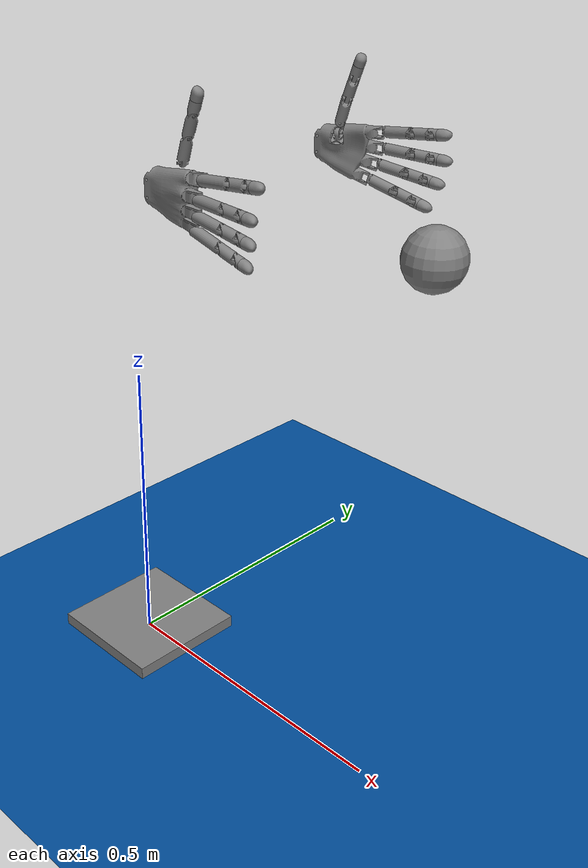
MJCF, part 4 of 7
804 806 805 806 807 808 809 810 810 809 807 810 807 811 811 807 806 803 802 812 812 802 813 812 813 814 814 813 815 814 815 799 799 815 816 799 816 800 797 817 798 798 817 818 798 818 819 819 818 820 819 820 801 801 820 821 801 821 799 798 822 796 796 822 823 796 823 824 824 823 825 824 825 826 826 825 827 826 827 828 828 827 829 828 829 830 830 829 831 830 831 832 832 831 833 627 636 834 478 766 522 522 766 775 522 775 524 524 775 773 524 773 525 525 773 784 525 784 526 526 784 783 526 783 527 527 783 781 527 781 536 536 781 779 536 779 535 535 779 777 535 777 533 533 777 776 533 776 539 539 776 785 539 785 528 528 785 787 560 793 559 559 793 792 559 792 554 560 540 793 793 540 551 793 551 794 794 551 550 794 550 795 795 550 549 795 549 789 789 549 552 789 552 787 787 552 543 787 543 528 835 574 836 836 574 563 836 563 837 837 563 562 837 562 792 792 562 561 792 561 554 584 568 829 829 568 564 829 564 831 831 564 566 831 566 833 833 566 567 833 567 838 838 567 573 838 573 835 835 573 572 835 572 574 829 827 584 584 827 825 584 825 583 583 825 823 583 823 581 581 823 822 581 822 579 579 822 798 600 599 802 802 599 813 813 599 598 813 598 815 815 598 597 815 597 816 816 597 595 816 595 800 800 595 594 800 594 801 801 594 588 801 588 819 819 588 587 819 587 798 798 587 592 798 592 579 600 802 601 601 802 805 601 805 602 602 805 807 602 807 605 605 807 809 605 809 607 607 809 839 607 839 615 615 839 614 614 839 840 614 840 612 612 840 841 612 841 637 637 841 842 637 842 626 626 842 843 626 843 623 623 843 844 623 844 624 624 844 845 624 845 625 625 845 846 625 846 619 619 846 847 619 847 620 620 847 848 620 848 622 622 848 849 622 849 629 629 849 850 629 850 630 630 850 631 631 850 851 631 851 632 632 851 852 632 852 633 633 852 853 633 853 634 834 636 854 853 855 634 634 855 856 634 856 635 635 856 857 635 857 636 636 857 858 636 858 854 627 834 628 628 834 859 628 859 616 616 859 860 616 860 617 617 860 640 640 860 861 640 861 641 641 861 862 641 862 642 642 862 863 642 863 643 643 863 864 643 864 644 644 864 865 644 865 645 645 865 866 645 866 646 866 867 646 646 867 868 646 868 647 647 868 869 647 869 648 648 869 870 648 870 654 654 870 871 654 871 655 655 871 872 639 638 873 873 638 618 873 618 874 874 618 649 874 649 875 875 649 653 875 653 876 876 653 652 876 652 877 877 652 651 877 651 878 878 651 659 878 659 879 879 659 658 879 658 880 880 658 657 880 657 872 872 657 656 872 656 655 873 881 639 639 881 882 639 882 613 613 882 883 714 604 884 884 604 606 884 606 883 883 606 608 883 608 613 580 593 698 698 593 702 702 593 591 702 591 704 704 591 590 704 590 706 706 590 589 706 589 708 708 589 586 708 586 709 709 586 596 709 596 711 711 596 603 711 603 718 718 603 611 718 611 713 713 611 610 713 610 714 714 610 609 714 609 604 580 698 582 582 698 696 582 696 585 585 696 695 585 695 576 685 570 687 687 570 569 687 569 689 695 692 576 576 692 691 576 691 577 577 691 689 577 689 578 578 689 569 885 575 886 886 575 571 886 571 685 685 571 565 685 565 570 542 541 682 682 541 680 541 558 680 680 558 557 680 557 887 887 557 553 887 553 888 888 553 555 888 555 885 885 555 556 885 556 575 545 679 546 546 679 678 546 678 547 542 682 544 544 682 683 544 683 545 545 683 660 545 660 679 547 678 548 548 678 677 548 677 529 667 538 668 668 538 537 529 677 530 530 677 676 530 676 531 531 676 675 531 675 532 532 675 673 532 673 534 534 673 671 534 671 537 537 671 670 537 670 668 663 473 664 664 473 521 664 521 667 667 521 523 667 523 538 889 885 890 890 885 886 890 886 891 891 886 685 891 685 892 892 685 684 889 893 885 885 893 894 885 894 888 888 894 895 896 681 680 887 888 895 896 680 897 887 895 680 680 895 898 680 898 897 899 665 900 900 665 666 900 666 901 901 666 669 901 669 902 902 669 672 902 672 903 903 672 674 903 674 904 904 674 662 904 662 905 905 662 661 905 661 906 906 661 681 725 907 726 743 908 744 744 908 745 909 908 910 910 908 743 910 743 911 911 743 742 911 742 912 912 742 741 912 741 913 913 741 740 913 740 914 914 740 739 739 738 914 914 738 737 914 737 915 915 737 736 915 736 916 916 736 735 916 735 917 917 735 734 917 734 918 918 734 733 918 733 919 733 732 919 919 732 731 919 731 920 920 731 730 920 730 921 921 730 729 921 729 922 922 729 728 922 728 923 923 728 727 663 665 924 925 722 924 924 722 721 924 721 663 727 726 923 923 726 907 923 907 926 926 907 725 926 725 927 927 725 724 927 724 925 925 724 723 925 723 722 928 929 881 881 929 882 882 929 883 883 929 930 883 930 884 930 931 884 884 931 932 884 932 714 714 932 933 714 933 715 928 881 934 934 881 873 934 873 935 935 873 874 935 874 936 874 875 936 936 875 876 936 876 937 937 876 877 937 877 938 938 877 878 938 878 939 939 878 879 939 879 940 940 879 941 941 879 880 941 880 872 942 943 866 866 943 944 866 944 867 867 944 945 867 945 868 868 945 946 868 946 869 869 946 947 869 947 870 870 947 948 870 948 871 871 948 949 871 949 872 872 949 950 872 950 941 866 865 942 942 865 864 942 864 951 951 864 863 951 863 952 953 954 955 860 953 861 861 953 955 861 955 862 862 955 956 862 956 863 863 956 957 863 957 952 958 684 686 958 686 959 959 686 688 959 688 960 960 688 690 960 690 961 690 693 961 961 693 694 961 694 962 962 694 697 962 697 699 699 700 962 962 700 701 962 701 963 701 703 963 963 703 705 963 705 964 964 705 707 964 707 965 965 707 710 965 710 966 715 967 716 716 967 968 716 968 717 717 968 969 717 969 719 719 969 970 719 970 720 720 970 966 720 966 712 712 966 710 971 972 973 908 909 974 745 908 746 746 908 974 746 974 747 747 974 975 976 750 977 977 750 749 977 749 975 975 749 748 975 748 747 978 752 976 976 752 751 976 751 750 756 755 979 979 755 754 979 754 978 978 754 753 978 753 752 979 980 756 756 980 981 756 981 757 757 981 982 762 761 983 983 761 760 983 760 984 984 760 759 984 759 982 982 759 758 982 758 757 769 770 985 762 983 763 763 983 986 763 986 764 764 986 987 764 987 765 765 987 973 765 973 771 771 973 972 771 972 770 770 972 971 770 971 985 769 985 768 768 985 988 768 988 767 767 988 766 766 988 989 766 989 774 990 991 836 791 992 792 792 992 990 792 990 837 837 990 836 993 791 790 993 790 994 994 790 788 994 788 995 995 788 786 995 786 996 996 786 778 996 778 997 997 778 998 998 778 780 998 780 999 780 782 999 999 782 772 999 772 1000 1000 772 774 1000 774 1001 1002 832 833 836 991 1003 836 1003 835 1003 1004 835 835 1004 1005 835 1005 838 838 1005 1006 838 1006 833 833 1006 1007 833 1007 1002 1008 830 1009 1009 830 832 1009 832 1010 1011 826 1008 1008 826 828 1008 828 830 817 797 1012 1012 797 796 1012 796 1011 1011 796 824 1011 824 826 1013 820 1012 1012 820 818 1012 818 817 1014 799 1013 1013 799 821 1013 821 820 1015 803 1016 1016 803 812 1016 812 1014 1014 812 814 1014 814 799 1017 808 1018 1018 808 810 1018 810 1019 1019 810 811 1019 811 1020 1020 811 806 1020 806 1015 1015 806 804 1015 804 803 1021 842 1022 1023 1024 850 1025 1026 859 859 1026 1027 859 1027 860 860 1027 1028 860 1028 953 953 1028 954 1025 859 1029 1029 859 834 1029 834 1030 857 1031 1032 834 854 1030 1030 854 858 1030 858 1033 1033 858 857 1033 857 1034 1034 857 1032 857 856 1031 1031 856 855 1031 855 1035 1035 855 853 1035 853 1036 1036 853 852 1036 852 1024 1024 852 851 1024 851 850 1023 850 1037 1037 850 849 1037 849 1038 1038 849 1039 1039 849 848 1039 848 1040 1040 848 847 1040 847 1041 847 846 1041 1041 846 845 1041 845 1042 1042 845 844 1042 844 1021 1021 844 843 1021 843 842 808 1043 809 809 1043 1044 809 1044 839 839 1044 1045 839 1045 840 840 1045 1046 840 1046 841 841 1046 1047 841 1047 842 842 1047 1048 842 1048 1022 1049 895 894 1049 894 1050 1050 894 893 1050 893 1051 893 889 1051 1051 889 890 1051 890 1052 890 891 1052 1052 891 892 1052 892 1053 1053 892 684 1053 684 958 1054 898 1049 1049 898 895 906 681 896 906 896 1055 1055 896 897 1055 897 1056 1056 897 898 1056 898 1054 1057 1058 1059 1060 1061 1062 1062 1061 1063 1062 1063 1064 901 902 1065 1065 902 903 1065 903 1066 1066 903 904 1066 904 1067 1067 904 905 1067 905 1059 1059 905 906 1059 906 1057 899 900 1068 1068 900 901 1068 901 1069 1069 901 1065 1069 1065 1070 1070 1065 1071 1071 1065 1066 1071 1066 1072 1072 1066 1067 1072 1067 1073 1073 1067 1059 1073 1059 1064 1064 1059 1058 1064 1058 1062 1074 924 899 899 924 665 1075 927 1076 1076 927 925 1076 925 1074 1074 925 924 1077 923 1075 1075 923 926 1075 926 927 1078 909 1079 1079 909 910 1079 910 1080 1080 910 911 1080 911 1081 1081 911 912 1081 912 1082 1082 912 913 1082 913 1083 1083 913 914 1083 914 1084 1084 914 915 1084 915 1085 1085 915 916 1085 916 1086 1086 916 917 1086 917 1087 1087 917 918 1087 918 1088 1088 918 919 1088 919 1089 1089 919 920 1089 920 1090 1090 920 921 1090 921 1077 1077 921 922 1077 922 923 1091 1092 934 967 715 1093 1093 715 933 1093 933 1094 1094 933 932 1094 932 1095 1095 932 931 1095 931 1096 954 1097 955 955 1097 1098 955 1098 956 956 1098 1099 956 1099 957 957 1099 1100 957 1100 952 1101 942 1100 1100 942 951 1100 951 952 1102 945 1103 1103 945 944 1103 944 1101 1101 944 943 1101 943 942 1104 940 1105 1105 940 941 1105 941 1106 1106 941 950 1106 950 1107 1107 950 949 1107 949 1108 1108 949 948 1108 948 1109 1109 948 947 1109 947 1102 1102 947 946 1102 946 945 934 935 1091 1091 935 936 1091 936 1110 1110 936 937 1110 937 1111 1111 937 938 1111 938 1104 1104 938 939 1104 939 940 931 930 1096 1096 930 929 1096 929 1092 1092 929 928 1092 928 934 1112 1113 1114 959 960 1115 962 1116 1117 1116 962 963 968 967 1118 966 970 1118 1118 970 969 1118 969 968 1119 1115 1120 1120 1115 960 1120 960 1117 1117 960 961 1117 961 962 1121 1122 1115 1115 1122 958 1115 958 959 1117 1123 1120 1120 1123 1124 1120 1124 1119 1119 1124 1125 1119 1125 1115 1115 1125 1126 1115 1126 1121 964 1127 963 963 1127 1113 963 1113 1116 1116 1113 1112 1116 1112 1117 1117 1112 1128 1117 1128 1123 1114 1113 1129 1129 1113 1127 1129 1127 1130 1130 1127 964 1130 964 1118 1118 964 965 1118 965 966 909 1078 974 974 1078 1131 974 1131 1132 1133 989 988 973 1134 1135 1133 988 1136 1136 988 985 1136 985 1135 1135 985 971 1135 971 973 973 987 1134 1134 987 986 1134 986 1137 1137 986 983 1137 983 1138 1138 983 984 1138 984 1139 1139 984 982 1139 982 1140 1140 982 981 1140 981 1141 1141 981 980 1141 980 1142 980 979 1142 1142 979 978 1142 978 1143 1143 978 976 1143 976 1144 1144 976 1145 1145 976 977 1145 977 1132 1132 977 975 1132 975 974 1133 1001 989 989 1001 774 791 993 992 992 993 1146 992 1146 990 1146 1147 990 990 1147 991 1001 1148 1000 1000 1148 999 1149 995 1150 1150 995 996 1150 996 1151 1151 996 997 1151 997 1152 1152 997 998 1153 993 994 1154 1155 1156 1156 1155 1157 1155 1158 1157 1157 1158 1153 1157 1153 1149 1149 1153 994 1149 994 995 1148 1159 999 999 1159 1160 999 1160 998 998 1160 1161 998 1161 1152 1152 1161 1162 1152 1162 1151 1151 1162 1163 1151 1163 1150 1150 1163 1164 1150 1164 1149 1149 1164 1165 1149 1165 1157 1010 832 1166 1166 832 1002 1166 1002 1167 1167 1002 1007 1167 1007 1168 1168 1007 1006 1168 1006 1169 991 1147 1003 1003 1147 1170 1003 1170 1004 1004 1170 1169 1004 1169 1005 1005 1169 1006 1008 1009 1171 1171 1009 1010 1171 1010 1172 1173 1174 1171 1171 1174 1011 1171 1011 1008 1013 1012 1175 1175 1012 1011 1175 1011 1176 1176 1011 1174 1017 1018 1177 1177 1018 1019 1177 1019 1178 1178 1019 1020 1179 1180 1181 1181 1180 1182 1181 1182 1183 1020 1015 1178 1178 1015 1016 1178 1016 1182 1182 1016 1014 1182 1014 1183 1183 1014 1013 1183 1013 1181 1181 1013 1175 1181 1175 1179 1179 1175 1176 1179 1176 1184 1184 1176 1174 1172 1185 1171 1171 1185 1186 1171 1186 1173 1173 1186 1187 1173 1187 1174 1174 1187 1188 1174 1188 1184 808 1017 1043 1043 1017 1189 1043 1189 1044 1044 1189 1190 1044 1190 1045 1045 1190 1191 1045 1191 1046 1046 1191 1192 1097 954 1193 1193 954 1028 1193 1028 1194 1028 1027 1194 1194 1027 1026 1194 1026 1195 1195 1026 1025 1025 1029 1195 1195 1029 1030 1195 1030 1196 1196 1030 1033 1033 1034 1196 1196 1034 1032 1196 1032 1197 1197 1032 1198 1198 1032 1031 1198 1031 1199 1031 1035 1199 1199 1035 1036 1199 1036 1200 1200 1036 1024 1200 1024 1201 1201 1024 1202 1202 1024 1023 1202 1023 1203 1203 1023 1037 1203 1037 1204 1037 1038 1204 1204 1038 1039 1204 1039 1205 1205 1039 1040 1205 1040 1206 1206 1040 1041 1206 1041 1207 1207 1041 1042 1042 1021 1207 1207 1021 1022 1207 1022 1208 1208 1022 1048 1208 1048 1192 1192 1048 1047 1192 1047 1046 1209 1210 1211 1211 1210 1212 1213 1214 1215 1215 1214 1216 1215 1216 1217 1217 1216 1218 1218 1216 1219 1218 1219 1220 1220 1219 1221 1220 1221 1222 1222 1221 1223 1222 1223 1224 1224 1223 1225 1225 1223 1226 1225 1226 1227 1227 1226 1228 1227 1228 1229 1230 1231 1232 1232 1231 1233 1232 1233 1234 1234 1233 1235 1234 1235 1236 1236 1235 1209 1236 1209 1237 1237 1209 1211 1212 1228 1211 1211 1228 1226 1211 1226 1237 1237 1226 1223 1237 1223 1236 1236 1223 1221 1236 1221 1234 1234 1221 1219 1234 1219 1232 1232 1219 1216 1232 1216 1230 1230 1216 1214 1214 1213 1238 1239 1240 1241 1241 1240 1242 1241 1242 1243 1243 1242 1244 1243 1244 1245 1245 1244 1246 1245 1246 1238 1238 1246 1230 1238 1230 1214 1247 1248 1249 1247 1249 1250 1250 1249 1251 1250 1251 1252 1252 1251 1253 1252 1253 1254 1254 1253 1255 1254 1255 1256 1256 1255 1257 1256 1257 1258 1258 1257 1259 1258 1259 1260 1260 1259 1261 1260 1261 1262 1262 1261 1263 1262 1263 1239 1239 1263 1264 1239 1264 1240 1248 1247 1265 1265 1247 1266 1265 1266 1267 1267 1266 1268 1267 1268 1269 1269 1268 1270 1270 1268 1271 1270 1271 1272 1272 1271 1273 1272 1273 1274 1274 1273 1275 1274 1275 1276 1276 1275 1277 1276 1277 1278 1278 1277 1279 1278 1279 1280 1280 1279 1281 1280 1281 1282 1282 1281 1283 1282 1283 1284 1284 1283 1285 1284 1285 1286 1286 1285 1287 1286 1287 1288 1289 1290 1291 1289 1291 1292 1293 1294 1291 1291 1294 1295 1291 1295 1292 1296 1297 1298 1298 1297 1299 1298 1299 1291 1291 1299 1300 1291 1300 1293 1287 1301 1288 1288 1301 1302 1288 1302 1298 1298 1302 1303 1298 1303 1296 1304 1305 1306 1050 1051 1307 1307 1051 1052 1052 1053 1307 1307 1053 958 1307 958 1122 1308 1049 1050 1050 1307 1308 1308 1307 1309 1308 1309 1310 1310 1309 1311 1310 1311 1312 1304 1306 1313 1313 1306 1314 1313 1314 1315 1315 1314 1316 1315 1316 1317 1306 1318 1314 1314 1318 1319 1314 1319 1316 1316 1319 1320 1122 1121 1307 1307 1121 1321 1307 1321 1309 1309 1321 1320 1309 1320 1311 1311 1320 1319 1311 1319 1312 1312 1319 1318 1057 906 1055 1322 1058 1057 1057 1055 1322 1322 1055 1056 1322 1056 1054 1323 1324 1325 1325 1324 1060 1325 1060 1062 1326 1327 1323 1323 1327 1328 1323 1328 1324 1306 1305 1329 1325 1318 1323 1323 1318 1306 1323 1306 1326 1326 1306 1329 1326 1329 1327 1308 1310 1325 1325 1310 1312 1325 1312 1318 1062 1058 1325 1325 1058 1322 1325 1322 1308 1308 1322 1054 1308 1054 1049 1330 1331 1332 1332 1333 1334 1335 1336 1337 1337 1336 1338 1077 1339 1340 1064 1063 1341 1327 1329 1342 1343 1344 1345 1346 1078 1079 1347 1348 1349 1349 1348 1350 1349 1350 1351 1351 1350 1346 1351 1346 1352 1353 1354 1355 1355 1354 1356 1355 1356 1357 1357 1356 1358 1357 1358 1359 1359 1358 1360 1359 1360 1361 1361 1360 1362 1363 1364 1365 1365 1364 1366 1365 1366 1367 1367 1366 1368 1344 1343 1369 1370 1371 1372 1372 1371 1373 1372 1373 1341 1329 1374 1342 1342 1374 1370 1342 1370 1375 1375 1370 1372 1061 1060 1324 1341 1063 1372 1372 1063 1061 1372 1061 1375 1375 1061 1324 1375 1324 1342 1342 1324 1328 1342 1328 1327 1064 1341 1073 1073 1341 1376 1073 1376 1072 1072 1376 1377 1072 1377 1071 1071 1377 1378 1071 1378 1070 1379 1069 1380 1380 1069 1070 1380 1070 1381 1381 1070 1378 1068 1382 1383 1076 1074 1384 1384 1074 899 1384 899 1068 1068 1383 1384 1384 1383 1075 1384 1075 1076 1077 1340 1090 1090 1340 1385 1090 1385 1089 1089 1385 1386 1089 1386 1088 1088 1386 1387 1088 1387 1087 1087 1387 1388 1087 1388 1086 1084 1389 1083 1083 1389 1390 1083 1390 1082 1346 1079 1352 1352 1079 1080 1352 1080 1081 1085 1086 1338 1338 1086 1388 1338 1388 1337 1337 1388 1391 1337 1391 1335 1334 1333 1335 1335 1333 1390 1335 1390 1336 1336 1390 1389 1336 1389 1338 1338 1389 1084 1338 1084 1085 1331 1349 1332 1332 1349 1351 1332 1351 1333 1333 1351 1352 1333 1352 1390 1390 1352 1081 1390 1081 1082 1392 1393 1394 1394 1393 1395 1394 1395 1396 1343 1397 1369 1369 1397 1368 1369 1368 1398 1398 1368 1366 1398 1366 1395 1395 1366 1364 1395 1364 1396 1396 1364 1363 1396 1363 1399 1399 1363 1400 1399 1400 1401 1401 1400 1402 1401 1402 1353 1353 1402 1403 1353 1403 1354 1404 1405 1406 1406 1405 1382 1407 1408 1409 1409 1408 1410 1409 1410 1411 1411 1410 1412 1411 1412 1413 1413 1412 1414 1413 1414 1415 1415 1414 1416 1415 1416 1404 1404 1416 1417 1404 1417 1405 1405 1417 1418 1405 1418 1382 1382 1418 1419 1382 1419 1383 1077 1075 1339 1339 1075 1383 1339 1383 1340 1340 1383 1419 1340 1419 1385 1385 1419 1418 1385 1418 1386 1386 1418 1417 1386 1417 1387 1387 1417 1416 1387 1416 1388 1388 1416 1414 1388 1414 1391 1391 1414 1412 1391 1412 1335 1335 1412 1410 1335 1410 1334 1334 1410 1408 1334 1408 1332 1332 1408 1407 1332 1407 1330 1373 1345 1341 1341 1345 1344 1341 1344 1376 1376 1344 1369 1376 1369 1377 1377 1369 1398 1377 1398 1378 1378 1398 1395 1378 1395 1381 1381 1395 1393 1381 1393 1380 1380 1393 1392 1380 1392 1379 1420 1348 1362 1362 1348 1347 1362 1347 1361 1361 1347 1349 1361 1349 1359 1359 1349 1331 1359 1331 1357 1357 1331 1330 1357 1330 1355 1355 1330 1407 1355 1407 1353 1353 1407 1409 1353 1409 1401 1401 1409 1411 1401 1411 1399 1399 1411 1413 1399 1413 1396 1396 1413 1415 1396 1415 1394 1394 1415 1404 1394 1404 1392 1392 1404 1406 1392 1406 1379 1379 1406 1382 1379 1382 1069 1069 1382 1068 1421 1422 1423 1424 1425 1426 1427 1428 1429 1430 1431 1432 1433 1434 1435 1435 1434 1436 1320 1437 1438 1125 1124 1439 1123 1128 1440 1104 1105 1441 1098 1097 1442 1099 1428 1100 1100 1428 1427 1100 1427 1101 1101 1427 1443 1101 1443 1103 1103 1443 1444 1103 1444 1102 1106 1107 1445 1445 1107 1108 1445 1108 1444 1444 1108 1109 1444 1109 1102 1104 1441 1111 1095 1096 1446 1446 1096 1092 1446 1092 1447 1094 1448 1093 1093 1448 1449 1093 1449 967 1112 1114 1450 1439 1451 1125 1125 1451 1452 1125 1452 1126 1126 1452 1321 1126 1321 1121 1453 1454 1438 1320 1438 1316 1316 1438 1454 1316 1454 1317 1430 1455 1431 1431 1455 1456 1431 1456 1432 1432 1456 1457 1458 1459 1460 1460 1459 1461 1423 1462 1463 1422 1464 1423 1423 1464 1465 1423 1465 1462 1466 1467 1422 1422 1467 1468 1422 1468 1464 1469 1470 1471 1472 1470 1473 1473 1470 1469 1473 1469 1474 1092 1091 1447 1447 1091 1475 1447 1475 1476 1094 1095 1448 1448 1095 1446 1448 1446 1477 1477 1446 1447 1477 1447 1478 1478 1447 1476 1478 1476 1479 1118 967 1480 1480 967 1449 1480 1449 1481 1481 1449 1448 1481 1448 1482 1482 1448 1477 1482 1477 1483 1483 1477 1478 1483 1478 1484 1484 1478 1479 1484 1479 1485 1486 1487 1488 1488 1487 1489 1488 1489 1490 1491 1492 1493 1493 1492 1494 1493 1494 1486 1486 1494 1495 1486 1495 1487 1130 1118 1496 1496 1118 1480 1496 1480 1497 1497 1480 1481 1497 1481 1498 1498 1481 1482 1498 1482 1499 1499 1482 1483 1499 1483 1500 1500 1483 1484 1500 1484 1501 1501 1484 1485 1501 1485 1425 1129 1492 1114 1114 1492 1491 1114 1491 1450 1450 1491 1440 1450 1440 1112 1112 1440 1128 1124 1123 1439 1439 1123 1440 1439 1440 1502 1502 1440 1491 1502 1491 1503 1503 1491 1493 1503 1493 1459 1459 1493 1486 1459 1486 1461 1461 1486 1488 1430 1433 1455 1455 1433 1435 1455 1435 1453 1453 1435 1436 1453 1436 1454 1454 1436 1504 1454 1504 1317 1458 1505 1459 1459 1505 1457 1459 1457 1503 1503 1457 1456 1503 1456 1502 1502 1456 1455 1502 1455 1439 1439 1455 1453 1439 1453 1451 1451 1453 1438 1451 1438 1452 1452 1438 1437 1452 1437 1321 1321 1437 1320 1442 1473 1506 1506 1473 1474 1506 1474 1507 1507 1474 1469 1507 1469 1508 1508 1469 1471 1508 1471 1509 1098 1442 1099 1099 1442 1506 1099 1506 1428 1428 1506 1507 1428 1507 1429 1429 1507 1508 1429 1508 1510 1510 1508 1509 1510 1509 1511 1105 1106 1441 1441 1106 1445 1441 1445 1512 1512 1445 1444 1512 1444 1513 1513 1444 1443 1110 1111 1514 1514 1111 1441 1514 1441 1515 1515 1441 1512 1515 1512 1516 1516 1512 1513 1516 1513 1517 1517 1513 1443 1517 1443 1518 1518 1443 1427 1518 1427 1519 1519 1427 1429 1519 1429 1520 1520 1429 1510 1520 1510 1521 1521 1510 1511 1426 1421 1424 1424 1421 1423 1424 1423 1489 1489 1423 1463 1489 1463 1490 1490 1463 1522 1490 1522 1488 1488 1522 1523 1488 1523 1461 1425 1424 1501 1501 1424 1489 1501 1489 1500 1500 1489 1487 1500 1487 1499 1499 1487 1495 1499 1495 1498 1498 1495 1494 1498 1494 1497 1497 1494 1492 1497 1492 1496 1496 1492 1129 1496 1129 1130 1091 1110 1475 1475 1110 1514 1475 1514 1476 1476 1514 1515 1476 1515 1479 1479 1515 1516 1479 1516 1485 1485 1516 1517 1485 1517 1425 1425 1517 1518 1425 1518 1426 1426 1518 1519 1426 1519 1421 1421 1519 1520 1421 1520 1422 1422 1520 1521 1422 1521 1466 1466 1521 1511 1524 1525 1526 1527 1528 1529 1529 1530 1527 1527 1530 1531 1527 1531 1532 1532 1531 1533 1532 1533 1534 1534 1533 1535 1536 1537 1538 1538 1537 1539 1538 1539 1540 1540 1541 1538 1538 1541 1542 1538 1542 1535 1535 1542 1543 1535 1543 1534 1544 1545 1546 1546 1545 1547 1547 1545 1548 1547 1548 1528 1528 1548 1549 1528 1549 1529 1546 1550 1544 1544 1550 1551 1544 1551 1552 1552 1551 1553 1552 1553 1554 1553 1555 1554 1554 1555 1556 1554 1556 1524 1524 1556 1557 1524 1557 1525 1558 1559 1560 1560 1559 1561 1560 1561 1562 1562 1561 1563 1562 1563 1564 1564 1563 1565 1564 1565 1566 1566 1565 1567 1566 1567 1526 1526 1567 1568 1526 1568 1524 1569 1570 1571 1571 1570 1572 1571 1572 1573 1573 1572 1558 1573 1558 1574 1574 1558 1560 1575 1576 1577 1577 1576 1578 1577 1578 1569 1569 1578 1579 1569 1579 1570 1580 1229 1228 1575 1577 1581 1581 1577 1582 1581 1582 1583 1583 1582 1584 1583 1584 1585 1585 1584 1586 1585 1586 1587 1587 1586 1588 1587 1588 1589 1589 1588 1580 1589 1580 1590 1590 1580 1228 1590 1228 1212 1591 1220 1222 1220 1591 1218 1218 1591 1592 1218 1592 1217 1229 1593 1227 1227 1593 1594 1227 1594 1225 1225 1594 1595 1225 1595 1224 1224 1595 1596 1224 1596 1222 1222 1596 1597 1222 1597 1591 1598 1213 1599 1599 1213 1215 1599 1215 1600 1600 1215 1217 1600 1217 1601 1601 1217 1592 1602 1603 1604 1605 1606 1607 1608 1609 1610 1611 1156 1157 1612 1141 1142 1144 1145 1613 1614 1132 1131 1144 1613 1143 1141 1612 1140 1140 1612 1615 1140 1615 1139 1139 1615 1616 1139 1616 1138 1137 1617 1134 1134 1617 1618 1134 1618 1135 1619 1001 1620 1620 1001 1133 1164 1163 1621 1621 1163 1162 1621 1162 1622 1622 1162 1161 1622 1161 1623 1623 1161 1160 1623 1160 1624 1624 1160 1159 1624 1159 1619 1619 1159 1148 1619 1148 1001 1621 1625 1164 1164 1625 1626 1164 1626 1165 1165 1626 1627 1165 1627 1157 1157 1627 1628 1157 1628 1611 1154 1156 1629 1629 1156 1611 1629 1611 1630 1630 1611 1628 1630 1628 1631 1610 1609 1605 1605 1609 1632 1605 1632 1606 1633 1634 1635 1636 1637 1638 1638 1637 1639 1640 1641 1636 1636 1641 1642 1636 1642 1637 1643 1644 1645 1645 1644 1646 1645 1646 1647 1647 1646 1648 1647 1648 1649 1649 1648 1650 1649 1650 1651 1651 1650 1652 1651 1652 1653 1653 1652 1640 1653 1640 1654 1654 1640 1636 1348 1655 1350 1350 1655 1614 1350 1614 1346 1346 1614 1131 1346 1131 1078 1656 1631 1608 1608 1631 1628 1608 1628 1609 1609 1628 1627 1609 1627 1632 1632 1627 1626 1632 1626 1606 1657 1658 1659 1635 1657 1633 1633 1657 1659 1633 1659 1660 1661 1662 1663 1663 1662 1664 1663 1664 1665 1665 1664 1666 1655 1667 1614 1614 1667 1613 1614 1613 1132 1132 1613 1145 1661 1668 1669 1669 1668 1670 1669 1670 1671 1671 1670 1672 1671 1672 1617 1617 1672 1673 1617 1673 1618 1618 1673 1136 1618 1136 1135 1348 1674 1655 1655 1674 1666 1655 1666 1667 1667 1666 1664 1667 1664 1613 1613 1664 1662 1613 1662 1143 1143 1662 1661 1143 1661 1142 1142 1661 1669 1142 1669 1612 1612 1669 1671 1612 1671 1615 1615 1671 1617 1615 1617 1616 1616 1617 1137 1616 1137 1138 1675 1603 1676 1676 1603 1602 1676 1602 1677 1677 1602 1678 1677 1678 1679 1660 1659 1680 1680 1659 1681 1680 1681 1682 1683 1684 1685 1685 1684 1686 1685 1686 1687 1687 1686 1682 1658 1688 1659 1659 1688 1679 1659 1679 1681 1681 1679 1678 1681 1678 1682 1682 1678 1602 1682 1602 1687 1687 1602 1604 1687 1604 1685 1620 1675 1619 1619 1675 1676 1619 1676 1624 1624 1676 1677 1624 1677 1623 1623 1677 1679 1623 1679 1622 1622 1679 1688 1622 1688 1621 1621 1688 1658 1621 1658 1625 1625 1658 1657 1625 1657 1626 1626 1657 1635 1626 1635 1606 1606 1635 1634 1606 1634 1607 1665 1683 1663 1663 1683 1685 1663 1685 1661 1661 1685 1604 1661 1604 1668 1668 1604 1603 1668 1603 1670 1670 1603 1675 1670 1675 1672 1672 1675 1620 1672 1620 1673 1673 1620 1133 1673 1133 1136 1420 1643 1348 1348 1643 1645 1348 1645 1674 1674 1645 1647 1674 1647 1666 1666 1647 1649 1666 1649 1665 1665 1649 1651 1665 1651 1683 1683 1651 1653 1683 1653 1684 1684 1653 1654 1684 1654 1686 1686 1654 1636 1686 1636 1682 1682 1636 1638 1682 1638 1680 1680 1638 1639 1680 1639 1660 1660 1639 1689 1660 1689 1633 1633 1689 1690 1633 1690 1634 1147 1146 1691 1147 1691 1692 1692 1691 1693 1692 1693 1694 1694 1693 1695 1694 1695 1696 1696 1695 1697 1696 1697 1698 1698 1697 1656 1698 1656 1699 1695 1629 1630 1695 1630 1697 1697 1630 1631 1697 1631 1656 1629 1695 1154 1154 1695 1693 1154 1693 1155 1146 993 1691 1691 993 1153 1691 1153 1693 1693 1153 1158 1693 1158 1155 1170 1147 1692 1170 1692 1169 1167 1168 1700 1700 1168 1169 1172 1010 1166 1700 1701 1702 1166 1167 1172 1172 1167 1700 1172 1700 1185 1185 1700 1702 1703 1694 1696 1704 1705 1706 1706 1705 1707 1706 1707 1703 1706 1708 1704 1704 1708 1709 1704 1709 1710 1711 1698 1712 1712 1698 1699 1703 1696 1706 1706 1696 1698 1706 1698 1708 1708 1698 1711 1708 1711 1709 1169 1692 1700 1700 1692 1694 1700 1694 1701 1701 1694 1703 1701 1703 1702 1187 1713 1714 1713 1187 1186 1715 1716 1717 1189 1718 1190 1190 1718 1719 1190 1719 1191 1207 1720 1206 1206 1720 1721 1206 1721 1205 1205 1721 1204 1204 1721 1722 1204 1722 1203 1723 1201 1722 1722 1201 1202 1722 1202 1203 1197 1198 1724 1724 1198 1199 1724 1199 1723 1723 1199 1200 1723 1200 1201 1725 1196 1197 1194 1726 1193 1193 1726 1442 1193 1442 1097 1727 1472 1473 1728 1729 1730 1730 1729 1731 1730 1731 1732 1732 1731 1727 1732 1727 1733 1728 1730 1734 1734 1730 1735 1734 1735 1736 1736 1735 1737 1736 1737 1738 1739 1740 1741 1741 1740 1742 1742 1740 1743 1743 1740 1744 1743 1744 1745 1746 1747 1748 1749 1746 1750 1750 1746 1748 1750 1748 1717 1717 1748 1751 1717 1751 1715 1752 1753 1754 1754 1753 1755 1754 1755 1756 1756 1755 1757 1756 1757 1758 1759 1760 1761 1710 1762 1704 1704 1762 1763 1704 1763 1705 1185 1702 1764 1764 1702 1703 1764 1703 1763 1763 1703 1707 1763 1707 1705 1765 1766 1767 1178 1718 1177 1177 1718 1189 1177 1189 1017 1758 1747 1756 1756 1747 1746 1756 1746 1754 1754 1746 1749 1754 1749 1768 1768 1749 1769 1768 1769 1188 1188 1187 1768 1768 1187 1714 1768 1714 1754 1754 1714 1761 1754 1761 1752 1752 1761 1760 1752 1760 1753 1186 1185 1713 1713 1185 1764 1713 1764 1714 1714 1764 1763 1714 1763 1761 1761 1763 1762 1761 1762 1759 1759 1762 1710 1767 1766 1770 1770 1766 1771 1770 1771 1772 1772 1771 1773 1772 1773 1774 1774 1773 1744 1774 1744 1775 1775 1744 1740 1775 1740 1776 1776 1740 1739 1776 1739 1777 1777 1739 1778 1777 1778 1737 1737 1778 1779 1737 1779 1738 1745 1744 1716 1716 1744 1773 1716 1773 1717 1717 1773 1771 1717 1771 1750 1750 1771 1766 1750 1766 1749 1749 1766 1765 1749 1765 1769 1769 1765 1184 1769 1184 1188 1725 1780 1781 1781 1780 1782 1781 1782 1783 1783 1782 1784 1783 1784 1785 1785 1784 1786 1785 1786 1787 1787 1786 1788 1787 1788 1789 1789 1788 1790 1789 1790 1791 1791 1790 1792 1791 1792 1719 1719 1792 1192 1719 1192 1191 1725 1197 1780 1780 1197 1724 1780 1724 1782 1782 1724 1723 1782 1723 1784 1784 1723 1722 1784 1722 1786 1786 1722 1721 1786 1721 1788 1788 1721 1720 1788 1720 1790 1790 1720 1207 1790 1207 1792 1792 1207 1208 1792 1208 1192 1727 1473 1733 1733 1473 1793 1733 1793 1732 1732 1793 1794 1732 1794 1730 1194 1195 1726 1726 1195 1795 1726 1795 1796 1796 1795 1797 1796 1797 1798 1798 1797 1799 1798 1799 1800 1800 1799 1801 1800 1801 1802 1802 1801 1803 1802 1803 1804 1804 1803 1805 1804 1805 1806 1806 1805 1807 1806 1807 1808 1808 1807 1809 1808 1809 1810 1810 1809 1811 1810 1811 1812 1812 1811 1813 1812 1813 1814 1814 1813 1182 1814 1182 1180 1473 1442 1793 1793 1442 1726 1793 1726 1794 1794 1726 1796 1794 1796 1730 1730 1796 1798 1730 1798 1735 1735 1798 1800 1735 1800 1737 1737 1800 1802 1737 1802 1777 1777 1802 1804 1777 1804 1776 1776 1804 1806 1776 1806 1775 1775 1806 1808 1775 1808 1774 1774 1808 1810 1774 1810 1772 1772 1810 1812 1772 1812 1770 1770 1812 1814 1770 1814 1767 1767 1814 1180 1767 1180 1765 1765 1180 1179 1765 1179 1184 1195 1196 1795 1795 1196 1725 1795 1725 1797 1797 1725 1781 1797 1781 1799 1799 1781 1783 1799 1783 1801 1801 1783 1785 1801 1785 1803 1803 1785 1787 1803 1787 1805 1805 1787 1789 1805 1789 1807 1807 1789 1791 1807 1791 1809 1809 1791 1719 1809 1719 1811 1811 1719 1718 1811 1718 1813 1813 1718 1178 1813 1178 1182 1291 1290 1815 1815 1290 1816 1815 1816 1817 1817 1816 1818 1817 1818 1819 1246 1244 1820 1820 1244 1821 1821 1244 1242 1821 1242 1822 1822 1242 1240 1822 1240 1823 1823 1240 1264 1823 1264 1824 1824 1264 1263 1824 1263 1825 1825 1263 1826 1826 1263 1261 1826 1261 1827 1827 1261 1259 1827 1259 1828 1828 1259 1257 1828 1257 1829 1829 1257 1255 1829 1255 1830 1830 1255 1253 1830 1253 1831 1253 1251 1831 1831 1251 1249 1831 1249 1832 1249 1248 1832 1832 1248 1265 1832 1265 1833 1833 1265 1267 1267 1269 1833 1833 1269 1270 1833 1270 1834 1834 1270 1835 1270 1272 1835 1835 1272 1274 1835 1274 1836 1836 1274 1276 1836 1276 1837 1837 1276 1278 1837 1278 1838 1278 1280 1838 1838 1280 1282 1838 1282 1839 1839 1282 1284 1839 1284 1840 1284 1286 1840 1840 1286 1288 1840 1288 1841 1841 1288 1842 1842 1288 1298 1842 1298 1843 1843 1298 1291 1843 1291 1844 1845 1230 1846 1846 1230 1246 1846 1246 1847 1847 1246 1820 1231 1230 1845 1848 1212 1849 1849 1212 1210 1849 1210 1209 1845 1850 1231 1231 1850 1851 1231 1851 1233 1233 1851 1852 1233 1852 1235 1235 1852 1853 1235 1853 1209 1209 1853 1854 1209 1854 1849 1212 1848 1855 1856 1587 1857 1857 1587 1589 1857 1589 1855 1855 1589 1590 1855 1590 1212 1565 1563 1858 1585 1587 1856 1570 1859 1572 1572 1859 1860 1572 1860 1558 1585 1856 1583 1583 1856 1861 1583 1861 1581 1581 1861 1862 1581 1862 1575 1575 1862 1863 1575 1863 1576 1576 1863 1864 1576 1864 1578 1578 1864 1865 1578 1865 1579 1579 1865 1866 1579 1866 1570 1570 1866 1867 1570 1867 1859 1858 1563 1868 1563 1561 1868 1868 1561 1559 1868 1559 1869 1869 1559 1558 1869 1558 1870 1870 1558 1860 1858 1871 1565 1565 1871 1872 1565 1872 1567 1567 1872 1873 1567 1873 1568 1568 1873 1874 1568 1874 1524 1874 1875 1524 1524 1875 1876 1524 1876 1554 1554 1876 1877 1554 1877 1552 1552 1877 1878 1552 1878 1544 1879 1531 1880 1880 1531 1530 1881 1529 1882 1882 1529 1549 1882 1549 1883 1883 1549 1548 1883 1548 1884 1884 1548 1545 1884 1545 1878 1878 1545 1544 1536 1538 1885 1885 1538 1535 1885 1535 1879 1879 1535 1533 1879 1533 1531 1886 1885 1887 1887 1885 1879 1887 1879 1888 1888 1879 1880 1888 1880 1881 1881 1880 1530 1881 1530 1529 1537 1536 1889 1537 1889 1890 1890 1889 1891 1890 1891 1892 1892 1891 1893 1892 1893 1894 1895 1896 1897 1898 1899 1900 1900 1901 1898 1898 1901 1902 1898 1902 1903 1903 1902 1904 1903 1904 1905 1905 1904 1906 1906 1904 1907 1906 1907 1908 1908 1907 1909 1909 1907 1910 1909 1910 1911 1911 1910 1912 1911 1912 1913 1913 1912 1914 1913 1914 1915 1915 1914 1916 1915 1916 1917 1917 1916 1918 1917 1918 1919 1919 1918 1920 1919 1920 1921 1895 1897 1922 1897 1923 1922 1922 1923 1924 1922 1924 1920 1920 1924 1925 1920 1925 1921 1926 1927 1928 1928 1927 1929 1928 1929 1930 1930 1929 1931 1930 1931 1932 1932 1931 1933 1932 1933 1896 1896 1933 1934 1896 1934 1897 1935 1936 1937 1937 1936 1938 1937 1938 1939 1939 1938 1927 1939 1927 1926 1935 1940 1936 1936 1940 1941 1936 1941 1942 1941 1943 1942 1942 1943 1944 1942 1944 1945 1945 1944 1946 1945 1946 1947 1947 1946 1948 1947 1948 1949 1949 1948 1950 1950 1948 1951 1950 1951 1952 1952 1953 1950 1950 1953 1954 1950 1954 1955 1955 1954 1956 1955 1956 1957 1957 1956 1958 1956 1959 1958 1958 1959 1960 1958 1960 1961 1961 1960 1962 1961 1962 1963 1962 1964 1963 1963 1964 1965 1963 1965 1966 1965 1967 1966 1966 1967 1968 1966 1968 1969 1969 1968 1970 1969 1970 1971 1972 1973 1420 1974 1975 1973 1973 1972 1974 1974 1972 1976 1974 1976 1977 1977 1976 1978 1977 1978 1979 1420 1362 1972 1972 1362 1360 1972 1360 1976 1976 1360 1358 1976 1358 1978 1978 1358 1356 1978 1356 1979 1979 1356 1980 1981 1296 1303 1213 1598 1238 1238 1598 1982 1238 1982 1245 1245 1982 1983 1245 1983 1243 1243 1983 1984 1243 1984 1241 1241 1984 1985 1241 1985 1239 1986 1987 1256 1985 1988 1239 1239 1988 1989 1239 1989 1262 1262 1989 1990 1262 1990 1260 1260 1990 1986 1260 1986 1258 1258 1986 1256 1247 1250 1991 1991 1250 1252 1991 1252 1987 1987 1252 1254 1987 1254 1256 1991 1992 1247 1247 1992 1993 1247 1993 1266 1266 1993 1994 1266 1994 1268 1268 1994 1995 1268 1995 1271 1995 1996 1271 1271 1996 1997 1271 1997 1273 1273 1997 1275 1275 1997 1998 1275 1998 1277 1277 1998 1999 1277 1999 1279 1279 1999 2000 1279 2000 1281 1281 2000 2001 1281 2001 1283 1283 2001 2002 1283 2002 1285 1285 2002 2003 1285 2003 1287 2004 1302 2005 2005 1302 1301 2005 1301 2006 2006 1301 1287 2006 1287 2007 2007 1287 2003 1981 1303 2008 1297 2009 1299 1299 2009 2010 1299 2010 1300 1300 2010 2011 1300 2011 1293 1293 2011 2012 1293 2012 1294 1294 2012 2013 1294 2013 1295 1295 2013 2014 1295 2014 1292 2015 1290 1289 1289 2016 2015 2015 2016 2017 2015 2017 2018 1289 1292 2016 2016 1292 2014 2016 2014 2017 2017 2014 2019 2017 2019 2018 2018 2019 2020 2021 2022 2023 2023 2024 2021 2021 2024 2025 2021 2025 2026 2026 2027 2021 2021 2027 2028 2021 2028 2008 2008 2028 2029 2008 2029 1981 2030 2021 2031 2031 2021 2008 2031 2008 2004 2004 2008 1303 2004 1303 1302 2022 2020 2023 2023 2020 2019 2023 2019 2024 2024 2019 2014 2024 2014 2025 2025 2014 2013 2025 2013 2026 2026 2013 2012 2026 2012 2027 2027 2012 2011 2027 2011 2028 2028 2011 2010 2028 2010 2029 2029 2010 2009 2029 2009 1981 1981 2009 1297 1981 1297 1296 1315 1317 2032 2033 2034 2035 2036 2037 2038 2039 1367 2040 2040 1367 1368 2040 1368 2041 2041 1368 1397 2041 1397 2042 2042 1397 1343 2042 1343 2043 2043 1343 1345 2043 1345 2044 2044 1345 1373 2044 1373 1371 2045 1363 2039 2039 1363 1365 2039 1365 1367 1400 2046 1402 1402 2046 2047 1402 2047 1403 1356 2048 1980 1980 2048 2049 2050 2051 2052 2052 2051 2053 2052 2053 2054 2054 2053 2055 2056 2057 2058 2058 2057 2059 2058 2059 2055 2055 2059 2060 2055 2060 2054 2061 2062 2063 2061 2063 2064 2064 2063 2065 2064 2065 2066 2038 2037 2061 2061 2037 2067 2061 2067 2062 2068 2069 2038 2038 2069 2070 2038 2070 2036 2071 2072 2073 2073 2072 2074 2073 2074 2068 2068 2074 2075 2068 2075 2069 2076 2077 2071 2071 2077 2078 2071 2078 2072 2079 2080 2081 2081 2080 2076 2081 2076 2082 2082 2076 2071 2083 2084 2085 2085 2084 2086 2085 2086 2087 2079 2081 2087 2087 2081 2035 2087 2035 2085 2085 2035 2034 2085 2034 2083 1315 2032 1313 1313 2032 2088 1313 2088 1304 1304 2088 2089 1304 2089 1305 2090 1374 1329 2091 1370 1374 2091 2092 2093 1374 2090 2091 2091 2090 2094 2091 2094 2092 2095 2096 2097 2097 2096 2098 2097 2098 2099 2099 2098 2100 2099 2100 2101 2101 2100 2102 2101 2102 2103 2103 2102 2104 2103 2104 2105 2105 2104 2106 2105 2106 2093 2093 2106 2107 2093 2107 2091 1356 1354 2048 2048 1354 1403 2048 1403 2049 2049 1403 2047 2049 2047 2108 2108 2047 2046 2108 2046 2045 2045 2046 1400 2045 1400 1363 2095 2108 2096 2096 2108 2045 2096 2045 2098 2098 2045 2039 2098 2039 2100 2100 2039 2040 2100 2040 2102 2102 2040 2041 2102 2041 2104 2104 2041 2042 2104 2042 2106 2106 2042 2043 2106 2043 2107 2107 2043 2044 2107 2044 2091 2091 2044 1371 2091 1371 1370 2066 2109 2064 2064 2109 2056 2064 2056 2110 2110 2056 2058 2110 2058 2111 2111 2058 2055 2111 2055 2112 2112 2055 2053 2112 2053 2113 2113 2053 2051 2032 2033 2088 2088 2033 2035 2088 2035 2114 2114 2035 2081 2114 2081 2115 2115 2081 2082 2115 2082 2116 2116 2082 2071 2116 2071 2117 2117 2071 2073 2117 2073 2118 2118 2073 2068 2118 2068 2119 2119 2068 2038 2119 2038 2120 2120 2038 2061 2120 2061 2121 2121 2061 2064 2121 2064 2122 2122 2064 2110 2122 2110 2123 2123 2110 2111 2123 2111 2124 2124 2111 2112 2113 2125 2112 2112 2125 1980 2112 1980 2124 2124 1980 2049 2124 2049 2123 2123 2049 2108 2123 2108 2122 2122 2108 2095 2122 2095 2121 2121 2095 2097 2121 2097 2120 2120 2097 2099 2120 2099 2119 2119 2099 2101 2119 2101 2118 2118 2101 2103 2118 2103 2117 2117 2103 2105 2117 2105 2116 2116 2105 2093 2116 2093 2115 2115 2093 2092 2115 2092 2114 2114 2092 2094 2114 2094 2088 2088 2094 2090 2088 2090 2089 2089 2090 1329 2089 1329 1305 2126 2127 2128 2128 2127 2129 1819 1818 2130 2130 1818 2131 2130 2131 2132 2132 2131 2133 2132 2133 2134 2134 2133 2135 2135 2133 2136 2135 2136 2137 2137 2136 2138 2137 2138 2139 2139 2138 2140 2139 2140 2141 2141 2140 2142 2141 2142 2143 2142 2144 2143 2143 2144 2145 2143 2145 2146 2146 2145 2147 2146 2147 2148 2148 2147 2149 2148 2149 2150 2150 2149 2151 2150 2151 2152 2152 2151 2153 2152 2153 2154 2154 2153 2155 2155 2153 2156 2155 2156 2157 2157 2156 2158 2157 2158 2159 2159 2158 2160 2159 2160 2161 2160 2162 2161 2161 2162 2163 2161 2163 2164 2163 2165 2164 2164 2165 2166 2164 2166 2167 2167 2166 2168 2168 2166 2169 2168 2169 2127 2127 2169 2170 2127 2170 2129 2126 2128 2171 2171 2128 2172 2171 2172 2173 2173 2172 2174 2173 2174 2175 2174 2176 2175 2175 2176 1971 2175 1971 1970 2176 2177 1971 1971 2177 2178 1971 2178 1969 1969 2178 2179 1969 2179 1966 2180 2181 1816 1816 2181 2182 1816 2182 1818 1816 1290 2015 2015 2018 1816 1816 2018 2020 1816 2020 2180 2020 2022 2180 2180 2022 2021 2180 2021 2183 2183 2021 2030 1894 1893 2184 1894 2184 2185 2185 2184 2186 2185 2186 2187 2187 2186 2188 2187 2188 2189 2188 2190 2189 2189 2190 2191 2189 2191 2192 2192 2191 2193 2192 2193 2194 2194 2193 2195 2194 2195 2196 2196 2195 2197 2197 2195 2198 2197 2198 2199 2199 2198 2200 2199 2200 2201 2200 2202 2201 2201 2202 2203 2201 2203 2204 2204 2203 2205 2204 2205 2206 2205 2207 2206 2206 2207 2208 2206 2208 2209 2210 2211 2212 2212 2211 2213 2212 2213 2214 2214 2213 2215 2214 2215 2216 2216 2215 2217 2216 2217 2218 2218 2217 2219 2218 2219 2220 2220 2219 2221 2220 2221 2222 2222 2221 2209 2222 2209 2223 2223 2209 2208 2224 2225 2210 2210 2225 2226 2210 2226 2211 2224 2227 2225 2225 2227 1900 2225 1900 1899 2228 2229 1950 2179 2230 1966 1966 2230 1963 2231 1927 2232 2232 1927 1938 2232 1938 2233 2233 1938 2234 2234 1938 1936 2234 1936 2235 1949 2236 1947 1947 2236 2237 1947 2237 1945 1945 2237 2238 1945 2238 1942 1942 2238 2239 1942 2239 1936 1936 2239 2240 1936 2240 2235 2229 2241 1950 1950 2241 2242 1950 2242 1949 1949 2242 2243 1949 2243 2236 2228 1950 2244 2244 1950 1955 2244 1955 2245 1957 2246 1955 1955 2246 2247 1955 2247 2245 1958 2248 1957 1957 2248 2249 1957 2249 2246 2230 2250 1963 1963 2250 2251 1963 2251 1961 1961 2251 2252 1961 2252 1958 1958 2252 2253 1958 2253 2248 1929 1927 2231 2254 2255 1899 2256 2257 1898 1898 2257 2258 1898 2258 1899 1899 2258 2259 1899 2259 2254 2256 1898 2260 2260 1898 1903 2260 1903 2261 2261 1903 1905 2261 1905 2262 2262 1905 2263 2263 1905 1906 2263 1906 2264 1906 1908 2264 2264 1908 1909 2264 1909 2265 2265 1909 1911 2265 1911 2266 2266 1911 2267 2267 1911 1913 2267 1913 2268 2269 2270 1915 1915 2270 2271 1915 2271 1913 1913 2271 2272 1913 2272 2268 1917 2273 1915 1915 2273 2274 1915 2274 2269 1919 2275 1917 1917 2275 2276 1917 2276 2273 1897 2277 1923 1923 2277 2278 1923 2278 1924 1924 2278 2279 1924 2279 1925 1925 2279 2280 1925 2280 1921 1921 2280 2281 1921 2281 1919 1919 2281 2282 1919 2282 2275 1933 2283 1934 1934 2283 2284 1934 2284 1897 1897 2284 2285 1897 2285 2277 2231 2286 1929 1929 2286 2287 1929 2287 1931 1931 2287 2288 1931 2288 1933 1933 2288 2289 1933 2289 2283 2290 2291 2292 2236 2243 2290 2290 2292 2236 2236 2292 2293 2236 2293 2237 2237 2293 2238 2238 2293 2294 2238 2294 2239 2239 2294 2295 2239 2295 2240 2296 2297 2298 2299 2300 2301 2302 2303 2304 2304 2303 2305 2304 2305 1472 2306 2307 2308 2308 2307 2309 2308 2309 2310 2310 2309 2311 2310 2311 2312 2313 2314 2315 2315 2314 2306 2315 2306 2316 2317 2318 2319 2318 2317 2320 2320 2317 2321 2320 2321 2322 2322 2321 2323 2323 2321 2324 2323 2324 2325 2325 2324 2326 2326 2324 2327 2326 2327 2328 2329 2330 2331 2331 2330 2332 2331 2332 2333 2334 2335 2336 2336 2335 2337 2336 2337 2338 1734 1736 2334 1472 1727 2304 2304 1727 1731 2304 1731 2339 2339 1731 1729 2340 2315 2298 2298 2315 2316 2298 2316 2296 2333 2341 2342 2342 2343 2333 2333 2343 2336 2333 2336 2331 2331 2336 2338 2331 2338 2329 2330 2327 2332 2332 2327 2324 2332 2324 2333 2333 2324 2321 2333 2321 2341 2341 2321 2317 2313 2315 2319 2319 2315 2340 2319 2340 2317 2317 2340 2298 2317 2298 2341 2341 2298 2297 2341 2297 2342 2306 2308 2316 2316 2308 2310 2316 2310 2296 2296 2310 2312 2296 2312 2297 2297 2312 2344 2297 2344 2342 2342 2344 2345 2342 2345 2343 2343 2345 2301 2343 2301 2336 2336 2301 2300 2336 2300 2334 2334 2300 2299 2334 2299 1734 1734 2299 2301 1734 2301 1728 1728 2301 2345 1728 2345 1729 1729 2345 2344 1729 2344 2339 2339 2344 2312 2339 2312 2304 2304 2312 2311 2304 2311 2302 2346 2347 2348 2349 2350 2351 1509 1471 2352 2352 1471 1470 2307 2353 2354 2307 2306 2355 2307 2354 2309 2309 2354 2356 2309 2356 2311 1472 2305 1470 1470 2305 2303 1470 2303 2302 1509 2357 1511 1511 2357 2358 1511 2358 1466 1467 1466 2359 2359 1466 2358 2359 2358 2346 2346 2358 2357 2346 2357 2347 2360 2361 2346 2346 2361 2362 2346 2362 2359 2363 2364 2365 2365 2364 2366 2365 2366 2367 2367 2366 2368 2368 2366 2369 2368 2369 2370 2351 2350 2371 2371 2350 2372 2371 2372 2373 2374 2375 2376 2376 2375 2377 2378 2379 2380 2353 2307 2381 2381 2307 2355 2381 2355 2379 2382 2383 2376 2379 2378 2381 2381 2378 2384 2381 2384 2353 2353 2384 2385 2353 2385 2354 2354 2385 2386 2354 2386 2356 2374 2376 2380 2380 2376 2383 2380 2383 2378 2378 2383 2382 2378 2382 2384 2384 2382 2387 2384 2387 2385 2385 2387 2388 2385 2388 2386 2371 2370 2351 2351 2370 2369 2351 2369 2389 2389 2369 2366 2389 2366 2348 2348 2366 2364 2348 2364 2346 2346 2364 2363 2346 2363 2360 1509 2352 2357 2357 2352 2390 2357 2390 2347 2347 2390 2391 2347 2391 2348 2348 2391 2392 2348 2392 2389 2389 2392 2393 2389 2393 2351 2349 2351 2377 2377 2351 2393 2377 2393 2376 2376 2393 2392 2376 2392 2382 2382 2392 2391 2382 2391 2387 2387 2391 2390 2387 2390 2388 2388 2390 2352 2388 2352 2386 2386 2352 1470 2386 1470 2356 2356 1470 2302 2356 2302 2311 2394 2395 2396 2397 2398 2399 2400 2401 2402 2398 2397 2403 2033 2032 2404 2405 1522 2406 2406 1522 1463 2370 2371 2407 2371 2373 2408 2408 2373 2409 2408 2409 2410 2410 2409 2411 2410 2411 2412 2360 2363 2413 2413 2363 2365 2413 2365 2414 1468 1467 2415 2415 1467 2359 2415 2359 2416 2417 1462 2418 2418 1462 1465 2418 1465 1464 2419 1461 2405 2405 1461 1523 2405 1523 1522 2420 1457 2421 2421 1457 1505 2421 1505 2422 2422 1505 1458 2422 1458 2419 2419 1458 1460 2419 1460 1461 1433 1430 2420 2420 1430 1432 2420 1432 1457 1436 1434 2423 2423 1434 1433 2423 1433 2424 2424 1433 2420 2032 1317 1504 2033 2404 2034 2394 2425 2083 2426 2427 2397 2397 2427 2428 2397 2428 2403 2429 2430 2431 2431 2430 2432 2431 2432 2433 2433 2432 2434 2433 2434 2435 2435 2434 2436 2435 2436 2437 2437 2436 2438 2359 2362 2416 2416 2362 2439 2416 2439 2440 2440 2439 2441 2440 2441 2442 2442 2441 2443 2442 2443 2444 2444 2443 2445 2444 2445 2446 2446 2445 2447 2446 2447 2448 2448 2447 2449 2448 2449 2450 2450 2449 2451 2450 2451 2452 2452 2451 2453 2452 2453 2454 2454 2453 2455 2454 2455 2456 2455 2457 2456 2456 2457 2396 2456 2396 2458 2458 2396 2395 2394 2083 2395 2395 2083 2034 2395 2034 2458 2458 2034 2404 2458 2404 2456 2456 2404 2459 2456 2459 2454 2454 2459 2460 2454 2460 2452 2452 2460 2461 2452 2461 2450 2450 2461 2462 2450 2462 2448 2448 2462 2463 2448 2463 2446 2446 2463 2464 2446 2464 2444 2444 2464 2465 2444 2465 2442 2442 2465 2466 2442 2466 2440 2440 2466 2417 2440 2417 2416 2416 2417 2418 2416 2418 2415 2415 2418 1464 2415 1464 1468 2032 1504 2404 2404 1504 1436 2404 1436 2459 2459 1436 2423 2459 2423 2460 2460 2423 2424 2460 2424 2461 2461 2424 2420 2461 2420 2462 2462 2420 2421 2462 2421 2463 2463 2421 2422 2463 2422 2464 2464 2422 2419 2464 2419 2465 2465 2419 2405 2465 2405 2466 2466 2405 2406 2466 2406 2417 2417 2406 1463 2417 1463 1462 2371 2408 2407 2407 2408 2410 2407 2410 2467 2467 2410 2412 2467 2412 2468 2468 2412 2469 2468 2469 2429 2429 2469 2470 2429 2470 2430 2403 2471 2398 2398 2471 2472 2398 2472 2399 2399 2472 2473 2399 2473 2474 2474 2473 2475 2474 2475 2476 2476 2475 2477 2476 2477 2478 2478 2477 2479 2478 2479 2480 2480 2479 2481 2480 2481 2482 2482 2481 2483 2482 2483 2484 2484 2483 2485 2484 2485 2486 2486 2485 2414 2486 2414 2367 2367 2414 2365 2367 2368 2486 2486 2368 2370 2486 2370 2484 2484 2370 2407 2484 2407 2482 2482 2407 2467 2482 2467 2480 2480 2467 2468 2480 2468 2478 2478 2468 2429 2478 2429 2476 2476 2429 2431 2476 2431 2474 2474 2431 2433 2474 2433 2399 2399 2433 2435 2399 2435 2397 2397 2435 2437 2397 2437 2426 2426 2437 2438 2426 2438 2402 2402 2438 2436 2402 2436 2400 2362 2361 2439 2439 2361 2360 2439 2360 2441 2441 2360 2413 2441 2413 2443 2443 2413 2414 2443 2414 2445 2445 2414 2485 2445 2485 2447 2447 2485 2483 2447 2483 2449 2449 2483 2481 2449 2481 2451 2451 2481 2479 2451 2479 2453 2453 2479 2477 2453 2477 2455 2455 2477 2475 2455 2475 2457 2457 2475 2473 2457 2473 2396 2396 2473 2472 2396 2472 2394 2394 2472 2471 2394 2471 2425 2487 1537 1890 1537 2487 2488 2489 2490 2487 2487 2490 2491 2487 2491 2488 1894 2492 1892 1892 2492 2493 1892 2493 1890 1890 2493 2494 1890 2494 2487 2495 2496 2497 1593 1229 2498 2498 1229 1580 1580 1588 2498 2498 1588 1586 2498 1586 2499 2499 1586 1584 1584 1582 2499 2499 1582 1577 2499 1577 2500 2500 1577 1569 2500 1569 2501 1569 1571 2501 2501 1571 1573 2501 1573 2502 2502 1573 2503 2503 1573 1574 2503 1574 2504 1574 1560 2504 2504 1560 1562 2504 1562 2505 2505 1562 1564 2505 1564 2506 2506 1564 1566 2506 1566 2507 2507 1566 1526 2507 1526 2508 2508 1526 1525 2508 1525 2509 2509 1525 1557 2509 1557 2510 2510 1557 1556 2510 1556 2511 2511 1556 1555 2511 1555 2512 2512 1555 1553 2512 1553 2513 2513 1553 1551 2513 1551 2514 1551 1550 2514 2514 1550 1546 2514 1546 2515 2515 1546 1547 2515 1547 2516 2516 1547 1528 2516 1528 2517 2517 1528 1527 2517 1527 2518 2518 1527 1532 1532 1534 2518 2518 1534 1543 2518 1543 2519 2520 2490 2521 2521 2490 2489 2521 2519 2520 2520 2519 2497 2520 2497 2490 2490 2497 2496 2490 2496 2491 2491 2496 2495 2491 2495 2488 2488 2495 1537 1543 1542 2519 2519 1542 1541 2519 1541 2497 2497 1541 1540 2497 1540 2495 2495 1540 1539 2495 1539 1537 2522 2523 2524 2525 2526 1591 1591 1597 2525 2525 1597 1596 2525 1596 2524 1593 2522 1594 1594 2522 2524 1594 2524 1595 1595 2524 1596 2527 1598 1599 2527 1599 2528 1591 2526 1592 1592 2526 2529 1592 2529 1601 1601 2529 2528 1601 2528 1600 1600 2528 1599 1650 1648 2530 2530 1648 1646 2530 1646 2531 2531 1646 1644 2531 1644 2532 2532 1644 1643 2532 1643 1973 1973 1643 1420 2533 2534 1650 1650 2530 2533 2533 2530 2531 2533 2531 2535 2535 2531 2532 2535 2532 2536 2536 2532 1973 2536 1973 1975 2537 2538 2539 2540 2541 2542 2534 2543 1650 1650 2543 1652 2544 2545 1640 2546 1607 2547 2547 1607 1634 2547 1634 2548 2548 1634 1690 2548 1690 2549 2549 1690 1689 2549 1689 2550 2550 1689 1639 2550 1639 2551 2551 1639 1637 2551 1637 2552 2552 1637 1642 2552 1642 1641 2553 1610 1605 1699 1656 2554 2554 1656 1608 2540 2554 2555 2555 2554 1608 2555 1608 1610 1699 2554 1712 1712 2554 2540 1712 2540 1711 1711 2540 2542 1711 2542 1709 2556 2557 2542 2542 2557 1710 2542 1710 1709 2558 2559 2560 2560 2559 2561 2560 2561 2562 2563 2564 2565 2563 2565 2562 2562 2565 2566 2562 2566 2560 2560 2566 2567 2560 2567 2558 2564 2563 2568 2568 2563 2569 2568 2569 2570 2571 2572 2573 2573 2572 2574 2574 2572 2575 2575 2572 2576 2575 2576 2577 2577 2576 2578 2578 2576 2579 2578 2579 2580 2581 2582 2579 2579 2582 2583 2579 2583 2580 2584 2585 2581 2581 2585 2586 2581 2586 2582 2587 2538 2588 2588 2538 2537 2588 2537 2584 2584 2537 2589 2584 2589 2585 2590 2587 2591 2591 2587 2592 2591 2592 2593 2539 2538 2594 2594 2538 2587 2594 2587 2595 2595 2587 2590 2595 2590 2596 2597 2534 2598 2598 2534 2599 2598 2599 2600 2597 2601 2534 2534 2601 2544 2534 2544 2543 2543 2544 1640 2543 1640 1652 2602 2603 2604 2604 2603 2605 2604 2605 2606 2606 2605 2607 2606 2607 2608 2608 2607 2609 2608 2609 2610 2610 2609 2611 2610 2611 2612 2612 2611 2613 2612 2613 2614 2614 2613 2615 2614 2615 2616 2616 2615 2617 2603 2546 2605 2605 2546 2547 2605 2547 2607 2607 2547 2548 2607 2548 2609 2609 2548 2549 2609 2549 2611 2611 2549 2550 2611 2550 2613 2613 2550 2551 2613 2551 2615 2615 2551 2552 2615 2552 2617 2617 2552 1641 1610 2553 2555 2555 2553 2618 2555 2618 2540 2540 2618 2619 2540 2619 2541 2561 2556 2562 2562 2556 2542 2562 2542 2563 2563 2542 2541 2563 2541 2569 2569 2541 2619 2569 2619 2602 2602 2619 2618 2602 2618 2603 2603 2618 2553 2603 2553 2546 2546 2553 1605 2546 1605 1607 2620 2601 2621 2621 2601 2597 2621 2597 2622 2622 2597 2598 2622 2598 2623 2623 2598 2600 2623 2600 2593 2593 2592 2623 2623 2592 2587 2623 2587 2622 2622 2587 2588 2622 2588 2621 2621 2588 2584 2621 2584 2620 2571 2624 2572 2572 2624 2625 2572 2625 2576 2576 2625 2626 2576 2626 2579 2579 2626 2627 2579 2627 2581 2581 2627 2628 2581 2628 2584 2584 2628 2629 2584 2629 2620 2573 2570 2571 2571 2570 2569 2571 2569 2624 2624 2569 2602 2624 2602 2625 2625 2602 2604 2625 2604 2626 2626 2604 2606 2626 2606 2627 2627 2606 2608 2627 2608 2628 2628 2608 2610 2628 2610 2629 2629 2610 2612 2629 2612 2620 2620 2612 2614 2620 2614 2601 2601 2614 2616 2601 2616 2544 2544 2616 2617 2544 2617 2545 2545 2617 1641 2545 1641 1640 2338 2630 2631 2335 2632 2633 2334 2634 2635 2636 2637 2638 2638 2637 2639 2638 2639 2640 2641 2642 2643 2643 2642 2644 2643 2644 2645 2645 2644 2646 2645 2646 2647 2647 2646 2636 2647 2636 2648 2648 2636 2638 2643 2649 2641 2641 2649 2650 2641 2650 2651 2652 2653 2654 2654 2653 2655 2654 2655 2656 2657 2658 2659 2659 2658 2660 2659 2660 2661 2661 2660 2662 2661 2662 2663 2663 2662 2664 2665 2557 2556 1710 2557 1759 1759 2557 2665 1759 2665 2666 1755 1753 2667 2667 1753 1760 1755 2668 1757 1757 2668 2669 1757 2669 1758 1758 2669 2670 1758 2670 1747 1747 2670 2671 1747 2671 1748 1748 2671 1751 1751 2671 2672 1751 2672 1715 1741 1742 2673 2673 1742 1743 2673 1743 2674 2674 1743 1745 2674 1745 2672 2672 1745 1716 2672 1716 1715 2675 1739 2676 2676 1739 1741 2676 1741 2677 2677 1741 2673 2675 1736 1738 1738 1779 2675 2675 1779 1778 2675 1778 1739 2335 2633 2337 2338 2631 2329 2678 2327 2679 2679 2327 2330 2680 2681 2682 2682 2681 2683 2657 2656 2658 2658 2656 2655 2658 2655 2643 2643 2655 2653 2643 2653 2649 2649 2653 2652 2649 2652 2650 2684 2666 2685 2685 2666 2665 2685 2665 2686 2686 2665 2556 2686 2556 2561 2561 2687 2686 2686 2687 2688 2686 2688 2685 2685 2688 2689 2685 2689 2684 2684 2689 2690 2684 2690 2691 2691 2690 2692 2691 2692 2693 2693 2692 2694 2693 2694 2695 2695 2694 2696 2695 2696 2697 2697 2696 2698 2697 2698 2699 2699 2698 2700 2699 2700 2701 2701 2700 2702 2701 2702 2703 2703 2702 2633 2703 2633 2635 2635 2633 2632 2635 2632 2334 2334 2632 2335 1755 2667 2668 2668 2667 2704 2668 2704 2669 2669 2704 2705 2669 2705 2670 2670 2705 2706 2670 2706 2671 2671 2706 2707 2671 2707 2672 2672 2707 2708 2672 2708 2674 2674 2708 2709 2674 2709 2673 2673 2709 2710 2673 2710 2677 1760 1759 2667 2667 1759 2666 2667 2666 2704 2704 2666 2684 2704 2684 2705 2705 2684 2691 2705 2691 2706 2706 2691 2693 2706 2693 2707 2707 2693 2695 2707 2695 2708 2708 2695 2697 2708 2697 2709 2709 2697 2699 2709 2699 2710 2710 2699 2701 2710 2701 2677 2677 2701 2703 2677 2703 2676 2676 2703 2635 2676 2635 2675 2675 2635 2634 2675 2634 1736 1736 2634 2334 2640 2683 2638 2638 2683 2681 2638 2681 2711 2711 2681 2712 2711 2712 2713 2714 2715 2716 2716 2715 2717 2716 2717 2718 2718 2717 2719 2718 2719 2720 2720 2719 2721 2720 2721 2722 2722 2721 2723 2722 2723 2724 2724 2723 2725 2724 2725 2726 2726 2725 2678 2726 2678 2631 2631 2678 2679 2631 2679 2329 2329 2679 2330 2680 2727 2681 2681 2727 2328 2681 2328 2712 2712 2328 2327 2712 2327 2713 2713 2327 2678 2713 2678 2711 2711 2678 2725 2711 2725 2638 2638 2725 2723 2638 2723 2648 2648 2723 2721 2648 2721 2647 2647 2721 2719 2647 2719 2645 2645 2719 2717 2645 2717 2643 2643 2717 2715 2643 2715 2658 2658 2715 2714 2658 2714 2660 2561 2664 2687 2687 2664 2662 2687 2662 2688 2688 2662 2660 2688 2660 2689 2689 2660 2714 2689 2714 2690 2690 2714 2716 2690 2716 2692 2692 2716 2718 2692 2718 2694 2694 2718 2720 2694 2720 2696 2696 2720 2722 2696 2722 2698 2698 2722 2724 2698 2724 2700 2700 2724 2726 2700 2726 2702 2702 2726 2631 2702 2631 2633 2633 2631 2630 2633 2630 2337 2337 2630 2338 1970 2728 2175 2175 2728 2729 2175 2729 2173 2173 2729 2730 2173 2730 2171 2171 2730 2731 2171 2731 2126 2126 2731 2732 2126 2732 2127 2127 2732 2733 2127 2733 2168 2168 2733 2734 2168 2734 2167 2167 2734 2735 2167 2735 2164 2164 2735 2736 2164 2736 2161 2736 2737 2161 2161 2737 2738 2161 2738 2159 2159 2738 2739 2159 2739 2157 2157 2739 2740 2157 2740 2155 2155 2740 2741 2742 2152 2741 2741 2152 2154 2741 2154 2155 2743 2141 2744 2744 2141 2143 2744 2143 2745 2745 2143 2146 2745 2146 2746 2746 2146 2148 2746 2148 2742 2742 2148 2150 2742 2150 2152 2130 2132 2747 2747 2132 2134 2747 2134 2748 2748 2134 2135 2748 2135 2749 2749 2135 2137 2749 2137 2743 2743 2137 2139 2743 2139 2141 2750 1819 2751 2751 1819 2130 2751 2130 2752 2752 2130 2747 1844 1291 2753 2753 1291 1815 2753 1815 2754 1815 1817 2754 2754 1817 1819 2754 1819 2750 1843 1844 2755 2755 1844 2756 2755 2756 2757 1843 2755 1842 1842 2755 2758 1842 2758 1841 1841 2758 2759 1841 2759 1840 1840 2759 2760 1840 2760 1839 1839 2760 2761 1839 2761 1838 1838 2761 2762 1838 2762 1837 1837 2762 2763 1837 2763 1836 1836 2763 1835 1835 2763 2764 1835 2764 1834 2764 2765 1834 1834 2765 2766 1834 2766 1833 2766 2767 1833 1833 2767 2768 1833 2768 1832 1832 2768 1831 1831 2768 2769 1831 2769 1830 1830 2769 1829 1829 2769 2770 1829 2770 1828 2771 1825 2772 2772 1825 1826 2772 1826 2770 2770 1826 1827 2770 1827 1828 2773 1822 2774 2774 1822 1823 2774 1823 2771 2771 1823 1824 2771 1824 1825 2775 1847 2776 2776 1847 1820 2776 1820 2773 2773 1820 1821 2773 1821 1822 2775 2777 1847 1847 2777 2778 1847 2778 1846 1846 2778 1845 1852 1851 2779 2779 1851 2780 1850 1845 2778 2780 1851 2781 2781 1851 1850 2781 1850 2782 2782 1850 2778 2782 2778 2777 1852 2779 1853 1853 2779 2783 1853 2783 1854 2784 2785 2786 2783 2787 1854 1854 2787 2784 1854 2784 1849 1849 2784 2786 1849 2786 1848 1884 1878 2788 2786 2785 2789 2790 1861 2791 2791 1861 1856 2791 1856 2792 2792 1856 1857 2792 1857 2789 2789 1857 1855 2789 1855 2786 2786 1855 1848 2793 1863 2790 2790 1863 1862 2790 1862 1861 2794 1865 2793 2793 1865 1864 2793 1864 1863 2795 1860 2796 2796 1860 1859 2796 1859 2797 2797 1859 1867 2797 1867 2794 2794 1867 1866 2794 1866 1865 2798 1858 2799 2799 1858 1868 2799 1868 2800 2800 1868 1869 2800 1869 2795 2795 1869 1870 2795 1870 1860 1874 1873 2801 2801 1873 1872 2801 1872 2798 2798 1872 1871 2798 1871 1858 2801 2802 1874 1874 2802 2803 1874 2803 1875 1875 2803 2804 1875 2804 1876 1876 2804 2805 1876 2805 1877 1877 2805 2806 1877 2806 1878 1878 2806 2807 1878 2807 2788 1884 2788 1883 1883 2788 2808 1883 2808 1882 1882 2808 2809 1882 2809 1881 1881 2809 1888 1888 2809 2810 1888 2810 1887 1887 2810 2811 1887 2811 1886 1889 1536 2812 2812 1536 1885 2812 1885 1886 1889 2812 1891 1891 2812 2813 1891 2813 1893 1893 2813 2814 1893 2814 2815 2816 1900 2817 2817 1900 2227 2817 2227 2818 2818 2227 2224 2818 2224 2819 2819 2224 2210 2819 2210 2820 2820 2210 2212 2820 2212 2821 2821 2212 2214 2821 2214 2822 2822 2214 2216 2822 2216 2823 2823 2216 2218 2824 2825 2222 2222 2825 2826 2222 2826 2220 2220 2826 2827 2220 2827 2218 2218 2827 2828 2218 2828 2823 2207 2829 2208 2208 2829 2824 2208 2824 2223 2223 2824 2222 2207 2205 2829 2829 2205 2203 2829 2203 2830 2830 2203 2202 2830 2202 2831 2831 2202 2200 2831 2200 2832 2832 2200 2198 2832 2198 2833 2198 2195 2833 2833 2195 2193 2833 2193 2834 2834 2193 2191 2834 2191 2835 2835 2191 2190 2835 2190 2836 2836 2190 2188 2836 2188 2837 2837 2188 2186 2837 2186 2838 2186 2184 2838 2838 2184 1893 2838 1893 2815 2839 1918 1916 2840 2841 1914 1914 2841 2842 1914 2842 1916 1916 2842 2843 1916 2843 2839 2840 1914 2844 2844 1914 1912 2844 1912 2845 2845 1912 2846 2846 1912 1910 2846 1910 2847 1902 2848 1904 1904 2848 2849 1904 2849 1907 1907 2849 2850 1907 2850 1910 1910 2850 2851 1910 2851 2847 1900 2816 1901 1901 2816 2852 1901 2852 1902 1902 2852 2853 1902 2853 2848 2839 2854 1918 1918 2854 2855 1918 2855 1920 1920 2855 2856 1920 2856 1922 2856 2857 1922 1922 2857 2858 1922 2858 1895 1895 2858 2859 1895 2859 2860 2861 2862 1926 1926 1928 2861 2861 1928 1930 2861 1930 2863 2863 1930 1932 2863 1932 2864 2864 1932 2860 2860 1932 1896 2860 1896 1895 2728 1970 2865 2865 1970 1968 2865 1968 2866 2866 1968 1967 2866 1967 2867 2867 1967 1965 2867 1965 2868 2868 1965 1964 2868 1964 2869 2869 1964 1962 2869 1962 2870 2870 1962 1960 2870 1960 2871 2871 1960 1959 2871 1959 2872 2872 1959 1956 2872 1956 2873 2873 1956 2874 2874 1956 1954 2874 1954 2875 2875 1954 2876 2876 1954 1953 2876 1953 2877 2877 1953 1952 2877 1952 2878 2878 1952 1951 2878 1951 2879 2879 1951 1948 2879 1948 2880 2880 1948 2881 2881 1948 1946 2881 1946 2882 2882 1946 2883 2883 1946 1944 2883 1944 2884 2884 1944 1943 2884 1943 2885 2885 1943 2886 2886 1943 1941 2886 1941 2887 2887 1941 1940 2887 1940 2888 2888 1940 1935 2888 1935 2889 2889 1935 1937 2889 1937 2890 1937 1939 2890 2890 1939 1926 2890 1926 2862 2891 2892 2893 1977 2894 1974 2054 2060 2895 2059 2057 2896 2109 2066 2897 2898 2899 2900 2898 2900 2901 2902 2903 2904 2905 2906 2907 2905 2907 2908 2906 2905 2909 2909 2905 2910 2909 2910 2911 2912 2913 2914 2914 2913 2915 2916 2917 2912 2912 2917 2918 2912 2918 2913 2919 2920 2916 2916 2920 2921 2916 2921 2917 2896 2897 2922 2922 2897 2923 2922 2923 2924 2896 2057 2897 2897 2057 2056 2897 2056 2109 2050 2925 2051 2051 2925 2926 2051 2926 2113 2054 2895 2052 1979 1980 2125 1977 2927 2894 2894 2927 2928 2894 2928 1974 1974 2928 1975 2929 2930 2931 2931 2930 2932 2932 2933 2931 2931 2933 2934 2931 2934 2935 2929 2931 2935 2929 2935 2936 2936 2935 2937 2936 2937 2938 2939 2940 2941 2941 2940 2942 2941 2942 2937 2937 2942 2943 2937 2943 2938 2899 2944 2900 2900 2944 2945 2900 2945 2946 2908 2892 2905 2905 2892 2891 2905 2891 2910 2910 2891 2947 2910 2947 2911 2911 2947 2948 2949 2950 2951 2951 2950 2952 2951 2952 2953 2953 2952 2954 2953 2954 2955 2956 2948 2957 2957 2948 2947 2957 2947 2958 2958 2947 2891 2958 2891 2959 2959 2891 2893 2959 2893 2960 2923 2961 2924 2924 2961 2919 2924 2919 2962 2962 2919 2916 2962 2916 2963 2963 2916 2912 2963 2912 2964 2964 2912 2914 2950 2956 2952 2952 2956 2957 2952 2957 2954 2954 2957 2958 2954 2958 2955 2955 2958 2959 2955 2959 2965 2965 2959 2960 2965 2960 2966 2966 2960 2967 2966 2967 2968 2968 2967 2969 2968 2969 2970 2970 2969 2971 2970 2971 2925 2925 2971 2972 2925 2972 2926 2926 2972 2973 2926 2973 2113 2113 2973 2974 2113 2974 2125 2125 2974 2975 2125 2975 1979 2050 2052 2925 2925 2052 2895 2925 2895 2970 2970 2895 2976 2970 2976 2968 2968 2976 2977 2968 2977 2966 2966 2977 2978 2966 2978 2965 2965 2978 2979 2965 2979 2955 2955 2979 2980 2955 2980 2953 2953 2980 2981 2953 2981 2951 2951 2981 2982 2951 2982 2949 2949 2982 2983 2060 2059 2895 2895 2059 2896 2895 2896 2976 2976 2896 2922 2976 2922 2977 2977 2922 2924 2977 2924 2978 2978 2924 2962 2978 2962 2979 2979 2962 2963 2979 2963 2980 2980 2963 2964 2980 2964 2981 2981 2964 2914 2981 2914 2982 2982 2914 2915 2982 2915 2983 2983 2915 2984 2983 2984 2985 2986 2987 2988 2988 2987 2989 2988 2989 2990 2991 2986 2992 2992 2986 2988 2992 2988 2993 2993 2988 2990 2993 2990 2994 2995 2996 2997 2997 2996 2998 2994 2999 2993 2993 2999 2997 2993 2997 2992 2992 2997 2998 2992 2998 2991 2991 3000 2986 2986 3000 3001 2986 3001 2987 2987 3001 3002 2987 3002 2989 2989 3002 3003 2989 3003 2990 2990 3003 3004 2990 3004 2994 2994 3004 3005 2994 3005 2999 2999 3005 1975 2999 1975 2997 2997 1975 2928 2997 2928 2995 2995 2928 2927 2903 2901 2904 2904 2901 2900 2904 2900 3006 3006 2900 2946 3006 2946 3007 2945 2939 2946 2946 2939 2941 2946 2941 3007 3007 2941 2937 3007 2937 3008 3008 2937 2935 3008 2935 3000 3000 2935 2934 3000 2934 3001 3001 2934 2933 3001 2933 3002 3002 2933 2932 3002 2932 3003 2907 2902 2908 2908 2902 2904 2908 2904 2892 2892 2904 3006 2892 3006 2893 2893 3006 3007 2893 3007 2960 2960 3007 3008 2960 3008 2967 2967 3008 3000 2967 3000 2969 2969 3000 2991 2969 2991 2971 2971 2991 2998 2971 2998 2972 2972 2998 2996 2972 2996 2973 2973 2996 2995 2973 2995 2974 2974 2995 2927 2974 2927 2975 2975 2927 1977 2975 1977 1979 2030 2031 3009 3009 2031 2004 3009 2004 3010 3010 2004 2005 3010 2005 3011 3011 2005 2006 3011 2006 3012 3012 2006 2007 3012 2007 3013 3013 2007 2003 3013 2003 3014 3014 2003 2002 3014 2002 3015 3015 2002 2001 3015 2001 3016 3016 2001 2000 3016 2000 3017 3017 2000 1999 3017 1999 3018 1999 1998 3018 3018 1998 1997 3018 1997 3019 3019 1997 3020 1997 1996 3020 3020 1996 1995 3020 1995 3021 1995 1994 3021 3021 1994 1993 3021 1993 3022 3022 1993 1992 3022 1992 3023 3023 1992 1991 3023 1991 3024 3024 1991 1987 1986 3025 1987 1987 3025 3026 1987 3026 3024 1985 3027 1988 1988 3027 3028 1988 3028 1989 1989 3028 3029 1989 3029 1990 1990 3029 3030 1990 3030 1986 1986 3030 3031 1986 3031 3025 1985 1984 3027 3027 1984 1983 3027 1983 3032 3032 1983 1982 3032 1982 3033 3033 1982 1598 3033 1598 2527 3034 3035 3036 3034 3037 3038 2984 2915 3039 2920 2919 3040 3041 3042 2062 2075 2074 3043 2072 2078 3044 3044 2078 2077 2083 2425 2084 2084 2425 3045 2084 3045 2086 2086 3045 2087 2087 3045 3046 2087 3046 2079 2075 3043 2069 3047 2070 2069 2062 3042 2063 2062 2067 3041 3041 2067 2037 3041 2037 3047 3047 2037 2036 3047 2036 2070 3048 2923 2897 2063 3048 2065 2065 3048 2897 2065 2897 2066 3040 2919 3048 3048 2919 2961 3048 2961 2923 2920 3040 2921 2921 3040 3049 2921 3049 2917 2917 3049 3050 2917 3050 2918 3051 3052 3053 3053 3052 3054 3053 3054 3039 3039 3054 3055 3039 3055 2984 2984 3055 3056 2984 3056 2985 3051 3053 3057 3057 3053 3058 3057 3058 3059 3059 3058 3060 3060 3058 3061 3060 3061 3062 3062 3061 3063 3062 3063 3064 3065 3066 3067 3067 3066 3068 3067 3068 3069 3070 3071 3072 3072 3071 3073 3072 3073 3074 3074 3073 3075 3074 3075 3076 3076 3075 3077 3076 3077 3078 3078 3077 3079 3078 3079 3080 3081 2401 3082 3082 2401 3083 3084 2426 3081 3081 2426 2402 3081 2402 2401 2471 2403 3085 3085 2403 2428 3085 2428 3084 3084 2428 2427 3084 2427 2426 3086 3087 3088 3088 3087 3089 3088 3089 3090 3090 3089 3091 3090 3091 3092 3093 3094 3095 3095 3094 3096 3095 3096 3097 3097 3096 3043 3097 3043 3044 3044 3043 2074 3044 2074 2072 3035 3034 3098 3098 3034 3038 3098 3038 3099 3100 3101 3102 3103 3104 3105 3105 3104 3106 2063 3042 3048 3048 3042 3107 3048 3107 3040 3040 3107 3108 3040 3108 3049 3049 3108 3109 3049 3109 3050 2069 3043 3047 3047 3043 3096 3047 3096 3041 3041 3096 3094 3041 3094 3042 3042 3094 3093 3042 3093 3107 3107 3093 3106 3107 3106 3108 3108 3106 3104 3108 3104 3109 3101 3100 3105 3105 3100 3110 3105 3110 3103 3102 3111 3100 3100 3111 3112 3100 3112 3110 3110 3112 3113 3110 3113 3103 3103 3113 3114 3103 3114 3104 3104 3114 3115 3104 3115 3109 3109 3115 3116 3109 3116 3050 3050 3116 3117 3050 3117 2918 2918 3117 2913 3118 3119 3120 3121 3122 3123 3124 3079 3125 3125 3079 3077 3125 3077 3126 3126 3077 3075 3126 3075 3127 3127 3075 3073 3127 3073 3128 3128 3073 3071 3128 3071 3067 3067 3071 3070 3067 3070 3065 3083 3124 3119 3119 3124 3125 3119 3125 3120 3120 3125 3126 3120 3126 3122 3122 3126 3127 3122 3127 3123 3123 3127 3128 3123 3128 3129 3129 3128 3067 3129 3067 3063 3063 3067 3069 3063 3069 3064 3083 3119 3082 3082 3119 3118 3082 3118 3081 3081 3118 3130 3081 3130 3084 3084 3130 3131 3084 3131 3085 3132 3133 3046 3046 3133 2080 3046 2080 2079 3037 3034 3134 3134 3034 3036 3134 3036 3135 3135 3036 3136 3135 3136 3137 3137 3136 3138 3137 3138 3139 3139 3140 3137 3137 3140 3141 3137 3141 3135 3135 3141 3142 3135 3142 3134 3099 3086 3098 3098 3086 3088 3098 3088 3035 3035 3088 3090 3035 3090 3036 3036 3090 3092 3036 3092 3136 3136 3092 3133 3136 3133 3138 3138 3133 3132 3138 3132 3139 2915 2913 3039 3039 2913 3117 3039 3117 3053 3053 3117 3116 3053 3116 3058 3058 3116 3115 3058 3115 3061 3061 3115 3114 3061 3114 3063 3063 3114 3113 3063 3113 3129 3129 3113 3112 3129 3112 3123 3123 3112 3111 3123 3111 3121 3121 3111 3102 2425 2471 3045 3045 2471 3085 3045 3085 3046 3046 3085 3131 3046 3131 3132 3132 3131 3130 3132 3130 3139 3139 3130 3118 3139 3118 3140 3140 3118 3120 3140 3120 3141 3141 3120 3122 3141 3122 3142 3142 3122 3121 3142 3121 3134 3134 3121 3102 3134 3102 3037 3037 3102 3101 3037 3101 3038 3038 3101 3105 3038 3105 3099 3099 3105 3106 3099 3106 3086 3086 3106 3093 3086 3093 3087 3087 3093 3095 3087 3095 3089 3089 3095 3097 3089 3097 3091 3091 3097 3044 3091 3044 3092 3092 3044 2077 3092 2077 3133 3133 2077 2076 3133 2076 2080 2176 2174 2177 2177 2174 3143 3143 2174 3144 3144 2174 2172 3144 2172 3145 3145 2172 2128 3145 2128 3146 3146 2128 2129 3146 2129 2170 2170 2169 3146 3146 2169 2166 3146 2166 3147 2158 3148 2160 2160 3148 3149 3147 2166 3150 3150 2166 2165 3150 2165 3151 3151 2165 2163 3151 2163 3149 3149 2163 2162 3149 2162 2160 3152 3153 2153 2153 3153 3154 2153 3154 2156 2156 3154 3155 2156 3155 2158 2158 3155 3156 2158 3156 3148 2153 2151 3152 3152 2151 2149 3152 2149 3157 3157 2149 2147 3157 2147 3158 3158 2147 2145 3158 2145 3159 3159 2145 2144 3159 2144 3160 3160 2144 2142 3160 2142 3161 3161 2142 2140 3161 2140 3162 3162 2140 2138 3162 2138 3163 3163 2138 2136 3163 2136 3164 3164 2136 2133 3164 2133 3165 2133 2131 3165 3165 2131 1818 3165 1818 2182 3166 2179 2178 3166 2178 3167 3167 2178 2177 3167 2177 3168 3169 2253 2252 2179 3166 2230 2230 3166 3170 2230 3170 2250 2250 3170 3171 2250 3171 2251 2251 3171 3172 2251 3172 2252 2252 3172 3173 2252 3173 3169 3174 3175 2291 3175 3174 3176 3176 3174 3177 3176 3177 3178 3178 3177 3179 3179 3177 3180 3179 3180 3181 3173 3181 3169 3169 3181 3180 3169 3180 2253 2253 3180 2248 3177 2247 2246 3177 2246 3180 3180 2246 2249 3180 2249 2248 3174 2228 2244 3174 2244 3177 3177 2244 2245 3177 2245 2247 2291 2290 3174 3174 2290 2243 3174 2243 2242 2242 2241 3174 3174 2241 2229 3174 2229 2228 3182 2182 2181 3182 2181 3183 3183 2181 2180 3183 2180 3009 3009 2180 2183 3009 2183 2030 2189 3184 3185 2189 3185 2187 2187 3185 3186 2187 3186 2185 2185 3186 2492 2185 2492 1894 3184 2189 3187 3187 2189 2192 3187 2192 3188 3188 2192 2194 3188 2194 3189 3189 2194 3190 3190 2194 2196 3190 2196 3191 3191 2196 2197 3191 2197 3192 3192 2197 2199 3192 2199 3193 3193 2199 2201 3193 2201 3194 3194 2201 2204 3194 2204 3195 3195 2204 2206 3195 2206 3196 3196 2206 2209 3196 2209 3197 3197 2209 3198 3198 2209 2221 3198 2221 3199 3199 2221 3200 3200 2221 2219 3200 2219 3201 3201 2219 2217 3201 2217 3202 3202 2217 2215 3202 2215 3203 3203 2215 2213 3203 2213 3204 3204 2213 2211 3204 2211 3205 3205 2211 2226 3205 2226 3206 3206 2226 3207 3207 2226 2225 3207 2225 3208 3208 2225 1899 3208 1899 2255 3209 3210 3211 3212 3213 3214 2271 2270 3215 2282 2281 3216 3217 2286 3218 3218 2286 2231 3218 2231 3219 3220 2283 2289 3220 2289 3221 3221 2289 2288 3221 2288 3217 3217 2288 2287 3217 2287 2286 3222 2277 2285 3222 2285 3220 3220 2285 2284 3220 2284 2283 2281 2280 3216 3216 2280 2279 3216 2279 3222 3222 2279 2278 3222 2278 2277 2282 3211 2275 2275 3211 2276 2270 2269 3215 3215 2269 2274 3215 2274 3211 3211 2274 2273 3211 2273 2276 2271 3215 2272 2272 3215 3223 2272 3223 2268 2264 2265 3214 3214 2265 2266 3214 2266 3223 3223 2266 2267 3223 2267 2268 2263 2264 3224 3224 2264 3214 3224 3214 3225 3225 3214 3213 3212 3214 3226 3226 3214 3223 3226 3223 3227 3227 3223 3215 3227 3215 3228 3211 3210 3215 3215 3210 3229 3215 3229 3228 2282 3216 3211 3211 3216 3230 3211 3230 3209 3231 3232 3222 3222 3232 3233 3222 3233 3216 3216 3233 3234 3216 3234 3230 3231 3222 3235 3235 3222 3220 3235 3220 3236 3236 3220 3221 3236 3221 3237 3237 3221 3238 3238 3221 3217 3238 3217 3239 3239 3217 3218 3239 3218 3240 3240 3218 3241 3241 3218 3219 3241 3219 3242 3219 3243 3242 3242 3243 3244 3242 3244 3245 3245 3244 3246 3246 3244 2240 3246 2240 2295 2231 2232 3219 3219 2232 2233 3219 2233 3243 3243 2233 2234 3243 2234 3244 3244 2234 2235 3244 2235 2240 2257 2256 3247 2255 2254 3248 3248 2254 2259 3248 2259 3247 3247 2259 2258 3247 2258 2257 2256 2260 3247 3247 2260 2261 3247 2261 3249 2262 2263 3224 3249 2261 3250 3250 2261 2262 3250 2262 3251 3251 2262 3224 3251 3224 3225 3252 3253 3254 3255 3256 3257 3258 3259 3260 3260 3259 3261 3261 3259 3262 3261 3262 3263 3263 3262 3264 3265 2293 2292 3263 3255 3261 3261 3255 3257 3261 3257 3260 3260 3257 3266 3260 3266 3258 3258 3266 3267 3258 3267 3268 3268 3267 3269 3268 3269 3270 3270 3269 3265 3270 3265 3271 3271 3265 2292 2295 2294 3272 3272 2294 3273 3272 3273 3274 3274 3273 3275 3276 3277 3252 3252 3254 3276 3276 3254 3278 3276 3278 3279 3278 3280 3279 3279 3280 3281 3279 3281 3275 3275 3281 3282 3275 3282 3274 2292 2291 3271 3271 2291 3283 3271 3283 3270 3270 3283 3284 3270 3284 3268 3268 3284 3285 3268 3285 3258 3258 3285 3286 3258 3286 3259 3256 3277 3257 3257 3277 3276 3257 3276 3266 3266 3276 3279 3266 3279 3267 3267 3279 3275 3267 3275 3269 3269 3275 3273 3269 3273 3265 3265 3273 2294 3265 2294 2293 3287 3288 3289 3289 3290 3291 3246 2295 3272 3281 3280 3292 3229 3210 3293 3293 3210 3294 3293 3294 3295 3296 3297 3298 3253 3299 3254 3254 3299 3300 3254 3300 3278 3245 3246 3301 3301 3246 3272 3301 3272 3274 3302 3303 3304 3304 3303 3305 3304 3305 3306 3306 3305 3307 3308 3309 3310 3298 3307 3296 3296 3307 3305 3296 3305 3311 3311 3305 3303 3308 3290 3309 3309 3290 3289 3309 3289 3312 3312 3289 3288 3312 3313 3309 3309 3313 3314 3309 3314 3310 3310 3314 3315 3310 3315 3316 3316 3315 3317 3316 3317 3318 3318 3317 3319 3282 3281 3320 3320 3281 3292 3320 3292 3321 3321 3292 3322 3321 3322 3323 3323 3322 3324 3323 3324 3325 3325 3324 3291 3325 3291 3302 3302 3291 3290 3302 3290 3303 3303 3290 3308 3303 3308 3311 3311 3308 3310 3311 3310 3296 3296 3310 3316 3296 3316 3297 3297 3316 3318 3299 3326 3300 3300 3326 3327 3300 3327 3328 3329 3330 3239 3239 3330 3238 3245 3301 3242 3242 3301 3331 3242 3331 3241 3241 3331 3332 3241 3332 3240 3274 3333 3301 3301 3333 3334 3301 3334 3331 3331 3334 3329 3331 3329 3332 3332 3329 3239 3332 3239 3240 3335 3295 3336 3336 3295 3294 3336 3294 3337 3209 3230 3338 3338 3230 3234 3338 3234 3339 3339 3234 3233 3339 3233 3232 3340 3341 3231 3210 3209 3294 3294 3209 3338 3294 3338 3337 3337 3338 3339 3337 3339 3341 3341 3339 3232 3341 3232 3231 3231 3235 3340 3340 3235 3236 3340 3236 3330 3330 3236 3237 3330 3237 3238 3327 3342 3328 3328 3342 3343 3328 3343 3344 3344 3343 3345 3344 3345 3346 3346 3345 3347 3346 3347 3348 3280 3278 3292 3292 3278 3300 3292 3300 3322 3322 3300 3328 3322 3328 3324 3324 3328 3344 3324 3344 3291 3291 3344 3346 3291 3346 3289 3289 3346 3348 3289 3348 3287 3274 3282 3333 3333 3282 3320 3333 3320 3334 3334 3320 3321 3334 3321 3329 3329 3321 3323 3329 3323 3330 3330 3323 3325 3330 3325 3340 3340 3325 3302 3340 3302 3341 3341 3302 3304 3341 3304 3337 3337 3304 3306 3337 3306 3336 3336 3306 3307 3336 3307 3335 3335 3307 3298 3349 3350 3351 3352 3353 3354 3355 3356 3357 3358 3359 3360 3361 3362 3363 3364 2306 2314 2683 2640 3365 3365 2640 2639 2680 2682 3366 3366 2682 2683 3366 2683 3367 2680 3368 2727 2727 3368 3369 2727 3369 2328 2328 3369 3370 2328 3370 2326 2326 3370 3371 2326 3371 2325 2325 3371 3372 2325 3372 2323 2323 3372 2322 2322 3372 3373 2322 3373 2320 2320 3373 3374 2320 3374 2318 2318 3374 2319 2319 3374 3375 2319 3375 2313 2313 3375 3376 2313 3376 2314 2314 3376 3377 2314 3377 3364 3358 3360 3378 3379 3380 3381 3381 3380 3382 3381 3382 3383 3384 3385 3386 3386 3385 3387 3386 3387 3388 3388 3387 3389 3388 3389 3390 3390 3389 3391 3390 3391 3392 3355 3357 3393 3393 3357 3394 3393 3394 3395 3396 3397 3398 3398 3397 3399 3398 3399 3400 3400 3399 3401 3402 3403 3404 3404 3403 3405 3404 3405 3406 3407 3408 3403 3403 3408 3409 3403 3409 3405 3410 3411 3412 3412 3411 3413 3412 3413 3414 3414 3413 3415 3414 3415 3416 3416 3415 3417 3417 3415 3418 3417 3418 3419 2639 3420 3365 3365 3420 3421 3365 3421 3418 3418 3421 3422 3418 3422 3419 3353 3401 3354 3354 3401 3399 3354 3399 3423 3423 3399 3397 3424 3425 3426 3426 3425 3352 3426 3352 3424 3424 3352 3354 3424 3354 3427 3427 3354 3423 3428 3407 3429 3429 3407 3403 3429 3403 3430 3430 3403 3402 3430 3402 3431 3395 3394 3432 3432 3394 3433 3432 3433 3396 3396 3433 3434 3396 3434 3397 3397 3434 3435 3397 3435 3423 3423 3435 3436 3423 3436 3427 3433 3437 3434 3434 3437 3438 3434 3438 3435 3435 3438 3439 3435 3439 3436 3436 3439 3428 3436 3428 3427 3427 3428 3429 3427 3429 3424 3424 3429 3430 3424 3430 3425 3425 3430 3431 3433 3440 3437 3437 3440 3441 3437 3441 3438 3438 3441 3442 3438 3442 3439 3439 3442 3443 3439 3443 3428 3428 3443 3444 3428 3444 3407 3407 3444 3445 3407 3445 3408 3446 3447 3448 3448 3447 3449 3448 3449 3450 3450 3449 3451 3450 3451 3452 3452 3451 3453 3452 3453 3454 3455 3446 3456 3456 3446 3448 3456 3448 3457 3457 3448 3450 3457 3450 3458 3458 3450 3452 3458 3452 3459 3459 3452 3454 3459 3454 3460 2683 3365 3367 3367 3365 3418 3367 3418 3461 3461 3418 3415 3461 3415 3462 3462 3415 3413 3462 3413 3443 3443 3413 3411 3443 3411 3444 3444 3411 3410 3444 3410 3445 3383 3378 3381 3381 3378 3360 3381 3360 3379 3379 3360 3463 3379 3463 3464 3464 3463 3465 3351 3350 3466 3466 3350 3467 3466 3467 3465 3465 3467 3468 3465 3468 3464 3368 3455 3369 3369 3455 3456 3369 3456 3370 3370 3456 3457 3370 3457 3371 3371 3457 3458 3371 3458 3372 3372 3458 3459 3372 3459 3373 3373 3459 3460 3373 3460 3374 3374 3460 3469 3374 3469 3375 3375 3469 3470 3375 3470 3376 3376 3470 3363 3376 3363 3377 3377 3363 3362 3359 3361 3360 3360 3361 3363 3360 3363 3463 3463 3363 3470 3463 3470 3465 3465 3470 3469 3465 3469 3466 3466 3469 3460 3466 3460 3351 3351 3460 3454 3351 3454 3349 3349 3454 3453 3355 3385 3356 3356 3385 3384 3356 3384 3357 3357 3384 3471 3357 3471 3394 3394 3471 3472 3394 3472 3433 3433 3472 3473 3433 3473 3440 2680 3366 3368 3368 3366 3367 3368 3367 3455 3455 3367 3461 3455 3461 3446 3446 3461 3462 3446 3462 3447 3447 3462 3443 3447 3443 3449 3449 3443 3442 3449 3442 3451 3451 3442 3441 3451 3441 3453 3453 3441 3440 3453 3440 3349 3349 3440 3473 3349 3473 3350 3350 3473 3472 3350 3472 3467 3467 3472 3471 3467 3471 3468 3468 3471 3384 3468 3384 3464 3464 3384 3386 3464 3386 3379 3379 3386 3388 3379 3388 3380 3380 3388 3390 3380 3390 3382 3382 3390 3392 3382 3392 3474 3475 3476 3477 3478 3479 3480 2349 2377 3481 3361 3359 3482 3358 3378 3483 3484 3485 3486 3487 3488 3489 2469 3490 3491 3492 3493 3494 3494 3493 3495 3494 3495 3496 3497 3498 3489 3489 3498 3499 3489 3499 3487 3500 3501 3502 3502 3501 3503 3504 3505 3506 3506 3505 3507 3508 3509 3510 3510 3509 3507 3484 3486 3511 3512 3513 3514 3514 3513 3515 3514 3515 3516 3517 3518 3519 3519 3518 3512 3519 3512 3520 3520 3512 3514 3520 3514 3521 3521 3514 3516 3521 3516 3511 3476 3522 3477 3477 3522 3517 3477 3517 3523 3523 3517 3519 3524 3525 3526 3525 3524 3527 3527 3524 3528 3528 3524 3529 3528 3529 3530 3530 3529 3531 3531 3529 3382 3531 3382 3474 3361 3482 3362 2380 2379 3532 3532 2379 2355 2375 2374 3533 3533 2374 2380 2372 2350 3534 3491 3490 3535 3535 3490 2409 3535 2409 2373 2469 2412 3490 3490 2412 2411 3490 2411 2409 3536 3537 3538 3538 3537 3539 3538 3539 3540 2380 3532 3533 3533 3532 3541 3533 3541 3542 2306 3364 2355 2355 3364 3536 2355 3536 3532 3532 3536 3538 3532 3538 3541 3541 3538 3540 3541 3540 3542 3543 3478 3544 3544 3478 3480 3544 3480 3545 3545 3480 3546 3545 3546 3547 3547 3546 3548 3547 3548 3549 3549 3548 3550 3549 3550 3551 3551 3550 3552 3551 3552 3553 3553 3552 3554 3553 3554 3555 3555 3554 3556 3555 3556 3557 3539 3557 3540 3540 3557 3556 3540 3556 3542 3542 3556 3554 3542 3554 3558 3558 3554 3552 3558 3552 3559 3559 3552 3550 3559 3550 3560 3560 3550 3548 3560 3548 3561 3561 3548 3546 3561 3546 3496 3496 3546 3480 3496 3480 3494 3494 3480 3479 3494 3479 3492 3492 3479 3478 3492 3478 3488 3488 3478 3543 3488 3543 3489 3562 3534 3481 3481 3534 2350 3481 2350 2349 3562 3563 3534 3534 3563 3564 3534 3564 2372 2372 3564 3565 2372 3565 2373 2373 3565 3566 2373 3566 3535 3493 2469 3495 3495 2469 3491 3495 3491 3496 3496 3491 3535 3496 3535 3561 3561 3535 3566 3561 3566 3560 3560 3566 3565 3560 3565 3559 3559 3565 3564 3559 3564 3558 3558 3564 3563 3558 3563 3542 3542 3563 3562 3542 3562 3533 3533 3562 3481 3533 3481 2375 2375 3481 2377 3511 3486 3521 3521 3486 3567 3521 3567 3520 3520 3567 3568 3520 3568 3519 3569 3570 3571 3571 3570 3572 3571 3572 3573 3573 3572 3574 3507 3505 3510 3510 3505 3575 3510 3575 3576 3573 3576 3571 3571 3576 3575 3571 3575 3569 3569 3575 3505 3569 3505 3503 3503 3505 3504 3503 3504 3502 3577 3574 3578 3578 3574 3572 3578 3572 3579 3579 3572 3570 3579 3570 3580 3580 3570 3569 3500 3581 3501 3501 3581 3582 3501 3582 3503 3503 3582 3583 3503 3583 3569 3569 3583 3584 3569 3584 3580 3359 3358 3482 3482 3358 3483 3482 3483 3585 3585 3483 3586 3585 3586 3587 3587 3586 3588 3587 3588 3589 3383 3382 3590 3590 3382 3529 3590 3529 3591 3591 3529 3524 3591 3524 3475 3475 3524 3526 3475 3526 3476 3476 3526 3592 3476 3592 3522 3484 3508 3485 3485 3508 3510 3485 3510 3486 3486 3510 3576 3486 3576 3567 3567 3576 3573 3567 3573 3568 3568 3573 3574 3568 3574 3519 3519 3574 3577 3519 3577 3523 3523 3577 3593 3523 3593 3477 3477 3593 3589 3477 3589 3475 3475 3589 3588 3475 3588 3591 3591 3588 3586 3591 3586 3590 3590 3586 3483 3590 3483 3383 3383 3483 3378 3581 3497 3582 3582 3497 3489 3582 3489 3583 3583 3489 3543 3583 3543 3584 3584 3543 3544 3584 3544 3580 3580 3544 3545 3580 3545 3579 3579 3545 3547 3579 3547 3578 3578 3547 3549 3578 3549 3577 3577 3549 3551 3577 3551 3593 3593 3551 3553 3593 3553 3589 3589 3553 3555 3589 3555 3587 3587 3555 3557 3587 3557 3585 3585 3557 3539 3585 3539 3482 3482 3539 3537 3482 3537 3362 3362 3537 3536 3362 3536 3377 3377 3536 3364 3498 3497 3594 3500 3595 3581 3080 3596 3597 2470 2469 3493 2400 2436 3598 3598 2436 2434 3598 2434 3599 3599 2434 2432 3599 2432 3600 3600 2432 2430 3601 3124 3083 3079 3124 3602 3602 3124 3601 3602 3601 3603 3507 3604 3506 3506 3604 3605 3506 3605 3504 3504 3605 3606 3504 3606 3502 3502 3606 3607 3502 3607 3500 3500 3607 3597 3500 3597 3595 3595 3597 3594 3595 3594 3581 3581 3594 3497 3597 3596 3594 3594 3596 3608 3594 3608 3498 3487 3609 3488 3488 3609 3492 3610 3492 3611 3611 3492 3609 3611 3609 3612 3612 3609 3487 3612 3487 3608 3608 3487 3499 3608 3499 3498 3080 3079 3596 3596 3079 3602 3596 3602 3608 3608 3602 3603 3608 3603 3612 3612 3603 3613 3612 3613 3611 2401 2400 3083 3083 2400 3598 3083 3598 3601 3601 3598 3599 3601 3599 3603 3603 3599 3600 3603 3600 3613 3613 3600 2430 3613 2430 3611 3611 2430 2470 3611 2470 3610 3610 2470 3493 3610 3493 3492 3614 2489 2487 3615 3616 3614 3614 2487 3615 3615 2487 2494 3615 2494 3617 3617 2494 2493 3617 2493 2492 3614 3616 3618 3619 2516 2517 2516 3619 2515 1593 2498 2522 2522 2498 3620 2522 3620 2523 3621 3622 2499 2499 3622 3623 2499 3623 2498 2498 3623 3624 2498 3624 3620 3621 2499 3625 3625 2499 2500 3625 2500 3626 3626 2500 2501 3626 2501 3627 3627 2501 3628 3628 2501 2502 3628 2502 3629 3629 2502 3630 3630 2502 2503 3630 2503 3631 3631 2503 2504 3631 2504 3632 2504 2505 3632 3632 2505 2506 3632 2506 3633 3633 2506 2507 3633 2507 3634 3634 2507 2508 2508 2509 3634 3634 2509 2510 3634 2510 3635 3635 2510 2511 3635 2511 3636 3636 2511 2512 3636 2512 3637 3637 2512 2513 3637 2513 2514 2515 3619 2514 2514 3619 3638 2514 3638 3637 2521 2489 3614 2521 3614 2519 2519 3614 2518 2518 3614 3618 2518 3618 2517 2517 3618 3639 2517 3639 3619 3640 2525 2524 3641 2524 2523 3642 2526 2525 2523 3643 3641 3641 3643 3644 3641 3644 3645 3645 3644 3646 3645 3646 3647 3647 3646 3648 3647 3648 3649 3649 3648 3650 3649 3650 3651 3651 3650 3652 3651 3652 3653 3653 3652 3654 3653 3654 3655 3655 3654 3656 3655 3656 3657 2524 3641 3640 3640 3641 3645 3640 3645 3658 3658 3645 3647 3658 3647 3659 3659 3647 3649 3659 3649 3660 3660 3649 3651 3660 3651 3661 3661 3651 3653 3661 3653 3662 3662 3653 3655 3662 3655 3663 3663 3655 3657 3663 3657 3664 2525 3640 3642 3642 3640 3658 3642 3658 3665 3665 3658 3659 3665 3659 3666 3666 3659 3660 3666 3660 3667 3667 3660 3661 3667 3661 3668 3668 3661 3662 3668 3662 3669 3669 3662 3663 3669 3663 3670 3670 3663 3664 3670 3664 3671 2529 2526 3642 3672 3673 3674 3674 3673 3675 3674 3675 3676 3676 3675 3677 3676 3677 3678 3678 3677 3679 3678 3679 3680 3680 3679 3681 3680 3681 3682 3682 3681 3683 3682 3683 3684 3684 3683 3685 3684 3685 3686 3686 3685 3687 3688 3672 3689 3689 3672 3674 3689 3674 3690 3690 3674 3676 3690 3676 3691 3691 3676 3678 3691 3678 3692 3692 3678 3680 3692 3680 3693 3693 3680 3682 3693 3682 3694 3694 3682 3684 3694 3684 3695 3695 3684 3686 3695 3686 2528 2528 3686 3687 2528 3687 2527 3671 3688 3670 3670 3688 3689 3670 3689 3669 3669 3689 3690 3669 3690 3668 3668 3690 3691 3668 3691 3667 3667 3691 3692 3667 3692 3666 3666 3692 3693 3666 3693 3665 3665 3693 3694 3665 3694 3642 3642 3694 3695 3642 3695 2529 2529 3695 2528 3696 2899 2898 2901 2903 3697 3698 3699 3700 3701 3702 3703 3704 3705 3706 3706 3705 3707 3706 3707 3708 3709 3710 3704 3704 3710 3711 3704 3711 3705 3709 3704 3712 3712 3704 3713 3712 3713 3714 3714 3713 3715 3714 3715 3716 3717 3718 3719 3719 3718 3720 3719 3720 3715 3715 3720 3721 3715 3721 3716 3703 3702 3719 3719 3702 3722 3719 3722 3717 3723 3724 3703 3703 3724 3725 3703 3725 3701 3699 3698 3726 3698 3727 3726 3726 3727 3728 3726 3728 3723 3723 3728 3729 3723 3729 3724 3730 3731 3700 3700 3731 3732 3700 3732 3698 3700 3733 3730 3730 3733 2902 3730 2902 2907 2901 3697 2898 3696 2898 3734 3735 3736 3737 3737 3736 3738 3737 3738 3739 3739 3738 3740 3739 3740 3741 3741 3740 3742 3741 3742 3743 3743 3742 3744 3743 3744 3745 3745 3744 3734 3745 3734 3746 3747 3748 3749 3749 3748 3735 3735 3748 3750 3735 3750 3736 3747 3749 3751 3751 3749 3752 3751 3752 3753 3753 3752 3754 3753 3754 3755 3755 3754 3756 3755 3756 3757 3757 3756 3758 3757 3758 3759 3760 3761 3762 3762 3761 3763 3759 3758 3764 3764 3758 3762 3764 3762 3765 3765 3762 3763 3765 3763 3766 3767 3768 3769 3707 3770 3708 3708 3770 3771 3708 3771 3772 3772 3771 3767 3772 3767 3773 3773 3767 3769 3773 3769 3774 3734 2898 3746 3746 2898 3697 3746 3697 3745 3745 3697 3775 3745 3775 3743 3743 3775 3776 3743 3776 3741 3741 3776 3777 3741 3777 3739 3739 3777 3778 3739 3778 3737 3737 3778 3779 3737 3779 3735 3735 3779 3780 3735 3780 3749 3774 3760 3773 3773 3760 3762 3773 3762 3772 3772 3762 3758 3772 3758 3708 3708 3758 3756 3708 3756 3706 3706 3756 3754 3706 3754 3704 3704 3754 3752 3704 3752 3713 3713 3752 3749 3713 3749 3715 3715 3749 3780 3715 3780 3719 3719 3780 3779 3719 3779 3703 3703 3779 3778 3703 3778 3723 3723 3778 3777 3723 3777 3726 3726 3777 3776 3726 3776 3699 3699 3776 3775 3699 3775 3700 3700 3775 3697 3700 3697 3733 3733 3697 2903 3733 2903 2902 3781 3782 3783 3784 3785 3786 3787 3788 3789 3789 3788 3765 3789 3765 3766 3790 3791 3792 3791 3790 3793 3793 3790 3794 3793 3794 3795 3795 3794 3796 3795 3796 3797 3797 3796 3798 3798 3796 3799 3798 3799 3800 3800 3799 3801 3800 3801 3802 3802 3801 3803 3803 3801 3804 3803 3804 3805 3805 3804 3806 3806 3804 3807 3806 3807 3808 3782 3809 3783 3783 3809 3810 3783 3810 3807 3807 3810 3811 3807 3811 3808 3812 3813 3783 3783 3813 3781 3814 3815 3812 3812 3815 3816 3812 3816 3813 3817 3818 3814 3814 3818 3819 3814 3819 3815 3786 3820 3784 3784 3820 3821 3784 3821 3822 3822 3821 3823 3822 3823 3824 3824 3823 3825 3824 3825 3817 3817 3825 3826 3817 3826 3818 3827 3748 3747 3827 3747 3828 3828 3747 3751 3828 3751 3829 3751 3753 3829 3829 3753 3755 3829 3755 3830 3830 3755 3757 3830 3757 3831 3831 3757 3759 3831 3759 3788 3788 3759 3764 3788 3764 3765 3832 2899 3696 3832 3696 3833 3833 3696 3734 3833 3734 3834 3834 3734 3744 3834 3744 3835 3835 3744 3742 3835 3742 3836 3836 3742 3740 3836 3740 3837 3837 3740 3738 3837 3738 3838 3838 3738 3736 3838 3736 3839 3839 3736 3750 3839 3750 3748 3840 3832 3841 3841 3832 3833 3841 3833 3842 3842 3833 3834 3842 3834 3843 3843 3834 3835 3843 3835 3844 3844 3835 3836 3844 3836 3845 3845 3836 3837 3845 3837 3846 3846 3837 3838 3846 3838 3847 3847 3838 3839 3847 3839 3827 3827 3839 3748 3792 3848 3790 3790 3848 3840 3790 3840 3794 3794 3840 3841 3794 3841 3796 3796 3841 3842 3796 3842 3799 3799 3842 3843 3799 3843 3801 3801 3843 3844 3801 3844 3804 3804 3844 3845 3804 3845 3807 3807 3845 3846 3807 3846 3783 3783 3846 3847 3783 3847 3812 3812 3847 3827 3812 3827 3814 3814 3827 3828 3814 3828 3817 3817 3828 3829 3817 3829 3824 3824 3829 3830 3824 3830 3822 3822 3830 3831 3822 3831 3784 3784 3831 3788 3784 3788 3785 3785 3788 3787 3849 3850 3851 3852 3853 3854 2537 2539 3855 3856 2599 3857 3857 2599 3858 2533 2535 3859 2899 3860 2944 3832 3840 3861 3851 2939 2945 2939 3851 2940 2940 3851 3850 2940 3850 2942 3862 2938 2943 3863 3003 2932 3003 3863 3004 3864 3005 3004 3859 2535 3865 3865 2535 2536 3865 2536 1975 2590 2591 3866 3866 2591 2593 3866 2593 2600 2590 3866 2596 2596 3866 3867 2596 3867 2595 3868 2585 2589 3869 3870 3871 3871 3870 3872 3871 3872 3873 3873 3872 3874 3873 3874 3855 3855 3874 3868 3855 3868 2537 2537 3868 2589 3875 3876 3877 3877 3876 3878 3869 3879 3870 3870 3879 3877 3870 3877 3880 3880 3877 3878 3852 3854 3881 3882 3883 3884 3884 3883 3885 3884 3885 3886 3886 3885 3887 3886 3887 3888 3888 3887 3889 3888 3889 3890 3890 3889 3891 3892 3893 3894 3894 3893 3895 3894 3895 3882 3882 3895 3896 3882 3896 3883 3892 3894 3897 3897 3894 3898 3897 3898 3792 3792 3898 3899 3792 3899 3848 3900 3901 3902 3902 3901 3903 3902 3903 3904 3900 3863 3901 3901 3863 2932 3901 2932 3903 3903 2932 2930 3903 2930 3904 3904 2930 2929 3904 2929 3902 3902 2929 3905 3905 2929 2936 3905 2936 2938 3906 3907 3908 3909 3910 3911 3911 3910 3912 3911 3912 3906 3906 3908 3911 3911 3908 3913 3911 3913 3909 3912 3914 3906 3906 3914 3915 3906 3915 3907 3907 3915 3916 3907 3916 3908 3908 3916 3917 3908 3917 3913 3005 3864 1975 1975 3864 3918 1975 3918 3865 3865 3918 3919 3865 3919 3859 2594 2595 3920 3920 2595 3867 3920 3867 3921 3921 3867 3922 3921 3922 3923 3923 3922 3924 3923 3924 3925 3925 3924 3926 3925 3926 3927 3927 3926 3928 3929 3928 3930 3930 3928 3926 3930 3926 3931 3931 3926 3924 3931 3924 3932 3932 3924 3922 3932 3922 3933 3933 3922 3867 3933 3867 3856 3856 3867 3866 3856 3866 2599 2599 3866 2600 3890 3934 3888 3888 3934 3935 3888 3935 3886 3886 3935 3936 3886 3936 3884 3884 3936 3937 3884 3937 3882 3882 3937 3938 3882 3938 3894 3894 3938 3939 3894 3939 3898 3898 3939 3940 3898 3940 3899 3899 3940 3861 3899 3861 3848 3848 3861 3840 3853 3875 3854 3854 3875 3877 3854 3877 3941 3941 3877 3879 3941 3879 3942 3942 3879 3943 2938 3862 3905 3905 3862 3944 3905 3944 3902 3902 3944 3909 3902 3909 3900 3900 3909 3913 3900 3913 3863 3863 3913 3917 3863 3917 3004 3004 3917 3916 3004 3916 3864 3864 3916 3915 3864 3915 3918 3918 3915 3914 3918 3914 3919 2539 2594 3855 3855 2594 3920 3855 3920 3873 3873 3920 3921 3873 3921 3871 3871 3921 3923 3871 3923 3869 3869 3923 3925 3869 3925 3879 3879 3925 3927 3879 3927 3943 3943 3927 3928 3943 3928 3945 3945 3928 3929 3945 3929 3946 3946 3929 3849 3946 3849 3947 3947 3849 3851 3947 3851 3860 3860 3851 2945 3860 2945 2944 2899 3832 3860 3860 3832 3861 3860 3861 3947 3947 3861 3940 3947 3940 3946 3946 3940 3939 3946 3939 3945 3945 3939 3938 3945 3938 3943 3943 3938 3937 3943 3937 3942 3942 3937 3936 3942 3936 3941 3941 3936 3935 3941 3935 3854 3854 3935 3934 3854 3934 3881 3881 3934 3890 3881 3890 3948 3948 3890 3891 3948 3891 3949 2599 2534 3858 3858 2534 2533 3858 2533 3857 3857 2533 3859 3857 3859 3856 3856 3859 3919 3856 3919 3933 3933 3919 3914 3933 3914 3932 3932 3914 3912 3932 3912 3931 3931 3912 3910 3931 3910 3930 3930 3910 3909 3930 3909 3929 3929 3909 3944 3929 3944 3849 3849 3944 3862 3849 3862 3850 3850 3862 2943 3850 2943 2942 3950 3951 3952 3953 3954 3955 3956 3957 3958 2564 2568 3959 3960 3961 3962 2559 2558 3963 2561 2559 2664 2664 2559 3963 2664 3963 2663 2663 3963 2661 2650 2652 3964 3964 2652 2654 3965 2651 2650 3966 3967 2651 3968 3969 3970 3970 3969 3971 3972 3973 3968 3974 3973 3975 3975 3973 3972 3975 3972 3976 3976 3972 3977 3976 3977 3978 3979 3980 3977 3977 3980 3981 3977 3981 3978 3982 3983 3984 3984 3983 3985 3984 3985 3979 3979 3985 3986 3979 3986 3980 3987 3988 3989 3990 3991 3992 3992 3991 3993 3994 3995 3996 3996 3995 3990 3949 3997 3998 3998 3997 3999 3998 3999 4000 3949 3998 3948 3948 3998 4001 3948 4001 3881 3881 4001 3852 3852 4001 4002 3852 4002 3853 3853 4002 3875 3875 4002 4003 3875 4003 3876 4004 3880 4003 4003 3880 3878 4003 3878 3876 3868 3874 4005 4005 3874 3872 4005 3872 4004 4004 3872 3870 4004 3870 3880 4006 2583 2582 3951 2578 2580 2578 3951 2577 2577 3951 3950 2577 3950 2575 2565 4007 2566 2566 4007 3963 2566 3963 2567 2567 3963 2558 2651 3965 3966 3966 3965 4008 3966 4008 4009 4009 4008 4010 4009 4010 4011 4011 4010 4012 4011 4012 4013 3968 3970 3972 3972 3970 4014 3972 4014 3977 3977 4014 4015 3977 4015 3979 3979 4015 4016 3979 4016 3984 4013 4017 4018 4018 4017 3962 4018 3962 3989 3989 3962 3961 3989 3961 3987 4019 3957 4020 4020 3957 3956 4020 3956 4021 4019 4022 3957 3957 4022 3992 3957 3992 3958 3958 3992 3993 3958 3993 4023 4012 4024 4013 4013 4024 4021 4013 4021 4017 4017 4021 3956 4017 3956 3962 3962 3956 3958 3962 3958 3960 3960 3958 4023 3988 3982 3989 3989 3982 3984 3989 3984 4018 4018 3984 4016 4018 4016 4013 4013 4016 4015 4013 4015 4011 4011 4015 4014 4011 4014 4009 4009 4014 3970 4009 3970 3966 3966 3970 3971 3966 3971 3967 3955 4025 4026 4026 4025 4027 4026 4027 4028 4028 4027 4029 4028 4029 4030 2570 2573 3954 3954 2573 2574 3954 2574 3955 3955 2574 2575 3955 2575 4025 4025 2575 3950 4025 3950 4027 4027 3950 3952 4027 3952 4029 2585 3868 2586 2586 3868 4005 2586 4005 4031 4031 4005 4004 4031 4004 4032 4032 4004 4003 4032 4003 4033 4033 4003 4002 4033 4002 4034 4034 4002 4001 4034 4001 4035 4035 4001 3998 4035 3998 3996 3996 3998 4000 3996 4000 3994 3990 3992 3996 3996 3992 4022 3996 4022 4035 4035 4022 4019 4035 4019 4034 4034 4019 4036 4034 4036 4033 4033 4036 4037 4033 4037 4032 4032 4037 4006 4032 4006 4031 4031 4006 2582 4031 2582 2586 2568 2570 3959 3959 2570 3954 3959 3954 4038 4038 3954 3953 4007 4039 3963 3963 4039 4040 3963 4040 2661 2661 4040 2659 4041 4042 4043 4043 4042 4044 4043 4044 4045 4045 4044 4046 4045 4046 4039 4039 4046 4047 4039 4047 4040 4048 4049 4050 4050 4049 4051 4050 4051 4052 4052 4051 4053 4052 4053 4054 4054 4053 3964 4054 3964 4055 4055 3964 2654 4055 2654 2656 4056 4057 4058 4058 4057 4048 4058 4048 4041 4041 4048 4050 4041 4050 4042 4042 4050 4052 4042 4052 4044 4044 4052 4054 4044 4054 4046 4046 4054 4055 4046 4055 4047 4047 4055 2656 4047 2656 4040 4040 2656 2657 4040 2657 2659 2565 2564 4007 4007 2564 3959 4007 3959 4039 4039 3959 4038 4039 4038 4045 4045 4038 3953 4045 3953 4043 4043 3953 3955 4043 3955 4041 4041 3955 4026 4041 4026 4058 4058 4026 4028 4058 4028 4056 4056 4028 4030 2650 3964 3965 3965 3964 4053 3965 4053 4008 4008 4053 4051 4008 4051 4010 4010 4051 4049 4010 4049 4012 4012 4049 4048 4012 4048 4024 4024 4048 4057 4024 4057 4021 4021 4057 4056 4021 4056 4020 4020 4056 4030 4020 4030 4019 4019 4030 4029 4019 4029 4036 4036 4029 3952 4036 3952 4037 4037 3952 3951 4037 3951 4006 4006 3951 2580 4006 2580 2583 4059 4060 3408 4061 4062 4063 4063 4062 3422 4063 3422 4064 4064 3422 3421 4064 3421 3420 3412 3414 4065 4065 3414 3416 4065 3416 4061 4061 3416 3417 4061 3417 4062 4062 3417 3419 4062 3419 3422 3445 3410 4066 4066 3410 3412 4066 3412 4067 3408 4060 3409 3409 4060 4068 3409 4068 3405 3405 4068 4069 3405 4069 3406 4059 3408 4070 4070 3408 3445 4070 3445 4071 4071 3445 4066 4071 4066 4072 4072 4066 4067 4072 4067 4073 4074 3973 3974 3967 3971 4075 4075 3971 3969 2641 2651 3967 3967 4075 2641 2641 4075 4076 2641 4076 2642 2642 4076 4077 2642 4077 2644 2646 2644 4078 4078 2644 4077 4078 4077 4079 4079 4077 4076 4079 4076 4080 4080 4076 4075 4080 4075 4081 4081 4075 3969 4081 3969 3968 3412 4065 4067 4067 4065 4074 4067 4074 4073 4073 4074 3974 4073 3974 4072 2639 2637 3420 3420 2637 2636 3420 2636 4064 4064 2636 2646 4064 2646 4063 4063 2646 4078 4063 4078 4061 4061 4078 4079 4061 4079 4065 4065 4079 4080 4065 4080 4074 4074 4080 4081 4074 4081 3973 3973 4081 3968 4082 4083 4084 4085 4086 4087 4088 4089 4090 4091 4092 4093 4094 4095 4096 4097 4098 4099 4100 4101 4102 4103 4104 4105 4106 4107 4108 4109 4110 4111 4112 4113 4114 4115 4116 4117 4118 4119 4120 4121 4122 4123 4123 4122 4124 4123 4124 4125 4126 4127 4128 4126 4128 4129 4128 4130 4129 4129 4130 4131 4129 4131 4132 4131 4133 4132 4132 4133 4134 4132 4134 4135 4135 4134 4136 4135 4136 4137 4137 4136 4138 4138 4136 4139 4138 4139 4140 4104 4141 4140 4141 4104 4142 4142 4104 4103 4142 4103 4143 4144 4145 4146 4146 4145 4147 4146 4147 4148 4148 4147 4149 4150 4151 4152 4152 4151 4153 4152 4153 4154 4155 4150 4156 4156 4150 4152 4156 4152 4157 4157 4152 4154 4157 4154 4158 4159 4160 4161 4161 4160 4162 4162 4160 4163 4163 4160 4099 4163 4099 4117 4117 4099 4098 4117 4098 4115 4164 4165 4166 4166 4165 4167 4168 4112 4169 4169 4112 4114 4169 4114 4165 4165 4114 4170 4165 4170 4167 4168 4171 4172 4172 4171 4173 4172 4173 4174 4174 4173 4175 4174 4175 4108 4168 4169 4171 4171 4169 4165 4171 4165 4173 4173 4165 4164 4173 4164 4175 4176 4177 4178 4178 4177 4179 4178 4179 4180 4180 4181 4178 4178 4181 4182 4178 4182 4176 4183 4184 4185 4186 4187 4188 4188 4187 4189 4188 4189 4184 4184 4189 4190 4184 4190 4185 4185 4191 4183 4183 4191 4192 4183 4192 4193 4193 4192 4194 4193 4194 4111 4111 4194 4195 4111 4195 4109 4140 4139 4104 4104 4139 4196 4104 4196 4105 4197 4198 4199 4199 4198 4200 4199 4200 4201 4202 4203 4204 4204 4203 4205 4204 4205 4206 4206 4205 4207 4208 4202 4209 4209 4202 4204 4209 4204 4201 4201 4204 4206 4201 4206 4199 4199 4206 4207 4199 4207 4197 4130 4208 4131 4131 4208 4209 4131 4209 4133 4133 4209 4201 4133 4201 4134 4134 4201 4200 4134 4200 4136 4136 4200 4198 4136 4198 4139 4139 4198 4197 4139 4197 4196 4210 4211 4212 4212 4211 4213 4212 4213 4214 4215 4216 4101 4101 4216 4217 4101 4217 4102 4215 4101 4218 4218 4101 4100 4218 4100 4219 4210 4220 4211 4211 4220 4219 4211 4219 4213 4213 4219 4100 4213 4100 4214 4214 4100 4102 4220 4097 4219 4219 4097 4099 4219 4099 4218 4218 4099 4160 4218 4160 4215 4215 4160 4159 4215 4159 4216 4119 4149 4120 4120 4149 4147 4120 4147 4221 4221 4147 4145 4221 4145 4179 4179 4145 4144 4179 4144 4180 4089 4222 4090 4090 4222 4223 4090 4223 4224 4225 4095 4226 4226 4095 4094 4226 4094 4087 4227 4093 4228 4228 4093 4092 4228 4092 4229 4229 4230 4228 4228 4230 4231 4228 4231 4232 4232 4231 4233 4232 4233 4234 4234 4233 4235 4234 4235 4236 4236 4235 4237 4236 4237 4238 4161 4155 4159 4159 4155 4156 4159 4156 4216 4216 4156 4157 4216 4157 4217 4217 4157 4239 4217 4239 4102 4102 4239 4240 4102 4240 4241 4241 4240 4227 4227 4228 4241 4241 4228 4232 4241 4232 4102 4102 4232 4234 4102 4234 4214 4214 4234 4236 4214 4236 4212 4212 4236 4238 4212 4238 4210 4087 4086 4226 4226 4086 4242 4226 4242 4225 4088 4243 4244 4244 4243 4245 4244 4245 4246 4246 4245 4166 4246 4166 4247 4247 4166 4167 4248 4082 4249 4249 4082 4084 4249 4084 4085 4085 4084 4250 4085 4250 4086 4086 4250 4251 4086 4251 4242 4088 4090 4243 4243 4090 4252 4243 4252 4245 4245 4252 4253 4245 4253 4166 4166 4253 4177 4166 4177 4164 4164 4177 4176 4164 4176 4175 4175 4176 4182 4175 4182 4108 4108 4182 4181 4108 4181 4106 4096 4091 4094 4094 4091 4093 4094 4093 4087 4087 4093 4227 4087 4227 4085 4085 4227 4240 4085 4240 4249 4249 4240 4239 4249 4239 4248 4248 4239 4157 4248 4157 4082 4082 4157 4158 4082 4158 4083 4128 4121 4130 4130 4121 4123 4130 4123 4208 4208 4123 4125 4208 4125 4202 4202 4125 4254 4202 4254 4203 4203 4254 4255 4203 4255 4205 4205 4255 4107 4205 4107 4207 4207 4107 4106 4207 4106 4197 4197 4106 4181 4197 4181 4196 4196 4181 4180 4196 4180 4105 4105 4180 4144 4105 4144 4103 4103 4144 4146 4103 4146 4143 4143 4146 4148 4124 4256 4125 4125 4256 4257 4125 4257 4254 4254 4257 4186 4254 4186 4255 4255 4186 4188 4255 4188 4107 4107 4188 4184 4107 4184 4108 4108 4184 4183 4108 4183 4174 4174 4183 4193 4174 4193 4172 4172 4193 4111 4172 4111 4168 4168 4111 4110 4168 4110 4112 4112 4110 4258 4112 4258 4113 4154 4118 4158 4158 4118 4120 4158 4120 4083 4083 4120 4221 4083 4221 4084 4084 4221 4179 4084 4179 4250 4250 4179 4177 4250 4177 4251 4251 4177 4253 4251 4253 4242 4242 4253 4252 4242 4252 4225 4225 4252 4090 4225 4090 4095 4095 4090 4224 4095 4224 4096 4259 4260 4261 4262 4263 4264 4265 4266 4267 4268 4269 4270 4271 4272 4273 4273 4272 4274 4273 4274 4275 4275 4274 4276 4275 4276 4277 4277 4276 4278 4278 4276 4279 4278 4279 4280 4280 4279 4281 4281 4279 4282 4281 4282 4283 4283 4282 4284 4284 4282 4285 4284 4285 4286 4268 4270 4287 4287 4270 4288 4287 4288 4289 4289 4288 4290 4289 4290 4291 4291 4290 4292 4292 4290 4293 4292 4293 4294 4294 4293 4295 4295 4293 4296 4295 4296 4297 4297 4296 4298 4297 4298 4299 4299 4298 4300 4299 4300 4301 4301 4300 4302 4302 4300 4303 4302 4303 4304 4304 4303 4305 4305 4303 4261 4305 4261 4306 4306 4261 4307 4307 4261 4260 4307 4260 4308 4309 4310 4311 4311 4310 4312 4311 4312 4313 4313 4312 4314 4313 4314 4315 4316 4317 4318 4318 4317 4309 4265 4267 4319 4267 4320 4319 4319 4320 4321 4319 4321 4322 4322 4321 4323 4322 4323 4324 4324 4323 4325 4324 4325 4326 4326 4325 4327 4327 4325 4328 4327 4328 4329 4329 4328 4330 4329 4330 4331 4332 4333 4334 4334 4333 4335 4334 4335 4336 4336 4335 4337 4336 4337 4338 4338 4337 4339 4338 4339 4340 4341 4342 4339 4339 4342 4343 4339 4343 4340 4344 4345 4346 4346 4345 4347 4346 4342 4344 4344 4342 4341 4344 4341 4345 4345 4341 4348 4313 4349 4311 4311 4349 4264 4311 4264 4309 4309 4264 4263 4309 4263 4318 4318 4263 4262 4318 4262 4350 4349 4351 4264 4264 4351 4352 4264 4352 4262 4262 4352 4353 4262 4353 4350 4350 4353 4354 4355 4356 4357 4357 4356 4358 4357 4358 4359 4359 4358 4360 4359 4360 4361 4361 4360 4362 4361 4362 4363 4363 4362 4364 4363 4364 4365 4365 4364 4366 4367 4368 4369 4369 4368 4370 4369 4370 4371 4371 4370 4372 4371 4372 4373 4373 4372 4374 4373 4374 4375 4375 4374 4376 4375 4376 4377 4377 4376 4378 4377 4378 4379 4379 4378 4380 4333 4366 4335 4335 4366 4364 4335 4364 4337 4337 4364 4362 4337 4362 4339 4339 4362 4360 4339 4360 4341 4341 4360 4358 4341 4358 4348 4348 4358 4356 4267 4367 4320 4320 4367 4369 4320 4369 4321 4321 4369 4371 4321 4371 4323 4323 4371 4373 4323 4373 4325 4325 4373 4375 4325 4375 4328 4328 4375 4377 4328 4377 4330 4330 4377 4379 4272 4355 4274 4274 4355 4357 4274 4357 4276 4276 4357 4359 4276 4359 4279 4279 4359 4361 4279 4361 4282 4282 4361 4363 4282 4363 4285 4285 4363 4365 4285 4365 4380 4380 4365 4366 4380 4366 4379 4379 4366 4333 4379 4333 4330 4330 4333 4332 4330 4332 4331 4351 4259 4352 4352 4259 4261 4352 4261 4353 4353 4261 4303 4353 4303 4354 4354 4303 4300 4354 4300 4381 4381 4300 4298 4381 4298 4382 4382 4298 4296 4382 4296 4383 4383 4296 4293 4383 4293 4384 4384 4293 4290 4384 4290 4385 4385 4290 4288 4385 4288 4386 4386 4288 4270 4386 4270 4387 4387 4270 4269 4268 4286 4269 4269 4286 4285 4269 4285 4387 4387 4285 4380 4387 4380 4386 4386 4380 4378 4386 4378 4385 4385 4378 4376 4385 4376 4384 4384 4376 4374 4384 4374 4383 4383 4374 4372 4383 4372 4382 4382 4372 4370 4382 4370 4381 4381 4370 4368 4381 4368 4354 4354 4368 4367 4354 4367 4350 4350 4367 4267 4350 4267 4318 4318 4267 4266 4318 4266 4316 4388 4389 4390 4391 4392 4393 4394 4395 4396 4397 4398 4399 4392 4400 4401 4402 4403 4404 4405 4406 4407 4408 4409 4410 4411 4412 4413 4414 4415 4416 4416 4415 4417 4408 4410 4418 4418 4410 4419 4418 4419 4420 4420 4419 4416 4420 4416 4407 4407 4416 4417 4407 4417 4405 4402 4404 4421 4400 4392 4422 4422 4392 4391 4422 4391 4423 4424 4425 4426 4427 4428 4429 4429 4428 4430 4429 4430 4431 4432 4433 4434 4434 4433 4435 4434 4435 4431 4431 4435 4436 4431 4436 4429 4437 4438 4439 4413 4440 4411 4411 4440 4441 4411 4441 4442 4442 4441 4443 4442 4443 4444 4444 4443 4445 4444 4445 4446 4446 4445 4447 4446 4447 4448 4397 4399 4449 4450 4451 4452 4452 4451 4453 4452 4453 4454 4454 4453 4455 4454 4455 4399 4399 4455 4456 4399 4456 4449 4449 4456 4457 4395 4414 4396 4396 4414 4416 4396 4416 4458 4458 4416 4419 4458 4419 4459 4459 4419 4410 4459 4410 4460 4460 4410 4409 4460 4450 4459 4459 4450 4452 4459 4452 4458 4458 4452 4454 4458 4454 4396 4396 4454 4399 4396 4399 4394 4394 4399 4398 4461 4425 4462 4462 4425 4424 4462 4424 4463 4464 4465 4466 4467 4393 4468 4468 4393 4392 4468 4392 4469 4469 4392 4401 4469 4401 4470 4471 4467 4472 4472 4467 4468 4472 4468 4473 4473 4468 4469 4473 4469 4474 4474 4469 4470 4474 4470 4421 4421 4404 4474 4474 4404 4475 4474 4475 4473 4473 4475 4466 4473 4466 4472 4472 4466 4465 4472 4465 4471 4464 4466 4476 4476 4466 4475 4476 4475 4477 4477 4475 4404 4477 4404 4390 4390 4404 4403 4390 4403 4388 4478 4479 4480 4480 4479 4481 4480 4481 4482 4482 4481 4483 4482 4483 4484 4484 4483 4485 4484 4485 4486 4479 4461 4481 4481 4461 4462 4481 4462 4483 4483 4462 4463 4483 4463 4485 4487 4488 4489 4489 4488 4490 4489 4490 4491 4491 4490 4492 4491 4492 4493 4493 4492 4494 4493 4494 4495 4495 4494 4496 4495 4496 4497 4497 4496 4437 4497 4437 4432 4432 4437 4439 4432 4439 4433 4488 4412 4490 4490 4412 4411 4490 4411 4492 4492 4411 4442 4492 4442 4494 4494 4442 4444 4494 4444 4496 4496 4444 4446 4496 4446 4437 4437 4446 4448 4437 4448 4438 4498 4486 4499 4499 4486 4485 4499 4485 4500 4500 4485 4463 4500 4463 4501 4501 4463 4424 4501 4424 4502 4502 4424 4426 4502 4426 4503 4504 4423 4503 4503 4423 4391 4503 4391 4502 4502 4391 4393 4502 4393 4501 4501 4393 4467 4501 4467 4500 4500 4467 4471 4500 4471 4499 4499 4471 4465 4499 4465 4498 4498 4465 4464 4498 4464 4451 4451 4464 4476 4451 4476 4453 4453 4476 4477 4453 4477 4455 4455 4477 4390 4455 4390 4456 4456 4390 4389 4456 4389 4457 4428 4478 4430 4430 4478 4480 4430 4480 4431 4431 4480 4482 4431 4482 4434 4434 4482 4484 4434 4484 4432 4432 4484 4486 4432 4486 4497 4497 4486 4498 4497 4498 4495 4495 4498 4451 4495 4451 4493 4493 4451 4450 4493 4450 4491 4491 4450 4460 4491 4460 4489 4489 4460 4409 4489 4409 4487 4487 4409 4408 4504 4505 4506 4504 4506 4423 4401 4400 4507 2879 4508 2878 2878 4508 4509 2874 2875 4510 4510 2875 2876 4510 2876 4509 4509 2876 2877 4509 2877 2878 2873 2874 4507 4507 2874 4510 4507 4510 4401 4401 4510 4509 4401 4509 4470 4470 4509 4508 4470 4508 4421 4511 2871 4507 4507 2871 2872 4507 2872 2873 4400 4422 4507 4507 4422 4423 4507 4423 4511 4511 4423 4506 4511 4506 2871 2871 4506 2870 4512 4513 4514 2867 4515 2866 2866 4515 4512 2866 4512 2865 2865 4512 4514 2865 4514 2728 2867 2868 4515 4515 2868 2869 4515 2869 4516 4516 2869 2870 4516 2870 4517 4517 2870 4506 4517 4506 4505 4518 4519 4520 4521 4522 4523 4524 4525 4526 4526 4525 4527 4526 4527 4528 4528 4527 4529 4528 4529 4530 4531 4532 4533 4533 4532 4534 4533 4534 4535 4535 4534 4536 4535 4536 4524 4524 4536 4537 4524 4537 4525 4538 4539 4540 4540 4541 4538 4538 4541 4542 4538 4542 4543 4544 4545 4546 4546 4545 4523 4546 4523 4547 4547 4523 4522 4548 4549 4521 4520 4519 4548 4548 4519 4550 4548 4550 4549 4551 4552 4518 4514 4513 4551 4551 4513 4553 4551 4553 4552 2728 4514 2729 2729 4514 4551 2729 4551 2730 2730 4551 2731 4518 4520 4551 4551 4520 2732 4551 2732 2731 2736 2735 4548 4548 2735 2734 4548 2734 4520 4520 2734 2733 4520 2733 2732 4521 4523 4548 4548 4523 2737 4548 2737 2736 2741 2740 4545 4545 2740 2739 4545 2739 4523 4523 2739 2738 4523 2738 2737 4540 2742 4541 4541 2742 2741 4541 2741 4542 4542 2741 4545 4542 4545 4543 4543 4545 4544 2744 2745 4540 4540 2745 2746 4540 2746 2742 4539 4531 4540 4540 4531 4533 4540 4533 2744 2744 4533 4535 2744 4535 2743 2743 4535 4524 2743 4524 2749 2749 4524 2748 2748 4524 4526 2748 4526 2747 2747 4526 4528 2747 4528 2752 2752 4528 2751 2751 4528 4530 2751 4530 2750 4530 4529 4554 4555 2753 4556 4556 2753 2754 4556 2754 4554 4554 2754 2750 4554 2750 4530 2757 2756 4555 4555 2756 1844 4555 1844 2753 4557 4558 4559 4560 2757 4555 4556 4561 4562 4562 4561 4563 4562 4563 4564 4564 4563 4565 4564 4565 4566 4566 4565 4567 4566 4567 4568 4568 4567 4569 4568 4569 4570 4570 4569 4571 4570 4571 4572 4572 4571 4573 4572 4573 4574 4574 4573 4575 4574 4575 4576 4557 4559 4576 4576 4559 4574 4574 4559 4577 4574 4577 4572 4572 4577 4578 4572 4578 4570 4570 4578 4579 4570 4579 4568 4568 4579 4580 4568 4580 4566 4566 4580 4581 4566 4581 4564 4564 4581 4560 4564 4560 4562 4562 4560 4555 4562 4555 4556 4582 4583 4584 2759 4585 2760 2760 4585 4586 2760 4586 2761 2761 4586 4587 2761 4587 2762 2762 4587 4588 2762 4588 2763 2763 4588 2764 2764 4588 4589 2764 4589 2765 2765 4589 2766 2766 4589 4590 2766 4590 2767 2767 4590 4591 2767 4591 2768 2768 4591 4592 2768 4592 2769 2769 4592 4593 2769 4593 2770 2770 4593 2772 2772 4593 4594 2772 4594 2771 2771 4594 2774 2774 4594 4595 2774 4595 2773 2773 4595 2776 2776 4595 4596 2776 4596 2775 2775 4596 4597 2775 4597 2777 4598 4580 4579 2757 4560 2755 2755 4560 4599 2755 4599 2758 4600 4601 4602 4602 4601 4603 4604 4605 4606 4606 4605 4607 4606 4607 4608 4608 4607 4609 4608 4609 4610 4609 4611 4610 4610 4611 4612 4610 4612 4613 4613 4612 4614 4613 4614 4615 4615 4614 4616 4615 4616 4603 4603 4616 4617 4603 4617 4602 4618 4619 4620 4620 4619 4621 4620 4621 4622 4622 4621 4623 4622 4623 4624 4624 4623 4625 4624 4625 4626 4626 4625 4627 4626 4627 4628 4628 4627 4629 4628 4629 4630 4630 4629 4631 4630 4631 4632 4632 4631 4633 4632 4633 4634 4634 4633 4635 4634 4635 4636 4636 4635 4637 4636 4637 4638 4638 4637 4639 4619 4640 4621 4621 4640 4641 4621 4641 4623 4623 4641 4642 4623 4642 4625 4625 4642 4643 4625 4643 4627 4627 4643 4644 4627 4644 4629 4629 4644 4645 4629 4645 4631 4631 4645 4646 4631 4646 4633 4633 4646 4647 4633 4647 4635 4635 4647 4648 4635 4648 4637 4637 4648 4649 4637 4649 4639 4639 4649 4650 4640 4651 4641 4641 4651 4652 4641 4652 4642 4642 4652 4653 4642 4653 4643 4643 4653 4604 4643 4604 4644 4644 4604 4606 4644 4606 4645 4645 4606 4608 4645 4608 4646 4646 4608 4610 4646 4610 4647 4647 4610 4613 4647 4613 4648 4648 4613 4615 4648 4615 4649 4649 4615 4603 4649 4603 4650 4650 4603 4601 4654 4651 4655 4655 4651 4640 4655 4640 4656 4656 4640 4619 4656 4619 4657 4657 4619 4618 4657 4618 4582 4658 4659 4660 4598 4661 4583 4583 4661 4662 4583 4662 4584 4584 4662 4663 4584 4663 4664 4664 4663 4658 4664 4658 4665 4665 4658 4660 4665 4660 4666 4582 4584 4657 4657 4584 4664 4657 4664 4656 4656 4664 4665 4656 4665 4655 4655 4665 4666 4655 4666 4654 4560 4581 4599 4599 4581 4667 4599 4667 4668 4668 4667 4669 4668 4669 4670 4670 4669 4671 4670 4671 4672 4672 4671 4673 4672 4673 4674 4674 4673 4675 4674 4675 4676 4676 4675 4677 4676 4677 4678 4678 4677 4679 4678 4679 4680 4680 4679 4681 4680 4681 4682 4682 4681 4683 4682 4683 4684 4684 4683 4685 4684 4685 4686 4686 4685 4687 4686 4687 4688 4688 4687 4689 4688 4689 4690 4690 4689 4691 4690 4691 4692 4692 4691 4693 4692 4597 4690 4690 4597 4596 4690 4596 4688 4688 4596 4595 4688 4595 4686 4686 4595 4594 4686 4594 4684 4684 4594 4593 4684 4593 4682 4682 4593 4592 4682 4592 4680 4680 4592 4591 4680 4591 4678 4678 4591 4590 4678 4590 4676 4676 4590 4589 4676 4589 4674 4674 4589 4588 4674 4588 4672 4672 4588 4587 4672 4587 4670 4670 4587 4586 4670 4586 4668 4668 4586 4585 4668 4585 4599 4599 4585 2759 4599 2759 2758 4598 4579 4661 4661 4579 4578 4661 4578 4662 4662 4578 4577 4662 4577 4663 4663 4577 4559 4663 4559 4658 4658 4559 4558 4658 4558 4659 4654 4694 4651 4651 4694 4695 4651 4695 4652 4652 4695 4696 4652 4696 4653 4653 4696 4697 4653 4697 4604 4604 4697 4698 4604 4698 4605 4581 4580 4667 4667 4580 4598 4667 4598 4669 4669 4598 4583 4669 4583 4671 4671 4583 4582 4671 4582 4673 4673 4582 4618 4673 4618 4675 4675 4618 4620 4675 4620 4677 4677 4620 4622 4677 4622 4679 4679 4622 4624 4679 4624 4681 4681 4624 4626 4681 4626 4683 4683 4626 4628 4683 4628 4685 4685 4628 4630 4685 4630 4687 4687 4630 4632 4687 4632 4689 4689 4632 4634 4689 4634 4691 4691 4634 4636 4691 4636 4693 4693 4636 4638 2780 2781 4699 4699 2781 2782 2779 2780 4700 4700 2780 4699 4700 4699 4701 4701 4699 4702 4701 4702 4703 4703 4702 4704 4703 4704 4705 4705 4704 4706 4705 4706 4707 4707 4706 4708 4707 4708 4709 4709 4708 4710 4709 4710 4711 4711 4710 4712 4711 4712 4713 4714 4713 4715 4715 4713 4712 4715 4712 4600 4600 4712 4601 4601 4712 4710 4601 4710 4650 4650 4710 4708 4650 4708 4639 4639 4708 4706 4639 4706 4638 4638 4706 4704 4638 4704 4693 4693 4704 4702 4693 4702 4692 4692 4702 4699 4692 4699 4597 4597 4699 2782 4597 2782 2777 2784 2787 4716 4714 4717 4713 4713 4717 4718 4713 4718 4711 4711 4718 4719 4711 4719 4709 4709 4719 4720 4709 4720 4707 4707 4720 4721 4707 4721 4705 4705 4721 4722 4705 4722 4703 4703 4722 4701 4701 4722 4723 4701 4723 4700 4700 4723 2783 4700 2783 2779 2787 2783 4716 4716 2783 4723 4716 4723 4724 4724 4723 4722 4724 4722 4725 4725 4722 4721 4725 4721 4726 4726 4721 4720 4726 4720 4727 4727 4720 4719 4727 4719 4728 4728 4719 4718 4728 4718 4729 4729 4718 4717 4729 4717 4730 4730 4717 4714 4730 4731 4729 4729 4731 4732 4729 4732 4728 4728 4732 4733 4728 4733 4727 4727 4733 4734 4727 4734 4726 4726 4734 4735 4726 4735 4725 4725 4735 4736 4725 4736 4724 4724 4736 4737 4724 4737 4716 4716 4737 4738 4716 4738 2784 2784 4738 2785 4739 4740 4741 4742 4743 4744 4745 4746 4747 4747 4746 4748 4747 4748 4749 4749 4748 4750 4749 4750 4751 4751 4750 4752 4752 4750 4753 4752 4753 4754 4754 4753 4755 4754 4755 4756 4756 4755 4757 4756 4757 4758 4758 4757 4759 4759 4757 4760 4759 4760 4761 4761 4760 4762 4761 4762 4763 4763 4762 4764 4763 4764 4765 4765 4764 4766 4766 4764 4767 4766 4767 4768 4768 4767 4769 4768 4769 4770 4770 4769 4771 4770 4771 4772 4772 4771 4773 4773 4771 4732 4773 4732 4731 4774 4775 2807 2807 4775 2788 2788 4775 4776 2788 4776 2808 2808 4776 2809 2809 4776 4777 2809 4777 2810 4778 4740 4779 4779 4740 4739 4779 4739 4780 4781 4780 4782 4782 4780 4739 4782 4739 4783 4783 4739 4741 4783 4741 4784 4784 4741 4785 4784 4785 4786 4786 4785 4787 4786 4787 4788 4788 4787 4789 4788 4789 4790 4790 4789 4791 4790 4791 4792 4792 4791 4793 4792 4793 4794 4794 4793 4795 4794 4795 4796 4796 4795 4797 4796 4797 4798 4798 4797 4799 4798 4799 4800 4800 4799 4801 4800 4801 4802 4802 4801 4803 4802 4803 4804 4804 4803 4805 4804 4805 4734 4734 4805 4735 4733 4732 4806 4806 4732 4771 4806 4771 4807 4807 4771 4769 4807 4769 4808 4808 4769 4767 4808 4767 4809 4809 4767 4764 4809 4764 4810 4810 4764 4762 4810 4762 4811 4811 4762 4760 4811 4760 4812 4812 4760 4757 4812 4757 4813 4813 4757 4755 4813 4755 4814 4814 4755 4753 4814 4753 4815 4815 4753 4750 4815 4750 4816 4816 4750 4748 4816 4748 4817 4817 4748 4746 4817 4746 4742 4742 4746 4745 4742 4745 4743 4744 4781 4742 4742 4781 4782 4742 4782 4817 4817 4782 4783 4817 4783 4816 4816 4783 4784 4816 4784 4815 4815 4784 4786 4815 4786 4814 4814 4786 4788 4814 4788 4813 4813 4788 4790 4813 4790 4812 4812 4790 4792 4812 4792 4811 4811 4792 4794 4811 4794 4810 4810 4794 4796 4810 4796 4809 4809 4796 4798 4809 4798 4808 4808 4798 4800 4808 4800 4807 4807 4800 4802 4807 4802 4806 4806 4802 4804 4806 4804 4733 4733 4804 4734 2785 4738 2789 2789 4738 4818 4819 2791 4818 4818 2791 2792 4818 2792 2789 4820 2794 4821 4821 2794 2793 4821 2793 4819 4819 2793 2790 4819 2790 2791 4822 2796 4820 4820 2796 2797 4820 2797 2794 4823 2800 4822 4822 2800 2795 4822 2795 2796 4824 2801 4825 4825 2801 2798 4825 2798 4823 4823 2798 2799 4823 2799 2800 2807 2806 4774 4774 2806 2805 4774 2805 4826 4826 2805 2804 4826 2804 4827 4827 2804 2803 4827 2803 4824 4824 2803 2802 4824 2802 2801 4828 4829 4830 4830 4829 4831 4830 4831 4832 4832 4831 4833 4832 4833 4834 4834 4833 4835 4834 4835 4836 4836 4835 4837 4836 4837 4838 4838 4837 4839 4838 4839 4840 4840 4839 4841 4840 4841 4842 4842 4841 4843 4842 4843 4844 4844 4843 4845 4844 4845 4846 4846 4845 4847 4846 4847 4848 4848 4847 4849 4848 4849 4850 4850 4849 4851 4850 4851 4852 4852 4851 4853 4852 4853 4854 4854 4853 4855 4854 4855 4736 4736 4855 4737 4829 4777 4831 4831 4777 4776 4831 4776 4833 4833 4776 4775 4833 4775 4835 4835 4775 4774 4835 4774 4837 4837 4774 4826 4837 4826 4839 4839 4826 4827 4839 4827 4841 4841 4827 4824 4841 4824 4843 4843 4824 4825 4843 4825 4845 4845 4825 4823 4845 4823 4847 4847 4823 4822 4847 4822 4849 4849 4822 4820 4849 4820 4851 4851 4820 4821 4851 4821 4853 4853 4821 4819 4853 4819 4855 4855 4819 4818 4855 4818 4737 4737 4818 4738 4778 4828 4740 4740 4828 4830 4740 4830 4741 4741 4830 4832 4741 4832 4785 4785 4832 4834 4785 4834 4787 4787 4834 4836 4787 4836 4789 4789 4836 4838 4789 4838 4791 4791 4838 4840 4791 4840 4793 4793 4840 4842 4793 4842 4795 4795 4842 4844 4795 4844 4797 4797 4844 4846 4797 4846 4799 4799 4846 4848 4799 4848 4801 4801 4848 4850 4801 4850 4803 4803 4850 4852 4803 4852 4805 4805 4852 4854 4805 4854 4735 4735 4854 4736 2813 4856 2814 2814 4856 4857 4857 4858 2814 2814 4858 4859 2814 4859 2815 2811 2810 4860 1886 2811 2812 2812 2811 4860 2812 4860 2813 2813 4860 4861 2813 4861 4856 4862 4863 4864 4865 4866 4867 4866 4865 4868 4868 4865 4869 4868 4869 4870 4870 4869 4864 4870 4864 4871 4871 4864 4863 4871 4863 4872 4865 4779 4869 4869 4779 4780 4869 4780 4864 4864 4780 4781 4864 4781 4862 4862 4781 4744 4860 2810 4873 4873 2810 4777 4873 4777 4874 4874 4777 4829 4874 4829 4875 4875 4829 4828 4875 4828 4876 4876 4828 4778 4861 4860 4877 4877 4860 4873 4877 4873 4878 4878 4873 4874 4878 4874 4879 4879 4874 4875 4879 4875 4867 4867 4875 4876 4867 4876 4865 4865 4876 4778 4865 4778 4779 4880 4881 4882 2838 2815 4859 4859 4883 2838 2838 4883 4884 2838 4884 2837 2837 4884 4885 2837 4885 2836 2836 4885 4886 2836 4886 2835 2835 4886 2834 2834 4886 4887 2834 4887 2833 2833 4887 2832 2832 4887 4888 2832 4888 2831 2831 4888 4889 2831 4889 2830 4890 2824 4891 4891 2824 2829 4891 2829 2830 2827 2826 4890 4890 2826 2825 4890 2825 2824 4892 2823 4893 4893 2823 2828 4893 2828 2827 2819 2820 4894 4894 2820 2821 4894 2821 4892 4892 2821 2822 4892 2822 2823 4895 2818 2819 4882 2816 4895 4895 2816 2817 4895 2817 2818 4880 4882 4896 4896 4882 4895 4896 4895 4897 2819 4894 4895 4895 4894 4898 4895 4898 4897 4893 4899 4892 4892 4899 4900 4892 4900 4894 4894 4900 4901 4894 4901 4898 2827 4890 4893 4893 4890 4902 4893 4902 4903 4903 4904 4893 4893 4904 4905 4893 4905 4899 2830 4889 4891 4891 4889 4906 4891 4906 4890 4890 4906 4907 4890 4907 4902 4887 4908 4888 4888 4908 4909 4888 4909 4889 4889 4909 4910 4889 4910 4906 4859 4858 4883 4883 4858 4911 4883 4911 4884 4884 4911 4912 4884 4912 4885 4885 4912 4913 4885 4913 4886 4886 4913 4914 4886 4914 4887 4887 4914 4915 4887 4915 4908 4882 4881 4916 4882 4916 2816 2816 4916 2852 2852 4916 4917 2852 4917 2853 2853 4917 4918 2853 4918 2848 2848 4918 4919 2848 4919 2849 4508 2879 2880 4508 2880 4421 4449 4457 2883 2883 4457 2882 4457 4389 2882 2882 4389 4388 2882 4388 2881 2881 4388 4403 2881 4403 2880 2880 4403 4402 2880 4402 4421 2883 2884 4449 4449 2884 2885 4449 2885 4397 4397 2885 4398 2885 2886 4398 4398 2886 2887 4398 2887 4394 4394 2887 2888 4394 2888 4395 4395 2888 2889 4395 2889 4414 4414 2889 2890 4414 2890 4415 4415 2890 4417 4417 2890 2862 4417 2862 4405 4405 2862 2861 4405 2861 4406 4406 2861 2863 4406 2863 4920 2858 4921 2859 2859 4921 4922 2859 4922 2860 2860 4922 4923 2860 4923 2864 2864 4923 4924 2864 4924 2863 2863 4924 4925 2863 4925 4920 2839 4926 2854 2854 4926 4927 2854 4927 2855 2855 4927 4928 2855 4928 2856 2856 4928 4929 2856 4929 2857 2857 4929 4930 2857 4930 2858 2858 4930 4931 2858 4931 4921 2842 4932 2843 2843 4932 4933 2843 4933 2839 2839 4933 4934 2839 4934 4926 2842 2841 4932 4932 2841 2840 4932 2840 4935 4935 2840 2844 4935 2844 4936 4936 2844 2845 4936 2845 4937 2845 2846 4937 4937 2846 2847 4937 2847 4938 4938 2847 2851 4938 2851 4939 4939 2851 2850 4939 2850 4940 4940 2850 2849 4940 2849 4919 4928 4927 4941 4942 4943 4944 4945 4946 4413 4418 4947 4408 4408 4947 4948 4408 4948 4487 4487 4948 4949 4487 4949 4488 4488 4949 4945 4488 4945 4412 4412 4945 4413 4940 4950 4939 4939 4950 4951 4933 4952 4934 4934 4952 4953 4941 4927 4953 4953 4927 4926 4953 4926 4934 4954 4955 4956 4956 4955 4957 4956 4957 4958 4958 4957 4959 4958 4959 4960 4960 4959 4961 4960 4961 4962 4962 4961 4963 4962 4963 4964 4964 4963 4965 4964 4965 4966 4966 4965 4967 4966 4967 4968 4968 4967 4969 4968 4969 4970 4933 4932 4952 4952 4932 4935 4952 4935 4971 4971 4935 4936 4971 4936 4972 4972 4936 4937 4972 4937 4951 4951 4937 4938 4951 4938 4939 4950 4954 4951 4951 4954 4956 4951 4956 4972 4972 4956 4958 4972 4958 4971 4971 4958 4960 4971 4960 4952 4952 4960 4962 4952 4962 4953 4953 4962 4964 4953 4964 4941 4941 4964 4966 4941 4966 4973 4973 4966 4968 4973 4968 4974 4974 4968 4970 4974 4970 4975 4925 4976 4920 4920 4976 4977 4920 4977 4406 4406 4977 4407 4922 4978 4923 4923 4978 4976 4923 4976 4924 4924 4976 4925 4979 4975 4980 4980 4975 4970 4980 4970 4981 4981 4970 4969 4981 4969 4982 4982 4969 4983 4982 4983 4984 4984 4983 4985 4984 4985 4986 4986 4985 4987 4986 4987 4988 4988 4987 4989 4943 4946 4944 4944 4946 4945 4944 4945 4990 4990 4945 4949 4990 4949 4991 4991 4949 4948 4991 4948 4992 4992 4948 4947 4992 4947 4993 4993 4947 4418 4993 4418 4420 4420 4979 4993 4993 4979 4980 4993 4980 4992 4992 4980 4981 4992 4981 4991 4991 4981 4982 4991 4982 4990 4990 4982 4984 4990 4984 4944 4944 4984 4986 4944 4986 4942 4942 4986 4988 4994 4995 4996 4996 4995 4997 4998 4999 5000 5000 4999 5001 5000 5001 5002 5002 5001 5003 5002 5003 5004 5004 5003 5005 5004 5005 4997 4997 5005 5006 4997 5006 4996 4995 5007 4997 4997 5007 5008 4997 5008 5004 5004 5008 5009 5004 5009 5002 5002 5009 5010 5002 5010 5000 5000 5010 5011 5000 5011 4998 4998 5011 5012 5013 5012 5014 5014 5012 5011 5014 5011 5015 5015 5011 5010 5015 5010 5016 5016 5010 5009 5016 5009 5017 5017 5009 5008 5017 5008 5018 5018 5008 5007 5019 5013 5020 5020 5013 5014 5020 5014 5021 5021 5014 5015 5021 5015 5022 5022 5015 5016 5022 5016 5023 5023 5016 5017 5023 5017 5024 5024 5017 5018 5024 5018 5025 4922 4921 4978 4978 4921 4931 4978 4931 5026 5026 4931 4930 5026 4930 4929 4420 4407 4979 4979 4407 4977 4979 4977 4975 4975 4977 4976 4975 4976 4974 4974 4976 4978 4974 4978 4973 4973 4978 5026 4973 5026 4941 4941 5026 4929 4941 4929 4928 4955 5019 4957 4957 5019 5020 4957 5020 4959 4959 5020 5021 4959 5021 4961 4961 5021 5022 4961 5022 4963 4963 5022 5023 4963 5023 4965 4965 5023 5024 4965 5024 4967 4967 5024 5025 4967 5025 4969 4969 5025 5018 4969 5018 4983 4983 5018 5007 4983 5007 4985 4985 5007 4995 4985 4995 4987 4987 4995 4994 4987 4994 4989 5027 5028 5029 5030 5031 5029 5029 5031 5032 5029 5032 5033 5033 5032 5034 5033 5034 5035 5035 5034 5036 5027 5029 5037 5038 5039 5034 5038 5034 5040 5029 5041 5042 5028 5043 5029 5029 5043 5044 5029 5044 5030 5034 5045 5046 5039 5047 5034 5034 5047 5048 5034 5048 5036 5042 5049 5029 5029 5049 5050 5029 5050 5037 5051 5052 5053 5053 5052 5054 5053 5054 5029 5029 5054 5055 5029 5055 5041 5046 5056 5034 5034 5056 5057 5034 5057 5040 5058 5059 5060 5060 5059 5061 5060 5061 5034 5034 5061 5062 5034 5062 5045 5063 5064 5051 5051 5064 5065 5051 5065 5052 5066 5067 5058 5058 5067 5068 5058 5068 5059 5069 5070 5071 5072 5073 5074 5074 5073 5075 5074 5075 5076 5077 5078 5074 5074 5078 5079 5074 5079 5080 5080 5081 5074 5074 5081 5082 5074 5082 5083 5083 5084 5074 5074 5084 5085 5074 5085 5086 5086 5087 5074 5074 5087 5088 5074 5088 5072 5076 5089 5074 5074 5089 5090 5074 5090 5077 5077 5090 5091 5077 5091 5092 5092 5093 5077 5077 5093 5094 5077 5094 5095 5096 5097 5098 5098 5097 5099 5098 5099 5100 5101 5096 5102 5102 5096 5103 5101 5104 5096 5096 5104 5105 5096 5105 5106 5106 5107 5096 5096 5107 5108 5096 5108 5109 5109 5110 5096 5096 5110 5111 5096 5111 5097 5112 5113 5096 5096 5113 5114 5096 5114 5103 5100 5115 5098 5098 5115 5116 5098 5116 5096 5096 5116 5117 5096 5117 5112 5095 5118 5099 5099 5118 5119 5099 5119 5100 5120 5121 5097 5120 5097 5122 5122 5097 5123 5123 5097 5124 5123 5124 5125 5125 5126 5123 5123 5126 5127 5123 5127 5128 5128 5129 5123 5123 5129 5130 5123 5130 5131 5131 5130 5132 5131 5132 5133 5133 5134 5131 5131 5134 5135 5131 5135 5123 5121 5136 5097 5097 5136 5137 5097 5137 5138 5139 5140 5141 5141 5140 5142 5141 5142 5143 5143 5144 5141 5141 5144 5145 5141 5145 5146 5146 5147 5141 5141 5147 5148 5141 5148 5149 5070 5150 5071 5071 5150 5151 5071 5151 5077 5077 5151 5141 5077 5141 5152 5152 5141 5149 5150 5153 5151 5151 5153 5154 5151 5154 5141 5141 5154 5155 5141 5155 5139 5095 5099 5077 5077 5099 5097 5077 5097 5071 5071 5097 5138 5071 5138 5069 5156 5157 5158 5159 5160 5161 5162 5163 5164 3020 5165 3019 3019 5165 5166 5167 5168 5169 5170 3675 5171 5171 3675 3673 5172 5173 5174 5174 5173 5175 5176 5177 5178 5178 5177 5179 5178 5179 5175 5175 5179 5180 5175 5180 5174 5181 5182 5176 5176 5182 5183 5176 5183 5177 5171 5184 5170 5170 5184 5185 5170 5185 5186 5186 5185 5187 5186 5187 5181 5181 5187 5188 5181 5188 5182 3677 3675 5189 5189 3675 5170 5189 5170 5190 5190 5170 5186 5190 5186 5191 5191 5186 5181 5191 5181 5192 5192 5181 5176 5192 5176 5193 5193 5176 5178 5193 5178 5194 5194 5178 5175 5194 5175 5195 5195 5175 5173 5195 5173 5196 3679 3677 5197 5197 3677 5189 5197 5189 5198 5198 5189 5190 5198 5190 5199 5199 5190 5191 5199 5191 5200 5200 5191 5192 5200 5192 5201 5201 5192 5193 5201 5193 5202 5202 5193 5194 5202 5194 5203 5203 5194 5195 5203 5195 5204 5204 5195 5196 3681 3679 5205 5205 3679 5197 5205 5197 5206 5206 5197 5198 5206 5198 5207 5207 5198 5199 5207 5199 5208 5208 5199 5200 5208 5200 5209 5209 5200 5201 5209 5201 5210 5210 5201 5202 5210 5202 5211 5211 5202 5203 5211 5203 5212 5212 5203 5204 3021 5213 5214 5215 5216 3026 3021 3022 5213 5213 3022 3023 5213 3023 5216 5216 3023 3024 5216 3024 3026 5212 5217 5211 5211 5217 5218 5211 5218 5210 5210 5218 5219 5210 5219 5209 5209 5219 5220 5209 5220 5208 5208 5220 5221 5208 5221 5207 5207 5221 5222 5207 5222 5206 5206 5222 5223 5206 5223 5205 5205 5223 5224 5205 5224 3681 3681 5224 3683 5225 5214 5226 5226 5214 5213 5226 5213 5227 5227 5213 5216 5227 5216 5228 5228 5216 5215 5228 5215 5229 5229 5215 5230 5229 5230 5231 5231 5230 5232 5231 5232 5233 5233 5232 5234 5233 5234 5235 5235 5234 5236 5235 5236 3685 3685 5236 3687 2527 3687 3033 3033 3687 5236 3033 5236 3032 3032 5236 5234 5230 3029 5232 5232 3029 3028 5232 3028 5234 5234 3028 3027 5234 3027 3032 3026 3025 5215 5215 3025 3031 5215 3031 5230 5230 3031 3030 5230 3030 3029 3012 5237 3011 3011 5237 5238 3011 5238 3010 5165 5239 5166 5166 5239 5240 5166 5240 5241 5241 5240 5242 5241 5242 5243 5243 5242 5244 5243 5244 5237 5237 5244 5169 5237 5169 5238 5238 5169 5168 5243 3016 5241 5241 3016 3017 5241 3017 5166 5166 3017 3018 5166 3018 3019 3012 3013 5237 5237 3013 3014 5237 3014 5243 5243 3014 3015 5243 3015 3016 5245 5246 5247 5248 5249 5245 5245 5249 5250 5245 5250 5246 5251 5252 5247 5247 5252 5253 5247 5253 5245 5245 5253 5254 5162 5164 5255 5255 5164 5256 5255 5256 5257 5258 5259 5248 5248 5259 5260 5248 5260 5249 5261 5258 5262 5262 5258 5248 5262 5248 5163 5163 5248 5245 5163 5245 5164 5164 5245 5254 5164 5254 5256 5160 5263 5161 5161 5263 5264 5161 5264 5158 5158 5264 5265 5158 5265 5156 5266 5159 5267 5267 5159 5161 5267 5161 5268 5268 5161 5158 5268 5158 5269 5269 5158 5157 5269 5157 5270 5263 5261 5264 5264 5261 5262 5264 5262 5265 5265 5262 5163 5265 5163 5156 5156 5163 5162 5156 5162 5271 5271 5162 5255 5271 5255 5272 5272 5255 5257 5257 5167 5272 5272 5167 5169 5272 5169 5271 5271 5169 5244 5271 5244 5156 5156 5244 5242 5156 5242 5157 5157 5242 5240 5157 5240 5270 5270 5240 5239 5270 5239 5225 5225 5239 5165 5225 5165 5214 5214 5165 3020 5214 3020 3021 3685 3683 5235 5235 3683 5224 5235 5224 5233 5233 5224 5223 5233 5223 5231 5231 5223 5222 5231 5222 5229 5229 5222 5221 5229 5221 5228 5228 5221 5220 5228 5220 5227 5227 5220 5219 5227 5219 5226 5226 5219 5218 5226 5218 5225 5225 5218 5217 5225 5217 5270 5270 5217 5212 5270 5212 5269 5269 5212 5204 5269 5204 5268 5268 5204 5196 5268 5196 5267 5267 5196 5173 5267 5173 5266 5266 5173 5172 5273 5274 5275 5276 5277 5278 5279 5280 5281 5282 5283 5284 5285 5286 5287 3052 5288 5289 5290 5291 5292 5293 5294 5295 5296 5297 5298 5299 5300 5301 5301 5300 5302 5301 5302 5303 5303 5302 5304 5305 5306 5307 5307 5306 5308 5307 5308 5309 5310 5311 5312 5312 5311 5307 5313 5314 5315 5315 5314 5316 5315 5316 5317 5290 5292 5318 5318 5292 5319 5318 5319 5320 5321 5322 5323 5323 5322 5324 5323 5324 5325 5325 5324 5326 5325 5326 5327 5328 3051 5329 5329 3051 3057 5329 3057 3059 2985 3056 5330 5330 3056 3055 5330 3055 5289 5289 3055 3054 5289 3054 3052 5330 5285 2985 2985 5285 5287 2985 5287 2983 2983 5287 2949 5331 2950 2949 5332 5333 5334 5334 5333 5335 5336 5337 5284 5338 5339 5340 5340 5339 5341 5342 5343 5338 5338 5343 5344 5338 5344 5339 5338 5345 5342 5342 5345 5346 5342 5346 5347 5348 5349 5350 5350 5349 5351 5350 5351 5352 5352 5351 5353 5354 5355 5356 5297 5296 5357 5357 5296 5358 5357 5358 5356 5356 5358 5359 5356 5359 5354 5360 5361 5362 5362 5361 5363 5276 5278 5364 5365 5363 5366 5366 5363 5361 5366 5361 5367 5367 5361 5360 5368 5277 5369 5369 5277 5276 5369 5276 5370 5370 5276 5364 5370 5364 5371 5294 5310 5295 5295 5310 5312 5295 5312 5372 5372 5312 5373 5372 5373 5374 5375 5293 5376 5376 5293 5295 5376 5295 5377 5377 5295 5372 5377 5372 5360 5360 5372 5374 5360 5374 5367 5378 5375 5379 5379 5375 5376 5379 5376 5380 5380 5376 5377 5380 5377 5381 5381 5377 5360 5381 5360 5278 5278 5360 5362 5278 5362 5364 5364 5362 5363 5364 5363 5371 5371 5363 5365 5382 5383 5384 5385 5386 5326 5326 5386 5328 5326 5328 5327 5327 5328 5329 5327 5329 5387 5387 5329 3059 5387 3059 3060 5383 5385 5384 5384 5385 5326 5384 5326 5388 5388 5326 5324 5388 5324 5319 5319 5324 5322 5319 5322 5320 5320 5322 5321 5389 5378 5390 5390 5378 5379 5390 5379 5391 5391 5379 5380 5391 5380 5392 5392 5380 5381 5392 5381 5393 5393 5381 5278 5393 5278 5394 5394 5278 5277 5394 5277 5395 5395 5277 5368 5395 5368 5396 5290 5314 5291 5291 5314 5313 5291 5313 5292 5292 5313 5397 5292 5397 5319 5319 5397 5398 5319 5398 5388 5388 5398 5399 5388 5399 5384 5384 5399 5400 5384 5400 5382 5316 5401 5317 5317 5401 5389 5317 5389 5315 5315 5389 5390 5315 5390 5313 5313 5390 5391 5313 5391 5397 5397 5391 5392 5397 5392 5398 5398 5392 5393 5398 5393 5399 5399 5393 5394 5399 5394 5400 5400 5394 5395 5400 5395 5382 5382 5395 5396 5275 5274 5402 5402 5274 5403 5402 5403 5332 3052 3051 5288 5288 3051 5328 5288 5328 5289 5289 5328 5386 5289 5386 5330 5330 5386 5385 5330 5385 5285 5285 5385 5383 5285 5383 5286 5286 5383 5382 5286 5382 5404 5404 5382 5396 5404 5396 5405 5405 5396 5368 5405 5368 5406 5406 5368 5369 5406 5369 5407 5407 5369 5370 5407 5370 5408 5408 5370 5371 5408 5371 5409 5409 5371 5365 5337 5336 5410 5410 5411 5337 5337 5411 5412 5337 5412 5284 5284 5412 5413 5284 5413 5282 5282 5413 5414 5282 5414 5415 5415 5414 5416 5403 5417 5332 5332 5417 5418 5332 5418 5333 5333 5418 5419 5333 5419 5335 5335 5419 5420 5300 5353 5302 5302 5353 5351 5302 5351 5421 5421 5351 5349 5348 5347 5349 5349 5347 5346 5349 5346 5421 5421 5346 5345 5421 5345 5422 5422 5345 5338 5422 5338 5423 5423 5338 5340 5308 5424 5309 5309 5424 5304 5309 5304 5425 5425 5304 5302 5425 5302 5426 5426 5302 5421 5426 5421 5427 5427 5421 5422 5427 5422 5428 5428 5422 5423 5428 5423 5429 5429 5423 5340 5429 5340 5430 5430 5340 5341 5430 5341 5431 5431 5341 5432 5433 5434 5435 5435 5434 5436 5435 5436 5437 5437 5436 5438 5437 5438 5439 5439 5438 5440 5439 5441 5437 5437 5441 5442 5437 5442 5435 5435 5442 5443 5435 5443 5433 5433 5443 5444 5413 5440 5414 5414 5440 5438 5414 5438 5416 5416 5438 5436 5416 5436 5445 5445 5436 5434 5445 5434 5446 5446 5434 5433 5446 5433 5447 5447 5433 5444 5447 5444 5448 5449 5450 5451 5451 5450 5452 5451 5452 5453 5453 5452 5454 5453 5454 5455 5455 5454 5456 5455 5457 5453 5453 5457 5458 5453 5458 5451 5451 5458 5459 5451 5459 5449 5449 5459 5460 5281 5461 5462 5462 5461 5463 5462 5463 5464 5464 5463 5465 5464 5465 5466 5448 5465 5467 5467 5465 5463 5467 5463 5355 5355 5463 5461 5355 5461 5356 5356 5461 5281 5356 5281 5357 5357 5281 5280 5357 5280 5297 5468 5460 5469 5469 5460 5459 5469 5459 5470 5470 5459 5458 5470 5458 5471 5471 5458 5457 5279 5281 5472 5472 5281 5462 5472 5462 5473 5473 5462 5464 5473 5464 5474 5474 5464 5466 5474 5466 5468 5448 5444 5465 5465 5444 5443 5465 5443 5466 5466 5443 5442 5466 5442 5468 5468 5442 5441 5468 5441 5460 5460 5441 5439 5460 5439 5449 5449 5439 5440 5449 5440 5450 5450 5440 5413 5450 5413 5452 5452 5413 5412 5452 5412 5454 5454 5412 5411 5454 5411 5456 5283 5475 5284 5284 5475 5420 5284 5420 5336 5336 5420 5419 5336 5419 5410 5410 5419 5418 5410 5418 5411 5411 5418 5417 5411 5417 5456 5456 5417 5403 5456 5403 5455 5455 5403 5274 5455 5274 5457 5457 5274 5273 5457 5273 5471 5420 5476 5335 5335 5476 5331 5335 5331 5334 5334 5331 2949 5334 2949 5332 5332 2949 5287 5332 5287 5402 5402 5287 5286 5402 5286 5275 5275 5286 5404 5275 5404 5273 5273 5404 5405 5273 5405 5471 5471 5405 5406 5471 5406 5470 5470 5406 5407 5470 5407 5469 5469 5407 5408 5469 5408 5468 5468 5408 5409 5468 5409 5474 5474 5409 5365 5474 5365 5473 5473 5365 5366 5473 5366 5472 5472 5366 5367 5472 5367 5279 5279 5367 5374 5279 5374 5280 5280 5374 5373 5280 5373 5297 5297 5373 5312 5297 5312 5298 5298 5312 5307 5298 5307 5296 5296 5307 5309 5296 5309 5358 5358 5309 5425 5358 5425 5359 5359 5425 5426 5359 5426 5354 5354 5426 5427 5354 5427 5355 5355 5427 5428 5355 5428 5467 5467 5428 5429 5467 5429 5448 5448 5429 5430 5448 5430 5447 5447 5430 5431 5447 5431 5446 5446 5431 5432 5446 5432 5445 5477 5478 5479 5480 5481 5482 5483 5484 5485 5486 5487 5488 5489 5490 5491 5492 5493 5494 5495 5496 5497 5498 5499 5500 5501 5502 5503 3768 3767 5504 5504 3767 5505 5506 3731 5507 5507 3731 3730 5343 5508 5509 5300 5299 5510 5300 5510 5511 5353 5512 5352 5352 5512 5350 5508 5343 5513 5513 5343 5342 5513 5342 5514 5432 5341 5515 5515 5341 5339 5515 5339 5509 5509 5339 5344 5509 5344 5343 5515 5516 5432 5432 5516 5517 5432 5517 5445 5445 5517 5518 5445 5518 5416 5416 5518 5519 5416 5519 5415 5415 5519 5520 5415 5520 5282 5282 5520 5283 5476 5420 5521 5521 5420 5475 5521 5475 5522 5522 5475 5523 2950 5524 2956 2956 5524 5525 5525 5526 2956 2956 5526 5527 2956 5527 2948 2948 5527 5528 2909 2911 5529 2906 2909 5530 2909 5529 5530 5530 5529 5531 5530 5531 2906 5532 3698 5506 5506 3698 3732 5506 3732 3731 3724 3729 5533 5533 3729 3728 5533 3728 5532 5532 3728 3727 5532 3727 3698 5534 3722 5535 5535 3722 3702 5535 3702 5536 5536 3702 3701 5536 3701 5537 3721 3720 5538 5538 3720 3718 5538 3718 5534 5534 3718 3717 5534 3717 3722 3709 3712 5539 3770 3707 5540 5540 3707 3705 5510 5541 5511 5511 5541 5542 5511 5542 5543 5543 5542 5544 5543 5544 5545 5545 5544 5546 5547 5548 5549 5550 5551 5552 5552 5551 5553 5552 5553 5554 5554 5553 5555 5554 5555 5556 5501 5503 5557 5558 5503 5550 5550 5503 5502 5550 5502 5551 5558 5550 5559 5559 5550 5552 5559 5552 5560 5560 5552 5554 5560 5554 5561 5561 5554 5556 5561 5556 5548 5562 5563 5564 5548 5547 5561 5561 5547 5565 5561 5565 5560 5560 5565 5566 5560 5566 5559 5559 5566 5562 5559 5562 5558 5558 5562 5564 5558 5564 5503 5562 5528 5563 5563 5528 5527 5563 5527 5564 5564 5527 5526 5564 5526 5503 5503 5526 5525 5503 5525 5557 5557 5525 5524 5557 5524 5567 5567 5524 2950 5567 2950 5331 5568 5569 5570 5570 5569 5571 5572 5568 5573 5573 5568 5570 5573 5570 5574 5574 5570 5571 5574 5571 5575 5576 5577 5578 5579 5580 5576 5576 5580 5581 5576 5581 5577 5577 5581 5582 5583 5584 5585 5585 5584 5586 5585 5586 5587 5588 5589 5590 5589 5499 5591 5591 5499 5498 5591 5498 5592 5593 5594 5595 5595 5594 5596 5596 5594 5597 5596 5597 5598 5598 5597 5599 5598 5599 5600 5600 5599 5601 5600 5601 5602 5602 5601 5603 5602 5603 5604 5605 5592 5606 5606 5592 5498 5606 5498 5607 5607 5498 5500 5607 5500 5608 5609 5496 5610 5610 5496 5495 5610 5495 5611 5589 5588 5499 5499 5588 5612 5499 5612 5500 5500 5612 5613 5500 5613 5608 5614 5605 5615 5615 5605 5606 5615 5606 5616 5616 5606 5607 5616 5607 5617 5617 5607 5608 5617 5608 5618 5618 5608 5613 5611 5619 5610 5610 5619 5620 5610 5620 5609 5621 5622 5491 5491 5622 5623 5491 5623 5489 5624 5621 5625 5625 5621 5491 5625 5491 5494 5494 5491 5490 5494 5490 5492 5593 5493 5594 5594 5493 5492 5594 5492 5597 5597 5492 5490 5597 5490 5599 5599 5490 5489 5599 5489 5601 5601 5489 5623 5601 5623 5603 5603 5623 5626 5603 5626 5604 5627 5486 5628 5628 5486 5488 5628 5488 5546 5629 5630 5540 5540 5630 3771 5540 3771 3770 5631 5480 5632 5632 5480 5482 5632 5482 5539 5539 5482 3710 5539 3710 3709 5631 5629 5480 5480 5629 5540 5480 5540 5481 5481 5540 3705 5481 3705 5482 5482 3705 3711 5482 3711 3710 5546 5544 5628 5628 5544 3768 5628 3768 5627 5627 3768 5504 5627 5504 5486 5486 5504 5505 5486 5505 5487 5483 5633 5484 5484 5633 5619 5484 5619 5634 5634 5619 5611 5634 5611 5635 5635 5611 5495 5635 5495 5636 5636 5495 5497 5636 5497 5590 5633 5637 5619 5619 5637 5638 5619 5638 5620 5620 5638 5639 5620 5639 5640 5590 5497 5588 5588 5497 5496 5588 5496 5612 5612 5496 5609 5612 5609 5613 5613 5609 5620 5613 5620 5618 5618 5620 5640 5618 5640 5641 5642 5641 5643 5643 5641 5640 5643 5640 5644 5644 5640 5639 5644 5639 5645 5645 5639 5638 5645 5638 5646 5646 5638 5637 5646 5637 5647 5647 5637 5633 5647 5633 5539 5539 5633 5483 5539 5483 5632 5632 5483 5485 5632 5485 5631 5648 5649 5650 5651 5652 5653 5653 5652 5648 5653 5648 5654 5654 5648 5650 5654 5650 5655 5593 5651 5493 5493 5651 5653 5493 5653 5494 5494 5653 5654 5494 5654 5625 5625 5654 5655 5625 5655 5624 5642 5656 5641 5641 5656 5649 5641 5649 5618 5618 5649 5648 5618 5648 5617 5617 5648 5652 5617 5652 5616 5616 5652 5651 5616 5651 5615 5615 5651 5593 5615 5593 5614 5614 5593 5595 3712 3714 5539 5539 3714 3716 5539 3716 5647 5647 3716 3721 5647 3721 5646 5646 3721 5538 5646 5538 5645 5645 5538 5534 5645 5534 5644 5644 5534 5535 5644 5535 5643 5643 5535 5536 5643 5536 5642 5642 5536 5537 5642 5537 5656 3725 3724 5657 5657 3724 5533 5657 5533 5658 5658 5533 5532 5658 5532 5659 5659 5532 5506 5659 5506 5660 5660 5506 5507 5660 5507 5661 5661 5507 3730 5661 3730 5662 3701 3725 5537 5537 3725 5657 5537 5657 5656 5656 5657 5658 5656 5658 5649 5649 5658 5659 5649 5659 5650 5650 5659 5660 5650 5660 5655 5655 5660 5661 5655 5661 5624 5624 5661 5662 5624 5662 5621 5621 5662 5663 5621 5663 5622 5622 5663 5664 5622 5664 5623 5623 5664 5665 5623 5665 5626 5353 5300 5666 5666 5300 5511 5666 5511 5667 5667 5511 5543 5667 5543 5579 5579 5543 5545 5579 5545 5580 5580 5545 5546 5580 5546 5581 5581 5546 5488 5581 5488 5582 5582 5488 5487 5477 5668 5478 5478 5668 5669 5478 5669 5479 5669 5670 5479 5479 5670 5671 5479 5671 5672 5672 5671 5673 5672 5673 5674 5674 5673 5675 5674 5675 5676 5676 5675 5677 5676 5677 5678 5678 5677 5679 5678 5679 5680 5680 5679 5681 5680 5681 5682 5682 5681 5683 5682 5683 5684 5684 5683 5685 5684 5685 5686 5686 5685 5687 5686 5687 5523 5523 5687 5688 5523 5688 5522 5522 5688 5689 5522 5689 5521 5521 5689 5690 5521 5690 5476 5475 5283 5523 5523 5283 5520 5523 5520 5686 5686 5520 5519 5686 5519 5684 5684 5519 5518 5684 5518 5682 5682 5518 5517 5682 5517 5680 5680 5517 5516 5680 5516 5678 5678 5516 5515 5678 5515 5676 5676 5515 5509 5676 5509 5674 5674 5509 5508 5674 5508 5672 5672 5508 5513 5672 5513 5479 5479 5513 5514 5479 5514 5477 5691 5692 5693 5693 5692 5694 5693 5694 5695 5691 5696 5692 5692 5696 5697 5692 5697 5698 5583 5699 5700 5700 5699 5701 5700 5701 5698 5698 5701 5702 5698 5702 5692 5692 5702 5703 5692 5703 5694 5583 5585 5699 5699 5585 5587 5699 5587 5701 5701 5587 5704 5701 5704 5702 5702 5704 5705 5702 5705 5703 5705 5706 5703 5703 5706 5707 5703 5707 5694 5694 5707 5708 5694 5708 5695 5695 5708 5709 5695 5709 5710 5710 5709 5711 5710 5711 5712 5712 5711 5713 5712 5713 5714 5714 5713 5549 5714 5549 5715 5715 5549 5548 5715 5548 5716 5716 5548 5556 5716 5556 5717 5717 5556 5555 5718 5719 5720 5720 5719 5721 5719 5722 5721 5721 5722 5723 5721 5723 5724 5725 5573 5726 5726 5573 5574 5726 5574 5727 5727 5574 5575 5727 5575 5728 5728 5575 5729 5728 5729 5730 5730 5729 5731 5730 5731 5732 5732 5731 5733 5732 5733 5734 5734 5733 5735 5734 5735 5736 5736 5735 5724 5736 5724 5737 5737 5724 5723 5706 5718 5707 5707 5718 5720 5707 5720 5708 5708 5720 5721 5708 5721 5709 5709 5721 5724 5709 5724 5711 5711 5724 5735 5711 5735 5713 5713 5735 5733 5713 5733 5549 5549 5733 5731 5549 5731 5547 5547 5731 5729 5547 5729 5565 5565 5729 5575 5565 5575 5566 5566 5575 5571 5566 5571 5562 5562 5571 5569 5562 5569 5528 5528 5569 5568 5528 5568 2948 2948 5568 5572 2948 5572 2911 2911 5572 5573 2911 5573 5529 5529 5573 5725 5529 5725 5531 5331 5476 5567 5567 5476 5690 5567 5690 5557 5557 5690 5689 5557 5689 5501 5501 5689 5688 5501 5688 5502 5502 5688 5687 5502 5687 5551 5551 5687 5685 5551 5685 5553 5553 5685 5683 5553 5683 5555 5555 5683 5681 5555 5681 5717 5717 5681 5679 5717 5679 5716 5716 5679 5677 5716 5677 5715 5715 5677 5675 5715 5675 5714 5714 5675 5673 5714 5673 5712 5712 5673 5671 5712 5671 5710 5710 5671 5670 5710 5670 5695 5695 5670 5669 5695 5669 5693 5693 5669 5668 5693 5668 5691 5342 5347 5514 5514 5347 5348 5514 5348 5477 5477 5348 5350 5477 5350 5668 5668 5350 5512 5668 5512 5691 5691 5512 5353 5691 5353 5696 5696 5353 5666 5696 5666 5697 5697 5666 5667 5697 5667 5698 5698 5667 5579 5698 5579 5700 5700 5579 5576 5700 5576 5583 5583 5576 5578 5583 5578 5584 3767 3771 5505 5505 3771 5630 5505 5630 5487 5487 5630 5629 5487 5629 5582 5582 5629 5631 5582 5631 5577 5577 5631 5485 5577 5485 5578 5578 5485 5484 5578 5484 5584 5584 5484 5634 5584 5634 5586 5586 5634 5635 5586 5635 5587 5587 5635 5636 5587 5636 5704 5704 5636 5590 5704 5590 5705 5705 5590 5589 5705 5589 5706 5706 5589 5591 5706 5591 5718 5718 5591 5592 5718 5592 5719 5719 5592 5605 5719 5605 5722 5722 5605 5614 5722 5614 5723 5723 5614 5595 5723 5595 5737 5737 5595 5596 5737 5596 5736 5736 5596 5598 5736 5598 5734 5734 5598 5600 5734 5600 5732 5732 5600 5602 5732 5602 5730 5730 5602 5604 5730 5604 5728 5728 5604 5626 5728 5626 5727 5727 5626 5665 5727 5665 5726 5726 5665 5664 5726 5664 5725 5725 5664 5663 5725 5663 5531 5531 5663 5662 5531 5662 2906 2906 5662 3730 2906 3730 2907 5251 5738 5739 5256 5254 5740 5740 5254 5253 5740 5253 5739 5739 5253 5252 5739 5252 5251 5256 5740 5257 5257 5740 5741 5257 5741 5167 5167 5741 5742 5167 5742 5168 5168 5742 5743 5168 5743 5238 5238 5743 3009 5238 3009 3010 5744 5745 5746 5746 5745 5747 5748 5749 5750 5751 5752 5753 3606 3605 5754 5755 5756 5750 5757 5758 5759 5760 5761 5762 5763 5764 5765 5311 5310 5766 5293 5767 5294 3060 5768 5387 5387 5768 5769 5387 5769 5327 5323 5770 5321 5321 5770 5320 5290 5771 5314 5314 5771 5772 5314 5772 5316 5773 5774 5401 5401 5774 5389 5310 5294 5766 5766 5294 5767 5766 5767 5775 5775 5767 5293 5775 5293 5375 5307 5776 5777 5777 5776 5778 5777 5778 5779 5305 5307 5780 5780 5307 5777 5780 5777 5781 5781 5777 5779 5781 5779 5782 5765 5783 5763 5763 5783 5784 5763 5784 5785 5785 5762 5763 5763 5762 5761 5763 5761 5764 5764 5761 5760 5764 5760 5786 5786 5760 5787 5786 5787 5788 5759 5758 5783 5783 5758 5789 5783 5789 5784 5784 5789 5790 5784 5790 5785 5757 5791 5792 5792 5791 5793 5792 5793 5794 5794 5793 5795 5794 5795 5796 5755 5750 5797 5797 5750 5749 5797 5749 5798 5798 5749 5748 5798 5748 5799 5799 5748 5800 5799 5800 5801 3605 3604 5754 5754 3604 5802 5754 5802 5803 3607 3606 5804 5804 3606 5754 5804 5754 5800 5800 5754 5803 5800 5803 5801 3078 3080 3597 5744 3076 5745 5745 3076 3078 5745 3078 5747 5747 3078 3597 5805 3072 3074 5805 5806 3072 3072 5806 5807 3072 5807 3070 3070 5807 3065 3062 3064 5808 5808 3064 3069 5808 3069 3068 5809 5810 5811 5811 5810 5770 5811 5770 5812 5812 5770 5323 5812 5323 5769 5769 5323 5325 5769 5325 5327 3060 3062 5768 5768 3062 5808 5768 5808 5769 5769 5808 5813 5769 5813 5812 5812 5813 5814 5812 5814 5811 5811 5814 5815 5811 5815 5809 5816 5316 5817 5817 5316 5772 5817 5772 5809 5809 5772 5771 5809 5771 5810 5810 5771 5290 5810 5290 5770 5770 5290 5318 5770 5318 5320 5375 5378 5775 5775 5378 5389 5775 5389 5818 5818 5389 5774 5818 5774 5819 5819 5774 5773 5820 5821 5822 5751 5823 5752 5752 5823 5824 5752 5824 5753 5753 5824 5825 5753 5825 5826 5826 5825 5827 5826 5827 5828 5829 5830 5831 5831 5830 5832 5831 5832 5823 5823 5832 5833 5823 5833 5824 5824 5833 5834 5824 5834 5825 5835 5766 5836 5836 5766 5837 5836 5837 5838 5839 5840 5841 5842 5840 5843 5843 5840 5839 5843 5839 5844 5820 5845 5821 5821 5845 5846 5821 5846 5847 5847 5846 5848 5847 5848 5849 5822 5821 5850 5850 5821 5847 5850 5847 5837 5837 5847 5849 5837 5849 5838 5757 5759 5791 5791 5759 5783 5791 5783 5851 5851 5783 5765 5851 5765 5852 5852 5782 5851 5851 5782 5779 5851 5779 5791 5791 5779 5778 5791 5778 5793 5793 5778 5853 5793 5853 5795 5795 5853 5854 5795 5854 5796 5796 5854 5855 5796 5855 5856 5856 5855 5842 5856 5842 5756 5756 5842 5843 5756 5843 5750 5750 5843 5844 5750 5844 5748 5805 5857 5806 5806 5857 5828 5806 5828 5858 5858 5828 5827 5858 5827 5859 5859 5827 5825 5859 5825 5773 5773 5825 5834 5773 5834 5819 5819 5834 5833 5819 5833 5818 5818 5833 5832 5818 5832 5775 5775 5832 5830 5775 5830 5766 5766 5830 5829 5766 5829 5837 5837 5829 5831 5837 5831 5850 5850 5831 5823 5850 5823 5822 5822 5823 5751 5822 5751 5820 3068 3066 5808 5808 3066 3065 5808 3065 5813 5813 3065 5807 5813 5807 5814 5814 5807 5806 5814 5806 5815 5815 5806 5858 5815 5858 5809 5809 5858 5859 5809 5859 5817 5817 5859 5773 5817 5773 5816 5816 5773 5401 5816 5401 5316 3597 3607 5747 5747 3607 5804 5747 5804 5746 5746 5804 5800 5746 5800 5860 5860 5800 5748 5860 5748 5861 5861 5748 5844 5861 5844 5862 5862 5844 5839 5862 5839 5863 5863 5839 5841 5311 5766 5307 5307 5766 5835 5307 5835 5776 5776 5835 5836 5776 5836 5778 5778 5836 5838 5778 5838 5853 5853 5838 5849 5853 5849 5854 5854 5849 5848 5854 5848 5855 5855 5848 5846 5855 5846 5842 5842 5846 5845 5842 5845 5840 5840 5845 5820 5840 5820 5841 5841 5820 5751 5841 5751 5863 5863 5751 5753 5863 5753 5862 5862 5753 5826 5862 5826 5861 5861 5826 5828 5861 5828 5860 5860 5828 5857 5860 5857 5746 5746 5857 5805 5746 5805 5744 5744 5805 3074 5744 3074 3076 5864 3145 5865 3145 5864 3144 3144 5864 5866 3144 5866 3143 3143 5866 3168 3143 3168 2177 3145 3146 5865 5865 3146 3147 5865 3147 5867 5867 3147 5868 5868 3147 3150 5868 3150 5869 5869 3150 5870 5870 3150 3151 5870 3151 5871 5871 3151 3149 5871 3149 5872 5872 3149 3148 5872 3148 5873 5873 3148 3156 5873 3156 5874 5874 3156 3155 5874 3155 5875 5875 3155 3154 5875 3154 5876 3154 3153 5876 5876 3153 3152 5876 3152 5877 5877 3152 3157 5877 3157 5878 5878 3157 3158 5878 3158 5879 5879 3158 3159 5879 3159 5880 5880 3159 3160 5880 3160 5881 5881 3160 3161 5881 3161 5882 5882 3161 3162 5882 3162 5883 3162 3163 5883 5883 3163 3164 5883 3164 5884 5884 3164 3165 5884 3165 5885 5885 3165 2182 5885 2182 3182 5867 5868 5886 5869 5870 5887 5864 5865 5888 5889 5890 5891 3168 5866 5892 5892 5866 5893 5892 5893 5894 5895 5896 5897 5896 5895 5898 5898 5895 5899 5898 5899 5900 5900 5899 5901 5900 5901 5902 5902 5901 5903 5902 5903 5904 5904 5903 5905 5904 5905 5906 5906 5905 5907 5906 5907 5908 5908 5907 5909 5908 5909 5910 5911 5912 5913 5913 5912 5914 5913 5914 5915 5916 5917 5918 5918 5919 5920 5866 5864 5893 5893 5864 5888 5893 5888 5894 5894 5888 5921 5894 5921 5922 5922 5921 5923 5922 5923 5924 5924 5923 5925 5924 5925 5926 5926 5925 5927 5926 5927 5928 5928 5927 5929 5928 5929 5913 5915 5889 5913 5913 5889 5891 5913 5891 5928 5928 5891 5930 5928 5930 5926 5926 5930 5931 5926 5931 5924 5924 5931 5932 5924 5932 5922 5890 5909 5891 5891 5909 5907 5891 5907 5930 5930 5907 5905 5930 5905 5931 5931 5905 5903 5931 5903 5932 5932 5903 5901 5932 5901 5922 5922 5901 5899 5922 5899 5894 5894 5899 5895 5894 5895 5892 5892 5895 5897 5892 5897 3168 5918 5920 5916 5916 5920 5933 5916 5933 5934 5934 5933 5935 5934 5935 5936 5937 5935 5938 5938 5935 5933 5938 5933 5939 5939 5933 5920 5939 5920 5940 5940 5920 5919 5868 5869 5886 5886 5869 5887 5886 5887 5941 5941 5887 5942 5941 5942 5943 5943 5942 5944 5943 5944 5945 5945 5944 5946 5945 5946 5936 5936 5935 5945 5945 5935 5937 5945 5937 5943 5943 5937 5947 5943 5947 5941 5941 5947 5948 5941 5948 5886 5919 5911 5940 5940 5911 5913 5940 5913 5939 5939 5913 5929 5939 5929 5938 5938 5929 5927 5938 5927 5937 5937 5927 5925 5937 5925 5947 5947 5925 5923 5947 5923 5948 5948 5923 5921 5948 5921 5886 5886 5921 5888 5886 5888 5867 5867 5888 5865 5949 5950 5951 5951 5950 5952 5951 5952 5953 5954 5955 5956 5954 5956 5957 5957 5956 5958 5957 5958 5959 5959 5958 5960 5959 5960 5949 5949 5960 5961 5949 5961 5950 3167 3168 5962 5962 3168 5897 5962 5897 5963 5910 5954 5908 5908 5954 5957 5908 5957 5906 5906 5957 5959 5906 5959 5904 5904 5959 5949 5904 5949 5902 5902 5949 5951 5902 5951 5900 5900 5951 5953 5900 5953 5898 5898 5953 5963 5898 5963 5896 5896 5963 5897 5952 5964 5953 5953 5964 5965 5953 5965 5963 5963 5965 5966 5963 5966 5962 5962 5966 5967 5962 5967 3167 3167 5967 3166 5968 5969 5970 5956 5955 5969 5971 3170 3166 5972 3172 3171 5956 5973 5958 5958 5973 5974 5958 5974 5960 5960 5974 5961 5961 5974 5975 5961 5975 5950 5976 5964 5975 5975 5964 5952 5975 5952 5950 3166 5967 5971 5971 5967 5966 5971 5966 5976 5976 5966 5965 5976 5965 5964 5977 5978 5979 5980 5981 5982 5982 5981 5977 5982 5977 5983 5983 5977 5979 5980 5984 5981 5981 5984 5985 5981 5985 5986 5956 5969 5973 5973 5969 5968 5973 5968 5974 5974 5968 5987 5974 5987 5975 5975 5987 5988 5975 5988 5976 5976 5988 5989 5976 5989 5971 3173 3172 5990 5990 3172 5972 5990 5972 5991 5991 5972 5986 5991 5986 5992 5992 5986 5985 5970 5978 5968 5968 5978 5977 5968 5977 5987 5987 5977 5981 5987 5981 5988 5988 5981 5986 5988 5986 5989 5989 5986 5972 5989 5972 5971 5971 5972 3171 5971 3171 3170 3176 3178 5993 5994 3284 5995 5995 3284 3283 5995 3283 5996 5996 3283 2291 5996 2291 3175 3259 3286 5994 5994 3286 3285 5994 3285 3284 3264 3262 5997 5997 3262 5998 5997 5998 5999 5999 5998 6000 5999 6000 6001 6001 6000 6002 6001 6002 6003 6003 6002 6004 5970 6004 5978 5978 6004 6002 5978 6002 5979 5979 6002 6005 6005 6002 6000 6005 6000 6006 6006 6000 5998 6006 5998 6007 6007 5998 3262 6007 3262 3259 3179 3181 6008 6008 3181 3173 6009 5982 5983 3259 5994 6007 6007 5994 6010 6007 6010 6006 6006 6010 6009 6006 6009 6005 6005 6009 5983 6005 5983 5979 3173 5990 6008 6008 5990 5991 6008 5991 6011 6011 5991 5992 6011 5992 6012 6012 5992 5985 6012 5985 5984 3178 3179 5993 5993 3179 6008 5993 6008 6013 6013 6008 6011 6013 6011 6014 6014 6011 6012 6014 6012 6015 6015 6012 5984 6015 5984 5980 3175 3176 5996 5996 3176 5993 5996 5993 5995 5995 5993 6013 5995 6013 5994 5994 6013 6014 5994 6014 6010 6010 6014 6015 6010 6015 6009 6009 6015 5980 6009 5980 5982 6016 6017 6018 5739 5738 6017 6017 6016 5739 5739 6016 6019 5739 6019 5740 5740 6019 6020 5740 6020 5741 5741 6020 6021 5741 6021 5742 5742 6021 6022 5742 6022 5743 5743 6022 3183 5743 3183 3009 6018 6023 6016 6016 6023 6024 6016 6024 6019 6019 6024 6025 6019 6025 6020 6020 6025 6026 6020 6026 6021 6021 6026 6027 6021 6027 6022 6022 6027 3182 6022 3182 3183 6028 6029 3200 3200 3201 6028 6028 3201 3202 6028 3202 6030 6030 3202 6031 6031 3202 3203 6031 3203 6032 3207 6033 3206 3206 6033 6034 3206 6034 3205 3205 6034 6032 3205 6032 3204 3204 6032 3203 2255 3248 3208 3208 3248 6035 3208 6035 3207 3207 6035 6036 3207 6036 6033 6037 3192 3193 6037 3193 6038 6038 3193 3194 6038 3194 6039 6039 3194 3195 6039 3195 6040 6040 3195 3196 6040 3196 6041 6041 3196 3197 6041 3197 6042 6042 3197 3198 6042 3198 6029 6029 3198 3199 6029 3199 3200 3192 6037 3191 3191 6037 6043 3191 6043 3190 3190 6043 6044 3190 6044 3189 3189 6044 6045 3189 6045 3188 3188 6045 3187 3187 6045 6046 3187 6046 3184 3184 6046 3185 3185 6046 6047 3185 6047 3186 3617 2492 6048 6048 2492 3186 6048 3186 6049 6049 3186 6047 6050 6051 6052 6053 6054 6055 6056 6057 6058 3212 3226 6059 3319 6060 6061 3319 6061 3318 3318 6061 6062 3318 6062 3297 3297 6062 6063 3297 6063 3298 3298 6063 6064 3298 6064 3335 6065 3227 3228 3335 6064 3295 3295 6064 6065 3295 6065 3293 3293 6065 3228 3293 3228 3229 6066 6067 6055 6055 6067 6068 6055 6068 6069 6069 6068 6070 3225 3213 6071 6071 3213 6072 6071 6072 6073 3213 3212 6072 6072 3212 6059 6072 6059 6074 6074 6059 6075 6074 6075 6076 6076 6075 6077 6076 6077 6051 6054 6053 6056 6056 6053 6078 6056 6078 6057 6051 6050 6076 6076 6050 6079 6076 6079 6074 6074 6079 6080 6074 6080 6072 6072 6080 6081 6072 6081 6073 6055 6069 6082 6055 6082 6053 6053 6082 6083 6053 6083 6078 6084 6066 6052 6052 6066 6055 6052 6055 6050 6050 6055 6054 6050 6054 6079 6079 6054 6056 6079 6056 6080 6080 6056 6058 6080 6058 6081 3226 3227 6059 6059 3227 6065 6059 6065 6075 6075 6065 6064 6075 6064 6077 6077 6064 6063 6077 6063 6051 6051 6063 6062 6051 6062 6052 6052 6062 6061 6052 6061 6084 6084 6061 6060 3225 6071 3251 3251 6071 6085 3251 6085 3250 3250 6085 3249 3247 3249 6086 6087 3248 6088 6088 3248 3247 6087 6088 6089 6089 6088 6090 6089 6090 6091 6091 6090 6092 6092 6090 6093 6092 6093 6094 6094 6093 6095 6094 6095 6096 6097 6098 6099 6069 6100 6082 6082 6100 6101 6102 6057 6103 6103 6057 6078 6103 6078 6101 6101 6078 6083 6101 6083 6082 6104 6097 6105 6105 6097 6099 6105 6099 6106 3247 6086 6088 6088 6086 6107 6088 6107 6090 6090 6107 6108 6090 6108 6093 6093 6108 6109 6093 6109 6095 6110 6111 6100 6100 6111 6112 6100 6112 6104 6104 6112 6113 6104 6113 6097 6085 6114 6115 6115 6114 6116 6115 6116 6117 6117 6116 6118 6117 6118 6119 3249 6085 6086 6086 6085 6115 6086 6115 6107 6107 6115 6117 6107 6117 6108 6108 6117 6119 6108 6119 6109 6070 6120 6069 6069 6120 6100 6100 6120 6121 6100 6121 6110 6073 6081 6102 6102 6081 6058 6102 6058 6057 6071 6073 6085 6085 6073 6102 6085 6102 6114 6114 6102 6103 6114 6103 6116 6116 6103 6101 6116 6101 6118 6118 6101 6100 6118 6100 6119 6119 6100 6104 6119 6104 6109 6109 6104 6105 6109 6105 6095 6095 6105 6106 6095 6106 6096 6028 6030 6122 6123 6124 6125 6126 6127 6128 6129 6130 6131 6124 6123 6132 6132 6123 6133 6132 6133 6134 6134 6133 6135 6134 6135 6136 6137 6138 6139 6139 6138 6136 6139 6136 6140 6140 6136 6135 6141 6129 6137 6137 6129 6131 6137 6131 6138 6142 6036 6035 6031 6032 6143 6143 6032 6144 6143 6144 6145 6146 6147 6126 6126 6147 6148 6126 6148 6127 6149 6146 6150 6150 6146 6126 6150 6126 6151 6151 6126 6128 6151 6128 6152 6152 6128 6153 6152 6153 6154 6154 6153 6155 6154 6155 6156 6156 6155 6157 6156 6157 6158 6158 6157 6145 6158 6145 6159 6159 6145 6144 6159 6144 6034 6034 6144 6032 6033 6036 6160 6160 6036 6142 6160 6142 6161 6161 6142 6162 6161 6162 6163 6163 6162 6164 6163 6164 6165 6165 6164 6166 6165 6166 6167 6167 6166 6168 6167 6168 6169 6169 6168 6170 6169 6170 6171 6172 6149 6171 6171 6149 6150 6171 6150 6169 6169 6150 6151 6169 6151 6167 6167 6151 6152 6167 6152 6165 6165 6152 6154 6165 6154 6163 6163 6154 6156 6163 6156 6161 6161 6156 6158 6161 6158 6160 6160 6158 6159 6160 6159 6033 6033 6159 6034 6173 6174 6175 6175 6174 6176 6175 6176 6177 6177 6176 6178 6177 6178 6179 6179 6178 6180 6179 6180 6181 6181 6180 6182 6181 6182 6183 6183 6182 6184 6183 6184 6185 6185 6184 6186 6185 6186 6122 6122 6186 6187 6122 6187 6028 6028 6187 6029 6174 6141 6176 6176 6141 6137 6176 6137 6178 6178 6137 6139 6178 6139 6180 6180 6139 6140 6180 6140 6182 6182 6140 6135 6182 6135 6184 6184 6135 6133 6184 6133 6186 6186 6133 6123 6186 6123 6187 6187 6123 6125 6187 6125 6029 6098 6172 6099 6099 6172 6171 6099 6171 6106 6106 6171 6170 6106 6170 6096 6096 6170 6168 6096 6168 6094 6094 6168 6166 6094 6166 6092 6092 6166 6164 6092 6164 6091 6091 6164 6162 6091 6162 6089 6089 6162 6142 6089 6142 6087 6087 6142 6035 6087 6035 3248 6148 6173 6127 6127 6173 6175 6127 6175 6128 6128 6175 6177 6128 6177 6153 6153 6177 6179 6153 6179 6155 6155 6179 6181 6155 6181 6157 6157 6181 6183 6157 6183 6145 6145 6183 6185 6145 6185 6143 6143 6185 6122 6143 6122 6031 6031 6122 6030 6188 6189 6190 6191 6192 6193 6194 6195 6196 6197 6198 6199 6199 6198 6200 6199 6200 6201 6201 6200 6202 6201 6202 6203 6203 6202 6204 6203 6204 6205 6205 6204 6206 6205 6206 6207 6206 6208 6207 6207 6208 6209 6207 6209 6210 6210 6209 6211 6210 6211 6212 6212 6211 6213 6212 6213 6214 6195 6215 6211 6211 6215 6216 6211 6216 6213 6194 6196 6217 6218 6219 6217 6220 6221 6219 6222 6223 6221 6224 6225 6223 6226 6227 6225 6228 6229 6227 6230 6231 6229 6232 6233 6231 6234 6235 6236 6236 6235 6233 6237 6238 6239 6239 6238 6234 6192 6240 6241 6241 6240 6242 6241 6242 6237 6191 6193 6243 6243 6193 6244 6244 6193 6245 6244 6245 6246 6246 6245 6247 6246 6247 6248 6249 6250 6251 6251 6250 6252 6251 6252 6253 6253 6252 6254 6253 6254 6255 6255 6254 6256 6255 6256 6257 6257 6256 6258 6257 6258 6259 6259 6258 6260 6259 6260 6261 6261 6260 6262 6261 6262 6263 6263 6262 6264 6263 6264 6265 6265 6264 6248 6265 6248 6266 6266 6248 6247 6267 6268 6249 6249 6268 6269 6249 6269 6250 6249 6270 6267 6267 6270 6271 6267 6271 6272 4308 6272 4307 4307 6272 6271 4307 6271 4306 4306 6271 4305 4295 4297 6273 6273 4297 4299 6274 4286 4268 6275 4283 4284 6276 4280 4281 6190 4275 4277 4275 6190 4273 4273 6190 6189 4273 6189 4271 6188 6190 6277 6277 6190 6278 6277 6278 6279 6279 6278 6280 6279 6280 6281 6281 6280 6282 6281 6282 6283 6283 6282 6284 6283 6284 6285 6199 6286 6197 6197 6286 6285 6197 6285 6287 6287 6285 6284 6192 6241 6193 6193 6241 6288 6193 6288 6245 6245 6288 6289 6245 6289 6247 6247 6289 6290 6247 6290 6266 6266 6290 6291 6266 6291 6265 6265 6291 6292 6265 6292 6263 6263 6292 6293 6263 6293 6261 6261 6293 6294 6261 6294 6259 6259 6294 6295 6259 6295 6257 6257 6295 6296 6257 6296 6255 6255 6296 6297 6255 6297 6253 6253 6297 6298 6253 6298 6251 6251 6298 6299 6251 6299 6249 6249 6299 6300 6249 6300 6270 6270 6300 6301 6270 6301 6271 6271 6301 4304 6271 4304 4305 6237 6239 6241 6241 6239 6302 6241 6302 6288 6288 6302 6303 6288 6303 6289 6289 6303 6304 6289 6304 6290 6290 6304 6305 6290 6305 6291 6291 6305 6306 6291 6306 6292 6292 6306 6307 6292 6307 6293 6293 6307 6308 6293 6308 6294 6294 6308 6309 6294 6309 6295 6295 6309 6310 6295 6310 6296 6296 6310 6311 6296 6311 6297 6297 6311 6312 6297 6312 6298 6298 6312 6313 6298 6313 6299 6299 6313 6314 6299 6314 6300 6300 6314 6315 6300 6315 6301 6234 6236 6239 6239 6236 6316 6239 6316 6302 6302 6316 6317 6302 6317 6303 6303 6317 6318 6303 6318 6304 6304 6318 6319 6304 6319 6305 6305 6319 6320 6305 6320 6306 6306 6320 6321 6306 6321 6307 6307 6321 6322 6307 6322 6308 6308 6322 6323 6308 6323 6309 6309 6323 6324 6309 6324 6310 6310 6324 6325 6310 6325 6311 6311 6325 6326 6311 6326 6312 6312 6326 6327 6312 6327 6313 6313 6327 6328 6313 6328 6314 6314 6328 6329 6314 6329 6315 6315 6329 4301 6315 4301 6301 6301 4301 4302 6301 4302 4304 6233 6232 6236 6236 6232 6330 6236 6330 6316 6316 6330 6331 6316 6331 6317 6317 6331 6332 6317 6332 6318 6318 6332 6333 6318 6333 6319 6319 6333 6334 6319 6334 6320 6320 6334 6335 6320 6335 6321 6321 6335 6336 6321 6336 6322 6322 6336 6337 6322 6337 6323 6323 6337 6338 6323 6338 6324 6324 6338 6339 6324 6339 6325 6325 6339 6340 6325 6340 6326 6326 6340 6341 6326 6341 6327 6327 6341 6342 6327 6342 6328 6328 6342 6273 6328 6273 6329 6329 6273 4299 6329 4299 4301 6231 6230 6232 6232 6230 6343 6232 6343 6330 6330 6343 6344 6330 6344 6331 6331 6344 6345 6331 6345 6332 6332 6345 6346 6332 6346 6333 6333 6346 6347 6333 6347 6334 6334 6347 6348 6334 6348 6335 6335 6348 6349 6335 6349 6336 6336 6349 6350 6336 6350 6337 6337 6350 6351 6337 6351 6338 6338 6351 6352 6338 6352 6339 6339 6352 6353 6339 6353 6340 6340 6353 6354 6340 6354 6341 6341 6354 6355 6341 6355 6342 6342 6355 6356 6342 6356 6273 6273 6356 4294 6273 4294 4295 6229 6228 6230 6230 6228 6357 6230 6357 6343 6343 6357 6358 6343 6358 6344 6344 6358 6359 6344 6359 6345 6345 6359 6360 6345 6360 6346 6346 6360 6361 6346 6361 6347 6347 6361 6362 6347 6362 6348 6348 6362 6363 6348 6363 6349 6349 6363 6364 6349 6364 6350 6350 6364 6365 6350 6365 6351 6351 6365 6366 6351 6366 6352 6352 6366 6367 6352 6367 6353 6353 6367 6368 6353 6368 6354 6354 6368 6369 6354 6369 6355 6355 6369 6370 6355 6370 6356 6227 6226 6228 6228 6226 6371 6228 6371 6357 6357 6371 6372 6357 6372 6358 6358 6372 6373 6358 6373 6359 6359 6373 6374 6359 6374 6360 6360 6374 6375 6360 6375 6361 6361 6375 6376 6361 6376 6362 6362 6376 6377 6362 6377 6363 6363 6377 6378 6363 6378 6364 6364 6378 6379 6364 6379 6365 6365 6379 6380 6365 6380 6366 6366 6380 6381 6366 6381 6367 6367 6381 6382 6367 6382 6368 6368 6382 6383 6368 6383 6369 6369 6383 6384 6369 6384 6370 6370 6384 4291 6370 4291 6356 6356 4291 4292 6356 4292 4294 6225 6224 6226 6226 6224 6385 6226 6385 6371 6371 6385 6386 6371 6386 6372 6372 6386 6387 6372 6387 6373 6373 6387 6388 6373 6388 6374 6374 6388 6389 6374 6389 6375 6375 6389 6390 6375 6390 6376 6376 6390 6391 6376 6391 6377 6377 6391 6392 6377 6392 6378 6378 6392 6393 6378 6393 6379 6379 6393 6394 6379 6394 6380 6380 6394 6395 6380 6395 6381 6381 6395 6396 6381 6396 6382 6382 6396 6397 6382 6397 6383 6383 6397 6398 6383 6398 6384 6384 6398 4289 6384 4289 4291 6223 6222 6224 6224 6222 6399 6224 6399 6385 6385 6399 6400 6385 6400 6386 6386 6400 6401 6386 6401 6387 6387 6401 6402 6387 6402 6388 6388 6402 6403 6388 6403 6389 6389 6403 6404 6389 6404 6390 6390 6404 6405 6390 6405 6391 6391 6405 6406 6391 6406 6392 6392 6406 6407 6392 6407 6393 6393 6407 6408 6393 6408 6394 6394 6408 6409 6394 6409 6395 6395 6409 6410 6395 6410 6396 6396 6410 6411 6396 6411 6397 6397 6411 6412 6397 6412 6398 6398 6412 4287 6398 4287 4289 6221 6220 6222 6222 6220 6413 6222 6413 6399 6399 6413 6414 6399 6414 6400 6400 6414 6415 6400 6415 6401 6401 6415 6416 6401 6416 6402 6402 6416 6417 6402 6417 6403 6403 6417 6418 6403 6418 6404 6404 6418 6419 6404 6419 6405 6405 6419 6420 6405 6420 6406 6406 6420 6421 6406 6421 6407 6407 6421 6422 6407 6422 6408 6408 6422 6423 6408 6423 6409 6409 6423 6424 6409 6424 6410 6410 6424 6425 6410 6425 6411 6411 6425 6274 6411 6274 6412 6412 6274 4268 6412 4268 4287 6219 6218 6220 6220 6218 6426 6220 6426 6413 6413 6426 6427 6413 6427 6414 6414 6427 6428 6414 6428 6415 6415 6428 6429 6415 6429 6416 6416 6429 6430 6416 6430 6417 6417 6430 6431 6417 6431 6418 6418 6431 6432 6418 6432 6419 6419 6432 6433 6419 6433 6420 6420 6433 6434 6420 6434 6421 6421 6434 6435 6421 6435 6422 6422 6435 6436 6422 6436 6423 6423 6436 6437 6423 6437 6424 6424 6437 6438 6424 6438 6425 6425 6438 6275 6425 6275 6274 6274 6275 4284 6274 4284 4286 6217 6439 6218 6218 6439 6440 6218 6440 6426 6426 6440 6441 6426 6441 6427 6427 6441 6442 6427 6442 6428 6428 6442 6443 6428 6443 6429 6429 6443 6444 6429 6444 6430 6430 6444 6445 6430 6445 6431 6431 6445 6446 6431 6446 6432 6432 6446 6447 6432 6447 6433 6433 6447 6448 6433 6448 6434 6434 6448 6449 6434 6449 6435 6435 6449 6450 6435 6450 6436 6436 6450 6451 6436 6451 6437 6437 6451 6452 6437 6452 6438 6438 6452 6276 6438 6276 6275 6275 6276 4281 6275 4281 4283 6217 6196 6439 6439 6196 6453 6439 6453 6440 6440 6453 6454 6440 6454 6441 6441 6454 6455 6441 6455 6442 6442 6455 6456 6442 6456 6443 6443 6456 6457 6443 6457 6444 6444 6457 6458 6444 6458 6445 6445 6458 6459 6445 6459 6446 6446 6459 6460 6446 6460 6447 6447 6460 6461 6447 6461 6448 6448 6461 6462 6448 6462 6449 6449 6462 6463 6449 6463 6450 6450 6463 6464 6450 6464 6451 6451 6464 6465 6451 6465 6452 6452 6465 6466 6452 6466 6276 6195 6211 6196 6196 6211 6209 6196 6209 6453 6453 6209 6208 6453 6208 6454 6454 6208 6206 6454 6206 6455 6455 6206 6204 6455 6204 6456 6456 6204 6202 6456 6202 6457 6457 6202 6200 6457 6200 6458 6458 6200 6198 6458 6198 6459 6459 6198 6197 6459 6197 6460 6460 6197 6287 6460 6287 6461 6461 6287 6284 6461 6284 6462 6462 6284 6282 6462 6282 6463 6463 6282 6280 6463 6280 6464 6464 6280 6278 6464 6278 6465 6465 6278 6190 6465 6190 6466 6466 6190 4277 6466 4277 6276 6276 4277 4278 6276 4278 4280 6467 6468 6469 6470 6471 6472 6473 6474 6475 6475 6474 3264 3264 6474 3263 3263 6474 6476 3263 6476 3255 3255 6476 3256 3256 6476 6477 3256 6477 3277 3277 6477 6478 3277 6478 3252 3252 6478 3253 3253 6478 6479 3253 6479 3299 3299 6479 3326 3326 6479 6480 3326 6480 3327 3327 6480 6481 3327 6481 3342 3342 6481 6482 3342 6482 3343 3343 6482 6483 3343 6483 3345 3345 6483 3347 3347 6483 6484 3347 6484 3348 3348 6484 6485 3348 6485 3287 3287 6485 3288 3288 6485 6486 3288 6486 3312 3312 6486 6487 3312 6487 3313 3313 6487 6488 3313 6488 3314 3314 6488 3315 3315 6488 6489 3315 6489 3317 3319 3317 6490 6490 3317 6489 6490 6489 6491 6491 6489 6492 6493 6240 6494 6494 6240 6192 6494 6192 6191 6495 6237 6493 6493 6237 6242 6493 6242 6240 6195 6194 6496 6496 6194 6217 6496 6217 6497 6497 6217 6219 6497 6219 6498 6498 6219 6221 6498 6221 6499 6499 6221 6223 6499 6223 6500 6500 6223 6225 6500 6225 6501 6501 6225 6227 6501 6227 6502 6502 6227 6229 6502 6229 6503 6503 6229 6231 6503 6231 6504 6504 6231 6233 6504 6233 6505 6505 6233 6235 6505 6235 6506 6506 6235 6234 6506 6234 6495 6495 6234 6238 6495 6238 6237 6195 6496 6215 6215 6496 6507 6215 6507 6216 6216 6507 6213 6213 6507 6508 6213 6508 6214 6509 6510 6511 6512 6513 6514 6515 6467 6516 6516 6467 6469 6516 6469 6517 6517 6469 6518 6517 6518 6519 6519 6518 6520 6519 6520 6521 6521 6520 6522 6521 6522 6523 6523 6522 6524 6523 6524 6525 6525 6524 6526 6525 6526 6527 6527 6526 6528 6527 6528 6529 6529 6528 6530 6529 6530 6531 6531 6530 6532 6531 6532 6533 6533 6532 6534 6533 6534 6535 6535 6534 6536 6535 6536 6537 6537 6536 6538 6537 6538 6539 6539 6538 6540 6539 6540 6541 6541 6540 6542 6541 6542 6543 6543 6542 6511 6544 6508 6545 6545 6508 6507 6545 6507 6546 6546 6507 6496 6546 6496 6547 6547 6496 6497 6547 6497 6548 6548 6497 6498 6548 6498 6549 6549 6498 6499 6549 6499 6550 6550 6499 6500 6550 6500 6551 6551 6500 6501 6551 6501 6552 6552 6501 6502 6552 6502 6553 6553 6502 6503 6553 6503 6554 6554 6503 6504 6554 6504 6555 6555 6504 6505 6555 6505 6556 6556 6505 6506 6556 6506 6557 6557 6506 6495 6557 6495 6558 6558 6495 6493 6558 6493 6559 6559 6493 6494 6559 6494 6560 6560 6494 6191 6560 6191 6243 6560 6515 6559 6559 6515 6516 6559 6516 6558 6558 6516 6517 6558 6517 6557 6557 6517 6519 6557 6519 6556 6556 6519 6521 6556 6521 6555 6555 6521 6523 6555 6523 6554 6554 6523 6525 6554 6525 6553 6553 6525 6527 6553 6527 6552 6552 6527 6529 6552 6529 6551 6551 6529 6531 6551 6531 6550 6550 6531 6533 6550 6533 6549 6549 6533 6535 6549 6535 6548 6548 6535 6537 6548 6537 6547 6547 6537 6539 6547 6539 6546 6546 6539 6541 6546 6541 6545 6545 6541 6543 6545 6543 6544 6544 6543 6511 6544 6511 6561 6561 6511 6510 6471 6562 6472 6472 6562 6563 6472 6563 6564 6564 6563 6565 6564 6565 6566 6566 6565 6567 6566 6567 6568 6568 6567 6569 6568 6569 6570 6570 6569 6571 6570 6571 6572 6572 6571 6573 6572 6573 6574 6574 6573 6575 6574 6575 6576 6576 6575 6577 6576 6577 6578 6578 6577 6579 6578 6579 6580 6580 6579 6581 6580 6581 6582 6582 6581 6583 6582 6583 6584 6584 6583 6585 6584 6585 6586 6586 6585 6587 6586 6587 6588 6588 6587 6589 6588 6589 6514 6514 6589 6590 6514 6590 6512 6562 6492 6563 6563 6492 6489 6563 6489 6565 6565 6489 6488 6565 6488 6567 6567 6488 6487 6567 6487 6569 6569 6487 6486 6569 6486 6571 6571 6486 6485 6571 6485 6573 6573 6485 6484 6573 6484 6575 6575 6484 6483 6575 6483 6577 6577 6483 6482 6577 6482 6579 6579 6482 6481 6579 6481 6581 6581 6481 6480 6581 6480 6583 6583 6480 6479 6583 6479 6585 6585 6479 6478 6585 6478 6587 6587 6478 6477 6587 6477 6589 6589 6477 6476 6589 6476 6590 6590 6476 6474 6590 6474 6512 6512 6474 6473 6468 6470 6469 6469 6470 6472 6469 6472 6518 6518 6472 6564 6518 6564 6520 6520 6564 6566 6520 6566 6522 6522 6566 6568 6522 6568 6524 6524 6568 6570 6524 6570 6526 6526 6570 6572 6526 6572 6528 6528 6572 6574 6528 6574 6530 6530 6574 6576 6530 6576 6532 6532 6576 6578 6532 6578 6534 6534 6578 6580 6534 6580 6536 6536 6580 6582 6536 6582 6538 6538 6582 6584 6538 6584 6540 6540 6584 6586 6540 6586 6542 6542 6586 6588 6542 6588 6511 6511 6588 6514 6511 6514 6509 6509 6514 6513 4092 4091 6591 5792 5794 4127 4127 5794 5796 4127 5796 4128 4128 5796 5856 4128 5856 4121 4121 5856 5756 4121 5756 4122 4122 5756 5755 4122 5755 4124 4124 5755 4256 5802 4185 4190 5802 4190 5803 4190 4189 5803 5803 4189 4187 5803 4187 5801 5801 4187 4186 5801 4186 5799 5799 4186 4257 5799 4257 5798 5798 4257 4256 5798 4256 5797 5797 4256 5755 6591 4091 4069 3431 3402 4096 4096 3402 3404 4096 3404 4091 4091 3404 3406 4091 3406 4069 4114 4113 3508 4096 4224 3431 3431 4224 4223 3431 4223 4222 4222 4089 3431 3431 4089 4088 3431 4088 4244 4114 3508 4170 4244 4246 3431 3431 4246 4247 3431 4247 3508 3508 4247 4167 3508 4167 4170 4113 4258 3508 3508 4258 4110 3508 4110 4109 3604 4192 5802 5802 4192 4191 5802 4191 4185 4109 4195 3508 3508 4195 4194 3508 4194 3509 3509 4194 4192 3509 4192 3507 3507 4192 3604 4233 6592 4235 4235 6592 6593 4235 6593 4237 4237 6593 6594 4237 6594 4238 4233 4231 6592 6592 4231 4230 6592 4230 6591 6591 4230 4229 6591 4229 4092 6594 6595 4238 4238 6595 6596 4238 6596 4210 4210 6596 6597 4210 6597 4220 4220 6597 6598 4220 6598 4097 4097 6598 6599 4097 6599 4098 4098 6599 6600 6600 6601 4098 4098 6601 6602 4098 6602 4115 4115 6602 6603 4115 6603 4116 3515 3400 3516 3516 3400 3401 3516 3401 3511 3511 3401 3353 3511 3353 3484 3484 3353 3352 3484 3352 3508 3508 3352 3425 3508 3425 3431 3515 3513 3400 3400 3513 3512 3400 3512 3518 3517 3395 3518 3518 3395 3432 3432 3396 3518 3518 3396 3398 3518 3398 3400 3526 3525 6604 6604 3525 3527 6604 3527 3528 3517 3522 6604 6604 3522 3592 6604 3592 3526 3528 3530 6604 6604 3530 3531 6604 3531 3474 3474 3392 6604 6604 3392 3391 6604 3391 3517 3391 3389 3517 3517 3389 3387 3517 3387 3385 3385 3355 3517 3517 3355 3393 3517 3393 3395 6605 6606 6607 6607 6606 6608 6607 6608 6609 6609 6608 6610 6609 6610 6611 6612 6613 6614 6614 6613 6615 6614 6615 6616 6616 6615 3615 6616 3615 3617 6617 6605 6618 6618 6605 6607 6618 6607 6619 6619 6607 6609 6619 6609 6620 6620 6609 6611 6620 6611 6621 3616 3615 6622 6622 3615 6615 6622 6615 6617 6617 6615 6613 6617 6613 6605 6605 6613 6612 6605 6612 6606 3618 3616 6622 3618 6622 3639 3639 6622 6623 6623 6622 6617 6623 6617 6624 6624 6617 6618 6624 6618 6625 6625 6618 6619 6625 6619 6626 6626 6619 6620 6626 6620 6627 6627 6620 6621 6627 6621 6628 6625 6626 6629 6629 6626 6630 6629 6630 6631 3637 3638 6632 6632 3638 3619 6633 3632 3633 6634 6635 3631 3631 6635 3630 3630 6635 3629 3629 6635 6636 3629 6636 3628 3628 6636 3627 3627 6636 6637 3627 6637 3626 3626 6637 6638 3626 6638 3625 3625 6638 3621 3621 6638 6639 3621 6639 3622 3622 6639 3623 3623 6639 6640 3623 6640 3624 3643 2523 6640 6640 2523 3620 6640 3620 3624 6641 6642 6632 6632 6643 6641 6641 6643 6644 6641 6644 6645 6645 6644 6646 6647 6633 6648 6648 6633 3633 6648 3633 3634 3648 3646 6649 6649 3646 6650 6649 6650 6651 6651 6650 6652 6651 6652 6653 6653 6652 6654 6653 6654 6655 6655 6654 6656 6655 6656 6657 6657 6656 6658 6657 6658 6659 6659 6658 6660 6659 6660 6661 6661 6660 6662 6661 6662 6663 6663 6662 6664 3644 3643 6665 6665 3643 6640 6665 6640 6666 6666 6640 6639 6666 6639 6667 6667 6639 6638 6667 6638 6668 6668 6638 6637 6668 6637 6669 6669 6637 6636 6669 6636 6670 6670 6636 6635 6670 6635 6671 6671 6635 6634 6671 6634 6672 3646 3644 6650 6650 3644 6665 6650 6665 6652 6652 6665 6666 6652 6666 6654 6654 6666 6667 6654 6667 6656 6656 6667 6668 6656 6668 6658 6658 6668 6669 6658 6669 6660 6660 6669 6670 6660 6670 6662 6662 6670 6671 6662 6671 6664 6664 6671 6672 6673 6674 6675 6676 6677 6678 6673 6679 6674 6674 6679 6680 6674 6680 6681 6681 6680 6682 6681 6682 6678 6678 6682 6683 6678 6683 6676 6684 6685 6686 6676 6687 6677 6677 6687 6688 6677 6688 6689 6689 6688 6690 6689 6690 6686 6686 6690 6691 6686 6691 6684 3656 3654 6692 6692 3654 6685 6692 6685 6693 6693 6685 6684 6627 6628 6694 6694 6628 6695 6696 6697 6698 6698 6697 6694 6698 6694 6699 6699 6694 6695 6696 6700 6697 6697 6700 6701 6697 6701 6702 6702 6701 6703 6702 6703 6704 6704 6703 6705 6704 6705 6706 6706 6705 6707 6706 6707 6675 6675 6707 6708 6675 6708 6673 6631 6709 6646 6646 6709 6710 6646 6710 6645 6645 6710 6711 6645 6711 6641 6641 6711 6712 6641 6712 6642 6713 6714 6715 6715 6714 6716 6715 6716 6717 3637 6632 3636 3636 6632 6642 3636 6642 3635 3635 6642 6712 3635 6712 6718 6718 6712 6711 6718 6711 6719 6719 6711 6710 6719 6710 6713 6713 6710 6709 6713 6709 6714 6631 6646 6629 6629 6646 6644 6629 6644 6625 6625 6644 6643 6625 6643 6624 6624 6643 6632 6624 6632 6623 6623 6632 3619 6623 3619 3639 3654 3652 6685 6685 3652 6720 6685 6720 6686 6686 6720 6721 6686 6721 6689 6689 6721 6722 6689 6722 6677 6677 6722 6723 6677 6723 6678 6678 6723 6724 6678 6724 6681 6681 6724 6725 6681 6725 6674 6674 6725 6726 6674 6726 6675 6675 6726 6717 6675 6717 6706 6706 6717 6716 6706 6716 6704 6704 6716 6714 6704 6714 6702 6702 6714 6709 6702 6709 6697 6697 6709 6631 6697 6631 6694 6694 6631 6630 6694 6630 6627 6627 6630 6626 3650 3648 6727 6727 3648 6649 6727 6649 6728 6728 6649 6651 6728 6651 6729 6729 6651 6653 6729 6653 6730 6730 6653 6655 6730 6655 6731 6731 6655 6657 6731 6657 6732 6732 6657 6659 6732 6659 6733 6733 6659 6661 6733 6661 6734 6734 6661 6663 6734 6663 6735 6735 6663 6664 6735 6664 6647 6647 6664 6672 6647 6672 6633 6633 6672 6634 6633 6634 3632 3632 6634 3631 3652 3650 6720 6720 3650 6727 6720 6727 6721 6721 6727 6728 6721 6728 6722 6722 6728 6729 6722 6729 6723 6723 6729 6730 6723 6730 6724 6724 6730 6731 6724 6731 6725 6725 6731 6732 6725 6732 6726 6726 6732 6733 6726 6733 6717 6717 6733 6734 6717 6734 6715 6715 6734 6735 6715 6735 6713 6713 6735 6647 6713 6647 6719 6719 6647 6648 6719 6648 6718 6718 6648 3634 6718 3634 3635 3769 3768 3673 3671 3664 3787 3787 3664 3657 3787 3657 3785 3785 3657 3656 3785 3656 3786 3787 3789 3671 3671 3789 3766 3671 3766 3688 3766 3763 3688 3688 3763 3761 3688 3761 3672 3672 3761 3760 3672 3760 3673 3673 3760 3774 3673 3774 3769 6736 6737 6738 6739 6740 6741 6742 6743 6740 6744 6745 6746 6746 6745 6747 6748 6749 6750 6751 6752 6749 6753 6754 6755 6756 6757 6758 6759 6760 6761 6762 3887 3885 3823 3821 6763 6763 3821 6764 6763 6764 6765 6766 6767 6768 6769 6770 6768 6768 6770 6771 6768 6771 6766 6761 6760 6772 6772 6760 6773 6772 6773 6774 6775 6765 3786 3786 6765 6764 3786 6764 3820 3820 6764 3821 6776 3819 3818 6776 3818 6777 6778 3816 6776 6776 3816 3815 6776 3815 3819 6779 3781 6780 6780 3781 3813 6781 3808 6782 6782 3808 3811 6782 3811 6783 6783 3811 3810 6783 3810 6784 6784 3810 3809 6784 3809 3782 3803 3805 6781 6781 3805 3806 6781 3806 3808 3791 3793 6785 6785 3793 3795 6785 3795 6786 6787 6788 6789 3897 6789 3892 3892 6789 6788 3892 6788 3893 6790 6791 3896 6792 6793 6794 6794 6793 6795 6762 6796 6797 6797 6796 6798 6799 6800 6801 6801 6800 6802 6801 6802 6803 6804 6805 6806 6806 6805 6807 6806 6807 6808 6808 6807 6809 6808 6809 6810 6810 6809 6811 6810 6811 6812 6812 6811 6813 6814 6815 6813 6813 6815 6816 6813 6816 6812 6817 6818 6814 6814 6818 6819 6814 6819 6815 6820 6821 6817 6817 6821 6822 6817 6822 6818 6823 6824 6825 6825 6824 6826 6827 6828 6829 6829 6828 6830 6829 6830 6831 6831 6830 6832 3825 3823 6833 6833 3823 6763 6833 6763 6834 6834 6763 6765 6834 6765 6773 6773 6765 6775 6773 6775 6774 6758 6835 6756 6756 6835 6836 6756 6836 6837 6837 6836 6838 6837 6838 6839 6839 6838 6840 6839 6840 6841 6777 6842 6843 6843 6842 6844 6843 6844 6757 6757 6756 6843 6843 6756 6837 6843 6837 6777 6777 6837 6839 6777 6839 6776 6776 6839 6841 6776 6841 6778 6845 6846 6847 6847 6846 6848 6847 6848 6849 6849 6848 6850 6849 6850 6851 6852 6853 6831 6831 6853 6854 6831 6854 6829 6829 6854 6855 6829 6855 6827 6827 6855 6856 6754 6753 6857 6857 6753 6858 6857 6858 6859 6856 6860 6827 6827 6860 6840 6827 6840 6828 6828 6840 6838 6828 6838 6830 6830 6838 6836 6830 6836 6832 6832 6836 6835 6861 6862 6863 6863 6862 6864 6863 6864 6865 6865 6864 6866 6862 6867 6864 6864 6867 6868 6864 6868 6866 6866 6868 6869 6870 6737 6871 6871 6737 6736 6871 6736 6750 6872 6869 6873 6873 6869 6868 6873 6868 6874 6874 6868 6867 6874 6867 6875 6875 6867 6862 6875 6862 6876 6876 6862 6861 6876 6861 6877 6750 6749 6871 6871 6749 6752 6871 6752 6870 6878 6879 6880 6880 6879 6859 6881 6882 6883 6883 6882 6880 6883 6880 6884 6884 6880 6859 6884 6859 6885 6885 6859 6858 6885 6858 6886 6886 6858 6753 6886 6753 6887 6887 6753 6755 6887 6755 6888 6780 6889 6779 6779 6889 6890 6779 6890 6891 6891 6890 6892 6891 6892 6893 3782 3781 6784 6784 3781 6779 6784 6779 6783 6783 6779 6891 6783 6891 6782 6782 6891 6893 6782 6893 6781 3802 3803 6894 6894 3803 6781 6894 6781 6895 6895 6781 6893 6895 6893 6896 6896 6893 6892 6896 6892 6860 6860 6892 6890 6860 6890 6840 6840 6890 6889 6840 6889 6841 6841 6889 6780 6841 6780 6778 6778 6780 3813 6778 3813 3816 6897 6898 6899 6900 6786 6898 6786 6901 6785 6785 6901 6789 6785 6789 3791 3791 6789 3897 3791 3897 3792 6786 6900 6901 6901 6900 6902 6901 6902 6789 6789 6902 6903 6789 6903 6787 6904 6747 6905 6905 6747 6745 6905 6745 6906 6906 6745 6744 6906 6744 6907 6908 6909 6899 6899 6909 6910 6899 6910 6897 6897 6910 6911 6897 6911 6912 6912 6911 6913 6912 6913 6914 6914 6913 6751 6914 6751 6915 6915 6751 6749 6915 6749 6916 6916 6749 6748 6916 6748 6917 6898 6897 6900 6900 6897 6912 6900 6912 6902 6902 6912 6914 6902 6914 6903 6903 6914 6915 6903 6915 6787 6787 6915 6916 6787 6916 6788 6788 6916 6917 6788 6917 3893 6918 6919 6920 6920 6919 6921 6921 6919 6922 6921 6922 6923 6923 6922 6924 6923 6924 6925 6925 6924 6926 6925 6926 6792 6792 6794 6925 6925 6794 6927 6925 6927 6923 6923 6927 6928 6923 6928 6921 6921 6928 6929 6921 6929 6920 6930 6931 6932 6932 6931 6933 6932 6933 6934 6934 6933 6935 6934 6935 6936 6936 6935 6937 6936 6937 6938 6938 6937 6790 6938 6790 6939 6939 6790 3896 6762 3885 6796 6796 3885 3883 6796 3883 6940 6940 3883 6941 6940 6941 6942 6943 6944 6826 6826 6944 6945 6826 6945 6825 6803 6946 6801 6801 6946 6947 6801 6947 6799 6799 6947 6948 6799 6948 6949 6949 6948 6950 6949 6950 6951 6951 6950 6952 6951 6952 6953 6953 6952 6954 6953 6954 6955 6955 6954 6956 6955 6956 6957 6957 6956 6958 6957 6958 6959 6959 6958 6960 6959 6960 6961 6961 6960 6962 6961 6962 6963 6963 6962 6964 6963 6964 6965 6804 6800 6805 6805 6800 6799 6805 6799 6807 6807 6799 6949 6807 6949 6809 6809 6949 6951 6809 6951 6811 6811 6951 6953 6811 6953 6813 6813 6953 6955 6813 6955 6814 6814 6955 6957 6814 6957 6817 6817 6957 6959 6817 6959 6820 6820 6959 6961 6820 6961 6966 6966 6961 6963 6966 6963 6967 6967 6963 6965 6967 6965 6968 6943 6969 6970 6767 6971 6768 6768 6971 6761 6768 6761 6769 6769 6761 6772 6972 6759 6973 6973 6759 6761 6973 6761 6970 6970 6761 6971 6970 6971 6943 6943 6971 6767 6943 6767 6944 6944 6767 6974 6944 6974 6945 6975 6969 6976 6976 6969 6943 6976 6943 6977 6977 6943 6826 6977 6826 6968 6968 6826 6824 6968 6824 6967 6967 6824 6823 6967 6823 6966 6966 6823 6978 6966 6978 6820 6820 6978 6979 6820 6979 6821 6964 6980 6965 6965 6980 6981 6965 6981 6968 6968 6981 6982 6968 6982 6977 6977 6982 6983 6977 6983 6976 6976 6983 6984 6976 6984 6975 6975 6984 6985 6986 6743 6987 6987 6743 6742 6987 6742 6988 6793 6798 6795 6795 6798 6796 6795 6796 6794 6794 6796 6940 6794 6940 6927 6927 6940 6942 6927 6942 6928 6928 6942 6989 6928 6989 6929 6929 6989 6990 6929 6990 6920 6920 6990 6991 6920 6991 6918 6918 6991 6992 6918 6992 6993 6993 6992 6994 6993 6994 6995 6995 6994 6996 6740 6739 6742 6742 6739 6997 6742 6997 6988 6998 6999 6888 6888 6999 7000 7000 7001 6888 6888 7001 6851 6888 6851 6887 6887 6851 6850 6887 6850 6886 6886 6850 6848 6886 6848 6885 6885 6848 6846 6885 6846 6884 6884 6846 6845 6884 6845 6883 7002 6997 7003 7003 6997 6739 7003 6739 6996 6996 6739 6741 6996 6741 6995 7004 7005 7006 7006 7005 7007 7006 7007 7008 7008 7007 7009 7008 7009 7010 7010 7009 7011 7010 7011 7012 7013 6930 7014 7014 6930 6932 7014 6932 6904 6904 6932 6934 6904 6934 6747 6747 6934 6936 6747 6936 6746 6746 6936 6938 6746 6938 6744 6744 6938 6939 6744 6939 6907 6907 6939 3896 6907 3896 3895 6908 6878 6909 6909 6878 6880 6909 6880 6910 6910 6880 6882 6910 6882 6911 6911 6882 6881 6911 6881 6913 6913 6881 7004 6913 7004 6751 6751 7004 7006 6751 7006 6752 6752 7006 7008 6752 7008 6870 6870 7008 7010 6870 7010 6737 6737 7010 7012 6737 7012 6738 6872 7015 6869 6869 7015 7016 6869 7016 6866 6866 7016 7017 6866 7017 6865 6865 7017 7018 6865 7018 6863 6863 7018 7019 6863 7019 6861 6861 7019 7020 6861 7020 6877 7015 7021 7016 7016 7021 7022 7016 7022 7017 7017 7022 7023 7017 7023 7018 7018 7023 6988 7018 6988 7019 7019 6988 6997 7019 6997 7020 7020 6997 7002 7020 7002 6877 3883 3896 6941 6941 3896 6791 6941 6791 6942 6942 6791 6790 6942 6790 6989 6989 6790 6937 6989 6937 6990 6990 6937 6935 6990 6935 6991 6991 6935 6933 6991 6933 6992 6992 6933 6931 6992 6931 6994 6994 6931 6930 6994 6930 6996 6996 6930 7013 6996 7013 7003 3795 3797 6786 6786 3797 3798 6786 3798 6898 6898 3798 3800 6898 3800 6899 6899 3800 3802 6899 3802 6908 6908 3802 6894 6908 6894 6878 6878 6894 6895 6878 6895 6879 6879 6895 6896 6879 6896 6859 6859 6896 6860 6859 6860 6857 6857 6860 6856 6857 6856 6754 6754 6856 6855 6754 6855 6755 6755 6855 6854 6755 6854 6888 6888 6854 6853 6888 6853 6998 6998 6853 6852 6803 6797 6946 6946 6797 6798 6946 6798 6947 6947 6798 6793 6947 6793 6948 6948 6793 6792 6948 6792 6950 6950 6792 6926 6950 6926 6952 6952 6926 6924 6952 6924 6954 6954 6924 6922 6954 6922 6956 6956 6922 6919 6956 6919 6958 6958 6919 6918 6958 6918 6960 6960 6918 6993 6960 6993 6962 6962 6993 6995 6962 6995 6964 6964 6995 6741 6964 6741 6980 6980 6741 6740 6980 6740 6981 6981 6740 6743 6981 6743 6982 6982 6743 6986 6982 6986 6983 6983 6986 6987 6983 6987 6984 6984 6987 6988 6984 6988 6985 6985 6988 7023 3818 3826 6777 6777 3826 3825 6777 3825 6842 6842 3825 6833 6842 6833 6844 6844 6833 6834 6844 6834 6757 6757 6834 6773 6757 6773 6758 6758 6773 6760 6758 6760 6835 6835 6760 6759 6835 6759 6832 6832 6759 6972 6832 6972 6831 6831 6972 6973 6831 6973 6852 6852 6973 6970 6852 6970 6998 6998 6970 6969 6998 6969 6999 6999 6969 6975 6999 6975 7000 7000 6975 6985 7000 6985 7001 7001 6985 7023 7001 7023 6851 6851 7023 7022 6851 7022 6849 6849 7022 7021 6849 7021 6847 6847 7021 7015 6847 7015 6845 6845 7015 6872 6845 6872 6883 6883 6872 6873 6883 6873 6881 6881 6873 6874 6881 6874 7004 7004 6874 6875 7004 6875 7005 7005 6875 6876 7005 6876 7007 7007 6876 6877 7007 6877 7009 7009 6877 7002 7009 7002 7011 7011 7002 7003 7011 7003 7012 7012 7003 7013 7012 7013 6738 6738 7013 7014 6738 7014 6736 6736 7014 6904 6736 6904 6750 6750 6904 6905 6750 6905 6748 6748 6905 6906 6748 6906 6917 6917 6906 6907 6917 6907 3893 3893 6907 3895 7024 7025 7026 7027 7028 7029 7030 7031 7032 7033 7034 7035 3999 3997 7036 6819 6818 7037 6945 6974 7038 6766 7039 6767 6767 7039 7040 6767 7040 6974 6945 7038 6825 7038 7041 6825 6825 7041 7042 6825 7042 6823 6978 7043 6979 6979 7043 7044 6979 7044 6821 6821 7044 6822 7045 6810 6812 6812 6816 7046 6810 7045 6808 7047 6802 7048 7048 6802 6800 6797 6803 7049 3889 3887 7050 7050 3887 6762 7050 6762 7051 7052 3949 3891 3949 7052 3997 3997 7052 7053 3997 7053 7036 7054 3994 4000 3994 7054 3995 3995 7054 7055 3995 7055 3990 7056 4023 7057 7057 4023 3993 7057 3993 3991 3991 3990 7057 7057 3990 7055 7057 7055 7056 7056 7055 7058 7059 7060 7035 7035 7060 7061 7035 7061 7033 7062 7063 7064 7064 7063 7032 7065 7040 7066 7066 7040 7067 7066 7067 7068 7069 7070 7071 7072 7073 7036 7074 7072 7075 7075 7072 7036 7075 7036 7076 7076 7036 7053 7077 7078 7079 7079 7078 7080 7079 7080 7081 7081 7080 7082 7081 7082 7083 7084 7085 7086 7086 7085 7087 7086 7087 7088 7088 7087 7089 7088 7089 7090 7091 7072 7092 7092 7072 7074 7092 7074 7077 3999 7036 4000 4000 7036 7073 4000 7073 7054 7054 7073 7072 7054 7072 7055 7055 7072 7091 7055 7091 7058 7058 7091 7093 7058 7093 7056 7094 7095 7096 7096 7095 7032 7096 7032 7068 7068 7032 7031 7068 7031 7066 7066 7031 7030 7027 7029 7097 7098 7099 7100 7100 7099 7101 7100 7101 7102 7102 7101 7103 7102 7103 7104 7104 7103 7105 7104 7105 7106 7106 7105 7107 7108 7028 7109 7109 7028 7027 7109 7027 7110 7110 7027 7097 7110 7097 7111 7112 7113 7107 7107 7113 7114 7107 7114 7106 7106 7114 7115 7106 7115 7104 7104 7115 7116 7104 7116 7102 7102 7116 7117 7102 7117 7100 7100 7117 7118 7100 7118 7098 7098 7118 7119 7120 7121 7029 7029 7121 7122 7029 7122 7097 7097 7122 7123 7097 7123 7124 7062 7059 7063 7063 7059 7035 7063 7035 7125 7125 7035 7034 7125 7034 7126 7126 7034 7127 7126 7127 7128 7128 7127 7129 7128 7129 7130 7130 7129 7131 7130 7131 7084 7084 7131 7132 7084 7132 7085 7085 7132 7133 7085 7133 7087 7084 7134 7130 7130 7134 7135 7130 7135 7128 7128 7135 7136 7128 7136 7126 7126 7136 7137 7126 7137 7125 7112 7107 7138 7138 7107 7105 7138 7105 7139 7139 7105 7103 7139 7103 7140 7140 7103 7101 7140 7101 7111 7111 7101 7099 7111 7099 7110 7110 7099 7098 7110 7098 7109 7109 7098 7119 7109 7119 7108 6974 7040 7038 7038 7040 7065 7038 7065 7041 7041 7065 7141 7041 7141 7042 7120 7142 7143 7143 7142 7144 7108 7145 7028 7028 7145 7146 7028 7146 7029 7029 7146 7147 7029 7147 7120 7120 7147 7148 7120 7148 7142 6818 6822 7037 7037 6822 7044 7037 7044 7149 7149 7044 7043 6762 6797 7051 7051 6797 7049 7051 7049 7047 7047 7049 6803 7047 6803 6802 7048 7150 7047 7047 7150 7151 7047 7151 7051 7051 7151 7152 7051 7152 7050 7050 7152 7052 7050 7052 3889 3889 7052 3891 7153 7154 7155 7155 7154 7156 6812 7157 7045 7045 7157 7158 7045 7158 7159 7159 7158 7160 7159 7160 7161 7161 7160 7162 7163 7025 7164 7164 7025 7024 7164 7024 7149 7149 7024 7165 7149 7165 7037 7037 7165 7166 7037 7166 6819 6819 7166 7046 6819 7046 6815 6815 7046 6816 6806 6808 7167 7167 6808 7168 7167 7168 7169 7169 7168 7170 7169 7170 7171 7171 7170 7172 7171 7172 7173 7173 7172 7174 6808 7045 7168 7168 7045 7159 7168 7159 7170 7170 7159 7161 7170 7161 7172 7172 7161 7162 7172 7162 7174 7174 7162 7175 7174 7175 7176 6812 7046 7157 7157 7046 7166 7157 7166 7158 7158 7166 7165 7158 7165 7160 7160 7165 7024 7160 7024 7162 7162 7024 7026 7162 7026 7175 6800 6804 7048 7048 6804 7153 7048 7153 7150 7150 7153 7155 7150 7155 7177 7177 7155 7156 7177 7156 7178 7070 7069 7179 7179 7069 7180 7179 7180 7181 7181 7180 7182 7181 7182 7183 7184 7185 7186 7186 7185 7187 7186 7187 7188 7188 7187 7189 7188 7189 7190 7190 7189 7191 7190 7191 7083 7083 7191 7192 7083 7192 7081 7081 7192 7193 7081 7193 7079 7079 7193 7194 7079 7194 7077 7082 7071 7083 7083 7071 7070 7083 7070 7190 7190 7070 7179 7190 7179 7188 7188 7179 7181 7188 7181 7186 7186 7181 7183 7186 7183 7184 7077 7074 7078 7078 7074 7075 7078 7075 7080 7080 7075 7076 7080 7076 7082 7082 7076 7053 7082 7053 7071 7071 7053 7052 7071 7052 7069 7069 7052 7152 7069 7152 7180 7180 7152 7151 7180 7151 7182 7182 7151 7150 7182 7150 7183 7183 7150 7177 7183 7177 7184 7184 7177 7178 7184 7178 7185 6978 6823 7043 7043 6823 7042 7043 7042 7144 7144 7042 7141 7144 7141 7143 7143 7141 7065 7143 7065 7120 7120 7065 7066 7120 7066 7121 7121 7066 7030 7121 7030 7122 7122 7030 7032 7122 7032 7123 7123 7032 7063 7123 7063 7124 7124 7063 7125 7124 7125 7097 7097 7125 7137 7097 7137 7111 7111 7137 7136 7111 7136 7140 7140 7136 7135 7140 7135 7139 7139 7135 7134 7139 7134 7138 7138 7134 7084 7138 7084 7112 7112 7084 7086 7112 7086 7113 7113 7086 7195 7113 7195 7114 7114 7195 7196 7114 7196 7115 7115 7196 7197 7115 7197 7116 7116 7197 7198 7116 7198 7117 7117 7198 7199 7117 7199 7118 7118 7199 7200 7118 7200 7119 7119 7200 7176 7119 7176 7108 7108 7176 7175 7108 7175 7145 7145 7175 7026 7145 7026 7146 7146 7026 7025 7146 7025 7147 7147 7025 7163 7147 7163 7148 7148 7163 7164 7148 7164 7142 7142 7164 7149 7142 7149 7144 7144 7149 7043 7089 7093 7090 7090 7093 7091 7090 7091 7088 7088 7091 7092 7088 7092 7086 7086 7092 7077 7086 7077 7195 7195 7077 7194 7195 7194 7196 7196 7194 7193 7196 7193 7197 7197 7193 7192 7197 7192 7198 7198 7192 7191 7198 7191 7199 7199 7191 7189 7199 7189 7200 7200 7189 7187 7200 7187 7176 7176 7187 7185 7176 7185 7174 7174 7185 7178 7174 7178 7173 7173 7178 7156 7173 7156 7171 7171 7156 7154 7171 7154 7169 7169 7154 7153 7169 7153 7167 7167 7153 6804 7167 6804 6806 7201 7202 7203 7204 7205 7206 7207 7208 7209 7089 7210 7093 7087 7133 7211 7211 7133 7132 7212 7213 7214 6591 4069 4068 3975 3976 7215 3961 3960 7216 7216 3960 4023 7217 3987 3961 3987 7217 3988 3988 7217 7218 3988 7218 3982 3982 7218 7219 3982 7219 3983 3983 7219 7220 3983 7220 3985 3978 3981 7221 7221 3981 3980 7221 3980 7220 7220 3980 3986 7220 3986 3985 3974 3975 4072 4072 3975 7215 4072 7215 4071 4060 4059 7215 7215 4059 4070 7215 4070 4071 6592 7222 6593 6593 7222 7223 7224 6595 7223 7223 6595 6594 7223 6594 6593 6596 7225 6597 6597 7225 7226 6598 7208 6599 6599 7208 7207 6599 7207 6600 7214 7213 7227 7213 7228 7227 7227 7228 6603 7227 6603 7229 7229 6603 6602 7229 6602 6601 7230 7231 7232 7230 7232 7233 7233 7232 7234 7233 7234 7235 7236 7237 7238 7238 7237 7095 7238 7095 7094 7239 7059 7240 7240 7059 7241 7240 7241 7242 7242 7241 7237 7242 7237 7243 7243 7237 7236 7059 7062 7241 7241 7062 7064 7241 7064 7237 7237 7064 7032 7237 7032 7095 7034 7033 7244 7244 7033 7061 7244 7061 7239 7239 7061 7060 7239 7060 7059 7127 7245 7129 7129 7245 7246 7129 7246 7131 7247 7056 7248 7248 7056 7093 6596 6595 7225 7225 6595 7224 7225 7224 7226 7226 7224 7249 7226 7249 7250 7251 7204 7252 7252 7204 7253 7252 7253 7254 7204 7206 7253 7253 7206 7255 7253 7255 7254 6601 6600 7256 7256 6600 7207 7256 7207 7257 7257 7207 7209 7257 7209 7258 7259 7260 7261 7261 7260 7262 7261 7262 7263 7205 7259 7206 7206 7259 7261 7206 7261 7255 7255 7261 7263 7255 7263 7264 7264 7263 7262 7264 7262 7265 7265 7262 7266 7265 7266 7267 7268 7269 7270 7270 7269 7212 7270 7212 7271 7271 7212 7214 7271 7214 7267 7267 7214 7227 7267 7227 7265 7265 7227 7229 7265 7229 7264 7264 7229 6601 7264 6601 7255 7255 6601 7256 7255 7256 7254 7254 7256 7257 7254 7257 7252 7252 7257 7258 7252 7258 7251 7272 7273 7274 7274 7273 7275 7274 7275 7248 7248 7275 7276 7248 7276 7247 7277 7278 7250 7278 7277 7202 7202 7277 7279 7202 7279 7203 7203 7279 7280 7203 7280 7281 7131 7246 7132 7132 7246 7201 7132 7201 7211 7211 7201 7203 7211 7203 7087 7087 7203 7281 7087 7281 7089 7089 7281 7280 7089 7280 7210 7245 7282 7246 7246 7282 7283 7246 7283 7201 7201 7283 7284 7201 7284 7202 7202 7284 7285 7202 7285 7278 7278 7285 7286 7278 7286 7250 7235 7234 7287 7287 7234 7268 7287 7268 7235 7235 7268 7270 7235 7270 7233 7233 7270 7271 7233 7271 7288 7288 7271 7267 7288 7267 7289 7289 7267 7266 7289 7266 7243 7243 7266 7262 7243 7262 7242 7242 7262 7260 7242 7260 7240 7240 7260 7259 7240 7259 7239 7239 7259 7290 7239 7290 7244 7244 7290 7291 7244 7291 7034 6598 6597 7208 7208 6597 7226 7208 7226 7209 7209 7226 7250 7209 7250 7258 7258 7250 7286 7258 7286 7251 7251 7286 7285 7251 7285 7204 7204 7285 7284 7204 7284 7205 7205 7284 7283 7205 7283 7259 7259 7283 7282 7259 7282 7290 7290 7282 7245 7290 7245 7291 7291 7245 7127 7291 7127 7034 4068 4060 7292 7292 4060 7215 7292 7215 7293 7219 7294 7220 7220 7294 7293 7220 7293 7221 7221 7293 7215 7221 7215 3978 3978 7215 3976 3961 7216 7217 7217 7216 7295 7217 7295 7218 7218 7295 7296 7218 7296 7219 7219 7296 7297 7219 7297 7294 7272 7298 7273 7273 7298 7297 7273 7297 7275 7275 7297 7296 7275 7296 7276 7276 7296 7295 7276 7295 7247 7247 7295 7216 7247 7216 7056 7056 7216 4023 7093 7210 7248 7248 7210 7280 7248 7280 7274 7274 7280 7279 7274 7279 7272 7272 7279 7277 7272 7277 7298 7298 7277 7250 7298 7250 7297 7297 7250 7249 7297 7249 7294 7294 7249 7224 7294 7224 7293 7293 7224 7223 7293 7223 7292 7292 7223 7222 7292 7222 4068 4068 7222 6592 4068 6592 6591 4151 4150 7299 7300 7301 7302 7303 7304 7305 7306 7307 7308 4129 7309 4126 4126 7309 7310 4126 7310 4127 7310 7311 7312 7312 7313 7310 7310 7313 7314 7310 7314 4127 7308 7307 7315 7306 7308 7316 7316 7308 7317 7316 7317 7318 7319 7318 7320 7320 7318 7317 7320 7317 7321 7321 7317 7308 7321 7308 7322 7323 7324 7315 7315 7324 7325 7315 7325 7308 7308 7325 7326 7308 7326 7322 7323 7315 7327 7327 7315 7328 7327 7328 7329 7330 7331 7328 7328 7331 7332 7328 7332 7329 7333 7334 7335 7335 7334 7336 7335 7336 7337 7337 7336 7338 7333 7335 7339 7339 7335 7340 7339 7340 7341 7341 7340 7342 7342 7340 7343 7342 7343 7344 7345 7346 7343 7343 7346 7347 7343 7347 7344 7348 7349 7350 7350 7349 7345 7350 7345 7351 7351 7345 7343 7348 7350 7352 7352 7350 7353 7352 7353 7354 7304 7355 7305 7305 7355 7356 7305 7356 7353 7353 7356 7357 7353 7357 7354 7303 7305 7358 7358 7305 7359 7358 7359 7360 7360 7359 7361 7361 7359 7362 7361 7362 7363 7364 7365 7362 7362 7365 7366 7362 7366 7363 7364 7367 7368 7364 7368 7365 7367 7364 7369 7369 7364 7370 7369 7370 7371 7371 7370 7372 7371 7372 7373 7374 7375 7372 7372 7375 7376 7372 7376 7373 7377 7378 7372 7372 7378 7379 7372 7379 7374 7374 7379 7380 7374 7380 7381 4116 7382 7302 7302 7382 7383 7302 7383 7300 4116 7302 4117 4117 7302 7384 4117 7384 4163 4163 7384 4162 4162 7384 7385 4162 7385 4161 7299 4150 7385 7385 4150 4155 7385 4155 4161 4151 7299 4153 4153 7299 7386 4153 7386 4154 4148 4149 7387 7387 4149 4119 7387 4119 7386 7386 4119 4118 7386 4118 4154 7387 7388 4148 4148 7388 7389 4148 7389 4143 4143 7389 7390 4143 7390 4142 7391 4140 7390 7390 4140 4141 7390 4141 4142 4137 7392 4135 4135 7392 7393 4135 7393 4132 7337 7394 7335 7335 7394 7391 7335 7391 7340 7340 7391 7390 7340 7390 7343 7343 7390 7389 7343 7389 7351 7351 7389 7388 7351 7388 7350 7350 7388 7387 7350 7387 7353 7353 7387 7386 7353 7386 7305 7305 7386 7299 7305 7299 7359 7359 7299 7385 7359 7385 7362 7362 7385 7384 7362 7384 7364 7364 7384 7302 7364 7302 7370 7370 7302 7301 7370 7301 7372 7372 7301 7395 7372 7395 7377 4129 4132 7309 7309 4132 7393 7309 7393 7337 7337 7393 7392 7337 7392 7394 7394 7392 4137 7394 4137 7391 7391 4137 4138 7391 4138 4140 7338 7330 7337 7337 7330 7328 7337 7328 7309 7309 7328 7315 7309 7315 7310 7310 7315 7307 7310 7307 7311 7396 7397 7398 7399 7400 7401 7402 7403 7404 7405 7406 7407 7408 7409 7410 7409 7408 4347 4345 7411 7412 7411 4345 4348 4355 4272 7413 6281 7414 7415 6285 7416 7417 7416 6285 6286 7418 7419 7420 7420 7419 7421 7422 7423 7424 7424 7423 7425 7424 7425 7426 7426 7425 7427 7426 7427 7428 7428 7427 7429 7428 7429 7430 7430 7429 7431 7430 7431 7432 7432 7431 7433 7432 7433 7434 7435 6188 6277 7436 7437 7438 7438 7437 7439 7440 7441 7442 7441 7440 7443 7443 7440 7444 7443 7444 7445 7446 7447 7444 7444 7447 7448 7444 7448 7445 7449 7450 7451 7451 7450 7452 7453 7454 7455 7455 7454 7451 7455 7451 7456 7456 7451 7452 7456 7452 7457 7458 7459 7460 7460 7459 7461 7460 7461 7462 7462 7461 7463 7462 7463 7464 7463 7465 7464 7464 7465 7466 7464 7466 7467 7467 7466 7468 7467 7468 7469 7469 7468 7470 7469 7470 7471 7472 7473 7474 7474 7473 7475 7474 7475 7476 7403 7477 7404 7404 7477 7478 7404 7478 7472 7472 7478 7479 7472 7479 7473 7402 7404 7480 7480 7404 7481 7480 7481 7482 7401 7400 7481 7481 7400 7483 7481 7483 7482 7484 7485 7486 7421 7487 7420 7420 7487 7486 7420 7486 7418 7418 7486 7485 7488 7489 7490 7490 7489 7491 7490 7491 7492 7492 7491 7493 7492 7493 7494 7494 7493 7495 7494 7495 7496 7496 7495 7435 7496 7435 7497 7497 7435 6277 7497 6277 6279 7498 7488 7499 7499 7488 7490 7499 7490 7500 7500 7490 7492 7500 7492 7501 7501 7492 7494 7501 7494 7502 7502 7494 7496 7502 7496 7415 7415 7496 7497 7415 7497 6281 6281 7497 6279 7414 7503 7415 7415 7503 7504 7415 7504 7502 7502 7504 7505 7502 7505 7501 7501 7505 7506 7501 7506 7500 7500 7506 7507 7500 7507 7499 7499 7507 7508 7499 7508 7498 7498 7508 7509 6281 6283 7414 7414 6283 6285 7414 6285 7503 7503 6285 7417 7503 7417 7504 7504 7417 7510 7504 7510 7505 7505 7510 7511 7505 7511 7506 7506 7511 7512 7506 7512 7507 7507 7512 7513 7507 7513 7508 7508 7513 7514 7508 7514 7509 7509 7514 7515 7423 7516 7425 7425 7516 7517 7425 7517 7427 7427 7517 7518 7427 7518 7429 7429 7518 7519 7429 7519 7431 7431 7519 7520 7431 7520 7433 7433 7520 7521 7433 7521 7434 7434 7521 7522 7434 7522 7523 7523 7522 7524 7523 7524 7525 7525 7524 6199 7516 7515 7517 7517 7515 7514 7517 7514 7518 7518 7514 7513 7518 7513 7519 7519 7513 7512 7519 7512 7520 7520 7512 7511 7520 7511 7521 7521 7511 7510 7521 7510 7522 7522 7510 7417 7522 7417 7524 7524 7417 7416 7524 7416 6199 6199 7416 6286 7526 7410 7527 7527 7410 7409 7527 7409 7412 7412 7409 4347 7412 4347 4345 7396 7398 7528 7442 7405 7440 7440 7405 7407 7440 7407 7444 7444 7407 7529 7444 7529 7446 7446 7529 7530 7446 7530 7398 7398 7530 7531 7398 7531 7528 7405 7439 7406 7406 7439 7437 7406 7437 7526 7526 7437 7436 7526 7436 7410 7410 7436 7532 7410 7532 7408 7453 7447 7454 7454 7447 7446 7454 7446 7451 7451 7446 7398 7451 7398 7449 7449 7398 7397 7449 7397 7533 7533 7397 7396 7533 7396 7534 7534 7396 7528 7534 7528 7535 7535 7528 7531 7535 7531 7536 7536 7531 7530 7536 7530 7537 7537 7530 7529 7537 7529 7538 7538 7529 7407 7538 7407 7539 7539 7407 7406 7539 7406 7540 7540 7406 7526 7540 7526 7541 7459 7542 7461 7461 7542 7543 7461 7543 7463 7463 7543 7544 7463 7544 7465 7465 7544 7545 7465 7545 7466 7466 7545 7546 7466 7546 7468 7468 7546 7547 7468 7547 7470 7470 7547 7548 7470 7548 7549 7549 7548 7550 7549 7550 7551 7551 7550 7552 7551 7552 7553 7553 7552 7554 7553 7554 7555 7555 7554 7556 7555 7556 7484 7484 7556 7557 7484 7557 7485 7485 7557 7558 7485 7558 7418 7418 7558 7559 7418 7559 7419 7560 7561 7562 7562 7561 7563 7562 7563 7564 7564 7563 7565 7564 7565 7566 7566 7565 7567 7566 7567 7568 7568 7567 7569 7568 7569 7570 7570 7569 7571 7570 7571 7572 7572 7571 7573 7572 7573 7574 7574 7573 7575 7574 7575 7576 7576 7575 7577 7576 7577 7578 7578 7577 7579 7486 7399 7484 7484 7399 7401 7484 7401 7555 7555 7401 7481 7555 7481 7553 7553 7481 7404 7553 7404 7551 7551 7404 7472 7551 7472 7549 7549 7472 7474 7549 7474 7470 7470 7474 7476 7470 7476 7471 7580 7581 7582 7582 7581 7583 7582 7583 7584 7584 7583 7585 7584 7585 7586 7586 7585 7587 7586 7587 7588 7588 7587 7589 7588 7589 7579 7590 7589 7591 7591 7589 7587 7591 7587 7592 7592 7587 7585 7592 7585 7593 7593 7585 7583 7593 7583 7594 7594 7583 7581 7595 7596 7597 7597 7596 7541 7598 7599 7595 7541 7526 7597 7597 7526 7527 7597 7527 7600 7600 7527 7412 7600 7412 7601 7601 7412 7411 7601 7411 7602 7602 7411 4348 7602 4348 7413 7413 4348 4356 7413 4356 4355 7603 7604 7605 7605 7604 7606 7605 7606 7607 7607 7606 7608 7607 7608 7609 7609 7608 7610 7609 7610 7611 7611 7610 7612 7611 7612 7613 7613 7612 7614 7613 7614 7615 7615 7614 7616 7615 7616 7617 7617 7616 7618 7617 7618 7619 7619 7618 7620 7619 7620 7590 7599 7598 7621 7621 7598 7622 7621 7622 7489 7489 7622 7623 7489 7623 7491 7491 7623 7624 7491 7624 7493 7493 7624 7625 7493 7625 7495 7495 7625 7626 7495 7626 7435 7579 7589 7578 7578 7589 7590 7578 7590 7576 7576 7590 7620 7576 7620 7574 7574 7620 7618 7574 7618 7572 7572 7618 7616 7572 7616 7570 7570 7616 7614 7570 7614 7568 7568 7614 7612 7568 7612 7566 7566 7612 7610 7566 7610 7564 7564 7610 7608 7564 7608 7562 7562 7608 7606 7562 7606 7560 7560 7606 7604 7560 7604 7627 7627 7604 7603 7627 7603 7628 7595 7597 7598 7598 7597 7600 7598 7600 7622 7622 7600 7601 7622 7601 7623 7623 7601 7602 7623 7602 7624 7624 7602 7413 7624 7413 7625 7625 7413 4272 7625 4272 7626 7626 4272 4271 7626 4271 7435 7435 4271 6189 7435 6189 6188 7542 7580 7543 7543 7580 7582 7543 7582 7544 7544 7582 7584 7544 7584 7545 7545 7584 7586 7545 7586 7546 7546 7586 7588 7546 7588 7547 7547 7588 7579 7547 7579 7548 7548 7579 7577 7548 7577 7550 7550 7577 7575 7550 7575 7552 7552 7575 7573 7552 7573 7554 7554 7573 7571 7554 7571 7556 7556 7571 7569 7556 7569 7557 7557 7569 7567 7557 7567 7558 7558 7567 7565 7558 7565 7559 7559 7565 7563 7559 7563 7419 7419 7563 7561 7424 7628 7422 7422 7628 7603 7422 7603 7423 7423 7603 7605 7423 7605 7516 7516 7605 7607 7516 7607 7515 7515 7607 7609 7515 7609 7509 7509 7609 7611 7509 7611 7498 7498 7611 7613 7498 7613 7488 7488 7613 7615 7488 7615 7489 7489 7615 7617 7489 7617 7621 7621 7617 7619 7621 7619 7599 7599 7619 7590 7599 7590 7595 7595 7590 7591 7595 7591 7596 7596 7591 7592 7596 7592 7541 7541 7592 7593 7541 7593 7540 7540 7593 7594 7540 7594 7539 7539 7594 7581 7539 7581 7538 7538 7581 7580 7538 7580 7537 7537 7580 7542 7537 7542 7536 7536 7542 7459 7536 7459 7535 7535 7459 7458 7535 7458 7534 7629 7630 7631 7632 4315 7633 4316 4266 7634 7635 4347 7636 7636 4347 7408 7636 7408 7532 4340 4343 7637 7637 4343 4342 7637 4342 7635 7635 4342 4346 7635 4346 4347 7638 4334 4336 7639 4331 4332 4327 7640 4326 4326 7640 7641 4326 7641 4324 4324 7641 7642 4324 7642 4322 4322 7642 7643 4322 7643 4319 7634 4266 7643 7643 4266 4265 7643 4265 4319 4316 7634 4317 4317 7634 7644 4317 7644 4309 4309 7644 7645 4309 7645 4310 4315 4314 7633 7633 4314 4312 7633 4312 7646 7647 7648 7649 7649 7648 7650 7651 7652 7653 7654 7655 7656 7657 7658 7659 7660 7455 7456 7443 7445 7661 7661 7445 7448 7661 7448 7662 7662 7448 7447 7662 7447 7660 7660 7447 7453 7660 7453 7455 7443 7661 7441 7441 7661 7663 7441 7663 7442 7436 7438 7664 7664 7438 7439 7664 7439 7663 7663 7439 7405 7663 7405 7442 7665 7666 7667 7667 7666 7668 7667 7668 7669 7669 7668 7670 7669 7670 7671 7672 7673 7674 7674 7673 7675 7674 7675 7630 7631 7676 7629 7629 7676 7677 7629 7677 7678 7678 7677 7679 7680 7681 7682 7682 7681 7683 7682 7683 7684 7685 7686 7687 7687 7686 7688 7687 7688 7689 7689 7688 7690 7691 7692 7693 7693 7692 7694 7693 7694 7695 7696 7685 7697 7697 7685 7687 7697 7687 7698 7698 7687 7689 7698 7689 7672 7672 7689 7690 7672 7690 7673 7630 7629 7674 7674 7629 7678 7674 7678 7672 7672 7678 7679 7672 7679 7698 7698 7679 7650 7698 7650 7697 7697 7650 7648 7697 7648 7696 7699 7700 7701 7701 7700 7702 7701 7702 7703 7703 7702 7704 7703 7704 7705 7699 7706 7700 7700 7706 7707 7700 7707 7691 7691 7707 7708 7691 7708 7692 7709 7710 7711 7711 7710 7712 7711 7712 7713 7714 7715 7716 7717 7718 7719 7719 7718 7720 7719 7720 7721 7721 7720 7722 7721 7722 7723 7723 7722 7657 7723 7657 7654 7654 7657 7659 7654 7659 7655 7654 7724 7723 7723 7724 7725 7723 7725 7721 7721 7725 7726 7721 7726 7719 7719 7726 7727 7719 7727 7717 7532 7436 7636 7636 7436 7664 7636 7664 7717 7717 7664 7663 7717 7663 7718 7718 7663 7661 7718 7661 7720 7720 7661 7662 7720 7662 7722 7722 7662 7660 7722 7660 7657 7657 7660 7456 7657 7456 7658 7658 7456 7457 7671 7632 7669 7669 7632 7633 7669 7633 7728 7728 7633 7646 7728 7646 7729 7729 7646 7730 7729 7730 7731 7731 7730 7732 7731 7732 7733 7733 7732 7734 7733 7734 7735 7735 7734 7736 7735 7736 7737 7737 7736 7738 7737 7738 7739 7739 7738 7740 7739 7740 7741 7741 7740 7742 7741 7742 7639 7639 7742 4329 7639 4329 4331 7743 7744 7745 7745 7744 7746 7745 7746 7747 7747 7746 7748 7747 7748 7749 7749 7748 7750 7749 7750 7751 7751 7750 7752 7751 7752 7753 7753 7752 7754 7753 7754 7755 7755 7754 7756 7755 7756 7757 7757 7756 7758 7757 7758 7759 7759 7758 7760 7759 7760 7761 7761 7760 7638 7761 7638 7762 7762 7638 4336 7762 4336 4338 4312 4310 7646 7646 4310 7645 7646 7645 7730 7730 7645 7644 7730 7644 7732 7732 7644 7634 7732 7634 7734 7734 7634 7643 7734 7643 7736 7736 7643 7642 7736 7642 7738 7738 7642 7641 7738 7641 7740 7740 7641 7640 7740 7640 7742 7742 7640 4327 7742 4327 4329 7763 7764 7765 7765 7764 7766 7765 7766 7767 7767 7766 7768 7767 7768 7769 7769 7768 7710 7769 7710 7770 7770 7710 7709 7715 7714 7771 7771 7714 7772 7771 7772 7773 7773 7772 7774 7773 7774 7775 7775 7774 7776 7775 7776 7777 7777 7776 7778 7777 7778 7631 7631 7778 7779 7631 7779 7676 7676 7779 7780 7676 7780 7677 7677 7780 7680 7677 7680 7679 7679 7680 7682 7679 7682 7650 7650 7682 7684 7650 7684 7649 4338 7781 7762 7762 7781 7782 7762 7782 7761 7761 7782 7783 7761 7783 7759 7759 7783 7784 7759 7784 7757 7757 7784 7785 7757 7785 7755 7755 7785 7786 7755 7786 7753 7753 7786 7787 7753 7787 7751 7751 7787 7788 7751 7788 7749 7749 7788 7789 7749 7789 7747 7747 7789 7790 7747 7790 7745 7745 7790 7791 7745 7791 7743 7743 7791 7792 7716 7763 7714 7714 7763 7765 7714 7765 7772 7772 7765 7767 7772 7767 7774 7774 7767 7769 7774 7769 7776 7776 7769 7770 7776 7770 7778 7778 7770 7709 7778 7709 7779 7779 7709 7711 7779 7711 7780 7780 7711 7713 7780 7713 7680 7680 7713 7651 7680 7651 7681 7681 7651 7653 7681 7653 7683 7792 7667 7743 7743 7667 7669 7743 7669 7744 7744 7669 7728 7744 7728 7746 7746 7728 7729 7746 7729 7748 7748 7729 7731 7748 7731 7750 7750 7731 7733 7750 7733 7752 7752 7733 7735 7752 7735 7754 7754 7735 7737 7754 7737 7756 7756 7737 7739 7756 7739 7758 7758 7739 7741 7758 7741 7760 7760 7741 7639 7760 7639 7638 7638 7639 4332 7638 4332 4334 7715 7637 7716 7716 7637 7635 7716 7635 7763 7763 7635 7636 7763 7636 7764 7764 7636 7717 7764 7717 7766 7766 7717 7727 7766 7727 7768 7768 7727 7726 7768 7726 7710 7710 7726 7725 7710 7725 7712 7712 7725 7724 7712 7724 7713 7713 7724 7654 7713 7654 7651 7651 7654 7656 7651 7656 7652 7695 7665 7693 7693 7665 7667 7693 7667 7793 7793 7667 7792 7793 7792 7794 7794 7792 7791 7794 7791 7795 7795 7791 7790 7795 7790 7796 7796 7790 7789 7796 7789 7797 7797 7789 7788 7797 7788 7798 7798 7788 7787 7798 7787 7799 7799 7787 7786 7799 7786 7800 7800 7786 7785 7800 7785 7801 7801 7785 7784 7801 7784 7802 7802 7784 7783 7802 7783 7803 7803 7783 7782 7803 7782 7804 7804 7782 7781 7804 7781 4340 4340 7781 4338 4340 7637 7804 7804 7637 7715 7804 7715 7803 7803 7715 7771 7803 7771 7802 7802 7771 7773 7802 7773 7801 7801 7773 7775 7801 7775 7800 7800 7775 7777 7800 7777 7799 7799 7777 7631 7799 7631 7798 7798 7631 7630 7798 7630 7797 7797 7630 7675 7797 7675 7796 7796 7675 7673 7796 7673 7795 7795 7673 7690 7795 7690 7794 7794 7690 7688 7794 7688 7793 7793 7688 7686 7793 7686 7693 7693 7686 7685 7693 7685 7691 7691 7685 7696 7691 7696 7700 7700 7696 7648 7700 7648 7702 7702 7648 7647 7702 7647 7704 7805 7806 7807 6269 6268 7808 7632 7809 4315 7810 7811 7812 7813 7814 7815 7815 7814 7816 7815 7816 7817 7817 7816 7818 7817 7818 7819 7819 7818 7820 7819 7820 7821 7821 7820 7822 7822 7820 7823 7822 7823 7824 7825 7826 7827 7827 7826 7828 7703 7705 7829 7829 7705 7830 7829 7830 7831 7706 7699 7832 7832 7699 7701 7694 7692 7833 7833 7692 7708 7833 7708 7707 7707 7834 7833 7833 7834 7835 7833 7835 7694 7694 7835 7836 7694 7836 7695 7668 7666 7837 7837 7666 7665 7809 7632 7838 7838 7632 7671 7838 7671 7670 6268 6267 7808 7808 6267 6272 7808 6272 7839 7840 7841 6269 7842 6252 6250 7843 7844 6252 7845 6256 6254 7846 6258 6256 6256 7845 7846 7846 7845 7847 7846 7847 7848 7807 7806 7849 7849 7806 7850 7849 7850 7851 7851 7850 7852 7851 7852 7853 7853 7852 7854 7854 7852 7855 7854 7855 7856 7856 7855 7857 7856 7857 7858 7859 7860 7861 7670 7862 7838 7838 7862 7863 7838 7863 7809 7809 7863 7864 7809 7864 4315 4315 7864 7865 4315 7865 4313 4313 7865 4349 7866 7867 7868 6272 7869 7839 7839 7869 7870 7839 7870 7871 7871 7870 7872 7871 7872 7873 7873 7872 7874 7873 7874 7875 7876 7877 7878 6269 7808 7840 7840 7808 7839 7840 7839 7879 7879 7839 7871 7879 7871 7880 7880 7871 7873 7880 7873 7881 7881 7873 7875 7881 7875 7866 7866 7868 7881 7881 7868 7882 7881 7882 7880 7880 7882 7883 7880 7883 7879 7879 7883 7884 7879 7884 7840 7840 7884 7842 7840 7842 7841 7841 7842 6250 7841 6250 6269 6252 7842 7843 7843 7842 7884 7843 7884 7885 7885 7884 7883 7885 7883 7886 7886 7883 7882 7886 7882 7887 7887 7882 7868 7887 7868 7888 7888 7868 7867 7888 7867 7876 7848 7847 7805 7805 7847 7889 7805 7889 7806 7806 7889 7890 7806 7890 7850 7850 7890 7891 7850 7891 7852 7852 7891 7878 7852 7878 7855 7855 7878 7877 7855 7877 7857 7876 7878 7888 7888 7878 7891 7888 7891 7887 7887 7891 7890 7887 7890 7886 7886 7890 7889 7886 7889 7885 7885 7889 7847 7885 7847 7843 7843 7847 7845 7843 7845 7844 7844 7845 6254 7844 6254 6252 7892 7824 7893 7893 7824 7823 7893 7823 7894 7894 7823 7820 7894 7820 7895 7895 7820 7818 7895 7818 7896 7896 7818 7816 7896 7816 7897 7897 7816 7814 7897 7814 7898 7898 7814 7813 7898 7813 7899 7899 7813 7900 7899 7900 7859 7859 7900 7901 7859 7901 7860 7860 7901 7902 7860 7902 7861 7707 7706 7903 7903 7706 7832 7903 7832 7829 7829 7832 7701 7829 7701 7703 7904 7905 7906 7906 7905 7907 7906 7907 7908 7908 7907 7909 7908 7909 7910 7910 7909 7911 7910 7911 7912 7912 7911 7913 7912 7913 7914 7914 7913 7915 7914 7915 7916 7916 7915 7917 7916 7917 7918 7918 7917 7919 7918 7919 7920 7920 7919 7921 7920 7921 7922 7922 7921 7923 7922 7923 7924 7924 7923 7925 7924 7925 7926 7812 7811 7927 7927 7811 7928 7927 7928 7929 7929 7928 7930 7929 7930 7931 7931 7930 7932 7931 7932 7933 7905 7892 7907 7907 7892 7893 7907 7893 7909 7909 7893 7894 7909 7894 7911 7911 7894 7895 7911 7895 7913 7913 7895 7896 7913 7896 7915 7915 7896 7897 7915 7897 7917 7917 7897 7898 7917 7898 7919 7919 7898 7899 7919 7899 7921 7921 7899 7859 7921 7859 7923 7923 7859 7861 7923 7861 7925 7670 7668 7862 7862 7668 7837 7862 7837 7836 7836 7837 7665 7836 7665 7695 7707 7903 7834 7834 7903 7934 7834 7934 7835 7835 7934 7935 7835 7935 7836 7836 7935 7936 7836 7936 7862 7828 7937 7827 7827 7937 7938 7827 7938 7825 7825 7938 7939 7825 7939 7940 7940 7939 7941 7940 7941 7942 7942 7941 7943 7942 7943 7944 7944 7943 7945 7944 7945 7946 7946 7945 7947 7946 7947 7948 7949 7950 7951 7951 7950 7952 7951 7952 7953 7953 7952 7954 7953 7954 7955 7955 7954 7956 7955 7956 7957 7957 7956 7958 7957 7958 7959 7959 7958 7960 7959 7960 7961 7961 7960 7962 7961 7962 7963 7963 7962 7964 7963 7964 7965 7965 7964 7966 7965 7966 7967 7967 7966 7968 7967 7968 7969 7969 7968 7970 7969 7970 7971 7971 7970 7972 7971 7972 7973 7973 7972 7974 7937 7975 7938 7938 7975 7976 7938 7976 7939 7939 7976 7977 7939 7977 7941 7941 7977 7978 7941 7978 7943 7943 7978 7979 7943 7979 7945 7945 7979 7980 7945 7980 7947 7947 7980 7981 7947 7981 7948 7948 7981 7982 7948 7982 7983 7983 7982 7984 7983 7984 7985 7985 7984 7986 7985 7986 7987 7987 7986 7988 7987 7988 7989 7989 7988 7990 7989 7990 4259 4259 7990 7991 4259 7991 4260 4260 7991 4308 7992 7810 7993 7993 7810 7812 7993 7812 7994 7994 7812 7927 7994 7927 7995 7995 7927 7929 7995 7929 7996 7996 7929 7931 7996 7931 7997 7997 7931 7933 7997 7933 7998 7998 7933 7999 7998 7999 8000 8000 7999 8001 8000 8001 8002 8002 8001 8003 8002 8003 8004 8004 8003 8005 8004 8005 8006 8006 8005 8007 8006 8007 8008 8008 8007 8009 8008 8009 8010 8010 8009 8011 8010 8011 8012 8012 8011 8013 8012 8013 8014 8014 8013 8015 8014 8015 8016 7831 7826 7829 7829 7826 7825 7829 7825 7903 7903 7825 7940 7903 7940 7934 7934 7940 7942 7934 7942 7935 7935 7942 7944 7935 7944 7936 7936 7944 7946 7936 7946 7862 7862 7946 7948 7862 7948 7863 7863 7948 7983 7863 7983 7864 7864 7983 7985 7864 7985 7865 7865 7985 7987 7865 7987 4349 4349 7987 7989 4349 7989 4351 4351 7989 4259 7810 7949 7811 7811 7949 7951 7811 7951 7928 7928 7951 7953 7928 7953 7930 7930 7953 7955 7930 7955 7932 7932 7955 7957 7932 7957 7933 7933 7957 7959 7933 7959 7999 7999 7959 7961 7999 7961 8001 8001 7961 7963 8001 7963 8003 8003 7963 7965 8003 7965 8005 8005 7965 7967 8005 7967 8007 8007 7967 7969 8007 7969 8009 8009 7969 7971 8009 7971 8011 8011 7971 7973 8011 7973 8013 8013 7973 7974 8013 7974 8015 8015 7974 8017 8015 8017 8016 8016 8017 7858 8016 7858 8014 8014 7858 7857 8014 7857 8012 8012 7857 7877 8012 7877 8010 8010 7877 7876 8010 7876 8008 8008 7876 7867 8008 7867 8006 8006 7867 7866 8006 7866 8004 8004 7866 7875 8004 7875 8002 8002 7875 7874 7950 7904 7952 7952 7904 7906 7952 7906 7954 7954 7906 7908 7954 7908 7956 7956 7908 7910 7956 7910 7958 7958 7910 7912 7958 7912 7960 7960 7912 7914 7960 7914 7962 7962 7914 7916 7962 7916 7964 7964 7916 7918 7964 7918 7966 7966 7918 7920 7966 7920 7968 7968 7920 7922 7968 7922 7970 7970 7922 7924 7970 7924 7972 7972 7924 7926 7972 7926 7974 7974 7926 8018 7974 8018 8017 7975 7992 7976 7976 7992 7993 7976 7993 7977 7977 7993 7994 7977 7994 7978 7978 7994 7995 7978 7995 7979 7979 7995 7996 7979 7996 7980 7980 7996 7997 7980 7997 7981 7981 7997 7998 7981 7998 7982 7982 7998 8000 7982 8000 7984 7984 8000 8002 7984 8002 7986 7986 8002 7874 7986 7874 7988 7988 7874 7872 7988 7872 7990 7990 7872 7870 7990 7870 7991 7991 7870 7869 7991 7869 4308 4308 7869 6272 4999 4447 4445 4435 4433 4999 4999 4433 4439 4439 4438 4999 4999 4438 4448 4999 4448 4447 4943 4942 4999 4999 4942 4988 4999 4988 4989 4989 4994 4999 4999 4994 4996 4999 4996 5006 4427 4429 4999 4999 4429 4436 4999 4436 4435 4445 4443 4999 4999 4443 4441 4999 4441 4440 4440 4413 4999 4999 4413 4946 4999 4946 4943 5006 5005 4999 4999 5005 5003 4999 5003 5001 4505 4504 8019 8019 4504 4503 8019 4503 8020 8020 4503 4426 8020 4426 8021 8021 4426 8022 8022 4426 4425 8022 4425 8023 8023 4425 4461 8023 4461 8024 8024 4461 8025 8025 4461 4479 8025 4479 8026 8026 4479 4478 8026 4478 8027 8027 4478 4428 8027 4428 8028 8028 4428 4427 8028 4427 8029 8030 8031 4513 4517 4505 8019 8029 8032 8033 8029 8033 8028 8028 8033 8034 8028 8034 8027 8027 8034 8026 8026 8034 8035 8026 8035 8025 8025 8035 8036 8025 8036 8024 8024 8036 8023 8023 8036 8037 8023 8037 8022 8022 8037 8038 8022 8038 8021 8039 4515 4516 8021 8038 8020 8020 8038 8039 8020 8039 8019 8019 8039 4516 8019 4516 4517 8031 8030 8040 8040 8030 8041 8040 8041 8042 8042 8041 8043 8042 8043 8044 8044 8043 8045 8044 8045 8046 8046 8045 8047 8046 8047 8048 8048 8047 8049 8049 8047 8050 8049 8050 8051 8051 8050 8052 8051 8052 8053 8053 8052 8054 8053 8054 8055 8056 8054 8057 8057 8054 8052 8057 8052 8058 8058 8052 8050 8058 8050 8059 8059 8050 8047 8059 8047 8060 8060 8047 8045 8060 8045 8061 8061 8045 8043 8061 8043 8062 8062 8043 8041 8062 8041 8063 8063 8041 8030 8063 8030 4512 4512 8030 4513 8032 8056 8033 8033 8056 8057 8033 8057 8034 8034 8057 8058 8034 8058 8035 8035 8058 8059 8035 8059 8036 8036 8059 8060 8036 8060 8037 8037 8060 8061 8037 8061 8038 8038 8061 8062 8038 8062 8039 8039 8062 8063 8039 8063 4515 4515 8063 4512 8064 8053 8055 8065 8066 8067 8068 8069 8070 8071 8072 8073 8074 8075 8076 4534 4532 8077 8040 8042 8078 4513 8031 4553 4553 8031 8079 4553 8079 4552 4552 8079 8080 4552 8080 4518 4518 8080 8081 4518 8081 4519 4519 8081 8082 4519 8082 4550 4550 8082 8083 4546 4547 8084 8084 4547 4522 8084 4522 8085 8085 4522 4521 8085 4521 8083 8083 4521 4549 8083 4549 4550 4546 8084 4544 4544 8084 8086 4544 8086 4543 4543 8086 8087 4543 8087 4538 4538 8087 8088 4538 8088 4539 8077 4532 8088 8088 4532 4531 8088 4531 4539 4534 8077 4536 4536 8077 8089 4536 8089 4537 4537 8089 8090 4537 8090 4525 4525 8090 8091 4525 8091 4527 8092 8093 8094 8094 8093 8095 8094 8095 8096 8097 8092 8098 8098 8092 8094 8098 8094 8076 8076 8094 8096 8076 8096 8074 8075 8099 8076 8076 8099 8100 8076 8100 8098 8098 8100 8101 8098 8101 8097 8097 8101 8102 8103 8104 8105 8105 8104 8106 8105 8106 8107 8108 8109 8110 8111 8103 8112 8112 8103 8105 8112 8105 8113 8113 8105 8107 8113 8107 8114 8106 8115 8107 8107 8115 8116 8107 8116 8114 8114 8116 8117 8114 8117 8118 8118 8117 8119 8099 8111 8100 8100 8111 8112 8100 8112 8101 8101 8112 8113 8101 8113 8102 8102 8113 8114 8102 8114 8120 8120 8114 8118 8120 8118 8121 8121 8118 8119 8121 8119 8122 8122 8119 8123 8120 8124 8102 8102 8124 8125 8102 8125 8097 8097 8125 8126 8097 8126 8092 8092 8126 8127 8092 8127 8093 8093 8127 8128 8093 8128 8095 8110 8109 8129 8129 8109 8130 8129 8130 8131 8131 8130 8132 8131 8132 8133 8133 8132 8134 8133 8134 8135 8135 8134 8136 8135 8136 8073 8137 8069 8138 8138 8069 8068 8138 8068 8139 8073 8072 8135 8135 8072 8140 8135 8140 8133 8133 8140 8141 8133 8141 8131 8131 8141 8067 8131 8067 8129 8129 8067 8066 8129 8066 8110 8142 8143 8144 8145 8146 8144 8144 8146 8147 8144 8147 8142 8143 8142 8148 8148 8142 8149 8148 8149 8150 8064 8070 8151 8151 8070 8069 8151 8069 8152 8152 8069 8137 8152 8137 8153 8147 8065 8142 8142 8065 8067 8142 8067 8149 8149 8067 8141 8149 8141 8154 8154 8141 8140 8154 8140 8155 8155 8140 8072 8155 8072 8156 8156 8072 8071 8156 8071 8157 8158 8159 8157 8157 8159 8160 8157 8160 8156 8156 8160 8161 8156 8161 8155 8155 8161 8162 8155 8162 8154 8154 8162 8163 8154 8163 8149 8149 8163 8164 8149 8164 8150 8053 8064 8051 8051 8064 8151 8051 8151 8049 8049 8151 8152 8049 8152 8048 8048 8152 8153 8048 8153 8046 4529 4527 8165 8165 4527 8091 8165 8091 8166 8166 8091 8167 8168 8169 8170 8042 8044 8078 8078 8044 8171 8078 8171 8172 8172 8171 8173 8172 8173 8174 8174 8173 8175 8174 8175 8176 8176 8175 8177 8176 8177 8178 8178 8177 8179 8178 8179 8180 8180 8179 8181 8180 8181 8182 8182 8181 8183 8182 8183 8184 8184 8183 8185 8184 8185 8186 8186 8185 8187 8186 8187 8188 8188 8187 8189 8188 8189 8190 8190 8189 8191 8190 8191 8192 8192 8191 8193 8192 8193 8194 8194 8193 8195 8194 8195 8196 8196 8195 8170 8031 8040 8079 8079 8040 8078 8079 8078 8080 8080 8078 8172 8080 8172 8081 8081 8172 8174 8081 8174 8082 8082 8174 8176 8082 8176 8083 8083 8176 8178 8083 8178 8085 8085 8178 8180 8085 8180 8084 8084 8180 8182 8084 8182 8086 8086 8182 8184 8086 8184 8087 8087 8184 8186 8087 8186 8088 8088 8186 8188 8088 8188 8077 8077 8188 8190 8077 8190 8089 8089 8190 8192 8089 8192 8090 8090 8192 8194 8090 8194 8091 8091 8194 8196 8091 8196 8167 8167 8196 8170 8167 8170 8197 8197 8170 8169 8136 8139 8073 8073 8139 8068 8073 8068 8071 8071 8068 8070 8071 8070 8157 8157 8070 8064 8157 8064 8158 8158 8064 8055 8104 8108 8106 8106 8108 8110 8106 8110 8115 8115 8110 8066 8115 8066 8116 8116 8066 8065 8116 8065 8117 8117 8065 8147 8117 8147 8119 8119 8147 8146 8119 8146 8123 8123 8146 8145 8044 8046 8171 8171 8046 8153 8171 8153 8173 8173 8153 8137 8173 8137 8175 8175 8137 8138 8175 8138 8177 8177 8138 8139 8177 8139 8179 8179 8139 8136 8179 8136 8181 8181 8136 8134 8181 8134 8183 8183 8134 8132 8183 8132 8185 8185 8132 8130 8185 8130 8187 8187 8130 8109 8187 8109 8189 8189 8109 8108 8189 8108 8191 8191 8108 8104 8191 8104 8193 8193 8104 8103 8193 8103 8195 8195 8103 8111 8195 8111 8170 8170 8111 8099 8170 8099 8168 8168 8099 8075 4554 4529 8165 4565 8168 4567 4567 8168 8075 4567 8075 4569 4569 8075 8074 4569 8074 4571 4571 8074 8096 4571 8096 8095 4563 8197 4565 4565 8197 8169 4565 8169 8168 4561 8166 4563 4563 8166 8167 4563 8167 8197 4556 4554 4561 4561 4554 8165 4561 8165 8166 8128 4575 8095 8095 4575 4573 8095 4573 4571 8198 8199 4872 8200 8201 4715 4715 8201 8202 4715 8202 4714 4731 4730 8203 8200 4715 8204 8204 4715 4600 8204 4600 8205 8205 4600 4602 8205 4602 8206 8206 4602 4617 8206 4617 8207 8207 4617 4616 8207 4616 8208 8202 8209 4714 4714 8209 8210 4714 8210 4730 4730 8210 8211 4730 8211 8203 8203 8212 4731 4731 8212 8213 4731 8213 4773 4773 8213 8214 4773 8214 4772 8214 8215 4772 4772 8215 8216 4772 8216 4770 4770 8216 8217 4770 8217 4768 8218 8219 4697 4697 8219 8220 4697 8220 4698 4698 8220 8221 4698 8221 4605 8222 4609 8223 8223 4609 4607 8223 4607 8224 8224 4607 4605 8224 4605 8225 8225 4605 8221 8222 8226 4609 4609 8226 8227 4609 8227 4611 4611 8227 8228 4611 8228 4612 4612 8228 8229 4612 8229 4614 4614 8229 8230 4614 8230 4616 4616 8230 8231 4616 8231 8208 4756 8232 4754 4754 8232 8233 4754 8233 4752 4752 8233 8234 4752 8234 4751 4751 8234 8235 4751 8235 4749 4749 8235 8236 4749 8236 4747 4697 4696 8218 8218 4696 4695 8218 4695 8237 8237 4695 4694 8237 4694 8238 8217 8239 4768 4768 8239 8240 4768 8240 4766 4766 8240 8241 4766 8241 4765 4765 8241 8242 4765 8242 4763 4763 8242 8243 8243 8244 4763 4763 8244 8245 4763 8245 4761 4761 8245 8246 4761 8246 4759 4759 8246 8247 4759 8247 4758 4758 8247 8248 4758 8248 4756 4756 8248 8249 4756 8249 8232 8236 8250 4747 4747 8250 8251 4747 8251 4745 4745 8251 8252 4745 8252 4743 4743 8252 8253 4743 8253 4744 4744 8253 8254 4744 8254 4862 4862 8254 8198 4862 8198 4863 4863 8198 4872 4666 8255 4654 4654 8255 8256 4654 8256 4694 4694 8256 8257 4694 8257 8238 8258 8259 4659 4659 8259 8260 4659 8260 4660 4660 8260 8261 4660 8261 4666 4666 8261 8262 4666 8262 8255 8263 8264 4575 4575 8264 8265 4575 8265 4576 4576 8265 8266 4576 8266 4557 4557 8266 8258 4557 8258 4558 4558 8258 4659 4857 8267 4858 4858 8267 8268 8269 8270 8271 8272 4872 8270 4872 8272 4871 4871 8272 8273 4871 8273 4870 4870 8273 4868 4868 8273 8274 4868 8274 4866 4866 8274 8275 4866 8275 4867 4867 8275 8276 4867 8276 4879 4879 8276 8277 4879 8277 4878 4878 8277 8278 4878 8278 4877 4877 8278 4856 4877 4856 4861 8271 8279 8269 8269 8279 8280 8269 8280 8281 8281 8280 8282 8281 8282 8283 8283 8282 8284 8283 8284 8285 8285 8284 8286 8285 8286 8287 8287 8286 8288 8287 8288 8289 8289 8288 8290 8289 8290 8267 8267 8290 8291 8267 8291 8268 8270 8269 8272 8272 8269 8281 8272 8281 8273 8273 8281 8283 8273 8283 8274 8274 8283 8285 8274 8285 8275 8275 8285 8287 8275 8287 8276 8276 8287 8289 8276 8289 8277 8277 8289 8267 8277 8267 8278 8278 8267 4857 8278 4857 4856 8292 8293 4908 8286 8284 8294 8268 8291 8295 8296 8297 8298 4881 4880 8299 8299 4880 8300 8299 8300 8301 4904 4903 8302 8302 4903 4902 8302 4902 8303 4904 8302 4905 4905 8302 8304 4905 8304 4899 8305 4900 8306 8306 4900 4899 8306 4899 8307 8307 4899 8304 4880 4896 8300 8300 4896 4897 8300 4897 8308 8308 4897 4898 8308 4898 8305 8305 4898 4901 8305 4901 4900 8309 8310 8311 8312 8309 8313 8313 8309 8311 8313 8311 8314 8314 8311 8315 8314 8315 8316 8316 8315 8317 8318 8296 8319 8319 8296 8298 8319 8298 8320 8320 8298 8321 8320 8321 8322 8322 8321 8323 8322 8323 8324 8324 8323 8325 8324 8325 8326 8326 8325 8327 8326 8327 8316 8316 8327 8328 8316 8328 8314 8329 8318 8330 8330 8318 8319 8330 8319 8331 8331 8319 8320 8331 8320 8332 8332 8320 8322 8332 8322 8333 8333 8322 8324 8317 8334 8316 8316 8334 8335 8316 8335 8326 8326 8335 8336 8326 8336 8324 8324 8336 8337 8324 8337 8333 8338 8339 8340 8340 8339 8341 8340 8341 8342 8342 8341 8343 8342 8343 8344 8344 8343 8345 8344 8345 8346 8346 8345 8347 8346 8347 8348 8348 8347 8349 8348 8349 8350 8350 8349 8351 8350 8351 8352 8352 8351 8353 8352 8353 8354 8354 8353 8355 8354 8355 8356 8356 8355 8357 8356 8357 8358 8358 8357 8359 8358 8359 8360 8360 8359 8361 8360 8361 8362 8362 8361 8363 8362 8363 8364 8364 8363 8365 8364 8365 8366 8366 8365 8294 8366 8294 8282 8282 8294 8284 8367 8368 8369 8369 8368 8370 8369 8370 8371 8371 8370 8372 8373 8374 8375 8375 8374 8376 8375 8376 8377 8328 8372 8314 8314 8372 8370 8314 8370 8313 8313 8370 8368 8313 8368 8312 8312 8368 8367 8279 8271 8378 8378 8271 8379 8378 8379 8380 8380 8379 8381 8380 8381 8382 8382 8381 8383 8382 8383 8376 8376 8383 8384 8376 8384 8377 8297 8338 8298 8298 8338 8340 8298 8340 8321 8321 8340 8342 8321 8342 8323 8323 8342 8344 8323 8344 8325 8325 8344 8346 8325 8346 8327 8327 8346 8348 8327 8348 8328 8328 8348 8350 8328 8350 8372 8372 8350 8352 8372 8352 8371 8371 8352 8354 8371 8354 8369 8369 8354 8356 8369 8356 8367 8367 8356 8358 8367 8358 8385 8385 8358 8360 8385 8360 8386 8386 8360 8362 8386 8362 8387 8387 8362 8364 8387 8364 8388 8388 8364 8366 8388 8366 8280 8280 8366 8282 4858 8268 4911 4911 8268 8295 4911 8295 4912 4912 8295 8389 4912 8389 4913 4913 8389 8390 4913 8390 4914 4914 8390 8292 4914 8292 4915 4915 8292 4908 4902 4907 8303 8303 4907 4906 8303 4906 8391 8391 4906 4910 8391 4910 8293 8293 4910 4909 8293 4909 4908 8392 8393 8394 8394 8393 8395 8394 8395 8396 8396 8395 8397 8396 8397 8398 8398 8397 8399 8398 8399 8400 8400 8399 8401 8400 8401 8402 8402 8401 8403 8402 8403 8404 8404 8403 8405 8404 8405 8406 8406 8405 8407 8406 8407 8408 8408 8407 8409 8408 8409 8410 8410 8409 8411 8410 8411 8412 8412 8411 8413 8412 8413 8414 8414 8413 8415 8414 8415 8416 8416 8415 8417 8416 8417 8418 8418 8417 8419 8418 8419 8420 8420 8419 8421 8420 8421 8288 8288 8421 8290 8393 8301 8395 8395 8301 8300 8395 8300 8397 8397 8300 8308 8397 8308 8399 8399 8308 8305 8399 8305 8401 8401 8305 8306 8401 8306 8403 8403 8306 8307 8403 8307 8405 8405 8307 8304 8405 8304 8407 8407 8304 8302 8407 8302 8409 8409 8302 8303 8409 8303 8411 8411 8303 8391 8411 8391 8413 8413 8391 8293 8413 8293 8415 8415 8293 8292 8415 8292 8417 8417 8292 8390 8417 8390 8419 8419 8390 8389 8419 8389 8421 8421 8389 8295 8421 8295 8290 8290 8295 8291 8377 8422 8375 8375 8422 8423 8375 8423 8373 8373 8423 8424 8280 8279 8388 8388 8279 8378 8388 8378 8387 8387 8378 8380 8387 8380 8386 8386 8380 8382 8386 8382 8385 8385 8382 8376 8385 8376 8367 8367 8376 8374 8367 8374 8312 8312 8374 8373 8312 8373 8309 8309 8373 8424 8309 8424 8310 8339 8392 8341 8341 8392 8394 8341 8394 8343 8343 8394 8396 8343 8396 8345 8345 8396 8398 8345 8398 8347 8347 8398 8400 8347 8400 8349 8349 8400 8402 8349 8402 8351 8351 8402 8404 8351 8404 8353 8353 8404 8406 8353 8406 8355 8355 8406 8408 8355 8408 8357 8357 8408 8410 8357 8410 8359 8359 8410 8412 8359 8412 8361 8361 8412 8414 8361 8414 8363 8363 8414 8416 8363 8416 8365 8365 8416 8418 8365 8418 8294 8294 8418 8420 8294 8420 8286 8286 8420 8288 8329 8425 8426 8329 8426 8318 8318 8426 8427 8318 8427 8296 8296 8427 8297 8297 8427 8428 8297 8428 8338 8338 8428 8429 8338 8429 8339 8339 8429 8430 8339 8430 8392 8392 8430 8431 8392 8431 8393 8393 8431 8301 8301 8431 8432 8301 8432 8299 4881 8299 4916 4916 8299 8432 4916 8432 4917 4918 4917 8433 4919 4918 8434 4917 8432 8433 8433 8432 8431 8433 8431 8435 8435 8431 8430 8435 8430 8436 8436 8430 8429 8436 8429 8437 8437 8429 8428 8437 8428 8438 8438 8428 8427 8438 8427 8439 8439 8427 8426 8439 8426 8440 8440 8426 8425 8440 8425 8441 4918 8433 8434 8434 8433 8435 8434 8435 8442 8442 8435 8436 8442 8436 8443 8443 8436 8437 8443 8437 8444 8444 8437 8438 8444 8438 8445 8445 8438 8439 8445 8439 8446 8446 8439 8440 8446 8440 8447 8447 8440 8441 8447 8441 8448 4919 8434 8449 8449 8434 8442 8449 8442 8450 8450 8442 8443 8450 8443 8451 8451 8443 8444 8451 8444 8452 8452 8444 8445 8452 8445 8453 8453 8445 8446 8453 8446 8454 8454 8446 8447 8454 8447 8455 8455 8447 8448 8455 8448 8456 8456 4999 4998 8456 4998 8455 8455 4998 5012 8455 5012 8454 8454 5012 5013 8454 5013 8453 8453 5013 5019 8453 5019 8452 8452 5019 4955 8452 4955 8451 8451 4955 4954 8451 4954 8450 8450 4954 4950 8450 4950 8449 8449 4950 4940 8449 4940 4919 5036 8457 5035 5035 8457 8458 5035 8458 5033 5048 8459 5036 5036 8459 8460 5036 8460 8457 8461 8462 5047 5047 8462 8463 5047 8463 5048 5048 8463 8464 5048 8464 8459 8461 5047 8465 8465 5047 5039 8465 5039 8466 8466 5039 8467 8467 5039 5038 8467 5038 8468 5040 8469 5038 5038 8469 8470 5038 8470 8468 5057 5056 8471 8471 8472 5057 5057 8472 8473 5057 8473 5040 5040 8473 8474 5040 8474 8469 8475 8476 5046 5046 8476 8477 5046 8477 5056 5056 8477 8478 5056 8478 8471 5046 5045 8475 8475 5045 5062 8475 5062 8479 5061 5059 8480 8480 8481 5061 5061 8481 8482 5061 8482 5062 5062 8482 8483 5062 8483 8479 5068 5067 8484 8484 8485 5068 5068 8485 8486 5068 8486 5059 5059 8486 8487 5059 8487 8480 8488 8489 5066 5066 8489 8490 5066 8490 5067 5067 8490 8491 5067 8491 8484 5066 5058 8488 8488 5058 5060 8488 5060 8492 8492 5060 5034 8492 5034 8493 5033 8458 5029 5029 8458 8494 8495 8496 5064 8497 8498 5028 8499 5032 5031 8499 5031 8500 8500 5031 5030 8500 5030 8501 5044 8502 5030 5030 8502 8503 5030 8503 8501 5028 8498 5043 8498 8504 5043 5043 8504 8505 5043 8505 5044 5044 8505 8506 5044 8506 8502 8497 5028 8507 8507 5028 5027 8507 5027 8508 8508 5027 5037 8508 5037 8509 8509 5037 8510 8510 5037 5050 8510 5050 8511 8511 5050 8512 8512 5050 5049 8512 5049 8513 5042 8514 5049 5049 8514 8515 5049 8515 8513 5041 5055 8516 8516 8517 5041 5041 8517 8518 5041 8518 5042 5042 8518 8519 5042 8519 8514 5054 5052 8520 8520 8521 5054 5054 8521 8522 5054 8522 5055 5055 8522 8523 5055 8523 8516 5064 8496 5065 8496 8524 5065 5065 8524 8525 5065 8525 5052 5052 8525 8526 5052 8526 8520 8495 5064 8527 8527 5064 5063 8527 5063 8528 8528 5063 8529 8529 5063 5051 8529 5051 8530 8530 5051 5053 8530 5053 8531 8531 5053 5029 8531 5029 8494 5032 8499 5034 5034 8499 8493 8532 5089 8533 8533 5089 5076 8533 5076 8534 8534 5076 5075 8534 5075 8535 8535 5075 5073 8535 5073 8536 8536 5073 5072 8536 5072 8537 8537 5072 5088 8537 5088 8538 8538 5088 5087 8538 5087 8539 8539 5087 5086 8539 5086 8540 8540 5086 5085 8540 5085 8541 8541 5085 5084 8541 5084 8542 8542 5084 5083 8542 5083 8543 8543 5083 5082 8543 5082 8544 8544 5082 5081 8544 5081 8545 8545 5081 5080 8545 5080 8546 8546 5080 5079 8546 5079 8547 8547 5079 5078 8547 5078 8548 8548 5078 5077 8548 5077 8549 8549 5077 5152 8549 5152 8550 8550 5152 5149 8550 5149 8551 8551 5149 5148 8551 5148 8552 8552 5148 5147 8552 5147 8553 8553 5147 5146 8553 5146 8554 8554 5146 5145 8554 5145 8555 8555 5145 5144 8555 5144 8556 8556 5144 5143 8556 5143 8557 8557 5143 5142 8557 5142 8558 8558 5142 5140 8558 5140 8559 8559 5140 5139 8559 5139 8560 8560 5139 5155 8560 5155 8561 8561 5155 5154 8561 5154 8562 8562 5154 5153 8562 5153 8563 8563 5153 5150 8563 5150 8564 8564 5150 5070 8564 5070 8565 8565 5070 5069 8565 5069 8566 8566 5069 5138 8566 5138 8567 8567 5138 5137 8567 5137 8568 8568 5137 5136 8568 5136 8569 8569 5136 5121 8569 5121 8570 8570 5121 5120 8570 5120 8571 8571 5120 5122 8571 5122 8572 8572 5122 5123 8572 5123 8573 8573 5123 5135 8573 5135 8574 8574 5135 5134 8574 5134 8575 8575 5134 5133 8575 5133 8576 8576 5133 5132 8576 5132 8577 8577 5132 5130 8577 5130 8578 8578 5130 5129 8578 5129 8579 8579 5129 5128 8579 5128 8580 8580 5128 5127 8580 5127 8581 8581 5127 5126 8581 5126 8582 8582 5126 5125 8582 5125 8583 8583 5125 5124 8583 5124 8584 8584 5124 5097 8584 5097 8585 8585 5097 5111 8585 5111 8586 8586 5111 5110 8586 5110 8587 8587 5110 5109 8587 5109 8588 8588 5109 5108 8588 5108 8589 8589 5108 5107 8589 5107 8590 8590 5107 5106 8590 5106 8591 8591 5106 5105 8591 5105 8592 8592 5105 5104 8592 5104 8593 8593 5104 5101 8593 5101 8594 8594 5101 5102 8594 5102 8595 8595 5102 5103 8595 5103 8596 8596 5103 5114 8596 5114 8597 8597 5114 5113 8597 5113 8598 8598 5113 5112 8598 5112 8599 8599 5112 5117 8599 5117 8600 8600 5117 5116 8600 5116 8601 8601 5116 5115 8601 5115 8602 8602 5115 5100 8602 5100 8603 8603 5100 5119 8603 5119 8604 8604 5119 5118 8604 5118 8605 8605 5118 5095 8605 5095 8606 8606 5095 5094 8606 5094 8607 8607 5094 5093 8607 5093 8608 8608 5093 5092 8608 5092 8609 8609 5092 5091 8609 5091 8610 8610 5091 5090 8610 5090 8532 8532 5090 5089 3768 5544 3673 3673 5544 5171 5299 5182 5510 5510 5182 5188 5510 5188 5541 5541 5188 5187 5541 5187 5542 5542 5187 5185 5542 5185 5544 5544 5185 5184 5544 5184 5171 5299 5301 5182 5182 5301 5303 5182 5303 5183 5183 5303 5177 5308 5179 5424 5424 5179 5177 5424 5177 5304 5304 5177 5303 5308 5306 5179 5179 5306 5305 5179 5305 5180 5180 5305 5780 5180 5780 5174 5174 5780 5781 5174 5781 5172 5172 5781 5782 5172 5782 5266 5266 5782 5159 5782 5852 5159 5159 5852 5765 5159 5765 5160 5160 5765 5764 5160 5764 5263 5263 5764 5261 5261 5764 5786 5261 5786 5788 5788 8611 5261 5261 8611 8612 5261 8612 8613 8613 8614 5261 5261 8614 8615 5261 8615 5258 5258 8615 8616 5258 8616 5259 5259 8616 8617 5259 8617 5260 5260 8617 8618 5260 8618 5249 5249 8618 8619 5249 8619 5250 5250 8619 8620 5250 8620 5246 5246 8620 8621 5246 8621 5247 5247 8621 8622 5247 8622 5251 5251 8622 8623 5251 8623 8624 5738 5251 8624 8624 8625 5738 5738 8625 8626 5738 8626 8627 8628 8264 8629 8629 8264 8263 8615 8614 7319 7319 8614 8613 7319 8613 7318 8613 8612 7318 7318 8612 8611 7318 8611 7316 7316 8611 5788 7316 5788 7306 5788 5787 7306 7306 5787 5760 7306 5760 7307 5760 5762 7307 7307 5762 5785 7307 5785 7311 5785 5790 7311 7311 5790 5789 7311 5789 7312 7312 5789 5758 7312 5758 7313 7313 5758 5757 7313 5757 7314 7314 5757 5792 7314 5792 4127 8630 8631 8632 8633 8634 8635 8634 8633 5946 5872 5873 8636 5870 5871 5887 5887 5871 5942 8637 5944 5942 8638 5916 5934 8639 6027 6026 5917 5916 8640 8640 5916 8638 8640 8638 8641 8641 8638 8642 8643 8642 8644 8644 8642 8638 8644 8638 8645 8645 8638 5934 8645 5934 5936 6025 6024 8646 8646 6024 8647 8646 8647 8648 8648 8647 8649 8648 8649 8650 8650 8649 8651 8650 8651 8652 8652 8651 8632 8652 8632 8653 8653 8632 8631 8653 8631 8635 8654 8655 8656 6024 6023 8647 8647 6023 8657 8647 8657 8649 8649 8657 8658 8649 8658 8651 8651 8658 8656 8651 8656 8632 8632 8656 8655 8632 8655 8630 6023 6018 8657 8657 6018 8659 8657 8659 8658 8658 8659 8660 8658 8660 8656 8656 8660 8661 8656 8661 8654 5881 8662 8663 3182 6027 5885 5885 6027 8639 5885 8639 5884 5884 8639 8664 5884 8664 5883 5883 8664 8662 5883 8662 5882 5882 8662 5881 5877 8665 8666 5873 5874 8636 8636 5874 5875 8636 5875 8666 8666 5875 5876 8666 5876 5877 5877 5878 8665 8665 5878 5879 8665 5879 8663 8663 5879 5880 8663 5880 5881 5871 5872 5942 5942 5872 8636 5942 8636 8637 8637 8636 8666 8637 8666 8667 8667 8666 8665 8667 8665 8668 8668 8665 8663 8668 8663 8669 8669 8663 8662 8669 8662 8670 8670 8662 8664 8670 8664 8671 8671 8664 8639 8671 8639 8672 8672 8639 6026 8654 8673 8655 8655 8673 8674 8655 8674 8630 8630 8674 8643 8630 8643 8631 8631 8643 8644 8631 8644 8635 8635 8644 8645 8635 8645 8633 8633 8645 5936 8633 5936 5946 6026 6025 8672 8672 6025 8646 8672 8646 8671 8671 8646 8648 8671 8648 8670 8670 8648 8650 8670 8650 8669 8669 8650 8652 8669 8652 8668 8668 8652 8653 8668 8653 8667 8667 8653 8635 8667 8635 8637 8637 8635 8634 8637 8634 5944 5944 8634 5946 8675 8676 8677 8678 8679 8680 8681 8682 8683 8684 7421 7419 8685 5919 8686 8686 5919 5918 8686 5918 8687 8687 5918 5917 8687 5917 8688 5915 5914 8689 8689 5914 5912 8689 5912 8685 8685 5912 5911 8685 5911 5919 8689 8676 5915 5915 8676 8675 5915 8675 5889 8690 5955 5954 8691 5969 8692 8692 5969 5955 5970 8693 6004 6004 8693 8694 8695 6001 8694 8694 6001 6003 8694 6003 6004 8696 8697 5999 5999 8697 5997 3264 5997 6475 6475 5997 8697 6475 8697 6473 6473 8697 6512 8698 6212 6214 8699 6203 6205 8700 6201 6203 7525 6199 6201 6201 8700 7525 7525 8700 8701 7525 8701 7523 7523 8701 8702 7523 8702 7434 7434 8702 8703 7434 8703 7432 7432 8703 8704 7432 8704 7430 8705 8706 8707 8707 8706 8708 8707 8708 8709 8709 8708 7426 8709 7426 7428 8710 8683 8684 8711 8712 8713 8681 8683 8714 8714 8683 8710 8714 8710 8715 8715 8710 8716 8715 8716 8717 8717 8716 8718 8717 8718 8719 8679 8682 8680 8680 8682 8681 8680 8681 8720 8720 8681 8714 8720 8714 8721 8721 8714 8715 8721 8715 8722 8722 8715 8717 8722 8717 8723 8723 8717 8719 8723 8719 8724 8713 8678 8711 8711 8678 8680 8711 8680 8725 8725 8680 8720 8725 8720 8726 8726 8720 8721 8726 8721 8727 8727 8721 8722 8727 8722 8728 8728 8722 8723 8728 8723 8729 8729 8723 8724 8729 8724 8730 8731 8712 8732 8732 8712 8711 8732 8711 8733 8733 8711 8725 8733 8725 8734 8734 8725 8726 8734 8726 8735 8735 8726 8727 8735 8727 8736 8736 8727 8728 8736 8728 8737 8737 8728 8729 8737 8729 8738 8738 8729 8730 5890 5889 8739 8739 5889 8675 8739 8675 8740 8740 8675 8677 8740 8677 8741 8688 8731 8687 8687 8731 8732 8687 8732 8686 8686 8732 8733 8686 8733 8685 8685 8733 8734 8685 8734 8689 8689 8734 8735 8689 8735 8676 8676 8735 8736 8676 8736 8677 8677 8736 8737 8677 8737 8741 8741 8737 8738 8741 8738 8742 8743 8744 8745 8745 8744 8746 8745 8746 8747 8747 8746 8748 8747 8748 8749 8749 8748 8750 8749 8750 8751 8751 8750 8752 8751 8752 8753 8753 8752 8754 8753 8754 8755 8755 8754 8756 8755 8756 8742 8742 8756 8757 8742 8757 8741 8758 8759 8760 8760 8759 8761 8760 8761 8762 8762 8761 8763 8762 8763 8764 8764 8763 8765 8764 8765 8766 8766 8765 8767 8766 8767 8768 8768 8767 8769 8768 8769 8770 8770 8769 8771 8770 8771 8772 8772 8771 8773 8772 8773 8774 8774 8773 5910 8774 5910 5909 5955 8690 8692 8692 8690 8775 8692 8775 8691 8691 8775 8776 8691 8776 8777 8777 8776 8778 8777 8778 8779 8779 8778 8780 8779 8780 8781 8781 8780 8782 8781 8782 8783 8783 8782 8784 8783 8784 6510 6510 8784 8785 6510 8785 6561 5970 5969 8693 8693 5969 8691 8693 8691 8694 8694 8691 8777 8694 8777 8695 8695 8777 8779 8695 8779 8786 8786 8779 8781 8786 8781 8787 8787 8781 8783 6510 6509 8783 8783 6509 6513 8783 6513 8787 8787 6513 6512 8787 6512 8786 8786 6512 8697 8786 8697 8695 8695 8697 8696 8695 8696 6001 6001 8696 5999 5954 5910 8690 8690 5910 8773 8690 8773 8775 8775 8773 8771 8775 8771 8776 8776 8771 8769 8776 8769 8778 8778 8769 8767 8778 8767 8780 8780 8767 8765 8780 8765 8782 8782 8765 8763 8782 8763 8784 8784 8763 8761 8784 8761 8785 8785 8761 8759 8785 8759 6561 6561 8759 8758 6561 8758 6544 6544 8758 6508 8705 8788 8789 8789 8788 8790 8789 8790 8791 8791 8790 8792 8791 8792 8793 8793 8792 8794 8793 8794 8795 6203 8699 8700 8700 8699 8796 8700 8796 8701 8701 8796 8797 8701 8797 8702 8702 8797 8798 8702 8798 8703 8703 8798 8799 8703 8799 8704 6207 8795 6205 6205 8795 8794 6205 8794 8699 8699 8794 8792 8699 8792 8796 8796 8792 8790 8796 8790 8797 8797 8790 8788 8797 8788 8798 8798 8788 8705 8798 8705 8799 8799 8705 8707 8799 8707 8704 8704 8707 8709 8704 8709 7430 7430 8709 7428 8800 8801 8802 8802 8801 8803 8802 8803 8804 8804 8803 8805 8804 8805 8806 8806 8805 8807 8806 8807 8808 8808 8807 8809 8808 8809 8810 8810 8809 6210 8810 6210 6212 6212 8698 8810 8810 8698 8811 8810 8811 8808 8808 8811 8812 8808 8812 8806 8806 8812 8813 8806 8813 8804 8804 8813 8814 8804 8814 8802 8802 8814 8815 8802 8815 8800 7627 7628 8816 8816 7628 8817 8816 8817 8818 8818 8817 8819 8818 8819 8820 8820 8819 8821 8820 8821 8822 8822 8821 8823 8815 8823 8800 8800 8823 8821 8800 8821 8824 8824 8821 8819 8824 8819 8825 8825 8819 8817 8825 8817 7424 7424 8817 7628 7424 7426 8825 8825 7426 8708 8825 8708 8824 8824 8708 8706 8824 8706 8800 8800 8706 8705 8800 8705 8801 8801 8705 8789 8801 8789 8803 8803 8789 8791 8803 8791 8805 8805 8791 8793 8805 8793 8807 8807 8793 8795 8807 8795 8809 8809 8795 6207 8809 6207 6210 8684 7419 8710 8710 7419 7561 8710 7561 8716 8716 7561 7560 8716 7560 8718 8718 7560 7627 8718 7627 8719 8719 7627 8816 8719 8816 8724 8724 8816 8818 8724 8818 8730 8730 8818 8820 8730 8820 8738 8738 8820 8822 8738 8822 8742 8742 8822 8823 8742 8823 8755 8755 8823 8815 8755 8815 8753 8753 8815 8814 8753 8814 8751 8751 8814 8813 8751 8813 8749 8749 8813 8812 8749 8812 8747 8747 8812 8811 8747 8811 8745 8745 8811 8698 8745 8698 8743 8743 8698 6214 8743 6214 8744 8744 6214 6508 8744 6508 8746 8746 6508 8758 8746 8758 8748 8748 8758 8760 8748 8760 8750 8750 8760 8762 8750 8762 8752 8752 8762 8764 8752 8764 8754 8754 8764 8766 8754 8766 8756 8756 8766 8768 8756 8768 8757 8757 8768 8770 8757 8770 8741 8741 8770 8772 8741 8772 8740 8740 8772 8774 8740 8774 8739 8739 8774 5909 8739 5909 5890 8826 6018 6017 8827 8826 8828 8828 8826 6017 8828 6017 8829 8829 6017 5738 8829 5738 8830 8830 5738 8627 8831 6610 6608 6046 8832 6047 6047 8832 8833 6047 8833 6049 6049 8833 8834 6049 8834 6048 6048 8834 6616 6048 6616 3617 6614 6616 8835 8835 6616 8834 8835 8834 8836 8836 8834 8833 8836 8833 8837 8837 8833 8832 8837 8832 8838 8839 8831 8840 8840 8831 6608 8840 6608 6606 6136 6138 8841 8841 6138 6131 8841 6131 8842 8842 6131 6130 8842 6130 8843 6134 6136 8844 8844 6136 8841 8844 8841 8845 8845 8841 8842 8846 8847 8848 8848 8847 8849 8848 8849 8850 8843 8846 8842 8842 8846 8848 8842 8848 8845 8845 8848 8850 8845 8850 8851 8851 8850 8852 8851 8852 8853 8853 8852 8854 8853 8854 8855 8855 8854 8839 8855 8839 8856 8856 8839 8840 8856 8840 8857 8857 8840 6606 6606 6612 8857 8857 6612 8858 8857 8858 8856 8856 8858 8859 8856 8859 8855 8855 8859 8860 8855 8860 8853 8853 8860 8861 8853 8861 8851 8851 8861 8862 8851 8862 8845 8845 8862 8863 8845 8863 8844 8844 8863 8864 8844 8864 6134 6042 6029 6125 6125 6124 6042 6042 6124 8865 6042 8865 6041 6041 8865 6040 6040 8865 6039 6039 8865 8866 6039 8866 6038 6038 8866 6037 6037 8866 8867 6037 8867 6043 6043 8867 6044 6044 8867 8868 6044 8868 6045 6046 6045 8832 8832 6045 8868 8832 8868 8838 8838 8868 8867 8838 8867 8869 8869 8867 8866 8869 8866 8870 8870 8866 8865 8870 8865 8871 8871 8865 6124 8871 6124 6132 8849 8872 8850 8850 8872 8873 8850 8873 8852 8852 8873 8874 8852 8874 8854 8854 8874 8875 8854 8875 8839 8839 8875 8876 8839 8876 8831 6612 6614 8858 8858 6614 8835 8858 8835 8859 8859 8835 8836 8859 8836 8860 8860 8836 8837 8860 8837 8861 8861 8837 8838 8861 8838 8862 8862 8838 8869 8862 8869 8863 8863 8869 8870 8863 8870 8864 8864 8870 8871 8864 8871 6134 6134 8871 6132 8877 8878 8879 6560 8880 8881 8880 6560 6243 8882 8883 8884 6172 6098 8885 3319 8886 8887 6066 6084 8887 8887 6084 6060 8887 6060 3319 6070 8888 6120 6120 8888 8889 6120 8889 6121 6066 8890 6067 6067 8890 8888 6067 8888 6068 6068 8888 6070 8891 6111 8892 8892 6111 6110 6097 6113 8891 8891 6113 6112 8891 6112 6111 8893 8894 6172 6148 6147 8895 8895 6147 6146 8895 6146 8894 8894 6146 6149 8894 6149 6172 6129 6141 8896 8896 6141 6174 8896 6174 8897 8897 6174 8898 8897 8898 8899 8896 8900 6129 6129 8900 8901 6129 8901 6130 8882 8884 8902 7861 7902 8903 8904 8905 8903 8903 8905 8906 8903 8906 7861 7861 8906 8907 7861 8907 7925 7925 8907 7926 8018 8908 8017 8017 8908 8909 8017 8909 7858 7858 8909 8910 7858 8910 7856 7856 8910 8911 8912 7849 8913 8913 7849 7851 8913 7851 8914 8914 7851 7853 8914 7853 8915 8915 7853 7854 7848 7805 8912 8912 7805 7807 8912 7807 7849 8912 8916 7848 7848 8916 8917 7848 8917 7846 7846 8917 6260 7846 6260 6258 8918 6467 6515 8919 6471 6470 3319 6490 8886 8886 6490 6491 8886 6491 6492 8920 8921 8922 8922 8921 8923 8922 8923 8924 8924 8923 8925 8924 8925 8926 8926 8925 8927 8926 8927 8928 8928 8927 8918 8928 8918 8929 8929 8918 6515 8930 8931 8932 8932 8931 8933 8932 8933 8934 8934 8933 8935 8934 8935 8936 8936 8935 8937 8936 8937 8938 8938 8937 8939 8938 8939 8940 8940 8939 8941 8940 8941 8942 8942 8941 8881 8942 8881 8943 8943 8881 8880 8943 8880 8944 8944 8880 6243 8931 8920 8933 8933 8920 8922 8933 8922 8935 8935 8922 8924 8935 8924 8937 8937 8924 8926 8937 8926 8939 8939 8926 8928 8939 8928 8941 8941 8928 8929 8941 8929 8881 8881 8929 6515 8881 6515 6560 6066 8887 8890 8890 8887 8886 8890 8886 8945 8945 8886 6492 8945 6492 8946 8946 6492 6562 8946 6562 6471 6098 6097 8885 8885 6097 8891 8885 8891 8947 8947 8891 8892 8947 8892 8948 8948 8892 8949 8948 8949 8950 8950 8949 8951 8950 8951 8952 8952 8951 8953 8952 8953 8954 8954 8953 8919 8954 8919 8955 8955 8919 6470 8955 6470 8956 8956 6470 6468 6471 8919 8946 8946 8919 8953 8946 8953 8945 8945 8953 8951 8945 8951 8890 8890 8951 8949 8890 8949 8888 8888 8949 8892 8888 8892 8889 8889 8892 6110 8889 6110 6121 8899 8898 8957 8957 8898 8958 8957 8958 8959 8959 8958 8960 8959 8960 8961 8961 8960 8962 8961 8962 8963 8963 8962 8964 8963 8964 8965 6174 6173 8898 8898 6173 6148 8898 6148 8958 8958 6148 8895 8958 8895 8960 8960 8895 8894 8960 8894 8962 8962 8894 8893 8962 8893 8964 8966 8901 8967 8967 8901 8900 8967 8900 8968 8968 8900 8896 8968 8896 8969 8969 8896 8897 8969 8897 8970 8970 8897 8899 8970 8899 8971 8971 8899 8957 8971 8957 8972 8972 8957 8959 8972 8959 8930 8930 8959 8961 8930 8961 8931 8931 8961 8963 8931 8963 8920 8920 8963 8965 8920 8965 8921 6172 8885 8893 8893 8885 8947 8893 8947 8964 8964 8947 8948 8964 8948 8965 8965 8948 8950 8965 8950 8921 8921 8950 8952 8921 8952 8923 8923 8952 8954 8923 8954 8925 8925 8954 8955 8925 8955 8927 8927 8955 8956 8927 8956 8918 8918 8956 6468 8918 6468 6467 8905 8973 8906 8906 8973 8974 8906 8974 8907 8907 8974 8975 8907 8975 7926 7926 8975 8976 7926 8976 8018 8018 8976 8977 8018 8977 8908 8878 8877 8978 8978 8877 8979 8978 8979 8980 8980 8979 8981 8980 8981 8982 8982 8981 8983 8982 8983 6262 7854 7856 8915 8915 7856 8911 8915 8911 8914 8914 8911 8879 8914 8879 8913 8913 8879 8878 8913 8878 8912 8912 8878 8978 8912 8978 8916 8916 8978 8980 8916 8980 8917 8917 8980 8982 8917 8982 6260 6260 8982 6262 6248 6264 8984 8984 6264 8985 8984 8985 8986 8986 8985 8987 8986 8987 8988 8988 8987 8989 8988 8989 8990 8990 8989 8991 8990 8991 8992 8992 8991 8993 8992 8993 8994 8994 8993 8995 8994 8995 8996 6244 6246 8997 8997 6246 8998 8997 8998 8999 8999 8998 9000 8999 9000 9001 9001 9000 9002 9001 9002 9003 9003 9002 9004 9003 9004 9005 9005 9004 9006 9005 9006 9007 9007 9006 9008 9007 9008 9009 9009 9008 9010 9009 9010 9011 9011 9010 9012 9011 9012 9013 9014 8902 9015 9015 8902 8884 9015 8884 9016 9016 8884 9017 9016 9017 9018 9018 9017 9019 9018 9019 9020 9020 9019 9021 9020 9021 9022 9022 9021 9023 9022 9023 9024 9024 9023 9025 9024 9025 9026 9026 9025 9013 9026 9013 9027 9027 9013 9012 9027 9012 8996 8996 9012 9010 8996 9010 8994 8994 9010 9008 8994 9008 8992 8992 9008 9006 8992 9006 8990 8990 9006 9004 8990 9004 8988 8988 9004 9002 8988 9002 8986 8986 9002 9000 8986 9000 8984 8984 9000 8998 8984 8998 6248 6248 8998 6246 8904 9014 8905 8905 9014 9015 8905 9015 8973 8973 9015 9016 8973 9016 8974 8974 9016 9018 8974 9018 8975 8975 9018 9020 8975 9020 8976 8976 9020 9022 8976 9022 8977 8977 9022 9024 8977 9024 8908 8908 9024 9026 8908 9026 8909 8909 9026 9027 8909 9027 8910 8910 9027 8996 8910 8996 8911 8911 8996 8995 8911 8995 8879 8879 8995 8993 8879 8993 8877 8877 8993 8991 8877 8991 8979 8979 8991 8989 8979 8989 8981 8981 8989 8987 8981 8987 8983 8983 8987 8985 8983 8985 6262 6262 8985 6264 8883 8966 8884 8884 8966 8967 8884 8967 9017 9017 8967 8968 9017 8968 9019 9019 8968 8969 9019 8969 9021 9021 8969 8970 9021 8970 9023 9023 8970 8971 9023 8971 9025 9025 8971 8972 9025 8972 9013 9013 8972 8930 9013 8930 9011 9011 8930 8932 9011 8932 9009 9009 8932 8934 9009 8934 9007 9007 8934 8936 9007 8936 9005 9005 8936 8938 9005 8938 9003 9003 8938 8940 9003 8940 9001 9001 8940 8942 9001 8942 8999 8999 8942 8943 8999 8943 8997 8997 8943 8944 8997 8944 6244 6244 8944 6243 9028 9029 7381 6603 7228 4116 4116 7228 7382 7228 7213 7382 7382 7213 7212 7382 7212 7383 7383 7212 7269 7383 7269 7300 7300 7269 7268 7300 7268 7301 7268 7234 7301 7301 7234 7232 7301 7232 7395 7231 7378 7232 7232 7378 7377 7232 7377 7395 7231 9030 7378 7378 9030 9031 7378 9031 7379 7381 7380 9028 9028 7380 7379 9028 7379 9032 9032 7379 9031 6611 6610 9033 9033 6610 9034 9033 9034 9035 9036 6621 9037 9037 6621 6611 9037 6611 9038 9038 6611 9033 6621 9036 9039 6621 9039 6628 6628 9039 9040 6628 9040 9041 9030 7231 7230 9041 9042 6628 6628 9042 9043 6628 9043 6695 6695 9043 9044 6695 9044 6699 6699 9044 9045 6699 9045 6698 9029 9028 6703 6703 9028 9032 6703 9032 9031 6698 9045 6696 6696 9045 9046 6696 9046 6700 6700 9046 9047 6700 9047 6701 6701 9047 9048 6701 9048 6703 6703 9048 9049 6703 9049 9029 9031 9030 6703 6703 9030 7230 6703 7230 6705 6705 7230 7233 6705 7233 6707 6707 7233 7288 6707 7288 6708 6708 7288 7289 6708 7289 6673 6673 7289 7243 7094 6683 7238 7238 6683 6682 7238 6682 7236 7236 6682 6680 7236 6680 7243 7243 6680 6679 7243 6679 6673 6688 6687 7040 7040 6687 6676 7094 7096 6683 6683 7096 7068 6683 7068 6676 6676 7068 7067 6676 7067 7040 7040 7039 6688 6688 7039 6766 6688 6766 6690 6690 6766 6771 6690 6771 6691 6771 6770 6691 6691 6770 6769 6691 6769 6684 6684 6769 6772 6684 6772 6693 6693 6772 6692 3786 3656 6775 6775 3656 6692 6775 6692 6774 6774 6692 6772 7320 7321 8225 8264 8628 8265 8265 8628 9050 8265 9050 8266 8266 9050 9051 8266 9051 8258 8258 9051 9052 8258 9052 8259 9052 9053 8259 8259 9053 9054 8259 9054 8260 9054 9055 8260 8260 9055 9056 8260 9056 8261 8261 9056 9057 8261 9057 8262 8262 9057 9058 8262 9058 8255 8255 9058 9059 8255 9059 8256 8256 9059 9060 8256 9060 8257 8257 9060 8238 8238 9060 9061 8238 9061 8237 8237 9061 9062 8237 9062 8218 8218 9062 9063 8218 9063 8219 9063 9064 8219 8219 9064 9065 8219 9065 8220 8220 9065 9066 8220 9066 8221 8221 9066 8225 8225 9066 7319 8225 7319 7320 7321 7322 8225 8225 7322 7326 8225 7326 8224 8224 7326 7325 8224 7325 8223 8223 7325 7324 8223 7324 8222 8222 7324 7323 8222 7323 8226 8226 7323 7327 8226 7327 8227 7327 7329 8227 8227 7329 7332 8227 7332 8228 8228 7332 7331 8228 7331 8229 8229 7331 7330 8229 7330 8230 8230 7330 7338 8230 7338 8231 8231 7338 7336 8231 7336 8208 8208 7336 7334 8208 7334 8207 8207 7334 7333 8207 7333 8206 8206 7333 7339 8206 7339 8205 8205 7339 7341 8205 7341 8204 8204 7341 7342 8204 7342 8200 7342 7344 8200 8200 7344 7347 8200 7347 8201 8201 7347 7346 8201 7346 8202 8202 7346 7345 8202 7345 8209 8209 7345 7349 8209 7349 8210 8210 7349 7348 8210 7348 8211 8211 7348 7352 8211 7352 8203 7352 7354 8203 8203 7354 7357 8203 7357 8212 8212 7357 7356 8212 7356 8213 8213 7356 7355 8213 7355 8214 8214 7355 7304 8214 7304 8215 8215 7304 7303 8215 7303 8216 8216 7303 7358 8216 7358 8217 8217 7358 7360 8217 7360 8239 8239 7360 7361 8239 7361 8240 8240 7361 7363 8240 7363 8241 8241 7363 7366 8241 7366 8242 8242 7366 7365 8242 7365 8243 7367 7369 8246 7365 7368 8243 8243 7368 7367 8243 7367 8244 8244 7367 8245 8245 7367 8246 7369 7371 8246 8246 7371 7373 8246 7373 8247 8247 7373 7376 8247 7376 8248 7376 7375 8248 8248 7375 7374 8248 7374 8249 8249 7374 7381 8249 7381 8232 7381 9067 8232 8232 9067 9068 8232 9068 8233 8233 9068 9069 8233 9069 8234 9069 9070 8234 8234 9070 9071 8234 9071 8235 8235 9071 9072 8235 9072 8236 8236 9072 8250 9072 9073 8250 8250 9073 9074 8250 9074 8251 8251 9074 9075 8251 9075 8252 8252 9075 9076 8252 9076 8253 8253 9076 9077 9078 8199 9079 9079 8199 8198 9079 8198 9080 9080 8198 8254 9080 8254 9081 9081 8254 8253 9081 8253 9082 9082 8253 9077 7487 7421 9083 9083 9084 7487 7487 9084 9085 7487 9085 7486 7486 9085 9086 7486 9086 7399 7399 9086 7400 7400 9086 9087 7400 9087 7483 7483 9087 7482 7482 9087 9088 7482 9088 7480 7480 9088 7402 7402 9088 9089 7402 9089 7403 7476 7475 9090 9090 7475 7473 9090 7473 9091 9091 7473 7479 9091 7479 9092 9092 7479 7478 9092 7478 9089 9089 7478 7477 9089 7477 7403 9090 9093 7476 7476 9093 9094 7476 9094 7471 7471 9094 9095 7471 9095 7469 7469 9095 9096 7469 9096 7467 7467 9096 9097 7467 9097 9098 9099 7462 9098 9098 7462 7464 9098 7464 7467 9099 9100 7462 7462 9100 9101 7462 9101 7460 7460 9101 9102 7460 9102 7458 7458 9102 9103 7458 9103 7534 7534 9103 9104 7534 9104 7533 7533 9104 7449 7449 9104 9105 7449 9105 7450 7450 9105 9106 7450 9106 7452 7452 9106 9107 7452 9107 7457 7457 9107 7658 7658 9107 9108 7658 9108 7659 7659 9108 9109 7659 9109 7655 7655 9109 9110 7655 9110 7656 7656 9110 9111 7656 9111 7652 7652 9111 9112 7652 9112 7653 9113 9114 7705 7705 7704 9113 9113 7704 7647 9113 7647 9115 9115 7647 7649 9115 7649 9116 7649 7684 9116 9116 7684 7683 9116 7683 9117 9117 7683 7653 9117 7653 9112 9118 7813 7815 9118 9119 7813 7813 9119 9120 7813 9120 7900 7900 9120 9121 7900 9121 7901 7901 9121 9122 7901 9122 7902 9123 9124 7815 7815 9124 9125 7815 9125 9118 7815 7817 9123 9123 7817 7819 9123 7819 9126 9126 7819 7821 9126 7821 9127 9127 7821 9128 9128 7821 7822 9128 7822 9129 7822 7824 9129 9129 7824 7892 9129 7892 9130 9130 7892 7905 9130 7905 9131 9131 7905 7904 9131 7904 9132 9132 7904 7950 9132 7950 9133 9133 7950 7949 9133 7949 9134 9134 7949 7810 9134 7810 9135 9135 7810 7992 9135 7992 9136 9136 7992 7975 9136 7975 9137 9137 7975 7937 9137 7937 9138 9138 7937 7828 9138 7828 9139 9139 7828 9140 9140 7828 7826 9140 7826 9141 7705 9114 7830 7830 9114 9141 7830 9141 7831 7831 9141 7826 8332 8333 8476 8476 8475 8332 8332 8475 8479 8332 8479 8331 8331 8479 8483 8331 8483 8330 8483 8482 8330 8330 8482 8481 8330 8481 8329 8481 8480 8329 8329 8480 8487 8329 8487 8425 8487 8486 8425 8425 8486 8485 8425 8485 8441 8488 4999 8489 8489 4999 8456 8489 8456 8490 8490 8456 8448 8490 8448 8491 8491 8448 8441 8491 8441 8484 8484 8441 8485 8488 8492 4999 4999 8492 8493 4999 8493 4427 8493 8499 4427 4427 8499 8500 4427 8500 8501 8501 8503 4427 4427 8503 8502 4427 8502 8029 8029 8502 8506 8029 8506 8032 8506 8505 8032 8032 8505 8504 8032 8504 8056 8056 8504 8498 8056 8498 8054 8498 8497 8054 8054 8497 8507 8054 8507 8055 8507 8508 8055 8055 8508 8509 8055 8509 8158 8509 8510 8158 8158 8510 8511 8158 8511 8159 8159 8511 8512 8159 8512 8160 8512 8513 8160 8160 8513 8515 8160 8515 8161 8161 8515 8514 8161 8514 8519 8519 8518 8161 8161 8518 8517 8161 8517 8162 8162 8517 8516 8162 8516 8163 8163 8516 8523 8163 8523 8164 8164 8523 8522 8522 8521 8164 8164 8521 8520 8164 8520 8526 8526 8525 8164 8164 8525 8524 8164 8524 8496 8143 8528 8144 8144 8528 8529 8144 8529 8530 8496 8495 8164 8164 8495 8527 8164 8527 8150 8150 8527 8528 8150 8528 8148 8148 8528 8143 8530 8531 8144 8144 8531 8494 8144 8494 8566 8458 8457 8311 8311 8457 8460 8311 8460 8459 8463 8334 8317 8459 8464 8311 8311 8464 8463 8311 8463 8315 8315 8463 8317 8572 8573 8144 8569 8570 8144 8144 8570 8571 8144 8571 8572 8566 8567 8144 8144 8567 8568 8144 8568 8569 8580 8581 8144 8580 8144 8579 8573 8574 8144 8144 8574 8575 8144 8575 8576 8576 8577 8144 8144 8577 8578 8144 8578 8579 8581 8582 8144 8144 8582 8583 8144 8583 8145 8145 8583 8584 8145 8584 8123 8123 8584 8585 8123 8585 8122 8585 8586 8122 8122 8586 8587 8122 8587 8121 8121 8587 8588 8588 8589 8121 8121 8589 8590 8121 8590 8591 8591 8592 8121 8121 8592 8593 8121 8593 8594 8594 8595 8121 8121 8595 8596 8121 8596 8597 8597 8598 8121 8121 8598 8599 8121 8599 8600 8600 8601 8121 8121 8601 8602 8121 8602 8603 9142 9143 8606 8606 9143 9144 8606 9144 8605 8605 9144 9145 8605 9145 8604 8604 9145 9146 8604 9146 9147 9147 9148 8604 8604 9148 9149 8604 9149 9150 8603 8604 8121 8121 8604 9150 8121 9150 8120 8120 9150 9151 8120 9151 8124 8124 9151 9152 9152 9153 8124 8124 9153 9154 8124 9154 9155 9155 9156 8124 8124 9156 9157 8124 9157 9158 9158 9159 8124 8124 9159 9160 8124 9160 9161 9161 9162 8124 8124 9162 9163 8124 9163 8125 9164 8126 9165 9165 8126 8125 9165 8125 9166 9166 8125 9163 9164 9167 8126 8126 9167 9168 8126 9168 8127 8127 9168 9169 9169 9170 8127 8127 9170 9171 8127 9171 8128 8263 4575 9172 9172 4575 8128 9172 8128 9173 9173 8128 9171 9174 9175 8384 9174 8384 9176 9176 8384 8383 9176 8383 9177 9177 8383 8381 9177 8381 9178 9175 9179 8384 8384 9179 9180 8384 9180 9181 9181 9182 8384 8384 9182 9183 8384 9183 9184 9184 9185 8384 8384 9185 9186 8384 9186 9187 9142 8422 9188 9188 8422 8377 9188 8377 9189 9189 8377 8384 9189 8384 9190 9190 8384 9187 8379 9191 8381 8381 9191 9192 8381 9192 9178 4872 8199 9193 4872 9193 8270 9193 9194 8270 8270 9194 9195 8270 9195 8271 8271 9195 9196 8271 9196 8379 8379 9196 9197 8379 9197 9191 8542 8543 8422 8532 8533 8422 8608 8609 8422 8422 8609 8610 8422 8610 8532 9142 8606 8422 8422 8606 8607 8422 8607 8608 8533 8534 8422 8422 8534 8535 8422 8535 8536 8539 8540 8422 8422 8540 8541 8422 8541 8542 8536 8537 8422 8422 8537 8538 8422 8538 8539 8543 8544 8422 8422 8544 8545 8422 8545 8423 8423 8545 8546 8423 8546 8424 8546 8547 8424 8424 8547 8548 8424 8548 8310 8310 8548 8549 8310 8549 8311 8549 8550 8311 8311 8550 8551 8311 8551 8552 8552 8553 8311 8311 8553 8554 8311 8554 8555 8555 8556 8311 8311 8556 8557 8311 8557 8558 8558 8559 8311 8311 8559 8560 8311 8560 8561 8561 8562 8311 8311 8562 8563 8311 8563 8564 8494 8458 8566 8566 8458 8311 8566 8311 8565 8565 8311 8564 8334 8463 8335 8335 8463 8462 8335 8462 8461 8461 8465 8335 8335 8465 8466 8335 8466 8467 8467 8468 8335 8335 8468 8470 8335 8470 8469 8469 8474 8335 8335 8474 8473 8335 8473 8336 8473 8472 8336 8336 8472 8471 8336 8471 8337 8337 8471 8478 8337 8478 8333 8333 8478 8477 8333 8477 8476 9198 9155 9199 9199 9155 9154 9199 9154 9200 9200 9154 9153 9200 9153 9201 9201 9153 9152 9201 9152 9202 9155 9198 9203 9155 9203 9156 9156 9203 9204 9156 9204 9157 9168 9205 9169 9169 9205 9206 9169 9206 9170 9170 9206 9207 9170 9207 9171 9171 9207 9208 9171 9208 9173 9173 9208 9209 9173 9209 9172 9165 9210 9164 9164 9210 9211 9164 9211 9167 9167 9211 9212 9167 9212 9168 9168 9212 9213 9168 9213 9205 9165 9166 9210 9210 9166 9163 9210 9163 9214 9214 9163 9162 9214 9162 9215 9215 9162 9161 9215 9161 9216 9216 9161 9217 9217 9161 9160 9217 9160 9218 9218 9160 9159 9218 9159 9219 9219 9159 9158 9219 9158 9220 9220 9158 9157 9220 9157 9204 9209 9221 9172 9172 9221 8629 9172 8629 8263 8615 7319 9066 8615 9066 8616 9057 8623 9058 9058 8623 8622 9058 8622 9059 9059 8622 8621 9059 8621 9060 9060 8621 8620 9060 8620 9061 9061 8620 8619 9061 8619 9062 9062 8619 8618 9062 8618 9063 9063 8618 8617 9063 8617 9064 9064 8617 8616 9064 8616 9065 9065 8616 9066 9057 9056 8623 8623 9056 9055 8623 9055 8624 8624 9055 9054 8624 9054 8625 9054 9053 8625 8625 9053 9052 8625 9052 8626 8626 9052 9051 8829 8830 9051 9051 8830 8627 9051 8627 8626 9221 8827 8629 8629 8827 8828 8629 8828 8628 8628 8828 8829 8628 8829 9050 9050 8829 9051 8659 6018 8826 8659 9222 8660 8660 9222 9223 8660 9223 8661 8661 9223 9224 8661 9224 8654 8642 8643 9225 9225 8643 8674 9225 8674 9224 9224 8674 8673 9224 8673 8654 8642 9225 8641 8641 9225 8731 8641 8731 8640 8640 8731 8688 8640 8688 5917 8712 9226 8713 8713 9226 9227 8713 9227 8678 8678 9227 8679 8679 9227 9228 8679 9228 8682 9228 9229 9230 9228 9230 8682 8682 9230 9231 8682 9231 8683 8683 9231 9232 8683 9232 8684 8684 9232 9083 8684 9083 7421 9233 9234 9226 9226 9234 9235 9226 9235 9227 9227 9235 9236 9236 9237 9227 9227 9237 9238 9227 9238 9228 9228 9238 9239 9228 9239 9229 9240 9241 9242 9242 9241 9243 9242 9243 9226 9226 9243 9244 9226 9244 9233 9245 9246 9247 9248 9249 9250 9250 9249 9251 9250 9251 9247 9247 9251 9252 9247 9252 9245 9253 9254 9222 9253 9222 9255 8659 8826 9222 9222 8826 8827 9222 8827 9255 8712 9256 9226 9226 9256 9247 9226 9247 9242 9242 9247 9246 9242 9246 9240 9254 9248 9222 9222 9248 9250 9222 9250 9223 9223 9250 9247 9223 9247 9224 9224 9247 9256 9224 9256 9225 9225 9256 8712 9225 8712 8731 43 53 9122 25 9112 23 23 9112 9111 23 9111 21 21 9111 9110 21 9110 9109 9109 9108 21 21 9108 9107 21 9107 19 27 9116 25 25 9116 9117 25 9117 9112 9107 9106 19 19 9106 9105 19 9105 17 17 9105 9104 17 9104 9103 9 11 9087 9100 9099 17 17 9099 9098 9103 9102 17 17 9102 9101 17 9101 9100 9141 9114 29 29 9114 9113 29 9113 27 27 9113 9115 27 9115 9116 9141 29 9140 9140 29 31 9140 31 9139 9094 9093 15 9087 11 9088 9088 11 13 9088 13 9089 9093 9090 15 15 9090 9091 15 9091 13 13 9091 9092 13 9092 9089 9136 9137 31 31 9137 9138 31 9138 9139 9098 9097 17 17 9097 9096 17 9096 15 15 9096 9095 15 9095 9094 9133 9134 31 31 9134 9135 31 9135 9136 9129 9130 33 33 9130 9131 33 9131 31 31 9131 9132 31 9132 9133 9123 9126 35 35 9126 9127 35 9127 33 33 9127 9128 33 9128 9129 9123 35 9124 9124 35 37 9124 37 9125 9125 37 39 9125 39 9118 9087 9086 9 9 9086 9085 9 9085 7 7 9085 9084 7 9084 5 5 9084 9083 5 9083 65 43 9122 41 9122 9121 41 41 9121 9120 41 9120 39 39 9120 9119 39 9119 9118 9257 9258 9259 9260 9035 9261 8874 8873 9262 6130 8901 8843 8843 8901 8966 8843 8966 8846 8846 8966 9263 8846 9263 8847 8847 9263 8849 9262 8873 9263 9263 8873 8872 9263 8872 8849 8874 9262 8875 8875 9262 9261 8875 9261 8876 9034 6610 8831 8876 9261 8831 8831 9261 9035 8831 9035 9034 9264 9265 9266 9265 9267 9266 9266 9267 9268 9266 9268 9258 9258 9268 9269 9258 9269 9259 9270 9271 9272 9272 9273 9270 9270 9273 9274 9270 9274 9275 9275 9276 9270 9270 9276 9277 9270 9277 9278 9278 9277 9279 9278 9279 9264 7902 9122 8903 8903 9122 9280 8903 9280 8904 8904 9280 9281 9282 9283 9284 9284 9283 9285 9284 9285 9271 9271 9285 9286 9271 9286 9272 9281 9282 8904 8904 9282 9284 8904 9284 9014 9014 9284 9271 9014 9271 8902 8902 9271 9270 8902 9270 8882 8966 8883 9287 9264 9266 9278 9278 9266 9287 9278 9287 9270 9270 9287 8883 9270 8883 8882 8966 9287 9263 9263 9287 9266 9263 9266 9262 9262 9266 9258 9262 9258 9261 9261 9258 9257 9261 9257 9260 9029 9049 7381 7381 9049 9067 9046 9068 9047 9047 9068 9067 9047 9067 9048 9048 9067 9049 9072 9071 9045 9045 9071 9070 9045 9070 9046 9046 9070 9069 9046 9069 9068 9045 9044 9072 9072 9044 9043 9072 9043 9073 9040 9039 9077 9040 9077 9041 9041 9077 9076 9041 9076 9042 9042 9076 9075 9042 9075 9043 9043 9075 9074 9043 9074 9073 9035 9288 9033 9033 9288 9289 9289 9290 9033 9033 9290 9078 9033 9078 9038 9038 9078 9079 9038 9079 9037 9037 9079 9080 9037 9080 9036 9036 9080 9081 9036 9081 9039 9039 9081 9082 9039 9082 9077 9192 9291 9292 9195 9194 9290 9290 9194 9078 9078 9194 9193 9078 9193 8199 9290 9289 9195 9195 9289 9288 9195 9288 9196 9196 9288 9293 9196 9293 9294 9294 9295 9196 9196 9295 9296 9196 9296 9197 9197 9296 9297 9197 9297 9191 9191 9297 9192 9192 9297 9298 9192 9298 9291 9176 9177 9292 9292 9177 9178 9292 9178 9192 9292 9299 9176 9176 9299 9300 9176 9300 9174 9174 9300 9301 9174 9301 9175 9175 9301 9302 9175 9302 9179 9179 9302 9303 9179 9303 9180 9303 9304 9180 9180 9304 9305 9180 9305 9181 9306 9182 9307 9307 9182 9181 9307 9181 9308 9308 9181 9305 9183 9182 9306 9306 9309 9183 9183 9309 9310 9183 9310 9184 9184 9310 9185 9185 9310 9311 9185 9311 9186 9312 9187 9313 9313 9187 9186 9313 9186 9314 9314 9186 9311 9190 9187 9312 157 9145 158 158 9145 9144 158 9144 149 149 9144 147 157 155 9145 9145 155 154 9145 154 9146 9146 154 159 9146 159 142 9142 9315 9143 9143 9315 9316 9143 9316 9144 9144 9316 9317 9144 9317 147 9190 9312 9189 9189 9312 9318 9189 9318 9188 9188 9318 9319 9188 9319 9142 9142 9319 9320 9142 9320 9315 142 141 9146 9146 141 9321 9146 9321 9147 9147 9321 9322 9147 9322 9148 9148 9322 9323 9148 9323 9149 9149 9323 9324 9149 9324 9150 9150 9324 9325 9150 9325 9151 9151 9325 9326 9151 9326 9152 9152 9326 9202 111 113 144 9272 60 9273 9273 60 59 9273 59 9274 9274 59 471 9274 471 9275 9275 471 111 9275 111 9276 9276 111 144 9276 144 153 46 58 9285 9285 58 57 9285 57 9286 9286 57 55 9286 55 9272 9272 55 61 9272 61 60 9122 53 9280 9280 53 52 9280 52 9281 9285 9283 46 46 9283 9282 46 9282 48 48 9282 9281 48 9281 50 50 9281 52 151 147 9317 153 152 9276 9276 152 151 9276 151 9316 9316 151 9317 9316 9315 9276 9276 9315 9320 9276 9320 9319 9310 9309 9279 9310 9279 9311 9319 9318 9276 9276 9318 9312 9276 9312 9277 9277 9312 9313 9277 9313 9279 9279 9313 9314 9279 9314 9311 9309 9306 9279 9279 9306 9307 9279 9307 9308 9308 9305 9279 9279 9305 9304 9279 9304 9264 9264 9304 9265 9302 9301 9267 9267 9301 9300 9267 9300 9299 9265 9304 9267 9267 9304 9303 9267 9303 9302 9299 9292 9267 9267 9292 9291 9267 9291 9268 9268 9291 9298 9268 9298 9269 9269 9298 9297 9269 9297 9259 9259 9297 9296 9259 9296 9257 9257 9296 9295 9295 9294 9257 9257 9294 9293 9257 9293 9260 9260 9293 9288 9260 9288 9035 9321 141 162 9326 9325 9244 9325 9324 9244 9244 9324 9323 9244 9323 9322 9219 9220 9241 9219 9241 9218 9245 9217 9246 9246 9217 9218 9246 9218 9240 9240 9218 9241 9220 9204 9241 9241 9204 9203 9241 9203 9198 9198 9199 9241 9241 9199 9200 9241 9200 9243 9243 9200 9201 9243 9201 9244 9244 9201 9202 9244 9202 9326 9211 9210 9245 9245 9210 9214 9214 9215 9245 9245 9215 9216 9245 9216 9217 9254 9208 9248 9248 9208 9207 9248 9207 9249 9249 9207 9206 9249 9206 9251 9251 9206 9205 9251 9205 9252 9252 9205 9213 9252 9213 9245 9245 9213 9212 9245 9212 9211 9254 9253 9208 9208 9253 9255 9208 9255 9209 9209 9255 8827 9209 8827 9221 161 9244 162 162 9244 9322 162 9322 9321 195 76 78 63 9237 9236 63 9236 64 161 195 9244 9244 195 78 9244 78 9233 9233 78 472 9233 472 9234 9234 472 64 9234 64 9235 9235 64 9236 2 75 9239 63 62 9237 9237 62 2 9237 2 9238 9238 2 9239 71 9231 72 72 9231 9230 75 74 9239 9239 74 72 9239 72 9229 9229 72 9230 71 68 9231 9231 68 66 9231 66 9232 9232 66 65 9232 65 9083"/>
    <mesh name="mjlab scene/worldbody/robot/pelvis/robot/waist_yaw_link/robot/waist_roll_link/robot/torso_link/robot/left_shoulder_pitch_link/robot/left_shoulder_roll_link/robot/left_shoulder_yaw_link/robot/left_shoulder_yaw_link_geom_0_99" vertex="7.61099e-05 -0.0262124 -0.0535928 7.62131e-05 0.0224783 -0.0535925 1.0436e-05 0.0224783 -0.0525896 1.03286e-05 -0.0262124 -0.0525896 -2.84144e-06 0.0224783 -0.0512549 -2.96976e-06 -0.0262125 -0.0512548 5.00027e-06 -0.0310099 -0.00421864 1.36254e-07 -0.0304844 -0.00933775 8.39597e-07 -0.024 2.91892e-09 3.49596e-06 0.0331064 0.029283 1.69079e-06 0.0319863 0.0315739 2.69023e-06 0.0329065 0.0233648 3.27648e-06 0.024 0.0315739 1.56307e-06 0.032495 0.00810894 9.45731e-07 0.024 -5.89454e-09 3.37022e-06 0.0323447 0.00392301 7.82381e-07 0.0319546 -0.00244758 -2.05003e-06 0.0233508 -0.0405642 -1.44509e-06 -0.0269165 -0.0308673 5.34436e-06 -0.0264108 -0.0361572 -2.40013e-06 0.0227526 -0.045287 -1.35095e-06 -0.0270894 -0.0295821 4.40665e-06 0.0242805 -0.0361573 -8.69806e-07 -0.0281815 -0.023033 1.35698e-06 -0.0317289 0.00723837 3.92798e-06 -0.0315747 0.00392394 8.13448e-07 -0.0313165 -0.000139848 -1.99775e-06 -0.026284 -0.038373 -2.37801e-06 -0.0262039 -0.0435266 -2.76814e-06 0.0224906 -0.050262 -7.45614e-07 0.0281077 -0.0230367 -6.33352e-07 0.028545 -0.0215274 2.18788e-06 -0.0309601 0.0315737 2.98354e-06 -0.0321499 0.029283 3.17034e-06 -0.024 0.0315737 2.8275e-06 -0.0321374 0.0271701 1.7212e-06 -0.0318993 0.0121786 -3.92733e-07 -0.02938 -0.0165384 -1.49208e-06 0.0251088 -0.0330547 -9.67543e-07 0.0272111 -0.0260162 -5.54462e-07 0.0288424 -0.0204665 -1.329e-07 0.0302408 -0.0147971 2.72078e-07 0.0312177 -0.00933844 3.56462e-07 0.0313745 -0.00819925 0.0318758 -0.0262125 -0.10924 0.0318759 0.0224782 -0.10924 0.0308268 -0.0262125 -0.107428 0.0308269 0.0224782 -0.107428 -0.0152171 0.013649 -0.101653 -0.0130542 0.0128809 -0.103971 -0.0148838 0.00720765 -0.104107 -0.0249514 0.0161488 -0.06784 -0.0251703 0.0157065 -0.0613654 -0.0230861 0.0176931 -0.061251 -0.0209168 0.0185327 -0.0870624 -0.0224897 0.0161567 -0.0872329 -0.0238291 0.016497 -0.0808181 -0.01835 0.0202374 -0.0546405 -0.0182528 0.0206893 -0.0610059 -0.0207754 0.0193797 -0.0611322 0.002473 0.00060369 -0.112463 0.00217123 0.00134325 -0.112398 0.00730628 0.00060255 -0.11324 -0.0103817 0.00250999 -0.107766 -0.00973447 0.0054124 -0.107874 -0.00691801 0.00444096 -0.109371 -0.0183872 0.000599134 -0.101761 -0.0161177 0.00136352 -0.103851 -0.0155817 0.000599241 -0.104305 -0.0050014 0.0231762 -0.0410902 -0.00507179 0.0241065 -0.036159 -0.0170754 0.0219351 -0.0361562 -0.0168259 0.0220207 -0.0361563 -0.0163922 0.0213738 -0.0417395 -0.0139517 0.0228368 -0.0361572 -0.0190966 0.0203623 -0.0418612 -0.0196465 0.0208653 -0.0361562 -0.0238789 0.0172572 -0.0420069 -0.0218072 0.0196064 -0.0361574 -0.0216147 0.0189851 -0.0419489 -0.0279253 0.0133735 -0.0361579 -0.0261118 0.0157016 -0.0361573 -0.0258963 0.0152811 -0.042051 -0.0258393 0.0160103 -0.0361572 -0.0239474 0.0179124 -0.0361586 -0.0292135 0.0107963 -0.0421102 -0.0293286 0.0111266 -0.0361571 -0.0303293 0.00821265 -0.0485975 -0.0307541 0.00805329 -0.036154 -0.0295216 0.0107719 -0.0361568 -0.0318024 0.00290192 -0.0485817 -0.0320059 0.0023939 -0.0361577 -0.0315742 0.00530104 -0.0361593 -0.0318801 0.000602831 -0.0517585 -0.0320719 0.000603741 -0.0361574 -0.0313834 0.00302027 -0.0616094 -0.031499 0.000602269 -0.0621545 -0.0309159 0.00306513 -0.0681351 -0.0309324 0.000600155 -0.069396 -0.0301483 0.00297926 -0.0746399 -0.0301637 0.000600432 -0.0753175 -0.0289432 0.00267581 -0.0810816 -0.0291733 0.000598913 -0.0804703 -0.0279587 0.000598547 -0.0850284 -0.0271229 0.00208597 -0.087398 -0.0272034 0.000598912 -0.0872988 -0.0244805 0.00117356 -0.0934498 -0.0249282 0.000598352 -0.0926082 -0.0265453 0.000598912 -0.089035 -0.0230884 0.000598447 -0.0958401 -0.0241307 0.00412536 -0.0936496 -0.0208545 0.000599167 -0.098979 -0.0205833 0.00288804 -0.0991823 -0.0207832 0.000599189 -0.0990682 -0.0184584 0.00215813 -0.101636 -0.0155931 0.00429136 -0.104045 -0.0124621 0.000600518 -0.106568 -0.00927675 0.000601497 -0.108412 -0.00601546 0.000601417 -0.109914 -0.00397674 0.00343296 -0.110615 -0.00457604 0.000601594 -0.110473 -0.00186425 0.000602394 -0.111376 0.00799611 0.0224783 -0.112882 0.00921946 0.0224783 -0.113134 0.00714714 0.0177686 -0.112899 0.0102997 0.0224783 -0.113317 0.0152904 0.015078 -0.113696 0.0133676 0.0156064 -0.113658 0.0152904 0.0200244 -0.113696 0.0123443 0.0218023 -0.11357 0.0152904 0.0208631 -0.113696 0.0152904 0.0224783 -0.113696 0.0116742 0.0224783 -0.113498 -0.00792021 0.0224783 -0.104192 -0.00526901 0.0224783 -0.106535 -0.00601663 0.0221824 -0.106062 -0.0022704 0.0224783 -0.108652 -0.00375301 0.0214764 -0.108 0.000940729 0.0224783 -0.110423 -0.00128366 0.0206692 -0.109661 0.00442024 0.0224783 -0.11186 0.00137159 0.0197723 -0.111032 -0.0172541 0.022454 -0.0867615 -0.0167453 0.0224783 -0.0889026 -0.0165574 0.0223934 -0.0899205 -0.0156918 0.0224783 -0.0922332 -0.0156284 0.0222379 -0.0929982 -0.0142498 0.0224783 -0.095521 -0.014457 0.0219795 -0.0959583 -0.0124666 0.0224783 -0.0986226 -0.0130391 0.0216136 -0.0987665 -0.0180479 0.0223213 -0.0803258 -0.0177785 0.0224783 -0.0819374 -0.0174492 0.0224783 -0.085433 -0.0163987 0.0224783 -0.0710548 -0.0172619 0.0224783 -0.0746365 -0.0182973 0.0218981 -0.0738489 -0.0177252 0.0224783 -0.0783261 -0.0156291 0.0211695 -0.0545191 -0.0115807 0.0224783 -0.0612863 -0.0155845 0.0216173 -0.0608738 -0.0135449 0.0224783 -0.0643634 -0.00680541 0.0224783 -0.0559646 -0.00931996 0.0224783 -0.0584777 -0.0100123 0.0221764 -0.0542401 -0.00438768 0.0224758 -0.0539266 -0.00453673 0.0225608 -0.047527 -0.00402216 0.0224783 -0.0537256 -0.000975775 0.0224783 -0.0517823 0.0152904 0.00909863 -0.113696 0.0115437 0.0102716 -0.113576 0.00521733 0.0125056 -0.112699 0.00419016 0.0187999 -0.112111 -0.000743341 0.0146351 -0.110814 -0.00352261 0.0156244 -0.109465 -0.00613586 0.0165467 -0.107842 -0.00856152 0.0173916 -0.105952 -0.0107806 0.0181503 -0.103809 -0.0127772 0.0188158 -0.101428 -0.0191688 0.0206495 -0.0869003 -0.0183684 0.0204796 -0.0900473 -0.017335 0.0202144 -0.0931094 -0.0160596 0.0198495 -0.0960493 -0.0145395 0.0193831 -0.0988323 -0.0103459 0.0224783 -0.10153 -0.0151673 0.0224783 -0.0676589 -0.0205886 0.0204468 -0.0740085 -0.0159145 0.021057 -0.0481533 -0.0102432 0.0221513 -0.0478617 -0.0107366 0.0226007 -0.0414321 -0.0102443 0.0235447 -0.0361581 -0.0245696 0.0164639 -0.0743342 -0.022684 0.0186132 -0.0741722 -0.0220936 0.0187552 -0.0806494 -0.0201628 0.0207168 -0.0804822 -0.0270194 0.0134824 -0.0614706 -0.0253659 0.0153155 -0.0549173 -0.0232575 0.0172635 -0.0548346 -0.0209156 0.0189323 -0.0547451 -0.0186464 0.0200963 -0.048271 -0.0290413 0.0106811 -0.0485748 -0.0212076 0.018767 -0.0483616 -0.0235296 0.0170829 -0.048429 -0.0256104 0.0151383 -0.048486 -0.0286103 0.0110613 -0.0615551 -0.0267294 0.0138413 -0.0679716 -0.0123985 0.0063378 -0.10612 -0.0312638 0.00561172 -0.0486005 -0.0298993 0.00848374 -0.0616098 -0.0308367 0.00579029 -0.0616285 -0.0294919 0.00866422 -0.0681432 -0.0303902 0.00589373 -0.0681635 -0.0288206 0.00870788 -0.0746717 -0.0296588 0.00586462 -0.0746863 -0.0277333 0.00849971 -0.0811601 -0.0284998 0.00560264 -0.0811585 -0.0260352 0.00796149 -0.0875579 -0.0267286 0.0050336 -0.0875247 -0.0235041 0.00706866 -0.0937327 -0.020014 0.00583179 -0.0993224 -0.0106804 0.012037 -0.106043 -0.00811564 0.0111258 -0.10786 -0.00538258 0.0101563 -0.109416 -0.00250591 0.00913861 -0.110712 0.00357618 0.00699965 -0.11255 0.00993263 0.00479126 -0.113483 0.0120696 0.000603361 -0.113625 0.0152905 0.00300457 -0.113696 0.0152905 0.000604882 -0.113697 -0.0282563 0.0113299 -0.0680767 -0.0262369 0.0140619 -0.074483 -0.0276661 0.0114585 -0.0746005 -0.0253618 0.0140008 -0.0809735 -0.0266744 0.0113171 -0.0810938 -0.0238807 0.013572 -0.0873908 -0.0250733 0.010824 -0.0875074 -0.0215548 0.0127657 -0.0935998 -0.0226325 0.00996309 -0.0937089 -0.0182631 0.0115911 -0.0992523 -0.0192275 0.00874506 -0.0993371 -0.0171666 0.00801285 -0.101841 -0.0203035 0.0154344 -0.0934378 -0.0188502 0.0149307 -0.0963595 -0.0171529 0.0143342 -0.0991081 -0.0200227 0.0182797 -0.0902069 -0.0188949 0.0179311 -0.0932636 -0.0175248 0.0174854 -0.0961915 -0.0159107 0.0169429 -0.098955 0.0206961 0.0224783 -0.113251 0.0268776 -0.0262125 -0.111601 0.0268777 0.0224782 -0.111601 0.020696 -0.0262125 -0.113251 0.0152904 -0.0262125 -0.113696 0.0152887 -0.0240784 -0.113696 0.0152885 -0.0233462 -0.113696 0.0152897 -0.0180129 -0.113696 0.0152901 -0.011784 -0.113696 0.000419236 0.0224783 -0.0548879 0.000607315 0.0224782 -0.055251 -0.00223792 0.0224783 -0.0571271 -0.00485662 0.0224783 -0.0593314 -0.00720278 0.0224783 -0.0618289 -0.00929293 0.0224783 -0.0646621 -0.0108879 0.0224783 -0.0674443 -0.0122675 0.0224783 -0.07065 0.0203088 0.0224783 -0.109465 0.0103556 0.0224783 -0.10948 0.013607 0.0224783 -0.10985 0.0169507 0.0224783 -0.109851 0.0235295 0.0224783 -0.108716 0.0266501 0.0224783 -0.107607 0.0295518 0.0224782 -0.106194 0.0299732 0.0224782 -0.105954 0.00702823 0.0224783 -0.108709 0.00378829 0.0224783 -0.107547 0.00069513 0.0224783 -0.106005 -0.00224374 0.0224783 -0.104074 -0.00490305 0.0224783 -0.10183 -0.00734715 0.0224783 -0.0992019 -0.00934377 0.0224783 -0.0964641 -0.0110141 0.0224783 -0.0935074 -0.0122766 0.0224783 -0.0905288 -0.0132344 0.0224783 -0.0872989 -0.0138081 0.0224783 -0.0840347 -0.01401 0.0224783 -0.0806629 -0.0138218 0.0224783 -0.0772878 -0.0132382 0.0224783 -0.0739234 -0.00230911 -0.0262118 -0.0525759 -0.000655193 -0.0262129 -0.109602 0.00244417 -0.0262124 -0.111102 0.0056263 -0.0262125 -0.112253 0.00716661 -0.0262138 -0.112683 -0.0166058 -0.0262122 -0.0894236 -0.0163814 -0.0262125 -0.0901989 0.0438087 -0.0262125 -0.0684495 -0.0162709 -0.0262126 -0.0905568 -0.0150361 -0.0262129 -0.0938524 0.00862415 -0.0262146 -0.113017 0.0117696 -0.026214 -0.113507 -0.00798468 -0.0262127 -0.0570764 -0.0104005 -0.0262127 -0.0597413 -0.0124843 -0.0262121 -0.062608 -0.0177948 -0.0262125 -0.0798567 -0.0175186 -0.0262125 -0.07627 -0.0168066 -0.0262122 -0.0725412 0.0226264 -0.0262125 -0.0504832 0.0154966 -0.0262124 -0.0496033 0.0322811 -0.0262125 -0.106532 -0.0143444 -0.026212 -0.0658713 -0.0157777 -0.026212 -0.0692007 0.00835579 -0.0262124 -0.0503881 0.00158733 -0.0262124 -0.0527956 -0.0176939 -0.0262122 -0.0832786 -0.017185 -0.0262115 -0.0869661 -0.0171625 -0.0262115 -0.0870803 -0.00525925 -0.0262118 -0.0546602 -0.0133473 -0.0262121 -0.0971892 -0.0113587 -0.0262117 -0.100224 -0.00916003 -0.026212 -0.102902 0.0377931 -0.0262125 -0.101924 0.0420967 -0.0262125 -0.0961722 0.0449606 -0.0262125 -0.0895839 -0.00644778 -0.0262122 -0.105554 -0.0035527 -0.0262127 -0.107808 0.0402456 -0.0262125 -0.0622116 0.0353423 -0.0262125 -0.0569613 0.0293622 -0.0262125 -0.0529805 0.0462312 -0.0262125 -0.0825134 0.0458403 -0.0262125 -0.0753401 -0.032268 -0.00452521 -0.0042186 -0.0319462 -0.00494385 -0.0192658 -0.0313629 -0.00810927 -0.0194355 -0.0320631 -0.000154407 -0.0361573 -0.0318178 -0.00349581 -0.0361563 -0.0321155 -0.00136567 -0.0277643 -0.0312456 -0.00654229 -0.0361549 -0.0317976 -0.00458249 -0.0279096 -0.0302777 -0.0096085 -0.0361553 -0.0311359 -0.00770651 -0.0280668 -0.0289911 -0.0124317 -0.0361598 -0.0301079 -0.010706 -0.0282335 -0.0272156 -0.0153314 -0.0361608 -0.0287224 -0.0135451 -0.0284067 -0.0251631 -0.0179282 -0.0361589 -0.0270145 -0.0161899 -0.0285827 -0.0231727 -0.0199608 -0.0361577 -0.0250365 -0.0186081 -0.0287577 -0.0209537 -0.0217638 -0.0361578 -0.0228381 -0.020767 -0.028925 -0.0186722 -0.0231663 -0.0361586 -0.0204224 -0.0226011 -0.029079 -0.0161745 -0.0242791 -0.0361587 -0.0177948 -0.0240656 -0.0292175 -0.0133116 -0.0251555 -0.036158 -0.0149873 -0.025171 -0.0293381 -0.00990187 -0.0258055 -0.0361573 -0.0120415 -0.0259608 -0.0294389 -0.00574704 -0.026232 -0.0361568 -0.00590912 -0.0268347 -0.0295755 -0.0321643 0.000603276 -0.0276789 -0.0321831 0.000603141 -0.0260225 -0.0323001 0.000602474 -0.0155761 -0.0324201 0.000602402 -0.00510138 -0.0324307 0.000602208 -0.0042185 -0.0304276 -0.011162 -0.0196091 -0.0314572 -0.00982056 -0.0042185 -0.0318357 -0.0079943 -0.00421853 -0.0278482 -0.0176007 -0.011297 -0.0299299 -0.0144341 -0.0042185 -0.029436 -0.0147843 -0.0111179 -0.031099 -0.011174 -0.00421847 -0.030674 -0.0117929 -0.0109419 -0.0212816 -0.0246641 -0.011845 -0.0243966 -0.0227854 -0.00421846 -0.0237619 -0.0225942 -0.0116649 -0.0266144 -0.0201482 -0.00421839 -0.0259465 -0.0202144 -0.0114799 -0.0274912 -0.0189031 -0.00421843 -0.0284299 -0.017401 -0.00421848 -0.0155719 -0.0276554 -0.0121578 -0.019719 -0.0265865 -0.00421887 -0.0185321 -0.0263533 -0.012011 -0.0204016 -0.0261516 -0.00421883 -0.0222483 -0.0247848 -0.00421866 -0.01246 -0.0286083 -0.0122834 -0.0142342 -0.0290618 -0.00421861 -0.0170791 -0.0279738 -0.00421888 -0.00324948 -0.0309284 -0.00421902 -0.00741368 -0.0305418 -0.00421891 -0.00598933 -0.0297111 -0.0124716 -0.0110283 -0.0299185 -0.00421858 -0.0124102 -0.0295901 -0.00421854 -0.00602305 -0.0282242 -0.0210026 -0.0123374 -0.0272026 -0.0208553 -0.0153706 -0.0263175 -0.0207494 -0.0182569 -0.0251028 -0.0206223 -0.0209453 -0.0235186 -0.0204757 -0.0233899 -0.0215637 -0.0203132 -0.0255736 -0.0192962 -0.0201401 -0.0275011 -0.0167862 -0.0199628 -0.0291331 -0.0140651 -0.0197853 -0.00579701 0.0307398 -0.0113853 -0.00547529 0.029674 -0.0165034 -0.0118685 0.0285702 -0.0167774 -0.00911399 0.0315661 0.00392571 -0.00632191 0.0319757 0.00392461 -0.00621829 0.031781 -0.000931738 -0.00462479 0.0268243 -0.0266017 -0.00508906 0.0321032 0.00392423 -0.00604307 0.0314307 -0.00619245 -0.0129571 0.0306735 0.00392541 -0.0127117 0.0305781 -0.00108269 -0.0161789 0.0295666 0.00392044 -0.0156542 0.0292384 -0.00641625 -0.0186442 0.0278738 -0.00640643 -0.0182616 0.0286314 0.00391713 -0.0190299 0.0282335 0.00391685 -0.0214391 0.0261642 -0.00636343 -0.0215093 0.0267063 0.00392022 -0.0239568 0.024083 -0.00629195 -0.0236129 0.0250177 0.0039241 -0.0261252 0.0216308 -0.00619345 -0.0256024 0.0229172 0.00391994 -0.0279714 0.0189263 -0.00607087 -0.0272446 0.0207215 0.00392204 -0.0295081 0.0160295 -0.00592766 -0.0287976 0.0181207 0.00392413 -0.0307204 0.0129744 -0.00576856 -0.0301495 0.015177 0.00392404 -0.0315951 0.00980467 -0.00559878 -0.0311868 0.0120915 0.00392553 -0.0319348 0.0087836 0.00392563 -0.0321366 0.00654884 -0.00542231 -0.0322052 0.00696128 0.00392492 -0.032526 0.000601653 0.00392349 -0.032387 0.00512884 0.00392403 -0.0324773 0.000604375 -0.000147146 -0.0309829 0.00842858 -0.0265045 -0.0317624 0.00537469 -0.0263087 -0.0321375 0.00224547 -0.0261207 -0.0298146 0.0113665 -0.0266947 -0.0283029 0.01415 -0.0268644 -0.0244795 0.0190543 -0.0270815 -0.0265101 0.0167275 -0.0269972 -0.0222052 0.0210783 -0.0271187 -0.0196531 0.0227278 -0.0271228 -0.0168741 0.0240359 -0.0270964 -0.0139351 0.0250589 -0.0270352 -0.0108893 0.0258421 -0.0269342 -0.0254108 0.0205283 -0.0167138 -0.0273262 0.0179516 -0.0165993 -0.0289644 0.0151614 -0.0164506 -0.030299 0.0121993 -0.0162762 -0.0312958 0.00911338 -0.0160867 -0.0319405 0.00593766 -0.0158917 -0.0322493 0.00271187 -0.0157005 -0.0149532 0.0276137 -0.0168409 -0.017912 0.0263561 -0.0168601 -0.020688 0.0247737 -0.0168421 -0.0232079 0.0228339 -0.016793 -0.0125305 0.0302742 -0.00638642 -0.0122473 0.0296122 -0.0116218 -0.0153545 0.0286038 -0.0116665 -0.0183303 0.0272741 -0.0116677 -0.0211158 0.0256063 -0.0116329 -0.0236329 0.0235734 -0.0115681 -0.0155092 0.030633 0.0292823 -0.0159105 0.0304574 0.0292821 -0.0153388 0.0294441 0.031574 -0.0328038 0.000602597 0.0292829 -0.0316507 0.000595895 0.0315741 -0.0326755 0.00417033 0.0292828 -0.0313366 0.00521107 0.0315741 -0.0324882 0.00588681 0.0292829 -0.0307937 0.0130327 0.0292836 -0.0313826 0.0111434 0.029283 -0.0301651 0.0107416 0.0315742 -0.0318131 0.00949977 0.029283 -0.0323135 0.00704264 0.029283 -0.0295839 0.0161539 0.0292831 -0.0283975 0.0156394 0.0315741 -0.028139 0.0190424 0.0292838 -0.0261218 0.0199113 0.0315741 -0.0264545 0.0217109 0.029282 -0.0233085 0.0236162 0.0315741 -0.0243291 0.0243619 0.0292813 -0.0228905 0.0240666 0.0315741 -0.0221795 0.0264628 0.0292825 -0.0194324 0.0270822 0.0315741 -0.02075 0.0276156 0.0292821 -0.0182196 0.0292809 0.0292828 -0.0131865 0.0315011 0.0292843 -0.011125 0.0309156 0.031574 -0.0115362 0.0319787 0.0292834 -0.00981794 0.032368 0.0292822 -0.0064569 0.031728 0.0315739 -0.00612653 0.0328909 0.0292839 -0.00174712 0.0331022 0.029283 -0.0035284 -0.0307948 0.0315737 -0.00367994 -0.0319774 0.0292822 -0.0148153 -0.028997 0.0292828 -0.0138814 -0.0294214 0.0292829 -0.0133574 -0.0282855 0.0315739 -0.0117737 -0.0302454 0.0292835 -0.00856863 -0.0299292 0.0315738 -0.00859971 -0.0311723 0.0292824 -0.00529479 -0.0317899 0.0292823 -0.023429 -0.0228228 0.0292847 -0.0225557 -0.0236845 0.0292832 -0.021708 -0.0227511 0.031574 -0.0210068 -0.0250587 0.0292831 -0.0177391 -0.0258979 0.0315739 -0.0183985 -0.0269871 0.0292822 -0.0155552 -0.0286331 0.0292828 -0.0279576 -0.0143618 0.0315741 -0.0281772 -0.0164882 0.0292836 -0.0250497 -0.0190246 0.031574 -0.026323 -0.0193683 0.0292835 -0.0242105 -0.0219899 0.0292848 -0.0300141 -0.00938193 0.0315741 -0.029672 -0.0135463 0.0292824 -0.0290072 -0.0149425 0.0292828 -0.0312343 -0.00443758 0.0315741 -0.0319242 -0.00692726 0.0292814 -0.0309644 -0.0102621 0.0292805 -0.0325983 -0.00311637 0.0292822 -0.0325438 -0.00355581 0.029282 -0.0323855 -0.00462655 0.0292815 -0.0328107 0.000208573 0.0292834 -0.0207083 -0.0121312 0.031574 -0.0231625 -0.00628493 0.031574 -0.024 5.12839e-08 0.0315741 -0.0231624 0.00628503 0.0315741 -0.0207082 0.0121313 0.0315741 -0.0168087 0.0171309 0.031574 -0.0117359 0.0209348 0.031574 -0.00584407 0.0232776 0.0315739 -0.0168087 -0.0171309 0.0315739 -0.00584418 -0.0232776 0.0315738 -0.011736 -0.0209348 0.0315739 -0.0061028 -0.0316311 0.0165115 -0.00464207 -0.0313727 0.00392431 -0.00703076 -0.0311122 0.00392387 -0.00867109 -0.0308609 0.0039232 -0.0182259 -0.0278127 0.00392409 -0.0167698 -0.028519 0.00392378 -0.0154655 -0.0290544 0.0163131 -0.018334 -0.0275572 0.016274 -0.0209922 -0.0256902 0.0162229 -0.0208617 -0.026173 0.00392392 -0.0234087 -0.0234788 0.0161699 -0.0255707 -0.0209821 0.0161366 -0.0231665 -0.0242728 0.00392386 -0.0252889 -0.022043 0.00392407 -0.0274468 -0.018245 0.0161222 -0.0272516 -0.0194534 0.00392413 -0.0289946 -0.0165239 0.00392395 -0.0290265 -0.01532 0.0161273 -0.0298869 -0.0146319 0.0039242 -0.0303037 -0.0122456 0.0161461 -0.0303839 -0.0133923 0.00392436 -0.0313932 -0.0101682 0.00392436 -0.0312964 -0.00905732 0.0161736 -0.0320748 -0.00674495 0.0039243 -0.0320138 -0.00578215 0.0162077 -0.0325947 0.000601879 0.0161762 -0.0324507 -0.00244086 0.0162495 -0.0324389 -0.00309763 0.00392488 -0.0322191 -0.00565228 0.00392442 -0.0124467 -0.0302182 0.0163608 -0.00931603 -0.031069 0.0164264 -0.0155627 -0.0290171 0.00392315 -0.0123617 -0.0300522 0.00392213 -0.0314765 0.0102866 0.0158353 -0.0305625 0.0135193 0.0157438 -0.0321113 0.00696257 0.015943 -0.0293524 0.0166364 0.0156777 -0.0278234 0.0195995 0.0156489 -0.0259793 0.022352 0.0156644 -0.0238175 0.0248311 0.0157265 -0.0213336 0.0269575 0.0158052 -0.0185827 0.028719 0.0159035 -0.0156248 0.0301285 0.0160295 -0.0125074 0.0312028 0.0161823 -0.00926862 0.0319634 0.0163576 -0.00594127 0.0324399 0.016553 -0.0322798 -0.00488295 -0.000148851 -0.031487 -0.0098844 -0.000148466 -0.00701386 -0.0308897 -0.000151152 -0.0124 -0.0298697 -0.000152028 -0.0167497 -0.0283927 -0.000149229 -0.0204612 -0.0263669 -0.000148231 -0.023906 -0.0235129 -0.000147923 -0.0245782 -0.0228161 -0.000147834 -0.0275419 -0.01903 -0.000147729 -0.0299209 -0.0146292 -0.000147844 -0.0198344 -0.0192407 -0.093512 -0.0210005 -0.0164053 -0.0936841 -0.0194324 -0.0158925 -0.0965822 0.013545 -0.018402 -0.113665 0.00710905 -0.0202665 -0.112908 0.00542188 -0.014561 -0.112747 -0.0148191 -0.0256958 -0.0613467 -0.0120442 -0.0261697 -0.0613593 -0.0115839 -0.0258218 -0.0549299 -0.0172466 -0.0243514 -0.0549213 -0.0172013 -0.023971 -0.048483 -0.0198708 -0.0225925 -0.0484929 -0.0143587 -0.0249444 -0.0484793 -0.026408 -0.0163977 -0.0485838 -0.0244747 -0.0187291 -0.048544 -0.00578695 -0.0262096 -0.0549397 -0.0199947 -0.0246117 -0.080761 -0.017955 -0.0261225 -0.0807054 -0.0181144 -0.0258037 -0.0742517 -0.0181195 -0.0243748 -0.090237 -0.018961 -0.0245264 -0.0871259 -0.016388 -0.0262068 -0.0901979 -0.0154064 -0.0261014 -0.0932343 -0.0141744 -0.0259127 -0.0961571 -0.0126897 -0.0256334 -0.0989346 0.00904953 -0.025723 -0.113115 0.0121464 -0.0248914 -0.113555 0.0091962 -0.000788164 -0.113434 0.00271393 -0.00258886 -0.112488 -0.00357118 -0.00437335 -0.110715 -0.00947137 -0.00609196 -0.107996 -0.0104541 0.00020217 -0.107777 -0.0203379 -0.0026101 -0.0994638 -0.0181639 -0.00197566 -0.101903 -0.0157773 -0.00129067 -0.104108 -0.0131992 -0.000562278 -0.106066 -0.025459 -0.00414805 -0.0909617 -0.0239908 -0.00370158 -0.0939612 -0.0222833 -0.00318735 -0.0968074 -0.0288757 -0.00178049 -0.0814556 -0.0269862 -0.00124889 -0.0877854 -0.0305368 -0.00546578 -0.068443 -0.0309799 -0.00544868 -0.0618618 -0.0313987 -0.00227205 -0.0618671 -0.0318145 -0.00220334 -0.0487335 -0.0313725 -0.00527721 -0.0487248 -0.0305955 -0.0082672 -0.0487013 -0.029493 -0.0111396 -0.048667 -0.0280882 -0.0138601 -0.0486263 -0.0222996 -0.020819 -0.0485129 -0.0115701 -0.0254468 -0.0419636 -0.00553905 -0.0261021 -0.0419185 -0.00547916 -0.0261316 -0.0484568 -0.0175163 -0.0248352 -0.0613486 -0.0144559 -0.0252669 -0.0549227 -0.0114241 -0.0255744 -0.0484756 -0.017879 -0.0253475 -0.0677904 -0.0224761 -0.0222451 -0.0679098 -0.0202853 -0.0240308 -0.0678334 -0.0200559 -0.0235234 -0.0613757 -0.0218426 -0.0226475 -0.0808609 -0.0203502 -0.0244256 -0.0743061 -0.020622 -0.0224064 -0.0872265 -0.0196882 -0.0221643 -0.090338 -0.0170374 -0.0241443 -0.0932643 -0.0185149 -0.0218397 -0.0933629 -0.0157066 -0.0238295 -0.096175 -0.0170941 -0.021431 -0.0962661 -0.0141252 -0.0234272 -0.0989377 -0.0109548 -0.0252597 -0.101537 -0.0135107 -0.020364 -0.10158 -0.0089771 -0.0247902 -0.103935 -0.0113627 -0.0197115 -0.103934 -0.00676818 -0.024227 -0.106104 -0.00899492 -0.0189861 -0.106057 -0.00434327 -0.0235747 -0.108022 -0.00642534 -0.0181948 -0.107929 -0.00172085 -0.0228409 -0.10967 -0.00367501 -0.0173461 -0.109539 0.00107791 -0.0220358 -0.111038 -0.00076714 -0.0164499 -0.110878 0.00402959 -0.0211724 -0.112117 -0.0221024 -0.0199371 -0.0873657 -0.0234063 -0.0171856 -0.0875227 -0.0223225 -0.0168373 -0.0906496 -0.0122102 -0.00690733 -0.106257 -0.0147729 -0.00768238 -0.104264 -0.0171358 -0.00840887 -0.10202 -0.019279 -0.00907886 -0.0995391 -0.0211874 -0.00968515 -0.0968409 -0.0228524 -0.0102214 -0.0939548 -0.0242735 -0.0106825 -0.0909201 -0.0261851 -0.00781457 -0.0878534 0.00396966 -0.00864864 -0.112617 0.0119408 -0.0126333 -0.113599 -0.00230078 -0.0105196 -0.110801 -0.00527984 -0.0114254 -0.109519 -0.0081203 -0.0122993 -0.107978 -0.0107968 -0.0131323 -0.106178 -0.0132854 -0.0139158 -0.104125 -0.0155651 -0.0146417 -0.101829 -0.0176183 -0.0153028 -0.099307 -0.0154245 -0.0209385 -0.0990149 -0.026696 -0.00452344 -0.0878564 -0.0280011 -0.00835304 -0.0814663 -0.02856 -0.00506312 -0.0814911 -0.029163 -0.00861938 -0.0749669 -0.0297801 -0.00535817 -0.0750005 -0.0298581 -0.0086713 -0.068407 -0.0302475 -0.0085808 -0.0618268 -0.0282822 -0.0118136 -0.0748907 -0.0288925 -0.0117962 -0.0683364 -0.0292089 -0.0116186 -0.0617661 -0.0254587 -0.0110648 -0.0877867 -0.0272029 -0.0115891 -0.0813904 -0.0261763 -0.0147022 -0.0812757 -0.0271499 -0.0148718 -0.0747818 -0.0257811 -0.0177255 -0.0746528 -0.0223732 -0.0217651 -0.0614298 -0.02445 -0.0196296 -0.0615061 -0.0244345 -0.0200585 -0.0680112 -0.0262901 -0.0171927 -0.0615958 -0.026164 -0.017549 -0.0681263 -0.0278825 -0.014507 -0.0616861 -0.0276551 -0.0147764 -0.0682392 -0.0223795 -0.0225734 -0.074399 -0.0241885 -0.020314 -0.0745191 -0.0245282 -0.0142096 -0.0876704 -0.0249344 -0.0176239 -0.081137 -0.0234878 -0.0202934 -0.0809917 -0.017641 -0.0262091 -0.0839089 -0.0195778 -0.024605 -0.083961 -0.0213321 -0.0225679 -0.0840615 -0.00584417 -0.0232776 1.63199e-10 -0.011736 -0.0209348 -9.53377e-10 -0.0168087 -0.0171309 -2.80549e-09 -0.0207083 -0.0121312 2.35704e-09 -0.0231625 -0.00628493 -5.92747e-09 -0.024 5.01894e-08 -1.43868e-09 -0.0231624 0.00628503 -4.31033e-10 -0.0207082 0.0121313 -1.93486e-09 -0.0168087 0.0171309 -2.72505e-09 -0.0117359 0.0209348 2.45373e-09 -0.00584407 0.0232776 5.61912e-09 -0.00586761 0.0224782 -0.068018 -0.00189465 0.0224782 -0.0628403 0.00158733 0.0224782 -0.0527956 -0.00836512 0.0224782 -0.0869885 -0.00921698 0.0224782 -0.080518 0.015783 0.0224782 -0.105518 0.00931255 0.0224782 -0.104666 0.0222535 0.0224782 -0.104666 0.0334607 0.0224782 -0.0981957 0.028283 0.0224782 -0.102169 0.00328302 0.0224782 -0.0588674 0.00931255 0.0224782 -0.0563699 -0.00836512 0.0224782 -0.0740475 0.015783 0.0224782 -0.055518 -0.00586761 0.0224782 -0.093018 -0.00189464 0.0224782 -0.0981957 0.00328302 0.0224782 -0.102169 0.00835579 0.0224782 -0.0503881 0.0154966 0.0224782 -0.0496033 0.0222535 0.0224782 -0.0563699 0.0226264 0.0224782 -0.0504832 0.028283 0.0224782 -0.0588674 0.0293622 0.0224782 -0.0529805 0.0334607 0.0224782 -0.0628403 0.0353423 0.0224782 -0.0569613 0.0374337 0.0224782 -0.068018 0.0402456 0.0224782 -0.0622116 0.0438087 0.0224782 -0.0684495 0.0399312 0.0224782 -0.0740475 0.0458403 0.0224782 -0.0753401 0.040783 0.0224782 -0.080518 0.0462312 0.0224782 -0.0825134 0.0399312 0.0224782 -0.0869885 0.0449606 0.0224782 -0.0895839 0.0374337 0.0224782 -0.093018 0.0420967 0.0224782 -0.0961722 0.0377931 0.0224782 -0.101924 0.0322811 0.0224782 -0.106532 0.015783 0.020476 -0.105518 0.00931255 0.020476 -0.104666 0.00328302 0.020476 -0.102169 -0.00189465 0.020476 -0.0981957 -0.00586761 0.020476 -0.093018 -0.00836512 0.020476 -0.0869885 -0.00921698 0.020476 -0.080518 -0.00836512 0.020476 -0.0740475 -0.00586761 0.020476 -0.068018 -0.00189464 0.020476 -0.0628403 0.00328302 0.020476 -0.0588674 0.00931255 0.020476 -0.0563699 0.015783 0.020476 -0.055518 0.0222535 0.020476 -0.0563699 0.028283 0.020476 -0.0588674 0.0334607 0.020476 -0.0628403 0.0374337 0.020476 -0.068018 0.0399312 0.020476 -0.0740475 0.040783 0.020476 -0.080518 0.0399312 0.020476 -0.0869885 0.0374337 0.020476 -0.093018 0.0334607 0.020476 -0.0981957 0.028283 0.020476 -0.102169 0.0222535 0.020476 -0.104666 0.015783 0.020476 -0.080518 0.000607315 0.0224782 -0.055251 0.000607208 -0.0262124 -0.055251 8.76765e-05 -0.0262124 -0.0536845 8.77853e-05 0.0224782 -0.0536845 -2.84144e-06 0.0224782 -0.0512549 -8.37903e-07 -0.0304828 -0.00933754 6.78626e-07 -0.0311844 -0.00196873 -1.92654e-06 0.0236552 -0.0388996 -1.34906e-06 -0.0270933 -0.0295571 3.1442e-06 -0.03215 0.029283 3.15506e-06 -0.0309602 0.0315735 2.13003e-06 -0.0320252 0.0177201 3.17034e-06 -0.024 0.0315735 1.39936e-06 -0.0317286 0.00723839 1.01768e-06 -0.0314994 0.00263226 1.92969e-06 0.0326304 0.0130724 3.27647e-06 0.024 0.0315735 3.29406e-06 0.0319864 0.0315735 -2.22136e-06 0.023012 -0.0428754 -1.71708e-06 -0.0265255 -0.0345609 -2.52706e-06 0.0226224 -0.0469998 -2.4053e-06 -0.026204 -0.0438926 -2.19765e-06 -0.0262173 -0.0410806 1.49869e-06 0.0324667 0.00723818 1.25378e-06 0.0323426 0.00392312 9.3671e-07 0.0320989 -0.000364991 -1.23308e-06 0.0261245 -0.0295795 -4.38916e-07 -0.0292688 -0.0171618 -2.82095e-06 -0.0281848 -0.0230336 6.20108e-07 0.0317699 -0.00464513 -1.26057e-07 0.0312127 -0.00933771 1.40941e-07 0.0309427 -0.0111092 -1.74593e-07 0.0301183 -0.0153611 -4.61498e-07 0.0291803 -0.0192165 -1.33141e-06 0.0281065 -0.0230363 0.0299731 -0.0262125 -0.105954 0.0299732 0.0224782 -0.105954 0.0318759 0.0224782 -0.10924 7.52923e-05 0.0239348 -0.0376068 0.000464536 0.0234628 -0.0398856 0.0011894 0.0230851 -0.0420922 0.00214404 0.0228175 -0.0440216 0.00340081 0.0226229 -0.0458483 0.00485366 0.0225145 -0.0473935 0.00651969 0.0224782 -0.0486927 0.0331659 -0.0256049 -0.0527524 0.0331658 -0.0262125 -0.0527525 0.0356132 -0.0262125 -0.0544849 0.03473 -0.0262125 -0.107384 0.0373483 0.0224782 -0.105272 0.0397933 0.0224782 -0.102846 0.0397932 -0.0262125 -0.102846 0.0419005 0.0224782 -0.100276 0.043822 -0.0262125 -0.0973684 0.0438221 0.0224782 -0.0973684 0.0453427 0.0224782 -0.0944593 0.0466463 -0.0262125 -0.0911832 0.0466464 0.0224782 -0.0911832 0.0475312 0.0224782 -0.0880643 0.0481469 -0.0262125 -0.0845513 0.048147 0.0224782 -0.0845513 0.0483748 0.0224782 -0.0813581 0.0482604 -0.0262125 -0.0777528 0.0482605 0.0224782 -0.0777528 0.0478382 0.0224782 -0.0746203 0.046982 -0.0262125 -0.0710746 0.0469821 0.0224782 -0.0710746 0.0459439 0.0224782 -0.0681322 0.0443658 -0.0262125 -0.0647986 0.0443659 0.0224782 -0.0647986 0.0427709 0.0224782 -0.0621642 0.0405221 -0.0262125 -0.0591898 0.0405222 0.0224782 -0.0591897 0.0384515 0.0224782 -0.0569653 0.033166 0.0182497 -0.0527526 0.033166 0.0222112 -0.0527524 0.0331659 0.0224782 -0.0527525 0.0331656 0.0141477 -0.0527524 0.0331658 0.0060928 -0.0527526 0.0331658 0.000604712 -0.0527526 0.0331658 -0.00677256 -0.0527526 0.0331658 -0.0123962 -0.0527526 0.0331656 -0.0161501 -0.0527525 0.0419939 0.0224782 -0.068546 0.0401666 0.0224782 -0.0651241 0.0305527 0.0224783 -0.0512391 0.0329051 0.0224782 -0.0571924 0.0284892 0.0224782 -0.0544479 0.0280036 0.0224782 -0.0542085 0.0275733 0.0224782 -0.0498732 0.0233201 0.0224782 -0.0524287 0.0244985 0.0224787 -0.0488165 0.0220732 0.0224782 -0.0521029 0.0213633 0.0224784 -0.0480714 0.0217725 0.0224782 -0.052033 0.0179311 0.0224782 -0.0476149 0.0164705 0.0224782 -0.0513308 0.0144789 0.0224782 -0.0475195 0.0162601 0.0224782 -0.0513231 0.0110467 0.0224781 -0.0477829 0.0331878 0.0224782 -0.103798 0.034525 0.0224782 -0.102702 0.0370586 0.0224782 -0.100212 0.0381337 0.0224782 -0.0989483 0.0402829 0.0224782 -0.0958926 0.0412783 0.0224782 -0.0941325 0.0427031 0.0224782 -0.0909464 0.0433995 0.0224782 -0.0888693 0.0439935 0.0224782 -0.0864851 0.0443403 0.0224782 -0.0844213 0.0445892 0.0224782 -0.0808555 0.0445407 0.0224782 -0.078899 0.0440765 0.0224782 -0.075141 0.0437285 0.0224782 -0.07355 0.042653 0.0224782 -0.0701272 0.0370299 0.0224782 -0.0609618 0.0367755 0.0224782 -0.0606839 0.0331072 0.0224782 -0.0573457 0.0108005 0.0224782 -0.051653 0.0107481 0.0224782 -0.0516612 0.00766682 0.0224788 -0.0483993 0.00568763 0.0224782 -0.0529251 0.00560882 0.0224782 -0.0529525 0.00560872 -0.0262124 -0.0529525 0.00310932 -0.026218 -0.0498333 0.00638881 -0.0262154 -0.0487286 0.0320034 -0.0262131 -0.0520402 0.0280035 -0.0262125 -0.0542085 0.032905 -0.0262125 -0.0571924 0.00651953 -0.0262136 -0.0486922 0.0108004 -0.0262124 -0.051653 0.00985574 -0.0262122 -0.0479577 0.0292614 -0.0262127 -0.0506032 0.0262104 -0.026213 -0.0493631 0.0226885 -0.0262125 -0.0522564 0.0231461 -0.0262141 -0.0484561 0.0217724 -0.0262124 -0.052033 0.0200083 -0.0262128 -0.0478476 0.0162599 -0.0262124 -0.0513231 0.0166155 -0.0262127 -0.0475361 0.0132488 -0.0262126 -0.0475724 0.0367754 -0.0262125 -0.0606839 0.0345249 -0.0262125 -0.102702 0.0381336 -0.0262125 -0.0989483 0.0412782 -0.0262125 -0.0941325 0.0433994 -0.0262125 -0.0888693 0.0443402 -0.0262125 -0.0844213 0.0445406 -0.0262125 -0.078899 0.0437284 -0.0262125 -0.07355 0.0419938 -0.0262125 -0.0685461 0.0401665 -0.0262125 -0.0651241 0.000186112 -0.026272 -0.0388919 0.00520225 -0.0262098 -0.0477848 0.00363135 -0.0261948 -0.0463786 0.00231038 -0.0261814 -0.0448131 0.00136184 -0.0261792 -0.0432216 0.00064758 -0.0262007 -0.041258 0.0174545 -0.00519944 -0.0361536 0.0181319 -0.0043024 -0.0294209 0.0177569 -0.00917259 -0.0294454 0.00234664 -0.0262884 -0.0361581 0.00309872 -0.0280238 -0.0230349 0.002135 -0.0269877 -0.0297226 0.00447857 -0.0266574 -0.0297619 0.00566861 -0.0275748 -0.0230351 0.00676101 -0.0260398 -0.0297867 0.00798916 -0.0268606 -0.0230354 0.00892714 -0.0251081 -0.0297946 0.0158291 -0.0187879 -0.0262941 0.0154258 -0.0211427 -0.023036 0.0145844 -0.0208747 -0.0263318 0.0138962 -0.0229729 -0.0230359 0.0130578 -0.022751 -0.0263629 0.0121288 -0.0245565 -0.0230357 0.011251 -0.0243522 -0.0263849 0.0100852 -0.0258922 -0.0230356 0.00919666 -0.0256303 -0.0263964 0.0186428 -0.0144575 -0.0230362 0.0180823 -0.0161118 -0.0230361 0.0175602 -0.0142094 -0.0262122 0.0178593 -0.0166843 -0.0230361 0.0167437 -0.019052 -0.0230361 0.0187746 -0.0140117 -0.0230362 0.0184982 -0.0093596 -0.0261478 0.0194867 -0.0109881 -0.0230362 0.0188795 -0.00439298 -0.0261305 0.0199735 -0.007596 -0.0230362 0.0197579 0.000603695 -0.0239341 0.0202354 0.00060312 -0.0230357 0.0202356 -0.00220661 -0.0230363 0.0202145 -0.0037978 -0.0230362 0.0189777 0.000606886 -0.0259363 0.0183428 0.000607812 -0.0285177 0.017614 0.000606536 -0.0361572 0.0178509 0.00060783 -0.0321896 0.0181766 0.000608081 -0.0294844 0.0168762 -0.0139241 -0.0295395 0.0164303 -0.0125676 -0.0361582 0.0170557 -0.00913834 -0.0361576 0.0146348 -0.017856 -0.036157 0.0156132 -0.0154572 -0.0361577 0.0162221 -0.0134196 -0.0361582 0.0152545 -0.0184048 -0.0296593 0.0140813 -0.0204473 -0.0297134 0.0134923 -0.0198844 -0.0361556 0.0126335 -0.0222844 -0.0297566 0.0121698 -0.0216089 -0.0361569 0.010906 -0.0238531 -0.0297845 0.0105894 -0.0231009 -0.0361559 0.00878343 -0.0243116 -0.036157 0.00682489 -0.0252304 -0.0361565 0.00474848 -0.0258778 -0.036157 0.0029394 0.0240814 -0.0361571 0.00197421 0.026011 -0.0297021 0.00415914 0.0257321 -0.029643 0.0181069 0.00527647 -0.0294747 0.0176139 0.000866516 -0.0361572 0.0202356 0.00341229 -0.0230363 0.0200588 0.00764977 -0.0230362 0.018862 0.00541603 -0.0261647 0.0184385 0.0101863 -0.0261281 0.0196097 0.0110865 -0.0230363 0.018914 0.0141256 -0.0230365 0.0173984 0.0148182 -0.02613 0.0185787 0.0152192 -0.0230365 0.0179967 0.0168014 -0.0230366 0.0155239 0.019138 -0.0261612 0.0168792 0.019135 -0.0230367 0.0142104 0.0210714 -0.0261831 0.015566 0.02117 -0.0230369 0.012634 0.0227823 -0.0262071 0.0138842 0.0231063 -0.023037 0.0108125 0.024221 -0.0262329 0.0120226 0.0246786 -0.023037 0.00878824 0.0253542 -0.0262597 0.00999661 0.0259224 -0.023037 0.00661821 0.0261822 -0.0262884 0.00779361 0.0268753 -0.0230369 0.00436278 0.0267305 -0.0263227 0.00539693 0.027555 -0.0230367 0.00207086 0.0270286 -0.0263639 0.0027837 0.0279664 -0.0230364 0.00538248 0.0235942 -0.0361572 0.00631093 0.0252129 -0.029593 0.0077193 0.0227839 -0.0361571 0.00838303 0.0244277 -0.029551 0.0103178 0.0233548 -0.029514 0.00972789 0.0217195 -0.0361585 0.0120598 0.0219901 -0.0294799 0.0113517 0.0204992 -0.0361573 0.0135694 0.0203607 -0.0294491 0.0127703 0.0190502 -0.0361567 0.0133687 0.0182935 -0.0361572 0.0148309 0.0185129 -0.0294224 0.0146667 0.0162253 -0.036157 0.0166426 0.014365 -0.0293901 0.0156617 0.0140225 -0.0361568 0.016446 0.0115789 -0.036157 0.0176658 0.00989396 -0.0294029 0.0169597 0.00927964 -0.0361575 0.0174609 0.00535231 -0.036157 0.0170692 0.00865079 -0.0361575 0.0145685 0.0296838 0.0315735 0.0108757 0.0213944 0.0315735 0.0186929 0.0275064 0.0315735 0.0157322 0.0181245 0.0315735 0.0219373 0.0249467 0.0315735 0.0145395 -0.027595 0.0315735 0.0180445 -0.0255834 0.0315735 0.0108756 -0.0213944 0.0315735 0.0157321 -0.0181246 0.0315735 0.00593079 0.0317156 0.0315735 0.00537199 0.0233911 0.0315735 0.0136822 0.0300293 0.0315735 0.0104078 0.0309988 0.0315735 0.00824346 0.0314189 0.0315735 0.0229905 0.0239002 0.0315735 0.0196525 0.0137761 0.0315735 0.0262649 0.0196697 0.0315735 0.0301995 0.0104927 0.0315735 0.0224033 0.0086078 0.0315735 0.0308717 0.00742727 0.0315735 0.0238208 0.0029273 0.0315735 0.0312146 0.00503953 0.0315735 0.0314461 0.00171699 0.0315735 0.0254138 -0.0185805 0.0315735 0.0196524 -0.0137762 0.0315735 0.022628 -0.0218242 0.0315735 0.0186559 -0.0251658 0.0315735 0.0014688 -0.0309257 0.0315735 0.00511729 -0.0305568 0.0315735 0.00537189 -0.0233911 0.0315735 0.0293749 0.0131826 0.0315735 0.0284239 0.0155954 0.0315735 0.0265773 0.0191635 0.0315735 0.031462 0.00060248 0.0315735 0.0238208 -0.0029274 0.0315735 0.0310794 -0.00465717 0.0315735 0.00684058 -0.0302399 0.0315735 0.0100055 -0.0294087 0.0315735 0.0128158 -0.0283786 0.0315735 0.0263621 -0.0172202 0.0315735 0.0279949 -0.0144046 0.0315735 0.0224032 -0.00860791 0.0315735 0.0292268 -0.0116581 0.0315735 0.0299048 -0.00974099 0.0315735 0.0308594 -0.00595786 0.0315735 0.0326594 0.000602256 0.029283 0.0325058 0.00413609 0.0292831 0.0323987 0.00519424 0.0292828 0.0320358 0.00765999 0.0292827 0.0317105 0.00926949 0.029283 0.0313246 0.010834 0.0292834 0.0308018 0.0126004 0.0292842 0.0296074 0.0157766 0.0292849 0.0281327 0.0187682 0.029282 0.0267535 0.0210062 0.0292829 0.0249208 0.023429 0.0292827 0.0228791 0.0255925 0.0292831 0.0206146 0.0274999 0.0292829 0.0190855 0.0285579 0.0292839 0.0182505 0.029069 0.029284 0.0156969 0.0303777 0.0292826 0.0140855 0.0310308 0.0292838 0.0112858 0.0318975 0.0292833 0.00835698 0.0325014 0.0292832 0.00432383 0.0329536 0.0292831 0.00529396 0.0328766 0.0292829 0.0325065 -0.00277544 0.029283 0.0322805 -0.00467577 0.0292832 0.0295526 -0.0138938 0.029283 0.0307504 -0.0109371 0.0292831 0.0310224 -0.0101241 0.0292831 0.0316599 -0.00786211 0.0292831 0.0257088 -0.0201355 0.029283 0.0263562 -0.0192912 0.0292828 0.0275178 -0.0176054 0.0292827 0.0290769 -0.014875 0.029283 0.0198445 -0.0257757 0.0292832 0.0222986 -0.0237768 0.029283 0.0236643 -0.0224599 0.0292822 0.0143501 -0.0290012 0.029283 0.0150832 -0.0286522 0.029283 0.0171935 -0.0275167 0.0292832 0.00936959 -0.0308374 0.0292826 0.0105039 -0.0304955 0.0292827 0.0136167 -0.0293287 0.029283 0.00337786 -0.0319782 0.0292825 0.00401408 -0.0319081 0.0292824 0.00530977 -0.0317284 0.029282 0.00729227 -0.0313565 0.0292821 0.0212582 0.0226972 -0.00933608 0.0223859 0.0231431 -0.00565222 0.0244068 0.0207948 -0.00567396 0.00128851 0.0324562 0.00723879 0.00281489 0.0316031 -0.00527835 0.00590905 0.0312584 -0.00534983 0.00622378 0.0306506 -0.00933681 0.00896248 0.0306456 -0.00541622 0.0107324 0.0294794 -0.00933651 0.0119474 0.0297429 -0.00547655 0.0113121 0.0292724 -0.00933646 0.0148255 0.0285414 -0.00553091 0.0158181 0.0271219 -0.0093363 0.0175545 0.0270393 -0.00557865 0.0200895 0.0252353 -0.00561948 0.0190776 0.0247905 -0.00933614 0.0200369 0.0239335 -0.00933612 0.0242719 0.018638 -0.00933599 0.0237958 0.019409 -0.00933601 0.0231088 0.0204203 -0.00933603 0.0277077 0.00896954 -0.00933593 0.027617 0.00949575 -0.00933593 0.0294296 0.00966852 -0.00562063 0.0264164 0.0140395 -0.00933595 0.0286342 0.0126224 -0.00565404 0.02597 0.015212 -0.00933595 0.0275341 0.0154927 -0.00567496 0.0261265 0.0182313 -0.00568185 0.0280111 0.00654993 -0.00933592 0.0299216 0.00666384 -0.00557905 0.028147 0.00341313 -0.00933596 0.0299336 0.000604347 -0.00592518 0.0281439 0.000603912 -0.0093366 0.0309319 0.000604218 -0.00337065 0.0306438 0.00671144 -0.00359349 0.0320696 0.000601762 0.00233391 0.031657 0.000602911 -0.00054941 0.0314595 0.00368034 -0.00145699 0.0323522 0.00060167 0.00723821 0.0323465 0.000601007 0.00705357 0.0323223 0.002151 0.00723868 0.0321229 0.000601717 0.00291595 0.0321774 0.00431559 0.00723972 0.0320465 0.00373704 0.00284493 0.0320315 0.00560686 0.00724046 0.0316833 0.00686199 0.00278376 0.0316565 0.00790422 0.00724181 0.0310292 0.00995597 0.00273317 0.0308007 0.0113352 0.00724313 0.0300776 0.0129901 0.00269467 0.0296256 0.0145835 0.00724248 0.0288271 0.0159286 0.00266947 0.0281497 0.0176258 0.00723973 0.0272857 0.0187317 0.00265773 0.0254488 0.0213586 0.00266009 0.0263987 0.0204274 0.0072369 0.0233144 0.0237604 0.00267582 0.0243994 0.0229541 0.00723872 0.0208995 0.025888 0.00270243 0.0224117 0.0249468 0.00723903 0.0182387 0.0277055 0.00273739 0.0199689 0.0268837 0.00723614 0.0174747 0.0284338 0.00723504 0.0153819 0.0292053 0.00277995 0.0158326 0.0292681 0.00723575 0.0147614 0.0297442 0.00723651 0.0123804 0.0303969 0.00283006 0.0118525 0.0308023 0.00723773 0.00927655 0.0312871 0.00288676 0.00860095 0.0316388 0.00723903 0.00492549 0.0322165 0.00724057 0.0061095 0.0318905 0.0029497 0.00290745 0.0322236 0.00301833 0.0311665 0.00675667 -0.00152802 0.0305748 0.00980704 -0.0015882 0.0296769 0.0128041 -0.00163427 0.0284761 0.0157129 -0.0016634 0.0269754 0.0184891 -0.00167424 0.0251702 0.0210898 -0.00166601 0.0230653 0.0234705 -0.00163996 0.0206822 0.025586 -0.00159939 0.0180568 0.0274029 -0.00154763 0.0152364 0.0289105 -0.00148619 0.0122695 0.0301137 -0.00141551 0.00919839 0.0310158 -0.00133642 0.00606144 0.0316265 -0.00124911 0.00288618 0.0319634 -0.00115442 0.0314819 0.000603344 -0.00137757 0.0309546 -0.00546868 -0.00148662 0.00346356 -0.0315626 0.00723628 0.0119684 -0.0288216 -0.00130419 0.00992265 -0.0303269 0.00723651 0.00897667 -0.0298789 -0.00125016 0.00671813 -0.0310961 0.00723489 0.00591135 -0.0306405 -0.00119234 0.00280439 -0.0311016 -0.00112737 0.0152237 -0.0282719 0.00723889 0.0130247 -0.0292558 0.00723843 0.0151533 -0.0279681 0.00287583 0.0122126 -0.0292725 0.00291243 0.0158745 -0.0279404 0.007239 0.0179412 -0.0263721 0.0028406 0.0185176 -0.026376 0.0072392 0.0205382 -0.0244878 0.00280747 0.0212057 -0.0243567 0.00723876 0.0229122 -0.02233 0.00277783 0.0235009 -0.0221855 0.00723795 0.0250407 -0.0199352 0.00275473 0.0256589 -0.0196435 0.00723669 0.0269081 -0.017345 0.0027417 0.0274585 -0.0170213 0.00723764 0.0285025 -0.014589 0.00274142 0.0291538 -0.013892 0.00723861 0.0298149 -0.0116921 0.00275582 0.0305017 -0.01059 0.00723949 0.0308327 -0.00869452 0.002786 0.0315433 -0.00562913 0.00282913 0.031485 -0.00716176 0.00723947 0.0319558 -0.0025218 0.00287724 0.0320996 -0.00363787 0.00723873 0.0323402 -0.000315527 0.00723822 0.0304386 -0.00539948 -0.003569 0.0297569 -0.00534469 -0.0055761 0.0279703 -0.0052482 -0.00933597 0.0291664 -0.00827864 -0.00561636 0.0274463 -0.00825086 -0.00933602 0.0282411 -0.011149 -0.00563695 0.0265752 -0.0112124 -0.00933611 0.0270129 -0.0139279 -0.00563978 0.0253643 -0.0140938 -0.00933621 0.0254998 -0.0165725 -0.00562636 0.0238286 -0.0168553 -0.00933634 0.0237149 -0.0190585 -0.00559901 0.021976 -0.0194711 -0.00933647 0.021683 -0.0213686 -0.00556249 0.0198293 -0.0218953 -0.00933662 0.0194279 -0.023476 -0.00552108 0.0174157 -0.0240897 -0.00933675 0.0169746 -0.0253548 -0.00547803 0.0143502 -0.0269909 -0.00543533 0.014783 -0.0260018 -0.0093369 0.0115812 -0.0283695 -0.00539332 0.0119699 -0.0276019 -0.00933699 0.0086975 -0.0294677 -0.00535107 0.00901239 -0.0288678 -0.00933708 0.0057346 -0.0302715 -0.00530667 0.00599033 -0.029768 -0.00933714 0.00272373 -0.0307661 -0.00525717 0.0029276 -0.0303046 -0.00933713 0.0302864 -0.00846277 -0.00154088 0.0148483 -0.0274757 -0.00135712 0.0175811 -0.0258555 -0.00140956 0.0201335 -0.0239695 -0.00146077 0.0224749 -0.0218327 -0.00150846 0.0245809 -0.0194763 -0.00154846 0.0264312 -0.0169346 -0.00157577 0.0280074 -0.014232 -0.00158568 0.0292978 -0.0113941 -0.0015747 0.028147 -0.00220476 -0.00933596 0.0211126 -0.00220704 -0.021519 0.0206442 -0.0170738 -0.0161498 0.0217422 -0.0147627 -0.0161486 0.00230951 -0.0293578 -0.0161614 0.00484926 -0.029014 -0.0161598 0.00733655 -0.0283995 -0.0161585 0.00974176 -0.027505 -0.0161572 0.0120262 -0.026331 -0.016156 0.0141488 -0.0248939 -0.0161547 0.0160833 -0.0232172 -0.0161535 0.0178159 -0.0213305 -0.0161522 0.0193373 -0.019271 -0.016151 0.0226382 -0.0123559 -0.0161476 0.0233313 -0.00987948 -0.0161468 0.0238231 -0.00735347 -0.016146 0.0193611 -0.0166089 -0.019593 0.021003 -0.0119792 -0.0195918 0.0324848 0.000602166 0.0126012 0.00229273 0.0298345 -0.0162204 0.0073004 0.0290035 -0.0162394 0.00972154 0.0282207 -0.0162424 0.0120422 0.0271711 -0.0162419 0.014219 0.025853 -0.0162385 0.0162139 0.0242754 -0.0162328 0.0179995 0.0224605 -0.0162252 0.0195552 0.0204431 -0.0162164 0.0208709 0.0182615 -0.0162066 0.0219498 0.0159492 -0.0161962 0.0228028 0.0135366 -0.0161856 0.0238762 0.00853214 -0.0161646 0.0247723 0.00341222 -0.0151799 0.00240817 0.030544 -0.0127484 0.00506008 0.0302265 -0.012756 0.0102299 0.0288929 -0.0127633 0.0126911 0.0278416 -0.0127635 0.0150178 0.0265262 -0.0127617 0.017174 0.02495 -0.0127582 0.0191305 0.0231274 -0.0127535 0.00481534 0.0295341 -0.0162322 0.0208702 0.0170241 -0.0457667 0.0211391 0.0150746 -0.0454663 0.0252226 0.014777 -0.0478325 0.0250853 0.0167785 -0.047947 0.0249005 0.0186914 -0.0481133 0.0205183 0.0188376 -0.0461641 0.0200787 0.0204551 -0.0466701 0.0195498 0.0218123 -0.0473002 0.0149767 0.0214881 -0.04613 0.0119362 0.0220544 -0.04653 0.0107652 0.0224683 -0.0477809 0.00883905 0.0223029 -0.0467318 0.0176103 0.000606558 -0.0362537 0.0209648 0.000605162 -0.0442737 0.0214738 0.000605005 -0.0447236 0.0215885 0.00681041 -0.04491 0.0140548 0.0223022 -0.0472057 0.00389277 0.0232787 -0.0392265 0.00598185 0.0224776 -0.0434162 0.0219618 0.0219469 -0.0479237 0.024367 0.0220573 -0.0486444 0.0267283 0.0221374 -0.0494871 0.0290206 0.0221857 -0.0504677 0.0291508 0.0203812 -0.0504148 0.025907 0.000605423 -0.0480174 0.0180033 0.000605173 -0.0400088 0.0186188 0.000604979 -0.0414523 0.0185098 0.0032543 -0.0413232 0.0195252 0.000604993 -0.0427742 0.018474 0.00730159 -0.0417459 0.0176869 0.00060609 -0.0384784 0.0177309 0.000605792 -0.0388023 0.0177579 0.00369909 -0.0392632 0.0171545 0.00820551 -0.0380106 0.0175161 0.00428797 -0.0371371 0.0164328 0.0120798 -0.0390648 0.0160727 0.0126722 -0.0373288 0.0126676 0.0191394 -0.0362744 0.0141974 0.0168562 -0.0371434 0.00976552 0.021299 -0.0382519 0.00911689 0.02205 -0.0363072 0.00739468 0.0226648 -0.0372797 0.0233142 0.000604578 -0.0461849 0.0254321 0.00651723 -0.0476906 0.0214651 0.0109728 -0.0450929 0.0253804 0.0106561 -0.0477192 0.0198702 0.0070207 -0.0434063 0.0196812 0.0111561 -0.0437451 0.0181714 0.011376 -0.0423042 0.0192319 0.0152098 -0.044322 0.0175498 0.0153454 -0.0431349 0.0152839 0.0157822 -0.0404014 0.0146303 0.0162137 -0.0388283 0.0175808 0.0076825 -0.0399163 0.017092 0.0116642 -0.0407331 0.0162287 0.0155123 -0.0418373 0.0156186 0.0172932 -0.0425384 0.0136043 0.0189983 -0.0421313 0.0101116 0.0213401 -0.042865 0.00871991 0.0219598 -0.0440422 0.0114227 0.0204306 -0.0417373 0.00905852 0.0215796 -0.0411809 0.0105138 0.0207533 -0.0400875 0.00817376 0.0220272 -0.0392882 0.0126256 0.0192422 -0.0406793 0.0118729 0.019668 -0.0390385 0.011276 0.0203308 -0.0372414 0.0293777 0.0144437 -0.0503525 0.0292503 0.0184624 -0.0503843 0.0246627 0.0204695 -0.0483403 0.0223669 0.0204759 -0.0474602 0.0114089 0.0212597 -0.044279 0.0125647 0.0202768 -0.0431563 0.0140118 0.0202648 -0.044297 0.014879 0.0188993 -0.0433575 0.0164976 0.0188842 -0.0443786 0.0170822 0.0171983 -0.0436971 0.0157944 0.0203363 -0.0451868 0.0130256 0.0213267 -0.0453579 0.0101588 0.0219257 -0.0454823 0.00727315 0.0223202 -0.0452368 0.00845332 -0.0244372 -0.0385468 0.00759192 -0.0248837 -0.0365086 0.00566019 -0.0255533 -0.037808 0.0204935 -0.0232924 -0.0466785 0.0208518 -0.0211832 -0.0462166 0.0169001 -0.0209971 -0.0442698 0.0249152 -0.0233956 -0.0483903 0.0251167 -0.0211698 -0.048195 0.00781055 -0.0261739 -0.0478513 0.00599495 -0.0261052 -0.0462848 0.0113177 -0.0261637 -0.0476004 0.0092833 -0.0259006 -0.0464554 0.0146872 -0.0258687 -0.0470521 0.0125285 -0.0254891 -0.0462558 0.0149487 -0.0172089 -0.0381325 0.0135584 -0.0197047 -0.0370461 0.0123132 -0.0214162 -0.0380811 0.0130184 -0.0210518 -0.0399354 0.00373772 -0.0259757 -0.039111 0.00615605 -0.0257417 -0.0431396 0.0101657 -0.0233561 -0.0372839 0.0165663 -0.0124747 -0.0387802 0.0162975 -0.0130117 -0.0367649 0.0216512 -0.00709006 -0.0450051 0.0199346 -0.00721563 -0.043505 0.0185929 -0.00290861 -0.0414773 0.0177913 -0.00319929 -0.0394072 0.0175281 -0.00360797 -0.0372054 0.0254939 -0.00693016 -0.0477599 0.029497 -0.0162581 -0.0504433 0.0293774 -0.0210396 -0.0504557 0.0312801 -0.0255782 -0.0516176 0.0291285 -0.0255463 -0.0504978 0.0200321 -0.0251333 -0.0472762 0.00445608 -0.0260613 -0.0444579 0.0272572 -0.0211107 -0.0492884 0.0269127 -0.0254979 -0.0495161 0.0246456 -0.0254202 -0.0486654 0.0223442 -0.0253019 -0.0479286 0.0155285 -0.0168158 -0.0399965 0.0139808 -0.0208785 -0.04162 0.0164512 -0.0166211 -0.0416779 0.0152698 -0.0208783 -0.0430732 0.0177734 -0.0165692 -0.0431448 0.0194444 -0.0165555 -0.0444222 0.0213277 -0.0165312 -0.045603 0.025366 -0.0164189 -0.0479615 0.0109236 -0.0229164 -0.0392357 0.0118438 -0.022699 -0.0410366 0.0130115 -0.0226421 -0.0426416 0.0144972 -0.0227436 -0.043982 0.016299 -0.022956 -0.0450353 0.00941285 -0.024162 -0.0404858 0.0105345 -0.0240769 -0.0422551 0.0119023 -0.024121 -0.0438015 0.0135857 -0.0243129 -0.0450444 0.015566 -0.0246165 -0.0459596 0.00781644 -0.0251216 -0.0417979 0.00911105 -0.0251298 -0.0435625 0.0106583 -0.0252367 -0.0450819 0.00758782 -0.0257883 -0.0449266 0.0172079 -0.00806317 -0.0378648 0.0176181 -0.00765832 -0.039919 0.0185294 -0.00739453 -0.041824 0.0171917 -0.0121388 -0.0406618 0.0182735 -0.0119558 -0.0423644 0.0197816 -0.0118433 -0.0438645 0.0215571 -0.0117591 -0.0452287 0.025466 -0.0116186 -0.0478316 0.00537199 0.0233911 6.32836e-09 0.0108757 0.0213944 4.07207e-10 0.0157322 0.0181245 6.78904e-09 0.0196525 0.0137761 1.49909e-09 0.0224033 0.00860781 4.18716e-09 0.0238208 0.0029273 3.33913e-09 0.0238208 -0.00292741 7.79044e-10 0.0224032 -0.0086079 -3.34075e-09 0.0196524 -0.0137762 4.35254e-09 0.0157321 -0.0181246 5.83963e-09 0.0108756 -0.0213944 -3.4018e-09 0.00537189 -0.0233911 7.73185e-10 0.0231371 -0.0262125 -0.0494575 0.0231371 -0.0297125 -0.0494575 0.0256203 -0.0262125 -0.0506758 0.0256203 -0.0297125 -0.0506758 0.0347974 -0.0262125 -0.0554835 -0.00600786 -0.0262124 -0.103342 0.0304079 -0.0262125 -0.0526998 -0.00663433 -0.0262124 -0.102875 -0.00687199 -0.0262124 -0.102753 0.00706808 -0.0262125 -0.0498143 0.0103967 -0.0262125 -0.0490605 0.0214624 -0.0262125 -0.111588 0.0386695 -0.0262125 -0.0589512 0.0162898 -0.0262125 -0.112099 0.0111035 -0.0262125 -0.111752 0.0060449 -0.0262125 -0.110557 0.0123785 -0.0262125 -0.048785 0.0146485 -0.0262125 -0.048623 0.0177863 -0.0262125 -0.048665 0.0189208 -0.0262125 -0.0487562 0.0392853 -0.0262125 -0.101584 0.035515 -0.0262125 -0.105162 0.0444561 -0.0262125 -0.0675447 0.0312077 -0.0262125 -0.108072 0.00125162 -0.0262124 -0.108547 -0.00314581 -0.0262124 -0.105776 0.0419185 -0.0262125 -0.0630084 0.0264806 -0.0262125 -0.110233 -0.00763476 -0.0262124 -0.102296 0.00200692 -0.0262125 -0.0517232 0.00624107 -0.0262125 -0.0500606 -0.00680051 -0.0262124 -0.0579385 -0.0112042 -0.0262124 -0.097787 -0.013713 -0.0262124 -0.0929948 -0.00824676 -0.0262124 -0.101727 -0.00266039 -0.0262124 -0.0544573 0.0424158 -0.0262125 -0.097435 0.0462132 -0.0262125 -0.0724365 0.0471419 -0.0262126 -0.0775506 0.047217 -0.0262126 -0.0827479 0.0464364 -0.0262126 -0.0878868 0.0448213 -0.0262125 -0.0928273 -0.0149698 -0.0262124 -0.0717807 -0.0130444 -0.0262124 -0.0667258 -0.0160162 -0.0262124 -0.0770877 -0.0161539 -0.0262124 -0.0824951 -0.0153787 -0.0262124 -0.0878485 -0.0102951 -0.0262124 -0.0620673 0.0106309 -0.0297125 -0.0544319 0.0110075 -0.0297125 -0.0532542 0.0107975 -0.0297125 -0.0520356 0.0328396 -0.0297125 -0.0571438 0.0334161 -0.0297125 -0.0577977 0.0347974 -0.0297125 -0.0554835 0.0386694 -0.0297125 -0.0589512 0.0336597 -0.0297125 -0.0586347 0.0335242 -0.0297125 -0.0594958 0.0333529 -0.0297125 -0.0606803 0.0288766 -0.0297125 -0.0547233 0.0304079 -0.0297125 -0.0526998 0.0245782 -0.0297125 -0.0529663 0.0200544 -0.0297125 -0.0519179 0.0154212 -0.0297125 -0.051605 0.0177863 -0.0297125 -0.048665 0.0123784 -0.0297125 -0.0487851 0.00706807 -0.0297125 -0.0498143 0.0357125 -0.0297125 -0.0630399 0.036897 -0.0297125 -0.0628686 0.0345767 -0.0297125 -0.0626624 0.0337304 -0.0297125 -0.0618161 0.00975287 -0.0297125 -0.0553024 0.00857199 -0.0297125 -0.055669 0.00735533 -0.0297125 -0.0554486 0.00637805 -0.0297125 -0.0546911 0.0357125 -0.0297125 -0.0981654 0.0345767 -0.0297125 -0.0985429 0.0337304 -0.0297125 -0.0993892 0.0377581 -0.0297125 -0.0984722 0.036897 -0.0297125 -0.0983367 0.0335242 -0.0297125 -0.10171 0.0333529 -0.0297125 -0.100525 0.00964669 -0.0297125 -0.105842 0.00849061 -0.0297125 -0.105533 0.0105415 -0.0297125 -0.106637 0.00731826 -0.0297125 -0.105774 0.0109855 -0.0297125 -0.107749 0.00637805 -0.0297125 -0.106514 0.0112986 -0.0297125 -0.108562 0.00604489 -0.0297125 -0.110557 0.0119281 -0.0297125 -0.109165 0.0111035 -0.0297125 -0.111752 0.0336597 -0.0297125 -0.102571 0.035515 -0.0297125 -0.105162 0.0385951 -0.0297125 -0.0982286 0.0392853 -0.0297125 -0.101584 0.039249 -0.0297125 -0.0976521 0.0424158 -0.0297125 -0.0974349 0.0419168 -0.0297125 -0.0931882 0.0448213 -0.0297125 -0.0928273 0.0437445 -0.0297125 -0.0883196 0.0464364 -0.0297126 -0.0878868 0.0446733 -0.0297126 -0.0832028 0.047217 -0.0297126 -0.0827479 0.0446733 -0.0297126 -0.0780025 0.0471419 -0.0297126 -0.0775506 0.0437445 -0.0297125 -0.0728857 0.0462132 -0.0297125 -0.0724365 0.0419168 -0.0297125 -0.0680171 0.0444561 -0.0297125 -0.0675446 0.039249 -0.0297125 -0.0635532 0.0419185 -0.0297125 -0.0630084 0.0385951 -0.0297125 -0.0629767 0.0377581 -0.0297125 -0.0627331 0.0334161 -0.0297125 -0.103408 0.0328396 -0.0297125 -0.104061 0.0312077 -0.0297125 -0.108072 0.0292281 -0.0297125 -0.106301 0.0264806 -0.0297125 -0.110233 0.0253281 -0.0297125 -0.107989 0.0214624 -0.0297125 -0.111588 0.0212233 -0.0297125 -0.109089 0.0162898 -0.0297125 -0.112099 0.0170018 -0.0297125 -0.109577 0.0127543 -0.0297125 -0.109443 0.00570008 -0.0297125 -0.0541432 0.00485342 -0.0297125 -0.0539356 0.00624106 -0.0297125 -0.0500606 0.00399891 -0.0297125 -0.054108 0.00200692 -0.0297125 -0.0517232 -0.000487784 -0.0297124 -0.056602 -0.0026604 -0.0297124 -0.0544573 -0.00446445 -0.0297124 -0.0598481 -0.00446445 -0.0297124 -0.101357 -0.00655161 -0.0297124 -0.102808 -0.000487785 -0.0297124 -0.104603 -0.00314582 -0.0297124 -0.105776 0.00399891 -0.0297125 -0.107097 0.00125161 -0.0297124 -0.108547 0.00485342 -0.0297125 -0.10727 0.00570008 -0.0297125 -0.107062 -0.00680052 -0.0297124 -0.0579385 -0.00752179 -0.0297124 -0.0586811 -0.00780649 -0.0297124 -0.0637444 -0.0102951 -0.0297124 -0.0620673 -0.0104092 -0.0297124 -0.068169 -0.0130444 -0.0297124 -0.0667257 -0.012191 -0.0297124 -0.0729831 -0.0149698 -0.0297124 -0.0717807 -0.0130961 -0.0297124 -0.078036 -0.0160162 -0.0297124 -0.0770877 -0.0130961 -0.0297124 -0.0831693 -0.0161539 -0.0297124 -0.0824951 -0.012191 -0.0297124 -0.0882222 -0.0153787 -0.0297124 -0.0878485 -0.0104092 -0.0297124 -0.0930363 -0.013713 -0.0297124 -0.0929948 -0.00780649 -0.0297124 -0.0974609 -0.0112043 -0.0297124 -0.097787 -0.00874937 -0.0297124 -0.101141 -0.00811247 -0.0297124 -0.101755 -0.00740052 -0.0297124 -0.102199 -0.00694765 -0.0297124 -0.102471 -0.00628252 -0.0279621 -0.103076 -0.0085009 -0.0279621 -0.101434 0.0238359 -0.0398427 -0.053314 0.0233854 -0.040313 -0.0528299 0.018556 -0.0412955 -0.0663291 0.0233175 -0.0403798 -0.0527756 0.0231555 -0.0405363 -0.0526595 0.0228144 -0.0408548 -0.0524662 0.0224636 -0.0411576 -0.052381 0.0224306 -0.041184 -0.0523826 0.0222836 -0.0412955 -0.0524177 0.0209189 -0.0392429 -0.0669622 0.0241547 -0.0392429 -0.0548862 0.0242112 -0.0393058 -0.0543852 0.0241865 -0.0393781 -0.0541448 0.0241322 -0.039472 -0.053915 0.0238896 -0.0397818 -0.0533939 -0.0085009 -0.0279621 -0.101434 0.0208494 -0.0414125 -0.0734563 0.0200622 -0.0414125 -0.0728064 0.019249 -0.0414125 -0.0886465 0.017361 -0.0414125 -0.0892166 0.00924991 -0.0414125 -0.0560589 0.0184096 -0.0414125 -0.0702676 -0.00820942 -0.0414124 -0.0900523 -0.0042743 -0.0414124 -0.0643949 -0.00623058 -0.0414124 -0.0671728 0.0081925 -0.0414125 -0.0561659 0.00773731 -0.0414125 -0.0560991 0.00949565 -0.0414125 -0.0959225 0.00534165 -0.0414125 -0.0570208 0.00292091 -0.0414125 -0.0582497 0.0113036 -0.0414125 -0.0519518 0.0115037 -0.0414125 -0.0528245 0.0154212 -0.0414125 -0.051605 0.0200543 -0.0414125 -0.0519179 0.0193746 -0.0414125 -0.072035 0.0188289 -0.0414125 -0.0711956 0.0181382 -0.0414125 -0.0692851 0.0180193 -0.0414125 -0.0682599 0.010209 -0.0414125 -0.055601 0.0180553 -0.0414125 -0.0672525 0.0109572 -0.0414125 -0.0548461 0.0182457 -0.0414125 -0.0662454 0.0114063 -0.0414125 -0.0538829 0.0219098 -0.0414125 -0.0525708 0.0213664 -0.0414125 -0.0521438 0.0111451 -0.0414125 -0.0931435 0.011745 -0.0414125 -0.0921111 0.0125126 -0.0414125 -0.0912071 0.0134275 -0.0414125 -0.090456 0.0144636 -0.0414125 -0.0898793 0.0155908 -0.0414125 -0.0894907 0.0165984 -0.0414125 -0.0893213 0.0214575 -0.0414125 -0.0739282 0.0209616 -0.0414125 -0.0876683 0.0224118 -0.0414125 -0.0863316 0.0099715 -0.0414125 -0.0957711 0.0103805 -0.0414125 -0.0953819 0.0105257 -0.0414125 -0.0950568 0.0107382 -0.0414125 -0.0942637 -0.00780476 -0.0414124 -0.0701837 -0.00896953 -0.0414124 -0.0733754 -0.00970468 -0.0414124 -0.0766925 -0.00999744 -0.0414124 -0.0800775 -0.00984274 -0.0414124 -0.0834715 -0.00924327 -0.0414124 -0.0868158 -0.00675914 -0.0414124 -0.0931248 -0.00491758 -0.0414124 -0.0959801 -0.00436819 -0.0414124 -0.0965427 -0.0028031 -0.0414124 -0.0969985 -0.00196987 -0.0414124 -0.0618982 0.000642736 -0.0414124 -0.0597261 -0.00374814 -0.0414124 -0.0968811 -0.00308863 -0.0414124 -0.0970061 0.023526 -0.0414125 -0.0847043 0.0238016 -0.0414125 -0.0770694 0.0228075 -0.0414125 -0.075366 0.0242477 -0.0414125 -0.0828689 0.0245404 -0.0414125 -0.0809185 0.0243891 -0.0414125 -0.0789521 -0.000962975 -0.0382377 -0.0997937 -0.000872011 -0.038307 -0.0997734 -0.00338917 -0.0392428 -0.099828 -0.000738202 -0.0383916 -0.0997468 0.00983428 -0.0385388 -0.0987957 0.00973687 -0.0392428 -0.0986796 -0.000447224 -0.0385388 -0.0996953 -0.000589655 -0.0384709 -0.0997197 -0.00470651 -0.0389426 -0.0999964 -0.00486268 -0.0388682 -0.100023 -0.00504463 -0.0347124 -0.100775 -0.00519074 -0.0386846 -0.100084 -0.005611 -0.0383929 -0.100173 -0.00408904 -0.0391566 -0.0999045 0.0230354 -0.037272 -0.0525223 0.0237101 -0.0373239 -0.052843 0.0230401 -0.0371955 -0.0525235 0.024499 -0.0375192 -0.0542189 0.024298 -0.038393 -0.0549301 0.0244426 -0.0375427 -0.0549698 0.0242466 -0.0374421 -0.0534466 0.0234945 -0.0347125 -0.0526448 0.0239532 -0.0347707 -0.0528359 0.0247507 -0.0355997 -0.0539561 0.0245834 -0.0351947 -0.0534743 0.0243251 -0.0349395 -0.0531246 0.0241551 -0.0348436 -0.0529723 0.0245954 -0.0366472 -0.0550097 0.0246781 -0.0364261 -0.0548044 0.0247349 -0.0362131 -0.0545986 0.024773 -0.0359181 -0.0542999 0.0247631 -0.0356764 -0.0540413 0.0417838 -0.0376973 -0.0806027 0.0417073 -0.0377125 -0.0806027 0.0414865 -0.0377125 -0.0839783 0.0398135 -0.0376973 -0.0706755 0.0397428 -0.0377125 -0.0707047 0.0408279 -0.0377125 -0.0739088 0.0345786 -0.0377033 -0.0626636 0.0343163 -0.0377125 -0.0624786 0.0363736 -0.0377125 -0.0648541 0.0364344 -0.0376973 -0.0963978 0.0345563 -0.0377052 -0.0985556 0.0345786 -0.0377033 -0.0985417 0.0363736 -0.0377125 -0.0963512 0.0343163 -0.0377125 -0.0987267 0.0364344 -0.0376973 -0.0648076 0.0382495 -0.0377125 -0.0676692 0.0383158 -0.0376973 -0.067631 0.0414865 -0.0377125 -0.077227 0.0409019 -0.0376973 -0.073889 0.0415624 -0.0376973 -0.077217 0.0408279 -0.0377125 -0.0872965 0.0415624 -0.0376973 -0.0839883 0.0409019 -0.0376973 -0.0873163 0.0383158 -0.0376973 -0.0935743 0.0382495 -0.0377125 -0.0935361 0.0398135 -0.0376973 -0.0905299 0.0397428 -0.0377125 -0.0905006 0.0391714 -0.037654 -0.0690976 0.0383721 -0.037654 -0.0675986 0.0371534 -0.037654 -0.0656808 0.036486 -0.037654 -0.0647682 0.0348109 -0.0376539 -0.0627908 0.0398735 -0.037654 -0.0706507 0.0406472 -0.037654 -0.0727811 0.0417752 -0.037654 -0.0786465 0.0416267 -0.037654 -0.0772086 0.0415466 -0.037654 -0.076646 0.0409645 -0.037654 -0.0738723 0.0418487 -0.037654 -0.0806027 0.0417752 -0.037654 -0.0825588 0.0406472 -0.037654 -0.0884242 0.0409645 -0.037654 -0.087333 0.0411754 -0.037654 -0.0864878 0.0416267 -0.037654 -0.0839968 0.0398735 -0.037654 -0.0905546 0.0391714 -0.037654 -0.0921078 0.0383721 -0.037654 -0.0936067 0.0371534 -0.037654 -0.0955245 0.036486 -0.037654 -0.0964372 0.0348109 -0.0376539 -0.0984145 0.0315394 -0.0376973 -0.101282 0.031493 -0.0377125 -0.101221 0.0286946 -0.0377125 -0.103079 0.0315787 -0.0376539 -0.101334 0.0336019 -0.0376539 -0.0996234 0.0339141 -0.0377125 -0.0991288 0.0337431 -0.0377052 -0.0993689 0.0337292 -0.0377033 -0.0993912 0.0124905 -0.0376973 -0.106386 0.00962547 -0.0377051 -0.105831 0.00964866 -0.0377032 -0.105844 0.0125002 -0.0377125 -0.10631 0.00935734 -0.0377125 -0.105709 0.0256793 -0.0377125 -0.104559 0.0287327 -0.0376973 -0.103145 0.0257085 -0.0376973 -0.10463 0.0158528 -0.0376973 -0.106596 0.0158526 -0.0377125 -0.10652 0.019214 -0.0376973 -0.10637 0.0192039 -0.0377125 -0.106294 0.0225178 -0.0376973 -0.105711 0.022498 -0.0377125 -0.105637 0.0308661 -0.0376539 -0.101857 0.0243085 -0.0376539 -0.10523 0.0257333 -0.0376539 -0.10469 0.0277072 -0.0376539 -0.103777 0.028765 -0.0376539 -0.103201 0.0225346 -0.0376539 -0.105773 0.0207385 -0.0376539 -0.106187 0.0192226 -0.0376539 -0.106434 0.0170688 -0.0376539 -0.10663 0.0158529 -0.0376539 -0.106661 0.0133735 -0.0376539 -0.106549 0.0124822 -0.0376539 -0.10645 0.00987502 -0.0376539 -0.105981 -0.000932728 -0.0377688 -0.100402 -0.000960052 -0.0377577 -0.100415 -0.000628299 -0.0376972 -0.100755 -0.000669281 -0.0376539 -0.100805 -0.00109171 -0.0380138 -0.0999785 -0.00110487 -0.0379699 -0.100025 -0.00105869 -0.037978 -0.100043 -0.00110438 -0.0378345 -0.100205 -0.000985174 -0.0377077 -0.100473 -0.000819662 -0.0382867 -0.0998031 -0.000850979 -0.038303 -0.0997849 -0.000867406 -0.0381845 -0.099868 -0.000997641 -0.0379838 -0.100045 -0.00090673 -0.038138 -0.0999024 -0.00100321 -0.0378668 -0.100197 -0.000965233 -0.0378068 -0.100303 -0.000906976 -0.0377667 -0.100398 -0.000579956 -0.0377124 -0.100695 0.00848833 -0.0377032 -0.105533 0.0085146 -0.0377051 -0.105534 0.00630216 -0.0376972 -0.104803 0.00880799 -0.0377125 -0.105562 0.0063301 -0.0377125 -0.104732 0.00822356 -0.0376539 -0.105539 0.00389158 -0.0377125 -0.103627 0.00385644 -0.0376972 -0.103695 0.00158001 -0.0377125 -0.102277 0.00153804 -0.0376972 -0.102341 0.000665275 -0.0376539 -0.101823 0.00150247 -0.0376539 -0.102395 0.00382665 -0.0376539 -0.103753 0.00544881 -0.0376539 -0.104521 0.00627847 -0.0376539 -0.104863 0.0246118 -0.0377578 -0.0562847 0.0249121 -0.0377125 -0.0563439 0.0249393 -0.037697 -0.0562717 0.0241169 -0.0380055 -0.0562885 0.0239867 -0.0380738 -0.0563095 0.0239645 -0.0381235 -0.0563585 0.0248152 -0.0376634 -0.056167 0.0243956 -0.0377922 -0.0561526 0.0245078 -0.037785 -0.0562091 0.0249619 -0.0376539 -0.0562115 0.0243005 -0.0379025 -0.0563535 0.0245127 -0.0377927 -0.0562919 0.024513 -0.0377926 -0.056251 0.0238924 -0.0382932 -0.0566248 0.0238977 -0.0382696 -0.0566788 0.024007 -0.0381443 -0.0565572 0.0237269 -0.0385389 -0.0569624 0.0237907 -0.0384384 -0.0567927 0.0238607 -0.0383214 -0.0566113 0.0238729 -0.0382999 -0.0565803 0.0241699 -0.0379957 -0.0564254 0.0241645 -0.0380067 -0.0563791 0.0241465 -0.0380104 -0.0563315 0.0239316 -0.0381908 -0.0564352 0.0297801 -0.0376971 -0.0586942 0.0274517 -0.0376539 -0.0572991 0.0274229 -0.0376971 -0.0573566 0.0319852 -0.0376971 -0.0602699 0.0314804 -0.0376539 -0.0597973 0.0298147 -0.0376539 -0.05864 0.0337292 -0.0377033 -0.0618141 0.0336017 -0.0376537 -0.0615814 0.0320253 -0.0376539 -0.0602196 0.033742 -0.0377051 -0.0618347 0.0319372 -0.0377125 -0.0603302 0.0339141 -0.0377125 -0.0620765 0.0297386 -0.0377125 -0.0587591 0.0273884 -0.0377125 -0.0574256 0.0209471 -0.0413829 -0.0733177 0.0201788 -0.0413835 -0.0726851 0.0195168 -0.041384 -0.0719456 0.0189745 -0.0413843 -0.0711157 0.0185649 -0.0413844 -0.0702114 0.0183009 -0.0413843 -0.0692536 0.0181863 -0.041384 -0.0682663 0.0182222 -0.0413835 -0.0672711 0.0184094 -0.0413829 -0.0662895 0.0183719 -0.0412981 -0.0672878 0.018336 -0.0412999 -0.0682603 0.0184473 -0.041301 -0.0692251 0.018705 -0.0413014 -0.0701607 0.0191052 -0.0413011 -0.0710439 0.0196357 -0.0412999 -0.0718545 0.0202832 -0.0412981 -0.0725765 0.0210346 -0.0412955 -0.0731936 0.0219141 -0.0414125 -0.0525692 0.0221458 -0.0413692 -0.052476 0.0166137 -0.0413831 -0.0894894 0.0173918 -0.041382 -0.0893858 0.0210632 -0.041382 -0.0878071 0.019317 -0.041382 -0.0888045 0.0225418 -0.041382 -0.0864442 0.0236779 -0.041382 -0.0847849 0.0244139 -0.041382 -0.0829134 0.0247123 -0.041382 -0.0809247 0.024558 -0.041382 -0.0789196 0.0239589 -0.041382 -0.077 0.0229454 -0.041382 -0.0752631 0.0215688 -0.041382 -0.0737971 0.0240897 -0.0412955 -0.0769263 0.0238221 -0.0412955 -0.0763734 0.0217671 -0.0412955 -0.0737708 0.0227903 -0.0412955 -0.0748237 0.0232414 -0.0412955 -0.0754184 0.0246083 -0.0412955 -0.0784489 0.0247613 -0.0412955 -0.0792182 0.0248178 -0.0412955 -0.0815515 0.0248675 -0.0412955 -0.0806246 0.0248027 -0.0412955 -0.0795201 0.0238099 -0.0412955 -0.0848549 0.0242572 -0.0412955 -0.0838748 0.0242675 -0.0412955 -0.0838481 0.0245582 -0.0412955 -0.0829521 0.022525 -0.0412955 -0.0866887 0.023085 -0.0412955 -0.0860048 0.023215 -0.0412955 -0.0858246 0.0238004 -0.0412955 -0.0848727 0.0216427 -0.0412955 -0.0875414 0.0174351 -0.0412955 -0.0895297 0.0188668 -0.0412955 -0.0891427 0.0196331 -0.0412955 -0.0888264 0.0208471 -0.0412955 -0.0881409 0.0166275 -0.0412955 -0.0896413 0.0220902 -0.0412887 -0.0522953 0.0218963 -0.0413421 -0.0522528 0.0137805 -0.0413845 -0.090425 0.0129708 -0.0413846 -0.0910108 0.0122649 -0.0413845 -0.0917158 0.0116772 -0.0413842 -0.0925206 0.0112158 -0.0413837 -0.0934065 0.0109034 -0.0413823 -0.094308 0.0156223 -0.0413838 -0.0896557 0.0146712 -0.0413843 -0.0899705 0.0154869 -0.0412983 -0.0898461 0.0134087 -0.0413007 -0.0908555 0.0143962 -0.0413 -0.0902575 0.0147493 -0.0412996 -0.0900989 0.0130946 -0.0413008 -0.0911032 0.012543 -0.0413006 -0.0916277 0.0118397 -0.0412996 -0.0925358 0.0113681 -0.0412979 -0.0934229 0.0110487 -0.0412955 -0.0943469 0.0106277 -0.0414012 -0.0950847 0.0108357 -0.0412955 -0.0951418 0.00951055 -0.0413823 -0.0960929 0.00989925 -0.0413835 -0.0959906 0.0099715 -0.0414125 -0.0957711 0.0102457 -0.0413839 -0.0957792 0.0105174 -0.0413835 -0.0954773 0.0105806 -0.0413002 -0.0956468 0.0101607 -0.0413006 -0.0960257 0.0103472 -0.0413009 -0.095892 0.00996301 -0.0412996 -0.0961273 0.00962517 -0.0412967 -0.0962282 0.00952366 -0.0412955 -0.0962427 -0.0027882 -0.0413823 -0.0971689 -0.00277509 -0.0412955 -0.0973187 -0.0050712 -0.0413744 -0.0960942 -0.00461298 -0.0413791 -0.0965672 -0.00345108 -0.0413836 -0.0971285 -0.00406535 -0.0413828 -0.0969188 -0.00353474 -0.0413066 -0.0972607 -0.00489172 -0.0412824 -0.0965277 -0.00424873 -0.0413028 -0.096995 -0.0040919 -0.0413051 -0.0970732 -0.00520143 -0.041266 -0.0961909 -0.0103174 -0.041266 -0.082029 -0.0101941 -0.041266 -0.0835109 -0.0100329 -0.0413744 -0.0834928 -0.0077654 -0.041266 -0.0919506 -0.00706823 -0.041266 -0.0932965 -0.00692642 -0.0413744 -0.0932177 -0.00568336 -0.041266 -0.09552 -0.0079798 -0.0413744 -0.0701064 -0.0101887 -0.0413744 -0.0800736 -0.00838746 -0.0413744 -0.0901224 -0.00942898 -0.0413744 -0.0868619 -0.00989381 -0.0413744 -0.0766635 -0.00915321 -0.0413744 -0.0733218 -0.00639394 -0.0413744 -0.0670731 -0.00442315 -0.0413744 -0.0642746 -0.00210162 -0.0413744 -0.0617594 0.000530367 -0.0413744 -0.0595712 -0.00853839 -0.041266 -0.0901818 -0.00925913 -0.041266 -0.0880975 -0.0101272 -0.041266 -0.084057 -0.00976803 -0.041266 -0.086118 -0.00958641 -0.041266 -0.086901 -0.0103509 -0.041266 -0.0800703 -0.0102167 -0.041266 -0.0779044 -0.00886297 -0.041266 -0.0718928 -0.00930892 -0.041266 -0.0732763 -0.00946854 -0.041266 -0.0738471 -0.0100541 -0.041266 -0.0766389 -0.00812819 -0.041266 -0.0700408 -0.00718279 -0.041266 -0.0681174 -0.00360242 -0.041266 -0.0630651 -0.00454933 -0.041266 -0.0641727 -0.00492885 -0.041266 -0.0646539 -0.00653243 -0.041266 -0.0669887 -0.00221331 -0.041266 -0.0616418 -0.000602309 -0.041266 -0.0602329 0.000435105 -0.041266 -0.0594399 0.00282544 -0.0413744 -0.0580838 0.00773701 -0.0414124 -0.0560928 0.00772774 -0.0413648 -0.055878 0.00526414 -0.0413744 -0.0568459 0.00772281 -0.041266 -0.0557319 0.00519843 -0.041266 -0.0566976 0.00464983 -0.041266 -0.0569483 0.00274451 -0.041266 -0.0579433 0.0108212 -0.0410636 -0.0520315 0.0107975 -0.0409125 -0.0520357 0.0110053 -0.0409125 -0.0528647 0.00820616 -0.0413744 -0.055975 0.00770256 -0.0412 -0.055669 0.00821773 -0.041266 -0.0558132 0.00822547 -0.0411038 -0.0557051 0.007626 -0.0411017 -0.0555905 0.00822819 -0.0409125 -0.0556671 0.00739725 -0.0409125 -0.0554668 0.0110433 -0.0411038 -0.0528617 0.0108361 -0.0411039 -0.0520289 0.0111513 -0.041266 -0.052853 0.010946 -0.0412661 -0.0520101 0.0108959 -0.0412085 -0.0520186 0.0111679 -0.0413941 -0.0519734 0.0110075 -0.0409125 -0.0532541 0.0109604 -0.0411038 -0.0537623 0.0109236 -0.0409125 -0.0537524 0.0105469 -0.0409125 -0.0545602 0.0105782 -0.0411038 -0.054582 0.00991948 -0.0409125 -0.0551934 0.00994152 -0.0411038 -0.0552244 0.00975285 -0.0409125 -0.0553024 0.00912531 -0.0411038 -0.0556141 0.00911505 -0.0409125 -0.0555774 0.00857197 -0.0409125 -0.055669 0.00915455 -0.041266 -0.0557184 0.0100043 -0.041266 -0.0553128 0.0106671 -0.041266 -0.054644 0.011065 -0.041266 -0.0537906 0.0091983 -0.0413744 -0.0558746 0.0100982 -0.0413744 -0.055445 0.0108002 -0.0413744 -0.0547367 0.0112216 -0.0413744 -0.0538329 0.011313 -0.0413744 -0.0528399 0.0110148 -0.041323 -0.0519985 0.00992012 -0.0377125 -0.0997768 0.00988282 -0.0378086 -0.0993505 0.00986445 -0.037943 -0.0991406 0.00984427 -0.0382197 -0.0989099 0.00984901 -0.0381341 -0.0989641 0.0113096 -0.0385072 -0.0983696 0.0110106 -0.0385115 -0.0985094 0.0110558 -0.0382012 -0.0986182 0.0136982 -0.0377654 -0.0967354 0.0138825 -0.0377125 -0.0971017 0.0142472 -0.0377125 -0.0961459 0.0133646 -0.0377646 -0.0973538 0.0133293 -0.0377125 -0.0979609 0.0124467 -0.0377639 -0.098394 0.0126584 -0.0377125 -0.0986463 0.0108732 -0.0377125 -0.0995989 0.0118176 -0.0377125 -0.0992146 0.0112629 -0.0377645 -0.0991173 0.0122482 -0.0379314 -0.0981575 0.0105959 -0.0377654 -0.0993385 0.0111441 -0.0379342 -0.098831 0.0120251 -0.0385024 -0.0978916 0.0121008 -0.038195 -0.0979818 0.0134067 -0.0382197 -0.0959207 0.013296 -0.0385388 -0.0958911 0.0132331 -0.0385325 -0.0961054 0.0129091 -0.0382012 -0.0970631 0.0134724 -0.0381153 -0.0959383 0.0131032 -0.0379342 -0.097187 0.0136303 -0.037943 -0.0959806 0.0138137 -0.0378188 -0.0960298 0.0128097 -0.0385115 -0.0969998 0.0125285 -0.0385057 -0.0973849 0.0144604 -0.0377125 -0.0953503 0.0140269 -0.0378188 -0.0952341 0.0138395 -0.0379464 -0.0951839 0.0136856 -0.0381153 -0.0951427 0.0136186 -0.038222 -0.0951248 0.0135092 -0.0385388 -0.0950954 0.0146085 -0.0377125 -0.094927 0.0148221 -0.0377125 -0.0945264 0.0145505 -0.0377671 -0.0943549 0.0149987 -0.0377125 -0.0942774 0.0155649 -0.0377125 -0.0937318 0.0152001 -0.0377664 -0.0936188 0.0169401 -0.038222 -0.0923074 0.0158237 -0.0382038 -0.0926077 0.0169469 -0.0381153 -0.0923764 0.0159133 -0.0379378 -0.0928184 0.0162553 -0.0377125 -0.0933559 0.0170253 -0.0377125 -0.0931747 0.0160322 -0.0377671 -0.0930998 0.0169814 -0.0378188 -0.0927281 0.0169624 -0.0379464 -0.092535 0.0148561 -0.0381977 -0.0932126 0.0150041 -0.0379349 -0.0933875 0.0140993 -0.0382037 -0.0940684 0.0142924 -0.0379377 -0.0941914 0.0139983 -0.038512 -0.0940033 0.0147766 -0.0385031 -0.0931188 0.0157761 -0.0385121 -0.0924974 0.016929 -0.0385388 -0.0921946 0.0226384 -0.038222 -0.071041 0.0225724 -0.0385388 -0.0711332 0.0237148 -0.0385388 -0.0720663 0.0227715 -0.0379465 -0.0708551 0.0226788 -0.0381153 -0.0709847 0.0238391 -0.0381153 -0.0719324 0.0185043 -0.0378188 -0.0924803 0.0184256 -0.0381153 -0.0921358 0.0186043 -0.0377125 -0.0929178 0.0199838 -0.0378189 -0.092042 0.0201382 -0.0377125 -0.0924633 0.0215046 -0.0378189 -0.0913632 0.0217151 -0.0377125 -0.0917595 0.0229187 -0.0378189 -0.0904833 0.0231813 -0.0377125 -0.0908473 0.0241996 -0.0378189 -0.0894189 0.0245093 -0.0377125 -0.0897436 0.0253233 -0.0378189 -0.0881896 0.0256745 -0.0377125 -0.0884691 0.0262689 -0.0378189 -0.0868187 0.0266549 -0.0377125 -0.0870476 0.0270187 -0.0378189 -0.0853315 0.0274324 -0.0377125 -0.0855057 0.0275587 -0.0378189 -0.083756 0.0279922 -0.0377125 -0.0838722 0.0278788 -0.0378189 -0.0821216 0.0283241 -0.0377125 -0.0821776 0.027973 -0.0378189 -0.0804588 0.0284218 -0.0377125 -0.0804535 0.0278396 -0.0378189 -0.0787987 0.0282834 -0.0377125 -0.0787323 0.027481 -0.0378189 -0.0771723 0.0279117 -0.0377125 -0.0770459 0.026904 -0.0378189 -0.07561 0.0273134 -0.0377125 -0.0754261 0.0261193 -0.0378189 -0.074141 0.0264997 -0.0377125 -0.073903 0.0251415 -0.0378189 -0.0727927 0.025486 -0.0377125 -0.072505 0.0240795 -0.0378189 -0.0716735 0.0243848 -0.0377125 -0.0713445 0.0228845 -0.0378189 -0.0706974 0.0231458 -0.0377125 -0.0703325 0.0248703 -0.0381153 -0.0730192 0.0258197 -0.0381153 -0.0743284 0.0265817 -0.0381153 -0.0757548 0.027142 -0.0381153 -0.0772718 0.0274902 -0.0381153 -0.078851 0.0276197 -0.0381153 -0.080463 0.0275283 -0.0381153 -0.0820776 0.0272175 -0.0381153 -0.0836646 0.0266931 -0.0381153 -0.0851944 0.0259651 -0.0381153 -0.0866384 0.0250469 -0.0381153 -0.0879696 0.0239557 -0.0381153 -0.0891632 0.022712 -0.0381153 -0.0901968 0.0213389 -0.0381153 -0.0910511 0.0198621 -0.0381153 -0.0917102 0.0247301 -0.0385388 -0.0731363 0.0256648 -0.0385389 -0.0744253 0.026415 -0.0385389 -0.0758297 0.0269667 -0.0385389 -0.0773232 0.0273095 -0.0385389 -0.0788781 0.0274371 -0.0385389 -0.0804652 0.027347 -0.0385389 -0.0820548 0.027041 -0.0385389 -0.0836173 0.0265248 -0.0385389 -0.0851235 0.0258079 -0.0385389 -0.0865452 0.0249039 -0.0385389 -0.0878559 0.0238296 -0.0385389 -0.089031 0.0226051 -0.0385389 -0.0900486 0.0212532 -0.0385389 -0.0908898 0.0197993 -0.0385388 -0.0915387 0.0183849 -0.0385388 -0.0919577 0.0228017 -0.0377125 -0.0700449 0.0225019 -0.0377125 -0.069704 0.0222459 -0.0377671 -0.0698978 0.0223311 -0.0377125 -0.069451 0.0220197 -0.0377125 -0.068729 0.0217856 -0.0377664 -0.0690307 0.0219109 -0.0377125 -0.0679505 0.0220124 -0.0377125 -0.067166 0.0215926 -0.0377671 -0.0680692 0.0215991 -0.0378087 -0.0670552 0.0212874 -0.0379378 -0.0680814 0.0213915 -0.0379465 -0.0669996 0.0210586 -0.0382038 -0.068091 0.0212244 -0.0381342 -0.0669548 0.0212843 -0.0381977 -0.0692097 0.0215 -0.0379349 -0.0691327 0.0218189 -0.0382037 -0.0702193 0.022002 -0.0379377 -0.0700819 0.0217224 -0.038512 -0.0702909 0.0211684 -0.0385032 -0.0692511 0.0209386 -0.0385121 -0.0680968 0.0210611 -0.0385388 -0.0669111 -0.00588321 -0.0384124 -0.099871 -0.00309404 -0.0402796 -0.0985619 0.00464182 -0.0385152 -0.0539425 0.00485914 -0.0385922 -0.0539358 0.00528584 -0.0388037 -0.0539921 0.00579972 -0.0391792 -0.0541961 0.00595728 -0.0393278 -0.0542955 0.00637803 -0.0398444 -0.0546911 0.00519943 -0.0387542 -0.0539731 0.00399889 -0.0384125 -0.054108 0.00414851 -0.0384185 -0.0540485 0.0039989 -0.0347125 -0.107097 0.00451539 -0.0347799 -0.107248 0.00556008 -0.0352856 -0.107125 0.00502301 -0.0349637 -0.107259 0.00637804 -0.0361444 -0.106514 0.00626582 -0.0359844 -0.106644 0.0061271 -0.0358114 -0.106777 0.00563595 -0.0353431 -0.107093 0.0121147 -0.0348152 -0.109265 0.0119232 -0.0348922 -0.109162 0.0115818 -0.0351037 -0.1089 0.0112388 -0.0354792 -0.108467 0.011152 -0.0356278 -0.108302 0.0109854 -0.0361444 -0.107749 0.0116471 -0.0350542 -0.10896 0.0127543 -0.0347125 -0.109443 0.012595 -0.0347185 -0.10942 0.0328396 -0.0347125 -0.104061 0.0332283 -0.03478 -0.10369 0.0336441 -0.0352857 -0.102723 0.0334916 -0.0349638 -0.103255 0.0335241 -0.0361445 -0.10171 0.0335801 -0.0359844 -0.101871 0.0336263 -0.0358114 -0.102058 0.0336539 -0.0353432 -0.102641 0.0387749 -0.0348153 -0.0981169 0.0385901 -0.0348922 -0.0982314 0.0381923 -0.0351038 -0.0983959 0.0376453 -0.0354793 -0.0984762 0.0374592 -0.0356279 -0.0984689 0.036897 -0.0361445 -0.0983367 0.0382767 -0.0350543 -0.0983692 0.0392489 -0.0347125 -0.0976521 0.0391491 -0.0347186 -0.0977784 0.0392489 -0.0347125 -0.0635532 0.038877 -0.03478 -0.0631645 0.0379107 -0.0352857 -0.0627487 0.0384429 -0.0349638 -0.0629012 0.036897 -0.0361445 -0.0628686 0.0370589 -0.0359845 -0.0628126 0.0372457 -0.0358115 -0.0627665 0.0378288 -0.0353432 -0.0627388 0.0333044 -0.0348153 -0.0576179 0.0334188 -0.0348922 -0.0578027 0.0335834 -0.0351038 -0.0582004 0.0336637 -0.0354793 -0.0587474 0.0336563 -0.0356279 -0.0589336 0.0335241 -0.0361445 -0.0594958 0.0335567 -0.0350542 -0.0581161 0.0328396 -0.0347125 -0.0571438 0.0329659 -0.0347186 -0.0572437 0.0353854 -0.037365 -0.0629897 0.0365331 -0.0364958 -0.0629822 0.0362462 -0.0367465 -0.0630323 0.0355934 -0.0372345 -0.0630265 0.0353155 -0.037406 -0.098232 0.0351561 -0.0374937 -0.098277 0.0359197 -0.0370049 -0.0981553 0.0362703 -0.0367263 -0.0981759 0.0440409 -0.0347125 -0.0871521 0.0444539 -0.0347125 -0.0761994 0.0446733 -0.0347125 -0.0780025 0.0395648 -0.0347125 -0.0972088 0.0407656 -0.0347125 -0.0953412 0.0437445 -0.0347125 -0.0883196 0.0418106 -0.0347125 -0.0934064 0.0419168 -0.0347125 -0.0931882 0.0427163 -0.0347125 -0.091372 0.0444539 -0.0347125 -0.0850059 0.0446733 -0.0347125 -0.0832028 0.0447083 -0.0347125 -0.0827796 0.0447901 -0.0347125 -0.0806027 0.0447083 -0.0347125 -0.0784257 0.0437445 -0.0347125 -0.0728857 0.0427163 -0.0347125 -0.0698333 0.0419168 -0.0347125 -0.0680171 0.0418106 -0.0347125 -0.0677989 0.0407656 -0.0347125 -0.0658641 0.0395648 -0.0347125 -0.0639965 0.0333604 -0.0367464 -0.101059 0.0333662 -0.0372344 -0.100406 0.0334031 -0.037365 -0.100198 0.0334106 -0.0364958 -0.101346 0.0102854 -0.0374059 -0.106327 0.0101667 -0.0374937 -0.106211 0.0106539 -0.0370049 -0.106812 0.0108113 -0.0367262 -0.107126 0.0151701 -0.0347125 -0.109596 0.0170018 -0.0347125 -0.109577 0.0192388 -0.0347125 -0.109397 0.0212233 -0.0347125 -0.109089 0.021297 -0.0347125 -0.109075 0.0232835 -0.0347125 -0.108618 0.0252701 -0.0347125 -0.108009 0.0253281 -0.0347125 -0.107989 0.0271769 -0.0347125 -0.107274 0.0292281 -0.0347125 -0.106301 0.0308405 -0.0347125 -0.105391 0.0242911 -0.0373605 -0.0556595 0.0264722 -0.0347125 -0.0536417 0.0246218 -0.0347125 -0.0529802 0.0245782 -0.0347125 -0.0529663 0.0316509 -0.0347125 -0.0563244 0.0333428 -0.0370049 -0.0604731 0.0333634 -0.0367263 -0.0601225 0.0334645 -0.0374938 -0.0612368 0.0334194 -0.037406 -0.0610773 0.0288766 -0.0347125 -0.0547233 0.0282491 -0.0347125 -0.0544154 -0.00780651 -0.0384124 -0.0637444 0.00713369 -0.0407049 -0.0553368 0.00684041 -0.0404263 -0.0551437 0.00138891 -0.0384125 -0.0554311 -0.000487804 -0.0384124 -0.056602 -0.00239133 -0.0384124 -0.0580098 -0.00571887 -0.0384124 -0.0611511 -0.00348377 -0.0384124 -0.0589343 -0.00446447 -0.0384124 -0.0598481 -0.00968998 -0.0384124 -0.0667548 -0.0104092 -0.0384124 -0.068169 -0.0115535 -0.0384124 -0.0709422 -0.012191 -0.0384124 -0.0729831 -0.0122252 -0.0384124 -0.0731098 -0.0127341 -0.0384124 -0.0753712 -0.0130961 -0.0384124 -0.0831693 -0.0132017 -0.0384124 -0.0799132 -0.0130961 -0.0384124 -0.078036 -0.0130551 -0.0384124 -0.07761 -0.012191 -0.0384124 -0.0882222 -0.0125574 -0.0384124 -0.0867199 -0.0129557 -0.0384124 -0.084434 -0.0112422 -0.0384124 -0.0911028 -0.0104092 -0.0384124 -0.0930363 -0.0103362 -0.0384124 -0.093189 -0.00925398 -0.0384124 -0.0952243 -0.00802692 -0.0384124 -0.097148 -0.00780651 -0.0384124 -0.0974609 0.00762663 -0.037365 -0.105654 -0.00446446 -0.0347124 -0.101357 -0.00437948 -0.0347124 -0.10144 -0.00419548 -0.0347124 -0.101616 -0.00266728 -0.0347124 -0.102971 -0.00104197 -0.0347124 -0.104218 -0.000487795 -0.0347124 -0.104603 0.00065713 -0.0347124 -0.105341 0.00244609 -0.0347125 -0.10635 0.00742806 -0.0372344 -0.105726 0.00663643 -0.0364957 -0.106234 0.00685976 -0.0367464 -0.106047 0.0207776 -0.039293 -0.067808 0.0207735 -0.0393075 -0.0681515 0.0224479 -0.0392433 -0.071197 0.0217808 -0.0392945 -0.070617 0.0215092 -0.0393116 -0.070286 0.0210864 -0.0393292 -0.0695484 0.0209998 -0.03933 -0.0693303 0.0209268 -0.0393292 -0.0691078 0.0207793 -0.0393117 -0.0682719 0.0169487 -0.0392429 -0.0920679 0.0168532 -0.0392429 -0.0920771 0.0183653 -0.0392429 -0.0918349 0.0196959 -0.0392429 -0.0914442 0.0197565 -0.0392429 -0.0914221 0.0248068 -0.0392429 -0.0877786 0.0233338 -0.0392429 -0.0893139 0.0225324 -0.0392429 -0.089948 0.0210042 -0.0392429 -0.0908792 0.0259591 -0.0392429 -0.0860234 0.0264103 -0.0392429 -0.0850753 0.0269706 -0.0392429 -0.0833937 0.0272238 -0.0392429 -0.0820393 0.0272244 -0.0392429 -0.0820349 0.0273137 -0.0392429 -0.0806305 0.0272315 -0.0392429 -0.0792283 0.0271867 -0.0392429 -0.0788965 0.0269847 -0.0392429 -0.0778685 0.0263018 -0.0392429 -0.0758805 0.0233779 -0.0392429 -0.0719297 0.0246348 -0.0392429 -0.0732159 0.0252494 -0.0392429 -0.0740212 0.016011 -0.0392932 -0.0922379 0.0156872 -0.0393077 -0.0923532 0.0155768 -0.0393119 -0.0924002 0.0148439 -0.0393292 -0.0928284 0.0146656 -0.03933 -0.0929696 0.0144863 -0.0393291 -0.0931306 0.0139409 -0.0393114 -0.0937829 0.0137247 -0.0392943 -0.094152 0.0134115 -0.0392429 -0.09498 0.0131985 -0.0392429 -0.095775 0.0128735 -0.0392939 -0.0965816 0.0126247 -0.0393124 -0.0969866 0.0116829 -0.039329 -0.0979418 0.0120513 -0.0393299 -0.0976414 0.0104824 -0.0392887 -0.0985326 0.0109261 -0.0393085 -0.0983714 0.0111847 -0.0393176 -0.0982487 0.0110504 -0.0411625 -0.0519926" face="0 1 2 0 2 3 3 2 4 3 4 5 6 7 8 9 10 11 11 10 12 11 12 13 13 12 14 13 14 15 15 14 16 17 18 19 17 19 20 18 17 21 21 17 22 21 22 23 24 25 8 8 25 26 8 26 6 19 27 20 20 27 28 20 28 29 29 28 5 29 5 4 30 31 7 32 33 34 34 33 35 34 35 8 8 35 36 8 36 24 23 22 37 37 22 38 37 38 7 7 38 39 7 39 30 31 40 7 7 40 41 7 41 8 8 41 42 8 42 14 14 42 43 14 43 16 44 45 46 46 45 47 48 49 50 51 52 53 54 55 56 57 58 59 60 61 62 63 64 65 66 67 68 69 70 22 71 72 73 73 72 74 75 76 71 77 78 79 79 78 76 80 81 82 82 81 83 82 83 77 77 83 84 77 84 78 85 86 80 87 88 85 85 88 89 85 89 86 90 91 92 93 94 91 91 90 93 93 90 95 93 95 96 96 95 97 96 97 98 98 97 99 98 99 100 100 99 101 100 101 102 102 101 103 103 101 104 103 104 105 106 107 104 104 107 108 104 108 105 109 110 111 111 110 112 111 112 113 67 66 114 115 63 116 116 63 117 117 63 65 117 65 118 118 65 119 118 119 120 61 60 119 119 60 121 119 121 120 122 123 124 124 123 125 126 127 128 128 127 129 128 129 130 131 130 132 132 130 129 132 129 125 125 129 127 125 127 124 133 134 135 135 134 136 135 136 137 137 136 138 137 138 139 139 138 140 139 140 141 142 143 144 144 143 145 144 145 146 146 145 147 146 147 148 148 147 149 148 149 150 151 152 153 154 155 156 156 155 157 158 159 160 160 159 161 162 163 164 165 166 167 167 166 168 22 17 69 69 17 20 69 20 166 166 20 29 166 29 168 168 29 4 126 169 127 127 169 170 127 170 124 124 170 171 124 171 172 172 171 173 122 124 140 140 124 172 140 172 141 141 172 173 141 173 139 139 173 174 139 174 137 137 174 175 137 175 135 135 175 176 135 176 133 133 176 177 133 177 178 179 142 180 180 142 144 180 144 181 181 144 146 181 146 182 182 146 148 182 148 183 183 148 150 183 150 184 184 150 149 185 154 58 58 154 156 58 156 59 59 156 186 59 186 53 161 185 160 160 185 58 160 58 158 158 58 57 158 57 187 163 159 164 164 159 158 164 158 188 188 158 187 188 187 189 190 70 189 189 70 69 189 69 188 188 69 166 188 166 164 164 166 165 164 165 162 162 165 167 191 192 193 193 192 194 193 194 179 179 194 151 179 151 142 142 151 153 142 153 143 51 195 52 52 195 196 52 196 53 53 196 197 53 197 59 59 197 198 59 198 57 57 198 199 57 199 187 187 199 73 187 73 189 189 73 74 189 74 190 80 82 85 85 82 200 85 200 87 76 75 79 79 75 201 79 201 77 77 201 202 77 202 82 82 202 203 82 203 200 200 203 204 200 204 87 71 73 75 75 73 199 75 199 201 201 199 198 201 198 202 202 198 197 202 197 203 203 197 196 203 196 204 204 196 195 204 195 205 205 195 51 205 51 191 191 51 53 191 53 192 192 53 186 192 186 194 194 186 156 194 156 151 151 156 157 151 157 152 64 63 206 206 63 115 206 115 50 207 208 209 209 208 210 209 210 211 211 210 212 211 212 213 213 212 214 213 214 215 215 214 216 215 216 217 217 216 218 217 218 110 110 218 219 110 219 112 92 207 90 90 207 209 90 209 95 95 209 211 95 211 97 97 211 213 97 213 99 99 213 215 99 215 101 101 215 217 101 217 104 104 217 110 104 110 106 106 110 109 106 109 107 50 49 206 206 49 220 206 220 64 64 220 221 64 221 65 65 221 222 65 222 119 119 222 223 119 223 61 61 223 224 61 224 62 62 224 225 62 225 226 226 225 227 226 227 228 229 230 231 231 230 232 231 232 233 233 232 234 233 234 235 235 234 236 235 236 237 237 236 238 237 238 239 239 238 48 239 48 240 240 48 50 240 50 114 114 50 115 114 115 67 67 115 116 67 116 68 55 54 241 230 56 232 232 56 55 232 55 234 234 55 241 234 241 236 236 241 242 236 242 238 238 242 243 238 243 48 54 244 241 241 244 245 241 245 242 242 245 246 242 246 243 243 246 247 243 247 48 48 247 178 48 178 49 49 178 177 49 177 220 220 177 176 220 176 221 221 176 175 221 175 222 222 175 174 222 174 223 223 174 173 223 173 224 224 173 171 224 171 225 225 171 170 225 170 227 227 170 169 66 113 114 114 113 112 114 112 240 240 112 219 240 219 239 239 219 218 239 218 237 237 218 216 237 216 235 235 216 214 235 214 233 233 214 212 233 212 231 231 212 210 231 210 229 229 210 208 92 88 207 207 88 87 207 87 208 208 87 204 208 204 229 229 204 205 229 205 230 230 205 191 230 191 56 56 191 193 56 193 54 54 193 179 54 179 244 244 179 180 244 180 245 245 180 181 245 181 246 246 181 182 246 182 247 247 182 183 247 183 178 178 183 184 178 184 133 130 131 248 45 44 249 45 249 250 250 249 251 250 251 248 252 253 251 251 253 254 251 254 255 169 126 248 248 126 128 248 128 130 255 256 251 251 256 228 251 228 248 248 228 227 248 227 169 168 4 2 168 2 167 167 2 1 167 1 162 162 1 257 162 257 163 163 257 258 163 258 259 259 260 163 163 260 261 163 261 159 159 261 262 159 262 161 161 262 263 161 263 185 185 263 264 250 248 265 125 266 267 265 248 268 268 248 131 268 131 267 267 131 132 267 132 125 265 269 250 250 269 270 250 270 45 45 270 271 45 271 47 47 271 272 125 123 266 266 123 122 266 122 273 273 122 140 273 140 274 274 140 138 274 138 275 275 138 136 275 136 276 276 136 134 276 134 277 277 134 133 277 133 278 278 133 184 278 184 279 279 184 149 279 149 280 280 149 147 280 147 281 281 147 145 281 145 282 282 145 143 282 143 283 283 143 153 283 153 284 284 153 152 284 152 285 285 152 157 285 157 286 286 157 155 286 155 264 264 155 154 264 154 185 3 5 287 288 289 46 46 289 290 46 290 291 292 293 294 294 293 295 294 295 296 291 297 46 46 297 298 46 298 252 299 300 0 0 300 301 302 0 303 303 0 304 305 306 294 46 307 296 301 308 0 0 308 309 0 309 304 252 251 46 46 251 249 46 249 44 306 310 294 294 310 311 294 311 0 302 312 0 0 312 313 0 313 294 294 313 314 294 314 292 3 287 0 0 287 315 0 315 299 296 316 46 46 316 317 46 317 318 307 319 296 296 319 320 296 320 321 318 322 46 46 322 323 46 323 288 324 325 294 294 325 326 294 326 305 321 327 296 296 327 328 296 328 294 329 330 331 332 333 334 334 333 335 334 335 336 336 335 337 336 337 338 338 337 339 338 339 340 340 339 341 340 341 342 342 341 343 342 343 344 344 343 345 344 345 346 346 345 347 346 347 348 348 347 349 348 349 350 350 349 351 350 351 352 352 351 353 352 353 354 354 353 355 354 355 356 356 355 357 356 357 358 358 357 19 358 19 18 94 332 359 359 332 334 359 334 360 361 330 362 362 330 329 362 329 363 364 365 331 331 365 366 331 366 329 367 368 369 369 368 370 369 370 371 372 373 374 374 373 375 374 375 376 376 375 377 376 377 367 367 377 378 367 378 368 379 380 381 381 380 382 381 382 372 372 382 383 372 383 373 384 385 379 379 385 386 379 386 380 387 388 389 389 388 390 389 390 384 384 390 391 384 391 385 6 387 7 7 387 389 7 389 37 37 389 23 358 392 356 356 392 393 356 393 354 354 393 394 354 394 352 352 394 395 352 395 350 350 395 396 350 396 348 348 396 397 348 397 346 346 397 398 346 398 344 344 398 399 344 399 342 342 399 400 342 400 340 340 400 364 340 364 338 338 364 331 338 331 336 336 331 330 336 330 334 334 330 361 334 361 360 18 21 358 358 21 23 358 23 392 392 23 389 392 389 393 393 389 384 393 384 394 394 384 379 394 379 395 395 379 381 395 381 396 396 381 372 396 372 397 397 372 374 397 374 398 398 374 376 398 376 399 399 376 367 399 367 400 400 367 369 400 369 364 364 369 371 364 371 365 365 371 370 401 402 403 404 405 406 30 39 407 38 22 70 30 407 31 43 42 401 401 42 41 401 41 402 402 41 40 15 16 408 408 16 409 404 406 410 410 406 411 410 411 412 413 414 415 415 414 416 416 414 417 416 417 418 418 417 419 418 419 420 420 419 421 420 421 422 422 421 423 422 423 424 424 423 425 424 425 426 426 425 427 426 427 428 428 427 429 428 429 430 430 429 431 431 429 432 431 432 433 434 435 436 436 435 433 436 433 363 363 433 432 363 432 362 437 92 438 438 92 91 438 91 439 439 91 94 439 94 359 440 89 437 437 89 88 437 88 92 441 80 440 440 80 86 440 86 89 442 84 443 443 84 83 443 83 441 441 83 81 441 81 80 78 444 76 76 444 445 76 445 71 71 445 72 72 445 446 72 446 74 74 446 447 74 447 190 447 448 190 190 448 407 190 407 70 70 407 39 70 39 38 449 442 450 450 442 443 450 443 451 451 443 441 451 441 452 452 441 440 452 440 453 453 440 437 453 437 454 454 437 438 454 438 455 455 438 439 40 31 402 402 31 407 402 407 403 403 407 448 403 448 456 456 448 447 456 447 457 457 447 446 457 446 458 458 446 445 458 445 459 459 445 444 415 412 413 413 412 411 413 411 460 460 411 406 16 43 409 409 43 401 409 401 461 461 401 403 461 403 462 462 403 456 462 456 463 463 456 457 463 457 464 464 457 458 464 458 465 465 458 459 465 459 449 449 459 444 449 444 442 442 444 78 442 78 84 405 408 406 406 408 409 406 409 460 460 409 461 460 461 413 413 461 462 413 462 414 414 462 463 414 463 417 417 463 464 417 464 419 419 464 465 419 465 421 421 465 449 421 449 423 423 449 450 423 450 425 425 450 451 425 451 427 427 451 452 427 452 429 429 452 453 429 453 432 432 453 454 432 454 362 362 454 455 362 455 361 361 455 439 361 439 360 360 439 359 466 467 468 469 470 471 471 470 472 471 472 473 474 475 476 476 475 477 476 477 472 472 477 478 472 478 473 474 476 479 479 476 480 479 480 481 481 480 482 481 482 483 483 482 484 483 484 485 485 484 486 485 486 487 487 486 488 487 488 489 468 467 488 488 467 490 488 490 489 466 468 491 491 468 492 491 492 493 493 492 494 494 492 495 494 495 496 496 495 497 497 495 10 497 10 9 498 499 32 32 499 33 500 501 502 502 501 503 502 503 504 504 503 505 504 505 498 498 505 506 498 506 499 507 508 509 509 508 510 509 510 511 511 510 512 511 512 502 502 512 513 502 513 500 514 515 516 516 515 517 516 517 509 509 517 518 509 518 507 519 520 514 514 520 521 514 521 515 522 523 519 519 523 524 519 524 520 525 526 522 522 526 527 522 527 523 525 522 528 528 522 470 528 470 469 529 530 519 519 530 522 522 530 531 522 531 470 470 531 472 472 531 532 472 532 476 476 532 480 480 532 533 480 533 482 482 533 534 482 534 484 492 535 536 12 10 536 536 10 495 536 495 492 519 514 529 529 514 516 529 516 537 492 468 535 535 468 488 535 488 534 534 488 486 534 486 484 32 34 498 498 34 538 516 509 537 537 509 511 537 511 539 539 511 502 539 502 538 538 502 504 538 504 498 499 506 540 33 499 35 35 499 540 35 540 36 36 540 24 25 24 541 541 24 540 541 540 542 542 540 543 544 545 546 546 547 544 544 547 548 544 548 549 550 551 552 552 551 553 554 555 553 555 554 556 556 554 557 556 557 558 558 557 559 558 559 560 561 562 563 563 562 564 565 434 566 566 434 567 566 567 564 564 567 568 564 568 563 469 565 528 528 565 566 528 566 525 525 566 526 526 566 527 527 566 564 527 564 523 523 564 562 523 562 524 561 560 562 562 560 559 562 559 524 524 559 557 524 557 520 553 551 554 554 551 515 554 515 557 557 515 521 557 521 520 550 518 551 551 518 517 551 517 515 510 508 550 550 508 507 550 507 518 546 512 547 547 512 510 547 510 548 548 510 550 548 550 549 549 550 552 503 501 546 501 500 546 546 500 513 546 513 512 546 569 503 503 569 570 503 570 505 545 571 546 546 571 572 546 572 569 569 572 543 569 543 570 570 543 540 570 540 505 505 540 506 430 573 574 473 575 471 471 575 565 471 565 469 434 565 435 435 565 575 435 575 433 433 575 431 430 574 428 428 574 576 428 576 426 426 576 577 426 577 424 424 577 578 424 578 422 422 578 579 422 579 420 420 579 580 420 580 418 418 580 416 416 580 581 416 581 415 415 581 412 412 581 582 412 582 410 410 582 583 410 583 404 404 583 584 404 584 405 585 408 405 585 11 408 408 11 13 408 13 15 405 584 585 585 584 496 585 496 11 11 496 497 11 497 9 582 491 583 583 491 493 583 493 584 584 493 494 584 494 496 580 490 581 581 490 467 581 467 582 582 467 466 582 466 491 574 479 576 576 479 481 576 481 577 577 481 483 577 483 578 578 483 485 578 485 579 579 485 487 579 487 580 580 487 489 580 489 490 473 478 575 575 478 573 575 573 431 431 573 430 478 477 573 573 477 475 573 475 574 574 475 474 574 474 479 563 586 587 26 25 588 588 25 541 589 390 588 588 390 388 588 388 26 26 388 387 26 387 6 386 385 589 589 385 391 589 391 390 386 590 380 380 590 591 380 591 382 382 591 383 383 591 592 383 592 373 373 592 593 373 593 375 375 593 594 375 594 377 434 436 567 567 436 586 567 586 568 568 586 563 595 560 587 587 560 561 587 561 563 555 556 595 595 556 558 595 558 560 595 594 555 555 594 593 555 593 553 553 593 592 553 592 552 552 592 591 552 591 549 549 591 544 544 591 590 544 590 545 386 589 590 590 589 571 590 571 545 541 542 588 588 542 543 588 543 589 589 543 572 589 572 571 436 363 586 586 363 329 586 329 587 587 329 366 366 365 587 587 365 370 587 370 595 595 370 368 595 368 594 594 368 378 594 378 377 596 597 598 599 600 601 602 603 604 605 606 607 606 605 608 343 609 610 332 94 93 254 599 255 309 308 602 602 308 301 602 301 603 603 301 300 603 300 604 604 300 299 604 299 611 611 299 315 612 613 614 614 613 302 615 292 616 616 292 314 616 314 313 293 617 295 295 617 618 295 618 296 296 618 619 296 619 316 316 619 620 316 620 317 253 252 298 621 600 622 622 600 599 622 599 253 253 599 254 623 228 256 121 60 624 624 60 62 624 62 623 623 62 226 623 226 228 120 625 118 118 625 626 116 117 627 628 66 629 629 66 68 629 68 630 630 68 116 630 116 631 631 116 627 632 107 633 633 107 109 633 109 634 634 109 111 634 111 628 628 111 113 628 113 66 100 102 635 635 102 103 635 103 636 636 103 105 636 105 108 637 638 639 332 93 333 93 640 333 333 640 641 333 641 335 335 641 642 335 642 337 337 642 643 337 643 339 339 643 644 339 644 341 343 610 345 345 610 645 345 645 347 347 645 607 347 607 349 349 607 606 349 606 351 351 606 608 351 608 353 353 608 646 353 646 355 355 646 647 355 647 357 287 5 648 648 5 28 607 649 605 605 649 650 605 650 608 608 650 651 608 651 646 646 651 648 646 648 647 647 648 28 647 28 357 357 28 27 357 27 19 302 303 614 614 303 304 614 304 652 652 304 309 652 309 649 649 309 602 649 602 650 650 602 604 650 604 651 651 604 611 651 611 648 648 611 315 648 315 287 653 654 655 656 612 657 616 658 615 615 658 659 615 659 660 660 659 661 660 661 662 662 661 663 662 663 664 664 620 662 662 620 619 662 619 660 660 619 618 660 618 615 615 618 617 615 617 292 292 617 293 665 666 667 667 666 668 667 668 669 669 668 670 669 670 671 671 670 672 671 672 673 673 672 674 673 674 675 675 674 676 675 676 677 678 679 596 596 679 680 596 680 597 117 118 627 627 118 626 627 626 631 631 626 681 631 681 630 630 681 682 630 682 629 629 682 683 629 683 628 628 683 684 628 684 634 634 684 685 634 685 633 633 685 686 633 686 632 632 686 687 632 687 688 120 121 625 625 121 624 625 624 689 689 624 623 689 623 690 690 623 256 690 256 255 253 298 622 622 298 297 622 297 621 621 297 291 621 291 600 600 291 677 600 677 601 601 677 676 601 676 691 691 676 692 692 676 674 692 674 693 693 674 672 693 672 694 694 672 670 694 670 695 695 670 668 695 668 696 696 668 666 696 666 697 697 666 698 697 698 598 699 700 701 701 700 702 701 702 703 703 702 704 703 704 637 637 704 705 637 705 638 700 706 702 702 706 707 702 707 704 704 707 708 704 708 705 108 699 636 636 699 701 636 701 635 635 701 703 635 703 100 100 703 637 100 637 98 98 637 639 98 639 96 93 96 640 640 96 639 640 639 641 641 639 638 641 638 642 642 638 705 642 705 643 643 705 708 643 708 644 688 709 710 710 709 711 710 711 712 712 711 713 655 714 653 653 714 715 653 715 716 716 715 717 716 717 718 718 717 719 718 719 720 654 653 721 721 653 716 721 716 722 722 716 718 722 718 713 713 718 720 713 720 712 688 687 709 709 687 723 709 723 711 711 723 724 711 724 713 713 724 725 713 725 722 722 725 656 722 656 721 721 656 657 721 657 654 612 614 657 657 614 652 657 652 654 654 652 649 654 649 655 655 649 607 655 607 714 714 607 645 714 645 715 715 645 610 715 610 717 717 610 609 717 609 719 343 341 609 609 341 644 609 644 719 719 644 708 719 708 720 720 708 707 720 707 712 712 707 706 712 706 710 710 706 700 710 700 688 688 700 699 688 699 632 632 699 108 632 108 107 312 726 313 313 726 727 313 727 616 616 727 728 616 728 658 658 728 678 658 678 659 659 678 596 659 596 661 661 596 598 661 598 663 663 598 698 663 698 664 664 698 666 664 666 620 620 666 665 620 665 317 317 665 667 317 667 318 318 667 669 318 669 322 322 669 671 322 671 323 323 671 673 323 673 288 288 673 675 288 675 289 289 675 677 289 677 290 290 677 291 255 599 690 690 599 601 690 601 689 689 601 691 689 691 625 625 691 692 625 692 626 626 692 693 626 693 681 681 693 694 681 694 682 682 694 695 682 695 683 683 695 696 683 696 684 684 696 697 684 697 685 685 697 598 685 598 686 686 598 597 686 597 687 687 597 680 687 680 723 723 680 679 723 679 724 724 679 678 724 678 725 725 678 728 725 728 656 656 728 727 656 727 612 612 727 726 612 726 613 613 726 312 613 312 302 34 8 729 34 729 538 538 729 730 538 730 539 539 730 731 539 731 537 537 731 732 537 732 529 529 732 733 529 733 530 530 733 734 530 734 531 531 734 735 531 735 532 532 735 736 532 736 533 533 736 737 533 737 534 534 737 738 534 738 535 535 738 739 535 739 536 536 739 14 536 14 12 8 14 739 731 730 739 739 730 729 739 729 8 737 736 732 731 739 732 732 739 738 732 738 737 736 735 732 732 735 734 732 734 733 262 261 740 740 261 741 257 1 742 282 283 743 743 283 744 268 267 745 745 267 266 745 266 746 268 745 265 265 745 747 265 747 269 748 272 749 749 272 271 749 271 747 747 271 270 747 270 269 261 260 741 741 260 259 741 259 750 750 259 258 750 258 751 283 284 744 744 284 285 744 285 752 257 742 258 258 742 753 258 753 751 754 755 278 756 276 755 755 276 277 755 277 278 266 273 746 746 273 274 746 274 756 756 274 275 756 275 276 285 286 752 752 286 264 752 264 740 740 264 263 740 263 262 742 757 753 753 757 758 753 758 759 759 758 760 759 760 761 761 760 762 761 762 763 763 762 764 763 764 765 278 279 754 754 279 280 754 280 743 743 280 281 743 281 282 764 766 765 765 766 767 765 767 768 768 767 769 768 769 770 770 769 771 770 771 772 772 771 773 772 773 774 774 773 775 774 775 748 748 775 776 748 776 272 272 776 777 272 777 47 307 46 47 47 777 307 307 777 776 307 776 319 319 776 775 319 775 320 320 775 773 320 773 321 321 773 771 321 771 327 327 771 769 327 769 328 328 769 767 328 767 294 294 767 766 294 766 324 324 766 764 324 764 325 325 764 762 325 762 326 326 762 760 326 760 305 305 760 758 305 758 306 306 758 757 306 757 310 310 757 742 310 742 311 311 742 1 311 1 0 778 745 779 779 745 746 779 746 780 780 746 756 780 756 781 781 756 755 781 755 782 782 755 754 782 754 783 783 754 743 783 743 784 784 743 744 784 744 785 785 744 752 785 752 786 786 752 740 786 740 787 787 740 741 787 741 788 788 741 750 788 750 789 789 750 751 789 751 790 790 751 753 790 753 791 791 753 759 791 759 792 792 759 761 792 761 793 793 761 763 793 763 794 794 763 765 794 765 795 795 765 768 795 768 796 796 768 770 796 770 797 797 770 772 797 772 798 798 772 774 798 774 799 799 774 748 799 748 800 800 748 749 800 749 801 801 749 747 801 747 778 778 747 745 782 783 802 802 783 784 802 784 785 779 780 802 802 780 781 802 781 782 800 801 802 802 801 778 802 778 779 797 798 802 802 798 799 802 799 800 794 795 802 802 795 796 802 796 797 791 792 802 802 792 793 802 793 794 788 789 802 802 789 790 802 790 791 785 786 802 802 786 787 802 787 788 803 804 805 803 805 806 806 805 5 806 5 807 8 808 809 22 810 811 812 813 814 814 813 815 814 815 816 816 815 8 816 8 817 817 8 809 818 14 9 9 14 819 9 819 820 821 19 810 810 19 822 810 822 811 807 5 823 823 5 824 823 824 821 821 824 825 821 825 19 818 826 14 14 826 827 14 827 828 808 829 830 830 829 22 830 22 831 831 22 811 828 832 14 14 832 833 14 833 8 8 833 834 834 835 8 8 835 836 8 836 808 808 836 837 808 837 829 838 839 44 44 839 840 22 841 810 810 841 842 810 842 821 842 843 821 821 843 844 821 844 823 823 844 845 845 846 823 823 846 847 823 847 807 848 849 850 851 44 840 840 852 851 851 852 853 851 853 854 854 853 855 854 855 856 855 857 856 856 857 858 856 858 859 858 860 859 859 860 861 859 861 862 861 863 862 862 863 864 862 864 865 864 866 865 865 866 867 865 867 868 867 869 868 868 869 870 868 870 871 870 872 871 871 872 873 871 873 874 873 875 874 874 875 876 874 876 850 877 876 878 878 876 879 877 880 876 876 880 881 876 881 882 882 883 876 876 883 884 876 884 850 850 884 885 850 885 848 806 807 847 852 840 839 870 886 872 872 886 887 872 887 873 888 879 889 889 890 888 888 890 891 888 891 892 892 891 893 892 893 894 894 893 895 894 895 896 896 895 897 896 897 898 898 897 899 898 899 900 900 899 901 900 901 902 839 903 852 852 903 904 852 904 853 853 904 905 853 905 855 855 905 906 855 906 857 857 906 907 857 907 858 858 907 908 858 908 860 908 909 860 860 909 910 860 910 861 861 910 911 861 911 863 863 911 912 863 912 864 864 912 913 864 913 866 866 913 914 866 914 867 867 914 915 867 915 869 869 915 916 869 916 870 870 916 917 870 917 886 873 887 875 875 887 918 875 918 876 876 918 919 876 919 879 879 919 920 879 920 889 901 921 902 902 921 922 902 922 923 923 922 924 923 924 847 847 924 925 847 925 806 806 925 803 805 804 926 5 805 927 927 805 926 927 926 928 929 930 849 849 930 931 849 931 850 928 926 932 932 926 933 932 933 934 929 935 930 930 935 936 930 936 937 937 936 938 937 938 939 939 938 940 939 940 941 941 940 942 941 942 933 933 942 943 933 943 934 850 931 874 874 931 944 874 944 871 838 44 945 945 44 851 945 851 946 946 851 854 946 854 947 947 854 856 947 856 948 948 856 859 948 859 949 949 859 862 949 862 950 950 862 865 950 865 951 951 865 868 951 868 952 952 868 871 952 871 953 953 871 944 825 954 19 5 927 955 955 927 928 955 928 932 955 956 5 5 956 957 5 957 824 824 957 958 824 958 825 825 958 959 825 959 954 839 838 903 903 838 945 903 945 904 904 945 905 905 945 946 905 946 906 906 946 907 907 946 947 907 947 908 908 947 909 909 947 948 909 948 910 910 948 911 911 948 949 911 949 912 912 949 913 913 949 950 913 950 914 914 950 915 915 950 951 915 951 916 916 951 917 917 951 952 917 952 886 886 952 953 886 953 887 960 961 962 822 19 963 964 831 811 811 965 964 964 965 966 964 966 967 967 966 968 967 968 969 969 968 970 971 972 973 973 972 974 973 974 975 975 974 976 975 976 977 977 976 978 977 978 979 980 981 982 982 981 983 982 983 971 971 983 984 971 984 972 980 982 985 985 982 986 985 986 987 987 986 988 987 988 989 990 991 992 992 993 990 990 993 989 990 989 994 994 989 988 994 988 995 960 996 961 961 996 997 961 997 998 999 1000 962 962 1000 1001 962 1001 960 1002 1003 999 999 1003 1004 999 1004 1000 999 1005 1002 1002 1005 1006 1002 1006 1007 1007 1006 1008 1007 1008 1009 1009 1008 1010 1009 1010 1011 1011 1010 970 1011 970 1012 1012 970 968 1012 968 1013 1013 968 966 1013 966 1014 1014 966 965 1014 965 963 963 965 811 963 811 822 998 995 961 961 995 988 961 988 962 962 988 986 962 986 999 999 986 982 999 982 1005 1005 982 971 1005 971 1006 1006 971 973 1006 973 1008 1008 973 975 1008 975 1010 1010 975 977 1010 977 970 970 977 979 970 979 969 969 979 978 1015 1016 1017 995 998 1018 996 1019 997 997 1019 998 995 1018 994 991 990 1020 1020 990 1021 990 1022 1021 1021 1022 1023 1021 1023 1024 1024 1023 1025 1025 1023 1026 1025 1026 1027 1027 1026 1028 1028 1026 1029 1028 1029 1030 1030 1029 1031 1030 1031 1032 1032 1031 1033 1032 1033 1034 1034 1033 1035 1034 1035 1036 1036 1035 1037 1036 1037 1038 1038 1037 1039 1038 1039 1040 1040 1039 1041 1040 1041 1042 1042 1041 1043 1042 1043 1044 1044 1043 829 1044 829 837 1015 1017 1045 1045 1017 1046 1045 1046 1047 1046 1048 1047 1047 1048 1049 1047 1049 1050 1050 1049 1051 1050 1051 1052 1052 1051 1053 1052 1053 1054 1054 1053 1055 1055 1053 1056 1055 1056 1057 1057 1056 1058 1057 1058 1059 1059 1058 1060 1060 1058 1061 1060 1061 1062 998 1019 1018 1018 1019 1063 1018 1063 1061 1061 1063 1064 1061 1064 1062 990 994 1022 1022 994 1018 1022 1018 1023 1023 1018 1061 1023 1061 1026 1026 1061 1058 1026 1058 1029 1029 1058 1056 1029 1056 1031 1031 1056 1053 1031 1053 1033 1033 1053 1051 1033 1051 1035 1035 1051 1049 1035 1049 1037 1037 1049 1048 1037 1048 1039 1039 1048 1046 1039 1046 1041 1041 1046 1017 1041 1017 1043 1043 1017 1016 1043 1016 829 829 1016 1015 829 1015 22 1065 1066 1067 1067 1066 1068 1067 1068 1069 1070 1071 1072 1072 1071 1073 820 819 1074 1074 819 1075 1065 1076 1066 1066 1076 1077 1066 1077 1075 1075 1077 1078 1075 1078 1074 1069 1068 1079 1079 1068 1080 1079 1080 1081 1082 1083 1084 1084 1083 1085 1084 1085 1086 1086 1085 1087 1088 1089 1090 1090 1089 1073 1090 1073 1091 1091 1073 1071 813 1092 815 815 1092 1093 815 1093 1094 1082 1095 1083 1083 1095 1096 1083 1096 1080 1080 1096 1097 1080 1097 1081 1087 1085 1098 1098 1085 1099 1098 1099 1100 1093 1101 1094 1094 1101 1102 1094 1102 1072 1072 1102 1103 1072 1103 1070 1088 1104 1089 1089 1104 1105 1089 1105 1106 1105 1107 1106 1106 1107 1108 1106 1108 1099 1099 1108 1109 1099 1109 1100 1098 1110 1087 1087 1110 1111 1087 1111 1086 1086 1111 1112 1086 1112 1084 1112 1113 1084 1084 1113 1114 1084 1114 1082 1082 1114 1115 1082 1115 1095 1095 1115 1116 1095 1116 1096 1096 1116 1117 1096 1117 1097 1097 1117 1118 1097 1118 1081 1118 1119 1081 1081 1119 1120 1081 1120 1079 1079 1120 1121 1079 1121 1069 1069 1121 1122 1069 1122 1067 1122 1123 1067 1067 1123 1124 1067 1124 1065 1065 1124 1125 1065 1125 1076 1076 1125 1126 1076 1126 1077 1077 1126 1127 1077 1127 1078 1078 1127 1128 1078 1128 1074 9 820 1129 1129 820 1074 1129 1074 1130 1130 1074 1128 1110 1098 1131 1131 1098 1100 1131 1100 1132 1132 1100 1109 1105 1133 1107 1107 1133 1134 1107 1134 1108 1108 1134 1135 1108 1135 1109 1109 1135 1136 1109 1136 1132 1090 1137 1088 1088 1137 1138 1088 1138 1104 1104 1138 1139 1104 1139 1105 1105 1139 1140 1105 1140 1133 1071 1141 1091 1091 1141 1142 1091 1142 1090 1090 1142 1143 1090 1143 1137 1103 1144 1070 1070 1144 1145 1070 1145 1071 1071 1145 1146 1071 1146 1141 1101 1147 1102 1102 1147 1148 1102 1148 1103 1103 1148 1149 1103 1149 1144 1093 1092 1150 1150 1092 813 1150 813 812 1150 1151 1093 1093 1151 1152 1093 1152 1101 1101 1152 1153 1101 1153 1147 1154 1155 1156 827 826 1157 832 1158 833 833 1158 1159 833 1159 1160 1160 1159 1161 1160 1161 1162 1162 1161 1163 1162 1163 1164 1164 1163 1165 1164 1165 1166 1165 1167 1166 1166 1167 1168 1166 1168 1169 1155 1154 1168 1168 1154 1170 1168 1170 1169 1171 1172 1156 1156 1172 1173 1156 1173 1154 1174 1175 1176 1176 1175 1177 1176 1177 1178 1178 1177 1179 1178 1179 1180 1180 1179 1171 1180 1171 1181 1181 1171 1156 1182 1183 1184 1184 1183 1185 1184 1185 1186 1187 1185 1188 1188 1185 1183 1188 1183 1176 1176 1183 1182 1176 1182 1174 1189 1190 1191 1192 1193 1194 1194 1193 1195 1194 1195 1196 1196 1195 1197 1196 1197 1198 1198 1197 1199 1198 1199 1200 1200 1199 1201 1200 1201 1202 1202 1201 1203 1202 1203 1204 1204 1203 1205 1204 1205 1206 1205 1207 1206 1206 1207 1208 1206 1208 1209 1209 1208 1210 1209 1210 1211 1211 1210 1212 1211 1212 1213 1213 1212 1214 1213 1214 1215 1215 1214 1216 1216 1214 1217 1216 1217 1218 1218 1217 1219 1219 1217 1220 1219 1220 1221 1221 1220 1222 1221 1222 1223 1223 1222 1224 1224 1222 1225 1224 1225 1157 1157 1225 1226 1157 1226 827 1195 1189 1197 1197 1189 1191 1197 1191 1199 1199 1191 1227 1199 1227 1201 1201 1227 1228 1201 1228 1203 1203 1228 1229 1203 1229 1205 1205 1229 1230 1205 1230 1207 1207 1230 1231 1207 1231 1208 1208 1231 1232 1208 1232 1210 1210 1232 1233 1210 1233 1212 1212 1233 1234 1212 1234 1214 1214 1234 1235 1214 1235 1217 1217 1235 1236 1217 1236 1220 1220 1236 1237 1220 1237 1222 1222 1237 1238 1222 1238 1225 1225 1238 1239 1225 1239 1226 1226 1239 1240 1226 1240 827 827 1240 828 1190 1241 1191 1191 1241 1187 1191 1187 1227 1227 1187 1188 1227 1188 1228 1228 1188 1176 1228 1176 1229 1229 1176 1178 1229 1178 1230 1230 1178 1180 1230 1180 1231 1231 1180 1181 1231 1181 1232 1232 1181 1156 1232 1156 1233 1233 1156 1155 1233 1155 1234 1234 1155 1168 1234 1168 1235 1235 1168 1167 1235 1167 1236 1236 1167 1165 1236 1165 1237 1237 1165 1163 1237 1163 1238 1238 1163 1161 1238 1161 1239 1239 1161 1159 1239 1159 1240 1240 1159 1158 1240 1158 828 828 1158 832 1241 1190 1242 1243 816 817 1244 1245 1246 1246 1245 1247 1246 1247 1248 1248 1247 1243 1248 1243 1249 1249 1243 817 1250 1251 1252 1252 1251 1253 1250 1252 1254 1254 1252 1255 1254 1255 1256 1256 1255 1257 1256 1257 1258 1258 1257 1259 1258 1259 1260 1260 1259 1261 1260 1261 1262 1262 1261 1263 1262 1263 1264 1264 1263 1265 1264 1265 1266 1266 1265 1267 1266 1267 1268 1267 1269 1268 1268 1269 1270 1268 1270 1271 1271 1270 1272 1271 1272 1273 1192 1274 1193 1193 1274 1273 1193 1273 1195 1195 1273 1272 1195 1272 1189 1241 1275 1187 1187 1275 1276 1187 1276 1185 1277 1278 1279 1279 1278 1280 1279 1280 1281 1281 1280 1282 1281 1282 1283 1283 1282 1284 1283 1284 1285 1285 1284 1286 1285 1286 1287 1287 1286 1288 1287 1288 1289 1289 1288 1290 1289 1290 1291 1290 1292 1291 1291 1292 1293 1291 1293 1294 1294 1293 1295 1294 1295 1296 1296 1295 1297 1296 1297 1298 1298 1297 1299 1298 1299 1300 1300 1299 1301 1300 1301 1302 1302 1301 809 1302 809 808 1241 1242 1275 1275 1242 1303 1275 1303 1276 817 809 1249 1249 809 1301 1249 1301 1248 1248 1301 1299 1248 1299 1246 1246 1299 1297 1246 1297 1244 1244 1297 1295 1244 1295 1304 1304 1295 1293 1304 1293 1305 1305 1293 1292 1305 1292 1306 1306 1292 1290 1306 1290 1307 1307 1290 1288 1307 1288 1308 1308 1288 1286 1308 1286 1309 1309 1286 1284 1309 1284 1310 1310 1284 1282 1310 1282 1311 1311 1282 1280 1311 1280 1303 1303 1280 1278 1303 1278 1276 1276 1278 1277 1276 1277 1185 1185 1277 1312 1185 1312 1186 1251 1245 1253 1253 1245 1244 1253 1244 1252 1252 1244 1304 1252 1304 1255 1255 1304 1305 1255 1305 1257 1257 1305 1306 1257 1306 1259 1259 1306 1307 1259 1307 1261 1261 1307 1308 1261 1308 1263 1263 1308 1309 1263 1309 1265 1265 1309 1310 1265 1310 1267 1267 1310 1311 1267 1311 1269 1269 1311 1303 1269 1303 1270 1270 1303 1242 1270 1242 1272 1272 1242 1190 1272 1190 1189 993 992 1313 1285 1314 1315 808 830 1316 808 1316 1302 1302 1316 1317 1302 1317 1300 1318 1319 1298 1298 1319 1296 1319 1320 1296 1296 1320 1321 1296 1321 1294 1294 1321 1322 1294 1322 1291 1291 1322 1323 1291 1323 1289 1289 1323 1324 1289 1324 1287 1285 1315 1283 1283 1315 1325 1283 1325 1281 1281 1325 1326 1281 1326 1279 989 993 1327 1327 993 1313 1327 1313 1277 1277 1313 1312 1328 985 1329 1329 985 987 1329 987 989 983 981 1328 1328 981 980 1328 980 985 1285 1287 1314 1314 1287 1324 1314 1324 984 984 1324 1323 984 1323 972 972 1323 1322 972 1322 974 974 1322 1321 974 1321 976 976 1321 1320 976 1320 978 978 1320 1319 978 1319 969 969 1319 1318 969 1318 967 1298 1300 1318 1318 1300 1317 1318 1317 967 967 1317 1316 967 1316 964 964 1316 830 964 830 831 984 983 1314 1314 983 1328 1314 1328 1315 1315 1328 1329 1315 1329 1325 1325 1329 989 1325 989 1326 1326 989 1327 1326 1327 1279 1279 1327 1277 1330 1110 1131 1274 1192 1330 1330 1131 1274 1274 1131 1132 1274 1132 1273 1273 1132 1136 1273 1136 1271 1271 1136 1135 1271 1135 1268 1135 1134 1268 1268 1134 1133 1268 1133 1266 1133 1140 1266 1266 1140 1139 1266 1139 1264 1264 1139 1138 1264 1138 1262 1138 1137 1262 1262 1137 1143 1262 1143 1260 1260 1143 1142 1260 1142 1258 1142 1141 1258 1258 1141 1146 1258 1146 1256 1256 1146 1254 1254 1146 1145 1254 1145 1250 1145 1144 1250 1250 1144 1149 1250 1149 1251 1149 1148 1251 1251 1148 1147 1251 1147 1245 1245 1147 1153 1245 1153 1247 1150 1243 1151 1151 1243 1247 1151 1247 1152 1152 1247 1153 1150 812 1243 1243 812 814 1243 814 816 1330 1192 1194 1129 1224 1157 826 818 1157 1157 818 9 1157 9 1129 1129 1130 1224 1224 1130 1128 1224 1128 1223 1223 1128 1127 1223 1127 1221 1221 1127 1126 1221 1126 1219 1219 1126 1125 1219 1125 1218 1218 1125 1216 1216 1125 1124 1216 1124 1215 1124 1123 1215 1215 1123 1122 1215 1122 1213 1213 1122 1121 1213 1121 1211 1211 1121 1120 1211 1120 1209 1209 1120 1119 1209 1119 1206 1119 1118 1206 1206 1118 1117 1206 1117 1204 1204 1117 1116 1204 1116 1202 1202 1116 1115 1202 1115 1200 1200 1115 1114 1200 1114 1198 1111 1196 1112 1112 1196 1198 1112 1198 1113 1113 1198 1114 1110 1330 1111 1111 1330 1194 1111 1194 1196 836 835 1331 1040 1042 1332 1332 1333 1040 1040 1333 1334 1040 1334 1038 1038 1334 1335 1038 1335 1036 1036 1335 1336 1036 1336 1034 1034 1336 1337 1034 1337 1032 1032 1337 1338 1032 1338 1030 1028 1339 1027 1027 1339 1340 1027 1340 1025 1025 1340 1341 1025 1341 1024 1342 1021 1024 1343 1020 1021 1342 1174 1182 1021 1342 1343 1343 1342 1182 1343 1182 1184 1024 1341 1342 1342 1341 1175 1342 1175 1174 1173 1172 1339 1339 1172 1171 1339 1171 1340 1340 1171 1179 1340 1179 1341 1341 1179 1177 1341 1177 1175 1154 1173 1338 1338 1173 1339 1338 1339 1030 1030 1339 1028 834 833 1344 1344 833 1160 1344 1160 1345 1345 1160 1162 1345 1162 1346 1346 1162 1164 1346 1164 1347 1347 1164 1166 1347 1166 1348 1348 1166 1169 1348 1169 1349 1349 1169 1170 1349 1170 1350 1350 1170 1154 836 1331 837 1345 1351 1344 1344 1351 1331 1344 1331 834 834 1331 835 1154 1338 1350 1350 1338 1337 1350 1337 1349 1349 1337 1336 1349 1336 1348 1348 1336 1335 1348 1335 1347 1347 1335 1334 1347 1334 1346 1346 1334 1333 1346 1333 1345 1345 1333 1332 1345 1332 1351 1351 1332 1042 1351 1042 1331 1331 1042 1044 1331 1044 837 1186 1312 1313 991 1020 1343 991 1343 992 992 1343 1313 1313 1343 1184 1313 1184 1186 1352 1353 1354 1355 1356 1357 1358 1359 1360 1361 1362 1363 1019 996 1364 1365 1366 1367 898 900 1368 1368 900 902 841 22 1015 842 1369 843 843 1369 1370 843 1370 844 898 1371 896 896 1371 1372 896 1372 894 894 1372 1373 894 1373 892 892 1373 1374 892 1374 888 877 878 1375 1376 882 881 1377 1378 1379 1379 1378 1380 1379 1380 1381 1382 1383 1384 1384 1383 1377 1019 1364 1063 1062 1064 1385 1385 1064 1063 1385 1063 1386 1386 1063 1364 1385 1387 1062 1062 1387 1388 1062 1388 1060 1060 1388 1059 1052 1054 1389 1389 1054 1055 1389 1055 1390 1391 1392 1050 1393 1045 1047 1045 1369 1015 1015 1369 842 1015 842 841 1366 1394 1367 1367 1394 1395 1367 1395 1396 1396 1395 1397 1396 1397 1353 1380 1398 1381 1381 1398 1399 1381 1399 1400 1400 1399 1401 1400 1401 1402 1387 1403 1388 1388 1403 1404 1388 1404 1059 1059 1404 1390 1059 1390 1057 1057 1390 1055 1377 1379 1384 1384 1379 1381 1384 1381 1405 1405 1381 1400 1405 1400 1406 1406 1400 1402 1406 1402 1407 1407 1402 1408 1407 1408 1409 1410 1411 1370 1412 1413 1414 1414 1413 1415 1414 1415 1391 1391 1415 1393 1391 1393 1392 1392 1393 1047 1392 1047 1050 1409 1412 1416 1416 1412 1414 1416 1414 1417 1417 1414 1391 1417 1391 1418 1418 1391 1050 1050 1052 1418 1418 1052 1389 1418 1389 1417 1417 1389 1390 1417 1390 1416 1416 1390 1404 1416 1404 1409 1409 1404 1403 1409 1403 1407 1407 1403 1387 1407 1387 1406 1406 1387 1385 1406 1385 1405 1405 1385 1386 1405 1386 1384 1384 1386 1364 1384 1364 1382 1394 1376 1395 1395 1376 881 1395 881 1397 1397 881 880 1397 880 1419 1419 880 877 1419 877 1420 1420 877 1375 1420 1375 1421 879 888 878 878 888 1374 878 1374 1375 1375 1374 1373 1375 1373 1421 1421 1373 1372 1421 1372 1422 1422 1372 1371 1411 1410 1423 1423 1410 1424 1423 1424 1425 1425 1424 1426 1425 1426 1427 1427 1426 1428 1427 1428 1352 1354 1355 1352 1352 1355 1357 1352 1357 1427 1427 1357 1429 1427 1429 1425 1425 1429 1430 1425 1430 1423 1423 1430 1431 1423 1431 1411 1411 1431 1432 1411 1432 1370 1370 1432 845 1370 845 844 1357 1358 1429 1429 1358 1360 1429 1360 1430 1430 1360 1361 1430 1361 1431 1431 1361 1363 1431 1363 1432 1432 1363 846 1432 846 845 1353 1397 1354 1354 1397 1419 1354 1419 1355 1355 1419 1420 1355 1420 1356 1356 1420 1421 1356 1421 1357 1357 1421 1422 1357 1422 1358 1358 1422 1371 1358 1371 1359 1359 1371 898 1359 898 1360 1360 898 1368 1360 1368 1361 1361 1368 902 1361 902 1362 1362 902 923 1362 923 1363 1363 923 847 1363 847 846 1045 1393 1369 1369 1393 1415 1369 1415 1370 1370 1415 1413 1370 1413 1410 1410 1413 1412 1410 1412 1424 1424 1412 1409 1424 1409 1426 1426 1409 1408 1426 1408 1428 1428 1408 1402 1428 1402 1352 1352 1402 1401 1352 1401 1353 1353 1401 1399 1353 1399 1396 1396 1399 1398 1396 1398 1367 1367 1398 1380 1367 1380 1365 1433 1434 1435 1436 1437 1438 1439 1440 1437 932 1441 1442 934 1443 1444 943 1445 1446 1364 996 960 1003 1002 1447 1448 1449 1450 1435 1434 1014 963 19 954 1014 963 1435 1435 963 1451 1435 1451 1452 1453 1011 1433 1433 1011 1012 1433 1012 1434 1434 1012 1013 1434 1013 1014 1003 1447 1004 1454 1001 1455 1455 1001 1000 1456 1380 1457 1457 1380 1378 1457 1378 1458 1458 1378 1377 1458 1377 1459 1459 1377 1383 1459 1383 1460 1460 1383 1382 1460 1382 1364 1461 1376 1456 1456 1376 1394 1394 1366 1456 1456 1366 1365 1456 1365 1380 882 1376 883 883 1376 1461 883 1461 884 884 1461 885 885 1461 1462 885 1462 848 848 1462 1463 848 1463 1464 1463 1465 1464 1464 1465 929 1464 929 848 848 929 849 1466 940 938 958 957 1467 1467 957 956 1467 956 1442 1442 956 955 1442 955 932 963 954 1451 1451 954 959 1451 959 1452 1468 1440 1469 1469 1440 1439 1469 1439 1470 1437 1436 1439 1439 1436 1471 1439 1471 1470 1002 1448 1447 1447 1448 1450 1447 1450 1472 1472 1450 1473 1472 1473 1474 1474 1473 1475 1474 1475 1476 1476 1475 1438 1476 1438 1477 1477 1438 1437 1477 1437 1478 1478 1437 1440 1478 1440 1479 1479 1440 1468 1002 1007 1448 1448 1007 1009 1448 1009 1449 1449 1009 1480 1449 1480 1450 1450 1480 1481 1450 1481 1473 1473 1481 1482 1473 1482 1475 1475 1482 1483 1475 1483 1438 1438 1483 1484 1438 1484 1436 1436 1484 1466 1436 1466 1471 1471 1466 938 1471 938 1470 1470 938 936 1470 936 1469 1469 936 935 1480 1485 1481 1481 1485 1486 1481 1486 1482 1482 1486 1487 1482 1487 1483 1483 1487 1488 1483 1488 1484 1484 1488 1489 1484 1489 1466 1466 1489 942 1466 942 940 1485 1490 1486 1486 1490 1491 1486 1491 1487 1487 1491 1492 1487 1492 1488 1488 1492 1446 1488 1446 1489 1489 1446 1445 1489 1445 942 942 1445 943 959 958 1452 1452 958 1467 1452 1467 1493 1493 1467 1442 1493 1442 1444 1444 1442 1441 1444 1441 934 934 1441 932 934 943 1443 1443 943 1446 1443 1446 1444 1444 1446 1492 1444 1492 1493 1493 1492 1491 1493 1491 1452 1452 1491 1490 1452 1490 1435 1435 1490 1485 1435 1485 1433 1433 1485 1480 1433 1480 1453 1453 1480 1009 1453 1009 1011 1460 1494 1459 1459 1494 1495 1459 1495 1458 1458 1495 1496 1458 1496 1457 1364 960 1460 1460 960 1001 1460 1001 1494 1494 1001 1454 1494 1454 1495 1495 1454 1497 1495 1497 1496 1496 1497 1498 1496 1498 1457 1457 1498 1499 1457 1499 1456 1456 1499 1500 1456 1500 1461 1461 1500 1501 1461 1501 1462 1000 1004 1455 1455 1004 1447 1455 1447 1454 1454 1447 1472 1454 1472 1497 1497 1472 1474 1497 1474 1498 1498 1474 1476 1498 1476 1499 1499 1476 1477 1499 1477 1500 1500 1477 1478 1500 1478 1501 1501 1478 1479 1501 1479 1462 1462 1479 1468 1462 1468 1463 1463 1468 1469 1463 1469 1465 1465 1469 935 1465 935 929 887 953 918 918 953 944 931 920 944 944 920 919 944 919 918 937 891 930 930 891 890 930 890 931 931 890 889 931 889 920 939 895 937 937 895 893 937 893 891 933 901 941 941 901 899 941 899 939 939 899 897 939 897 895 925 924 933 924 922 933 933 922 921 933 921 901 933 926 925 925 926 804 925 804 803 819 14 1075 1075 14 1502 1075 1502 1066 1066 1502 1503 1066 1503 1068 1068 1503 1504 1068 1504 1080 1080 1504 1505 1080 1505 1083 1083 1505 1506 1083 1506 1085 1085 1506 1507 1085 1507 1099 1099 1507 1508 1099 1508 1106 1106 1508 1509 1106 1509 1089 1089 1509 1510 1089 1510 1073 1073 1510 1511 1073 1511 1072 1072 1511 1512 1072 1512 1094 1094 1512 1513 1094 1513 815 815 1513 8 14 8 1513 14 1513 1502 1502 1513 1512 1502 1512 1503 1505 1510 1509 1512 1511 1503 1503 1511 1510 1503 1510 1504 1504 1510 1505 1509 1508 1505 1505 1508 1507 1505 1507 1506 1514 1515 1516 1516 1515 1517 1518 1519 1520 1520 1519 1521 1522 1523 1524 1525 1518 1526 1525 1527 1518 1518 1527 1528 1518 1528 1529 1524 1530 1522 1522 1530 1531 1522 1531 1532 1532 1533 1522 1522 1533 1514 1522 1514 1521 1521 1514 1516 1521 1516 1520 1534 1535 1536 1536 1535 1537 1529 1538 1518 1518 1538 1539 1518 1539 1519 1526 1540 1525 1525 1540 1536 1525 1536 1541 1541 1536 1537 1542 1543 1522 1522 1543 1544 1522 1544 1523 1545 1546 1547 1542 1548 1543 1543 1548 1546 1543 1546 1549 1549 1546 1545 1534 1536 1550 1550 1536 1551 1550 1551 1552 1552 1553 1550 1550 1553 1554 1550 1554 1555 1556 1557 1558 1558 1557 1559 1547 1560 1545 1545 1560 1559 1545 1559 1561 1561 1559 1557 1562 1563 1564 1565 1566 1567 1567 1566 1568 1566 1569 1568 1568 1569 1570 1568 1570 1571 1565 1567 1572 1572 1567 1573 1572 1573 1574 1574 1573 1517 1574 1517 1575 1575 1517 1515 1575 1515 1576 1576 1515 1577 1576 1577 1564 1564 1577 1578 1564 1578 1579 1580 1581 1582 1582 1581 1568 1582 1568 1583 1583 1568 1571 1584 1562 1585 1585 1562 1564 1585 1564 1586 1586 1564 1587 1588 1589 1590 1591 1592 1593 1593 1592 1588 1593 1588 1594 1594 1588 1590 1595 1596 1597 1597 1596 1598 1597 1598 1599 1599 1598 1600 1599 1600 1601 1601 1600 1602 1601 1602 1603 1603 1602 1604 1593 1605 1591 1591 1605 1606 1591 1606 1607 1607 1606 1608 1607 1608 1609 1609 1608 1610 1609 1610 1611 1611 1610 1612 1611 1612 1613 1613 1612 1614 1613 1614 1615 1615 1614 1616 1615 1616 1617 1617 1616 1618 1617 1618 1619 1619 1618 1620 1619 1620 1621 1621 1620 1622 1621 1622 1623 1623 1622 1624 1623 1624 1625 1625 1624 1568 1625 1568 1626 1626 1568 1581 1605 1627 1606 1606 1627 1628 1606 1628 1629 1629 1628 1630 1629 1630 1631 1631 1630 1632 1631 1632 1633 1633 1632 1634 1633 1634 1635 1635 1634 1636 1635 1636 1604 1604 1636 1637 1604 1637 1603 1587 1564 1638 1638 1564 1579 1638 1579 1639 1639 1579 1640 1639 1640 1641 1641 1640 1642 1641 1642 1643 1643 1642 1644 1643 1644 1645 1646 1647 1648 1648 1647 1649 1648 1649 1650 1650 1649 1651 1650 1651 1652 1652 1651 1602 1652 1602 1653 1653 1602 1600 1644 1654 1645 1645 1654 1655 1645 1655 1656 1656 1655 1657 1656 1657 1658 1658 1657 1659 1658 1659 1660 1660 1659 1661 1660 1661 1662 1662 1661 1663 1662 1663 1664 1664 1663 1665 1664 1665 1666 1666 1665 1667 1666 1667 1668 1668 1667 1669 1668 1669 1670 1670 1669 1671 1670 1671 1672 1672 1673 1670 1670 1673 1674 1670 1674 1646 1646 1674 1675 1646 1675 1647 1674 1522 1675 1675 1522 1521 1519 1676 1521 1521 1676 1647 1521 1647 1675 1522 1674 1673 1673 1672 1677 1522 1673 1542 1542 1673 1677 1542 1677 1548 1678 1679 1680 1679 1681 1680 1680 1681 1682 1680 1682 1683 1683 1684 1680 1680 1684 1685 1680 1685 1686 1687 1688 1680 1680 1688 1689 1680 1689 1690 1690 1691 1680 1680 1691 1692 1680 1692 1678 1693 1672 1671 1546 1548 1693 1693 1671 1546 1546 1671 1669 1546 1669 1547 1547 1669 1667 1547 1667 1560 1560 1667 1665 1560 1665 1559 1559 1665 1663 1559 1663 1558 1558 1663 1661 1558 1661 1556 1556 1661 1659 1556 1659 1557 1557 1659 1657 1557 1657 1561 1561 1657 1655 1561 1655 1545 1655 1654 1545 1545 1654 1644 1545 1644 1549 1549 1644 1642 1549 1642 1543 1543 1642 1544 1544 1642 1640 1544 1640 1523 1523 1640 1579 1523 1579 1524 1524 1579 1578 1524 1578 1530 1577 1515 1514 1514 1533 1577 1577 1533 1532 1577 1532 1578 1578 1532 1531 1578 1531 1530 1694 1695 1696 1697 1696 1698 1698 1696 1699 1700 1701 1702 1703 1704 1705 1705 1704 1706 1705 1706 1707 1708 1709 1710 1710 1709 1711 1695 1712 1696 1696 1712 1713 1696 1713 1699 1699 1714 1698 1698 1714 1715 1698 1715 1716 1716 1715 1717 1716 1717 1718 1718 1717 1719 1718 1719 1720 1720 1719 1721 1720 1721 1709 1709 1721 1722 1709 1722 1711 1723 1724 1703 1703 1724 1725 1703 1725 1726 1726 1727 1703 1703 1727 1728 1703 1728 1698 1698 1728 1729 1698 1729 1697 1694 1696 1730 1730 1696 1731 1730 1731 1732 1733 1734 1705 1705 1734 1735 1705 1735 1703 1703 1735 1736 1703 1736 1723 1702 1737 1700 1700 1737 1738 1700 1738 1739 1739 1740 1700 1700 1740 1741 1700 1741 1742 1700 1743 1701 1701 1743 1744 1701 1744 1745 1701 1746 1747 1747 1746 1705 1747 1705 1748 1748 1705 1707 1745 1749 1701 1701 1749 1750 1701 1750 1746 1751 1752 1732 1732 1752 1753 1732 1753 1730 1751 1754 1752 1752 1754 1755 1752 1755 1756 1757 1758 1759 1759 1758 1760 1761 1762 1763 1763 1762 1759 1763 1759 1764 1764 1759 1760 1765 1766 1767 1767 1766 1768 1767 1768 1769 1757 1759 1767 1767 1759 1770 1767 1770 1765 1771 1683 1682 1682 1681 1771 1771 1681 1772 1771 1772 1773 1689 1688 1774 1774 1688 1775 1774 1775 1776 1777 1691 1774 1774 1691 1690 1774 1690 1689 1681 1679 1772 1772 1679 1678 1772 1678 1777 1777 1678 1692 1777 1692 1691 1778 1773 1779 1779 1773 1772 1780 1781 1777 1777 1781 1782 1777 1782 1772 1772 1782 1783 1772 1783 1779 1776 1784 1774 1774 1784 1785 1785 1786 1774 1774 1786 1787 1774 1787 1777 1777 1787 1788 1777 1788 1780 1789 1790 1791 1792 1793 1794 1795 1796 1797 1798 1799 1800 1801 1802 1799 1795 1797 1803 1803 1797 1804 1803 1804 1805 1794 1806 1807 1807 1806 1808 1791 1809 1810 1810 1809 1811 1799 1798 1801 1801 1798 1812 1801 1812 1813 1813 1812 1814 1813 1814 1815 1816 1817 1805 1805 1817 1818 1805 1818 1803 1803 1818 1819 1803 1819 1795 1795 1819 1820 1804 1793 1805 1805 1793 1792 1805 1792 1816 1816 1792 1821 1794 1807 1792 1792 1807 1822 1792 1822 1821 1823 1824 1808 1808 1824 1825 1808 1825 1807 1807 1825 1826 1807 1826 1822 1806 1790 1808 1808 1790 1789 1808 1789 1823 1823 1789 1827 1791 1810 1789 1789 1810 1828 1789 1828 1827 1829 1830 1811 1811 1830 1831 1811 1831 1810 1810 1831 1832 1810 1832 1828 1809 1815 1811 1811 1815 1814 1811 1814 1829 1829 1814 1833 1833 1814 1834 1834 1814 1812 1834 1812 1835 1835 1812 1836 1836 1812 1798 1836 1798 1837 1837 1798 1800 1837 1800 1838 1839 1840 1841 1839 1842 1843 1844 1840 1845 1845 1840 1839 1845 1839 1846 1846 1839 1843 1847 1848 1849 1850 1851 1848 1841 1852 1853 1853 1852 1854 1848 1847 1850 1850 1847 1855 1850 1855 1856 1856 1855 1857 1856 1857 1858 1858 1857 1859 1858 1859 1860 1841 1853 1839 1839 1853 1861 1839 1861 1842 1862 1863 1854 1854 1863 1864 1854 1864 1853 1853 1864 1865 1853 1865 1861 1852 1860 1854 1854 1860 1859 1854 1859 1862 1862 1859 1866 1866 1859 1867 1867 1859 1857 1867 1857 1868 1868 1857 1869 1869 1857 1855 1869 1855 1870 1870 1855 1871 1871 1855 1847 1871 1847 1872 1872 1847 1849 1872 1849 1873 1874 1875 1876 1876 1875 1877 1878 1879 1880 1880 1879 1881 1880 1881 1875 1875 1881 1882 1875 1882 1877 1883 1760 1884 1884 1760 1758 1884 1758 1880 1880 1758 1757 1880 1757 1878 1885 1763 1764 1880 1886 1887 1880 1887 1884 1884 1887 1885 1884 1885 1883 1883 1885 1764 1883 1764 1760 1886 1880 1888 1888 1880 1875 1888 1875 1889 1889 1875 1874 1889 1874 1890 1890 1874 1876 1890 1876 1891 1892 1893 1894 1893 1895 1896 1892 1894 1897 1893 1896 1894 1894 1896 1898 1894 1898 1899 1899 1898 1900 1899 1900 1901 1902 1903 1901 1901 1903 1904 1901 1904 1899 1899 1904 1905 1899 1905 1894 1894 1905 1906 1894 1906 1897 1900 1891 1901 1901 1891 1876 1901 1876 1902 1902 1876 1877 1907 1908 1909 1910 1911 1912 1913 1914 1915 1913 1915 1916 1917 1918 1919 1919 1918 1907 1919 1907 1915 1915 1907 1909 1915 1909 1916 1920 1921 1922 1923 1921 1924 1924 1921 1920 1924 1920 1925 1925 1920 1926 1927 1917 1928 1928 1917 1919 1928 1919 1929 1929 1919 1915 1929 1915 1910 1910 1915 1914 1910 1914 1911 1912 1930 1910 1910 1930 1926 1910 1926 1929 1929 1926 1920 1929 1920 1928 1928 1920 1922 1928 1922 1927 1931 1932 1933 1933 1932 1916 1933 1916 1909 1934 1935 1931 1931 1935 1936 1931 1936 1932 1937 1938 1939 1940 1937 1934 1934 1937 1939 1934 1939 1935 1941 1942 1940 1940 1934 1941 1941 1934 1931 1941 1931 1943 1943 1931 1933 1943 1933 1944 1944 1933 1909 1944 1909 1908 1694 1945 1946 1694 1946 1695 1695 1946 1947 1695 1947 1712 1712 1947 1948 1712 1948 1713 1713 1948 1949 1713 1949 1699 1699 1949 1950 1699 1950 1714 1714 1950 1951 1714 1951 1715 1715 1951 1952 1715 1952 1717 1719 1717 1953 1953 1717 1952 1953 1952 1680 1680 1952 1954 1954 1952 1951 1954 1951 1955 1955 1951 1950 1955 1950 1956 1956 1950 1949 1956 1949 1957 1957 1949 1948 1957 1948 1958 1958 1948 1947 1958 1947 1959 1959 1947 1946 1959 1946 1960 1960 1946 1945 1960 1945 1961 1953 1680 1686 1721 1719 1962 1962 1719 1953 1962 1953 1963 1963 1953 1686 1964 1965 1729 1729 1965 1697 1731 1696 1966 1966 1696 1967 1731 1968 1732 1732 1968 1969 1732 1969 1751 1751 1969 1970 1751 1970 1754 1754 1970 1971 1754 1971 1755 1755 1971 1972 1755 1972 1756 1756 1972 1973 1756 1973 1752 1753 1974 1975 1753 1975 1730 1730 1975 1945 1730 1945 1694 1976 1977 1973 1973 1977 1974 1973 1974 1752 1752 1974 1753 1961 1945 1978 1978 1945 1975 1978 1975 1979 1979 1975 1974 1979 1974 1980 1980 1974 1977 1976 1973 1981 1981 1973 1972 1981 1972 1982 1970 1983 1971 1971 1983 1984 1971 1984 1972 1972 1984 1985 1972 1985 1982 1986 1987 1969 1969 1987 1988 1969 1988 1970 1970 1988 1989 1970 1989 1983 1990 1991 1968 1968 1991 1992 1968 1992 1969 1969 1992 1993 1969 1993 1986 1731 1966 1968 1968 1966 1994 1968 1994 1990 1995 1996 1967 1967 1996 1997 1967 1997 1966 1966 1997 1998 1966 1998 1994 1696 1697 1967 1967 1697 1965 1967 1965 1995 1995 1965 1964 1995 1964 1999 1685 1684 2000 1685 2000 1686 1686 2000 2001 1686 2001 1963 1722 1721 2001 2001 1721 1962 2001 1962 1963 2002 1726 2003 2003 1726 1725 2003 1725 2004 2004 1725 1724 2004 1724 2005 2005 1724 1723 2005 1723 2006 2006 1723 1736 2006 1736 2007 1727 2008 1728 1728 2008 1964 1728 1964 1729 1727 2009 2008 2008 2009 2010 2008 2010 1964 1964 2010 1999 2011 2012 2009 2009 2012 2013 2009 2013 2010 1727 1726 2009 2009 1726 2002 2009 2002 2011 2011 2002 2003 2011 2003 2014 2014 2003 2004 2014 2004 2015 2015 2004 2005 2015 2005 2016 2016 2005 2006 2016 2006 2017 2017 2006 2007 2017 2007 2018 1736 1735 2007 2007 1735 2019 2007 2019 2018 2018 2019 2020 2021 2022 1705 1705 2022 2023 2022 2024 2023 2023 2024 2025 2023 2025 1734 2026 2020 2019 2027 2028 2024 2024 2028 2026 2024 2026 2025 2025 2026 2019 2025 2019 1734 1734 2019 1735 2027 2024 2029 2029 2024 2022 2029 2022 2030 2030 2022 2021 2030 2021 2031 1705 1746 2021 2021 1746 2032 2021 2032 2031 2031 2032 2033 2034 2035 1744 1744 2035 1745 1750 1749 2036 2036 1749 2037 2036 2037 2038 1746 1750 2032 2032 1750 2036 2032 2036 2033 2033 2036 2038 2039 2040 2037 2037 2040 2041 2037 2041 2038 1749 1745 2037 2037 1745 2035 2037 2035 2039 2039 2035 2034 2039 2034 2042 2043 2044 2045 2046 2047 2048 2049 2042 2034 2050 1737 1702 2051 1740 1739 2052 1700 1742 1742 1741 2053 2053 1741 2045 1739 1738 2054 2054 1738 2055 1702 1701 2056 2056 1701 2057 1747 1748 2058 2058 1748 2059 1744 1743 2034 2034 1743 2048 2034 2048 2049 2049 2048 2047 1743 1700 2048 2048 1700 2052 2048 2052 2046 2046 2052 2060 1742 2053 2052 2052 2053 2061 2052 2061 2060 2044 2062 2045 2045 2062 2063 2045 2063 2053 2053 2063 2064 2053 2064 2061 1741 1740 2045 2045 1740 2051 2045 2051 2043 2043 2051 2065 1739 2054 2051 2051 2054 2066 2051 2066 2065 2067 2068 2055 2055 2068 2069 2055 2069 2054 2054 2069 2070 2054 2070 2066 1738 1737 2055 2055 1737 2050 2055 2050 2067 2067 2050 2071 1702 2056 2050 2050 2056 2072 2050 2072 2071 2073 2074 2057 2057 2074 2075 2057 2075 2056 2056 2075 2076 2056 2076 2072 1701 1747 2057 2057 1747 2058 2057 2058 2073 2073 2058 2077 2077 2058 2078 2078 2058 2059 2078 2059 2079 2079 2059 2080 2081 2082 2083 2083 2082 2084 1706 1704 2081 2081 2083 1706 1706 2083 2080 1706 2080 1707 1707 2080 2059 1707 2059 1748 2084 2085 2083 2083 2085 2086 2083 2086 2080 2080 2086 2087 2080 2087 2079 2088 2089 2090 2081 1704 1703 2091 2082 2081 2092 2084 2093 2093 2084 2082 2092 2094 2095 2095 2094 2096 2095 2096 2097 2098 2099 2088 2100 2101 2102 1709 1708 2103 2088 2090 2098 2098 2090 2104 2098 2104 2105 2104 2106 2105 2105 2106 2107 2105 2107 2108 2108 2107 2109 2108 2109 2110 2110 2109 2111 2110 2111 2112 2112 2111 2113 2112 2113 2094 2094 2113 2114 2094 2114 2096 2092 2093 2094 2094 2093 2115 2094 2115 2112 2112 2115 2116 2112 2116 2110 2110 2116 2117 2110 2117 2108 2108 2117 2118 2108 2118 2105 2105 2118 2100 2105 2100 2098 2098 2100 2102 2098 2102 2099 2082 2091 2093 2093 2091 2119 2093 2119 2115 2115 2119 2120 2115 2120 2116 2116 2120 2121 2116 2121 2117 2117 2121 2122 2117 2122 2118 2118 2122 2123 2118 2123 2100 2100 2123 2124 2100 2124 2101 2081 1703 2091 2091 1703 1698 2091 1698 2119 2119 1698 1716 2119 1716 2120 2120 1716 1718 2120 1718 2121 2121 1718 1720 2121 1720 2122 2122 1720 1709 2122 1709 2123 2123 1709 2103 2123 2103 2124 1891 2125 1890 1890 2125 2126 2127 1888 2126 2126 1888 1889 2126 1889 1890 1761 1763 2128 2128 1763 1885 2128 1885 2129 2129 1885 1887 2129 1887 2127 2127 1887 1886 2127 1886 1888 2130 2131 2132 2133 2134 2135 2134 2136 2137 2137 2136 2138 2137 2138 2139 2126 2125 2140 2141 2139 2142 2142 2139 2138 2142 2138 2143 2143 2138 2136 2140 2144 2126 2126 2144 2145 2126 2145 2127 2130 2132 2146 2140 2141 2144 2144 2141 2142 2144 2142 2145 2145 2142 2143 2145 2143 2132 2132 2143 2147 2132 2147 2146 2148 2149 2150 2148 2151 2152 2152 2151 2153 2152 2153 2154 2154 2153 2133 2154 2133 2155 2155 2133 2135 2148 2150 2151 2151 2150 2156 2151 2156 2157 2131 1761 2132 2132 1761 2128 2132 2128 2145 2145 2128 2129 2145 2129 2127 2134 2133 2136 2136 2133 2153 2136 2153 2143 2143 2153 2151 2143 2151 2147 2147 2151 2157 2147 2157 2146 2135 2158 2155 2155 2158 2159 2155 2159 2154 2154 2159 2160 2154 2160 2152 2152 2160 2161 2152 2161 2148 2148 2161 2162 2148 2162 2149 2149 2162 2163 2164 2165 2166 2167 2168 2169 2170 2171 2172 2172 2171 2173 2174 2175 2176 2176 2175 2177 2176 2177 2173 2173 2177 2178 2173 2178 2172 2171 2179 2173 2173 2179 2180 2173 2180 2176 2176 2180 2169 2176 2169 2174 2174 2169 2168 2179 2181 2180 2180 2181 2182 2180 2182 2169 2169 2182 2166 2169 2166 2167 2167 2166 2165 2163 2181 2183 2183 2181 2179 2183 2179 2184 2184 2179 2171 2184 2171 2185 2185 2171 2170 2185 2170 2186 2158 2164 2159 2159 2164 2166 2159 2166 2160 2160 2166 2182 2160 2182 2161 2161 2182 2181 2161 2181 2162 2162 2181 2163 2187 2188 2189 2190 2191 2192 2178 2177 2193 2178 2193 2172 2186 2170 2194 2177 2175 2193 2193 2175 2195 2193 2195 2196 2196 2195 2197 2196 2197 2198 2198 2197 2199 2198 2199 2200 2200 2199 2201 2200 2201 2202 2202 2201 2203 2202 2203 2204 2204 2203 2205 2204 2205 2206 2206 2205 2207 2206 2207 2208 2208 2207 2209 2208 2209 2210 2210 2209 2211 2210 2211 2212 2212 2211 2213 2212 2213 2214 2214 2213 2215 2214 2215 2216 2216 2215 2217 2216 2217 2218 2218 2217 2219 2218 2219 2220 2220 2219 2221 2220 2221 2222 2222 2221 2223 2222 2223 2224 2224 2223 2225 2224 2225 2226 2226 2225 2227 2226 2227 2228 2228 2227 2229 2228 2190 2226 2226 2190 2192 2226 2192 2224 2224 2192 2230 2224 2230 2222 2222 2230 2231 2222 2231 2220 2220 2231 2232 2220 2232 2218 2218 2232 2233 2218 2233 2216 2216 2233 2234 2216 2234 2214 2214 2234 2235 2214 2235 2212 2212 2235 2236 2212 2236 2210 2210 2236 2237 2210 2237 2208 2208 2237 2238 2208 2238 2206 2206 2238 2239 2206 2239 2204 2204 2239 2240 2204 2240 2202 2202 2240 2241 2202 2241 2200 2200 2241 2242 2200 2242 2198 2198 2242 2243 2198 2243 2196 2196 2243 2244 2196 2244 2193 2193 2244 2194 2193 2194 2172 2172 2194 2170 2191 2187 2192 2192 2187 2189 2192 2189 2230 2230 2189 2245 2230 2245 2231 2231 2245 2246 2231 2246 2232 2232 2246 2247 2232 2247 2233 2233 2247 2248 2233 2248 2234 2234 2248 2249 2234 2249 2235 2235 2249 2250 2235 2250 2236 2236 2250 2251 2236 2251 2237 2237 2251 2252 2237 2252 2238 2238 2252 2253 2238 2253 2239 2239 2253 2254 2239 2254 2240 2240 2254 2255 2240 2255 2241 2241 2255 2256 2241 2256 2242 2242 2256 2257 2242 2257 2243 2243 2257 2258 2243 2258 2244 2244 2258 2259 2244 2259 2194 2194 2259 2260 2194 2260 2186 2261 2262 2263 2264 2265 2266 2267 2268 2269 2269 2268 2270 2269 2270 2271 2271 2270 2272 2271 2272 2273 2273 2272 2274 2273 2275 2271 2271 2275 2276 2271 2276 2269 2269 2276 2266 2269 2266 2267 2267 2266 2265 2275 2277 2276 2276 2277 2278 2276 2278 2266 2266 2278 2263 2266 2263 2264 2264 2263 2262 2188 2277 2279 2279 2277 2275 2279 2275 2280 2280 2275 2273 2280 2273 2281 2281 2273 2274 2281 2274 2282 2229 2261 2228 2228 2261 2263 2228 2263 2190 2190 2263 2278 2190 2278 2191 2191 2278 2277 2191 2277 2187 2187 2277 2188 2268 1908 1907 1923 2282 1921 1921 2282 2274 2272 1927 2274 2274 1927 1922 2274 1922 1921 2268 1907 2270 2270 1907 1918 2270 1918 2272 2272 1918 1917 2272 1917 1927 1769 2040 2283 2283 2040 2039 2283 2039 2042 2284 2033 2038 2284 2038 1759 1769 1768 2040 2040 1768 1766 2040 1766 2041 2041 1766 1765 2041 1765 2038 2038 1765 1770 2038 1770 1759 2285 2286 1639 2287 2288 1638 1638 2288 1587 1587 2288 2289 1587 2289 2290 1639 2286 1638 1638 2286 2291 1638 2291 2287 1641 2292 1639 1639 2292 2293 1639 2293 2285 2294 1650 2295 2295 1650 1652 1653 2296 1652 1652 2296 2297 1652 2297 2295 2298 2299 1600 1600 2299 2300 1600 2300 1653 1653 2300 2301 1653 2301 2296 2302 2303 1603 2304 2305 1601 1601 2305 1599 1599 2305 2306 1599 2306 2307 1603 2303 1601 1601 2303 2308 1601 2308 2304 1637 2309 1603 1603 2309 2310 1603 2310 2302 2311 1628 2312 2312 1628 1627 1605 2313 1627 1627 2313 2314 1627 2314 2312 2315 2316 1593 1593 2316 2317 1593 2317 1605 1605 2317 2318 1605 2318 2313 2319 2320 1607 2321 2322 1591 1591 2322 1592 1592 2322 2323 1592 2323 2324 1607 2320 1591 1591 2320 2325 1591 2325 2321 1609 2326 1607 1607 2326 2327 1607 2327 2319 2328 1623 2329 2329 1623 1625 1626 2330 1625 1625 2330 2331 1625 2331 2329 2332 2333 1581 1581 2333 2334 1581 2334 1626 1626 2334 2335 1626 2335 2330 2336 2337 1566 2338 2339 1569 1569 2339 1570 1570 2339 2340 1570 2340 2341 1566 2337 1569 1569 2337 2342 1569 2342 2338 1565 2343 1566 1566 2343 2344 1566 2344 2336 2345 1820 1819 2346 2347 1819 1819 2347 2348 1819 2348 2345 2334 2333 1819 1819 2333 2332 1819 2332 2346 1818 2328 2329 2329 2331 1818 1818 2331 2330 1818 2330 1819 1819 2330 2335 1819 2335 2334 2325 2320 1836 1836 2320 2319 1836 2319 2327 2349 1837 2350 2350 1837 1838 2349 2351 1837 1837 2351 2352 1837 2352 2324 2324 2323 1837 1837 2323 2322 1837 2322 1836 1836 2322 2321 1836 2321 2325 1832 1831 2353 2354 1824 2355 2355 1824 1823 2327 2326 1836 1836 2326 2356 1836 2356 1835 1835 2356 2357 1835 2357 1834 2353 1831 2358 2357 2359 1834 1834 2359 2360 1834 2360 1833 1833 2360 2361 1833 2361 1829 1829 2361 2358 1829 2358 1830 1830 2358 1831 2353 2362 1832 1832 2362 2363 1832 2363 1828 1828 2363 2364 1828 2364 1827 1827 2364 2365 1827 2365 1823 1823 2365 2366 1823 2366 2355 1821 1822 2367 2367 1822 1826 2367 1826 2354 2354 1826 1825 2354 1825 1824 2367 2368 1821 1821 2368 2369 1821 2369 1816 1816 2369 2370 1816 2370 1817 1817 2370 2371 1817 2371 1818 1818 2371 2372 1818 2372 2328 2373 2374 1842 1842 2374 2375 1842 2375 1843 2316 2315 1842 1842 2315 2376 1842 2376 2373 2312 2314 1861 2314 2313 1861 1861 2313 2318 1861 2318 1842 1842 2318 2317 1842 2317 2316 2308 2303 1871 1871 2303 2302 2377 1872 2378 2378 1872 1873 2377 2379 1872 1872 2379 2380 1872 2380 2307 2307 2306 1872 1872 2306 2305 1872 2305 1871 1871 2305 2304 1871 2304 2308 2302 2310 1871 1871 2310 2309 1871 2309 1870 1870 2309 2381 1870 2381 1869 1869 2381 2382 1869 2382 1868 2382 2383 1868 1868 2383 2384 1868 2384 1867 1867 2384 2385 1867 2385 1866 1866 2385 2386 1866 2386 1862 2386 2387 1862 1862 2387 2388 1862 2388 1863 1863 2388 2389 1863 2389 1864 1864 2389 2390 1864 2390 1865 1865 2390 2391 1865 2391 1861 1861 2391 2311 1861 2311 2312 2392 1911 1914 2392 1914 1784 1784 1914 1913 1784 1913 1785 2393 2394 1781 1781 1780 2393 2393 1780 1788 2393 1788 1787 1778 1779 2395 2395 1779 1783 2395 1783 2394 2394 1783 1782 2394 1782 1781 2396 1936 2343 2343 1936 1935 2343 1935 2344 1935 1939 2397 2397 2398 1935 1935 2398 2341 1935 2341 2340 2340 2339 1935 1935 2339 2338 1935 2338 2342 2342 2337 1935 1935 2337 2336 1935 2336 2344 1938 2399 1939 1939 2399 2400 1939 2400 2397 2396 2401 1936 1936 2401 2402 1936 2402 1932 1932 2402 2393 1932 2393 1916 1916 2393 1787 1916 1787 1913 1913 1787 1786 1913 1786 1785 2403 2076 2075 2287 2086 2085 2287 2291 2086 2086 2291 2286 2086 2286 2285 2084 2092 2085 2085 2092 2095 2085 2095 2097 2097 2404 2085 2085 2404 2405 2085 2405 2290 2290 2289 2085 2085 2289 2288 2085 2288 2287 2285 2293 2086 2086 2293 2292 2086 2292 2087 2087 2292 2406 2087 2406 2079 2079 2406 2407 2079 2407 2078 2078 2407 2408 2078 2408 2077 2403 2075 2409 2408 2410 2077 2077 2410 2411 2077 2411 2073 2073 2411 2409 2073 2409 2074 2074 2409 2075 2076 2403 2072 2072 2403 2412 2072 2412 2071 2071 2412 2413 2071 2413 2067 2067 2413 2414 2067 2414 2068 2068 2414 2415 2068 2415 2069 2069 2415 2416 2069 2416 2070 2070 2416 2417 2070 2417 2066 2418 2043 2419 2419 2043 2065 2419 2065 2420 2420 2065 2066 2420 2066 2421 2421 2066 2417 2060 2061 2422 2422 2061 2064 2422 2064 2423 2423 2064 2063 2423 2063 2424 2424 2063 2062 2424 2062 2418 2418 2062 2044 2418 2044 2043 2422 2425 2060 2060 2425 2426 2060 2426 2046 2046 2426 2427 2046 2427 2047 2047 2427 2428 2047 2428 2049 2049 2428 2429 2049 2429 2042 2042 2429 2430 2042 2430 2283 2431 1897 1906 1767 2432 1757 1757 2432 2433 1757 2433 2434 1877 1882 2434 2434 1882 1881 1881 1879 2434 2434 1879 1878 2434 1878 1757 2434 2435 1877 1877 2435 2436 1877 2436 1902 1902 2436 2437 1902 2437 1903 2297 2296 1905 2437 2438 1903 1903 2438 2439 1903 2439 1904 1904 2439 2294 1904 2294 1905 1905 2294 2295 1905 2295 2297 2296 2301 1905 1905 2301 2300 1905 2300 2299 2431 1906 2440 2299 2298 1905 1905 2298 2441 1905 2441 1906 1906 2441 2442 1906 2442 2440 1687 1680 2443 2443 1680 1954 2443 1954 2444 2444 1954 1955 1961 2445 1960 1960 2445 2446 1960 2446 1959 1959 2446 2447 1959 2447 1958 1958 2447 2448 1958 2448 1957 1957 2448 2449 1957 2449 1956 1956 2449 2450 1956 2450 1955 1955 2450 2451 1955 2451 2444 2445 1961 1978 2452 1995 2453 2453 1995 1999 2452 2454 1995 1995 2454 2455 1995 2455 1996 1996 2455 2456 1996 2456 1997 1991 1990 2457 2457 1990 1994 2457 1994 2458 2458 1994 1998 2458 1998 2459 2459 1998 1997 2459 1997 2460 2460 1997 2456 1991 2457 1992 1992 2457 2461 1992 2461 1993 1989 1988 2462 2462 1988 1987 2462 1987 2461 2461 1987 1986 2461 1986 1993 2462 2463 1989 1989 2463 2464 1989 2464 1983 2464 2465 1983 1983 2465 2466 1983 2466 1984 1984 2466 2467 1984 2467 1985 1985 2467 1982 1982 2467 2468 1982 2468 1981 1981 2468 2469 1981 2469 2470 2445 1978 2471 2471 1978 1979 2471 1979 2472 2472 1979 1980 2472 1980 2473 2473 1980 1977 2473 1977 2470 2470 1977 1976 2470 1976 1981 2453 1999 2474 2474 1999 2010 2474 2010 2475 2475 2010 2013 2475 2013 2476 2476 2013 2012 2476 2012 2477 2477 2012 2011 2477 2011 2478 2478 2011 2014 2478 2014 2479 2479 2014 2015 2479 2015 2480 2480 2015 2016 2480 2016 2481 2481 2016 2017 2481 2017 2482 2482 2017 2018 2483 2482 2020 2020 2482 2018 2483 2020 2484 2484 2020 2026 2484 2026 2485 2485 2026 2028 2027 2486 2028 2028 2486 2487 2028 2487 2485 2031 1762 2030 2030 1762 2488 2030 2488 2029 2029 2488 2489 2029 2489 2027 2027 2489 2490 2027 2490 2486 1759 1762 2284 2284 1762 2031 2284 2031 2033 2445 2188 2446 2446 2188 2279 2280 2448 2279 2279 2448 2447 2279 2447 2446 2444 2451 2281 2281 2451 2450 2281 2450 2280 2280 2450 2449 2280 2449 2448 2444 2281 2443 2443 2281 2282 2443 2282 1687 2482 2163 2481 2481 2163 2183 2184 2479 2183 2183 2479 2480 2183 2480 2481 2475 2476 2185 2185 2476 2477 2185 2477 2184 2184 2477 2478 2184 2478 2479 2475 2185 2474 2474 2185 2186 2474 2186 2453 1762 1761 2488 2488 1761 2131 2488 2131 2489 2489 2131 2490 2490 2131 2130 2490 2130 2486 2486 2130 2146 2486 2146 2487 2149 2483 2150 2150 2483 2484 2487 2146 2485 2485 2146 2157 2485 2157 2484 2484 2157 2156 2484 2156 2150 2404 2097 1586 1586 2097 2096 1586 2096 1585 1587 2290 1586 1586 2290 2405 1586 2405 2404 2089 1564 2090 2090 1564 1563 1562 2106 1563 1563 2106 2104 1563 2104 2090 1584 2109 1562 1562 2109 2107 1562 2107 2106 2096 2114 1585 1585 2114 2113 1585 2113 1584 1584 2113 2111 1584 2111 2109 1893 1892 1596 2298 1600 2441 2441 1600 1598 2441 1598 2442 1892 1897 1596 1596 1897 2431 1596 2431 1598 1598 2431 2440 1598 2440 2442 1848 1851 1595 1595 1851 1596 1596 1851 1895 1596 1895 1893 2378 1873 1595 1595 1873 1849 1595 1849 1848 1597 1599 2307 2307 2380 1597 1597 2380 2379 1597 2379 1595 1595 2379 2377 1595 2377 2378 2332 1581 2346 2346 1581 1580 2346 1580 2347 2347 1580 2348 2348 1580 2345 2345 1580 1582 2345 1582 1820 1940 1942 1583 1583 1942 1796 1583 1796 1582 1582 1796 1795 1582 1795 1820 2399 1938 1583 1583 1938 1937 1583 1937 1940 1571 1570 2341 2341 2398 1571 1571 2398 2397 1571 2397 1583 1583 2397 2400 1583 2400 2399 1845 1846 1590 2315 1593 2376 2376 1593 1594 2376 1594 2373 1846 1843 1590 1590 1843 2375 1590 2375 1594 1594 2375 2374 1594 2374 2373 1799 1802 1589 1589 1802 1590 1590 1802 1844 1590 1844 1845 2350 1838 1589 1589 1838 1800 1589 1800 1799 1588 1592 2324 2324 2352 1588 1588 2352 2351 1588 2351 1589 1589 2351 2349 1589 2349 2350 1687 2282 1688 1688 2282 1923 1688 1923 1924 1930 1912 1688 1688 1912 1911 1688 1911 1775 1924 1925 1688 1688 1925 1926 1688 1926 1930 1775 1911 1776 1776 1911 2392 1776 2392 1784 2163 2482 2149 2149 2482 2483 2259 2455 2260 2260 2455 2454 2260 2454 2186 2186 2454 2452 2186 2452 2453 2249 2467 2250 2250 2467 2466 2250 2466 2251 2466 2465 2251 2251 2465 2464 2251 2464 2252 2252 2464 2463 2252 2463 2253 2253 2463 2462 2253 2462 2254 2254 2462 2461 2254 2461 2255 2255 2461 2457 2255 2457 2256 2256 2457 2458 2256 2458 2257 2257 2458 2459 2257 2459 2258 2258 2459 2460 2258 2460 2259 2259 2460 2456 2259 2456 2455 2188 2445 2189 2189 2445 2471 2189 2471 2245 2245 2471 2472 2245 2472 2246 2246 2472 2473 2246 2473 2247 2247 2473 2470 2247 2470 2248 2248 2470 2469 2248 2469 2249 2249 2469 2468 2249 2468 2467 2135 2134 1841 1841 2199 2197 1896 1895 2125 2125 1895 1851 2125 1851 2140 2140 1851 1850 2140 1850 2141 2141 1850 1856 2141 1856 2139 2139 1856 1858 2139 1858 2137 2137 1858 1860 2137 1860 2134 2134 1860 1852 2134 1852 1841 2199 1841 2201 2201 1841 1840 2201 1840 2203 1891 1900 2125 2125 1900 1898 2125 1898 1896 1840 1844 2203 2203 1844 1802 2203 1802 2205 2205 1802 1801 2205 1801 2207 2207 1801 1813 2207 1813 2209 2209 1813 1815 2209 1815 2211 2211 1815 1809 2211 1809 2213 2213 1809 1791 2213 1791 2215 2215 1791 1790 2215 1790 2217 2217 1790 1806 2217 1806 2219 2219 1806 1794 2219 1794 2221 2221 1794 1793 2221 1793 2223 2223 1793 1804 2223 1804 2225 2165 2164 1841 1841 2164 2158 1841 2158 2135 2197 2195 1841 1841 2195 2175 1841 2175 2174 1804 1797 2225 2225 1797 1796 2225 1796 2227 2227 1796 1942 2227 1942 2229 2229 1942 1941 2229 1941 2261 2261 1941 1943 2261 1943 2262 2262 1943 2264 2174 2168 1841 1841 2168 2167 1841 2167 2165 1908 2268 1944 1944 2268 2267 1944 2267 1943 1943 2267 2265 1943 2265 2264 2311 2391 1628 1628 2391 1630 2388 1632 2389 2389 1632 1630 2389 1630 2390 2390 1630 2391 2385 1634 2386 2386 1634 1632 2386 1632 2387 2387 1632 2388 2385 2384 1634 1634 2384 2383 1634 2383 1636 2309 1637 2381 2381 1637 1636 2381 1636 2382 2382 1636 2383 2364 2363 1615 1623 2328 2372 1623 2372 1621 1621 2372 2371 1621 2371 2370 2370 2369 1621 1621 2369 2368 1621 2368 1619 2368 2367 1619 1619 2367 2354 1619 2354 1617 2354 2355 1617 1617 2355 2366 1617 2366 1615 1615 2366 2365 1615 2365 2364 2363 2362 1615 1615 2362 2353 1615 2353 1613 2353 2358 1613 1613 2358 2361 1613 2361 1611 1611 2361 2360 1611 2360 2359 2326 1609 2356 2356 1609 1611 2356 1611 2357 2357 1611 2359 1771 1711 1722 1684 1683 2000 2000 1683 1771 2000 1771 2001 2001 1771 1722 2395 1574 1778 1778 1574 1575 1778 1575 1773 1708 2491 2103 2103 2491 2124 2099 2491 2088 2088 2491 2089 2099 2102 2491 2491 2102 2101 2491 2101 2124 2089 2491 1564 1564 2491 1708 1564 1708 1576 2343 1565 2396 2396 1565 1572 2396 1572 2401 2395 2394 1574 1574 2394 2393 1574 2393 1572 1572 2393 2402 1572 2402 2401 1708 1710 1576 1576 1710 1711 1576 1711 1575 1575 1711 1771 1575 1771 1773 1676 1519 1539 1649 1647 1676 1676 1539 1649 1649 1539 1538 1649 1538 1651 1651 1538 1529 1651 1529 1602 1602 1529 1528 1602 1528 1604 1604 1528 1527 1604 1527 1635 1635 1527 1525 1635 1525 1633 1633 1525 1541 1633 1541 1631 1631 1541 1537 1631 1537 1629 1629 1537 1535 1629 1535 1606 1606 1535 1534 1606 1534 1608 1608 1534 1550 1608 1550 1610 1610 1550 1555 1610 1555 1612 1612 1555 1554 1612 1554 1614 1614 1554 1553 1614 1553 1616 1616 1553 1552 1616 1552 1618 1618 1552 1551 1618 1551 1620 1620 1551 1536 1620 1536 1622 1622 1536 1540 1622 1540 1624 1624 1540 1526 1624 1526 1568 1568 1526 1518 1568 1518 1567 1567 1518 1520 1567 1520 1573 1573 1520 1516 1573 1516 1517 2283 2430 1670 2283 1670 1769 2434 2433 1646 1646 2433 2432 1646 2432 1670 1670 2432 1767 1670 1767 1769 2438 2437 1648 1648 2437 2436 1648 2436 1646 1646 2436 2435 1646 2435 2434 2438 1648 2439 2439 1648 1650 2439 1650 2294 2427 1668 2428 2428 1668 1670 2428 1670 2429 2429 1670 2430 2427 2426 1668 1668 2426 2425 1668 2425 1666 2425 2422 1666 1666 2422 2423 1666 2423 1664 2423 2424 1664 1664 2424 2418 1664 2418 1662 1662 2418 2419 1662 2419 2420 2416 1660 2417 2417 1660 1662 2417 1662 2421 2421 1662 2420 2416 2415 1660 1660 2415 2414 1660 2414 1658 2414 2413 1658 1658 2413 2412 1658 2412 1656 1656 2412 2403 1656 2403 1645 1645 2403 2409 2409 2411 1645 1645 2411 2410 1645 2410 1643 1643 2410 2408 2292 1641 2406 2406 1641 1643 2406 1643 2407 2407 1643 2408"/>
    <mesh name="mjlab scene/worldbody/robot/pelvis/robot/waist_yaw_link/robot/waist_roll_link/robot/torso_link/robot/left_shoulder_pitch_link/robot/left_shoulder_roll_link/robot/left_shoulder_yaw_link/robot/left_elbow_link/robot/left_elbow_link_geom_0_101" vertex="0.0414001 0.021166 0.0196784 0.0406962 0.0214734 0.0197841 0.0388226 0.0216656 0.00527909 0.0442118 0.0185675 -0.0399874 0.0444612 0.0183469 -0.0400192 0.0449118 0.0178824 -0.0291301 0.0451563 0.0176304 -0.0401199 0.0455693 0.0171085 -0.0401912 0.0459424 0.0165171 -0.0301889 0.0462551 0.0159702 -0.0403431 0.0465231 0.0153622 -0.0404242 0.0465802 0.0151839 -0.0310873 0.0466407 0.0150145 -0.0311927 0.0471467 0.0117599 -0.0328845 0.047011 0.0135327 -0.0320385 0.047152 0.0117597 -0.0409386 0.0470167 0.013527 -0.0406812 0.046592 0.01518 -0.0404487 0.0459366 0.0165538 -0.0402656 0.0449343 0.0178782 -0.0400855 0.0435754 0.0190594 -0.0280859 0.0434188 0.0191756 -0.0398969 0.0436898 0.0189819 -0.0399263 0.0423601 0.0198312 -0.0273242 0.040465 0.0207053 -0.0263753 0.0398239 0.0209074 -0.0395647 0.0410731 0.0204388 -0.0396738 0.0416821 0.0201674 -0.0397283 0.0428591 0.0195377 -0.0398396 0.04 0.0210193 -0.00991088 0.036599 0.0217375 -0.039277 0.04 0.0209602 -0.0149592 0.0372515 0.0216036 -0.0393375 0.04 0.0208763 -0.0261778 0.0385472 0.0212907 -0.0394536 0.0391884 0.0211087 -0.0395096 0.0184405 0.0227113 -0.036303 0.0233996 0.0227031 -0.0374455 0.0292253 0.022651 -0.00826349 0.0260303 0.0226643 -0.0379312 0.0331588 0.0224053 -0.00902598 0.0313222 0.0224168 -0.038707 0.0339675 0.0221519 -0.0390132 0.0395583 0.021876 0.0199781 0.0382422 0.0222232 0.0202344 0.0359026 0.0225922 0.0207663 0.0334561 0.0227101 0.0214198 0.016998 0.0227102 -0.0359054 0.0369036 0.0218625 -0.00957832 0.0347694 0.0220444 -0.0390974 0.04 0.021308 0.00582744 0.0418118 0.0205532 0.00671537 0.0428119 0.0203763 0.0195053 0.0450721 0.018323 0.019383 0.0447545 0.0187035 0.0193836 0.0435627 0.0194724 0.00785421 0.044185 0.0192928 0.0194009 0.0428634 0.0203422 0.0195001 0.0448412 0.0183016 0.00894099 0.0458434 0.0169355 0.0100481 0.0460071 0.016865 0.019438 0.0458915 0.0168529 0.0101101 0.0460326 0.016597 0.0102988 0.0465304 0.0156329 0.0195354 0.046688 0.014993 0.0113737 0.0469874 0.0137497 0.0197445 0.0470535 0.0131957 0.0123804 0.047133 0.011761 0.0130517 0.047131 0.0117612 0.0200198 0.04 0.0211693 -0.000600238 0.0689429 0.0117621 -0.0429312 0.0689425 0.0140623 -0.0424879 0.0709408 0.010871 -0.0400484 0.0709405 0.0139407 -0.0389183 0.0689432 0.0169346 -0.0416299 0.068943 0.0178709 -0.0412688 0.0709401 0.0168551 -0.0374821 0.0689424 0.0197644 -0.0404009 0.0709396 0.0194724 -0.0358395 0.0689419 0.0222617 -0.0389353 0.0709394 0.0205253 -0.0350698 0.0689417 0.0231757 -0.0382928 0.070939 0.0220513 -0.0338256 0.0689414 0.0245868 -0.0371693 0.0689412 0.0252006 -0.0366249 0.0709387 0.0233853 -0.032595 0.0689402 0.0272341 -0.0345303 0.0709384 0.0243865 -0.0315688 0.0689395 0.0285199 -0.0329196 0.0709377 0.0263775 -0.0292053 0.0689393 0.0290288 -0.0322039 0.0689382 0.0305835 -0.0296534 0.0709369 0.0282207 -0.0264957 0.0689379 0.0311182 -0.0286104 0.0689372 0.0319285 -0.0267962 0.0709361 0.0297558 -0.0236308 0.0689366 0.0326475 -0.0248483 0.0689363 0.0329807 -0.0237834 0.0709352 0.0309825 -0.02062 0.0689352 0.0337447 -0.0206268 0.070935 0.0312446 -0.0198319 0.0671909 0.00788873 0.0241392 0.0678272 0.0086358 0.0232884 0.0507533 0.00786425 0.0241041 0.0500225 0.00859446 0.0233197 0.0498474 0.00884809 0.0231201 0.0679827 0.00885407 0.0230719 0.049393 0.00984444 0.022551 0.0689232 0.011762 0.021379 0.0625928 0.0117618 0.0215842 0.0688005 0.010677 0.0217704 0.0560004 0.0117617 0.0217972 0.0682415 0.00926705 0.0226996 0.0687185 0.0103681 0.0219313 0.049286 0.0102434 0.0223923 0.0492266 0.0105434 0.0222924 0.0491335 0.0115256 0.0220588 0.0491307 0.0117618 0.0220204 0.0670708 0.00773315 0.0242958 0.0669768 0.00754127 0.0244178 0.0511548 0.00705738 0.0245148 0.0668969 0.00710203 0.0245192 0.0511231 0.00730734 0.0244828 0.0669002 0.00719166 0.0245151 0.0510375 0.007529 0.0243962 0.0669482 0.00745624 0.0244544 0.0668969 0.00441107 0.0245191 0.051155 0.00438875 0.0245146 0.066897 0.00172011 0.0245191 0.0511549 0.00172012 0.0245146 0.066897 -0.00356883 0.0245192 0.0511549 -0.00348006 0.0245147 0.0203765 0.0227102 -0.0144844 0.0161342 0.0227102 -0.0190968 0.0233385 0.0227102 -0.00896194 0.024834 0.0227102 -0.00287635 -0.00131133 0.0227102 -0.0249656 -0.00822908 0.0227102 -0.0286626 0.00493855 0.0227102 -0.0245074 0.0108781 0.0227102 -0.0225093 0.0200722 0.0227102 0.0149033 0.0231479 0.0227102 0.0094433 0.0247691 0.0227102 0.00338998 -0.00747883 0.0227102 -0.0238551 -0.00896195 0.0227102 -0.0233385 -0.0144008 0.0227102 -0.0261128 -0.0131764 0.0227102 -0.0212458 -0.0198504 0.0227102 -0.0222536 -0.018046 0.0227102 -0.0173015 -0.0243046 0.0227102 -0.0172786 -0.0217818 0.0227102 -0.01227 -0.0275401 0.0227102 -0.0114371 -0.0293946 0.0227102 -0.00502209 -0.0241489 0.0227102 -0.00646764 -0.0297751 0.0227102 0.00164473 -0.0249987 0.0227102 -0.000258856 -0.0286626 0.0227102 0.00822908 -0.0242777 0.0227102 0.00596619 -0.0261128 0.0227102 0.0144008 -0.0220312 0.0227102 0.0118164 -0.0222536 0.0227102 0.0198504 -0.0184004 0.0227102 0.0169241 -0.0172786 0.0227102 0.0243046 -0.0136135 0.0227102 0.0209684 -0.0114371 0.0227102 0.0275401 -0.0079712 0.0227102 0.0236951 -0.00502209 0.0227102 0.0293946 -0.00182803 0.0227102 0.0249331 0.00164473 0.0227102 0.0297751 0.00443 0.0227102 0.0246044 0.00822907 0.0227102 0.0286626 0.0104097 0.0227102 0.0227297 0.0157353 0.0227102 0.0194268 0.048637 0.0158629 -0.0423151 0.0490268 0.0138755 -0.0426196 0.0491506 0.0117622 -0.0429372 0.0482436 0.0170347 -0.0421296 0.0474035 0.0187021 -0.0418499 0.0464211 0.0200233 -0.0416067 0.0457936 0.0206765 -0.0414752 0.0450176 0.0213491 -0.0413284 0.0437172 0.0222447 -0.0411056 0.04154 0.0233252 -0.0407638 0.0389853 0.0241779 -0.0403798 0.0383064 0.0243522 -0.0402778 0.0349638 0.0249876 -0.0397612 0.030566 0.025442 -0.0390137 0.0169977 0.0257106 -0.0359054 0.0215843 0.0257053 -0.0371218 0.0277304 0.0255911 -0.0384764 0.0169979 0.0227651 -0.0359054 0.0169981 0.0242099 -0.0359054 0.0709238 0.0109282 0.0191263 0.0709239 0.0119105 0.0188025 0.068926 0.015232 0.0204216 0.0709242 0.0148674 0.0175983 0.0689293 0.0184702 0.0192601 0.0709247 0.0177043 0.0160843 0.068931 0.0205793 0.0183116 0.0709252 0.0203323 0.014312 0.0689328 0.0230229 0.0169505 0.0689335 0.0252446 0.0153729 0.070926 0.0235615 0.0115166 0.0689333 0.0265016 0.0142816 0.0689332 0.0270039 0.013794 0.0709264 0.0250088 0.00997621 0.0689326 0.0287935 0.0117453 0.0709268 0.0260376 0.00874008 0.0689312 0.0303159 0.00946486 0.0709277 0.0281631 0.00568611 0.0689301 0.0314457 0.00726394 0.0709279 0.0286983 0.00477471 0.0689291 0.0326088 0.00422647 0.0709286 0.0299072 0.0023995 0.0689292 0.0335168 0.000830551 0.0709296 0.0312445 -0.00107204 0.0689294 0.0337446 -0.000278269 0.0709309 0.0323329 -0.00570598 0.0689306 0.0343867 -0.00452331 0.0689312 0.0345922 -0.0068336 0.0709323 0.0326992 -0.010452 0.0689326 0.0347097 -0.0111256 0.0689332 0.0346159 -0.0137001 0.0709337 0.0323329 -0.0151981 0.0689337 0.034471 -0.0155628 0.0689345 0.0341866 -0.0179723 0.06204 0.0326614 0.00410941 0.0621217 0.0311778 0.00797853 0.0619593 0.0337446 -0.000280236 0.0622852 0.0268591 0.0142496 0.0622036 0.0292562 0.0113507 0.0623656 0.0239487 0.0166987 0.0624441 0.0204874 0.0187217 0.0625201 0.0164376 0.0203423 0.0471426 0.0337448 -0.0206332 0.0471408 0.0345801 -0.0142539 0.0471397 0.0347139 -0.0104589 0.0471386 0.0345801 -0.00666383 0.0471368 0.0337447 -0.000284498 0.0689558 0.00662264 0.0222313 0.0680057 0.00172011 0.0234199 0.0709236 0.00782908 0.0199182 0.0709234 0.00480481 0.0203725 0.0709234 0.00172011 0.0205265 0.0471462 0.0108488 -0.033255 0.0471309 -0.00302411 0.0201542 0.0471308 -0.00160365 0.0203408 0.0471324 -0.00133836 0.0148748 0.0471308 0.00172013 0.0205196 0.0471324 0.00507011 0.0148805 0.0471308 0.00579939 0.0204861 0.0471329 0.0112695 0.0132568 0.0471351 -0.0249081 0.00537163 0.0471336 -0.0209271 0.010678 0.0471337 -0.0131121 0.0100838 0.0471323 -0.0159077 0.0150151 0.0471328 -0.00753483 0.0132401 0.0471461 -0.00763937 -0.0330296 0.047147 -0.0159076 -0.0359331 0.0471452 -0.013112 -0.0299162 0.0471457 -0.0209271 -0.031596 0.0471485 -0.00302413 -0.041072 0.0471466 -0.00156239 -0.0346769 0.0471485 -0.00149524 -0.0412702 0.0471467 0.00473345 -0.0347537 0.0471486 0.00172026 -0.0414375 0.0471485 0.0113374 -0.0409982 0.0471486 0.00772408 -0.0413307 0.0471486 0.00472266 -0.0414241 0.0471314 -0.01008 0.0181842 0.0471312 -0.00796723 0.018966 0.0471309 -0.00485197 0.0198144 0.0471442 -0.024908 -0.0262896 0.0471425 -0.0276679 -0.0202574 0.0471406 -0.0290803 -0.0137758 0.0471484 -0.00474968 -0.0407544 0.0471481 -0.00796711 -0.0398839 0.0471479 -0.0100799 -0.0391021 0.0471387 -0.0290803 -0.00714218 0.0471368 -0.027668 -0.00066063 0.0709237 0.00232564 0.0193306 0.0709239 -0.00443085 0.0186425 0.0709234 -0.00150227 0.0203584 0.0709247 0.0154053 0.0160246 0.070924 0.00905869 0.018442 0.0709235 -0.00302778 0.0201605 0.0709236 -0.00471417 0.0198509 0.0709245 -0.0108465 0.0164148 0.0709238 -0.00788999 0.0189982 0.0709392 0.0175991 -0.0345903 0.0709401 0.0114854 -0.0375478 0.07094 -0.00852059 -0.0372504 0.0709407 -0.00796718 -0.0398772 0.0709405 -0.00193622 -0.0389147 0.070941 -0.0047498 -0.0407475 0.0709391 -0.0145437 -0.0341126 0.0709401 -0.0132444 -0.0375767 0.0709407 -0.00861273 -0.039657 0.0709272 0.02561 0.00720011 0.070941 0.00767969 -0.040852 0.0709405 0.00485446 -0.0390156 0.0709411 0.00624793 -0.041098 0.0709411 -0.00302378 -0.0410653 0.0709412 -0.00149544 -0.0412633 0.0709406 0.00197139 -0.039166 0.0709412 0.00172016 -0.0414307 0.0709412 0.00472796 -0.0412843 0.070924 -0.00950023 0.0184236 0.0709246 -0.0140691 0.0162005 0.0709256 -0.0165755 0.0127676 0.0709254 -0.0181913 0.0132806 0.070927 -0.021309 0.00789753 0.0709258 0.0210234 0.0122087 0.0709289 0.028918 0.00126874 0.070938 0.0228659 -0.0303027 0.0709365 0.027002 -0.024916 0.0709362 -0.0236549 -0.024163 0.0709371 -0.0242509 -0.0273386 0.0709378 -0.0196808 -0.0296703 0.0709383 -0.0211611 -0.0313373 0.0709393 -0.01746 -0.0347791 0.0709328 0.0310629 -0.0120507 0.0709347 0.0297843 -0.0187207 0.0709308 0.0307688 -0.00526562 0.0709325 -0.0273317 -0.0111827 0.070933 -0.0291459 -0.0130973 0.0709344 -0.0262519 -0.0178877 0.0709345 -0.0283041 -0.0180815 0.0709358 -0.0266603 -0.0228743 0.0709263 -0.021319 0.0102585 0.0709275 -0.024384 0.00622786 0.0709287 -0.0247918 0.00206709 0.0709288 -0.0267516 0.00175929 0.0709305 -0.026836 -0.00440937 0.0709301 -0.0283628 -0.00305792 0.0709316 -0.0291658 -0.0080491 0.0493837 0.00172012 0.0227565 -0.00268419 0.0342888 -0.00621704 -0.0034897 0.0342888 -0.00580333 -0.00174999 0.0346091 -0.00291008 -0.0042083 0.0342888 -0.00530537 -0.00487288 0.0342888 -0.00470235 -0.00244364 0.034609 -0.00235795 -0.00544275 0.0342887 -0.00402913 -0.00592398 0.0342887 -0.00328089 -0.00297076 0.034609 -0.0016451 -0.00630299 0.0342887 -0.00247602 -0.00657136 0.0342886 -0.00163582 -0.00329542 0.034609 -0.000820108 -0.00673 0.0342886 -0.000752572 -0.00677092 0.0342885 0.000120754 -0.0033955 0.0346089 6.08024e-05 -0.00669431 0.0342885 0.00102304 -0.00650904 0.0342884 0.00186912 -0.00326417 0.0346089 0.000937593 -0.00621728 0.0342884 0.00268462 -0.00580356 0.0342883 0.00349012 -0.00291037 0.0346088 0.00175052 -0.00530561 0.0342883 0.00420874 -0.00470259 0.0342883 0.00487331 -0.00235824 0.0346087 0.00244418 -0.00402937 0.0342882 0.00544318 -0.00328113 0.0342882 0.00592442 -0.00164539 0.0346087 0.0029713 0.0043896 0.0323125 0.0152893 0.00369475 0.033024 0.0128691 0.00202204 0.0330247 0.0132356 0.00640596 0.0294571 0.0223125 0.00541907 0.0310081 0.0188751 0.00298047 0.0309699 0.0195093 0.00734426 0.0276827 0.0255807 0.00709849 0.0281775 0.0247247 0.00388474 0.0281775 0.0254285 -0.00640595 0.0294572 -0.0223125 -0.00709841 0.0281778 -0.0247244 -0.0101961 0.0281782 -0.0236164 -0.00734425 0.0276828 -0.0255807 -0.00822907 0.0257102 -0.0286626 -0.0118201 0.0257102 -0.0273779 6.05102e-05 0.0346086 0.00339603 1.51062e-07 0.0347163 4.93455e-07 -0.000820394 0.0346087 0.00329595 0.00112082 0.0345606 0.00390391 -0.00541906 0.0310082 -0.0188751 -0.00369455 0.0330242 -0.0128685 -0.00438958 0.0323125 -0.0152893 -0.00782266 0.030971 -0.0181189 0.00822909 0.0257101 0.0286626 0.00450345 0.0257101 0.0294785 0.00164473 0.0257101 0.0297751 0.000457412 0.0281775 0.0257194 -0.00331538 0.0257101 0.0296356 -0.00285987 0.0281776 0.025564 -0.00502209 0.0257101 0.0293946 -0.00621484 0.0281776 0.0249614 0.00332462 0.0333498 0.0115799 0.00223211 0.0341033 0.00777461 0.00102281 0.0342881 0.00669475 0.000120516 0.0342881 0.00677135 -0.000752803 0.0342881 0.00673043 -0.00163605 0.0342881 0.0065718 -0.00247625 0.0342881 0.00630341 -0.0201535 0.0281777 0.0159855 -0.0222536 0.0257101 0.0198504 -0.0178629 0.0281777 0.0185098 -0.020708 0.0257101 0.0214579 -0.0153057 0.0281777 0.0206744 -0.0172786 0.0257101 0.0243046 -0.0124636 0.0281776 0.0225024 -0.0144487 0.0257101 0.0260864 -0.0094063 0.0281776 0.023942 -0.0114371 0.0257101 0.0275401 -0.0072047 0.0257101 0.0289371 -0.0249614 0.028178 -0.00621482 -0.0293946 0.0257102 -0.00502209 -0.025564 0.028178 -0.00285985 -0.0296356 0.0257102 -0.00331537 -0.0257194 0.028178 0.000457435 -0.0297751 0.0257102 0.00164473 -0.0254284 0.0281779 0.00388476 -0.0294785 0.0257102 0.00450346 -0.0247246 0.0281779 0.00709852 -0.0286626 0.0257102 0.00822908 -0.0236164 0.0281778 0.0101962 -0.0273779 0.0257102 0.0118201 -0.0220449 0.0281778 0.0132559 -0.0261128 0.0257102 0.0144008 -0.0233634 0.0257101 0.0185315 -0.0159854 0.0281782 -0.0201534 -0.0198504 0.0257102 -0.0222536 -0.0185098 0.0281782 -0.0178629 -0.0214579 0.0257102 -0.020708 -0.0206744 0.0281781 -0.0153057 -0.0243046 0.0257102 -0.0172786 -0.0225023 0.0281781 -0.0124635 -0.0260863 0.0257102 -0.0144487 -0.023942 0.0281781 -0.00940628 -0.0275401 0.0257102 -0.0114371 -0.0289371 0.0257102 -0.0072047 -0.0132558 0.0281782 -0.0220449 -0.0144008 0.0257102 -0.0261128 -0.0185315 0.0257102 -0.0233634 0.000350955 0.0309699 0.0197326 -0.00219413 0.03097 0.0196133 -0.00476813 0.03097 0.019151 -0.00721669 0.03097 0.0183689 -0.00956228 0.0309701 0.0172644 -0.0117428 0.0309701 0.0158619 -0.0137048 0.0309702 0.0142012 -0.0154621 0.0309703 0.0122645 -0.0169133 0.0309703 0.0101702 -0.018119 0.0309704 0.00782279 -0.0189692 0.0309705 0.00544621 -0.0195092 0.0309705 0.00298054 -0.0197324 0.0309706 0.000351033 -0.0196132 0.0309707 -0.00219406 -0.0191509 0.0309707 -0.00476806 -0.0183687 0.0309708 -0.00721663 -0.0172642 0.0309708 -0.00956221 -0.0158618 0.0309709 -0.0117428 -0.0142011 0.0309709 -0.0137047 -0.0122643 0.0309709 -0.0154621 -0.0101701 0.030971 -0.0169132 0.000238131 0.0330247 0.0133871 -0.0014885 0.0330247 0.0133062 -0.00323475 0.0330248 0.0129925 -0.0048959 0.0330248 0.0124619 -0.00648719 0.0330249 0.0117126 -0.00796652 0.0330249 0.0107612 -0.00929753 0.033025 0.00963448 -0.0104897 0.033025 0.00832057 -0.0114743 0.0330251 0.00689981 -0.0122922 0.0330252 0.00530725 -0.012869 0.0330252 0.00369494 -0.0132354 0.0330253 0.00202219 -0.0133868 0.0330254 0.000238277 -0.0133059 0.0330255 -0.00148836 -0.0129923 0.0330255 -0.00323461 -0.0124616 0.0330256 -0.00489576 -0.0117123 0.0330256 -0.00648705 -0.0107609 0.0330257 -0.00796638 -0.00963423 0.0330257 -0.00929739 -0.0083203 0.0330257 -0.0104896 -0.00689954 0.0330258 -0.0114741 -0.00530699 0.0330258 -0.0122921 -0.00332459 0.0333499 -0.0115799 -0.00223209 0.0341034 -0.00777457 -0.0011208 0.0345606 -0.00390386 0.0177276 0.0273689 -0.0333643 0.0179922 0.02792 -0.0324412 0.0191133 0.0299762 -0.0285359 0.0224197 0.0337981 -0.0170212 0.0213266 0.0328733 -0.0208282 0.0202159 0.0315999 -0.0246953 0.0238171 0.0345299 -0.0121542 0.0252272 0.0347754 -0.00724204 0.0266376 0.034532 -0.00232988 0.028035 0.0338015 0.00253748 0.0292213 0.0327845 0.0066684 0.0302962 0.0315292 0.0104115 0.0313257 0.0300038 0.0140019 0.0322806 0.0282807 0.0173342 0.0333234 0.0260299 0.0209586 0.033456 0.0257099 0.0214197 0.0501393 0.0234686 0.0180462 0.0500781 0.0266386 0.0152241 0.0459235 0.0268773 0.0156063 0.0337562 0.0338023 0.00103061 0.0335708 0.0261154 0.0207514 0.0490135 0.0140564 0.0216542 0.0499935 0.0157277 0.0212462 0.0468496 0.0203124 0.0204839 0.0472334 0.0197179 0.0205977 0.050099 0.0197981 0.0200293 0.0480791 0.0179991 0.020932 0.0482112 0.0176505 0.0209993 0.0486416 0.0162167 0.0212703 0.0462231 0.0211289 0.0203337 0.0468247 0.0203483 0.0204771 0.0419642 0.0248033 0.019394 0.0422188 0.0240998 0.0200033 0.0460324 0.0239629 0.0185805 0.0433919 0.0234903 0.0200134 0.0460436 0.0223264 0.0197564 0.0448795 0.0224525 0.0201211 0.0341219 0.025703 0.0212343 0.0368461 0.0255204 0.0205995 0.0378171 0.0255691 0.0201666 0.0393658 0.0250733 0.0202017 0.04152 0.0243966 0.0200246 0.0452069 0.0327654 0.00384055 0.0377704 0.0337863 0.000244517 0.0415968 0.0337628 -0.000165741 0.0468259 0.0337447 -0.000284506 0.0449238 0.0337477 -0.000275189 0.0539664 0.0314066 0.00757351 0.0454881 0.0312935 0.0080682 0.0372854 0.029885 0.0127645 0.0542703 0.0266342 0.0149093 0.0543203 0.0233405 0.0176792 0.0542968 0.0195765 0.0196946 0.0542335 0.0155001 0.0210485 0.0375702 0.027848 0.0166408 0.0417787 0.0273612 0.0161417 0.0457334 0.0293357 0.0120364 0.0499331 0.0292703 0.0117506 0.0541478 0.0293414 0.0114825 0.0379139 0.0320001 -0.027662 0.0446961 0.0318452 -0.0282717 0.0443988 0.0301258 -0.0327726 0.0565565 0.0192153 -0.0412721 0.0368472 0.0255636 -0.0393248 0.0236864 0.0278427 -0.034249 0.0314788 0.0331954 -0.0223196 0.030074 0.0257016 -0.0386748 0.0302751 0.0270155 -0.037066 0.0304604 0.028213 -0.0352642 0.0308036 0.0302777 -0.0312451 0.0311363 0.0319296 -0.0268745 0.0433833 0.0232052 -0.0407063 0.0436332 0.0249185 -0.039672 0.0498484 0.0201369 -0.0413399 0.0492783 0.0159616 -0.0422822 0.0555522 0.011762 -0.0429351 0.0559878 0.0149915 -0.0423788 0.0683127 0.011762 -0.0429315 0.0575541 0.0264619 -0.03666 0.0579264 0.0291944 -0.0330375 0.0573354 0.0248572 -0.038174 0.0570937 0.023102 -0.0394444 0.0582351 0.0313074 -0.0288646 0.058514 0.0328547 -0.0243938 0.028468 0.033801 -0.0187108 0.0346059 0.0337801 -0.0200358 0.0449867 0.033129 -0.0235365 0.0408632 0.0337533 -0.0205588 0.0438582 0.0264703 -0.0383361 0.0370635 0.0269785 -0.0378623 0.0440576 0.0278502 -0.0367058 0.0372579 0.0282451 -0.0361454 0.0442361 0.0290646 -0.0348334 0.0374352 0.0293711 -0.0342233 0.0376007 0.0303656 -0.032143 0.0568322 0.0212136 -0.0404692 0.0503813 0.023933 -0.0396357 0.0506153 0.0256142 -0.0383678 0.0508234 0.0271271 -0.0368129 0.0510085 0.0284716 -0.0350176 0.0511752 0.0296547 -0.0330311 0.0514717 0.031578 -0.0286595 0.0412185 0.0344815 -0.0154798 0.0353215 0.0345099 -0.0149522 0.0415764 0.0347261 -0.0103653 0.0360405 0.0347557 -0.00984201 0.041934 0.0344846 -0.00525911 0.0367571 0.0345145 -0.00474755 0.0295282 0.0345318 -0.013727 0.0305959 0.0347772 -0.0087059 0.0316621 0.0345341 -0.0036901 0.0492661 0.0105731 -0.0432217 0.0491617 0.0114004 -0.0430013 0.0493594 0.0101698 -0.0433683 0.0494253 0.00994241 -0.0434634 0.0499045 0.00885901 -0.0440688 0.0500772 0.0085942 -0.0442681 0.0507733 0.00786435 -0.0450199 0.0510759 0.0074925 -0.0453305 0.051151 0.00727552 -0.0454061 0.0511749 0.00172026 -0.0454302 0.0511751 0.0043889 -0.0454302 0.051175 0.00705753 -0.0454302 0.066917 0.00172025 -0.0454256 0.066917 0.00441121 -0.0454256 0.0689755 0.00657669 -0.0431365 0.0690814 0.00916691 -0.0428334 0.0687234 0.0104078 -0.0432882 0.068798 0.0106683 -0.0431957 0.0669171 0.00710217 -0.0454257 0.0669486 0.00738033 -0.0453862 0.0669959 0.00753925 -0.0453253 0.0670547 0.00767079 -0.0452488 0.0672108 0.0078889 -0.0450455 0.0679689 0.00884389 -0.0441345 0.0682128 0.00924357 -0.0438627 0.0669171 -0.0035687 -0.0454257 0.051175 -0.00347991 -0.0454303 -0.00747882 0.020476 -0.0238551 -0.00896194 0.020476 -0.0233385 -0.0131764 0.020476 -0.0212458 -0.018046 0.020476 -0.0173015 -0.0217818 0.020476 -0.01227 -0.0241489 0.020476 -0.00646764 -0.0249987 0.020476 -0.000258857 -0.0242777 0.020476 0.00596619 -0.0220312 0.020476 0.0118164 -0.0184004 0.020476 0.0169241 -0.0136135 0.020476 0.0209684 -0.0079712 0.020476 0.0236951 -0.00182802 0.020476 0.0249331 0.00443001 0.020476 0.0246044 0.0104097 0.020476 0.0227297 0.0157353 0.020476 0.0194268 0.0200722 0.020476 0.0149033 0.0231479 0.020476 0.0094433 0.0247691 0.020476 0.00338998 0.024834 0.020476 -0.00287635 0.0233385 0.020476 -0.00896194 0.0203765 0.020476 -0.0144844 0.0161342 0.020476 -0.0190968 0.0108781 0.020476 -0.0225092 0.00493855 0.020476 -0.0245074 -0.00131133 0.020476 -0.0249656 -2.80057e-10 0.020476 1.17527e-10 0.0499013 -0.00518348 -0.0437176 0.0494703 -0.00611517 -0.0429455 0.0491609 -0.00603049 -0.0426159 0.0492357 -0.0071871 -0.0423395 0.0491068 -0.00334222 -0.0431011 0.051172 -0.00356115 -0.0454269 0.0511243 -0.00381611 -0.0453718 0.0510089 -0.00407484 -0.0452328 0.0507191 -0.0043755 -0.0448663 0.0500583 -0.00496508 -0.0439589 0.0491487 -0.00859252 -0.041783 0.0672819 -0.00442579 -0.0449429 0.0680823 -0.00530286 -0.043789 0.0683776 -0.00581251 -0.0433021 0.0687687 -0.00693249 -0.0425106 0.0688319 -0.00724616 -0.042339 0.0689413 -0.00859257 -0.0417774 0.0669863 -0.00397807 -0.0453381 0.0671152 -0.00423953 -0.0451678 0.0689252 -0.0189666 0.0152309 0.0689256 -0.0195334 0.0147638 0.068937 -0.0266272 -0.0273054 0.068937 -0.0262478 -0.0279278 0.0689405 -0.0147227 -0.0390397 0.0689408 -0.0141971 -0.0393356 0.0689421 -0.0117334 -0.0405623 0.0689397 -0.0170457 -0.0375715 0.0689399 -0.0161422 -0.0381749 0.0689388 -0.0236643 -0.0315053 0.0689399 -0.0226204 -0.032704 0.0689406 -0.0213955 -0.033974 0.0689399 -0.0188869 -0.0362002 0.0689382 -0.0243115 -0.0306997 0.0689374 -0.0278781 -0.0249967 0.0689376 -0.028477 -0.0237086 0.0689336 -0.0310688 -0.0139837 0.0689335 -0.0310238 -0.0143797 0.068934 -0.0304556 -0.0176852 0.0689362 -0.0295459 -0.0209417 0.0689369 -0.0292019 -0.0219162 0.0689323 -0.0311629 -0.00794473 0.0689337 -0.0312553 -0.0100013 0.0689339 -0.0312533 -0.0110346 0.0689314 -0.0310358 -0.00662715 0.0689298 -0.0304778 -0.00331996 0.0689301 -0.028612 0.00249129 0.0689303 -0.029247 0.00088834 0.0689301 -0.0295871 -8.74326e-05 0.0689291 -0.027923 0.00399957 0.0689273 -0.0266272 0.00639994 0.0689271 -0.0223893 0.0120489 0.0689267 -0.0237474 0.0104993 0.0689265 -0.0243914 0.00969112 0.068927 -0.0263018 0.00693565 0.068927 -0.0214682 0.0129969 0.0689241 -0.0170458 0.016666 0.068924 -0.0162517 0.0171987 0.068924 -0.0153766 0.0177482 0.0689246 -0.0124143 0.0193434 0.0689237 -0.00931272 0.0206256 0.0689232 -0.00859267 0.0208719 0.0679973 -0.00520865 0.0229852 0.0672622 -0.00442596 0.0240366 0.0506993 -0.00437565 0.0239505 0.0500382 -0.00496639 0.0230413 0.0498814 -0.00518493 0.0227999 0.0683617 -0.00581867 0.0223912 0.049451 -0.00611705 0.0220277 0.0492173 -0.0071871 0.0214228 0.0687524 -0.00694183 0.0215998 0.0688845 -0.00776994 0.0211846 0.0491307 -0.00859263 0.0208662 0.0669225 -0.00381882 0.0244874 0.0511352 -0.00369147 0.0244919 0.0510548 -0.00394916 0.0243972 0.0510252 -0.00401066 0.0243614 0.0669969 -0.00405745 0.0243918 0.0508819 -0.00422089 0.0241833 0.0671229 -0.00427874 0.0242243 0.0491433 -0.00603353 0.0216988 0.0490839 -0.00335884 0.0221841 0.0689007 -0.00603482 0.0217103 0.0689534 -0.00335879 0.0221874 0.0491475 -0.0170457 -0.0375772 0.0491445 -0.0266272 -0.0273111 0.0491319 -0.0170458 0.0166603 0.0491484 -0.0108417 -0.0409508 0.0491309 -0.0108418 0.020034 0.0491332 -0.0223893 0.0120432 0.0491348 -0.0266272 0.00639424 0.0491366 -0.0295653 -2.74636e-05 0.0491386 -0.0310688 -0.00692748 0.0491407 -0.0310688 -0.0139894 0.0491426 -0.0295653 -0.0208894 0.0491461 -0.0223892 -0.03296 0.0689742 -0.00335332 -0.0430905 0.0689262 -0.00603287 -0.0426109 0.0491309 -0.0108418 0.020034 0.0491319 -0.0170458 0.0166603 0.0491332 -0.0223893 0.0120432 0.0491348 -0.0266272 0.00639425 0.0471368 -0.027668 -0.000660625 0.0491367 -0.0295653 -2.74637e-05 0.0491386 -0.0310688 -0.00692747 0.0491407 -0.0310688 -0.0139894 0.0491426 -0.0295653 -0.0208894 0.0491461 -0.0223892 -0.03296 0.0491484 -0.0108417 -0.0409508 0.04 0.0112695 0.0132568 0.04 0.0168524 0.0101105 0.04 0.00507011 0.0148805 0.04 -0.00133836 0.0148748 0.04 -0.00753483 0.0132401 0.04 -0.0131121 0.0100838 0.04 -0.013112 -0.0299162 0.04 -0.00763938 -0.0330296 0.04 -0.00156239 -0.0346769 0.04 0.00473345 -0.0347537 0.04 0.0108488 -0.033255 0.04 0.0163958 -0.030276 0.0979168 -0.00527687 -0.0382743 0.0979168 -0.00852059 -0.0372504 0.0979168 -0.0116235 -0.0358569 0.0979168 -0.0145437 -0.0341126 0.0979168 -0.0172416 -0.032041 0.0979168 -0.0196807 -0.0296703 0.0979168 -0.0218282 -0.0270324 0.0979168 -0.0236549 -0.024163 0.0979168 -0.0251361 -0.021101 0.0979168 -0.0262519 -0.0178877 0.0979168 -0.026987 -0.0145667 0.0979168 -0.0273317 -0.0111827 0.0979168 -0.0272811 -0.00778159 0.0979168 -0.026836 -0.00440936 0.0979168 -0.0260025 -0.0011116 0.0979168 -0.0247918 0.00206709 0.0979168 -0.0232202 0.00508373 0.0979168 -0.021309 0.00789753 0.0979168 -0.0190841 0.0104704 0.0979168 -0.0165755 0.0127676 0.0979168 -0.0138172 0.0147581 0.0979168 -0.0108465 0.0164148 0.0979168 -0.00770356 0.0177155 0.0979168 -0.00443085 0.0186425 0.0979168 -0.00107264 0.0191833 0.0979168 0.00232564 0.0193306 0.0979168 0.00571804 0.0190824 0.0979168 0.00905869 0.018442 0.0979168 0.0123024 0.0174181 0.0979168 0.0154053 0.0160246 0.0979168 0.0183255 0.0142803 0.0979168 0.0210234 0.0122087 0.0979168 0.0234626 0.009838 0.0979168 0.02561 0.00720011 0.0979168 0.0274367 0.00433076 0.0979168 0.028918 0.00126874 0.0979168 0.0300337 -0.00194454 0.0979168 0.0307688 -0.00526562 0.0979168 0.0311135 -0.00864959 0.0979168 0.0310629 -0.0120507 0.0979168 0.0306179 -0.0154229 0.0979168 0.0297843 -0.0187207 0.0979168 0.0285736 -0.0218994 0.0979168 0.027002 -0.024916 0.0979168 0.0250908 -0.0277298 0.0979168 0.0228659 -0.0303027 0.0979168 0.0203574 -0.0325999 0.0979168 0.0175991 -0.0345903 0.0979168 0.0146283 -0.0362471 0.0979168 0.0114854 -0.0375478 0.0979168 0.00821267 -0.0384748 0.0979168 0.00485446 -0.0390156 0.0979168 0.00145618 -0.0391629 0.0979168 -0.00193622 -0.0389147 0.1 0.00218516 0.0100816 0.1 -0.00346091 0.00935534 0.1 0.00188791 -0.00991614 0.1 0.0171959 0.00295497 0.1 0.0129496 0.00674636 0.1 0.00780715 0.00918785 0.1 0.0216398 -0.0130563 0.1 0.0217245 -0.00736438 0.1 0.020202 -0.00187915 0.1 0.0124495 -0.0269001 0.1 0.0168066 -0.0232366 0.1 0.0199551 -0.0184939 0.1 -0.00403133 -0.0290201 0.1 0.00159065 -0.0299139 0.1 0.00723672 -0.0291876 0.1 -0.0164262 -0.0179531 0.1 -0.0134201 -0.0227873 0.1 -0.00917378 -0.0265786 0.1 -0.0161792 -0.00133837 0.1 -0.017864 -0.00677593 0.1 -0.0179486 -0.0124679 0.1 -0.00867365 0.00706778 0.1 -0.0130308 0.00340427 0.0989168 0.00159066 -0.0299139 0.0989168 -0.00403133 -0.0290201 0.0989168 -0.00917378 -0.0265786 0.0989168 -0.0134201 -0.0227873 0.0989168 -0.0164262 -0.0179531 0.0989168 -0.0179486 -0.0124679 0.0989168 -0.017864 -0.00677593 0.0989168 -0.0161792 -0.00133837 0.0989168 -0.0130308 0.00340427 0.0989168 -0.00867365 0.00706777 0.0989168 -0.00346091 0.00935534 0.0989168 0.00218516 0.0100816 0.0989168 0.00780715 0.00918786 0.0989168 0.0129496 0.00674636 0.0989168 0.0171959 0.00295498 0.0989168 0.020202 -0.00187914 0.0989168 0.0217245 -0.00736439 0.0989168 0.0216398 -0.0130563 0.0989168 0.0199551 -0.0184939 0.0989168 0.0168066 -0.0232366 0.0989168 0.0124495 -0.0269001 0.0989168 0.00723673 -0.0291876 0.0989168 0.00558721 0.018091 0.0989168 -0.0165875 -0.0312846 0.0989168 -0.0111615 -0.03497 0.0989168 -0.00503182 -0.0373048 0.0989168 0.00147104 -0.038163 0.0989168 0.00799654 -0.0374985 0.0989168 0.0290715 -0.00221707 0.0989168 0.0265634 0.00384369 0.0989168 0.0227251 0.00916264 0.0989168 0.0177636 0.0134531 0.0989168 0.0119465 0.0164836 0.0989168 0.00231078 0.0183307 0.0989168 -0.000971325 0.0181885 0.0989168 -0.00737554 0.0167708 0.0989168 -0.0132802 0.0139145 0.0989168 -0.018367 0.00977345 0.0989168 0.0141929 -0.0353469 0.0989168 0.019726 -0.0318244 0.0989168 0.0242977 -0.0271208 0.0989168 0.0276614 -0.0214897 0.0989168 0.0296357 -0.0152347 0.0989168 0.0301144 -0.00869289 0.0989168 -0.0223617 0.00457092 0.0989168 -0.0250489 -0.00141261 0.0989168 -0.0262838 -0.00785457 0.0989168 -0.0259997 -0.0144077 0.0989168 -0.0242121 -0.0207186 0.0989168 -0.0210173 -0.0264472" face="0 1 2 3 4 5 6 7 8 9 10 11 11 10 12 13 14 15 15 14 16 12 10 14 14 10 17 14 17 16 8 7 11 11 7 18 11 18 9 5 4 8 8 4 19 8 19 6 20 21 5 5 21 22 5 22 3 23 24 25 25 26 23 23 26 27 23 27 20 20 27 28 20 28 21 29 30 31 31 30 32 31 32 33 33 32 34 33 34 24 24 34 35 24 35 25 36 37 38 38 37 39 38 39 40 40 39 41 40 41 42 43 44 40 40 44 45 40 45 38 38 45 46 38 46 36 36 46 47 1 43 2 2 43 40 2 40 48 48 40 42 48 42 49 50 51 52 53 54 55 55 54 56 55 56 51 51 56 57 51 57 52 55 58 53 53 58 59 53 59 60 59 61 60 60 61 62 60 62 63 63 62 64 63 64 65 64 66 65 65 66 67 65 67 68 52 0 50 50 0 2 50 2 69 69 2 48 69 48 29 29 48 49 29 49 30 70 71 72 72 71 73 71 74 73 73 74 75 73 75 76 76 75 77 76 77 78 78 77 79 78 79 80 80 79 81 80 81 82 81 83 82 82 83 84 82 84 85 85 84 86 85 86 87 87 86 88 87 88 89 88 90 89 89 90 91 89 91 92 91 93 92 92 93 94 92 94 95 94 96 95 95 96 97 95 97 98 98 97 99 98 99 100 101 102 103 103 102 104 104 102 105 105 102 106 105 106 107 108 109 110 110 109 111 106 112 107 107 112 113 107 113 114 114 113 110 114 110 115 115 110 111 115 111 116 116 111 117 118 101 103 118 103 119 120 121 122 122 121 123 103 124 119 119 124 122 119 122 125 125 122 123 121 120 126 126 120 127 126 127 128 128 127 129 128 129 130 130 129 131 47 132 133 132 47 134 134 47 46 134 46 135 136 137 138 138 137 47 138 47 139 139 47 133 140 141 46 46 141 142 46 142 135 136 143 137 137 143 144 137 144 145 145 144 146 145 146 147 147 146 148 147 148 149 149 148 150 149 150 151 151 150 152 152 150 153 152 153 154 154 153 155 154 155 156 156 155 157 156 157 158 158 157 159 158 159 160 160 159 161 160 161 162 162 161 163 162 163 164 164 163 165 164 165 166 166 165 167 166 167 168 168 167 169 168 169 170 170 169 171 170 171 46 46 171 172 46 172 140 173 174 16 16 174 175 16 175 15 16 17 173 173 17 10 173 10 176 176 10 9 176 9 177 177 9 18 177 18 7 7 6 177 177 6 19 177 19 178 178 19 4 178 4 179 179 4 3 3 22 179 179 22 21 179 21 180 180 21 28 180 28 181 28 27 181 181 27 26 181 26 182 26 25 182 182 25 35 182 35 183 183 35 34 183 34 184 184 34 32 32 30 184 184 30 49 184 49 185 49 42 185 185 42 41 185 41 186 186 41 39 36 187 37 37 187 188 37 188 39 39 188 189 39 189 186 47 190 36 36 190 191 36 191 187 108 192 193 108 193 194 194 193 195 194 195 196 196 195 197 196 197 198 198 197 199 198 199 200 200 199 201 201 199 202 201 202 203 203 202 204 204 202 205 204 205 206 206 205 207 206 207 208 208 207 209 208 209 210 210 209 211 210 211 212 212 211 213 212 213 214 214 213 215 214 215 216 215 217 216 216 217 218 218 217 219 219 217 220 219 220 221 221 220 222 222 220 223 222 223 224 224 223 225 225 223 100 225 100 99 212 226 227 226 212 228 228 212 214 228 214 216 206 208 227 227 208 210 227 210 212 203 204 229 229 204 206 229 206 230 230 206 227 203 229 201 201 229 231 201 231 200 200 231 232 200 232 198 109 108 233 233 108 194 233 194 232 232 194 196 232 196 198 99 234 225 225 234 235 225 235 224 224 235 222 228 216 218 222 235 221 221 235 236 221 236 219 219 236 237 219 237 218 218 237 238 218 238 228 108 110 239 239 110 113 239 113 112 112 106 239 239 106 102 239 102 101 101 118 239 239 118 119 239 119 125 125 123 239 239 123 121 239 121 240 240 121 126 240 126 128 192 108 241 241 108 239 241 239 242 242 239 240 242 240 243 244 13 15 245 246 247 247 246 248 247 248 249 249 248 250 249 250 251 251 250 68 251 68 67 252 253 254 254 253 255 254 255 256 257 258 259 259 258 260 259 260 254 261 262 263 263 262 264 263 264 265 15 266 244 244 266 267 244 267 264 264 267 268 264 268 265 255 269 256 256 269 270 256 270 247 247 270 271 247 271 245 260 272 254 254 272 273 254 273 274 261 275 262 262 275 276 262 276 257 257 276 277 257 277 258 274 278 254 254 278 279 254 279 252 280 243 281 281 243 282 283 195 284 284 195 193 193 192 284 284 192 241 284 241 280 280 241 242 280 242 243 282 285 281 281 285 286 281 286 287 287 286 288 76 289 73 73 289 290 73 290 72 291 292 293 293 292 294 295 296 291 291 296 297 291 297 292 298 207 205 72 290 299 299 290 300 299 300 301 294 302 293 293 302 303 293 303 304 304 303 305 304 305 300 300 305 306 300 306 301 288 307 287 287 307 308 287 308 309 309 308 310 309 310 311 298 205 312 205 202 312 312 202 199 312 199 283 283 199 197 283 197 195 313 213 211 85 87 314 314 87 89 314 89 315 76 78 289 289 78 80 289 80 314 314 80 82 314 82 85 316 317 318 318 317 319 318 319 295 295 319 320 295 320 296 313 211 298 298 211 209 298 209 207 321 322 100 89 92 315 315 92 95 315 95 322 322 95 98 322 98 100 100 223 321 321 223 220 321 220 323 323 220 217 323 217 313 313 217 215 313 215 213 324 325 326 326 325 327 326 327 316 316 327 328 316 328 317 310 329 311 311 329 330 311 330 331 331 330 332 331 332 333 333 332 334 333 334 324 324 334 335 324 335 325 116 117 68 104 105 250 250 120 122 104 250 103 103 250 122 103 122 124 105 107 250 250 107 114 250 114 68 68 114 115 68 115 116 250 248 120 120 248 336 120 336 127 127 336 129 337 338 339 340 341 342 343 344 345 346 347 348 349 350 351 352 353 354 355 356 357 358 359 360 361 362 363 364 365 366 367 368 369 370 371 372 373 374 375 376 377 378 379 380 381 380 379 382 373 375 383 384 385 386 387 370 388 388 370 372 388 372 389 389 372 390 389 390 391 391 390 392 391 392 393 393 392 394 395 396 397 397 396 382 397 382 398 398 382 379 398 379 399 399 379 381 399 381 400 400 381 401 362 401 363 363 401 381 363 381 380 359 361 360 360 361 363 360 363 380 402 403 404 404 403 405 404 405 406 406 405 407 406 407 408 408 407 409 408 409 410 410 409 411 410 411 394 394 411 412 394 412 393 356 358 357 357 358 360 357 360 380 353 355 354 354 355 357 354 357 380 350 352 351 351 352 354 351 354 380 413 414 415 415 414 416 415 416 417 417 416 418 417 418 419 419 418 420 419 420 421 421 420 422 421 422 423 423 422 424 423 424 425 425 424 426 425 426 402 402 426 427 402 427 403 347 349 348 348 349 351 348 351 380 344 346 345 345 346 348 345 348 380 341 343 342 342 343 345 342 345 380 428 429 430 430 429 431 430 431 432 432 431 433 432 433 434 434 433 435 434 435 436 436 435 437 436 437 413 413 437 438 413 438 414 338 340 339 339 340 342 339 342 380 374 376 375 375 376 378 375 378 439 439 378 440 439 440 428 428 440 441 428 441 429 371 367 372 372 367 369 372 369 390 390 369 442 390 442 392 392 442 443 392 443 394 394 443 444 394 444 410 410 444 445 410 445 408 408 445 446 408 446 406 406 446 447 406 447 404 404 447 448 404 448 402 402 448 449 402 449 425 425 449 450 425 450 423 423 450 451 423 451 421 421 451 452 421 452 419 419 452 453 419 453 417 417 453 454 417 454 415 415 454 455 415 455 413 413 455 456 413 456 436 436 456 457 436 457 434 434 457 458 434 458 432 432 458 459 432 459 430 430 459 460 430 460 428 428 460 461 428 461 439 439 461 462 439 462 375 375 462 386 375 386 383 383 386 385 368 364 369 369 364 366 369 366 442 442 366 463 442 463 443 443 463 464 443 464 444 444 464 465 444 465 445 445 465 466 445 466 446 446 466 467 446 467 447 447 467 468 447 468 448 448 468 469 448 469 449 449 469 470 449 470 450 450 470 471 450 471 451 451 471 472 451 472 452 452 472 473 452 473 453 453 473 474 453 474 454 454 474 475 454 475 455 455 475 476 455 476 456 456 476 477 456 477 457 457 477 478 457 478 458 458 478 479 458 479 459 459 479 480 459 480 460 460 480 481 460 481 461 461 481 482 461 482 462 462 482 483 462 483 386 386 483 484 386 484 384 384 484 485 365 395 366 366 395 397 366 397 463 463 397 398 463 398 464 464 398 399 464 399 465 465 399 400 465 400 466 466 400 401 466 401 467 467 401 362 467 362 468 468 362 361 468 361 469 469 361 359 469 359 470 470 359 358 470 358 471 471 358 356 471 356 472 472 356 355 472 355 473 473 355 353 473 353 474 474 353 352 474 352 475 475 352 350 475 350 476 476 350 349 476 349 477 477 349 347 477 347 478 478 347 346 478 346 479 479 346 344 479 344 480 480 344 343 480 343 481 481 343 341 481 341 482 482 341 340 482 340 483 483 340 338 483 338 484 484 338 337 485 484 486 486 484 337 486 337 487 487 337 339 487 339 380 187 377 488 488 377 376 488 376 489 489 376 374 489 374 490 485 491 384 384 491 492 384 492 385 385 492 493 385 493 383 383 493 490 383 490 373 373 490 374 485 486 491 491 486 487 491 487 494 494 487 380 494 380 495 495 380 382 495 382 496 496 382 396 496 396 497 497 396 395 497 395 498 498 395 365 365 364 498 498 364 368 498 368 499 499 368 367 499 367 500 500 367 501 367 371 501 501 371 370 501 370 502 502 370 387 502 387 503 504 505 506 507 497 498 503 508 502 509 117 510 511 512 513 512 514 513 513 514 515 513 515 510 510 515 516 510 516 509 504 517 513 513 517 518 513 518 511 519 520 521 521 520 522 521 522 523 523 522 524 503 525 508 508 525 526 508 526 527 527 526 528 527 528 519 519 528 529 519 529 520 530 498 499 507 498 531 531 498 530 531 530 532 226 228 530 530 228 238 238 533 530 530 533 534 530 534 532 227 226 535 535 226 530 535 530 536 536 530 499 536 499 537 537 499 500 537 500 501 230 538 229 229 538 539 229 539 231 231 539 540 231 540 232 232 540 541 232 541 233 233 541 111 233 111 109 542 543 544 544 543 506 544 506 545 545 506 505 545 505 546 501 542 537 537 542 544 537 544 536 536 544 545 536 545 535 535 545 546 535 546 227 117 111 510 510 111 541 510 541 513 513 541 540 513 540 504 504 540 539 504 539 505 505 539 538 505 538 546 546 538 230 546 230 227 524 517 523 523 517 504 523 504 521 521 504 506 521 506 519 519 506 543 519 543 527 527 543 542 527 542 508 508 542 501 508 501 502 68 117 65 65 117 509 65 509 63 63 509 516 63 516 60 516 515 60 60 515 514 60 514 53 53 514 512 53 512 54 512 511 54 54 511 518 54 518 56 56 518 517 56 517 57 57 517 524 57 524 52 52 524 522 52 522 0 0 522 520 0 520 1 1 520 43 43 520 529 43 529 44 503 46 525 525 46 45 525 45 526 526 45 44 526 44 528 528 44 529 547 548 549 77 75 550 183 184 551 489 490 552 553 492 491 552 189 188 489 552 488 488 552 188 488 188 187 185 186 554 554 186 189 554 189 555 555 189 552 555 552 556 556 552 490 556 490 557 557 490 493 557 493 558 180 181 559 559 181 182 559 182 560 561 562 173 173 176 561 561 176 177 561 177 178 175 174 563 563 174 564 563 564 565 565 564 71 565 71 70 550 75 564 564 75 74 564 74 71 566 567 88 88 86 566 566 86 84 566 84 568 568 84 83 568 83 569 569 83 81 569 81 79 94 93 570 570 93 91 570 91 567 567 91 90 567 90 88 96 571 97 97 571 99 491 572 553 553 572 573 553 573 574 574 573 575 574 575 234 182 183 560 560 183 551 560 551 576 576 551 577 576 577 578 578 577 579 578 579 580 580 579 581 580 581 549 549 581 582 549 582 547 184 185 551 551 185 554 551 554 577 577 554 555 577 555 579 579 555 556 579 556 581 581 556 557 581 557 582 582 557 558 582 558 547 79 583 569 569 583 584 569 584 568 568 584 585 568 585 566 79 77 583 583 77 550 583 550 561 561 550 564 561 564 562 562 564 174 562 174 173 234 99 574 574 99 571 574 571 570 570 571 96 570 96 94 585 586 566 566 586 587 566 587 567 567 587 588 567 588 570 570 588 589 570 589 574 178 179 561 561 179 180 561 180 583 583 180 559 583 559 584 584 559 560 584 560 585 585 560 576 585 576 586 586 576 578 586 578 587 587 578 580 587 580 588 588 580 549 588 549 589 589 549 548 589 548 574 574 548 547 574 547 553 553 547 558 553 558 492 492 558 493 532 534 237 237 534 533 237 533 238 575 573 590 590 573 591 590 591 592 592 591 593 592 593 594 594 593 595 573 572 591 591 572 596 591 596 593 593 596 597 593 597 595 595 597 598 496 598 495 495 598 597 495 597 494 494 597 596 494 596 491 491 596 572 234 575 235 235 575 590 235 590 236 236 590 592 236 592 237 237 592 594 237 594 532 532 594 595 532 595 531 531 595 598 531 598 507 507 598 496 507 496 497 46 503 170 170 503 387 190 47 137 190 137 191 191 137 377 191 377 187 170 387 168 168 387 388 388 389 168 168 389 391 168 391 166 391 393 166 166 393 412 166 412 164 164 412 411 164 411 162 411 409 162 162 409 407 162 407 160 160 407 405 405 403 160 160 403 427 160 427 158 427 426 158 158 426 424 158 424 156 156 424 422 156 422 154 154 422 420 420 418 154 154 418 416 154 416 152 416 414 152 152 414 438 152 438 151 151 438 437 151 437 149 437 435 149 149 435 433 149 433 147 147 433 431 431 429 147 147 429 441 147 441 145 377 137 378 378 137 145 378 145 440 440 145 441 599 267 600 600 267 266 600 266 175 175 266 15 599 601 267 267 601 602 267 602 268 268 602 603 268 603 604 604 605 268 268 605 606 268 606 607 608 265 609 609 265 268 609 268 610 610 268 607 305 611 306 306 611 612 301 613 299 299 613 614 299 614 72 615 616 614 614 616 70 614 70 72 617 613 612 612 613 301 612 301 306 617 618 613 613 618 619 613 619 620 620 621 613 613 621 622 613 622 614 614 622 623 614 623 615 624 625 611 611 625 608 611 608 612 612 608 609 612 609 617 617 609 610 617 610 618 618 610 607 618 607 619 619 607 606 619 606 620 620 606 605 620 605 621 601 599 616 565 70 616 600 175 563 565 616 563 563 616 599 563 599 600 601 616 602 602 616 615 602 615 603 615 623 603 603 623 622 603 622 604 604 622 621 604 621 605 626 627 144 144 627 146 627 628 146 146 628 629 146 629 148 148 629 630 148 630 150 150 630 631 150 631 153 153 631 632 153 632 155 155 632 633 155 633 157 157 633 634 157 634 159 159 634 635 159 635 161 161 635 636 161 636 163 163 636 637 163 637 165 165 637 638 165 638 167 167 638 639 167 639 169 169 639 640 169 640 171 171 640 641 171 641 172 172 641 642 172 642 140 140 642 643 140 643 141 141 643 644 141 644 142 142 644 645 142 645 135 135 645 646 135 646 134 134 646 647 134 647 132 132 647 648 132 648 133 133 648 649 133 649 139 139 649 650 139 650 138 138 650 651 138 651 136 136 651 626 136 626 143 143 626 144 627 626 652 627 652 628 631 630 652 652 630 629 652 629 628 634 633 652 652 633 632 652 632 631 637 636 652 652 636 635 652 635 634 640 639 652 652 639 638 652 638 637 643 642 652 652 642 641 652 641 640 646 645 652 652 645 644 652 644 643 649 648 652 652 648 647 652 647 646 626 651 652 652 651 650 652 650 649 653 654 655 655 654 656 275 261 657 657 261 263 265 608 263 263 608 625 263 625 657 657 625 658 657 658 659 659 660 657 657 660 661 657 661 662 662 653 657 657 653 655 657 655 275 275 655 656 275 656 276 276 656 663 664 665 661 661 665 662 662 665 653 653 665 666 653 666 654 654 666 667 654 667 656 667 668 656 656 668 669 656 669 663 625 624 658 658 624 670 658 670 659 659 670 660 670 671 660 660 671 664 660 664 661 672 673 310 674 675 317 676 677 296 292 297 669 296 677 297 297 677 678 297 678 669 320 679 296 296 679 680 296 680 676 681 682 319 319 682 683 319 683 320 320 683 684 320 684 679 317 675 319 319 675 685 319 685 681 674 317 686 686 317 328 686 328 687 688 689 325 325 689 690 325 690 327 327 690 691 327 691 328 328 691 692 328 692 687 335 693 694 335 694 325 325 694 695 325 695 688 693 335 696 696 335 334 696 334 697 332 698 699 332 699 334 334 699 700 334 700 697 698 332 701 701 332 330 701 330 702 703 704 329 329 704 705 329 705 330 330 705 706 330 706 702 310 673 329 329 673 707 329 707 703 672 310 708 708 310 308 708 308 709 709 308 710 710 308 307 710 307 711 711 307 712 712 307 288 712 288 713 714 715 716 716 717 714 714 717 718 714 718 719 718 720 719 719 720 721 719 721 722 722 721 723 723 721 724 723 724 713 130 131 725 725 131 726 726 727 725 725 727 728 725 728 729 729 728 730 729 730 731 731 730 716 731 716 715 720 732 721 336 248 246 732 720 733 733 720 718 733 718 717 717 716 733 733 716 730 733 730 728 728 727 733 733 727 726 733 726 131 129 336 131 131 336 246 131 246 733 733 246 245 733 245 732 732 245 271 732 271 721 721 271 270 721 270 724 722 734 719 719 734 714 725 729 735 735 729 731 735 731 715 128 130 240 240 130 282 240 282 243 130 725 282 282 725 735 282 735 285 285 735 286 715 714 735 735 714 734 735 734 286 286 734 722 286 722 288 288 722 723 288 723 713 680 679 736 675 674 737 672 708 738 739 663 669 713 724 712 712 724 740 708 709 738 738 709 710 738 710 740 740 710 711 740 711 712 704 703 741 741 703 707 741 707 738 738 707 673 738 673 672 742 702 706 742 706 741 741 706 705 741 705 704 700 699 743 743 699 698 743 698 742 742 698 701 742 701 702 744 696 743 743 696 697 743 697 700 688 695 745 745 695 694 745 694 744 744 694 693 744 693 696 746 691 690 746 690 745 745 690 689 745 689 688 674 686 737 737 686 687 737 687 746 746 687 692 746 692 691 675 737 685 685 737 747 685 747 681 679 684 736 736 684 683 736 683 747 747 683 682 747 682 681 669 678 739 739 678 677 739 677 736 736 677 676 736 676 680 670 624 671 671 624 748 671 748 664 668 667 749 749 667 666 749 666 748 748 666 665 748 665 664 611 305 624 624 305 303 624 303 748 748 303 302 748 302 749 749 302 294 749 294 668 668 294 292 668 292 669 277 276 663 750 724 270 270 269 750 750 269 255 750 255 751 751 255 253 751 253 752 752 253 252 752 252 753 753 252 754 753 754 755 755 754 278 755 278 756 756 278 274 756 274 757 757 274 273 757 273 758 758 273 272 758 272 737 737 272 260 737 260 759 759 260 258 759 258 736 736 258 277 736 277 760 760 277 663 761 67 66 66 64 761 761 64 62 761 62 762 67 761 251 251 761 763 251 763 249 249 763 764 249 764 247 247 764 765 247 765 256 256 765 766 256 766 254 62 61 762 762 61 59 762 59 58 58 55 762 762 55 51 762 51 50 259 767 768 259 768 257 257 768 769 257 769 262 262 769 770 262 770 264 264 770 771 264 771 244 12 771 11 11 771 772 12 14 771 771 14 13 771 13 244 33 24 772 772 24 23 772 23 20 20 5 772 772 5 8 772 8 11 762 50 69 765 764 763 766 29 767 767 29 31 767 31 768 763 761 765 765 761 762 765 762 766 766 762 69 766 69 29 33 772 31 31 772 771 771 770 31 31 770 769 31 769 768 766 767 254 254 767 259 773 291 293 773 774 291 291 774 775 291 775 295 775 776 295 295 776 777 295 777 318 777 778 318 318 778 779 318 779 316 779 780 316 316 780 781 316 781 326 781 782 326 326 782 783 326 783 324 783 784 324 324 784 785 324 785 333 785 786 333 333 786 787 333 787 331 787 788 331 331 788 789 331 789 311 789 790 311 311 790 791 311 791 309 791 792 309 309 792 793 309 793 287 793 794 287 287 794 795 287 795 281 795 796 281 281 796 797 281 797 280 797 798 280 280 798 799 280 799 284 799 800 284 284 800 801 284 801 283 801 802 283 283 802 803 283 803 312 803 804 312 312 804 805 312 805 298 805 806 298 298 806 807 298 807 313 807 808 313 313 808 809 313 809 323 809 810 323 323 810 811 323 811 321 811 812 321 321 812 813 321 813 322 813 814 322 322 814 815 322 815 315 815 816 315 315 816 817 315 817 314 817 818 314 314 818 819 314 819 289 819 820 289 289 820 821 289 821 290 821 822 290 290 822 823 290 823 300 300 823 824 300 824 304 304 824 825 304 825 293 293 825 826 293 826 773 827 828 829 830 831 829 829 831 832 829 832 827 833 834 829 829 834 835 829 835 830 836 837 829 829 837 838 829 838 833 839 840 829 829 840 841 829 841 836 842 843 829 829 843 844 829 844 839 845 846 829 829 846 847 829 847 842 828 848 829 829 848 849 829 849 845 850 839 851 851 839 844 851 844 852 852 844 843 852 843 853 853 843 842 853 842 854 854 842 847 854 847 855 855 847 846 855 846 856 856 846 845 856 845 857 857 845 849 857 849 858 858 849 848 858 848 859 859 848 828 859 828 860 860 828 827 860 827 861 861 827 832 861 832 862 862 832 831 862 831 863 863 831 830 863 830 864 864 830 835 864 835 865 865 835 834 865 834 866 866 834 833 866 833 867 867 833 838 867 838 868 868 838 837 868 837 869 869 837 836 869 836 870 870 836 841 870 841 871 871 841 840 871 840 850 850 840 839 872 861 862 853 873 852 852 873 874 852 874 851 851 874 875 851 875 850 850 875 876 850 876 871 871 876 877 871 877 870 866 878 865 865 878 879 865 879 864 864 879 880 864 880 863 863 880 881 863 881 862 862 881 882 862 882 872 872 883 861 861 883 884 861 884 860 860 884 885 860 885 859 859 885 886 859 886 858 858 886 887 858 887 857 877 888 870 870 888 889 870 889 869 869 889 890 869 890 868 868 890 891 868 891 867 867 891 892 867 892 866 866 892 893 866 893 878 887 894 857 857 894 895 857 895 856 856 895 896 856 896 855 855 896 897 855 897 854 854 897 898 854 898 853 853 898 899 853 899 873 876 825 824 876 824 877 877 824 823 877 823 888 823 822 888 888 822 821 888 821 889 889 821 820 820 819 889 889 819 818 889 818 890 890 818 817 890 817 891 891 817 816 816 815 891 891 815 814 891 814 892 892 814 813 892 813 893 813 812 893 893 812 811 893 811 878 811 810 878 878 810 809 878 809 879 879 809 808 808 807 879 879 807 806 879 806 880 880 806 805 880 805 881 881 805 804 804 803 881 881 803 802 881 802 882 882 802 801 882 801 872 801 800 872 872 800 799 872 799 883 883 799 798 883 798 884 798 797 884 884 797 796 884 796 885 796 795 885 885 795 794 885 794 886 794 793 886 886 793 792 886 792 887 792 791 887 887 791 790 887 790 894 790 789 894 894 789 788 894 788 895 788 787 895 895 787 786 895 786 896 786 785 896 896 785 784 896 784 897 784 783 897 897 783 782 897 782 898 782 781 898 898 781 780 898 780 899 780 779 899 899 779 778 899 778 873 778 777 873 873 777 776 873 776 874 776 775 874 874 775 774 874 774 875 875 774 773 875 773 876 876 773 826 876 826 825"/>
    <mesh name="mjlab scene/worldbody/robot/pelvis/robot/waist_yaw_link/robot/waist_roll_link/robot/torso_link/robot/left_shoulder_pitch_link/robot/left_shoulder_roll_link/robot/left_shoulder_yaw_link/robot/left_elbow_link/robot/left_wrist_roll_link/robot/left_wrist_roll_link_geom_0_103" vertex="0.0180462 -0.0229962 -0.0164935 0.0181136 -0.0229964 -0.0164931 0.0182825 -0.0229966 -0.0179927 0.0180125 -0.0229961 -0.0164938 0.017844 -0.0229951 -0.0164957 0.0179114 -0.0229956 -0.0164948 0.0179451 -0.0229957 -0.0164945 0.0177092 -0.0229939 -0.016498 0.0177429 -0.0229942 -0.0164973 0.0178103 -0.0229948 -0.0164962 0.0175407 -0.0229918 -0.0165018 0.0176081 -0.0229927 -0.0165001 0.0176418 -0.0229931 -0.0164993 0.017305 -0.0229874 -0.016509 0.0173386 -0.0229882 -0.0165079 0.0166946 -0.0229438 -0.0180659 0.017406 -0.0229895 -0.0165056 0.0174397 -0.0229901 -0.0165046 0.017507 -0.0229912 -0.0165027 0.0181473 -0.0229965 -0.016493 0.0182147 -0.0229966 -0.0164927 0.0182821 -0.0229966 -0.0164926 0.0143249 -0.0225785 -0.0185193 0.0150502 -0.0227944 -0.0167496 0.0150968 -0.0227472 -0.0183163 0.0158209 -0.0229019 -0.016625 0.0158898 -0.0228667 -0.0181666 0.0166322 -0.0229635 -0.0165448 0.0171703 -0.0229841 -0.0165143 0.014196 -0.0225443 -0.0185596 0.0138 -0.0224716 -0.0170841 0.014505 -0.0226797 -0.0168733 0.013585 -0.0223539 -0.0187789 0.0128908 -0.0220691 -0.0190963 0.0131322 -0.0222007 -0.0173443 0.0125894 -0.0219205 -0.0176024 0.0122562 -0.0217197 -0.0194686 0.0122746 -0.0217314 -0.0177723 0.0159327 -0.0230398 -0.0166248 0.0152921 -0.0229587 -0.0167215 0.0144467 -0.0227878 -0.0169046 0.0136485 -0.0225414 -0.0171452 0.012911 -0.0222246 -0.0174358 0.012214 -0.0218379 -0.0177811 0.0173521 -0.0231199 -0.0165105 0.018279 -0.0231288 -0.0164926 0.018276 -0.023263 -0.0164926 0.0173412 -0.0232532 -0.016514 0.0164026 -0.0232099 -0.0165832 0.012153 -0.0219455 -0.0177898 0.0128611 -0.022334 -0.0174504 0.0136088 -0.0226538 -0.0171672 0.0144146 -0.022905 -0.0169294 0.0152659 -0.0230815 -0.0167433 0.015911 -0.0231667 -0.0166412 0.0121132 -0.0216251 -0.0178665 0.0117394 -0.0213406 -0.0198524 0.0115589 -0.0211803 -0.0200099 0.011176 -0.0207809 -0.0185691 0.0115966 -0.0212175 -0.0182147 0.0112931 -0.0209104 -0.0202699 0.0111987 -0.020803 -0.0203716 0.0108263 -0.0203037 -0.0189485 0.011096 -0.020678 -0.0204889 0.010773 -0.0202177 -0.0190168 0.0109081 -0.0204234 -0.0207242 0.0107945 -0.0202493 -0.0208823 0.0106531 -0.020007 -0.0191845 0.0105266 -0.0197521 -0.0193885 0.0105865 -0.0198757 -0.0212146 0.0104824 -0.0196513 -0.0214096 0.0103535 -0.0193239 -0.0197347 0.0103086 -0.0191906 -0.0198431 0.0103384 -0.0192788 -0.0217261 0.0101561 -0.0186164 -0.0222677 0.0101362 -0.0185182 -0.0203916 0.0100425 -0.0178821 -0.0228404 0.0100305 -0.0177525 -0.0210104 0.0100003 -0.0169999 -0.0234947 0.00999962 -0.0169995 -0.0216161 0.0115849 -0.0212068 0.0182225 0.0120521 -0.0215823 0.0196096 0.0120655 -0.021592 0.0178936 0.0121112 -0.0216236 0.0195675 0.0121261 -0.021634 0.017857 0.01108 -0.0206626 0.0186778 0.0110955 -0.0206774 0.0204892 0.0111372 -0.0207293 0.0204406 0.0111634 -0.0207658 0.0185914 0.0115468 -0.021169 0.0200209 0.0116164 -0.0212333 0.0199581 0.0109731 -0.0205204 0.0187968 0.0108148 -0.0202855 0.0189911 0.0107923 -0.0202458 0.0208853 0.0106995 -0.0200915 0.0191502 0.010721 -0.0201265 0.0209924 0.010596 -0.0198966 0.0193096 0.0105006 -0.0196945 0.0194748 0.0105125 -0.0197192 0.0213505 0.010414 -0.0194866 0.0196448 0.0104451 -0.0195628 0.0214854 0.0103244 -0.019239 0.0198473 0.0103951 -0.0194358 0.0215937 0.0102605 -0.0190335 0.0200151 0.0102112 -0.0188517 0.0220788 0.0101103 -0.0183775 0.0205457 0.010114 -0.0184002 0.02244 0.0100163 -0.0175571 0.0211887 0.0100492 -0.017946 0.0227923 0.0100016 -0.0171581 0.0233797 0.00999962 -0.0169995 0.0216161 0.0100003 -0.0169999 0.0234947 0.0123735 -0.0217925 0.0193926 0.0127457 -0.021998 0.0191736 0.0125934 -0.0219187 0.0176032 0.012957 -0.0221 0.0190624 0.0127731 -0.0220125 0.0175172 0.0135842 -0.0223537 0.0187793 0.0132451 -0.022226 0.0173161 0.0142617 -0.0225622 0.0185388 0.0140061 -0.0224912 0.0170542 0.0148479 -0.0226992 0.018375 0.0148886 -0.0227079 0.016827 0.0156548 -0.0228362 0.0182054 0.0158949 -0.0228681 0.0166489 0.0164976 -0.0229288 0.0180862 0.0166353 -0.0229404 0.016564 0.0166154 -0.0229382 0.0180737 0.0173473 -0.0229803 0.0165145 0.0173739 -0.0229806 0.0180158 0.0182825 -0.0229966 0.0179927 0.0182655 -0.0229966 0.0164927 0.0182281 -0.0245 -0.0179923 0.0334052 -0.0244996 -0.0179928 0.0334052 -0.0256321 -0.0163733 0.00151922 -0.0258759 -0.0159929 0.00151419 -0.0245 -0.0179923 0.0334052 -0.0258691 -0.0160036 0.00152351 -0.0270849 -0.0138894 0.0334052 -0.0271726 -0.013721 0.00152708 -0.0281203 -0.0116958 0.0334052 -0.0281015 -0.0117404 0.00152812 -0.0284342 -0.0109252 0.0334052 -0.0284341 -0.0109251 0.00152988 -0.0289751 -0.00942606 0.0334052 -0.028956 -0.00948279 0.00153121 -0.0294037 -0.00801515 0.0334052 -0.0294037 -0.00801513 0.00153193 -0.0296432 -0.00709453 0.0334052 -0.0296268 -0.00716188 0.00153328 -0.0301209 -0.00471663 0.0334052 -0.030071 -0.00502133 0.0334052 -0.0301073 -0.00480268 0.00153402 -0.0304055 -0.00230798 0.0334052 -0.0304291 -0.00197503 0.0334052 -0.0304942 -7.88582e-09 0.00153423 -0.0304943 1.97325e-17 0.00153251 -0.0304476 0.00167681 0.0334052 -0.0304291 0.00197502 0.00153187 -0.0304055 0.00230798 0.0334052 -0.030397 0.00241259 0.00153083 -0.0303082 0.0033356 0.0334052 -0.030071 0.00502132 0.00152943 -0.0301209 0.00471663 0.0334052 -0.0296268 0.00716188 0.00152747 -0.0297521 0.00663076 0.00152915 -0.0300762 0.00498952 0.0334052 -0.028956 0.00948278 0.00152451 -0.0289751 0.00942605 0.0334052 -0.0294037 0.00801512 0.00152577 -0.0293372 0.00825162 0.00152699 -0.0296432 0.00709453 0.0334052 -0.0281015 0.0117404 0.0334052 -0.0271726 0.013721 0.00152051 -0.0275661 0.0129265 0.00152195 -0.0281203 0.0116958 0.00152229 -0.0282427 0.0114024 0.0334052 -0.0284341 0.0109251 0.00152284 -0.0284342 0.0109252 0.00152405 -0.0288332 0.00984447 0.0334052 -0.0256321 0.0163733 0.00151871 -0.0268048 0.0144131 0.0334052 -0.0270706 0.0139174 0.00151935 -0.0270849 0.0138894 0.00151956 -0.0271723 0.0137208 0.0334052 -0.0244996 0.0179927 0.0182486 -0.0245 0.0179922 0.00151692 -0.025962 0.0158553 0.00151419 -0.0245 0.0179923 0.00151516 -0.0250415 0.0172465 0.00151675 -0.0258759 0.0159929 0.0442564 -0.0294646 -0.00459475 0.0454754 -0.0291374 -0.00482129 0.045895 -0.0290619 -0.004595 0.0425953 -0.0297745 -0.00459509 0.0432428 -0.0294902 -0.0055947 0.0438879 -0.0294901 -0.00491079 0.0441044 -0.0245199 -0.0169256 0.0449506 -0.0245225 -0.0165961 0.0442282 -0.0252613 -0.0157696 0.0471614 -0.0245283 -0.0154859 0.0480896 -0.0245302 -0.0148977 0.047092 -0.0252613 -0.014323 0.050663 -0.0245328 -0.0127826 0.0509422 -0.0245328 -0.0124997 0.050341 -0.0252613 -0.0116474 0.0548673 -0.0248885 -0.00459485 0.0540502 -0.0254322 -0.00459486 0.0540354 -0.0252612 -0.00549984 0.0536798 -0.0252612 -0.00645433 0.0548278 -0.0245208 -0.0063697 0.0548677 -0.0245204 -0.00626338 0.0425951 -0.0255055 -0.0159305 0.0425949 -0.0245018 -0.0174171 0.0437885 -0.0245189 -0.0170362 0.0425951 -0.0263192 -0.014575 0.0425952 -0.0257866 -0.0154805 0.0428896 -0.0259744 -0.0150787 0.0432286 -0.0252613 -0.0161242 0.0425947 -0.0277709 -0.0116044 0.0425949 -0.0270974 -0.013092 0.043007 -0.0272211 -0.0126774 0.0425949 -0.0269182 -0.0134533 0.0434206 -0.0266214 -0.0137247 0.0438244 -0.0259744 -0.0147471 0.0425946 -0.0286806 -0.00915996 0.0425946 -0.0283767 -0.0100462 0.0428063 -0.0282792 -0.0102288 0.0425941 -0.0296235 -0.00548495 0.0425942 -0.0294492 -0.00636394 0.0432311 -0.0291375 -0.00719564 0.0448325 -0.0291374 -0.0056986 0.0475105 -0.028567 -0.00459515 0.046496 -0.0287335 -0.00547955 0.0490986 -0.0279809 -0.00459505 0.0506053 -0.027221 -0.00518872 0.0506531 -0.027305 -0.00459516 0.0508286 -0.0272221 -0.00459516 0.0516465 -0.0266213 -0.00561734 0.0502694 -0.027221 -0.0059461 0.0492303 -0.0277746 -0.00544251 0.048171 -0.0282792 -0.00492913 0.0475014 -0.0282792 -0.00612804 0.0536184 -0.0257033 -0.00459474 0.0521567 -0.0265478 -0.00459514 0.051956 -0.0266213 -0.00478663 0.0520171 -0.0266227 -0.00459517 0.0514486 -0.0269175 -0.00459517 0.0543502 -0.0245241 -0.00751131 0.053262 -0.0252612 -0.00739644 0.0522724 -0.0259743 -0.00691685 0.053795 -0.024527 -0.00861772 0.0527893 -0.0252613 -0.0083077 0.0518304 -0.0259743 -0.00776903 0.0508715 -0.0266213 -0.00723037 0.0531625 -0.0245294 -0.00968739 0.0522573 -0.0252613 -0.00919547 0.0513329 -0.0259744 -0.00859923 0.0504085 -0.0266213 -0.00800301 0.0494617 -0.0272211 -0.00739236 0.0517708 -0.0245322 -0.0115806 0.0524521 -0.0245312 -0.0107184 0.0510311 -0.0252613 -0.0108687 0.0516715 -0.0252613 -0.0100492 0.0501862 -0.0259744 -0.010164 0.050785 -0.0259744 -0.00939757 0.0493413 -0.0266213 -0.00945929 0.0498986 -0.0266213 -0.008746 0.0484759 -0.0272211 -0.00873752 0.0489907 -0.0272211 -0.00807865 0.0460752 -0.0245257 -0.0160789 0.0452119 -0.0252613 -0.015349 0.0447443 -0.0259744 -0.0143537 0.0442767 -0.0266214 -0.0133585 0.0437978 -0.0272211 -0.0123392 0.0433068 -0.0277747 -0.0112942 0.0466843 -0.0282792 -0.00724313 0.0475887 -0.0277746 -0.00799751 0.048491 -0.0277746 -0.00676628 0.0457653 -0.0287335 -0.00647664 0.0440839 -0.0291375 -0.00649222 0.0449145 -0.0287335 -0.00737861 0.0529957 -0.0259743 -0.00514323 0.0526631 -0.0259743 -0.00603583 0.0512829 -0.0266213 -0.00643728 0.0498893 -0.027221 -0.00667867 0.0495408 -0.0259744 -0.0108921 0.0487407 -0.0266214 -0.010137 0.0479211 -0.0272211 -0.00936347 0.0551852 -0.0245175 -0.00533078 0.0554079 -0.0244987 -0.00459263 0.0500522 -0.0245326 -0.01336 0.0496033 -0.0252613 -0.0123824 0.048851 -0.0259744 -0.0115795 0.0480986 -0.0266214 -0.0107766 0.0473281 -0.0272211 -0.00995435 0.0465381 -0.0277747 -0.00911129 0.0457327 -0.0282792 -0.00825184 0.0486852 -0.0245312 -0.0144765 0.0479768 -0.0252613 -0.013724 0.0465025 -0.0259744 -0.0133943 0.04733 -0.0259744 -0.0128341 0.045913 -0.0266214 -0.0124656 0.0466831 -0.0266214 -0.0119443 0.0453092 -0.0272211 -0.0115144 0.0460206 -0.0272211 -0.0110329 0.0446902 -0.0277747 -0.0105392 0.0453413 -0.0277747 -0.0100985 0.0440591 -0.0282792 -0.00954511 0.0446488 -0.0282792 -0.00914592 0.0439453 -0.0287335 -0.00817807 0.0464836 -0.0245267 -0.0158673 0.0461771 -0.0252613 -0.0148611 0.0456469 -0.0259744 -0.0138975 0.0451168 -0.0266214 -0.0129339 0.0445738 -0.0272211 -0.011947 0.044017 -0.0277747 -0.0109352 0.0434495 -0.0282792 -0.00990373 0.0428728 -0.0287335 -0.00885569 0.0425945 -0.0289199 -0.00839606 0.0452041 -0.0282792 -0.00871655 0.0459543 -0.0277747 -0.0096244 0.0466903 -0.0272211 -0.0105149 0.0474082 -0.0266214 -0.0113835 0.0481091 -0.0259744 -0.0122316 0.04881 -0.0252613 -0.0130797 0.0491012 -0.0245317 -0.01416 0.0425943 -0.029328 -0.00689079 0.0511189 -0.0270712 0.00459506 0.050672 -0.0272132 0.00500341 0.0495891 -0.0277697 0.00459504 0.0514368 -0.0244997 0.0119666 0.0511766 -0.0244997 0.0122524 0.0510491 -0.0246293 0.0121338 0.0465892 -0.0244997 0.0158103 0.0458099 -0.0244997 0.0162094 0.0457343 -0.0246293 0.0160525 0.0425946 -0.0288945 0.00845748 0.0428231 -0.0291325 0.0074695 0.0441278 -0.0282728 0.0094902 0.042595 -0.0293207 0.0068985 0.0425947 -0.0295433 0.00587364 0.0437117 -0.0291325 0.00681422 0.0439411 -0.0295263 0.00459498 0.0446328 -0.0293755 0.00459506 0.045213 -0.0291325 0.00519915 0.0452563 -0.0292248 0.00459512 0.0471642 -0.0282728 0.00660567 0.0425949 -0.0292118 0.00733148 0.0425947 -0.0286805 0.00913787 0.0425947 -0.0283419 0.0101205 0.0429035 -0.0282729 0.0101769 0.0425948 -0.0278794 0.0113206 0.0439136 -0.0272133 0.0122735 0.0425948 -0.0276983 0.011754 0.0425949 -0.0272173 0.0128211 0.0425949 -0.0269724 0.0133237 0.0448778 -0.0259651 0.0142747 0.0425949 -0.0269174 0.0134333 0.043155 -0.0244998 0.0172385 0.0425952 -0.0245015 0.017396 0.0436833 -0.0246293 0.0168879 0.0425952 -0.0253289 0.0161838 0.0430539 -0.0259651 0.0150175 0.0425951 -0.0257849 0.0154623 0.0425951 -0.0261846 0.01479 0.045475 -0.0244998 0.0163666 0.0443297 -0.0244998 0.0168426 0.0441044 -0.0244998 0.0169256 0.0486852 -0.0244997 0.0144765 0.0480832 -0.0244997 0.0149021 0.0476655 -0.0246293 0.0149693 0.04776 -0.0244997 0.0151157 0.0470325 -0.0244997 0.0155614 0.0505804 -0.0244997 0.0128639 0.049665 -0.0244997 0.0136994 0.0494463 -0.0246293 0.0136561 0.0490875 -0.0244997 0.0141708 0.0532339 -0.0244996 0.00957479 0.0525962 -0.0244997 0.0105213 0.0524549 -0.0246292 0.0104194 0.052538 -0.0244997 0.0106016 0.0523755 -0.0244997 0.0108209 0.0522327 -0.0244997 0.0110081 0.0547357 -0.0244997 0.00660793 0.0545737 -0.0246292 0.00654397 0.0548677 -0.0244997 0.00626338 0.0553963 -0.0244998 0.00459507 0.0540238 -0.0254353 0.00459505 0.0527382 -0.025965 0.00581922 0.0531623 -0.0259663 0.00459503 0.0525984 -0.0262922 0.00459501 0.0538583 -0.0244997 0.00850077 0.0536344 -0.0246292 0.0085485 0.0519029 -0.025965 0.00760174 0.0499538 -0.0272132 0.00653603 0.047912 -0.0282728 0.00541957 0.0480165 -0.0283834 0.00459505 0.0465726 -0.0288597 0.00459515 0.046595 -0.0259651 0.0133114 0.0453901 -0.0272133 0.0114452 0.050854 -0.025965 0.00926542 0.049052 -0.0272132 0.00796648 0.0481786 -0.025965 0.0121436 0.0467517 -0.0272133 0.0104412 0.0452568 -0.0282728 0.00865765 0.0496039 -0.025965 0.01079 0.0479771 -0.0272132 0.00927731 0.0462729 -0.0282728 0.00769259 0.0445115 -0.0291325 0.00605464 0.0425953 -0.0297709 0.00459506 0.0527268 -0.0263896 0.00349664 0.0425941 -0.0298481 0.00394942 0.044362 -0.0295795 0.00349344 0.0494979 -0.027965 0.00349489 0.0544406 -0.0254808 0.00233826 0.0558214 -0.0244998 0.00247952 0.0542632 -0.0254587 0.00349868 0.0556085 -0.0244998 0.00370016 0.0545903 -0.0255021 -5.55074e-06 0.0559929 -0.0244998 -3.00604e-14 0.0559499 -0.0244998 0.00124567 0.0542778 -0.0254664 -0.00350144 0.0558236 -0.0244999 -0.00246369 0.0556162 -0.0244996 -0.0036634 0.0511455 -0.0272306 -0.00349903 0.0527382 -0.0263954 -0.00350036 0.0495051 -0.0279694 -0.00349738 0.0443629 -0.029583 -0.00349324 0.0425941 -0.0299526 -0.00296082 0.0425941 -0.030054 -0.00129068 0.0443908 -0.0296721 -0.00233196 0.0444128 -0.0297375 -3.14383e-07 0.0425941 -0.0299988 0.00233053 0.0443899 -0.0296699 0.00233171 0.0425941 -0.0300732 0.000491742 0.0425941 -0.0300768 -1.52664e-05 0.0559503 -0.0244998 -0.00123985 0.054455 -0.0254888 -0.00234566 0.0528944 -0.026435 -0.00234402 0.0511363 -0.0272256 0.00349557 0.051269 -0.0272815 0.0023339 0.0496058 -0.0280338 0.00233321 0.0496959 -0.0280872 -4.09657e-06 0.052883 -0.0264299 0.00233524 0.0513802 -0.0273257 -5.60025e-06 0.0496127 -0.0280367 -0.00233881 0.051278 -0.027285 -0.00234155 0.0530146 -0.0264635 -6.55142e-06 0.0461077 -0.0291477 -0.00349465 0.0478231 -0.0286094 -0.003496 0.0479049 -0.0286869 -0.00233639 0.0461628 -0.0292326 -0.00233414 0.0479683 -0.0287449 -2.69613e-06 0.0462057 -0.0292956 -1.41697e-06 0.0479001 -0.0286844 0.00233271 0.0461598 -0.0292303 0.00233227 0.0478179 -0.0286053 0.00349439 0.0461044 -0.029144 0.00349396 0.00149744 -0.0278559 0.00619522 0.00149655 -0.0276103 0.0072017 0.00179019 -0.0280133 0.00741284 0.00150017 -0.0244517 0.0146886 0.0015002 -0.0236777 0.0159 0.00177625 -0.0241467 0.0159 0.00177927 -0.025218 0.0141768 0.0015 -0.0248523 0.0140023 0.00177773 -0.0246875 0.0150644 0.00177695 -0.0244043 0.0155099 0.00178173 -0.0259963 0.0127236 0.00149903 -0.0258827 0.0119961 0.00149977 -0.0252047 0.0133591 0.00178277 -0.0263003 0.0120953 0.00178283 -0.0263198 0.0120536 0.001498 -0.0264671 0.0106494 0.00178418 -0.0266893 0.0112279 0.00149663 -0.0269974 0.00922764 0.00178909 -0.0278103 0.00812885 0.00149612 -0.0274801 0.00767875 0.00149574 -0.0272717 0.00838366 0.0017878 -0.0275504 0.00895616 0.00178663 -0.0272947 0.00969457 0.0015785 -0.0286612 -1.70965e-13 0.0015002 -0.0285442 3.96818e-17 0.00149997 -0.028494 0.00168346 0.00165077 -0.0287692 2.86041e-13 0.00179154 -0.0282346 0.00653592 0.00179283 -0.0284202 0.00569116 0.00149861 -0.0281641 0.00461644 0.00179399 -0.0285661 0.00492113 0.00149941 -0.0283631 0.00319217 0.00179644 -0.0288037 0.00328987 0.00149975 -0.0284452 0.00236238 0.0017977 -0.0288888 0.00244818 0.0017989 -0.0289465 0.00164761 0.00180135 -0.0289942 1.97798e-14 0.01 -0.0164533 0.0220349 0.0100003 -0.0166013 0.0237779 0.0100002 -0.0161546 0.0222549 0.0100003 -0.0161546 0.0240837 0.00836223 -0.0101038 0.0266846 0.00149684 -0.0107313 0.026449 0.00150011 -0.00930893 0.0269615 0.00836423 -0.00978737 0.0267977 0.0015002 -0.00789559 0.0273949 0.00837219 -0.00824188 0.0272955 0.00150021 -0.00633471 0.0277886 0.00837741 -0.00668017 0.0277089 0.00150022 -0.00465456 0.0281151 0.00838019 -0.00510461 0.0280374 0.00838078 -0.00430407 0.0281706 0.00150022 -0.0032082 0.0283165 0.00838084 -0.0035173 0.0282796 0.0083807 -0.00311084 0.0283274 0.00150021 -0.00297301 0.0283423 0.00837952 -0.00155194 0.0284568 0.0015002 -0.00129877 0.0284697 0.0015002 -1.29419e-12 0.0285 0.00837877 -1.29248e-12 0.0285 0.00835069 -0.0116247 0.0260862 0.00833981 -0.0127535 0.0255809 0.00149504 -0.0122748 0.025802 0.00833594 -0.0131104 0.0254099 0.00149594 -0.0135938 0.0251695 0.00833334 -0.0133414 0.0252962 0.00149768 -0.0149089 0.024459 0.0083162 -0.0147473 0.0245507 0.00829733 -0.0161023 0.0237379 0.00149937 -0.0161924 0.0236805 0.00829215 -0.0165949 0.0234172 0.0015002 -0.0175237 0.0227724 0.00830024 -0.0171887 0.0230174 0.00158987 -0.0181902 0.0222744 0.00837044 -0.0180003 0.0224313 0.00165892 -0.0188418 0.0217562 0.00851156 -0.0187615 0.0218368 0.00167917 -0.0190768 0.0215611 0.00173792 -0.0200917 0.0206637 0.00871839 -0.0194472 0.0212585 0.00898648 -0.0200582 0.0207032 0.00175103 -0.0207287 0.0200511 0.00929586 -0.0205828 0.0201972 0.00176087 -0.0217414 0.0189876 0.00952712 -0.0209039 0.0198759 0.00970495 -0.021121 0.0196533 0.0017684 -0.0227111 0.0178501 0.0101512 -0.021577 0.0191671 0.0106074 -0.0219469 0.0187517 0.0107492 -0.0220464 0.0186363 0.0112005 -0.0223264 0.0183045 0.00177119 -0.0232994 0.017093 0.0116534 -0.0225662 0.0180169 0.0123197 -0.0228573 0.0176596 0.01301 -0.0230976 0.0173565 0.0137559 -0.0232994 0.017093 0.0015002 -0.0229997 0.0168613 0.00150084 -0.0220354 0.0180951 0.00150072 -0.0214874 0.0187378 0.00150041 -0.0210033 0.0192743 0.00150086 -0.0195304 0.0207793 0.000702517 -0.0134944 0.0265322 0.000702712 -0.0133138 0.02662 1.9909e-07 -0.0125327 0.0261521 1.9909e-07 -0.0222908 0.0185504 1.9909e-07 -0.0233913 0.0171419 0.000701043 -0.0241666 0.0177402 0.000701028 -0.0150395 0.0257203 0.000700659 -0.023084 0.0191062 0.000700174 -0.0219195 0.0204046 1.9909e-07 -0.0211022 0.0198921 0.000699669 -0.0206767 0.0216291 1.9909e-07 -0.0198317 0.021159 0.000699306 -0.019361 0.0227752 1.9909e-07 -0.0184868 0.0223437 0.000699328 -0.0179787 0.0238405 1.9909e-07 -0.0170754 0.0234399 0.000699923 -0.0165362 0.0248227 1.9909e-07 -0.0156063 0.0244426 1.9909e-07 -0.0140889 0.0253476 0.00937876 -1.25115e-12 0.0275 0.00938176 -0.00140955 0.0274609 0.00938103 -0.00293948 0.0273407 0.00937959 -0.00431333 0.0271596 0.0093796 -0.00444719 0.027138 0.00937912 -0.00595169 0.0268482 0.0093779 -0.00701082 0.0265913 0.00937439 -0.00848448 0.0261585 0.00937143 -0.00926857 0.025891 0.00936826 -0.00992866 0.0256451 0.00936382 -0.0106921 0.0253363 0.00935959 -0.0113131 0.0250652 0.00934815 -0.0126966 0.0243936 0.00934461 -0.0130821 0.0241888 0.00930613 -0.0163756 0.0220927 0.0093211 -0.015356 0.0228096 0.00933606 -0.0140351 0.0236468 0.00150019 -0.0233432 0.0163838 0.00135175 -0.0244896 0.017984 0.00128255 -0.0244785 0.0179755 0.00128403 -0.0258524 0.0159776 0.00141249 -0.0296362 0.00709274 0.00141082 -0.0289684 0.0094237 0.00141418 -0.0303983 0.00230742 0.00141464 -0.0304872 -3.07197e-09 0.00129339 -0.0303762 0.00230571 0.0012941 -0.0304651 -8.11526e-09 0.00117444 -0.0303388 0.0023028 0.00117538 -0.0304277 -1.14094e-08 0.00106025 -0.0302865 0.00229875 0.00106138 -0.0303755 -1.2815e-08 0.000953555 -0.0302203 0.00229362 0.000954819 -0.0303094 -1.22773e-08 0.00085677 -0.030142 0.00228756 0.000858106 -0.0302311 -9.83212e-09 0.000771768 -0.0300538 0.00228072 0.000773108 -0.0301429 -5.6016e-09 0.000702353 -0.0299378 0.00257008 0.000702411 -0.0299622 0.00227362 0.000702741 -0.0300351 0.000943126 0.000703176 -0.0300504 1.97325e-17 0.000771754 -0.0297735 0.00466097 0.000702013 -0.0296824 0.00464644 0.000702109 -0.0297772 0.00400444 0.000771691 -0.0293029 0.00701113 0.000701677 -0.0291968 0.00705687 0.000701896 -0.029539 0.00547381 0.000701513 -0.0288932 0.00819857 0.000771548 -0.0286449 0.00931592 0.000701532 -0.0286867 0.00888627 0.000701544 -0.0285579 0.00928707 0.000701562 -0.0282004 0.0103094 0.000771304 -0.0278029 0.0115603 0.000701556 -0.0277196 0.0115249 0.000770973 -0.0267829 0.0137303 0.000701502 -0.0269701 0.0131638 0.000701549 -0.0275867 0.0118355 0.000701425 -0.0262714 0.0144915 0.000770576 -0.0255915 0.015812 0.000701472 -0.0266718 0.0137507 0.000701475 -0.0267039 0.0136889 0.000701249 -0.025129 0.0163691 0.000701332 -0.0254325 0.0159 0.000701319 -0.0254655 0.0158479 0.000701326 -0.0255174 0.0157652 0.000855233 -0.0256631 0.0158573 0.000857942 -0.0243044 0.0178439 0.000776578 -0.0242411 0.0177962 0.00103388 -0.0244023 0.0179177 0.000953055 -0.0243629 0.017888 0.00095091 -0.0257265 0.0158975 0.000896031 -0.0243296 0.0178629 0.00105703 -0.0244121 0.0179251 0.00105426 -0.0244109 0.0179243 0.00105582 -0.02578 0.0159314 0.00139794 -0.0244947 0.017988 0.00140207 -0.0258702 0.0159891 0.0014056 -0.0270789 0.0138861 0.00140852 -0.0281139 0.0116929 0.00141359 -0.0301138 0.00471545 0.00128678 -0.0270599 0.013876 0.00128905 -0.028094 0.0116843 0.00129083 -0.0289477 0.0094167 0.000856462 -0.0287278 0.00934346 0.000952934 -0.0288014 0.00936791 0.000952421 -0.0279534 0.0116243 0.000951741 -0.0269262 0.0138055 0.00105717 -0.026983 0.0138354 0.00105827 -0.0280131 0.0116498 0.00105912 -0.0288635 0.00938859 0.000856156 -0.0278827 0.0115942 0.00085574 -0.0268589 0.0137701 0.000953468 -0.029938 0.00468725 0.000856741 -0.0298607 0.00467489 0.00118709 -0.0244564 0.0179587 0.00116772 -0.0258222 0.0159583 0.00116972 -0.0270279 0.013859 0.00117137 -0.0280603 0.0116699 0.00117265 -0.0289126 0.00940496 0.0010597 -0.0295281 0.00706614 0.000953274 -0.0294641 0.00705048 0.000856649 -0.0293883 0.00703197 0.00129294 -0.030092 0.00471191 0.00129211 -0.0296149 0.00708744 0.00117414 -0.0300551 0.00470598 0.00117356 -0.0295787 0.00707855 0.00106007 -0.0300034 0.0046977 1.9909e-07 -0.0288391 0.00305105 1.9909e-07 -0.0289216 0.00213099 1.9909e-07 -0.029 1.97325e-17 1.9909e-07 -0.0246864 0.0152178 1.9909e-07 -0.0258671 0.0131108 1.9909e-07 -0.025065 0.0145858 2.00232e-07 -0.0264604 0.0118678 1.9909e-07 -0.0276527 0.00873671 1.9909e-07 -0.0275622 0.00901806 1.9909e-07 -0.0268565 0.0109421 1.9909e-07 -0.0282579 0.00651844 1.9909e-07 -0.028358 0.00606823 1.9909e-07 -0.028678 0.00430976 0.0090002 -0.0171037 0.0248775 0.0090002 -0.0158926 0.0256227 0.0100002 -0.0148126 0.0249317 0.00900026 -0.00484255 0.0296058 0.00900019 -0.00644862 0.0293003 0.0100002 -0.0066728 0.0282219 0.00900018 -0.00805031 0.0289082 0.0100002 -0.0082055 0.0278149 0.00900015 -0.00868022 0.0287298 0.0100002 -0.00909534 0.0275368 0.0090002 -0.0102734 0.0282161 0.0100002 -0.0105742 0.0270035 0.00900022 -0.0111201 0.0279059 0.0100002 -0.0111281 0.0267799 0.0090002 -0.0118373 0.0276222 0.0100002 -0.0120209 0.0263913 0.00900015 -0.0129868 0.0271258 0.0100002 -0.0134342 0.0257007 0.0090002 -0.014463 0.0264091 0.00900021 -0.0152449 0.0259908 0.0100002 -0.00512838 0.028543 0.0100002 -0.00454959 0.0286409 0.00900022 -0.00323361 0.0298245 0.0100002 -0.00357348 0.028779 0.00900018 -0.00227354 0.0299133 0.0100002 -0.00200944 0.0289303 0.0090002 -0.00162015 0.029956 0.0100002 -0.000437774 0.0289967 0.0090001 -6.71614e-13 0.03 0.0100001 -6.51181e-13 0.029 0.00930517 -0.0164549 0.0220337 0.0100002 -0.0157211 0.0225601 0.0100002 -0.0144068 0.0234214 0.0100002 -0.0130745 0.024193 0.0100002 -0.0117042 0.024885 0.0100002 -0.0113446 0.0250509 0.0100002 -0.00993016 0.0256445 0.0100002 -0.00926837 0.0258911 0.0100002 -0.00848549 0.0261581 0.0100002 -0.00701081 0.0265913 0.0100002 -0.00595189 0.0268482 0.0100002 -0.00444729 0.027138 0.0100001 -2.81226e-13 0.0275 0.0100002 -0.00140955 0.0274609 0.0100002 -0.00293952 0.0273407 0.000857097 -8.78188e-08 0.0298302 0.000778506 -1.02436e-07 0.0297716 0.000778612 -0.00175292 0.0297196 0.000952262 -0.0232685 0.0192638 0.00105571 -0.0233146 0.0193034 0.00151321 -0.0241679 0.0184273 0.00139552 -0.0233922 0.0193705 0.000774598 -0.0135247 0.0265961 0.000773377 -0.0150745 0.025785 0.000772481 -0.0165764 0.0248879 0.000772008 -0.0180244 0.0239058 0.000772004 -0.0194124 0.0228399 0.000772313 -0.0207339 0.0216922 0.000772732 -0.021982 0.0204653 0.000773127 -0.0231515 0.0191638 0.000704342 -0.0116585 0.0273603 0.000775962 -0.0119323 0.0273202 0.000777211 -0.0103021 0.0279554 0.000705708 -0.0100427 0.0279764 0.000778123 -0.00863901 0.0285 0.000706646 -0.00840402 0.0285003 0.00077865 -0.0069476 0.0289515 0.000707143 -0.00674124 0.0289327 0.00077883 -0.00523263 0.0293073 0.000707376 -0.00504779 0.0292736 0.000778759 -0.00349915 0.0295642 0.000707357 -0.00334602 0.0295167 0.000707324 -0.00167739 0.0296591 0.000707134 -2.49947e-12 0.029707 0.00132193 -0.00870239 0.0287185 0.00139207 -0.00804171 0.0289103 0.0013201 -0.00699889 0.0291708 0.00139083 -0.00640856 0.0293087 0.00131928 -0.00527166 0.0295281 0.00139264 -0.0047776 0.0296161 0.00131897 -0.00352544 0.0297867 0.00139721 -0.00315836 0.0298324 0.00131874 -0.00176609 0.0299431 0.00140447 -0.00155668 0.0299594 0.0014115 2.90893e-11 0.03 0.00134599 -0.0151954 0.0260123 0.00143311 -0.0144471 0.0264175 0.0013374 -0.0136289 0.02682 0.00141819 -0.0129593 0.0271385 0.00133043 -0.0120215 0.027541 0.00140501 -0.0112628 0.027851 0.00132525 -0.010378 0.0281743 0.0013967 -0.00966654 0.0284223 0.00139367 -0.00875756 0.0287067 0.0013557 -0.0167158 0.0251184 0.00144972 -0.0159898 0.025566 0.0014422 -0.015297 0.0259622 0.00136575 -0.018184 0.0241377 0.0014655 -0.0174604 0.0246434 0.00145761 -0.0167182 0.0251235 0.00150943 -0.0232131 0.0195892 0.00150464 -0.0222645 0.02063 0.00139059 -0.0222044 0.0206833 0.00149796 -0.0212002 0.0216825 0.00138384 -0.020936 0.0219184 0.0014894 -0.0200519 0.0227011 0.00137535 -0.0195932 0.0230706 0.00147913 -0.0188375 0.0236668 0.0014729 -0.0181867 0.0241429 0.000857496 -0.0232136 0.0192169 0.00131846 -1.35489e-08 0.0299954 0.00122173 -0.00176526 0.0299289 0.00122194 -0.00352379 0.0297725 0.0012222 -0.0052692 0.0295141 0.00122281 -0.00699569 0.0291569 0.00122413 -0.00869849 0.0287046 0.00122654 -0.0103733 0.0281604 0.00123033 -0.0120161 0.0275269 0.00123547 -0.0136226 0.0268056 0.00124188 -0.0151881 0.0259977 0.00124921 -0.0167073 0.0251034 0.00125685 -0.0181743 0.0241226 0.00126421 -0.0195821 0.0230556 0.00127076 -0.0209234 0.0219037 0.00127599 -0.0221904 0.0206691 0.00127981 -0.0233769 0.0193572 0.00122148 -2.78335e-08 0.0299812 0.00112565 -0.00176386 0.0299051 0.00112584 -0.00352098 0.0297488 0.00112605 -0.00526505 0.0294905 0.00112645 -0.00699025 0.0291335 0.00112728 -0.00869179 0.0286812 0.00112881 -0.0103653 0.028137 0.00113125 -0.0120068 0.0275032 0.00113463 -0.0136117 0.0267815 0.00113893 -0.0151754 0.0259732 0.00114395 -0.0166926 0.0250785 0.00114927 -0.0181574 0.0240975 0.00115447 -0.0195628 0.0230306 0.00115916 -0.0209017 0.0218791 0.00116293 -0.0221666 0.0206455 0.0011657 -0.023351 0.0193347 0.00112544 -4.26168e-08 0.0299573 0.00103195 -0.00176189 0.0298716 0.00103213 -0.00351705 0.0297155 0.00103229 -0.00525921 0.0294575 0.0010325 -0.00698259 0.0291007 0.00103288 -0.00868233 0.0286485 0.0010336 -0.010354 0.0281042 0.0010348 -0.0119934 0.0274701 0.00103656 -0.0135961 0.0267479 0.00103895 -0.0151573 0.025939 0.00104187 -0.0166717 0.0250438 0.0010451 -0.0181335 0.0240625 0.00104837 -0.0195356 0.0229957 0.0010514 -0.0208713 0.0218449 0.00105388 -0.022133 0.0206125 0.00103177 -5.76902e-08 0.0299238 0.000942039 -0.00175938 0.0298291 0.000942204 -0.00351205 0.0296732 0.000942328 -0.00525178 0.0294154 0.000942372 -0.00697281 0.0290589 0.000942365 -0.00867023 0.0286069 0.00094238 -0.0103395 0.0280625 0.000942517 -0.0119764 0.027428 0.000942907 -0.0135762 0.0267053 0.000943678 -0.0151342 0.0258956 0.000944853 -0.016645 0.0249998 0.000946347 -0.0181029 0.0240182 0.000948044 -0.019501 0.0229516 0.000949729 -0.0208325 0.0218017 0.000951168 -0.0220903 0.0205708 0.000941893 -7.2832e-08 0.0298812 0.000857219 -0.00175637 0.0297781 0.000857373 -0.00350604 0.0296224 0.000857466 -0.00524286 0.0293651 0.000857378 -0.00696108 0.0290089 0.000857063 -0.0086557 0.0285571 0.000856527 -0.0103221 0.0280126 0.000855834 -0.0119558 0.0273777 0.000855161 -0.0135522 0.0266543 0.000854707 -0.0151064 0.0258439 0.000854584 -0.016613 0.0249475 0.000854819 -0.0180662 0.0239656 0.000855399 -0.0194596 0.0228993 0.000856157 -0.0207863 0.0217504 0.000856893 -0.0220396 0.0205213 0.00908002 -0.0185558 0.0238761 0.00900786 -0.0175711 0.0245688 0.00944149 -0.0202294 0.0225507 0.00922566 -0.01944 0.0232009 0.0109181 -0.0225466 0.0203315 0.0104815 -0.0220977 0.0208026 0.0100714 -0.0215504 0.0213483 0.00972428 -0.0209303 0.0219318 0.0119813 -0.0233054 0.0194822 0.0113982 -0.0229356 0.0199048 0.0111249 -0.0227254 0.0201376 0.0170133 -0.0244716 0.0180301 0.0162741 -0.0244239 0.0180934 0.0158841 -0.0243878 0.0181411 0.0148849 -0.0242535 0.0183165 0.0140874 -0.024093 0.0185227 0.0133488 -0.0238885 0.0187801 0.0126296 -0.023622 0.0191067 9.95449e-08 -6.57352e-13 0.029 1.9909e-07 -0.0013549 0.0289683 1.9909e-07 -0.00293485 0.0288511 1.9909e-07 -0.00453744 0.0286428 1.9909e-07 -0.00615507 0.0283393 1.9909e-07 -0.00777977 0.027937 1.9909e-07 -0.00940293 0.0274333 1.9909e-07 -0.0110154 0.0268265 0.0418875 -0.0245017 -0.0175692 0.0415971 -0.0245001 -0.0176285 0.0415973 -0.0229966 -0.0176295 0.0380002 -0.0245 -0.0179923 0.0380003 -0.0229966 -0.0179927 0.0393954 -0.0244999 -0.0179382 0.0390148 -0.0229966 -0.017964 0.0403229 -0.0245003 -0.0178427 0.0406144 -0.0244999 -0.0178019 0.0441044 -0.0229966 -0.0169256 0.0464836 -0.0229966 -0.0158673 0.0486852 -0.0229966 -0.0144765 0.050663 -0.0229966 -0.0127826 0.0523755 -0.0229966 -0.0108209 0.0537869 -0.0229966 -0.00863255 0.0548677 -0.0229966 -0.00626338 0.0555951 -0.0229966 -0.00376302 0.0559541 -0.0229966 -0.00118383 0.0559931 -0.0229966 -5.33503e-14 0.0544531 -0.0229966 -0.00114674 0.0544441 -0.0237374 -0.00127012 0.0544931 -0.0229966 5.64156e-10 0.0544931 -0.0237377 2.97071e-17 0.0540677 -0.0237372 -0.00372156 0.0540907 -0.0237372 -0.00362072 0.0540677 -0.0229966 -0.00372156 0.0543101 -0.0237371 -0.00244978 0.0544223 -0.0237373 -0.00152654 0.0532818 -0.0229966 -0.00620363 0.0535377 -0.0237377 -0.00553157 0.0538949 -0.0237374 -0.00440144 0.0521152 -0.0229966 -0.00853112 0.0525832 -0.0237361 -0.00770387 0.0528137 -0.0237367 -0.00725083 0.0531005 -0.0237374 -0.0066329 0.0532818 -0.0237377 -0.00620363 0.0505968 -0.0229966 -0.010646 0.0506102 -0.0237368 -0.0106301 0.0508309 -0.0237365 -0.0103626 0.051542 -0.0237355 -0.00941447 0.0518017 -0.0237354 -0.00902951 0.0519852 -0.0237354 -0.00874254 0.0521152 -0.0237354 -0.00853112 0.0487645 -0.0229966 -0.0124956 0.0487645 -0.0237369 -0.0124956 0.0492112 -0.0237374 -0.0120965 0.0500538 -0.0237376 -0.0112572 0.0458601 -0.0237362 -0.0144994 0.0466776 -0.0237355 -0.0140255 0.046664 -0.0229966 -0.0140338 0.0476624 -0.0237357 -0.0133661 0.0483031 -0.0237363 -0.0128787 0.0439588 -0.0237378 -0.0153787 0.0443476 -0.0237377 -0.0152223 0.0443476 -0.0229966 -0.0152223 0.0445752 -0.0237376 -0.0151255 0.0456481 -0.0237364 -0.0146123 0.0418731 -0.0237368 -0.0160315 0.0421249 -0.0237369 -0.0159686 0.0418731 -0.0229966 -0.0160315 0.0426936 -0.0237372 -0.0158108 0.0434594 -0.0237376 -0.015563 0.039302 -0.0229966 -0.0164412 0.0400361 -0.0237368 -0.0163665 0.0403803 -0.0237367 -0.01632 0.041546 -0.0237367 -0.016107 0.039198 -0.0237373 -0.0164491 0.0380003 -0.0229966 -0.0164927 0.0380003 -0.0237376 -0.0164926 0.0486852 -0.0229966 0.0144765 0.0537869 -0.0229966 0.00863255 0.0548677 -0.0229966 0.00626338 0.0523755 -0.0229966 0.0108209 0.050663 -0.0229966 0.0127826 0.0464836 -0.0229966 0.0158673 0.0441044 -0.0229966 0.0169256 0.0415973 -0.0229966 0.0176295 0.0403267 -0.0245002 0.0178415 0.0413832 -0.0244996 0.0176716 0.0415973 -0.0244997 0.0176295 0.0390148 -0.0229966 0.017964 0.0380003 -0.0229966 0.0179927 0.0380003 -0.0233226 0.0179926 0.0401082 -0.0245002 0.0178687 0.0388004 -0.0245 0.0179747 0.0380002 -0.0245 0.0179923 0.0559541 -0.0229966 0.00118383 0.0555951 -0.0229966 0.00376302 0.0380003 -0.0237376 0.0164926 0.0380003 -0.0229966 0.0164927 0.0392704 -0.0237373 0.0164437 0.039302 -0.0229966 0.0164412 0.0400361 -0.0237368 0.0163665 0.0421249 -0.0237369 0.0159686 0.0418731 -0.0237368 0.0160315 0.0418731 -0.0229966 0.0160315 0.041621 -0.0237367 0.0160903 0.04045 -0.0237367 0.0163097 0.0443476 -0.0237377 0.0152223 0.0439588 -0.0237378 0.0153787 0.0443476 -0.0229966 0.0152223 0.0435318 -0.0237377 0.0155374 0.0424017 -0.0237371 0.0158945 0.046664 -0.0229966 0.0140338 0.0457041 -0.0237364 0.0145829 0.0446332 -0.0237376 0.0151001 0.0476075 -0.0237356 0.0134057 0.0474148 -0.0237355 0.0135417 0.0483629 -0.0237364 0.0128306 0.0487645 -0.0229966 0.0124956 0.0487645 -0.0237369 0.0124956 0.0467428 -0.0237355 0.0139849 0.046664 -0.0237355 0.0140338 0.050879 -0.0237364 0.0103028 0.0506102 -0.0237368 0.0106301 0.0505968 -0.0229966 0.010646 0.0500968 -0.0237375 0.0112109 0.0492574 -0.0237375 0.0120535 0.0521152 -0.0237354 0.00853112 0.0520258 -0.0237354 0.00867728 0.0521152 -0.0229966 0.00853112 0.0518017 -0.0237354 0.00902951 0.0513664 -0.0237357 0.0096621 0.0532818 -0.0237377 0.00620363 0.0531258 -0.0237374 0.00657491 0.0532818 -0.0229966 0.00620363 0.0528137 -0.0237367 0.00725083 0.0526126 -0.0237362 0.00764785 0.0540677 -0.0229966 0.00372156 0.0540677 -0.0237372 0.00372156 0.0538112 -0.0237375 0.00469332 0.0535633 -0.0237377 0.00545916 0.0544223 -0.0237373 0.00152654 0.0543204 -0.0237371 0.00238004 0.0544531 -0.0229966 0.00114674 0.0541074 -0.0237372 0.00354572 0.0544495 -0.0237374 0.0011977 0.0465511 -0.024916 0.0119317 0.0480024 -0.024916 0.0107475 0.0518816 -0.024916 0.00478185 0.0523501 -0.024916 0.00310237 0.0526187 -0.024916 0.0013589 0.053035 -0.0247004 2.32924e-09 0.0500139 -0.0263364 -7.79691e-10 0.0485134 -0.0269832 -1.88703e-09 0.0486903 -0.0268933 0.000993712 0.0453822 -0.0280211 -5.34248e-09 0.0445173 -0.0282381 -6.28826e-09 0.0444891 -0.0282381 0.00060318 0.0388958 -0.0289799 -4.27881e-09 0.0380002 -0.0289942 -1.67905e-09 0.0401625 -0.0289103 0.000200995 0.0380003 -0.0250963 0.0143785 0.0398124 -0.024916 0.0145685 0.0380003 -0.0254816 0.0137005 0.039574 -0.025981 0.0126514 0.0380003 -0.0256663 0.0133594 0.0380003 -0.0258461 0.0130159 0.0393254 -0.0268933 0.0106535 0.0380003 -0.0268244 0.0109042 0.0380003 -0.0266731 0.011262 0.0380003 -0.026517 0.0116175 0.0380003 -0.0264373 0.0117944 0.0380003 -0.0263563 0.0119708 0.0380003 -0.0261909 0.0123216 0.0380003 -0.0260209 0.01267 0.0390682 -0.0276489 0.00858583 0.0380003 -0.0273793 0.00945656 0.0380003 -0.0273141 0.00963957 0.0380003 -0.0272477 0.00982199 0.0380003 -0.0271113 0.0101851 0.0380003 -0.0269702 0.0105458 0.0380003 -0.0283505 0.00601718 0.0380003 -0.0282655 0.00639913 0.0388046 -0.0282381 0.00646672 0.0380003 -0.0281752 0.0067799 0.0380003 -0.0281443 0.00690528 0.0380003 -0.0281128 0.00703053 0.0380003 -0.0280481 0.00728065 0.0380003 -0.0280148 0.00740552 0.0380003 -0.027981 0.00753026 0.0380002 -0.0279119 0.00777939 0.0380003 -0.0276755 0.00856899 0.0380003 -0.0285951 0.00474243 0.0380003 -0.0285511 0.00499635 0.0385372 -0.0286584 0.00431679 0.0380003 -0.0285049 0.00524976 0.0380003 -0.0287821 0.00345659 0.0380003 -0.0287319 0.00384513 0.0380003 -0.0286763 0.00423307 0.0382683 -0.0289103 0.00215492 0.0380003 -0.0288668 0.00267771 0.0380003 -0.0288271 0.00306745 0.0380003 -0.0289942 3.33162e-05 0.0380003 -0.0289941 6.66342e-05 0.0380003 -0.0289939 0.00013327 0.0380003 -0.0289929 0.000266535 0.0380003 -0.0289891 0.000533024 0.0380003 -0.0289739 0.00106567 0.0380003 -0.0289136 0.00212831 0.0421744 -0.0286851 -7.71043e-09 0.0405378 -0.0288798 -7.0281e-09 0.0401719 -0.0289103 -6.61641e-09 0.0469565 -0.0275503 -3.45234e-09 0.050695 -0.025981 0.00118007 0.0515134 -0.0255838 4.04808e-10 0.0507502 -0.025981 -3.67873e-10 0.051186 -0.024916 0.00645415 0.0502839 -0.024916 0.00803649 0.0492249 -0.024916 0.0094623 0.0449963 -0.024916 0.0129057 0.0433046 -0.024916 0.0136903 0.0416718 -0.024916 0.0142144 0.0380003 -0.0248967 0.0147141 0.0380003 -0.0246925 0.0150474 0.0380003 -0.023829 0.0163626 0.0504618 -0.025981 0.00269412 0.0484938 -0.0268933 0.00226867 0.0400535 -0.0289103 0.000707307 0.0401228 -0.0289103 0.000458884 0.0422522 -0.0286584 0.000919253 0.0423318 -0.0286584 0.000402643 0.0437928 -0.0283979 -6.94651e-09 0.050055 -0.025981 0.0041526 0.0481513 -0.0268933 0.00349683 0.0461811 -0.0276489 0.00281814 0.0399506 -0.0289103 0.000954668 0.0421134 -0.0286584 0.0014169 0.0443699 -0.0282381 0.00137708 0.0466155 -0.0276489 0.000800844 0.0494509 -0.025981 0.00560484 0.0476426 -0.0268933 0.00471973 0.0457712 -0.0276489 0.0038037 0.0438532 -0.0282381 0.00286489 0.0398172 -0.0289103 0.00118872 0.0419073 -0.0286584 0.00191242 0.044162 -0.0282381 0.00212258 0.0464572 -0.0276489 0.00182835 0.0486675 -0.025981 0.00697897 0.0469829 -0.0268933 0.00587686 0.0452395 -0.0276489 0.00473625 0.0434527 -0.0282381 0.00356727 0.04164 -0.0286584 0.00238129 0.0477478 -0.025981 0.00821716 0.0462085 -0.0268933 0.00691951 0.0446154 -0.0276489 0.00557654 0.0429827 -0.0282381 0.00420017 0.0413262 -0.0286584 0.00280377 0.0396605 -0.0289103 0.00139963 0.0394797 -0.0289103 0.00158972 0.040964 -0.0286584 0.00318458 0.04244 -0.0282381 0.00477063 0.0438949 -0.0276489 0.00633394 0.0453145 -0.0268933 0.00785933 0.0466862 -0.025981 0.00933322 0.0454259 -0.025981 0.0103616 0.0442532 -0.0268933 0.00872528 0.0430396 -0.0276489 0.00703183 0.0417958 -0.0282381 0.00529627 0.0405339 -0.0286584 0.00353547 0.039265 -0.0289103 0.00176488 0.0440757 -0.025981 0.0112075 0.0431162 -0.0268933 0.0094376 0.0421233 -0.0276489 0.0076059 0.0411056 -0.0282381 0.00572865 0.0400732 -0.0286584 0.0038241 0.039035 -0.0289103 0.00190897 0.0426066 -0.025981 0.0118888 0.0418792 -0.0268933 0.0100113 0.0411263 -0.0276489 0.00806828 0.0403548 -0.0282381 0.00607691 0.039572 -0.0286584 0.00405658 0.0387848 -0.0289103 0.00202502 0.0411886 -0.025981 0.0123439 0.0406851 -0.0268933 0.0103946 0.040164 -0.0276489 0.00837714 0.03963 -0.0282381 0.00630954 0.0390881 -0.0286584 0.00421186 0.0385433 -0.0289103 0.00210254 0.0385433 -0.0289103 -0.00210254 0.0387848 -0.0289103 -0.00202502 0.0382683 -0.0289103 -0.00215492 0.0388046 -0.0282381 -0.00646672 0.0385372 -0.0286584 -0.00431679 0.0390881 -0.0286584 -0.00421186 0.0526187 -0.024916 -0.0013589 0.0518816 -0.024916 -0.00478185 0.051186 -0.024916 -0.00645415 0.0398124 -0.024916 -0.0145685 0.0380002 -0.0265242 -0.0116056 0.0380002 -0.0271516 -0.0100813 0.0393254 -0.0268933 -0.0106535 0.0380002 -0.0288962 -0.00236076 0.0380002 -0.0289197 -0.00205903 0.0380002 -0.0289912 -0.000412119 0.0380002 -0.0287531 -0.00369906 0.0380002 -0.028492 -0.0053267 0.0380002 -0.0284132 -0.00572524 0.0380002 -0.0276899 -0.00852315 0.0380002 -0.0281372 -0.00693653 0.0380002 -0.028239 -0.00651733 0.0380002 -0.0258096 -0.0130912 0.0380002 -0.0259827 -0.0127508 0.039574 -0.025981 -0.0126514 0.0380002 -0.0262683 -0.0121632 0.0380002 -0.0250104 -0.0145329 0.0380002 -0.0241291 -0.0159261 0.0380003 -0.023829 -0.0163626 0.0416718 -0.024916 -0.0142144 0.0433046 -0.024916 -0.0136903 0.0449963 -0.024916 -0.0129057 0.0465511 -0.024916 -0.0119317 0.0480024 -0.024916 -0.0107475 0.0492249 -0.024916 -0.0094623 0.0502839 -0.024916 -0.00803649 0.0523501 -0.024916 -0.00310237 0.050695 -0.025981 -0.00118007 0.0486903 -0.0268933 -0.000993712 0.0466155 -0.0276489 -0.000800844 0.0444891 -0.0282381 -0.00060318 0.0401625 -0.0289103 -0.000200996 0.0423318 -0.0286584 -0.000402643 0.0504618 -0.025981 -0.00269412 0.0484938 -0.0268933 -0.00226867 0.0464572 -0.0276489 -0.00182835 0.0443699 -0.0282381 -0.00137708 0.0422522 -0.0286584 -0.000919254 0.0401228 -0.0289103 -0.000458885 0.050055 -0.025981 -0.0041526 0.0481513 -0.0268933 -0.00349683 0.0461811 -0.0276489 -0.00281814 0.044162 -0.0282381 -0.00212258 0.0421134 -0.0286584 -0.0014169 0.0400535 -0.0289103 -0.000707309 0.0494509 -0.025981 -0.00560484 0.0476426 -0.0268933 -0.00471973 0.0486675 -0.025981 -0.00697897 0.0457712 -0.0276489 -0.0038037 0.0469829 -0.0268933 -0.00587686 0.0477478 -0.025981 -0.00821716 0.0438532 -0.0282381 -0.00286489 0.0452395 -0.0276489 -0.00473625 0.0462085 -0.0268933 -0.00691951 0.0466862 -0.025981 -0.00933322 0.0419073 -0.0286584 -0.00191242 0.0434527 -0.0282381 -0.00356727 0.0446154 -0.0276489 -0.00557654 0.0453145 -0.0268933 -0.00785933 0.0454259 -0.025981 -0.0103616 0.0399506 -0.0289103 -0.00095467 0.04164 -0.0286584 -0.00238129 0.0429827 -0.0282381 -0.00420017 0.0438949 -0.0276489 -0.00633394 0.0442532 -0.0268933 -0.00872528 0.0440757 -0.025981 -0.0112075 0.0398172 -0.0289103 -0.00118873 0.0413262 -0.0286584 -0.00280377 0.04244 -0.0282381 -0.00477063 0.0430396 -0.0276489 -0.00703183 0.0431162 -0.0268933 -0.0094376 0.0426066 -0.025981 -0.0118888 0.0380002 -0.0275331 -0.00900829 0.0390682 -0.0276489 -0.00858583 0.040164 -0.0276489 -0.00837714 0.03963 -0.0282381 -0.00630954 0.0403548 -0.0282381 -0.00607691 0.039572 -0.0286584 -0.00405658 0.0400732 -0.0286584 -0.0038241 0.039035 -0.0289103 -0.00190897 0.039265 -0.0289103 -0.00176489 0.0411886 -0.025981 -0.0123439 0.0418792 -0.0268933 -0.0100113 0.0421233 -0.0276489 -0.0076059 0.0417958 -0.0282381 -0.00529627 0.040964 -0.0286584 -0.00318458 0.0396605 -0.0289103 -0.00139963 0.0406851 -0.0268933 -0.0103946 0.0411263 -0.0276489 -0.00806828 0.0411056 -0.0282381 -0.00572865 0.0405339 -0.0286584 -0.00353547 0.0394797 -0.0289103 -0.00158973 0.0380002 -0.0279674 0.00758095 0.0380002 -0.0280215 0.00738211 0.0380002 -0.0280742 0.00718289 0.0380002 -0.0281254 0.00698329 0.0380002 -0.0282235 0.00658296 0.0380002 -0.0283158 0.00618126 0.0380002 -0.0284023 0.00577827 0.0380002 -0.0284829 0.00537406 0.0380002 -0.0285577 0.00496873 0.0380002 -0.0286266 0.00456237 0.0380002 -0.0286897 0.00415505 0.0380002 -0.0287468 0.00374686 0.0380002 -0.0287981 0.00333788 0.0380002 -0.0288434 0.00292821 0.0380002 -0.0288827 0.00251793 0.0380002 -0.0289162 0.00210712 0.0380003 -0.0246875 0.0150644 0.0380003 -0.025123 0.0143412 0.0380003 -0.0269726 0.0105424 0.0380003 -0.027126 0.0101486 0.0380003 -0.0272735 0.00975292 0.0380003 -0.027345 0.00955437 0.0380003 -0.0274149 0.00935538 0.0380003 -0.0275504 0.00895616 0.0380003 -0.0264771 0.0117107 0.0380003 -0.0266481 0.0113235 0.0380003 -0.0268133 0.0109341 0.0380003 -0.0255374 0.0136046 0.0380003 -0.0257365 0.0132316 0.0380003 -0.02593 0.0128557 0.0380003 -0.026118 0.0124768 0.0380003 -0.0263003 0.0120953 0.0122756 -0.0226009 0.0193873 0.0130132 -0.0229526 0.0189846 0.0116177 -0.0221747 0.0198527 0.011054 -0.0216778 0.0203669 0.0146696 -0.0234782 0.0168519 0.015656 -0.0236099 0.0166707 0.0162949 -0.0236675 0.0165905 0.0167354 -0.0236964 0.0165502 0.0179171 -0.0237354 0.0164953 0.0182486 -0.0237374 0.0164924 0.0182649 -0.0237374 0.0164924 0.0182654 -0.0231253 0.0164926 0.0182653 -0.0232539 0.0164926 0.018265 -0.0237374 -0.0164924 1.9909e-07 -0.0224396 0.00164737 1.9909e-07 -0.0222849 0.00310416 1.9909e-07 -0.0220357 0.00454752 1.9909e-07 -0.0216932 0.0059713 1.9909e-07 -0.0212586 0.00737037 1.9909e-07 -0.020734 0.0087379 1.9909e-07 -0.0221072 -0.00418614 1.9909e-07 -0.028678 -0.00430975 1.9909e-07 -0.0223326 -0.00273922 1.9909e-07 -0.0288391 -0.00305105 1.9909e-07 -0.0224636 -0.0012801 1.9909e-07 -0.0289216 -0.00213099 1.9909e-07 -0.0224993 0.000184193 1.9909e-07 -0.0201217 0.0100681 1.9909e-07 -0.0194239 0.0113563 1.9909e-07 -0.0202837 -0.00973768 1.9909e-07 -0.0264604 -0.0118678 1.9909e-07 -0.0208743 -0.00839727 1.9909e-07 -0.0268565 -0.0109421 1.9909e-07 -0.0213763 -0.00702163 1.9909e-07 -0.0168504 0.0149103 1.9909e-07 -0.017785 0.0137821 1.9909e-07 -0.0186438 0.012596 1.9909e-07 -0.0275622 -0.00901806 1.9909e-07 -0.0276527 -0.00873671 1.9909e-07 -0.021788 -0.00561568 1.9909e-07 -0.0282579 -0.00651844 2.00222e-07 -0.028358 -0.00606823 5.9527e-28 -5.9527e-13 0.0225 1.9909e-07 -0.00146378 0.0224524 1.9909e-07 -0.0029217 0.0223095 1.9909e-07 -0.0158446 0.015975 1.9909e-07 -0.0147718 0.0169718 1.9909e-07 -0.013636 0.0178972 1.9909e-07 -0.0124427 0.0187464 1.9909e-07 -0.0111969 0.0195161 1.9909e-07 -0.00990311 0.0202034 1.9909e-07 -0.00856766 0.0208049 1.9909e-07 -0.00719612 0.0213182 1.9909e-07 -0.00579354 0.0217413 1.9909e-07 -0.00436675 0.0220722 1.9909e-07 -0.0102323 -0.0200387 1.9909e-07 -0.0140243 -0.0253834 1.9909e-07 -0.0115146 -0.0193304 1.9909e-07 -0.0155525 -0.0244769 1.9909e-07 -0.012748 -0.0185402 1.9909e-07 -0.0170321 -0.0234714 1.9909e-07 -0.013927 -0.0176717 1.9909e-07 -0.0184536 -0.022371 1.9909e-07 -0.0150474 -0.016728 1.9909e-07 -0.0198082 -0.021181 1.9909e-07 -0.016104 -0.0157134 1.9909e-07 -0.0210874 -0.0199078 1.9909e-07 -0.017092 -0.0146326 1.9909e-07 -0.022284 -0.0185587 1.9909e-07 -0.018008 -0.0134893 1.9909e-07 -0.0233913 -0.0171419 1.9909e-07 -0.0188475 -0.012289 1.9909e-07 -0.0246864 -0.0152178 1.9909e-07 -0.019607 -0.011037 1.9909e-07 -0.025065 -0.0145858 1.9909e-07 -0.0258671 -0.0131108 -7.17742e-17 7.91002e-13 -0.0225 9.95449e-08 1.72497e-12 -0.029 1.9909e-07 -0.000368198 -0.022497 1.9909e-07 -0.0013549 -0.0289683 1.9909e-07 -0.00183085 -0.0224254 1.9909e-07 -0.00293485 -0.0288511 1.9909e-07 -0.00328615 -0.0222587 1.9909e-07 -0.00453744 -0.0286428 1.9909e-07 -0.00472753 -0.0219977 1.9909e-07 -0.00615507 -0.0283393 1.9909e-07 -0.00614845 -0.0216436 1.9909e-07 -0.00777977 -0.027937 1.9909e-07 -0.00754383 -0.0211977 1.9909e-07 -0.00940293 -0.0274333 1.9909e-07 -0.00890712 -0.0206619 1.9909e-07 -0.0110154 -0.0268265 1.9909e-07 -0.0125327 -0.0261521 0.0015 -0.00146378 0.0224524 0.0015 -2.11471e-12 0.0225 0.0015 -0.0216932 0.0059713 0.0015 -0.0212586 0.00737037 0.0015 -0.0224396 0.00164737 0.0015 -0.0222849 0.00310416 0.0015 -0.0224636 -0.0012801 0.0015002 -0.0284427 -0.00235946 0.0015 -0.0223326 -0.00273922 0.0015002 -0.028345 -0.00332637 0.0015 -0.0221072 -0.00418614 0.0015002 -0.0281044 -0.00495048 0.0015 -0.021788 -0.00561568 0.0015 -0.0224993 0.000184193 0.0015002 -0.028492 -0.00167445 0.0015 -0.0220357 0.00454752 0.0015 -0.0201217 0.0100681 0.0015 -0.0194239 0.0113563 0.0015 -0.017785 0.0137821 0.0015 -0.0168504 0.0149103 0.0015002 -0.027771 -0.00654972 0.0015002 -0.0273447 -0.00812694 0.0015 -0.0213763 -0.00702163 0.0015 -0.020734 0.0087379 0.0015 -0.0186438 0.012596 0.0015 -0.0202837 -0.00973768 0.0015002 -0.0250551 -0.0136143 0.0015 -0.019607 -0.011037 0.0015002 -0.0247234 -0.0142078 0.0015 -0.0188475 -0.012289 0.0015002 -0.0238553 -0.015623 0.0015 -0.018008 -0.0134893 0.0015002 -0.0270026 -0.00918522 0.0015002 -0.0268237 -0.00968997 0.0015 -0.0208743 -0.00839727 0.0015002 -0.0262098 -0.0112361 0.0015002 -0.0255079 -0.0127464 0.0015 -0.0111969 0.0195161 0.0015 -0.0124427 0.0187464 0.0015 -0.013636 0.0178972 0.0015 -0.0147718 0.0169718 0.0015 -0.0158446 0.015975 0.0015 -0.0029217 0.0223095 0.0015002 -0.00488132 -0.0280799 0.0015 -0.00328615 -0.0222587 0.0015002 -0.00508477 -0.028044 0.0015 -0.00472753 -0.0219977 0.0015002 -0.0229994 -0.0168621 0.0015002 -0.0220364 -0.0180863 0.0015 -0.017092 -0.0146326 0.0015002 -0.0214741 -0.0187403 0.0015 -0.016104 -0.0157134 0.0015002 -0.0209252 -0.0193454 0.0015 -0.0150474 -0.016728 0.0015002 -0.0198473 -0.0204556 0.0015 -0.013927 -0.0176717 0.0015002 -0.0175237 -0.0227724 0.0015 -0.012748 -0.0185402 0.0015002 -0.0161394 -0.0237164 0.0015 -0.0115146 -0.0193304 0.0015002 -0.0147028 -0.0245806 0.0015 -0.0102323 -0.0200387 0.0015002 -0.0132134 -0.0253652 0.0015 -0.00890712 -0.0206619 0.0015002 -0.0116689 -0.0260712 0.0015 -0.00754383 -0.0211977 0.0015 -0.00436675 0.0220722 0.0015 -0.00579354 0.0217413 0.0015 -0.00719612 0.0213182 0.0015 -0.00856766 0.0208049 0.0015 -0.00990311 0.0202034 0.0015002 1.04712e-12 -0.0285 0.0015 -2.66333e-13 -0.0225 0.0015002 -0.000225795 -0.0284991 0.0015 -0.000368198 -0.022497 0.0015002 -0.00178643 -0.028444 0.0015 -0.00183085 -0.0224254 0.0015002 -0.00320838 -0.028319 0.0015002 -0.00343442 -0.0282925 0.0015 -0.00614845 -0.0216436 0.0015002 -0.00674013 -0.0276967 0.0015002 -0.00653926 -0.0277441 0.0015002 -0.0100662 -0.0266991 0.0015002 -0.00840835 -0.0272466 0.0015002 -0.00817703 -0.027315 0.000701573 -0.0292131 -0.00698961 0.000702984 -0.030045 -0.000547132 0.000701778 -0.02953 -0.00552183 0.000701929 -0.0296824 -0.00464644 0.000702082 -0.0297951 -0.00387141 0.00070248 -0.0299668 -0.00221139 0.000701287 -0.0281803 -0.010362 0.000701355 -0.0285574 -0.00928689 0.000701394 -0.0287217 -0.00877246 0.000701553 -0.0291719 -0.0071573 0.000701167 -0.0266716 -0.0137506 0.000701168 -0.0267038 -0.0136888 0.000701174 -0.0268299 -0.0134431 0.000701219 -0.0275492 -0.0119206 0.000701234 -0.0277192 -0.0115248 0.000701139 -0.0260245 -0.0149243 0.000701117 -0.0255171 -0.0157651 0.000701114 -0.0254652 -0.0158477 0.000701098 -0.0251352 -0.0163592 0.000701043 -0.0241666 -0.0177402 0.00128139 -0.0244783 -0.0179754 0.00139447 -0.0244944 -0.0179877 0.00140235 -0.0258702 -0.0159891 0.000806394 -0.024266 -0.0178149 0.000855975 -0.0243031 -0.0178429 0.000856558 -0.0256641 -0.015858 0.00108055 -0.0244214 -0.0179322 0.00116622 -0.0244504 -0.0179542 0.00116856 -0.0258225 -0.0159585 0.000771482 -0.0242366 -0.0177928 0.000771922 -0.0255928 -0.0158128 0.000772319 -0.0267842 -0.013731 0.000772651 -0.0278043 -0.0115609 0.000772894 -0.0286463 -0.00931642 0.000773036 -0.0293044 -0.0070115 0.000773099 -0.0297751 -0.00466122 0.000773113 -0.0300554 -0.00228084 0.00141448 -0.0303984 -0.00230743 0.00141388 -0.0301139 -0.00471545 0.00141278 -0.0296363 -0.00709275 0.00141111 -0.0289684 -0.00942371 0.000858107 -0.0301433 -0.00228765 0.000858077 -0.0298619 -0.00467508 0.000857984 -0.0293895 -0.00703226 0.000857795 -0.0287289 -0.00934384 0.000857487 -0.0278838 -0.0115947 0.000857068 -0.0268599 -0.0137707 0.000954802 -0.0302212 -0.00229369 0.000954714 -0.0299389 -0.00468739 0.000954518 -0.0294649 -0.00705069 0.000954175 -0.0288022 -0.00936819 0.000953659 -0.0279542 -0.0116247 0.000952975 -0.026927 -0.0138059 0.000952139 -0.0257272 -0.015898 0.000936166 -0.0243535 -0.0178809 0.00106133 -0.0302871 -0.00229879 0.00106115 -0.030004 -0.00469779 0.00106078 -0.0295287 -0.00706628 0.00106019 -0.028864 -0.00938877 0.00105934 -0.0280136 -0.01165 0.00105823 -0.0269835 -0.0138356 0.00105689 -0.0257805 -0.0159317 0.00105531 -0.0244114 -0.0179246 0.0011753 -0.0303391 -0.00230283 0.001175 -0.0300554 -0.00470603 0.00117441 -0.029579 -0.00707862 0.0011735 -0.0289129 -0.00940507 0.00117221 -0.0280606 -0.01167 0.00117056 -0.0270282 -0.0138591 0.00129398 -0.0303764 -0.00230572 0.00129353 -0.0300922 -0.00471194 0.00129269 -0.029615 -0.00708748 0.00129141 -0.0289478 -0.00941675 0.00128963 -0.0280941 -0.0116844 0.00128736 -0.0270601 -0.013876 0.0012846 -0.0258525 -0.0159777 0.00123482 -0.0244685 -0.0179679 0.00140589 -0.0270789 -0.0138861 0.00140881 -0.0281139 -0.0116929 0.00177125 -0.0233014 -0.0170903 0.00177657 -0.0242589 -0.0157317 0.0017786 -0.024637 -0.0151451 0.00178134 -0.025158 -0.0142809 0.00178698 -0.0262683 -0.0121632 0.00178548 -0.0259673 -0.0127817 0.00179247 -0.0273891 -0.00942943 0.00179207 -0.0273066 -0.00966151 0.00178904 -0.0266841 -0.0112401 0.00179602 -0.0281159 -0.00702061 0.00179463 -0.0278333 -0.00805129 0.00179317 -0.0275331 -0.00900829 0.00179751 -0.0284132 -0.00572524 0.00179675 -0.0282628 -0.00641503 0.00180078 -0.0289595 -0.00140649 0.00180021 -0.0288891 -0.00244548 0.0017998 -0.0288265 -0.00308693 0.00179846 -0.0285942 -0.00475835 0.0170109 -0.02371 -0.0165311 0.0162949 -0.0236671 -0.0165911 0.0158458 -0.0236286 -0.0166447 0.0139066 -0.0233332 -0.0170479 0.0137562 -0.0232995 -0.0170929 0.0147911 -0.0234971 -0.016826 0.000707194 -0.00134538 -0.029676 0.000707332 -0.00285998 -0.0295679 0.00070716 -7.05731e-05 -0.0297067 0.000707134 1.20541e-12 -0.029707 0.000704331 -0.011679 -0.0273518 0.000702712 -0.0133138 -0.02662 0.000707357 -0.00334602 -0.0295167 0.000707372 -0.00505227 -0.0292728 0.000707143 -0.00674124 -0.0289327 0.000706505 -0.00840817 -0.028499 0.000705572 -0.0100558 -0.0279717 0.000857405 -0.0232135 -0.0192168 0.000778468 -1.02442e-07 -0.0297716 0.000778574 -0.00175291 -0.0297196 0.000778721 -0.00349914 -0.0295642 0.000778791 -0.00523263 -0.0293073 0.000778612 -0.0069476 -0.0289515 0.000778085 -0.008639 -0.0285 0.000777173 -0.0103021 -0.0279554 0.000775924 -0.0119322 -0.0273201 0.000774559 -0.0135247 -0.0265961 0.000703413 -0.0142392 -0.0261567 0.000773338 -0.0150745 -0.0257849 0.000703919 -0.015041 -0.0257232 0.000704295 -0.0157604 -0.0253076 0.000772442 -0.0165764 -0.0248878 0.000704622 -0.0165391 -0.0248273 0.00070484 -0.0172158 -0.0243828 0.000771968 -0.0180244 -0.0239057 0.000705015 -0.0179826 -0.0238462 0.000705098 -0.0186221 -0.02337 0.000771964 -0.0194124 -0.0228399 0.000705094 -0.0192433 -0.0228805 0.000773088 -0.0231514 -0.0191637 0.000704993 -0.0198487 -0.022376 0.000772273 -0.0207338 -0.0216922 0.00070456 -0.0209703 -0.0213619 0.000772692 -0.021982 -0.0204653 0.000703711 -0.022115 -0.0202043 0.000702543 -0.0231433 -0.0190397 0.000952111 -0.0232684 -0.0192638 0.00105549 -0.0233145 -0.0193034 0.00116541 -0.0233509 -0.0193347 0.0013951 -0.0233921 -0.0193705 0.00131976 -0.00699888 -0.0291708 0.00141328 -0.00773721 -0.0289919 0.00132158 -0.00870239 -0.0287184 0.00141797 -0.0093363 -0.0285293 0.0013249 -0.0103779 -0.0281743 0.00142435 -0.0109943 -0.0279539 0.00133007 -0.0120215 -0.027541 0.0014325 -0.0126309 -0.0272854 0.00133704 -0.0136289 -0.02682 0.00144183 -0.0141758 -0.0265561 0.00134562 -0.0151954 -0.0260123 0.0013184 -0.00176608 -0.0299431 0.00141173 -0.00302088 -0.0298469 0.00131862 -0.00352544 -0.0297866 0.00140986 -0.0046641 -0.0296344 0.00131894 -0.00527165 -0.029528 0.00140965 -0.00617837 -0.0293579 0.00141145 -0.00699988 -0.0291753 0.00141427 -0.000897069 -0.0299865 0.00141372 -0.00148171 -0.0299632 0.00141352 -0.00164091 -0.0299549 0.00141455 -1.35573e-12 -0.03 0.00141456 -1.11648e-05 -0.03 0.00131812 -1.35976e-08 -0.0299953 0.00141456 -5.58931e-05 -0.0299999 0.00141457 -0.000179261 -0.0299995 0.000857014 -8.78329e-08 -0.0298301 0.000856802 -0.0220395 -0.0205212 0.000856067 -0.0207863 -0.0217503 0.000855309 -0.0194595 -0.0228992 0.000854731 -0.0180662 -0.0239655 0.000854496 -0.016613 -0.0249474 0.000854621 -0.0151063 -0.0258439 0.000855076 -0.0135522 -0.0266543 0.000855749 -0.0119558 -0.0273777 0.000856443 -0.0103221 -0.0280125 0.00085698 -0.00865569 -0.0285571 0.000857295 -0.00696107 -0.0290089 0.000857383 -0.00524285 -0.029365 0.00085729 -0.00350603 -0.0296224 0.000857136 -0.00175637 -0.029778 0.00094176 -7.28541e-08 -0.0298812 0.000951017 -0.0220903 -0.0205707 0.00094958 -0.0208325 -0.0218016 0.000947897 -0.0195009 -0.0229516 0.000946202 -0.0181028 -0.0240181 0.00094471 -0.016645 -0.0249998 0.000943537 -0.0151341 -0.0258956 0.000942768 -0.0135762 -0.0267052 0.000942381 -0.0119763 -0.027428 0.000942244 -0.0103395 -0.0280624 0.000942231 -0.00867021 -0.0286069 0.000942238 -0.0069728 -0.0290588 0.000942194 -0.00525177 -0.0294154 0.00094207 -0.00351204 -0.0296731 0.000941906 -0.00175938 -0.029829 0.00103159 -5.772e-08 -0.0299237 0.00105366 -0.0221329 -0.0206124 0.00105119 -0.0208712 -0.0218449 0.00104816 -0.0195356 -0.0229956 0.00104489 -0.0181334 -0.0240624 0.00104167 -0.0166717 -0.0250437 0.00103875 -0.0151573 -0.0259389 0.00103637 -0.0135961 -0.0267479 0.0010346 -0.0119934 -0.02747 0.00103341 -0.010354 -0.0281041 0.00103269 -0.0086823 -0.0286485 0.00103231 -0.00698257 -0.0291006 0.0010321 -0.0052592 -0.0294574 0.00103194 -0.00351705 -0.0297155 0.00103176 -0.00176188 -0.0298716 0.0011252 -4.26539e-08 -0.0299572 0.00116265 -0.0221665 -0.0206454 0.00115888 -0.0209017 -0.0218791 0.0011542 -0.0195628 -0.0230305 0.001149 -0.0181574 -0.0240974 0.00114368 -0.0166926 -0.0250784 0.00113868 -0.0151753 -0.0259731 0.00113438 -0.0136117 -0.0267815 0.001131 -0.0120067 -0.0275031 0.00112857 -0.0103653 -0.0281369 0.00112704 -0.00869177 -0.0286811 0.00112621 -0.00699023 -0.0291334 0.00112581 -0.00526503 -0.0294904 0.0011256 -0.00352098 -0.0297487 0.00112541 -0.00176385 -0.029905 0.00122119 -2.78769e-08 -0.0299811 0.00127946 -0.0233768 -0.0193571 0.00127564 -0.0221903 -0.0206691 0.00127041 -0.0209233 -0.0219036 0.00126387 -0.019582 -0.0230555 0.00125652 -0.0181743 -0.0241226 0.00124888 -0.0167073 -0.0251034 0.00124157 -0.0151881 -0.0259976 0.00123517 -0.0136226 -0.0268056 0.00123002 -0.0120161 -0.0275269 0.00122624 -0.0103733 -0.0281603 0.00122383 -0.00869847 -0.0287045 0.00122251 -0.00699568 -0.0291568 0.0012219 -0.00526919 -0.029514 0.00122164 -0.00352378 -0.0297725 0.00122144 -0.00176525 -0.0299289 0.00135532 -0.0167158 -0.0251183 0.00136536 -0.018184 -0.0241377 0.00137496 -0.0195932 -0.0230705 0.00138344 -0.0209359 -0.0219184 0.00139019 -0.0222043 -0.0206833 0.00144981 -0.015297 -0.0259622 0.00145243 -0.0156395 -0.0257693 0.00146456 -0.0171319 -0.0248596 0.00147658 -0.0185484 -0.0238817 0.00148762 -0.0198846 -0.0228405 0.0014971 -0.02114 -0.0217387 0.00150449 -0.0223108 -0.0205817 0.00150991 -0.0234001 -0.0193713 0.00151378 -0.0243805 -0.0181508 0.017611 -0.0244926 -0.0180021 0.0090001 1.77682e-12 -0.03 0.0090002 -0.00530182 -0.0295274 0.0090002 -0.004534 -0.0296546 0.0090002 -0.00227353 -0.0299133 0.0090002 -0.00676901 -0.0292289 0.0090002 -0.0111201 -0.0279059 0.0090002 -0.00896773 -0.0286436 0.0090002 -0.0152449 -0.0259908 0.0090002 -0.013216 -0.0270205 0.00903944 -0.0181405 -0.0241754 0.0090002 -0.0171037 -0.0248775 0.00915596 -0.0190824 -0.0234803 0.00934795 -0.0199292 -0.0228035 0.00961241 -0.020683 -0.0221549 0.00994589 -0.0213488 -0.0215419 0.0100771 -0.0215605 -0.0213385 0.0103451 -0.0219334 -0.0209696 0.0108072 -0.0224438 -0.0204414 0.011124 -0.0227257 -0.0201373 0.0112888 -0.0228556 -0.0199939 0.0118281 -0.0232178 -0.0195839 0.0124568 -0.0235458 -0.0191982 0.0131462 -0.023821 -0.0188638 0.0139009 -0.024047 -0.0185813 0.014668 -0.0242153 -0.018366 0.0154872 -0.0243423 -0.0182008 0.016274 -0.024424 -0.0180932 0.0164915 -0.0244407 -0.0180711 0.0100003 -0.0161546 -0.0240837 0.0100003 -0.0128409 -0.0260021 0.0100003 -0.0143103 -0.0252232 0.0100003 -0.0151916 -0.0247024 0.0100003 -0.015732 -0.0243619 0.0100002 -0.011329 -0.0266955 0.0100002 -0.00898651 -0.0275725 0.0100002 -0.00978107 -0.0273007 0.0100002 -0.00166057 -0.0289524 0.0100002 -0.00331648 -0.0288097 0.0100002 -0.00454959 -0.0286409 0.0100002 -0.00496285 -0.0285722 0.0100002 -0.00659171 -0.0282409 0.0100002 -0.00819974 -0.0278166 0.0100001 1.72742e-12 -0.029 0.0100001 1.66537e-12 -0.0275 0.0100002 -0.00239981 -0.0273926 0.0100002 -0.0048772 -0.0270641 0.0100002 -0.00694812 -0.0266078 0.0100002 -0.00926839 -0.0258911 0.0100002 -0.0161546 -0.0222549 0.0100002 -0.0157408 -0.0225464 0.0100002 -0.0137306 -0.0238255 0.0100002 -0.013082 -0.0241889 0.0100002 -0.0108967 -0.025249 0.00937876 1.00806e-12 -0.0275 0.00937761 -0.00167708 -0.0274458 0.00937915 -0.00431329 -0.0271596 0.00937873 -0.00335777 -0.0272932 0.009378 -0.00239988 -0.0273926 0.0093791 -0.00497413 -0.0270464 0.00937806 -0.00653344 -0.0267126 0.00937505 -0.00809448 -0.0262818 0.00936339 -0.010692 -0.0253364 0.0093693 -0.00962744 -0.0257597 0.00937094 -0.00926858 -0.025891 0.00931763 -0.0153564 -0.0228093 0.00933397 -0.0140069 -0.0236635 0.00934887 -0.0125868 -0.0244504 0.00936052 -0.0111257 -0.0251489 0.00930543 -0.0164549 -0.0220337 0.01 -0.0164532 -0.0220348 0.00930613 -0.0163749 -0.0220933 0.00837877 1.04883e-12 -0.0285 0.00837529 -0.00171091 -0.028452 0.00837383 -0.00320873 -0.0283234 0.00837373 -0.00338821 -0.0283026 0.00837347 -0.00430405 -0.028178 0.00837338 -0.00501738 -0.02806 0.0083729 -0.00647842 -0.0277611 0.0083728 -0.00664781 -0.0277214 0.00837079 -0.0082825 -0.0272848 0.00836672 -0.00938638 -0.0269353 0.00835656 -0.0108821 -0.0263901 0.00834301 -0.0123431 -0.025772 0.0083386 -0.0127536 -0.0255824 0.00832604 -0.0138283 -0.0250506 0.00831128 -0.0150364 -0.0243868 0.0082939 -0.0164622 -0.0235037 0.00829169 -0.0165895 -0.0234208 0.00163946 -0.0186579 -0.0219058 0.00837875 -0.017944 -0.0224618 0.00830193 -0.0170064 -0.0231382 0.00172339 -0.0198049 -0.0209268 0.00870677 -0.0193807 -0.0213019 0.00850286 -0.0186615 -0.0219027 0.00978671 -0.0212141 -0.0195558 0.00952544 -0.0209037 -0.0198755 0.00175183 -0.0207316 -0.0200482 0.00934389 -0.0206545 -0.0201245 0.00898957 -0.0200514 -0.0207011 0.00177218 -0.0222531 -0.0184026 0.0108138 -0.0220936 -0.0185884 0.0102564 -0.0216707 -0.0190653 0.00176748 -0.0218368 -0.0188807 0.0129182 -0.0230711 -0.0173932 0.0121373 -0.0227891 -0.0177525 0.0114355 -0.0224622 -0.0181538 0.00177662 -0.0228093 -0.0177271 0.011054 -0.0216778 -0.0203668 0.0130133 -0.0229525 -0.0189846 0.0122756 -0.0226008 -0.0193873 0.0116178 -0.0221746 -0.0198527 0.0380768 -0.0258714 0.0159876 0.0381305 -0.0270742 0.0138825 0.0404091 -0.0270282 0.013762 0.0403744 -0.0258464 -0.0158899 0.0403697 -0.0258462 0.0158511 0.0404443 -0.0280318 0.0115871 0.0404749 -0.0288658 0.00933976 0.0405181 -0.0299821 0.00469781 0.0405002 -0.0295283 0.00703647 0.0405326 -0.0303093 -5.0596e-05 0.0405286 -0.0302312 0.00233231 0.0405209 -0.0299708 -0.00479376 0.0405302 -0.0302264 -0.00243226 0.0405039 -0.0295121 -0.00712491 0.0404796 -0.0288487 -0.00941737 0.0404149 -0.0270179 -0.013817 0.0404496 -0.0280155 -0.0116533 0.0380837 -0.0258674 -0.0160282 0.0381391 -0.0270588 -0.0139434 0.0381863 -0.0280765 -0.0117646 0.0382266 -0.0289245 -0.00950979 0.0382591 -0.0295966 -0.00719608 0.0381785 -0.0280985 0.0116892 0.0382821 -0.0300689 -0.00484456 0.038295 -0.0303414 -0.00246225 0.0382984 -0.0304321 -5.78926e-05 0.0382928 -0.0303482 0.00234804 0.0382782 -0.0300834 0.00473521 0.0382538 -0.0296173 0.00709524 0.0382199 -0.0289474 0.00942092 0.0095916 -0.0187005 0.020372 0.0124735 -0.0221512 0.0176276 0.0120201 -0.0219839 0.0178592 0.011924 -0.021829 0.0179164 0.0112533 -0.0215845 0.0183348 0.0112589 -0.0213285 0.0183475 0.0105786 -0.0211002 0.0188754 0.0106864 -0.020756 0.0188201 0.00996953 -0.0196728 0.0196544 0.0102173 -0.0201169 0.01932 0.0100168 -0.0205441 0.0194545 0.00985345 -0.0194253 0.0198383 0.00937938 -0.0176625 0.0211342 0.00942303 -0.0179566 0.0209178 0.0148189 -0.0229534 0.0168357 0.0139198 -0.0227291 0.0170692 0.0131433 -0.022459 0.0173374 0.0173281 -0.0232366 0.0165156 0.0164105 -0.0231796 0.0165852 0.0158459 -0.0231203 0.0166537 0.0119947 -0.0217104 0.0179051 0.0173377 -0.0231084 0.0165151 0.0158704 -0.0229942 0.0166513 0.0148537 -0.0228307 0.0168313 0.0139629 -0.0226101 0.0170617 0.0131941 -0.0223425 0.0173268 0.0125333 -0.0220349 0.0176155 0.0105827 -0.0210962 -0.0188725 0.0112574 -0.0215801 -0.0183325 0.0120241 -0.0219791 -0.0178573 0.0100208 -0.0205404 -0.0194511 0.00937937 -0.0176613 -0.0211351 0.0094329 -0.0180132 -0.0208763 0.00961648 -0.0187838 -0.0203109 0.0099017 -0.0195324 -0.019759 0.0102979 -0.020242 -0.0192241 0.0108062 -0.020894 -0.0187107 0.0111052 -0.0211879 -0.018464 0.0114336 -0.0214565 -0.0182262 0.0182506 0.021 0.0164926 0.0182507 0.021 0.0179927 0.0172876 0.0209931 0.0165079 0.017792 0.0209992 0.0179942 0.0165705 0.0209655 0.0165572 0.0159971 0.0209205 0.0181579 0.0157081 0.0208884 0.0166873 0.0164929 0.0209607 0.0180751 0.0164719 0.0209594 0.0165678 0.0165704 0.0209655 0.0180653 0.0168205 0.0209783 0.0180388 0.0153083 0.0208321 0.0183327 0.0146316 0.0207017 0.0185806 0.0149746 0.0207736 0.0168684 0.0142728 0.0206123 0.0171126 0.0139814 0.0205282 0.0188966 0.0141339 0.0205736 0.01717 0.0134572 0.020348 0.0174955 0.0136674 0.020425 0.0190782 0.0133077 0.020289 0.0193111 0.0130483 0.0201779 0.0194965 0.0124718 0.0198847 0.0199656 0.0128283 0.020074 0.0178746 0.0119386 0.0195431 0.0204798 0.0119388 0.0195427 0.018574 0.0122107 0.0197271 0.0183356 0.0182484 0.0213084 0.0164926 0.0182495 0.0210351 0.0164926 0.0180365 0.0210615 0.0164933 0.0182484 0.0224763 0.0164927 0.0160492 0.02123 0.0166249 0.0157428 0.0231103 0.0166782 0.0164381 0.0212066 0.0165753 0.0164357 0.0231753 0.0165878 0.0169733 0.0211658 0.0165298 0.0171308 0.0232193 0.0165262 0.0182484 0.0232431 0.0164926 0.0102419 0.0185093 0.0202706 0.0100838 0.0182323 0.0205307 0.00925753 0.0192839 0.0209853 0.00895064 0.0185765 0.021614 0.00995141 0.017963 0.020772 0.00990976 0.0178691 0.0208539 0.00884265 0.0182627 0.0218798 0.0096988 0.0172889 0.0213357 0.00872665 0.0178561 0.0222128 0.01044 0.0188069 0.0199786 0.00963576 0.0199448 0.0203581 0.0106575 0.0190877 0.0196903 0.00983274 0.0202272 0.0200776 0.0106615 0.0190925 0.0196853 0.00994419 0.0203727 0.01993 0.0108509 0.0193063 0.0194564 0.0100777 0.0205353 0.0197624 0.0113247 0.01975 0.0189525 0.0106031 0.0210772 0.0191833 0.01185 0.0201296 0.0184824 0.011184 0.0215426 0.0186592 0.0123256 0.0203907 0.018122 0.0116531 0.0218462 0.0183028 0.0124244 0.0204369 0.0180536 0.0117651 0.0219112 0.0182249 0.0130421 0.0206813 0.0176691 0.0124081 0.0222387 0.0178239 0.0134568 0.0208104 0.0174483 0.0128954 0.0224418 0.0175675 0.0131471 0.0225338 0.0174493 0.0137098 0.0208779 0.017327 0.0133431 0.0225999 0.0173636 0.0144516 0.0210367 0.017026 0.0139475 0.0227767 0.0171311 0.0148154 0.0229693 0.0168719 0.0151625 0.0211449 0.0168079 0.0159323 0.0212215 0.0166422 0.00871122 0.017794 0.0222626 0.00953158 0.0166141 0.0218644 0.00860361 0.0172669 0.0226739 -1.32548e-15 0.0263917 0.0120201 0.00070712 0.0267052 0.013014 0.000707118 0.0274002 0.0114775 -4.29755e-15 0.00124925 0.0289732 -4.37301e-15 0.000201098 0.0289993 0.000707171 5.62848e-05 0.029707 0.000707157 0.0110384 0.0275806 -2.6168e-16 0.00884419 0.0276191 0.00070716 0.00946043 0.028161 -3.75104e-15 0.00794086 0.0278922 0.000707163 0.00785638 0.0286494 -2.58834e-16 0.00599844 0.0283734 0.000707165 0.00622258 0.0290477 -3.98577e-15 0.00523573 0.0285239 0.000707167 0.00456522 0.0293538 3.02788e-12 0.00307897 0.0288364 0.000707168 0.00289227 0.0295659 0.000707169 0.00121184 0.0296825 0.000707148 0.0155535 0.0253093 -3.22551e-15 0.0132876 0.0257774 0.000707151 0.0140922 0.0261512 -3.36306e-15 0.0119724 0.026414 0.000707154 0.0125848 0.0269096 1.26862e-11 0.0115875 0.0265851 -3.49676e-15 0.0106391 0.0269786 0.00070713 0.0231019 0.0186755 -2.73868e-16 0.0210318 0.0199671 0.000707133 0.0220047 0.0199571 -2.34658e-15 0.0204869 0.0205258 0.000707135 0.0208367 0.0211745 1.95948e-11 0.0189484 0.0219541 0.000707138 0.0196034 0.0223217 -2.64618e-15 0.0182551 0.022534 0.000707141 0.018311 0.0233933 1.78404e-11 0.0166633 0.0237353 0.000707144 0.0169618 0.0243885 -2.94066e-15 0.0158412 0.0242917 1.54927e-11 0.0142021 0.0252851 -1.89794e-15 0.0234133 0.0171123 2.08847e-11 0.0229059 0.0177858 -2.04659e-15 0.0224992 0.0182975 -2.78776e-16 0.0259405 0.0129652 -1.60621e-15 0.0250421 0.0146253 0.000707122 0.0259254 0.0145059 -2.77382e-16 0.0245465 0.0154428 0.000707125 0.0250647 0.0159463 0.000707127 0.0241234 0.0173363 4.29374e-12 0.0289139 0.00223308 -5.83254e-16 0.0287311 0.00393982 0.000707109 0.0295166 0.00335917 9.05105e-12 0.0285681 0.00498648 0.000707111 0.0292782 0.00503245 -8.11333e-16 0.0282309 0.0066345 0.000707112 0.0289473 0.00667667 1.31019e-11 0.0279562 0.00771056 0.000707114 0.0285235 0.00830099 -1.0595e-15 0.0274542 0.00934167 0.000707116 0.0280071 0.00990387 1.63581e-11 0.0270791 0.010379 -1.19044e-15 0.026959 0.0106872 0.000707108 0.0296592 0.00168062 0.000707104 0.0297071 1.18666e-10 -2.81836e-16 0.029 1.18608e-10 0.00900354 0.0150001 0.0259766 0.009 0.015 0.0259807 0.009 0.0144182 0.0263081 0.009 0.00544057 0.0295025 0.009 0.00407996 0.0297213 0.01 0.004213 0.0286924 0.009 0.00273163 0.0298754 0.01 0.0026109 0.0288823 0.009 0.00219715 0.0299194 0.01 0.000974584 0.0289837 0.009 0.00562144 0.0294686 0.01 0.00585001 0.0284039 0.009 0.00677078 0.029226 0.01 0.00741472 0.0280361 0.009 0.0081043 0.0288846 0.009 0.00897122 0.0286272 0.01 0.00900585 0.0275664 0.009 0.00940525 0.0284876 0.01 0.0105501 0.027013 0.009 0.0107007 0.0280267 0.01 0.013552 0.025639 0.00999974 0.0150001 0.0248196 0.00950164 0.0150049 0.025397 0.009 0.0119615 0.0275122 0.01 0.012061 0.0263732 0.009 0.0122021 0.0274064 0.00121994 0.00147097 0.029945 0.000775427 0.00146057 0.0297336 0.000707154 2.81682e-05 0.029707 0.000775427 0.00291768 0.0296259 0.000775427 0.00436783 0.0294468 0.000775426 0.00580753 0.029197 0.000775425 0.0072333 0.028877 0.000775423 0.00864166 0.0284877 0.000775422 0.0100291 0.0280297 0.00077542 0.0113923 0.0275036 0.000775418 0.0127278 0.0269111 0.000775416 0.0140328 0.0262537 0.000775414 0.0153042 0.0255334 0.000775412 0.0165389 0.0247519 0.00077541 0.0177338 0.023911 0.000775408 0.0188859 0.0230125 0.000775406 0.0199922 0.0220582 0.000775405 0.0210501 0.0210503 0.000775403 0.0220572 0.0199917 0.000775401 0.0230115 0.0188851 0.0007754 0.0239106 0.0177332 0.000775398 0.0247523 0.0165388 0.000775397 0.0255344 0.0153046 0.000775396 0.0262547 0.0140334 0.000775395 0.0269113 0.0127282 0.00077539 0.0297332 0.00146067 0.00077539 0.0296258 0.0029179 0.00077539 0.0294475 0.00436815 0.000775391 0.0291977 0.00580776 0.000775391 0.0288772 0.00723331 0.000775392 0.0284872 0.00864147 0.000775393 0.0280287 0.0100289 0.000775394 0.027503 0.0113923 0.00141421 0.0299635 0.00147199 0.00131727 0.0299588 0.00147175 0.00141421 0.0298554 0.00294051 0.00131727 0.0298507 0.00294005 0.00141421 0.0298012 0.00344812 0.00131727 0.029671 0.0044013 0.00131727 0.0290964 0.00728821 0.00141422 0.0292075 0.00685056 0.00131727 0.0294193 0.00585184 0.00141422 0.029424 0.00585276 0.00141422 0.0296757 0.00440199 0.00131728 0.026454 0.01414 0.00141423 0.0268717 0.0133392 0.00131728 0.0271156 0.0128248 0.00141423 0.0271198 0.0128268 0.00131728 0.0277118 0.0114787 0.00141423 0.0277161 0.0114805 0.00131728 0.0282415 0.010105 0.00141422 0.0282459 0.0101066 0.00131727 0.0287034 0.00870705 0.00141422 0.0287079 0.00870842 0.00141422 0.029101 0.00728936 0.00131729 0.0249402 0.0166643 0.00141424 0.0251602 0.0163392 0.00131729 0.0257282 0.0154208 0.00141424 0.0257323 0.0154232 0.00141423 0.0264581 0.0141422 0.0013173 0.0231862 0.0190285 0.00141425 0.0231898 0.0190314 0.0013173 0.0240921 0.0178678 0.00141425 0.0240959 0.0178706 0.00141424 0.0249441 0.016667 0.00131731 0.020144 0.0222256 0.00141426 0.0207646 0.0216531 0.00131731 0.0212099 0.0212101 0.00141426 0.0212132 0.0212135 0.0013173 0.0222247 0.0201435 0.00141426 0.0222282 0.0201466 0.00141425 0.0231149 0.0191223 0.00131733 0.0178684 0.0240925 0.00141428 0.0181382 0.0238962 0.00131732 0.0190293 0.0231872 0.00141427 0.0190323 0.0231908 0.00141427 0.0201471 0.0222291 0.00131734 0.0154204 0.0257273 0.00141429 0.0154228 0.0257313 0.00131733 0.0166644 0.0249398 0.00141429 0.016667 0.0249437 0.00141428 0.0178712 0.0240963 0.00131735 0.0114787 0.0277124 0.00141431 0.0122021 0.0274065 0.00131735 0.0128245 0.0271154 0.00141431 0.0128265 0.0271196 0.00131734 0.0141394 0.026453 0.0014143 0.0141416 0.0264572 0.00141429 0.0152709 0.0258217 0.00131736 0.00870727 0.028704 0.00141432 0.00897134 0.0286276 0.00131736 0.0101053 0.0282425 0.00141432 0.0101069 0.0282469 0.00141431 0.0114805 0.0277168 0.00131737 0.00585163 0.0294186 0.00141434 0.00585255 0.0294232 0.00131737 0.00728822 0.0290963 0.00141433 0.00728937 0.0291008 0.00141432 0.00870864 0.0287085 0.00131739 0.00147168 0.0299594 0.00141435 0.00147191 0.0299641 0.00131738 0.00293985 0.0298508 0.00141435 0.00294031 0.0298555 0.00131738 0.004401 0.0296704 0.00141434 0.00440169 0.029675 0.00141434 0.00562138 0.0294683 0.00121984 0.0299809 1.25609e-10 0.00129152 0.0299924 1.24369e-10 0.00141421 0.03 1.1869e-10 0.00121994 0.00293844 0.0298365 0.00121993 0.00439889 0.0296562 0.00121993 0.00584882 0.0294045 0.00121993 0.00728473 0.0290823 0.00121992 0.0087031 0.0286902 0.00121992 0.0101004 0.0282289 0.00121991 0.0114732 0.0276992 0.00121991 0.0128183 0.0271024 0.0012199 0.0141326 0.0264404 0.0012199 0.015413 0.0257149 0.00121989 0.0166564 0.0249279 0.00121989 0.0178599 0.024081 0.00121988 0.0190202 0.0231761 0.00121988 0.0201343 0.022215 0.00121987 0.0211997 0.0212 0.00121987 0.022214 0.0201338 0.00121987 0.0231751 0.0190193 0.00121986 0.0240805 0.0178593 0.00121986 0.0249282 0.0166564 0.00121986 0.0257159 0.0154134 0.00121985 0.0264413 0.0141332 0.00121985 0.0271026 0.0128187 0.00121985 0.0276985 0.0114732 0.00121985 0.0282279 0.0101002 0.00121984 0.0286896 0.00870289 0.00121984 0.0290825 0.00728472 0.00121984 0.0294053 0.00584904 0.00121984 0.0296568 0.00439919 0.00121984 0.0298364 0.00293864 0.00121984 0.0299445 0.00147105 0.00113085 0.029959 1.26591e-10 0.00112345 0.00146978 0.0299209 0.00112345 0.00293607 0.0298125 0.00112345 0.00439535 0.0296323 0.00112344 0.00584411 0.0293808 0.00112344 0.00727886 0.0290589 0.00112344 0.00869609 0.0286671 0.00112343 0.0100923 0.0282062 0.00112343 0.011464 0.0276768 0.00112343 0.012808 0.0270805 0.00112342 0.0141212 0.0264191 0.00112342 0.0154006 0.0256942 0.00112341 0.016643 0.0249078 0.00112341 0.0178455 0.0240616 0.00112341 0.0190048 0.0231574 0.0011234 0.0201181 0.0221971 0.0011234 0.0211826 0.0211829 0.0011234 0.0221961 0.0201176 0.00112339 0.0231564 0.019004 0.00112339 0.0240611 0.0178449 0.00112339 0.0249082 0.0166429 0.00112338 0.0256952 0.015401 0.00112338 0.02642 0.0141218 0.00112338 0.0270807 0.0128084 0.00112338 0.0276762 0.011464 0.00112337 0.0282052 0.010092 0.00112337 0.0286665 0.00869587 0.00112337 0.029059 0.00727885 0.00112337 0.0293816 0.00584433 0.00112337 0.0296329 0.00439565 0.00112337 0.0298124 0.00293627 0.00112337 0.0299204 0.00146986 0.000975719 0.0298987 1.28326e-10 0.00102933 0.0298866 0.00146821 0.000939138 0.0298436 0.0014661 0.000939139 0.0297359 0.00292874 0.00102933 0.0297787 0.00293296 0.000939139 0.0295569 0.00438438 0.00102933 0.0295995 0.00439069 0.00093914 0.0293062 0.00582934 0.00102933 0.0293484 0.00583773 0.00093914 0.0289845 0.00726018 0.00102933 0.0290262 0.00727064 0.000939141 0.028593 0.00867357 0.00102933 0.0286342 0.00868606 0.000939142 0.0281328 0.0100662 0.00102933 0.0281734 0.0100806 0.000939144 0.0276052 0.0114346 0.00102933 0.027645 0.011451 0.000939145 0.0270113 0.0127755 0.00102933 0.0270502 0.0127939 0.000939147 0.0263522 0.0140856 0.00102934 0.0263902 0.0141059 0.000939148 0.0256293 0.0153615 0.00102934 0.0256662 0.0153836 0.00093915 0.0248443 0.0166003 0.00102934 0.02488 0.0166242 0.000939152 0.0239994 0.0177991 0.00102934 0.024034 0.0178247 0.000939154 0.023097 0.0189553 0.00102935 0.0231302 0.0189826 0.000939157 0.0221392 0.020066 0.00102935 0.0221711 0.0200949 0.000939159 0.0211283 0.0211286 0.00102935 0.0211587 0.021159 0.000939162 0.0200665 0.0221401 0.00102935 0.0200954 0.022172 0.000939164 0.0189561 0.023098 0.00102936 0.0189834 0.0231313 0.000939167 0.0177997 0.0239999 0.00102936 0.0178253 0.0240344 0.00093917 0.0166003 0.0248439 0.00102936 0.0166242 0.0248797 0.000939172 0.0153611 0.0256283 0.00102937 0.0153832 0.0256652 0.000939175 0.014085 0.0263513 0.00102937 0.0141053 0.0263892 0.000939178 0.0127751 0.0270111 0.00102937 0.0127935 0.02705 0.000939181 0.0114346 0.0276058 0.00102938 0.0114511 0.0276456 0.000939183 0.0100664 0.0281338 0.00102938 0.0100809 0.0281743 0.000939186 0.00867378 0.0285936 0.00102938 0.00868627 0.0286347 0.000939188 0.00726018 0.0289843 0.00102939 0.00727064 0.0290261 0.00093919 0.00582912 0.0293055 0.00102939 0.00583751 0.0293477 0.000939192 0.00438407 0.0295562 0.00102939 0.00439038 0.0295988 0.000939193 0.00292853 0.029736 0.00102939 0.00293275 0.0297788 0.000939194 0.00146601 0.0298441 0.0010294 0.00146812 0.0298871 0.000830902 0.0298122 1.2524e-10 0.000854116 0.0297922 0.00146357 0.000854116 0.0296846 0.00292369 0.000854116 0.029506 0.00437682 0.000854117 0.0292557 0.00581929 0.000854117 0.0289345 0.00724767 0.000854118 0.0285437 0.00865862 0.000854119 0.0280843 0.0100488 0.00085412 0.0275576 0.0114149 0.000854121 0.0269647 0.0127535 0.000854122 0.0263068 0.0140613 0.000854124 0.0255851 0.015335 0.000854125 0.0248014 0.0165716 0.000854127 0.023958 0.0177684 0.000854129 0.0230572 0.0189226 0.000854131 0.022101 0.0200314 0.000854133 0.0210919 0.0210921 0.000854135 0.0200319 0.022102 0.000854137 0.0189234 0.0230582 0.000854139 0.017769 0.0239585 0.000854141 0.0165717 0.0248011 0.000854144 0.0153346 0.0255841 0.000854146 0.0140607 0.0263058 0.000854148 0.0127531 0.0269645 0.00085415 0.0114149 0.0275582 0.000854153 0.010049 0.0280853 0.000854155 0.00865882 0.0285443 0.000854157 0.00724766 0.0289344 0.000854158 0.00581906 0.0292549 0.000854159 0.0043765 0.0295053 0.00085416 0.00292348 0.0296847 0.00085416 0.00146347 0.0297926 0.00951243 0.0191608 0.0230839 0.0106801 0.0182251 0.0221732 0.0110289 0.0187069 0.021605 0.0100011 0.0152094 0.0246904 0.0090014 0.0152713 0.0258222 0.00903104 0.016218 0.0252384 0.00906949 0.0167664 0.0248775 0.0100343 0.0160345 0.0241355 0.0100674 0.0163701 0.023887 0.0101808 0.0170198 0.0233633 0.00913274 0.0173559 0.0244698 0.00925854 0.0181385 0.0238955 0.0103578 0.0175858 0.0228448 0.00929115 0.0182992 0.0237727 0.0106122 0.0181117 0.0222991 0.0102187 0.0207664 0.0216508 0.0114482 0.0191452 0.0210381 0.0101541 0.020658 0.0217543 0.00982133 0.0200004 0.0223603 0.0110274 0.0218033 0.0206062 0.0105872 0.0213012 0.0211249 0.0141951 0.0235405 0.0185969 0.0134619 0.0233082 0.0188873 0.0129964 0.0231213 0.0191156 0.0127586 0.0230121 0.0192469 0.0121052 0.0226547 0.0196663 0.0115201 0.0222441 0.0201296 0.0114359 0.0221759 0.0202047 0.0167286 0.0239512 0.0180649 0.0160733 0.0238896 0.0181462 0.0158436 0.0238617 0.0181829 0.0149642 0.0237195 0.018368 0.0177385 0.0239997 0.0180004 0.0182507 0.0240055 0.0179927 0.00938127 0.0150001 0.0230447 0.00937682 0.0147094 0.0232354 0.00839269 0.0151569 0.0241354 0.00839056 0.0150882 0.0241784 0.00937652 0.0142531 0.0235181 0.00837943 0.014016 0.0248153 0.00937865 0.0128013 0.0243388 0.00837868 0.0132657 0.0252244 0.00943384 0.0159012 0.0224041 0.00845975 0.0162352 0.0234237 0.00950085 0.016438 0.0219991 0.0114528 0.0191536 0.0190817 0.011037 0.0187306 0.0196245 0.0109505 0.0186265 0.0197544 0.0106235 0.0181512 0.0203233 0.0104079 0.0177198 0.0208008 0.0101751 0.0169898 0.021522 0.0101954 0.0170755 0.0214425 0.0103611 0.0176045 0.0209217 0.0103739 0.017637 0.0208879 0.01 0.0150001 0.0230488 0.0100082 0.0155314 0.0226904 0.0100619 0.0163064 0.0221116 0.0101153 0.0178074 0.0208329 0.00996948 0.0174846 0.021133 0.00984723 0.017146 0.021428 0.0113753 0.0193843 0.0190447 0.0108858 0.0189196 0.0196228 0.0106668 0.0186664 0.0199218 0.0104652 0.0183976 0.0202246 -2.48302e-15 0.000201098 -0.0289993 -2.14742e-15 0.00794086 -0.0278922 6.29856e-12 0.00599844 -0.0283734 -2.27405e-15 0.00523573 -0.0285239 -1.78806e-15 0.0145791 -0.0250696 -1.71052e-15 0.0158412 -0.0242917 -2.69499e-16 0.0166633 -0.0237353 1.54939e-11 0.0142021 -0.0252851 -1.86404e-15 0.0132876 -0.0257774 1.26874e-11 0.0115875 -0.0265851 -2.01028e-15 0.0106391 -0.0269786 9.57047e-12 0.00884419 -0.0276191 -2.55915e-16 0.00307897 -0.0288364 -2.4423e-15 0.00124925 -0.0289732 4.29384e-12 0.0289139 -0.00223308 -3.86377e-16 0.0288824 -0.00260885 2.02681e-11 0.0245465 -0.0154428 -1.07006e-15 0.0242618 -0.0158864 2.08856e-11 0.0229059 -0.0177858 9.05126e-12 0.0285681 -0.00498648 -5.65396e-16 0.0282309 -0.0066345 -2.80792e-16 0.0279562 -0.00771056 -1.22908e-15 0.0224992 -0.0182975 -2.73868e-16 0.0210318 -0.0199671 -1.39054e-15 0.0204869 -0.0205258 -6.98544e-16 0.0274542 -0.00934167 -2.79915e-16 0.0270791 -0.010379 -8.41372e-16 0.0263917 -0.0120201 -2.71784e-16 0.0189484 -0.0219541 -1.63169e-15 0.0170684 -0.0234457 -2.78776e-16 0.0259405 -0.0129652 -9.92235e-16 0.0250421 -0.0146253 0.0015 0.00231302 0.028406 0.00837868 0.00235734 0.0284023 0.00837868 0.00538169 0.0279873 0.0015 0.00567358 0.0279296 0.00837868 0.00567358 0.0279296 0.00837868 0.0083443 0.0272511 0.0015 0.00895367 0.027057 0.00837868 0.00895367 0.027057 0.00837868 0.0112112 0.0262023 0.0015 0.0121068 0.0258007 0.00837868 0.0121068 0.0258007 0.0015 0.0150882 0.0241785 0.0015 0.0178555 0.0222133 0.0015 0.0203697 0.0199331 0.0015 0.0225949 0.0173701 0.0194973 0.0232431 0.0164927 0.0015 0.0244997 0.0145608 0.0380001 0.0232431 0.0164927 0.0380001 0.0238628 0.0155825 0.0380001 0.0244997 0.0145608 0.0380001 0.0261951 0.0112279 0.0380001 0.0260569 0.011545 0.0015 0.0260569 0.011545 0.0380001 0.0255022 0.0127236 0.0380001 0.0247239 0.0141768 0.0380001 0.0268005 0.00969458 0.0015 0.0272446 0.00836539 0.0380001 0.0272446 0.00836539 0.0380001 0.0280719 0.00492113 0.0380001 0.0280459 0.00506717 0.0015 0.0280459 0.00506717 0.0380001 0.0277404 0.00653592 0.0380001 0.0273161 0.00812885 0.0380001 0.0283095 0.00328987 0.0015 0.0284494 0.00169708 0.0380001 0.0284523 0.00164761 0.0380002 0.0285 2.0767e-12 0.0015 0.0284494 -0.00169708 0.0380001 0.0284787 -0.0011009 0.0380001 0.0280459 -0.00506717 0.0380001 0.0281612 -0.00438112 0.0015 0.0280459 -0.00506717 0.0380001 0.0283674 -0.0027456 0.0380001 0.0284494 -0.00169708 0.0380001 0.0278608 -0.00600198 0.0015 0.0272446 -0.00836539 0.0380001 0.0274672 -0.00760276 0.0380001 0.0260569 -0.011545 0.0380001 0.0264059 -0.0107227 0.0015 0.0260569 -0.011545 0.0380001 0.0269817 -0.00917811 0.0380001 0.0272446 -0.00836539 0.0380001 0.0257418 -0.0122315 0.0015 0.0244997 -0.0145608 0.0380001 0.0249916 -0.0136994 0.0144615 0.0229016 -0.0169637 0.0153223 0.0230534 -0.0167568 0.0157411 0.0231068 -0.0166831 0.0168274 0.0232031 -0.0165489 0.0169953 0.0232126 -0.0165355 0.0178929 0.0232411 -0.0164955 0.0182507 0.0232431 -0.0164927 0.0380001 0.0244997 -0.0145608 0.0380001 0.0241577 -0.0151214 0.0194973 0.0232431 -0.0164927 0.0380001 0.0232431 -0.0164927 0.0106233 0.0210985 -0.0191599 0.0109168 0.0213454 -0.0188845 0.0015 0.0225949 -0.0173701 0.0114928 0.0217525 -0.0184141 0.0116498 0.0218487 -0.0182998 0.0121564 0.0221239 -0.0179662 0.0128739 0.0224374 -0.0175731 0.013335 0.0226009 -0.0173623 0.0136446 0.0226966 -0.017237 0.00944317 0.0196466 -0.0206461 0.0015 0.0203697 -0.0199331 0.00924423 0.0192748 -0.0209937 0.00908866 0.0189357 -0.0213 0.00986466 0.0202791 -0.0200252 0.00993699 0.0203719 -0.0199307 0.0103511 0.0208392 -0.0194417 0.00851308 0.0166556 -0.0231266 0.00859063 0.0172645 -0.0226757 0.0015 0.0178555 -0.0222133 0.00872405 0.0178569 -0.0222122 0.00880356 0.0181418 -0.0219801 0.0015 0.0150882 -0.0241785 0.0083921 0.0150883 -0.0241784 0.00841259 0.0155901 -0.0238579 0.00847659 0.0163288 -0.0233585 0.00837854 0.0121068 -0.0258007 0.00837856 0.0122322 -0.0257415 0.0015 0.0121068 -0.0258007 0.00837866 0.0132648 -0.0252249 0.00838451 0.0145221 -0.0245226 0.00837808 0.00882973 -0.0270977 0.00837805 0.00895367 -0.027057 0.0015 0.00895367 -0.027057 0.00837794 0.00937383 -0.0269143 0.00837818 0.0108037 -0.0263729 0.00837861 0.00491811 -0.0280724 0.00837869 0.00567358 -0.0279296 0.0015 0.00567358 -0.0279296 0.00837869 0.00653262 -0.0277412 0.00837839 0.00786944 -0.027392 0.0015 0.00231302 -0.028406 0.00837807 0.00164758 -0.0284523 0.0083782 0.00328982 -0.0283095 0.00837844 0.00410178 -0.0282033 0.0182487 0.021 -0.0172426 0.0182484 0.021 -0.0164926 0.0179159 0.0210004 -0.016494 0.0170321 0.0209865 -0.0180221 0.0182507 0.021 -0.0179927 0.0167956 0.0209764 -0.0165367 0.0162617 0.0209445 -0.0181094 0.0159578 0.0209167 -0.0166409 0.0157516 0.0208938 -0.0182119 0.0156817 0.0208851 -0.0166926 0.0155366 0.0208662 -0.0182666 0.0151182 0.0207994 -0.0168274 0.0147984 0.0207387 -0.0185119 0.0143568 0.0206347 -0.0170794 0.0141158 0.0205688 -0.0188247 0.0140871 0.0205601 -0.01719 0.0136097 0.0204046 -0.0174151 0.0134565 0.0203482 -0.0192113 0.013004 0.0201578 -0.0177604 0.0124363 0.019865 -0.0181554 0.0119386 0.0195431 -0.0204798 0.0122268 0.0197379 -0.0201912 0.0119388 0.0195428 -0.0185739 0.0126504 0.0199836 -0.0198112 0.0128256 0.0200732 -0.0196679 0.0182484 0.0213084 -0.0164926 0.0170476 0.0211482 -0.0165246 0.0182495 0.0210358 -0.0164926 0.0160505 0.0212262 -0.0166247 0.0095316 0.0166142 -0.0218644 0.00960329 0.016942 -0.0216106 0.00980365 0.0176019 -0.0210801 0.00991 0.017869 -0.0208538 0.0100838 0.0182322 -0.0205307 0.0101722 0.0183929 -0.0203813 0.0102414 0.0185095 -0.0202707 0.0105283 0.0189276 -0.0198571 0.0106568 0.0190883 -0.0196905 0.0109939 0.0194533 -0.0192946 0.0111535 0.019603 -0.0191245 0.0115047 0.0198909 -0.0187823 0.0120332 0.0202369 -0.0183374 0.013935 0.0209343 -0.017227 0.0132143 0.0207398 -0.0175738 0.0126347 0.0205286 -0.0179146 0.0123261 0.0203899 -0.0181218 0.0146994 0.0210792 -0.0169429 0.0147483 0.0210867 -0.0169275 0.0155497 0.0211878 -0.016715 0.0153022 0.0211623 -0.0167722 0.000707132 0.0223401 -0.0195807 0.00070715 0.014533 -0.0259088 0.000707169 0.0017296 -0.0296568 0.000707171 5.62848e-05 -0.029707 0.000707168 0.00339893 -0.0295118 0.000707167 0.0050635 -0.029272 0.000707165 0.0067155 -0.0289378 0.000707162 0.00834683 -0.0285106 0.000707159 0.00994946 -0.027992 0.000707156 0.0115157 -0.0273846 0.000707153 0.0130425 -0.0266906 0.000707144 0.0173765 -0.0240951 0.000707147 0.01598 -0.0250424 0.00070714 0.0187154 -0.0230713 0.000707137 0.0199902 -0.0219759 0.000707135 0.0209256 -0.0210865 0.000707134 0.0211972 -0.0208133 0.000707129 0.0234146 -0.018282 0.00070713 0.023 -0.0188009 0.000707126 0.0244152 -0.0169232 0.000707128 0.0239429 -0.0175847 0.000707124 0.0253367 -0.0155107 0.000707125 0.0248184 -0.0163266 0.000707121 0.0261745 -0.0140514 0.000707119 0.0269253 -0.0125518 0.000707117 0.0275914 -0.0110096 0.000707115 0.028171 -0.00942767 0.000707113 0.028661 -0.00781361 0.000707112 0.0290586 -0.00617512 0.00070711 0.0293617 -0.00452006 0.00070711 0.02943 -0.00405013 0.000707109 0.0295693 -0.0028564 0.000707108 0.0296834 -0.00117929 0.00949973 0.0150049 -0.0253992 0.00999945 0.0150001 -0.0248199 0.01 0.0144411 -0.0251493 0.009 0.015 -0.0259808 0.01 0.0129764 -0.0259353 0.009 0.0132081 -0.026936 0.009 0.0122021 -0.0274064 0.01 0.0114289 -0.0266533 0.009 0.0119613 -0.0275123 0.01 0.00987933 -0.0272657 0.009 0.0107006 -0.0280267 0.009 0.00940516 -0.0284876 0.01 0.00824586 -0.0278032 0.009 0.00897122 -0.0286272 0.01 0.00659257 -0.028241 0.009 0.00677072 -0.029226 0.009 0.00562144 -0.0294686 0.01 0.00496582 -0.0285726 0.009 0.00544051 -0.0295026 0.01 0.00332578 -0.0288098 0.009 0.00407992 -0.0297213 0.009 0.0027316 -0.0298754 0.01 0.00166968 -0.0289524 0.009 0.00219715 -0.0299194 0.00141422 0.028226 -0.010162 0.00141423 0.0277966 -0.0112843 0.00131786 0.0277922 -0.0112825 0.00141423 0.0268717 -0.0133392 0.00141423 0.0265492 -0.0139704 0.00131786 0.0265451 -0.0139683 0.00141425 0.0231149 -0.0191223 0.00141426 0.0223287 -0.0200351 0.00131789 0.0223253 -0.020032 0.00141426 0.0207646 -0.0216531 0.00141427 0.0202451 -0.0221399 0.0013179 0.020242 -0.0221364 0.00131792 0.0142172 -0.0264113 0.00131793 0.0128963 -0.0270813 0.00122107 0.0128902 -0.0270685 0.00131793 0.011544 -0.0276853 0.00141431 0.0115458 -0.0276896 0.00141432 0.0101651 -0.028226 0.00141421 0.0299758 -0.00119836 0.00131785 0.0299711 -0.00119817 0.00141435 0.00148074 -0.0299636 0.00103153 0.0298997 -0.00119532 0.000778548 0.0240116 -0.0176007 0.000778549 0.0231133 -0.0187645 0.000778553 0.0211508 -0.0209527 0.000778568 0.011458 -0.0274791 0.000707151 2.81682e-05 -0.029707 0.000778575 0.00146945 -0.0297358 0.000778576 0.00293539 -0.0296268 0.000778576 0.00439423 -0.0294455 0.000778575 0.00584244 -0.0291926 0.000778573 0.00727646 -0.0288689 0.000778572 0.00869276 -0.0284749 0.00077857 0.0100878 -0.0280114 0.00131797 0.00148051 -0.029959 0.00131796 0.00295744 -0.0298492 0.00141435 0.0029579 -0.0298538 0.00131796 0.00442722 -0.0296665 0.00141434 0.00442791 -0.0296711 0.00141434 0.00562138 -0.0294683 0.00131796 0.0058863 -0.0294118 0.00141433 0.00588721 -0.0294163 0.00131795 0.00733108 -0.0290856 0.00141433 0.00733222 -0.0290901 0.00131795 0.008758 -0.0286886 0.00141432 0.00875936 -0.0286931 0.000857101 0.00147234 -0.0297942 0.000857101 0.00294116 -0.029685 0.0008571 0.00440287 -0.0295033 0.000857099 0.00585391 -0.02925 0.000857097 0.00729075 -0.0289256 0.000857095 0.00870983 -0.0285308 0.000857093 0.0101076 -0.0280664 0.000941815 0.00147487 -0.0298451 0.000941814 0.00294619 -0.0297357 0.000941813 0.00441039 -0.0295537 0.000941811 0.00586392 -0.0293 0.000941809 0.00730321 -0.028975 0.000941807 0.00872471 -0.0285796 0.000941804 0.0101249 -0.0281143 0.0010316 0.00147697 -0.0298876 0.0010316 0.00295038 -0.029778 0.0010316 0.00441667 -0.0295958 0.00103159 0.00587226 -0.0293417 0.00103159 0.00731361 -0.0290162 0.00103159 0.00873713 -0.0286202 0.00103159 0.0101393 -0.0281544 0.00112516 0.00147862 -0.029921 0.00112516 0.00295368 -0.0298113 0.00112516 0.0044216 -0.0296289 0.00112515 0.00587882 -0.0293744 0.00112515 0.00732177 -0.0290486 0.00112515 0.00874689 -0.0286522 0.00112514 0.0101506 -0.0281858 0.0012211 0.0014798 -0.0299448 0.0012211 0.00295604 -0.029835 0.00122109 0.00442513 -0.0296525 0.00122109 0.00588351 -0.0293978 0.00122109 0.00732761 -0.0290718 0.00122108 0.00875386 -0.028675 0.00122108 0.0101587 -0.0282083 0.00131794 0.0101635 -0.0282216 0.000857091 0.0114805 -0.0275331 0.000941802 0.0115001 -0.0275801 0.00103158 0.0115165 -0.0276194 0.00112514 0.0115294 -0.0276502 0.00122107 0.0115386 -0.0276722 0.00141432 0.00897134 -0.0286276 0.00141431 0.0122021 -0.0274065 0.0014143 0.0128983 -0.0270855 0.0014143 0.0142195 -0.0264154 0.00141429 0.0152709 -0.0258217 0.00141429 0.0155061 -0.0256812 0.00131792 0.0155037 -0.0256772 0.00122106 0.0142105 -0.0263988 0.00112514 0.0128799 -0.0270469 0.00141429 0.0167551 -0.0248847 0.00131791 0.0167525 -0.0248808 0.00122106 0.0154964 -0.0256651 0.00112513 0.0141992 -0.0263778 0.00103158 0.0128656 -0.0270168 0.0013179 0.0191248 -0.0231086 0.00131791 0.0179606 -0.024024 0.00122105 0.0179521 -0.0240127 0.00122105 0.0167446 -0.0248691 0.00112512 0.0167313 -0.0248493 0.00112513 0.015484 -0.0256446 0.00103157 0.0154667 -0.025616 0.00103158 0.0141834 -0.0263484 0.000941796 0.0141632 -0.0263109 0.000941799 0.0128473 -0.0269784 0.000857088 0.0128254 -0.0269323 0.00141428 0.0179634 -0.0240278 0.00141427 0.0191277 -0.0231122 0.00141428 0.0181382 -0.0238962 0.00122104 0.0191157 -0.0230977 0.00112512 0.0179378 -0.0239935 0.00103157 0.0167126 -0.0248215 0.000941793 0.0154448 -0.0255796 0.000857086 0.014139 -0.026266 0.000778566 0.0128002 -0.0268796 0.000778564 0.0141113 -0.0262146 0.000857084 0.0154184 -0.025536 0.000941791 0.0166888 -0.0247863 0.00103156 0.0179178 -0.0239668 0.00112511 0.0191005 -0.0230793 0.00122104 0.0202324 -0.022126 0.00131789 0.0213096 -0.0211099 0.00141426 0.0213129 -0.0211132 0.00122103 0.0212995 -0.0211 0.00112511 0.0202163 -0.0221083 0.00103156 0.0190792 -0.0230535 0.000941788 0.0178923 -0.0239327 0.000857081 0.0166604 -0.024744 0.000778562 0.0153882 -0.0254859 0.00141425 0.0232904 -0.0189082 0.00131788 0.0232868 -0.0189053 0.00122103 0.0223147 -0.0200225 0.00112511 0.0212825 -0.0210832 0.00103156 0.0201937 -0.0220837 0.000941785 0.0190521 -0.0230208 0.000857079 0.0178618 -0.0238919 0.00077856 0.0166277 -0.0246955 0.00141425 0.0241955 -0.0177355 0.00131788 0.0241918 -0.0177328 0.00122103 0.0232757 -0.0188963 0.0011251 0.0222969 -0.0200065 0.00103156 0.0212588 -0.0210596 0.000941782 0.020165 -0.0220523 0.000857077 0.0190196 -0.0229815 0.000778558 0.0178268 -0.0238451 0.00131787 0.0258232 -0.0152614 0.00131787 0.025038 -0.0165172 0.00122102 0.0250262 -0.0165094 0.00122102 0.0241803 -0.0177244 0.0011251 0.0241611 -0.0177103 0.0011251 0.0232572 -0.0188813 0.00103155 0.0232313 -0.0188602 0.00103155 0.0222721 -0.0199842 0.000941777 0.0222404 -0.0199558 0.00094178 0.0212286 -0.0210297 0.000857073 0.0211924 -0.0209939 0.000857075 0.0201307 -0.0220147 0.000778554 0.0200912 -0.0219715 0.000778556 0.0189823 -0.0229365 0.00141424 0.0250419 -0.0165198 0.00141424 0.0258272 -0.0152638 0.00141424 0.0251602 -0.0163392 0.00122101 0.025811 -0.0152542 0.00112509 0.0250062 -0.0164963 0.00103155 0.0241341 -0.0176905 0.000941775 0.0231983 -0.0188334 0.000857071 0.0222025 -0.0199218 0.000778551 0.022159 -0.0198828 0.000857069 0.0231587 -0.0188013 0.000941773 0.0240998 -0.0176654 0.00103154 0.0249784 -0.0164779 0.00112509 0.0257904 -0.0152421 0.00122101 0.0265325 -0.0139617 0.00131786 0.0272018 -0.0126408 0.00141423 0.027206 -0.0126428 0.00122101 0.0271889 -0.0126349 0.00112509 0.0265114 -0.0139506 0.00103154 0.0257617 -0.0152251 0.000941771 0.0249429 -0.0164544 0.000857067 0.0240587 -0.0176353 0.00141422 0.0283195 -0.00989833 0.00131786 0.0283151 -0.0098968 0.00122101 0.0277791 -0.0112772 0.00112509 0.0271673 -0.0126248 0.00103154 0.0264818 -0.013935 0.000941769 0.0257251 -0.0152034 0.000857065 0.0249003 -0.0164264 0.00141422 0.0287738 -0.00848834 0.00131785 0.0287693 -0.00848702 0.001221 0.0283017 -0.00989212 0.00112508 0.027757 -0.0112682 0.00103154 0.027137 -0.0126107 0.000941767 0.0264442 -0.0139152 0.000857064 0.0256812 -0.0151775 0.000778546 0.0248515 -0.0163942 0.000778545 0.0256309 -0.0151478 0.000857062 0.0263991 -0.0138915 0.000941766 0.0270984 -0.0125928 0.00103154 0.027726 -0.0112557 0.00112508 0.0282792 -0.00988424 0.001221 0.0287557 -0.00848301 0.00131785 0.0291536 -0.00705663 0.00131785 0.0297075 -0.00414772 0.00131785 0.0294667 -0.00560906 0.001221 0.0294528 -0.00560641 0.001221 0.0291398 -0.0070533 0.00112508 0.0291166 -0.00704768 0.00112508 0.0287328 -0.00847625 0.00103153 0.0287008 -0.0084668 0.00103153 0.0282477 -0.00987322 0.000941763 0.0282075 -0.00985919 0.000941764 0.0276866 -0.0112397 0.00085706 0.0276394 -0.0112205 0.000857061 0.0270522 -0.0125713 0.000778543 0.0269992 -0.0125467 0.000778544 0.0263474 -0.0138642 0.00141422 0.0294713 -0.00560993 0.00141422 0.0292075 -0.00685056 0.00141422 0.0291581 -0.00705773 0.00141421 0.0297121 -0.00414836 0.00141421 0.0298012 -0.00344812 0.000941759 0.0298572 -0.00119362 0.000941759 0.0297619 -0.002666 0.000857056 0.0297112 -0.00266145 0.000857056 0.0295441 -0.00412491 0.000778539 0.0294863 -0.00411683 0.000778539 0.0292472 -0.00556729 0.000778542 0.0275853 -0.0111985 0.000857059 0.0281594 -0.00984238 0.000941762 0.02866 -0.00845477 0.00103153 0.0290841 -0.00703982 0.00112508 0.0294293 -0.00560194 0.001221 0.0296935 -0.00414576 0.00131785 0.0298755 -0.00267617 0.00141421 0.0298801 -0.00267658 0.000778538 0.029653 -0.00265624 0.000778538 0.0297479 -0.00118925 0.000857056 0.0298063 -0.00119158 0.000778539 0.0289364 -0.00700408 0.000857056 0.0293047 -0.00557822 0.00094176 0.0295946 -0.00413196 0.00103153 0.0298043 -0.00266979 0.00112508 0.0299331 -0.00119665 0.00077854 0.0285551 -0.00842381 0.000857057 0.0289933 -0.00701783 0.00094176 0.0293547 -0.00558774 0.00103153 0.0296367 -0.00413784 0.00112508 0.0298376 -0.00267277 0.001221 0.0299569 -0.0011976 0.000778541 0.0281043 -0.00982309 0.000857058 0.0286111 -0.00844035 0.000941761 0.0290428 -0.00702982 0.00103153 0.0293965 -0.0055957 0.00112508 0.0296698 -0.00414246 0.001221 0.0298613 -0.0026749 0.00902834 0.0161741 -0.0252667 0.00900135 0.0152713 -0.0258222 0.0101036 0.0166286 -0.0236868 0.0100688 0.0163812 -0.0238785 0.00910598 0.0171367 -0.024624 0.0100193 0.0158076 -0.0242959 0.00925067 0.0180981 -0.0239261 0.0102341 0.017223 -0.0231855 0.0101857 0.0170405 -0.0233462 0.00988469 0.0201409 -0.0222338 0.0110787 0.0187654 -0.021532 0.0110296 0.0187077 -0.0216038 0.00961716 0.019481 -0.0228145 0.0107285 0.0183012 -0.022087 0.0095726 0.0193506 -0.0229252 0.0106681 0.0182056 -0.0221949 0.00937548 0.0186667 -0.0234854 0.0104219 0.0177383 -0.022693 0.0103841 0.0176505 -0.0227811 0.00992739 0.020231 -0.0221519 0.0102186 0.0207664 -0.0216508 0.0115107 0.0192017 -0.0209614 0.0103023 0.0208997 -0.0215222 0.010696 0.0214373 -0.0209869 0.0111232 0.021897 -0.0205062 0.0114363 0.0221754 -0.0202048 0.0116135 0.0223161 -0.0200494 0.0122109 0.0227189 -0.0195921 0.0128424 0.0230517 -0.0191995 0.0135372 0.0233353 -0.0188537 0.0182507 0.0240055 -0.0179927 0.017776 0.0240006 -0.0179993 0.0167631 0.0239541 -0.0180616 0.0158457 0.0238619 -0.0181826 0.0149788 0.0237222 -0.0183646 0.0142295 0.0235497 -0.0185852 0.0139928 0.0234832 -0.0186692 0.00938127 0.0150001 -0.0230447 0.00937682 0.0147094 -0.0232354 0.00937785 0.0133193 -0.0240592 0.00937865 0.0128013 -0.0243388 0.00942632 0.0158203 -0.0224639 0.01 0.0150001 -0.0230488 0.0100137 0.0156721 -0.0225909 0.0100204 0.0158063 -0.022494 0.0100888 0.0165176 -0.0219379 0.0102155 0.0171534 -0.021369 0.0103611 0.0176046 -0.0209217 0.0103951 0.0176892 -0.0208332 0.0105448 0.018008 -0.0204858 0.0106295 0.0181604 -0.0203124 0.010682 0.0182475 -0.0202112 0.0109864 0.0186705 -0.0196997 0.0110436 0.0187383 -0.0196149 0.0114648 0.0191644 -0.0190677 0.00984139 0.0171469 -0.021428 0.00996387 0.0174858 -0.0211333 0.01011 0.017809 -0.0208334 0.0113716 0.019388 -0.0190461 0.0108815 0.0189228 -0.0196241 0.0106622 0.0186692 -0.019923 0.0104603 0.0184 -0.0202256 0.0182511 0.021 -0.0164926 0.00937865 0.00641811 0.0267406 0.00937865 0.00798086 0.0263165 0.01 0.00770229 0.0263994 0.00968841 0.0147093 0.0232355 0.01 0.0147092 0.0232356 0.01 0.0129922 0.0242375 0.00937865 0.012406 0.0245427 0.00937865 0.011018 0.0251963 0.01 0.0104035 0.0254562 0.00937865 0.0104035 0.0254562 0.00937865 0.00951593 0.0258012 0.00937866 0.00483311 0.027072 0.01 0.00491766 0.0270568 0.00937866 0.00323136 0.0273095 0.01 0.0020798 0.0274213 0.00937866 0.0016184 0.0274524 0.00937857 0.00389155 -0.0272233 0.00937863 0.00220307 -0.0274116 0.00937865 0.000585861 -0.0274938 0.00937851 0.00538872 -0.0269669 0.00937842 0.00625164 -0.02678 0.00937833 0.00686902 -0.0266283 0.0093782 0.00770229 -0.0263994 0.00937808 0.00843675 -0.0261739 0.00937787 0.00985277 -0.0256744 0.0093779 0.0107229 -0.0253234 0.00937803 0.0113468 -0.02505 0.01 0.0129922 -0.0242375 0.01 0.0147092 -0.0232356 0.01 0.0020798 -0.0274213 0.01 0.00491766 -0.0270568 0.01 0.00770229 -0.0263994 0.01 0.0104035 -0.0254562 0.01 0.0148549 -0.0231426 0.01 0.0148549 0.0231427 0.0380001 0.021 0.0164927 0.0387883 0.0232431 0.0164738 0.0405801 0.021 0.0162896 0.0428595 0.021 -0.0157605 0.0406378 0.0232431 -0.0162804 0.0405801 0.021 -0.0162896 0.0403034 0.0232431 -0.016331 0.0380001 0.021 -0.0164927 0.0387883 0.0232431 -0.0164738 0.0454876 0.021 -0.0146951 0.0452931 0.0232431 -0.0147926 0.0452931 0.021 -0.0147926 0.0442132 0.0232431 -0.0152776 0.0430966 0.021 -0.0156855 0.0428595 0.0232431 -0.0157605 0.0424538 0.0232431 -0.0158799 0.0526527 0.021 -0.00757051 0.0514186 0.0232431 -0.00958923 0.051343 0.021 -0.00969417 0.0512695 0.0232431 -0.0097945 0.0512695 0.021 -0.0097945 0.0502538 0.0232431 -0.0110389 0.0496622 0.021 -0.0116621 0.0495518 0.0232431 -0.0117715 0.0495518 0.021 -0.0117715 0.0489332 0.0232431 -0.0123481 0.0476943 0.021 -0.0133429 0.0475428 0.0232431 -0.0134517 0.0475428 0.021 -0.0134517 0.0474736 0.0232431 -0.0135004 0.0458936 0.0232431 -0.0144811 0.0536856 0.021 -0.00509653 0.0536663 0.0232431 -0.00515563 0.0536663 0.021 -0.00515563 0.0532238 0.0232431 -0.00634422 0.0526952 0.021 -0.00748754 0.0526527 0.0232431 -0.00757051 0.0524128 0.0232431 -0.0080177 0.0544929 0.021 1.77998e-12 0.0544666 0.0232431 -0.00092981 0.0542898 0.021 -0.00258003 0.0542849 0.0232431 -0.00261073 0.0542849 0.021 -0.00261073 0.0542573 0.0232431 -0.00277761 0.0538412 0.0232431 -0.0045901 0.0536856 0.021 0.00509653 0.0542573 0.0232431 0.00277761 0.0542849 0.021 0.00261073 0.0542849 0.0232431 0.00261073 0.0542898 0.021 0.00258003 0.0544666 0.0232431 0.00092981 0.0544929 0.0232431 1.96512e-12 0.0526527 0.021 0.00757051 0.0526527 0.0232431 0.00757051 0.0526952 0.021 0.00748754 0.0532238 0.0232431 0.00634422 0.0536663 0.021 0.00515563 0.0536663 0.0232431 0.00515563 0.0538412 0.0232431 0.00459009 0.0454876 0.021 0.0146951 0.0474736 0.0232431 0.0135004 0.0475428 0.021 0.0134517 0.0475428 0.0232431 0.0134517 0.0476943 0.021 0.0133429 0.0489332 0.0232431 0.0123481 0.0495518 0.021 0.0117715 0.0495518 0.0232431 0.0117715 0.0496622 0.021 0.0116621 0.0502538 0.0232431 0.0110389 0.0512695 0.021 0.0097945 0.0512695 0.0232431 0.0097945 0.051343 0.021 0.00969417 0.0514186 0.0232431 0.00958923 0.0524128 0.0232431 0.0080177 0.0428595 0.021 0.0157605 0.0428595 0.0232431 0.0157605 0.0430966 0.021 0.0156855 0.0442132 0.0232431 0.0152776 0.0452931 0.021 0.0147926 0.0452931 0.0232431 0.0147926 0.0458936 0.0232431 0.0144811 0.0403034 0.0232431 0.016331 0.0406378 0.0232431 0.0162804 0.0424538 0.0232431 0.0158799 0.0380001 0.0240055 0.0179927 0.0380001 0.021 0.0179927 0.0393948 0.0240058 0.0179382 0.0406818 0.021 0.0177917 0.040315 0.0240062 0.0178422 0.0407259 0.0240062 0.0177842 0.0420341 0.0240067 0.017533 0.0432084 0.021 0.0172224 0.0425955 0.0240046 0.0173969 0.040315 0.0240059 -0.0178427 0.0405717 0.0240059 -0.0178075 0.0406818 0.021 -0.0177917 0.0412679 0.0240059 -0.0176928 0.0432084 0.021 -0.0172224 0.0380001 0.021 -0.0179927 0.0380001 0.0240055 -0.0179927 0.0386406 0.0240056 -0.017981 0.0399414 0.0240058 -0.017887 0.0432084 0.0240055 0.0172224 0.0433035 0.021 0.0171933 0.0457277 0.0240055 0.0162487 0.0457277 0.021 0.0162487 0.0458069 0.021 0.0162109 0.0470839 0.0240055 0.0155314 0.0480728 0.021 0.014909 0.047108 0.0240055 0.0155172 0.0480728 0.0240055 0.014909 0.0481358 0.021 0.0148663 0.050191 0.0240055 0.0132333 0.050191 0.021 0.0132333 0.0502383 0.021 0.0131896 0.0520345 0.0240055 0.0112594 0.0520674 0.021 0.0112183 0.0535823 0.021 0.00899636 0.0547491 0.021 0.00657348 0.0537776 0.0240055 0.00864921 0.0535618 0.0240055 0.00903181 0.0543574 0.0240055 -0.00749512 0.0547384 0.0240055 -0.0066007 0.0547491 0.021 -0.00657348 0.0555378 0.0240055 -0.00402087 0.0555417 0.021 -0.00400376 0.0559421 0.0240055 -0.00135043 0.0559425 0.021 -0.0013446 0.0559421 0.0240055 0.00135043 0.0559425 0.021 0.0013446 0.0555378 0.0240055 0.00402087 0.0555417 0.021 0.00400376 0.0547384 0.0240055 0.0066007 0.0543574 0.0240055 0.00749512 0.0537779 0.0240055 -0.00864869 0.0535823 0.021 -0.00899636 0.0535618 0.0240055 -0.00903181 0.0520674 0.021 -0.0112183 0.0520345 0.0240055 -0.0112594 0.0502383 0.021 -0.0131896 0.050191 0.0240055 -0.0132333 0.0480728 0.021 -0.014909 0.0458069 0.021 -0.0162109 0.0470847 0.0240055 -0.0155309 0.0457277 0.0240055 -0.0162487 0.050191 0.021 -0.0132333 0.0481358 0.021 -0.0148663 0.0480728 0.0240055 -0.014909 0.047108 0.0240055 -0.0155172 0.0425954 0.024005 -0.0173965 0.0432084 0.0240055 -0.0172224 0.0433035 0.021 -0.0171933 0.0457277 0.021 -0.0162487 0.033405 0.0240055 0.0179927 0.0194973 0.021 -0.0164927 0.0383515 0.0284152 0.00216804 0.0381052 0.0284152 0.0021938 0.0388276 0.0284152 0.00203451 0.0385933 0.0284152 0.00211472 0.0390514 0.0284152 0.00192843 0.0392618 0.0284152 0.00179784 0.0394561 0.0284152 0.00164439 0.039632 0.0284152 0.00147004 0.0397871 0.0284152 0.00127699 0.0399195 0.0284152 0.00106771 0.0400275 0.0284152 0.000844855 0.0401097 0.0284152 0.000611259 0.0401651 0.0284152 0.000369892 0.040193 0.0284152 0.000123822 0.040193 0.0284152 -0.000123822 0.0401651 0.0284152 -0.000369892 0.0401097 0.0284152 -0.000611259 0.0400275 0.0284152 -0.000844855 0.0399195 0.0284152 -0.00106771 0.0397871 0.0284152 -0.00127699 0.039632 0.0284152 -0.00147004 0.0394561 0.0284152 -0.00164439 0.0392618 0.0284152 -0.00179784 0.0390514 0.0284152 -0.00192843 0.0388276 0.0284152 -0.00203451 0.0385933 0.0284152 -0.00211472 0.0383515 0.0284152 -0.00216804 0.0387004 0.024445 0.0146357 0.0385126 0.0264062 0.0107097 0.0384138 0.027154 0.0086452 0.0383126 0.0277402 0.0065293 0.0382095 0.0281615 0.00437456 0.0382095 0.0281615 -0.00437456 0.0384138 0.027154 -0.0086452 0.0385126 0.0264062 -0.0107097 0.0387004 0.024445 -0.0146357 0.0381052 0.0284152 -0.0021938 0.0403435 0.024445 -0.0144638 0.0419569 0.024445 -0.0141081 0.04352 0.024445 -0.013573 0.0450129 0.024445 -0.0128653 0.0464166 0.024445 -0.0119941 0.0477133 0.024445 -0.0109703 0.0488866 0.024445 -0.00980715 0.0499214 0.024445 -0.00851927 0.0508047 0.024445 -0.00712308 0.0515252 0.024445 -0.00563634 0.0520737 0.024445 -0.00407793 0.0524433 0.024445 -0.00246768 0.0526293 0.024445 -0.000826062 0.0526293 0.024445 0.000826062 0.0524433 0.024445 0.00246768 0.0520737 0.024445 0.00407793 0.0515252 0.024445 0.00563634 0.0508047 0.024445 0.00712308 0.0499214 0.024445 0.00851927 0.0488866 0.024445 0.00980715 0.0477133 0.024445 0.0109703 0.0464166 0.024445 0.0119941 0.0450129 0.024445 0.0128653 0.04352 0.024445 0.013573 0.0419569 0.024445 0.0141081 0.0403435 0.024445 0.0144638 0.0386083 0.0255015 0.0127105 0.0400353 0.0255015 0.0125612 0.0414364 0.0255015 0.0122523 0.0427939 0.0255015 0.0117876 0.0440904 0.0255015 0.011173 0.0453095 0.0255015 0.0104163 0.0464357 0.0255015 0.00952729 0.0474546 0.0255015 0.0085171 0.0483533 0.0255015 0.00739864 0.0491204 0.0255015 0.00618611 0.0497461 0.0255015 0.00489493 0.0502225 0.0255015 0.00354152 0.0505435 0.0255015 0.00214308 0.050705 0.0255015 0.000717401 0.050705 0.0255015 -0.000717401 0.0505435 0.0255015 -0.00214308 0.0502225 0.0255015 -0.00354152 0.0497461 0.0255015 -0.00489493 0.0491204 0.0255015 -0.00618611 0.0483533 0.0255015 -0.00739864 0.0474546 0.0255015 -0.0085171 0.0464357 0.0255015 -0.00952729 0.0453095 0.0255015 -0.0104163 0.0440904 0.0255015 -0.011173 0.0427939 0.0255015 -0.0117876 0.0414364 0.0255015 -0.0122523 0.0400353 0.0255015 -0.0125612 0.0386083 0.0255015 -0.0127105 0.0397149 0.0264062 0.0105839 0.0408955 0.0264062 0.0103236 0.0420393 0.0264062 0.00993205 0.0431317 0.0264062 0.00941421 0.0441589 0.0264062 0.00877668 0.0451078 0.0264062 0.00802757 0.0459663 0.0264062 0.0071764 0.0467236 0.0264062 0.006234 0.0473699 0.0264062 0.00521234 0.0478971 0.0264062 0.0041244 0.0482985 0.0264062 0.00298404 0.048569 0.0264062 0.00180573 0.0487051 0.0264062 0.000604473 0.0487051 0.0264062 -0.000604473 0.048569 0.0264062 -0.00180573 0.0482985 0.0264062 -0.00298404 0.0478971 0.0264062 -0.0041244 0.0473699 0.0264062 -0.00521234 0.0467236 0.0264062 -0.006234 0.0459663 0.0264062 -0.0071764 0.0451078 0.0264062 -0.00802757 0.0441589 0.0264062 -0.00877668 0.0431317 0.0264062 -0.00941421 0.0420393 0.0264062 -0.00993205 0.0408955 0.0264062 -0.0103236 0.0397149 0.0264062 -0.0105839 0.0393844 0.027154 0.00854369 0.0403374 0.027154 0.00833355 0.0412607 0.027154 0.00801747 0.0421425 0.027154 0.00759945 0.0429717 0.027154 0.00708482 0.0437377 0.027154 0.00648011 0.0444307 0.027154 0.00579302 0.045042 0.027154 0.00503228 0.0455637 0.027154 0.00420756 0.0459893 0.027154 0.00332935 0.0463133 0.027154 0.00240881 0.0465317 0.027154 0.00145765 0.0466415 0.027154 0.00048795 0.0466415 0.027154 -0.00048795 0.0465317 0.027154 -0.00145765 0.0463133 0.027154 -0.00240881 0.0459893 0.027154 -0.00332935 0.0455637 0.027154 -0.00420756 0.045042 0.027154 -0.00503228 0.0444307 0.027154 -0.00579302 0.0437377 0.027154 -0.00648011 0.0429717 0.027154 -0.00708482 0.0421425 0.027154 -0.00759945 0.0412607 0.027154 -0.00801747 0.0403374 0.027154 -0.00833355 0.0393844 0.027154 -0.00854369 0.0390456 0.0277402 0.00645263 0.0397654 0.0277402 0.00629392 0.0404627 0.0277402 0.0060552 0.0411287 0.0277402 0.00573949 0.0417549 0.0277402 0.00535082 0.0423334 0.0277402 0.00489411 0.0428568 0.0277402 0.00437519 0.0433185 0.0277402 0.00380064 0.0437126 0.0277402 0.00317777 0.044034 0.0277402 0.0025145 0.0442787 0.0277402 0.00181926 0.0444436 0.0277402 0.00110089 0.0445266 0.0277402 0.000368525 0.0445266 0.0277402 -0.000368525 0.0444436 0.0277402 -0.00110089 0.0442787 0.0277402 -0.00181926 0.044034 0.0277402 -0.0025145 0.0437126 0.0277402 -0.00317777 0.0433185 0.0277402 -0.00380064 0.0428568 0.0277402 -0.00437519 0.0423334 0.0277402 -0.00489411 0.0417549 0.0277402 -0.00535082 0.0411287 0.0277402 -0.00573949 0.0404627 0.0277402 -0.0060552 0.0397654 0.0277402 -0.00629392 0.0390456 0.0277402 -0.00645263 0.0383126 0.0277402 -0.0065293 0.0387006 0.0281615 0.00432319 0.0391828 0.0281615 0.00421686 0.03965 0.0281615 0.00405692 0.0400963 0.0281615 0.0038454 0.0405158 0.0281615 0.00358499 0.0409034 0.0281615 0.003279 0.0412541 0.0281615 0.00293133 0.0415634 0.0281615 0.00254639 0.0418274 0.0281615 0.00212907 0.0420428 0.0281615 0.00168469 0.0422067 0.0281615 0.00121888 0.0423172 0.0281615 0.000737584 0.0423728 0.0281615 0.000246908 0.0423728 0.0281615 -0.000246908 0.0423172 0.0281615 -0.000737584 0.0422067 0.0281615 -0.00121888 0.0420428 0.0281615 -0.00168469 0.0418274 0.0281615 -0.00212907 0.0415634 0.0281615 -0.00254639 0.0412541 0.0281615 -0.00293133 0.0409034 0.0281615 -0.003279 0.0405158 0.0281615 -0.00358499 0.0400963 0.0281615 -0.0038454 0.03965 0.0281615 -0.00405692 0.0391828 0.0281615 -0.00421686 0.0387006 0.0281615 -0.00432319 0.0194973 0.0221216 0.0164927 0.0194973 0.021 0.0164927 0.0182512 0.0229342 0.0164927 0.0188739 0.021 0.0164927 0.018251 0.0222758 0.0164927 0.0188742 0.021 -0.0164927 0.033405 0.0240055 -0.0179927 0.0475064 0.0251576 0.013294 0.0518254 0.0242434 0.0110055 0.0494499 0.0243349 -0.0132935 0.0498819 0.025253 -0.011005 0.0451691 0.0246716 -0.0154894 0.0455044 0.0258258 -0.0132935 0.0432123 0.0251574 0.0154899 0.0425992 0.0250918 0.0157877 0.0425991 0.0242332 0.0170764 0.0438284 0.0281314 0.0086404 0.0425996 0.0276095 0.0107966 0.043662 0.0273281 0.0110055 0.0425996 0.026839 0.0125903 0.0434562 0.0263344 0.013294 0.0425997 0.0259526 0.0143284 0.0425993 0.0252766 0.0154901 0.0439543 0.0287388 0.00621513 0.0425996 0.0287893 0.00707181 0.0425997 0.0282607 0.00895407 0.0425996 0.0294689 0.0032312 0.0425996 0.0291926 0.00516183 0.0425996 0.0289864 0.0062152 0.044081 0.0293506 -0.0012514 0.0425996 0.0296174 0.00128422 0.044081 0.0293506 0.00125195 0.0440387 0.0291462 0.00374659 0.0440387 0.0291462 -0.00374603 0.0425996 0.0295294 -0.00262045 0.0425996 0.0296375 -0.000670041 0.0438285 0.0281315 -0.00863987 0.0425996 0.0289297 -0.00647366 0.0439543 0.028739 -0.00621459 0.0425996 0.0292932 -0.00455695 0.0425996 0.029408 -0.00374611 0.0436621 0.0273283 -0.011005 0.0425996 0.0278273 -0.0102222 0.0425997 0.0284402 -0.00836604 0.0425996 0.0262436 -0.0137883 0.0425996 0.0270939 -0.012032 0.0425996 0.027527 -0.0110052 0.0434562 0.0263347 -0.0132935 0.0432124 0.0251577 -0.0154894 0.0425997 0.0252797 -0.0154848 0.0425993 0.0247851 -0.0162649 0.0518255 0.0242436 -0.011005 0.0522319 0.0249562 -0.00863987 0.0525392 0.025495 -0.00621459 0.0544935 0.0242764 0.00621513 0.0547273 0.0246205 0.00374659 0.0548446 0.0247931 0.00125195 0.0548446 0.0247931 -0.0012514 0.0547273 0.0246205 -0.00374603 0.0544936 0.0242765 -0.00621459 0.0522318 0.0249561 0.0086404 0.0494498 0.0243347 0.013294 0.0527452 0.0258564 -0.00374603 0.0528486 0.0260376 -0.0012514 0.0528486 0.0260376 0.00125195 0.0527452 0.0258563 0.00374659 0.0525391 0.0254949 0.00621513 0.0502311 0.0259953 -0.00863987 0.0504952 0.0265566 -0.00621459 0.0506723 0.026933 -0.00374603 0.0507612 0.0271218 -0.0012514 0.0507611 0.0271218 0.00125195 0.0506723 0.0269329 0.00374659 0.0504952 0.0265565 0.00621513 0.0502311 0.0259952 0.0086404 0.0498818 0.0252528 0.0110055 0.0475064 0.0251578 -0.0132935 0.0478651 0.026107 -0.011005 0.0481551 0.0268744 -0.00863987 0.0483743 0.0274546 -0.00621459 0.0485214 0.0278437 -0.00374603 0.0485951 0.0280389 -0.0012514 0.0485951 0.0280389 0.00125195 0.0485213 0.0278437 0.00374659 0.0483743 0.0274545 0.00621513 0.048155 0.0268742 0.0086404 0.047865 0.0261068 0.0110055 0.0457876 0.0268001 -0.011005 0.0460165 0.0275879 -0.00863987 0.0461895 0.0281836 -0.00621459 0.0463056 0.028583 -0.00374603 0.0463638 0.0287834 -0.0012514 0.0463638 0.0287834 0.00125195 0.0463056 0.0285829 0.00374659 0.0461895 0.0281835 0.00621513 0.0460164 0.0275877 0.0086404 0.0457875 0.0267999 0.0110055 0.0455044 0.0258255 0.013294 0.045169 0.0246713 0.0154899 0.033405 0.0249812 0.0166114 0.033405 0.0251601 0.0163392 0.033405 0.0258325 0.0152538 0.033405 0.0260822 0.0148228 0.033405 0.0268714 0.0133391 0.033405 0.0278388 0.0111804 0.033405 0.0282264 0.0101621 0.033405 0.0290912 0.007328 0.033405 0.0292074 0.00685053 0.033405 0.0295191 0.00535014 0.033405 0.0298012 0.00344811 0.033405 0.0299704 0.00133136 0.033405 0.03 2.46453e-12 0.033405 0.0298768 -0.00271651 0.033405 0.0298012 -0.00344811 0.033405 0.0296258 -0.00472343 0.033405 0.0292074 -0.00685053 0.033405 0.0287207 -0.00866729 0.033405 0.0282264 -0.0101621 0.033405 0.0272918 -0.0124561 0.033405 0.0268714 -0.0133391 0.033405 0.0253694 -0.0160123 0.033405 0.0251601 -0.0163392 0.033405 0.0244268 -0.0174164 0.0403495 0.0253368 -0.0158729 0.0380493 0.0253596 -0.0160109 0.0380723 0.0263774 -0.0142598 0.0380653 0.02607 0.0148176 0.0403608 0.0260359 0.0146873 0.040376 0.0269574 0.0129042 0.0404016 0.0284336 0.00917618 0.0403897 0.0277578 0.0110648 0.0380868 0.0270065 0.0130218 0.038106 0.0278205 0.0111676 0.0381227 0.028508 0.00926272 0.0381363 0.0290659 0.00731638 0.0404187 0.0294006 0.00528949 0.0404113 0.0289821 0.00724704 0.0404239 0.0296871 0.003311 0.0404267 0.0298411 0.00131591 0.0404271 0.029862 -0.000686575 0.0381467 0.0294915 0.00534071 0.0381539 0.0297831 0.00334322 0.0381578 0.0299397 0.00132873 0.0381584 0.029961 -0.000693268 0.0381555 0.0298469 -0.0027113 0.0404206 0.0295049 -0.00466959 0.040425 0.0297499 -0.00268514 0.0404139 0.0291278 -0.00663397 0.0404049 0.0286199 -0.00857351 0.0403937 0.0279839 -0.0104759 0.0403805 0.0272223 -0.0123316 0.0403658 0.0263384 -0.0141332 0.0380931 0.0272759 -0.0124448 0.0381116 0.0280504 -0.0105738 0.0381273 0.0286975 -0.00865472 0.0381399 0.029214 -0.00669774 0.0381493 0.0295976 -0.00471491 0.0403141 0.0250585 0.0163161 0.0379962 0.0250761 0.016455 0.0403155 0.024679 -0.0168893 0.0379971 0.0246918 -0.0170307" face="0 1 2 0 2 3 4 5 2 2 5 6 2 6 3 7 8 2 2 8 9 2 9 4 10 11 2 2 11 12 2 12 7 13 14 15 14 16 15 15 16 17 15 17 2 2 17 18 2 18 10 1 19 2 2 19 20 2 20 21 22 23 24 24 23 25 24 25 26 26 25 27 26 27 15 15 27 28 15 28 13 29 30 22 22 30 31 22 31 23 29 32 30 30 32 33 30 33 34 34 33 35 35 33 36 35 36 37 38 23 39 39 23 31 39 31 40 40 31 30 40 30 41 41 30 34 41 34 42 42 34 35 42 35 43 43 35 37 16 14 44 44 14 13 13 28 44 44 28 27 44 27 38 38 27 25 38 25 23 10 18 44 44 18 17 44 17 16 7 12 44 44 12 11 44 11 10 45 21 20 0 3 45 45 3 6 45 6 5 20 19 45 45 19 1 45 1 0 5 4 45 45 4 9 45 9 44 44 9 8 44 8 7 46 45 47 47 45 44 47 44 48 48 44 38 43 49 42 42 49 50 42 50 41 41 50 51 41 51 40 40 51 52 40 52 39 39 52 53 39 53 38 38 53 54 38 54 48 37 36 55 55 36 56 57 58 56 56 58 59 56 59 55 57 60 58 58 60 61 58 61 62 62 61 63 62 63 64 63 65 64 64 65 66 64 66 67 67 66 68 66 69 68 68 69 70 68 70 71 71 70 72 70 73 72 72 73 74 72 74 75 75 74 76 75 76 77 77 76 78 77 78 79 80 81 82 82 81 83 82 83 84 85 86 87 85 87 88 88 87 89 88 89 80 80 89 90 80 90 81 85 91 86 86 91 92 86 92 93 93 92 94 93 94 95 94 96 95 95 96 97 95 97 98 98 97 99 98 99 100 100 99 101 100 101 102 102 101 103 102 103 104 104 103 105 104 105 106 106 105 107 106 107 108 108 107 109 109 107 110 109 110 111 83 112 84 84 112 113 84 113 114 114 113 115 114 115 116 116 115 117 116 117 118 118 117 119 118 119 120 120 119 121 120 121 122 122 121 123 122 123 124 124 123 125 124 125 126 126 125 127 126 127 128 127 129 128 128 129 130 128 130 131 132 133 134 135 136 132 132 134 135 135 134 137 135 137 138 138 137 139 138 139 140 140 139 141 140 141 142 142 141 143 142 143 144 144 143 145 144 145 146 146 145 147 146 147 148 148 147 149 148 149 150 149 151 150 150 151 152 150 152 153 152 154 153 153 154 155 153 155 156 156 155 157 157 155 158 157 158 159 159 158 160 159 160 161 161 160 162 161 162 163 164 165 162 162 165 166 162 166 163 167 168 169 169 168 170 169 170 164 164 170 171 164 171 165 172 173 174 174 175 172 172 175 176 172 176 177 177 176 178 177 178 167 167 178 179 167 179 168 180 181 182 182 181 183 182 183 173 173 183 184 173 184 174 185 186 180 180 186 187 180 187 181 188 189 186 186 189 190 186 190 187 191 192 193 194 195 196 197 198 199 200 201 202 203 204 205 206 207 208 209 210 211 212 213 214 215 216 217 217 216 212 217 212 218 218 212 214 219 220 221 221 220 222 221 222 223 223 222 224 225 226 227 227 226 219 194 228 195 195 228 229 195 229 230 192 191 231 232 193 233 234 235 236 236 235 237 238 235 239 239 235 234 239 234 240 240 234 241 240 241 242 243 244 245 245 244 246 245 246 247 248 210 249 249 210 209 249 209 250 251 248 252 252 248 249 252 249 253 253 249 250 253 250 254 222 215 224 224 215 217 224 217 199 199 217 218 199 218 197 197 218 214 255 251 256 256 251 252 256 252 257 257 252 253 257 253 258 258 253 254 258 254 259 260 261 262 262 261 263 262 263 264 264 263 265 264 265 266 266 265 267 266 267 268 268 267 269 198 270 199 199 270 271 199 271 224 224 271 272 224 272 223 223 272 273 223 273 221 221 273 274 221 274 219 219 274 275 219 275 227 276 277 278 193 192 233 233 192 231 233 231 279 279 231 280 279 280 281 237 235 247 247 235 238 247 238 245 245 238 282 245 282 243 261 255 263 263 255 256 263 256 265 265 256 257 265 257 267 267 257 258 267 258 269 269 258 259 207 243 208 208 243 282 208 282 283 283 282 238 283 238 284 284 238 239 284 239 285 285 239 240 285 240 278 278 240 242 278 242 276 204 260 205 205 260 262 205 262 286 286 262 264 286 264 287 287 264 266 287 266 288 288 266 268 288 268 277 277 268 269 277 269 278 278 269 259 278 259 285 285 259 254 285 254 284 284 254 250 284 250 283 283 250 209 283 209 208 208 209 211 208 211 206 206 211 289 206 289 290 291 203 292 292 203 205 292 205 293 293 205 286 293 286 294 294 286 287 294 287 295 295 287 288 295 288 296 296 288 277 296 277 297 297 277 276 201 298 202 202 298 299 202 299 300 300 299 301 300 301 302 302 301 303 302 303 304 304 303 305 304 305 306 306 305 307 306 307 308 308 307 309 308 309 310 270 311 271 271 311 312 271 312 272 272 312 313 272 313 273 273 313 314 273 314 274 274 314 315 274 315 275 275 315 316 275 316 227 227 316 317 227 317 225 225 317 318 225 318 319 234 232 241 241 232 233 241 233 242 242 233 279 242 279 276 276 279 281 276 281 297 297 281 320 297 320 296 296 320 321 296 321 295 295 321 322 295 322 294 294 322 323 294 323 293 293 323 324 293 324 292 292 324 325 292 325 291 291 325 326 311 200 312 312 200 202 312 202 313 313 202 300 313 300 314 314 300 302 314 302 315 315 302 304 315 304 316 316 304 306 316 306 317 317 306 308 317 308 318 318 308 310 318 310 319 319 310 230 319 230 327 327 230 229 298 326 299 299 326 325 299 325 301 301 325 324 301 324 303 303 324 323 303 323 305 305 323 322 305 322 307 307 322 321 307 321 309 309 321 320 309 320 310 310 320 281 310 281 230 230 281 280 230 280 195 195 280 231 195 231 196 196 231 191 196 191 194 328 329 330 331 332 333 334 335 336 337 338 339 340 341 342 343 344 345 345 344 346 345 346 347 340 342 348 337 339 349 350 351 352 352 351 353 352 353 354 354 353 355 355 353 356 356 353 357 356 357 358 359 360 361 361 360 362 361 362 363 363 362 364 363 364 365 366 367 361 361 367 368 361 368 359 369 370 371 371 370 372 371 372 373 374 375 376 376 375 377 378 379 380 380 379 381 380 381 382 331 333 383 384 385 386 386 385 387 387 385 388 388 385 389 388 389 390 329 328 389 389 328 391 389 391 390 335 366 336 336 366 361 336 361 357 357 361 363 357 363 358 358 363 365 384 392 385 385 392 393 385 393 389 389 393 394 389 394 329 329 394 395 329 395 330 330 395 396 330 396 397 397 396 398 373 334 371 371 334 336 371 336 399 399 336 357 399 357 400 400 357 353 400 353 339 339 353 351 339 351 349 349 351 350 392 378 393 393 378 380 393 380 394 394 380 401 394 401 395 395 401 402 395 402 396 396 402 347 396 347 398 398 347 346 377 369 376 376 369 371 376 371 403 403 371 399 403 399 404 404 399 400 404 400 405 405 400 339 405 339 342 342 339 338 342 338 348 348 338 337 332 374 333 333 374 376 333 376 406 406 376 403 406 403 407 407 403 404 407 404 408 408 404 405 408 405 409 409 405 342 409 342 410 410 342 341 382 383 380 380 383 333 380 333 401 401 333 406 401 406 402 402 406 407 402 407 347 347 407 408 347 408 345 345 408 409 345 409 343 343 409 410 390 391 411 343 410 412 346 344 413 413 344 343 414 330 397 390 411 388 415 416 417 417 416 418 419 420 421 422 207 423 423 207 206 423 206 424 424 206 290 237 247 425 425 247 426 247 246 426 426 246 244 426 244 422 422 244 243 422 243 207 237 425 236 236 425 427 236 427 234 193 428 191 191 428 429 191 429 194 430 431 432 343 412 413 413 412 433 413 433 434 434 433 435 434 435 432 432 435 436 432 436 430 437 420 438 438 420 419 438 419 439 328 330 440 440 330 414 440 414 441 441 414 442 441 442 443 391 328 411 411 328 440 411 440 444 444 440 441 444 441 445 445 441 443 445 443 446 447 439 448 448 439 419 448 419 415 415 419 421 415 421 416 446 447 445 445 447 448 445 448 444 444 448 415 444 415 411 411 415 417 411 417 388 388 417 418 388 418 387 430 429 431 431 429 428 431 428 449 449 428 193 449 193 232 234 427 450 450 427 451 450 451 452 452 451 453 452 453 454 454 453 455 454 455 456 456 455 457 456 457 458 458 457 398 458 398 346 346 413 458 458 413 434 458 434 456 456 434 432 456 432 454 454 432 431 454 431 452 452 431 449 452 449 450 450 449 232 450 232 234 423 437 422 422 437 438 422 438 426 426 438 439 426 439 425 425 439 447 425 447 427 427 447 446 427 446 451 451 446 443 451 443 453 453 443 442 453 442 455 455 442 414 455 414 457 457 414 397 457 397 398 459 460 461 462 463 464 465 466 467 467 466 462 467 462 468 468 462 464 469 470 465 465 470 471 465 471 466 469 472 470 470 472 473 470 473 474 474 473 475 474 475 476 461 460 477 460 478 477 477 478 479 477 479 480 480 479 476 480 476 481 481 476 475 482 483 484 482 484 485 461 486 459 459 486 487 459 487 488 488 487 489 488 489 490 490 489 491 490 491 492 492 491 493 492 493 484 484 493 494 484 494 485 485 494 495 111 110 496 111 496 497 497 496 498 497 498 499 500 501 502 500 502 503 503 502 504 503 504 505 505 504 506 505 506 507 507 506 508 507 508 509 509 508 510 510 508 511 510 511 512 512 511 513 513 511 514 513 514 515 514 516 515 515 516 517 515 517 518 500 519 501 501 519 520 501 520 521 521 520 522 521 522 523 523 522 524 523 524 525 524 526 525 525 526 527 525 527 528 528 527 529 528 529 530 530 529 531 530 531 532 532 531 533 532 533 534 534 533 535 534 535 536 536 535 537 535 538 537 537 538 539 537 539 540 540 539 541 540 541 542 541 543 542 542 543 544 542 544 545 545 544 546 545 546 547 547 548 545 545 548 549 545 549 550 550 549 551 551 552 550 550 552 553 550 553 554 550 555 545 545 555 556 545 556 542 542 556 557 542 557 558 534 559 532 532 559 530 534 536 559 559 536 537 559 537 558 558 537 540 558 540 542 560 561 562 563 564 565 560 562 566 565 567 563 563 567 568 563 568 569 569 568 570 569 570 571 571 570 572 571 572 573 573 572 574 573 574 575 575 574 576 575 576 577 577 576 566 577 566 578 578 566 562 518 579 515 515 579 580 515 580 513 513 580 581 513 581 512 512 581 582 512 582 510 510 582 583 510 583 509 509 583 584 509 584 507 584 585 507 507 585 586 507 586 505 505 586 503 503 586 587 503 587 500 587 588 500 500 588 589 500 589 519 519 589 590 519 590 520 520 590 591 520 591 522 522 591 592 593 529 594 594 529 527 594 527 595 595 527 526 595 526 592 592 526 524 592 524 522 464 463 550 550 463 596 550 596 555 597 598 599 165 171 600 170 168 601 157 159 602 603 156 157 157 602 603 603 602 604 603 604 605 605 604 606 605 606 607 607 606 608 607 608 609 609 608 610 609 610 611 611 610 612 611 612 613 613 612 614 613 614 615 616 617 614 614 617 618 614 618 615 615 618 619 620 621 622 623 624 625 626 627 628 628 627 629 629 627 630 630 627 631 630 631 632 633 634 631 631 634 635 631 635 632 636 633 637 636 638 633 633 638 639 633 639 634 637 640 641 641 642 637 637 642 643 637 643 636 644 645 646 647 648 649 649 648 650 651 652 653 653 652 647 189 188 654 190 189 655 655 189 654 184 183 656 656 183 181 656 181 655 655 181 187 655 187 190 184 656 174 174 656 657 174 657 175 168 179 601 601 179 178 601 178 657 657 178 176 657 176 175 161 163 658 658 163 166 654 597 655 655 597 599 655 599 656 656 599 659 656 659 657 657 659 660 657 660 601 601 660 661 662 663 664 647 649 653 653 649 665 653 665 666 666 665 664 666 664 667 667 664 663 667 663 668 662 664 669 669 664 665 669 665 670 670 665 649 670 649 644 644 649 650 644 650 645 565 640 646 646 640 637 646 637 644 644 637 633 644 633 670 670 633 631 670 631 669 669 631 627 669 627 662 608 671 610 610 671 672 610 672 612 612 672 620 612 620 614 614 620 622 614 622 616 673 651 674 674 651 653 674 653 675 675 653 666 675 666 676 676 666 667 676 667 677 677 667 668 677 668 678 678 668 663 678 663 679 679 663 662 679 662 680 680 662 627 680 627 623 623 627 626 623 626 624 166 165 658 658 165 600 658 600 681 681 600 682 681 682 683 683 682 684 683 684 685 171 170 600 600 170 601 600 601 682 682 601 661 682 661 684 159 161 602 602 161 658 602 658 604 604 658 681 604 681 606 606 681 683 606 683 608 608 683 685 608 685 671 598 673 599 599 673 674 599 674 659 659 674 675 659 675 660 660 675 676 660 676 661 661 676 677 661 677 684 684 677 678 684 678 685 685 678 679 685 679 671 671 679 680 671 680 672 672 680 623 672 623 620 620 623 625 620 625 621 686 687 617 617 687 618 618 687 688 618 688 619 565 564 640 640 564 689 640 689 641 641 689 642 690 638 691 691 638 636 691 636 689 689 636 643 689 643 642 692 634 690 690 634 639 690 639 638 626 628 693 693 628 629 693 629 694 694 629 630 694 630 695 695 630 632 695 632 692 692 632 635 692 635 634 626 693 624 624 693 696 624 696 697 617 616 686 686 616 622 686 622 698 698 622 621 698 621 697 697 621 625 697 625 624 111 497 699 699 497 499 699 499 700 700 499 701 702 703 704 704 703 705 704 705 706 706 705 707 706 707 708 708 707 709 708 709 710 710 709 711 710 711 712 712 711 713 712 713 714 714 713 715 714 715 716 716 715 717 716 717 701 701 717 718 701 718 700 704 719 702 702 719 720 702 720 721 721 720 722 721 722 723 723 722 724 723 724 725 725 724 726 725 726 727 727 726 728 496 729 498 498 729 593 498 593 730 593 594 730 730 594 595 730 595 731 731 595 592 731 592 732 732 592 591 732 591 733 733 591 590 733 590 734 734 590 589 734 589 735 735 589 588 735 588 736 736 588 587 736 587 737 737 587 586 737 586 738 738 586 585 738 585 739 739 585 584 739 584 740 579 741 580 580 741 742 580 742 581 581 742 743 581 743 582 582 743 740 582 740 583 583 740 584 499 498 730 740 743 722 499 730 701 701 730 731 701 731 716 716 731 732 716 732 714 722 743 724 724 743 742 724 742 726 726 742 741 726 741 728 722 720 740 740 720 719 740 719 739 739 719 704 739 704 738 738 704 706 738 706 737 737 706 708 737 708 736 736 708 735 732 733 714 714 733 734 714 734 712 712 734 735 712 735 710 710 735 708 744 745 746 650 648 747 652 651 748 188 749 654 654 749 750 654 750 597 652 748 647 751 566 752 752 566 576 752 576 753 753 576 574 753 574 754 754 574 572 754 572 755 755 572 570 755 570 756 756 570 568 756 568 757 757 568 567 757 567 758 758 567 565 759 561 751 751 561 560 751 560 566 751 760 759 759 760 761 759 761 762 762 761 763 762 763 764 764 763 765 764 765 766 766 765 767 766 767 768 768 767 769 768 769 770 770 769 746 770 746 771 771 746 745 771 745 772 773 774 775 775 774 776 775 776 777 777 776 778 777 778 779 779 778 780 779 780 781 781 780 782 781 782 783 784 785 786 786 785 787 786 787 788 788 787 789 788 789 790 790 789 791 790 791 773 773 791 792 773 792 774 793 794 784 784 794 795 784 795 785 796 797 793 793 797 798 793 798 794 749 799 750 750 799 800 750 800 801 801 800 802 801 802 803 803 802 804 803 804 805 805 804 806 805 806 796 796 806 807 796 807 797 646 645 808 783 809 781 781 809 810 781 810 779 779 810 811 779 811 777 777 811 812 777 812 775 775 812 813 775 813 773 773 813 814 773 814 790 790 814 815 790 815 788 788 815 816 788 816 786 786 816 817 786 817 784 784 817 818 784 818 793 793 818 819 793 819 796 796 819 820 796 820 805 805 820 821 805 821 803 803 821 822 803 822 801 801 822 823 801 823 750 750 823 824 750 824 597 597 824 598 809 825 810 810 825 826 810 826 811 811 826 827 811 827 812 812 827 828 812 828 813 813 828 829 813 829 814 814 829 830 814 830 815 815 830 831 815 831 816 816 831 832 816 832 817 817 832 833 817 833 818 818 833 834 818 834 819 819 834 835 819 835 820 820 835 836 820 836 821 821 836 837 821 837 822 822 837 838 822 838 823 823 838 839 823 839 824 824 839 840 824 840 598 598 840 673 825 841 826 826 841 842 826 842 827 827 842 843 827 843 828 828 843 844 828 844 829 829 844 845 829 845 830 830 845 846 830 846 831 831 846 847 831 847 832 832 847 848 832 848 833 833 848 849 833 849 834 834 849 850 834 850 835 835 850 851 835 851 836 836 851 852 836 852 837 837 852 853 837 853 838 838 853 854 838 854 839 839 854 855 839 855 840 840 855 748 840 748 673 673 748 651 841 856 842 842 856 857 842 857 843 843 857 858 843 858 844 844 858 859 844 859 845 845 859 860 845 860 846 846 860 861 846 861 847 847 861 862 847 862 848 848 862 863 848 863 849 849 863 864 849 864 850 850 864 865 850 865 851 851 865 866 851 866 852 852 866 867 852 867 853 853 867 868 853 868 854 854 868 869 854 869 855 855 869 870 855 870 748 748 870 747 748 747 647 647 747 648 856 871 857 857 871 872 857 872 858 858 872 873 858 873 859 859 873 874 859 874 860 860 874 875 860 875 861 861 875 876 861 876 862 862 876 877 862 877 863 863 877 878 863 878 864 864 878 879 864 879 865 865 879 880 865 880 866 866 880 881 866 881 867 867 881 882 867 882 868 868 882 883 868 883 869 869 883 884 869 884 870 870 884 885 870 885 747 747 885 808 747 808 650 650 808 645 871 744 872 872 744 746 872 746 873 873 746 769 873 769 874 874 769 767 874 767 875 875 767 765 875 765 876 876 765 763 876 763 877 877 763 761 877 761 878 878 761 760 878 760 879 879 760 751 879 751 880 880 751 752 880 752 881 881 752 753 881 753 882 882 753 754 882 754 883 883 754 755 883 755 884 884 755 756 884 756 885 885 756 757 885 757 808 808 757 758 808 758 646 646 758 565 798 797 699 886 806 804 699 797 887 887 797 886 886 797 807 886 807 806 802 888 804 804 888 889 804 889 886 890 891 800 800 891 892 800 892 802 802 892 893 802 893 888 894 895 749 749 895 896 890 800 896 896 800 799 896 799 749 188 186 897 897 898 188 188 898 899 188 899 900 900 901 188 188 901 902 188 902 749 749 902 903 749 903 894 798 699 794 794 699 700 794 700 795 700 718 795 795 718 717 795 717 785 717 715 785 785 715 713 785 713 787 787 713 711 787 711 789 789 711 709 789 709 791 791 709 707 791 707 792 792 707 774 774 707 705 774 705 776 721 778 702 702 778 776 702 776 703 703 776 705 723 782 721 721 782 780 721 780 778 723 725 782 782 725 727 782 727 783 771 772 904 904 905 771 771 905 906 771 906 770 770 906 907 770 907 768 768 907 908 768 908 766 766 908 909 766 909 764 764 909 910 764 910 762 762 910 911 762 911 759 759 911 562 759 562 561 912 913 914 915 916 917 917 916 918 917 918 919 919 918 914 919 914 920 920 914 913 921 197 214 921 214 914 914 214 213 914 213 912 200 311 922 922 311 270 922 270 921 921 270 198 921 198 197 200 922 201 201 922 923 201 923 298 204 203 924 924 203 291 924 291 923 923 291 326 923 326 298 204 924 260 260 924 925 260 925 261 261 925 255 255 925 926 255 926 251 927 211 210 927 210 926 926 210 248 926 248 251 928 424 290 928 290 927 927 290 289 927 289 211 424 928 423 423 928 929 423 929 437 437 929 930 437 930 420 931 932 933 933 932 934 935 936 937 937 936 938 937 938 931 931 938 939 931 939 932 940 941 937 937 941 942 937 942 935 943 944 940 940 944 945 945 946 940 940 946 947 940 947 941 948 949 950 948 950 943 943 950 951 943 951 952 952 953 943 943 953 954 943 954 944 955 956 957 955 957 948 948 957 958 948 958 949 959 960 961 961 960 962 961 962 955 955 962 963 955 963 956 964 965 966 966 965 967 966 967 961 961 967 968 961 968 959 969 970 971 971 970 972 971 972 966 966 972 973 966 973 964 974 975 976 974 976 971 971 976 977 971 977 969 975 974 978 978 974 979 978 979 980 370 369 981 982 392 983 983 392 384 382 381 984 984 381 379 984 379 982 982 379 378 982 378 392 332 331 985 985 331 984 984 331 383 984 383 382 369 377 981 981 377 375 981 375 985 985 375 374 985 374 332 335 334 986 986 334 373 986 373 981 981 373 372 981 372 370 987 368 367 987 367 986 986 367 366 986 366 335 988 360 987 987 360 359 987 359 368 989 990 988 988 990 991 988 991 360 992 993 994 989 988 995 995 988 992 995 992 996 996 992 994 996 994 997 998 421 930 930 421 420 384 386 983 983 386 387 983 387 999 999 387 418 999 418 998 998 418 416 998 416 421 1000 1001 1002 1002 1001 1003 1002 1003 1004 1005 1006 1007 1007 1006 1008 1007 1008 1003 1003 1008 1009 1003 1009 1004 1010 1011 1012 1012 1011 1013 1012 1013 1007 1007 1013 1014 1007 1014 1005 1015 1016 1012 1012 1016 1017 1012 1017 1010 1018 1019 1015 1018 1015 1020 1020 1015 1021 1020 1021 1022 1019 1023 1015 1015 1023 1024 1015 1024 1016 1025 1026 1027 1027 1026 1028 1027 1028 1021 1021 1028 1029 1021 1029 1022 1030 1031 1032 1032 1031 1033 1032 1033 1027 1027 1033 1034 1027 1034 1025 1035 1036 1037 1037 1036 1038 1037 1038 1032 1032 1038 1039 1032 1039 1030 1040 1041 1042 1040 1042 1037 1037 1042 1043 1037 1043 1035 1044 1045 1046 1046 1045 1040 1040 1045 1047 1040 1047 1041 1044 1046 1048 1048 1046 933 1048 933 934 1019 1018 1049 1022 1029 1050 1035 1043 1051 1041 1047 1052 1045 1044 1053 1048 934 1054 1055 1056 1057 1058 1059 1060 1061 1062 1063 1064 1065 1066 1066 1065 1067 1066 1067 1068 1068 1067 1069 1070 1071 1072 1070 1072 1067 1072 1073 1067 1067 1073 1074 1067 1074 1075 1075 1076 1067 1067 1076 1077 1067 1077 1069 1078 1079 1070 1070 1079 1080 1070 1080 1081 1081 1082 1070 1070 1082 1083 1070 1083 1071 1084 1085 1086 1086 1085 1087 1086 1087 1088 1088 1089 1086 1086 1089 1090 1086 1090 1078 1078 1090 1091 1078 1091 1092 1092 1093 1078 1078 1093 1094 1078 1094 1079 1095 1096 1097 1097 1096 1086 1086 1096 1098 1086 1098 1084 1099 1100 1097 1097 1100 1101 1097 1101 1095 1102 1103 1097 1097 1103 1104 1097 1104 1099 1062 1105 1102 1102 1105 1106 1106 1107 1102 1102 1107 1108 1102 1108 1109 1109 1110 1102 1102 1110 1111 1102 1111 1103 1112 1113 1063 1063 1113 1114 1063 1114 1061 1058 1060 1115 1044 1048 1053 1053 1048 1054 1053 1054 1116 1116 1054 1117 1116 1117 1118 1041 1052 1042 1039 1038 1119 1119 1038 1036 1034 1033 1120 1120 1033 1031 1120 1031 1030 1028 1026 1121 1121 1026 1025 1022 1050 1020 1017 1016 1122 1122 1016 1024 1122 1024 1023 1013 1011 1123 1123 1011 1010 1124 1005 1014 1009 1008 1124 1124 1008 1006 1124 1006 1005 1064 1125 1065 1065 1125 1126 1065 1126 1004 1004 1126 1127 1004 1127 1002 1002 1127 1000 1047 1045 1052 1052 1045 1053 1052 1053 1128 1128 1053 1116 1128 1116 1129 1062 1130 1131 1131 1130 1132 1131 1132 1133 1133 1132 1060 1133 1060 1134 1134 1060 1059 1043 1042 1051 1051 1042 1052 1051 1052 1135 1135 1052 1128 1135 1128 1136 1136 1128 1129 1136 1129 1137 1062 1138 1130 1130 1138 1139 1130 1139 1132 1132 1139 1140 1132 1140 1060 1060 1140 1141 1060 1141 1115 1134 1112 1133 1133 1112 1063 1133 1063 1131 1131 1063 1062 1036 1035 1119 1119 1035 1051 1119 1051 1142 1142 1051 1135 1142 1135 1143 1143 1135 1136 1143 1136 1144 1144 1136 1137 1144 1137 1145 1062 1146 1138 1138 1146 1147 1138 1147 1139 1139 1147 1148 1139 1148 1140 1140 1148 1149 1140 1149 1141 1141 1149 1057 1141 1057 1115 1115 1057 1056 1030 1039 1120 1120 1039 1119 1120 1119 1150 1150 1119 1142 1150 1142 1151 1151 1142 1143 1151 1143 1152 1152 1143 1144 1152 1144 1153 1153 1144 1145 1153 1145 1154 1025 1034 1121 1121 1034 1120 1121 1120 1155 1155 1120 1150 1155 1150 1156 1156 1150 1151 1156 1151 1157 1157 1151 1152 1157 1152 1158 1158 1152 1153 1158 1153 1159 1159 1153 1154 1159 1154 1160 1160 1161 1159 1159 1161 1162 1159 1162 1158 1158 1162 1163 1158 1163 1157 1157 1163 1164 1157 1164 1156 1156 1164 1165 1156 1165 1155 1155 1165 1166 1155 1166 1121 1121 1166 1050 1121 1050 1028 1028 1050 1029 1018 1020 1049 1049 1020 1050 1049 1050 1167 1167 1050 1166 1167 1166 1168 1168 1166 1165 1168 1165 1169 1169 1165 1164 1169 1164 1170 1170 1164 1163 1170 1163 1171 1171 1163 1162 1171 1162 1172 1172 1162 1161 1172 1161 1062 1160 1062 1161 1118 1055 1116 1116 1055 1057 1116 1057 1129 1129 1057 1149 1129 1149 1137 1137 1149 1148 1137 1148 1145 1145 1148 1147 1145 1147 1154 1154 1147 1146 1154 1146 1160 1160 1146 1062 1023 1019 1122 1122 1019 1049 1122 1049 1173 1173 1049 1167 1173 1167 1174 1174 1167 1168 1174 1168 1175 1175 1168 1169 1175 1169 1176 1176 1169 1170 1176 1170 1177 1177 1170 1171 1177 1171 1178 1178 1171 1172 1178 1172 1062 1010 1017 1123 1123 1017 1122 1123 1122 1179 1179 1122 1173 1179 1173 1180 1180 1173 1174 1180 1174 1181 1181 1174 1175 1181 1175 1182 1182 1175 1176 1182 1176 1183 1183 1176 1177 1183 1177 1184 1184 1177 1178 1184 1178 1062 1014 1013 1124 1124 1013 1123 1124 1123 1185 1185 1123 1179 1185 1179 1186 1186 1179 1180 1186 1180 1187 1187 1180 1181 1187 1181 1188 1188 1181 1182 1188 1182 1189 1189 1182 1183 1189 1183 1190 1190 1183 1184 1190 1184 1062 1004 1009 1065 1065 1009 1124 1065 1124 1067 1067 1124 1185 1067 1185 1070 1070 1185 1186 1070 1186 1078 1078 1186 1187 1078 1187 1086 1086 1187 1188 1086 1188 1097 1097 1188 1189 1097 1189 1102 1102 1189 1190 1102 1190 1062 1191 1062 1192 1193 1062 1191 1194 1195 1196 932 939 1197 942 941 1198 946 945 1199 976 975 1200 1201 1202 1203 1204 1205 1193 1193 1205 1206 1207 1195 1208 1208 1195 1194 1208 1194 1209 1210 1211 1194 1194 1211 1212 1194 1212 1209 1213 1214 1215 1215 1214 1216 1217 1200 1218 1218 1200 975 1218 975 1219 1219 975 978 1219 978 980 970 969 1220 1220 969 977 1220 977 976 1221 973 972 967 965 1221 1221 965 964 1221 964 973 1222 959 968 1223 962 960 957 956 1224 1224 956 963 950 949 1225 1225 949 958 1226 952 951 944 954 1226 1226 954 953 1226 953 952 946 1199 947 938 936 1227 1227 936 935 934 932 1054 1054 932 1197 1054 1197 1117 1117 1197 1228 1056 1055 1228 1228 1055 1118 1228 1118 1117 1228 1229 1056 1056 1229 1230 1056 1230 1115 1115 1230 1058 1058 1230 1231 1058 1231 1059 1232 1113 1233 1233 1113 1112 1233 1112 1231 1231 1112 1134 1231 1134 1059 1062 1061 1232 1232 1061 1114 1232 1114 1113 939 938 1197 1197 938 1227 1197 1227 1228 1228 1227 1234 1228 1234 1229 1229 1234 1235 1229 1235 1230 1230 1235 1236 1230 1236 1231 1231 1236 1237 1231 1237 1233 1233 1237 1238 1233 1238 1232 1232 1238 1239 1232 1239 1062 935 942 1227 1227 942 1198 1227 1198 1234 1234 1198 1240 1234 1240 1235 1235 1240 1241 1235 1241 1236 1236 1241 1242 1236 1242 1237 1237 1242 1243 1237 1243 1238 1238 1243 1244 1238 1244 1239 1239 1244 1245 1239 1245 1062 945 944 1199 1199 944 1226 1199 1226 1246 1247 1246 1248 1248 1246 1226 1248 1226 1225 1225 1226 951 1225 951 950 1249 1247 1250 1250 1247 1248 1250 1248 1251 1251 1248 1225 1251 1225 1224 1224 1225 958 1224 958 957 1252 1249 1253 1253 1249 1250 1253 1250 1254 1254 1250 1251 1254 1251 1255 1255 1251 1224 1255 1224 1223 1223 1224 963 1223 963 962 1256 1252 1257 1257 1252 1253 1257 1253 1258 1258 1253 1254 1258 1254 1259 1259 1254 1255 1259 1255 1260 1260 1255 1223 1260 1223 1222 1222 1223 960 1222 960 959 1261 1256 1262 1262 1256 1257 1262 1257 1263 1263 1257 1258 1263 1258 1264 1264 1258 1259 1264 1259 1265 1265 1259 1260 1265 1260 1266 1266 1260 1222 1266 1222 1221 1221 1222 968 1221 968 967 1062 1261 1267 1267 1261 1262 1267 1262 1268 1268 1262 1263 1268 1263 1269 1269 1263 1264 1269 1264 1270 1270 1264 1265 1270 1265 1271 1271 1265 1266 1271 1266 1272 1272 1266 1221 1272 1221 1220 1220 1221 972 1220 972 970 1202 1273 1203 1203 1273 1274 1203 1274 1275 1275 1274 1276 1275 1276 1277 1277 1276 1278 1277 1278 1279 1279 1278 1280 1279 1280 1281 1281 1280 1062 976 1200 1220 1220 1200 1282 1220 1282 1272 1272 1282 1283 1272 1283 1271 1271 1283 1284 1271 1284 1270 1270 1284 1285 1270 1285 1269 1269 1285 1286 1269 1286 1268 1268 1286 1287 1268 1287 1267 1267 1287 1062 941 947 1198 1198 947 1199 1198 1199 1240 1240 1199 1246 1240 1246 1241 1241 1246 1247 1241 1247 1242 1242 1247 1249 1242 1249 1243 1243 1249 1252 1243 1252 1244 1244 1252 1256 1244 1256 1245 1245 1256 1261 1245 1261 1062 1192 1196 1191 1191 1196 1195 1191 1195 1193 1193 1195 1207 1193 1207 1204 1273 1210 1274 1274 1210 1194 1274 1194 1276 1276 1194 1196 1276 1196 1278 1278 1196 1192 1278 1192 1280 1280 1192 1062 1206 1062 1193 1216 1201 1215 1215 1201 1203 1215 1203 1288 1288 1203 1275 1288 1275 1289 1289 1275 1277 1289 1277 1290 1290 1277 1279 1290 1279 1291 1291 1279 1281 1291 1281 1292 1292 1281 1062 1217 1213 1200 1200 1213 1215 1200 1215 1282 1282 1215 1288 1282 1288 1283 1283 1288 1289 1283 1289 1284 1284 1289 1290 1284 1290 1285 1285 1290 1291 1285 1291 1286 1286 1291 1292 1286 1292 1287 1287 1292 1062 1293 1093 1092 1293 1092 1294 1092 1091 1294 1294 1091 1090 1294 1090 1295 1295 1090 1089 1295 1089 1296 1089 1088 1296 1296 1088 1087 1296 1087 1297 1297 1087 1085 1297 1085 1298 1298 1085 1084 1298 1084 1299 1299 1084 1098 1299 1098 1300 1300 1098 1301 1098 1096 1301 1301 1096 1095 1301 1095 1302 1302 1095 1101 1302 1101 1303 1303 1101 1100 1303 1100 1304 1304 1100 1099 1304 1099 1305 1305 1099 1104 1305 1104 1306 1306 1104 1103 1306 1103 1307 1307 1103 1111 1307 1111 1308 1308 1111 1110 1127 1126 1309 1309 1126 1125 1309 1125 1310 1311 1082 1312 1312 1082 1081 1312 1081 1313 1313 1081 1080 1313 1080 1314 1314 1080 1079 1314 1079 1315 1315 1079 1094 1315 1094 1316 1317 1073 1318 1318 1073 1072 1318 1072 1319 1319 1072 1071 1319 1071 1311 1311 1071 1083 1311 1083 1082 1125 1064 1310 1310 1064 1066 1310 1066 1320 1320 1066 1068 1320 1068 1321 1321 1068 1069 1321 1069 1322 1322 1069 1077 1322 1077 1323 1323 1077 1076 1323 1076 1324 1324 1076 1075 1324 1075 1317 1317 1075 1074 1317 1074 1073 186 130 897 897 130 129 897 129 898 895 894 1325 1325 894 903 1325 903 1326 1326 903 902 1326 902 119 119 902 901 119 901 121 121 901 900 121 900 123 123 900 899 123 899 125 125 899 898 125 898 127 127 898 129 1327 896 895 90 89 1328 1328 89 87 896 1327 890 890 1327 1328 890 1328 891 891 1328 87 891 87 892 87 86 892 892 86 93 892 93 893 93 95 893 893 95 98 893 98 888 98 100 888 888 100 102 888 102 889 111 699 109 109 699 887 109 887 108 108 887 886 108 886 106 106 886 889 106 889 104 104 889 102 90 1328 81 81 1328 1327 81 1327 83 895 1325 1327 1327 1325 112 1327 112 83 119 117 1326 1326 117 115 1326 115 1325 1325 115 113 1325 113 112 550 554 464 464 554 1329 1330 467 1329 1329 467 468 1329 468 464 1330 1331 467 467 1331 1332 467 1332 1333 1309 1334 1127 1127 1334 1335 1127 1335 1000 1321 469 1320 1320 469 465 1333 1334 467 467 1334 1309 467 1309 465 465 1309 1310 465 1310 1320 1319 1311 475 475 1311 481 481 1311 1312 481 1312 1313 1321 1322 469 469 1322 1323 469 1323 472 472 1323 1324 472 1324 473 473 1324 1317 473 1317 475 475 1317 1318 475 1318 1319 487 486 1298 1294 1295 461 461 1295 1296 461 1296 486 486 1296 1297 486 1297 1298 1294 461 1293 1293 461 477 1293 477 1093 1313 1314 481 481 1314 1315 481 1315 480 480 1315 1316 480 1316 477 477 1316 1094 477 1094 1093 489 1302 1303 489 1303 491 491 1303 1304 491 1304 1305 1298 1299 487 487 1299 1300 487 1300 489 489 1300 1301 489 1301 1302 1305 1306 491 491 1306 1307 491 1307 493 493 1307 1308 493 1308 494 494 1308 1110 494 1110 495 1110 1109 495 495 1109 1108 495 1108 1107 1107 1106 495 495 1106 1105 495 1105 1062 1336 131 1001 1336 1001 1337 1337 1001 1000 1337 1000 1335 130 186 993 993 186 185 993 185 994 994 185 997 46 1338 980 46 980 45 45 980 979 45 979 21 132 2 133 133 2 916 133 916 915 2 21 916 916 21 979 916 979 918 918 979 974 918 974 914 914 974 971 914 971 921 921 971 966 921 966 922 922 966 961 922 961 923 923 961 955 1021 985 1027 1027 985 984 1027 984 1032 1032 984 982 1032 982 1037 1037 982 983 1037 983 1040 1040 983 999 1040 999 1046 1046 999 998 1046 998 933 933 998 930 933 930 931 931 930 929 931 929 937 937 929 928 937 928 940 940 928 927 940 927 943 943 927 926 943 926 948 948 926 925 948 925 955 955 925 924 955 924 923 131 130 1001 1001 130 993 1001 993 1003 1003 993 992 1003 992 1007 1007 992 988 1007 988 1012 1012 988 987 1012 987 1015 1015 987 986 1015 986 1021 1021 986 981 1021 981 985 1339 686 1340 1340 686 698 1340 698 1341 698 697 1341 1341 697 696 1341 696 1342 1342 696 693 1342 693 1343 1343 693 694 1343 694 1344 1345 1346 1347 1347 1346 1348 1347 1348 1349 1349 1348 1350 1349 1350 1351 1351 1350 688 1351 688 1339 1339 688 687 1339 687 686 694 695 1344 1344 695 692 1344 692 1352 1352 692 690 1352 690 1353 1354 1355 1356 1356 1355 1357 1356 1357 1358 1359 1360 564 564 1360 1361 564 1361 689 689 1361 1353 689 1353 691 691 1353 690 1357 1362 1358 1358 1362 1363 1358 1363 1364 1364 1363 1365 1364 1365 1345 1345 1365 1366 1345 1366 1346 904 1367 905 905 1367 1368 905 1368 906 906 1368 1369 564 563 1359 1359 563 569 1359 569 1370 1370 569 571 1370 571 1371 1371 571 573 1371 573 1372 1372 573 575 1372 575 1373 1373 575 577 1373 577 1374 1374 577 578 1374 578 1375 1375 578 562 1375 562 1376 1376 562 911 1376 911 1377 1377 911 910 1377 910 1378 1378 910 909 1378 909 1379 1379 909 908 1379 908 1369 1369 908 907 1369 907 906 1380 1381 1382 1382 1381 1383 1382 1383 1384 1384 1383 1385 1384 1385 1386 1386 1385 1387 1386 1387 1388 1388 1387 1389 1388 1389 1390 1390 1389 1391 1390 1391 1392 1392 1391 1393 1392 1393 1394 1394 1393 1395 1394 1395 1396 1396 1395 1397 1396 1397 1398 1398 1397 1399 1398 1399 1354 1354 1399 1400 1354 1400 1355 1401 1402 1403 1403 1402 1404 1403 1404 1405 1405 1404 1406 1405 1406 1407 1407 1406 1408 1407 1408 1409 1409 1408 1410 1409 1410 1411 1411 1410 1412 1411 1412 1413 1413 1412 1414 1413 1414 1415 1415 1414 1416 1415 1416 1380 1380 1416 1417 1380 1417 1381 1418 1419 517 479 1420 1421 1422 1423 490 1424 1425 1426 1426 1425 1427 1426 1427 1428 1428 1427 1429 1428 1429 1430 490 492 1422 1422 492 484 1422 484 1431 1431 484 483 1431 483 1424 1424 483 1432 1424 1432 1425 479 478 1420 1420 478 460 1420 460 1433 1433 460 459 1433 459 1423 1423 459 488 1423 488 490 1434 1435 466 556 1436 1437 1429 1438 1430 1430 1438 1439 1430 1439 1440 466 471 1434 1434 471 470 1434 470 1441 1441 470 474 1441 474 1421 1421 474 476 1421 476 479 556 555 1436 1436 555 596 1436 596 1442 1442 596 463 1442 463 1435 1435 463 462 1435 462 466 1443 1444 1445 1445 1444 1446 1445 1446 1447 1447 1446 1448 1447 1448 1449 1439 1450 1440 1440 1450 1451 1440 1451 1452 1452 1451 1453 1452 1453 1443 1443 1453 1454 1443 1454 1444 1455 525 1456 1456 525 528 1456 528 1457 1457 528 530 1457 530 1458 1458 530 559 1458 559 1459 1459 559 558 1459 558 1437 1437 558 557 1437 557 556 517 516 1418 1418 516 514 1418 514 1460 1461 1462 1463 1463 1462 1464 1448 1465 1449 1449 1465 1466 1449 1466 1467 1467 1466 1468 1467 1468 1469 1469 1468 1470 1469 1470 1471 1471 1470 1472 1471 1472 1473 1473 1472 1474 1473 1474 1475 1475 1474 1476 1475 1476 1477 1477 1476 1478 1477 1478 1479 1479 1478 1480 1479 1480 1481 1481 1480 1482 1481 1482 1483 514 511 1460 1460 511 508 1460 508 1484 1484 508 506 1484 506 1485 1485 506 504 1485 504 1486 1486 504 502 1486 502 1487 1487 502 501 1487 501 1488 1488 501 521 1488 521 1455 1455 521 523 1455 523 525 1489 1490 1491 1491 1490 1492 1491 1492 1493 1493 1492 1494 1493 1494 1495 1495 1494 1462 1495 1462 1496 1496 1462 1461 1497 1498 1464 1464 1498 1499 1464 1499 1463 1482 1500 1483 1483 1500 1501 1483 1501 1497 1497 1501 1502 1497 1502 1498 1366 1365 1503 619 688 1504 1504 688 1350 1366 1503 1505 1366 1505 1346 1346 1505 1506 1346 1506 1348 1348 1506 1507 1348 1507 1350 1350 1507 1508 1350 1508 1504 1357 1509 1362 1362 1509 1510 1362 1510 1363 1363 1510 1511 1363 1511 1365 1365 1511 1512 1365 1512 1503 1513 1514 1400 1400 1514 1515 1400 1515 1355 1355 1515 1516 1355 1516 1357 1357 1516 1517 1357 1517 1509 1513 1400 1518 1518 1400 1399 1518 1399 1519 1519 1399 1397 1519 1397 1520 1520 1397 1521 1521 1397 1395 1521 1395 1522 1523 1524 1525 1526 1527 1528 1529 1530 1531 1522 1532 1521 1521 1532 1533 1521 1533 1520 1514 1513 1534 1534 1513 1518 1534 1518 1533 1533 1518 1519 1533 1519 1520 1535 1516 1534 1534 1516 1515 1534 1515 1514 1536 1509 1535 1535 1509 1517 1535 1517 1516 1503 1512 1537 1537 1512 1511 1537 1511 1536 1536 1511 1510 1536 1510 1509 1503 1537 1505 1505 1537 1538 1505 1538 1506 1506 1538 1507 1507 1538 1539 1507 1539 1508 1508 1539 1504 1504 1539 615 1504 615 619 153 156 603 603 1540 153 153 1540 1541 153 1541 150 150 1541 1542 150 1542 148 148 1542 146 146 1542 1543 146 1543 144 613 615 1544 1544 615 1539 1544 1539 1545 1545 1539 1538 1545 1538 1546 1546 1538 1537 1546 1537 1547 1547 1537 1536 1547 1536 1548 1548 1536 1535 1548 1535 1549 1549 1535 1534 1549 1534 1528 1528 1534 1533 1528 1533 1526 1526 1533 1532 611 613 1550 1550 613 1544 1550 1544 1551 1551 1544 1545 1551 1545 1552 1552 1545 1546 1552 1546 1553 1553 1546 1547 1553 1547 1554 1554 1547 1548 1554 1548 1555 1555 1548 1549 1555 1549 1556 1556 1549 1528 1556 1528 1557 1557 1528 1527 609 611 1558 1558 611 1550 1558 1550 1559 1559 1550 1551 1559 1551 1560 1560 1551 1552 1560 1552 1561 1561 1552 1553 1561 1553 1562 1562 1553 1554 1562 1554 1563 1563 1554 1555 1563 1555 1564 1564 1555 1556 1564 1556 1565 1565 1556 1557 607 609 1566 1566 609 1558 1566 1558 1567 1567 1558 1559 1567 1559 1568 1568 1559 1560 1568 1560 1569 1569 1560 1561 1569 1561 1570 1570 1561 1562 1570 1562 1571 1571 1562 1563 1571 1563 1531 1531 1563 1564 1531 1564 1529 1529 1564 1565 605 607 1572 1572 607 1566 1572 1566 1573 1573 1566 1567 1573 1567 1574 1574 1567 1568 1574 1568 1575 1575 1568 1569 1575 1569 1576 1576 1569 1570 1576 1570 1577 1577 1570 1571 1577 1571 1578 1578 1571 1531 1578 1531 1579 1579 1531 1530 1579 1523 1578 1578 1523 1525 1578 1525 1577 1577 1525 1580 1577 1580 1576 1576 1580 1581 1576 1581 1575 1575 1581 1543 1575 1543 1574 1574 1543 1542 1574 1542 1573 1573 1542 1541 1573 1541 1572 1572 1541 1540 1572 1540 605 605 1540 603 144 1543 142 142 1543 1581 142 1581 140 140 1581 1580 140 1580 138 138 1580 1525 138 1525 135 135 1525 1524 135 1524 136 1465 1448 1582 1582 1448 1583 1583 1448 1584 1584 1448 1446 1584 1446 1585 1585 1446 1444 1585 1444 1454 1453 1586 1454 1454 1586 1587 1454 1587 1585 1450 1588 1451 1451 1588 1589 1451 1589 1453 1453 1589 1590 1453 1590 1586 1438 1591 1439 1439 1591 1592 1439 1592 1450 1450 1592 1593 1450 1593 1588 1429 1594 1438 1438 1594 1595 1438 1595 1591 1432 1596 1425 1425 1596 1597 1425 1597 1427 1427 1597 1598 1427 1598 1429 1429 1598 1599 1429 1599 1594 1432 483 482 1432 482 1596 1596 482 485 1596 485 495 1338 1600 1584 1584 1600 1601 1584 1601 1602 1603 1604 1582 1602 1605 1584 1584 1605 1603 1584 1603 1583 1583 1603 1582 495 1062 1206 495 1206 1596 1596 1206 1205 1596 1205 1597 1597 1205 1204 1597 1204 1598 1598 1204 1207 1598 1207 1599 1599 1207 1208 1599 1208 1594 1594 1208 1209 1594 1209 1595 1595 1209 1212 1595 1212 1591 1591 1212 1211 1591 1211 1592 1592 1211 1210 1592 1210 1593 1593 1210 1273 1593 1273 1588 1587 1213 1585 1585 1213 1217 1585 1217 1584 1584 1217 1218 1584 1218 1338 1338 1218 1219 1338 1219 980 1588 1273 1589 1589 1273 1202 1589 1202 1590 1590 1202 1201 1590 1201 1586 1586 1201 1216 1586 1216 1587 1587 1216 1214 1587 1214 1213 1606 1607 1404 1404 1607 1406 1606 1404 1608 1608 1404 1402 1608 1402 1609 1610 1611 1417 1607 1612 1406 1406 1612 1613 1406 1613 1408 1408 1613 1614 1408 1614 1410 1410 1614 1615 1410 1615 1412 1412 1615 1616 1412 1616 1414 1414 1616 1610 1414 1610 1416 1416 1610 1417 1617 1527 1526 1608 1609 1618 1606 1619 1607 1607 1619 1620 1607 1620 1612 1612 1620 1621 1612 1621 1613 1613 1621 1622 1613 1622 1614 1614 1622 1623 1614 1623 1615 1615 1623 1624 1615 1624 1616 1616 1624 1625 1616 1625 1610 1610 1625 1626 1610 1626 1611 1611 1626 1627 1627 1626 1628 1627 1628 1629 1629 1628 1630 1630 1628 1631 1630 1631 1632 1632 1631 1633 1633 1631 1634 1633 1634 1635 1635 1634 1636 1636 1634 1637 1636 1637 1638 1639 1526 1532 1638 1637 1640 1640 1637 1641 1640 1641 1642 1642 1641 1643 1642 1643 1644 1644 1643 1639 1644 1639 1645 1645 1639 1532 1645 1532 1522 1565 1557 1646 1646 1557 1527 1529 1565 1647 1579 1530 1648 1648 1530 1529 1649 1524 1523 1650 1651 1652 1652 1651 1653 1652 1653 1654 1654 1653 1655 1654 1655 1656 1656 1655 1657 1656 1657 1658 1658 1657 1659 1658 1659 1660 1661 1662 1663 1663 1662 1664 1663 1664 1665 1665 1664 1666 1665 1666 1650 1650 1666 1667 1650 1667 1651 1668 1669 1661 1661 1669 1670 1661 1670 1662 1671 1672 1673 1673 1672 1674 1673 1674 1675 1676 1619 1618 1618 1619 1606 1618 1606 1608 1526 1639 1617 1617 1639 1643 1617 1643 1677 1677 1643 1641 1677 1641 1678 1678 1641 1637 1678 1637 1679 1679 1637 1634 1679 1634 1680 1680 1634 1631 1680 1631 1681 1681 1631 1628 1681 1628 1682 1682 1628 1626 1682 1626 1683 1683 1626 1625 1683 1625 1684 1684 1625 1624 1684 1624 1685 1685 1624 1623 1685 1623 1686 1686 1623 1622 1686 1622 1687 1687 1622 1621 1687 1621 1688 1688 1621 1620 1688 1620 1689 1689 1620 1619 1689 1619 1690 1690 1619 1676 1690 1676 1691 1527 1617 1646 1646 1617 1677 1646 1677 1692 1692 1677 1678 1692 1678 1693 1693 1678 1679 1693 1679 1694 1694 1679 1680 1694 1680 1695 1695 1680 1681 1695 1681 1696 1696 1681 1682 1696 1682 1697 1697 1682 1683 1697 1683 1698 1698 1683 1684 1698 1684 1699 1699 1684 1685 1699 1685 1700 1700 1685 1686 1700 1686 1701 1701 1686 1687 1701 1687 1702 1702 1687 1688 1702 1688 1703 1703 1688 1689 1703 1689 1704 1704 1689 1690 1704 1690 1705 1705 1690 1691 1705 1691 1706 1565 1646 1647 1647 1646 1692 1647 1692 1707 1707 1692 1693 1707 1693 1708 1708 1693 1694 1708 1694 1709 1709 1694 1695 1709 1695 1710 1710 1695 1696 1710 1696 1711 1711 1696 1697 1711 1697 1712 1712 1697 1698 1712 1698 1713 1713 1698 1699 1713 1699 1714 1714 1699 1700 1714 1700 1715 1715 1700 1701 1715 1701 1716 1716 1701 1702 1716 1702 1717 1717 1702 1703 1717 1703 1718 1718 1703 1704 1718 1704 1719 1719 1704 1705 1719 1705 1720 1720 1705 1706 1720 1706 1721 1529 1647 1648 1648 1647 1707 1648 1707 1722 1722 1707 1708 1722 1708 1723 1723 1708 1709 1723 1709 1724 1724 1709 1710 1724 1710 1725 1725 1710 1711 1725 1711 1726 1726 1711 1712 1726 1712 1727 1727 1712 1713 1727 1713 1728 1728 1713 1714 1728 1714 1729 1729 1714 1715 1729 1715 1730 1730 1715 1716 1730 1716 1731 1731 1716 1717 1731 1717 1732 1732 1717 1718 1732 1718 1733 1733 1718 1719 1733 1719 1734 1734 1719 1720 1734 1720 1735 1735 1720 1721 1735 1721 1736 1579 1648 1737 1737 1648 1722 1737 1722 1738 1738 1722 1723 1738 1723 1739 1739 1723 1724 1739 1724 1740 1740 1724 1725 1740 1725 1741 1741 1725 1726 1741 1726 1742 1742 1726 1727 1742 1727 1743 1743 1727 1728 1743 1728 1744 1744 1728 1729 1744 1729 1745 1745 1729 1730 1745 1730 1746 1746 1730 1731 1746 1731 1747 1747 1731 1732 1747 1732 1748 1748 1732 1733 1748 1733 1749 1749 1733 1734 1749 1734 1750 1750 1734 1735 1750 1735 1751 1751 1735 1736 1751 1736 1673 1675 1668 1673 1673 1668 1661 1673 1661 1751 1751 1661 1663 1751 1663 1750 1750 1663 1665 1750 1665 1749 1749 1665 1650 1749 1650 1748 1748 1650 1652 1748 1652 1747 1747 1652 1654 1747 1654 1746 1746 1654 1656 1746 1656 1745 1745 1656 1658 1745 1658 1744 1744 1658 1660 1744 1660 1743 1743 1660 1752 1743 1752 1742 1742 1752 1753 1742 1753 1741 1741 1753 1754 1741 1754 1740 1740 1754 1755 1740 1755 1739 1739 1755 1756 1739 1756 1738 1738 1756 1649 1738 1649 1737 1737 1649 1523 1737 1523 1579 1659 1757 1660 1660 1757 1758 1660 1758 1752 1752 1758 1759 1752 1759 1753 1753 1759 1760 1753 1760 1754 1754 1760 1761 1754 1761 1755 1755 1761 1762 1755 1762 1756 1756 1762 1763 1756 1763 1649 1649 1763 1764 1649 1764 1524 1524 1764 1765 1524 1765 136 1766 132 136 1675 1674 1767 1767 1674 1672 1767 1672 1671 1768 1662 1769 1769 1662 1670 1769 1670 1770 1770 1670 1669 1770 1669 1767 1767 1669 1668 1767 1668 1675 1771 1666 1768 1768 1666 1664 1768 1664 1662 1772 1653 1773 1773 1653 1651 1773 1651 1771 1771 1651 1667 1771 1667 1666 1774 1659 1775 1775 1659 1657 1775 1657 1772 1772 1657 1655 1772 1655 1653 1761 1760 1776 1776 1760 1759 1776 1759 1777 1777 1759 1758 1777 1758 1774 1774 1758 1757 1774 1757 1659 1776 1778 1761 1761 1778 1779 1761 1779 1762 1779 1780 1762 1762 1780 1781 1762 1781 1763 1763 1781 1782 1782 1783 1763 1763 1783 1784 1763 1784 1764 1764 1784 1785 1764 1785 1786 1786 1787 1764 1764 1787 1788 1764 1788 1765 1765 1788 1789 1765 1789 136 1789 1790 136 136 1790 1791 136 1791 1792 1792 1793 136 136 1793 1794 136 1794 1766 1795 78 1777 1796 1797 1774 1774 1797 1798 1774 1798 1777 1777 1798 1799 1777 1799 1795 1774 1775 1796 1796 1775 1772 1796 1772 1800 1773 1801 1772 1772 1801 1802 1772 1802 1800 1803 1804 1769 1769 1804 1805 1769 1805 1768 1768 1805 1806 1768 1806 1771 1771 1806 1807 1771 1807 1773 1773 1807 1808 1773 1808 1801 1769 1770 1803 1803 1770 1767 1803 1767 1809 1809 1810 1803 1803 1810 1811 1803 1811 1804 1804 1811 1805 1805 1811 1812 1805 1812 1806 1806 1812 1807 1807 1812 1813 1807 1813 1808 1808 1813 1814 1808 1814 1801 1815 1795 1816 1816 1795 1799 1816 1799 1817 1799 1798 1817 1817 1798 1797 1817 1797 1818 1818 1797 1796 1818 1796 1819 1819 1796 1800 1819 1800 1814 1814 1800 1802 1814 1802 1801 1810 1820 1811 1811 1820 1821 1822 1812 1823 1823 1812 1811 1823 1811 1824 1824 1811 1821 1822 1825 1812 1812 1825 1826 1812 1826 1813 1813 1826 1827 1813 1827 1814 1828 1819 1829 1829 1819 1814 1829 1814 1830 1830 1814 1827 1831 1817 1832 1832 1817 1818 1832 1818 1833 1833 1818 1819 1833 1819 1834 1834 1819 1828 1835 1836 1837 1837 1836 1815 1837 1815 1831 1831 1815 1816 1831 1816 1817 1820 1838 1821 1821 1838 1839 1821 1839 1824 1824 1839 1840 1824 1840 1823 1823 1840 1841 1823 1841 1822 1822 1841 1842 1822 1842 1825 1825 1842 1843 1825 1843 1826 1843 1844 1826 1826 1844 1845 1826 1845 1827 1827 1845 1846 1827 1846 1830 1830 1846 1847 1830 1847 1829 1829 1847 1828 1828 1847 1848 1828 1848 1834 1834 1848 1849 1834 1849 1833 1849 1850 1833 1833 1850 1851 1833 1851 1832 1832 1851 1852 1832 1852 1831 1831 1852 1853 1831 1853 1837 1837 1853 1854 1839 1838 1489 1489 1491 1839 1839 1491 1493 1839 1493 1840 1840 1493 1495 1840 1495 1841 1841 1495 1496 1841 1496 1842 1842 1496 1461 1842 1461 1843 1843 1461 1463 1843 1463 1844 1844 1463 1499 1844 1499 1845 1845 1499 1498 1845 1498 1846 1498 1502 1846 1846 1502 1501 1846 1501 1847 1501 1500 1847 1847 1500 1482 1847 1482 1848 1848 1482 1480 1848 1480 1849 1849 1480 1850 1850 1480 1478 1850 1478 1851 1476 1853 1478 1478 1853 1852 1478 1852 1851 1855 1856 1474 1474 1856 1857 1474 1857 1476 1476 1857 1854 1476 1854 1853 1858 1859 1855 1855 1859 1860 1855 1860 1856 1861 1862 1863 1863 1862 1864 1863 1864 1858 1858 1864 1865 1858 1865 1859 1866 1867 1868 1861 1863 1868 1868 1863 1869 1868 1869 1866 1604 1870 1582 1582 1870 1871 1582 1871 1872 1867 1866 1872 1872 1866 1873 1872 1873 1582 60 57 1874 1794 15 1766 1766 15 2 1766 2 132 1794 1793 15 15 1793 1792 15 1792 26 26 1792 1791 26 1791 1790 29 22 1790 1790 22 24 1790 24 26 1790 1789 29 29 1789 1875 29 1875 32 32 1875 1876 32 1876 33 33 1876 1877 33 1877 36 1874 57 1877 1877 57 56 1877 56 36 1780 66 1781 1781 66 65 1781 65 1782 1782 65 63 1782 63 1783 1783 63 61 74 73 1779 1779 73 70 1779 70 1780 1780 70 69 1780 69 66 1779 1778 74 74 1778 1776 74 1776 76 76 1776 1777 76 1777 78 61 60 1783 1783 60 1874 1783 1874 1784 1784 1874 1877 1789 1788 1875 1875 1788 1787 1875 1787 1876 1876 1787 1786 1876 1786 1877 1877 1786 1785 1877 1785 1784 1855 1474 1472 1466 1465 1582 1582 1873 1466 1466 1873 1866 1466 1866 1468 1468 1866 1869 1468 1869 1470 1470 1869 1863 1470 1863 1472 1472 1863 1858 1472 1858 1855 1630 1632 1383 1645 1522 1395 1640 1642 1389 1389 1642 1644 1389 1644 1391 1391 1644 1645 1391 1645 1393 1393 1645 1395 1640 1389 1638 1638 1389 1387 1638 1387 1636 1636 1387 1385 1636 1385 1635 1383 1632 1385 1385 1632 1633 1385 1633 1635 1630 1383 1629 1629 1383 1381 1629 1381 1627 1627 1381 1417 1627 1417 1611 1795 1815 78 78 1815 1836 78 1836 79 1878 1879 1880 917 919 1881 990 989 1882 1882 989 995 1882 995 996 990 1882 991 991 1882 362 991 362 360 358 365 1882 1882 365 364 1882 364 362 1883 352 354 354 355 1880 1880 355 356 348 337 1884 1884 337 349 1884 349 350 1885 410 1886 1886 410 341 1886 341 340 1887 435 1888 1888 435 433 1888 433 1885 1885 433 412 1885 412 410 1889 429 1890 1890 429 430 1890 430 1887 1887 430 436 1887 436 435 229 228 1889 1889 228 194 1889 194 429 1891 327 229 219 226 1892 1892 226 225 1892 225 319 215 222 1893 1893 222 220 1893 220 1894 919 920 1881 1881 920 913 1881 913 912 215 1893 216 216 1893 1881 216 1881 212 212 1881 912 212 912 213 133 915 134 134 915 1895 915 917 1895 1895 917 1881 1895 1881 1896 1896 1881 1893 1896 1893 1897 1897 1893 1894 1897 1894 1898 1899 1892 1891 1891 1892 319 1891 319 327 1900 1884 1883 1883 1884 350 1883 350 352 356 358 1880 1880 358 1882 1880 1882 1878 1878 1882 996 1878 996 997 1901 1889 1902 1902 1889 1890 1902 1890 1903 1903 1890 1887 1903 1887 1904 1904 1887 1888 1904 1888 1905 1905 1888 1885 1905 1885 1906 1906 1885 1886 1906 1886 1907 172 177 1900 1900 177 1907 1900 1907 1884 1884 1907 1886 1884 1886 348 348 1886 340 997 185 1878 1878 185 180 1878 180 1879 1879 180 182 1879 182 173 354 1880 1883 1883 1880 1879 1883 1879 1900 1900 1879 173 1900 173 172 177 167 1907 1907 167 169 1907 169 1906 1906 169 164 1906 164 1905 1905 164 162 1905 162 1904 149 147 1899 1899 147 1898 1899 1898 1892 1892 1898 1894 1892 1894 219 219 1894 220 229 1889 1891 1891 1889 1901 1891 1901 1899 1899 1901 151 1899 151 149 147 145 1898 1898 145 143 1898 143 1897 1897 143 141 1897 141 1896 1896 141 139 1896 139 1895 1895 139 137 1895 137 134 162 160 1904 1904 160 158 1904 158 1903 1903 158 155 1903 155 1902 1902 155 154 1902 154 1901 1901 154 152 1901 152 151 1908 538 535 1909 1910 1911 1911 1910 1912 1911 1912 1913 1914 1915 1913 1916 1917 1918 538 1908 539 544 543 1918 1918 543 541 1918 541 1916 1916 541 539 1916 539 1919 1919 539 1908 529 593 531 531 593 729 531 729 533 533 729 1920 533 1920 535 535 1920 1921 535 1921 1908 546 544 1914 1914 544 1918 1914 1918 1915 1915 1918 1917 1913 1912 1914 1914 1912 547 1914 547 546 1922 554 1923 1923 554 553 1923 553 1924 1924 553 552 1924 552 1909 1909 552 551 1909 551 1910 1910 551 549 1910 549 1912 1912 549 548 1912 548 547 1335 1334 1337 1337 1334 1333 1337 1333 1925 1925 1333 1332 1925 1332 1926 1926 1332 1331 1926 1331 1927 1927 1331 1330 1927 1330 1922 1922 1330 1329 1922 1329 554 1928 1911 1913 1928 1913 82 91 85 1915 1915 85 88 1915 88 1913 1913 88 80 1913 80 82 1917 94 1915 1915 94 92 1915 92 91 1916 97 1917 1917 97 96 1917 96 94 105 103 1919 1919 103 101 1919 101 1916 1916 101 99 1916 99 97 1919 1908 105 105 1908 1921 105 1921 107 107 1921 1920 107 1920 110 110 1920 729 110 729 496 128 1929 126 126 1929 1930 126 1930 124 124 1930 122 122 1930 1931 122 1931 120 120 1931 1932 120 1932 118 118 1932 1933 118 1933 116 116 1933 1934 116 1934 114 114 1934 84 84 1934 1928 84 1928 82 1337 1929 1336 1336 1929 128 1336 128 131 1911 1928 1909 1909 1928 1934 1909 1934 1924 1924 1934 1933 1924 1933 1923 1923 1933 1932 1923 1932 1922 1922 1932 1931 1922 1931 1927 1927 1931 1930 1927 1930 1926 1926 1930 1929 1926 1929 1925 1925 1929 1337 1338 46 1600 1600 46 47 1600 47 1601 1601 47 48 1601 48 1602 1602 48 54 1602 54 1605 1605 54 53 1605 53 52 1935 1867 1936 1936 1867 1872 1936 1872 1937 1937 1872 1871 1864 1862 1938 1938 1862 1861 1938 1861 1935 1935 1861 1868 1935 1868 1867 1939 1860 1940 1940 1860 1859 1940 1859 1941 1941 1859 1865 1941 1865 1942 1837 1854 1835 1835 1854 1857 1835 1857 1939 1939 1857 1856 1939 1856 1860 1865 1864 1942 1942 1864 1938 1942 1938 1943 1943 1938 1935 1943 1935 1944 1944 1935 1945 1945 1935 1936 1945 1936 1946 1946 1936 1937 1946 1937 49 49 1937 1871 49 1871 50 50 1871 1870 50 1870 51 51 1870 1604 51 1604 52 52 1604 1603 52 1603 1605 77 1940 1941 79 1836 1835 79 1835 77 77 1835 1939 77 1939 1940 1942 72 1941 1941 72 75 1941 75 77 1943 68 1942 1942 68 71 1942 71 72 1944 58 1943 1943 58 62 62 64 1943 1943 64 67 1943 67 68 1944 1945 58 58 1945 1946 58 1946 59 43 37 55 59 1946 55 55 1946 49 55 49 43 1947 1948 1949 1949 1948 1950 1949 1950 1951 1952 1953 1954 1954 1953 1955 1954 1955 1956 1956 1955 1951 1956 1951 1957 1957 1951 1950 1952 1958 1953 1953 1958 1959 1953 1959 1960 1960 1959 1961 1961 1959 1962 1961 1962 1963 1963 1962 1964 1964 1962 1965 1964 1965 1966 1966 1967 1964 1964 1967 1968 1964 1968 1969 1970 1971 1968 1968 1971 1972 1968 1972 1969 1973 1974 1975 1973 1975 1976 1977 1978 1979 1979 1978 1980 1979 1980 1981 1981 1980 1982 1981 1982 1975 1975 1982 1983 1975 1983 1976 1984 1985 1986 1986 1985 1987 1985 1988 1987 1987 1988 1989 1987 1989 1990 1990 1989 1991 1990 1991 1992 1984 1986 1993 1993 1986 1994 1993 1994 1995 1995 1994 1996 1995 1996 1997 1997 1996 1998 1997 1998 1999 1999 1998 2000 1999 2000 2001 2001 2000 2002 2001 2002 2003 2003 2002 2004 2003 2004 2005 2005 2004 2006 2005 2006 2007 2007 2006 2008 2007 2008 2009 2009 2008 2010 2009 2010 2011 2010 2012 2011 2011 2012 2013 2011 2013 2014 2014 2013 2015 2014 2015 2016 2015 2017 2016 2016 2017 2018 2016 2018 2019 2019 2018 2020 2020 2018 1978 2020 1978 1977 1992 1991 2021 2021 1991 2022 2021 2022 2023 2024 2025 2026 2027 2028 2029 2030 2031 2032 2032 2031 2033 2032 2033 2034 2034 2033 2035 2034 2035 2036 2036 2035 2037 2036 2037 2038 2038 2037 2039 2038 2039 2040 2040 2039 2027 2040 2027 2041 2041 2027 2029 2042 2043 2044 2044 2043 2045 2044 2045 2046 2046 2045 2047 2046 2047 2030 2030 2047 2048 2030 2048 2031 2049 2050 2051 2051 2050 2052 2051 2052 2053 2053 2052 2054 2053 2054 2055 2055 2054 2056 2055 2056 2057 2057 2056 2058 2057 2058 2059 2059 2058 2060 2059 2060 2042 2042 2060 2061 2042 2061 2043 2062 2063 2049 2049 2063 2064 2049 2064 2050 2024 2065 2025 2025 2065 2066 2025 2066 2067 2067 2066 2068 2067 2068 2069 2069 2068 2062 2069 2062 2070 2070 2062 2049 2071 2072 2073 2073 2072 2074 2073 2074 2075 2075 2074 2076 2075 2076 2077 2077 2076 2078 2077 2078 2079 2079 2078 2080 2079 2080 2081 2081 2080 2082 2081 2082 2026 2026 2082 2083 2026 2083 2024 2073 2084 2071 2071 2084 2085 2071 2085 2086 2087 2088 2089 2090 2091 2092 2092 2091 2093 2092 2093 2094 2094 2093 2095 2094 2095 2096 2096 2095 727 2096 727 728 2090 2092 2097 2097 2092 2098 2097 2098 2099 2099 2098 2100 2099 2100 2101 2101 2100 2102 2102 2100 2103 2102 2103 2104 2104 2103 2105 2104 2105 2106 2107 2108 2109 2106 2105 2110 2110 2105 2111 2110 2111 2112 2112 2111 2107 2112 2107 2089 2089 2107 2109 2089 2109 2087 2113 825 809 2114 745 744 2041 2029 745 745 2029 2115 745 2115 772 745 2114 2041 2041 2114 2116 2041 2116 2040 2040 2116 2117 2040 2117 2038 2038 2117 2118 2038 2118 2036 2036 2118 2119 2036 2119 2034 2034 2119 2120 2034 2120 2032 2032 2120 2121 2032 2121 2030 2030 2121 2122 2030 2122 2046 2122 2123 2046 2046 2123 2124 2046 2124 2044 2044 2124 2125 2044 2125 2042 2042 2125 2126 2042 2126 2059 2059 2126 2127 2059 2127 2057 2057 2127 2128 2057 2128 2055 2055 2128 2129 2055 2129 2053 2129 2130 2053 2053 2130 2131 2053 2131 2051 2051 2131 2132 2051 2132 2049 2049 2132 2133 2049 2133 2070 2070 2133 2134 2070 2134 2069 2069 2134 2135 2069 2135 2067 2067 2135 2136 2067 2136 2025 2025 2136 2137 2025 2137 2026 2138 2084 2139 2139 2084 2073 2139 2073 2140 2140 2073 2075 2140 2075 2141 2141 2075 2077 2141 2077 2142 2142 2077 2079 2142 2079 2143 2143 2079 2081 2143 2081 2144 2144 2081 2026 2144 2026 2145 2145 2026 2137 2146 2147 2148 2148 2147 2149 2148 2149 2150 2150 2149 2151 2152 2153 2154 2154 2153 2155 2154 2155 2151 2151 2155 2156 2151 2156 2150 2157 2158 2159 2159 2158 2160 2159 2160 2161 2161 2160 2162 2161 2162 2163 2163 2162 2164 2163 2164 2165 2165 2164 2166 2165 2166 2152 2152 2166 2167 2152 2167 2153 2168 2169 2170 2170 2169 2171 2170 2171 2157 2157 2171 2172 2157 2172 2158 2173 2174 2175 2175 2174 2176 2175 2176 2168 2168 2176 2177 2168 2177 2169 2178 2179 2180 2180 2179 2181 2180 2181 2182 2182 2181 2183 2182 2183 2173 2173 2183 2184 2173 2184 2174 2185 2186 2187 2187 2186 2188 2187 2188 2178 2178 2188 2189 2178 2189 2179 2190 2191 2192 2192 2191 2193 2192 2193 2185 2185 2193 2194 2185 2194 2186 2195 2196 2197 2197 2196 2198 2197 2198 2199 2199 2198 2200 2199 2200 2190 2190 2200 2201 2190 2201 2191 2202 2203 2204 2204 2203 2205 2204 2205 2195 2195 2205 2206 2195 2206 2196 2207 2208 2209 2209 2208 2210 2209 2210 2202 2202 2210 2211 2202 2211 2203 809 783 2212 2212 783 2213 2212 2213 2214 2214 2213 2215 2214 2215 2216 2216 2215 2217 2216 2217 2207 2207 2217 2218 2207 2218 2208 2219 2147 2220 2220 2147 2146 2220 2146 2221 809 2212 2113 2113 2212 2214 2113 2214 2222 2222 2214 2216 2222 2216 2223 2223 2216 2207 2223 2207 2224 2224 2207 2209 2224 2209 2225 2225 2209 2202 2225 2202 2226 2226 2202 2204 2226 2204 2227 2227 2204 2195 2227 2195 2228 2228 2195 2197 2228 2197 2229 2229 2197 2199 2229 2199 2230 2230 2199 2190 2230 2190 2231 2231 2190 2192 2231 2192 2232 2232 2192 2185 2232 2185 2233 2233 2185 2187 2233 2187 2234 2234 2187 2178 2234 2178 2235 2235 2178 2180 2235 2180 2236 2236 2180 2182 2236 2182 2237 2237 2182 2173 2237 2173 2238 2238 2173 2175 2238 2175 2239 2239 2175 2168 2239 2168 2240 2240 2168 2170 2240 2170 2241 2241 2170 2157 2241 2157 2242 2242 2157 2159 2242 2159 2243 2243 2159 2161 2243 2161 2244 2244 2161 2163 2244 2163 2245 2245 2163 2165 2245 2165 2246 2246 2165 2152 2246 2152 2247 2247 2152 2154 2247 2154 2248 2248 2154 2151 2248 2151 2249 2249 2151 2149 2249 2149 2250 2250 2149 2147 2250 2147 2251 2251 2147 2219 2251 2219 2252 825 2113 2253 2253 2113 2222 2253 2222 2254 2254 2222 2223 2254 2223 2255 2255 2223 2224 2255 2224 2256 2256 2224 2225 2256 2225 2257 2257 2225 2226 2257 2226 2258 2258 2226 2227 2258 2227 2259 2259 2227 2228 2259 2228 2260 2260 2228 2229 2260 2229 2261 2261 2229 2230 2261 2230 2262 2262 2230 2231 2262 2231 2263 2263 2231 2232 2263 2232 2264 2264 2232 2233 2264 2233 2265 2265 2233 2234 2265 2234 2266 2266 2234 2235 2266 2235 2267 2267 2235 2236 2267 2236 2268 2268 2236 2237 2268 2237 2269 2269 2237 2238 2269 2238 2270 2270 2238 2239 2270 2239 2271 2271 2239 2240 2271 2240 2272 2272 2240 2241 2272 2241 2273 2273 2241 2242 2273 2242 2274 2274 2242 2243 2274 2243 2275 2275 2243 2244 2275 2244 2276 2276 2244 2245 2276 2245 2277 2277 2245 2246 2277 2246 2278 2278 2246 2247 2278 2247 2279 2279 2247 2248 2279 2248 2280 2280 2248 2249 2280 2249 2281 2281 2249 2250 2281 2250 2282 2282 2250 2251 2282 2251 2283 2283 2251 2252 2283 2252 2284 2285 2286 2287 2285 2287 2288 2288 2287 2289 2288 2289 2290 2290 2289 2291 2290 2291 2292 2292 2291 2293 2292 2293 2294 2294 2293 2295 2294 2295 2296 2296 2295 2297 2296 2297 2298 2298 2297 2299 2298 2299 2300 2300 2299 2301 2300 2301 2302 2302 2301 2303 2302 2303 2304 2304 2303 2305 2304 2305 2306 2306 2305 2307 2306 2307 2308 2308 2307 2309 2308 2309 2310 2310 2309 2311 2310 2311 2312 2312 2311 2313 2312 2313 2314 2314 2313 2315 2314 2315 2316 2316 2315 2317 2316 2317 2318 2318 2317 2319 2318 2319 2320 2320 2319 2321 2320 2321 2322 2322 2321 2323 2322 2323 2324 2324 2323 2325 2324 2325 2326 2326 2325 2327 2326 2327 2328 2328 2327 2329 2328 2329 2330 2330 2329 2331 2330 2331 2332 2332 2331 2333 2332 2333 2334 2334 2333 2335 2334 2335 2336 2336 2335 2337 2336 2337 2338 2338 2337 2339 2338 2339 2340 2340 2339 2341 2340 2341 2342 2342 2341 2343 2342 2343 2344 2344 2343 2345 2344 2345 2346 2346 2345 856 2346 856 841 2347 2286 2284 2284 2286 2285 2284 2285 2283 2283 2285 2288 2283 2288 2282 2282 2288 2290 2282 2290 2281 2281 2290 2292 2281 2292 2280 2280 2292 2294 2280 2294 2279 2279 2294 2296 2279 2296 2278 2278 2296 2298 2278 2298 2277 2277 2298 2300 2277 2300 2276 2276 2300 2302 2276 2302 2275 2275 2302 2304 2275 2304 2274 2274 2304 2306 2274 2306 2273 2273 2306 2308 2273 2308 2272 2272 2308 2310 2272 2310 2271 2271 2310 2312 2271 2312 2270 2270 2312 2314 2270 2314 2269 2269 2314 2316 2269 2316 2268 2268 2316 2318 2268 2318 2267 2267 2318 2320 2267 2320 2266 2266 2320 2322 2266 2322 2265 2265 2322 2324 2265 2324 2264 2264 2324 2326 2264 2326 2263 2263 2326 2328 2263 2328 2262 2262 2328 2330 2262 2330 2261 2261 2330 2332 2261 2332 2260 2260 2332 2334 2260 2334 2259 2259 2334 2336 2259 2336 2258 2258 2336 2338 2258 2338 2257 2257 2338 2340 2257 2340 2256 2256 2340 2342 2256 2342 2255 2255 2342 2344 2255 2344 2254 2254 2344 2346 2254 2346 2253 2253 2346 841 2253 841 825 2347 2348 2286 2286 2348 2349 2286 2349 2287 2287 2349 2350 2287 2350 2289 2289 2350 2351 2289 2351 2291 2291 2351 2352 2291 2352 2293 2293 2352 2353 2293 2353 2295 2295 2353 2354 2295 2354 2297 2297 2354 2355 2297 2355 2299 2299 2355 2356 2299 2356 2301 2301 2356 2357 2301 2357 2303 2303 2357 2358 2303 2358 2305 2305 2358 2359 2305 2359 2307 2307 2359 2360 2307 2360 2309 2309 2360 2361 2309 2361 2311 2311 2361 2362 2311 2362 2313 2313 2362 2363 2313 2363 2315 2315 2363 2364 2315 2364 2317 2317 2364 2365 2317 2365 2319 2319 2365 2366 2319 2366 2321 2321 2366 2367 2321 2367 2323 2323 2367 2368 2323 2368 2325 2325 2368 2369 2325 2369 2327 2327 2369 2370 2327 2370 2329 2329 2370 2371 2329 2371 2331 2331 2371 2372 2331 2372 2333 2333 2372 2373 2333 2373 2335 2335 2373 2374 2335 2374 2337 2337 2374 2375 2337 2375 2339 2339 2375 2376 2339 2376 2341 2341 2376 2377 2341 2377 2343 2343 2377 2378 2343 2378 2345 2345 2378 871 2345 871 856 2085 2084 2347 2347 2084 2138 2347 2138 2348 2348 2138 2139 2348 2139 2349 2349 2139 2140 2349 2140 2350 2350 2140 2141 2350 2141 2351 2351 2141 2142 2351 2142 2352 2352 2142 2143 2352 2143 2353 2353 2143 2144 2353 2144 2354 2354 2144 2145 2354 2145 2355 2355 2145 2137 2355 2137 2356 2356 2137 2136 2356 2136 2357 2357 2136 2135 2357 2135 2358 2358 2135 2134 2358 2134 2359 2359 2134 2133 2359 2133 2360 2360 2133 2132 2360 2132 2361 2361 2132 2131 2361 2131 2362 2362 2131 2130 2362 2130 2363 2363 2130 2129 2363 2129 2364 2364 2129 2128 2364 2128 2365 2365 2128 2127 2365 2127 2366 2366 2127 2126 2366 2126 2367 2367 2126 2125 2367 2125 2368 2368 2125 2124 2368 2124 2369 2369 2124 2123 2369 2123 2370 2370 2123 2122 2370 2122 2371 2371 2122 2121 2371 2121 2372 2372 2121 2120 2372 2120 2373 2373 2120 2119 2373 2119 2374 2374 2119 2118 2374 2118 2375 2375 2118 2117 2375 2117 2376 2376 2117 2116 2376 2116 2377 2377 2116 2114 2377 2114 2378 2378 2114 744 2378 744 871 2379 2380 2381 2109 2108 2382 2088 2087 2383 2383 2087 2109 2383 2109 2384 2384 2109 2382 2384 2382 2385 2385 2382 2386 2386 2387 2385 2385 2387 2388 2385 2388 2389 2389 2388 2390 2390 2388 2391 2390 2391 2392 2392 2391 2379 2379 2391 2393 2379 2393 2380 1970 2394 2395 2395 2394 2396 2395 2396 2381 2381 2396 2397 2381 2397 2379 1968 2398 1970 1970 2398 2399 1970 2399 2394 1958 2400 1959 1959 2400 2401 1959 2401 1962 1962 2401 2402 1962 2402 1965 1965 2402 2403 1965 2403 1966 1966 2403 2404 1966 2404 1967 1967 2404 2405 1967 2405 1968 1968 2405 2406 1968 2406 2398 1956 2407 1954 1954 2407 2408 1954 2408 1952 1952 2408 2409 1952 2409 1958 1958 2409 2410 1958 2410 2400 1956 1957 2407 2407 1957 1950 2407 1950 2411 2411 1950 1948 2411 1948 2412 2413 2414 2415 2415 2414 2416 2416 2414 2417 2416 2417 2418 2418 2417 2419 2418 2419 2420 2413 2415 2421 2421 2415 2422 2421 2422 2423 2423 2422 2023 2423 2023 2022 1971 1970 2424 2424 1970 2395 2424 2395 2425 2425 2395 2426 2395 2381 2426 2426 2381 2380 2426 2380 2427 2427 2380 2393 2427 2393 2428 2429 2430 2391 2391 2430 2431 2391 2431 2393 2393 2431 2432 2393 2432 2428 2108 2433 2382 2382 2433 2434 2382 2434 2386 2386 2434 2435 2386 2435 2387 2387 2435 2429 2387 2429 2388 2388 2429 2391 2433 2413 2421 2433 2421 2434 2434 2421 2423 2434 2423 2435 2435 2423 2022 2435 2022 2429 1984 2427 1985 1985 2427 2428 1985 2428 2436 2436 2428 2432 2436 2432 2437 2437 2432 2431 2437 2431 2438 2438 2431 2430 2438 2430 2429 2001 2003 2439 2439 2003 1971 2005 1969 2003 2003 1969 1972 2003 1972 1971 2005 2007 1969 1969 2007 2009 1969 2009 1964 1964 2009 2011 1964 2011 1963 1963 2011 2014 1963 2014 1961 1961 2014 2016 1961 2016 1960 1960 2016 2019 1960 2019 1953 1974 1947 1975 1975 1947 1949 1975 1949 1981 1981 1949 1979 2019 2020 1953 1953 2020 1977 1953 1977 1955 1955 1977 1979 1955 1979 1951 1951 1979 1949 2001 2439 1999 1999 2439 2440 1999 2440 1997 1971 2424 2439 2439 2424 2425 2439 2425 2440 2440 2425 2426 2440 2426 2441 2441 2426 2427 2441 2427 2442 2442 2427 1984 2442 1984 2441 2441 1984 1993 2441 1993 2440 2440 1993 1995 2440 1995 1997 2429 2022 2438 2438 2022 1991 2438 1991 2437 2437 1991 1989 2437 1989 2436 2436 1989 1988 2436 1988 1985 2443 1402 1401 2444 2445 1401 1401 2445 2446 1369 1368 1403 1403 1368 1367 1403 1367 1401 1367 2082 2080 1367 2074 1401 1401 2074 2072 1401 2072 2071 2447 1401 2448 2448 1401 2449 2447 2450 1401 1401 2450 2451 1401 2451 2452 2452 2453 1401 1401 2453 2454 1401 2454 2444 2446 2455 1401 1401 2455 2456 1401 2456 2443 1377 1378 1403 1403 1378 1379 1403 1379 1369 904 2028 1367 1367 2028 2027 2080 2078 1367 1367 2078 2076 1367 2076 2074 2071 2086 1401 1401 2086 2457 1401 2457 2458 2459 2460 1401 1401 2460 2461 1374 1375 1403 1403 1375 1376 1403 1376 1377 2031 1367 2033 2033 1367 2035 2031 2048 1367 1367 2048 2047 1367 2047 2045 2065 2024 1367 1367 2024 2083 1367 2083 2082 2458 2462 1401 1401 2462 2463 1401 2463 2464 2461 2465 1401 1401 2465 2466 1401 2466 2467 1371 1372 1403 1403 1372 1373 1403 1373 1374 2027 2039 1367 1367 2039 2037 1367 2037 2035 2464 2468 1401 1401 2468 2469 1401 2469 2470 2467 2471 1401 1401 2471 2472 1401 2472 2449 1353 1361 1380 2054 2052 1367 1367 2063 2062 2470 2473 1401 1401 2473 2474 1401 2474 2459 1371 1403 1370 1370 1403 1405 1370 1405 1407 1380 1361 1415 2052 2050 1367 1367 2050 2064 1367 2064 2063 2062 2068 1367 1367 2068 2066 1367 2066 2065 1407 1409 1370 1370 1409 1411 1370 1411 1359 1359 1411 1360 1360 1411 1361 1361 1411 1413 1361 1413 1415 2045 2043 1367 1367 2043 2061 1367 2061 2060 2060 2058 1367 1367 2058 2056 1367 2056 2054 1340 1341 1392 1382 1344 1380 1380 1344 1352 1380 1352 1353 1392 1341 1390 1382 1384 1344 1344 1384 1386 1344 1386 1343 1343 1386 1342 1342 1386 1341 1341 1386 1388 1341 1388 1390 1394 1351 1392 1392 1351 1339 1392 1339 1340 1358 1398 1356 1356 1398 1354 1358 1364 1398 1398 1364 1345 1398 1345 1347 1394 1396 1351 1351 1396 1398 1351 1398 1349 1349 1398 1347 517 2475 518 518 2475 2476 2476 2475 2477 2477 2475 2478 2477 2478 2479 2479 2478 2480 2480 2478 2481 2480 2481 2482 2482 2481 2483 2483 2481 2484 2483 2484 2485 2486 2416 2418 2486 2418 2484 2484 2418 2420 2484 2420 2485 2021 2023 2487 2487 2023 2422 2487 2422 2486 2486 2422 2415 2486 2415 2416 1994 1986 2488 1994 2488 1996 1986 1987 2488 2488 1987 1990 2488 1990 2487 2487 1990 1992 2487 1992 2021 2012 2010 2489 2012 2489 2013 2010 2008 2489 2489 2008 2006 2489 2006 2004 2004 2002 2489 2489 2002 2000 2489 2000 2488 2488 2000 1998 2488 1998 1996 2490 1983 2491 2492 2490 2493 2493 2490 2491 2493 2491 2494 1983 1982 2491 2491 1982 1980 2491 1980 1978 1978 2018 2491 2491 2018 2017 2491 2017 2489 2489 2017 2015 2489 2015 2013 2495 2496 2497 2497 2496 2498 2497 2498 2491 2491 2498 2499 2491 2499 2494 2495 2497 2500 2500 2497 2501 2500 2501 2502 2503 2504 2505 2505 2504 2506 2505 2506 2501 2501 2506 2507 2501 2507 2502 2503 2505 2508 2508 2505 2509 2508 2509 2510 2510 2509 2511 2511 2509 2512 2511 2512 2513 2514 2515 2516 2516 2515 2517 2516 2517 2512 2512 2517 2518 2512 2518 2513 2514 2516 2519 2519 2516 2520 2519 2520 2521 2522 2523 2524 2524 2523 2525 2524 2525 2520 2520 2525 2526 2520 2526 2521 2522 2524 2527 2527 2524 2528 2527 2528 2529 2530 2531 2528 2528 2531 2532 2528 2532 2533 2533 2534 2528 2528 2534 2535 2528 2535 2536 2529 2528 2537 2537 2528 2536 2537 2536 2538 2538 2536 2539 2538 2539 2540 2541 2542 2543 2542 2544 2543 2543 2544 2545 2543 2545 2546 2546 2547 2543 2543 2547 2548 2543 2548 2528 2528 2548 2549 2528 2549 2530 2550 2551 2552 2552 2551 2553 2550 2554 2551 2551 2554 2555 2551 2555 2543 2543 2555 2556 2543 2556 2541 2557 2558 2559 2559 2558 2560 2559 2560 2551 2551 2560 2561 2551 2561 2553 2562 2563 2564 2562 2564 2559 2559 2564 2565 2559 2565 2557 2566 2567 2568 2568 2567 2569 2568 2569 2562 2562 2569 2570 2562 2570 2563 2571 2572 2573 2573 2572 2574 2573 2574 2568 2568 2574 2575 2568 2575 2566 2576 2577 2578 2578 2577 2579 2578 2579 2573 2573 2579 2580 2573 2580 2571 2581 1489 1838 1838 2582 2581 2581 2582 2583 2581 2583 2578 2578 2583 2584 2578 2584 2576 1492 1490 2505 2475 517 1419 2475 1419 2478 1494 1492 1459 1460 1484 1492 1489 2581 1490 1490 2581 2578 1490 2578 2573 1419 2505 2501 2505 1419 1492 1492 1419 1418 1492 1418 1460 2501 2497 1419 1419 2497 2491 1419 2491 2489 2489 2488 1419 1419 2488 2487 1419 2487 2486 2486 2484 1419 1419 2484 2481 1419 2481 2478 1484 1485 1492 1492 1485 1486 1492 1486 1487 2573 2568 1490 1490 2568 2562 1490 2562 2559 1487 1488 1492 1492 1488 1455 1492 1455 1456 1494 1459 1462 2516 2512 1490 1490 2512 2509 1490 2509 2505 1456 1457 1492 1492 1457 1458 1492 1458 1459 2559 2551 1490 1490 2551 2543 1490 2543 2528 2528 2524 1490 1490 2524 2520 1490 2520 2516 1477 1479 1441 1437 1497 1459 1459 1497 1464 1459 1464 1462 1441 1479 1434 1437 1436 1497 1497 1436 1442 1497 1442 1483 1483 1442 1481 1481 1442 1479 1479 1442 1435 1479 1435 1434 1449 1467 1431 1421 1473 1441 1441 1473 1475 1441 1475 1477 1431 1467 1422 1421 1420 1473 1473 1420 1433 1473 1433 1471 1471 1433 1469 1469 1433 1467 1467 1433 1423 1467 1423 1422 1424 1445 1431 1431 1445 1447 1431 1447 1449 1424 1426 1445 1445 1426 1428 1445 1428 1430 1430 1440 1445 1445 1440 1452 1445 1452 1443 2585 2586 2587 2588 2589 2585 2585 2587 2588 2588 2587 2590 2588 2590 2591 2591 2590 2592 2591 2592 2593 2593 2592 2594 2593 2594 2595 2595 2594 2596 2595 2596 2597 2597 2596 2598 2597 2598 2599 2598 2600 2599 2599 2600 2601 2599 2601 2602 2602 2601 2603 2602 2603 2604 2605 2606 2607 2607 2606 2608 2607 2608 2604 2604 2608 2609 2604 2609 2602 2536 2535 2610 2610 2535 2611 2610 2611 2612 2532 2613 2533 2533 2613 2611 2533 2611 2534 2534 2611 2535 2558 2614 2560 2560 2614 2615 2560 2615 2561 2561 2615 2616 2561 2616 2553 2553 2616 2617 2553 2617 2552 2617 2618 2552 2552 2618 2619 2552 2619 2550 2550 2619 2620 2550 2620 2554 2620 2621 2554 2554 2621 2622 2554 2622 2555 2555 2622 2623 2555 2623 2556 2556 2623 2624 2556 2624 2541 2541 2624 2625 2541 2625 2542 2542 2625 2626 2530 2549 2627 2627 2549 2548 2627 2548 2628 2628 2548 2547 2628 2547 2629 2629 2547 2546 2629 2546 2630 2630 2546 2545 2630 2545 2626 2626 2545 2544 2626 2544 2542 2627 2631 2530 2530 2631 2632 2530 2632 2531 2613 2532 2633 2633 2532 2531 2633 2531 2634 2634 2531 2632 2635 2466 2465 2636 2447 2448 2637 2638 2443 2443 2456 2637 2637 2456 2455 2637 2455 2639 2639 2455 2446 2639 2446 2640 2640 2446 2445 2640 2445 2641 2641 2445 2444 2641 2444 2642 2642 2444 2454 2642 2454 2643 2454 2453 2643 2643 2453 2452 2643 2452 2644 2644 2452 2451 2644 2451 2645 2645 2451 2636 2636 2451 2450 2636 2450 2447 2449 2646 2448 2448 2646 2647 2448 2647 2636 2449 2472 2646 2646 2472 2471 2646 2471 2648 2648 2471 2649 2649 2471 2467 2649 2467 2650 2466 2635 2467 2467 2635 2651 2467 2651 2650 2461 2652 2465 2465 2652 2653 2465 2653 2635 2460 2654 2461 2461 2654 2655 2461 2655 2652 2459 2656 2460 2460 2656 2657 2460 2657 2654 2459 2474 2656 2656 2474 2473 2656 2473 2658 2658 2473 2470 2658 2470 2659 2659 2470 2469 2659 2469 2660 2660 2469 2468 2660 2468 2661 2661 2468 2464 2661 2464 2662 2662 2464 2463 2662 2463 2663 2663 2463 2462 2663 2462 2664 2664 2462 2665 2665 2462 2458 2665 2458 2666 2666 2458 2457 2666 2457 2667 2667 2457 2086 2667 2086 2085 2668 2669 2670 2668 2670 2671 2671 2670 2672 2671 2672 2673 2673 2672 2674 2674 2672 2675 2674 2675 2676 2676 2675 2677 2676 2677 2678 2678 2677 2679 2679 2677 2680 2679 2680 2681 2681 2680 2682 2681 2682 2683 2683 2682 2684 2684 2682 2685 2684 2685 2686 2686 2685 2687 2686 2687 2688 2688 2687 2689 2689 2687 2690 2689 2690 2691 2691 2690 1809 2691 1809 1767 2692 2693 2694 2695 2696 2697 2698 2699 2700 2701 2702 2703 2704 2705 2706 2707 2708 2709 2221 2710 2711 2712 1671 1673 2713 2284 2252 2667 2085 2347 2652 2655 2714 2635 2653 2715 2649 2650 2716 2717 2644 2645 1609 2718 1618 1618 2718 2638 1618 2638 2719 2719 2638 2637 2719 2637 2720 2720 2637 2639 2720 2639 2721 2721 2639 2640 2721 2640 2722 2722 2640 2641 2722 2641 2723 2723 2641 2642 2723 2642 2724 2724 2642 2643 2724 2643 2725 2725 2643 2644 1673 2726 2712 2712 2726 2727 2712 2727 2728 2728 2727 2729 2728 2729 2730 2730 2729 2731 2731 2729 2732 2731 2732 2733 2733 2732 2734 2733 2734 2735 2735 2734 2736 2735 2736 2737 1676 1618 2738 2738 1618 2719 2738 2719 2739 2739 2719 2720 2739 2720 2740 2740 2720 2721 2740 2721 2741 2741 2721 2722 2741 2722 2742 2742 2722 2723 2742 2723 2743 2743 2723 2724 2743 2724 2744 2744 2724 2725 1691 1676 2745 2745 1676 2738 2745 2738 2746 2746 2738 2739 2746 2739 2747 2747 2739 2740 2747 2740 2748 2748 2740 2741 2748 2741 2749 2749 2741 2742 2749 2742 2750 2750 2742 2743 2750 2743 2751 2751 2743 2744 1706 1691 2752 2752 1691 2745 2752 2745 2753 2753 2745 2746 2753 2746 2754 2754 2746 2747 2754 2747 2755 2755 2747 2748 2755 2748 2756 2756 2748 2749 2756 2749 2757 2757 2749 2750 2757 2750 2758 2758 2750 2751 1721 1706 2759 2759 1706 2752 2759 2752 2760 2760 2752 2753 2760 2753 2761 2761 2753 2754 2761 2754 2762 2762 2754 2755 2762 2755 2763 2763 2755 2756 2763 2756 2764 2764 2756 2757 2764 2757 2765 2765 2757 2758 1736 1721 2766 2766 1721 2759 2766 2759 2767 2767 2759 2760 2767 2760 2768 2768 2760 2761 2768 2761 2769 2769 2761 2762 2769 2762 2770 2770 2762 2763 2770 2763 2771 2771 2763 2764 2771 2764 2772 2772 2764 2765 1673 1736 2726 2726 1736 2766 2726 2766 2727 2727 2766 2767 2727 2767 2729 2729 2767 2768 2729 2768 2732 2732 2768 2769 2732 2769 2734 2734 2769 2770 2734 2770 2736 2736 2770 2771 2736 2771 2773 2773 2771 2772 2644 2717 2725 2725 2717 2774 2725 2774 2744 2744 2774 2775 2744 2775 2751 2751 2775 2776 2751 2776 2758 2758 2776 2777 2758 2777 2765 2765 2777 2778 2765 2778 2772 2772 2778 2707 2772 2707 2773 2773 2707 2709 2773 2709 2736 2736 2709 2779 2736 2779 2737 2780 2705 2781 2781 2705 2704 2781 2704 2782 2782 2704 2783 2784 2783 2785 2785 2783 2704 2785 2704 2786 2786 2704 2706 2786 2706 2787 2788 2784 2789 2789 2784 2785 2789 2785 2790 2790 2785 2786 2790 2786 2791 2791 2786 2787 2791 2787 2792 2793 2794 2795 2795 2794 2796 2795 2796 2797 2797 2796 2798 2797 2798 2799 2799 2798 2800 2799 2800 2801 2801 2800 2802 2801 2802 2803 2804 2788 2794 2794 2788 2789 2794 2789 2796 2796 2789 2790 2796 2790 2798 2798 2790 2791 2798 2791 2800 2800 2791 2792 2800 2792 2802 2793 2805 2794 2794 2805 2806 2794 2806 2804 2702 2805 2703 2703 2805 2793 2703 2793 2807 2807 2793 2795 2807 2795 2808 2808 2795 2797 2808 2797 2809 2809 2797 2799 2809 2799 2810 2810 2799 2801 2810 2801 2811 2811 2801 2803 2811 2803 2812 2812 2813 2811 2811 2813 2814 2811 2814 2810 2810 2814 2815 2810 2815 2809 2809 2815 2816 2809 2816 2808 2808 2816 2817 2808 2817 2807 2807 2817 2818 2807 2818 2703 2703 2818 2819 2703 2819 2701 2701 2819 2820 2699 2820 2700 2700 2820 2819 2700 2819 2821 2821 2819 2818 2821 2818 2822 2822 2818 2817 2822 2817 2823 2823 2817 2816 2823 2816 2824 2824 2816 2815 2824 2815 2825 2825 2815 2814 2825 2814 2826 2826 2814 2813 2827 2698 2828 2828 2698 2700 2828 2700 2829 2829 2700 2821 2829 2821 2830 2830 2821 2822 2830 2822 2831 2831 2822 2823 2831 2823 2832 2832 2823 2824 2832 2824 2833 2833 2824 2825 2833 2825 2834 2834 2825 2826 2835 2827 2836 2836 2827 2828 2836 2828 2837 2837 2828 2829 2837 2829 2838 2838 2829 2830 2838 2830 2839 2839 2830 2831 2839 2831 2840 2840 2831 2832 2840 2832 2841 2841 2832 2833 2841 2833 2842 2842 2833 2834 2843 2844 2845 2845 2844 2846 2845 2846 2847 2847 2846 2848 2847 2848 2849 2849 2848 2850 2849 2850 2851 2851 2850 2852 2851 2852 2853 2853 2852 2854 2853 2854 2855 2855 2854 2856 2857 2835 2844 2844 2835 2836 2844 2836 2846 2846 2836 2837 2846 2837 2848 2848 2837 2838 2848 2838 2850 2850 2838 2839 2850 2839 2852 2852 2839 2840 2852 2840 2854 2854 2840 2841 2854 2841 2856 2856 2841 2842 2843 2858 2844 2844 2858 2859 2844 2859 2857 2696 2858 2697 2697 2858 2843 2697 2843 2860 2860 2843 2845 2860 2845 2861 2861 2845 2847 2861 2847 2862 2862 2847 2849 2862 2849 2863 2863 2849 2851 2863 2851 2864 2864 2851 2853 2864 2853 2716 2716 2853 2855 2716 2855 2649 2649 2855 2856 2649 2856 2648 2648 2856 2842 2648 2842 2646 2646 2842 2834 2646 2834 2647 2647 2834 2826 2647 2826 2636 2636 2826 2813 2636 2813 2645 2645 2813 2812 2645 2812 2717 2717 2812 2803 2717 2803 2774 2774 2803 2802 2774 2802 2775 2775 2802 2792 2775 2792 2776 2776 2792 2787 2776 2787 2777 2777 2787 2706 2777 2706 2778 2778 2706 2705 2778 2705 2707 2707 2705 2780 2707 2780 2708 2650 2651 2716 2716 2651 2865 2716 2865 2864 2864 2865 2866 2864 2866 2863 2863 2866 2867 2863 2867 2862 2862 2867 2868 2862 2868 2861 2861 2868 2869 2861 2869 2860 2860 2869 2870 2860 2870 2697 2697 2870 2871 2697 2871 2695 2695 2871 2872 2693 2872 2694 2694 2872 2871 2694 2871 2873 2873 2871 2870 2873 2870 2874 2874 2870 2869 2874 2869 2875 2875 2869 2868 2875 2868 2876 2876 2868 2867 2876 2867 2877 2877 2867 2866 2877 2866 2715 2715 2866 2865 2715 2865 2635 2635 2865 2651 2878 2692 2879 2879 2692 2694 2879 2694 2880 2880 2694 2873 2880 2873 2881 2881 2873 2874 2881 2874 2882 2882 2874 2875 2882 2875 2883 2883 2875 2876 2883 2876 2884 2884 2876 2877 2884 2877 2714 2714 2877 2715 2714 2715 2652 2652 2715 2653 2885 2878 2886 2886 2878 2879 2886 2879 2887 2887 2879 2880 2887 2880 2888 2888 2880 2881 2888 2881 2889 2889 2881 2882 2889 2882 2890 2890 2882 2883 2890 2883 2891 2891 2883 2884 2891 2884 2892 2892 2884 2714 2892 2714 2654 2654 2714 2655 2892 2893 2891 2891 2893 2894 2891 2894 2890 2890 2894 2895 2890 2895 2889 2889 2895 2896 2889 2896 2888 2888 2896 2897 2888 2897 2887 2887 2897 2898 2887 2898 2886 2886 2898 2899 2886 2899 2885 2900 2901 2902 2902 2901 2903 2902 2903 2904 2904 2903 2905 2904 2905 2906 2906 2905 2907 2906 2907 2908 2908 2907 2909 2908 2909 2910 2910 2909 2911 2910 2911 2912 2912 2911 2913 2914 2915 2899 2899 2915 2916 2899 2916 2885 2893 2913 2894 2894 2913 2911 2894 2911 2895 2895 2911 2909 2895 2909 2896 2896 2909 2907 2896 2907 2897 2897 2907 2905 2897 2905 2898 2898 2905 2903 2898 2903 2899 2899 2903 2901 2899 2901 2914 2914 2901 2900 2914 2900 2917 2917 2900 2918 2919 2920 2921 2921 2920 2922 2921 2922 2923 2923 2922 2924 2923 2924 2664 2664 2924 2663 2912 2925 2910 2910 2925 2926 2910 2926 2908 2908 2926 2927 2908 2927 2906 2906 2927 2928 2906 2928 2904 2904 2928 2929 2904 2929 2902 2902 2929 2930 2902 2930 2900 2900 2930 2931 2900 2931 2918 2918 2931 2932 2933 2934 2935 2664 2665 2923 2923 2665 2933 2923 2933 2921 2921 2933 2935 2921 2935 2919 2665 2666 2933 2933 2666 2667 2933 2667 2934 2934 2667 2347 2934 2347 2935 2935 2347 2284 2935 2284 2919 2919 2284 2713 2919 2713 2920 2662 2663 2936 2936 2663 2924 2936 2924 2937 2937 2924 2922 2937 2922 2938 2938 2922 2920 2938 2920 2939 2939 2920 2713 2939 2713 2940 2940 2713 2252 2940 2252 2219 2661 2662 2941 2941 2662 2936 2941 2936 2942 2942 2936 2937 2942 2937 2943 2943 2937 2938 2943 2938 2944 2944 2938 2939 2944 2939 2945 2945 2939 2940 2945 2940 2946 2946 2940 2219 2946 2219 2220 2660 2661 2947 2947 2661 2941 2947 2941 2948 2948 2941 2942 2948 2942 2949 2949 2942 2943 2949 2943 2950 2950 2943 2944 2950 2944 2951 2951 2944 2945 2951 2945 2952 2952 2945 2946 2952 2946 2711 2711 2946 2220 2711 2220 2221 2710 2932 2711 2711 2932 2931 2711 2931 2952 2952 2931 2930 2952 2930 2951 2951 2930 2929 2951 2929 2950 2950 2929 2928 2950 2928 2949 2949 2928 2927 2949 2927 2948 2948 2927 2926 2948 2926 2947 2947 2926 2925 2947 2925 2660 2660 2925 2912 2660 2912 2659 2659 2912 2913 2659 2913 2658 2658 2913 2893 2658 2893 2656 2656 2893 2892 2656 2892 2657 2657 2892 2654 2953 2668 2954 2954 2668 2671 2955 2956 2957 2957 2956 2958 2957 2958 2953 2953 2958 2669 2953 2669 2668 2959 2960 2957 2957 2960 2961 2957 2961 2955 2962 2963 2964 2962 2964 2965 2965 2964 2966 2965 2966 2967 2967 2966 2968 2967 2968 2969 2969 2968 2970 2969 2970 2959 2959 2970 2971 2959 2971 2960 2962 2972 2963 2963 2972 2973 2963 2973 2974 2973 2975 2974 2974 2975 2976 2974 2976 2605 2605 2976 2606 2606 2976 2977 2606 2977 2608 2608 2977 2978 2608 2978 2609 2609 2978 2979 2609 2979 2602 2979 2980 2602 2602 2980 2981 2602 2981 2599 2599 2981 2982 2599 2982 2597 2983 2589 2984 2984 2589 2588 2984 2588 2985 2985 2588 2591 2985 2591 2986 2986 2591 2593 2986 2593 2987 2987 2593 2595 2987 2595 2988 2988 2595 2597 2988 2597 2989 2989 2597 2982 2990 2564 2563 2990 2563 2991 2991 2563 2570 2991 2570 2992 2992 2570 2569 2992 2569 2993 2564 2990 2565 2565 2990 2994 2565 2994 2557 2557 2994 2614 2557 2614 2558 2995 2669 2996 2996 2669 2958 2996 2958 2997 2997 2958 2956 2997 2956 2998 2998 2956 2955 2998 2955 2999 2955 2961 2999 2999 2961 2960 2999 2960 3000 2960 2971 3000 3000 2971 2970 3000 2970 3001 3001 2970 3002 3002 2970 2968 3002 2968 3003 3003 2968 2966 3003 2966 3004 3004 2966 2964 3004 2964 3005 3005 2964 2963 3005 2963 3006 3006 2963 2974 3006 2974 3007 3007 2974 2605 3007 2605 2607 2615 2614 2998 2998 2614 2997 2997 2614 2994 2997 2994 2996 2996 2994 2990 2996 2990 2995 2998 3008 2615 2615 3008 3009 2615 3009 2616 2616 3009 3010 2616 3010 2617 2617 3010 2618 3011 2623 3012 3012 2623 2622 3012 2622 3013 3013 2622 2621 3013 2621 3014 3014 2621 2620 3014 2620 2619 2626 2625 3011 3011 2625 2624 3011 2624 2623 2607 2604 2630 2630 2604 2629 2629 2604 2603 2629 2603 2628 2628 2603 2601 2628 2601 2627 2627 2601 2600 2627 2600 2631 2631 2600 2598 2631 2598 2632 2632 2598 2596 2632 2596 2634 2634 2596 2633 2633 2596 2594 2633 2594 2613 2613 2594 2592 2613 2592 2611 2592 2590 2611 2611 2590 2587 2611 2587 2612 2612 2587 2586 2612 2586 3015 3002 3003 2619 2619 3003 3004 2619 3004 3014 3014 3004 3005 3014 3005 3013 3013 3005 3006 3013 3006 3012 3012 3006 3007 3012 3007 3011 3011 3007 2607 3011 2607 2626 2626 2607 2630 2998 2999 3008 3008 2999 3000 3008 3000 3009 3009 3000 3001 3009 3001 3010 3010 3001 3002 3010 3002 2618 2618 3002 2619 3016 3017 3018 3019 3020 3021 2417 2414 3019 2417 3019 2419 2419 3019 3021 2419 3021 3022 3022 3021 3023 3023 3021 3024 3023 3024 3025 3018 3017 3024 3024 3017 3026 3024 3026 3025 3016 3018 3027 3027 3018 3028 3027 3028 3029 3029 3028 3030 3029 3030 3031 3031 3030 741 3031 741 579 2029 2028 2115 2115 2028 904 2115 904 772 579 518 3031 3031 518 2476 3031 2476 3029 3029 2476 2477 2420 2419 3022 2420 3022 2485 2485 3022 3023 2485 3023 2483 2483 3023 3025 2483 3025 2482 2482 3025 3026 2482 3026 2480 2480 3026 3017 2480 3017 2479 2479 3017 3016 2479 3016 2477 2477 3016 3027 2477 3027 3029 1609 1402 2718 2718 1402 2443 2718 2443 2638 3032 2583 3033 3033 2583 2582 3033 2582 3034 3034 2582 1838 3034 1838 1820 2579 2577 3035 3035 2577 2576 3035 2576 3032 3032 2576 2584 3032 2584 2583 3035 3036 2579 2579 3036 3037 2579 3037 2580 2580 3037 3038 2580 3038 2571 2571 3038 3039 2571 3039 2572 2572 3039 2574 2574 3039 3040 2574 3040 2575 2575 3040 3041 2575 3041 2566 2566 3041 3042 2566 3042 2567 2567 3042 2993 2567 2993 2569 3034 1820 1810 3043 3044 2991 3034 1810 3033 3033 1810 3045 3033 3045 3032 3032 3045 3046 3032 3046 3035 3039 3038 3047 3047 3038 3037 3047 3037 3046 3046 3037 3036 3046 3036 3035 3039 3047 3040 3040 3047 3048 3040 3048 3041 2991 2992 3043 3043 2992 2993 3043 2993 3048 3048 2993 3042 3048 3042 3041 2995 2990 3049 3049 2990 2991 3049 2991 3044 3045 1810 1809 3043 3048 2675 2995 3049 2669 2669 3049 3044 2669 3044 2670 2670 3044 3043 2670 3043 2672 2672 3043 2675 3046 2682 3047 3047 2682 2680 3047 2680 3048 3048 2680 2677 3048 2677 2675 1809 2690 3045 3045 2690 2687 3045 2687 3046 3046 2687 2685 3046 2685 2682 3019 2414 2413 3020 3019 3050 3050 3019 2413 3050 2413 2433 3050 2433 2108 2111 2105 3024 3024 2105 2103 3024 2103 3018 3018 2103 2100 3018 2100 3028 728 741 2096 2096 741 3030 2100 2098 3028 3028 2098 2092 3028 2092 3030 3030 2092 2094 3030 2094 2096 2111 3024 2107 2107 3024 3021 2107 3021 2108 2108 3021 3020 2108 3020 3050 3051 2492 3052 3051 3052 3053 3054 3055 3056 3056 3055 3057 3056 3057 3058 3058 3057 3059 3058 3059 2540 3060 3061 3062 3062 3061 3063 3062 3063 3064 3064 3063 3065 3064 3065 3054 3054 3065 3066 3054 3066 3055 3067 3068 3069 3069 3068 3070 3069 3070 3071 3071 3070 3072 3071 3072 3073 3073 3072 3074 3073 3074 3075 3075 3074 3076 3075 3076 3077 3077 3076 3078 3077 3078 3079 3079 3078 3080 3079 3080 3060 3060 3080 3081 3060 3081 3061 3082 3083 3084 3084 3083 3085 3084 3085 3086 3086 3085 3087 3086 3087 3067 3067 3087 3088 3067 3088 3068 3089 3090 3091 3091 3090 3092 3091 3092 3093 3093 3092 3094 3093 3094 3082 3082 3094 3095 3082 3095 3083 3096 3097 3098 3098 3097 3099 3098 3099 3100 3100 3099 3101 3100 3101 3089 3089 3101 3102 3089 3102 3090 3103 3104 3105 3105 3104 3106 3105 3106 3107 3107 3106 3108 3107 3108 3096 3096 3108 3109 3096 3109 3097 3110 3111 3112 3112 3111 3113 3112 3113 3114 3114 3113 3115 3114 3115 3116 3116 3115 3117 3116 3117 3118 3118 3117 3119 3118 3119 3120 3120 3119 3121 3120 3121 3122 3122 3121 3123 3122 3123 3103 3103 3123 3124 3103 3124 3104 3125 3126 3127 3127 3126 3128 3127 3128 3129 3129 3128 3130 3129 3130 3110 3110 3130 3131 3110 3131 3111 3052 3132 3053 3053 3132 3133 3053 3133 3125 3125 3133 3134 3125 3134 3126 3135 3136 3137 3137 3136 3138 3137 3138 3139 3139 3138 3140 3140 3138 3141 3141 3138 3142 3141 3142 3143 3144 3145 3146 3146 3145 3147 3146 3147 3148 3149 3150 3151 3149 3151 3146 3146 3151 3152 3146 3152 3144 3143 3142 3153 3153 3142 3154 3153 3154 3155 3154 3156 3155 3155 3156 3157 3155 3157 3158 3158 3157 3159 3158 3159 3160 3160 3159 3161 3161 3159 3162 3161 3162 3163 3162 3164 3163 3163 3164 3165 3163 3165 3166 3166 3165 3167 3166 3167 3168 3169 3170 3168 3168 3170 3171 3168 3171 3166 3172 3173 3174 3174 3173 3175 3174 3175 3176 3176 3175 3177 3176 3177 3178 3178 3177 3179 3178 3179 3180 3180 3179 3181 3180 3181 3182 3182 3181 3183 3182 3183 3169 3169 3183 3184 3169 3184 3170 3172 3174 3185 3185 3174 3186 3185 3186 3187 3187 3186 3188 3187 3188 3189 3189 3188 3190 3189 3190 3191 3192 3193 3194 3194 3193 3195 3190 3196 3191 3191 3196 3197 3191 3197 3198 3198 3197 3192 3198 3192 3199 3199 3192 3194 3147 3200 3148 3148 3200 3201 3148 3201 3202 3202 3201 3195 3202 3195 3203 3203 3195 3193 2412 1948 3204 3204 1948 3136 3204 3136 3135 3058 2540 3205 3205 2540 2539 3206 3207 2511 3208 3209 2511 3208 2511 3210 3211 3210 2511 3212 3211 2511 3213 3212 2511 3214 3213 2511 3215 3214 2511 3216 3215 2511 3217 3216 2511 3218 3217 2511 3219 3218 2511 3220 3219 2511 3221 3220 2511 3222 3221 2511 3223 3222 2511 3224 3223 2511 3225 3224 2511 3226 3225 2511 3227 3226 2511 3228 3227 2511 3229 3228 2511 3230 3229 2511 3231 3230 2511 3232 3231 2511 2493 2494 3233 2496 2495 3234 2500 2502 3235 2507 2506 3236 2504 2503 3237 2517 2515 3238 2521 2526 3239 2525 2523 3240 2538 2540 3059 2527 2529 3241 3241 2529 2537 3241 2537 2538 2521 3239 2519 2518 3242 2513 2513 3242 2511 3232 2511 3242 2508 2510 3207 3207 2510 2511 3209 3206 2511 2496 3234 2498 2538 3059 3241 3241 3059 3057 3241 3057 3243 3243 3057 3055 3243 3055 3244 3055 3066 3244 3244 3066 3065 3244 3065 3245 3065 3063 3245 3245 3063 3061 3245 3061 3246 3246 3061 3081 3246 3081 3247 3081 3080 3247 3247 3080 3078 3247 3078 3248 3078 3076 3248 3248 3076 3074 3248 3074 3249 3074 3072 3249 3249 3072 3070 3249 3070 3250 3250 3070 3068 3250 3068 3251 3068 3088 3251 3251 3088 3087 3251 3087 3252 3087 3085 3252 3252 3085 3083 3252 3083 3253 3253 3083 3095 3253 3095 3254 3095 3094 3254 3254 3094 3092 3254 3092 3255 3092 3090 3255 3255 3090 3102 3255 3102 3256 3102 3101 3256 3256 3101 3099 3256 3099 3257 3257 3099 3097 3257 3097 3258 3097 3109 3258 3258 3109 3108 3258 3108 3259 3108 3106 3259 3259 3106 3104 3259 3104 3260 3260 3104 3124 3260 3124 3261 3124 3123 3261 3261 3123 3121 3261 3121 3262 3121 3119 3262 3262 3119 3117 3262 3117 3263 3117 3115 3263 3263 3115 3113 3263 3113 3264 3264 3113 3111 3264 3111 3265 3111 3131 3265 3265 3131 3130 3265 3130 3266 3130 3128 3266 3266 3128 3126 3266 3126 3267 3267 3126 3134 3267 3134 3268 2492 2493 3052 3052 2493 3233 3052 3233 3132 3132 3233 3268 3132 3268 3133 3133 3268 3134 2494 2499 3233 3233 2499 3269 3233 3269 3268 3268 3269 3270 3268 3270 3267 3267 3270 3271 3267 3271 3266 3266 3271 3272 3266 3272 3265 3265 3272 3273 3265 3273 3264 3264 3273 3274 3264 3274 3263 3263 3274 3275 3263 3275 3262 3262 3275 3276 3262 3276 3261 3261 3276 3277 3261 3277 3260 3260 3277 3278 3260 3278 3259 3259 3278 3279 3259 3279 3258 3258 3279 3280 3258 3280 3257 3257 3280 3281 3257 3281 3256 3256 3281 3282 3256 3282 3255 3255 3282 3283 3255 3283 3254 3254 3283 3284 3254 3284 3253 3253 3284 3285 3253 3285 3252 3252 3285 3286 3252 3286 3251 3251 3286 3287 3251 3287 3250 3250 3287 3288 3250 3288 3249 3249 3288 3289 3249 3289 3248 3248 3289 3290 3248 3290 3247 3247 3290 3291 3247 3291 3246 3246 3291 3292 3246 3292 3245 3245 3292 3293 3245 3293 3244 3244 3293 3294 3244 3294 3243 3243 3294 3295 3243 3295 3241 3241 3295 3296 3241 3296 2527 2527 3296 2522 2499 2498 3269 3269 2498 3234 3269 3234 3270 3270 3234 3297 3270 3297 3271 3271 3297 3298 3271 3298 3272 3272 3298 3299 3272 3299 3273 3273 3299 3300 3273 3300 3274 3274 3300 3301 3274 3301 3275 3275 3301 3302 3275 3302 3276 3276 3302 3303 3276 3303 3277 3277 3303 3304 3277 3304 3278 3278 3304 3305 3278 3305 3279 3279 3305 3306 3279 3306 3280 3280 3306 3307 3280 3307 3281 3281 3307 3308 3281 3308 3282 3282 3308 3309 3282 3309 3283 3283 3309 3310 3283 3310 3284 3284 3310 3311 3284 3311 3285 3285 3311 3312 3285 3312 3286 3286 3312 3313 3286 3313 3287 3287 3313 3314 3287 3314 3288 3288 3314 3315 3288 3315 3289 3289 3315 3316 3289 3316 3290 3290 3316 3317 3290 3317 3291 3291 3317 3318 3291 3318 3292 3292 3318 3319 3292 3319 3293 3293 3319 3320 3293 3320 3294 3294 3320 3321 3294 3321 3295 3295 3321 3322 3295 3322 3296 3296 3322 3240 3296 3240 2522 2522 3240 2523 2495 2500 3234 3234 2500 3235 3234 3235 3297 3297 3235 3323 3297 3323 3298 3298 3323 3324 3298 3324 3299 3299 3324 3325 3299 3325 3300 3300 3325 3326 3300 3326 3301 3301 3326 3327 3301 3327 3302 3302 3327 3328 3302 3328 3303 3303 3328 3329 3303 3329 3304 3304 3329 3330 3304 3330 3305 3305 3330 3331 3305 3331 3306 3306 3331 3332 3306 3332 3307 3307 3332 3333 3307 3333 3308 3308 3333 3334 3308 3334 3309 3309 3334 3335 3309 3335 3310 3310 3335 3336 3310 3336 3311 3311 3336 3337 3311 3337 3312 3312 3337 3338 3312 3338 3313 3313 3338 3339 3313 3339 3314 3314 3339 3340 3314 3340 3315 3315 3340 3341 3315 3341 3316 3316 3341 3342 3316 3342 3317 3317 3342 3343 3317 3343 3318 3318 3343 3344 3318 3344 3319 3319 3344 3345 3319 3345 3320 3320 3345 3346 3320 3346 3321 3321 3346 3347 3321 3347 3322 3322 3347 3348 3322 3348 3240 3240 3348 3239 3240 3239 2525 2525 3239 2526 2502 2507 3235 3235 2507 3236 3235 3236 3323 3323 3236 3349 3323 3349 3324 3324 3349 3350 3324 3350 3325 3325 3350 3351 3325 3351 3326 3326 3351 3352 3326 3352 3327 3327 3352 3353 3327 3353 3328 3328 3353 3354 3328 3354 3329 3329 3354 3355 3329 3355 3330 3330 3355 3356 3330 3356 3331 3331 3356 3357 3331 3357 3332 3332 3357 3358 3332 3358 3333 3333 3358 3359 3333 3359 3334 3334 3359 3360 3334 3360 3335 3335 3360 3361 3335 3361 3336 3336 3361 3362 3336 3362 3337 3337 3362 3363 3337 3363 3338 3338 3363 3364 3338 3364 3339 3339 3364 3365 3339 3365 3340 3340 3365 3366 3340 3366 3341 3341 3366 3367 3341 3367 3342 3342 3367 3368 3342 3368 3343 3343 3368 3369 3343 3369 3344 3344 3369 3370 3344 3370 3345 3345 3370 3371 3345 3371 3346 3346 3371 3372 3346 3372 3347 3347 3372 3373 3347 3373 3348 3348 3373 3374 3348 3374 3239 3239 3374 3375 3239 3375 2519 2519 3375 2514 2506 2504 3236 3236 2504 3237 3236 3237 3349 3349 3237 3376 3349 3376 3350 3350 3376 3377 3350 3377 3351 3351 3377 3378 3351 3378 3352 3352 3378 3379 3352 3379 3353 3353 3379 3380 3353 3380 3354 3354 3380 3381 3354 3381 3355 3355 3381 3382 3355 3382 3356 3356 3382 3383 3356 3383 3357 3357 3383 3384 3357 3384 3358 3358 3384 3385 3358 3385 3359 3359 3385 3386 3359 3386 3360 3360 3386 3387 3360 3387 3361 3361 3387 3388 3361 3388 3362 3362 3388 3389 3362 3389 3363 3363 3389 3390 3363 3390 3364 3364 3390 3391 3364 3391 3365 3365 3391 3392 3365 3392 3366 3366 3392 3393 3366 3393 3367 3367 3393 3394 3367 3394 3368 3368 3394 3395 3368 3395 3369 3369 3395 3396 3369 3396 3370 3370 3396 3397 3370 3397 3371 3371 3397 3398 3371 3398 3372 3372 3398 3399 3372 3399 3373 3373 3399 3400 3373 3400 3374 3374 3400 3401 3374 3401 3375 3375 3401 3238 3375 3238 2514 2514 3238 2515 2503 2508 3237 3237 2508 3207 3237 3207 3376 3376 3207 3206 3376 3206 3377 3377 3206 3209 3377 3209 3378 3378 3209 3208 3378 3208 3379 3379 3208 3210 3379 3210 3380 3380 3210 3211 3380 3211 3381 3381 3211 3212 3381 3212 3382 3382 3212 3213 3382 3213 3383 3383 3213 3214 3383 3214 3384 3384 3214 3215 3384 3215 3385 3385 3215 3216 3385 3216 3386 3386 3216 3217 3386 3217 3387 3387 3217 3218 3387 3218 3388 3388 3218 3219 3388 3219 3389 3389 3219 3220 3389 3220 3390 3390 3220 3221 3390 3221 3391 3391 3221 3222 3391 3222 3392 3392 3222 3223 3392 3223 3393 3393 3223 3224 3393 3224 3394 3394 3224 3225 3394 3225 3395 3395 3225 3226 3395 3226 3396 3396 3226 3227 3396 3227 3397 3397 3227 3228 3397 3228 3398 3398 3228 3229 3398 3229 3399 3399 3229 3230 3399 3230 3400 3400 3230 3231 3400 3231 3401 3401 3231 3232 3401 3232 3238 3238 3232 3242 3238 3242 2517 2517 3242 2518 2490 2492 3402 3402 2492 3051 3402 3051 3403 3404 1983 2490 3403 3405 3406 1947 1974 3405 3405 1974 1973 3405 1973 3406 3404 2490 3406 3406 2490 3402 3406 3402 3403 3407 3015 2589 3407 2589 3205 3182 3169 3096 3176 3178 3089 3089 3178 3180 3089 3180 3100 3100 3180 3182 3100 3182 3098 3098 3182 3096 3089 3091 3176 3176 3091 3093 3176 3093 3174 3168 3167 3122 3093 3082 3174 3174 3082 3084 3174 3084 3186 3122 3103 3168 3168 3103 3105 3168 3105 3169 3169 3105 3107 3169 3107 3096 3084 3086 3186 3186 3086 3067 3186 3067 3188 3067 3069 3188 3188 3069 3071 3188 3071 3190 3071 3073 3190 3190 3073 3075 3190 3075 3196 3196 3075 3077 3196 3077 3197 3197 3077 3079 3197 3079 3192 3192 3079 3060 3192 3060 3193 3193 3060 3062 3193 3062 3203 3203 3062 3064 3205 2589 3058 3058 2589 3149 3058 3149 3056 3056 3149 3146 3056 3146 3054 3054 3146 3148 3054 3148 3064 3064 3148 3202 3064 3202 3203 1947 3405 1948 1948 3405 3403 1948 3403 3136 3136 3403 3051 3136 3051 3138 3138 3051 3053 3138 3053 3142 3142 3053 3125 3142 3125 3154 3154 3125 3127 3154 3127 3156 3156 3127 3129 3156 3129 3157 3157 3129 3110 3157 3110 3159 3159 3110 3112 3159 3112 3162 3162 3112 3114 3162 3114 3164 3164 3114 3116 3164 3116 3165 3165 3116 3118 3165 3118 3167 3167 3118 3120 3167 3120 3122 2589 2983 3149 3149 2983 3408 3149 3408 3150 3205 2539 3407 3407 2539 2536 2536 2610 3407 3407 2610 2612 3407 2612 3015 2589 3015 2585 2585 3015 2586 1983 3404 1976 1976 3404 3406 1976 3406 1973 3158 3160 3409 3171 3410 3166 3191 3411 3412 3411 3191 3198 3194 3413 3414 3413 3194 3195 3415 3416 3153 3153 3416 3417 3153 3417 3143 3418 3419 3420 3420 3419 3421 3420 3421 3422 3422 3421 3423 3422 3423 3415 3415 3423 3424 3415 3424 3416 3425 3426 3418 3418 3426 3427 3418 3427 3419 3428 3429 3425 3425 3429 3430 3425 3430 3426 3431 3432 3433 3433 3432 3428 3433 3428 3434 3434 3428 3425 3435 3436 3431 3431 3436 3437 3431 3437 3432 3438 3439 3440 3440 3439 3441 3440 3441 3435 3435 3441 3442 3435 3442 3436 3443 3444 3438 3438 3444 3445 3438 3445 3439 3446 3447 3443 3443 3447 3448 3443 3448 3444 3443 3449 3446 3446 3449 3450 3446 3450 3451 3201 3200 3450 3450 3200 3452 3450 3452 3451 3189 3453 3187 3187 3453 3454 3455 3172 3454 3454 3172 3185 3454 3185 3187 3184 3183 3456 3456 3183 3181 3456 3181 3457 3457 3181 3179 3457 3179 3458 3458 3179 3177 3458 3177 3459 3459 3177 3175 3459 3175 3460 3460 3175 3173 3460 3173 3461 3410 3171 3462 3166 3410 3163 3163 3410 3463 3163 3463 3161 3173 3172 3461 3461 3172 3455 3461 3455 3460 3460 3455 3464 3460 3464 3459 3459 3464 3465 3459 3465 3458 3458 3465 3466 3458 3466 3457 3457 3466 3467 3457 3467 3456 3456 3467 3468 3456 3468 3184 3184 3468 3462 3184 3462 3170 3170 3462 3171 3189 3191 3453 3453 3191 3412 3453 3412 3454 3454 3412 3469 3454 3469 3455 3455 3469 3470 3455 3470 3464 3464 3470 3471 3464 3471 3465 3465 3471 3472 3465 3472 3466 3466 3472 3473 3466 3473 3467 3467 3473 3474 3467 3474 3468 3468 3474 3475 3468 3475 3462 3462 3475 3476 3462 3476 3410 3410 3476 3477 3410 3477 3463 3198 3199 3411 3411 3199 3478 3411 3478 3412 3412 3478 3479 3412 3479 3469 3469 3479 3480 3469 3480 3470 3470 3480 3481 3470 3481 3471 3471 3481 3482 3471 3482 3472 3472 3482 3483 3472 3483 3473 3473 3483 3484 3473 3484 3474 3474 3484 3485 3474 3485 3475 3475 3485 3486 3475 3486 3476 3476 3486 3487 3476 3487 3477 3477 3487 3488 3477 3488 3463 3463 3488 3409 3463 3409 3161 3161 3409 3160 3199 3194 3478 3478 3194 3414 3478 3414 3479 3479 3414 3489 3479 3489 3480 3480 3489 3490 3480 3490 3481 3481 3490 3491 3481 3491 3482 3482 3491 3492 3482 3492 3483 3483 3492 3493 3483 3493 3484 3484 3493 3494 3484 3494 3485 3485 3494 3495 3485 3495 3486 3486 3495 3496 3486 3496 3487 3487 3496 3497 3487 3497 3488 3488 3497 3498 3488 3498 3409 3409 3498 3499 3409 3499 3158 3158 3499 3500 3158 3500 3155 3195 3201 3413 3413 3201 3450 3413 3450 3414 3414 3450 3449 3414 3449 3489 3489 3449 3443 3489 3443 3490 3490 3443 3438 3490 3438 3491 3491 3438 3440 3491 3440 3492 3492 3440 3435 3492 3435 3493 3493 3435 3431 3493 3431 3494 3494 3431 3433 3494 3433 3495 3495 3433 3434 3495 3434 3496 3496 3434 3425 3496 3425 3497 3497 3425 3418 3497 3418 3498 3498 3418 3420 3498 3420 3499 3499 3420 3422 3499 3422 3500 3500 3422 3415 3500 3415 3155 3155 3415 3153 2737 2779 2681 2088 2383 2201 2396 2394 2179 2401 2400 2169 2169 2177 2401 2401 2177 2176 2401 2176 2402 2400 2410 2169 2169 2410 2409 2169 2409 2408 2408 2407 2169 2169 2407 2411 2169 2411 2412 2405 2404 2184 2179 2394 2181 2181 2394 2399 2181 2399 2183 2405 2184 2406 2183 2399 2184 2184 2399 2398 2184 2398 2406 2176 2174 2402 2402 2174 2184 2402 2184 2403 2403 2184 2404 2201 2383 2191 2191 2383 2384 2191 2384 2193 2193 2384 2385 2193 2385 2194 2194 2385 2389 2194 2389 2186 2186 2389 2390 2186 2390 2188 2188 2390 2392 2188 2392 2189 2189 2392 2379 2189 2379 2179 2179 2379 2397 2179 2397 2396 2088 2201 2089 2089 2201 2200 2089 2200 2112 2200 2198 2112 2112 2198 2196 2112 2196 2110 2110 2196 2206 2110 2206 2106 2106 2206 2205 2106 2205 2104 2104 2205 2203 2104 2203 2102 2102 2203 2211 2102 2211 2101 2101 2211 2210 2101 2210 2099 2099 2210 2097 2097 2210 2208 2097 2208 2218 783 727 2213 2213 727 2095 2213 2095 2215 2215 2095 2093 2215 2093 2217 2217 2093 2091 2217 2091 2218 2218 2091 2090 2218 2090 2097 3204 3501 2412 2412 3501 3502 2412 3502 2169 2169 3502 3503 2169 3503 2171 2171 3503 3504 2171 3504 2172 2172 3504 3505 2172 3505 2158 2158 3505 2160 2160 3505 3506 2160 3506 2162 2162 3506 2164 2164 3506 3507 2164 3507 2166 2166 3507 3508 2166 3508 2167 2167 3508 2153 2153 3508 3509 2153 3509 2155 2155 3509 3510 2155 3510 2156 2156 3510 3511 2156 3511 2150 2150 3511 2148 2148 3511 3512 2148 3512 2146 2146 3512 2221 2221 3512 3513 2221 3513 2710 2710 3513 3514 2710 3514 2932 2932 3514 2918 2918 3514 3515 2918 3515 2917 2917 3515 3516 2917 3516 2914 2914 3516 3517 2914 3517 2915 2915 3517 2916 2916 3517 3518 2916 3518 2885 2885 3518 2878 2878 3518 3519 2878 3519 2692 2692 3519 2693 2693 3519 3520 2693 3520 2872 2872 3520 2695 2695 3520 3521 2695 3521 2696 2696 3521 2858 2858 3521 3522 2858 3522 2859 2986 2987 2859 2983 2984 2859 2859 2984 2985 2859 2985 2986 3522 3523 2859 2859 3523 3524 2859 3524 2983 2983 3524 3408 2987 2988 2859 2859 2988 2989 2859 2989 2982 2827 2835 2982 2982 2835 2857 2982 2857 2859 2827 2982 2698 2698 2982 2981 2698 2981 2980 2980 2979 2698 2698 2979 2978 2698 2978 2977 2977 2976 2698 2698 2976 2975 2698 2975 2699 2699 2975 2820 2972 2962 2701 2820 2975 2701 2701 2975 2973 2701 2973 2972 2962 2965 2701 2701 2965 2967 2701 2967 2702 2702 2967 2969 2702 2969 2805 2805 2969 2959 2805 2959 2806 2806 2959 2804 2804 2959 2957 2804 2957 2788 2788 2957 2953 2788 2953 2784 2784 2953 2954 2784 2954 2783 2783 2954 2671 2783 2671 2782 2782 2671 2781 2781 2671 2673 2781 2673 2780 2780 2673 2674 2780 2674 2708 2708 2674 2676 2708 2676 2709 2709 2676 2678 2709 2678 2779 2779 2678 2679 2779 2679 2681 2737 2681 2735 2735 2681 2683 2735 2683 2733 2733 2683 2684 2733 2684 2731 2731 2684 2686 2731 2686 2730 2686 2688 2730 2730 2688 2689 2730 2689 2728 2728 2689 2691 2728 2691 2712 2712 2691 1767 2712 1767 1671 3525 3526 3527 3528 3529 3530 3426 3531 3427 3427 3531 3532 3427 3532 3419 3419 3532 3530 3419 3530 3421 3421 3530 3529 3421 3529 3423 3504 3533 3505 3505 3533 3534 3505 3534 3506 3506 3534 3535 3506 3535 3507 3507 3535 3536 3507 3536 3508 3430 3537 3426 3426 3537 3538 3426 3538 3531 3430 3429 3537 3537 3429 3428 3537 3428 3539 3539 3428 3432 3539 3432 3540 3540 3432 3437 3540 3437 3541 3541 3437 3436 3508 3536 3509 3509 3536 3542 3509 3542 3510 3510 3542 3543 3510 3543 3511 3511 3543 3544 3511 3544 3512 3512 3544 3545 3512 3545 3513 3513 3545 3546 3513 3546 3514 3442 3547 3436 3436 3547 3548 3436 3548 3541 3442 3441 3547 3547 3441 3439 3547 3439 3549 3549 3439 3445 3549 3445 3550 3550 3445 3444 3550 3444 3551 3551 3444 3448 3551 3448 3552 3448 3447 3552 3552 3447 3446 3552 3446 3553 3553 3446 3451 3451 3525 3553 3553 3525 3527 3553 3527 3552 3552 3527 3554 3552 3554 3551 3551 3554 3555 3551 3555 3550 3550 3555 3556 3550 3556 3549 3549 3556 3557 3549 3557 3547 3547 3557 3558 3547 3558 3548 3548 3558 3546 3548 3546 3541 3541 3546 3545 3541 3545 3540 3540 3545 3544 3540 3544 3539 3539 3544 3543 3539 3543 3537 3537 3543 3542 3537 3542 3538 3538 3542 3536 3538 3536 3531 3531 3536 3535 3531 3535 3532 3532 3535 3534 3532 3534 3530 3530 3534 3533 3530 3533 3528 3528 3533 3504 3514 3546 3515 3515 3546 3558 3515 3558 3516 3516 3558 3557 3516 3557 3517 3517 3557 3556 3517 3556 3518 3518 3556 3555 3518 3555 3519 3519 3555 3554 3519 3554 3520 3520 3554 3527 3520 3527 3521 3521 3527 3526 3521 3526 3522 3417 3416 3559 3424 3423 3529 3141 3143 3417 3141 3417 3140 3503 3502 3560 3560 3502 3501 3140 3417 3139 3139 3417 3559 3139 3559 3137 3137 3559 3560 3137 3560 3135 3135 3560 3501 3135 3501 3204 3504 3503 3528 3528 3503 3560 3528 3560 3529 3529 3560 3559 3529 3559 3424 3424 3559 3416 3145 3144 3561 3523 3522 3526 3408 3524 3562 3144 3152 3561 3561 3152 3151 3561 3151 3562 3562 3151 3150 3562 3150 3408 3452 3200 3561 3561 3200 3147 3561 3147 3145 3524 3523 3562 3562 3523 3526 3562 3526 3561 3561 3526 3525 3561 3525 3452 3452 3525 3451"/>
    <mesh name="mjlab scene/worldbody/robot/pelvis/robot/waist_yaw_link/robot/waist_roll_link/robot/torso_link/robot/left_shoulder_pitch_link/robot/left_shoulder_roll_link/robot/left_shoulder_yaw_link/robot/left_elbow_link/robot/left_wrist_roll_link/robot/left_wrist_pitch_link/robot/left_wrist_pitch_link_geom_0_105" vertex="0.0120446 0.0205 0.0216408 0.0120446 0.0205 -0.0216651 0.0104387 0.0205 0.0223859 0.0104387 0.0205 -0.0223858 0.00859633 0.0205 0.0231559 -0.00618159 0.0205 0.0239138 -0.00373127 0.0205 0.0244164 -0.00123672 0.0205 0.024669 0.0012646 0.0205 0.0246673 0.00375575 0.0205 0.0244127 0.00620998 0.0205 0.0239066 0.0100458 0.0205 -0.0225649 0.00967664 0.0205 -0.0227257 -0.0108737 0.0205 0.0221776 0.00901227 0.0205 -0.0229972 -0.0130617 0.0205 0.0209639 0.0104358 0.0205 -0.0223871 0.0104328 0.0205 -0.0223885 0.0104268 0.0205 -0.0223914 0.0104145 0.0205 -0.0223971 -0.00857292 0.0205 0.0231645 0.0103897 0.0205 -0.0224086 0.0103398 0.0205 -0.0224317 0.0102404 0.0205 -0.0224772 -0.023567 0.0205 -0.00739521 -0.0239749 0.0205 -0.00594145 -0.00572968 0.0205 -0.0240261 -0.0245735 0.0205 0.0024963 -0.0247001 0.0205 -6.6888e-09 -0.0245735 0.0205 -0.0024962 0.00126459 0.0205 -0.0246673 0.000216818 0.0205 -0.0246988 -0.0245181 0.0205 -0.00299155 -0.00123672 0.0205 -0.024669 -0.00277637 0.0205 -0.0245434 -0.00373127 0.0205 -0.0244164 -0.0241951 0.0205 -0.00496866 0.00615813 0.0205 -0.02392 0.00375573 0.0205 -0.0244127 0.00320751 0.0205 -0.0244907 0.00859635 0.0205 -0.0231558 -0.00860369 0.0205 -0.0231531 -0.0108737 0.0205 -0.0221776 -0.0230771 0.0205 -0.00880504 -0.0113455 0.0205 -0.02194 -0.0130616 0.0205 -0.020964 -0.0139186 0.0205 -0.020405 -0.015113 0.0205 -0.0195366 -0.016288 0.0205 -0.0185685 -0.0170119 0.0205 -0.0179077 -0.0218403 0.0205 -0.0115367 -0.0226978 0.0205 -0.0097413 -0.0241951 0.0205 0.00496875 -0.0235669 0.0205 0.00739538 -0.0226978 0.0205 0.00974141 -0.0215954 0.0205 0.011989 -0.0202713 0.0205 0.0141123 -0.0187393 0.0205 0.0160911 -0.00618168 0.0205 -0.0239138 -0.0184215 0.0205 -0.0164541 -0.0187393 0.0205 -0.0160912 -0.0215954 0.0205 -0.011989 -0.0202789 0.0205 -0.0141014 -0.0170119 0.0205 0.0179077 -0.015113 0.0205 0.0195366 -0.02147 -0.0225 0.0122119 -0.0216365 -0.0225 0.0119143 0.0104387 -0.0225 -0.0223858 0.0120446 -0.0225 -0.0216883 0.0120446 -0.0225 0.0216477 0.0104386 -0.0225 0.0223858 0.00858734 -0.0225 0.0231592 -0.00628752 -0.0225 0.0238862 -0.00865764 -0.0225 0.0231329 -0.0109147 -0.0225 0.0221574 -0.0130616 -0.0225 0.0209639 -0.0148513 -0.0225 0.0197363 -0.0167728 -0.0225 0.0181316 -0.0242126 -0.0225 0.0048821 -0.0245778 -0.0225 0.00245176 -0.0247 -0.0225 6.689e-09 -0.0245778 -0.0225 -0.00245179 -0.0242126 -0.0225 -0.00488211 -0.0235996 -0.0225 -0.00729016 -0.0227386 -0.0225 -0.00964538 0.00858731 -0.0225 -0.0231592 -0.0130616 -0.0225 -0.0209639 -0.0109147 -0.0225 -0.0221573 -0.0185336 -0.0225 0.0163276 -0.0201064 -0.0225 0.014346 -0.0227386 -0.0225 0.00964529 -0.0235996 -0.0225 0.00729015 -0.0185336 -0.0225 -0.0163276 -0.016773 -0.0225 -0.0181315 -0.0148513 -0.0225 -0.0197362 0.00619796 -0.0225 0.0239097 0.00372829 -0.0225 0.0244169 0.00121054 -0.0225 0.02467 -0.0013211 -0.0225 0.0246646 -0.00383091 -0.0225 0.0244009 -0.0216365 -0.0225 -0.0119144 -0.02147 -0.0225 -0.0122118 -0.0201065 -0.0225 -0.0143459 -0.00383085 -0.0225 -0.0244009 -0.00132107 -0.0225 -0.0246646 0.00121053 -0.0225 -0.02467 -0.00865766 -0.0225 -0.0231329 -0.00628751 -0.0225 -0.0238862 0.00619792 -0.0225 -0.0239097 0.00372829 -0.0225 -0.0244169 0.0745 -2.92735e-18 0.0167 0.0745 -5.42101e-18 -0.0187 0.0744985 0.000296711 -0.0186999 0.0744443 0.00178022 0.0166999 0.0705454 0.0144836 -0.0186998 0.0709656 0.0137465 0.0166998 0.071393 0.01294 -0.0186998 0.071513 0.0127019 0.0166999 0.0720038 0.0116641 -0.0187 0.0720038 0.0116641 0.0167 0.0721428 0.0113491 -0.0187 0.0722516 0.0110951 0.0167 0.072794 0.00971246 -0.0187 0.0728934 0.00943364 0.0167 0.0730506 0.00897287 -0.0186999 0.0731424 0.00869144 0.0166999 0.0733018 0.0081769 -0.0186998 0.0733018 0.0081769 0.0166998 0.0735578 0.00726762 -0.0186998 0.0736275 0.00699811 0.0166998 0.0739553 0.00554553 -0.0186999 0.0740065 0.00528072 0.0167 0.0741344 0.0045503 -0.0187 0.0741344 0.0045503 0.0167 0.0742444 0.00380852 -0.0187001 0.0742792 0.00354092 0.0167001 0.0743504 0.00291619 -0.0187 0.0743504 0.00291619 0.0167 0.0744256 0.00205837 -0.0187 0.0744874 0.000846146 -0.0186999 0.0680687 0.0180339 -0.0186999 0.0682548 0.0178037 0.0167 0.0685557 0.017421 -0.0187 0.0687354 0.0171858 0.0167 0.0692389 0.0164986 -0.0187001 0.069461 0.0161811 0.0167 0.0695998 0.015978 -0.0187 0.0697537 0.0157484 0.0167 0.0702626 0.0149525 -0.0186999 0.0702626 0.0149525 0.0166999 0.0706798 0.0142533 0.0166998 0.0595681 0.025063 0.0166999 0.0611072 0.0241666 0.0166997 0.0608553 0.0243222 -0.0186997 0.0615178 0.023905 -0.0186997 0.0617652 0.0237425 0.0166997 0.0627108 0.0230868 -0.0186999 0.0627108 0.0230868 0.0166999 0.0629807 0.022889 -0.0186999 0.0632018 0.0227233 0.0167 0.0643676 0.0217918 -0.0187001 0.0645707 0.021619 0.0167001 0.0654376 0.0208429 -0.0187 0.0655761 0.0207129 0.0166999 0.0656784 0.0206158 -0.0186999 0.0658704 0.0204308 0.0166999 0.0669125 0.0193628 -0.0186997 0.0670993 0.0191591 0.0166997 0.0674559 0.0187588 -0.0186998 0.0677105 0.0184636 0.0166999 0.0681078 0.017986 0.0166999 0.0527303 0.0276939 -0.0187 0.0530176 0.0276225 0.0166999 0.0544471 0.0272194 -0.0186998 0.0547106 0.0271362 0.0166997 0.0558799 0.0267327 -0.0186998 0.0561792 0.0266202 0.0166999 0.056119 0.0266431 -0.0186999 0.0563678 0.0265473 0.0166999 0.0577451 0.0259673 -0.0187001 0.0579876 0.0258563 0.0167001 0.0585106 0.0256073 -0.0187001 0.0587718 0.0254781 0.0167 0.0593244 0.0251934 -0.0187 0.0595606 0.0250671 -0.0186999 0.0452373 0.0284898 0.0167 0.046996 0.0284826 0.0166998 0.0467295 0.0284907 -0.0186999 0.0475315 0.0284588 -0.0186998 0.047821 0.0284418 0.0166998 0.0484877 0.0283912 -0.0186998 0.0487533 0.0283667 0.0166998 0.0489566 0.0283462 -0.0186999 0.0489566 0.0283462 0.0166999 0.0502342 0.0281837 -0.0187 0.0505073 0.0281413 0.0167 0.0519672 0.0278683 -0.0187 0.0522563 0.0278048 0.0167 0.0526244 0.0277194 0.0167 0.0452384 0.0284898 -0.0187 0.0449611 0.0284811 -0.0187 0.0434788 0.0283883 0.0167 0.0431841 0.0283605 -0.0187 0.0427001 0.0283083 0.0166999 0.0424062 0.0282725 -0.0186999 0.0420937 0.028231 0.0166999 0.0415332 0.0281478 0.0166998 0.0415332 0.0281478 -0.0186998 0.0409403 0.0280473 0.0166998 0.0406665 0.0279965 -0.0186998 0.0392115 0.0276797 0.0166999 0.0389499 0.0276142 -0.0187 0.0379042 0.027326 0.0167 0.0379042 0.027326 -0.0187 0.0375151 0.0272076 0.0167001 0.0372579 0.0271261 -0.0187001 0.0364444 0.0268503 0.0167 0.0361634 0.0267487 -0.0187 0.0358523 0.0266322 0.0167 0.0355923 0.0265317 -0.0186999 0.0342249 0.0259538 0.0166999 0.0339554 0.0258298 -0.0187 0.0339554 0.0258298 0.0167 0.0409403 -0.0280473 -0.0186998 0.0406666 -0.0279965 0.0166998 0.0392115 -0.0276797 -0.0186999 0.0389499 -0.0276142 0.0167 0.0375151 -0.0272076 -0.0187001 0.0372579 -0.0271261 0.0167001 0.0361634 -0.0267487 -0.0187 0.0361579 -0.0267467 0.0167 0.0358523 -0.0266322 -0.0187 0.0355923 -0.0265317 0.0166999 0.0342249 -0.0259538 -0.0186999 0.0339554 -0.0258298 0.0167 0.0339554 -0.0258298 -0.0187 0.0484878 -0.0283912 0.0166998 0.0475279 -0.028459 0.0166998 0.0475315 -0.0284588 -0.0186998 0.046996 -0.0284826 -0.0186998 0.0467295 -0.0284907 0.0166999 0.0452373 -0.0284898 -0.0187 0.0449611 -0.0284811 0.0167 0.044731 -0.0284717 -0.0187001 0.044731 -0.0284717 0.0167001 0.0434788 -0.0283883 -0.0187 0.0431841 -0.0283606 0.0167 0.0427001 -0.0283083 -0.0186999 0.0424062 -0.0282725 0.0166999 0.0418035 -0.0281893 -0.0186998 0.0417989 -0.0281887 0.0166998 0.0409214 -0.0280439 0.0166998 0.0547106 -0.0271362 -0.0186997 0.0544471 -0.0272194 0.0166998 0.0530176 -0.0276225 -0.0186999 0.0527303 -0.0276939 0.0167 0.0523497 -0.0277837 -0.0187 0.0523497 -0.0277837 0.0167 0.0522563 -0.0278048 -0.0187 0.0519672 -0.0278683 0.0167 0.0505073 -0.0281413 -0.0187 0.0502342 -0.0281837 0.0167 0.0487533 -0.0283667 -0.0186998 0.0485635 -0.0283845 -0.0186998 0.0595681 -0.025063 -0.0186999 0.0593245 -0.0251934 0.0167 0.0585105 -0.0256074 -0.0187001 0.0585097 -0.0256077 0.0167001 0.0579876 -0.0258563 -0.0187001 0.0577452 -0.0259673 0.0167001 0.0563678 -0.0265473 -0.0186999 0.056119 -0.0266431 0.0166999 0.056021 -0.0266801 -0.0186999 0.056021 -0.0266801 0.0166999 0.0558782 -0.0267333 0.0166998 0.0682548 -0.0178037 -0.0187 0.0682847 -0.0177663 0.0167 0.0680687 -0.0180339 0.0166999 0.0674559 -0.0187589 -0.0186998 0.0674625 -0.0187512 0.0166998 0.0670993 -0.0191591 -0.0186997 0.0669125 -0.0193628 0.0166997 0.0658704 -0.0204308 -0.0186999 0.0656784 -0.0206158 0.0166999 0.0656988 -0.0205963 -0.0186999 0.0654447 -0.0208364 0.0167 0.0645707 -0.021619 -0.0187001 0.0643676 -0.0217918 0.0167001 0.0632018 -0.0227233 -0.0187 0.0629807 -0.022889 0.0166999 0.0627564 -0.0230537 -0.0186999 0.0627564 -0.0230537 0.0166999 0.0617652 -0.0237425 -0.0186997 0.0615178 -0.023905 0.0166997 0.0611072 -0.0241666 -0.0186997 0.0608553 -0.0243222 0.0166997 0.0595109 -0.0250939 0.0166999 0.0685557 -0.017421 0.0167 0.0687354 -0.0171858 -0.0187 0.069245 -0.01649 0.0167001 0.0692388 -0.0164987 -0.0187001 0.0695998 -0.015978 0.0167 0.0697537 -0.0157484 -0.0187 0.0704674 -0.0146149 0.0166998 0.0704674 -0.0146149 -0.0186998 0.0705454 -0.0144836 0.0166998 0.0706798 -0.0142533 -0.0186998 0.0709639 -0.0137497 0.0166998 0.071393 -0.01294 0.0166998 0.071513 -0.0127019 -0.0186999 0.0721428 -0.0113491 0.0167 0.0722075 -0.011199 -0.0187 0.0722075 -0.011199 0.0167 0.0722516 -0.0110951 -0.0187 0.072794 -0.00971245 0.0167 0.0728934 -0.00943364 -0.0187 0.0730506 -0.00897286 0.0166999 0.0731424 -0.00869144 -0.0186999 0.0732 -0.00850929 -0.0186999 0.0734734 -0.0075805 0.0166998 0.0734734 -0.0075805 -0.0186998 0.0735578 -0.00726761 0.0166998 0.0736275 -0.00699811 -0.0186998 0.0739141 -0.0057494 0.0166999 0.0740065 -0.00528072 -0.0187 0.0739553 -0.00554552 0.0166999 0.0742422 -0.00382485 -0.0187001 0.0742444 -0.00380851 0.0167001 0.0742792 -0.00354092 -0.0187001 0.0743503 -0.00291709 0.0167 0.0743504 -0.00291619 -0.0187 0.0744256 -0.00205836 0.0167 0.0744443 -0.00178022 -0.0186999 0.0744985 -0.000296699 0.0166999 0.0237351 0.0217634 -0.0188871 0.0231061 0.0215875 -0.0189324 0.0238272 0.0217455 0.0174424 0.0327363 0.0252654 0.016706 0.0317971 0.0248436 -0.0187015 0.0316914 0.0247897 0.0167224 0.0297287 0.0239449 -0.0187098 0.0292357 0.0237137 0.0168135 0.0277435 0.0231395 -0.0187333 0.0253819 0.0222312 0.0171841 0.027096 0.0228495 0.0169776 0.0258332 0.0224345 -0.0187831 0.0281218 0.0232531 0.0168872 0.0286107 0.0234527 0.0168519 0.0239895 0.0218381 -0.0188709 0.0207096 0.021041 -0.0191875 0.0212729 0.0211342 0.0180336 0.0222168 0.021361 -0.0190107 0.0223338 0.0213585 0.0177624 0.0230087 0.0215233 0.0176088 0.0192065 0.0208047 -0.0194291 0.0197922 0.0208902 0.0184735 0.020185 0.0209474 0.0183499 0.0185598 0.0207278 -0.0195558 0.0167971 0.0206066 0.019563 0.0183049 0.0207186 0.0189848 0.0179839 0.0206712 -0.0196811 0.0174074 0.0206248 -0.0198186 0.0161229 0.0205726 0.0198377 0.0163081 0.0205615 -0.0201149 0.0152576 0.0205407 0.0202026 0.0145505 0.0205125 -0.0206805 0.0136769 0.0205087 0.0208979 0.0136695 0.0205036 -0.0210044 0.0126708 0.0205003 -0.0214015 0.029778 -0.0241291 0.0167495 0.0285974 -0.0237606 0.0168086 0.0286593 -0.0239241 -0.0187471 0.0238629 -0.022844 0.0174409 0.0228935 -0.022749 0.017659 0.0229894 -0.0229004 -0.0190954 0.0123872 -0.0225 -0.0215523 0.014201 -0.0225031 -0.020902 0.0145871 -0.0225051 -0.020778 0.0146005 -0.0225019 0.0205256 0.0133544 -0.0225007 -0.0211914 0.0141141 -0.022501 0.0207334 0.0160612 -0.0225201 -0.0203476 0.0162525 -0.0225231 -0.0202966 0.016109 -0.0225085 0.0199018 0.0180356 -0.0225305 0.0191593 0.017964 -0.0225638 -0.0198871 0.0198827 -0.0226473 -0.0195181 0.0198994 -0.0225773 0.0185125 0.0219014 -0.0227924 -0.019221 0.0208785 -0.0226173 0.0182057 0.021703 -0.022662 0.0179674 0.0223549 -0.022706 0.0177931 0.0239152 -0.0230115 -0.0190056 0.0249098 -0.0231524 -0.0189253 0.0253552 -0.0230435 0.0171648 0.0258333 -0.0233054 -0.0188644 0.0268088 -0.023492 -0.0188131 0.0268362 -0.0233186 0.0169624 0.0280991 -0.0236224 0.0168434 0.03069 -0.0244513 0.0167227 0.0304651 -0.0244548 -0.0187138 0.0315731 -0.0247921 0.0167084 0.0314086 -0.0247788 -0.0187054 0.0322298 -0.0250888 -0.0187017 0.0335576 -0.0256461 0.0167 -0.0281344 -0.0187 0.0045503 -0.0280065 0.0167002 0.00528072 -0.0282444 -0.0187001 0.00380852 -0.0282792 0.0167001 0.00354092 -0.0283504 -0.0187 0.00291618 -0.0283541 0.0167001 0.00288034 -0.0284256 -0.0187 0.00205837 -0.0284443 0.0167002 0.00178022 -0.0284985 -0.0186999 0.000296711 -0.0285 0.0167001 4.32597e-17 -0.0285 -0.0187 4.57533e-17 -0.0279553 -0.0186999 0.00554553 -0.0279144 -0.0186999 0.00574765 -0.0276275 0.0167003 0.00699811 -0.0275578 -0.0186998 0.00726762 -0.0273018 0.0167003 0.0081769 -0.0273018 -0.0186998 0.0081769 -0.0271424 0.0167002 0.00869144 -0.0270506 -0.0186999 0.00897287 -0.0268934 0.0167001 0.00943365 -0.026794 -0.0187 0.00971246 -0.0262516 0.0167001 0.0110951 -0.0261428 -0.0187 0.0113491 -0.0260038 0.0167001 0.0116641 -0.0260038 -0.0187 0.0116641 -0.025513 0.0167003 0.0127019 -0.025393 -0.0186998 0.01294 -0.0249176 0.0167003 0.0138334 -0.0245454 -0.0186998 0.0144836 -0.0246798 0.0167003 0.0142533 -0.0242626 0.0167002 0.0149525 -0.0242626 -0.0186999 0.0149525 -0.0237537 0.0167001 0.0157484 -0.0235998 -0.0187 0.015978 -0.02339 0.0167 0.0162836 -0.0232388 -0.0187001 0.0164987 -0.0227354 0.0167 0.0171858 -0.0225557 -0.0187 0.017421 -0.0222548 0.0167001 0.0178037 -0.0220687 -0.0186999 0.0180339 -0.0221078 0.0167001 0.017986 -0.0216223 0.0167002 0.0185668 -0.0214558 -0.0186998 0.0187589 -0.0210993 0.0167003 0.0191591 -0.0209125 -0.0186997 0.0193628 -0.0198704 0.0167002 0.0204308 -0.0196784 -0.0186999 0.0206158 -0.0195761 0.0167002 0.0207129 -0.0194376 -0.0187 0.020843 -0.0185706 0.0167 0.021619 -0.0183676 -0.0187001 0.0217918 -0.0172018 0.0167001 0.0227233 -0.0169807 -0.0186999 0.022889 -0.0167108 0.0167002 0.0230868 -0.0167108 -0.0186999 0.0230868 -0.0157652 0.0167003 0.0237425 -0.0155178 -0.0186997 0.023905 -0.0151072 0.0167003 0.0241666 -0.0148553 -0.0186997 0.0243222 -0.0135681 0.0167001 0.025063 -0.0135606 -0.0186999 0.0250671 -0.0133244 -0.0187 0.0251934 -0.0125466 0.0167 0.0255897 -0.0125105 -0.0187001 0.0256074 -0.0119876 0.0167 0.0258563 -0.0117451 -0.0187001 0.0259673 -0.0103678 0.0167001 0.0265473 -0.010119 -0.0186999 0.0266431 -0.0101792 0.0167002 0.0266202 -0.00987987 -0.0186998 0.0267327 -0.0087106 0.0167003 0.0271362 -0.00844706 -0.0186998 0.0272194 -0.0070176 0.0167001 0.0276225 -0.00673033 -0.0187 0.0276939 -0.00662437 0.0167001 0.0277194 -0.00625628 0.0167 0.0278048 -0.00596716 -0.0187 0.0278683 -0.00450726 0.0167 0.0281413 -0.00423418 -0.0187 0.0281837 -0.00295659 0.0167002 0.0283462 -0.00295659 -0.0186999 0.0283462 -0.00275325 0.0167002 0.0283667 -0.00248775 -0.0186998 0.0283912 -0.00142689 0.0167002 0.0284643 -0.00153147 -0.0186998 0.0284588 -0.00099603 0.0167002 0.0284826 -0.000729526 -0.0186999 0.0284907 0.000762672 0.0167 0.0284898 0.000761577 -0.0187 0.0284898 0.00145919 0.0167 0.0284626 0.00103888 -0.0187 0.0284811 0.00252119 0.0167 0.0283883 0.00281589 -0.0187 0.0283605 0.00329995 0.0167001 0.0283083 0.00359376 -0.0186999 0.0282725 0.00446677 0.0167002 0.0281478 0.00419658 -0.0186998 0.0281893 0.00446677 -0.0186998 0.0281478 0.00505976 0.0167002 0.0280473 0.00533345 -0.0186998 0.0279965 0.00678849 0.0167001 0.0276797 0.00705012 -0.0187 0.0276142 0.00809582 0.0167 0.027326 0.00809582 -0.0187 0.027326 0.00848494 0.0167 0.0272076 0.00874215 -0.0187001 0.0271261 0.0099189 0.0167 0.0267183 0.0098366 -0.0187 0.0267487 0.0101477 0.0167 0.0266322 0.0104077 -0.0186999 0.0265317 0.0117751 0.0167 0.0259537 0.0120446 -0.0187 0.0258298 0.0120446 0.0167 0.0258298 0.0120446 0.0167 -0.0258298 0.0120446 -0.0187 -0.0258298 0.0117751 -0.0186999 -0.0259538 0.0104077 0.0167 -0.0265317 0.0101477 -0.0187 -0.0266322 0.00991887 0.0167 -0.0267183 0.00983664 -0.0187 -0.0267487 0.00874214 0.0167 -0.0271261 0.00879627 -0.0187001 -0.0271086 0.00848492 -0.0187001 -0.0272076 0.00705011 0.0167001 -0.0276142 0.00678848 -0.0186999 -0.0276797 0.00533344 0.0167002 -0.0279965 0.00505975 -0.0186998 -0.0280473 0.00507858 0.0167002 -0.0280439 0.00433349 0.0167002 -0.0281686 0.00419657 -0.0186998 -0.0281893 0.00359375 0.0167001 -0.0282725 0.00329994 -0.0186999 -0.0283083 0.00281587 0.0167 -0.0283606 0.00252118 -0.0187 -0.0283883 0.001269 0.0167 -0.0284717 0.001269 -0.0187001 -0.0284717 0.00103886 0.0167 -0.0284811 0.000762656 -0.0187 -0.0284898 -0.000729547 0.0167002 -0.0284907 -0.000996046 -0.0186998 -0.0284826 -0.00142698 0.0167002 -0.0284643 -0.00153149 -0.0186998 -0.0284588 -0.00248777 0.0167002 -0.0283912 -0.00256354 -0.0186998 -0.0283845 -0.00275326 -0.0186998 -0.0283667 -0.0042342 0.0167 -0.0281837 -0.00450727 -0.0187 -0.0281413 -0.00596718 0.0167 -0.0278683 -0.00625629 -0.0187 -0.0278048 -0.00634969 0.0167 -0.0277837 -0.00634969 -0.0187 -0.0277837 -0.00673036 0.0167001 -0.0276939 -0.00701762 -0.0186999 -0.0276225 -0.00844709 0.0167003 -0.0272194 -0.00871062 -0.0186997 -0.0271362 -0.00989185 0.0167002 -0.0267283 -0.010021 -0.0186999 -0.0266801 -0.0135681 -0.0186999 -0.025063 -0.0133245 0.0167001 -0.0251934 -0.0125106 -0.0187001 -0.0256073 -0.0125466 0.0167 -0.0255897 -0.0119876 -0.0187001 -0.0258563 -0.0117452 0.0167 -0.0259673 -0.0103678 -0.0186999 -0.0265473 -0.010119 0.0167002 -0.0266431 -0.010021 0.0167002 -0.0266801 -0.0151072 -0.0186997 -0.0241666 -0.0148554 0.0167003 -0.0243222 -0.0135109 0.0167001 -0.0250939 -0.0167564 -0.0186999 -0.0230537 -0.0167564 0.0167001 -0.0230537 -0.0157652 -0.0186997 -0.0237425 -0.0155178 0.0167003 -0.023905 -0.015071 0.0167003 -0.0241891 -0.0196784 0.0167002 -0.0206158 -0.0196291 0.0167002 -0.0206628 -0.0185707 -0.0187001 -0.021619 -0.0183676 0.0167 -0.0217918 -0.0172018 -0.0187 -0.0227233 -0.0174382 0.0167001 -0.0225424 -0.0169807 0.0167001 -0.022889 -0.0196988 -0.0186999 -0.0205963 -0.0198704 -0.0186999 -0.0204308 -0.0209125 0.0167003 -0.0193628 -0.0210993 -0.0186997 -0.0191591 -0.0216223 0.0167002 -0.0185668 -0.0214559 -0.0186998 -0.0187588 -0.0220687 0.0167001 -0.0180339 -0.0222548 -0.0187 -0.0178037 -0.0222847 0.0167001 -0.0177663 -0.0225557 0.0167001 -0.017421 -0.0227354 -0.0187 -0.0171858 -0.02339 0.0167001 -0.0162836 -0.0232389 -0.0187001 -0.0164986 -0.0235999 0.0167001 -0.015978 -0.0237537 -0.0187 -0.0157484 -0.0244674 0.0167003 -0.0146149 -0.0244674 -0.0186998 -0.0146149 -0.0245454 0.0167003 -0.0144836 -0.0246798 -0.0186998 -0.0142533 -0.0249176 0.0167003 -0.0138334 -0.025513 -0.0186999 -0.0127019 -0.025393 0.0167003 -0.01294 -0.0262075 0.0167001 -0.011199 -0.0261899 0.0167001 -0.01124 -0.0261428 0.0167001 -0.0113491 -0.0262075 -0.0187 -0.011199 -0.0262516 -0.0187 -0.0110951 -0.026794 0.0167001 -0.00971243 -0.0268934 -0.0187 -0.00943364 -0.0270507 0.0167002 -0.00897284 -0.0271424 -0.0186999 -0.00869144 -0.0271926 0.0167002 -0.00853306 -0.0272 -0.0186999 -0.00850932 -0.0274734 0.0167003 -0.0075805 -0.0274734 -0.0186998 -0.0075805 -0.0275578 0.0167003 -0.00726759 -0.0276275 -0.0186998 -0.00699811 -0.0279553 0.0167002 -0.0055455 -0.0280065 -0.0187 -0.00528072 -0.0282444 0.0167001 -0.00380849 -0.0282422 -0.0187001 -0.00382485 -0.0282792 -0.0187001 -0.00354092 -0.0283541 0.0167001 -0.00288021 -0.0283504 -0.0187 -0.00291619 -0.0284256 0.0167002 -0.00205833 -0.0284443 -0.0186999 -0.00178022 -0.0284985 0.0167002 -0.000296668 0.0339554 0.0216438 0.0205 0.0339554 -0.0216643 0.0205 0.0355613 0.0223858 0.0205 0.0355613 -0.0223858 0.0205 0.0376507 0.023246 0.0205 0.0599436 -0.0203878 0.0205 0.0548923 0.0230437 0.0205 0.0590615 -0.0209639 0.0205 0.057371 -0.0219267 0.0205 0.0525326 0.0238204 0.0205 0.0374081 -0.0231575 0.0205 0.0695989 -0.00729228 0.0205 0.0699827 -0.00590934 0.0205 0.0702123 -0.00488362 0.0205 0.061119 0.0195319 0.0205 0.0592713 0.0208317 0.0205 0.0705777 -0.00245256 0.0205 0.0705218 -0.00295987 0.0205 0.0571367 0.0220466 0.0205 0.0498282 -0.0244013 0.0205 0.0517571 -0.0240195 0.0205 0.0522854 -0.0238868 0.0205 0.0500833 0.0243599 0.0205 0.0475774 0.0246496 0.0205 0.0450465 0.0246813 0.0205 0.0425257 0.0244543 0.0205 0.0400497 0.0239725 0.0205 0.0383428 -0.0234831 0.0205 0.0397978 -0.0239086 0.0205 0.0412429 -0.0242376 0.0205 0.0422678 -0.0244163 0.0205 0.0442172 -0.0246352 0.0205 0.0447859 -0.0246698 0.0205 0.0546306 -0.023143 0.0205 0.056914 -0.0221577 0.0205 0.0707 6.68901e-09 0.0205 0.0705778 0.00245176 0.0205 0.0702126 0.0048821 0.0205 0.0472171 -0.02467 0.0205 0.0488073 -0.0245398 0.0205 0.0608575 -0.0197316 0.0205 0.0623111 -0.018548 0.0205 0.062779 -0.0181259 0.0205 0.0678553 -0.0115081 0.0205 0.0674748 -0.0122035 0.0205 0.0662965 -0.0140758 0.0205 0.0687375 -0.00964789 0.0205 0.0690881 -0.00877579 0.0205 0.0644419 -0.0164311 0.0205 0.0661118 -0.0143384 0.0205 0.0695996 0.00729016 0.0205 0.0687386 0.00964529 0.0205 0.0630207 0.0178992 0.0205 0.0676365 0.0119143 0.0205 0.0663032 0.0140662 0.0205 0.0647574 0.0160699 0.0205 0.0522875 0.0238862 -0.0225 0.0546577 0.0231329 -0.0225 0.0355613 -0.0223858 -0.0225 0.0374127 -0.0231592 -0.0225 0.06747 0.0122118 -0.0225 0.0676365 0.0119144 -0.0225 0.0676365 -0.0119143 -0.0225 0.0339554 -0.0216883 -0.0225 0.0339554 0.021648 -0.0225 0.0355614 0.0223858 -0.0225 0.0374127 0.0231592 -0.0225 0.0608513 -0.0197363 -0.0225 0.0590616 -0.0209639 -0.0225 0.0702126 0.00488211 -0.0225 0.0705778 0.00245179 -0.0225 0.0707 -6.68902e-09 -0.0225 0.0705778 -0.00245176 -0.0225 0.0569147 0.0221573 -0.0225 0.0590615 0.0209639 -0.0225 0.0608513 0.0197362 -0.0225 0.0627729 0.0181315 -0.0225 0.0687386 0.00964537 -0.0225 0.0695996 0.00729016 -0.0225 0.0702126 -0.0048821 -0.0225 0.0695996 -0.00729016 -0.0225 0.0687386 -0.00964529 -0.0225 0.06747 -0.0122119 -0.0225 0.0661064 -0.014346 -0.0225 0.0569147 -0.0221574 -0.0225 0.0546576 -0.0231329 -0.0225 0.0522875 -0.0238862 -0.0225 0.0398021 0.0239097 -0.0225 0.0422717 0.0244169 -0.0225 0.0447895 0.02467 -0.0225 0.0473211 0.0246646 -0.0225 0.0498309 0.0244009 -0.0225 0.0645336 0.0163276 -0.0225 0.0661065 0.0143459 -0.0225 0.0645336 -0.0163276 -0.0225 0.0627729 -0.0181316 -0.0225 0.0498309 -0.0244009 -0.0225 0.0473211 -0.0246646 -0.0225 0.0447895 -0.02467 -0.0225 0.0422717 -0.0244169 -0.0225 0.0398021 -0.0239097 -0.0225 0.0124812 0.0167001 -0.0256284 0.0137697 -0.0187017 -0.0250891 0.014441 0.0167096 -0.0247884 0.0149702 -0.0187082 -0.024645 0.0155344 -0.0187138 -0.0244553 0.0152833 0.0167242 -0.0244646 0.0173408 -0.0187471 -0.0239248 0.0162235 0.0167531 -0.0241339 0.017402 0.0168141 -0.0237685 0.0178728 -0.0187624 -0.0237896 0.0178985 0.0168496 -0.0236317 0.0191928 -0.0188132 -0.0234927 0.0191317 0.0169671 -0.0233359 0.020623 0.0171715 -0.0230581 0.0210935 -0.0189255 -0.023153 0.0242704 0.0179706 -0.0226718 0.0251084 0.0182115 -0.0226249 0.0240876 -0.0192196 -0.0227941 0.0260825 0.0185153 -0.0225836 0.0261064 -0.0195163 -0.0226484 0.0220737 -0.0190046 -0.0230139 0.0221246 0.0174493 -0.022856 0.023009 -0.0190952 -0.0229015 0.0231011 0.0176688 -0.0227591 0.0236424 0.0178033 -0.0227151 0.0272141 -0.019718 -0.0225943 0.0279532 0.0191615 -0.022534 0.0280303 -0.0198858 -0.0225642 0.0286579 -0.0200265 -0.022546 0.0286746 0.0194303 -0.0225226 0.0299332 -0.0203461 -0.0225203 0.0298853 0.0199032 -0.02251 0.031884 0.0207342 -0.0225014 0.0336076 -0.0215503 -0.0225 0.0330306 -0.0213311 -0.0225003 0.0317935 -0.0209003 -0.0225032 0.0132448 0.0167046 0.0252725 0.0141986 -0.0187011 0.0248445 0.0148439 0.0167297 0.0245416 0.0174286 -0.018718 0.0234621 0.0177279 0.0168619 0.0232905 0.0172133 0.0168274 0.0235046 0.0162599 -0.0187079 0.0239462 0.0190517 0.0169779 0.0227657 0.0182359 -0.0187292 0.0231409 0.020136 -0.0187757 0.0224359 0.0219696 -0.0188594 0.0218396 0.0206744 0.017182 0.0221859 0.0202526 0.0171218 0.0223289 0.0230558 0.0176282 0.0214952 0.0221825 0.0174431 0.0217244 0.022966 -0.0189278 0.0215574 0.0222618 -0.0188775 0.0217536 0.0236656 0.0177723 0.0213521 0.0237719 -0.0189983 0.0213532 0.0244843 0.0179847 0.0211817 0.0252713 -0.0191726 0.0210352 0.0258609 0.0183895 0.0209489 0.0259881 0.0184298 0.0209306 0.0267671 -0.0194121 0.0208009 0.0275089 0.0189474 0.0207493 0.027429 -0.0195419 0.0207228 0.0290575 0.0195329 0.0206265 0.0280139 -0.0196696 0.0206662 0.0296899 -0.0201059 0.020559 0.0297314 0.0198029 0.0205889 0.0314522 -0.0206765 0.0205117 0.0306433 0.0201808 0.0205507 0.0322734 0.0208866 0.0205114 0.0323036 -0.0209909 0.0205035 0.0333437 -0.0214059 0.0205002 0.0116345 -0.0196704 -0.0249503 0.0112419 -0.0206001 0.0241075 0.0108488 -0.0215307 0.0232641 0.0351519 -0.0232656 -0.0215296 0.0347589 -0.024108 -0.0206 0.034758 0.0241076 -0.0206001 0.0351506 0.0232653 -0.0215293 0.0146286 -0.0215334 0.021567 0.0341304 -0.0248426 0.0176693 0.0345239 -0.0239993 0.0185998 0.0314967 -0.0227223 0.0186135 0.0311015 -0.0235697 0.0176877 0.0285922 -0.0227513 0.0177867 0.023953 -0.0218796 0.0184164 0.0262134 -0.0222067 0.0180234 0.0212916 -0.0216685 0.0190948 0.0185906 -0.0215726 0.0199881 0.0150222 -0.0206042 0.0224104 0.0189859 -0.0206501 0.0208335 0.021688 -0.0207569 0.0199477 0.0243521 -0.0209859 0.0192848 0.0266132 -0.0213317 0.0189117 0.0289896 -0.0218931 0.0186971 0.0115465 -0.0206 -0.0239676 0.0119397 -0.0196705 -0.02481 0.0326183 -0.0222124 -0.021531 0.0267975 -0.0206233 -0.0216459 0.0297913 -0.0213104 -0.0215543 0.0205813 -0.0198642 -0.0222593 0.0237525 -0.0201555 -0.0218571 0.0174591 -0.0197229 -0.022898 0.0145576 -0.0196768 -0.0237634 0.0141622 -0.0206044 -0.0229186 0.0170626 -0.0206428 -0.0220436 0.0201811 -0.0207696 -0.0213889 0.0233499 -0.0210414 -0.0209666 0.0263982 -0.0214903 -0.0207373 0.0293951 -0.022163 -0.0206329 0.0322232 -0.0230566 -0.0206028 0.0335708 -0.0235836 -0.0206002 0.0118634 0.0176706 -0.0248439 0.0114705 0.0185999 -0.0240018 0.0144762 0.0186137 -0.0227351 0.014871 0.0176896 -0.0235812 0.0173798 0.0177906 -0.022765 0.0220484 0.0184281 -0.021888 0.0197741 0.0180311 -0.0222179 0.0246942 0.0191015 -0.0216749 0.0274102 0.0199966 -0.0215748 0.0313864 0.0215767 -0.0215325 0.0309931 0.0224192 -0.0206048 0.0270152 0.0208412 -0.0206542 0.0242983 0.0199533 -0.0207652 0.0216499 0.0192946 -0.0209958 0.0193748 0.0189172 -0.0213441 0.016983 0.0186989 -0.0219081" face="0 1 2 2 1 3 2 3 4 5 6 3 3 6 7 3 7 8 8 9 3 3 9 10 3 10 4 11 12 13 13 12 14 13 14 15 16 17 11 11 17 18 11 18 19 16 11 13 16 13 3 3 13 20 3 20 5 19 21 11 11 21 22 11 22 23 24 25 26 27 14 28 28 14 29 30 31 32 32 31 33 32 33 34 34 35 32 32 35 26 32 26 36 36 26 25 37 38 32 32 38 39 32 39 30 29 14 32 32 14 40 32 40 37 41 42 43 43 42 44 43 44 45 45 46 43 43 46 47 43 47 48 49 50 48 48 50 51 48 51 43 27 52 14 14 52 53 14 53 54 54 55 14 14 55 56 14 56 57 24 26 43 43 26 58 43 58 41 49 59 50 50 59 60 50 60 61 61 60 62 57 63 14 14 63 64 14 64 15 65 66 67 68 69 67 67 69 70 67 70 71 72 73 67 67 73 74 74 75 67 67 75 76 67 76 77 78 79 67 67 79 80 67 80 81 81 82 67 67 82 83 67 83 84 85 86 87 77 88 67 67 88 89 67 89 65 66 90 67 67 90 91 67 91 78 92 93 85 85 93 94 85 94 86 71 95 67 67 95 96 67 96 97 97 98 67 67 98 99 67 99 72 84 100 67 67 100 101 67 101 85 85 101 102 85 102 92 103 104 105 87 106 85 85 106 107 85 107 108 108 107 103 108 103 109 109 103 105 110 111 112 110 112 113 114 115 116 116 115 117 116 117 118 118 117 119 118 119 120 120 119 121 120 121 122 122 121 123 122 123 124 124 123 125 124 125 126 126 125 127 126 127 128 128 127 129 128 129 130 130 129 131 130 131 132 132 131 133 132 133 134 134 133 135 134 135 136 136 135 137 136 137 138 138 137 113 138 113 139 139 113 112 140 141 142 142 141 143 142 143 144 144 143 145 144 145 146 146 145 147 146 147 148 148 147 149 148 149 114 114 149 150 114 150 115 151 152 153 153 152 154 154 152 155 154 155 156 156 155 157 156 157 158 158 157 159 158 159 160 160 159 161 160 161 162 162 161 163 162 163 164 164 163 165 164 165 166 166 165 167 166 167 168 168 167 169 168 169 140 140 169 170 140 170 141 171 172 173 173 172 174 173 174 175 175 174 176 175 176 177 177 176 178 177 178 179 179 178 180 179 180 181 181 180 182 181 182 183 183 182 151 183 151 184 184 151 153 185 186 187 187 186 188 188 186 189 188 189 190 190 189 191 190 191 192 192 191 193 192 193 194 194 193 195 194 195 196 196 195 197 196 197 171 171 197 198 171 198 172 187 199 185 185 199 200 185 200 201 201 200 202 201 202 203 203 202 204 203 204 205 205 204 206 206 204 207 206 207 208 208 207 209 208 209 210 210 209 211 210 211 212 212 211 213 212 213 214 214 213 215 214 215 216 216 215 217 216 217 218 218 217 219 218 219 220 220 219 221 220 221 222 223 224 225 225 224 226 225 226 227 227 226 228 227 228 229 229 228 230 229 230 231 231 230 232 231 232 233 233 232 234 233 234 235 236 237 238 238 237 239 239 237 240 239 240 241 241 240 242 241 242 243 243 242 244 243 244 245 245 244 246 245 246 247 247 246 248 247 248 249 249 248 250 249 250 223 223 250 251 223 251 224 252 253 254 254 253 255 254 255 256 256 255 257 256 257 258 258 257 259 258 259 260 260 259 261 260 261 262 262 261 236 262 236 263 263 236 238 264 265 266 266 265 267 266 267 268 268 267 269 268 269 270 270 269 271 270 271 272 272 271 273 272 273 252 252 273 274 252 274 253 275 276 277 275 277 278 278 277 279 278 279 280 280 279 281 280 281 282 282 281 283 282 283 284 284 283 285 284 285 286 286 285 287 286 287 288 288 287 289 288 289 290 290 289 291 290 291 292 292 291 293 292 293 294 294 293 295 294 295 264 264 295 296 264 296 265 276 275 297 297 275 298 297 298 299 299 298 300 299 300 301 301 300 302 301 302 303 303 302 304 303 304 305 305 304 306 305 306 307 307 306 308 308 306 309 308 309 310 310 309 311 310 311 312 312 311 313 312 313 314 314 313 315 314 315 316 315 317 316 316 317 318 316 318 319 319 318 320 319 320 321 321 320 322 321 322 323 323 322 324 323 324 325 325 324 326 325 326 327 327 326 328 327 328 329 329 328 330 329 330 331 331 330 332 331 332 333 333 332 111 333 111 110 334 335 336 222 221 337 337 221 338 337 338 339 339 338 340 339 340 341 341 340 342 343 344 345 345 344 346 345 346 342 342 346 347 342 347 341 343 345 336 336 345 348 336 348 334 349 350 351 351 350 352 351 352 335 335 352 353 335 353 336 354 355 349 349 355 356 349 356 350 357 358 354 354 358 359 354 359 355 357 360 358 358 360 361 358 361 362 362 361 363 362 363 364 364 363 365 364 365 366 366 365 367 366 367 0 0 367 368 0 368 1 369 370 371 372 373 374 69 68 375 376 377 378 375 379 69 69 379 376 69 376 380 380 376 378 377 381 378 378 381 382 378 382 383 383 382 384 382 385 384 384 385 386 384 386 387 387 386 388 387 388 389 389 388 390 374 373 388 388 373 391 388 391 390 374 392 372 372 392 393 372 393 394 393 395 394 394 395 396 394 396 397 371 370 396 396 370 398 396 398 397 369 371 399 399 371 400 399 400 401 400 402 401 401 402 403 401 403 404 404 403 235 404 235 234 405 406 407 407 406 408 407 408 409 409 408 410 409 410 411 411 410 412 411 412 413 413 412 414 413 414 415 405 416 406 406 416 417 406 417 418 418 417 419 418 419 420 420 419 421 420 421 422 422 421 423 422 423 424 424 423 425 424 425 426 426 425 427 426 427 428 428 427 429 428 429 430 430 429 431 430 431 432 432 431 433 432 433 434 434 433 435 435 433 436 435 436 437 437 436 438 437 438 439 439 438 440 439 440 441 441 440 442 441 442 443 443 442 444 443 444 445 445 444 446 446 444 447 446 447 448 448 447 449 448 449 450 450 449 451 450 451 452 452 451 453 452 453 454 454 453 455 454 455 456 456 455 457 456 457 458 458 457 459 458 459 460 460 459 461 460 461 462 462 461 463 462 463 464 463 465 464 464 465 466 464 466 467 467 466 468 467 468 469 469 468 470 469 470 471 471 470 472 471 472 473 473 472 474 473 474 475 475 474 476 475 476 477 477 476 478 477 478 479 479 478 480 480 478 481 480 481 482 482 481 483 482 483 484 484 483 485 484 485 486 486 485 487 486 487 488 488 487 489 488 489 490 490 489 491 490 491 492 492 491 493 492 493 494 494 493 495 494 495 496 496 495 497 496 497 498 498 497 499 498 499 500 499 501 500 500 501 502 500 502 503 503 502 504 503 504 505 505 504 506 505 506 507 507 506 508 507 508 509 509 508 510 509 510 511 511 510 512 511 512 513 513 512 514 513 514 515 515 514 516 515 516 517 518 519 520 518 520 521 521 520 522 521 522 523 523 522 524 523 524 525 524 526 525 525 526 527 525 527 528 528 527 529 528 529 530 530 529 531 530 531 532 532 531 533 533 531 534 533 534 535 535 534 536 535 536 537 537 536 538 537 538 539 539 538 540 539 540 541 541 540 542 541 542 543 543 542 544 543 544 545 545 544 546 545 546 547 546 548 547 547 548 549 547 549 550 550 549 551 550 551 552 552 551 553 552 553 554 554 553 555 554 555 556 556 555 557 556 557 558 558 557 559 558 559 560 560 559 561 562 563 564 564 563 565 564 565 566 566 565 567 566 567 568 568 567 569 568 569 561 561 569 570 561 570 560 571 572 562 562 572 573 562 573 563 574 575 576 576 575 577 576 577 571 571 577 578 571 578 572 579 580 581 581 580 582 581 582 583 583 582 584 583 584 574 574 584 585 574 585 575 581 586 579 579 586 587 579 587 588 588 587 589 588 589 590 590 589 591 590 591 592 592 591 593 592 593 594 594 593 595 595 593 596 595 596 597 597 596 598 597 598 599 599 598 600 599 600 601 601 600 602 601 602 603 603 602 604 603 604 605 605 604 606 605 606 607 608 609 606 606 609 610 606 610 607 606 611 608 608 611 612 608 612 613 613 612 614 613 614 615 615 614 616 615 616 617 617 616 618 617 618 619 619 618 620 619 620 621 621 620 622 621 622 623 623 622 624 623 624 625 624 626 625 625 626 627 625 627 628 628 627 629 628 629 630 630 629 631 630 631 632 632 631 415 632 415 414 633 634 635 635 634 636 635 636 637 638 639 640 640 639 641 642 636 639 639 636 643 644 645 639 639 645 646 647 648 649 646 650 639 639 650 649 639 649 651 651 649 648 652 653 639 639 653 654 642 655 636 636 655 656 636 656 657 657 658 636 636 658 659 636 659 637 643 660 639 639 660 661 639 661 662 662 663 639 639 663 664 639 664 665 654 666 639 639 666 667 639 667 641 649 668 647 647 668 669 647 669 670 665 671 639 639 671 672 639 672 652 638 673 639 639 673 674 639 674 675 676 639 677 677 639 678 676 679 639 639 679 680 639 680 644 675 681 639 639 681 682 639 682 678 670 683 647 647 683 684 647 684 685 686 687 684 684 687 688 684 688 685 689 690 691 691 690 692 693 694 695 696 697 691 691 697 698 691 698 699 700 701 690 702 703 695 695 703 704 695 704 705 706 707 695 695 707 708 695 708 709 694 710 695 695 710 711 695 711 702 705 712 695 695 712 713 695 713 714 706 695 690 690 695 715 690 715 716 701 717 690 690 717 718 690 718 719 699 720 691 691 720 721 691 721 722 722 723 691 691 723 724 691 724 689 709 725 695 695 725 726 695 726 693 716 727 690 690 727 728 690 728 700 719 729 690 690 729 730 690 730 731 731 732 690 690 732 733 690 733 692 519 518 734 519 734 735 735 734 736 735 736 737 737 736 738 738 736 739 738 739 740 739 741 740 740 741 742 740 742 743 743 742 744 743 744 745 744 746 745 745 746 747 745 747 748 749 750 751 751 750 752 751 752 753 748 747 754 754 747 755 754 755 756 756 755 757 756 757 751 751 757 758 751 758 749 753 752 759 759 752 760 759 760 761 761 760 762 762 760 763 762 763 764 764 763 765 764 765 766 696 767 697 697 767 768 697 768 766 766 768 769 766 769 764 517 516 770 770 516 771 770 771 772 773 774 775 772 771 775 775 771 776 775 776 773 774 773 777 777 773 778 777 778 779 780 781 779 779 781 782 779 782 777 783 784 785 785 784 781 785 781 786 786 781 780 783 785 787 787 785 788 787 788 789 789 788 790 789 790 791 791 790 792 792 790 793 792 793 794 794 793 795 794 795 796 795 797 796 796 797 798 796 798 799 799 798 800 799 800 801 801 800 802 802 800 803 802 803 633 633 803 804 633 804 634 39 38 533 603 605 61 61 605 50 29 630 28 28 630 632 28 632 414 24 619 25 25 619 621 25 621 36 36 621 623 36 623 32 32 623 625 32 625 29 29 625 628 29 628 630 43 615 24 24 615 617 24 617 619 51 608 43 43 608 613 43 613 615 605 607 50 50 607 610 50 610 51 51 610 609 51 609 608 62 599 61 61 599 601 61 601 603 60 590 592 592 594 60 60 594 595 60 595 62 62 595 597 62 597 599 590 60 588 588 60 59 588 59 579 579 59 49 579 49 580 580 49 582 582 49 48 582 48 584 584 48 47 584 47 585 585 47 575 575 47 46 575 46 577 577 46 578 578 46 45 578 45 572 572 45 44 572 44 573 570 569 41 41 569 567 41 567 42 42 567 565 42 565 44 44 565 563 44 563 573 26 556 58 58 556 558 58 558 41 41 558 560 41 560 570 35 552 26 26 552 554 26 554 556 31 543 33 33 543 545 33 545 34 34 545 547 34 547 35 35 547 550 35 550 552 533 535 39 39 535 537 39 537 30 30 537 539 30 539 31 31 539 541 31 541 543 37 530 38 38 530 532 38 532 533 521 523 40 40 523 525 40 525 37 37 525 528 37 528 530 40 14 521 521 14 12 521 12 518 518 12 11 11 23 518 518 23 22 518 22 21 21 19 518 518 19 18 518 18 17 17 16 518 518 16 3 517 2 515 515 2 4 515 4 513 505 507 10 10 507 509 10 509 4 4 509 511 4 511 513 505 10 503 503 10 9 503 9 500 500 9 498 498 9 8 498 8 496 488 490 7 7 490 492 7 492 8 8 492 494 8 494 496 6 484 7 7 484 486 7 486 488 477 479 5 5 479 480 5 480 6 6 480 482 6 482 484 477 5 475 475 5 20 475 20 473 13 469 20 20 469 471 20 471 473 15 464 13 13 464 467 13 467 469 456 458 64 64 458 460 64 460 15 15 460 462 15 462 464 456 64 454 454 64 63 454 63 452 57 448 63 63 448 450 63 450 452 443 445 57 57 445 446 57 446 448 443 57 441 441 57 56 441 56 439 432 434 55 55 434 435 55 435 56 56 435 437 56 437 439 432 55 430 430 55 54 430 54 428 420 422 53 53 422 424 53 424 54 54 424 426 54 426 428 420 53 418 418 53 52 418 52 406 406 52 408 408 52 27 408 27 410 410 27 412 412 27 28 412 28 414 805 67 85 520 519 805 520 805 522 522 805 524 524 805 85 524 85 526 526 85 527 527 85 108 527 108 529 529 108 531 531 108 109 531 109 534 542 540 105 105 540 538 105 538 109 109 538 536 109 536 534 542 105 544 544 105 104 544 104 546 103 549 104 104 549 548 104 548 546 557 555 107 107 555 553 107 553 103 103 553 551 103 551 549 557 107 559 559 107 106 559 106 561 87 566 106 106 566 568 106 568 561 86 562 87 87 562 564 87 564 566 583 574 94 94 574 576 94 576 86 86 576 571 86 571 562 583 94 581 581 94 93 581 93 586 92 589 93 93 589 587 93 587 586 598 596 102 102 596 593 102 593 92 92 593 591 92 591 589 598 102 600 600 102 101 600 101 602 602 101 604 604 101 100 604 100 606 606 100 84 606 84 611 618 616 83 83 616 614 83 614 84 84 614 612 84 612 611 82 622 83 83 622 620 83 620 618 629 627 81 81 627 626 81 626 82 82 626 624 82 624 622 629 81 631 631 81 80 631 80 415 413 415 80 413 80 411 411 80 79 411 79 409 417 416 78 78 416 405 78 405 79 79 405 407 79 407 409 417 78 419 419 78 91 419 91 421 90 425 91 91 425 423 91 423 421 436 433 65 65 433 431 65 431 66 66 431 429 66 429 90 90 429 427 90 427 425 436 65 438 438 65 89 438 89 440 440 89 442 442 89 88 442 88 444 453 451 77 77 451 449 77 449 88 88 449 447 88 447 444 453 77 455 455 77 76 455 76 457 75 461 76 76 461 459 76 459 457 468 466 74 74 466 465 74 465 75 75 465 463 75 463 461 468 74 470 470 74 73 470 73 472 72 476 73 73 476 474 73 474 472 99 481 72 72 481 478 72 478 476 489 487 98 98 487 485 98 485 99 99 485 483 99 483 481 489 98 491 491 98 97 491 97 493 501 499 96 96 499 497 96 497 97 97 497 495 97 495 493 508 506 95 95 506 504 95 504 96 96 504 502 96 502 501 508 95 510 510 95 71 510 71 512 516 514 806 806 514 512 806 512 807 807 512 71 807 71 70 808 691 692 808 692 809 233 235 809 233 809 231 231 809 229 229 809 692 229 692 227 227 692 733 227 733 225 225 733 223 223 733 732 223 732 249 241 243 731 731 243 245 731 245 732 732 245 247 732 247 249 241 731 239 239 731 730 239 730 238 729 262 730 730 262 263 730 263 238 254 256 719 719 256 258 719 258 729 729 258 260 729 260 262 254 719 252 252 719 718 252 718 272 717 268 718 718 268 270 718 270 272 701 264 717 717 264 266 717 266 268 288 290 700 700 290 292 700 292 701 701 292 294 701 294 264 288 700 286 286 700 728 286 728 284 727 280 728 728 280 282 728 282 284 300 298 716 716 298 275 716 275 727 727 275 278 727 278 280 300 716 302 302 716 715 302 715 304 304 715 306 306 715 695 306 695 309 309 695 714 309 714 311 318 317 713 713 317 315 713 315 714 714 315 313 714 313 311 712 322 713 713 322 320 713 320 318 330 328 705 705 328 326 705 326 712 712 326 324 712 324 322 330 705 332 332 705 704 332 704 111 112 111 704 112 704 139 139 704 138 138 704 703 138 703 136 702 132 703 703 132 134 703 134 136 124 126 711 711 126 128 711 128 702 702 128 130 702 130 132 124 711 122 122 711 710 122 710 120 120 710 118 118 710 694 118 694 116 116 694 693 116 693 114 726 146 693 693 146 148 693 148 114 168 140 725 725 140 142 725 142 726 726 142 144 726 144 146 168 725 166 166 725 709 166 709 164 156 158 708 708 158 160 708 160 709 709 160 162 709 162 164 156 708 154 154 708 707 154 707 153 153 707 184 184 707 706 184 706 183 175 177 690 690 177 179 690 179 706 706 179 181 706 181 183 175 690 173 173 690 689 173 689 171 171 689 196 196 689 724 196 724 194 194 724 192 192 724 723 192 723 190 200 199 722 722 199 187 722 187 723 723 187 188 723 188 190 200 722 202 202 722 721 202 721 204 213 211 720 720 211 209 720 209 721 721 209 207 721 207 204 213 720 215 215 720 699 215 699 217 221 219 810 810 219 217 810 217 811 811 217 699 811 699 698 203 205 658 220 222 635 220 635 218 218 635 637 218 637 216 659 212 637 637 212 214 637 214 216 205 206 658 658 206 208 658 208 659 659 208 210 659 210 212 203 658 201 201 658 657 201 657 185 185 657 186 186 657 656 186 656 189 655 193 656 656 193 191 656 191 189 172 198 642 642 198 197 642 197 655 655 197 195 655 195 193 172 642 174 174 642 639 174 639 176 651 180 639 639 180 178 639 178 176 648 151 651 651 151 182 651 182 180 159 157 647 647 157 155 647 155 648 648 155 152 648 152 151 159 647 161 161 647 685 161 685 163 170 169 688 688 169 167 688 167 685 685 167 165 685 165 163 147 145 687 687 145 143 687 143 688 688 143 141 688 141 170 147 687 149 149 687 686 149 686 150 121 119 684 684 119 117 684 117 686 686 117 115 686 115 150 121 684 123 123 684 683 123 683 125 670 129 683 683 129 127 683 127 125 137 135 669 669 135 133 669 133 670 670 133 131 670 131 129 137 669 113 113 669 668 113 668 110 636 234 232 663 662 251 636 232 643 643 232 230 643 230 660 660 230 228 660 228 661 661 228 226 661 226 662 662 226 224 662 224 251 244 665 246 246 665 664 246 664 248 248 664 663 248 663 250 250 663 251 244 242 665 665 242 240 665 240 671 671 240 237 671 237 672 672 237 236 672 236 652 236 261 652 652 261 259 652 259 653 259 257 653 653 257 255 653 255 654 654 255 253 654 253 666 666 253 274 666 274 273 641 296 640 640 296 295 640 295 638 273 271 666 666 271 269 666 269 667 667 269 267 667 267 641 641 267 265 641 265 296 295 293 638 638 293 291 638 291 673 673 291 289 673 289 674 674 289 287 674 287 675 675 287 285 285 283 675 675 283 281 675 281 681 276 682 277 277 682 681 277 681 279 279 681 281 303 677 678 276 297 682 682 297 299 682 299 678 678 299 301 678 301 303 303 305 677 677 305 307 677 307 676 676 307 308 676 308 679 308 310 679 679 310 312 679 312 680 680 312 314 680 314 644 314 316 644 644 316 319 644 319 645 645 319 321 645 321 646 321 323 646 646 323 325 646 325 650 650 325 327 650 327 649 327 329 649 649 329 331 649 331 668 668 331 333 668 333 110 69 380 812 234 813 404 636 634 814 814 634 804 814 804 815 404 813 401 401 813 816 401 816 399 817 370 816 816 370 369 816 369 399 818 394 819 819 394 397 819 397 817 817 397 398 817 398 370 391 373 818 818 373 372 818 372 394 391 818 390 390 818 820 390 820 389 380 378 812 812 378 383 812 383 821 821 383 384 821 384 820 820 384 387 820 387 389 822 806 807 516 806 771 771 806 822 771 822 776 823 779 778 823 778 822 822 778 773 822 773 776 779 823 780 780 823 824 780 824 786 825 788 824 824 788 785 824 785 786 826 793 825 825 793 790 825 790 788 827 797 826 826 797 795 826 795 793 804 803 815 815 803 800 815 800 827 827 800 798 827 798 797 70 69 807 807 69 812 807 812 822 822 812 821 822 821 823 823 821 820 823 820 824 824 820 818 824 818 825 825 818 819 825 819 826 826 819 817 826 817 827 827 817 816 827 816 815 815 816 813 815 813 814 814 813 234 814 234 636 67 828 68 519 829 805 691 808 696 696 808 830 696 830 767 767 830 768 831 759 761 831 761 832 761 762 832 832 762 764 832 764 830 830 764 769 830 769 768 833 748 754 833 754 834 754 756 834 834 756 751 834 751 831 831 751 753 831 753 759 748 833 745 745 833 835 745 835 743 836 737 738 836 738 835 835 738 740 835 740 743 829 519 836 836 519 735 836 735 737 68 828 375 375 828 837 375 837 379 382 381 838 838 381 377 838 377 837 837 377 376 837 376 379 382 838 385 385 838 839 385 839 386 386 839 388 388 839 840 388 840 374 396 395 841 841 395 393 841 393 840 840 393 392 840 392 374 396 841 371 371 841 842 371 842 400 400 842 843 400 843 402 402 843 844 402 844 403 403 844 809 403 809 235 67 805 828 828 805 829 828 829 837 837 829 836 837 836 838 838 836 835 838 835 839 839 835 833 839 833 840 840 833 834 840 834 841 841 834 831 841 831 842 842 831 832 842 832 843 843 832 830 843 830 844 844 830 808 844 808 809 518 845 734 3 1 846 846 1 368 846 368 847 734 845 736 736 845 848 736 848 739 849 742 848 848 742 741 848 741 739 850 747 851 851 747 746 851 746 849 849 746 744 849 744 742 758 757 850 850 757 755 850 755 747 758 850 749 749 850 852 749 852 750 853 760 852 852 760 752 852 752 750 697 766 854 854 766 765 854 765 853 853 765 763 853 763 760 855 810 811 221 810 338 338 810 855 338 855 340 340 855 342 342 855 856 342 856 345 345 856 348 348 856 857 348 857 334 858 349 351 858 351 857 857 351 335 857 335 334 349 858 354 354 858 859 354 859 357 860 361 859 859 361 360 859 360 357 368 367 847 847 367 365 847 365 860 860 365 363 860 363 361 698 697 811 811 697 854 811 854 855 855 854 853 855 853 856 856 853 852 856 852 857 857 852 850 857 850 858 858 850 851 858 851 859 859 851 849 859 849 860 860 849 848 860 848 847 847 848 845 847 845 846 846 845 518 846 518 3 635 222 633 633 222 337 633 337 802 802 337 339 802 339 801 339 341 801 801 341 347 801 347 799 799 347 346 799 346 796 796 346 344 796 344 794 791 792 336 336 792 794 336 794 343 343 794 344 791 336 789 789 336 353 789 353 787 787 353 352 787 352 783 783 352 350 783 350 784 784 350 356 784 356 781 356 355 781 781 355 359 781 359 782 782 359 777 777 359 358 777 358 774 774 358 362 774 362 775 775 362 364 775 364 772 364 366 772 772 366 0 772 0 770 770 0 2 770 2 517"/>
    <mesh name="mjlab scene/worldbody/robot/pelvis/robot/waist_yaw_link/robot/waist_roll_link/robot/torso_link/robot/left_shoulder_pitch_link/robot/left_shoulder_roll_link/robot/left_shoulder_yaw_link/robot/left_elbow_link/robot/left_wrist_roll_link/robot/left_wrist_pitch_link/robot/left_wrist_yaw_link/robot/left_wrist_yaw_link_geom_0_107" vertex="0.0415002 -0.0156337 0.00574773 0.0415002 -0.0162822 0.00290632 0.0415002 0.003 -8.67889e-14 0.0415002 -0.0165 2.73026e-12 0.0415002 -0.0162822 -0.00290632 0.0415002 -0.0112945 0.0132634 0.0415002 -0.0131117 0.0109847 0.0415002 -0.0145689 0.00846073 0.0415002 -0.00412415 0.018152 0.0415002 -0.00675 0.0168875 0.0415002 -0.00915805 0.0152457 0.0415002 0.00445724 0.0194455 0.0415002 0.00154276 0.0194455 0.0415002 -0.00133916 0.0190111 0.0415002 0.01275 0.0168875 0.0415002 0.0101241 0.018152 0.0415002 0.00733916 0.0190111 0.0415002 0.0191117 0.0109847 0.0415002 0.0172945 0.0132634 0.0415002 0.0151581 0.0152457 0.0415002 0.0222822 0.00290632 0.0415002 0.0216337 0.00574773 0.0415002 0.0205689 0.00846073 0.0415002 0.0216337 -0.00574773 0.0415002 0.0222822 -0.00290632 0.0415002 0.0225 -2.90384e-12 0.0415002 0.0172945 -0.0132634 0.0415002 0.0191117 -0.0109847 0.0415002 0.0205689 -0.00846073 0.0415002 0.0101241 -0.018152 0.0415002 0.01275 -0.0168875 0.0415002 0.0151581 -0.0152457 0.0415002 0.00154276 -0.0194455 0.0415002 0.00445724 -0.0194455 0.0415002 0.00733916 -0.0190111 0.0415002 -0.00675 -0.0168875 0.0415002 -0.00412415 -0.018152 0.0415002 -0.00133916 -0.0190111 0.0415002 -0.0131117 -0.0109847 0.0415002 -0.0112945 -0.0132634 0.0415002 -0.00915805 -0.0152457 0.0415002 -0.0156337 -0.00574773 0.0415002 -0.0145689 -0.00846073 0.0410002 0.0225 -2.75937e-12 0.0410002 0.0222822 -0.00290632 0.0410002 0.0216337 -0.00574773 0.0410002 0.0205689 -0.00846073 0.0410002 0.0191117 -0.0109847 0.0410002 0.0172945 -0.0132634 0.0410002 0.0151581 -0.0152457 0.0410002 0.01275 -0.0168875 0.0410002 0.0101241 -0.018152 0.0410002 0.00733916 -0.0190111 0.0410002 0.00445724 -0.0194455 0.0410002 0.00154276 -0.0194455 0.0410002 -0.00133916 -0.0190111 0.0410002 -0.00412415 -0.018152 0.0410002 -0.00675 -0.0168875 0.0410002 -0.00915805 -0.0152457 0.0410002 -0.0112945 -0.0132634 0.0410002 -0.0131117 -0.0109847 0.0410002 -0.0145689 -0.00846073 0.0410002 -0.0156337 -0.00574773 0.0410002 -0.0162822 -0.00290632 0.0410002 -0.0165 2.87472e-12 0.0410002 -0.0162822 0.00290632 0.0410002 -0.0156337 0.00574773 0.0410002 -0.0145689 0.00846073 0.0410002 -0.0131117 0.0109847 0.0410002 -0.0112945 0.0132634 0.0410002 -0.00915805 0.0152457 0.0410002 -0.00675 0.0168875 0.0410002 -0.00412415 0.018152 0.0410002 -0.00133916 0.0190111 0.0410002 0.00154276 0.0194455 0.0410002 0.00445724 0.0194455 0.0410002 0.00733916 0.0190111 0.0410002 0.0101241 0.018152 0.0410002 0.01275 0.0168875 0.0410002 0.0151581 0.0152457 0.0410002 0.0172945 0.0132634 0.0410002 0.0191117 0.0109847 0.0410002 0.0205689 0.00846073 0.0410002 0.0216337 0.00574773 0.0410002 0.0222822 0.00290632 0.0248906 -0.0188232 -0.0221151 0.0251701 -0.0189306 -0.0219759 0.0251825 -0.0181416 -0.0219957 0.0279828 -0.019408 -0.0179335 0.0279553 -0.0193023 -0.0182462 0.0279379 -0.0208724 -0.0182505 0.026219 -0.0177966 -0.0213086 0.0261896 -0.0194049 -0.0213179 0.0266386 -0.0196646 -0.0209218 0.0221857 -0.016654 -0.0228746 0.0220567 -0.0166379 -0.0228898 0.021518 -0.0173285 -0.0229541 0.0227999 -0.0167393 -0.0227862 0.0224903 -0.0166919 -0.0228389 0.0227993 -0.0174974 -0.0227991 0.0224434 -0.0166861 -0.0228444 0.0222148 -0.0166576 -0.0228712 0.0219277 -0.0166218 -0.0229049 0.0218356 -0.0166104 -0.0229157 0.0217987 -0.0166058 -0.02292 0.0216696 -0.0165897 -0.0229351 0.0215395 -0.0165734 -0.0229511 0.0215174 -0.0165707 -0.022953 0.0241659 -0.0170301 -0.0224252 0.024035 -0.0169995 -0.0224642 0.0240336 -0.0177677 -0.0224856 0.0236343 -0.0169057 -0.0225834 0.0233401 -0.0168369 -0.022671 0.0233033 -0.0168296 -0.0226798 0.0230174 -0.0167762 -0.0227436 0.0229392 -0.0167625 -0.0227594 0.024825 -0.0172274 -0.0221566 0.0247673 -0.0172085 -0.0221829 0.024621 -0.0179432 -0.0222624 0.024348 -0.0170807 -0.0223579 0.024244 -0.0170514 -0.022397 0.0249299 -0.0172623 -0.0221074 0.0251909 -0.0173539 -0.0219764 0.0257239 -0.0175651 -0.0216651 0.0256131 -0.0175182 -0.0217353 0.0253657 -0.0174194 -0.0218814 0.0253792 -0.0190167 -0.0218617 0.0256981 -0.0191584 -0.0216688 0.0261212 -0.0193684 -0.0213713 0.0273778 -0.0201918 -0.0199862 0.0276135 -0.0204068 -0.0195202 0.0276649 -0.0188296 -0.0194258 0.0274931 -0.0186516 -0.0197998 0.0274025 -0.0185688 -0.0199643 0.0273077 -0.0201343 -0.0201002 0.027156 -0.0183691 -0.0203411 0.0270377 -0.01993 -0.0204786 0.0270674 -0.0183044 -0.0204582 0.0268451 -0.0197972 -0.0207061 0.0267339 -0.018084 -0.0208408 0.0266696 -0.018045 -0.0209062 0.0278315 -0.0206685 -0.0188513 0.0279029 -0.0191745 -0.0185976 0.0278489 -0.0190764 -0.0188494 0.0277476 -0.0189298 -0.0192007 0.0280003 -0.0212339 -0.0169999 0.0280003 -0.0196843 -0.0170002 0.0279858 -0.0210506 -0.0176722 0.027971 -0.0209783 -0.0179128 0.0242327 -0.0186015 -0.0223896 0.0235019 -0.0184043 -0.0226212 0.0230616 -0.0183076 -0.0227287 0.0227661 -0.018251 -0.0227884 0.0215141 -0.018076 -0.0229458 0.0229417 -0.0167585 -0.0228158 0.0229821 -0.0167656 -0.0228102 0.0230876 -0.0167929 -0.0235229 0.0214972 -0.0165717 -0.0236822 0.0216638 -0.0165882 -0.0229407 0.021982 -0.0166231 -0.0236456 0.0217881 -0.0166031 -0.0229304 0.0218443 -0.0166098 -0.0229257 0.0219123 -0.0166179 -0.02292 0.0220365 -0.0166327 -0.0229096 0.0221606 -0.0166476 -0.0228992 0.022234 -0.0166563 -0.0228931 0.0224088 -0.0166772 -0.0228785 0.0225172 -0.0166902 -0.0228694 0.0197173 -0.0164926 -0.0237374 0.0197177 -0.0164927 -0.0229967 0.0208582 -0.0165242 -0.0237154 0.0206189 -0.0165115 -0.0229901 0.0232113 -0.0168079 -0.0227762 0.0234734 -0.0168608 -0.0227317 0.0241646 -0.0170369 -0.0233414 0.0234797 -0.0168623 -0.0227302 0.0236884 -0.016913 -0.0226839 0.0240828 -0.0170088 -0.0225962 0.0243154 -0.0170652 -0.0225444 0.0243567 -0.0170767 -0.0225334 0.0243978 -0.0170882 -0.0225222 0.0251744 -0.0173496 -0.0230988 0.0247545 -0.0171938 -0.0224163 0.0249742 -0.0172642 -0.0223428 0.0251043 -0.0173078 -0.022296 0.025129 -0.0173162 -0.0222868 0.0258584 -0.0176111 -0.0228788 0.0255515 -0.0174692 -0.022114 0.0257858 -0.0175613 -0.0220034 0.0265491 -0.0179265 -0.0225849 0.026402 -0.0178307 -0.0216505 0.0269411 -0.0181037 -0.0212418 0.0271711 -0.0182525 -0.0222367 0.0276996 -0.0185538 -0.0203956 0.0285527 -0.019203 -0.0208737 0.0274125 -0.0183733 -0.0207671 0.0281432 -0.0188701 -0.0214154 0.0276774 -0.0185538 -0.0218642 0.0277824 -0.0186087 -0.0202709 0.0279794 -0.0187456 -0.0199274 0.0289396 -0.0195578 -0.0202047 0.0280855 -0.0188249 -0.0197148 0.0281563 -0.018881 -0.0195555 0.0292309 -0.0198774 -0.0195034 0.0283289 -0.0190358 -0.0190834 0.028373 -0.0190821 -0.0189352 0.0294236 -0.0201546 -0.0188015 0.028442 -0.0191646 -0.0186656 0.0284828 -0.0192227 -0.0184746 0.0285046 -0.0192582 -0.0183587 0.0286043 -0.0195289 -0.0175134 0.0295569 -0.0204352 -0.017977 0.0286211 -0.0196838 -0.0170001 0.0288624 -0.0199339 -0.0170001 0.0292402 -0.0203251 -0.0170001 0.0296185 -0.0207158 -0.0170001 0.0293446 0.0225971 -0.0170001 0.0290208 0.0221109 -0.0170001 0.0290239 0.0221089 -0.0170001 0.0287048 0.0216195 -0.0170001 0.0266407 -0.0196974 -0.0229136 0.0260264 -0.0193492 -0.0233141 0.0355067 -0.0193537 -0.0233094 0.0237732 -0.018468 -0.0241312 0.035506 -0.0179923 -0.0245 0.0246041 -0.0187272 -0.0239138 0.0355064 -0.0186624 -0.0239695 0.0253521 -0.0190239 -0.0236435 0.0233454 -0.0183605 -0.0242174 0.0229166 -0.018269 -0.0242892 0.0219584 -0.018117 -0.024406 0.0215479 -0.0180718 -0.0244403 0.0208566 -0.0180199 -0.0244794 0.0198383 -0.0179925 -0.0245 0.0355066 -0.0192467 -0.0234222 0.0271641 -0.0200375 -0.0224646 0.0355067 -0.0196164 -0.0230121 0.0271809 -0.0200492 -0.022448 0.0355066 -0.0199576 -0.0225765 0.0276672 -0.0204107 -0.0218921 0.0355064 -0.0202688 -0.0221218 0.0355062 -0.0205483 -0.0216585 0.0355056 -0.021172 -0.0203919 0.028396 -0.0210739 -0.0206128 0.035506 -0.0208137 -0.0211627 0.0281503 -0.0208267 -0.0211347 0.0280809 -0.0207623 -0.0212613 0.0355049 -0.0217909 -0.0187082 0.0355046 -0.0222657 -0.0170001 0.0289996 -0.0222639 -0.0169999 0.0289597 -0.0219789 -0.0180776 0.0288451 -0.0216941 -0.0190018 0.0286416 -0.0213691 -0.0199059 0.0280002 0.0216136 -0.0170001 0.0280004 0.0234949 -0.0170001 0.027984 0.0228604 -0.0178434 0.0279791 0.0208682 -0.0179222 0.0279553 0.0225813 -0.0181943 0.0278893 0.02027 -0.0186318 0.0278515 0.0220753 -0.0188068 0.0278411 0.020087 -0.0188497 0.0276718 0.0215741 -0.0193838 0.0277145 0.0197367 -0.0192701 0.0276413 0.0215066 -0.0194595 0.0276416 0.019581 -0.0194587 0.0274106 0.0210813 -0.019929 0.0274612 0.0192678 -0.0198379 0.0273061 0.0209216 -0.020102 0.0273429 0.0190974 -0.0200432 0.0271229 0.0188262 -0.0203677 0.0269288 0.0204416 -0.0206107 0.0269422 0.0186348 -0.0205949 0.0267134 0.018421 -0.0208467 0.0264753 0.0199884 -0.0210762 0.0264433 0.0181993 -0.021105 0.0259487 0.0195664 -0.021499 0.0261878 0.0180135 -0.0213194 0.0258784 0.0195166 -0.0215483 0.0260527 0.017923 -0.0214232 0.0252592 0.0174787 -0.0219283 0.0255499 0.0176261 -0.0217614 0.0252723 0.0191366 -0.0219212 0.0255858 0.0176455 -0.0217394 0.0256171 0.0176626 -0.02172 0.0258551 0.0177994 -0.0215644 0.0243724 0.0171093 -0.022337 0.0244056 0.0171212 -0.0223241 0.0246136 0.0188066 -0.0222391 0.0246627 0.0172185 -0.0222181 0.0249404 0.0173337 -0.0220913 0.025003 0.0173611 -0.0220608 0.025005 0.017362 -0.0220598 0.0239769 0.0185534 -0.0224788 0.0236872 0.0168945 -0.0225691 0.0237604 0.0169147 -0.0225473 0.0240694 0.0170072 -0.0224476 0.0240814 0.017011 -0.0224435 0.0243472 0.0171004 -0.0223467 0.0232237 0.0183251 -0.0226916 0.0229698 0.0167279 -0.0227482 0.0229992 0.0167337 -0.022742 0.0232313 0.0167822 -0.0226898 0.0234701 0.0168381 -0.0226297 0.0235887 0.0168682 -0.0225973 0.0227952 0.0166956 -0.022783 0.0224345 0.0181595 -0.0228451 0.0219956 0.0165812 -0.0229037 0.0222148 0.018125 -0.0228766 0.0214121 0.0165303 -0.0229563 0.0216816 0.0180603 -0.0229353 0.0210381 0.0165105 -0.0229769 0.0206581 0.0180009 -0.0229892 0.0197474 0.0164926 -0.0229966 0.0197335 0.0179926 -0.0229966 0.0197167 0.0164926 -0.0229966 0.0269313 0.0203484 -0.0216333 0.0274115 0.0208919 -0.0210829 0.0290002 0.0248775 -0.0171037 0.0289621 0.0241643 -0.0181567 0.0288642 0.0235594 -0.0189797 0.0287786 0.0232144 -0.0194231 0.0286913 0.0229294 -0.0197767 0.0284278 0.0222665 -0.0205573 0.028285 0.0219795 -0.0208779 0.0281467 0.0217323 -0.0211466 0.0257959 0.0194043 -0.023372 0.0256857 0.0193396 -0.0234269 0.0257014 0.0193779 -0.0225559 0.025672 0.0193318 -0.0234336 0.0254483 0.0192082 -0.0235378 0.0226833 0.0182554 -0.0243008 0.0230723 0.0183381 -0.024237 0.0239165 0.0185672 -0.0240583 0.0247115 0.0188591 -0.0238254 0.0263602 0.0198389 -0.0221268 0.0221561 0.0181638 -0.0243711 0.0197474 0.0179922 -0.0245 0.0200836 0.0179952 -0.0244978 0.0211561 0.0180477 -0.0244589 0.0269072 0.0202184 -0.0226514 0.0263606 0.019776 -0.0230497 0.0261608 0.019636 -0.0231723 0.0279063 0.0213556 -0.0215429 0.0277762 0.0211735 -0.021729 0.0274081 0.0207217 -0.0221764 0.0355074 0.0232344 -0.0193979 0.035508 0.0240948 -0.0182542 0.0355082 0.0242803 -0.0179917 0.0355092 0.0252566 -0.0165036 0.0355071 0.0221566 -0.0206812 0.0355073 0.0227584 -0.0199836 0.0355065 0.0205907 -0.0223023 0.0355066 0.0209728 -0.0219303 0.035506 0.0183976 -0.0241908 0.0355064 0.0197165 -0.0231022 0.0355058 0.0179923 -0.0245 0.0355093 0.0254318 -0.0162154 0.0290002 0.0259975 -0.0152329 0.0355093 0.0261727 -0.0149119 0.0290002 0.0268185 -0.0136432 0.0355077 0.0269392 -0.0133904 0.0290002 0.0270321 -0.0131909 0.0355068 0.0276487 -0.0117729 0.0290002 0.0279207 -0.0110814 0.0355077 0.0282684 -0.0101238 0.0290002 0.0286597 -0.00891485 0.035509 0.0287954 -0.00845453 0.0355095 0.0289984 -0.00771229 0.0290002 0.029195 -0.00691574 0.0355099 0.0292273 -0.00677654 0.0290002 0.0292442 -0.00670165 0.0355099 0.0295636 -0.00509502 0.0290002 0.0299205 -0.00217709 0.0290002 0.03 1.68496e-06 0.0322532 0.03 1.47433e-06 0.0290002 0.0295516 -0.00516459 0.0290002 0.029667 -0.00445204 0.0355089 0.0298047 -0.00341139 0.0355073 0.0299504 -0.00172127 0.0355062 0.03 -1.71921e-11 0.0410002 -0.0145921 -0.0188996 0.0370735 -0.0175629 -0.0237928 0.0370737 -0.0174809 -0.0238539 0.0410002 -0.0127157 -0.0202096 0.0370758 -0.0161554 -0.0247824 0.0370766 -0.0146909 -0.0256893 0.0410002 -0.0112817 -0.0210434 0.0370763 -0.0135579 -0.0263138 0.0410002 -0.0103682 -0.0215082 0.037076 -0.013171 -0.0265126 0.0410002 -0.00950521 -0.0219034 0.0370741 -0.011603 -0.0272476 0.0370723 -0.0105987 -0.0276615 0.0410002 -0.00789199 -0.0225352 0.037071 -0.00999476 -0.02789 0.0410002 -0.0076638 -0.0226138 0.0370691 -0.00920274 -0.0281671 0.0370669 -0.00831975 -0.0284464 0.0410002 -0.00530746 -0.0232793 0.0370631 -0.00665357 -0.0288908 0.0370598 -0.00500136 -0.0292294 0.0410002 -0.00383649 -0.0235662 0.0370583 -0.00407239 -0.0293766 0.0410002 -0.00266846 -0.023727 0.0370571 -0.00333038 -0.0294722 0.0410002 -0.00187706 -0.0238027 0.037058 8.34564e-07 -0.0296677 0.0410002 1.04614e-06 -0.0238765 0.037055 -0.00164933 -0.0296176 0.0370557 -0.00225308 -0.0295767 0.0280004 0.0244106 -0.0156568 0.0280003 0.0252902 -0.0141921 0.0280003 0.0258341 -0.0131761 0.0280003 0.0260827 -0.0126769 0.0280002 0.029 -1.40647e-10 0.0280002 0.0289771 -0.0011528 0.0280002 0.0288589 -0.00285786 0.0280002 0.0286405 -0.00455295 0.0280003 0.0283223 -0.00623312 0.0280003 0.0282104 -0.00672165 0.0280003 0.0279061 -0.00789021 0.0280003 0.0273926 -0.00952111 0.0280003 0.026784 -0.0111187 0.0391899 -0.0208337 3.36993e-06 0.0371677 -0.0231163 3.36993e-06 0.0371668 -0.0230689 -0.00341696 0.0410002 -0.0150814 -0.0185014 0.0370742 -0.0178866 -0.023543 0.037077 -0.0183908 -0.0231151 0.0410002 -0.0155352 -0.0180636 0.0370818 -0.0188131 -0.0226965 0.037087 -0.0191237 -0.0223381 0.0410002 -0.0159374 -0.0175778 0.0370959 -0.0195351 -0.0217818 0.0410002 -0.0162856 -0.0170515 0.0371005 -0.0197214 -0.0214933 0.0410002 -0.0168381 -0.0159189 0.0371142 -0.020249 -0.0205218 0.0410002 -0.0172479 -0.0147255 0.0371313 -0.0209282 -0.0188396 0.0410002 -0.0175669 -0.0135052 0.0371449 -0.0216026 -0.0164706 0.0410002 -0.0178254 -0.01227 0.0371469 -0.0217144 -0.0159833 0.0371534 -0.0221104 -0.0139541 0.0410002 -0.018219 -0.00977748 0.0371569 -0.0223479 -0.0124235 0.0371585 -0.0224567 -0.0116138 0.0410002 -0.01849 -0.00726858 0.0371622 -0.0227319 -0.00909184 0.0371631 -0.022803 -0.00826866 0.0410002 -0.0186661 -0.00475101 0.0371648 -0.0229369 -0.00636307 0.0410002 -0.0187638 -0.00222925 0.0410002 -0.0187903 3.36993e-06 0.0410002 0.00214536 -0.0237802 0.0370543 0.00290724 -0.0295193 0.0410002 0.00264431 -0.0237298 0.0410002 0.00449384 -0.0234496 0.0370557 0.00554511 -0.0291323 0.0370558 0.00580628 -0.0290805 0.0410002 0.00529434 -0.023282 0.0370564 0.00710145 -0.0287866 0.0410002 0.00679823 -0.0228886 0.0370572 0.00838694 -0.0284328 0.0410002 0.00786655 -0.0225443 0.0370574 0.00868148 -0.0283428 0.0410002 0.00903577 -0.0221021 0.0370597 0.0111439 -0.027452 0.03706 0.0114697 -0.0273148 0.0410002 0.0103494 -0.0215181 0.0370624 0.0137891 -0.0261996 0.0410002 0.0111836 -0.0210962 0.0370627 0.0141275 -0.0260154 0.0410002 0.0127057 -0.0202155 0.0370641 0.0153598 -0.0252945 0.0410002 0.0132211 -0.0198823 0.0370726 0.0207766 -0.0209549 0.0410002 0.0168867 -0.0168827 0.0370691 0.0190013 -0.0226272 0.0410002 0.0151288 -0.0184732 0.0370685 0.0186375 -0.0229356 0.0410002 0.0148893 -0.0186665 0.0370657 0.016661 -0.0244409 0.0370652 0.0162964 -0.0246903 0.0370841 0.0243288 -0.016446 0.0370901 0.025793 -0.0138819 0.0410002 0.0211009 -0.0111775 0.0370727 0.0207843 -0.0209469 0.0370763 0.0221444 -0.0194361 0.0410002 0.0184785 -0.0151231 0.037078 0.0226709 -0.0187863 0.0410002 0.0186547 -0.014905 0.037081 0.0235164 -0.017654 0.0410002 0.0198874 -0.0132151 0.0410002 0.0202099 -0.0127166 0.0370979 0.0291952 3.36992e-06 0.0410002 0.0238799 3.36992e-06 0.0370981 0.0291124 -0.00216688 0.0410002 0.0237837 -0.00214083 0.0370981 0.0290729 -0.00263801 0.0410002 0.02373 -0.00267068 0.0370981 0.0287274 -0.0051862 0.0410002 0.0234538 -0.00448768 0.037098 0.0286631 -0.00553327 0.0410002 0.0232814 -0.00530884 0.0370972 0.0280322 -0.00818602 0.0410002 0.0228925 -0.00679163 0.0370962 0.0275748 -0.00965389 0.0410002 0.0225378 -0.00788964 0.0370947 0.0270376 -0.0111198 0.0410002 0.0221061 -0.00902959 0.0410002 0.0215069 -0.0103759 0.0299588 -0.0201412 -0.0188364 0.0299604 -0.0197726 -0.0197416 0.0299653 -0.0193493 -0.0206051 0.0299714 -0.018871 -0.0214066 0.0299737 -0.0183349 -0.022127 0.0249437 -0.0170376 -0.0233409 0.0256182 -0.0170391 -0.0233397 0.0262055 -0.0170845 -0.0233056 0.0262783 -0.0170911 -0.0233008 0.0299728 -0.0177324 -0.0227636 0.0357381 -0.0181027 -0.022434 0.0357211 -0.017466 -0.0230076 0.026865 -0.0170942 -0.0232986 0.0270017 -0.0177408 -0.0227598 0.0289103 -0.0170963 -0.0232971 0.0299714 -0.0170906 -0.0233012 0.0357179 -0.0170665 -0.0233192 0.0357463 -0.0183892 -0.0221274 0.035751 -0.0186182 -0.0218517 0.035757 -0.0189931 -0.0213267 0.0357816 -0.0200094 -0.0192681 0.0357727 -0.0196871 -0.0200412 0.0357695 -0.0195763 -0.0202784 0.0357591 -0.0191259 -0.0211153 0.0334042 -0.0207213 -0.0169885 0.035789 -0.020371 -0.0182262 0.0357832 -0.0207301 -0.0169836 0.0357421 0.0270083 -0.00916739 0.029638 0.0266956 -0.0100736 0.0296506 0.0260467 -0.0117174 0.0357462 0.028491 -0.000695347 0.0357465 0.0285 2.61336e-06 0.0296216 0.0285 1.89101e-06 0.0357456 0.0283982 -0.00238301 0.0296198 0.0284491 -0.00167648 0.0296192 0.0282979 -0.00336704 0.035745 0.0282028 -0.00408711 0.0296196 0.028142 -0.00448758 0.0357445 0.0279818 -0.0054031 0.02962 0.0280443 -0.00506554 0.0296231 0.0276904 -0.00675732 0.0296316 0.0270707 -0.00897418 0.0357429 0.0273124 -0.00818384 0.0296287 0.0272562 -0.00837436 0.0357434 0.0275063 -0.00748721 0.0357443 0.0279051 -0.00579063 0.0297059 0.0236511 -0.0162382 0.0357312 0.0243662 -0.0150701 0.0296855 0.0244983 -0.0148398 0.0357352 0.0251485 -0.0136348 0.0296662 0.025332 -0.0132692 0.035738 0.0258134 -0.0122495 0.0357402 0.0264134 -0.0108227 0.0357231 0.0226558 -0.0176838 0.0357269 0.0235296 -0.0164254 0.0357283 0.0238078 -0.0159926 0.0297086 0.0231425 -0.0170001 0.0296511 0.0224401 -0.017973 0.0357213 0.022167 -0.0183288 0.0295264 0.0218475 -0.0187298 0.0357192 0.0216052 -0.0190243 0.035716 0.0205814 -0.0201798 0.029328 0.0212707 -0.0194167 0.0290541 0.020704 -0.0200483 0.0357152 0.0202945 -0.0204807 0.0286821 0.0201179 -0.0206611 0.035713 0.0194916 -0.0212752 0.0282257 0.0195488 -0.0212207 0.0276782 0.0189965 -0.0217323 0.0357119 0.0183365 -0.0223059 0.0270725 0.0184986 -0.0221684 0.0263952 0.0180451 -0.0225478 0.0357079 0.0169127 -0.0234334 0.0256601 0.0176453 -0.0228697 0.0248498 0.0172929 -0.0231448 0.0239788 0.0170012 -0.0233666 0.023653 0.0169127 -0.0234334 0.0375179 -0.0157791 -0.02102 0.0395002 -0.0142736 -0.0185547 0.0395002 -0.0129109 -0.019529 0.0357168 -0.0165065 -0.0237274 0.0357155 -0.0152537 -0.0245686 0.035713 -0.0137692 -0.0254473 0.0395002 -0.0115447 -0.0203673 0.0357119 -0.013124 -0.0257926 0.0395002 -0.011096 -0.0206154 0.0357104 -0.0122667 -0.0262193 0.0395002 -0.010191 -0.0210779 0.035708 -0.0107199 -0.0269014 0.0395002 -0.00878606 -0.021702 0.035707 -0.0100379 -0.0271681 0.0395002 -0.00753936 -0.0221666 0.0357058 -0.00921863 -0.0274621 0.0357055 -0.00901138 -0.027532 0.0395002 -0.00741068 -0.02221 0.0357046 -0.00850339 -0.0276961 0.0395002 -0.0059073 -0.0226563 0.0357019 -0.00684846 -0.0281592 0.0357019 -0.00681056 -0.0281685 0.0395002 -0.00567681 -0.0227151 0.0356997 -0.00520387 -0.0285151 0.0395001 -0.00451584 -0.0229741 0.0356988 -0.00452452 -0.0286328 0.0395001 -0.00377483 -0.0231075 0.035698 -0.0036943 -0.0287538 0.0395001 -0.0030956 -0.0232083 0.0356978 -0.00348755 -0.0287801 0.0395001 -0.00166422 -0.0233548 0.0356966 -0.00219157 -0.0289101 0.0356955 -0.000483063 -0.0289895 0.0395002 -0.000194897 -0.0234124 0.0356954 -2.5531e-05 -0.0289941 0.0395001 9.7534e-07 -0.0234135 0.0356954 3.77276e-07 -0.0289942 0.0093 0.0164926 -0.0237374 5.73047e-08 0.0164927 -0.0237373 5.85861e-08 0.0158342 -0.0241908 0.0221862 0.016632 -0.0236379 0.0357061 0.0156558 -0.0243091 0.0232357 0.0168142 -0.0235061 0.0357065 0.0159166 -0.0241356 0.0216098 0.0165677 -0.0236839 0.0211395 0.0165316 -0.0237096 0.0197369 0.0164925 -0.0237374 6.20722e-08 0.0139812 -0.0253291 0.035704 0.0142637 -0.0251681 5.9356e-08 0.0154325 -0.0244543 7.29372e-08 0.00773569 -0.0279243 7.37256e-08 0.00726115 -0.0280537 0.0356985 0.0082358 -0.0277783 0.0356973 0.00664025 -0.0282098 7.02209e-08 0.00935224 -0.027416 0.0356997 0.00965622 -0.0273085 6.94227e-08 0.00982124 -0.0272485 0.0356999 0.00982124 -0.0272485 6.75047e-08 0.0109357 -0.0268126 0.0357008 0.010885 -0.0268333 6.58808e-08 0.0118643 -0.0264073 0.0357011 0.0112424 -0.0266826 6.47884e-08 0.0124805 -0.0261162 0.0357022 0.0127088 -0.0260035 6.40044e-08 0.0129185 -0.0258982 0.0357023 0.0129184 -0.0258981 0.0357029 0.0134683 -0.0256111 8.02598e-08 0.00325812 -0.0288073 0.0356962 0.00358723 -0.0287674 7.83699e-08 0.00442637 -0.0286484 0.0356965 0.00515885 -0.0285234 7.76481e-08 0.0048707 -0.0285749 0.0356966 0.00541642 -0.0284748 7.56536e-08 0.0060918 -0.0283355 7.48412e-08 0.00658596 -0.0282228 8.10863e-08 0.00274529 -0.0288617 8.38027e-08 0.0010545 -0.0289747 0.0356942 0.000301618 -0.0289924 8.56785e-08 -0.000115526 -0.028994 0.0356954 0.00199739 -0.0289243 0.035696 0.00258566 -0.0288766 0.0356961 0.0032581 -0.0288072 1.00102e-07 -0.00895954 -0.0275493 9.73853e-08 -0.00733577 -0.0280339 9.65162e-08 -0.00681054 -0.0281685 9.46687e-08 -0.00568607 -0.0284212 9.33387e-08 -0.0048707 -0.0285749 9.19522e-08 -0.00401626 -0.0287098 9.10973e-08 -0.00348754 -0.02878 8.92357e-08 -0.00233226 -0.0288986 8.65192e-08 -0.000640009 -0.028987 1.08252e-07 -0.0136184 -0.0255299 1.07354e-07 -0.013124 -0.0257926 1.05535e-07 -0.0121064 -0.0262951 1.02818e-07 -0.0105516 -0.026969 1.01935e-07 -0.0100378 -0.027168 1.01184e-07 -0.00959809 -0.0273294 1.12774e-07 -0.0160257 -0.0240617 1.10968e-07 -0.0150823 -0.0246763 1.0903e-07 -0.0140431 -0.0252942 1.13685e-07 -0.0164927 -0.0237373 0.0395002 -0.0150223 -0.0179124 0.0395001 -0.0147672 -0.0181514 0.0394999 -0.0157019 -0.0170553 0.0394996 -0.015572 -0.0172522 0.0395002 -0.0151955 -0.0177288 0.0395002 -0.015965 -0.0165945 0.0395006 -0.0162824 -0.0159005 0.0395006 -0.0166032 -0.015001 0.0395004 -0.016935 -0.0138149 0.0358082 -0.0210404 -0.0156403 0.0395007 -0.0172712 -0.0122534 0.0358106 -0.0211467 -0.0151202 0.0358113 -0.0213938 -0.0137767 0.0395002 -0.0175823 -0.0103184 0.0358107 -0.0215309 -0.0129238 0.0358215 -0.0218247 -0.0106397 0.0395003 -0.0178394 -0.00818622 0.0358261 -0.0220764 -0.00803164 0.0395005 -0.0180423 -0.00577638 0.035828 -0.0222384 -0.0055359 0.0395004 -0.0181747 -0.00306741 0.0358294 -0.0223648 4.13102e-06 0.0395002 -0.0182214 3.36993e-06 0.0358292 -0.0223491 -0.00220073 0.0358282 -0.022257 -0.00515171 0.0376233 0.0259441 3.20044e-06 0.0395002 0.0233883 3.20759e-06 0.0395002 0.0233741 -0.000809338 0.0395003 0.0232789 -0.00224876 0.0395005 0.0230948 -0.00368221 0.0395005 0.0229682 -0.0044027 0.0395005 0.0228233 -0.00510074 0.0395005 0.0224677 -0.0064927 0.0395003 0.0220334 -0.00784586 0.0395002 0.02165 -0.0088532 0.0395002 0.0214632 -0.00929859 0.0395003 0.0208221 -0.0106612 0.0395003 0.0206668 -0.0109601 0.0395002 0.0201814 -0.0118331 0.0395002 0.0193843 -0.0131033 0.0395001 0.0185388 -0.0142799 0.0395001 0.018103 -0.014831 0.0395001 0.0176572 -0.0153615 0.0395002 0.0167411 -0.0163587 0.0395002 0.0165468 -0.0165558 0.0395001 0.0156432 -0.0174138 0.0395 0.0148253 -0.0181161 0.0395 0.0146475 -0.0182603 0.0394999 0.0135645 -0.0190791 0.0394999 0.0129562 -0.0194978 0.0395 0.0124086 -0.0198512 0.0395001 0.0111939 -0.0205618 0.0395001 0.0109593 -0.020688 0.0395002 0.00986083 -0.0212346 0.0395002 0.00885475 -0.0216741 0.0395002 0.00853058 -0.0218038 0.0395002 0.0071686 -0.0222887 0.0395003 0.00666229 -0.0224451 0.0395003 0.00577523 -0.0226894 0.0395004 0.00435902 -0.0230036 0.0395004 0.00292779 -0.0232297 0.0395003 0.00151851 -0.023364 0.0395003 0.00210204 -0.0233192 0.02866 0.0209766 -0.0178087 0.0266094 0.0181992 -0.0214552 0.0264558 0.0180976 -0.0215612 0.0265262 0.0181425 -0.0216973 0.0229698 0.0167281 -0.0227595 0.0235279 0.0168516 -0.0226639 0.0232732 0.0167914 -0.0227112 0.0230959 0.0167533 -0.0227405 0.0229895 0.016732 -0.0227566 0.0238923 0.0169494 -0.0225856 0.0237598 0.0169123 -0.0226156 0.0236525 0.0168835 -0.0226386 0.0249525 0.0173179 -0.022282 0.0246985 0.0172176 -0.0223655 0.0246935 0.0172157 -0.0223671 0.0245201 0.0171519 -0.02242 0.0244603 0.0171306 -0.0224375 0.0242109 0.0170466 -0.0225065 0.0241641 0.0170317 -0.0225188 0.0239411 0.0169636 -0.0225741 0.0255437 0.0175839 -0.0220588 0.0254002 0.017515 -0.022117 0.0257837 0.0177072 -0.0220775 0.0252043 0.0174255 -0.0221921 0.02517 0.0174103 -0.0222048 0.0263276 0.0180166 -0.021644 0.0260822 0.0178701 -0.0217899 0.0259875 0.0178165 -0.021842 0.026817 0.0183451 -0.0212986 0.0272026 0.018637 -0.0212621 0.0269021 0.0184079 -0.0212295 0.0270765 0.0185425 -0.0210776 0.0277999 0.0191798 -0.0207686 0.0275464 0.0189526 -0.0205782 0.027901 0.019327 -0.0200738 0.0283041 0.0197552 -0.0202145 0.0279331 0.019365 -0.0200207 0.0287012 0.0203473 -0.0195974 0.0281973 0.0197205 -0.0195161 0.0280793 0.0195508 -0.019758 0.028536 0.0204381 -0.0185092 0.0284348 0.0201636 -0.0188881 0.0282134 0.0197455 -0.0194804 0.0295259 0.0228703 -0.0170001 0.0285939 0.0206473 -0.018228 0.0285538 0.0204968 -0.0184295 0.0362014 0.0298689 8.92e-07 0.0363953 0.0297827 1.2939e-06 0.0363987 0.0297685 -0.000851088 0.0369317 -0.0176565 -0.0239469 0.036888 -0.0176809 -0.0239873 0.0369418 -0.0175682 -0.0239991 0.03618 -0.0179248 -0.024389 0.036093 -0.0179412 -0.0244159 0.0361784 -0.0178412 -0.0244526 0.0357264 0.0195071 -0.0232639 0.0357252 0.0176973 -0.0247015 0.0357238 0.01578 -0.0259925 0.0355057 0.0168478 -0.0253175 0.0357222 0.0137685 -0.0271315 0.0355053 0.0140374 -0.0270069 0.0355055 0.0154685 -0.026199 0.0357206 0.0116759 -0.0281131 0.035505 0.0125609 -0.0277373 0.0355052 0.0137743 -0.0271445 0.0357192 0.00951416 -0.0289307 0.0355048 0.0105121 -0.0285922 0.0355049 0.0110511 -0.0283845 0.0355048 0.00709216 -0.0296435 0.0355047 0.00729854 -0.0295925 0.0357179 0.00729535 -0.0295788 0.0355047 0.00795715 -0.0294195 0.0355048 0.00951893 -0.028944 0.0355048 0.00637573 -0.0298085 0.0357168 0.00503343 -0.0300542 0.0355049 0.00478513 -0.0301098 0.035505 0.00357146 -0.0302807 0.035716 0.00274171 -0.0303545 0.0355051 0.00321755 -0.0303211 0.0355055 0.00152125 -0.0304556 0.0357158 0.000433578 -0.0304771 0.0355059 0.000101123 -0.030494 0.0355057 -0.00450656 -0.0301535 0.0355057 -0.00357165 -0.0302808 0.0357166 -0.00416986 -0.0301886 0.0355057 -0.00292637 -0.0303513 0.0357157 -0.00187433 -0.0304218 0.0355058 -0.00136856 -0.0304631 0.0355059 -8.94575e-08 -0.0304942 0.0355058 -0.00609521 -0.029868 0.0357181 -0.00644033 -0.0297799 0.0355058 -0.00644217 -0.0297939 0.03572 -0.00867259 -0.0291986 0.0355059 -0.00767936 -0.0294944 0.0355058 -0.00709231 -0.0296434 0.035722 -0.0108536 -0.0284476 0.035506 -0.0105125 -0.0285927 0.035506 -0.00930482 -0.029015 0.0357238 -0.0129701 -0.0275302 0.0355061 -0.012357 -0.0278314 0.035506 -0.0108489 -0.0284645 0.0357265 -0.0179009 -0.0245514 0.0355061 -0.0166452 -0.0254536 0.0357263 -0.0169619 -0.0252228 0.0355061 -0.0152613 -0.0263224 0.0357253 -0.0150102 -0.0264529 0.0355061 -0.0138305 -0.0271159 0.0355061 -0.0129758 -0.027543 0.0357737 -0.0179816 -0.0244824 0.0357349 -0.0179844 -0.0244871 0.0363965 -0.0178732 -0.0243039 0.036941 -0.0166474 -0.0246595 0.0369388 -0.0147328 -0.0258705 0.0369361 -0.0127313 -0.0269306 0.0369332 -0.0106543 -0.0278335 0.0369279 -0.00632257 -0.029145 0.0369306 -0.00851379 -0.0285729 0.0369256 -0.00409363 -0.0295471 0.0369247 -0.00183982 -0.0297768 0.0369246 0.00492755 -0.0294162 0.0369237 0.002684 -0.0297104 0.0369269 0.000424951 -0.0298333 0.0369257 0.00714167 -0.0289504 0.0369271 0.00931362 -0.0283157 0.0369308 0.013478 -0.0265535 0.0369289 0.0114296 -0.0275149 0.0369328 0.0154471 -0.0254383 0.0369349 0.017324 -0.0241745 0.03694 0.0207498 -0.0212217 0.0369373 0.0190959 -0.0227672 0.0369433 0.0222707 -0.0195457 0.0369471 0.0236504 -0.0177533 0.0369511 0.0248877 -0.0158592 0.0369596 0.0277308 -0.0097087 0.0369577 0.0269296 -0.0118236 0.0369547 0.0259812 -0.0138777 0.0369612 0.0291935 -0.0030933 0.0369612 0.0288687 -0.0053321 0.0369607 0.0283791 -0.00754107 0.0369459 0.0293762 2.81795e-06 0.0369611 0.0293476 -0.000836162 0.0358013 0.0299778 2.68605e-07 0.0357275 0.0299759 -0.000859424 0.035728 0.0298187 -0.00316498 0.0357285 0.0294864 -0.00545167 0.0357289 0.0289857 -0.00770788 0.0357291 0.0283231 -0.00992199 0.0357291 0.0275054 -0.0120825 0.0357288 0.0265376 -0.0141811 0.0357284 0.0254215 -0.0162057 0.0357279 0.0241583 -0.0181411 0.0357274 0.0227495 -0.0199725 0.035727 0.0211963 -0.0216849 0.0366886 0.0296021 2.02874e-06 0.0366027 0.0296496 -0.000846754 0.036399 0.0296123 -0.00314062 0.036603 0.029494 -0.00312713 0.0363992 0.0292827 -0.00541135 0.0366031 0.0291658 -0.00538882 0.0363993 0.0287858 -0.00765166 0.0366029 0.028671 -0.00762023 0.036399 0.0281282 -0.00984996 0.0366024 0.0280161 -0.00980978 0.0363982 0.0273163 -0.0119947 0.0366012 0.0272072 -0.011946 0.0363969 0.0263552 -0.0140781 0.0365995 0.0262497 -0.014021 0.0363953 0.0252467 -0.0160881 0.0365973 0.0251455 -0.0160229 0.0363935 0.0239922 -0.0180099 0.0365949 0.0238958 -0.0179369 0.0363918 0.0225929 -0.0198287 0.0365926 0.022502 -0.0197482 0.0363903 0.0210499 -0.0215296 0.0365905 0.0209652 -0.0214421 0.0363889 0.019372 -0.023098 0.0365888 0.019294 -0.0230041 0.0363874 0.0175744 -0.0245259 0.036587 0.0175036 -0.0244262 0.0363857 0.0156704 -0.0258081 0.0365852 0.0156073 -0.0257032 0.0363841 0.0136729 -0.0269394 0.0365835 0.0136178 -0.02683 0.0363824 0.0115949 -0.0279145 0.0365818 0.0115482 -0.0278012 0.0363809 0.0094481 -0.0287267 0.0365802 0.00941009 -0.0286103 0.0363797 0.00724464 -0.0293705 0.0365789 0.00721552 -0.0292515 0.0363787 0.00499844 -0.0298428 0.0365779 0.00497839 -0.029722 0.0363778 0.00272247 -0.0301412 0.0365771 0.00271156 -0.0300192 0.0363794 0.000430804 -0.0302645 0.0365793 0.000429162 -0.0301427 0.0363782 -0.00186389 -0.0302082 0.0365777 -0.00185725 -0.0300862 0.0363791 -0.00414596 -0.0299761 0.0365786 -0.00413138 -0.0298547 0.036381 -0.00640238 -0.0295696 0.0365806 -0.00637997 -0.0294495 0.0363833 -0.00862045 -0.0289915 0.0365831 -0.00859034 -0.0288731 0.0363855 -0.0107874 -0.0282445 0.0365855 -0.0107497 -0.0281282 0.0363878 -0.0128904 -0.0273322 0.0365879 -0.0128453 -0.0272186 0.0363899 -0.0149176 -0.0262608 0.0365902 -0.0148652 -0.0261505 0.0363914 -0.0168572 -0.025037 0.036592 -0.0167977 -0.0249303 0.0363919 -0.0177907 -0.0243689 0.0365926 -0.0177278 -0.0242644 0.0365859 -0.0178136 -0.0242057 0.036665 -0.0177839 -0.0241568 0.0367913 0.0295212 2.32554e-06 0.0367913 0.0295087 -0.000841756 0.0367915 0.0293538 -0.00311129 0.0367915 0.0290272 -0.00536229 0.0367912 0.0285349 -0.00758321 0.0367903 0.0278831 -0.0097625 0.0367888 0.0270778 -0.0118887 0.0367865 0.0261245 -0.0139539 0.0367836 0.0250253 -0.0159462 0.0367805 0.0237814 -0.0178509 0.0367775 0.0223941 -0.0196534 0.0367749 0.0208647 -0.021339 0.0367726 0.0192015 -0.0228933 0.0367706 0.0174198 -0.0243085 0.0367687 0.0155325 -0.0255794 0.0367668 0.0135525 -0.0267008 0.036765 0.0114928 -0.0276675 0.0367633 0.00936506 -0.0284727 0.036762 0.00718104 -0.0291109 0.036761 0.00495465 -0.0295792 0.0367601 0.00269868 -0.029875 0.0367629 0.000427202 -0.0299983 0.0367609 -0.00184919 -0.0299417 0.0367619 -0.00411387 -0.029711 0.0367641 -0.00635326 -0.0293073 0.0367666 -0.00855464 -0.028733 0.0367692 -0.0107052 -0.0279907 0.0367718 -0.012792 -0.0270842 0.0367743 -0.0148034 -0.0260199 0.0367763 -0.0167275 -0.024804 0.036777 -0.0176533 -0.0241406 0.0367771 -0.0177362 -0.0240782 0.0359575 0.0299458 4.78208e-07 0.0360999 0.029905 7.07237e-07 0.0359577 0.0299334 -0.000857492 0.0361825 0.0298637 -0.00085469 0.0359582 0.0297764 -0.00315975 0.036183 0.0297071 -0.00315156 0.0359587 0.0294447 -0.00544311 0.0361833 0.0293762 -0.00542956 0.035959 0.0289448 -0.00769595 0.0361835 0.0288777 -0.00767706 0.0359591 0.0282834 -0.00990666 0.0361834 0.0282179 -0.00988245 0.0359589 0.027467 -0.0120637 0.036183 0.0274034 -0.0120342 0.0359584 0.0265007 -0.014159 0.0361821 0.0264393 -0.0141244 0.0359576 0.0253862 -0.0161805 0.036181 0.0253275 -0.016141 0.0359567 0.0241249 -0.0181132 0.0361797 0.0240691 -0.0180691 0.0359559 0.022718 -0.0199421 0.0361785 0.0226653 -0.0198938 0.0359553 0.0211668 -0.0216524 0.0361775 0.0211176 -0.0216002 0.0359544 0.0194798 -0.0232294 0.0361764 0.0194343 -0.0231736 0.0359532 0.0176724 -0.0246652 0.036175 0.0176311 -0.0246061 0.0359517 0.0157578 -0.0259544 0.0361735 0.0157209 -0.0258924 0.0359501 0.0137491 -0.0270919 0.0361719 0.0137169 -0.0270273 0.0359486 0.0116595 -0.0280722 0.0361703 0.0116322 -0.0280054 0.0359471 0.00950074 -0.0288887 0.0361688 0.00947852 -0.0288201 0.0359459 0.00728501 -0.029536 0.0361676 0.00726796 -0.0294659 0.0359448 0.00502628 -0.0300108 0.0361665 0.00501451 -0.0299397 0.035944 0.00273772 -0.0303107 0.0361657 0.00273125 -0.030239 0.0359444 0.000433038 -0.0304335 0.0361667 0.000432105 -0.030362 0.0359439 -0.00187253 -0.0303779 0.0361659 -0.00186902 -0.0303061 0.0359448 -0.00416542 -0.0301449 0.0361667 -0.00415738 -0.0300735 0.0359464 -0.0064329 -0.0297367 0.0361685 -0.00642013 -0.029666 0.0359484 -0.00866203 -0.0291561 0.0361706 -0.0086445 -0.0290865 0.0359504 -0.0108399 -0.0284059 0.0361727 -0.0108177 -0.0283377 0.0359524 -0.0129535 -0.0274896 0.0361748 -0.0129267 -0.0274231 0.035954 -0.0149909 -0.0264137 0.0361767 -0.0149598 -0.0263491 0.0359552 -0.0169402 -0.0251848 0.036178 -0.016905 -0.0251223 0.0359555 -0.0178782 -0.024514 0.0359555 -0.0179623 -0.0244507 0.0212527 -0.018051 -0.0229635 0.0204619 -0.0180045 -0.0229916 0.0197176 -0.0179928 -0.0229966 0.0197166 -0.0179926 -0.0244998 0.0369796 -0.0211726 -0.0186395 0.0357354 -0.0188427 -0.0237893 0.036955 -0.0198586 -0.0215963 0.036935 -0.0184924 -0.0232622 0.0369436 -0.019234 -0.0224781 0.0367773 -0.0193319 -0.0226044 0.0356123 -0.0222665 -0.0169844 0.0357391 -0.0216503 -0.0190903 0.036195 -0.021569 -0.0189836 0.0359702 -0.0216206 -0.0190435 0.0359694 -0.021236 -0.0200823 0.0357389 -0.0212651 -0.0201285 0.0362885 -0.0221498 -0.016832 0.0361957 -0.0221788 -0.0168586 0.0360303 -0.0222199 -0.0169014 0.0359348 -0.0222376 -0.0169234 0.0357627 -0.0222589 -0.0169586 0.0364119 -0.022104 -0.0167936 0.0364105 -0.0214975 -0.0189124 0.0366169 -0.022008 -0.0167214 0.0366147 -0.0214071 -0.0188306 0.0367805 -0.0219108 -0.0166552 0.0368054 -0.0212984 -0.0187393 0.0369655 -0.0203761 -0.0206471 0.0367948 -0.0204889 -0.0207613 0.0366067 -0.0205865 -0.0208639 0.0364047 -0.0206682 -0.0209538 0.0361911 -0.0207333 -0.0210301 0.0361808 -0.0187804 -0.023689 0.0363903 -0.0187277 -0.0236089 0.0363943 -0.0194878 -0.0228119 0.0365876 -0.0186617 -0.0235104 0.0365929 -0.0194167 -0.0227161 0.0367703 -0.018583 -0.0233944 0.0366001 -0.0200553 -0.021824 0.0367865 -0.019964 -0.0217168 0.0359623 -0.019217 -0.0233651 0.0359615 -0.0188192 -0.0237498 0.0357359 -0.019241 -0.0234055 0.035737 -0.0199518 -0.022557 0.0357376 -0.0202639 -0.0220998 0.0359659 -0.0202376 -0.0220565 0.0359634 -0.0195862 -0.0229523 0.0357364 -0.0196109 -0.0229936 0.0361877 -0.0201928 -0.0219949 0.0361837 -0.0195446 -0.022891 0.0363998 -0.0201318 -0.021917 0.0369863 -0.0217559 -0.0165587 0.0369015 -0.0218248 -0.0166005 0.0368094 -0.0218914 -0.0166426 0.035968 -0.020781 -0.0210918 0.0357384 -0.0208089 -0.0211369 0.00481196 -0.0118723 -0.028045 0.00481196 -0.0105123 -0.0285921 0.00481196 -0.0137826 -0.0271408 0.00481196 -0.0161752 -0.02576 0.00481196 -0.0168569 -0.0253104 0.00481196 -0.0179929 -0.0244997 0.00481196 -0.00709241 -0.0296438 0.00481196 -0.00959237 -0.0289193 0.00481196 -9.01044e-08 -0.0304942 0.00481196 -0.00243953 -0.0303948 0.00481196 -0.00357165 -0.0302808 0.00481196 -0.00485941 -0.030098 0.00481196 0.00243946 -0.0303948 0.00481196 0.00357147 -0.0302808 0.00481196 0.00709223 -0.0296438 0.00481196 0.00485934 -0.030098 0.00481196 0.0137825 -0.0271408 0.00481196 0.0118722 -0.0280451 0.00481196 0.0105121 -0.0285922 0.00481196 0.00959231 -0.0289193 0.00481196 0.0179927 -0.0244997 0.00481196 0.0168568 -0.0253105 0.00481196 0.0161752 -0.02576 0.0296227 -0.0223576 -0.00137439 0.0296229 -0.0223632 3.39899e-06 0.0327262 -0.022364 3.4687e-06 0.0296222 -0.0222798 -0.00447093 0.029621 -0.0213921 -0.0137767 0.0296212 -0.0216391 -0.0121536 0.0296214 -0.0218955 -0.0099763 0.0296217 -0.0221155 -0.0074211 0.029622 -0.0222311 -0.00553554 0.0355055 -0.0208088 -0.0166436 0.0352884 -0.0208094 -0.0166318 0.0296209 -0.0208768 -0.0163531 0.029621 -0.0213045 -0.0142728 0.0317356 -0.0208526 -0.0164453 0.0286216 0.0275 1.8026e-06 0.0280002 0.0275 3.36993e-06 0.0286224 0.0274762 -0.00115594 0.0280002 0.0274106 -0.00221562 0.0286216 0.0268646 -0.00587896 0.0286214 0.0269691 -0.00537974 0.0280002 0.0269687 -0.00537966 0.0286215 0.0271527 -0.00436141 0.028622 0.0273501 -0.00287625 0.0280002 0.0261628 -0.00847109 0.0286259 0.0261628 -0.00847109 0.0286232 0.026488 -0.00739188 0.0286223 0.026657 -0.00675757 0.0280002 0.0250038 -0.0114482 0.0286423 0.0250043 -0.0114484 0.028635 0.0254599 -0.010395 0.0286274 0.0260204 -0.00889883 0.0280002 0.0235073 -0.0142708 0.0286717 0.0234044 -0.0144416 0.0286565 0.0242139 -0.0130382 0.0286447 0.0248632 -0.0117518 0.0284818 0.0222795 -0.0161206 0.0286912 0.0222843 -0.016114 0.0286865 0.0225884 -0.0156846 0.0280002 0.0222792 -0.0161211 0.0291222 -0.0218624 3.36448e-06 0.0286215 -0.0197793 -0.0166345 0.0286191 -0.020208 -0.0146774 0.0286203 -0.0203787 -0.0137415 0.0286215 -0.0213617 3.25121e-06 0.0286205 -0.0213445 -0.00212296 0.0286207 -0.0212476 -0.00517123 0.0286208 -0.0212227 -0.00567163 0.0286216 -0.0210618 -0.0081013 0.0286219 -0.020833 -0.01049 0.0286216 -0.0206772 -0.0117643 0.0286212 -0.0205444 -0.0127065 0.0280002 -0.0197793 -0.0166345 0.0280002 -0.0203784 -0.0137415 0.0280002 -0.0208723 -0.0101322 0.0280002 -0.0212223 -0.00567161 0.0280002 -0.0213617 3.17793e-06 0.0367862 -0.0226063 -0.0129988 0.0370033 -0.022437 -0.0129209 0.0370083 -0.022959 -0.0083104 0.0370111 -0.0232191 -0.00367859 0.0355043 -0.0228821 -0.0139486 0.035762 -0.023521 -0.00852104 0.0355042 -0.0235349 -0.0085448 0.0355042 -0.0233817 -0.0101877 0.0355043 -0.0238645 3.3707e-06 0.0355042 -0.0237321 -0.00557702 0.0357615 -0.0237914 -0.00377877 0.0358341 -0.0238385 4.56746e-06 0.0360298 -0.0237419 -0.00376422 0.0360315 -0.0237982 4.87926e-06 0.0361486 -0.0237654 4.98115e-06 0.0362908 -0.02366 -0.00374677 0.036295 -0.0237147 5.05272e-06 0.0365477 -0.0235438 -0.00372621 0.0364851 -0.0236318 5.08968e-06 0.036791 -0.0233952 -0.00370317 0.0368108 -0.0234371 4.88882e-06 0.037012 -0.0232742 4.32391e-06 0.0370839 -0.0232053 3.96027e-06 0.0369984 -0.0220421 -0.0152083 0.0367831 -0.0222074 -0.0153003 0.0365438 -0.0223455 -0.0153863 0.0362899 -0.0224518 -0.0154629 0.0360307 -0.0225247 -0.0155277 0.0357628 -0.022566 -0.0155816 0.0367893 -0.0231329 -0.00836126 0.036547 -0.0232793 -0.00840926 0.0365465 -0.023053 -0.0107447 0.0362909 -0.0233934 -0.00845251 0.0362909 -0.0231653 -0.0107992 0.0360303 -0.0234733 -0.00848961 0.0360306 -0.0232436 -0.0108459 0.0357623 -0.0232898 -0.0108854 0.0365456 -0.0227481 -0.013072 0.0362907 -0.0228579 -0.0131376 0.0360309 -0.0229338 -0.0131937 0.0357627 -0.022978 -0.0132408 0.0280002 -0.0228617 3.22252e-06 0.0280002 -0.0228411 -0.0023487 0.0289999 -0.0238624 3.37186e-06 0.029 -0.0238372 -0.002614 0.0289981 -0.0237244 -0.00568647 0.0280002 -0.0226749 -0.00655825 0.0289977 -0.0236753 -0.00655624 0.0280002 -0.022317 -0.0107096 0.0290004 -0.023293 -0.0109787 0.0289995 -0.0233797 -0.0101877 0.0289979 -0.0235408 -0.00844779 0.0290025 -0.0230011 -0.0131827 0.0280002 -0.0218253 -0.0141862 0.0290028 -0.0228802 -0.0139486 0.0290026 -0.0226707 -0.015124 0.0266217 0.0182784 -0.0211352 0.0265107 0.0182487 -0.0210547 0.0261489 0.0179532 -0.0214922 0.0280988 0.0215845 -0.0170427 0.0282996 0.020558 -0.0183286 0.0269727 0.0186042 -0.0207011 0.0273154 0.0189604 -0.0202723 0.0255597 0.0176309 -0.0217675 0.0256669 0.0176635 -0.0218513 0.0229807 0.0167301 -0.0227519 0.023714 0.0169016 -0.0225852 0.0240729 0.0170107 -0.0224508 0.0244946 0.0171459 -0.0223965 0.0281226 0.0197182 -0.0194717 0.0282244 0.0201176 -0.0188979 0.0285907 0.0212877 -0.0174221 0.0280147 0.0206309 -0.0182105 0.0278846 0.0193569 -0.0199862 0.0275349 0.0189991 -0.020425 0.0271864 0.0186606 -0.0208633 0.026728 0.0183124 -0.0212193 0.0270817 0.0186301 -0.0207802 0.0262556 0.0179896 -0.0215775 0.0250816 0.0173827 -0.0221254 0.0257706 0.0177009 -0.0219379 0.0275387 0.0193342 -0.0197747 0.0278796 0.0197275 -0.0193409 0.0276576 0.0193368 -0.0198421 0.0280027 0.0197204 -0.0194052 0.0277729 0.0193442 -0.0199124 0.0274271 0.0189773 -0.0203467 3.35317e-08 0.0179924 -0.0245 -6.64463e-12 0.0179927 -0.0229966 -6.64452e-12 -0.0179927 -0.0229966 2.13244e-08 -0.0179925 -0.0245 0.0197177 -0.0172475 -0.0229966 -6.64492e-12 -0.0164927 -0.0229966 0.0093 0.0164927 -0.0229966 9.24663e-10 0.0164927 -0.0229966 0.0197176 -0.0176221 -0.0229966 -0.00226627 -0.0178494 -0.0229966 -0.00230321 -0.016331 -0.0229966 -0.00494373 -0.0173001 -0.0229966 -0.00485932 -0.0157605 -0.0229966 -0.00750711 -0.0163517 -0.0229966 -0.00729289 -0.0147926 -0.0229966 -0.00989726 -0.015026 -0.0229966 -0.00954255 -0.0134517 -0.0229966 -0.012059 -0.0133535 -0.0229966 -0.0115516 -0.0117715 -0.0229966 -0.0139425 -0.0113729 -0.0229966 -0.0132693 -0.00979452 -0.0229966 -0.0155043 -0.0091298 -0.0229966 -0.0146525 -0.00757053 -0.0229966 -0.0167083 -0.00667606 -0.0229966 -0.0156661 -0.00515565 -0.0229966 -0.0175267 -0.00406827 -0.0229966 -0.0162847 -0.00261076 -0.0229966 -0.0179407 -0.0013666 -0.0229966 -0.0164927 -2.81934e-08 -0.0229966 -0.00230327 0.016331 -0.0229966 -0.00226626 0.0178494 -0.0229966 -0.00485937 0.0157605 -0.0229966 -0.00494372 0.0173002 -0.0229966 -0.00729294 0.0147926 -0.0229966 -0.0075071 0.0163517 -0.0229966 -0.0095426 0.0134516 -0.0229966 -0.00989725 0.015026 -0.0229966 -0.0115516 0.0117715 -0.0229966 -0.012059 0.0133535 -0.0229966 -0.0132694 0.00979447 -0.0229966 -0.0139425 0.0113729 -0.0229966 -0.0146525 0.00757048 -0.0229966 -0.0155043 0.00912981 -0.0229966 -0.0156661 0.0051556 -0.0229966 -0.0167083 0.00667607 -0.0229966 -0.0162847 0.0026107 -0.0229966 -0.0175267 0.00406828 -0.0229966 -0.0179407 0.00136661 -0.0229966 -0.0095426 0.0134516 -0.0237373 -0.00211786 -0.0163561 -0.0237373 -0.00230321 -0.016331 -0.0237373 -0.00433249 -0.0159134 -0.0237373 -0.00485932 -0.0157605 -0.0237373 -0.00652326 -0.0151478 -0.0237373 -0.00729289 -0.0147926 -0.0237373 -0.00954255 -0.0134517 -0.0237373 -0.0107736 -0.0124875 -0.0237373 -0.0115516 -0.0117715 -0.0237373 -0.0125615 -0.0106873 -0.0237373 -0.0132693 -0.00979452 -0.0237373 -0.0146525 -0.00757053 -0.0237373 -0.0156661 -0.00515565 -0.0237373 -0.0159877 -0.00404989 -0.0237373 -0.0162847 -0.00261076 -0.0237373 -0.0164927 -2.81936e-08 -0.0237373 -0.0162847 0.0026107 -0.0237373 -0.0159877 0.00404988 -0.0237373 -0.0156661 0.0051556 -0.0237373 -0.0146525 0.00757048 -0.0237373 -0.0132694 0.00979447 -0.0237373 -0.0125615 0.0106873 -0.0237373 -0.0115516 0.0117715 -0.0237373 -0.0107736 0.0124875 -0.0237373 -0.00990093 0.0131901 -0.0237373 -0.00485937 0.0157605 -0.0237373 -0.00652326 0.0151478 -0.0237373 -0.00729294 0.0147926 -0.0237373 -0.00230327 0.016331 -0.0237373 -0.00406319 0.0159843 -0.0237373 -0.00433249 0.0159134 -0.0237373 -0.0158339 0.00854781 -0.0244987 -0.0160579 0.00716416 -0.0248008 -0.0164319 0.00733196 -0.0244989 -0.00481259 0.015906 -0.0254709 -0.00481257 0.0150301 -0.0260076 -0.00711719 0.0147926 -0.0256044 -0.00494325 0.0172986 -0.0245009 -0.00481232 0.0173341 -0.0244996 -0.00825977 0.0159862 -0.0244987 -0.00750773 0.0163531 -0.0244985 -0.00702829 0.0165646 -0.0244986 -0.00575919 0.0170459 -0.0244997 -0.0105215 0.0145957 -0.0244996 -0.00989727 0.015026 -0.0244996 -0.00946112 0.0144502 -0.0250232 -0.00942278 0.0153283 -0.0244994 -0.0135498 0.0118384 -0.0244994 -0.0126137 0.0128318 -0.0244991 -0.0117425 0.0120191 -0.0253467 -0.0120594 0.013354 -0.0244991 -0.0116027 0.0137525 -0.0244992 -0.0155051 0.00913031 -0.0244988 -0.0151444 0.00971628 -0.0244991 -0.0139463 0.00956877 -0.0252719 -0.0143626 0.0108375 -0.0244996 -0.0139426 0.0113729 -0.0244995 -0.0167086 0.00667622 -0.0244993 -0.0160579 0.00515126 -0.0253055 -0.0169295 0.00609348 -0.0244995 -0.0160579 0.00310383 -0.0256438 -0.0175285 0.0040687 -0.0244982 -0.0173396 0.00480654 -0.024499 -0.017974 0.000832705 -0.0244991 -0.0179421 0.00136672 -0.0244985 -0.0160579 0.00103557 -0.0258135 -0.0178626 0.00217948 -0.0244978 -0.0176513 0.00350059 -0.0244977 -0.0179852 -0.000527654 -0.0244993 -0.0160579 -0.00103963 -0.0258133 -0.0179421 -0.00136669 -0.0244985 -0.0178977 -0.00186557 -0.024498 -0.0160579 -0.00310785 -0.0256433 -0.0177115 -0.00318301 -0.0244976 -0.0167086 -0.00667621 -0.0244993 -0.0160579 -0.00515524 -0.0253047 -0.0165474 -0.0070672 -0.0244991 -0.0160579 -0.00716805 -0.0247997 -0.0159819 -0.00826789 -0.0244987 -0.0170257 -0.00581902 -0.0244996 -0.0174241 -0.00449217 -0.0244986 -0.0175285 -0.00406866 -0.0244982 -0.0155051 -0.00913028 -0.0244988 -0.0139463 -0.00751335 -0.0259706 -0.0153292 -0.00942227 -0.024499 -0.0139463 -0.00957274 -0.0252704 -0.0145549 -0.0105779 -0.0244995 -0.0139426 -0.0113729 -0.0244995 -0.0117425 -0.0120231 -0.0253448 -0.0118682 -0.0135241 -0.0244992 -0.0120595 -0.0133539 -0.0244991 -0.0128275 -0.012618 -0.0244991 -0.0137188 -0.0116421 -0.0244994 -0.0117425 -0.00994941 -0.0262453 -0.00966798 -0.0151746 -0.0244996 -0.00989727 -0.015026 -0.0244996 -0.00946112 -0.0144542 -0.0250209 -0.0108124 -0.0143817 -0.0244995 -0.00946112 -0.0123988 -0.0261214 -0.00610299 -0.0169265 -0.0244993 -0.0073376 -0.016429 -0.0244993 -0.00711719 -0.0147966 -0.025602 -0.00750731 -0.0163521 -0.0244993 -0.00852622 -0.0158446 -0.0244994 -0.00481196 -0.0173393 -0.0244987 -0.00494418 -0.0173016 -0.0244985 -0.00481192 -0.0167134 -0.0249381 -0.00481195 -0.0152597 -0.025871 -0.00481198 -0.0137541 -0.0267176 -0.00711719 -0.0126926 -0.0267285 -0.004812 -0.0128964 -0.0271499 -0.00481202 -0.0122017 -0.0274749 -0.00481203 -0.0114172 -0.0278162 -0.00711719 -0.0105034 -0.0276791 -0.00481205 -0.0106078 -0.0281405 -0.00481208 -0.00897777 -0.0287119 -0.00711719 -0.00824381 -0.0284474 -0.00481209 -0.0083762 -0.0288963 -0.00711719 -0.00357427 -0.0294177 -0.00481215 -0.00563175 -0.0295652 -0.00711719 -0.00592892 -0.0290282 -0.00481212 -0.00696441 -0.0292751 -0.00481212 -0.00731721 -0.0291874 -0.00481225 -0.000483652 -0.0301017 -0.00481224 -0.00121485 -0.0300808 -0.00711719 -0.00119565 -0.0296131 -0.00481222 -0.00220915 -0.0300232 -0.00481218 -0.00392713 -0.0298441 -0.00481226 -2.52595e-06 -0.0301057 -0.00711719 0.00119099 -0.0296133 -0.00481228 0.00124349 -0.0300796 -0.00481231 0.00233962 -0.0300131 -0.00711719 0.00356964 -0.0294182 -0.00481232 0.0029664 -0.0299567 -0.00711719 0.00592435 -0.0290292 -0.00481235 0.00467922 -0.0297336 -0.00481233 0.00362696 -0.0298827 -0.00711719 0.00823934 -0.0284487 -0.0048124 0.0069595 -0.0292762 -0.00481238 0.00637611 -0.029411 -0.00711719 0.0104991 -0.0276808 -0.00481245 0.00969912 -0.0284721 -0.00481242 0.00805131 -0.0289901 -0.00711719 0.0126884 -0.0267306 -0.00481249 0.0113139 -0.027859 -0.00481247 0.0106676 -0.0281174 -0.00481255 0.0144227 -0.0263558 -0.00481253 0.0135355 -0.026831 -0.00481252 0.0128902 -0.0271528 -0.0139463 0.00750927 -0.0259718 -0.0139463 0.00539941 -0.0265008 -0.0139463 0.00325335 -0.0268554 -0.0139463 0.00108546 -0.0270332 -0.0139463 -0.00108971 -0.027033 -0.0139463 -0.00325757 -0.0268548 -0.0139463 -0.00540358 -0.0264999 -0.0117425 0.00994529 -0.0262469 -0.0117425 0.00780475 -0.0269743 -0.0117425 0.00561188 -0.0275241 -0.0117425 0.00338136 -0.0278926 -0.0117425 0.00112817 -0.0280774 -0.0117425 -0.00113259 -0.0280773 -0.0117425 -0.00338575 -0.0278921 -0.0117425 -0.0056162 -0.0275232 -0.0117425 -0.00780899 -0.026973 -0.00946112 0.0123947 -0.0261234 -0.00946112 0.0102561 -0.0270516 -0.00946112 0.00804865 -0.0278018 -0.00946112 0.00578724 -0.0283688 -0.00946112 0.00348703 -0.0287488 -0.00946112 0.00116343 -0.0289394 -0.00946112 -0.00116798 -0.0289392 -0.00946112 -0.00349155 -0.0287483 -0.00946112 -0.0057917 -0.0283678 -0.00946112 -0.00805302 -0.0278005 -0.00946112 -0.0102603 -0.02705 -0.00350172 -0.0176486 -0.024499 -0.00217216 -0.0178611 -0.0244994 -0.000830437 -0.0179735 -0.0244998 -0.00134522 0.0179423 -0.0244999 -0.00268317 0.0177915 -0.0244998 -0.00400609 0.017541 -0.0244996 -0.00432734 0.0138802 -0.0250067 -0.00651103 0.0136717 -0.0246383 -0.0107464 0.0109885 -0.0244945 -0.0127722 -0.00858027 -0.0244837 -0.0127722 -0.00649115 -0.0251312 -0.00432734 -0.0138802 -0.0250067 -0.0021173 -0.0160738 -0.0239335 -0.0021173 0.0160738 -0.0239335 -0.0021173 0.0140042 -0.0252257 -0.0021173 0.0118315 -0.0263357 -0.0021173 0.00957156 -0.0272552 -0.0021173 0.00724108 -0.0279775 -0.0021173 0.00485724 -0.0284973 -0.0021173 0.0024376 -0.0288107 -0.0021173 -6.52766e-10 -0.0289154 -0.0021173 -0.0024376 -0.0288107 -0.0021173 -0.00485724 -0.0284973 -0.0021173 -0.00724108 -0.0279775 -0.0021173 -0.00957156 -0.0272552 -0.0021173 -0.0118315 -0.0263357 -0.0021173 -0.0140042 -0.0252257 -0.00865505 -0.0133798 -0.0241229 -0.00865505 -0.0113039 -0.0251834 -0.0107464 -0.0088896 -0.0253485 -0.0107464 -0.0109885 -0.0244945 -0.0147202 0.0062176 -0.0240929 -0.0147202 0.0041707 -0.0245392 -0.0147202 0.00209306 -0.0248083 -0.0147202 -5.60504e-10 -0.0248983 -0.0147202 -0.00209306 -0.0248083 -0.0147202 -0.0041707 -0.0245392 -0.0147202 -0.0062176 -0.0240929 -0.0127722 -0.00435419 -0.0255971 -0.0127722 -0.00218515 -0.0258781 -0.0127722 -5.85163e-10 -0.0259719 -0.0127722 0.00218515 -0.0258781 -0.0127722 0.00435419 -0.0255971 -0.0127722 0.00649115 -0.0251312 -0.0127722 0.00858027 -0.0244837 -0.0107464 -0.00672516 -0.0260194 -0.0107464 -0.00451117 -0.0265021 -0.0107464 -0.00226393 -0.0267932 -0.0107464 -6.06258e-10 -0.0268904 -0.0107464 0.00226392 -0.0267932 -0.0107464 0.00451116 -0.0265021 -0.0107464 0.00672516 -0.0260194 -0.0107464 0.00888959 -0.0253485 -0.00865505 -0.00914477 -0.0260619 -0.00865505 -0.00691821 -0.026752 -0.00865505 -0.00464066 -0.0272486 -0.00865505 -0.00232891 -0.0275481 -0.00865505 -6.2366e-10 -0.0276481 -0.00865505 0.00232891 -0.0275481 -0.00865505 0.00464066 -0.0272486 -0.00865505 0.0069182 -0.026752 -0.00865505 0.00914477 -0.0260619 -0.00865505 0.0113039 -0.0251834 -0.00865505 0.0133798 -0.0241229 -0.00651103 -0.0136717 -0.0246383 -0.00651103 -0.0115505 -0.0257219 -0.00651103 -0.00934424 -0.0266196 -0.00651103 -0.00706911 -0.0273248 -0.00651103 -0.00474188 -0.0278322 -0.00651103 -0.00237971 -0.0281382 -0.00651103 -6.37263e-10 -0.0282404 -0.00651103 0.00237971 -0.0281382 -0.00651103 0.00474188 -0.0278322 -0.00651103 0.00706911 -0.0273248 -0.00651103 0.00934424 -0.0266196 -0.00651103 0.0115505 -0.0257219 -0.00432734 -0.0117267 -0.0261068 -0.00432734 -0.00948679 -0.0270182 -0.00432734 -0.00717695 -0.0277341 -0.00432734 -0.00481422 -0.0282493 -0.00432734 -0.00241601 -0.0285599 -0.00432734 -6.46985e-10 -0.0286637 -0.00432734 0.00241601 -0.0285599 -0.00432734 0.00481422 -0.0282493 -0.00432734 0.00717695 -0.0277341 -0.00432734 0.00948679 -0.0270182 -0.00432734 0.0117267 -0.0261068 -0.003739 -0.00707305 -0.0294007 -0.00369527 0.0158205 -0.0257121 -0.00370896 0.0137516 -0.0268937 -0.00372117 0.0115955 -0.0279064 -0.00373947 0.0070721 -0.0294013 -0.00373134 0.00936371 -0.0287443 -0.002594 0.00240892 -0.030264 -0.00258749 0.00479907 -0.0299748 -0.00374534 0.00474014 -0.029873 -0.00374988 -4.58896e-07 -0.0302514 -0.00374863 -0.00237973 -0.0301565 -0.00374499 -0.00474097 -0.0298725 -0.00372053 -0.0115964 -0.0279056 -0.0037308 -0.00936471 -0.0287435 -0.00370836 -0.0137528 -0.0268927 -0.00369469 -0.0158221 -0.0257109 -0.00012421 -0.0118596 -0.0280342 -9.21658e-05 -0.0140609 -0.0269825 -5.59764e-05 -0.0161706 -0.0257559 -0.000188213 -0.00485031 -0.0300773 -0.000172668 -0.00723611 -0.0295871 -0.000151229 -0.00957928 -0.0289045 -0.000197922 0.00243682 -0.0303723 -0.000200911 1.55421e-06 -0.0304708 -0.000197666 -0.00243375 -0.0303723 -0.000151971 0.00958132 -0.0289048 -0.000173343 0.00723865 -0.0295873 -0.000188722 0.0048532 -0.0300773 -0.00012493 0.011861 -0.0280347 -9.26802e-05 0.0140612 -0.0269834 -5.62865e-05 0.0161699 -0.0257571 -0.00257595 -0.00715869 -0.0294937 -0.00258704 -0.00479808 -0.0299744 -0.00259378 -0.00240788 -0.0302637 -0.0025961 5.22339e-07 -0.0303604 -0.00249292 -0.0160131 -0.0257334 -0.00251869 -0.0139193 -0.0269379 -0.00254149 -0.0117369 -0.0279703 -0.00256069 -0.0094782 -0.0288241 -0.00127521 -0.0161293 -0.025748 -0.00130905 -0.0140219 -0.0269668 -0.00133894 -0.0118244 -0.0280116 -0.00136409 -0.00954942 -0.0288759 -0.00127557 0.0161283 -0.0257494 -0.0013096 0.0140219 -0.026968 -0.00257655 0.0071594 -0.0294944 -0.00256135 0.0094786 -0.028825 -0.00254219 0.011737 -0.0279713 -0.00251924 0.0139186 -0.0269393 -0.00249332 0.0160115 -0.025735 0.0206199 -0.0176404 -0.022995 0.0206207 -0.0172658 -0.0229958 0.0229651 -0.0167644 -0.0227813 0.0236189 -0.0168949 -0.0225969 0.0242671 -0.0170555 -0.0224225 0.0249098 -0.0172454 -0.0222578 0.0264109 -0.0178649 -0.0213189 0.0265103 -0.0178909 -0.0214429 0.0280057 -0.0188096 -0.0196816 0.0278998 -0.0188161 -0.0195683 0.0277917 -0.018834 -0.0194587 0.0283318 -0.0192658 -0.0183371 0.0254478 -0.0174364 -0.0219785 0.0255467 -0.0174673 -0.0221032 0.0260885 -0.0176926 -0.0217257 0.0259813 -0.0176516 -0.0217068 0.0258811 -0.0176301 -0.0215838 0.0359696 0.0299305 0.000851149 0.0355011 0.0268363 0.0134109 0.0357307 0.0264863 0.0140587 0.0357308 0.0274851 0.0119911 0.0355027 0.0179493 0.0240377 0.0357303 0.0175024 0.0243474 0.0357304 0.0193146 0.0229373 0.0358009 -0.017979 0.0239851 0.0357301 -0.0179011 0.0240565 0.035621 -0.0179905 0.0240024 0.035506 -0.0179926 0.0240056 0.0357301 -0.0130018 0.0270201 0.035506 -0.015283 0.0258153 0.0357301 -0.0150288 0.0259475 0.035506 -0.0169753 0.0247354 0.0357302 -0.016968 0.0247239 0.0357301 -0.00873221 0.0286862 0.035506 -0.0109035 0.0279484 0.0357301 -0.0108989 0.0279352 0.035506 -0.0121741 0.0274188 0.035506 -0.0130076 0.0270334 0.0357301 -0.00651432 0.0292695 0.035506 -0.00651672 0.0292837 0.035506 -0.00889968 0.0286495 0.03573 -0.00197766 0.0299204 0.035506 -0.00203405 0.029931 0.035506 -0.00425987 0.029696 0.0355056 0.0026101 0.0298862 0.0355057 0.00184684 0.029943 0.03573 0.0026089 0.029872 0.0355058 0.00146383 0.0299642 0.03573 0.000315754 0.0299841 0.035506 0.000200086 0.0299993 0.035506 4.39009e-12 0.03 0.0355054 0.00357616 0.0297861 0.03573 0.00488734 0.0295849 0.0355051 0.00494184 0.0295903 0.0357301 0.00713677 0.029124 0.0355048 0.00700018 0.0291718 0.0355051 0.00529585 0.029529 0.0355044 0.0093489 0.0285062 0.0355045 0.00868088 0.0287166 0.0357301 0.0093443 0.0284927 0.0355045 0.0083526 0.0288137 0.0355042 0.0103274 0.0281668 0.0357301 0.0114974 0.0276948 0.0355039 0.0116502 0.0276464 0.0355039 0.0119358 0.0275243 0.0357302 0.0135827 0.0267337 0.0355036 0.01351 0.0267865 0.0355033 0.0147887 0.0261017 0.0357302 0.0155881 0.0256154 0.0355033 0.015042 0.0259565 0.0355027 0.0177263 0.0242025 0.035503 0.0165242 0.0250386 0.0355031 0.0155957 0.0256274 0.0355019 0.0210239 0.0214026 0.035502 0.0206027 0.0218082 0.0357304 0.0210137 0.0213928 0.0355021 0.0204239 0.0219756 0.0355023 0.0193105 0.0229593 0.0355017 0.0218293 0.0205805 0.0357305 0.0225887 0.0197218 0.0355015 0.0228429 0.0194485 0.0355014 0.0229857 0.0192793 0.0357306 0.0240307 0.0179351 0.0355011 0.0240662 0.0179112 0.0355009 0.0249506 0.0166567 0.0357306 0.0253324 0.0160437 0.0355008 0.0250657 0.016483 0.0355011 0.0267207 0.0136396 0.0355005 0.0259807 0.0150001 0.0355007 0.0253446 0.0160509 0.0355025 0.0283352 0.0098568 0.0355024 0.0282048 0.0102243 0.0357309 0.0283216 0.00985264 0.0355023 0.028127 0.0104366 0.0355017 0.0275656 0.0118409 0.0355029 0.0287502 0.00856909 0.035731 0.0289916 0.00765643 0.0355034 0.0291494 0.00709127 0.0355035 0.0291991 0.00688357 0.035731 0.0294923 0.00541555 0.0355041 0.0295496 0.00517616 0.0355046 0.0297773 0.00365008 0.0357312 0.0298212 0.00314297 0.0355047 0.0298006 0.00345538 0.0357314 0.0299755 0.000851692 0.0355054 0.0299514 0.00172968 0.0355048 0.0298352 0.00314386 0.0370979 0.0291925 0.000409814 0.0370135 0.0292897 0.000837529 0.0370978 0.0291251 0.0020233 0.0370135 0.0291391 0.00307602 0.0370136 0.0288174 0.00529624 0.0370978 0.028955 0.00373279 0.0370978 0.0290806 0.00258334 0.0370137 0.0283275 0.00748548 0.0370979 0.0283147 0.00711034 0.0370978 0.0286843 0.00543137 0.0370138 0.0268549 0.0117203 0.0370979 0.0272893 0.0103748 0.0370138 0.0276723 0.00963108 0.0370979 0.0278486 0.00876123 0.0370979 0.0281109 0.00787803 0.0370138 0.0258789 0.0137402 0.0370979 0.0261828 0.0129153 0.0370979 0.0266347 0.0119563 0.0370138 0.0234791 0.0175274 0.0370978 0.0245428 0.0158096 0.0370138 0.0247512 0.0156795 0.0370978 0.025046 0.0150001 0.0370978 0.0258853 0.0135012 0.0370139 0.02207 0.0192729 0.0370978 0.0225202 0.0185789 0.0370978 0.0235706 0.0172258 0.037014 0.018871 0.0224141 0.037098 0.020195 0.0210841 0.037014 0.0205311 0.0209053 0.0370979 0.0213964 0.0198638 0.0370978 0.021975 0.0192214 0.0370979 0.0170386 0.023706 0.0370979 0.017577 0.0233098 0.037014 0.0171003 0.0237916 0.037098 0.0181692 0.0228516 0.037098 0.0189197 0.0222348 0.0370979 0.0161742 0.024304 0.0370139 0.01523 0.0250303 0.0370978 0.0147186 0.0252126 0.0370139 0.0132708 0.0261229 0.0370978 0.0136599 0.0258021 0.0370141 0.0112335 0.027062 0.037098 0.0116722 0.0267608 0.0370979 0.0132182 0.0260314 0.0370142 0.00912982 0.0278414 0.0370981 0.0100796 0.0273999 0.037098 0.0112166 0.0269549 0.0370141 0.00697279 0.0284578 0.037098 0.0067922 0.028393 0.0370981 0.00845003 0.0279449 0.0370979 0.00475804 0.0288038 0.0370979 0.00511316 0.0287429 0.0370139 0.00477523 0.0289079 0.0370979 0.00608932 0.028552 0.0370979 0.00341698 0.0289936 0.037014 0.00254986 0.0291886 0.037098 0.00171135 0.0291441 0.037014 0.000308911 0.0292981 0.037098 1.47176e-07 0.0291942 0.0367806 -0.0177301 0.0236118 0.0369323 -0.0176528 0.0234959 0.0368605 -0.0176093 0.0236156 0.0370139 -0.0175218 0.0234832 0.0370142 -0.0166092 0.0241375 0.0364339 -0.0177756 0.0238672 0.0364034 -0.0178677 0.0238181 0.0366581 -0.0176994 0.0237519 0.0365943 -0.0178062 0.0237258 0.0366995 -0.0177654 0.0236648 0.035968 -0.0178759 0.0240186 0.0359626 -0.0179602 0.023957 0.0362 -0.0178348 0.0239566 0.0360963 -0.0179388 0.0239247 0.0361832 -0.0179218 0.0238993 0.0370979 -0.0175448 0.023334 0.0370981 -0.0165542 0.0240473 0.0370984 -0.0151288 0.0249683 0.0370144 -0.0147117 0.0253384 0.0370984 -0.014663 0.0252446 0.0370144 -0.0127281 0.0263906 0.0370984 -0.0125442 0.0263617 0.0370145 -0.0106699 0.0272881 0.0370985 -0.0104502 0.02726 0.0370986 -0.00979794 0.0275012 0.0370148 -0.00854892 0.0280249 0.0370988 -0.00852059 0.0279232 0.0370989 -0.00790278 0.0281042 0.0370988 -0.00695739 0.0283528 0.0370987 -0.00635647 0.0284935 0.0370147 -0.00637774 0.0285969 0.0370984 -0.00528478 0.0287115 0.0370143 -0.00416888 0.0290012 0.0370982 -0.00404458 0.0289123 0.0370981 -0.00264337 0.0290739 0.0370141 -0.00193527 0.0292355 0.0370981 -0.00192863 0.0291302 0.0370981 -0.00108507 0.0291739 0.0368607 -0.0166918 0.024273 0.0368609 -0.0147849 0.0254791 0.0368609 -0.0127913 0.026536 0.0368609 -0.0107228 0.0274376 0.0368612 -0.00859142 0.0281776 0.0366582 -0.016777 0.0244125 0.0366584 -0.0148603 0.025624 0.0366584 -0.0128564 0.0266857 0.0366584 -0.0107773 0.0275914 0.0366586 -0.00863512 0.0283349 0.0368611 -0.00640961 0.0287522 0.036434 -0.0168491 0.0245304 0.0364341 -0.014924 0.0257465 0.0364341 -0.0129114 0.0268123 0.0364341 -0.0108233 0.0277216 0.0364343 -0.00867202 0.0284678 0.0366585 -0.00644232 0.028912 0.0368607 -0.00418991 0.0291583 0.0362001 -0.0169051 0.0246218 0.0362002 -0.0149735 0.0258414 0.0362001 -0.0129541 0.0269105 0.0362001 -0.010859 0.0278224 0.0362003 -0.00870055 0.0285709 0.0364342 -0.00646987 0.0290473 0.0366582 -0.00421145 0.0293201 0.0368606 -0.00194521 0.0293936 0.0359681 -0.0169441 0.0246852 0.0359681 -0.0150078 0.0259073 0.035968 -0.0129837 0.0269785 0.035968 -0.0108838 0.0278924 0.0359681 -0.00872027 0.0286425 0.0362002 -0.00649109 0.0291522 0.0364339 -0.00422955 0.0294569 0.0366581 -0.0019554 0.0295565 0.0368605 0.000310504 0.0294566 0.0368604 0.0025635 0.0293464 0.0368604 0.00480106 0.0290642 0.035968 -0.00650565 0.029225 0.0362 -0.00424344 0.0295631 0.0364338 -0.00196396 0.0296942 0.036658 0.00031214 0.0296196 0.036658 0.00257755 0.0295089 0.0366579 0.00482768 0.0292252 0.0368605 0.00701058 0.0286117 0.0368598 0.0294489 0.00084119 0.0368599 0.0292974 0.00309192 0.0368599 0.0289739 0.00532426 0.03686 0.0284814 0.00752544 0.0368601 0.0278227 0.00968273 0.0368602 0.0270008 0.0117833 0.0368602 0.0260194 0.0138142 0.0368602 0.0248856 0.0157641 0.0368602 0.0236067 0.017622 0.0368603 0.0221899 0.019377 0.0368604 0.0206426 0.0210182 0.0368605 0.0189734 0.0225353 0.0368604 0.0171931 0.0239202 0.0368604 0.0153126 0.0251657 0.0368604 0.0133427 0.0262642 0.0368605 0.0112944 0.0272083 0.0368606 0.00917928 0.027992 0.036658 0.0070495 0.0287701 0.0364337 0.00485021 0.0293613 0.0364337 0.00258943 0.0296463 0.0364338 0.000313519 0.0297576 0.0361999 -0.00197054 0.029801 0.0359679 -0.00425291 0.0296367 0.0366579 0.0296123 0.000844828 0.0366578 0.0294599 0.00310813 0.0366578 0.0291347 0.00535292 0.0366579 0.0286395 0.00756638 0.0366579 0.0279772 0.0097357 0.036658 0.0271507 0.011848 0.0366579 0.026164 0.0138902 0.0366579 0.0250239 0.0158509 0.0366579 0.0237378 0.0177192 0.036658 0.0223132 0.0194839 0.036658 0.0207572 0.0211343 0.0366581 0.0190788 0.0226598 0.036658 0.0172886 0.0240525 0.036658 0.0153977 0.0253049 0.036658 0.0134168 0.0264095 0.0366581 0.011357 0.0273588 0.0366581 0.00923022 0.0281469 0.0364338 0.00708246 0.0289041 0.0361999 0.0048677 0.0294669 0.0361998 0.00259863 0.0297529 0.0361999 0.000314583 0.0298645 0.0359679 -0.00197502 0.0298751 0.0357301 -0.00425848 0.0296818 0.035506 -0.00550428 0.0294907 0.0364344 0.0297501 0.000847756 0.0364343 0.029597 0.00312167 0.0364342 0.0292703 0.00537698 0.0364342 0.028773 0.00760081 0.0364342 0.0281077 0.0097803 0.0364342 0.0272774 0.0119025 0.0364341 0.026286 0.0139543 0.0364341 0.0251407 0.0159242 0.036434 0.0238487 0.0178012 0.036434 0.0224174 0.0195742 0.036434 0.0208542 0.0212324 0.036434 0.0191679 0.0227651 0.0364339 0.0173694 0.0241643 0.0364338 0.0154697 0.0254225 0.0364338 0.0134796 0.0265323 0.0364339 0.0114101 0.0274861 0.0364339 0.00927332 0.0282779 0.0361999 0.00710804 0.029008 0.0359678 0.00487987 0.0295401 0.0359678 0.00260501 0.0298268 0.0359678 0.000315315 0.0299387 0.0362013 0.0298567 0.000849866 0.036201 0.029703 0.00313199 0.0362009 0.0293753 0.00539545 0.0362009 0.0288763 0.00762732 0.0362008 0.0282088 0.0098147 0.0362007 0.0273755 0.0119446 0.0362006 0.0263806 0.0140038 0.0362005 0.0252312 0.0159808 0.0362004 0.0239346 0.0178646 0.0362004 0.0224982 0.0196441 0.0362003 0.0209294 0.0213083 0.0362003 0.0192371 0.0228465 0.0362002 0.0174321 0.0242509 0.0362001 0.0155255 0.0255137 0.0362 0.0135282 0.0266275 0.0362 0.0114512 0.0275847 0.0362 0.00930678 0.0283794 0.0359679 0.00712584 0.02908 0.0359693 0.0297764 0.00313896 0.0359691 0.0294479 0.00540807 0.0359691 0.0289479 0.00764553 0.035969 0.0282788 0.00983838 0.0359689 0.0274435 0.0119736 0.0359688 0.0264462 0.014038 0.0359686 0.025294 0.0160199 0.0359685 0.0239942 0.0179085 0.0359684 0.0225543 0.0196924 0.0359684 0.0209816 0.0213608 0.0359683 0.0192851 0.022903 0.0359682 0.0174757 0.0243108 0.0359681 0.0155643 0.0255768 0.035968 0.013562 0.0266934 0.035968 0.0114798 0.0276531 0.0359679 0.00933003 0.0284497 0.0357636 -0.0227475 0.0141569 0.0355054 -0.0226034 0.0150001 0.0355051 -0.0231906 0.0113643 0.0371614 -0.0227479 0.00853605 0.0371593 -0.0224786 0.0110411 0.037019 -0.0225299 0.0117535 0.0371577 -0.0221331 0.013393 0.0356453 -0.0225987 0.0150002 0.0357395 -0.0225899 0.0150002 0.0360313 -0.0227041 0.0141088 0.0359588 -0.022552 0.0150001 0.0361971 -0.0224836 0.0150001 0.0362943 -0.022628 0.0140519 0.0363148 -0.0224389 0.015 0.0364147 -0.0223948 0.015 0.0365538 -0.0225173 0.0139857 0.0366408 -0.0222723 0.0150001 0.0367982 -0.0223743 0.0139127 0.0368164 -0.0221518 0.0150001 0.0369186 -0.0220694 0.0150001 0.0370165 -0.0222049 0.0138362 0.0369958 -0.0219998 0.0150001 0.0371654 -0.0230685 0.00309496 0.0371644 -0.0230178 0.00445627 0.0370221 -0.0232061 0.00335594 0.0371633 -0.0229332 0.00606462 0.0368015 -0.0233844 0.00337101 0.0365554 -0.023536 0.00338598 0.0362949 -0.0236546 0.00340018 0.0357631 -0.0237876 0.00342463 0.0355045 -0.0238033 0.00343439 0.0355044 -0.0238414 0.0020517 0.0360313 -0.0237377 0.00341303 0.0357633 -0.0235461 0.0077331 0.0355048 -0.023561 0.00775489 0.0355047 -0.0236355 0.00674031 0.0370219 -0.0229729 0.00756281 0.0368016 -0.0231493 0.00760191 0.0365556 -0.0232991 0.00763995 0.0362951 -0.023416 0.00767512 0.0360316 -0.0234976 0.00770609 0.0367998 -0.0227024 0.0118172 0.0365546 -0.0228484 0.0118785 0.0362947 -0.0229618 0.0119345 0.0360315 -0.0230403 0.011983 0.0357635 -0.0230859 0.0120245 0.0371567 -0.0218292 0.0150001 0.0290007 -0.0237916 0.00370234 0.029004 -0.0235804 0.00748662 0.0290038 -0.022603 0.0149996 0.0290062 -0.0232031 0.0112577 0.0290058 -0.0229367 0.0131342 0.0289805 -0.0223961 0.0159681 0.0355056 -0.0220474 0.0173592 0.0288861 -0.0221187 0.0170973 0.0287674 -0.0219009 0.0178699 0.0355058 -0.0214687 0.0191697 0.028557 -0.0216094 0.0187763 0.0284356 -0.0214661 0.0191747 0.0355058 -0.0211469 0.019972 0.028142 -0.021159 0.0199379 0.0355059 -0.0208238 0.0206636 0.0276314 -0.020704 0.0208893 0.0355059 -0.0205727 0.0211347 0.0270024 -0.0202253 0.0217052 0.035506 -0.0189534 0.0232174 0.0262433 -0.0197269 0.0223885 0.035506 -0.0196435 0.0224912 0.0355059 -0.0202332 0.0216935 0.0197201 -0.0179927 0.0240057 0.0214914 -0.0180819 0.0239416 0.0228568 -0.0183116 0.0237636 0.0235985 -0.0185134 0.023601 0.0240395 -0.0186621 0.0234762 0.0251956 -0.0191549 0.0230216 0.0196762 0.0179927 0.024013 0.0196904 0.0179927 0.020994 0.00459506 0.0179932 0.0240065 6.06723e-12 0.0179927 0.021 6.92291e-12 0.0179927 0.0240055 0.028997 0.0259766 0.0150009 0.0284983 0.0254024 0.0149954 0.0289924 0.02572 0.015437 0.0289396 0.0250068 0.0165684 0.0279985 0.0248295 0.0149799 0.0279101 0.0238396 0.0164508 0.0289325 0.0249486 0.016656 0.0289155 0.02482 0.0168472 0.028823 0.024291 0.017602 0.0277891 0.0232934 0.0171408 0.0286396 0.0235786 0.0185463 0.0276048 0.0227177 0.0177913 0.0283955 0.0228901 0.0193892 0.0274854 0.0224204 0.0180989 0.0273462 0.0221183 0.0183933 0.0280952 0.0222373 0.0201346 0.0271866 0.0218133 0.018674 0.0280658 0.0221811 0.0201965 0.0270058 0.0215074 0.0189404 0.0277392 0.0216244 0.0207928 0.0268029 0.0212023 0.0191914 0.027651 0.0214916 0.0209305 0.0265768 0.0209003 0.0194259 0.0273254 0.0210501 0.0213754 0.0263275 0.0206036 0.0196428 0.0268522 0.0205154 0.0218899 0.0260547 0.0203147 0.0198413 0.0267586 0.0204217 0.0219775 0.0257586 0.0200365 0.0200207 0.0263024 0.020011 0.0223527 0.0254406 0.0197715 0.0201815 0.0247458 0.019288 0.0204496 0.0256837 0.0195503 0.0227574 0.0250132 0.0191463 0.023099 0.0239865 0.0188752 0.0206522 0.0248715 0.0190717 0.0231608 0.023176 0.0185419 0.0207975 0.0242753 0.0187947 0.0233869 0.0235331 0.0185247 0.0236026 0.0223295 0.0182928 0.0208949 0.022906 0.0183497 0.0237399 0.0227123 0.0183041 0.0237753 0.0214604 0.0181223 0.0209548 0.0218475 0.0181435 0.0238991 0.0218149 0.0181387 0.0239028 0.0205783 0.0180243 0.0209852 0.0208375 0.0180332 0.0239826 0.028 0.0289489 0.00171797 0.0279994 0.0281691 0.00688898 0.0290036 0.0295474 0.00519171 0.0279996 0.0285321 0.00518543 0.0290026 0.0297771 0.00365006 0.0279998 0.0287925 0.0034596 0.0290024 0.0297985 0.00347136 0.0290013 0.0299495 0.00173936 0.0279993 0.0277055 0.00856434 0.0290048 0.0291498 0.00709139 0.0290047 0.029197 0.00689462 0.0279989 0.026486 0.0118075 0.0290071 0.0281262 0.0104363 0.0279991 0.0271437 0.0102057 0.0290069 0.0282036 0.0102253 0.0290058 0.0287486 0.00857437 0.0279987 0.0257354 0.0133644 0.0290091 0.0268316 0.0134188 0.029008 0.0275639 0.0118419 0.0290102 0.0260765 0.0148469 0.0290093 0.0267202 0.0136394 0.0284925 0.0253986 0.0149903 0.0279986 0.0249495 0.0147793 0.0280002 0.0230387 0.015 0.0280002 0.0237782 0.0138288 0.0280002 0.0244495 0.0125965 0.0280001 0.0249949 0.0114673 0.0280002 0.0274585 0.00146733 0.0280002 0.0274254 0.00199573 0.0280002 0.0273223 0.00311465 0.0280001 0.0270839 0.00476511 0.0280001 0.0267466 0.00639275 0.0280001 0.0266217 0.00689448 0.0280001 0.0263108 0.00799965 0.0280001 0.0257779 0.00957819 0.0280001 0.02512 0.0111906 0.038899 -0.0173421 0.0150001 0.0374461 -0.019117 0.015 0.0372961 -0.0192965 0.0150004 0.0358163 -0.0210723 0.0150001 0.0371309 -0.0203441 0.0198588 0.0410002 -0.0168632 0.015863 0.0410002 -0.0165851 0.0164987 0.0410002 -0.0171664 0.0150001 0.0371459 -0.0211083 0.0178476 0.0371488 -0.0212759 0.0172885 0.0387282 -0.0199465 0.0150001 0.0371562 -0.0217849 0.0152111 0.0410002 -0.0160761 0.0173889 0.0371144 -0.0195698 0.0212663 0.0371221 -0.0199426 0.0206529 0.0410002 -0.0145921 0.0189064 0.0410002 -0.0148164 0.0187302 0.0371007 -0.0184713 0.0225607 0.0410002 -0.0155186 0.0180882 0.0371037 -0.0188297 0.0222013 0.0371094 -0.0192832 0.0216675 0.0410002 1.11722e-06 0.0238833 0.0410002 0.00059865 0.0238761 0.0396975 0.020813 0.0150001 0.0390831 0.0218355 0.0150001 0.0381613 0.023342 0.0150001 0.0410002 0.0185838 0.0150001 0.0410002 0.0179751 0.0157252 0.0410002 0.00280184 0.0237184 0.0410002 0.00498175 0.0233577 0.0410002 0.00710944 0.0228008 0.0410002 0.00917559 0.0220512 0.0410002 0.011174 0.0211081 0.0410002 0.0130778 0.0199836 0.0410002 0.0148624 0.0186947 0.0410002 0.0165174 0.0172508 0.0410002 -0.0187792 0.0014509 0.0410002 -0.0187146 0.00373988 0.0410002 -0.018647 0.00509921 0.0410002 -0.0184646 0.00755968 0.0410002 -0.0182743 0.00934593 0.0410002 -0.0179883 0.0113575 0.0410002 -0.0177393 0.012715 0.0410002 -0.0107282 0.0213377 0.0410002 -0.012669 0.0202456 0.0410002 -0.00442043 0.0234705 0.0410002 -0.00659359 0.0229553 0.0410002 -0.0087031 0.0222412 0.0410002 -0.00221801 0.0237801 0.0410002 -0.0176289 0.0132374 0.0410002 0.0203542 0.0124913 0.0410002 0.0214998 0.0103971 0.0410002 0.0223017 0.00854094 0.0410002 0.0229941 0.00644728 0.0410002 0.0225304 0.00791732 0.0410002 0.0237861 0.00211305 0.0410002 0.0202005 0.0127383 0.0410002 0.0191152 0.0143162 0.0410002 0.0237282 0.00268722 0.0410002 0.0234907 0.00429709 0.0410002 0.0232754 0.00534297 0.027969 0.0223625 0.0159193 0.0282044 0.0222871 0.016012 0.0278669 0.0216366 0.016787 0.028326 0.0215086 0.0170065 0.0278281 0.0214438 0.0170009 0.0283537 0.0216009 0.0168942 0.0285221 0.0222991 0.0160065 0.0286139 0.0230402 0.0149985 0.0295706 0.0235697 0.0160132 0.0295772 0.0236195 0.0159398 0.029622 0.0242343 0.0149998 0.0288348 0.0221344 0.0170009 0.0293485 0.0227561 0.0170009 0.0293969 0.0228147 0.0170009 0.0294529 0.0229092 0.0169518 0.0294455 0.0228731 0.0170009 0.0286199 -0.0200473 0.0150001 0.0291087 -0.0205048 0.0152055 0.0294639 -0.0209105 0.0150001 0.0284896 -0.0196088 0.0165772 0.0284092 -0.0194622 0.0170009 0.0294843 -0.0205574 0.0170009 0.0290471 -0.0202445 0.0162289 0.0285804 -0.0198435 0.0157996 0.0295919 -0.0208568 0.0159217 0.0296213 -0.0210706 0.0150001 0.0295424 -0.0209907 0.0150001 0.0392466 -0.016096 0.0170009 0.0395002 -0.0157184 0.0170009 0.0395017 -0.0160722 0.0163174 0.0391271 -0.0162667 0.0170001 0.0370617 -0.0190288 0.0170007 0.0379058 -0.0179471 0.0170003 0.0376895 -0.0185511 0.0160115 0.0386219 -0.0173628 0.01603 0.0358085 -0.0206082 0.0169314 0.0358081 -0.0205894 0.0170009 0.0360653 -0.02027 0.0170009 0.0389553 -0.0172718 0.0149999 0.0395002 -0.0165949 0.0150001 0.0395002 -0.0180087 0.00601783 0.0395002 0.0225071 0.00636058 0.0395002 0.0227379 0.005476 0.0395002 -0.0181641 0.00308712 0.0395002 -0.0181367 0.00378141 0.0395002 0.0232598 0.00244289 0.0395002 0.0230481 0.00396839 0.0395002 -0.00647218 0.0224785 0.0395002 -0.00594802 0.0226228 0.0395002 -0.00214027 0.0232934 0.0395002 -0.00142179 0.0233478 0.0395002 0.0127285 0.0196227 0.0395002 0.0117689 0.0202141 0.0395002 0.0108355 0.0207305 0.0395002 0.0205407 0.0111863 0.0395002 0.0209337 0.0104329 0.0395002 0.0212329 0.0098101 0.0395002 0.0233704 0.000911953 0.0395002 0.00249821 0.023256 0.0395002 0.00312156 0.0231811 0.0395002 0.00463723 0.0229277 0.0395002 0.0061245 0.0225765 0.0395002 0.00681724 0.022377 0.0395002 0.00758675 0.0221277 0.0395002 0.0218293 0.00839981 0.0395002 0.0223313 0.00695382 0.0395002 -0.0123549 0.0198619 0.0395002 -0.0177926 0.00846565 0.0395002 -0.0175179 0.0106584 0.0395002 -0.0172022 0.0125166 0.0395002 -0.0170422 0.0132834 0.0395002 -0.0129526 0.0194772 0.0395002 -0.011617 0.0203022 0.0395002 -0.0102563 0.0210227 0.0395002 -0.00445121 0.0229638 0.0395002 -0.00293473 0.0232066 0.0395002 3.3458e-07 0.0233913 0.0395002 0.00157395 0.0233363 0.0395002 0.00902559 0.0215807 0.0395002 0.0104239 0.0209408 0.0395002 0.0130662 0.0193991 0.0395002 0.0143107 0.0184996 0.0395002 0.0155024 0.0175141 0.0395002 0.0160653 0.0170009 0.0395002 0.017244 0.0157913 0.0395001 0.0179489 0.015 0.0395002 -0.00885403 0.0216512 0.0395002 -0.00741684 0.0221848 0.0395002 0.018895 0.0137874 0.0395002 0.0197589 0.0125161 0.0395002 -0.0142715 0.0185323 0.0395002 -0.015267 0.0176131 0.0395002 -0.0147769 0.0181136 0.0318099 -0.0205765 0.0170009 0.0314724 -0.0205743 0.0170009 0.0357475 0.0239104 0.0155023 0.0357458 0.0242342 0.015 0.0376575 0.0211101 0.0149977 0.036973 0.0207538 0.0170005 0.0357473 0.0228731 0.0170009 0.0376692 0.0203234 0.0160134 0.0357479 0.0235741 0.0160063 0.0388893 0.0172481 0.0170009 0.0387341 0.0175426 0.0170009 0.0385781 0.0178365 0.0170009 0.0382633 0.0184231 0.0170009 0.0376716 0.0194918 0.0170007 0.0379637 0.0205971 0.0149973 0.0280002 -0.0200478 0.0150001 0.0280002 -0.0215812 0.0150001 0.0279999 -0.0215596 0.0151058 0.0279964 -0.0199702 0.0153338 0.0279632 -0.0213359 0.0160274 0.0279436 -0.0197128 0.0162139 0.0279106 -0.0211874 0.0165238 0.0278281 -0.0194209 0.0170009 0.027866 -0.0210913 0.0168129 0.0277457 -0.0192679 0.0173636 0.0277096 -0.0208302 0.0175022 0.0276248 -0.0190827 0.0177716 0.0274929 -0.0205559 0.0181177 0.0275372 -0.0189672 0.0180108 0.0273658 -0.018771 0.0183928 0.0271966 -0.0202662 0.0186825 0.0272649 -0.0186692 0.01858 0.02704 -0.0184687 0.0189286 0.0269194 -0.0200421 0.0190703 0.0269276 -0.0183794 0.0190759 0.02682 -0.0199689 0.0191884 0.0266442 -0.0181794 0.0193896 0.0265179 -0.0197641 0.0194978 0.026524 -0.0181037 0.019503 0.0263748 -0.0196747 0.0196228 0.026239 -0.017942 0.0197359 0.0260511 -0.0194876 0.0198647 0.0260527 -0.0178482 0.0198659 0.0258916 -0.0194021 0.0199659 0.0256738 -0.0176778 0.0200884 0.0255123 -0.0192138 0.0201698 0.0256351 -0.0176615 0.0201085 0.0246462 -0.0188497 0.0205024 0.025108 -0.0174563 0.0203425 0.0253198 -0.0191255 0.0202576 0.0255127 -0.0176111 0.0201691 0.0255943 -0.0176445 0.0201292 0.023873 -0.0185879 0.020694 0.0243469 -0.0172063 0.020583 0.0243538 -0.0172086 0.0205809 0.0245147 -0.0172611 0.0205307 0.0249234 -0.0173945 0.0204032 0.0250616 -0.0174396 0.0203601 0.0238675 -0.0170745 0.0206839 0.0236045 -0.0185091 0.0207441 0.0235246 -0.0169801 0.0207561 0.0229792 -0.0183486 0.0208366 0.0224339 -0.0167103 0.0208955 0.0220029 -0.0181604 0.0209316 0.0220737 -0.0166545 0.0209254 0.0211188 -0.0165479 0.0209769 0.0212951 -0.0180702 0.0209713 0.0209661 -0.0165362 0.020982 0.0209571 -0.0180397 0.0209835 0.019719 -0.0179927 0.021 0.0197177 -0.0164927 0.021 0.0360953 -0.0202315 0.0170008 0.0371806 -0.0188648 0.0170012 0.0381328 -0.0176326 0.0170012 0.0390434 -0.0163763 0.0170009 0.0378527 0.0191801 0.0170023 0.0382695 0.0184158 0.0170028 0.0386706 0.017666 0.0170019 0.0390944 0.0168567 0.0170009 0.0292453 0.0221358 0.0179498 0.0357474 0.0222552 0.0177935 0.0289989 0.0214761 0.0187352 0.0357473 0.0211856 0.0190597 0.0357473 0.0201811 0.02012 0.0253394 0.0176911 0.0223447 0.0255425 0.0177977 0.0222599 0.0357472 0.0176949 0.0223365 0.0262334 0.0182116 0.0219224 0.0268831 0.0186925 0.0215137 0.0274262 0.0191843 0.0210763 0.0278926 0.0196914 0.0206027 0.0357472 0.0187634 0.0214469 0.0357473 0.0196286 0.0206587 0.0357473 0.020011 0.020289 0.028327 0.0202613 0.0200427 0.028693 0.0208522 0.019428 0.0197201 0.0164927 0.0232431 0.0202037 0.0164998 0.0232382 0.0357471 0.0149689 0.0242503 0.0212913 0.0165667 0.0231909 0.0222803 0.0166984 0.0230961 0.0231223 0.0168722 0.0229691 0.024759 0.0174188 0.0225577 0.0357472 0.0174499 0.0225285 0.0357471 0.0160779 0.0235283 0.0239132 0.017098 0.0228016 0.0357471 0.0155095 0.0239075 0.0357461 -0.0160766 0.0235338 0.0357464 -0.0171068 0.0227949 0.0327564 -0.0171151 0.0227888 0.0241795 -0.017093 0.0228052 0.0231092 -0.0168237 0.023004 0.022084 -0.0166475 0.0231322 0.0213802 -0.0165675 0.0231893 0.0210137 -0.0165378 0.0232101 7.10317e-12 -0.0143821 0.024605 0.0197201 -0.0164926 0.0232431 6.70883e-12 -0.0164927 0.0232431 7.43563e-12 -0.0121599 0.0257757 0.0357469 -0.0124998 0.0256124 7.21983e-12 -0.0136512 0.0250179 0.0357466 -0.0134799 0.0251107 0.0357462 -0.0148144 0.0243483 7.94096e-12 -0.00745012 0.027509 0.0357473 -0.00774145 0.0274288 7.7237e-12 -0.00984325 0.0267462 0.0357474 -0.00913633 0.0269965 7.63035e-12 -0.0106389 0.0264398 0.0357473 -0.0106138 0.0264501 0.035747 -0.0120702 0.0258177 8.10198e-12 -0.00499913 0.0280581 0.0357471 -0.00610967 0.0278372 0.0357473 -0.00759784 0.0274688 8.13843e-12 -0.00422128 0.0281856 0.0357468 -0.0046382 0.0281198 0.0357469 -0.00515978 0.0280287 8.22905e-12 -0.000903723 0.0284857 0.0357464 -0.000903727 0.0284858 0.0357464 -0.00158467 0.0284567 8.20006e-12 -0.00250931 0.0283893 0.0357464 -0.00254612 0.0283867 0.0357465 -0.00320513 0.0283195 0.0357467 -0.00422127 0.0281856 0.0357466 -5.83541e-05 0.0284999 8.2345e-12 4.43767e-12 0.0285 0.0357466 -6.7352e-07 0.0285 8.20455e-12 0.00242618 0.0283965 0.0357466 0.00180052 0.0284437 8.10634e-12 0.00499913 0.0280581 0.0357467 0.00352859 0.0282808 8.20225e-12 0.00250931 0.0283893 0.0357467 0.00304344 0.0283373 0.0357467 0.00242622 0.028397 7.81787e-12 0.00894151 0.027061 0.0357469 0.00849504 0.0272045 7.94746e-12 0.00745012 0.027509 0.0357468 0.00685996 0.0276618 8.06642e-12 0.00572293 0.0279195 0.0357468 0.00572287 0.0279192 0.0357468 0.00520114 0.0280211 7.72686e-12 0.00984325 0.0267462 7.44624e-12 0.0121599 0.0257757 0.035747 0.0116644 0.0260044 0.0357469 0.0108016 0.0263745 0.0357469 0.0100983 0.0266515 0.0357469 0.00894156 0.0270612 7.10778e-12 0.0143821 0.024605 0.035747 0.0131854 0.0252665 0.035747 0.0120382 0.0258335 6.71242e-12 0.0164927 0.0232431 7.00449e-12 0.0149699 0.0242518 0.0357471 0.0146548 0.0244418 0.0357962 -0.0198214 0.0192319 0.0357905 -0.0194415 0.0200442 0.0357824 -0.0189697 0.0208519 0.0357763 -0.0185368 0.0214399 0.0357486 -0.0173538 0.0226029 0.0357605 -0.0180261 0.0220121 0.0357696 -0.0183234 0.0216955 0.035799 -0.0200255 0.0187227 0.0358011 -0.0201757 0.018311 0.0376235 -0.00710709 0.0249539 0.0376227 -0.00234334 0.0258409 0.0376231 -0.00474223 0.025509 0.0376236 -0.00924771 0.024242 0.0376235 -0.0114615 0.0232764 0.0376227 -0.0154788 0.0208222 0.0376231 -0.0135898 0.0221021 0.0245041 -0.0171909 0.0227289 0.0300154 -0.0199799 0.01868 0.0300218 -0.0187519 0.0210693 0.0300248 -0.0192057 0.0203348 0.0300082 -0.0176911 0.0223085 0.0300153 -0.018249 0.0217279 0.0253568 -0.0175042 0.0224607 0.0256398 -0.0176201 0.0223518 0.0278181 -0.0188173 0.0208779 0.0273208 -0.0184865 0.0213544 0.026726 -0.0181405 0.0217932 0.0261001 -0.0178241 0.0221466 0.0282874 -0.0191741 0.0202932 0.0292984 -0.0202342 0.0179624 0.0290286 -0.0198854 0.01885 0.0286905 -0.0195309 0.0196221 0.0197192 0.0164927 0.021 0.0200623 0.016497 0.0209991 0.0211126 0.0165633 0.0209793 0.0220873 0.0167032 0.0209275 0.0229803 0.0169074 0.0208394 0.0237952 0.0171676 0.0207117 0.0245454 0.0174806 0.0205346 0.0251839 0.0178122 0.0203194 0.0257564 0.0181755 0.0200513 0.0259516 0.0183086 0.0199512 0.0260718 0.0183998 0.0198846 0.0263831 0.0186545 0.0196947 0.0266662 0.0189119 0.0194974 0.0269113 0.0191575 0.0193037 0.0273672 0.0196852 0.0188668 0.0277334 0.0202065 0.0184003 0.0280465 0.0207796 0.0178307 0.0282683 0.021332 0.0172182 0.0267473 0.0191015 0.019287 0.0269122 0.0193085 0.0191003 0.0269983 0.0193294 0.0191377 0.0274293 0.0201922 0.0182706 0.0276328 0.0207149 0.0177575 0.0277163 0.0206609 0.0178394 0.0275772 0.0201932 0.0183386 0.0272405 0.0197516 0.0187079 0.0272819 0.0198931 0.0185572 0.0264306 0.0187565 0.0195873 0.0270948 0.0195721 0.018858 0.0258484 0.0182425 0.0200003 0.025975 0.0183407 0.0199238 0.026084 0.0184314 0.0198524 0.0263026 0.0186311 0.019692 0.0279137 0.020633 0.0179542 0.0273913 0.0201101 0.0183498 0.0282257 -0.0192171 0.0176248 0.027995 -0.0189826 0.0181295 0.0280258 -0.0189939 0.0193066 0.0275289 -0.0186344 0.0198044 0.0269601 -0.0182833 0.0202186 0.026334 -0.0179495 0.0205568 0.02572 -0.0176565 0.0201744 0.0255386 -0.0175815 0.0202528 0.0256648 -0.0176418 0.0208262 0.0254575 -0.0175489 0.0202851 0.0251666 -0.0174369 0.0203851 0.024862 -0.0173274 0.0204822 0.0247271 -0.0172815 0.0205239 0.0243201 -0.0171515 0.0206465 0.0245745 -0.0172312 0.0205705 0.023941 -0.0170421 0.0207466 0.0238438 -0.0170157 0.0207695 0.0231539 -0.0168486 0.0209006 0.0227245 -0.0167617 0.0209207 0.0261786 -0.01786 0.019945 0.0276638 -0.0187107 0.0186496 0.0272708 -0.0184441 0.0191179 0.0267927 -0.0181678 0.0195437 0.0262538 -0.0178954 0.0199028 0.0262247 -0.0178817 0.0199193 0.0238634 -0.017035 0.0207107 0.026208 -0.0178813 0.0199056 0.0280031 -0.0193052 0.0173311 0.0268888 -0.0183468 0.0191432 0.0281857 -0.0197644 0.0160631 0.0280719 -0.0200478 0.0150001 -0.0146951 -0.00748751 0.0232431 -0.0151438 -0.00653241 0.0232431 -0.0132059 -0.00569648 0.024605 -0.0164927 3.35846e-12 0.0232431 -0.0164648 0.000958963 0.0232431 -0.0143578 0.000836247 0.024605 -0.0116621 0.0116621 0.0232431 -0.0106013 0.0126341 0.0232431 -0.00924466 0.0110174 0.024605 -0.00247119 0.000435737 0.0283893 -0.00250507 0.000145903 0.0283893 -0.00499067 0.000290674 0.0280581 -0.000291313 0.00249234 0.0283893 -0.000578687 0.00244167 0.0283893 -0.00115288 0.00486438 0.0280581 -0.000580364 0.00496533 0.0280581 -0.00254809 0.00700083 0.027509 -0.0017098 0.00469765 0.0280581 -0.000858235 0.00235798 0.0283893 -0.00743752 -0.000433186 0.027509 -0.00499067 -0.000290674 0.0280581 -0.00250507 -0.000145903 0.0283893 -0.000580364 -0.00496533 0.0280581 -0.000291313 -0.00249234 0.0283893 -0.00441764 0.00879625 0.0267462 -0.00334361 0.00665767 0.027509 -0.00224361 0.00446739 0.0280581 -0.00112618 0.0022424 0.0283893 -0.00969371 -0.00170926 0.0267462 -0.00733694 -0.0012937 0.027509 -0.00492318 -0.00086809 0.0280581 -0.00247119 -0.000435737 0.0283893 -0.00668198 0.0101595 0.0257757 -0.00540895 0.00822391 0.0267462 -0.00409391 0.00622449 0.027509 -0.00274707 0.00417671 0.0280581 -0.00137889 0.0020965 0.0283893 -0.0116491 -0.0034875 0.0257757 -0.00942973 -0.00282308 0.0267462 -0.00713714 -0.00213672 0.027509 -0.00478912 -0.00143377 0.0280581 -0.00240389 -0.000719678 0.0283893 -0.00781624 0.00931504 0.0257757 -0.00632712 0.00754037 0.0267462 -0.00478885 0.00570713 0.027509 -0.00321338 0.00382956 0.0280581 -0.00161295 0.00192224 0.0283893 -0.0111654 -0.0048163 0.0257757 -0.00903823 -0.00389871 0.0267462 -0.00684082 -0.00295084 0.027509 -0.00459028 -0.00198005 0.0280581 -0.00230409 -0.000993887 0.0283893 -0.000864906 -0.00739975 0.027509 -0.00114273 -0.00977669 0.0267462 -0.00141168 -0.0120777 0.0257757 -0.00114273 0.00977669 0.0267462 -0.00141168 0.0120777 0.0257757 -0.00166966 0.0142849 0.024605 -0.00491898 0.0135148 0.024605 -0.00331675 0.0139945 0.024605 -0.00280427 0.0118321 0.0257757 -0.00969414 0.0133428 0.0232431 -0.00906286 0.0137794 0.0232431 -0.00790312 0.0120161 0.024605 -0.00645469 0.0128524 0.024605 -0.00545736 0.0108665 0.0257757 -0.00415894 0.0114266 0.0257757 -0.00336659 0.00924963 0.0267462 -0.00227001 0.00957792 0.0267462 -0.00171812 0.0072493 0.027509 -0.000864906 0.00739975 0.027509 -0.0137779 0.00412484 0.024605 -0.0132059 0.00569648 0.024605 -0.0111654 0.0048163 0.0257757 -0.0162896 0.00258002 0.0232431 -0.0162421 0.00286392 0.0232431 -0.0141636 0.00249743 0.024605 -0.0116491 0.0034875 0.0257757 -0.00903823 0.00389871 0.0267462 -0.0141636 -0.00249743 0.024605 -0.0143578 -0.000836247 0.024605 -0.0121393 -0.000707036 0.0257757 -0.0121393 0.000707036 0.0257757 -0.00982659 0.000572334 0.0267462 -0.00969371 0.00170926 0.0267462 -0.00733694 0.0012937 0.027509 -0.00713714 0.00213672 0.027509 -0.00478912 0.00143377 0.0280581 -0.00459028 0.00198005 0.0280581 -0.00230409 0.000993887 0.0283893 -0.00217313 0.00125466 0.0283893 -0.00201278 0.00149846 0.0283893 -0.0156854 -0.00509651 0.0232431 -0.0157998 -0.00473015 0.0232431 -0.0137779 -0.00412484 0.024605 -0.0119752 -0.00211155 0.0257757 -0.00982659 -0.000572334 0.0267462 -0.00743752 0.000433186 0.027509 -0.00492318 0.00086809 0.0280581 -0.00240389 0.000719678 0.0283893 -0.000578687 -0.00244167 0.0283893 -0.00115288 -0.00486438 0.0280581 -0.00171812 -0.0072493 0.027509 -0.00227001 -0.00957792 0.0267462 -0.00280427 -0.0118321 0.0257757 -0.00166966 -0.0142849 0.024605 -0.00331675 -0.0139945 0.024605 -0.00191468 0.0163811 0.0232431 -0.00258002 0.0162896 0.0232431 -0.00740189 0.0147384 0.0232431 -0.00564082 0.015498 0.0232431 -0.00509651 0.0156854 0.0232431 -0.00380347 0.0160481 0.0232431 -0.0104612 0.00986962 0.024605 -0.0119963 0.0113179 0.0232431 -0.00182521 0.00172199 0.0283893 -0.00400992 0.00298527 0.0280581 -0.00363624 0.00343061 0.0280581 -0.00597592 0.0044489 0.027509 -0.00541902 0.00511258 0.027509 -0.0078955 0.00587798 0.0267462 -0.00715972 0.00675485 0.0267462 -0.00975375 0.0072614 0.0257757 -0.0088448 0.00834464 0.0257757 -0.0115362 0.00858842 0.024605 -0.0132291 0.00984873 0.0232431 -0.0124553 0.00719107 0.024605 -0.0142831 0.00824633 0.0232431 -0.0133428 0.00969414 0.0232431 -0.006452 0.00372506 0.027509 -0.0085245 0.00492162 0.0267462 -0.0105308 0.00607996 0.0257757 -0.0146951 0.00748751 0.0232431 -0.0157998 0.00473015 0.0232431 -0.0156854 0.00509651 0.0232431 -0.0151438 0.00653241 0.0232431 -0.0119752 0.00211155 0.0257757 -0.00942973 0.00282308 0.0267462 -0.00684082 0.00295084 0.027509 -0.00432937 0.00249957 0.0280581 -0.0162421 -0.00286392 0.0232431 -0.0162896 -0.00258002 0.0232431 -0.0164648 -0.000958963 0.0232431 -0.0124553 -0.00719107 0.024605 -0.0142831 -0.00824633 0.0232431 -0.0115362 -0.00858842 0.024605 -0.0132291 -0.00984873 0.0232431 -0.0133428 -0.00969414 0.0232431 -0.00201278 -0.00149846 0.0283893 -0.00217313 -0.00125466 0.0283893 -0.00400992 -0.00298527 0.0280581 -0.00432937 -0.00249957 0.0280581 -0.00597592 -0.0044489 0.027509 -0.006452 -0.00372506 0.027509 -0.0078955 -0.00587798 0.0267462 -0.0085245 -0.00492162 0.0267462 -0.00975375 -0.0072614 0.0257757 -0.0105308 -0.00607996 0.0257757 -0.00182521 -0.00172199 0.0283893 -0.00363624 -0.00343061 0.0280581 -0.00541902 -0.00511258 0.027509 -0.00715972 -0.00675485 0.0267462 -0.0088448 -0.00834464 0.0257757 -0.0104612 -0.00986962 0.024605 -0.0119963 -0.0113179 0.0232431 -0.00924466 -0.0110174 0.024605 -0.0106013 -0.0126341 0.0232431 -0.0116621 -0.0116621 0.0232431 -0.00161295 -0.00192224 0.0283893 -0.00321338 -0.00382956 0.0280581 -0.00478885 -0.00570713 0.027509 -0.00632712 -0.00754037 0.0267462 -0.00781624 -0.00931504 0.0257757 -0.00790312 -0.0120161 0.024605 -0.00906286 -0.0137794 0.0232431 -0.00969414 -0.0133428 0.0232431 -0.00137889 -0.0020965 0.0283893 -0.00274707 -0.00417671 0.0280581 -0.00409391 -0.00622449 0.027509 -0.00540895 -0.00822391 0.0267462 -0.00668198 -0.0101595 0.0257757 -0.00112618 -0.0022424 0.0283893 -0.00224361 -0.00446739 0.0280581 -0.00334361 -0.00665767 0.027509 -0.00441764 -0.00879625 0.0267462 -0.00545736 -0.0108665 0.0257757 -0.00645469 -0.0128524 0.024605 -0.00740189 -0.0147384 0.0232431 -0.000858235 -0.00235798 0.0283893 -0.0017098 -0.00469765 0.0280581 -0.00254809 -0.00700083 0.027509 -0.00336659 -0.00924963 0.0267462 -0.00415894 -0.0114266 0.0257757 -0.00491898 -0.0135148 0.024605 -0.00564082 -0.015498 0.0232431 -0.00509651 -0.0156854 0.0232431 -0.00191468 -0.0163811 0.0232431 -0.00258002 -0.0162896 0.0232431 -0.00380347 -0.0160481 0.0232431 -0.00274799 -0.0177814 0.0240057 -0.00281464 -0.017771 0.0240056 -0.00281467 -0.0177711 0.021 -0.0159052 -0.00841473 0.0240045 -0.0160327 -0.00816904 0.0240046 -0.0160316 -0.00816849 0.021 -0.00201164 0.0178797 0.0240055 -0.00281467 0.0177711 0.021 -0.00281466 0.0177711 0.0240056 -0.00407797 0.0175244 0.0240056 -0.00459474 0.0173948 0.0240064 -0.00556004 0.017112 0.021 -0.00556 0.0171119 0.0240056 -0.00816849 0.0160316 0.021 -0.00816867 0.0160319 0.0240052 -0.00716536 0.016505 0.0240051 -0.00589299 0.0170003 0.0240054 -0.0105758 0.0145564 0.021 -0.00957348 0.0152338 0.0240058 -0.00839225 0.0159159 0.0240053 -0.0136249 0.0117513 0.0240056 -0.0127232 0.0127232 0.024005 -0.0127227 0.0127227 0.021 -0.0127104 0.0127359 0.024005 -0.0117244 0.0136491 0.024005 -0.0106781 0.0144813 0.0240056 -0.0105757 0.0145561 0.0240057 -0.014473 0.0106888 0.0240059 -0.0145564 0.0105758 0.021 -0.014556 0.0105756 0.0240059 -0.0164813 0.00721836 0.0240055 -0.016032 0.00816871 0.0240051 -0.0160316 0.00816849 0.021 -0.0159055 0.00841252 0.0240051 -0.0152411 0.00956297 0.0240054 -0.0168329 0.00635397 0.0240059 -0.017112 0.00556004 0.021 -0.016969 0.00598048 0.024006 -0.0177712 0.00281469 0.0240054 -0.0176813 0.00333298 0.0240055 -0.0177711 0.00281467 0.021 -0.0173854 0.00463379 0.0240058 -0.0171114 0.00555985 0.024006 -0.0179927 3.03402e-12 0.021 -0.0179781 0.000710932 0.0240059 -0.0178779 0.00202861 0.0240055 -0.0177713 -0.00281469 0.0240054 -0.017877 -0.00203599 0.0240055 -0.0177711 -0.00281467 0.021 -0.0179798 -0.000663126 0.0240059 -0.017992 -9.18634e-10 0.024006 -0.017112 -0.00556004 0.021 -0.017385 -0.00463521 0.0240058 -0.0176794 -0.00334361 0.0240054 -0.0164837 -0.00721381 0.0240052 -0.0169918 -0.00591507 0.0240061 -0.0171113 -0.00555982 0.0240061 -0.0152401 -0.00956566 0.024005 -0.0145564 -0.0105758 0.021 -0.0145559 -0.0105755 0.0240059 -0.0144849 -0.0106724 0.024006 -0.0127227 -0.0127227 0.021 -0.0136331 -0.0117421 0.0240054 -0.0117372 -0.0136398 0.0240041 -0.010689 -0.0144734 0.0240055 -0.0105758 -0.0145564 0.021 -0.012715 -0.0127333 0.024004 -0.0127242 -0.0127241 0.024004 -0.00816876 -0.0160321 0.0240051 -0.0084065 -0.0159085 0.0240052 -0.00816849 -0.0160316 0.021 -0.00957043 -0.0152353 0.0240061 -0.0105757 -0.0145561 0.0240057 -0.00556004 -0.017112 0.021 -0.00593477 -0.0169856 0.0240055 -0.00719167 -0.0164938 0.0240049 -0.00347297 -0.0176548 0.0240051 -0.00459375 -0.0173937 0.0240075 -0.00555991 -0.0171116 0.0240058 6.06723e-12 -0.0179927 0.021 6.88562e-12 -0.0179927 0.0240055 -0.000740652 -0.0179773 0.0240055 -0.00232634 -0.0178414 0.0240057 6.06723e-12 -0.0164927 0.021 -0.00258002 -0.0162896 0.021 -0.00509651 -0.0156854 0.021 -0.00748751 -0.0146951 0.021 -0.00969414 -0.0133428 0.021 -0.0116621 -0.0116621 0.021 -0.0133428 -0.00969414 0.021 -0.0146951 -0.00748751 0.021 -0.0156854 -0.00509651 0.021 -0.0162896 -0.00258002 0.021 -0.0164927 3.03491e-12 0.021 -0.0162896 0.00258002 0.021 -0.0156854 0.00509651 0.021 -0.0146951 0.00748751 0.021 -0.0133428 0.00969414 0.021 -0.0116621 0.0116621 0.021 -0.00969414 0.0133428 0.021 -0.00748751 0.0146951 0.021 -0.00509651 0.0156854 0.021 -0.00258002 0.0162896 0.021 6.06723e-12 0.0164927 0.021 0.00459506 -0.0179931 0.0240053 0.00402352 -0.0179921 0.0240059 0.0280002 -0.0213589 0.000584854 0.027999 -0.0203248 0.0135848 0.0279985 -0.0204532 0.0128205 0.0286215 -0.0213042 0.00332431 0.0280002 -0.0213029 0.00336653 0.0286214 -0.0212304 0.0050711 0.0280003 -0.0212307 0.00507102 0.0286214 -0.0211615 0.00625561 0.0280003 -0.0211628 0.00624116 0.0286205 -0.0209499 0.00888666 0.0279997 -0.020943 0.00895361 0.0286201 -0.0209045 0.00934456 0.0279993 -0.0209038 0.00934461 0.0286189 -0.0206917 0.0111874 0.0279983 -0.0206602 0.0114114 0.0286189 -0.020553 0.0121863 0.0286194 -0.0203482 0.0134568 0.0286242 0.0235981 0.014131 0.028624 0.0242923 0.0129005 0.0286205 0.0250228 0.0114064 0.0286205 0.0253759 0.0105978 0.0286206 0.0256674 0.00987075 0.0286207 0.0259318 0.00915376 0.0286208 0.026217 0.00830207 0.0286209 0.0266713 0.00670042 0.0286211 0.0270254 0.00508703 0.0286215 0.0274438 0.00172171 0.0286214 0.0274254 0.00199639 0.0286213 0.0272834 0.00344235 0.0286211 0.0271366 0.00445572 0.0296217 0.0280318 0.00514469 0.0296217 0.0282292 0.00391982 0.0296216 0.0283721 0.00269738 0.0296216 0.0284122 0.00223518 0.0296216 0.0284948 0.000542633 0.0296217 0.0279463 0.0055906 0.0296217 0.0278288 0.00614866 0.0296218 0.0275646 0.00724162 0.0296218 0.0273216 0.00811035 0.0296218 0.0270855 0.00886703 0.0296218 0.0265107 0.0104611 0.0296219 0.0262987 0.0109832 0.0296219 0.0258421 0.0120182 0.0296219 0.0250821 0.0135328 0.0358215 -0.0214162 0.013144 0.0358292 -0.0221222 0.0068965 0.0358278 -0.0219676 0.00877145 0.0358251 -0.0217053 0.0111572 0.03583 -0.0223099 0.00324742 0.03583 -0.0222629 0.00446779 0.0358296 -0.0221735 0.00613139 0.0376232 0.0220439 0.0136815 0.0357465 0.0284953 0.000535226 0.037623 0.0258422 0.00230087 0.0357463 0.0284136 0.00222645 0.037623 0.0255163 0.00469087 0.0357462 0.0282305 0.00391334 0.0357463 0.0283728 0.00269746 0.0357461 0.027829 0.0061487 0.0357461 0.027947 0.00558786 0.0357462 0.0280304 0.00515365 0.0376231 0.0249667 0.00705491 0.035746 0.0274266 0.00774927 0.035746 0.0275648 0.007242 0.0357459 0.0270877 0.00886294 0.0376231 0.0241979 0.00936062 0.0357459 0.0268684 0.0095079 0.0376231 0.0232214 0.0115714 0.0357457 0.0258469 0.0120106 0.0357458 0.0265156 0.0104525 0.0357456 0.025085 0.0135291 0.0357457 0.0255099 0.0127103 0.0296226 -0.0223341 0.00229172 0.0296225 -0.0223054 0.00330391 0.0296224 -0.0222453 0.00477886 0.0296222 -0.0221422 0.00656953 0.0296219 -0.0219141 0.00932364 0.0296215 -0.0213061 0.0137875 0.0296217 -0.0216365 0.0116897 0.0296217 -0.0216755 0.011399 0.0280002 -0.0219219 0.0131355 0.0280002 -0.0221821 0.011347 0.0280002 -0.0225774 0.00748807 0.0280002 -0.0226344 0.00671477 0.0280002 -0.022657 0.00638052 0.0280002 -0.0227929 0.00370337 0.0280002 -0.0228525 0.00128453 0.00459506 0.0177265 0.0242027 0.00459506 0.0160047 0.0253742 0.00459506 0.0147887 0.0261016 0.00459506 0.0116498 0.0276456 0.00459506 0.0139174 0.0265764 0.00459506 0.00948269 0.0284619 0.00459506 0.00835261 0.0288138 0.00459506 0.00494182 0.0295902 0.00459506 0.00716354 0.0291322 0.00459506 0.00146383 0.0299643 0.00459506 0.00241072 0.029903 0.00459506 4.53191e-09 0.03 0.00459506 -0.00203405 0.029931 0.00459506 -0.0160046 0.0253742 0.00459506 -0.015283 0.0258153 0.00459506 -0.00480245 0.0296131 0.00459506 -0.00550428 0.0294907 0.00459506 -0.00716353 0.0291322 0.00459506 -0.00889968 0.0286495 0.00459506 -0.0117395 0.0276077 0.00459506 -0.0121741 0.0274188 0.00459506 -0.0139174 0.0265764 -0.00701823 -0.0129558 0.0261322 -0.00862271 -0.0142872 0.0249304 -0.00711815 -0.0157918 0.0244939 -0.00459202 -0.0138598 0.0262073 -0.00544114 -0.0145329 0.0256747 -0.00459156 -0.0148825 0.0256404 -0.00459347 -0.00944299 0.0281022 -0.00539927 -0.00833713 0.028308 -0.0070309 -0.00987873 0.0274404 -0.00459508 0.0106556 0.0276648 -0.00578324 0.0121956 0.0267922 -0.00755556 0.0105857 0.0270343 -0.00459498 0.0133856 0.0264521 -0.00554395 0.0152972 0.0252044 -0.00737817 0.0137905 0.0256005 -0.00459445 0.015982 0.0249693 -0.0132169 -0.00969302 0.0251268 -0.0116834 -0.0112265 0.025248 -0.0101482 -0.0127617 0.0251824 -0.0147374 -0.00817256 0.0248197 -0.0162336 -0.00667639 0.0243289 -0.014996 -0.00497809 0.0255018 -0.0152537 -0.00165595 0.0257795 -0.0165272 -0.00344685 0.0247986 -0.0167952 -0.000114464 0.0248578 -0.0154722 0.00173583 0.0256437 -0.0156133 0.00513846 0.0250963 -0.0169988 0.00326238 0.024503 -0.0141272 0.00698148 0.025528 -0.0156396 0.00849379 0.0241508 -0.0140785 0.0103077 0.0244038 -0.0124268 0.0120553 0.0244999 -0.0106952 0.0137254 0.0244382 -0.00889477 0.0153071 0.0242193 -0.0058791 0.00890926 0.0280368 -0.00459507 0.00780757 0.0285994 -0.00459506 0.0091419 0.0282013 -0.00459511 0.0069039 0.0288308 -0.00759858 0.00722708 0.0281075 -0.00459511 0.00673875 0.0288699 -0.00586303 0.00549153 0.0289045 -0.00459516 0.00462769 0.0292827 -0.00459516 0.00488566 0.0292407 -0.00459515 0.00422708 0.0293432 -0.00754042 0.00376965 0.0287912 -0.00459514 0.00319598 0.0294733 -0.00459512 0.00191371 0.0295841 -0.00576983 0.00199906 0.029372 -0.00459507 2.16194e-06 0.0296459 -0.00741705 0.00027128 0.0290674 -0.00459505 -0.000635584 0.0296391 -0.00459498 -0.00231959 0.0295552 -0.00563638 -0.00150939 0.0294271 -0.00459488 -0.00362161 0.0294241 -0.00726599 -0.00320881 0.0289294 -0.00712501 -0.0066114 0.0283817 -0.00459421 -0.00690018 0.0288318 -0.00550042 -0.00497437 0.0290689 -0.00459431 -0.00656215 0.0289106 -0.00459475 -0.00462438 0.0292832 -0.00536859 -0.011541 0.0271658 -0.00459269 -0.0122322 0.0270052 -0.00459298 -0.0113186 0.0274006 -0.00459222 -0.0134275 0.0264313 -0.00459126 -0.0165477 0.0245986 -0.00861729 -0.0113568 0.0263963 -0.0102265 -0.00974756 0.0264651 -0.00870375 -0.00820588 0.027512 -0.0118339 -0.00814014 0.0263381 -0.0103748 -0.00653488 0.0273799 -0.00884884 -0.00488757 0.0282455 -0.0134277 -0.00654638 0.0260162 -0.0120316 -0.00487808 0.0270453 -0.010558 -0.00317839 0.0279003 -0.00901654 -0.00145825 0.0285758 -0.0136619 -0.00324775 0.0265105 -0.0122399 -0.00149652 0.0273486 -0.0107391 0.000264346 0.0280107 -0.00916928 0.00202351 0.0284926 -0.013882 0.000145605 0.0265945 -0.012421 0.00194623 0.0272384 -0.0108801 0.00373432 0.027707 -0.00926916 0.00549839 0.0279973 -0.0140497 0.00357495 0.0262645 -0.0125368 0.00539107 0.0267164 -0.0109433 0.00717249 0.0269963 -0.00927927 0.00890777 0.0271025 -0.0125503 0.00877957 0.0257955 -0.0108927 0.0105212 0.025897 -0.0091649 0.0121951 0.0258319 -0.00348915 0.0156893 0.0253303 -0.00350454 0.0136342 0.0264905 -0.00238378 0.0137801 0.0265343 -0.0024622 0.00238036 0.0297923 -0.00350334 -0.0136348 0.026491 -0.00238233 -0.013782 0.0265351 -0.00240704 -0.0116203 0.0275461 -5.91847e-05 0.0159961 0.0253741 -5.76941e-05 -0.0159974 0.0253755 -0.00235419 -0.0158563 0.0253553 -0.00348761 -0.0156887 0.0253313 -0.0024437 -0.00708751 0.0290383 -0.00245544 -0.00475171 0.0295088 -0.000208653 -4.46621e-06 0.0299848 -0.00246457 -2.69066e-06 0.0298869 -0.000205555 -0.00241168 0.0298884 -0.00246234 -0.00238593 0.0297923 -0.000196051 -0.00480071 0.0295998 -0.000180079 -0.00715899 0.0291207 -0.000157883 -0.0094755 0.0284535 -0.00242745 -0.00938299 0.0283828 -0.000129787 -0.0117313 0.0276025 -9.59978e-05 -0.0139092 0.0265746 -9.70506e-05 0.0139054 0.0265742 -0.000130215 0.0117258 0.0276027 -0.00240781 0.0116173 0.0275457 -0.000157927 0.00946869 0.0284539 -0.0024278 0.0093793 0.0283825 -0.000179869 0.00715083 0.0291213 -0.00244369 0.00708248 0.0290385 -0.000195761 0.00479177 0.0296003 -0.00245524 0.0047459 0.029509 -0.00351783 0.011494 0.0274846 -0.00352885 0.00927959 0.0283073 -0.00235615 0.0158563 0.0253538 -0.000205378 0.00240269 0.0298885 0.0357388 -0.0211324 0.0199634 0.0369661 -0.0197517 0.021296 0.0369609 -0.0193994 0.0217952 0.0367898 -0.019511 0.0218987 0.035622 -0.0205692 0.0211321 0.0357378 -0.0205589 0.0211249 0.0357366 -0.0198483 0.0222086 0.0357362 -0.019434 0.0227067 0.0358512 -0.0198335 0.0221954 0.0366181 -0.0213087 0.0186386 0.0366141 -0.0208513 0.0198098 0.0364094 -0.0209489 0.019863 0.0368058 -0.0207371 0.0197476 0.0369872 -0.0210521 0.0185381 0.0369806 -0.0206069 0.0196767 0.0369917 -0.0214225 0.0173744 0.036811 -0.0211889 0.0185916 0.0368142 -0.021565 0.01741 0.0357394 -0.0216 0.0187552 0.0359693 -0.0210915 0.0199409 0.0359706 -0.0215584 0.018738 0.0361938 -0.0210292 0.0199069 0.0361959 -0.0214942 0.0187121 0.0364124 -0.0214107 0.0186789 0.0366206 -0.0216893 0.0174414 0.0364142 -0.0217948 0.0174681 0.0361971 -0.0218805 0.0174902 0.0362915 -0.0188756 0.0230463 0.0362945 -0.0197284 0.0220995 0.0363975 -0.0192863 0.0225543 0.0357359 -0.0189812 0.0231692 0.0358501 -0.0189683 0.0231544 0.0359631 -0.0189509 0.0231343 0.0359647 -0.0198136 0.0221774 0.0360747 -0.0189295 0.0231094 0.0360767 -0.0197892 0.0221552 0.0361842 -0.0189043 0.02308 0.0361867 -0.0197607 0.0221292 0.035853 -0.0205425 0.0211132 0.0359672 -0.0205205 0.0210976 0.0361906 -0.0204621 0.021056 0.035621 -0.0189893 0.0231782 0.0356212 -0.0194428 0.0227154 0.0356214 -0.0198576 0.0222168 0.0369564 -0.0190075 0.0222626 0.036953 -0.0185796 0.0226977 0.0367834 -0.0186803 0.0228166 0.0363961 -0.0188433 0.0230084 0.0365985 -0.019207 0.0224715 0.0365965 -0.0187684 0.0229204 0.0367861 -0.0191138 0.0223741 0.0363996 -0.0196922 0.0220662 0.0364049 -0.0203868 0.0210021 0.0366014 -0.0196088 0.0219892 0.0366082 -0.0202956 0.0209366 0.0367984 -0.0201889 0.0208598 0.0369714 -0.0200672 0.0207721 0.0359712 -0.0219454 0.0175074 0.0357396 -0.021987 0.0175188 0.0268431 -0.0200681 0.0204668 0.0262484 -0.0196922 0.0209984 0.0248345 -0.0189801 0.0217714 0.0255727 -0.0193238 0.0214306 0.0240478 -0.0186733 0.0220331" face="0 1 2 2 1 3 2 3 4 5 6 2 2 6 7 2 7 0 8 9 2 2 9 10 2 10 5 11 12 2 2 12 13 2 13 8 14 15 2 2 15 16 2 16 11 17 18 2 2 18 19 2 19 14 20 21 2 2 21 22 2 22 17 23 24 2 2 24 25 2 25 20 26 27 2 2 27 28 2 28 23 29 30 2 2 30 31 2 31 26 32 33 2 2 33 34 2 34 29 35 36 2 2 36 37 2 37 32 38 39 2 2 39 40 2 40 35 4 41 2 2 41 42 2 42 38 43 24 44 44 24 23 44 23 45 45 23 28 45 28 46 46 28 27 46 27 47 47 27 26 47 26 48 48 26 31 48 31 49 49 31 30 49 30 50 50 30 29 50 29 51 51 29 34 51 34 52 52 34 33 52 33 53 53 33 32 53 32 54 54 32 37 54 37 55 55 37 36 55 36 56 56 36 35 56 35 57 57 35 40 57 40 58 58 40 39 58 39 59 59 39 38 59 38 60 60 38 42 60 42 61 61 42 41 61 41 62 62 41 4 62 4 63 63 4 3 63 3 64 64 3 1 64 1 65 65 1 0 65 0 66 66 0 7 66 7 67 67 7 6 67 6 68 68 6 5 68 5 69 69 5 10 69 10 70 70 10 9 70 9 71 71 9 8 71 8 72 72 8 13 72 13 73 73 13 12 73 12 74 74 12 11 74 11 75 75 11 16 75 16 76 76 16 15 76 15 77 77 15 14 77 14 78 78 14 19 78 19 79 79 19 18 79 18 80 80 18 17 80 17 81 81 17 22 81 22 82 82 22 21 82 21 83 83 21 20 83 20 84 84 20 25 84 25 43 43 25 24 85 86 87 88 89 90 91 92 93 94 95 96 97 98 99 99 98 100 99 100 96 96 100 101 96 101 94 95 102 96 96 102 103 96 103 104 104 105 96 96 105 106 96 106 107 108 109 110 110 109 111 110 111 99 99 111 112 99 112 113 113 114 99 99 114 115 99 115 97 116 117 118 118 117 119 118 119 110 110 119 120 110 120 108 116 118 121 121 118 87 121 87 122 123 124 86 86 124 87 87 124 125 87 125 122 86 126 123 123 126 127 123 127 91 91 127 128 91 128 92 129 130 131 131 132 129 129 132 133 129 133 134 134 133 135 134 135 136 136 135 137 136 137 138 138 137 139 138 139 93 93 139 140 93 140 91 90 89 141 89 142 141 141 142 143 141 143 130 130 143 144 130 144 131 145 146 147 147 146 88 147 88 148 148 88 90 85 87 149 149 87 118 149 118 150 150 118 110 150 110 151 151 110 99 151 99 152 152 99 96 152 96 153 154 155 156 157 106 158 157 158 159 159 158 160 159 160 161 161 162 159 159 162 163 159 163 164 164 165 159 159 165 166 159 166 156 156 166 167 156 167 154 168 169 170 170 169 171 170 171 157 157 171 107 157 107 106 155 172 156 156 172 173 156 173 174 174 173 175 175 176 174 174 176 177 174 177 178 178 179 174 174 179 180 174 180 181 181 180 182 181 182 183 183 184 181 181 184 185 181 185 186 185 187 186 186 187 188 186 188 189 188 190 189 189 190 191 189 191 192 193 194 195 195 194 196 195 196 191 191 196 197 191 197 192 193 198 194 194 198 199 194 199 200 199 201 200 200 201 202 200 202 203 202 204 203 203 204 205 203 205 206 206 205 207 206 207 208 208 209 206 206 209 210 206 210 211 211 210 212 212 213 211 211 213 214 211 214 215 216 217 218 218 217 219 220 221 222 223 224 225 225 224 226 225 226 227 223 228 224 224 228 229 224 229 230 230 231 224 224 231 232 224 232 233 227 226 221 221 226 234 221 234 222 220 222 235 235 222 236 235 236 237 237 236 238 237 238 239 239 238 240 239 240 241 242 243 244 244 243 245 244 245 241 241 245 246 241 246 239 247 248 249 249 250 247 247 250 251 247 251 242 242 251 252 242 252 243 253 254 255 253 255 256 256 255 257 256 257 258 258 257 259 258 259 260 260 259 261 260 261 262 262 261 263 262 263 264 264 263 265 264 265 266 266 265 267 266 267 268 268 267 269 269 267 270 269 270 271 271 270 272 272 270 273 272 273 274 274 273 275 274 275 276 276 275 277 276 277 278 279 280 281 280 282 281 281 282 283 281 283 277 277 283 284 277 284 278 285 286 287 287 286 288 288 289 287 287 289 290 287 290 281 281 290 291 281 291 279 292 293 294 294 295 292 292 295 296 292 296 287 287 296 297 287 297 285 298 299 300 300 301 298 298 301 302 298 302 292 292 302 303 292 303 293 299 298 304 304 298 305 304 305 306 306 305 307 306 307 308 308 307 309 308 309 310 310 309 311 310 311 312 312 311 313 312 313 314 315 270 316 316 270 267 254 317 255 255 317 318 255 318 257 257 318 319 257 319 259 319 320 259 259 320 321 259 321 261 261 321 322 261 322 263 263 322 265 265 322 323 265 323 267 267 323 324 267 324 316 325 326 327 327 326 328 327 328 329 330 307 305 330 305 331 331 305 298 331 298 332 332 298 292 332 292 333 333 292 287 333 287 329 329 287 281 329 281 327 327 281 277 327 277 334 334 277 275 334 275 315 315 275 273 315 273 270 307 330 309 309 330 335 309 335 311 336 313 337 337 313 311 337 311 338 338 311 335 315 339 334 334 339 340 334 340 327 327 340 341 327 341 325 324 342 316 316 342 343 316 343 315 315 343 344 315 344 339 345 319 346 346 319 318 346 318 347 347 318 317 347 317 348 324 323 349 349 323 322 349 322 350 350 322 321 350 321 345 345 321 320 345 320 319 339 344 351 351 344 343 351 343 342 324 349 342 342 349 352 342 352 351 341 340 353 328 326 353 353 326 325 353 325 341 339 351 340 340 351 354 340 354 353 338 355 337 337 355 336 338 335 355 355 335 330 355 330 331 331 332 355 355 332 333 355 333 353 353 333 329 353 329 328 348 317 356 356 317 357 356 357 358 358 357 359 358 359 360 360 359 361 360 361 362 362 361 363 362 363 364 364 363 365 364 365 366 366 365 367 367 365 368 367 368 369 369 368 370 369 370 371 372 373 374 370 375 371 371 375 376 371 376 377 377 376 372 377 372 378 378 372 374 378 374 379 380 381 382 380 382 383 382 384 383 383 384 385 383 385 386 386 385 387 386 387 388 388 387 389 388 389 390 389 391 390 390 391 392 390 392 393 393 392 394 393 394 395 394 396 395 395 396 397 395 397 398 397 399 398 398 399 400 398 400 401 401 400 402 401 402 403 403 402 404 403 404 405 406 407 408 408 407 405 408 405 409 409 405 404 317 254 410 317 410 357 357 410 411 357 411 359 359 411 412 359 412 361 361 412 413 361 413 363 414 373 415 415 373 372 415 372 416 416 372 376 416 376 417 417 376 375 417 375 418 418 375 370 418 370 419 419 370 368 419 368 420 420 368 365 420 365 421 421 365 363 421 363 422 422 363 413 423 424 425 380 426 381 381 426 427 427 426 428 428 426 429 428 429 430 430 429 431 431 429 432 431 432 433 433 432 434 433 434 435 435 434 436 435 436 437 437 436 438 437 438 439 439 438 440 439 440 441 441 440 442 441 442 443 443 442 444 444 442 445 444 445 446 446 445 447 447 445 448 447 448 449 449 448 450 450 448 451 450 451 452 452 451 453 452 453 425 425 453 454 425 454 423 407 406 455 455 406 456 455 456 457 457 456 458 456 459 458 458 459 460 458 460 461 461 460 462 461 462 463 463 462 464 463 464 465 465 464 466 465 466 467 466 468 467 467 468 469 467 469 470 470 469 471 470 471 472 472 471 473 472 473 474 474 473 475 474 475 476 477 478 479 479 478 480 479 480 481 481 480 482 481 482 483 483 482 476 483 476 484 484 476 475 485 486 487 477 488 478 478 488 489 478 489 490 490 489 491 490 491 492 492 491 493 492 493 494 494 493 485 494 485 495 495 485 487 496 497 498 498 497 499 498 499 500 500 499 501 500 501 502 502 501 503 502 503 504 504 503 505 504 505 506 506 505 507 506 507 508 508 507 509 508 509 510 510 509 511 510 511 486 486 511 512 486 512 487 513 514 206 206 514 203 203 514 200 200 514 515 200 515 194 194 515 516 194 516 196 196 516 197 197 516 517 197 517 192 174 181 518 518 181 519 519 181 520 520 181 186 520 186 521 522 523 524 521 186 525 525 186 526 525 526 527 527 526 522 527 522 528 528 522 524 528 524 529 186 189 526 526 189 192 526 192 522 522 192 517 522 517 523 523 517 530 530 517 531 531 517 516 531 516 532 513 533 514 514 533 534 514 534 515 515 534 535 515 535 516 516 535 536 516 536 532 206 211 513 513 211 215 513 215 533 533 215 537 533 537 538 538 537 539 540 541 542 543 544 545 543 545 546 545 547 546 546 547 548 546 548 549 549 548 550 549 550 551 551 550 552 551 552 553 541 540 554 554 540 555 554 555 556 556 555 557 556 557 553 553 557 558 553 558 551 559 560 561 561 560 562 561 562 563 563 562 564 563 564 542 542 564 565 542 565 540 566 567 559 559 567 568 559 568 560 559 569 566 566 569 570 566 570 571 571 570 572 571 572 573 573 572 574 572 575 574 574 575 576 574 576 577 577 576 578 577 578 579 578 580 579 579 580 581 579 581 582 581 583 582 582 583 584 582 584 585 585 584 586 586 587 585 585 587 588 585 588 589 590 591 592 593 529 590 593 590 594 594 590 592 594 592 595 595 592 596 595 596 597 597 596 598 597 598 599 599 598 600 599 600 601 601 600 602 601 602 603 603 602 604 603 604 605 605 604 606 606 604 607 606 607 608 608 607 609 608 609 610 610 609 611 611 609 612 611 612 613 613 612 614 613 614 615 615 614 616 615 616 617 617 616 618 617 618 619 619 618 620 619 620 621 621 620 622 622 620 623 622 623 624 624 623 625 624 625 626 627 628 629 630 631 632 632 631 633 632 633 589 589 633 585 630 634 631 631 634 635 631 635 636 637 638 639 639 638 631 639 631 629 629 631 636 629 636 627 640 641 642 642 641 643 640 642 644 644 642 645 644 645 646 646 645 647 646 647 648 648 647 649 648 649 650 650 649 651 650 651 652 652 651 653 652 653 654 654 653 655 654 655 637 637 655 656 637 656 638 657 658 659 659 658 660 659 660 661 661 660 662 661 662 663 663 662 643 663 643 664 664 643 641 665 666 667 667 666 668 667 668 626 667 669 665 665 669 670 665 670 657 657 670 671 657 671 658 672 608 673 673 608 610 673 610 674 674 610 611 674 611 675 675 611 613 675 613 676 676 613 615 676 615 677 677 615 617 677 617 678 678 617 619 678 619 679 679 619 621 679 621 680 680 621 622 680 622 668 668 622 624 668 624 626 681 595 682 682 595 597 682 597 683 683 597 599 683 599 684 684 599 601 684 601 685 685 601 603 685 603 686 686 603 605 686 605 672 672 605 606 672 606 608 687 594 688 688 594 595 688 595 689 689 595 681 518 519 594 687 690 168 687 168 594 594 168 170 594 170 157 157 159 594 594 159 156 594 156 518 518 156 174 519 520 594 594 520 521 594 521 525 525 527 594 594 527 528 594 528 593 593 528 529 523 691 692 692 591 523 523 591 590 523 590 524 524 590 529 693 694 532 532 694 695 532 695 531 531 695 691 531 691 530 530 691 523 532 536 693 693 536 535 693 535 696 696 535 534 696 534 697 697 534 533 697 533 698 533 538 698 698 538 539 698 539 699 699 539 700 699 700 701 700 702 701 701 702 703 701 703 704 703 705 704 704 705 706 704 706 707 707 706 708 707 708 709 709 708 710 709 710 711 712 713 714 714 713 711 714 711 715 715 711 710 716 544 543 717 716 718 718 716 543 718 543 719 719 543 546 719 546 720 720 546 549 720 549 721 721 549 551 721 551 722 551 558 722 722 558 557 722 557 723 723 557 555 723 555 724 724 555 540 724 540 725 725 540 565 725 565 726 726 565 564 726 564 727 727 564 562 727 562 728 728 562 729 729 562 560 729 560 730 560 568 730 730 568 567 730 567 731 731 567 566 731 566 732 732 566 571 732 571 733 733 571 573 733 573 734 734 573 574 734 574 735 735 574 577 735 577 736 736 577 579 736 579 737 737 579 582 737 582 738 738 582 739 739 582 585 739 585 740 740 585 633 740 633 741 741 633 631 741 631 742 742 631 638 742 638 743 744 651 745 745 651 649 745 649 746 638 656 743 743 656 655 743 655 744 744 655 653 744 653 651 649 647 746 746 647 645 746 645 747 747 645 642 747 642 748 748 642 749 749 642 643 749 643 750 643 662 750 750 662 660 750 660 751 626 625 667 667 625 752 660 658 751 751 658 671 751 671 753 753 671 670 753 670 752 752 670 669 752 669 667 218 219 754 755 756 757 312 636 310 310 636 635 310 635 308 635 634 308 308 634 630 308 630 306 306 630 632 306 632 304 304 632 758 759 760 589 589 760 761 589 761 632 632 761 762 632 762 758 763 764 588 588 764 589 589 764 765 589 765 759 586 766 587 587 766 767 767 768 587 587 768 769 587 769 770 770 771 587 587 771 772 587 772 588 588 772 773 588 773 763 774 775 586 774 586 776 775 777 586 586 777 778 586 778 766 756 779 757 757 779 780 757 780 776 776 780 781 776 781 774 755 757 782 782 757 783 782 783 784 784 783 785 785 783 786 785 786 787 787 786 788 788 786 789 788 789 790 791 792 789 789 792 793 789 793 790 794 795 791 791 795 796 791 796 792 216 570 797 797 570 569 216 218 570 570 218 754 570 754 572 572 754 798 572 798 575 575 798 799 586 584 776 776 584 583 776 583 757 757 583 581 757 581 783 783 581 580 783 580 786 786 580 578 786 578 789 789 578 576 789 576 791 791 576 575 791 575 794 794 575 799 800 801 802 803 804 805 806 807 808 809 810 353 811 812 810 810 812 355 810 355 353 813 814 811 811 814 815 811 815 812 816 817 813 813 817 818 813 818 814 819 820 816 816 820 821 816 821 817 822 823 824 824 823 825 824 825 819 819 825 826 819 826 820 822 824 827 827 824 828 827 828 829 829 828 830 830 828 831 830 831 832 832 831 833 833 831 834 833 834 835 836 837 838 838 837 839 838 839 840 840 839 841 840 841 834 834 841 842 834 842 835 836 838 843 843 838 844 843 844 845 846 847 844 844 847 848 844 848 845 849 850 846 846 850 851 846 851 847 852 853 849 849 853 854 849 854 850 855 856 857 857 856 858 857 858 859 859 858 860 859 860 852 852 860 861 852 861 853 862 863 855 855 863 224 855 224 856 806 808 864 803 805 381 381 805 382 382 805 865 382 865 384 384 865 866 384 866 385 385 866 387 387 866 867 387 867 389 389 867 391 391 867 868 391 868 392 869 397 870 870 397 396 870 396 868 868 396 394 868 394 392 871 400 869 869 400 399 869 399 397 872 404 871 871 404 402 871 402 400 873 456 874 874 456 406 874 406 875 875 406 408 875 408 872 872 408 409 872 409 404 876 460 873 873 460 459 873 459 456 877 464 876 876 464 462 876 462 460 878 469 879 879 469 468 879 468 877 877 468 466 877 466 464 880 473 878 878 473 471 878 471 469 881 484 880 880 484 475 880 475 473 488 477 882 882 477 479 882 479 883 883 479 481 883 481 881 881 481 483 881 483 484 488 882 489 489 882 884 489 884 491 491 884 885 491 885 493 493 885 485 485 885 886 485 886 486 887 510 888 888 510 486 888 486 889 889 486 886 890 502 891 891 502 504 891 504 892 892 504 506 892 506 887 887 506 508 887 508 510 893 496 894 894 496 498 894 498 890 890 498 500 890 500 502 379 895 896 379 896 378 378 896 897 378 897 377 377 897 898 377 898 371 371 898 369 369 898 899 369 899 367 367 899 366 366 899 900 366 900 364 364 900 901 364 901 362 362 901 360 360 901 902 360 902 358 358 902 903 358 903 356 904 347 903 903 347 348 903 348 356 905 345 904 904 345 346 904 346 347 906 349 905 905 349 350 905 350 345 353 354 809 809 354 351 809 351 906 906 351 352 906 352 349 801 907 802 802 907 908 802 908 909 909 908 910 909 910 911 911 910 912 911 912 913 913 912 914 913 914 915 915 914 916 915 916 917 917 916 918 917 918 919 919 918 920 919 920 921 921 920 922 921 922 923 923 922 924 923 924 925 925 924 926 925 926 927 927 926 928 927 928 929 929 928 930 929 930 931 931 930 932 931 932 933 933 932 934 933 934 935 935 934 936 935 936 937 937 936 938 937 938 939 939 938 940 939 940 941 941 940 942 941 942 943 943 942 944 943 944 945 945 944 946 945 946 947 947 946 948 947 948 949 949 948 950 949 950 951 951 950 952 951 952 953 953 952 954 953 954 955 955 954 956 955 956 957 957 956 958 957 958 959 959 958 960 959 960 961 961 960 962 961 962 963 963 962 964 963 964 965 965 964 966 965 966 967 967 966 968 907 969 908 908 969 970 908 970 910 910 970 971 910 971 912 912 971 972 912 972 914 914 972 973 914 973 916 916 973 974 916 974 918 918 974 975 918 975 920 920 975 976 920 976 922 922 976 977 922 977 924 924 977 978 924 978 926 926 978 979 926 979 928 928 979 980 928 980 930 930 980 981 930 981 932 932 981 982 932 982 934 934 982 983 934 983 936 936 983 984 936 984 938 938 984 985 938 985 940 940 985 986 940 986 942 942 986 987 942 987 944 944 987 988 944 988 946 946 988 989 946 989 948 948 989 990 948 990 950 950 990 991 950 991 952 952 991 992 952 992 954 954 992 993 954 993 956 956 993 994 956 994 958 958 994 995 958 995 960 960 995 996 960 996 962 962 996 997 962 997 964 964 997 998 964 998 966 966 998 999 966 999 968 968 999 1000 969 893 970 970 893 894 970 894 971 971 894 890 971 890 972 972 890 891 972 891 973 973 891 892 973 892 974 974 892 887 974 887 975 975 887 888 975 888 976 976 888 889 976 889 977 977 889 886 977 886 978 978 886 885 978 885 979 979 885 884 979 884 980 980 884 882 980 882 981 981 882 883 981 883 982 982 883 881 982 881 983 983 881 880 983 880 984 984 880 878 984 878 985 985 878 879 985 879 986 986 879 877 986 877 987 987 877 876 987 876 988 988 876 873 988 873 989 989 873 874 989 874 990 990 874 875 990 875 991 991 875 872 991 872 992 992 872 871 992 871 993 993 871 869 993 869 994 994 869 870 994 870 995 995 870 868 995 868 996 996 868 867 996 867 997 997 867 866 997 866 998 998 866 865 998 865 999 999 865 805 999 805 1000 1000 805 804 1001 1002 1003 1003 1002 1004 1003 1004 1005 1005 1004 1006 1005 1006 1007 1007 1006 1008 1007 1008 1009 1009 1008 1010 1009 1010 1011 1011 1010 1012 1011 1012 1013 1013 1012 1014 1013 1014 1015 1015 1014 1016 1015 1016 1017 1017 1016 1018 1017 1018 1019 1019 1018 1020 1019 1020 1021 1021 1020 1022 1021 1022 1023 1023 1022 1024 1023 1024 1025 1025 1024 1026 1025 1026 1027 1027 1026 1028 1027 1028 1029 1029 1028 1030 1029 1030 1031 1031 1030 1032 1031 1032 1033 1033 1032 1034 1033 1034 1035 1035 1034 1036 1035 1036 1037 1037 1036 1038 1037 1038 1039 1039 1038 1040 1039 1040 1041 1041 1040 1042 1041 1042 1043 1043 1042 1044 1043 1044 1045 1045 1044 1046 1045 1046 1047 1047 1046 1048 1047 1048 1049 1049 1048 1050 1049 1050 1051 1051 1050 1052 1051 1052 1053 1053 1052 1054 1053 1054 1055 1055 1054 1056 1055 1056 1057 1057 1056 1058 1057 1058 1059 1059 1058 1060 1059 1060 1061 1061 1060 808 1061 808 1062 1062 808 807 895 1001 896 896 1001 1003 896 1003 897 897 1003 1005 897 1005 898 898 1005 1007 898 1007 899 899 1007 1009 899 1009 900 900 1009 1011 900 1011 901 901 1011 1013 901 1013 902 902 1013 1015 902 1015 903 903 1015 1017 903 1017 904 904 1017 1019 904 1019 905 905 1019 1021 905 1021 906 906 1021 1023 906 1023 809 809 1023 1025 809 1025 810 810 1025 1027 810 1027 811 811 1027 1029 811 1029 813 813 1029 1031 813 1031 816 816 1031 1033 816 1033 819 819 1033 1035 819 1035 824 824 1035 1037 824 1037 828 828 1037 1039 828 1039 831 831 1039 1041 831 1041 834 834 1041 1043 834 1043 840 840 1043 1045 840 1045 838 838 1045 1047 838 1047 844 844 1047 1049 844 1049 846 846 1049 1051 846 1051 849 849 1051 1053 849 1053 852 852 1053 1055 852 1055 859 859 1055 1057 859 1057 857 857 1057 1059 857 1059 855 855 1059 1061 855 1061 862 862 1061 1062 1002 800 1004 1004 800 802 1004 802 1006 1006 802 909 1006 909 1008 1008 909 911 1008 911 1010 1010 911 913 1010 913 1012 1012 913 915 1012 915 1014 1014 915 917 1014 917 1016 1016 917 919 1016 919 1018 1018 919 921 1018 921 1020 1020 921 923 1020 923 1022 1022 923 925 1022 925 1024 1024 925 927 1024 927 1026 1026 927 929 1026 929 1028 1028 929 931 1028 931 1030 1030 931 933 1030 933 1032 1032 933 935 1032 935 1034 1034 935 937 1034 937 1036 1036 937 939 1036 939 1038 1038 939 941 1038 941 1040 1040 941 943 1040 943 1042 1042 943 945 1042 945 1044 1044 945 947 1044 947 1046 1046 947 949 1046 949 1048 1048 949 951 1048 951 1050 1050 951 953 1050 953 1052 1052 953 955 1052 955 1054 1054 955 957 1054 957 1056 1056 957 959 1056 959 1058 1058 959 961 1058 961 1060 1060 961 963 1060 963 808 808 963 965 808 965 864 864 965 967 250 249 145 145 147 250 250 147 148 250 148 251 251 148 90 90 141 251 251 141 130 251 130 252 252 130 243 243 130 129 243 129 245 245 129 134 245 134 246 246 134 136 246 136 239 136 138 239 239 138 93 239 93 237 237 93 92 237 92 235 235 92 128 235 128 220 128 127 220 220 127 126 220 126 221 221 126 86 86 85 221 221 85 149 221 149 227 227 149 150 227 150 225 225 150 223 223 150 151 223 151 228 228 151 152 228 152 229 229 152 153 229 153 230 230 153 231 231 153 1063 231 1063 232 232 1063 1064 232 1064 233 233 1064 1065 233 1065 1066 1067 439 441 234 226 1068 433 435 1069 1070 1071 1072 248 247 1073 1073 247 1074 1075 1076 1077 1077 1076 1074 1077 1074 1078 1078 1074 247 1078 247 242 1079 1080 1075 1075 1080 1081 1075 1081 1076 1076 1081 1082 1076 1082 1074 1074 1082 1083 1074 1083 1073 1084 1085 1086 1086 1085 1087 1086 1087 1088 1088 1087 1089 437 439 1090 1090 439 1067 1090 1067 1091 1091 1067 1089 1091 1089 1092 1092 1089 1087 1092 1087 1093 1093 1087 1085 1093 1085 1094 1095 1096 1097 1097 1096 1098 1097 1098 1099 1099 1098 1100 1096 967 1098 1098 967 968 1098 968 1100 1100 968 1000 1100 1000 804 803 381 427 1101 1072 1102 1102 1072 1071 1102 1071 1069 1069 1071 431 1069 431 433 803 427 1070 1070 427 428 1070 428 1071 1071 428 430 1071 430 431 1095 1103 1104 1104 1103 1105 226 224 1068 1068 224 863 1068 863 862 222 234 1105 1105 234 1068 1105 1068 1104 1104 1068 862 862 1062 1104 1104 1062 807 1104 807 1095 1095 807 806 1095 806 1096 1096 806 864 1096 864 967 238 1106 240 240 1106 1107 240 1107 241 241 1107 244 1108 1107 1109 1109 1107 1106 1109 1106 1110 1110 1106 238 1110 238 236 1108 1109 1111 1111 1109 1112 1111 1112 1113 1099 1113 1097 1097 1113 1112 1097 1112 1095 1095 1112 1109 1095 1109 1103 1103 1109 1110 1103 1110 1105 1105 1110 236 1105 236 222 441 1114 1067 1067 1114 1115 1067 1115 1089 1089 1115 1116 1089 1116 1088 1084 1079 1085 1085 1079 1075 1085 1075 1094 1094 1075 1077 1094 1077 1117 1117 1077 1078 1117 1078 1118 1118 1078 242 1093 1101 1092 1092 1101 1102 1092 1102 1091 1091 1102 1069 1091 1069 1090 1090 1069 435 1090 435 437 242 244 1118 1118 244 1107 1118 1107 1117 1117 1107 1108 1117 1108 1094 1094 1108 1111 1094 1111 1093 1093 1111 1113 1093 1113 1101 1101 1113 1099 1101 1099 1072 1072 1099 1100 1072 1100 1070 1070 1100 804 1070 804 803 336 355 812 1119 1120 854 224 233 856 856 233 1066 1121 858 1122 1122 858 856 1122 856 1123 1123 856 1066 1123 1066 1124 854 853 1119 1119 853 861 1119 861 1121 1121 861 860 1121 860 858 845 848 1125 1125 848 847 1125 847 1126 1126 847 851 1126 851 1120 1120 851 850 1120 850 854 1127 841 1128 1128 841 839 1128 839 1129 1129 839 837 1129 837 1130 1130 837 836 1130 836 1125 1125 836 843 1125 843 845 1131 1132 832 832 833 1131 1131 833 835 1131 835 1127 1127 835 842 1127 842 841 823 822 1133 1133 822 827 1133 827 1134 1134 827 829 1134 829 1132 1132 829 830 1132 830 832 1135 818 1136 1136 818 817 1136 817 1137 817 821 1137 1137 821 820 1137 820 1138 1138 820 826 1138 826 1133 1133 826 825 1133 825 823 1139 336 1140 1140 336 812 1140 812 1141 1141 812 815 1141 815 1135 1135 815 814 1135 814 818 1142 1143 1144 1142 1144 1145 1144 712 714 714 715 1144 1144 715 710 1144 710 1145 703 1146 705 705 1146 1147 705 1147 706 706 1147 1148 706 1148 708 708 1148 1149 708 1149 710 710 1149 1150 710 1150 1145 539 1151 700 700 1151 1152 700 1152 702 1153 1154 1155 1155 1154 1146 1155 1146 1152 1152 1146 703 1152 703 702 1156 1157 1158 1158 1157 1159 1160 1161 1162 1162 1161 1163 1162 1163 1159 1159 1163 1164 1159 1164 1158 1165 1166 1167 1165 1167 1162 1162 1167 1168 1162 1168 1160 1169 1170 1171 1169 1171 1165 1165 1171 1172 1165 1172 1166 1173 1174 1175 1173 1175 1169 1169 1175 1176 1169 1176 1170 1177 1178 1179 1174 1173 1179 1179 1173 1180 1179 1180 1177 219 217 1178 1178 217 216 216 797 1178 1178 797 569 1178 569 1179 1179 569 559 1179 559 1174 1174 559 561 1174 561 563 542 1176 563 563 1176 1175 563 1175 1174 554 1172 541 541 1172 1171 541 1171 542 542 1171 1170 542 1170 1176 1163 1161 552 552 1161 553 1161 1160 553 553 1160 1168 553 1168 556 556 1168 1167 556 1167 554 554 1167 1166 554 1166 1172 547 545 1156 552 550 1163 1163 550 548 1163 548 1164 1164 548 547 1164 547 1158 1158 547 1156 1181 1143 1142 215 214 1182 1182 214 213 1182 213 212 215 1182 1153 1153 1182 1183 1153 1183 1154 1154 1183 1146 1146 1183 1184 1146 1184 1147 1185 1181 1186 1186 1181 1142 1186 1142 1187 1187 1142 1145 1187 1145 1188 1188 1145 1150 1188 1150 1189 1189 1150 1149 1189 1149 1190 1190 1149 1148 1190 1148 1191 1191 1148 1147 1191 1147 1192 1192 1147 1184 1182 1193 1183 1183 1193 1194 1183 1194 1184 1195 1191 1194 1194 1191 1192 1194 1192 1184 1187 1188 1196 1196 1188 1189 1196 1189 1195 1195 1189 1190 1195 1190 1191 1187 1196 1186 1186 1196 1197 1186 1197 1185 1198 1199 1200 452 425 1201 1202 248 1073 1203 1204 1205 1206 1207 1208 1206 1208 1209 1209 1208 1210 1209 1210 1211 1211 1210 1212 1212 1210 1213 1212 1213 1214 1214 1213 1215 1214 1215 1216 1216 1215 1217 1216 1217 1218 1218 1217 1201 1218 1201 1219 425 424 1201 1201 424 1220 1201 1220 1219 1200 450 452 444 446 1199 1199 446 447 1199 447 1200 1200 447 449 1200 449 450 441 443 1114 1114 443 1221 1114 1221 1115 1115 1221 1116 1116 1221 1222 1116 1222 1088 1088 1222 1223 1088 1223 1086 1086 1223 1084 1084 1223 1224 1084 1224 1079 1079 1224 1080 1080 1224 1225 1080 1225 1081 1081 1225 1082 1082 1225 1226 1082 1226 1083 1227 1228 1229 1229 1228 1230 1229 1230 1231 1231 1230 1232 1231 1232 1233 1233 1232 1203 1233 1203 1234 1234 1203 1205 1234 1205 1202 443 444 1221 1221 444 1199 1221 1199 1222 1222 1199 1198 1222 1198 1223 1223 1198 1235 1223 1235 1224 1224 1235 1236 1224 1236 1225 1225 1236 1237 1225 1237 1226 1226 1237 1238 1200 1227 1198 1198 1227 1229 1198 1229 1235 1235 1229 1231 1235 1231 1236 1236 1231 1233 1236 1233 1237 1237 1233 1234 1237 1234 1238 1238 1234 1202 1238 1202 1226 1226 1202 1073 1226 1073 1083 452 1201 1200 1200 1201 1217 1200 1217 1227 1227 1217 1215 1227 1215 1228 1228 1215 1213 1228 1213 1230 1230 1213 1210 1230 1210 1232 1232 1210 1208 1232 1208 1203 1203 1208 1207 1203 1207 1204 1239 1240 1241 1241 1240 1242 1242 1240 1243 1243 1240 1244 1243 1244 1245 1246 1247 1248 1246 1248 1244 1244 1248 1249 1244 1249 1245 1247 1246 1250 1250 1246 1251 1250 1251 1252 1252 1251 1253 1253 1251 145 1253 145 249 146 1193 212 212 1193 1182 1254 1255 1256 256 1257 253 260 262 1258 271 1259 1260 282 1261 1262 1261 282 280 299 1263 300 764 1264 765 772 1265 773 769 1266 770 796 795 1267 1268 794 799 219 1269 754 1180 253 1177 1177 253 1257 1177 1257 1178 1269 1270 754 754 1270 1258 754 1258 798 787 788 1271 1271 788 790 1271 790 793 1271 1272 787 787 1272 1273 787 1273 785 785 1273 784 755 782 1274 1274 782 784 1274 784 1275 781 780 1276 1276 780 779 1276 779 756 778 777 279 290 289 1277 1277 289 766 1277 766 778 288 768 289 289 768 767 289 767 766 764 763 294 294 763 295 763 773 295 295 773 1265 295 1265 296 296 1265 772 296 772 297 297 772 771 297 771 285 285 771 770 285 770 286 286 770 1266 286 1266 288 288 1266 769 288 769 768 764 294 1264 1264 294 293 1264 293 765 765 293 303 765 303 759 303 302 759 759 302 301 759 301 760 760 301 761 761 301 300 761 300 762 762 300 1263 762 1263 758 758 1263 299 758 299 304 778 279 1277 1277 279 291 1277 291 290 1256 278 1278 1278 278 284 1278 284 1262 1262 284 283 1262 283 282 1259 271 1254 1254 271 272 1254 272 1255 1255 272 274 1255 274 1256 1256 274 276 1256 276 278 1279 268 1260 1260 268 269 1260 269 271 1258 262 1280 1280 262 264 1280 264 1279 1279 264 266 1279 266 268 260 1258 258 258 1258 1270 258 1270 256 256 1270 1269 256 1269 1257 1257 1269 219 1257 219 1178 1260 1281 1279 1279 1281 1282 1279 1282 1280 1280 1282 1268 1280 1268 1258 1258 1268 799 1258 799 798 756 1254 1276 1276 1254 1256 1276 1256 781 781 1256 1278 781 1278 774 774 1278 1262 774 1262 775 775 1262 1261 775 1261 777 777 1261 280 777 280 279 794 1268 795 795 1268 1282 795 1282 1267 1267 1282 1281 1267 1281 1283 1283 1281 1260 1283 1260 1284 1284 1260 1259 1284 1259 1275 1275 1259 1254 1275 1254 1274 1274 1254 756 1274 756 755 784 1273 1275 1275 1273 1272 1275 1272 1284 1284 1272 1271 1284 1271 1283 1283 1271 793 1283 793 1267 1267 793 792 1267 792 796 1152 1151 539 1152 539 1155 539 537 1155 1155 537 215 1155 215 1153 249 248 1253 1253 248 1202 1253 1202 1252 1252 1202 1250 1250 1202 1247 1247 1202 1205 1247 1205 1248 1248 1205 1249 1249 1205 1204 1249 1204 1245 1245 1204 1207 1245 1207 1243 1243 1207 1242 1242 1207 1206 1242 1206 1241 314 636 312 1285 1286 1139 1139 1286 313 1139 313 336 1066 1065 1124 1124 1065 1287 1124 1287 1288 1289 169 1290 314 313 1291 1291 313 1286 1291 1286 1292 1287 1065 1293 1293 1289 1287 1287 1289 1290 1287 1290 1294 1294 1290 1295 1294 1295 1296 1296 1295 1297 1296 1297 1298 1298 1297 1299 1298 1299 1300 1300 1299 1301 1300 1301 1302 1302 1301 1303 1302 1303 1304 1304 1303 1305 1304 1305 1306 1306 1305 1307 1306 1307 1308 1308 1307 1309 1308 1309 1310 1310 1309 1311 1310 1311 1312 1312 1311 1313 1292 1286 1314 1314 1286 1315 1314 1315 1316 1316 1315 1317 1316 1317 1318 1318 1317 1319 1318 1319 1320 1320 1319 1321 1320 1321 1322 1322 1321 1323 1322 1323 1324 1324 1323 1325 1324 1325 1326 1326 1325 1327 1326 1327 1328 1328 1327 1329 1328 1329 1330 1330 1329 1331 1330 1331 1313 1313 1331 1332 1313 1332 1312 1290 169 690 690 169 168 627 636 1291 1291 636 314 1318 1320 1333 1290 690 1334 1290 1334 1295 1295 1334 1335 1295 1335 1297 1335 1336 1297 1297 1336 1337 1297 1337 1299 1337 1338 1299 1299 1338 1339 1299 1339 1301 1301 1339 1340 1301 1340 1303 1340 1341 1303 1303 1341 1342 1303 1342 1305 1342 1343 1305 1305 1343 1344 1305 1344 1307 1307 1344 1345 1307 1345 1309 1345 1346 1309 1309 1346 1347 1309 1347 1311 1311 1347 1348 1311 1348 1313 1313 1348 1349 1313 1349 1330 1330 1349 1350 1330 1350 1328 1350 1351 1328 1328 1351 1352 1328 1352 1326 1326 1352 1353 1326 1353 1324 1353 1354 1324 1324 1354 1355 1324 1355 1322 1355 1356 1322 1322 1356 1357 1322 1357 1320 1320 1357 1358 1320 1358 1333 1359 1316 1360 1360 1316 1318 1360 1318 1361 1361 1318 1333 628 1292 1362 1362 1292 1314 1362 1314 1363 1363 1314 1316 1363 1316 1364 1364 1316 1359 1365 1366 1367 1368 1369 1370 1371 1372 1368 1373 1374 1370 1370 1374 1375 1370 1375 1368 1368 1375 1376 1368 1376 1371 1377 1378 1379 1379 1378 1380 1379 1380 1373 1381 1382 1383 1383 1382 1384 1383 1384 1385 1386 1387 1388 1388 1387 1389 1388 1389 1390 1367 1366 1391 1391 1366 1392 1391 1392 1393 1394 1395 1392 1392 1395 1396 1392 1396 1393 1397 1398 1399 1399 1398 1400 1399 1400 1394 1394 1400 1401 1394 1401 1395 1397 1399 1402 1402 1399 1403 1402 1403 1404 1404 1403 1405 1405 1403 1406 1405 1406 1407 1408 1409 1410 1410 1409 1411 1410 1411 1412 1408 1413 1409 1409 1413 1414 1409 1414 1406 1406 1414 1415 1406 1415 1407 1416 1417 1418 1418 1417 1419 1418 1419 1420 1420 1419 1421 1422 1423 1424 1424 1425 1422 1422 1425 1426 1422 1426 1427 1428 1429 1430 1430 1429 1431 1430 1431 1432 1433 1434 1435 1435 1434 1436 1435 1436 1437 1438 1439 1440 1440 1439 1433 1440 1433 1441 1441 1433 1435 1441 1435 1442 1442 1435 1443 1442 1443 1444 1444 1443 1445 1445 1443 1446 1446 1443 1447 1446 1447 1448 1448 1447 1449 1449 1447 1450 1449 1450 1451 1452 1453 1454 1454 1453 1455 1454 1455 1450 1450 1455 1456 1450 1456 1451 1457 1458 1459 1459 1458 1460 1459 1460 1452 1452 1460 1461 1452 1461 1453 1457 1459 1462 1462 1459 1463 1462 1463 1464 1464 1463 1465 1465 1463 1466 1465 1466 1467 1468 1469 1466 1466 1469 1470 1466 1470 1467 1471 1472 1468 1468 1472 1473 1468 1473 1469 1474 1475 1471 1471 1475 1476 1471 1476 1472 1477 1478 1474 1474 1478 1479 1474 1479 1475 1369 1480 1370 1370 1480 1481 1370 1481 1477 1477 1481 1482 1477 1482 1478 1386 1388 1365 1365 1388 1483 1365 1483 1366 1366 1483 1484 1366 1484 1392 1392 1484 1485 1392 1485 1394 1394 1485 1486 1394 1486 1399 1399 1486 1487 1399 1487 1403 1403 1487 1488 1403 1488 1406 1406 1488 1489 1406 1489 1409 1409 1489 1417 1409 1417 1411 1411 1417 1416 1411 1416 1412 1381 1383 1390 1390 1383 1490 1390 1490 1388 1388 1490 1491 1388 1491 1483 1483 1491 1492 1483 1492 1484 1484 1492 1493 1484 1493 1485 1485 1493 1494 1485 1494 1486 1486 1494 1495 1486 1495 1487 1487 1495 1496 1487 1496 1488 1488 1496 1497 1488 1497 1489 1489 1497 1498 1489 1498 1417 1417 1498 1427 1417 1427 1419 1419 1427 1426 1419 1426 1421 1377 1379 1385 1385 1379 1499 1385 1499 1383 1383 1499 1500 1383 1500 1490 1490 1500 1501 1490 1501 1491 1491 1501 1502 1491 1502 1492 1492 1502 1503 1492 1503 1493 1493 1503 1504 1493 1504 1494 1494 1504 1505 1494 1505 1495 1495 1505 1506 1495 1506 1496 1496 1506 1507 1496 1507 1497 1497 1507 1508 1497 1508 1498 1498 1508 1509 1498 1509 1427 1427 1509 1432 1427 1432 1422 1422 1432 1431 1422 1431 1423 1373 1370 1379 1379 1370 1477 1379 1477 1499 1499 1477 1474 1499 1474 1500 1500 1474 1471 1500 1471 1501 1501 1471 1468 1501 1468 1502 1502 1468 1466 1502 1466 1503 1503 1466 1463 1503 1463 1504 1504 1463 1459 1504 1459 1505 1505 1459 1452 1505 1452 1506 1506 1452 1454 1506 1454 1507 1507 1454 1450 1507 1450 1508 1508 1450 1447 1508 1447 1509 1509 1447 1443 1509 1443 1432 1432 1443 1435 1432 1435 1430 1430 1435 1437 1430 1437 1428 1510 1511 1294 1294 1511 1287 1287 1511 1512 1287 1512 1288 1510 1294 1438 1438 1294 1296 1438 1296 1439 1437 1436 1298 1298 1436 1434 1298 1434 1296 1296 1434 1433 1296 1433 1439 1437 1298 1428 1428 1298 1300 1428 1300 1429 1425 1424 1302 1302 1424 1423 1302 1423 1300 1300 1423 1431 1300 1431 1429 1425 1302 1426 1426 1302 1304 1426 1304 1421 1412 1416 1306 1306 1416 1418 1306 1418 1304 1304 1418 1420 1304 1420 1421 1412 1306 1410 1410 1306 1308 1410 1308 1408 1310 1415 1414 1310 1414 1308 1308 1414 1413 1308 1413 1408 1312 1405 1310 1310 1405 1407 1310 1407 1415 1398 1397 1332 1332 1397 1402 1332 1402 1312 1312 1402 1404 1312 1404 1405 1396 1395 1331 1331 1395 1401 1331 1401 1332 1332 1401 1400 1332 1400 1398 1396 1331 1393 1393 1331 1329 1393 1329 1391 1387 1386 1327 1327 1386 1365 1327 1365 1329 1329 1365 1367 1329 1367 1391 1387 1327 1389 1389 1327 1325 1389 1325 1390 1323 1384 1382 1323 1382 1325 1325 1382 1381 1325 1381 1390 1321 1377 1323 1323 1377 1385 1323 1385 1384 1374 1373 1319 1319 1373 1380 1319 1380 1321 1321 1380 1378 1321 1378 1377 1372 1371 1317 1317 1371 1376 1317 1376 1319 1319 1376 1375 1319 1375 1374 1315 1286 1285 1285 1513 1315 1315 1513 1514 1315 1514 1317 1317 1514 1515 1317 1515 1372 1363 1364 1516 1359 1360 1517 1358 1357 1518 1345 1519 1520 1519 1345 1344 1337 1336 1521 1334 1522 1335 1523 629 628 629 1523 639 639 1523 1524 639 1524 637 637 1524 654 654 1524 1525 654 1525 652 1526 648 1525 1525 648 650 1525 650 652 641 640 1527 1527 640 644 1527 644 1526 1526 644 646 1526 646 648 659 661 1528 1528 661 663 1528 663 1527 1527 663 664 1527 664 641 659 1528 657 657 1528 1529 657 1529 665 665 1529 666 666 1529 1530 666 1530 668 668 1530 680 680 1530 1531 680 1531 679 679 1531 678 678 1531 1532 678 1532 677 673 674 1533 1533 674 675 1533 675 1532 1532 675 676 1532 676 677 673 1533 672 672 1533 1534 672 1534 686 1535 684 1534 1534 684 685 1534 685 686 689 681 1536 1536 681 682 1536 682 1535 1535 682 683 1535 683 684 689 1536 688 688 1536 1522 688 1522 687 687 1522 1334 687 1334 690 1339 1537 1340 1340 1537 1538 1340 1538 1341 1539 1343 1540 1540 1343 1342 1353 1352 1541 1541 1352 1351 1541 1351 1542 1542 1351 1350 1542 1350 1543 1543 1350 1349 1543 1349 1544 1544 1349 1348 1544 1348 1545 1545 1348 1347 1545 1347 1546 1546 1347 1346 1546 1346 1547 1346 1345 1547 1547 1345 1520 1547 1520 1546 1546 1520 1548 1546 1548 1545 1545 1548 1549 1545 1549 1544 1544 1549 1550 1544 1550 1543 1543 1550 1551 1543 1551 1542 1542 1551 1552 1542 1552 1541 1541 1552 1553 1541 1553 1353 1353 1553 1554 1353 1554 1354 1354 1554 1355 1344 1343 1519 1519 1343 1539 1519 1539 1520 1520 1539 1555 1520 1555 1548 1548 1555 1556 1548 1556 1549 1549 1556 1557 1549 1557 1550 1550 1557 1558 1550 1558 1551 1551 1558 1559 1551 1559 1552 1552 1559 1560 1552 1560 1553 1553 1560 1561 1553 1561 1554 1554 1561 1562 1554 1562 1355 1355 1562 1518 1355 1518 1356 1356 1518 1357 1342 1341 1540 1540 1341 1538 1540 1538 1539 1539 1538 1563 1539 1563 1555 1555 1563 1564 1555 1564 1556 1556 1564 1565 1556 1565 1557 1557 1565 1566 1557 1566 1558 1558 1566 1567 1558 1567 1559 1559 1567 1568 1559 1568 1560 1560 1568 1569 1560 1569 1561 1561 1569 1570 1561 1570 1562 1562 1570 1571 1562 1571 1518 1518 1571 1572 1518 1572 1358 1358 1572 1573 1358 1573 1333 1333 1573 1361 1339 1338 1537 1537 1338 1574 1537 1574 1538 1538 1574 1575 1538 1575 1563 1563 1575 1576 1563 1576 1564 1564 1576 1577 1564 1577 1565 1565 1577 1578 1565 1578 1566 1566 1578 1579 1566 1579 1567 1567 1579 1580 1567 1580 1568 1568 1580 1581 1568 1581 1569 1569 1581 1582 1569 1582 1570 1570 1582 1583 1570 1583 1571 1571 1583 1584 1571 1584 1572 1572 1584 1585 1572 1585 1573 1573 1585 1517 1573 1517 1361 1361 1517 1360 1338 1337 1574 1574 1337 1521 1574 1521 1575 1575 1521 1586 1575 1586 1576 1576 1586 1587 1576 1587 1577 1577 1587 1588 1577 1588 1578 1578 1588 1589 1578 1589 1579 1579 1589 1590 1579 1590 1580 1580 1590 1591 1580 1591 1581 1581 1591 1592 1581 1592 1582 1582 1592 1593 1582 1593 1583 1583 1593 1594 1583 1594 1584 1584 1594 1595 1584 1595 1585 1585 1595 1596 1585 1596 1517 1517 1596 1516 1517 1516 1359 1359 1516 1364 628 1362 1523 1523 1362 1363 1523 1363 1524 1524 1363 1516 1524 1516 1525 1525 1516 1596 1525 1596 1526 1526 1596 1595 1526 1595 1527 1527 1595 1594 1527 1594 1528 1528 1594 1593 1528 1593 1529 1529 1593 1592 1529 1592 1530 1530 1592 1591 1530 1591 1531 1531 1591 1590 1531 1590 1532 1532 1590 1589 1532 1589 1533 1533 1589 1588 1533 1588 1534 1534 1588 1587 1534 1587 1535 1535 1587 1586 1535 1586 1536 1536 1586 1521 1536 1521 1522 1522 1521 1336 1522 1336 1335 1456 1455 1597 1369 1368 1598 1598 1368 1372 1598 1372 1515 1369 1598 1480 1480 1598 1599 1480 1599 1481 1600 1478 1599 1599 1478 1482 1599 1482 1481 1473 1472 1601 1601 1472 1476 1601 1476 1602 1602 1476 1475 1602 1475 1600 1600 1475 1479 1600 1479 1478 1603 1465 1467 1603 1467 1604 1473 1601 1469 1469 1601 1605 1469 1605 1470 1457 1462 1606 1606 1462 1464 1457 1606 1458 1458 1606 1607 1458 1607 1460 1460 1607 1608 1460 1608 1461 1597 1455 1608 1608 1455 1453 1608 1453 1461 1445 1446 1609 1609 1446 1448 1609 1448 1610 1610 1448 1449 1610 1449 1451 1445 1609 1444 1444 1609 1611 1444 1611 1442 1442 1611 1612 1442 1612 1441 1441 1612 1440 1440 1612 1510 1440 1510 1438 1613 1121 1614 1614 1121 1122 1614 1122 1615 1615 1122 1123 1615 1123 1288 1288 1123 1124 1616 1125 1617 1617 1125 1126 1617 1126 1618 1618 1126 1120 1618 1120 1613 1613 1120 1119 1613 1119 1121 1619 1127 1620 1620 1127 1128 1620 1128 1621 1621 1128 1129 1621 1129 1616 1616 1129 1130 1616 1130 1125 1622 1133 1623 1623 1133 1134 1623 1134 1624 1624 1134 1132 1624 1132 1619 1619 1132 1131 1619 1131 1127 1625 1137 1622 1622 1137 1138 1622 1138 1133 1136 1626 1135 1135 1626 1627 1135 1627 1141 1141 1627 1140 1140 1627 1285 1140 1285 1139 1628 1597 1629 1629 1597 1608 1629 1608 1630 1630 1608 1607 1630 1607 1631 1631 1607 1606 1631 1606 1603 1603 1606 1464 1603 1464 1465 1511 1510 1632 1632 1510 1612 1632 1612 1633 1633 1612 1611 1633 1611 1634 1634 1611 1609 1634 1609 1635 1635 1609 1610 1512 1511 1636 1636 1511 1632 1636 1632 1637 1637 1632 1633 1637 1633 1638 1638 1633 1634 1638 1634 1639 1639 1634 1635 1639 1635 1628 1628 1635 1610 1628 1610 1597 1597 1610 1451 1597 1451 1456 1513 1285 1640 1640 1285 1627 1640 1627 1641 1641 1627 1626 1641 1626 1625 1625 1626 1136 1625 1136 1137 1467 1470 1604 1604 1470 1605 1604 1605 1642 1642 1605 1601 1642 1601 1643 1643 1601 1602 1643 1602 1644 1644 1602 1600 1644 1600 1645 1645 1600 1599 1645 1599 1646 1646 1599 1598 1646 1598 1514 1514 1598 1515 1288 1512 1615 1615 1512 1636 1615 1636 1614 1614 1636 1637 1614 1637 1613 1613 1637 1638 1613 1638 1618 1618 1638 1639 1618 1639 1617 1617 1639 1628 1617 1628 1616 1616 1628 1629 1616 1629 1621 1621 1629 1630 1621 1630 1620 1620 1630 1631 1620 1631 1619 1619 1631 1603 1619 1603 1624 1624 1603 1604 1624 1604 1623 1623 1604 1642 1623 1642 1622 1622 1642 1643 1622 1643 1625 1625 1643 1644 1625 1644 1641 1641 1644 1645 1641 1645 1640 1640 1645 1646 1640 1646 1513 1513 1646 1514 1291 1292 627 627 1292 628 1647 96 1648 1648 96 107 1648 107 171 1064 1063 1647 1647 1063 153 1647 153 96 171 169 1648 1648 169 1289 1648 1289 1647 1647 1289 1293 1647 1293 1064 1064 1293 1065 114 1649 115 115 1649 97 106 105 158 158 105 104 158 104 160 160 104 103 160 103 161 161 103 102 161 102 162 162 102 95 162 95 163 163 95 94 163 94 164 164 94 101 164 101 165 165 101 100 165 100 166 166 100 167 167 100 98 167 98 154 98 97 154 154 97 1649 154 1649 155 155 1649 114 155 114 172 176 175 1650 1650 175 173 1650 173 172 114 113 172 172 113 112 172 112 1650 1650 112 111 1650 111 176 176 111 177 111 109 177 177 109 108 177 108 1651 1651 108 120 1651 120 119 116 1652 117 117 1652 180 117 180 119 119 180 179 119 179 1651 1651 179 178 1651 178 177 184 183 1652 1652 183 182 1652 182 180 91 140 1653 1653 140 139 139 199 1653 1653 199 198 1653 198 1654 1654 198 193 1654 193 195 201 1655 202 202 1655 1656 202 1656 204 204 1656 1657 204 1657 205 205 1657 144 205 144 207 144 143 207 207 143 142 207 142 208 208 142 1658 208 1658 209 209 1658 210 142 89 1658 1658 89 88 1658 88 210 210 88 146 210 146 212 137 1655 139 139 1655 201 139 201 199 137 135 1655 1655 135 133 1655 133 1656 1656 133 132 1656 132 1657 1657 132 131 1657 131 144 122 125 1659 1659 125 124 188 187 1660 1660 187 185 1660 185 1659 1659 185 184 1659 184 122 122 184 1652 122 1652 121 121 1652 116 1654 1661 1653 1653 1661 1662 1653 1662 91 91 1662 1663 91 1663 123 195 191 1654 1654 191 190 1654 190 1661 1661 190 188 1661 188 1662 1662 188 1660 1662 1660 1663 1663 1660 1659 1663 1659 123 123 1659 124 1002 1001 1664 1665 1666 1667 1668 1669 1670 1671 1672 1673 1673 1672 1674 1675 1676 1677 1677 1676 1678 1677 1678 1679 1679 1678 1674 1680 1681 1682 1682 1681 1683 1682 1683 1675 1675 1683 1684 1675 1684 1676 1685 1686 1687 1688 1689 1690 1691 1692 1693 1693 1692 1694 1693 1694 1695 1695 1694 1696 1695 1696 1697 1691 1693 1698 1698 1693 1699 1698 1699 1700 1701 1702 1703 1704 1705 1706 1706 1705 1707 1704 1706 1708 1708 1706 1709 1708 1709 1710 1710 1709 1711 1711 1709 1712 1711 1712 1713 1713 1712 1714 1714 1712 1715 1714 1715 1716 1668 1717 1669 1669 1717 1718 1669 1718 1715 1715 1718 1719 1715 1719 1716 1720 1721 1722 1722 1721 1723 1722 1723 1670 1670 1723 1724 1670 1724 1668 1720 1722 1725 1725 1722 1726 1725 1726 1727 1727 1726 1728 1728 1726 1729 1728 1729 1730 1730 1729 1731 1731 1729 1732 1731 1732 1733 1665 1734 1666 1666 1734 1735 1666 1735 1732 1732 1735 1736 1732 1736 1733 1737 1738 1739 1739 1738 1740 1739 1740 1667 1667 1740 1741 1667 1741 1665 1737 1739 1742 1742 1739 1743 1742 1743 1744 1744 1743 1745 1745 1743 1746 1745 1746 1747 1747 1746 1748 1748 1746 1749 1748 1749 1750 895 379 1751 1751 379 1752 1751 1752 1749 1749 1752 1753 1749 1753 1750 496 893 1754 1754 893 1755 1754 1755 1756 1756 1755 1757 1758 1759 1757 1757 1759 1760 1757 1760 1756 1761 1762 1758 1758 1762 1763 1758 1763 1759 1764 1765 1766 1766 1765 1767 1766 1767 1761 1761 1767 1768 1761 1768 1762 1769 1770 1764 1764 1770 1771 1764 1771 1765 1772 1773 1774 1774 1773 1775 1774 1775 1769 1769 1775 1776 1769 1776 1770 1777 1778 1772 1772 1778 1779 1772 1779 1773 1780 1781 1782 1782 1781 1783 1782 1783 1777 1777 1783 1784 1777 1784 1778 1785 1786 1787 1787 1786 1788 1787 1788 1780 1780 1788 1789 1780 1789 1781 1785 1787 1790 1790 1787 1791 1790 1791 1792 1792 1791 1793 1792 1793 1794 1795 1796 1793 1793 1796 1797 1793 1797 1794 1798 1799 1795 1795 1799 1800 1795 1800 1796 1801 1802 1803 1804 1805 1806 1806 1805 1807 1804 1806 1808 1808 1806 1809 1808 1809 1810 1810 1809 1811 1810 1811 1812 1813 1814 1815 1815 1814 1816 1815 1816 1817 1818 1819 1820 1820 1819 1821 1820 1821 1822 1823 1824 1825 1825 1824 1826 1825 1826 1827 1814 1828 1816 1816 1828 1829 1816 1829 1817 1817 1829 1830 1817 1830 1831 1831 1830 1832 1831 1832 1833 1833 1832 1834 1833 1834 1835 1834 1836 1835 1835 1836 1837 1835 1837 1838 1838 1837 1839 1838 1839 1840 1841 1842 1843 1843 1842 1844 1845 1846 1847 1848 1849 1850 1822 1813 1820 1820 1813 1815 1820 1815 1851 1851 1815 1817 1851 1817 1852 1852 1817 1831 1852 1831 1853 1853 1831 1833 1853 1833 1854 1854 1833 1835 1854 1835 1855 1855 1835 1838 1855 1838 1843 1843 1838 1840 1843 1840 1841 1818 1820 1856 1856 1820 1851 1856 1851 1857 1857 1851 1852 1857 1852 1858 1858 1852 1853 1858 1853 1859 1859 1853 1854 1859 1854 1860 1860 1854 1855 1860 1855 1861 1861 1855 1843 1861 1843 1845 1845 1843 1844 1845 1844 1846 1827 1819 1825 1825 1819 1818 1825 1818 1862 1862 1818 1856 1862 1856 1863 1863 1856 1857 1863 1857 1864 1864 1857 1858 1864 1858 1865 1865 1858 1859 1865 1859 1866 1866 1859 1860 1866 1860 1867 1867 1860 1861 1867 1861 1868 1868 1861 1845 1868 1845 1848 1848 1845 1847 1848 1847 1849 1823 1825 1869 1869 1825 1862 1869 1862 1870 1870 1862 1863 1870 1863 1871 1871 1863 1864 1871 1864 1872 1872 1864 1865 1872 1865 1873 1873 1865 1866 1873 1866 1874 1874 1866 1867 1874 1867 1875 1875 1867 1868 1875 1868 1876 1876 1868 1848 1876 1848 1811 1811 1848 1850 1811 1850 1812 1671 1824 1672 1672 1824 1823 1672 1823 1877 1877 1823 1869 1877 1869 1878 1878 1869 1870 1878 1870 1879 1879 1870 1871 1879 1871 1880 1880 1871 1872 1880 1872 1881 1881 1872 1873 1881 1873 1882 1882 1873 1874 1882 1874 1883 1883 1874 1875 1883 1875 1884 1884 1875 1876 1884 1876 1885 1885 1876 1811 1885 1811 1886 1886 1811 1809 1886 1809 1887 1887 1809 1806 1887 1806 1801 1801 1806 1807 1801 1807 1802 1674 1672 1679 1679 1672 1877 1679 1877 1677 1677 1877 1878 1677 1878 1675 1675 1878 1879 1675 1879 1682 1682 1879 1880 1682 1880 1680 1680 1880 1881 1680 1881 1888 1888 1881 1882 1888 1882 1889 1889 1882 1883 1889 1883 1890 1890 1883 1884 1890 1884 1891 1891 1884 1885 1891 1885 1892 1892 1885 1886 1892 1886 1893 1893 1886 1887 1893 1887 1894 1894 1887 1801 1894 1801 1798 1798 1801 1803 1798 1803 1799 893 969 1755 1755 969 1895 1755 1895 1757 1757 1895 1896 1757 1896 1758 1758 1896 1897 1758 1897 1761 1761 1897 1898 1761 1898 1766 1766 1898 1899 1766 1899 1764 1764 1899 1900 1764 1900 1769 1769 1900 1901 1769 1901 1774 1774 1901 1902 1774 1902 1772 1772 1902 1903 1772 1903 1777 1777 1903 1904 1777 1904 1782 1782 1904 1905 1782 1905 1780 1780 1905 1906 1780 1906 1787 1787 1906 1907 1787 1907 1791 1791 1907 1908 1791 1908 1793 1793 1908 1909 1793 1909 1795 1795 1909 1910 1795 1910 1798 1798 1910 1911 1798 1911 1894 1894 1911 1912 1894 1912 1893 1893 1912 1913 1893 1913 1892 1892 1913 1914 1892 1914 1891 1891 1914 1915 1891 1915 1890 1890 1915 1916 1890 1916 1889 1889 1916 1917 1889 1917 1888 1888 1917 1685 1888 1685 1680 1680 1685 1687 1680 1687 1681 969 907 1895 1895 907 1918 1895 1918 1896 1896 1918 1919 1896 1919 1897 1897 1919 1920 1897 1920 1898 1898 1920 1921 1898 1921 1899 1899 1921 1922 1899 1922 1900 1900 1922 1923 1900 1923 1901 1901 1923 1924 1901 1924 1902 1902 1924 1925 1902 1925 1903 1903 1925 1926 1903 1926 1904 1904 1926 1927 1904 1927 1905 1905 1927 1928 1905 1928 1906 1906 1928 1929 1906 1929 1907 1907 1929 1930 1907 1930 1908 1908 1930 1931 1908 1931 1909 1909 1931 1932 1909 1932 1910 1910 1932 1933 1910 1933 1911 1911 1933 1934 1911 1934 1912 1912 1934 1935 1912 1935 1913 1913 1935 1936 1913 1936 1914 1914 1936 1937 1914 1937 1915 1915 1937 1938 1915 1938 1916 1916 1938 1939 1916 1939 1917 1917 1939 1940 1917 1940 1685 1685 1940 1941 1685 1941 1686 907 801 1918 1918 801 1942 1918 1942 1919 1919 1942 1943 1919 1943 1920 1920 1943 1944 1920 1944 1921 1921 1944 1945 1921 1945 1922 1922 1945 1946 1922 1946 1923 1923 1946 1947 1923 1947 1924 1924 1947 1948 1924 1948 1925 1925 1948 1949 1925 1949 1926 1926 1949 1950 1926 1950 1927 1927 1950 1951 1927 1951 1928 1928 1951 1952 1928 1952 1929 1929 1952 1953 1929 1953 1930 1930 1953 1954 1930 1954 1931 1931 1954 1955 1931 1955 1932 1932 1955 1956 1932 1956 1933 1933 1956 1957 1933 1957 1934 1934 1957 1958 1934 1958 1935 1935 1958 1959 1935 1959 1936 1936 1959 1960 1936 1960 1937 1937 1960 1961 1937 1961 1938 1938 1961 1962 1938 1962 1939 1939 1962 1688 1939 1688 1940 1940 1688 1690 1940 1690 1941 801 800 1942 1942 800 1963 1942 1963 1943 1943 1963 1964 1943 1964 1944 1944 1964 1965 1944 1965 1945 1945 1965 1966 1945 1966 1946 1946 1966 1967 1946 1967 1947 1947 1967 1968 1947 1968 1948 1948 1968 1969 1948 1969 1949 1949 1969 1970 1949 1970 1950 1950 1970 1971 1950 1971 1951 1951 1971 1972 1951 1972 1952 1952 1972 1973 1952 1973 1953 1953 1973 1974 1953 1974 1954 1954 1974 1975 1954 1975 1955 1955 1975 1976 1955 1976 1956 1956 1976 1977 1956 1977 1957 1957 1977 1978 1957 1978 1958 1958 1978 1979 1958 1979 1959 1959 1979 1980 1959 1980 1960 1960 1980 1699 1960 1699 1961 1961 1699 1693 1961 1693 1962 1962 1693 1695 1962 1695 1688 1688 1695 1697 1688 1697 1689 800 1002 1963 1963 1002 1664 1963 1664 1964 1964 1664 1981 1964 1981 1965 1965 1981 1982 1965 1982 1966 1966 1982 1983 1966 1983 1967 1967 1983 1984 1967 1984 1968 1968 1984 1985 1968 1985 1969 1969 1985 1986 1969 1986 1970 1970 1986 1987 1970 1987 1971 1971 1987 1988 1971 1988 1972 1972 1988 1989 1972 1989 1973 1973 1989 1990 1973 1990 1974 1974 1990 1991 1974 1991 1975 1975 1991 1992 1975 1992 1976 1976 1992 1993 1976 1993 1977 1977 1993 1994 1977 1994 1978 1978 1994 1995 1978 1995 1979 1979 1995 1996 1979 1996 1980 1980 1996 1701 1980 1701 1699 1699 1701 1703 1699 1703 1700 1001 895 1664 1664 895 1751 1664 1751 1981 1981 1751 1749 1981 1749 1982 1982 1749 1746 1982 1746 1983 1983 1746 1743 1983 1743 1984 1984 1743 1739 1984 1739 1985 1985 1739 1667 1985 1667 1986 1986 1667 1666 1986 1666 1987 1987 1666 1732 1987 1732 1988 1988 1732 1729 1988 1729 1989 1989 1729 1726 1989 1726 1990 1990 1726 1722 1990 1722 1991 1991 1722 1670 1991 1670 1992 1992 1670 1669 1992 1669 1993 1993 1669 1715 1993 1715 1994 1994 1715 1712 1994 1712 1995 1995 1712 1709 1995 1709 1996 1996 1709 1706 1996 1706 1701 1701 1706 1707 1701 1707 1702 1997 1998 1999 2000 2001 2002 2002 2001 2003 1998 1997 2004 2004 1997 2005 2005 1997 2006 2005 2006 2007 2007 2006 2008 2008 2006 2009 2008 2009 2010 2010 2009 2011 2011 2009 2012 2011 2012 2013 2013 2012 2014 2013 2014 2015 2015 2014 2016 2016 2014 2017 2016 2017 2018 2019 2020 2021 2021 2020 2022 424 2019 1220 1220 2019 2021 1220 2021 1219 1219 2021 1218 2021 2023 1218 1218 2023 2024 1218 2024 1216 1216 2024 2025 1216 2025 1214 2026 2027 2028 1214 2025 1212 1212 2025 2029 1212 2029 1211 1211 2029 2026 1211 2026 1209 1209 2026 2028 1209 2028 1206 2030 2031 2032 2022 2033 2021 2021 2033 2034 2021 2034 2023 2023 2034 2035 2023 2035 2024 2024 2035 2036 2024 2036 2025 2025 2036 2037 2025 2037 2029 2029 2037 2030 2029 2030 2026 2026 2030 2032 2026 2032 2027 2022 2000 2033 2033 2000 2002 2033 2002 2034 2034 2002 2038 2034 2038 2035 2035 2038 2039 2035 2039 2036 2036 2039 2040 2036 2040 2037 2037 2040 2041 2037 2041 2030 2030 2041 2042 2030 2042 2031 2043 2018 2003 2003 2018 2017 2003 2017 2002 2002 2017 2014 2002 2014 2038 2038 2014 2012 2038 2012 2039 2039 2012 2009 2039 2009 2040 2040 2009 2006 2040 2006 2041 2041 2006 1997 2041 1997 2042 2042 1997 1999 2042 1999 2031 1241 1206 2028 1241 2028 2044 2044 2028 2027 2044 2027 2045 1999 1998 2046 2027 2032 2045 2045 2032 2031 2045 2031 2047 2047 2031 1999 2047 1999 2048 2048 1999 2046 2046 1998 2049 2049 1998 2050 2049 2050 2051 2051 2050 2052 2052 2050 2053 2052 2053 2054 2054 2053 2055 2055 2053 2056 2055 2056 2057 2057 2056 2058 2057 2058 2059 2059 2058 2060 2059 2060 2061 2062 2063 2064 2064 2063 2061 2064 2061 2065 2065 2061 2060 2066 2067 1674 1674 2067 2068 2068 2069 1674 1674 2069 2070 1674 2070 2062 2062 2070 2071 2062 2071 2063 2072 2073 2074 2074 2073 2075 2074 2075 2076 2077 2078 2079 2079 2078 2080 2078 2081 2080 2080 2081 2082 2080 2082 2083 2083 2082 2084 2084 2082 2085 2085 2082 2086 2085 2086 2087 2087 2086 2088 2087 2088 2089 2088 2090 2089 2089 2090 2091 2089 2091 2092 2092 2091 2093 2092 2093 2094 2094 2093 2095 2094 2095 2096 2096 2095 2097 2096 2097 2098 2098 2097 2099 2098 2099 2100 2100 2099 2101 2100 2101 2102 2102 2101 2103 2102 2103 2104 2104 2103 2105 2104 2105 2106 2105 2107 2106 2106 2107 2108 2106 2108 2109 2109 2108 2110 2110 2108 2111 2110 2111 2112 2112 2111 2113 2112 2113 2114 2114 2113 2115 2115 2113 2116 2115 2116 2117 2117 2116 2118 2118 2116 2119 2118 2119 2120 2120 2119 2121 2121 2119 2122 2121 2122 2123 2123 2122 2073 2123 2073 2072 414 2124 373 2125 2126 2127 2127 2126 2128 2127 2128 2129 2129 2128 2130 2129 2130 2124 2124 2130 2131 2124 2131 373 2132 2133 2125 2125 2133 2134 2125 2134 2126 2135 2136 2137 2137 2136 2138 2137 2138 2132 2132 2138 2139 2132 2139 2133 2140 2141 2135 2135 2141 2142 2135 2142 2136 2077 2143 2140 2140 2143 2144 2140 2144 2141 2077 2140 2145 2145 2140 2146 2145 2146 2081 2081 2078 2145 2145 2078 2077 1169 413 412 1169 412 1173 1162 418 419 412 411 1173 1173 411 410 1173 410 1180 1180 410 254 1180 254 253 1162 419 1165 419 420 1165 1165 420 421 1165 421 1169 1169 421 422 1169 422 413 2124 414 1157 1157 414 415 1157 415 1159 1159 415 416 1159 416 1162 1162 416 417 1162 417 418 2147 2081 2148 2148 2081 2146 2148 2146 2149 2149 2146 2140 2149 2140 2150 2150 2140 2135 1157 2151 2124 2124 2151 2152 2124 2152 2129 2129 2152 2153 2129 2153 2127 2127 2153 2154 2127 2154 2125 2154 2155 2125 2125 2155 2156 2125 2156 2132 2132 2156 2157 2132 2157 2137 2137 2157 2158 2137 2158 2135 2135 2158 2159 2135 2159 2150 2160 2161 2162 2162 2161 2163 2164 2165 2166 2165 2164 2167 2164 2168 2167 2167 2168 2169 2167 2169 2170 2170 2169 2171 2170 2171 2043 2172 2173 2166 2166 2173 2174 2166 2174 2164 2175 1828 2176 2176 1828 2177 2176 2177 2178 2178 2177 2179 2178 2179 2172 2172 2179 2180 2172 2180 2173 1812 2181 2182 2183 2184 1779 1779 2184 2185 1779 2185 1773 1773 2185 1775 2183 1779 2186 2186 1779 1778 2186 1778 2187 1812 2182 1810 1810 2182 2188 1810 2188 1808 1808 2188 1804 1804 2188 2189 1804 2189 1805 2190 1802 2189 2189 1802 1807 2189 1807 1805 2191 1799 2190 2190 1799 1803 2190 1803 1802 1794 1797 2192 2192 1797 1796 2192 1796 2191 2191 1796 1800 2191 1800 1799 1794 2192 1792 1792 2192 2193 1792 2193 1790 1790 2193 1785 1785 2193 2194 1785 2194 1786 2195 1789 2194 2194 1789 1788 2194 1788 1786 1778 1784 2187 2187 1784 1783 2187 1783 2195 2195 1783 1781 2195 1781 1789 61 62 448 448 62 451 451 62 63 451 63 453 458 53 457 457 53 54 457 54 455 429 426 59 59 426 380 59 380 58 448 445 61 61 445 442 61 442 60 60 442 440 60 440 59 59 440 438 59 438 436 453 63 454 454 63 64 454 64 2196 2196 64 65 2196 65 2197 2197 65 2198 2198 65 66 2198 66 2199 455 54 407 407 54 55 407 55 405 56 401 55 55 401 403 55 403 405 380 383 58 58 383 386 58 386 57 57 386 388 57 388 390 436 434 59 59 434 432 59 432 429 390 393 57 57 393 395 57 395 56 56 395 398 56 398 401 2188 74 75 2199 66 2200 2200 66 67 2200 67 2201 2201 67 68 2201 68 2202 71 2203 70 70 2203 2204 70 2204 69 69 2204 2175 69 2175 2176 73 2205 72 72 2205 2206 72 2206 71 71 2206 2207 71 2207 2203 2188 2182 74 74 2182 2181 74 2181 73 73 2181 2208 73 2208 2205 2193 77 78 46 511 509 2166 2165 69 69 2165 2167 69 2167 68 68 2167 2209 68 2209 2202 2176 2178 69 69 2178 2172 69 2172 2166 2193 2192 77 77 2192 2191 77 2191 76 76 2191 2190 76 2190 75 75 2190 2189 75 2189 2188 46 509 45 458 461 53 53 461 463 53 463 52 79 2195 78 78 2195 2194 78 2194 2193 2210 81 2211 2211 81 82 2211 82 2212 83 2213 82 82 2213 2214 82 2214 2212 2215 84 497 497 84 43 497 43 499 499 43 44 499 44 501 509 507 45 45 507 505 45 505 44 44 505 503 44 503 501 47 487 46 46 487 512 46 512 511 490 48 49 2210 2216 81 81 2216 2217 81 2217 80 80 2217 2186 80 2186 79 79 2186 2187 79 2187 2195 2215 2218 84 84 2218 2219 84 2219 83 83 2219 2220 83 2220 2213 490 492 48 48 492 494 48 494 47 47 494 495 47 495 487 50 480 49 49 480 478 49 478 490 472 474 51 51 474 476 51 476 50 50 476 482 50 482 480 463 465 52 52 465 467 52 467 51 51 467 470 51 470 472 2221 2222 2223 2224 2225 2226 2226 2225 2223 2226 2223 2227 2227 2223 2222 2227 2222 2228 2228 2222 2221 2228 2221 2147 2229 2227 2230 2230 2227 2228 2230 2228 2231 2224 2226 2232 2232 2226 2227 2232 2227 2233 2233 2227 2229 2233 2229 2234 2234 2229 2235 2234 2235 2236 2237 2238 2239 2240 2241 2242 2238 2237 2243 2243 2237 2244 2243 2244 2240 2245 2246 2247 2240 2242 2243 2243 2242 2245 2243 2245 2238 2238 2245 2247 2238 2247 2239 2248 2249 2250 2248 2250 2251 2252 2253 2254 2254 2253 2251 2254 2251 2255 2255 2251 2250 2256 2257 2254 2254 2257 2258 2254 2258 2252 2163 2256 2162 2162 2256 2254 2162 2254 2160 2160 2254 2255 2160 2255 2259 2259 2255 2250 2259 2250 2260 2261 2262 2263 740 2264 739 739 2264 738 2264 2265 2266 2266 2265 2261 2266 2261 2267 2267 2261 2263 2264 721 722 2264 728 729 735 736 2264 2264 736 737 2264 737 738 2261 2268 2269 2261 2270 2271 2272 2261 2273 2273 2261 2274 2275 2276 2261 2261 2276 2277 2266 2278 2264 2264 2278 717 2264 717 718 725 726 2264 2264 726 727 2264 727 728 729 730 2264 2264 730 731 2264 731 732 732 733 2264 2264 733 734 2264 734 735 616 614 2264 2264 614 612 2264 612 609 709 711 598 2279 2280 2261 2261 2280 2281 2281 2282 2261 2261 2282 2283 2261 2283 2284 2277 2285 2261 2261 2285 2286 2261 2286 2262 718 719 2264 2264 719 720 2264 720 721 722 723 2264 2264 723 724 2264 724 725 609 607 2264 2264 607 604 2264 604 602 602 600 2264 2264 600 598 2264 598 713 713 598 711 2287 2288 2289 2289 2290 2287 2287 2290 2291 2287 2291 2292 2288 2287 2261 2261 2287 2293 2261 2293 2294 2269 2295 2261 2261 2295 2296 2261 2296 2270 2271 2297 2261 2261 2297 2298 2261 2298 2279 2284 2299 2261 2261 2299 2300 2261 2300 2274 2272 2301 2261 2261 2301 2302 2261 2302 2303 2303 2304 2261 2261 2304 2305 2261 2305 2306 743 744 2264 2264 744 745 2264 745 746 746 747 2264 2264 747 748 2264 748 749 2294 2307 2261 2261 2307 2308 2261 2308 2268 740 741 2264 2264 741 742 2264 742 743 749 750 2264 2264 750 751 2264 751 753 753 752 2264 2264 752 625 2264 625 623 623 620 2264 2264 620 618 2264 618 616 2306 2309 2261 2261 2309 2310 2261 2310 2275 596 704 598 598 704 707 598 707 709 2292 2291 2311 2311 2291 2260 2311 2260 2250 2249 2312 2250 2250 2312 2313 2250 2313 2311 592 699 596 596 699 701 596 701 704 592 591 699 699 591 692 699 692 691 691 695 699 699 695 694 699 694 693 696 697 693 693 697 698 693 698 699 2163 2246 2256 2256 2246 2245 2257 2256 2314 2314 2256 2245 2314 2245 2315 2315 2245 2242 2316 2317 2318 2319 2320 2321 2321 2320 2322 2304 2323 2305 2305 2323 2324 2324 2325 2305 2305 2325 2326 2305 2326 2321 2321 2326 2327 2321 2327 2319 2306 2305 2328 2328 2305 2321 2328 2321 2318 2318 2321 2322 2318 2322 2316 2322 2229 2230 2322 2230 2316 2316 2230 2231 2316 2231 2317 2229 2322 2235 2235 2322 2320 2235 2320 2236 2329 2330 2331 2329 2331 2332 2332 2331 2333 2332 2333 2334 2334 2333 2335 2334 2335 2336 2336 2335 2337 2336 2337 2338 2338 2337 2339 2338 2339 2340 2340 2339 2341 2340 2341 2342 2342 2341 2343 2343 2341 2344 2343 2344 2345 2345 2344 2346 2346 2344 2347 2346 2347 2348 2348 2347 2349 2348 2349 2350 2350 2349 2351 2350 2351 2352 2352 2351 2353 2352 2353 2354 2354 2353 2355 2354 2355 2356 2356 2355 2357 2356 2357 2358 2358 2357 2359 2358 2359 2360 2361 2362 2363 2363 2362 2364 2363 2364 2359 2359 2364 2365 2359 2365 2360 2366 2367 2368 2368 2369 2366 2366 2369 2370 2366 2370 2361 2361 2370 2371 2361 2371 2362 2367 2366 2372 2372 2366 2373 2372 2373 2374 2374 2373 2375 2374 2375 2376 2376 2375 2377 2376 2377 2378 2378 2377 2379 2379 2377 2380 2379 2380 2381 2380 2382 2381 2381 2382 2383 2381 2383 2384 2258 2385 2252 2252 2385 2386 2252 2386 2253 2253 2386 2387 2253 2387 2251 2251 2387 2388 2251 2388 2248 2319 2327 2389 2389 2327 2326 2389 2326 2390 2390 2326 2325 2390 2325 2391 2304 2392 2323 2323 2392 2391 2323 2391 2324 2324 2391 2325 2236 2320 2393 2393 2320 2394 2393 2394 2395 2395 2394 2396 2395 2396 2397 2398 2399 2400 2400 2399 2401 2400 2401 2402 2402 2403 2400 2400 2403 2404 2400 2404 2405 2405 2404 2406 2406 2404 2407 2407 2404 2408 2407 2408 2397 2397 2408 2409 2397 2409 2395 2410 2411 2412 2411 2413 2412 2412 2413 2414 2412 2414 2415 2398 2400 2416 2416 2400 2417 2416 2417 2418 2415 2419 2412 2412 2419 2416 2412 2416 2420 2420 2416 2418 2421 2422 2423 2423 2424 2421 2421 2424 2425 2421 2425 2426 2426 2427 2421 2421 2427 2428 2421 2428 2429 2429 2428 2430 2429 2430 2431 2432 2433 2434 2434 2433 2435 2434 2435 2429 2429 2435 2436 2429 2436 2421 2437 2438 2439 2439 2438 2440 2439 2440 2441 2441 2440 2442 2441 2442 2432 2432 2442 2443 2432 2443 2433 2444 2445 2437 2437 2445 2446 2437 2446 2438 2447 2448 2444 2444 2448 2449 2444 2449 2445 2450 2451 2452 2450 2452 2453 2452 2454 2453 2453 2454 2455 2453 2455 2447 2447 2455 2456 2447 2456 2448 2451 2450 2457 2457 2450 2458 2457 2458 2459 2459 2458 2460 2459 2460 2461 2462 2463 2464 2464 2463 2465 2464 2465 2460 2460 2465 2466 2460 2466 2461 2467 2468 2469 2469 2468 2470 2469 2470 2471 2471 2470 2472 2471 2472 2462 2462 2472 2473 2462 2473 2463 2474 2475 2476 2476 2477 2474 2474 2477 2478 2474 2478 2467 2467 2478 2479 2467 2479 2468 2480 2481 2475 2475 2481 2482 2475 2482 2476 2483 2410 2484 2484 2410 2412 2484 2412 2480 2480 2412 2485 2480 2485 2481 1828 2175 1829 1829 2175 2204 2207 1834 2203 2203 1834 1832 2203 1832 2204 2204 1832 1830 2204 1830 1829 1840 1839 2206 2206 1839 1837 2206 1837 2207 2207 1837 1836 2207 1836 1834 2205 1842 2206 2206 1842 1841 2206 1841 1840 1849 1847 2208 2208 1847 1846 2208 1846 2205 2205 1846 1844 2205 1844 1842 1849 2208 1850 1850 2208 2181 1850 2181 1812 2486 2487 2388 2388 2487 2248 2248 2487 2488 2248 2488 2249 2249 2488 2489 2249 2489 2312 2422 2311 2490 2490 2311 2313 2490 2313 2491 2491 2313 2312 2491 2312 2492 2492 2312 2489 2486 2388 2493 2493 2388 2387 2493 2387 2386 2386 2385 2493 2493 2385 2258 2493 2258 2494 2494 2258 2257 2269 2268 2495 2452 2451 2496 2496 2451 2457 2496 2457 2459 2497 2449 2448 2448 2456 2497 2497 2456 2455 2497 2455 2496 2496 2455 2454 2496 2454 2452 2449 2497 2445 2445 2497 2495 2445 2495 2446 2498 2440 2495 2495 2440 2438 2495 2438 2446 2435 2433 2499 2499 2433 2443 2499 2443 2498 2498 2443 2442 2498 2442 2440 2421 2436 2500 2500 2436 2501 2500 2501 2292 2292 2311 2500 2500 2311 2422 2500 2422 2421 2294 2293 2501 2501 2293 2287 2501 2287 2292 2436 2435 2501 2501 2435 2499 2501 2499 2294 2294 2499 2498 2294 2498 2307 2495 2268 2498 2498 2268 2308 2498 2308 2307 2269 2495 2295 2295 2495 2497 2295 2497 2296 2296 2497 2496 2296 2496 2270 2459 2297 2496 2496 2297 2271 2496 2271 2270 2390 2397 2389 2389 2397 2396 2389 2396 2319 2319 2396 2394 2319 2394 2320 2391 2406 2390 2390 2406 2407 2390 2407 2397 2391 2392 2406 2406 2392 2304 2406 2304 2405 2405 2304 2303 2405 2303 2400 2400 2303 2302 2400 2302 2417 2417 2302 2301 2481 2485 2273 2273 2485 2412 2273 2412 2272 2272 2412 2420 2272 2420 2301 2301 2420 2418 2301 2418 2417 2273 2274 2481 2481 2274 2300 2481 2300 2482 2482 2300 2299 2482 2299 2476 2476 2299 2477 2477 2299 2478 2478 2299 2284 2478 2284 2479 2479 2284 2468 2468 2284 2283 2468 2283 2470 2283 2282 2470 2470 2282 2281 2470 2281 2472 2472 2281 2473 2473 2281 2463 2463 2281 2280 2463 2280 2465 2465 2280 2279 2465 2279 2466 2466 2279 2298 2466 2298 2461 2461 2298 2297 2461 2297 2459 2502 2424 2423 2315 2242 2503 2494 2257 2503 2503 2257 2314 2503 2314 2315 2489 2488 2504 2504 2488 2487 2504 2487 2505 2505 2487 2486 2505 2486 2503 2503 2486 2493 2503 2493 2494 2490 2491 2506 2506 2491 2492 2506 2492 2507 2502 2423 2508 2509 2508 2506 2506 2508 2423 2506 2423 2490 2490 2423 2422 2510 2511 2507 2507 2511 2512 2507 2512 2506 2506 2512 2513 2506 2513 2509 2492 2489 2507 2507 2489 2504 2507 2504 2510 2510 2504 2505 2510 2505 2514 2242 2515 2503 2503 2515 2516 2503 2516 2505 2505 2516 2517 2505 2517 2514 2410 2518 2411 2411 2518 2519 2411 2519 2413 2519 2520 2413 2413 2520 2521 2413 2521 2414 2414 2521 2522 2414 2522 2415 2415 2522 2523 2415 2523 2419 2419 2523 2416 2416 2523 2524 2416 2524 2398 2398 2524 2399 2399 2524 2525 2399 2525 2401 2401 2525 2526 2401 2526 2402 2526 2527 2402 2402 2527 2528 2402 2528 2403 2528 2529 2403 2403 2529 2530 2403 2530 2404 2232 2233 2393 2393 2233 2234 2393 2234 2236 2530 2531 2404 2404 2531 2532 2404 2532 2408 2408 2532 2533 2408 2533 2409 2409 2533 2534 2409 2534 2395 2395 2534 2535 2395 2535 2393 2393 2535 2224 2393 2224 2232 2536 2537 2538 2539 2540 2541 2541 2540 2225 2541 2225 2224 2542 2543 2544 2529 2545 2530 2530 2545 2536 2530 2536 2531 2531 2536 2538 2531 2538 2532 2532 2538 2537 2532 2537 2546 2526 2547 2527 2527 2547 2548 2527 2548 2528 2528 2548 2549 2528 2549 2529 2529 2549 2550 2529 2550 2545 2535 2534 2551 2551 2534 2533 2551 2533 2542 2542 2533 2532 2542 2532 2543 2543 2532 2546 2543 2546 2544 2224 2535 2541 2541 2535 2551 2541 2551 2539 2539 2551 2542 2539 2542 2552 2552 2542 2544 2242 2241 2515 2515 2241 2553 2515 2553 2516 2553 2554 2516 2516 2554 2555 2516 2555 2517 2517 2555 2556 2517 2556 2514 2514 2556 2557 2514 2557 2510 2510 2557 2511 2511 2557 2558 2511 2558 2512 2559 2560 2561 2561 2560 2562 2562 2563 2561 2561 2563 2564 2561 2564 2565 2566 2502 2567 2567 2502 2508 2567 2508 2565 2565 2508 2509 2565 2509 2561 2561 2509 2513 2561 2513 2512 2566 2568 2502 2502 2568 2569 2502 2569 2424 2424 2569 2570 2424 2570 2425 2384 2430 2381 2381 2430 2428 2381 2428 2379 2379 2428 2427 2379 2427 2378 2378 2427 2426 2378 2426 2376 2376 2426 2425 2376 2425 2571 2571 2425 2570 2512 2558 2561 2561 2558 2572 2561 2572 2559 2554 2573 2555 2555 2573 2574 2555 2574 2556 2556 2574 2575 2556 2575 2557 2557 2575 2576 2557 2576 2558 2558 2576 2577 2558 2577 2572 2568 2578 2569 2570 2374 2571 2571 2374 2376 2570 2569 2374 2374 2569 2578 2374 2578 2372 2372 2578 2568 2372 2568 2367 2367 2568 2566 2367 2566 2368 2368 2566 2567 2368 2567 2369 2369 2567 2565 2369 2565 2370 2370 2565 2564 2370 2564 2371 2371 2564 2563 2579 2354 2572 2572 2354 2356 2572 2356 2559 2356 2358 2559 2559 2358 2360 2559 2360 2560 2560 2360 2365 2560 2365 2562 2562 2365 2364 2562 2364 2563 2563 2364 2362 2563 2362 2371 2554 2553 2580 2574 2573 2345 2345 2346 2574 2574 2346 2348 2574 2348 2581 2581 2348 2350 2581 2350 2579 2579 2350 2352 2579 2352 2354 2336 2338 2580 2580 2338 2340 2580 2340 2554 2554 2340 2342 2554 2342 2573 2573 2342 2343 2573 2343 2345 2332 2334 2582 2582 2334 2240 2582 2240 2244 2244 2237 2582 2582 2237 2583 2582 2583 2332 2332 2583 2329 2334 2336 2240 2240 2336 2580 2240 2580 2241 2241 2580 2553 2572 2577 2579 2579 2577 2576 2579 2576 2581 2581 2576 2575 2581 2575 2574 2584 2585 2586 2587 2588 2589 2590 2591 2592 2593 2594 2595 2596 2597 2598 2594 2593 2458 2597 2596 2458 2471 2462 2599 2599 2462 2464 2600 2598 2601 2601 2598 2597 2601 2597 2602 2602 2597 2458 2603 2595 2604 2604 2595 2594 2604 2594 2605 2605 2594 2458 2447 2606 2453 2453 2606 2607 2453 2607 2450 2608 2600 2609 2609 2600 2601 2609 2601 2610 2610 2601 2602 2610 2602 2611 2611 2602 2458 2612 2603 2613 2613 2603 2604 2613 2604 2614 2614 2604 2605 2614 2605 2615 2615 2605 2458 2616 2608 2617 2617 2608 2609 2617 2609 2618 2618 2609 2610 2618 2610 2619 2619 2610 2611 2619 2611 2620 2620 2611 2458 2621 2612 2622 2622 2612 2613 2622 2613 2623 2623 2613 2614 2623 2614 2624 2624 2614 2615 2624 2615 2625 2625 2615 2458 2592 2616 2626 2626 2616 2617 2626 2617 2627 2627 2617 2618 2627 2618 2628 2628 2618 2619 2628 2619 2629 2629 2619 2620 2629 2620 2630 2630 2620 2458 2460 2458 2596 2586 2621 2631 2631 2621 2622 2631 2622 2632 2632 2622 2623 2632 2623 2633 2633 2623 2624 2633 2624 2634 2634 2624 2625 2634 2625 2635 2635 2625 2458 2447 2444 2606 2606 2444 2437 2606 2437 2636 2636 2437 2439 2636 2439 2637 2637 2439 2441 2637 2441 2638 2467 2639 2474 2474 2639 2640 2474 2640 2475 2475 2640 2641 2475 2641 2480 2642 2643 2644 2645 2646 2647 2647 2646 2648 2647 2648 2649 2649 2648 2650 2649 2650 2651 2651 2650 2652 2651 2652 2653 2653 2652 2654 2653 2654 2599 2599 2654 2469 2599 2469 2471 2655 2656 2657 2658 2659 2660 2660 2659 2655 2660 2655 2661 2661 2655 2657 2661 2657 2662 2663 2664 2665 2665 2664 2666 2665 2666 2667 2667 2666 2668 2667 2668 2669 2669 2668 2670 2669 2670 2671 2671 2670 2672 2671 2672 2673 2673 2672 2674 2673 2674 2458 2675 2458 2674 2676 2677 2678 2678 2677 2663 2678 2663 2679 2679 2663 2665 2679 2665 2680 2680 2665 2667 2680 2667 2681 2681 2667 2669 2681 2669 2682 2682 2669 2671 2682 2671 2683 2683 2671 2673 2683 2673 2458 2458 2607 2684 2684 2607 2606 2684 2606 2685 2685 2606 2636 2685 2636 2686 2686 2636 2637 2686 2637 2687 2687 2637 2638 2687 2638 2688 2688 2638 2689 2688 2689 2690 2441 2432 2638 2638 2432 2434 2638 2434 2689 2689 2434 2429 2689 2429 2431 2480 2641 2484 2484 2641 2691 2484 2691 2483 2639 2644 2640 2640 2644 2643 2640 2643 2641 2641 2643 2692 2641 2692 2691 2693 2694 2642 2642 2694 2695 2642 2695 2643 2643 2695 2696 2643 2696 2692 2646 2693 2648 2648 2693 2642 2648 2642 2650 2650 2642 2644 2650 2644 2652 2652 2644 2639 2652 2639 2654 2654 2639 2467 2654 2467 2469 2591 2645 2592 2592 2645 2647 2592 2647 2616 2616 2647 2649 2616 2649 2608 2608 2649 2651 2608 2651 2600 2600 2651 2653 2600 2653 2598 2598 2653 2599 2598 2599 2596 2596 2599 2464 2596 2464 2460 2697 2698 2590 2699 2700 2701 2701 2700 2702 2701 2702 2703 2703 2702 2704 2703 2704 2705 2705 2704 2706 2705 2706 2707 2707 2706 2708 2707 2708 2697 2697 2708 2709 2697 2709 2698 2710 2711 2712 2700 2713 2702 2702 2713 2714 2702 2714 2704 2704 2714 2715 2704 2715 2706 2706 2715 2710 2706 2710 2708 2708 2710 2712 2708 2712 2709 2713 2662 2714 2714 2662 2657 2714 2657 2715 2715 2657 2656 2715 2656 2710 2710 2656 2716 2710 2716 2711 2659 2717 2655 2655 2717 2718 2655 2718 2656 2656 2718 2719 2656 2719 2716 2588 2658 2589 2589 2658 2660 2589 2660 2720 2720 2660 2661 2720 2661 2721 2721 2661 2662 2721 2662 2722 2722 2662 2713 2722 2713 2723 2723 2713 2700 2723 2700 2675 2675 2700 2699 2675 2674 2723 2723 2674 2672 2723 2672 2722 2722 2672 2670 2722 2670 2721 2721 2670 2668 2721 2668 2720 2720 2668 2666 2720 2666 2589 2589 2666 2664 2589 2664 2587 2699 2458 2675 2590 2592 2697 2697 2592 2626 2697 2626 2707 2707 2626 2627 2707 2627 2705 2705 2627 2628 2705 2628 2703 2703 2628 2629 2703 2629 2701 2701 2629 2630 2701 2630 2699 2699 2630 2458 2677 2724 2663 2663 2724 2725 2663 2725 2664 2664 2725 2726 2664 2726 2587 2585 2676 2586 2586 2676 2678 2586 2678 2621 2621 2678 2679 2621 2679 2612 2612 2679 2680 2612 2680 2603 2603 2680 2681 2603 2681 2595 2595 2681 2682 2595 2682 2593 2593 2682 2683 2593 2683 2458 2727 2728 2584 2729 2730 2731 2458 2732 2733 2733 2732 2734 2733 2734 2735 2735 2734 2736 2735 2736 2737 2737 2736 2738 2737 2738 2739 2739 2738 2740 2739 2740 2741 2741 2740 2729 2741 2729 2727 2727 2729 2731 2727 2731 2728 2458 2742 2732 2732 2742 2743 2732 2743 2734 2734 2743 2744 2734 2744 2736 2736 2744 2745 2736 2745 2738 2738 2745 2746 2738 2746 2740 2740 2746 2747 2740 2747 2729 2729 2747 2748 2729 2748 2730 2749 2750 2751 2458 2752 2742 2742 2752 2753 2742 2753 2743 2743 2753 2754 2743 2754 2744 2744 2754 2755 2744 2755 2745 2745 2755 2756 2745 2756 2746 2746 2756 2749 2746 2749 2747 2747 2749 2751 2747 2751 2748 2757 2758 2759 2458 2760 2752 2752 2760 2761 2752 2761 2753 2753 2761 2762 2753 2762 2754 2754 2762 2763 2754 2763 2755 2755 2763 2764 2755 2764 2756 2756 2764 2757 2756 2757 2749 2749 2757 2759 2749 2759 2750 2458 2765 2760 2760 2765 2766 2760 2766 2761 2761 2766 2767 2761 2767 2762 2762 2767 2768 2762 2768 2763 2763 2768 2769 2763 2769 2764 2764 2769 2770 2764 2770 2757 2757 2770 2771 2757 2771 2758 2458 2772 2765 2765 2772 2773 2765 2773 2766 2766 2773 2774 2766 2774 2767 2767 2774 2775 2767 2775 2768 2768 2775 2776 2768 2776 2769 2769 2776 2777 2769 2777 2770 2770 2777 2778 2770 2778 2771 2458 2684 2772 2772 2684 2685 2772 2685 2773 2773 2685 2686 2773 2686 2774 2774 2686 2687 2774 2687 2775 2775 2687 2688 2775 2688 2776 2776 2688 2690 2776 2690 2777 2777 2690 2779 2777 2779 2778 2450 2607 2458 2584 2586 2727 2727 2586 2631 2727 2631 2741 2741 2631 2632 2741 2632 2739 2739 2632 2633 2739 2633 2737 2737 2633 2634 2737 2634 2735 2735 2634 2635 2735 2635 2733 2733 2635 2458 2431 2780 2689 2689 2780 2781 2689 2781 2690 2690 2781 2782 2690 2782 2779 2783 2784 2785 2786 2787 2788 2076 2075 2789 2789 2075 2790 2789 2790 2791 2791 2790 2792 2792 2790 2793 2793 2790 2794 2793 2794 2795 2796 2797 2798 2796 2798 2794 2794 2798 2799 2794 2799 2795 2800 2801 2796 2796 2801 2802 2796 2802 2797 2803 2804 2805 2805 2804 2806 2806 2807 2805 2805 2807 2808 2805 2808 2800 2800 2808 2809 2800 2809 2801 2803 2805 2810 2810 2805 2811 2810 2811 2812 2813 2814 2815 2815 2814 2816 2815 2816 2811 2811 2816 2817 2811 2817 2812 2813 2815 2818 2818 2815 2819 2818 2819 2820 2821 2822 2823 2823 2822 2824 2823 2824 2819 2819 2824 2825 2819 2825 2820 2826 2827 2823 2823 2827 2828 2823 2828 2821 2829 2830 2831 2831 2830 2832 2831 2832 2826 2826 2832 2833 2826 2833 2827 2834 2835 2831 2831 2835 2836 2831 2836 2829 2787 2837 2788 2788 2837 2838 2788 2838 2834 2834 2838 2839 2834 2839 2835 2786 2788 2840 2840 2788 2841 2840 2841 2842 2842 2841 2843 2843 2841 2844 2843 2844 2845 2846 2844 2847 2847 2844 2848 2846 2849 2844 2844 2849 2850 2844 2850 2845 2851 2852 2853 2853 2852 2854 2853 2854 2848 2848 2854 2855 2848 2855 2847 2856 2857 2853 2853 2857 2858 2853 2858 2851 2784 2859 2785 2785 2859 2860 2785 2860 2856 2856 2860 2861 2856 2861 2857 2862 2863 2864 2862 2864 2785 2785 2864 2865 2785 2865 2783 2431 2866 2780 2780 2866 2867 2868 2782 2867 2867 2782 2781 2867 2781 2780 2869 2778 2868 2868 2778 2779 2868 2779 2782 2870 2758 2869 2869 2758 2771 2869 2771 2778 2748 2751 2871 2871 2751 2750 2871 2750 2870 2870 2750 2759 2870 2759 2758 2748 2871 2730 2730 2871 2872 2730 2872 2731 2731 2872 2728 2728 2872 2873 2728 2873 2584 2584 2873 2585 2585 2873 2874 2585 2874 2676 2875 2724 2874 2874 2724 2677 2874 2677 2676 2876 2726 2875 2875 2726 2725 2875 2725 2724 2877 2588 2876 2876 2588 2587 2876 2587 2726 2718 2717 2878 2878 2717 2659 2878 2659 2877 2877 2659 2658 2877 2658 2588 2718 2878 2719 2719 2878 2879 2719 2879 2716 2880 2712 2879 2879 2712 2711 2879 2711 2716 2881 2698 2880 2880 2698 2709 2880 2709 2712 2646 2645 2882 2882 2645 2591 2882 2591 2881 2881 2591 2590 2881 2590 2698 2646 2882 2693 2693 2882 2883 2693 2883 2694 2694 2883 2884 2694 2884 2695 2695 2884 2696 2696 2884 2885 2696 2885 2692 2886 2483 2885 2885 2483 2691 2885 2691 2692 2862 2383 2066 2066 2887 2862 2862 2887 2888 2862 2888 2863 2431 2430 2866 2866 2430 2384 2410 2483 2518 2518 2483 2886 2384 2383 2866 2866 2383 2862 2866 2862 2867 2867 2862 2785 2867 2785 2868 2868 2785 2856 2868 2856 2869 2869 2856 2853 2869 2853 2870 2870 2853 2848 2870 2848 2871 2871 2848 2844 2871 2844 2872 2872 2844 2841 2872 2841 2873 2873 2841 2788 2873 2788 2874 2874 2788 2834 2874 2834 2875 2875 2834 2831 2875 2831 2876 2876 2831 2826 2876 2826 2877 2877 2826 2823 2877 2823 2878 2878 2823 2819 2878 2819 2879 2879 2819 2815 2879 2815 2880 2880 2815 2811 2880 2811 2881 2881 2811 2805 2881 2805 2882 2882 2805 2800 2882 2800 2883 2883 2800 2796 2883 2796 2884 2884 2796 2794 2884 2794 2885 2885 2794 2790 2885 2790 2886 2886 2790 2075 2886 2075 2518 2518 2075 2073 2889 1185 1197 2329 2583 2890 2890 2583 2891 1185 2889 2892 2892 2889 2893 2892 2893 2894 2894 2893 2895 2894 2895 2896 2896 2895 2897 2896 2897 2898 2898 2897 2899 2898 2899 2900 2900 2899 2901 2900 2901 2902 2902 2901 2903 2902 2903 2904 2904 2903 2891 2904 2891 2905 2905 2891 2583 2905 2583 2237 2170 2043 2003 454 2196 423 423 2196 424 424 2196 2019 2019 2196 2197 2019 2197 2020 2020 2197 2022 2022 2197 2198 2022 2198 2000 2198 2199 2000 2000 2199 2200 2000 2200 2001 2001 2200 2201 2001 2201 2003 2167 2170 2209 2209 2170 2003 2209 2003 2202 2202 2003 2201 496 1754 497 497 1754 1756 497 1756 2215 2215 1756 1760 2215 1760 2218 2218 1760 1759 2218 1759 2219 2219 1759 1763 2219 1763 2220 2220 1763 1762 2220 1762 2213 1762 1768 2213 2213 1768 1767 2213 1767 2214 2214 1767 1765 2214 1765 2212 2212 1765 1771 2212 1771 2211 2216 2184 2217 2217 2184 2183 2217 2183 2186 1771 1770 2211 2211 1770 1776 2211 1776 2210 2210 1776 1775 2210 1775 2216 2216 1775 2185 2216 2185 2184 2228 2147 2906 2906 2147 2148 2906 2148 2907 2907 2148 2149 2907 2149 2908 2908 2149 2150 2908 2150 2909 2909 2150 2159 2909 2159 2910 2910 2159 2158 2910 2158 2911 2911 2158 2912 2912 2158 2157 2912 2157 2913 2154 2914 2155 2155 2914 2913 2155 2913 2156 2156 2913 2157 1157 1156 2151 2151 1156 2915 2151 2915 2152 2152 2915 2916 2152 2916 2153 2153 2916 2917 2153 2917 2154 2154 2917 2918 2154 2918 2914 2919 2914 2918 2919 2918 2920 2920 2918 2917 2920 2917 2921 2921 2917 2916 2921 2916 2922 2922 2916 2915 2922 2915 2923 2923 2915 1156 2923 1156 545 2919 2924 2914 2914 2924 2925 2914 2925 2913 2913 2925 2926 2913 2926 2912 2912 2926 2927 2912 2927 2911 2911 2927 2928 2911 2928 2910 2910 2928 2929 2910 2929 2909 2909 2929 2930 2909 2930 2908 2908 2930 2931 2908 2931 2907 2907 2931 2932 2907 2932 2906 2906 2932 2231 2906 2231 2228 2260 2291 2259 2259 2291 2160 2933 2163 2161 2160 2291 2161 2161 2291 2290 2161 2290 2933 2934 2935 2261 2261 2935 2936 2261 2936 2288 2288 2936 2933 2288 2933 2289 2289 2933 2290 713 712 2264 2264 712 2937 2264 2937 2265 2265 2937 2938 2265 2938 2261 2261 2938 2939 2261 2939 2934 2328 2309 2306 2328 2318 2940 544 716 2941 2941 716 2942 2941 2942 2943 2944 2945 2942 2942 2945 2946 2942 2946 2943 2947 2948 2944 2944 2948 2949 2944 2949 2945 2950 2951 2952 2951 2950 2953 2953 2950 2954 2953 2954 2955 2956 2957 2954 2954 2957 2958 2954 2958 2955 2318 2317 2940 2940 2317 2959 2940 2959 2956 2956 2959 2960 2956 2960 2957 2309 2328 2310 2310 2328 2940 2310 2940 2275 2275 2940 2956 2275 2956 2276 2950 2286 2954 2954 2286 2285 2954 2285 2956 2956 2285 2277 2956 2277 2276 2267 2263 2950 2950 2263 2262 2950 2262 2286 2952 2947 2950 2950 2947 2944 2950 2944 2267 2267 2944 2942 2267 2942 2266 2266 2942 2278 2278 2942 716 2278 716 717 545 544 2923 2923 544 2941 2923 2941 2922 2922 2941 2943 2922 2943 2921 2921 2943 2946 2921 2946 2920 2920 2946 2945 2920 2945 2919 2919 2945 2949 2919 2949 2924 2924 2949 2948 2924 2948 2925 2925 2948 2947 2925 2947 2926 2926 2947 2952 2926 2952 2927 2952 2951 2927 2927 2951 2953 2927 2953 2928 2928 2953 2955 2928 2955 2929 2929 2955 2958 2929 2958 2930 2930 2958 2931 2317 2231 2959 2959 2231 2932 2959 2932 2960 2960 2932 2931 2960 2931 2957 2957 2931 2958 1144 1143 2961 2937 712 1144 1144 2961 2937 2937 2961 2962 2937 2962 2938 2938 2962 2963 2938 2963 2939 2939 2963 2964 2939 2964 2934 2934 2964 2935 2935 2964 2965 2935 2965 2936 2246 2163 2966 2966 2163 2933 2966 2933 2967 2967 2933 2936 2967 2936 2968 2968 2936 2965 1193 146 145 1193 145 1194 1194 145 1251 1194 1251 1195 1195 1251 1246 1195 1246 1196 1196 1246 1244 1196 1244 1197 2969 2330 2329 2329 2890 2969 2969 2890 2891 2969 2891 2970 2891 2903 2970 2970 2903 2901 2970 2901 2971 2971 2901 2899 2971 2899 2972 2972 2899 2897 2972 2897 2973 2973 2897 2895 2973 2895 2974 2974 2895 2893 2974 2893 2975 2975 2893 2889 2975 2889 1239 1239 2889 1197 1239 1197 1240 1240 1197 1244 2247 2246 2966 2905 2237 2966 2966 2237 2239 2966 2239 2247 2905 2966 2904 2904 2966 2967 2904 2967 2902 2902 2967 2968 2902 2968 2900 2900 2968 2965 2900 2965 2898 1181 1185 2892 2898 2965 2896 2896 2965 2964 2896 2964 2894 2894 2964 2963 2894 2963 2892 2892 2963 2962 2892 2962 1181 1181 2962 2961 1181 2961 1143 2518 2073 2519 2519 2073 2122 2519 2122 2520 2122 2119 2520 2520 2119 2116 2520 2116 2521 2521 2116 2113 2521 2113 2522 2522 2113 2111 2522 2111 2523 2523 2111 2108 2523 2108 2524 2524 2108 2107 2524 2107 2525 2525 2107 2526 2526 2107 2105 2526 2105 2547 2545 2550 2103 2103 2550 2549 2103 2549 2105 2105 2549 2548 2105 2548 2547 2093 2546 2095 2095 2546 2537 2095 2537 2097 2097 2537 2536 2097 2536 2099 2099 2536 2545 2099 2545 2101 2101 2545 2103 2539 2552 2093 2093 2552 2544 2093 2544 2546 2093 2091 2539 2539 2091 2090 2539 2090 2540 2540 2090 2088 2540 2088 2086 2221 2223 2086 2086 2223 2225 2086 2225 2540 2086 2082 2221 2221 2082 2081 2221 2081 2147 2072 2074 2976 2106 2109 1717 2109 2110 1717 1717 2110 2112 1717 2112 2114 2114 2115 1717 1717 2115 2117 1717 2117 2118 2118 2120 1717 1717 2120 2121 1717 2121 2123 1721 2092 1723 1723 2092 2094 2094 2096 1723 1723 2096 2098 1723 2098 2100 1717 1668 2106 2106 1668 1724 2106 1724 2104 2104 1724 1723 2104 1723 2102 2102 1723 2100 1730 2085 1728 1728 2085 2087 1728 2087 1727 1727 2087 2089 1727 2089 1725 1725 2089 2092 1725 2092 1720 1720 2092 1721 1735 2143 2077 1735 2077 1736 1736 2077 2079 1736 2079 1733 1733 2079 2080 1733 2080 1731 1731 2080 2083 1731 2083 1730 1730 2083 2084 1730 2084 2085 2143 1735 2144 2144 1735 1734 2144 1734 2141 2141 1734 1665 2141 1665 2142 2142 1665 1741 2142 1741 2136 2136 1741 1740 2136 1740 2138 1740 1738 2138 2138 1738 1737 2138 1737 2139 2139 1737 1742 2139 1742 2133 2133 1742 1744 2133 1744 2134 2134 1744 1745 2134 1745 2126 2126 1745 1747 2126 1747 2128 2128 1747 1748 2128 1748 2130 1748 1750 2130 2130 1750 1753 2130 1753 2131 2131 1753 1752 379 374 1752 1752 374 373 1752 373 2131 2977 2978 1716 2123 2072 1717 1717 2072 2976 1717 2976 1718 1718 2976 2977 1718 2977 1719 1719 2977 1716 2979 1711 2980 2980 1711 1713 2980 1713 2978 2978 1713 1714 2978 1714 1716 2981 2982 1705 1705 1704 2981 2981 1704 1708 2981 1708 2979 2979 1708 1710 2979 1710 1711 2983 1703 2984 2984 1703 1702 2984 1702 2982 2982 1702 1707 2982 1707 1705 2985 1694 1692 2985 1692 2986 1692 1691 2986 2986 1691 1698 2986 1698 2983 2983 1698 1700 2983 1700 1703 1694 2985 1696 1696 2985 2987 1696 2987 1697 1697 2987 2988 1697 2988 1689 2887 2066 2989 2989 2066 2990 1689 2988 1690 1690 2988 2991 1690 2991 1941 1941 2991 2992 1941 2992 1686 1686 2992 2993 1686 2993 1687 1687 2993 2994 1687 2994 1681 1681 2994 2995 1681 2995 1683 1683 2995 2996 1683 2996 1684 1684 2996 2997 1684 2997 1676 1676 2997 2990 1676 2990 1678 1678 2990 2066 1678 2066 1674 2998 2999 3000 3001 3002 3003 3004 3005 3006 3007 3008 3009 3010 3011 3012 3011 3010 3013 2842 2843 3014 2845 2850 3015 2858 2857 3000 2855 2854 2999 2999 2854 2852 2999 2852 3000 3000 2852 2851 3000 2851 2858 2849 2846 3016 3016 2846 2847 2842 3014 2840 2837 2787 3017 3017 2787 2786 2838 3018 2839 2839 3018 3019 2839 3019 2835 3020 2830 3021 3021 2830 2829 3021 2829 2836 3022 2833 2832 3023 2828 3022 3022 2828 2827 3022 2827 2833 2820 2825 3024 3024 2825 2824 3024 2824 3025 3025 2824 2822 3025 2822 2821 3026 2813 3024 3024 2813 2818 3024 2818 2820 3027 2816 2814 2816 3027 2817 2817 3027 3028 2817 3028 2812 2806 2804 3029 3029 2804 2803 3029 2803 3028 3028 2803 2810 3028 2810 2812 2806 3029 2807 2807 3029 3030 2807 3030 2808 2797 2802 3031 3031 2802 2801 3031 2801 3030 3030 2801 2809 3030 2809 2808 3013 2793 3011 3011 2793 2795 3011 2795 2799 3032 3033 3034 3033 3032 3035 3035 3032 3036 3035 3036 3037 3038 3039 3040 3039 3038 3041 3041 3038 3042 3041 3042 3043 3044 3045 3046 3046 3045 3047 3046 3047 3048 3049 3050 3051 3051 3050 3052 3053 3054 3055 3055 3054 3056 3055 3056 3057 3058 3059 3060 3059 3058 3061 3061 3058 2998 3061 2998 3001 3001 2998 3002 3002 2998 3000 3002 3000 3003 3003 3000 2857 3003 2857 3062 3062 2857 2861 3062 2861 2860 2847 2855 3016 3016 2855 2999 3016 2999 3063 3063 2999 2998 3063 2998 3006 3006 2998 3058 3006 3058 3004 3004 3058 3060 2850 2849 3015 3015 2849 3016 3015 3016 3064 3064 3016 3063 3064 3063 3065 3065 3063 3006 3065 3006 3053 3053 3006 3005 3053 3005 3054 3054 3005 3004 2843 2845 3014 3014 2845 3015 3014 3015 3066 3066 3015 3064 3066 3064 3067 3067 3064 3065 3067 3065 3068 3068 3065 3053 3068 3053 3052 3052 3053 3055 3052 3055 3051 3051 3055 3057 2786 2840 3017 3017 2840 3014 3017 3014 3069 3069 3014 3066 3069 3066 3070 3070 3066 3067 3070 3067 3071 3071 3067 3068 3071 3068 3072 3072 3068 3052 3072 3052 3047 3047 3052 3050 3047 3050 3048 3048 3050 3049 2838 2837 3018 3018 2837 3017 3018 3017 3019 3019 3017 3069 3019 3069 3073 3073 3069 3070 3073 3070 3074 3074 3070 3071 3074 3071 3075 3075 3071 3072 3075 3072 3076 3076 3072 3047 3076 3047 3042 3042 3047 3045 3042 3045 3043 3043 3045 3044 2836 2835 3021 3021 2835 3019 3021 3019 3020 3020 3019 3073 3020 3073 3077 3077 3073 3074 3077 3074 3078 3078 3074 3075 3078 3075 3079 3079 3075 3076 3079 3076 3080 3080 3076 3042 3080 3042 3036 3036 3042 3038 3036 3038 3037 3037 3038 3040 2832 2830 3022 3022 2830 3020 3022 3020 3023 3023 3020 3077 3023 3077 3081 3081 3077 3078 3081 3078 3082 3082 3078 3079 3082 3079 3083 3083 3079 3080 3083 3080 3084 3084 3080 3036 3084 3036 3009 3009 3036 3032 3009 3032 3007 3007 3032 3034 2814 2813 3027 3027 2813 3026 3027 3026 3028 3028 3026 3085 3028 3085 3029 3029 3085 3086 3029 3086 3030 3030 3086 3087 3030 3087 3031 3031 3087 3012 3031 3012 2797 2797 3012 3011 2797 3011 2798 2798 3011 2799 2821 2828 3025 3025 2828 3023 3025 3023 3024 3024 3023 3081 3024 3081 3026 3026 3081 3082 3026 3082 3085 3085 3082 3083 3085 3083 3086 3086 3083 3084 3086 3084 3087 3087 3084 3009 3087 3009 3012 3012 3009 3008 3012 3008 3010 3010 3008 3007 3088 3089 3090 3043 3044 3091 3092 3093 3094 2888 2887 2989 3095 2977 2976 2863 3096 2864 2864 3096 3097 2864 3097 2865 2865 3097 2783 3098 3003 3062 2783 3097 2784 2784 3097 3098 2784 3098 2859 2859 3098 3062 2859 3062 2860 3094 3059 3092 3092 3059 3061 3092 3061 3001 3099 3100 3057 3101 3102 3103 3103 3102 3104 3103 3104 3105 3105 3104 3100 3105 3100 3106 3106 3100 3099 3106 3099 3107 3107 3099 3108 3107 3108 3109 3109 3108 3094 3109 3094 3110 3110 3094 3093 3057 3056 3099 3099 3056 3054 3099 3054 3108 3108 3054 3004 3108 3004 3094 3094 3004 3060 3094 3060 3059 3111 3090 3112 3112 3090 3113 3112 3113 3114 3114 3113 3115 3114 3115 3116 3116 3115 3117 3117 3035 3037 2983 3116 3118 3118 3116 3117 3118 3117 3119 3119 3117 3037 3043 3091 3041 3037 3040 3119 3119 3040 3039 3119 3039 3041 3090 3089 3113 3113 3089 3120 3113 3120 3115 3115 3120 3121 3115 3121 3117 3117 3121 3033 3117 3033 3035 2792 3088 2791 2791 3088 3122 2791 3122 2789 2789 3122 3095 2789 3095 2076 2076 3095 2976 2076 2976 2074 3044 3102 3091 3091 3102 3101 3091 3101 3123 3123 3101 2985 3123 2985 2986 3041 3091 3119 3119 3091 3123 3119 3123 3118 3118 3123 2986 3118 2986 2983 3088 3090 3122 3122 3090 3111 3122 3111 3095 3095 3111 2978 3095 2978 2977 2983 2984 3116 3116 2984 2982 3116 2982 3114 3114 2982 2981 3114 2981 3112 3112 2981 2979 3112 2979 3111 3111 2979 2980 3111 2980 2978 2990 3096 2989 2989 3096 2863 2989 2863 2888 2990 3110 3096 3096 3110 3093 3096 3093 3097 3097 3093 3092 3097 3092 3098 3098 3092 3001 3098 3001 3003 2990 2997 3110 3110 2997 2996 3110 2996 3109 3109 2996 2995 3109 2995 3107 3107 2995 2994 3107 2994 3106 2792 2793 3088 3088 2793 3013 3088 3013 3089 3089 3013 3010 3089 3010 3120 3120 3010 3007 3120 3007 3121 3121 3007 3034 3121 3034 3033 3044 3046 3102 3102 3046 3048 3102 3048 3104 3104 3048 3049 3104 3049 3100 3100 3049 3051 3100 3051 3057 2994 2993 3106 3106 2993 2992 3106 2992 3105 3105 2992 2991 3105 2991 3103 3103 2991 2988 3103 2988 3101 3101 2988 2987 3101 2987 2985 2058 2056 3124 3125 3126 3127 3128 3129 3130 3131 3130 3132 1673 1674 2062 3133 3134 3135 3136 3137 3138 3138 3137 2168 3138 2168 2164 2169 3139 2171 2171 3139 2018 2171 2018 2043 2169 2168 3139 3139 2168 3137 3139 3137 3140 3140 3137 3136 3140 3136 3134 3141 2015 2016 3134 3133 3140 3140 3133 3141 3140 3141 3139 3139 3141 2016 3139 2016 2018 2056 2053 3124 3124 2053 3142 3124 3142 3143 3143 3142 3144 3143 3144 3145 3145 3144 3146 3145 3146 3135 3135 3146 3147 3135 3147 3133 3133 3147 3148 3133 3148 3141 3141 3148 2013 3141 2013 2015 2011 3149 2010 2010 3149 3150 2010 3150 2008 3151 3152 3153 3154 3131 3155 3155 3131 3132 3155 3132 3156 3156 3132 3157 3156 3157 3158 3158 3157 3159 3158 3159 3160 3160 3159 3161 3130 3129 3132 3132 3129 3162 3132 3162 3157 3157 3162 3163 3157 3163 3159 3159 3163 3164 3159 3164 3161 1671 1673 3165 3165 1673 2062 3165 2062 3166 3166 2062 2064 3166 2064 3167 3167 2064 2065 2180 2179 3168 2177 1828 3169 3169 1828 1814 3169 1814 3170 3151 3153 3171 3171 3153 3172 3171 3172 3173 3173 3172 3174 3173 3174 3170 3170 3174 3168 3170 3168 3169 3169 3168 2179 3169 2179 2177 1827 3151 1819 1819 3151 3171 1819 3171 1821 1821 3171 3173 1821 3173 1822 1822 3173 3170 1822 3170 1813 1813 3170 1814 2180 3126 2173 2173 3126 3125 2173 3125 2174 3175 3176 3177 3177 3176 3178 3177 3178 3127 3127 3178 3179 3127 3179 3125 3125 3179 3180 3125 3180 2174 2180 3168 3126 3126 3168 3174 3126 3174 3127 3127 3174 3172 3127 3172 3177 3177 3172 3153 3177 3153 3175 3175 3153 3152 3175 3152 3176 2008 3150 2007 2007 3150 3181 2007 3181 2005 2005 3181 3182 2005 3182 2004 2004 3182 2050 2004 2050 1998 2053 2050 3142 3142 2050 3182 3142 3182 3144 3144 3182 3181 3144 3181 3146 3146 3181 3150 3146 3150 3147 3147 3150 3149 3147 3149 3148 3148 3149 2011 3148 2011 2013 3135 3164 3145 3145 3164 3163 3145 3163 3143 3143 3163 3162 3143 3162 3124 3124 3162 3129 3124 3129 2058 2058 3129 3128 2058 3128 2060 2164 2174 3138 3138 2174 3180 3138 3180 3136 3136 3180 3179 3136 3179 3134 3134 3179 3178 3134 3178 3135 3135 3178 3176 3135 3176 3164 3164 3176 3152 3164 3152 3161 3161 3152 3151 3161 3151 3160 3160 3151 1827 3160 1827 3158 3158 1827 1826 3158 1826 3156 3156 1826 1824 3156 1824 3155 3155 1824 1671 3155 1671 3154 3154 1671 3165 3154 3165 3131 3131 3165 3166 3131 3166 3130 3130 3166 3167 3130 3167 3128 3128 3167 2065 3128 2065 2060 2351 2349 2059 2333 2049 2051 2339 2337 2051 2051 2337 2335 2051 2335 2333 2059 2349 2057 2051 2052 2339 2339 2052 2054 2339 2054 2341 2341 2054 2055 2341 2055 2344 2344 2055 2057 2344 2057 2347 2347 2057 2349 2353 3183 2355 2355 3183 3184 3185 2363 3186 3186 2363 2359 3186 2359 3184 3184 2359 2357 3184 2357 2355 2375 2373 3187 3187 2373 2366 3187 2366 3185 3185 2366 2361 3185 2361 2363 2067 2066 2382 2382 2066 2383 2382 2380 2067 2067 2380 2377 2067 2377 2068 2068 2377 2375 2068 2375 2069 2069 2375 3187 2069 3187 2070 2070 3187 3185 2070 3185 2071 2071 3185 3186 2071 3186 2063 2063 3186 3184 2063 3184 2061 2061 3184 3183 2061 3183 2059 2059 3183 2353 2059 2353 2351 2049 2333 2046 2046 2333 2331 2046 2331 2330 2975 1239 1241 2975 1241 2974 2974 1241 2044 2974 2044 2973 2973 2044 2045 2973 2045 2972 2972 2045 2971 2971 2045 2047 2971 2047 2970 2970 2047 2048 2970 2048 2969 2969 2048 2046 2969 2046 2330"/>
    <mesh name="mjlab scene/worldbody/robot/pelvis/robot/waist_yaw_link/robot/waist_roll_link/robot/torso_link/robot/left_shoulder_pitch_link/robot/left_shoulder_roll_link/robot/left_shoulder_yaw_link/robot/left_elbow_link/robot/left_wrist_roll_link/robot/left_wrist_pitch_link/robot/left_wrist_yaw_link/robot/xhand_mount_left/robot/left_palm_link/robot/left_palm_link_geom_0_109" vertex="-0.0107615 -0.0208567 -0.000130217 -0.0108099 -0.0206316 -0.000289568 -0.0101859 -0.0206306 -0.000289568 -0.00942388 -0.019373 -0.000617325 -0.00920376 -0.019373 -0.000289568 -0.00928396 -0.0198219 -0.000289568 -0.0100153 -0.0213134 -8.74893e-09 -0.0100975 -0.0209842 -5.93068e-05 -0.01 -0.0213095 -8.74893e-09 -0.00939127 -0.0206095 -5.93068e-05 -0.00938009 -0.0210302 -8.7564e-09 -0.00894199 -0.0199481 -5.93068e-05 -0.00873918 -0.0203215 -8.75078e-09 -0.00883923 -0.019373 -5.93068e-05 -0.0085 -0.019373 -8.74893e-09 -0.0095 -0.019373 -0.00100001 -0.00943745 -0.019373 -0.000651897 -0.00956187 -0.0197193 -0.00100001 -0.00950319 -0.0197409 -0.000651897 -0.0098324 -0.0201175 -0.00100001 -0.00979064 -0.0201641 -0.000651897 -0.0102577 -0.0203432 -0.00100001 -0.0102425 -0.0204039 -0.000651897 -0.0107391 -0.020344 -0.00100001 -0.0107541 -0.0204047 -0.000651897 -0.011375 -0.0198571 -0.00100001 -0.0111651 -0.0201197 -0.00100001 -0.0111997 -0.0201645 -0.00066881 -0.0111919 -0.0201777 -0.000655297 -0.0111259 -0.020288 -0.000546677 -0.0109451 -0.0205783 -0.000301055 -0.00963463 -0.0203381 -0.000289568 -0.010395 -0.0213702 -8.74893e-09 0.009 -0.019373 -0.000133983 0.00920369 -0.019373 -0.000289504 0.00928389 -0.0198219 -0.000289504 0.00936603 -0.019373 -0.000500009 0.00943744 -0.019373 -0.000651859 0.00950318 -0.0197409 -0.000651859 0.0106423 -0.0210297 -5.85662e-05 0.010395 -0.0213702 -6.84158e-09 0.0100153 -0.0213134 -8.74893e-09 0.0108247 -0.0207626 -0.000180398 0.0106439 -0.0210274 -5.93344e-05 0.0100975 -0.0209844 -5.9259e-05 0.011375 -0.0198571 -0.00100001 0.0111966 -0.0201698 -0.000663353 0.0111651 -0.0201197 -0.00100001 0.0111955 -0.0201716 -0.00066155 0.0107541 -0.0204047 -0.000651859 0.0095 -0.019373 -0.00100001 0.00956187 -0.0197193 -0.00100001 0.00979063 -0.0201641 -0.000651859 0.0098324 -0.0201175 -0.00100001 0.0102425 -0.0204039 -0.000651859 0.0102577 -0.0203432 -0.00100001 0.0107391 -0.020344 -0.00100001 0.0085 -0.019373 -8.74893e-09 0.0088391 -0.019373 -5.9259e-05 0.00867535 -0.0201919 -8.74895e-09 0.00894186 -0.0199481 -5.9259e-05 0.00939118 -0.0206096 -5.9259e-05 0.01 -0.0213095 -8.74893e-09 0.00925928 -0.0209417 -8.75083e-09 0.0110064 -0.0204816 -0.000375725 0.0108099 -0.0206317 -0.000289504 0.0101859 -0.0206307 -0.000289504 0.00963459 -0.0203381 -0.000289504 0.0109411 -0.0205844 -0.000296571 -0.0108247 0.0196356 -0.000180398 -0.0106439 0.0199004 -5.93421e-05 -0.0100975 0.0198573 -5.92668e-05 -0.00850469 0.0183844 -8.75451e-09 -0.0085 0.018246 -8.74893e-09 -0.00883912 0.018246 -5.92668e-05 -0.011375 0.0187301 -0.00100001 -0.0111966 0.0190428 -0.000663357 -0.0111651 0.0189927 -0.00100001 -0.0111955 0.0190446 -0.000661551 -0.0107541 0.0192777 -0.000651865 -0.00943744 0.018246 -0.000651865 -0.0095 0.018246 -0.00100001 -0.00950318 0.0186139 -0.000651865 -0.00956187 0.0185923 -0.00100001 -0.00979064 0.0190371 -0.000651865 -0.0098324 0.0189905 -0.00100001 -0.0102425 0.0192769 -0.000651865 -0.0102577 0.0192162 -0.00100001 -0.0107391 0.019217 -0.00100001 -0.00878834 0.019281 -8.78708e-09 -0.00945836 0.0199536 -8.77785e-09 -0.0093912 0.0194825 -5.92668e-05 -0.00894188 0.0188211 -5.92668e-05 -0.0106423 0.0199027 -5.85741e-05 -0.010395 0.0202432 -8.74893e-09 -0.0110064 0.0193546 -0.000375746 -0.0108099 0.0195047 -0.000289514 -0.0101859 0.0195036 -0.000289514 -0.00963459 0.0192111 -0.000289514 -0.0092839 0.0186949 -0.000289514 -0.0092037 0.018246 -0.000289514 -0.0109412 0.0194574 -0.000296582 0.00979064 0.0190371 -0.000651865 0.00950318 0.0186139 -0.000651865 0.0092839 0.0186949 -0.000289514 0.011375 0.0187301 -0.00100001 0.0111651 0.0189927 -0.00100001 0.0111997 0.0190374 -0.00066881 0.0107391 0.019217 -0.00100001 0.0107615 0.0197297 -0.000130217 0.0100975 0.0198573 -5.92668e-05 0.010395 0.0202432 -8.74893e-09 0.010257 0.0202313 -8.75451e-09 0.0085 0.018246 -8.74893e-09 0.00874004 0.0191965 -8.77785e-09 0.00883912 0.018246 -5.92668e-05 0.00894188 0.0188211 -5.92668e-05 0.009 0.018246 -0.000133983 0.00943744 0.018246 -0.000651865 0.00936603 0.018246 -0.000500009 0.0092037 0.018246 -0.000289514 0.0095 0.018246 -0.00100001 0.00956187 0.0185923 -0.00100001 0.0098324 0.0189905 -0.00100001 0.0102577 0.0192162 -0.00100001 0.0101859 0.0195036 -0.000289514 0.0108099 0.0195047 -0.000289514 0.0107541 0.0192777 -0.000651865 0.0102425 0.0192769 -0.000651865 0.00963459 0.0192111 -0.000289514 0.00937648 0.0199009 -8.78708e-09 0.0093912 0.0194825 -5.92668e-05 0.010945 0.0194513 -0.000301 0.0111259 0.019161 -0.000546677 0.0111919 0.0190507 -0.000655265 0.00980609 -0.0201763 0.0214857 0.0101034 -0.0211129 0.0214819 0.0100593 -0.0211248 0.0215452 0.0107448 -0.0218017 0.021739 0.0107058 -0.0218191 0.0218044 0.0116045 -0.0220538 0.0221254 0.0115724 -0.0220733 0.0221938 0.0124521 -0.0218017 0.0225374 0.0124269 -0.0218191 0.0226092 0.0130606 -0.0211129 0.0228648 0.0130404 -0.0211248 0.0229392 0.0132669 -0.020172 0.0230197 0.0132483 -0.0201763 0.0230954 0.0130157 -0.0192311 0.0229608 0.0129951 -0.0192278 0.0230359 0.0123744 -0.0185423 0.0227037 0.0123486 -0.0185334 0.0227768 0.0115147 -0.0182902 0.0223173 0.011482 -0.0182793 0.0223873 0.010667 -0.0185423 0.0219053 0.0106275 -0.0185334 0.0219719 0.0100585 -0.0192311 0.0215779 0.0100141 -0.0192278 0.0216419 0.00985225 -0.020172 0.021423 0.0101644 -0.0210876 0.0214403 0.010791 -0.0217605 0.0216915 0.0116309 -0.0220068 0.0220689 0.012459 -0.0217605 0.0224715 0.0130535 -0.0210876 0.0227913 0.0132551 -0.0201683 0.0229427 0.0130097 -0.0192491 0.0228851 0.0123831 -0.0185761 0.0226339 0.0115432 -0.0183298 0.0222564 0.010715 -0.0185761 0.0218539 0.0101205 -0.0192491 0.021534 0.00991896 -0.0201683 0.0213826 0.0102328 -0.0210528 0.0214265 0.0108373 -0.021702 0.0216688 0.0116477 -0.0219396 0.022033 0.0124466 -0.021702 0.0224214 0.0130202 -0.0210528 0.0227299 0.0132146 -0.0201659 0.022876 0.0129779 -0.019279 0.0228204 0.0123734 -0.0186298 0.0225781 0.011563 -0.0183922 0.0222139 0.0107641 -0.0186298 0.0218255 0.0101905 -0.019279 0.021517 0.00999607 -0.0201659 0.0213709 0.0102984 -0.0210137 0.0214428 0.0108769 -0.021635 0.0216747 0.0116523 -0.0218624 0.0220231 0.0124168 -0.021635 0.0223948 0.0129657 -0.0210137 0.02269 0.0131517 -0.020165 0.0228298 0.0129252 -0.0193164 0.0227766 0.0123467 -0.0186951 0.0225447 0.0115713 -0.0184677 0.0221962 0.0108068 -0.0186951 0.0218246 0.0102579 -0.0193164 0.0215293 0.0100718 -0.020165 0.0213896 -0.013 -0.00956351 -0.00400001 -0.0095 -0.00956351 -0.00400001 -0.013 -0.00983146 -0.00300001 -0.0095 -0.00983146 -0.00300001 -0.013 -0.0105635 -0.00226796 -0.0095 -0.0105635 -0.00226796 -0.013 -0.0115635 -0.00200001 -0.0095 -0.0115635 -0.00200001 -0.013 -0.0125635 -0.00226796 -0.0095 -0.0125635 -0.00226796 -0.013 -0.0132956 -0.00300001 -0.0095 -0.0132956 -0.00300001 -0.013 -0.0135635 -0.00400001 -0.0095 -0.0135635 -0.00400001 -0.013 -0.0132956 -0.00500001 -0.0095 -0.0132956 -0.00500001 -0.013 -0.0125635 -0.00573206 -0.0095 -0.0125635 -0.00573206 -0.013 -0.0115635 -0.00600001 -0.0095 -0.0115635 -0.00600001 -0.013 -0.0105635 -0.00573206 -0.0095 -0.0105635 -0.00573206 -0.013 -0.00983146 -0.00500001 -0.0095 -0.00983146 -0.00500001 -0.013 0.0124365 -0.00400001 -0.0095 0.0124365 -0.00400001 -0.013 0.0121685 -0.00300001 -0.0095 0.0121685 -0.00300001 -0.013 0.0114365 -0.00226796 -0.0095 0.0114365 -0.00226796 -0.013 0.0104365 -0.00200001 -0.0095 0.0104365 -0.00200001 -0.013 0.00943649 -0.00226796 -0.0095 0.00943649 -0.00226796 -0.013 0.00870444 -0.00300001 -0.0095 0.00870444 -0.00300001 -0.013 0.00843649 -0.00400001 -0.0095 0.00843649 -0.00400001 -0.013 0.00870444 -0.00500001 -0.0095 0.00870444 -0.00500001 -0.013 0.00943649 -0.00573206 -0.0095 0.00943649 -0.00573206 -0.013 0.0104365 -0.00600001 -0.0095 0.0104365 -0.00600001 -0.013 0.0114365 -0.00573206 -0.0095 0.0114365 -0.00573206 -0.013 0.0121685 -0.00500001 -0.0095 0.0121685 -0.00500001 0.0095 0.0124365 -0.00400001 0.013 0.0124365 -0.00400001 0.0095 0.0121685 -0.00300001 0.013 0.0121685 -0.00300001 0.0095 0.0114365 -0.00226796 0.013 0.0114365 -0.00226796 0.0095 0.0104365 -0.00200001 0.013 0.0104365 -0.00200001 0.0095 0.00943649 -0.00226796 0.013 0.00943649 -0.00226796 0.0095 0.00870444 -0.00300001 0.013 0.00870444 -0.00300001 0.0095 0.00843649 -0.00400001 0.013 0.00843649 -0.00400001 0.0095 0.00870444 -0.00500001 0.013 0.00870444 -0.00500001 0.0095 0.00943649 -0.00573206 0.013 0.00943649 -0.00573206 0.0095 0.0104365 -0.00600001 0.013 0.0104365 -0.00600001 0.0095 0.0114365 -0.00573206 0.013 0.0114365 -0.00573206 0.0095 0.0121685 -0.00500001 0.013 0.0121685 -0.00500001 0.012998 -0.0135617 -0.00408431 0.013 -0.0135635 -0.00408349 0.013 -0.0132956 -0.00500001 0.0095 -0.0135635 -0.00400001 0.013 -0.0135619 -0.00408001 0.0095 -0.0135619 -0.00408001 0.00950196 -0.0135617 -0.00408431 0.0095 -0.0132956 -0.00500001 0.0095 -0.0125635 -0.00573206 0.013 -0.0125635 -0.00573206 0.0095 -0.0115635 -0.00600001 0.013 -0.0115635 -0.00600001 0.0095 -0.0105635 -0.00573206 0.013 -0.0105635 -0.00573206 0.0095 -0.00983146 -0.00500001 0.013 -0.00983146 -0.00500001 0.0095 -0.00956351 -0.00400001 0.013 -0.00956351 -0.00400001 0.0095 -0.00983146 -0.00300001 0.013 -0.00983146 -0.00300001 0.0095 -0.0105635 -0.00226796 0.013 -0.0105635 -0.00226796 0.0095 -0.0115635 -0.00200001 0.013 -0.0115635 -0.00200001 0.0095 -0.0125635 -0.00226796 0.013 -0.0125635 -0.00226796 0.0095 -0.0132956 -0.00300001 0.013 -0.0132956 -0.00300001 0.013 -0.0135635 -0.00400001 0.013 0.0124365 -0.00591652 0.0129991 0.0126238 -0.00523589 0.013 0.0126365 -0.00500001 0.0129983 0.0125632 -0.00443693 0.013 0.0124365 -0.00408349 -0.013 0.0124365 -0.00408349 -0.0129991 0.0126238 -0.00476413 -0.013 0.0126365 -0.00500001 -0.0129983 0.0125632 -0.00556309 -0.013 0.0124365 -0.00591652 0.00458039 -0.00795887 0.0367649 0.00603743 -0.00991168 0.0373249 0.00698189 -0.00916092 0.0374856 0.00552486 -0.0072081 0.0369256 0.0079531 -0.00855481 0.0370723 0.00649607 -0.00660199 0.0365123 0.00872085 -0.00823701 0.0361829 0.00726382 -0.00628419 0.0356229 0.00910315 -0.00828286 0.0350282 0.00764612 -0.00633004 0.0344683 0.00900939 -0.00868149 0.033882 0.00755235 -0.00672867 0.033322 0.0109646 -0.00674663 0.0243806 0.0124217 -0.00869944 0.0249406 0.0132557 -0.00830471 0.0241469 0.0117987 -0.00635189 0.0235869 0.01374 -0.00826342 0.023031 0.0122829 -0.0063106 0.022471 0.0137595 -0.00858536 0.0218573 0.0123025 -0.00663254 0.0212973 0.0133098 -0.00919422 0.0209041 0.0118528 -0.0072414 0.0203442 0.0124974 -0.00994568 0.0203974 0.0110404 -0.00799286 0.0198374 -0.00689951 -0.0205828 0.0367432 -0.00662878 -0.0198425 0.0307847 -0.00600334 -0.0190502 0.0311264 -0.00543689 -0.0191379 0.0369892 -0.00698412 -0.0206494 0.0305684 -0.00743486 -0.0225645 0.0364727 -0.00704087 -0.0208531 0.0305217 -0.00658721 -0.0236984 0.029378 -0.00665329 -0.0235845 0.0294119 -0.00689951 -0.0245522 0.0362501 -0.00699729 -0.0227824 0.0297634 -0.00715032 -0.0217916 0.0302097 -0.00628842 -0.0241461 0.029356 -0.00590365 -0.0246248 0.0296143 -0.00526472 -0.025233 0.0302873 -0.00543689 -0.0260133 0.036135 -0.00431447 -0.0257869 0.0312106 -0.00343892 -0.0265562 0.0361584 -0.00325129 -0.0260355 0.0319651 -0.00340195 -0.0260216 0.0318775 -0.00144095 -0.0260355 0.0363138 2.16644e-05 -0.0245907 0.0365598 0.000152381 -0.0242333 0.0336828 -0.000473054 -0.0250257 0.0333411 -0.00128693 -0.0256144 0.0329239 -0.00295994 -0.0260429 0.0321149 -0.00144095 -0.0191602 0.037168 0.000163261 -0.0202341 0.0339365 2.16644e-05 -0.0206212 0.0370529 0.000552385 -0.0212212 0.0340571 0.000557019 -0.0226089 0.0368303 0.000683187 -0.022264 0.0340534 0.000546753 -0.0232914 0.0339258 -0.00518947 -0.0184615 0.0315436 -0.00322732 -0.0180387 0.0324874 -0.00343892 -0.0186172 0.0371446 -0.00304735 -0.0180533 0.0325707 -0.00126808 -0.0186875 0.0333633 -0.00409754 -0.0138078 0.080762 -0.00488672 -0.0143061 0.0827324 -0.00395885 -0.0143007 0.0722114 -0.0157695 -0.00298674 0.0663783 -0.0149007 -0.001735 0.0672933 -0.0145898 -0.00173264 0.0637652 -0.00132241 -0.00364567 0.0713137 -0.0016776 -0.00298486 0.0711314 -0.00224371 -0.00294843 0.0773389 -0.00296018 -0.00132884 0.0704169 -0.00369138 -0.000675139 0.069969 -0.00275804 -0.00231535 0.0781975 -0.00525009 0.000294825 0.0689558 -0.00646711 0.000750635 0.068141 -0.00836708 0.000706146 0.0916981 -0.0136186 -0.00080775 0.0640219 -0.0138667 -0.000704228 0.0683824 -0.0126537 -0.000126383 0.0644035 -0.0121612 0.000149914 0.0646343 -0.0137456 -0.000245892 0.0746134 -0.0136172 0.000147475 0.0812247 -0.0127182 0.000800773 0.0915131 -0.012318 0.00089274 0.0918953 -0.0125333 0.000832502 0.0909618 -0.0120282 0.000944783 0.0920983 -0.0115821 0.00100116 0.0923241 -0.0132183 0.000642687 0.0907119 -0.0134432 0.000540517 0.0898103 -0.0134545 0.000529811 0.0896021 -0.00772062 0.000993821 0.0673021 -0.0112192 0.00102769 0.0924449 -0.0109312 0.00103742 0.0925059 -0.0103128 0.00102404 0.0925406 -0.00942083 0.000928237 0.0923601 -0.00871089 0.000790861 0.0919849 -0.00898908 0.00102591 0.0664719 -0.0092914 0.00100252 0.0662791 -0.0102593 0.000846299 0.065681 -0.0115113 0.000449975 0.0649678 -0.00409202 -0.000377016 0.0697144 -0.00802667 0.00061216 0.0913054 -0.00762521 0.000494493 0.0905397 -0.00677957 0.000226761 0.0881362 -0.00487879 -0.000622595 0.0827331 -0.00436077 -0.000935754 0.081386 -0.00354904 -0.00154488 0.0796369 -0.00275915 -0.00231535 0.0782102 -0.00197988 -0.00251244 0.0709725 -0.000838805 -0.00488554 0.0715791 -0.00140946 -0.00427426 0.0755718 -0.000691449 -0.00543967 0.0716819 -0.000863381 -0.00553682 0.0739101 -0.000484682 -0.00700501 0.0719768 -0.0148967 -0.00209207 0.0637203 -0.0159914 -0.00380973 0.0637736 -0.0164121 -0.00439086 0.0657018 -0.0162494 -0.00439145 0.06385 -0.0168067 -0.00589954 0.0652868 -0.0167087 -0.00594593 0.0640675 -0.0169398 -0.00746141 0.0651474 -0.0164334 -0.0101155 0.0642439 -0.0164124 -0.010532 0.065705 -0.0168069 -0.00902328 0.0652884 -0.0168575 -0.00746056 0.0642067 -0.0168554 -0.00770015 0.0642203 -0.0167482 -0.00884237 0.0642525 -0.0162846 -0.0105318 0.0642471 -0.0159283 -0.0113329 0.0642888 -0.0157699 -0.0119361 0.0663829 -0.0151342 -0.0126234 0.0645547 -0.0149012 -0.0131878 0.0672992 -0.0146719 -0.0131989 0.0647939 -0.013896 -0.0139796 0.0652861 -0.0138745 -0.0142126 0.0683817 -0.0126596 -0.0148832 0.0662049 -0.0123225 -0.0150723 0.0664706 -0.0115472 -0.01543 0.0670947 -0.0136244 -0.0150703 0.0813071 -0.0137532 -0.0146743 0.0746521 -0.0123038 -0.0158185 0.0919132 -0.0129275 -0.015665 0.0912558 -0.00950992 -0.0159251 0.0687391 -0.0132383 -0.0155584 0.0906857 -0.013297 -0.0155349 0.0905311 -0.0134638 -0.0154493 0.0896013 -0.0104168 -0.0157789 0.068015 -0.0114768 -0.0159334 0.0923672 -0.00928219 -0.0159441 0.0689167 -0.00787606 -0.0159083 0.0699592 -0.00891938 -0.0157597 0.0921146 -0.00943261 -0.015853 0.09236 -0.00970622 -0.0158915 0.0924456 -0.0105898 -0.0159585 0.0925405 -0.0109414 -0.0159601 0.092505 -0.00837845 -0.0156322 0.0916992 -0.00643206 -0.0155945 0.0709136 -0.00518249 -0.0150759 0.0716287 -0.00564738 -0.0146909 0.0848934 -0.00763443 -0.0154208 0.0905389 -0.00772569 -0.0154473 0.0907677 -0.00822593 -0.0155914 0.0915404 -0.002764 -0.0126153 0.078197 -0.00276512 -0.0126153 0.0782096 -0.00327944 -0.0131392 0.0791121 -0.00300439 -0.013454 0.0725571 -0.00215609 -0.0124402 0.0727404 -0.00220865 -0.0119287 0.0772654 -0.00181907 -0.0119355 0.0727657 -0.00176639 -0.0112763 0.0763922 -0.00149278 -0.0113641 0.0727526 -0.00145849 -0.0107435 0.0756847 -0.00097257 -0.0101684 0.0726161 -0.000850452 -0.00935166 0.0738524 -0.000583424 -0.00863087 0.0723186 -0.000516498 -0.00810069 0.0722049 -0.000461513 -0.00778131 0.0717835 -0.000449082 -0.00723301 0.0716754 -0.000419615 -0.00746141 0.0713737 -0.000419047 -0.00746635 0.0713672 0.00691043 0.0326824 0.0558628 0.00669248 0.0332964 0.0556314 0.00628253 0.0346368 0.0615009 0.00560504 0.0351638 0.0547848 0.00507664 0.0357572 0.054439 0.00590565 0.0355014 0.0622206 0.00353093 0.0369428 0.0535139 0.00263799 0.0373753 0.0530133 0.00132377 0.0418882 0.0747749 -0.00605811 0.0268209 0.0775068 -0.00636065 0.0268699 0.0769245 -0.00360175 0.0224184 0.0586936 -0.0054535 0.026689 0.0781857 -0.00618627 0.0232701 0.0562942 -0.00523334 0.0228402 0.0573454 -0.00692301 0.0255434 0.0669324 -0.00407201 0.0225061 0.058359 -0.00659191 0.0268094 0.0758375 -0.00641844 0.0268735 0.0767679 -0.00713932 0.024744 0.0606847 -0.00732987 0.0240665 0.0547686 -0.00769085 0.0244092 0.0541884 -0.00822294 0.0250534 0.0532909 -0.00823478 0.0250881 0.053438 -0.00835774 0.0252519 0.0530459 -0.00889173 0.0262791 0.0519619 -0.00888693 0.0262842 0.0523036 -0.00920364 0.0272873 0.0511361 -0.00928316 0.0276313 0.0513776 -0.00925547 0.0275409 0.0509574 -0.00934363 0.0281644 0.050559 -0.00940998 0.0290835 0.0506916 -0.00932538 0.0297487 0.0497841 -0.00921841 0.0304363 0.0495373 -0.00926306 0.0305913 0.0502689 -0.0089784 0.031362 0.0492692 -0.00884742 0.0321034 0.050124 -0.00831129 0.0329178 0.0489764 -0.0080947 0.0332939 0.0489378 -0.00817719 0.0335683 0.0502618 -0.00738643 0.0343043 0.0489013 -0.00727522 0.0349361 0.0506775 -0.00632397 0.035428 0.0490064 -0.00602743 0.0356849 0.0490604 -0.0061722 0.0361602 0.0513571 -0.00500613 0.0364319 0.0493234 -0.00501218 0.0371235 0.0521955 -0.00407414 0.036962 0.0496578 -0.0033058 0.0373054 0.049985 -0.00463599 0.0388054 0.0585463 -0.00425348 0.0404951 0.0653203 -0.00302872 0.0427506 0.0746246 -0.00260996 0.0428423 0.0749843 -0.00281525 0.0426497 0.0740917 -0.00231162 0.0428808 0.0751751 -0.00177379 0.0429 0.0754202 -0.00357062 0.0425321 0.073862 -0.00383222 0.0423018 0.0729947 -0.00385031 0.0422545 0.0727938 -0.00038864 0.0379142 0.0514145 -0.00172727 0.0377692 0.0507385 -0.00296242 0.0374337 0.0501418 0.00229285 0.0375045 0.0528244 0.000975178 0.0378296 0.0521217 -0.00149053 0.0428867 0.0755064 -0.00120362 0.0428579 0.0755665 -0.000595921 0.0427447 0.0756077 0.000261577 0.0424639 0.0754555 0.000927701 0.0421376 0.0751187 0.00464498 0.0361583 0.0541706 0.00155361 0.0417182 0.0744909 0.00190923 0.0413905 0.0737646 0.00263463 0.0405314 0.0714625 0.00422278 0.0383611 0.0663346 0.00464485 0.0377144 0.0650758 0.00529528 0.0366548 0.0634809 0.00590488 0.035504 0.0622331 0.00636842 0.0339959 0.0553456 0.0072035 0.0312789 0.0563523 0.0068319 0.032877 0.060025 0.00724041 0.0308413 0.056501 0.00711092 0.0312486 0.0586388 0.00718303 0.0293987 0.0570235 -0.00464737 0.0265209 0.0786595 -0.00277549 0.0223228 0.0591877 -0.00144548 0.022313 0.0597574 -0.00210454 0.0261991 0.0783979 -0.00261964 0.026244 0.0786527 -0.00289422 0.0262702 0.0787423 -0.00377364 0.0263761 0.0788413 -0.0041203 0.0264285 0.0788041 -0.00140741 0.0261336 0.0778072 -0.00164349 0.0261587 0.0780487 -0.000101492 0.022476 0.0600796 -0.000388646 0.0224265 0.060031 -0.000556489 0.0224013 0.0599976 0.00187504 0.0251349 0.0689411 0.00111554 0.0253027 0.07113 0.00124382 0.0228189 0.0601656 -0.000821424 0.026007 0.0767962 -0.000909932 0.0260404 0.0770251 0.0047178 0.0258964 0.0632473 0.00413843 0.0255456 0.0641826 0.00294324 0.0235516 0.0599534 0.00172823 0.0229905 0.0601413 0.00244243 0.023296 0.0600531 0.00268696 0.025108 0.0669178 0.00356469 0.0253012 0.0651769 0.00413767 0.0255482 0.064195 0.00404349 0.0242568 0.0596152 0.00496346 0.0250454 0.0591838 0.00530365 0.0263267 0.0621632 0.00510369 0.025187 0.0591039 0.00567987 0.0266549 0.0613695 0.00598612 0.0262728 0.0584909 0.00646954 0.0275489 0.0593107 0.0066409 0.0274621 0.0578655 0.00697622 0.028402 0.0574296 0.000707587 0.00826643 0.0716486 0.000229575 0.00771137 0.0725931 0.00053641 0.00723677 0.0682247 0.000117896 0.0175536 0.0634325 -0.000570719 0.0181958 0.0629165 0.000214049 0.0173938 0.0726431 -0.00191506 0.019078 0.0619927 -0.00308935 0.0195602 0.061248 -0.00358712 0.0210319 0.0823244 -0.0125053 0.0061731 0.0618034 -0.0125887 0.00627221 0.0627943 -0.0129558 0.00678216 0.0613533 -0.0133941 0.00748348 0.0617733 -0.0140525 0.0092828 0.0602248 -0.0139945 0.00906398 0.0602875 -0.0139635 0.00885503 0.0609754 -0.0139145 0.00879536 0.0603723 -0.0136064 0.00797533 0.0606924 -0.014263 0.0104866 0.0599466 -0.0142773 0.0103402 0.060428 -0.0143022 0.0115191 0.0597464 -0.014325 0.0118883 0.0601496 -0.0142776 0.0119754 0.0596504 -0.0140241 0.0134039 0.0592626 -0.0141048 0.0134467 0.0601496 -0.0135837 0.0146051 0.0588289 -0.0136244 0.0149623 0.0604282 -0.0134899 0.0148022 0.0587541 -0.0129061 0.0158125 0.0583873 -0.0129 0.0163835 0.0609757 -0.011996 0.0169605 0.0580776 -0.011658 0.0173061 0.0580253 -0.0119563 0.0176619 0.0617736 -0.0108842 0.0179795 0.0580073 -0.0108679 0.0187193 0.0627555 -0.00962745 0.0188129 0.0581934 -0.00908936 0.0190871 0.0583377 -0.0106722 0.0197349 0.0689676 -0.0104697 0.0207191 0.0755698 -0.00945879 0.0222286 0.0856544 -0.00905216 0.0223323 0.0860246 -0.00927178 0.0222016 0.0851031 -0.0087596 0.0223863 0.0862205 -0.0082963 0.0224395 0.0864443 -0.00997455 0.022026 0.0848696 -0.0102111 0.0218559 0.0839814 -0.0102244 0.0218274 0.0837767 -0.00433583 0.0198424 0.0605109 -0.00794344 0.0224561 0.0865566 -0.00765486 0.0224556 0.0866156 -0.00703781 0.0224118 0.0866496 -0.00615375 0.0222519 0.0864758 -0.00545518 0.022043 0.0861124 -0.00510598 0.0219091 0.0858211 -0.00563334 0.0199177 0.0598014 -0.0061355 0.0198905 0.0595451 -0.00696318 0.0197777 0.0591502 -0.0083046 0.019412 0.0585978 -0.00478689 0.0217672 0.0854498 -0.00439834 0.0215597 0.0846967 -0.000838715 0.0184061 0.0627248 -0.00177703 0.0195993 0.0770142 -0.00128715 0.0191389 0.0756993 -0.000523066 0.0183321 0.0740097 0.000213039 0.017395 0.0726558 0.00200024 0.0141111 0.0653171 0.00156278 0.0153779 0.0647327 0.000721827 0.0165993 0.0717786 0.0013026 0.0159087 0.0644578 0.000927106 0.0165351 0.0641035 0.000872369 0.0163316 0.071489 0.00157265 0.014774 0.0698099 0.00220058 0.0129689 0.0657816 0.00201243 0.0132007 0.0681164 0.00221757 0.0115602 0.0663288 -0.0102732 0.00435556 0.0639689 -0.0116032 0.00528575 0.0639704 -0.0111992 0.0049325 0.0630857 -0.0121568 0.00577823 0.0621481 -0.010044 0.00424134 0.0641813 -0.0113013 0.00557485 0.0768171 -0.0114592 0.0053813 0.0702078 -0.0105574 0.00584163 0.0868795 -0.0108665 0.0059134 0.0863029 -0.00749533 0.00355151 0.0662757 -0.010925 0.00592602 0.0861471 -0.0110942 0.00593689 0.0852138 -0.00864935 0.0037446 0.0653986 -0.00716293 0.00352813 0.0665046 -0.00922839 0.00560804 0.0879623 -0.00993809 0.00571408 0.0875459 -0.00706919 0.00556383 0.0879859 -0.0073445 0.005548 0.0880756 -0.00466972 0.00377968 0.0678815 -0.00822977 0.00553795 0.0881784 -0.00581788 0.0035715 0.0673237 -0.00565839 0.00359099 0.067409 -0.0091154 0.00559566 0.0880059 -0.00858037 0.00555227 0.0881443 -0.00348166 0.0041666 0.0683169 -0.00602188 0.0056654 0.0873165 -0.00655364 0.00560666 0.0877316 -0.00244832 0.00465897 0.068565 -0.00526461 0.00573257 0.086128 -0.00585655 0.00568492 0.0871424 -0.00535535 0.00573171 0.0863585 -0.000274206 0.00630453 0.0685322 -0.000346581 0.00715089 0.0735695 -0.00138676 0.00534181 0.0686632 -0.000882327 0.00674005 0.0745296 -0.00172234 0.00626759 0.0762353 -0.00178589 0.00506166 0.0686479 -0.00252183 0.00599161 0.0782449 -0.00328522 0.00584412 0.0804339 -0.000347591 0.00715209 0.0735821 0.00103821 0.0087162 0.0708952 0.00152228 0.00887828 0.0674912 0.0017001 0.00989197 0.0689649 0.00213275 0.0111314 0.0669462 0.00201652 0.0103 0.0668456 0.00221242 0.0114967 0.0663537 0.00131799 -0.0214731 0.0732353 0.000559851 -0.0207212 0.0733328 0.000333204 -0.0217237 0.0806337 -0.0108706 -0.0220288 0.0867877 -0.00798058 -0.0187365 0.0699443 -0.0111462 -0.0217533 0.080896 -0.00847032 -0.0189087 0.0696008 -0.0094522 -0.0220079 0.0952029 -0.00917341 -0.0219129 0.0954059 -0.00989076 -0.0221084 0.0941575 -0.00983672 -0.0221479 0.0948191 -0.0105697 -0.0223786 0.0929016 -0.0105528 -0.0223873 0.0931096 -0.0103205 -0.0223311 0.0940134 -0.0105593 -0.0201554 0.0680606 -0.0110837 -0.0206488 0.0676914 -0.011544 -0.0214642 0.0716841 -0.0118176 -0.0215423 0.0672562 -0.0125584 -0.0229359 0.0701954 -0.0124355 -0.022584 0.0670276 -0.0130894 -0.0242885 0.0692191 -0.0102735 -0.0199242 0.0682708 -0.0113551 -0.0215819 0.0761877 -0.0128943 -0.0237059 0.0670133 -0.0131847 -0.0248262 0.0671279 -0.0133525 -0.0257489 0.0684679 -0.0130448 -0.0287794 0.0676495 -0.0130481 -0.0287922 0.0677352 -0.013278 -0.0275852 0.0675259 -0.0133385 -0.0272674 0.0679677 -0.0133248 -0.0259304 0.0672949 -0.0132969 -0.0255971 0.0672427 -0.00937662 -0.033748 0.0678727 -0.00942833 -0.0339669 0.0695187 -0.00999651 -0.0333138 0.0678288 -0.0106614 -0.0328951 0.0686773 -0.0129161 -0.0292103 0.067683 -0.0129146 -0.029215 0.0676833 -0.012491 -0.0302715 0.0677786 -0.012127 -0.0309347 0.067762 -0.0116864 -0.0316548 0.0680962 -0.0116722 -0.0316147 0.0677776 -0.0109715 -0.0324431 0.0677942 -0.00648922 -0.0349482 0.0683806 -0.00853379 -0.0345484 0.0701955 -0.00751323 -0.034655 0.0681423 -0.00889334 -0.0340357 0.0679219 -0.00602913 -0.0350375 0.0685023 -0.00732025 -0.0372157 0.0866361 -0.00793252 -0.0359047 0.0781145 -0.00628793 -0.0381304 0.0928545 -0.00672161 -0.0380232 0.0922028 -0.00494768 -0.0351471 0.0688102 -0.00678921 -0.0379983 0.092055 -0.00700894 -0.0378561 0.0911406 -0.00508289 -0.0351411 0.0687706 -0.00810948 -0.0216172 0.0958041 -0.00627226 -0.0183973 0.0710443 -0.00839023 -0.0216855 0.0957469 -0.00742 -0.0185819 0.0703229 -0.00591286 -0.0212991 0.0952247 -0.00538431 -0.0212596 0.0947183 -0.00276952 -0.0188134 0.0727414 -0.00523375 -0.0212467 0.0945191 -0.0048471 -0.0211903 0.093739 -0.00750283 -0.0214937 0.0958275 -0.00661997 -0.0213658 0.0956237 -0.00509563 -0.0183767 0.0717043 -0.00392265 -0.0185171 0.0722757 -0.000857702 -0.0211106 0.0826158 2.66494e-05 -0.0215298 0.0811008 2.72235e-05 -0.0215282 0.0810882 -0.00370634 -0.0209474 0.0902275 -0.00260434 -0.0208433 0.0869094 -0.00197531 -0.0191144 0.0729962 -0.00223498 -0.0208399 0.0858151 -0.00171439 -0.020886 0.0844338 0.000450403 -0.0206259 0.0733376 -0.000555614 -0.0198742 0.0732904 -0.00163968 -0.019267 0.0730857 0.00090045 -0.0221396 0.0797127 0.00189736 -0.0230937 0.0777522 0.0021468 -0.0225538 0.0729826 0.00238873 -0.0237275 0.0765316 0.00255762 -0.023258 0.0727827 0.00264702 -0.0241319 0.0757752 0.00279912 -0.0237633 0.0726325 0.00328947 -0.0252765 0.0722009 0.00318279 -0.0252782 0.0736965 0.00343326 -0.0261824 0.0719647 0.00328161 -0.0274774 0.0759861 0.00307525 -0.0291355 0.0776424 0.00315699 -0.0292367 0.0713146 0.00324632 -0.0258098 0.0742602 0.00329257 -0.0265616 0.0750464 0.00347013 -0.0267492 0.0718277 0.00339506 -0.0281146 0.0715327 0.00292273 -0.0297948 0.0782915 0.00282598 -0.0301404 0.0786297 0.00307474 -0.0295064 0.0712645 0.00232246 -0.0315048 0.0799531 0.00244864 -0.0309522 0.0709817 0.00232188 -0.0315064 0.0799657 0.00197409 -0.0322239 0.0808129 0.00177313 -0.0319844 0.0707477 0.00139269 -0.0332279 0.0823916 0.00120004 -0.0335266 0.08298 0.00157787 -0.0322289 0.0706854 0.000814233 -0.0340938 0.0843071 0.000245805 -0.034863 0.0864241 -0.00051914 -0.0340212 0.0700718 0.00048295 -0.033318 0.0703567 -0.00269944 -0.0375357 0.0936952 -0.00288239 -0.037621 0.0937751 -0.000808585 -0.0341852 0.0699909 -0.00130056 -0.036606 0.0919851 -0.00157573 -0.0368443 0.0926412 -0.00204949 -0.0371757 0.0932459 -0.00345404 -0.0350648 0.069246 -0.00214151 -0.0347564 0.0696202 -0.00443024 -0.0381008 0.0939133 -0.0035417 -0.0378759 0.093941 -0.00532001 -0.0381926 0.0936111 -0.00572952 -0.0381896 0.0933617 -0.00605125 -0.0381645 0.0930991 0.00433078 -0.0170116 0.034768 0.00453479 -0.0168547 0.0347715 0.0022162 -0.0137501 0.0338818 0.00127016 -0.0241223 0.025102 0.00126915 -0.0241225 0.0251042 0.00126746 -0.0241204 0.0251039 0.00126996 -0.0241206 0.0250995 -0.00194838 -0.0197554 0.0237752 0.000768845 -0.0241166 0.0264132 0.000468928 -0.0239497 0.0277759 -5.01662e-05 -0.0232539 0.0275764 0.00125233 -0.0241221 0.0251361 0.00125056 -0.0241223 0.0251399 0.00123516 -0.0241242 0.0251734 0.00120748 -0.0241273 0.0252344 0.000970257 -0.0241385 0.0258128 0.00115833 -0.0241321 0.0253459 0.00107249 -0.0241375 0.0255503 0.00279501 -0.0236405 0.0228016 0.00261582 -0.0237171 0.0230047 0.00227592 -0.0229448 0.0226021 0.00234188 -0.0238288 0.0233438 -0.00031941 -0.01922 0.0214038 0.00195861 -0.0239663 0.0238825 0.00572518 -0.0232746 0.0213195 0.00543742 -0.0233954 0.02144 0.00184852 -0.0180568 0.0198193 0.00479548 -0.0235655 0.0217158 0.00420834 -0.0236208 0.0219777 0.00317465 -0.0234926 0.0224308 0.00256544 -0.0232165 0.022617 0.00644928 -0.0146241 0.0198193 0.00875846 -0.0177298 0.0207071 0.00422537 -0.0164429 0.0192629 0.00857073 -0.0180372 0.0206058 0.00649035 -0.0227492 0.0210026 0.00696563 -0.0220878 0.0207751 0.00751018 -0.0208216 0.020521 0.00816787 -0.0189717 0.0204586 0.0108643 -0.0153017 0.0230496 0.0104304 -0.0160602 0.0221987 0.00818168 -0.0128771 0.0214038 0.00976908 -0.0166745 0.0214613 0.00913664 -0.0172386 0.0209538 0.00993153 -0.011549 0.0268412 0.0100065 -0.0117297 0.026016 0.00915883 -0.0114681 0.0237752 0.0106262 -0.0125602 0.0262542 0.010655 -0.0126161 0.0261794 0.0109926 -0.0135912 0.0249727 0.0110476 -0.0139958 0.0245053 0.0110505 -0.0144384 0.024006 0.00923196 -0.0106114 0.0265724 0.00838995 -0.0104376 0.0293696 0.00908952 -0.0113752 0.0296384 0.00676098 -0.010973 0.0317409 0.00746055 -0.0119106 0.0320098 0.00693468 -0.0141031 0.0336704 0.00761299 -0.0129607 0.0326978 0.00699334 -0.0121302 0.0324596 0.00459304 -0.0121362 0.0333254 0.00529553 -0.0161742 0.0346795 0.00615797 -0.0152003 0.034323 0.00652368 -0.0147119 0.0340642 -7.71204e-06 -0.0155689 0.0333254 0.00226177 -0.0188249 0.03418 0.00279358 -0.0181084 0.0344419 0.00359162 -0.0174956 0.0346718 0.0019105 -0.0197788 0.0338589 -0.00174011 -0.0173158 0.0317409 0.00190533 -0.0198041 0.033851 0.000968545 -0.0240641 0.0301794 0.00115977 -0.0239231 0.0308559 -0.00271726 -0.0187249 0.0293696 0.0012329 -0.023831 0.0311171 0.00142567 -0.0234163 0.0318455 0.00152346 -0.0228111 0.0324131 0.00159982 -0.0217759 0.0330315 0.000105937 -0.0234634 0.0276912 0.000380257 -0.0238124 0.0282041 0.000640776 -0.0240391 0.0290159 0.00126541 -0.0241209 0.0251087 -0.00279039 -0.0195815 0.0265724 9.787e-05 -0.0234526 0.0276824 0.00072726 -0.0240761 0.0293192 -0.00343892 -0.0245715 0.0364049 -0.00348396 -0.0246946 0.0373963 -0.00243994 -0.0243111 0.0364827 -0.00248498 -0.0244343 0.037474 -0.00170863 -0.0235887 0.0366056 -0.00175367 -0.0237119 0.037597 -0.00144095 -0.0225978 0.0367409 -0.00148599 -0.022721 0.0377323 -0.00170863 -0.021604 0.0368522 -0.00175367 -0.0217271 0.0378436 -0.00243994 -0.0208734 0.0369097 -0.00248498 -0.0209966 0.0379011 -0.00343892 -0.020602 0.0368981 -0.00348396 -0.0207251 0.0378894 -0.00443791 -0.0208623 0.0368203 -0.00448295 -0.0209855 0.0378117 -0.00516921 -0.0215847 0.0366974 -0.00521426 -0.0217079 0.0376887 -0.00543689 -0.0225756 0.0365621 -0.00548193 -0.0226988 0.0375535 -0.00516921 -0.0235695 0.0364508 -0.00521426 -0.0236926 0.0374422 -0.00443791 -0.0243 0.0363933 -0.00448295 -0.0244232 0.0373846 -0.00826271 -0.0126127 0.0895433 -0.00855734 -0.0124126 0.0906433 -0.00855745 -0.0126126 0.0906432 -0.00936259 -0.0124122 0.0914485 -0.00936271 -0.0126122 0.0914485 -0.0104626 -0.0124116 0.0917433 -0.0104627 -0.0126116 0.0917433 -0.0115626 -0.0124109 0.0914485 -0.0115627 -0.0126109 0.0914485 -0.0123678 -0.0124104 0.0906433 -0.012368 -0.0126104 0.0906432 -0.0126626 -0.0124102 0.0895433 -0.0126627 -0.0126102 0.0895433 -0.0123678 -0.0124103 0.0884433 -0.012368 -0.0126103 0.0884432 -0.0115626 -0.0124107 0.087638 -0.0115627 -0.0126107 0.087638 -0.0104626 -0.0124113 0.0873433 -0.0104627 -0.0126113 0.0873433 -0.00936259 -0.012412 0.087638 -0.00936271 -0.012612 0.087638 -0.00855734 -0.0124125 0.0884433 -0.00855745 -0.0126125 0.0884432 -0.00826259 -0.0124127 0.0895433 -0.0126567 -0.00231019 0.0895438 -0.0123621 -0.00251041 0.0906438 -0.012362 -0.00231041 0.0906438 -0.0115569 -0.00251092 0.091449 -0.0115567 -0.00231092 0.091449 -0.0104569 -0.00251157 0.0917438 -0.0104567 -0.00231157 0.0917438 -0.00935686 -0.0025122 0.091449 -0.00935674 -0.0023122 0.091449 -0.0085516 -0.00251262 0.0906438 -0.00855148 -0.00231262 0.0906438 -0.00825686 -0.00251274 0.0895438 -0.00825674 -0.00231274 0.0895438 -0.0085516 -0.00251251 0.0884438 -0.00855148 -0.00231251 0.0884438 -0.00935686 -0.002512 0.0876385 -0.00935674 -0.002312 0.0876385 -0.0104569 -0.00251135 0.0873438 -0.0104567 -0.00231135 0.0873438 -0.0115569 -0.00251073 0.0876385 -0.0115567 -0.00231073 0.0876385 -0.0123621 -0.0025103 0.0884438 -0.012362 -0.0023103 0.0884438 -0.0126569 -0.00251019 0.0895438 -0.00315226 0.0285979 0.0731038 -0.00203426 0.028663 0.0733914 -0.00206857 0.0284697 0.0734295 -0.00124094 0.0286831 0.0742082 -0.00127526 0.0284898 0.0742463 -0.000950567 0.0288462 0.0752972 -0.000984882 0.0286529 0.0753353 -0.00124094 0.0291085 0.0763667 -0.00127526 0.0289152 0.0764048 -0.00203426 0.0293997 0.07713 -0.00206857 0.0292064 0.0771681 -0.00311794 0.0296419 0.0773827 -0.00315226 0.0294486 0.0774208 -0.00420163 0.0297701 0.077057 -0.00423595 0.0295768 0.0770951 -0.00499495 0.0297499 0.0762402 -0.00502926 0.0295566 0.0762783 -0.00528532 0.0295869 0.0751512 -0.00531964 0.0293936 0.0751893 -0.00499495 0.0293246 0.0740818 -0.00502926 0.0291313 0.0741199 -0.00420163 0.0290333 0.0733184 -0.00423595 0.02884 0.0733565 -0.00311794 0.0287912 0.0730657 -0.00138504 0.0394044 0.0754589 -0.00033567 0.0389689 0.0752443 -0.000301355 0.0391622 0.0752062 0.000457645 0.0386776 0.0744809 0.00049196 0.038871 0.0744428 0.000748018 0.0384154 0.0734114 0.000782333 0.0386087 0.0733734 0.000457645 0.0382523 0.0723224 0.00049196 0.0384456 0.0722843 -0.00033567 0.0382321 0.0715057 -0.000301355 0.0384255 0.0714676 -0.00141936 0.0383603 0.07118 -0.00138504 0.0385536 0.0711419 -0.00250305 0.0386025 0.0714327 -0.00246873 0.0387958 0.0713946 -0.00329636 0.0388937 0.072196 -0.00326205 0.039087 0.0721579 -0.00358673 0.039156 0.0732655 -0.00355242 0.0393493 0.0732274 -0.00329636 0.0393191 0.0743545 -0.00326205 0.0395124 0.0743164 -0.00250305 0.0393392 0.0751713 -0.00246873 0.0395325 0.0751332 -0.00141936 0.039211 0.075497 -0.00794517 0.00839262 0.0827008 -0.00683592 0.00855843 0.0829818 -0.00684681 0.00835954 0.0829998 -0.00603186 0.00858731 0.0837877 -0.00604274 0.00838841 0.0838057 -0.00573755 0.00867041 0.0848847 -0.00574844 0.00847152 0.0849027 -0.00603186 0.00878546 0.0859788 -0.00604274 0.00858657 0.0859967 -0.00683592 0.00890165 0.0867768 -0.00684681 0.00870275 0.0867948 -0.00793429 0.00898782 0.0870649 -0.00794517 0.00878893 0.0870829 -0.00903266 0.00902091 0.086766 -0.00904354 0.00882201 0.086784 -0.00983672 0.00899203 0.0859601 -0.00984761 0.00879314 0.0859781 -0.010131 0.00890893 0.0848631 -0.0101419 0.00871003 0.0848811 -0.00983672 0.00879387 0.083769 -0.00984761 0.00859498 0.083787 -0.00903266 0.00867769 0.082971 -0.00904354 0.0084788 0.082989 -0.00793429 0.00859151 0.0826828 -0.00738455 0.0190319 0.0861566 -0.00629706 0.0187468 0.0858864 -0.00628618 0.0189457 0.0858684 -0.005493 0.0186306 0.0850884 -0.00548211 0.0188295 0.0850704 -0.00519869 0.0185156 0.0839943 -0.00518781 0.0187144 0.0839763 -0.005493 0.0184324 0.0828973 -0.00548211 0.0186313 0.0828793 -0.00629706 0.0184036 0.0820914 -0.00628618 0.0186025 0.0820734 -0.00739543 0.0184367 0.0817924 -0.00738455 0.0186355 0.0817745 -0.0084938 0.0185228 0.0820806 -0.00848291 0.0187217 0.0820626 -0.00929786 0.018639 0.0828786 -0.00928698 0.0188379 0.0828606 -0.00959217 0.0187541 0.0839727 -0.00958128 0.018953 0.0839547 -0.00929786 0.0188372 0.0850697 -0.00928698 0.0190361 0.0850517 -0.0084938 0.018866 0.0858756 -0.00848291 0.0190649 0.0858576 -0.00739543 0.018833 0.0861746 -0.0091617 -0.0249388 0.0924841 -0.00880271 -0.0251846 0.0935553 -0.00884728 -0.0249908 0.0935774 -0.00799806 -0.0250905 0.0943557 -0.00804263 -0.0248968 0.0943777 -0.00691878 -0.0248755 0.0946486 -0.00696335 -0.0246818 0.0946707 -0.00585407 -0.0245973 0.0943557 -0.00589863 -0.0244035 0.0943777 -0.00508921 -0.0243302 0.0935553 -0.00513378 -0.0241365 0.0935774 -0.00482915 -0.024146 0.092462 -0.00487371 -0.0239523 0.0924841 -0.00514357 -0.024094 0.0913687 -0.00518813 -0.0239002 0.0913908 -0.00594822 -0.024188 0.0905684 -0.00599279 -0.0239943 0.0905904 -0.0070275 -0.024403 0.0902754 -0.00707206 -0.0242093 0.0902975 -0.00809221 -0.0246813 0.0905684 -0.00813678 -0.0244875 0.0905904 -0.00885707 -0.0249483 0.0913687 -0.00890164 -0.0247546 0.0913908 -0.00911713 -0.0251325 0.092462 -0.00257848 -0.0339289 0.091349 -0.00288311 -0.0339194 0.0924643 -0.00283854 -0.0341132 0.0924423 -0.00364797 -0.0341865 0.0932647 -0.0036034 -0.0343802 0.0932426 -0.00471268 -0.0344647 0.0935576 -0.00466811 -0.0346585 0.0935356 -0.00579196 -0.0346797 0.0932647 -0.00574739 -0.0348734 0.0932426 -0.00659661 -0.0347738 0.0924643 -0.00655205 -0.0349675 0.0924423 -0.00691103 -0.0347217 0.091371 -0.00686646 -0.0349154 0.091349 -0.00665097 -0.0345375 0.0902777 -0.0066064 -0.0347312 0.0902557 -0.00588611 -0.0342705 0.0894774 -0.00584154 -0.0344642 0.0894553 -0.0048214 -0.0339922 0.0891844 -0.00477683 -0.0341859 0.0891624 -0.00374212 -0.0337772 0.0894774 -0.00369755 -0.0339709 0.0894553 -0.00293747 -0.0336832 0.0902777 -0.0028929 -0.0338769 0.0902557 -0.00262305 -0.0337352 0.091371 0.0069735 -0.0209621 0.0355697 0.00852028 -0.0199812 0.0317876 0.0067736 -0.0202133 0.0355228 0.00800985 -0.019433 0.0315829 0.00626318 -0.0196652 0.0353182 0.00732568 -0.0192324 0.0312755 0.005579 -0.0194645 0.0350107 0.00665108 -0.019433 0.0309476 0.0049044 -0.0196652 0.0346828 0.0061668 -0.0199812 0.030687 0.00442012 -0.0202133 0.0344223 0.00600262 -0.02073 0.0305637 0.00425594 -0.0209621 0.034299 0.00620252 -0.0214788 0.0306106 0.00445584 -0.021711 0.0343459 0.00671294 -0.022027 0.0308153 0.00496626 -0.0222591 0.0345505 0.00739711 -0.0222276 0.0311227 0.00565044 -0.0224598 0.034858 0.00807172 -0.022027 0.0314506 0.00632504 -0.0222591 0.0351859 0.00855599 -0.0214788 0.0317112 0.00680931 -0.021711 0.0354464 0.00872018 -0.02073 0.0318345 0.0110463 -0.0204208 0.0268602 0.0117979 -0.0195455 0.0247783 0.0108464 -0.019672 0.0268132 0.0112875 -0.0189974 0.0245737 0.0103359 -0.0191238 0.0266086 0.0106033 -0.0187967 0.0242662 0.00965177 -0.0189232 0.0263012 0.00992874 -0.0189974 0.0239383 0.00897716 -0.0191238 0.0259732 0.00944447 -0.0195455 0.0236778 0.00849289 -0.019672 0.0257127 0.00928029 -0.0202943 0.0235545 0.00832871 -0.0204208 0.0255894 0.00948019 -0.0210431 0.0236014 0.00852861 -0.0211696 0.0256363 0.00999061 -0.0215913 0.023806 0.00903903 -0.0217178 0.0258409 0.0106748 -0.021792 0.0241135 0.0097232 -0.0219184 0.0261484 0.0113494 -0.0215913 0.0244414 0.0103978 -0.0217178 0.0264763 0.0118337 -0.0210431 0.0247019 0.0108821 -0.0211696 0.0267369 0.0119978 -0.0202943 0.0248252 -0.00565798 -0.0266065 0.03706 -0.00570303 -0.0267297 0.0380514 -0.00356616 -0.0271744 0.0370845 -0.0036112 -0.0272975 0.0380759 -0.00145526 -0.0267063 0.0372386 -0.00150031 -0.0268294 0.0382299 0.000184901 -0.0253108 0.0374864 0.000139858 -0.025434 0.0384778 0.00654106 -0.0216135 0.0355703 0.00612782 -0.0220813 0.035348 0.00555215 -0.0222525 0.0350681 0.00496833 -0.0220813 0.0348058 0.00453277 -0.0216135 0.0346312 0.00436219 -0.0209745 0.0345911 0.00450229 -0.0203355 0.0346964 0.00491553 -0.0198678 0.0349187 0.0054912 -0.0196965 0.0351985 0.00607503 -0.0198678 0.0354609 0.00651058 -0.0203355 0.0356355 0.00668117 -0.0209745 0.0356755 -0.0119641 -0.0149606 0.0895431 -0.0119626 -0.0124106 0.0895433 -0.0117631 -0.0149607 0.0902931 -0.0117616 -0.0124107 0.0902933 -0.0112141 -0.0149611 0.0908422 -0.0112126 -0.0124111 0.0908423 -0.0104641 -0.0149615 0.0910431 -0.0104626 -0.0124115 0.0910433 -0.00971407 -0.014962 0.0908422 -0.00971259 -0.012412 0.0908423 -0.00916503 -0.0149622 0.0902931 -0.00916355 -0.0124123 0.0902933 -0.00896407 -0.0149623 0.0895431 -0.00896259 -0.0124123 0.0895433 -0.00916503 -0.0149622 0.0887931 -0.00916355 -0.0124122 0.0887933 -0.00971407 -0.0149618 0.0882441 -0.00971259 -0.0124118 0.0882442 -0.0104641 -0.0149614 0.0880431 -0.0104626 -0.0124114 0.0880433 -0.0112141 -0.014961 0.0882441 -0.0112126 -0.012411 0.0882442 -0.0117631 -0.0149607 0.0887931 -0.0117616 -0.0124107 0.0887933 -0.00895538 3.76694e-05 0.0895439 -0.00895686 -0.00251233 0.0895438 -0.00915634 3.77479e-05 0.0902939 -0.00915782 -0.00251225 0.0902938 -0.00970538 3.80382e-05 0.0908429 -0.00970686 -0.00251196 0.0908428 -0.0104554 3.84625e-05 0.0910439 -0.0104569 -0.00251154 0.0910438 -0.0112054 3.89073e-05 0.0908429 -0.0112069 -0.00251109 0.0908428 -0.0117544 3.92533e-05 0.0902939 -0.0117559 -0.00251075 0.0902938 -0.0119554 3.94077e-05 0.0895439 -0.0119569 -0.00251059 0.0895438 -0.0117544 3.93293e-05 0.0887939 -0.0117559 -0.00251067 0.0887938 -0.0112054 3.9039e-05 0.0882449 -0.0112069 -0.00251096 0.0882447 -0.0104554 3.86146e-05 0.0880439 -0.0104569 -0.00251139 0.0880438 -0.00970538 3.81699e-05 0.0882449 -0.00970686 -0.00251183 0.0882447 -0.00915634 3.78239e-05 0.0887939 -0.00915782 -0.00251218 0.0887938 -0.00355546 0.0270418 0.0771816 -0.00311794 0.0295066 0.0766959 -0.00281658 0.0268767 0.0770093 -0.00237907 0.0293414 0.0765236 -0.00227568 0.0266781 0.0764889 -0.00183817 0.0291429 0.0760031 -0.0020777 0.0264992 0.0757597 -0.00164019 0.028964 0.075274 -0.00227568 0.0263881 0.0750172 -0.00183817 0.0288528 0.0745315 -0.00281658 0.0263743 0.0744603 -0.00237907 0.0288391 0.0739746 -0.00355546 0.0264617 0.0742382 -0.00311794 0.0289265 0.0737525 -0.00429434 0.0266268 0.0744105 -0.00385682 0.0290916 0.0739248 -0.00483523 0.0268254 0.074931 -0.00439772 0.0292902 0.0744453 -0.00503322 0.0270043 0.0756602 -0.0045957 0.029469 0.0751745 -0.00483523 0.0271154 0.0764027 -0.00439772 0.0295802 0.075917 -0.00429434 0.0271292 0.0769596 -0.00385682 0.0295939 0.0764739 -0.000981844 0.0409605 0.071381 -0.00141936 0.0384957 0.0718668 -0.000242965 0.0408731 0.0716031 -0.00068048 0.0384083 0.0720888 0.000297931 0.0408868 0.07216 -0.000139583 0.038422 0.0726457 0.000495913 0.040998 0.0729025 5.83986e-05 0.0385332 0.0733882 0.000297931 0.0411768 0.0736317 -0.000139583 0.038712 0.0741174 -0.000242965 0.0413754 0.0741521 -0.00068048 0.0389106 0.0746379 -0.000981844 0.0415405 0.0743244 -0.00141936 0.0390757 0.0748102 -0.00172072 0.0416279 0.0741024 -0.00215824 0.0391631 0.0745881 -0.00226162 0.0416142 0.0735455 -0.00269913 0.0391494 0.0740312 -0.0024596 0.041503 0.072803 -0.00289711 0.0390382 0.0732887 -0.00226162 0.0413241 0.0720738 -0.00269913 0.0388594 0.0725595 -0.00172072 0.0411256 0.0715533 -0.00215824 0.0386608 0.0720391 -0.00807308 0.0063889 0.0865971 -0.00793429 0.00892477 0.0863678 -0.0073242 0.00633015 0.0864007 -0.0071854 0.00886602 0.0861713 -0.00677597 0.00625093 0.0858565 -0.00663718 0.0087868 0.0856272 -0.00657531 0.00617248 0.0851106 -0.00643651 0.00870835 0.0848812 -0.00677597 0.00611582 0.0843626 -0.00663718 0.00865169 0.0841333 -0.0073242 0.00609613 0.0838131 -0.0071854 0.008632 0.0835838 -0.00807308 0.00611869 0.0836093 -0.00793429 0.00865456 0.08338 -0.00882197 0.00617745 0.0838058 -0.00868318 0.00871332 0.0835764 -0.0093702 0.00625666 0.0843499 -0.0092314 0.00879253 0.0841206 -0.00957086 0.00633511 0.0850959 -0.00943207 0.00887098 0.0848665 -0.0093702 0.00639177 0.0858438 -0.0092314 0.00892764 0.0856145 -0.00882197 0.00641146 0.0863933 -0.00868318 0.00894733 0.086164 -0.00725663 0.0210356 0.0822603 -0.00739543 0.0184997 0.0824896 -0.00650775 0.021013 0.0824641 -0.00664654 0.0184771 0.0826934 -0.00595952 0.0210327 0.0830136 -0.00609832 0.0184968 0.0832429 -0.00575886 0.0210894 0.0837615 -0.00589765 0.0185535 0.0839909 -0.00595952 0.0211678 0.0845075 -0.00609832 0.0186319 0.0847368 -0.00650775 0.021247 0.0850516 -0.00664654 0.0187112 0.0852809 -0.00725663 0.0213058 0.0852481 -0.00739543 0.0187699 0.0854774 -0.00800552 0.0213283 0.0850442 -0.00814432 0.0187925 0.0852736 -0.00855375 0.0213087 0.0844947 -0.00869254 0.0187728 0.0847241 -0.00875441 0.021252 0.0837468 -0.00889321 0.0187161 0.0839761 -0.00855375 0.0211735 0.0830008 -0.00869254 0.0186377 0.0832302 -0.00800552 0.0210943 0.0824567 -0.00814432 0.0185585 0.0826861 -0.00607956 -0.021833 0.0927431 -0.00551133 -0.024303 0.092462 -0.00625688 -0.0219586 0.0934885 -0.00568864 -0.0244286 0.0932075 -0.00677837 -0.0221407 0.0940342 -0.00621014 -0.0246106 0.0937532 -0.00750431 -0.0223304 0.0942339 -0.00693608 -0.0248004 0.0939529 -0.00824019 -0.022477 0.0940342 -0.00767195 -0.0249469 0.0937532 -0.00878881 -0.0225411 0.0934885 -0.00822058 -0.0250111 0.0932075 -0.00900319 -0.0225056 0.0927431 -0.00843495 -0.0249756 0.092462 -0.00882587 -0.02238 0.0919976 -0.00825764 -0.02485 0.0917166 -0.00830438 -0.022198 0.0914519 -0.00773614 -0.0246679 0.0911709 -0.00757844 -0.0220082 0.0912522 -0.0070102 -0.0244782 0.0909712 -0.00684257 -0.0218616 0.0914519 -0.00627433 -0.0243316 0.0911709 -0.00629394 -0.0217975 0.0919976 -0.0057257 -0.0242675 0.0917166 -0.00566061 -0.0370347 0.09109 -0.00622885 -0.0345648 0.091371 -0.00544624 -0.0370702 0.0918354 -0.00601448 -0.0346003 0.0921165 -0.00489761 -0.0370061 0.0923811 -0.00546585 -0.0345361 0.0926621 -0.00416174 -0.0368595 0.0925809 -0.00472998 -0.0343896 0.0928619 -0.0034358 -0.0366698 0.0923811 -0.00400404 -0.0341998 0.0926621 -0.0029143 -0.0364877 0.0918354 -0.00348254 -0.0340178 0.0921165 -0.00273699 -0.0363621 0.09109 -0.00330523 -0.0338922 0.091371 -0.00295137 -0.0363266 0.0903446 -0.0035196 -0.0338567 0.0906256 -0.00349999 -0.0363907 0.0897989 -0.00406823 -0.0339208 0.0900799 -0.00423586 -0.0365373 0.0895991 -0.0048041 -0.0340674 0.0898802 -0.00496181 -0.036727 0.0897989 -0.00553004 -0.0342571 0.0900799 -0.0054833 -0.0369091 0.0903446 -0.00605154 -0.0344392 0.0906256 0.00989021 -0.0202775 0.023509 0.00986915 -0.0198117 0.0238598 0.00999602 -0.0197949 0.0235885 0.0101813 -0.0194584 0.0240277 0.0103081 -0.0194416 0.0237564 0.010616 -0.0193291 0.0242391 0.0107429 -0.0193123 0.0239678 0.011057 -0.0194584 0.0244372 0.0111839 -0.0194416 0.0241659 0.011386 -0.0198117 0.0245691 0.0115128 -0.0197949 0.0242978 0.0115148 -0.0202943 0.0245994 0.0116417 -0.0202775 0.024328 0.011409 -0.0207769 0.0245199 0.0115359 -0.0207601 0.0242486 0.0110969 -0.0211302 0.024352 0.0112237 -0.0211134 0.0240806 0.0106621 -0.0212596 0.0241406 0.010789 -0.0212427 0.0238693 0.0102211 -0.0211302 0.0239425 0.010348 -0.0211134 0.0236711 0.00989217 -0.0207769 0.0238106 0.010019 -0.0207601 0.0235393 0.00976333 -0.0202943 0.0237803 -0.0118931 -0.0151106 0.0887181 -0.0112892 -0.0151109 0.0881142 -0.0104642 -0.0151114 0.0878931 -0.00963916 -0.0151119 0.0881142 -0.00903521 -0.0151122 0.0887181 -0.00881416 -0.0151124 0.0895431 -0.00903521 -0.0151123 0.0903681 -0.00963916 -0.015112 0.0909721 -0.0104642 -0.0151115 0.0911931 -0.0112892 -0.0151111 0.0909721 -0.0118931 -0.0151107 0.0903681 -0.0121142 -0.0151105 0.0895431 -0.00902635 0.000187752 0.0887189 -0.00963029 0.000188133 0.088115 -0.0104553 0.000188622 0.0878939 -0.0112803 0.000189089 0.088115 -0.0118842 0.000189408 0.0887189 -0.0121053 0.000189495 0.0895439 -0.0118842 0.000189325 0.0903689 -0.0112803 0.000188944 0.0909728 -0.0104553 0.000188455 0.0911939 -0.00963029 0.000187988 0.0909728 -0.00902635 0.000187669 0.0903689 -0.00880529 0.000187582 0.0895439 -0.00439396 0.0270219 0.0771131 -0.00498895 0.0270068 0.0765005 -0.00520673 0.0268845 0.0756838 -0.00498895 0.0266878 0.0748817 -0.00439396 0.0264694 0.0743092 -0.00358119 0.0262877 0.0741196 -0.00276843 0.0261916 0.0743639 -0.00217344 0.0262067 0.0749765 -0.00195566 0.026329 0.0757932 -0.00217344 0.0265257 0.0765953 -0.00276843 0.0267442 0.0771679 -0.00358119 0.0269258 0.0773574 -0.00176887 0.0412581 0.0713948 -0.00236386 0.0414765 0.0719673 -0.00258164 0.0416732 0.0727694 -0.00236386 0.0417955 0.0735862 -0.00176887 0.0418106 0.0741988 -0.000956108 0.0417145 0.074443 -0.000143341 0.0415329 0.0742535 0.000451645 0.0413144 0.073681 0.000669425 0.0411177 0.0728789 0.000451645 0.0409954 0.0720621 -0.000143341 0.0409803 0.0714496 -0.000956108 0.0410764 0.0712053 -0.00890503 0.00627806 0.0865358 -0.00950807 0.0062564 0.0859314 -0.0097288 0.00619407 0.0851086 -0.00950807 0.00610778 0.0842881 -0.00890503 0.00602064 0.0836895 -0.00808125 0.00595601 0.0834734 -0.00725747 0.0059312 0.0836976 -0.00665443 0.00595286 0.0843021 -0.0064337 0.00601518 0.0851248 -0.00665443 0.00610148 0.0859454 -0.00725747 0.00618861 0.0865439 -0.00808125 0.00625324 0.08676 -0.00807225 0.0212359 0.0823135 -0.00867529 0.021323 0.082912 -0.00889602 0.0214093 0.0837326 -0.00867529 0.0214716 0.0845553 -0.00807225 0.0214933 0.0851598 -0.00724847 0.0214685 0.085384 -0.00642469 0.0214038 0.0851678 -0.00582165 0.0213167 0.0845693 -0.00560092 0.0212304 0.0837488 -0.00582165 0.0211681 0.082926 -0.00642469 0.0211464 0.0823216 -0.00724847 0.0211712 0.0820974 -0.00620262 -0.021615 0.0919396 -0.00680611 -0.0216856 0.0913393 -0.00761557 -0.0218468 0.0911196 -0.00841411 -0.0220555 0.0913393 -0.00898775 -0.0222558 0.0919396 -0.0091828 -0.022394 0.0927596 -0.00894698 -0.022433 0.0935796 -0.00834349 -0.0223625 0.0941798 -0.00753403 -0.0222012 0.0943995 -0.0067355 -0.0219925 0.0941798 -0.00616185 -0.0217923 0.0935796 -0.00596681 -0.0216541 0.0927596 -0.00557832 -0.0370755 0.0902535 -0.00500468 -0.0368752 0.0896532 -0.00420614 -0.0366665 0.0894335 -0.00339669 -0.0365053 0.0896532 -0.0027932 -0.0364347 0.0902535 -0.00255738 -0.0364738 0.0910735 -0.00275243 -0.0366119 0.0918934 -0.00332607 -0.0368122 0.0924937 -0.00412461 -0.0370209 0.0927134 -0.00493407 -0.0371821 0.0924937 -0.00553756 -0.0372527 0.0918934 -0.00577337 -0.0372136 0.0910735 0.00925279 -0.019329 0.0232699 0.0098662 -0.0186346 0.0235999 0.0107207 -0.0183805 0.0240153 0.0115873 -0.0186346 0.0244047 0.0122339 -0.019329 0.0246639 0.0124871 -0.0202775 0.0247234 0.0122791 -0.021226 0.0245672 0.0116657 -0.0219203 0.0242372 0.0108112 -0.0221745 0.0238218 0.00994456 -0.0219203 0.0234323 0.00929803 -0.021226 0.0231731 0.00904482 -0.0202775 0.0231137 -0.013 0.0124365 0.00199999 -0.0128399 0.0144701 0.00199999 0.0128399 0.0144701 0.00199999 0.013 0.0124365 0.00199999 0.0126845 0.0152829 -0.00680992 0.012962 0.0134293 -0.00774584 0.013 0.0124365 -0.0082472 -0.013 0.0124365 -0.00823111 -0.013 0.0124365 -0.00824719 -0.0128572 0.0143574 -0.0072768 -0.012477 0.0160867 -0.00640499 -0.0106231 0.0199298 0.00199999 -0.0115831 0.0183384 0.00199999 -0.011375 0.0187301 -0.00507791 -0.0113945 0.0186947 -0.00509517 -0.0118142 0.0178609 -0.00551379 -0.0125081 0.0159788 0.00199999 -0.0115834 0.0183378 -0.00527431 -0.0114139 0.0186593 -0.00511277 -0.00752921 0.0230342 0.00199999 -0.00590188 0.0240196 -4.93423e-09 -0.00919239 0.0216289 0.00199999 -0.00919239 0.0216289 -4.93423e-09 -0.00590188 0.0240196 0.00199999 -0.00521049 0.0243466 0.00199999 -0.00203365 0.0252764 -4.93423e-09 -0.0024835 0.0251971 0.00199999 -0.00203365 0.0252764 0.00199999 0.00203365 0.0252764 -4.93423e-09 0.000158451 0.0254355 0.00199999 0.00203365 0.0252764 0.00199999 0.00590188 0.0240196 -4.93423e-09 0.00471733 0.0245504 0.00199999 0.00590188 0.0240196 0.00199999 0.0113945 0.0186947 -0.00509517 0.011375 0.0187301 -0.00507791 0.0115831 0.0183384 0.00199999 0.00685189 0.0234842 0.00199999 0.00874705 0.0220536 0.00199999 0.00919239 0.0216289 -4.93423e-09 0.00919239 0.0216289 0.00199999 0.010283 0.0203901 0.00199999 0.0125087 0.0159766 -0.00646049 0.0121827 0.016973 -0.00595962 0.0123064 0.0166261 0.00199999 0.0115839 0.0183369 -0.00527478 0.0114139 0.0186593 -0.00511277 0.0095 -0.0135635 -0.00408349 0.011375 -0.0198571 -0.00456409 0.011397 -0.0198171 -0.00458653 0.013 -0.0135635 -0.00823254 0.013 -0.0135635 -0.00591652 0.0128808 -0.0153194 -0.00720591 0.0129983 -0.0136902 -0.00556309 0.0125077 -0.017107 -0.00616245 0.0129991 -0.0137508 -0.00476413 0.013 -0.0135635 0.00199999 0.0127125 -0.0162823 0.00199999 0.00914897 -0.0227991 -4.93423e-09 0.0106777 -0.0209789 0.00199999 0.0114061 -0.0198006 0.00199999 0.0120243 -0.0185048 0.00199999 0.0114188 -0.0197773 -0.00460945 0.0118757 -0.0188519 -0.0051475 0.0074652 -0.0242064 0.00199999 0.00612936 -0.0250278 -4.93423e-09 0.00866702 -0.0232528 0.00199999 0.00914897 -0.0227991 0.00199999 0.0061801 -0.0250006 0.00199999 0.00612936 -0.0250278 0.00199999 0.00529455 -0.0254365 -6.84158e-09 0.0035127 -0.0260799 0.00199999 0.00403306 -0.0259219 0.000125702 0.00298094 -0.0262171 0.000374977 0.0025989 -0.0263011 0.00199999 0.00257203 -0.0263063 0.00050656 0.00202555 -0.0264047 0.000749991 0.000802058 -0.0265387 0.00199999 3.76847e-10 -0.0265637 0.00199999 0.00941681 0.0264187 0.0270364 0.00933714 0.0272562 0.0303742 0.0096019 0.0259573 0.0310653 0.00560961 -0.0229523 0.0501755 0.00538948 -0.0207688 0.0501161 0.00473445 -0.0215903 0.0569121 0.00392519 -0.0295144 0.0563981 0.00321817 -0.0306324 0.0562725 0.00381603 -0.0295336 0.0499659 0.00458815 -0.0252715 0.0672505 0.00424643 -0.0227593 0.0676584 0.00420661 -0.0229789 0.0699464 0.00931983 0.0273875 0.0309053 0.00892581 0.0294322 0.0392981 0.00920349 0.028019 0.0400368 0.0132819 -0.00526916 0.00969715 0.0132044 -0.00540826 0.00713348 0.0127194 -0.00152561 0.00707091 0.00920418 0.00553315 0.0173598 0.00971242 0.00369819 0.0173727 0.0109336 0.00319007 0.0124762 0.00660131 0.0106939 0.0298222 0.00638123 0.00853908 0.0302612 0.00664839 0.00829067 0.0273263 -0.0108098 -0.0208358 0.0031575 -0.0108601 -0.020709 0.00199999 -0.00963561 -0.0222902 0.00199999 0.00399724 0.0128684 0.063397 0.00379961 0.0116503 0.0634096 0.00432774 0.0140064 0.06201 0.00452101 -0.0252616 0.070075 0.00455005 -0.0256528 0.0699852 0.00456051 -0.0255604 0.0694167 0.00390357 -0.0303192 0.0687313 0.00369586 -0.0308185 0.0685664 0.00371512 -0.0306953 0.0680974 0.0044619 -0.0271646 0.0220013 0.00441093 -0.0271999 0.02206 0.00331771 -0.0277645 0.022031 -0.00146201 -0.030271 0.0282184 -0.001491 -0.0302801 0.0282455 -0.000969988 -0.0291825 0.0225383 -0.00231226 -0.0309433 0.0314266 -0.00191745 -0.0310688 0.0323963 -0.00335476 -0.031144 0.0322874 0.00719777 -0.0238941 0.0380673 0.00666519 -0.0252242 0.0379304 0.00657564 -0.0254458 0.0376728 0.0133038 -0.0164338 0.0200248 0.013244 -0.0166379 0.0200201 0.0135138 -0.0160458 0.0178918 0.0125717 -0.0184769 0.0199362 0.0129514 -0.0177758 0.0175168 0.0116783 -0.0202234 0.01978 0.012053 -0.0196693 0.0169008 0.0106481 -0.0217532 0.019567 0.0105084 -0.0218813 0.0159061 0.0105677 -0.0218577 0.0195496 0.0139922 -0.0114279 0.0199136 0.0139663 -0.0124072 0.0199679 0.014065 -0.0123987 0.0181907 0.0137425 -0.0144797 0.0200311 0.0140674 -0.0105312 0.0181527 0.0139536 -0.0101769 0.0198221 0.013088 -0.00488484 0.0177102 0.0133708 -0.00637835 0.019404 0.0135846 -0.0068046 0.0178869 0.013673 -0.00782748 0.0195877 0.0139048 -0.00866143 0.0180404 0.00655434 -0.00931296 0.0387075 0.00582915 -0.0150081 0.0433833 0.00705472 -0.0129377 0.0387158 0.00638813 -0.0199263 0.0437403 0.00751574 -0.0176356 0.0386334 0.00650965 -0.0220105 0.0438043 0.00765353 -0.0206759 0.0384993 0.0076512 -0.020193 0.0385303 0.00452516 -0.0282976 0.036533 0.0056747 -0.0269397 0.0371547 0.00525889 -0.0274799 0.0376866 1.56432e-05 -0.0321741 0.043524 0.00208838 -0.0301205 0.0352917 0.0013311 -0.0314797 0.0435358 0.00327637 -0.0293721 0.0358867 0.0025361 -0.0306001 0.0435564 0.00360232 -0.0295794 0.0435851 -0.000469678 -0.0310343 0.0339911 -0.000182326 -0.0309773 0.0341736 -0.00137946 -0.0326648 0.0435225 0.000114117 -0.0309036 0.0343306 0.000783275 -0.0306944 0.0346525 -0.00128025 -0.0311135 0.0332807 -0.00283155 -0.032941 0.0435325 -0.00161543 -0.031105 0.0328692 -0.00432493 -0.0329973 0.0435547 -0.0024541 -0.0293986 0.0229521 -0.0018173 -0.0303881 0.0286097 -0.00203195 -0.0304701 0.0289339 -0.00226025 -0.0305824 0.0294365 -0.00235195 -0.0306469 0.0297517 -0.00243527 -0.0307694 0.0303956 0.00211164 -0.0286684 0.0246479 0.00127009 -0.0291294 0.025547 0.000473447 -0.0288352 0.0222414 4.45627e-05 -0.0297136 0.0267969 -0.00143267 -0.0302619 0.0281916 0.00678666 -0.0255019 0.0201709 0.0055832 -0.0263846 0.0209439 0.00510771 -0.0263796 0.0179897 0.00451331 -0.027129 0.0219432 0.00366711 -0.0270809 0.0178428 0.0101436 -0.0223784 0.019475 0.00906703 -0.0235339 0.0194686 0.00906397 -0.0235367 0.0194568 0.0079988 -0.0245193 0.0196787 0.00786083 -0.024592 0.0188342 0.00652538 -0.0255477 0.0183278 -0.0141481 -0.0283019 0.0654501 -0.0141199 -0.0282368 0.0647918 -0.0141474 -0.0283056 0.06545 -0.0140335 -0.0287947 0.0654393 -0.0108239 -0.0335858 0.065037 -0.010909 -0.033548 0.0656727 -0.0121393 -0.0323453 0.0655426 -0.00858901 -0.0350133 0.0652764 -0.00798985 -0.0352813 0.066003 -0.00957058 -0.034502 0.0658282 -0.00101924 -0.0352444 0.0664142 -0.00177828 -0.0355897 0.0666635 -0.00223638 -0.0356504 0.0661695 -0.00337136 -0.035931 0.0664599 -0.00349071 -0.0358801 0.0659537 -0.00488228 -0.0359735 0.0663127 -0.00477621 -0.0359334 0.0657588 -0.0063299 -0.0357794 0.0661774 -0.00607399 -0.0358044 0.0655819 0.00345928 -0.0313018 0.0683986 0.00319017 -0.0317714 0.0682282 0.00305744 -0.0318848 0.0677264 0.00224537 -0.0330311 0.0677466 0.00222593 -0.032964 0.0673602 0.00113272 -0.0340764 0.0673308 0.00124621 -0.0338954 0.0670134 -0.000230245 -0.0349603 0.0669597 0.000151485 -0.0346582 0.066696 -0.000373574 -0.0350337 0.0669269 -0.000759418 -0.0352139 0.0668444 0.00432048 -0.0289262 0.0691594 0.00423758 -0.0232984 0.0705181 0.00346468 -0.0199404 0.0704164 0.00341796 -0.0199502 0.0710895 0.00359715 -0.0206153 0.0710076 0.00255344 -0.0163828 0.0706055 0.0024863 -0.0163283 0.0713081 0.00284964 -0.0178237 0.0712613 0.00152157 -0.0094583 0.0698235 0.00150403 -0.00975514 0.0705574 0.00186087 -0.0129141 0.0710683 0.00124857 -0.00411695 0.0686751 0.00126595 -0.00589391 0.0696915 0.00127426 -0.00611381 0.0697458 0.00126209 -0.00209323 0.0687317 0.00123102 -0.0032698 0.0690316 0.00125668 -0.00562298 0.0696241 0.00157002 0.00140649 0.0678542 0.00153653 0.00115089 0.0679196 0.00155864 0.00106314 0.0673724 0.00130945 -0.00154433 0.068047 0.00183579 0.00312771 0.0673994 0.00200131 0.00373979 0.0666156 0.00194288 0.00372427 0.067235 0.00258539 0.00645682 0.0657244 0.00275497 0.00753881 0.0660029 0.00208331 0.00445728 0.0670255 0.00475464 0.0162348 0.0612164 0.00485053 0.0162248 0.0604977 0.00546346 0.0184338 0.0589607 0.00557647 0.0192165 0.0593223 0.0062248 0.0208059 0.0574946 0.00638812 0.0217608 0.0580144 0.00710477 0.0234613 0.056154 0.00739443 0.0249823 0.0566951 0.00791619 0.0263737 0.0548953 0.00801331 0.0275252 0.0557373 0.00858344 0.0288016 0.0507906 0.00830254 0.0296384 0.0549433 0.00856953 0.0303224 0.0500706 0.00831184 0.0314109 0.0542138 0.00833025 0.0318928 0.0493317 0.00809268 0.0329992 0.0534819 -0.0133323 -0.024823 0.0345265 -0.0128464 -0.0238906 0.0268374 -0.0121552 -0.0269207 0.0343235 -0.0114982 -0.025938 0.0263252 -0.012825 -0.0238588 0.0265878 -0.0124531 -0.0233461 0.0226446 -0.0106503 -0.0247808 0.0182305 0.00117166 -0.027494 0.0141597 -0.000226563 -0.0278233 0.014501 -0.00166754 -0.0280413 0.0149563 0.00189786 -0.0283649 0.0220632 0.00224283 -0.0276508 0.0178903 -0.00783632 -0.0249226 0.00845912 -0.00665224 -0.0256347 0.00830933 -0.00747098 -0.0272341 0.0172314 -0.00533774 -0.0262159 0.00810987 -0.00393213 -0.0266356 0.0078735 -0.00464725 -0.0280294 0.0160978 -0.0108347 -0.0210148 0.00457127 -0.0025989 -0.0263011 0.00199999 -0.00373379 -0.0261599 0.00449689 -0.0051262 -0.0255101 0.00199999 -0.00515325 -0.0256663 0.00455636 -0.00612936 -0.0250278 0.00199999 -0.00647863 -0.0250246 0.0045967 -0.00775199 -0.0239993 0.00199999 -0.00766595 -0.024276 0.00461825 -0.00914897 -0.0227991 0.00199999 -0.0120193 -0.0227837 0.0184318 -0.0112583 -0.0217825 0.0107945 -0.00973711 -0.0232632 0.0086083 -0.0095439 -0.0226378 0.0046152 0.000599484 -0.0266296 0.00424536 0.000382253 -0.026883 0.00713163 -0.000813388 -0.0266383 0.00433426 -0.00103054 -0.0269596 0.00736298 0.00586339 -0.025228 0.00676141 0.00447239 -0.0258645 0.00675092 0.00331488 -0.0261829 0.0041112 0.0031036 -0.0263393 0.0068145 0.00174991 -0.0266727 0.00694417 0.00256333 -0.0270627 0.0139407 0.0039771 -0.0265133 0.0138717 0.00541936 -0.0258301 0.0139874 0.00685052 -0.0250109 0.0142851 0.00820947 -0.0240597 0.0147436 0.00944302 -0.0230002 0.0153129 0.0105 -0.0219441 0.0195348 0.0136032 -0.0152987 0.0129111 0.0130954 -0.0171841 0.0126849 0.0122292 -0.0191627 0.0122626 0.0107054 -0.0214469 0.0115418 0.00964802 -0.0225931 0.0111042 0.00842362 -0.0236701 0.0106843 0.00707795 -0.0246256 0.0103513 0.00566485 -0.0254353 0.0101442 0.00424432 -0.026097 0.010079 0.00285465 -0.0266154 0.0101581 0.0042997 -0.0272768 0.0221891 0.013112 -0.0138254 0.00416093 0.0133832 -0.0144308 0.00791789 0.0128146 -0.016303 0.00419162 0.012985 -0.0166614 0.00786007 0.0120857 -0.0185789 0.00419346 0.0121959 -0.0187854 0.00769625 0.0107487 -0.0211706 0.00737646 0.00973107 -0.0223546 0.0071779 0.00854672 -0.0234583 0.00698868 0.00724035 -0.024425 0.00684332 0.013884 -0.0142457 0.0181137 0.0138798 -0.0136012 0.0130045 0.0135063 -0.0129407 0.00786104 0.0131167 -0.0111728 0.0039242 0.013 -0.0110579 0.00199999 0.013 -0.00844338 0.00199999 0.00809598 -0.00425337 0.0330938 0.00981765 -0.00438283 0.0296689 0.00913398 -0.00205264 0.0292826 0.0113337 -0.00453031 0.0262032 0.0105185 -0.00225444 0.0258618 0.0119518 -0.00460975 0.0243132 0.0116163 -0.00248706 0.0220049 0.0124525 -0.00469389 0.0222708 0.0128297 -0.00478442 0.0200659 0.0123613 -0.00276411 0.0175375 0.0121705 -0.000973721 0.0123364 0.0104895 0.00166752 0.0173728 0.0114427 -0.000528868 0.017418 0.00950555 0.00201162 0.0215867 0.0105724 -0.000205822 0.0217649 0.00852371 0.00225474 0.0252125 0.00952142 4.54829e-05 0.0255172 0.00757028 0.00241066 0.0284432 0.00833479 0.000239361 0.0288604 0.00666256 0.00250322 0.0316919 0.00709883 0.000381062 0.0322021 0.00865505 0.00405623 0.0214582 0.00775167 0.00429472 0.0249516 0.00701144 0.00442799 0.0280508 0.00639174 0.00450462 0.0311841 0.00829314 0.0169379 0.0282703 0.00836977 0.0164769 0.0255435 0.00900424 0.0189636 0.0274961 0.00905085 0.0185299 0.0248266 0.00954935 0.0210934 0.0265564 0.00956913 0.0206399 0.0239689 0.0097556 0.023339 0.025498 0.00977053 0.0228013 0.0230177 0.00968311 0.0245072 0.0249201 0.00948526 0.0250682 0.0219125 0.00945355 0.0257055 0.0242918 0.00965713 0.0237688 0.0170376 0.00954419 0.024442 0.0195889 0.0100349 0.021693 0.0178271 0.00984922 0.0222729 0.0205599 0.00995999 0.0196845 0.0185179 0.00968534 0.0201922 0.0213918 0.0096069 0.0176221 0.0191669 0.00922682 0.0181007 0.0221566 0.00909858 0.0155405 0.0197462 0.00861039 0.0160217 0.0228146 0.00812277 0.00591282 0.021333 0.007883 0.0076917 0.0211696 0.0071179 0.0080266 0.0244434 0.00717571 0.00994711 0.0241398 0.00677927 0.0103225 0.0269576 0.00713044 0.0123888 0.0265671 0.00700178 0.0128501 0.029378 0.0133037 -0.00512906 0.0124594 0.0136404 -0.00690214 0.0125898 0.0138483 -0.00859245 0.0127258 0.0134384 -0.00854191 0.00735962 0.0139619 -0.0102539 0.0128637 0.0105495 0.00501455 0.0125436 0.00895682 0.00726135 0.0172979 0.00788863 0.00953377 0.020942 0.00747489 0.0119325 0.0237854 0.00608443 -0.0062892 0.0386742 0.00639395 -0.00629013 0.0378656 0.00635817 -0.00415485 0.037021 0.00767652 -0.00618893 0.0348813 0.0100475 -0.0057997 0.0300693 0.0112694 -0.00566484 0.0273603 0.0121227 -0.00570465 0.025001 0.0128467 -0.00593785 0.0223041 0.0128076 -0.00312804 0.012362 0.0124775 -0.00124778 0.00961531 0.0139854 -0.0119148 0.0129742 0.0135317 -0.0114661 0.00771401 0.0130781 -0.00849493 0.00365701 0.0130395 -0.00562454 0.00351346 0.0115796 0.00287751 0.00977381 0.0119777 0.0044035 0.00728335 0.0121629 0.00256711 0.00720978 0.0128728 0.0021149 0.00355875 0.012966 -0.00195089 0.00348218 0.013 -0.00214235 0.00199999 0.0103542 0.00671435 0.0125626 0.00893671 0.00905358 0.0171606 0.00813147 0.0114649 0.0206354 0.01007 0.0221675 0.0105736 0.00967295 0.0236943 0.0167502 0.0107683 0.0202549 0.0108735 0.0103434 0.0210315 0.0146805 0.011045 0.0183433 0.0111999 0.0104054 0.0190794 0.0151984 0.0110615 0.0162977 0.011535 0.0102017 0.0170542 0.0157008 0.0108942 0.0142426 0.0118537 0.00984644 0.0149947 0.0161729 0.00911929 0.0109533 0.0169251 0.0103344 0.00846434 0.0125095 0.0104535 0.0103107 0.0123648 0.0118696 0.00783583 0.00733422 0.0119266 0.00959701 0.00728479 0.0128357 0.00913808 0.00365264 0.0102853 0.0206316 0.00350094 0.0102328 0.0213478 0.00695717 0.0114395 0.0188371 0.00344377 0.0112151 0.0194274 0.00661874 0.0122464 0.0169321 0.00348326 0.011794 0.0175313 0.00676287 0.0127635 0.0147227 0.00355725 0.0121029 0.0153785 0.00693279 0.0128966 0.0126717 0.00361184 0.0121202 0.0133088 0.007081 0.0118786 0.00611493 0.00733083 0.0128163 0.00571229 0.00364257 0.013 0.00557037 0.00199999 0.00856695 0.0134766 0.0202377 0.00798428 0.013963 0.023353 0.00768805 0.0144415 0.0261129 0.0075874 0.0149274 0.028882 0.00164667 -0.00951307 0.0673297 0.00406592 0.0114038 0.060849 0.00332008 0.00992607 0.064977 0.00347849 0.00888711 0.062068 0.00284421 0.0062902 0.0631378 0.00223185 0.00367469 0.0640505 0.00174663 0.00109298 0.064835 0.00145495 -0.00146253 0.065532 0.00136607 -0.00403921 0.0661737 0.00144415 -0.00669668 0.0667746 0.0019876 -0.00954478 0.0623507 0.00267301 -0.00953785 0.0557127 0.00177755 -0.00667668 0.0617867 0.00245718 -0.00666447 0.0551622 0.00171121 -0.0039907 0.0611723 0.00238991 -0.00398534 0.0545608 0.00183537 -0.00143597 0.0605048 0.0025169 -0.00147326 0.053894 0.00217534 0.00103181 0.05977 0.00285591 0.000895302 0.0531493 0.00337495 0.00318556 0.0523221 0.00374827 -0.00948379 0.0488475 0.00352042 -0.00666029 0.0483542 0.00342042 -0.00402541 0.0478131 0.00348525 -0.00156332 0.0472042 0.00373326 0.000728379 0.0465162 0.00414156 0.00290777 0.0457544 0.00399119 0.0054932 0.051419 0.00464409 0.00508808 0.0449412 0.00459832 0.00786766 0.0504556 0.00514849 0.0102916 0.0494467 0.0072945 0.00617737 0.0247069 0.00671507 0.00634531 0.0276847 0.00630635 0.00647938 0.0307088 0.00582373 0.00460017 0.0348466 0.00579249 0.00257597 0.0354497 0.00588738 0.000480627 0.0360371 0.00609092 -0.00176234 0.0365682 0.00460459 0.0137944 0.0594881 0.00514948 0.0160579 0.0579957 0.00578313 0.0182731 0.0564442 0.00654747 0.0205849 0.0549295 0.00740256 0.0231165 0.0535122 0.00816796 0.0258831 0.0521663 0.0096908 0.0246828 0.0317309 0.00927569 0.0266312 0.0407711 0.00946954 0.0222576 0.0329793 0.00897957 0.023989 0.0421797 0.00889698 0.0200344 0.0340975 0.0083344 0.0215658 0.043506 0.00817846 0.0179822 0.0350666 0.00757142 0.0193533 0.0447873 0.00747739 0.0159606 0.0359045 0.00684832 0.017228 0.0460364 0.00687199 0.013829 0.0366516 0.00621884 0.0150396 0.0472415 0.0063823 0.0115458 0.0373507 0.00567132 0.0127106 0.0483815 0.00597347 0.00921214 0.0380316 0.00560145 0.00694649 0.038711 -0.012978 -0.0293554 0.0548649 -0.0132087 -0.030352 0.0630074 -0.0137131 -0.0292085 0.0629737 -0.0132704 -0.0305727 0.0648287 -0.0137788 -0.0294227 0.0648023 -0.00594661 -0.0356396 0.0637932 -0.00461455 -0.0357385 0.0639844 -0.00329797 -0.0356422 0.0641906 -0.00202158 -0.0353589 0.0644114 -0.000795012 -0.0348945 0.0646515 0.000371463 -0.0342519 0.0649156 0.00144978 -0.0334429 0.0652025 0.00240363 -0.0324833 0.0655086 0.00320323 -0.0313983 0.0658267 0.00382732 -0.0302246 0.0661458 0.0041811 -0.029434 0.0684594 0.00555778 -0.025055 0.0501529 0.00502016 -0.0238874 0.0568674 0.00499724 -0.0260989 0.0567318 -0.00529798 -0.0346471 0.0553758 -0.0038721 -0.0346674 0.0555041 -0.00247481 -0.0344676 0.0556346 -0.00113229 -0.0340527 0.0557641 0.000133576 -0.0334362 0.0558923 0.001299 -0.0326355 0.0560194 0.00233674 -0.0316863 0.0561459 -0.00886535 -0.0241167 0.00855549 -0.00975691 -0.0257101 0.0180072 -0.0106168 -0.026905 0.0260642 -0.0113451 -0.0279263 0.0341364 -0.0118902 -0.029109 0.043904 -0.0126138 -0.0280524 0.0439596 -0.0123214 -0.0304481 0.0548895 -0.0125508 -0.0314491 0.0630574 -0.0125997 -0.0316648 0.0648762 -0.0130952 -0.0310157 0.0654592 -0.0137128 -0.0297604 0.0654318 -0.0137763 -0.0295963 0.0654316 -0.0135577 -0.025592 0.0412801 -0.0136275 -0.0259007 0.0440242 -0.0138733 -0.0271203 0.0548333 -0.0140658 -0.0280352 0.0629493 -0.00869828 -0.0265467 0.0176777 -0.00833699 -0.0284944 0.025217 -0.00956421 -0.0277757 0.0256961 -0.00919295 -0.0296835 0.0335825 -0.0103598 -0.0288628 0.0338873 -0.00991668 -0.0310379 0.0437675 -0.0109945 -0.0301184 0.0438379 -0.0105169 -0.0324532 0.0549808 -0.0115045 -0.0314937 0.0549268 -0.0107923 -0.0334061 0.0632176 -0.0117431 -0.0324761 0.0631269 -0.011779 -0.0326766 0.064946 -0.0124385 -0.0319799 0.0655141 -0.00610399 -0.0277358 0.0166902 -0.00549207 -0.0293471 0.024055 -0.00696339 -0.0290256 0.0246541 -0.00641815 -0.0308216 0.0328949 -0.00786585 -0.0303482 0.0332422 -0.00729507 -0.0324286 0.0436388 -0.0086725 -0.031823 0.0436991 -0.00809212 -0.0339445 0.0551455 -0.00937056 -0.0332846 0.0550535 -0.00852799 -0.0348653 0.0634641 -0.0097136 -0.0342118 0.06333 -0.00975346 -0.0343714 0.0651479 -0.00735403 -0.035495 0.0654212 -0.00726178 -0.0353458 0.0636191 -0.00671878 -0.0344036 0.0552546 -0.00582796 -0.0328248 0.0435902 -0.00489663 -0.0310864 0.0325681 -0.00397246 -0.0294621 0.0234701 -0.0031515 -0.0281204 0.0155024 -0.00247995 -0.0268814 0.00761739 -0.00226931 -0.0264841 0.00442096 0.00455652 -0.0271672 0.069628 0.00446454 -0.0281375 0.0688038 0.00426209 -0.0289981 0.0664553 0.00445324 -0.028369 0.0565194 0.00450917 -0.0283986 0.0500193 0.00450292 -0.0284735 0.0436212 0.00522397 -0.0273321 0.043663 0.00502332 -0.0272574 0.0500702 0.00480377 -0.0272272 0.0566326 0.00451949 -0.0277487 0.0667467 0.00438443 -0.0222861 0.0631284 0.00355139 -0.0198001 0.0680036 0.00376785 -0.0194557 0.0632652 0.0042249 -0.0189244 0.0568453 0.00500341 -0.0182766 0.0499521 0.00454077 -0.0154616 0.0496736 0.00360719 -0.0158741 0.0566176 0.00300884 -0.0161838 0.0632033 0.00269162 -0.0163533 0.0681117 0.00637344 -0.0240369 0.0437856 0.00576816 -0.0261955 0.0437075 0.00740243 -0.0231127 0.0382164 0.00752667 -0.0224313 0.0383212 0.00596571 0.00666019 0.0342696 0.00525074 0.00478763 0.0394043 0.00495005 0.00269721 0.040103 0.0047519 0.000580189 0.0407694 0.00468961 -0.0016689 0.0413701 0.00476054 -0.00408759 0.0418919 0.00493577 -0.00665803 0.0423431 0.0051944 -0.0093956 0.0427467 0.00409764 -0.0124652 0.0492954 0.00305652 -0.0126519 0.0562176 0.00238176 -0.0127547 0.0628618 0.00202847 -0.0127686 0.0678345 0.0018828 -0.0127101 0.0703417 0.00230357 -0.0154798 0.0712876 0.0117898 -0.0196827 0.0233286 0.0111611 -0.0202249 0.0230734 0.0110522 -0.0193662 0.0230033 0.0119264 -0.0205378 0.0233393 0.0113255 -0.0210764 0.0230249 0.010588 -0.0207598 0.0226996 0.0104513 -0.0199047 0.0226889 0.0122127 -0.0196265 0.0224242 0.0114751 -0.0193099 0.0220989 0.0123494 -0.0204816 0.0224349 0.0117484 -0.0210202 0.0221204 0.0110109 -0.0207036 0.0217952 0.0108742 -0.0198485 0.0217845 -0.00416538 -0.0368437 0.0910735 -0.0075748 -0.022024 0.0927596 -0.00724847 0.0213198 0.0837407 -0.00808125 0.00610463 0.0851167 -0.000956108 0.0413955 0.0728242 -0.00358119 0.0266068 0.0757385 -0.0104553 0.000188539 0.0895439 -0.0104642 -0.0151115 0.0895431 0.00552168 -0.0209745 0.0351333 -0.00135499 -0.0189364 0.0392171 -0.00344681 -0.0183686 0.0391926 -0.00555771 -0.0188367 0.0390385 -0.00719787 -0.0202321 0.0387906 -0.00130994 -0.0188132 0.0382257 -0.00340177 -0.0182454 0.0382012 -0.00551267 -0.0187135 0.0380472 -0.00715283 -0.0201089 0.0377993 -0.0119921 -0.0240842 0.0792497 -0.00969685 -0.0340608 0.0781146 -0.009355 -0.0342229 0.0802301 -0.00591815 -0.0337939 0.0834095 -0.00821339 -0.0238173 0.0845446 -0.00714406 -0.0340154 0.0828774 -0.0094393 -0.0240388 0.0840125 -0.00793486 -0.0341311 0.0822949 -0.0102301 -0.0241544 0.08343 -0.0081996 -0.0341631 0.0820413 -0.0104948 -0.0241865 0.0831764 -0.0116502 -0.0242462 0.0813652 -0.0120392 0.0178837 0.0706442 -0.0125998 0.00764078 0.0715706 -0.0123202 0.00781752 0.0736941 -0.00890509 0.00792268 0.0769237 -0.00834446 0.0181656 0.0759974 -0.0101433 0.0079408 0.0763747 -0.00958272 0.0181837 0.0754483 -0.0109341 0.00793038 0.0757808 -0.0103735 0.0181733 0.0748545 -0.0111969 0.00792147 0.0755233 -0.0106363 0.0181644 0.074597 -0.0117596 0.0180604 0.0727677 -0.00621678 0.0372398 0.0601226 -0.007984 0.027284 0.0620845 -0.00766987 0.0276413 0.0641803 -0.00424296 0.0276672 0.067399 -0.00247574 0.037623 0.0654371 -0.00547426 0.0277766 0.066845 -0.00370705 0.0377324 0.064883 -0.00626499 0.0278 0.0662514 -0.00449777 0.0377558 0.0642895 -0.00652884 0.0277963 0.0659949 -0.00476162 0.0377521 0.064033 -0.00590265 0.037597 0.0622184 -0.0150139 -0.00230814 0.0761551 -0.0150198 -0.0126081 0.0761546 -0.0147565 -0.0126084 0.0782875 -0.0113616 -0.0126105 0.08154 -0.0113556 -0.00231053 0.0815406 -0.0125974 -0.0126098 0.0809852 -0.0125914 -0.00230979 0.0809857 -0.0133847 -0.0126093 0.0803867 -0.0133787 -0.0023093 0.0803872 -0.0136458 -0.0126091 0.0801274 -0.0136399 -0.00230914 0.0801279 -0.0147505 -0.0023084 0.078288 0.00479628 -0.0254413 0.0236255 0.00370337 -0.0246404 0.0231642 0.00444352 -0.0235256 0.0235796 0.00511049 -0.0229451 0.0239276 0.0135359 -0.0169662 0.0282391 0.0138712 -0.0183222 0.0283116 0.00277179 -0.023413 0.0228049 0.0108514 -0.0253915 0.0264601 0.00958013 -0.0259848 0.0258288 0.0084675 -0.0262294 0.0252933 0.00595136 -0.025965 0.0241331 0.00554831 -0.0258145 0.023954 0.0126855 -0.02364 0.0274267 0.0127239 -0.0235845 0.027448 0.0137868 -0.0210961 0.0280998 0.0138039 -0.0210154 0.0281128 0.00995514 -0.0142487 0.0267336 0.0102826 -0.0126059 0.0269888 0.00360053 -0.0236942 0.023175 0.0138748 -0.0183462 0.0283118 0.0139454 -0.0190184 0.028303 0.0139498 -0.019099 0.0283001 0.00540759 -0.0222948 0.024107 0.00619964 -0.0192333 0.0246676 0.00681592 -0.0179015 0.0250386 0.00784339 -0.0169304 0.0255794 0.00902915 -0.0158904 0.0261985 0.0139563 -0.0192633 0.0282929 0.0139593 -0.0194291 0.028284 0.0139589 -0.0195826 0.0282743 0.013956 -0.0197175 0.0282645 0.0139381 -0.0200566 0.0282351 0.0138889 -0.0205202 0.0281833 0.00795653 -0.012915 0.0319631 0.0135737 -0.0177829 0.0295655 0.0131293 -0.0181346 0.031017 0.0122877 -0.0179539 0.0323158 0.0112098 -0.0172753 0.0332134 0.00762905 -0.0145578 0.0317079 0.00670307 -0.0161995 0.0311728 0.00551731 -0.0172396 0.0305537 0.0113332 -0.0176646 0.0332469 0.0114087 -0.0179469 0.0332647 0.0116136 -0.0192417 0.03328 0.0110444 -0.0227118 0.0327982 0.010188 -0.0241836 0.0323062 0.00954667 -0.0249035 0.0319616 0.00448983 -0.0182107 0.0300129 0.00387356 -0.0195425 0.0296419 0.0030815 -0.022604 0.0290813 0.00278441 -0.0232543 0.0289019 0.00211744 -0.0238347 0.0285539 0.0111729 -0.0223896 0.0328783 0.0114377 -0.0215074 0.0330569 0.011566 -0.0208063 0.0331605 0.0116299 -0.0200267 0.0332388 0.00244368 -0.0257349 0.0285884 0.00127445 -0.0240034 0.0281493 0.000445709 -0.0237221 0.0277792 0.00737485 -0.026253 0.0308621 0.00487458 -0.0265457 0.0296747 0.00359503 -0.026264 0.0290939 -0.0111865 -0.023018 0.0715073 -0.0116203 -0.0230677 0.0710669 -0.00932506 -0.0330443 0.0699318 -0.00889126 -0.0329946 0.0703722 0.000437246 -0.0324552 0.0844936 0.00204571 -0.03162 0.0804055 -7.7365e-05 -0.0323525 0.0825508 -0.00289293 -0.0331211 0.0836128 -0.00192622 -0.0338865 0.0922945 -0.0024274 -0.0341111 0.0932558 -0.00360537 -0.0344819 0.0941326 -0.00506805 -0.0348374 0.0942999 -0.00644266 -0.0350871 0.0937152 -0.00737883 -0.0351674 0.0925273 -0.0076417 -0.0351057 0.0914536 -0.000178218 -0.0219533 0.0815054 -0.00018828 -0.0219468 0.0815187 -0.000182677 -0.0219339 0.0815076 -0.000249527 -0.0216433 0.0815406 -0.000198364 -0.0219403 0.0815321 -0.0023726 -0.0223759 0.0836859 -0.00518816 -0.0231444 0.0847479 -0.00993693 -0.025129 0.0925887 -0.00967407 -0.0251907 0.0936624 -0.00873789 -0.0251105 0.0948503 -0.00736329 -0.0248608 0.095435 -0.0059006 -0.0245052 0.0952677 -0.00472264 -0.0241345 0.0943909 -0.00422145 -0.0239098 0.0934296 -0.00185799 -0.0224785 0.0856287 -0.0109552 0.017124 0.0628997 -0.011385 0.0171071 0.0624529 -0.00186911 0.0179169 0.0771664 -0.00455116 0.0187676 0.0849492 -0.00509676 0.0188839 0.0859055 -0.00633295 0.0190296 0.0867683 -0.00783717 0.0191254 0.0869168 -0.00922602 0.0191468 0.0863131 -0.0101455 0.0190884 0.085111 -0.010379 0.0190036 0.0840321 -8.46114e-05 0.0174508 0.0730927 -0.00233149 0.0177656 0.0752137 -0.0052517 0.0180183 0.0762406 -0.0119456 0.00686416 0.0633793 -0.0115159 0.00688105 0.0638261 -0.00242974 0.00767399 0.0780927 -0.00064524 0.0072079 0.0740191 -0.00289212 0.0075227 0.07614 -0.00581233 0.0077754 0.0771669 -0.00511179 0.00852465 0.0858755 -0.00565739 0.00864101 0.0868319 -0.00689358 0.0087867 0.0876947 -0.00839779 0.00888246 0.0878432 -0.00978665 0.00890387 0.0872394 -0.0107062 0.00884549 0.0860373 -0.0109396 0.00876069 0.0849584 -0.00010203 0.0171326 0.0731215 -0.000109917 0.0171441 0.0731328 -0.000100941 0.0171525 0.0731197 -0.000117832 0.0171556 0.073144 -0.00528742 0.0355729 0.0525011 -0.00571939 0.0355619 0.0520562 0.00393252 0.0367259 0.0666569 0.00561917 0.035639 0.0626606 0.00344119 0.0364329 0.0647275 0.000579293 0.0371344 0.0657091 0.00142751 0.0386766 0.0742994 0.000906605 0.0389537 0.0752363 -0.000297171 0.0393324 0.0760738 -0.00177822 0.0396211 0.0762044 -0.00315905 0.0397461 0.0755948 -0.00408774 0.0396755 0.0744005 -0.0043375 0.0395098 0.0733347 -0.0074866 0.0256061 0.0540181 -0.00705464 0.0256171 0.054463 0.00216531 0.0267701 0.0686188 0.00385196 0.0256832 0.0646225 0.00167397 0.0264771 0.0666894 -0.00118792 0.0271786 0.0676711 -0.000339704 0.0287208 0.0762614 -0.000860611 0.0289979 0.0771982 -0.00206439 0.0293766 0.0780357 -0.00354543 0.0296653 0.0781663 -0.00492627 0.0297903 0.0775568 -0.00585496 0.0297198 0.0763624 -0.00610472 0.0295541 0.0752966 0.00556427 0.0353297 0.0627216 0.00555789 0.0353431 0.0627316 0.0055677 0.035349 0.0627177 0.00555148 0.0353566 0.0627416 -0.0138676 -0.00230841 0.0683823 -0.0142945 -0.00230814 0.0679324 -0.00487977 -0.00231435 0.082733 -0.00306067 -0.00231519 0.078648 -0.00532753 -0.00231399 0.0807711 -0.00826014 -0.00231234 0.0817937 -0.00762684 -0.00231315 0.0905396 -0.00818075 -0.00231288 0.0914982 -0.00942555 -0.0023122 0.092361 -0.0109332 -0.00231134 0.0925057 -0.0123194 -0.0023105 0.0918955 -0.0132308 -0.00230991 0.0906859 -0.0134562 -0.00230973 0.0896019 -0.0143005 -0.0126081 0.0679319 -0.0138736 -0.0126084 0.0683818 -0.00533349 -0.012614 0.0807706 -0.00488574 -0.0126143 0.0827325 -0.00306663 -0.0126152 0.0786475 -0.00763281 -0.0126131 0.0905391 -0.00826611 -0.0126123 0.0817932 -0.0134621 -0.0126097 0.0896014 -0.0132368 -0.0126099 0.0906854 -0.0123253 -0.0126105 0.091895 -0.0109391 -0.0126113 0.0925052 -0.00943152 -0.0126122 0.0923605 -0.00818672 -0.0126129 0.0914977 -0.00306085 -0.0026352 0.078648 -0.00306939 -0.00262519 0.0786602 -0.00306084 -0.00261519 0.078648 -0.00307795 -0.00261518 0.0786724 0.0126852 -0.0204653 0.0319026 0.0135911 -0.0200238 0.0301179 0.0135911 -0.0193711 0.0301855 0.0113155 -0.0223065 0.0327904 0.0126852 -0.0215478 0.0314681 0.00958424 -0.0261241 0.0292758 0.00762066 -0.0266979 0.0294008 0.00557143 -0.0267309 0.029408 0.00182306 -0.0253282 0.0274471 0.00358956 -0.0263653 0.0273808 0.00762066 -0.026438 0.0253349 0.00557143 -0.0264698 0.0253236 0.0135911 -0.0217664 0.028326 0.0137295 -0.017718 0.0285843 0.0125266 -0.018355 0.0321119 0.0136349 -0.0178441 0.0293609 0.0135911 -0.018135 0.0297836 0.0135911 -0.0187249 0.0300711 0.00958424 -0.0262667 0.0273871 0.0113155 -0.0251721 0.0274571 0.0126852 -0.0236506 0.0275544 0.00762066 -0.0268528 0.0273497 0.00358956 -0.0259778 0.0254989 0.00358956 -0.025088 0.0237959 0.00182306 -0.0242427 0.0244003 0.00182306 -0.0249989 0.0258476 0.00557143 -0.0268865 0.0273475 0.00958424 -0.0254678 0.0310525 0.0113155 -0.0245016 0.0305333 0.0113155 -0.0235622 0.0318157 0.0126852 -0.019305 0.0320228 0.0135911 -0.0206329 0.0298734 0.0135911 -0.021539 0.0289416 0.0135911 -0.0211512 0.029471 0.0126852 -0.0231586 0.0298118 0.0126852 -0.0224692 0.0307528 0.0126852 -0.0235627 0.0287175 0.0113155 -0.0250523 0.0290422 1.0227e-05 -0.0220789 0.0812507 0.0027945 -0.0279152 0.0777812 0.00105307 -0.02295 0.0796879 0.00193941 -0.0254298 0.0787415 0.00184726 -0.0239312 0.0783125 0.00226633 -0.0246931 0.0775672 0.00279589 -0.026932 0.0772702 0.00269589 -0.0260805 0.0770763 0.00251932 -0.0253559 0.0771896 4.46371e-05 0.0169123 0.0729067 0.00110678 0.00996909 0.0707819 0.00149367 0.0131035 0.0699259 0.00148062 0.0131974 0.0699686 0.00097304 0.012733 0.0711988 0.00130104 0.0140833 0.0704866 0.000807736 0.0154973 0.0716014 0.00138183 0.0107925 0.0700933 0.00152234 0.0115826 0.0697347 0.00155353 0.0123354 0.0696971 0.002215 0.0115284 0.0663412 0.00568215 0.0350729 0.062531 0.00589603 0.0278727 0.0611296 0.0062621 0.0334517 0.0613804 0.00609476 0.0306608 0.0612622 0.00657571 0.0318831 0.0604178 0.00664642 0.0308354 0.0599608 0.00626195 0.0285832 0.060362 0.00649275 0.0293105 0.0599256 0.00661291 0.0300464 0.0598116 0.00717109 0.0291111 0.056768 0.0070708 0.0286153 0.0569694 0.00715317 0.0288275 0.0565146 -0.00290181 -0.002827 0.0784154 -0.00145776 -0.00948357 0.0756848 -0.00205913 -0.00407575 0.0769945 -0.0017427 -0.00677967 0.0763469 -0.00148647 -0.00535502 0.0757613 -0.00123925 -0.00626857 0.0751165 -0.00122584 -0.00858792 0.075075 -0.00112742 -0.00776232 0.0747899 -0.00113708 -0.00700861 0.0748202 -0.0129016 0.0124365 -0.00834629 -0.0129 0.0124365 -0.00835916 -0.0128 0.0124365 -0.00846411 -0.0128 0.0124365 -0.00847121 -0.0097 0.0124365 -0.00846411 -0.0097 0.0124365 -0.00847121 -0.00959841 0.0124365 -0.00834629 -0.0095 0.0124365 -0.0082472 -0.0095 0.0124365 -0.00823111 0.0095 0.018246 -0.00531603 0.00970339 0.0183214 -0.00550193 0.0095 0.0182008 -0.00533875 0.0097 0.018246 -0.00554 0.0095 0.0181559 -0.00536144 0.0097 0.0122384 -0.00857119 0.0095 0.0121483 -0.00839263 0.0097 0.0104365 -0.00900001 0.0095 0.0104365 -0.00880001 0.0097 -0.0115635 -0.00900001 0.0095 -0.0115635 -0.00880001 0.0097 -0.0126148 -0.00885939 0.0095 -0.0125622 -0.00866642 0.0097 -0.0135812 -0.00845384 0.0095 -0.0134803 -0.00828115 0.0097 -0.019373 -0.00507035 0.0095 -0.0192721 -0.00489766 0.0095 -0.019373 -0.0048388 0.0097043 -0.0194585 -0.00502042 -0.0095 -0.0134803 -0.00828115 -0.0097 -0.0135812 -0.00845384 -0.0097 -0.0126148 -0.00885939 -0.0095 -0.0125622 -0.00866642 -0.0097 -0.0115635 -0.00900001 -0.0095 -0.0115635 -0.00880001 -0.0097 0.0104365 -0.00900001 -0.0095 0.0104365 -0.00880001 -0.0095 0.01142 -0.00867053 -0.0097 0.0114718 -0.00886371 -0.0095 0.0181559 -0.00536144 -0.0097 0.018246 -0.00554 -0.00970339 0.0183214 -0.00550193 -0.0095 0.018246 -0.00531603 -0.0095 -0.0192721 -0.00489766 -0.0095 -0.019373 -0.0048388 -0.0097 -0.019373 -0.00507035 -0.0097043 -0.0194585 -0.00502042 -0.00656744 -0.0212079 0.0307285 0.00709651 0.0288954 0.0572228 -0.0128 0.0104365 -0.00900001 -0.0128 0.0114718 -0.00886371 -0.0128 -0.0115635 -0.00900001 -0.0128 -0.0135811 -0.0084539 -0.0128 -0.0135635 -0.00846411 0.0111624 0.0187059 -0.00530792 0.0109939 0.0188907 -0.00521469 0.0110857 0.0190565 -0.0049216 0.0107823 0.0190137 -0.00515263 0.0107113 0.0192234 -0.00484583 0.0105484 0.0190658 -0.00512637 0.0103103 0.0190432 -0.00513776 0.0102797 0.0192215 -0.00484624 0.0100871 0.0189485 -0.00518551 0.00986381 0.0190175 -0.00494117 0.00989956 0.0187873 -0.00526689 0.00958011 0.018638 -0.00512258 0.00976656 0.0185709 -0.00537608 0.0111957 0.018651 -0.00533564 0.0127694 0.0133166 -0.00802714 0.0127997 0.0125255 -0.00842631 0.0128 0.0124365 -0.00847121 0.0128 0.0122384 -0.00857119 0.0118156 0.0173642 -0.0059849 0.0123841 0.0156697 -0.00683987 -0.0111957 0.018651 -0.00533564 -0.0111624 0.0187059 -0.00530792 -0.0127178 0.0138777 -0.00774402 -0.0123952 0.0156264 -0.00686174 -0.0115898 0.0178769 -0.00572622 -0.0105483 0.0190659 -0.00512629 -0.0103101 0.0190434 -0.00513763 -0.0107823 0.0190142 -0.00515238 -0.010087 0.0189487 -0.00518542 -0.0109938 0.0188913 -0.00521442 -0.00989959 0.0187873 -0.00526685 -0.00976659 0.0185709 -0.00537607 -0.00950444 0.01834 -0.00526892 -0.00958648 0.0186524 -0.00511588 -0.0098275 0.0189861 -0.00495615 -0.00988188 0.019032 -0.00493409 -0.0102698 0.0192189 -0.004848 -0.0107025 0.0192253 -0.00484489 -0.0110598 0.0190746 -0.00491504 0.0128 -0.0126148 -0.00885939 0.0128 -0.0135635 -0.00846411 0.0128 -0.0135723 -0.00845902 0.0128 -0.0135811 -0.0084539 0.0128 -0.0115635 -0.00900001 0.0128 0.0104365 -0.00900001 0.0127996 -0.0136632 -0.00840591 0.0111945 -0.0197827 -0.00483102 0.0111566 -0.0198448 -0.00479475 0.0127062 -0.0151048 -0.00756378 0.0123837 -0.0167995 -0.00657375 0.0115492 -0.0190925 -0.00523422 0.0105461 -0.0201988 -0.00458793 0.0103123 -0.020177 -0.00460063 0.0107769 -0.0201481 -0.00461753 0.0100919 -0.0200836 -0.00465522 0.0109872 -0.0200275 -0.004688 0.00990378 -0.0199236 -0.00474869 0.00976933 -0.0197084 -0.0048744 0.00961773 -0.0198436 -0.00457154 0.00977772 -0.0200646 -0.00445077 0.00982748 -0.020113 -0.00442484 0.0101733 -0.0203181 -0.00431441 0.0102495 -0.0203411 -0.00430143 0.0105877 -0.0203691 -0.0042871 0.0110301 -0.0202209 -0.00436689 0.0107303 -0.0203461 -0.00430082 -0.011375 -0.0198571 -0.00456409 -0.0111566 -0.0198448 -0.00479475 -0.011325 -0.0199383 -0.00451897 -0.0109872 -0.0200275 -0.004688 -0.0111576 -0.0201263 -0.0044167 -0.0107769 -0.0201481 -0.00461752 -0.0103123 -0.0201771 -0.00460062 -0.0105558 -0.0203714 -0.00428544 -0.0105461 -0.0201988 -0.00458791 -0.0107303 -0.0203462 -0.0043008 -0.0109903 -0.0202445 -0.00435463 -0.00981492 -0.0201014 -0.00443102 -0.0101786 -0.0203199 -0.00431337 -0.0102495 -0.0203411 -0.00430141 -0.0100919 -0.0200836 -0.00465522 -0.00990377 -0.0199236 -0.00474869 -0.00972411 -0.0200038 -0.00448351 -0.00976932 -0.0197084 -0.0048744 -0.00962363 -0.0198545 -0.0045655 -0.0127996 -0.0136632 -0.00840591 -0.0111945 -0.0197827 -0.00483102 -0.0127688 -0.0144531 -0.00794449 -0.0118135 -0.0184985 -0.00558122 -0.0123837 -0.0167995 -0.00657375 -0.00748419 -0.0222656 0.0294252 -0.00749935 -0.0225787 0.0283729 -0.00713076 -0.0226002 0.0273388 -0.00662576 -0.0224124 0.0266797 -0.000457437 -0.0195347 0.0206655 0.00135261 -0.0185699 0.0193201 0.00364374 -0.0170763 0.0185674 0.00559246 -0.0155906 0.018678 0.0087048 -0.00961377 0.0314233 0.00924834 -0.00994499 0.0288539 0.0105552 -0.0096235 0.0265745 -0.0112028 -0.0326623 0.0678634 -0.0101828 -0.0335505 0.0678853 -0.00904083 -0.0342876 0.0679716 0.00341469 -0.0243364 0.0726521 0.00281169 -0.022874 0.0731375 -0.00784851 -0.034844 0.0681478 -0.00660525 -0.0352367 0.0684275 -0.00534393 -0.0354583 0.0687801 -0.00394614 -0.0354891 0.0691992 -0.00234733 -0.0352263 0.0696654 -0.000716113 -0.0345944 0.0701196 0.000117694 -0.034098 0.0703513 -0.000147826 -0.0342709 0.0702775 0.00196029 -0.0323766 0.0708752 0.000742773 -0.0336276 0.0705257 0.00289064 -0.0309018 0.0711804 0.00350137 -0.0292816 0.0714685 0.00378569 -0.0275892 0.0717941 0.00374825 -0.0259165 0.0721914 0.00194589 -0.021544 0.073563 0.000864674 -0.0204052 0.0738101 0.000744895 -0.0203009 0.0738222 0.000805022 -0.0203528 0.0738165 -0.013637 -0.0258901 0.0673897 -0.0136272 -0.0257839 0.0673726 -0.0134701 -0.0247555 0.0672147 -0.013158 -0.0236108 0.0670978 -0.0126908 -0.0224663 0.0671187 -0.0120863 -0.021396 0.0673677 -0.0113826 -0.0204655 0.0678382 -0.0106022 -0.019698 0.0684629 -0.00881229 -0.0185928 0.0698867 -0.00774079 -0.0182198 0.0706577 -0.00655058 -0.0179918 0.0714288 -0.00531219 -0.0179368 0.0721362 -0.0040597 -0.0180567 0.0727502 -0.00281012 -0.0183505 0.073251 -0.00156772 -0.0188256 0.073616 -0.00122314 -0.0189921 0.0736903 -0.000366578 -0.0194794 0.073816 -0.0136169 -0.0276214 0.0676336 -0.0132535 -0.0293098 0.0677892 -0.0132519 -0.0293148 0.0677895 -0.0124225 -0.0311075 0.0678529 -0.0121587 0.00513911 0.0628374 -0.0111056 0.00429722 0.0639471 -0.0137774 0.00792943 0.060751 -0.0129973 0.0061086 0.0619231 -0.0135778 0.00704984 0.0612606 -0.0139515 0.00788271 0.0608106 -0.00994937 0.00368744 0.0650866 -0.00870933 0.00329614 0.0661671 -0.00736818 0.00310951 0.0671506 -0.00579146 0.00336973 0.0677058 -0.00592617 0.00314576 0.0680061 -0.00180222 0.00481101 0.0689759 -0.00273415 0.00428557 0.0688424 -0.00370496 0.0038696 0.0685873 -0.00475373 0.00355417 0.0681982 -0.00483877 0.00332585 0.0685187 -0.00373323 0.00364601 0.0689229 -0.00270488 0.00407617 0.0691852 -0.00171422 0.0046258 0.0693165 -0.00114348 0.00501141 0.0693253 0.000106635 0.00607948 0.0691105 0.000976664 0.00709488 0.0686882 0.0019489 0.00883087 0.0677843 0.00260375 0.0115329 0.0665931 0.00261312 0.0129494 0.0660949 0.00243633 0.0141362 0.0656722 0.00242376 0.0141913 0.0656516 0.00238879 0.0143363 0.0655966 0.00237534 0.0101434 0.0671518 -0.0141796 0.0134621 0.059302 -0.0138649 0.0147648 0.0588965 -0.0143378 0.0135213 0.0593421 -0.0131488 0.0159992 0.058445 -0.0122078 0.0171704 0.0581327 -0.0110772 0.0182212 0.0580691 -0.00980687 0.0190978 0.05827 -0.00846787 0.0197481 0.0586965 -0.0071012 0.0201652 0.0592759 -0.00573383 0.0203507 0.0599563 -0.00438649 0.0203106 0.0606962 -0.00307885 0.02005 0.0614635 -0.00183487 0.0195731 0.0622373 -0.000684005 0.0188874 0.0629956 0.000347562 0.0179998 0.0637228 0.00122557 0.0169237 0.064403 0.00191657 0.0156911 0.0650292 -0.0144617 0.0115325 0.0597874 -0.0142051 0.0092576 0.0602664 -0.0145865 0.0122005 0.0596959 -0.0146229 0.011546 0.0598286 -0.0145923 0.0106915 0.0599838 -0.0143583 0.00922299 0.0603114 -0.0140167 0.0080582 0.0607307 -0.00432134 0.0223896 0.0586457 -0.00456959 0.0222737 0.0589312 -0.00579081 0.0226615 0.0578191 -0.00675271 0.0231317 0.0566796 -0.0081923 0.0243267 0.0544304 -0.00880189 0.0251977 0.053225 -0.00927625 0.0262545 0.0520894 -0.00954192 0.027288 0.0512296 -0.00965007 0.0281847 0.0506317 -0.00959005 0.0298006 0.0498323 -0.00951883 0.0302543 0.0496622 -0.00921191 0.0314457 0.0493013 -0.00863496 0.0328128 0.0490265 -0.00851783 0.0330321 0.0489973 -0.00756817 0.0344478 0.0489147 -0.00648053 0.0355962 0.0490144 -0.00514023 0.0366308 0.0493292 -0.00419761 0.0371904 0.0496661 -0.00307213 0.0377053 0.0501579 -0.00284211 0.0377909 0.0502665 -0.00283611 0.037793 0.0502694 -0.00181276 0.0380918 0.0507695 -0.000432986 0.0382847 0.0514665 0.000988133 0.0382343 0.0521983 0.00237356 0.0379242 0.052927 0.00368482 0.0373558 0.0536423 0.00487043 0.0365389 0.0543208 0.00589148 0.0354875 0.054949 0.00669551 0.0342446 0.0555128 0.00725426 0.0328504 0.0560241 0.00754638 0.0313723 0.0565065 0.00148718 0.0227249 0.0605248 -0.000435845 0.0222627 0.0604088 -0.00234961 0.0221464 0.0598186 -0.00337466 0.022223 0.0592906 0.00190083 0.0226932 0.0608553 0.00171444 0.0226266 0.0608747 0.000299729 0.0222359 0.0608843 -4.56706e-05 0.022169 0.0608497 -0.00182971 0.0219906 0.0604339 -0.00135417 0.0220109 0.0605847 -0.000482788 0.0220995 0.0607849 -0.00321933 0.0220441 0.059819 0.00221334 0.0228136 0.0608133 0.00322676 0.0232874 0.0605932 0.00381702 0.0236321 0.0604011 0.00419129 0.0238821 0.0602517 0.00441685 0.0240464 0.0601503 0.00551428 0.025035 0.0595127 0.00638428 0.0261753 0.0587834 0.00737543 0.0286068 0.0575078 0.00743733 0.0289046 0.0573824 0.00758873 0.0303658 0.0568358 0.0070434 0.0275068 0.0580278 -0.0169028 -0.00886785 0.0642913 -0.0170574 -0.00889333 0.0643301 -0.0167116 -0.0102075 0.0643103 -0.00959452 -0.0164193 0.0692561 -0.0107533 -0.0162032 0.0682919 -0.0118838 -0.0157954 0.0673107 -0.0129789 -0.0151849 0.0663654 -0.0141816 -0.0142068 0.0653926 -0.0153884 -0.0127823 0.0646249 -0.0161825 -0.0114547 0.06435 -0.000438426 -0.00469197 0.0719371 -0.000110562 -0.00630078 0.0721875 -6.67305e-05 -0.00793194 0.0725264 -0.000143191 -0.0086849 0.0727127 -0.000324725 -0.00960215 0.0729418 -0.000723574 -0.0108027 0.0731986 -0.000778379 -0.0109323 0.0732206 -0.00124467 -0.011864 0.073331 -0.00198442 -0.0129706 0.0733212 -0.0024873 -0.0135671 0.0732336 -0.00332966 -0.0143805 0.0729902 -0.00446221 -0.0152038 0.0725308 -0.00557937 -0.0157842 0.0719704 -0.00682171 -0.0162085 0.0712439 -0.00816194 -0.0164344 0.0703445 -0.000754572 -0.00380814 0.0717985 -0.000940126 -0.00339529 0.0717226 -0.00167874 -0.00213872 0.071402 -0.00262857 -0.00100168 0.0709179 -0.00400449 0.000132561 0.0701087 -0.00372789 -5.87745e-05 0.0702789 -0.013736 -0.000687348 0.0640723 -0.0128902 0.000158987 0.0645293 -0.0138534 -0.000566946 0.0641227 -0.0117425 0.000786466 0.0651245 -0.0104748 0.00123619 0.0658736 -0.0091754 0.00146498 0.0667027 -0.00525415 0.000816478 0.0693104 -0.00654782 0.00126019 0.0684533 -0.00786219 0.00147405 0.0675728 -0.0170178 -0.00770139 0.0642626 -0.0170215 -0.00587293 0.0641492 -0.0171802 -0.00770262 0.0643048 -0.0150148 -0.00199994 0.0637579 -0.015133 -0.00190781 0.0637954 -0.016254 -0.00367083 0.0638429 -0.0166892 -0.00468643 0.0639823 -0.0165454 -0.00431336 0.0639284 -0.013 -0.0135635 -0.00823254 -0.013 -0.0134803 -0.00828115 -0.013 0.0123365 -0.00829091 -0.013 0.0104365 -0.00880001 -0.013 -0.0115635 -0.00880001 -0.013 -0.0134635 -0.00829091 0.013 -0.0134635 -0.00829091 0.013 -0.0134803 -0.00828115 0.013 -0.0125622 -0.00866642 0.013 -0.0115635 -0.00880001 0.013 0.0104365 -0.00880001 0.013 0.0121483 -0.00839263 0.013 0.0123464 -0.00829265 -0.00202555 -0.0264047 0.000749991 -0.00166874 -0.0264559 0.00096838 -0.00432571 -0.0258225 7.75086e-05 -0.00529455 -0.0254365 -6.84135e-09 -0.00289751 -0.0262364 0.000399917 -0.00612936 -0.0250278 -4.93423e-09 -0.00914897 -0.0227991 -4.93423e-09 -0.0114188 -0.0197773 -0.00460945 -0.011397 -0.0198171 -0.00458653 -0.0121924 -0.0180739 -0.00559977 -0.0125095 -0.0171006 -0.00616618 -0.0126877 -0.0163956 -0.00657726 -0.0129633 -0.01454 -0.00766169 0.00724776 -0.00766095 0.0308634 0.00779131 -0.00799217 0.0282939 0.0090982 -0.00767069 0.0260145 0.00564312 -0.00700647 0.0373211 0.00649806 -0.0128128 0.03736 0.00664857 -0.0142086 0.0373436 0.00682457 -0.0162223 0.0373008 0.00548685 -0.025586 0.0360932 -0.0001738 -0.0297771 0.0331857 0.000212152 -0.0296785 0.0333723 0.00155667 -0.029152 0.0340338 0.00422509 -0.0271884 0.0354036 0.00372537 -0.0276738 0.0351398 0.00308222 -0.0282078 0.0348058 0.0070063 -0.0204095 0.0371255 0.00692457 -0.0216275 0.0370116 0.00666545 -0.0229627 0.0368074 0.00599612 -0.0246946 0.0363868 -0.00139472 -0.0295082 0.0287552 -0.00134559 -0.0294893 0.0287089 -0.00185478 -0.0297025 0.0294093 -0.00205686 -0.0298437 0.030239 -0.00205931 -0.0298701 0.0304681 -0.00195896 -0.0299218 0.031103 -0.000971179 -0.0299059 0.0326487 -0.00111423 -0.0299202 0.0325131 -0.00155415 -0.0299449 0.0319757 -0.00184486 -0.0299375 0.0314316 -0.00129683 -0.029471 0.0286647 0.00131839 -0.0282187 0.0260906 0.00435866 -0.0261785 0.0226586 0.00444941 -0.0261112 0.0225513 0.00980442 -0.0212358 0.0202967 0.00966357 -0.021418 0.0202691 0.0086046 -0.0226301 0.0202298 0.00747573 -0.0237163 0.0204644 0.00813834 -0.0230985 0.0202944 0.00515717 -0.025589 0.0218249 0.00541168 -0.0253989 0.0216082 0.00633492 -0.0246831 0.0209738 0.0129408 -0.0113858 0.0206209 0.0128647 -0.00977224 0.0204968 0.0126206 -0.00798158 0.0203112 0.0125049 -0.00739005 0.0202394 0.0123933 -0.00688684 0.0201743 0.012603 -0.0148991 0.0207397 0.0128133 -0.0135792 0.0207201 0.0129409 -0.0114366 0.0206241 0.0106575 -0.0199788 0.0204741 0.0115936 -0.0181681 0.0206416 0.0123014 -0.0161682 0.0207287 0.00716642 0.0259032 0.0579146 0.00683028 0.0261175 0.0583897 0.00583737 0.021609 0.0596456 -0.0129999 -0.0312247 0.0660737 -0.0109153 -0.0335435 0.0657218 0.00614996 0.0210851 0.0584377 0.00680775 0.0233784 0.0578513 -0.0106603 0.0253699 0.0477728 -0.0107169 0.0244512 0.0480994 -0.0106465 0.0249141 0.0494109 -0.0152095 -0.0141922 0.0635929 -0.0153804 -0.0137114 0.0637415 -0.0155219 -0.0136688 0.0634472 -0.0141486 -0.028334 0.0655721 -0.00305877 -0.0149673 0.0731014 -0.0119743 -0.0160257 0.0671537 -0.0161396 -0.0126135 0.0631452 -0.0125776 0.00133563 0.0639908 -0.00192797 0.0215859 0.0606934 -0.00722529 0.0350344 0.0482404 -0.0043458 0.0371514 0.0494482 0.0068838 0.034151 0.0554359 -0.0140171 0.014749 0.0586679 -0.00803725 0.0213218 0.057276 0.00127229 0.00655631 0.0686894 -0.0134229 0.00570439 0.061502 -0.0139336 -0.0272356 0.067105 -0.0138674 -0.0287198 0.0669382 0.00242275 -0.032007 0.0707961 -0.0105091 -0.0334726 0.0675563 -0.0127219 -0.0306478 0.0677924 -0.00857005 -0.0347568 0.0674707 -0.00697159 -0.035256 0.0680629 -0.00517277 -0.0356662 0.0684121 -0.00329477 -0.0358565 0.0684976 0.00371495 -0.02835 0.0716211 0.00434551 -0.0277149 0.0706525 0.00434049 -0.0262769 0.0711275 0.00421536 -0.0248071 0.0714695 0.00334983 -0.023566 0.0727166 -0.0012795 -0.0176667 0.0736678 0.000273129 -0.0176243 0.0737988 -0.00884841 -0.0179995 0.0698226 -0.00698 -0.0178944 0.0711551 -0.00501591 -0.0178075 0.072287 -0.0119488 -0.0205817 0.0671961 -0.0118662 -0.0194254 0.0669771 -0.0118553 -0.0182883 0.0668957 -0.0105086 -0.0181306 0.0683727 -0.0118991 -0.0171592 0.0669655 -0.0128858 -0.0207666 0.0658222 -0.0132965 -0.0231106 0.0665395 -0.0137955 -0.0257497 0.0670764 -0.0146832 0.0118936 0.0596338 -0.00722811 0.00180313 0.067808 -0.00917909 0.0016659 0.0665935 -0.0109937 0.00151076 0.0652961 -0.0107398 0.00370157 0.0644421 -0.00184835 -0.000236163 0.0708034 -0.00524925 0.00191192 0.0688566 -0.00149087 0.00429629 0.0694658 -6.76354e-05 0.00424864 0.0696035 0.0010014 0.0041354 0.0692995 0.000515114 0.00419988 0.0695097 0.0041896 0.0181161 0.0624697 0.00314422 0.0186857 0.0629166 0.00167232 0.0191171 0.0629876 0.0013507 0.0169166 0.0644012 -0.000135373 0.0194211 0.0627073 0.000123939 0.0214044 0.0613839 -0.00405617 0.0216378 0.0597345 -0.00613276 0.0215539 0.058571 -0.0136271 0.015922 0.0576917 0.00787175 0.0308589 0.056273 0.00814014 0.03051 0.0557959 0.00788928 0.0320916 0.0556413 0.00749137 0.0325014 0.0559896 0.00741203 0.0337066 0.0552161 0.00607804 0.0356857 0.0546293 0.00585077 0.0365701 0.0535966 0.000638151 0.0384745 0.0515975 -0.00560849 0.0364389 0.0485009 -0.00657845 0.0356979 0.0474588 -0.00854489 0.0334195 0.0477505 -0.00903337 0.0324165 0.0483551 -0.00968146 0.030107 0.0493711 -0.0102831 0.0235676 0.0517343 -0.0101348 0.0254791 0.0508874 -0.009983 0.0277038 0.0501654 -0.00936093 0.0225321 0.0543521 -0.0092219 0.0241863 0.053221 -0.00781564 0.022996 0.0558006 0.00197343 0.0210981 0.0617474 0.00384319 0.0226142 0.0607864 0.00506743 0.0221328 0.0604362 -0.017322 -0.00494991 0.0627574 -0.0175845 -0.00620907 0.0630613 -0.0176558 -0.00754724 0.0632361 -0.017504 -0.00886961 0.0632905 -0.0171799 -0.0101166 0.0632145 -0.0167761 -0.0112847 0.0630158 3.30392e-05 -0.0122484 0.0732933 -0.00133226 -0.0122411 0.073362 0.000265826 -0.00494077 0.0716579 0.000125423 -0.00730123 0.0722945 4.25298e-05 -0.00974183 0.0728517 -0.000423984 -0.000293576 0.0708192 -0.0142786 -0.0273239 0.0654903 -0.0139489 -0.0240489 0.06556 -0.014255 -0.0258071 0.0655568 -0.0142328 -0.0257471 0.065689 -0.0142868 -0.027043 0.0657215 -0.0130766 -0.0201384 0.0651863 -0.0131436 -0.0207118 0.0652644 -0.0133206 -0.021617 0.0653769 -0.0129627 -0.01728 0.0655445 -0.0131342 -0.0161413 0.0657524 -0.0139835 -0.0161116 0.0644066 -0.0128109 -0.0196049 0.0655743 -0.0128405 -0.0184353 0.0654736 -0.0131105 -0.0189698 0.0649396 -0.0134346 -0.0176389 0.0645876 -0.0140746 -0.0161805 0.0641745 -0.0141233 -0.0160891 0.0641458 -0.0145887 -0.0138451 0.0650579 -0.0170246 -0.0108507 0.0626405 -0.0175568 -0.00927905 0.0622207 -0.0177366 -0.00633103 0.0617515 -0.0177787 -0.00780609 0.0619245 -0.016952 -0.00379544 0.0623385 -0.0168208 -0.00323216 0.0616415 -0.0174483 -0.00490429 0.0616781 -0.0154327 -0.00126295 0.0625788 -0.0159775 -0.00155669 0.0616349 -0.0163875 -0.00234225 0.0616408 -0.0162454 -0.00345351 0.0636505 -0.013853 0.00112742 0.0627358 -0.0147487 0.000861095 0.0616137 -0.0154268 -0.000507524 0.0616283 -0.0144134 -0.000975715 0.0638349 -0.013877 0.00578502 0.0609436 -0.0137995 0.00433667 0.0612826 -0.013518 0.00334193 0.061914 -0.0139532 0.00311988 0.0614605 -0.0144049 0.00165204 0.0615875 -0.0148304 0.00942157 0.0592138 -0.0149791 0.010176 0.0588062 -0.0150587 0.0106291 0.0583988 -0.0151018 0.0113686 0.0583625 -0.0151123 0.011701 0.057638 -0.0151009 0.0125504 0.0577598 -0.0150968 0.0120721 0.0573655 -0.0149089 0.0136724 0.0570006 -0.0148535 0.0134971 0.0562754 -0.0145519 0.0146915 0.056125 -0.0143029 0.0149888 0.0550884 -0.013351 0.0169568 0.0545735 -0.0136232 0.0162592 0.0539939 -0.0136674 0.0161836 0.0540602 -0.0143718 0.015153 0.0566423 -0.0134256 0.0165888 0.0537016 -0.0123512 0.0184554 0.0524165 -0.0120774 0.0188334 0.0516095 -0.0108014 0.023412 0.0485365 -0.0109547 0.0222382 0.0491463 -0.0108478 0.0228768 0.0503037 -0.011057 0.0216776 0.0494706 -0.011003 0.0219476 0.050892 -0.011447 0.0202488 0.050426 -0.0112112 0.0210806 0.051606 -0.0104564 0.0277698 0.047107 -0.0104845 0.0271661 0.0487131 -0.0101606 0.0295119 0.0479857 -0.0102396 0.0291022 0.0468458 -0.00891632 0.0327055 0.0464745 -0.00893682 0.0326684 0.0464756 -0.00893383 0.0326796 0.0464966 -0.00894399 0.0326553 0.046476 -0.00945464 0.0317216 0.0470555 -0.00959454 0.0312666 0.0465605 -0.0101061 0.0296851 0.0467525 -0.00697863 0.0352355 0.0465874 -0.00798905 0.0341084 0.0464857 -0.00794208 0.034265 0.0470807 -0.00815894 0.0338855 0.0464766 -0.00244091 0.0381638 0.0492731 -0.00319434 0.0377444 0.0475154 -0.00381511 0.0375645 0.0485028 -0.00395772 0.0373642 0.0471288 -0.00496369 0.0368898 0.0476126 -0.00552678 0.0364379 0.0468217 -0.00194292 0.0382542 0.0482382 -0.00105293 0.0383102 0.0478139 -0.00256131 0.0379331 0.047437 -0.000536047 0.0386062 0.0488494 -0.000214113 0.0384226 0.0480587 0.000601941 0.0384695 0.0483326 0.000957001 0.038715 0.0493692 0.00118125 0.0384646 0.0485524 0.00215452 0.0383781 0.0489719 0.00246171 0.0385203 0.0497947 0.00254421 0.0383143 0.0491563 0.00387958 0.0380093 0.0500703 0.00362779 0.0380352 0.049714 0.00602096 0.0366438 0.0512051 0.00535138 0.0371751 0.0507362 0.00530708 0.0373349 0.0513098 0.00487938 0.0374732 0.0504352 0.00396465 0.0381488 0.0512365 0.0076213 0.0344263 0.0527244 0.00692204 0.0356377 0.0519571 0.00735833 0.0350043 0.053054 0.00664775 0.0360756 0.0522365 0.00815672 0.0316823 0.0551894 0.00786542 0.0280968 0.0567049 0.00194017 0.00373088 0.0672763 0.00237958 0.0060771 0.0668291 0.00286409 0.00842157 0.0662349 0.00337203 0.0107593 0.065396 0.00386149 0.0130541 0.0642968 0.0011848 -0.000666744 0.0695079 0.0013891 0.00162749 0.0689935 0.000936013 -0.00754051 0.0715469 0.000973011 -0.00521492 0.0708268 0.00126034 -0.010073 0.0717252 0.00147054 -0.0102486 0.0711326 0.00134383 -0.00792462 0.0703842 0.00340104 -0.020473 0.0718194 0.00422279 -0.0290566 0.0700146 0.0030486 -0.0321497 0.0691622 0.00342099 -0.0311347 0.0701461 0.00395191 -0.0302185 0.0692 0.00251011 -0.0327896 0.0680504 0.00113802 -0.0341503 0.0675274 0.000624466 -0.0346503 0.0677899 8.46868e-06 -0.0350856 0.0680106 -0.00175495 -0.0356892 0.0671159 -0.000707535 -0.035431 0.0681956 0.000414538 -0.0347198 0.0691828 -0.0116276 -0.032835 0.0665556 -0.00990649 -0.0341935 0.0666785 -0.0122524 -0.0318802 0.0672517 -0.0135427 -0.0300782 0.066587 -0.011597 0.0186176 0.0566543 -0.0101767 0.0191216 0.0578482 -0.0109276 0.0203271 0.054613 -0.00965886 0.0209231 0.0559275 -0.0105111 0.0218978 0.0529257 -0.0126486 0.0179018 0.0555499 -0.0118106 0.0195021 0.0534219 -0.0140612 0.0155632 0.0571631 -0.0144642 0.0144332 0.058118 -0.0146895 0.0131936 0.0589591 -0.0114857 0.0201435 0.0505061 -0.0147655 0.0140749 0.0575626 -0.0149822 0.0128881 0.0583683 -0.0149775 0.011642 0.0590113 -0.0148207 0.0103915 0.0594812 -0.0147432 0.00909594 0.0594227 -0.0144058 0.00794864 0.0600718 -0.0141775 0.0071778 0.0604457 -0.012285 0.00351761 0.0631328 -0.0137578 -0.0233014 0.0655361 0.00105202 -0.00293632 0.0701267 0.000954315 -0.000539216 0.0700097 0.00067411 -0.00505872 0.0712951 0.000547106 -0.00981688 0.0725873 0.00166178 -0.012627 0.071802 0.00140059 -0.0124888 0.0723465 0.001042 -0.0123782 0.0727781 0.00194593 -0.0150896 0.0723557 0.001631 -0.0149947 0.0728441 0.00121837 -0.0149233 0.0732166 0.00070878 -0.0148762 0.0734713 0.00138564 0.00405615 0.0689686 0.000607852 -0.00043448 0.0703965 0.00014588 -0.000352891 0.0706652 -0.00134455 -0.0148717 0.0735564 0.000107166 -0.0148526 0.0736104 0.000584936 -0.0122979 0.0730932 0.000953621 -0.00992768 0.0722118 0.00399285 -0.0233342 0.0716961 0.00283297 -0.0204943 0.0728988 0.0024017 -0.0205297 0.0732879 0.001871 -0.0205752 0.073573 0.00234077 -0.017684 0.0727462 0.00280445 -0.0178218 0.0715628 0.00196714 -0.0176443 0.0731782 0.00149621 -0.0176227 0.0734978 0.000929675 -0.0176169 0.073704 0.00363462 -0.0298347 0.0709701 0.00265128 -0.0326583 0.0695252 0.00298351 -0.0315864 0.070506 0.00213269 -0.0331333 0.0698242 0.000733397 -0.0338979 0.0702523 0.00149084 -0.0335525 0.0700649 0.00110923 -0.0343269 0.0689754 0.00169107 -0.0338593 0.0687212 0.00215567 -0.0333387 0.0684148 -0.000385073 -0.0350171 0.0693483 -0.00150949 -0.0356759 0.068343 -0.00251677 -0.0358968 0.0672325 -0.00127259 -0.0352125 0.0694702 -0.00222749 -0.0353075 0.0695437 -0.00237827 -0.0358184 0.0684459 -0.0033261 -0.0360048 0.0673018 -0.00499847 -0.0359487 0.067259 -0.00660897 -0.035649 0.0669565 -0.00804479 -0.0352226 0.0664133 0.00807215 0.0327677 0.0544666 0.00789157 0.0337022 0.0536304 0.00763014 0.0342354 0.0540296 0.00760773 0.0283502 0.0572316 0.00739281 0.0257019 0.0573385 0.00671939 0.0352424 0.0545267 0.00724018 0.0347541 0.0543286 0.00780793 0.0332408 0.0548928 0.00647166 0.0360955 0.0535089 0.00697714 0.0355683 0.0533298 0.00412707 0.0379158 0.0524016 0.00432005 0.0373135 0.053529 0.00488986 0.0375629 0.0524745 0.00512769 0.0369789 0.0536002 0.00557433 0.0371319 0.0524769 0.00336915 0.0136651 0.0651751 0.00453533 0.0177764 0.0621057 0.00502001 0.0198258 0.0609697 0.00528758 0.0194971 0.0605091 0.00604698 0.0213456 0.0590885 0.00350859 0.0206721 0.0617401 0.0046326 0.0201335 0.0613296 0.00551111 0.0218733 0.060096 0.00476265 0.0174023 0.0616521 0.00367411 0.0133754 0.0647824 0.00291033 0.0112464 0.0663579 0.0016679 0.00396287 0.0685177 0.00169581 0.00646188 0.0683948 0.00202037 0.0063507 0.0679847 0.00207789 0.00893697 0.0676623 0.00244149 0.00878617 0.0672938 0.000746389 0.038778 0.0504809 0.00243727 0.0383657 0.0520849 0.00240317 0.0386329 0.0509364 0.00661998 0.0360235 0.0516842 -0.00115104 0.0382597 0.0509932 -0.00089548 0.0386001 0.0499259 -0.013 -0.0135635 -0.00408349 -0.013 -0.0135635 0.00199999 -0.013 0.0120009 0.00199999 -0.013 0.0083729 0.00199999 -0.013 0.000953604 0.00199999 -0.013 -0.00661519 0.00199999 -0.013 -0.0135635 -0.00591652 -0.013 -0.0137635 -0.00500001 0.013 -0.0137635 -0.00500001 -0.0129983 -0.0136902 -0.00443693 -0.0129991 -0.0137508 -0.00523589 -0.0114061 -0.0198006 0.00199999 -0.0127125 -0.0162823 0.00199999 -0.0124241 -0.0173899 0.00199999 0.012994 -0.00657434 0.019701 -0.0115 0.0218273 0.0274663 -0.0118679 0.0197325 0.0281993 -0.0114765 0.0206859 0.0334087 -0.00658714 0.031096 0.024616 -0.00528514 0.0317487 0.024017 -0.00499229 0.0310218 0.021547 -0.0101321 0.0277356 0.0349467 -0.0105415 0.0256256 0.0360639 -0.0103226 0.0266456 0.0415705 -0.010554 0.0243924 0.0427701 -0.0142533 -0.0237306 0.044024 -0.0146574 -0.0220211 0.0492856 -0.0146815 -0.0214836 0.043951 -0.0168041 -0.0102819 0.0527372 -0.0169663 -0.00889853 0.0524426 -0.0164216 -0.0114831 0.0479158 -0.0142936 -0.0270386 0.0647922 -0.0143096 -0.025804 0.0647933 -0.0143432 -0.0256368 0.0629041 -0.0133597 -0.0193814 0.0642972 -0.0135762 -0.0180862 0.0639906 -0.0140586 -0.0179534 0.0621402 -0.0172608 -0.00468493 0.0593572 -0.0175329 -0.00611213 0.0595523 -0.0176662 -0.0060725 0.0612218 -0.0152358 0.00149875 0.0552059 -0.014865 0.00390718 0.0547814 -0.0150571 0.00351895 0.0499298 -0.012923 -0.0156644 0.00431775 -0.0124937 -0.0175274 0.00440479 -0.0127812 -0.0177135 0.00841754 -0.0141275 -0.0226624 0.0345987 -0.0147013 -0.0204246 0.0346074 -0.0144706 -0.0193774 0.026673 -0.0147698 0.00686162 0.0247261 -0.0155907 0.00243028 0.0254649 -0.0153918 0.00250038 0.0316736 -0.0130251 0.00851225 0.00384828 -0.0131981 0.00889344 0.00757379 -0.012994 0.0123971 0.00734721 -0.00779199 0.0248238 0.00996771 -0.00755982 0.0239369 0.00617695 -0.00929219 0.0224071 0.00624951 -0.000610417 0.0318503 0.0205306 0.000870606 0.0318105 0.0205158 0.00117538 0.0300056 0.016428 0.00234653 0.0316116 0.0206165 0.00379575 0.0312445 0.0208492 0.00391941 0.0295005 0.0166859 -0.0134005 -0.0206543 0.0645184 -0.01127 0.0203019 0.0487319 -0.00989372 0.0288456 0.0407908 -0.00792678 0.0332158 0.0410551 0.00887601 0.0285141 0.0296864 0.00873356 0.0222957 0.00371573 0.00912628 0.0255276 0.0190421 0.00934245 0.0240232 0.0138298 0.00780313 0.0334097 0.0485911 0.00692898 0.0348184 0.0478313 0.0043119 0.0368316 0.0463807 0.00573524 0.0359854 0.0470849 0.00399898 0.0376053 0.0488939 0.00243684 0.0380548 0.0481791 0.000918964 0.0382057 0.0475673 -0.000477077 0.0381389 0.0470535 -0.00174503 0.0379226 0.0466166 -0.00712727 0.0342631 0.0416101 -0.00618625 0.0352181 0.0422279 -0.00593429 0.0338694 0.0339542 -0.00858859 0.0321196 0.0406454 -0.0109596 0.0213812 0.047726 -0.0107634 0.0225159 0.0468325 -0.0107931 0.0221836 0.0444908 -0.0122593 0.0182488 0.0509718 -0.0134417 0.0160909 0.0514798 -0.0144521 0.0138813 0.0535297 -0.0146204 0.013978 0.0552763 -0.0149239 0.0128289 0.0561666 -0.0150607 0.0116665 0.0569916 -0.0149076 0.00930534 0.0584724 -0.0144738 0.00688558 0.0596188 -0.0142435 0.00444865 0.0603471 -0.0143416 0.00323595 0.0605624 -0.0146123 0.00201504 0.0607003 -0.015609 -0.000504375 0.0608497 -0.0164785 -0.0121843 0.0623728 -0.0171397 -0.0106366 0.0620029 -0.0175757 -0.00909935 0.0616811 -0.0177549 -0.00757821 0.0614188 -0.0140784 -0.0167134 0.063613 -0.0148117 -0.0152525 0.063198 -0.0139139 -0.0232363 0.0647456 0.00904005 0.026877 0.0236383 0.00839964 0.0280198 0.0229613 0.00847513 0.0265863 0.0184669 0.00752657 0.0290664 0.0223054 0.00759022 0.0275486 0.0179067 0.00643784 0.029969 0.0217119 0.00649875 0.0283672 0.0174023 0.00517663 0.0306982 0.0212181 0.00861978 0.0249929 0.0135388 0.00768522 0.0258665 0.0132696 -0.00482574 0.0274664 0.0129067 -0.00599531 0.0269778 0.0130644 -0.00670531 0.0284539 0.0182969 -0.00774231 0.0277552 0.0188707 -0.00842475 0.0288946 0.0236932 -0.000190255 0.0300621 0.0164414 0.00149793 0.0281043 0.0125995 0.000226193 0.0281888 0.0125947 0.00525484 0.0290187 0.0169882 0.00657555 0.0266021 0.0130393 0.00534926 0.0271845 0.0128572 0.00664419 0.0255642 0.0102459 0.0054421 0.026131 0.010227 0.00254706 0.0298236 0.0165021 0.0040664 0.027618 0.0127256 0.0027747 0.0279182 0.0126416 0.00419689 0.0265633 0.0102179 0.00171263 0.0270749 0.0101989 0.00438189 0.0254878 0.00713981 0.00671261 0.0244672 0.00692628 0.00678333 0.0237294 0.00400876 0.00778394 0.023785 0.00679829 0.00874607 0.0230035 0.00668469 0.009573 0.0221482 0.00660338 -0.000759016 0.0271864 0.0101869 -0.00325207 0.0268843 0.0100795 -0.00566352 0.0260992 0.00993915 -0.00651694 0.0245967 0.00627173 -0.00677622 0.0255183 0.00992044 -0.00537578 0.0251582 0.00645057 -0.00291876 0.0259274 0.00689698 -0.000425641 0.0262087 0.00718295 0.00198836 0.0260546 0.00721223 0.00457361 0.0247863 0.00423424 0.00226038 0.0254096 0.0043127 -0.000112822 0.0256066 0.00429236 -0.00267073 0.0253368 0.00405553 -0.0110677 0.0229959 0.02116 -0.0102303 0.0255948 0.0230539 -0.0100697 0.0250913 0.020315 -0.00895555 0.0275015 0.0219984 -0.00864698 0.0269518 0.0194065 -0.012259 0.0186052 0.0225822 -0.0117588 0.0207952 0.0219337 -0.0123297 0.0175071 0.0156765 -0.0127513 0.0154229 0.0161552 -0.0117388 0.0196903 0.0151349 -0.0108863 0.0218611 0.0145615 -0.00968541 0.023884 0.0139929 -0.00806388 0.0256307 0.0134747 -0.00708154 0.0263624 0.0132539 -0.0128273 0.0143509 0.00716626 -0.0124214 0.0164542 0.00693488 -0.0117012 0.0186058 0.00668173 -0.0106493 0.0206325 0.00644506 -0.012913 0.0140351 0.00370355 -0.0130023 0.0120731 0.00377178 -0.0130853 0.0134926 0.0165517 -0.0134815 0.00945085 0.0126147 -0.0137178 0.00996667 0.0171101 -0.013053 0.0145491 0.0234985 -0.0138562 0.0104049 0.0208514 -0.00523299 0.0245324 0.00366132 -0.00640829 0.0239539 0.00348424 -0.00746571 0.0232972 0.00336692 -0.00919812 0.0218524 0.00333267 -0.0105963 0.020195 0.00339378 -0.011728 0.0182498 0.00349017 -0.0125089 0.0161336 0.00360318 -0.0137166 0.0116082 0.0300864 -0.01388 0.0108151 0.0241394 -0.014198 0.00942446 0.0304826 -0.014639 0.00715254 0.0308374 -0.0154649 0.00230943 0.0220447 -0.0146833 0.00664131 0.0213753 -0.0144487 0.00633623 0.0175346 -0.015431 -0.0148831 0.0268048 -0.0155733 -0.0157594 0.0345362 -0.0160248 -0.0106387 0.0270805 -0.0162264 -0.010962 0.0343214 -0.0161898 -0.00858068 0.0271306 -0.0163666 -0.0086468 0.0340973 -0.0162637 -0.00652292 0.027045 -0.0163724 -0.00641543 0.0337672 -0.0162452 -0.00440695 0.0268 -0.0162552 -0.00421487 0.0333214 -0.0161273 -0.00219151 0.0264105 -0.0160262 -0.00201352 0.0327823 -0.0137687 -0.0216579 0.026662 -0.014177 -0.0189055 0.0226922 -0.0134399 -0.0211649 0.0226984 -0.0137651 -0.0184479 0.0184128 -0.0130206 -0.0206521 0.0184485 -0.0146957 -0.0142183 0.0185565 -0.0151456 -0.0145271 0.0228545 -0.015179 -0.0103748 0.0189978 -0.0156985 -0.0105002 0.0232568 -0.0151373 0.00210091 0.0180999 -0.0159138 -0.00230504 0.0228801 -0.0154691 -0.00244647 0.0188075 -0.0159793 -0.00450166 0.0232018 -0.0154843 -0.00459928 0.0190699 -0.015958 -0.0065672 0.0233741 -0.0154308 -0.00660472 0.0191923 -0.0158631 -0.0085457 0.0233843 -0.0134597 0.00536607 0.00766719 -0.0140261 0.0059097 0.0128795 -0.0137075 -0.00663293 0.00829012 -0.0146478 -0.00663003 0.0140833 -0.0137645 -0.00277004 0.0081017 -0.0147276 -0.00260851 0.0137952 -0.0136929 0.00140501 0.00783385 -0.0145302 0.00179695 0.0132707 -0.0153278 -0.00850749 0.0191607 -0.0136095 -0.0102225 0.00826166 -0.012062 -0.0196596 0.00853355 -0.0132658 -0.0180195 0.0135596 -0.0143065 -0.0162825 0.0184313 -0.0147285 -0.0166724 0.0227275 -0.0137728 -0.0159463 0.0135305 -0.0140982 -0.0139636 0.013594 -0.0132411 -0.0157528 0.00831818 -0.0134681 -0.013835 0.00825693 -0.0130859 -0.0137943 0.00422955 -0.0131082 -0.00662253 0.00402263 -0.0131117 0.00109883 0.00384858 -0.0131208 -0.00287575 0.00392319 -0.0149327 0.0115457 0.0552046 -0.0147266 0.00844297 0.0484968 -0.0148528 0.00883709 0.0531621 -0.0149209 0.00913318 0.056605 -0.0145754 0.00422933 0.0583638 -0.0146901 0.00302063 0.0585851 -0.01494 0.00180886 0.0587443 -0.0168345 -0.00318462 0.0609801 -0.0158011 -0.000676953 0.0589687 -0.0145818 0.0054474 0.0580631 -0.0143025 0.00566582 0.0600356 -0.0173411 -0.00460114 0.0610798 -0.0168365 -0.0033038 0.0592006 -0.0159395 -0.000934539 0.0555293 -0.0154304 0.0011356 0.0504102 -0.0151322 0.0028222 0.0395871 -0.0147618 0.0127246 0.0544075 -0.0139749 0.0132785 0.0461992 -0.0144755 0.0109028 0.0474556 -0.0136582 0.012409 0.0372082 -0.0141474 0.0100679 0.0379242 -0.0146734 0.00667501 0.0576719 -0.0148095 0.00635943 0.0541246 -0.0148635 0.00596287 0.0493158 -0.0145231 0.0076467 0.038528 -0.0148295 0.00520915 0.0390644 -0.0154808 0.000519471 0.0401359 -0.017022 -0.00754437 0.0521497 -0.0172815 -0.00616304 0.0563328 -0.0169642 -0.00621933 0.0518606 -0.0170692 -0.00479826 0.0560907 -0.0165702 -0.00366585 0.0513207 -0.016743 -0.00347257 0.0558786 -0.0159839 -0.00123373 0.0508492 -0.0145124 -0.0165755 0.061807 -0.0151496 -0.0151212 0.0614382 -0.0165615 -0.012084 0.0606953 -0.0176109 -0.00756957 0.0597852 -0.0174692 -0.00905066 0.0600537 -0.0171119 -0.0105583 0.0603574 -0.0165972 -0.0119095 0.0575046 -0.0155521 -0.0148765 0.0581668 -0.0150561 -0.0163192 0.0584825 -0.0138363 -0.0192612 0.0624108 -0.0146718 -0.0177086 0.0587646 -0.0141341 -0.0231053 0.0628233 -0.0144365 -0.0190428 0.0589971 -0.0138217 -0.02054 0.0626082 -0.0143394 -0.0203391 0.0591741 -0.0165485 -0.0116933 0.0530323 -0.0158595 -0.0145614 0.0536057 -0.0151946 -0.0173722 0.0540992 -0.0147792 -0.0200226 0.054453 -0.0154421 -0.0169832 0.0487869 -0.0154814 -0.01659 0.0435717 -0.015002 -0.0195932 0.049085 -0.0145659 -0.0225091 0.0546668 -0.0143375 -0.0248617 0.0547811 -0.0143537 -0.025321 0.0594889 -0.0143758 -0.0228727 0.0593876 -0.0158696 -0.00172803 0.0407204 -0.0162279 -0.00398745 0.0413176 -0.0164578 -0.00631972 0.0418922 -0.0164852 -0.00875107 0.0424174 -0.0162942 -0.0113025 0.0428792 -0.00706431 0.0330015 0.0338265 -0.00552648 0.0324496 0.0268387 -0.00189079 0.0354029 0.0345067 -0.00271766 0.0371404 0.0437466 -0.00044668 0.0355427 0.0347614 -0.00144536 0.0374376 0.0441618 0.00101572 0.035504 0.0351088 -0.000127938 0.0375887 0.0446356 0.00249327 0.035272 0.035533 0.00128684 0.0375782 0.0451584 0.00395535 0.0348226 0.0360271 0.00279053 0.0373479 0.0457376 0.00534626 0.0341375 0.0365875 0.00659556 0.0332149 0.0372087 0.00763314 0.0320805 0.0378792 0.00841486 0.0307908 0.0385838 -0.0108114 0.0235512 0.0374326 -0.0108455 0.0247754 0.0312253 -0.00801654 0.0320071 0.0337863 -0.00679505 0.0317298 0.0272797 -0.00114702 0.0335741 0.0262601 0.000369798 0.033592 0.0263241 0.00188585 0.0334302 0.0265045 0.00337663 0.0330798 0.0268032 0.00480171 0.03253 0.0272167 0.00611099 0.0317779 0.0277337 0.00725215 0.0308344 0.0283353 0.00818078 0.0297301 0.0289955 0.00898307 0.0276331 0.0263631 0.00832211 0.0288141 0.0256765 0.00742974 0.0298938 0.0250163 0.00632257 0.0308239 0.0244176 0.00504207 0.0315738 0.023913 0.00363899 0.0321327 0.0235254 0.00216311 0.032503 0.0232668 0.000655786 0.0326943 0.0231368 -0.000857567 0.0327137 0.023126 -0.00788326 0.0308721 0.0278066 -0.00878259 0.0309385 0.0338657 -0.00912694 0.031017 0.0404612 -0.00105077 0.0281747 0.0126248 -0.00294832 0.0298071 0.0168204 -0.00157213 0.0299976 0.0165605 -0.0035761 0.0314585 0.0210232 -0.00210068 0.0317336 0.0206864 -0.00386182 0.0322435 0.0235492 -0.00237115 0.0325639 0.0232539 -0.0041284 0.0330062 0.0265111 -0.00265418 0.0333797 0.0263194 -0.00466715 0.0345732 0.0341282 -0.00330666 0.0350828 0.0343116 -0.0051209 0.0360361 0.0428241 -0.00395312 0.0366779 0.0433267 -0.0023288 0.0280565 0.0126873 -0.00359512 0.0278235 0.0127811 -0.00428413 0.0294858 0.0172245 -0.00554674 0.029034 0.0177323 -0.00629929 0.0304363 0.0222075 -0.00744984 0.0297188 0.0229445 -0.00771636 0.0303066 0.0252967 -0.00865305 0.0294136 0.026003 -0.00877309 0.0299166 0.0283836 -0.00946334 0.0289099 0.028971 -0.00937053 0.0298546 0.034091 -0.0098067 0.0287895 0.0344645 -0.00955732 0.0299295 0.0405303 -0.0103533 0.0268582 0.0301024 -0.009975 0.0278866 0.0295438 -0.0110409 0.0239559 0.0265599 -0.010382 0.026452 0.0278447 -0.0103397 0.0260397 0.0255326 -0.0093937 0.0284563 0.0266766 -0.00921916 0.0279929 0.0243871 -0.011296 0.0201192 0.046674 -0.0111321 0.021545 0.0390862 -0.0111614 0.0227035 0.0323339 -0.01223 0.018142 0.0491079 -0.0116426 0.0195865 0.0409464 -0.0123791 0.0176028 0.0428611 -0.0118997 0.0187073 0.0344491 -0.0124492 0.0167088 0.0354464 -0.0127049 0.0157079 0.0292475 -0.011794 -0.0193289 0.00449271 -0.0130669 0.0146236 0.0363759 -0.0132271 0.015514 0.0446572 -0.00319532 0.024587 0.024773 -0.00301264 0.0247685 0.0247466 -0.0027631 0.0243476 0.0248495 -0.0027631 0.0248371 0.0247477 -0.00251355 0.0247746 0.024776 -0.00301264 0.0239206 0.0249229 -0.00319532 0.0240975 0.0248748 -0.00326219 0.0243415 0.02482 -0.00233087 0.0241082 0.0249259 -0.00251355 0.0239267 0.0249524 -0.0027631 0.0238581 0.0249513 -0.00233087 0.0245977 0.0248241 -0.00226401 0.0243537 0.024879 0.00368796 0.0234937 0.0254249 0.00387064 0.0236751 0.0253984 0.00412019 0.0232542 0.0255014 0.00412019 0.0237438 0.0253995 0.00436973 0.0236812 0.0254279 0.00387064 0.0228272 0.0255748 0.00368796 0.0230042 0.0255267 0.0036211 0.0232481 0.0254719 0.00455241 0.0230148 0.0255778 0.00436973 0.0228334 0.0256043 0.00412019 0.0227647 0.0256032 0.00455241 0.0235043 0.025476 0.00461928 0.0232604 0.0255309 -0.00888345 0.0243908 0.0274306 -0.00904527 0.0237483 0.0274056 -0.00913265 0.0232123 0.0255982 -0.00911823 0.0230297 0.0237612 -0.00915585 0.0229459 0.0239965 -0.00923449 0.0227029 0.0241163 -0.00781071 0.0272019 0.026912 -0.0085255 0.0255566 0.0272102 -0.00818645 0.0258211 0.0251362 -0.00691704 0.02826 0.0257891 -0.00718154 0.0280717 0.0263194 -0.00750835 0.0270181 0.0249345 -0.00749851 0.0277025 0.0267094 -0.00664573 0.0278984 0.0238859 -0.00665922 0.0280255 0.0242535 -0.00678005 0.0282384 0.025225 -0.00890321 0.0236191 0.0234968 -0.00807147 0.0254578 0.0231657 -0.00810577 0.0255092 0.0235476 -0.00750353 0.0263783 0.0230092 -0.00813848 0.0256342 0.024183 -0.00678397 0.0275264 0.0233795 -0.00710021 0.0269832 0.0230571 -0.00927099 0.0226002 0.0243017 -0.00914845 0.0230533 0.024637 -0.0093176 0.0224762 0.0247129 -0.00926782 0.0227812 0.0265697 -0.00929145 0.0226743 0.0262276 -0.00932639 0.0224861 0.0252413 -0.00932883 0.0224594 0.0250073 -0.00917851 0.0231736 0.0270991 -0.00924984 0.0228604 0.0267227 -0.00559009 0.0278556 0.0243548 -0.00620783 0.0264242 0.0236935 -0.00565035 0.0280589 0.025332 -0.00596568 0.0278731 0.0264426 -0.00575488 0.0280715 0.0259186 -0.00559319 0.0277546 0.0240353 -0.00561494 0.0276661 0.0238599 -0.00570855 0.027402 0.0235209 -0.00659393 0.0266383 0.0271042 -0.00646479 0.0269881 0.0270394 -0.00622216 0.0274954 0.0268332 -0.00663505 0.0221824 0.0245495 -0.00661501 0.0220673 0.0248666 -0.00677769 0.0236072 0.0242443 -0.00661953 0.0220561 0.0254976 -0.00667979 0.0222594 0.0264749 -0.00692732 0.0234477 0.0276143 -0.00697952 0.0240884 0.0276109 -0.00684233 0.0229344 0.0274159 -0.0067441 0.0224997 0.0270173 -0.00638905 0.0259471 0.0237815 -0.00698079 0.0244589 0.0275337 -0.00673847 0.0232752 0.0237018 -0.00674154 0.0234853 0.0236579 -0.00622375 0.026175 0.0231304 0.00371892 0.0230274 0.0239889 0.00429439 0.0262694 0.02335 0.00377835 0.0231888 0.023959 0.00396103 0.0233702 0.0239325 0.00371149 0.0229432 0.024006 0.00314344 0.0197854 0.0246278 0.00377835 0.0226992 0.0240608 0.00396103 0.0225223 0.0241089 0.00676324 0.026005 0.0235572 0.00535678 0.0280523 0.0230447 0.00258405 0.0275483 0.0229785 -0.00522537 0.020987 0.0238618 -0.00275652 0.0207226 0.024069 -0.0038189 0.0189397 0.0243744 -0.00107013 0.0194539 0.0244369 0.00535678 0.0190525 0.0249167 0.00325186 0.0176472 0.0250792 0.00107226 0.0191041 0.0246418 0.000768937 0.0171322 0.0250333 -0.00171399 0.0175861 0.0247857 0.00725712 0.0235758 0.024093 0.00464281 0.0231994 0.0240101 0.00446012 0.0233763 0.023962 0.00421058 0.0234388 0.0239336 -0.00218104 0.0239646 0.0234301 -0.00217361 0.0240488 0.0234131 -0.00160557 0.0272066 0.0227913 -0.00224048 0.0242928 0.0233582 -0.00242316 0.0244697 0.0233102 -0.00224048 0.0238032 0.02346 -0.00242316 0.0236218 0.0234865 0.00421058 0.0224598 0.0241373 0.00446012 0.0225284 0.0241384 0.00676324 0.0211344 0.0245704 0.00464281 0.0227099 0.0241119 0.00470967 0.0229555 0.024065 -0.0038189 0.0279395 0.0225023 -0.00171399 0.0293448 0.0223398 0.000452534 0.0278869 0.0227767 0.000768937 0.0298598 0.0223858 0.00325186 0.0294059 0.0226333 -0.00267271 0.0245322 0.0232818 -0.00292225 0.0244636 0.0232807 -0.00522537 0.0258576 0.0228487 -0.00310493 0.0242821 0.0233071 -0.00571925 0.0234162 0.023326 -0.0031718 0.0240365 0.0233541 -0.00310493 0.0237926 0.023409 -0.00292225 0.0236157 0.023457 -0.00267271 0.0235532 0.0234854 -0.00208983 0.0237846 0.0209151 -0.00227251 0.0239615 0.020867 -0.00252205 0.0235345 0.0209404 -0.00252205 0.024024 0.0208386 -0.0027716 0.0239553 0.0208375 -0.00227251 0.0231136 0.0210434 -0.00208983 0.023295 0.0210169 -0.00202296 0.0235406 0.0209699 -0.00295428 0.0232844 0.0209658 -0.0027716 0.0231075 0.0210139 -0.00252205 0.023045 0.0210423 -0.00295428 0.0237739 0.020864 -0.00302115 0.0235283 0.0209109 0.00479346 0.0226912 0.0215669 0.00461078 0.0228681 0.0215189 0.00436123 0.0224411 0.0215923 0.00436123 0.0229306 0.0214905 0.00411169 0.022862 0.0214894 0.00461078 0.0220202 0.0216952 0.00479346 0.0222017 0.0216688 0.00486032 0.0224472 0.0216218 0.00392901 0.022191 0.0216177 0.00411169 0.0220141 0.0216657 0.00436123 0.0219516 0.0216941 0.00392901 0.0226806 0.0215158 0.00386214 0.022435 0.0215628 0.00435465 0.0260661 0.0223727 0.00377918 0.0228241 0.0230116 0.0032037 0.0195821 0.0236505 -0.0015453 0.0270033 0.021814 -0.00212078 0.0237613 0.0224529 -0.00269626 0.0205193 0.0230918 0.000512795 0.0276836 0.0217994 0.00264431 0.027345 0.0220013 0.00427084 0.0222565 0.02316 0.00413387 0.0222736 0.023148 -0.00446447 0.0284198 0.0213394 -0.00203571 0.0300414 0.0211518 0.00383861 0.0229855 0.0229817 0.00387015 0.023033 0.0229738 0.00402129 0.0231669 0.0229553 0.00437513 0.0222686 0.0231639 0.00402129 0.022319 0.0231316 0.00392466 0.0223892 0.0231111 0.00383861 0.022496 0.0230836 0.00379642 0.0225882 0.0230618 0.00377175 0.0227399 0.0230287 0.0011456 0.0189019 0.0236651 0.00369411 0.0165441 0.0243127 0.00612286 0.0181656 0.0241252 -0.0023629 0.0242664 0.0223329 -0.00218022 0.0240895 0.022381 -0.00211335 0.0238455 0.0224358 0.00404658 0.0231806 0.022954 0.00427084 0.0232356 0.0229564 0.00450507 0.0231812 0.0229821 0.00473372 0.0225687 0.0231236 0.00470307 0.0225066 0.0231347 0.0077457 0.0205678 0.0237256 0.00459199 0.0223753 0.0231551 0.00452039 0.0223252 0.0231611 -0.00261245 0.0233499 0.0225081 -0.00608731 0.0203977 0.022908 -0.00446447 0.0180355 0.0234994 -0.000985917 0.0192404 0.0234633 -0.00203571 0.0164736 0.023974 0.000829198 0.0159499 0.0242596 -0.00218022 0.0236 0.0224828 -0.0023629 0.0234185 0.0225093 0.0077457 0.0261877 0.0225566 0.00612286 0.02855 0.0219651 0.00369411 0.0301118 0.0214905 0.000829198 0.0306355 0.0212049 0.00476993 0.0227522 0.0230877 0.00831557 0.0233848 0.0231747 0.00476717 0.0228036 0.0230768 0.00452039 0.023173 0.0229848 0.00468451 0.023025 0.0230257 0.00470307 0.0229961 0.0230328 -0.00286199 0.0234124 0.0224798 -0.00304467 0.0235893 0.0224317 -0.00665717 0.0232007 0.0222898 -0.00311154 0.0238333 0.0223768 -0.00608731 0.0260177 0.021739 -0.00304467 0.0240788 0.0223299 -0.00286199 0.0242603 0.0223034 -0.00261245 0.0243289 0.0223045 -0.00673521 0.0231823 0.0237243 -0.00669398 0.0226095 0.0240183 -0.00665262 0.0222931 0.0243603 -0.00620783 0.0208043 0.0248625 -0.00458499 0.018442 0.0254539 -0.00215623 0.0168802 0.0259286 0.000708676 0.0163565 0.0262142 0.00357359 0.0169506 0.0262672 0.00600234 0.0185722 0.0260797 0.00762518 0.0209743 0.0256801 0.00819505 0.0237913 0.0251293 0.00762518 0.0265943 0.0245111 0.00600234 0.0289565 0.0239196 0.00357359 0.0305184 0.023445 0.000708676 0.0310421 0.0231594 -0.00215623 0.0304479 0.0231063 -0.00458499 0.0288264 0.0232939 -0.00571683 0.0273814 0.0235012 -0.00594966 0.0268334 0.0231745 0.00478248 0.0335339 0.0454041 0.00509874 0.0338479 0.0453583 0.00643777 0.0311244 0.0460074 0.00685099 0.0312973 0.0459969 0.00701904 0.0282653 0.0466379 0.0074663 0.0282708 0.0466644 0.00643777 0.025392 0.0471998 0.00685099 0.0252292 0.0472591 0.00478248 0.0229418 0.0476074 0.00509874 0.0226355 0.0476906 0.00230515 0.0212878 0.0477987 0.00247631 0.0208846 0.0478931 -0.00061706 0.0206818 0.0477445 -0.000617059 0.0202431 0.0478358 -0.00353927 0.021216 0.0474532 -0.00371043 0.0208086 0.0475274 -0.0060166 0.0228091 0.0469691 -0.00633286 0.022495 0.0470149 -0.00767189 0.0252185 0.0463658 -0.00808511 0.0250456 0.0463763 -0.00825316 0.0280776 0.0457353 -0.00870042 0.0280721 0.0457088 -0.00767189 0.0309509 0.0451734 -0.00808511 0.0311137 0.0451141 -0.0060166 0.0334011 0.0447658 -0.00633286 0.0337074 0.0446826 -0.00353927 0.0350551 0.0445745 -0.00371043 0.0354583 0.0444801 -0.00061706 0.0356611 0.0446287 -0.000617059 0.0360998 0.0445374 0.00230515 0.035127 0.04492 0.00247631 0.0355343 0.0448458 -0.00349101 0.0213828 0.047575 -0.00591976 0.0229447 0.0471003 -0.0075426 0.0253069 0.0465089 -0.00811247 0.0281099 0.0458907 -0.0075426 0.0309269 0.0453399 -0.00591976 0.033329 0.0449403 -0.00349101 0.0349506 0.0447527 -0.000626099 0.0355448 0.0448058 0.00223881 0.0350211 0.0450914 0.00466756 0.0334592 0.0455661 0.00629041 0.031097 0.0461575 0.00686027 0.028294 0.0467757 0.00629041 0.025477 0.0473265 0.00466756 0.0230749 0.0477261 0.00223881 0.0214533 0.0479136 -0.000626099 0.0208591 0.0478606 -0.000482554 0.0350606 0.0424779 0.00238236 0.0345368 0.0427635 0.00481111 0.032975 0.0432382 0.00643395 0.0306127 0.0438296 0.00700382 0.0278098 0.0444478 0.00643395 0.0249928 0.0449986 0.00481111 0.0225906 0.0453982 0.00238236 0.0209691 0.0455857 -0.000482554 0.0203749 0.0455327 -0.00334746 0.0208986 0.0452471 -0.00577622 0.0224605 0.0447724 -0.00739906 0.0248227 0.044181 -0.00796892 0.0276257 0.0435628 -0.00739906 0.0304427 0.043012 -0.00577622 0.0328448 0.0426124 -0.00334746 0.0344664 0.0424249 -0.0125137 0.00804454 0.0556182 -0.0129264 0.00787074 0.0556018 -0.0130942 0.0109546 0.055296 -0.0135409 0.0109513 0.0552606 -0.0125137 0.0138735 0.0550656 -0.0129264 0.0140411 0.0550168 -0.0108606 0.0163566 0.0549622 -0.0111765 0.0166697 0.0549073 -0.00838661 0.0180261 0.0550015 -0.00855754 0.0184369 0.0549489 -0.00546829 0.0186277 0.0551775 -0.00546829 0.0190738 0.0551352 -0.00254997 0.0180699 0.0554635 -0.00237904 0.0184833 0.0554379 -7.59413e-05 0.0164376 0.0558158 0.0002399 0.0167554 0.0558109 0.00157715 0.0139792 0.0561809 0.00198982 0.014153 0.0561974 0.00215764 0.0110691 0.0565032 0.00260431 0.0110725 0.0565386 0.00157715 0.00815029 0.0567336 0.00198982 0.00798268 0.0567824 -7.59413e-05 0.00566712 0.056837 0.0002399 0.00535407 0.0568919 -0.00254997 0.00399765 0.0567977 -0.00237904 0.00358681 0.0568503 -0.00546829 0.00339603 0.0566216 -0.00546829 0.00294995 0.0566639 -0.00838661 0.00395385 0.0563357 -0.00855754 0.00354045 0.0563612 -0.0108606 0.00558619 0.0559833 -0.0111765 0.0052684 0.0559883 -0.00834128 0.00410635 0.056476 -0.0107668 0.00570669 0.0561306 -0.0123875 0.00811684 0.0557726 -0.0129566 0.0109699 0.0554567 -0.0123875 0.0138315 0.0552308 -0.0107668 0.0162659 0.0551294 -0.00834128 0.0179027 0.055168 -0.00548018 0.0184925 0.0553405 -0.00261908 0.0179456 0.0556209 -0.000193562 0.0163453 0.0559663 0.00142712 0.0139351 0.0563243 0.00199623 0.0110821 0.0566402 0.00142712 0.00822051 0.0568661 -0.000193562 0.00578604 0.0569675 -0.00261908 0.0041493 0.0569289 -0.00548018 0.00355947 0.0567563 -0.00529139 0.0182684 0.0529766 -0.00243029 0.0177215 0.0532569 -4.76831e-06 0.0161212 0.0536024 0.00161591 0.013711 0.0539603 0.00218502 0.010858 0.0542763 0.00161591 0.00799638 0.0545021 -4.76825e-06 0.00556191 0.0546035 -0.00243029 0.00392517 0.054565 -0.00529139 0.00333534 0.0543924 -0.00815248 0.00388223 0.054112 -0.010578 0.00548256 0.0537666 -0.0121987 0.00789271 0.0534087 -0.0127678 0.0107458 0.0530927 -0.0121987 0.0136073 0.0528669 -0.010578 0.0160418 0.0527655 -0.00815248 0.0176786 0.052804 -0.0122973 -0.0258695 0.0630764 -0.0127449 -0.025867 0.0630564 -0.0117156 -0.0229675 0.0634633 -0.0121291 -0.022795 0.063466 -0.010059 -0.0205138 0.0638434 -0.0103755 -0.0201976 0.0638683 -0.00757964 -0.0188819 0.0641588 -0.00775094 -0.0184702 0.0642022 -0.00465508 -0.0183203 0.0643614 -0.00465508 -0.0178756 0.0644167 -0.00173053 -0.0189144 0.0644205 -0.00155923 -0.0185046 0.0644792 0.000748792 -0.0205739 0.064327 0.00106531 -0.0202612 0.0643802 0.00240542 -0.023046 0.0640952 0.00281897 -0.0228781 0.0641348 0.00298715 -0.0259544 0.0637603 0.00343477 -0.0259569 0.0637803 0.00240542 -0.0288564 0.0633734 0.00281897 -0.0290288 0.0633707 0.000748792 -0.0313101 0.0629933 0.00106531 -0.0316263 0.0629684 -0.00173053 -0.032942 0.0626779 -0.00155923 -0.0333537 0.0626345 -0.00465508 -0.0335036 0.0624752 -0.00465508 -0.0339482 0.06242 -0.00757964 -0.0329094 0.0624162 -0.00775094 -0.0333193 0.0623575 -0.010059 -0.03125 0.0625097 -0.0103755 -0.0315627 0.0624565 -0.0117156 -0.0287779 0.0627415 -0.0121291 -0.0289458 0.0627019 -0.00752905 -0.0327907 0.0625845 -0.00995976 -0.0311638 0.0626762 -0.0115839 -0.0287402 0.0629035 -0.0121542 -0.0258888 0.0632318 -0.0115839 -0.0230437 0.0636112 -0.00995976 -0.0206381 0.0639838 -0.00752905 -0.0190382 0.064293 -0.00466184 -0.0184876 0.0644917 -0.00179463 -0.0190701 0.0645496 0.000636078 -0.020697 0.0644579 0.00226022 -0.0231207 0.0642306 0.00283055 -0.0259721 0.0639023 0.00226022 -0.0288171 0.0635229 0.000636078 -0.0312227 0.0631503 -0.00179463 -0.0328226 0.0628411 -0.00466184 -0.0333732 0.0626424 -0.00455455 -0.0181943 0.0621302 -0.00168733 -0.0187767 0.0621881 0.000743373 -0.0204037 0.0620964 0.00236752 -0.0228273 0.0618691 0.00293784 -0.0256787 0.0615408 0.00236752 -0.0285238 0.0611615 0.000743373 -0.0309293 0.0607888 -0.00168733 -0.0325292 0.0604796 -0.00455455 -0.0330798 0.060281 -0.00742176 -0.0324974 0.0602231 -0.00985246 -0.0308704 0.0603147 -0.0114766 -0.0284468 0.060542 -0.0120469 -0.0255954 0.0608703 -0.0114766 -0.0227503 0.0612497 -0.00985246 -0.0203448 0.0616223 -0.00742176 -0.0187449 0.0619315 -0.00909494 -0.00702666 0.0357171 -0.0091821 -0.00702666 0.0367133 -0.00934399 -0.00695967 0.0356953 -0.00932023 -0.00697222 0.0367012 -0.00943115 -0.00695967 0.0366915 -0.00954193 -0.00697219 0.0366818 -0.00959304 -0.00702666 0.0356735 -0.0096802 -0.00702666 0.0366697 -0.00974167 -0.00706873 0.0366643 -0.00977536 -0.00720967 0.0356575 -0.00986251 -0.00720967 0.0366537 -0.00987991 -0.00724271 0.0366522 -0.00984209 -0.00745967 0.0356517 -0.00992925 -0.00745967 0.0366479 -0.00986253 -0.00770965 0.0366537 -0.00977536 -0.00770967 0.0356575 -0.00968024 -0.00789266 0.0366697 -0.00959304 -0.00789268 0.0356735 -0.00943122 -0.00795967 0.0366915 -0.00934399 -0.00795967 0.0356953 -0.00918218 -0.00789273 0.0367133 -0.00909494 -0.00789268 0.0357171 -0.00899984 -0.00770977 0.0367292 -0.00891263 -0.00770967 0.035733 -0.00893305 -0.00745981 0.0367351 -0.0088459 -0.00745967 0.0357389 -0.00898232 -0.00724284 0.0367307 -0.00891263 -0.00720967 0.035733 -0.00899978 -0.00720967 0.0367292 -0.00912051 -0.00706882 0.0367187 -0.00288915 -0.00721316 0.0372638 -0.00295585 -0.00746315 0.037258 -0.00286873 -0.00746316 0.0362618 -0.002802 -0.00771316 0.0362676 -0.00288915 -0.00771316 0.0372638 -0.00261968 -0.00789617 0.0362836 -0.00270684 -0.00789617 0.0372798 -0.00237063 -0.00796316 0.0363054 -0.00245779 -0.00796316 0.0373016 -0.00212158 -0.00789617 0.0363272 -0.00220874 -0.00789617 0.0373234 -0.00193927 -0.00771316 0.0363431 -0.00202642 -0.00771316 0.0373393 -0.00187253 -0.00746316 0.0363489 -0.00195969 -0.00746316 0.0373451 -0.00193927 -0.00721316 0.0363431 -0.00202642 -0.00721316 0.0373393 -0.00212158 -0.00703014 0.0363272 -0.00220874 -0.00703014 0.0373234 -0.00237063 -0.00696316 0.0363054 -0.00245779 -0.00696316 0.0373016 -0.00261968 -0.00703014 0.0362836 -0.00270684 -0.00703014 0.0372798 -0.002802 -0.00721316 0.0362676 -0.0137365 -0.00895714 0.0417354 -0.0144519 -0.00895672 0.0416728 -0.0138023 -0.00858448 0.0417297 -0.0144631 -0.00869346 0.0416719 -0.013801 -0.00632972 0.0417298 -0.0144247 -0.00595674 0.0416752 -0.0137347 -0.00595714 0.0417356 -0.0144103 -0.00961312 0.0415247 -0.0135667 -0.00959113 0.0416092 -0.0133557 -0.0101151 0.0412204 -0.0143587 -0.0101643 0.0410685 -0.0131841 -0.0104136 0.0406391 -0.0143227 -0.0104416 0.0403918 -0.0131338 -0.0104574 0.0402824 -0.0143179 -0.0104567 0.0401788 -0.0143108 -0.0104567 0.0397088 -0.0130467 -0.0104574 0.0392862 -0.0143036 -0.0104567 0.0391763 -0.00985451 -0.00789268 0.0386621 -0.0100368 -0.00770967 0.0386461 -0.00960546 -0.00745967 0.0386839 -0.0101036 -0.00745967 0.0386403 -0.0100368 -0.00720967 0.0386461 -0.00917409 -0.00770967 0.0387216 -0.00935641 -0.00789268 0.0387057 -0.00960546 -0.00795967 0.0386839 -0.00935641 -0.00702666 0.0387057 -0.00917409 -0.00720967 0.0387216 -0.00910736 -0.00745967 0.0387274 -0.00985451 -0.00702666 0.0386621 -0.00960546 -0.00695967 0.0386839 -0.00288115 -0.00789617 0.0392722 -0.00306346 -0.00771316 0.0392562 -0.0026321 -0.00746316 0.039294 -0.0031302 -0.00746316 0.0392504 -0.00306346 -0.00721316 0.0392562 -0.00220073 -0.00771316 0.0393317 -0.00238305 -0.00789617 0.0393157 -0.0026321 -0.00796316 0.039294 -0.00238305 -0.00703014 0.0393157 -0.00220073 -0.00721316 0.0393317 -0.002134 -0.00746316 0.0393375 -0.00288115 -0.00703014 0.0392722 -0.0026321 -0.00696316 0.039294 -0.0144031 -0.00890743 0.0396666 -0.0143815 -0.00543769 0.041586 -0.0144082 -0.00573628 0.0416603 -0.0144297 -0.00745504 0.0396686 -0.0142347 -0.00445672 0.0391823 -0.0142409 -0.00445674 0.0396871 -0.0142485 -0.00445676 0.0401849 -0.0142784 -0.00460715 0.0408394 -0.0143406 -0.0050628 0.041386 -0.0142342 -0.00447064 0.0389776 -0.0144126 -0.00745339 0.0386977 -0.0142401 -0.00454952 0.0386603 -0.0143499 -0.00595658 0.0376665 -0.0143057 -0.00530434 0.0378202 -0.0142716 -0.00489589 0.0381145 -0.0143776 -0.00895656 0.0376641 -0.0144042 -0.00745226 0.0380504 -0.0142582 -0.00474849 0.0382878 -0.0143549 -0.00947606 0.0377592 -0.0143695 -0.00915836 0.0376785 -0.0143828 -0.0089046 0.0380483 -0.0143353 -0.00984406 0.0379596 -0.0143252 -0.0100173 0.0381097 -0.0143339 -0.00987319 0.0380476 -0.0143081 -0.0103066 0.0385194 -0.0143376 -0.00987437 0.038695 -0.0143495 -0.00987607 0.0396659 -0.0143051 -0.0103639 0.0386548 -0.0143889 -0.00890575 0.0386957 -0.0133861 -0.00595714 0.0377508 -0.0135379 -0.00746141 0.0377375 -0.0133879 -0.00895714 0.0377507 -0.0071088 -0.00309325 0.0378985 -0.00901826 -0.00410557 0.0377314 -0.0106103 -0.00286522 0.0375921 -0.009087 -0.00770977 0.0377254 -0.00902021 -0.00745981 0.0377312 -0.00902215 -0.0108138 0.0377311 -0.00906948 -0.00724284 0.0377269 -0.00297631 -0.00771316 0.03826 -0.00304498 -0.0108173 0.038254 -0.003043 -0.00746315 0.0382542 -0.012014 -0.00994886 0.0374693 -0.0125069 -0.00746141 0.0374262 -0.0100164 -0.00745967 0.0376441 -0.00229589 -0.00703014 0.0383195 -0.00254494 -0.00696316 0.0382978 -0.0030411 -0.00410906 0.0382544 -0.00279399 -0.00789617 0.038276 -0.00254494 -0.00796316 0.0382978 -0.00229589 -0.00789617 0.0383195 -0.00908694 -0.00720967 0.0377254 -0.00920766 -0.00706882 0.0377148 -0.00926926 -0.00702666 0.0377095 -0.00940739 -0.00697222 0.0376974 -0.0095183 -0.00695967 0.0376877 -0.00962908 -0.00697219 0.037678 -0.00976735 -0.00702666 0.0376659 -0.012014 -0.00497397 0.0374693 -0.00976739 -0.00789266 0.0376659 -0.00951838 -0.00795967 0.0376877 -0.00926934 -0.00789273 0.0377095 -0.00495445 -0.0118296 0.038087 -0.00145292 -0.0120576 0.0383933 -4.92577e-05 -0.00994886 0.0385161 -0.00211358 -0.00771316 0.0383355 0.000443643 -0.00746141 0.0385592 -0.00204684 -0.00746316 0.0383413 -4.92577e-05 -0.00497397 0.0385161 -0.00211358 -0.00721316 0.0383355 -0.00145292 -0.00286522 0.0383933 -0.00355365 -0.0014562 0.0382095 -0.00494939 -0.00309451 0.0380874 -0.00603162 -0.000961413 0.0379927 -0.0085096 -0.0014562 0.0377759 -0.00279399 -0.00703014 0.038276 -0.00297631 -0.00721316 0.03826 -0.00982883 -0.00706873 0.0376605 -0.00994967 -0.00720967 0.0376499 -0.00996707 -0.00724271 0.0376484 -0.00994968 -0.00770965 0.0376499 -0.0106103 -0.0120576 0.0375921 -0.0085096 -0.0134666 0.0377759 -0.00711386 -0.0118283 0.037898 -0.00603162 -0.0139614 0.0379927 -0.00355365 -0.0134666 0.0382095 -0.00934399 -0.00745967 0.0356953 -0.00237063 -0.00746316 0.0363054 -0.00295394 -0.00410906 0.0372582 -0.00295783 -0.0108173 0.0372578 -0.00486729 -0.0118296 0.0370908 -0.0070267 -0.0118283 0.0369018 -0.00893499 -0.0108138 0.0367349 -0.00893111 -0.00410557 0.0367352 -0.00702164 -0.00309325 0.0369023 -0.00486223 -0.00309451 0.0370912 -0.0112276 -0.00215811 0.0365343 -0.00880367 -0.000532316 0.0367464 -0.000661347 -0.00215811 0.0374587 0.000958262 -0.00459129 0.0376004 0.00152699 -0.00746141 0.0376502 0.000958262 -0.0103315 0.0376004 -0.000661347 -0.0127647 0.0374587 -0.0112276 -0.0127647 0.0365343 -0.00880367 -0.0143905 0.0367464 -0.00308526 -0.000532316 0.0372467 -0.00594447 3.85873e-05 0.0369965 -0.00308526 -0.0143905 0.0372467 -0.00594447 -0.0149614 0.0369965 -0.0128472 -0.0103315 0.0363926 -0.0134159 -0.00746141 0.0363429 -0.0128472 -0.00459129 0.0363926 -0.0131303 -0.00445742 0.0402827 -0.0130432 -0.00445742 0.0392865 -0.0135902 -0.00746141 0.0383352 -0.0132311 -0.00457506 0.0408585 -0.0134005 -0.00490252 0.0413297 -0.0135848 -0.00538559 0.0416351 -0.0130312 -0.00449474 0.0389538 -0.0130386 -0.00455063 0.0387643 -0.0130877 -0.00475734 0.0383792 -0.0130909 -0.0101573 0.0383789 -0.0130521 -0.0103141 0.0386435 -0.0130215 -0.00459129 0.038385 -0.0114019 -0.00215811 0.0385267 -0.00897798 -0.000532316 0.0387388 -0.00611878 3.85873e-05 0.0389889 -0.00325957 -0.000532316 0.0392391 -0.000835659 -0.00215811 0.0394511 0.00078395 -0.00459129 0.0395928 0.00135268 -0.00746141 0.0396426 0.00078395 -0.0103315 0.0395928 -0.000835659 -0.0127647 0.0394511 -0.00325957 -0.0143905 0.0392391 -0.00611878 -0.0149614 0.0389889 -0.00897798 -0.0143905 0.0387388 -0.0114019 -0.0127647 0.0385267 -0.0130215 -0.0103315 0.038385 -0.0131287 -0.0100173 0.0382137 -0.0133684 -0.00905066 0.0377553 -0.0132267 -0.00965335 0.0379367 -0.0130925 -0.00477491 0.0383557 -0.0132296 -0.00528219 0.0379256 -0.0109099 0.0107217 0.0327195 -0.0118665 0.0107668 0.0326389 -0.0111535 0.00882934 0.0328795 -0.0124543 0.00780338 0.0328729 -0.0110732 0.00773831 0.0329893 -0.0028043 0.00445366 0.0335581 -0.000841846 0.00537163 0.0336278 0.000936352 0.00430652 0.0338708 -0.000402911 0.00911743 0.0333077 -0.000583889 0.00894494 0.0333096 -0.000476718 0.0120427 0.0330245 -0.000593249 0.00892934 0.0333103 -0.000659282 0.00870714 0.0333261 -0.00448647 0.013242 0.0325905 -0.00364538 0.0153188 0.0324608 -0.00232885 0.0131403 0.0327725 -0.00116577 0.0148448 0.0327038 0.000936352 0.0134579 0.0330031 -0.00693216 0.00947063 0.0327528 -0.00712917 0.00950969 0.0327333 -0.00822712 0.0133891 0.0322778 -0.00737576 0.00944265 0.03272 -0.00963171 0.0112792 0.0323657 -0.00755776 0.0092628 0.0327225 -0.0101249 0.00879918 0.0325614 -0.00762751 0.00901724 0.0327402 -0.00963171 0.00632655 0.0328352 -0.000161599 0.00818593 0.0334153 -0.000258334 0.00819467 0.0334067 -0.000410812 0.00825075 0.0333892 -2.31937e-05 0.00820655 0.0334244 8.76149e-05 0.00825449 0.0334287 0.00234094 0.00641639 0.0337829 -0.000616285 0.00847637 0.0333514 -0.000660026 0.00867996 0.0333286 -0.000593249 0.00843158 0.0333575 -0.000471904 0.00829183 0.0333805 0.000308955 0.0085231 0.0334209 0.00283417 0.00889643 0.0335872 0.000270052 0.00843805 0.0334258 0.000181086 0.00832481 0.0334295 -0.00687996 0.00944487 0.0327594 -0.00644892 0.012324 0.0325208 -0.006125 0.0148076 0.0323112 -0.00756674 0.00877029 0.0327685 -0.00739137 0.00858662 0.0327999 -0.00822712 0.00423775 0.0331455 -0.00737838 0.00857897 0.0328017 -0.00714732 0.00851434 0.0328262 -0.00681405 0.00565296 0.0331241 -0.006125 0.00285079 0.0334448 -0.00496192 0.0045553 0.0333761 -0.00364538 0.00237683 0.0336878 -0.00116577 0.00288801 0.0338374 -0.00712917 0.00851415 0.0328277 -0.00689851 0.00857239 0.0328406 -0.00687996 0.00858271 0.0328411 -0.00671012 0.00874555 0.0328392 -0.00669752 0.00876627 0.0328383 -0.00663149 0.00898847 0.0328225 -0.00666126 0.00918692 0.0328013 -0.00663074 0.00901566 0.03282 -0.00669752 0.00926404 0.0327911 -0.00676723 0.00935686 0.0327767 0.000336828 0.00868744 0.0334075 0.000331904 0.0087572 0.0334005 0.00234094 0.0113691 0.0333133 0.000270052 0.00893582 0.0333787 0.000244814 0.00897491 0.0333729 8.76149e-05 0.00911665 0.0333469 6.71052e-05 0.00912769 0.0333443 -0.000161599 0.00918147 0.0333209 -0.006539 0.00907586 0.0308063 -0.00672144 0.00925669 0.0307746 -0.00697065 0.00882374 0.0307957 -0.00697065 0.00932151 0.0307485 -0.00721987 0.00925295 0.0307351 -0.00672144 0.00839453 0.0308563 -0.006539 0.00857809 0.0308535 -0.00647223 0.00882748 0.0308352 -0.00740231 0.00857161 0.0307851 -0.00721987 0.00839079 0.0308168 -0.00697065 0.00832597 0.0308429 -0.00740231 0.00906938 0.0307379 -0.00746908 0.00882 0.0307563 0.000428566 0.00874764 0.0313938 0.000246129 0.00892847 0.0313621 -3.08483e-06 0.00849552 0.0313833 -3.08483e-06 0.00899329 0.0313361 -0.000252298 0.00892473 0.0313227 0.000246129 0.00806631 0.0314439 0.000428566 0.00824987 0.031441 0.000495342 0.00849926 0.0314227 -0.000434735 0.0082434 0.0313727 -0.000252298 0.00806257 0.0314044 -3.08483e-06 0.00799775 0.0314305 -0.000434735 0.00874116 0.0313255 -0.000501512 0.00849178 0.0313438 -0.000762589 0.00527754 0.0326354 -0.000580025 0.00861305 0.0323337 -0.000397461 0.0119486 0.0320321 -0.00636966 0.0122299 0.0315284 -0.00655223 0.00889438 0.0318301 -0.00673479 0.00555887 0.0321317 -0.00440721 0.0131479 0.0315981 -0.00224959 0.0130462 0.0317801 0.00172049 0.014073 0.0319998 -0.00070503 0.0156734 0.0316543 -0.000504632 0.00885085 0.0323172 -0.000513992 0.00883525 0.0323179 -0.00885274 0.0139937 0.0311629 -0.00642722 0.0156304 0.0312014 -0.00356613 0.0162202 0.031374 0.000416085 0.00859335 0.0324151 0.000388212 0.00842901 0.0324285 0.00391028 0.00880982 0.0326737 0.00172049 0.00351377 0.0330009 0.00334117 0.00594824 0.0328995 0.000260342 0.00823072 0.0324371 0.000349309 0.00834396 0.0324334 -0.00070503 0.00187703 0.0329624 -0.00272504 0.00435957 0.0325657 -0.0104734 0.00584457 0.0318061 -0.00748749 0.0086762 0.0317761 -0.0110425 0.00869761 0.0314901 -0.00754826 0.00892315 0.0317478 -0.0104734 0.0115592 0.0312643 -0.00747851 0.00916871 0.0317301 -0.0072965 0.00934856 0.0317276 -0.00704991 0.0094156 0.0317409 -0.0068529 0.00937654 0.0317604 0.000166872 0.0081604 0.0324363 5.60632e-05 0.00811246 0.032432 -8.23418e-05 0.00809184 0.0324229 -0.000179077 0.00810058 0.0324143 -0.000331555 0.00815666 0.0323968 -0.000392647 0.00819775 0.0323881 -0.000513992 0.00833749 0.0323651 -0.000537028 0.00838229 0.032359 -0.000580769 0.00858587 0.0323362 -0.0068007 0.00935078 0.031767 -0.00668798 0.00926278 0.0317843 -0.00661826 0.00916995 0.0317987 -0.006582 0.00909283 0.0318089 -0.00655148 0.00892157 0.0318276 -0.000323654 0.00902334 0.0323153 -8.23418e-05 0.00908738 0.0323285 0.000146362 0.0090336 0.0323519 0.00334117 0.0116629 0.0323577 0.000166872 0.00902256 0.0323545 0.000324071 0.00888082 0.0323805 0.000349309 0.00884173 0.0323863 0.000411161 0.00866311 0.0324081 -0.00704991 0.00842006 0.0318353 -0.00706806 0.00842025 0.0318338 -0.00885274 0.00343442 0.032164 -0.00729913 0.00848488 0.0318093 -0.00731211 0.00849253 0.0318075 -0.00661826 0.00867218 0.0318459 -0.00663087 0.00865146 0.0318468 -0.0068007 0.00848862 0.0318487 -0.00681926 0.0084783 0.0318482 -0.00488266 0.00446121 0.0323837 -0.00642722 0.00183409 0.0325094 -0.00356613 0.0012872 0.0327898 -0.0115844 0.0120198 0.0331663 -0.0116218 0.0118522 0.0329979 -0.0106075 0.0117458 0.0330372 -0.0107642 0.0112417 0.0327756 -0.0117187 0.0114241 0.032739 -0.0107219 0.0113808 0.0328244 -0.0105528 0.0119208 0.0331985 -0.0105424 0.011955 0.0332365 -0.0115366 0.0122426 0.0335128 -0.0104792 0.0121925 0.0336014 -0.0115173 0.0123448 0.0338047 -0.0104673 0.0122646 0.033785 -0.011513 0.0123812 0.0340255 -0.0104747 0.0123323 0.0341131 -0.00695921 0.0086768 0.0338335 -0.00720843 0.00860824 0.0338201 -0.00677677 0.00886036 0.0338307 -0.00671 0.00910975 0.0338124 -0.00677677 0.00935813 0.0337835 -0.00695921 0.00953896 0.0337518 -0.00720843 0.00960378 0.0337257 -0.00745764 0.00953522 0.0337123 -0.00764008 0.00935165 0.0337152 -0.00770685 0.00910227 0.0337335 -0.00764008 0.00885388 0.0337623 -0.00745764 0.00867306 0.0337941 8.35822e-06 0.00921074 0.0343393 8.35809e-06 0.00834858 0.0344211 -0.000240855 0.00828002 0.0344077 0.000190795 0.00853214 0.0344183 0.000257572 0.00878153 0.0343999 0.000190795 0.00902991 0.0343711 -0.000240855 0.00927556 0.0343133 -0.000490069 0.009207 0.0342999 -0.000672506 0.00902343 0.0343027 -0.000739283 0.00877405 0.034321 -0.000672506 0.00852567 0.0343499 -0.000490069 0.00834484 0.0343816 -0.0106319 0.0117474 0.0332491 -0.00901126 0.0141819 0.0331477 -0.00658574 0.0158186 0.0331862 -0.00372464 0.0164084 0.0333588 -0.000863543 0.0158615 0.0336391 0.00156198 0.0142612 0.0339846 0.00318266 0.011851 0.0343425 0.00375177 0.008998 0.0346585 0.00318266 0.00613642 0.0348843 0.00156198 0.00370195 0.0349857 -0.000863543 0.00206521 0.0349472 -0.00372464 0.00147538 0.0347746 -0.00658574 0.00202226 0.0344943 -0.00901126 0.0036226 0.0341488 -0.0106319 0.00603275 0.0337909 -0.0108363 0.00658494 0.0337222 -0.011201 0.00888579 0.0334749 -0.0110437 0.0104107 0.0333429 -0.010869 0.00671602 0.0335396 -0.0110587 0.00764455 0.0330023 -0.0109482 0.00705381 0.0332369 -0.0126421 0.00654258 0.0354965 -0.0108805 0.0064596 0.0356451 -0.0126518 0.00649848 0.0350031 -0.0108013 0.00636551 0.0346527 -0.0126634 0.00645322 0.0344957 -0.0126624 0.00649947 0.0339654 -0.010804 0.00645069 0.0339997 -0.0126571 0.00654443 0.0338261 -0.0126216 0.00679794 0.0333926 -0.0125991 0.00694482 0.0332411 -0.0125401 0.0073085 0.0330024 -0.0124935 0.00758111 0.0329081 -0.010554 0.0124264 0.0351055 -0.0115151 0.0124716 0.0350244 -0.0115133 0.0124281 0.0345438 -0.0115555 0.0123841 0.0356857 -0.0106566 0.0123663 0.0356902 -0.0108395 0.0120922 0.0361891 -0.011667 0.0119904 0.0362659 -0.0110473 0.0116489 0.0365374 -0.0117564 0.0116318 0.036503 -0.0118188 0.0113617 0.0365977 -0.0112269 0.011098 0.0366891 -0.01187 0.0111283 0.0366349 -0.0113132 0.0107306 0.0367171 -0.0124058 0.00816252 0.0368733 -0.0114359 0.00848834 0.0369199 -0.0113902 0.00811467 0.036959 -0.0125037 0.00750035 0.0367765 -0.0112558 0.00746363 0.0368898 -0.0110764 0.00689619 0.0365491 -0.0125876 0.0069084 0.0363585 -0.0109256 0.00653785 0.0359965 -0.0126201 0.00668235 0.0360114 -0.0126367 0.00657348 0.0356943 -0.00720843 0.00910601 0.0337729 -0.000240855 0.00877779 0.0343605 -0.0121576 0.00947496 0.0347531 -0.0125637 0.00707098 0.0349497 -0.0121622 0.00939647 0.0337836 -0.0121678 0.00934463 0.0331372 -0.0124348 0.00790669 0.0332549 -0.0125981 0.00694528 0.0333335 -0.0125832 0.00699534 0.03398 -0.012424 0.00795755 0.0339013 -0.0124107 0.00803436 0.034871 -0.0109526 -0.000393734 0.06065 -0.0111234 2.02342e-05 0.0606351 -0.0080362 0.000188587 0.0609052 -0.0080362 0.000636664 0.0609052 -0.00511982 -0.000393734 0.0611603 -0.004949 2.02342e-05 0.0611753 -0.00264742 -0.00205205 0.0613766 -0.00233179 -0.00173521 0.0614043 -0.000995421 -0.00453388 0.0615212 -0.000583028 -0.00436241 0.0615573 -0.000415316 -0.00746141 0.0615719 3.10556e-05 -0.00746141 0.061611 -0.000995421 -0.0103889 0.0615212 -0.000583028 -0.0105604 0.0615573 -0.00264742 -0.0128708 0.0613766 -0.00233179 -0.0131876 0.0614043 -0.00511982 -0.0145291 0.0611603 -0.004949 -0.0149431 0.0611753 -0.0080362 -0.0151114 0.0609052 -0.0080362 -0.0155595 0.0609052 -0.0109526 -0.0145291 0.06065 -0.0111234 -0.0149431 0.0606351 -0.013425 -0.0128708 0.0604337 -0.0137406 -0.0131876 0.0604061 -0.015077 -0.0103889 0.0602892 -0.0154894 -0.0105604 0.0602531 -0.0156571 -0.00746141 0.0602385 -0.0161035 -0.00746141 0.0601994 -0.015077 -0.00453388 0.0602892 -0.0154894 -0.00436241 0.0602531 -0.013425 -0.00205205 0.0604337 -0.0137406 -0.00173521 0.0604061 -0.00114655 -0.0103315 0.0616585 -0.00276616 -0.0127647 0.0615168 -0.00519007 -0.0143905 0.0613048 -0.00804928 -0.0149614 0.0610546 -0.0109085 -0.0143905 0.0608045 -0.0133324 -0.0127647 0.0605924 -0.014952 -0.0103315 0.0604507 -0.0155207 -0.00746141 0.060401 -0.014952 -0.00459129 0.0604507 -0.0133324 -0.00215811 0.0605924 -0.0109085 -0.000532316 0.0608045 -0.00804928 3.85873e-05 0.0610546 -0.00519007 -0.000532316 0.0613048 -0.00276616 -0.00215811 0.0615168 -0.00114655 -0.00459129 0.0616585 -0.000577818 -0.00746141 0.0617083 -0.0153131 -0.00746141 0.058028 -0.0147444 -0.00459129 0.0580777 -0.0131248 -0.00215811 0.0582194 -0.0107009 -0.000532316 0.0584315 -0.00784167 3.85874e-05 0.0586816 -0.00498246 -0.000532316 0.0589318 -0.00255855 -0.00215811 0.0591438 -0.00093894 -0.00459129 0.0592855 -0.000370209 -0.00746141 0.0593353 -0.00093894 -0.0103315 0.0592855 -0.00255855 -0.0127647 0.0591438 -0.00498246 -0.0143905 0.0589318 -0.00784167 -0.0149614 0.0586816 -0.0107009 -0.0143905 0.0584315 -0.0131248 -0.0127647 0.0582194 -0.0147444 -0.0103315 0.0580777" face="0 1 2 3 4 5 6 7 8 8 7 9 8 9 10 10 9 11 10 11 12 12 11 13 12 13 14 15 16 17 17 16 18 17 18 19 19 18 20 19 20 21 21 20 22 21 22 23 23 22 24 25 26 27 27 26 23 27 23 28 28 23 24 28 24 29 29 24 30 16 3 18 18 3 5 18 5 20 20 5 31 20 31 22 22 31 2 22 2 24 24 2 1 24 1 30 30 1 0 4 13 5 5 13 11 5 11 31 31 11 9 31 9 2 2 9 7 2 7 0 0 7 6 0 6 32 33 34 35 36 37 38 39 40 41 42 43 44 44 43 39 45 46 47 47 46 48 47 48 49 37 50 38 38 50 51 38 51 52 52 51 53 52 53 54 54 53 55 54 55 49 49 55 56 49 56 47 57 58 59 59 58 60 59 60 61 39 41 44 44 41 62 44 62 61 61 62 63 61 63 59 48 64 49 49 64 65 49 65 54 54 65 66 54 66 52 52 66 67 52 67 38 38 67 35 38 35 36 36 35 34 64 68 65 65 68 42 65 42 66 66 42 44 66 44 67 67 44 61 67 61 35 35 61 60 35 60 33 33 60 58 69 70 71 72 73 74 75 76 77 77 76 78 77 78 79 80 81 82 82 81 83 82 83 84 84 83 85 84 85 86 86 85 87 86 87 79 79 87 88 79 88 77 72 74 89 71 90 91 91 90 89 91 89 92 92 89 74 70 93 71 71 93 94 71 94 90 78 95 79 79 95 96 79 96 86 86 96 97 86 97 84 84 97 98 84 98 82 82 98 99 82 99 80 80 99 100 95 101 96 96 101 69 96 69 97 97 69 71 97 71 98 98 71 91 98 91 99 99 91 92 99 92 100 100 92 74 102 103 104 105 106 107 107 106 108 109 110 111 111 110 112 113 114 115 115 114 116 115 116 117 103 118 104 104 118 119 104 119 120 121 118 122 122 118 103 122 103 123 123 103 102 123 102 124 125 126 127 108 124 128 128 124 102 128 102 129 129 102 104 129 104 116 116 104 120 116 120 117 130 112 131 131 112 110 131 110 125 125 110 109 125 109 126 126 109 132 126 132 127 127 132 133 127 133 134 114 130 116 116 130 131 116 131 129 129 131 125 129 125 128 128 125 127 128 127 108 108 127 134 108 134 107 135 136 137 137 136 138 137 138 139 139 138 140 139 140 141 141 140 142 141 142 143 143 142 144 143 144 145 145 144 146 145 146 147 147 146 148 147 148 149 149 148 150 149 150 151 151 150 152 151 152 153 153 152 154 153 154 155 155 154 156 155 156 157 157 156 158 157 158 135 135 158 136 158 159 136 136 159 160 136 160 138 138 160 161 138 161 140 140 161 162 140 162 142 142 162 163 142 163 144 144 163 164 144 164 146 146 164 165 146 165 148 148 165 166 148 166 150 150 166 167 150 167 152 152 167 168 152 168 154 154 168 169 154 169 156 156 169 170 156 170 158 158 170 159 170 171 159 159 171 172 159 172 160 160 172 173 160 173 161 161 173 174 161 174 162 162 174 175 162 175 163 163 175 176 163 176 164 164 176 177 164 177 165 165 177 178 165 178 166 166 178 179 166 179 167 167 179 180 167 180 168 168 180 181 168 181 169 169 181 182 169 182 170 170 182 171 182 183 171 171 183 184 171 184 172 172 184 185 172 185 173 173 185 186 173 186 174 174 186 187 174 187 175 175 187 188 175 188 176 176 188 189 176 189 177 177 189 190 177 190 178 178 190 191 178 191 179 179 191 192 179 192 180 180 192 193 180 193 181 181 193 194 181 194 182 182 194 183 195 196 197 197 196 198 197 198 199 199 198 200 199 200 201 201 200 202 201 202 203 203 202 204 203 204 205 205 204 206 205 206 207 207 206 208 207 208 209 209 208 210 209 210 211 211 210 212 211 212 213 213 212 214 213 214 215 215 214 216 215 216 217 217 216 218 217 218 195 195 218 196 219 220 221 221 220 222 221 222 223 223 222 224 223 224 225 225 224 226 225 226 227 227 226 228 227 228 229 229 228 230 229 230 231 231 230 232 231 232 233 233 232 234 233 234 235 235 234 236 235 236 237 237 236 238 237 238 239 239 238 240 239 240 241 241 240 242 241 242 219 219 242 220 243 244 245 245 244 246 245 246 247 247 246 248 247 248 249 249 248 250 249 250 251 251 250 252 251 252 253 253 252 254 253 254 255 255 254 256 255 256 257 257 256 258 257 258 259 259 258 260 259 260 261 261 260 262 261 262 263 263 262 264 263 264 265 265 264 266 265 266 243 243 266 244 267 268 269 270 271 272 272 271 267 272 267 273 273 267 269 274 273 269 274 269 275 275 269 276 275 276 277 277 276 278 277 278 279 279 278 280 279 280 281 281 280 282 281 282 283 283 282 284 283 284 285 285 284 286 285 286 287 287 286 288 287 288 289 289 288 290 289 290 291 291 290 292 291 292 293 293 292 294 293 294 270 270 294 295 270 295 271 296 297 298 298 297 299 298 299 300 301 302 303 303 302 304 303 304 305 306 307 308 306 308 309 309 308 310 309 310 311 311 310 312 311 312 313 313 312 314 313 314 315 315 314 316 315 316 317 318 319 320 318 320 321 321 320 322 321 322 323 323 322 324 323 324 325 325 324 326 325 326 327 327 326 328 327 328 329 330 331 332 330 332 333 331 330 334 334 330 335 334 335 336 337 338 339 339 338 340 339 340 335 335 340 341 335 341 336 342 337 343 343 337 339 343 339 344 344 339 345 344 345 346 347 348 345 345 348 349 345 349 346 350 351 352 352 353 350 350 353 354 350 354 347 347 354 355 347 355 348 356 357 358 358 357 359 358 359 360 360 359 361 360 361 351 351 361 362 351 362 352 332 363 333 333 363 364 333 364 365 365 364 366 365 366 356 356 366 367 356 367 357 368 369 370 371 372 373 374 375 376 377 378 379 380 381 382 373 372 383 383 372 384 383 384 385 385 384 386 386 384 387 386 387 388 389 390 391 391 390 392 391 392 393 394 389 395 395 389 391 395 391 396 396 391 388 381 397 393 393 398 381 381 398 399 381 399 400 400 401 381 381 401 402 381 402 382 397 403 393 393 403 404 393 404 391 391 404 405 391 405 388 388 405 406 388 406 386 380 382 407 407 382 408 407 408 409 409 410 407 407 410 411 407 411 378 411 412 378 378 412 413 378 413 379 379 413 414 376 375 379 379 375 415 379 415 377 374 376 416 416 376 417 416 417 418 418 417 419 418 419 420 373 421 371 371 421 422 371 422 423 423 422 424 423 424 425 425 424 426 425 426 427 428 429 430 426 431 427 427 431 432 427 432 430 430 432 433 430 433 428 428 434 429 429 434 435 429 435 436 436 435 437 436 437 438 437 439 438 438 439 440 438 440 441 441 440 442 441 442 443 444 445 443 443 445 446 443 446 441 447 448 449 449 448 450 449 450 451 451 452 449 449 452 445 449 445 453 453 445 444 447 449 454 454 449 455 454 455 456 457 458 456 456 458 459 459 460 456 456 460 461 456 461 454 457 456 462 462 456 463 462 463 464 370 369 464 464 369 465 464 465 466 466 467 464 464 467 468 464 468 462 469 470 370 370 470 471 370 471 368 370 472 469 469 472 473 469 473 474 474 473 475 474 475 476 476 475 477 476 477 478 478 477 479 478 479 480 480 479 481 480 481 482 483 482 420 420 484 483 483 484 485 483 485 486 487 488 489 490 491 492 493 494 495 496 497 498 496 498 499 500 501 502 502 501 503 502 503 504 504 503 498 504 498 505 505 498 497 502 506 500 500 506 507 500 507 508 508 507 509 509 507 510 509 510 511 511 510 512 512 510 513 512 513 514 514 513 515 514 515 516 516 515 517 517 515 518 517 518 519 519 518 520 520 518 521 520 521 522 522 521 523 522 523 524 524 523 525 525 523 526 525 526 527 527 526 528 527 528 529 529 528 530 530 528 531 530 531 532 532 531 533 532 533 534 534 533 535 535 533 536 535 536 537 538 539 540 540 539 541 540 541 542 543 538 544 544 538 540 544 540 545 545 540 537 542 546 540 540 546 547 540 547 537 537 547 548 537 548 535 494 549 542 542 549 550 542 550 546 542 551 494 494 551 552 494 552 553 553 554 494 494 554 555 494 555 495 493 495 556 556 495 557 556 557 558 558 559 556 556 559 560 556 560 491 560 561 491 491 561 562 491 562 492 492 562 563 489 488 492 492 488 564 492 564 490 487 489 565 565 489 566 565 566 567 567 566 568 567 568 569 499 498 570 570 498 571 570 571 572 573 574 572 572 574 575 575 576 572 572 576 577 572 577 570 578 579 580 580 579 581 573 572 579 579 572 582 579 582 581 583 584 585 585 584 586 585 586 580 580 586 587 580 587 578 588 589 590 585 591 583 583 591 592 583 592 593 593 592 594 590 589 592 592 589 595 592 595 594 590 596 588 588 596 597 588 597 598 598 597 599 598 599 600 600 599 601 600 601 602 602 601 603 602 603 604 605 606 607 608 609 610 611 612 613 614 615 616 616 615 617 618 619 620 620 619 621 620 621 617 617 621 622 617 622 616 618 620 623 623 620 624 623 624 625 625 624 626 625 626 627 627 626 628 628 626 629 628 629 630 630 629 631 630 631 632 632 631 633 633 631 634 633 634 635 635 634 636 636 634 637 636 637 638 638 637 639 638 639 640 640 639 641 641 639 642 641 642 643 644 645 646 646 645 647 646 647 648 649 644 650 650 644 646 650 646 651 651 646 643 612 652 648 648 653 612 612 653 654 612 654 655 655 656 612 612 656 657 612 657 658 652 659 648 648 659 660 648 660 646 646 660 661 646 661 643 643 661 662 643 662 641 658 663 612 612 663 664 612 664 613 611 613 665 665 613 666 665 666 609 666 667 609 609 667 668 609 668 610 610 668 669 670 671 672 672 671 673 672 673 610 610 673 674 610 674 608 672 675 670 670 675 676 670 676 677 677 676 678 677 678 679 680 681 682 682 681 615 682 615 683 683 615 614 684 685 680 680 685 686 680 686 681 687 688 689 689 688 690 690 691 689 689 691 685 689 685 692 692 685 684 693 694 689 689 694 695 689 695 687 696 697 698 698 697 699 693 700 694 694 700 701 694 701 702 702 701 698 702 698 703 703 698 699 704 705 698 698 705 706 698 706 696 704 707 705 705 707 708 705 708 709 709 708 710 607 606 711 711 606 712 711 712 713 714 715 716 716 715 717 716 717 707 707 717 718 707 718 708 713 712 716 716 712 719 716 719 714 605 607 720 720 607 721 720 721 722 722 721 723 723 721 724 723 724 725 726 727 728 729 730 731 731 730 732 733 734 735 733 735 736 737 738 735 735 738 739 735 739 736 740 741 742 742 741 743 742 743 744 744 743 745 744 745 746 732 747 731 731 747 740 731 740 748 748 740 742 745 749 746 746 749 750 746 750 751 752 753 754 754 753 755 754 755 756 756 755 751 756 751 757 757 751 750 758 759 760 760 759 761 752 762 753 753 762 763 753 763 764 764 763 765 764 765 766 766 765 767 766 767 761 761 767 768 761 768 760 769 770 771 771 770 759 771 759 772 772 759 758 773 774 769 769 774 775 769 775 770 776 777 778 778 777 779 779 780 778 778 780 774 778 774 781 781 774 773 782 783 784 784 783 734 783 785 734 734 785 730 734 730 735 735 730 729 735 729 737 786 787 788 788 787 789 788 789 790 782 791 783 783 791 792 783 792 793 793 792 786 793 786 794 794 786 788 795 796 797 790 798 788 788 798 799 788 799 800 800 799 801 800 801 802 728 727 797 797 727 803 797 803 804 802 795 800 800 795 797 800 797 805 805 797 804 728 806 726 726 806 807 726 807 808 808 807 809 808 809 810 810 809 811 810 811 812 812 811 813 813 811 814 813 814 815 816 817 818 814 819 815 815 819 820 815 820 821 821 820 816 821 816 822 822 816 818 817 823 818 818 823 824 818 824 825 825 824 826 825 826 827 828 829 826 826 829 830 826 830 827 829 831 830 830 831 832 830 832 833 833 832 834 835 836 834 834 836 837 834 837 833 838 839 840 835 841 836 836 841 842 836 842 840 840 842 843 840 843 838 844 845 846 846 845 840 846 840 847 847 840 839 846 848 844 844 848 849 844 849 778 778 849 850 778 850 776 851 852 853 854 855 856 854 856 857 858 857 856 859 860 861 862 863 861 861 863 864 861 864 865 859 861 866 865 867 861 861 867 868 861 868 866 869 870 871 871 870 872 858 873 857 857 873 871 857 871 874 874 871 872 875 876 877 877 876 878 878 879 877 877 879 880 877 880 873 873 880 881 873 881 871 882 883 884 884 883 885 886 875 887 887 875 877 887 877 888 888 877 884 888 884 889 889 884 885 890 891 892 892 891 893 892 893 882 882 893 894 882 894 883 895 896 897 897 896 898 897 898 899 899 900 897 897 900 901 897 901 892 892 901 902 892 902 890 897 903 895 895 903 904 895 904 905 905 904 906 905 906 907 908 909 910 907 906 910 910 906 911 910 911 908 852 912 853 853 912 913 853 913 911 911 913 914 911 914 908 915 916 917 915 917 853 853 917 918 853 918 851 916 915 919 919 915 920 919 920 921 922 923 924 924 923 925 925 926 924 924 926 927 924 927 920 920 927 928 920 928 921 929 930 931 855 932 856 856 932 862 856 862 858 858 862 861 858 861 933 933 861 934 933 934 924 924 934 929 929 931 924 924 931 935 924 935 922 936 937 938 938 937 939 938 939 940 940 939 941 940 941 942 942 941 943 942 943 944 944 943 945 944 945 946 946 945 947 946 947 948 948 947 949 948 949 950 950 949 951 950 951 952 952 951 953 952 953 954 954 953 955 954 955 956 956 955 957 956 957 958 958 957 959 958 959 936 936 959 937 960 961 962 962 961 963 962 963 964 964 963 965 964 965 966 966 965 967 966 967 968 968 967 969 968 969 970 970 969 971 970 971 972 972 971 973 972 973 974 974 973 975 974 975 976 976 975 977 976 977 978 978 977 979 978 979 980 980 979 981 980 981 982 982 981 983 982 983 960 960 983 961 984 985 986 986 985 987 986 987 988 988 987 989 988 989 990 990 989 991 990 991 992 992 991 993 992 993 994 994 993 995 994 995 996 996 995 997 996 997 998 998 997 999 998 999 1000 1000 999 1001 1000 1001 1002 1002 1001 1003 1002 1003 1004 1004 1003 1005 1004 1005 1006 1006 1005 1007 1006 1007 984 984 1007 985 1008 1009 1010 1010 1009 1011 1010 1011 1012 1012 1011 1013 1012 1013 1014 1014 1013 1015 1014 1015 1016 1016 1015 1017 1016 1017 1018 1018 1017 1019 1018 1019 1020 1020 1019 1021 1020 1021 1022 1022 1021 1023 1022 1023 1024 1024 1023 1025 1024 1025 1026 1026 1025 1027 1026 1027 1028 1028 1027 1029 1028 1029 1030 1030 1029 1031 1030 1031 1008 1008 1031 1009 1032 1033 1034 1034 1033 1035 1034 1035 1036 1036 1035 1037 1036 1037 1038 1038 1037 1039 1038 1039 1040 1040 1039 1041 1040 1041 1042 1042 1041 1043 1042 1043 1044 1044 1043 1045 1044 1045 1046 1046 1045 1047 1046 1047 1048 1048 1047 1049 1048 1049 1050 1050 1049 1051 1050 1051 1052 1052 1051 1053 1052 1053 1054 1054 1053 1055 1054 1055 1032 1032 1055 1033 1056 1057 1058 1058 1057 1059 1058 1059 1060 1060 1059 1061 1060 1061 1062 1062 1061 1063 1062 1063 1064 1064 1063 1065 1064 1065 1066 1066 1065 1067 1066 1067 1068 1068 1067 1069 1068 1069 1070 1070 1069 1071 1070 1071 1072 1072 1071 1073 1072 1073 1074 1074 1073 1075 1074 1075 1076 1076 1075 1077 1076 1077 1078 1078 1077 1079 1078 1079 1056 1056 1079 1057 1080 1081 1082 1082 1081 1083 1082 1083 1084 1084 1083 1085 1084 1085 1086 1086 1085 1087 1086 1087 1088 1088 1087 1089 1088 1089 1090 1090 1089 1091 1090 1091 1092 1092 1091 1093 1092 1093 1094 1094 1093 1095 1094 1095 1096 1096 1095 1097 1096 1097 1098 1098 1097 1099 1098 1099 1100 1100 1099 1101 1100 1101 1102 1102 1101 1103 1102 1103 1080 1080 1103 1081 1104 1105 1106 1106 1105 1107 1106 1107 1108 1108 1107 1109 1108 1109 1110 1110 1109 1111 1110 1111 1112 1112 1111 1113 1112 1113 1114 1114 1113 1115 1114 1115 1116 1116 1115 1117 1116 1117 1118 1118 1117 1119 1118 1119 1120 1120 1119 1121 1120 1121 1122 1122 1121 1123 1122 1123 1124 1124 1123 1125 1124 1125 1126 1126 1125 1127 1126 1127 1104 1104 1127 1105 1128 1129 1130 1130 1129 1131 1130 1131 1132 1132 1131 1133 1132 1133 1134 1134 1133 1135 1134 1135 1136 1136 1135 1137 1136 1137 1138 1138 1137 1139 1138 1139 1140 1140 1139 1141 1140 1141 1142 1142 1141 1143 1142 1143 1144 1144 1143 1145 1144 1145 1146 1146 1145 1147 1146 1147 1148 1148 1147 1149 1148 1149 1150 1150 1149 1151 1150 1151 1128 1128 1151 1129 1152 1153 1154 1154 1153 1155 1154 1155 1156 1156 1155 1157 1156 1157 1158 1158 1157 1159 1158 1159 1160 1160 1159 1161 1160 1161 1162 1162 1161 1163 1162 1163 1164 1164 1163 1165 1164 1165 1166 1166 1165 1167 1166 1167 1168 1168 1167 1169 1168 1169 1170 1170 1169 1171 1170 1171 1172 1172 1171 1173 1172 1173 1174 1174 1173 1175 1174 1175 1152 1152 1175 1153 1176 1177 1178 1178 1177 1179 1178 1179 1180 1180 1179 1181 1180 1181 1182 1182 1181 1183 1182 1183 1184 1184 1183 1185 1184 1185 1186 1186 1185 1187 1186 1187 1188 1188 1187 1189 1188 1189 1190 1190 1189 1191 1190 1191 1192 1192 1191 1193 1192 1193 1194 1194 1193 1195 1194 1195 1196 1196 1195 1197 1196 1197 1198 1198 1197 1199 1198 1199 1176 1176 1199 1177 1200 1201 1202 1202 1201 1203 1202 1203 1204 1204 1203 1205 1204 1205 1206 1206 1205 1207 1152 1208 1174 1174 1208 1209 1174 1209 1172 1172 1209 1210 1172 1210 1170 1170 1210 1211 1170 1211 1168 1168 1211 1212 1168 1212 1166 1166 1212 1213 1166 1213 1164 1164 1213 1214 1164 1214 1162 1162 1214 1215 1162 1215 1160 1160 1215 1216 1160 1216 1158 1158 1216 1217 1158 1217 1156 1156 1217 1218 1156 1218 1154 1154 1218 1219 1154 1219 1152 1152 1219 1208 1220 1221 1222 1222 1221 1223 1222 1223 1224 1224 1223 1225 1224 1225 1226 1226 1225 1227 1226 1227 1228 1228 1227 1229 1228 1229 1230 1230 1229 1231 1230 1231 1232 1232 1231 1233 1232 1233 1234 1234 1233 1235 1234 1235 1236 1236 1235 1237 1236 1237 1238 1238 1237 1239 1238 1239 1240 1240 1239 1241 1240 1241 1242 1242 1241 1243 1242 1243 1220 1220 1243 1221 1244 1245 1246 1246 1245 1247 1246 1247 1248 1248 1247 1249 1248 1249 1250 1250 1249 1251 1250 1251 1252 1252 1251 1253 1252 1253 1254 1254 1253 1255 1254 1255 1256 1256 1255 1257 1256 1257 1258 1258 1257 1259 1258 1259 1260 1260 1259 1261 1260 1261 1262 1262 1261 1263 1262 1263 1264 1264 1263 1265 1264 1265 1266 1266 1265 1267 1266 1267 1244 1244 1267 1245 1268 1269 1270 1270 1269 1271 1270 1271 1272 1272 1271 1273 1272 1273 1274 1274 1273 1275 1274 1275 1276 1276 1275 1277 1276 1277 1278 1278 1277 1279 1278 1279 1280 1280 1279 1281 1280 1281 1282 1282 1281 1283 1282 1283 1284 1284 1283 1285 1284 1285 1286 1286 1285 1287 1286 1287 1288 1288 1287 1289 1288 1289 1290 1290 1289 1291 1290 1291 1268 1268 1291 1269 1292 1293 1294 1294 1293 1295 1294 1295 1296 1296 1295 1297 1296 1297 1298 1298 1297 1299 1298 1299 1300 1300 1299 1301 1300 1301 1302 1302 1301 1303 1302 1303 1304 1304 1303 1305 1304 1305 1306 1306 1305 1307 1306 1307 1308 1308 1307 1309 1308 1309 1310 1310 1309 1311 1310 1311 1312 1312 1311 1313 1312 1313 1314 1314 1313 1315 1314 1315 1292 1292 1315 1293 1316 1317 1318 1318 1317 1319 1318 1319 1320 1320 1319 1321 1320 1321 1322 1322 1321 1323 1322 1323 1324 1324 1323 1325 1324 1325 1326 1326 1325 1327 1326 1327 1328 1328 1327 1329 1328 1329 1330 1330 1329 1331 1330 1331 1332 1332 1331 1333 1332 1333 1334 1334 1333 1335 1334 1335 1336 1336 1335 1337 1336 1337 1338 1338 1337 1339 1338 1339 1316 1316 1339 1317 1340 1341 1342 1342 1341 1343 1342 1343 1344 1344 1343 1345 1344 1345 1346 1346 1345 1347 1346 1347 1348 1348 1347 1349 1348 1349 1350 1350 1349 1351 1350 1351 1352 1352 1351 1353 1352 1353 1354 1354 1353 1355 1354 1355 1356 1356 1355 1357 1356 1357 1358 1358 1357 1359 1358 1359 1360 1360 1359 1361 1360 1361 1362 1362 1361 1363 1362 1363 1340 1340 1363 1341 1364 1365 1366 1366 1365 1367 1366 1367 1368 1368 1367 1369 1368 1369 1370 1370 1369 1371 1370 1371 1372 1372 1371 1373 1372 1373 1374 1374 1373 1375 1374 1375 1376 1376 1375 1377 1376 1377 1378 1378 1377 1379 1378 1379 1380 1380 1379 1381 1380 1381 1382 1382 1381 1383 1382 1383 1384 1384 1383 1385 1384 1385 1386 1386 1385 1387 1386 1387 1364 1364 1387 1365 1388 1389 1390 1390 1389 1391 1390 1391 1392 1392 1391 1393 1392 1393 1394 1394 1393 1395 1394 1395 1396 1396 1395 1397 1396 1397 1398 1398 1397 1399 1398 1399 1400 1400 1399 1401 1400 1401 1402 1402 1401 1403 1402 1403 1404 1404 1403 1405 1404 1405 1406 1406 1405 1407 1406 1407 1408 1408 1407 1409 1408 1409 1410 1410 1409 1411 1410 1411 1388 1388 1411 1389 1412 1413 1414 1414 1413 1415 1414 1415 1416 1416 1415 1417 1416 1417 1418 1418 1417 1419 1418 1419 1420 1420 1419 1421 1420 1421 1422 1422 1421 1423 1422 1423 1424 1424 1423 1425 1424 1425 1426 1426 1425 1427 1426 1427 1428 1428 1427 1429 1428 1429 1430 1430 1429 1431 1430 1431 1432 1432 1431 1433 1432 1433 1434 1434 1433 1435 1434 1435 1412 1412 1435 1413 1242 1436 1240 1240 1436 1437 1240 1437 1238 1238 1437 1438 1238 1438 1236 1236 1438 1439 1236 1439 1234 1234 1439 1440 1234 1440 1232 1232 1440 1441 1232 1441 1230 1230 1441 1442 1230 1442 1228 1228 1442 1443 1228 1443 1226 1226 1443 1444 1226 1444 1224 1224 1444 1445 1224 1445 1222 1222 1445 1446 1222 1446 1220 1220 1446 1447 1220 1447 1242 1242 1447 1436 1266 1448 1264 1264 1448 1449 1264 1449 1262 1262 1449 1450 1262 1450 1260 1260 1450 1451 1260 1451 1258 1258 1451 1452 1258 1452 1256 1256 1452 1453 1256 1453 1254 1254 1453 1454 1254 1454 1252 1252 1454 1455 1252 1455 1250 1250 1455 1456 1250 1456 1248 1248 1456 1457 1248 1457 1246 1246 1457 1458 1246 1458 1244 1244 1458 1459 1244 1459 1266 1266 1459 1448 1290 1460 1288 1288 1460 1461 1288 1461 1286 1286 1461 1462 1286 1462 1284 1284 1462 1463 1284 1463 1282 1282 1463 1464 1282 1464 1280 1280 1464 1465 1280 1465 1278 1278 1465 1466 1278 1466 1276 1276 1466 1467 1276 1467 1274 1274 1467 1468 1274 1468 1272 1272 1468 1469 1272 1469 1270 1270 1469 1470 1270 1470 1268 1268 1470 1471 1268 1471 1290 1290 1471 1460 1314 1472 1312 1312 1472 1473 1312 1473 1310 1310 1473 1474 1310 1474 1308 1308 1474 1475 1308 1475 1306 1306 1475 1476 1306 1476 1304 1304 1476 1477 1304 1477 1302 1302 1477 1478 1302 1478 1300 1300 1478 1479 1300 1479 1298 1298 1479 1480 1298 1480 1296 1296 1480 1481 1296 1481 1294 1294 1481 1482 1294 1482 1292 1292 1482 1483 1292 1483 1314 1314 1483 1472 1338 1484 1336 1336 1484 1485 1336 1485 1334 1334 1485 1486 1334 1486 1332 1332 1486 1487 1332 1487 1330 1330 1487 1488 1330 1488 1328 1328 1488 1489 1328 1489 1326 1326 1489 1490 1326 1490 1324 1324 1490 1491 1324 1491 1322 1322 1491 1492 1322 1492 1320 1320 1492 1493 1320 1493 1318 1318 1493 1494 1318 1494 1316 1316 1494 1495 1316 1495 1338 1338 1495 1484 1362 1496 1360 1360 1496 1497 1360 1497 1358 1358 1497 1498 1358 1498 1356 1356 1498 1499 1356 1499 1354 1354 1499 1500 1354 1500 1352 1352 1500 1501 1352 1501 1350 1350 1501 1502 1350 1502 1348 1348 1502 1503 1348 1503 1346 1346 1503 1504 1346 1504 1344 1344 1504 1505 1344 1505 1342 1342 1505 1506 1342 1506 1340 1340 1506 1507 1340 1507 1362 1362 1507 1496 1386 1508 1384 1384 1508 1509 1384 1509 1382 1382 1509 1510 1382 1510 1380 1380 1510 1511 1380 1511 1378 1378 1511 1512 1378 1512 1376 1376 1512 1513 1376 1513 1374 1374 1513 1514 1374 1514 1372 1372 1514 1515 1372 1515 1370 1370 1515 1516 1370 1516 1368 1368 1516 1517 1368 1517 1366 1366 1517 1518 1366 1518 1364 1364 1518 1519 1364 1519 1386 1386 1519 1508 1410 1520 1408 1408 1520 1521 1408 1521 1406 1406 1521 1522 1406 1522 1404 1404 1522 1523 1404 1523 1402 1402 1523 1524 1402 1524 1400 1400 1524 1525 1400 1525 1398 1398 1525 1526 1398 1526 1396 1396 1526 1527 1396 1527 1394 1394 1527 1528 1394 1528 1392 1392 1528 1529 1392 1529 1390 1390 1529 1530 1390 1530 1388 1388 1530 1531 1388 1531 1410 1410 1531 1520 135 1532 157 157 1532 1533 157 1533 155 155 1533 1534 155 1534 153 153 1534 1535 153 1535 151 151 1535 1536 151 1536 149 149 1536 1537 149 1537 147 147 1537 1538 147 1538 145 145 1538 1539 145 1539 143 143 1539 1540 143 1540 141 141 1540 1541 141 1541 139 139 1541 1542 139 1542 137 137 1542 1543 137 1543 135 135 1543 1532 268 271 295 219 1544 1545 244 300 299 1546 1547 1548 1548 1547 244 244 299 1548 1548 299 297 1548 297 1549 1549 297 296 1549 296 1550 1551 305 304 1552 1551 1553 1553 1551 304 1553 304 1554 1554 304 302 1554 302 301 1555 93 1556 1556 93 70 1556 70 69 69 101 1556 1556 101 95 1556 95 78 1557 1558 75 75 1558 1556 75 1556 76 76 1556 78 301 219 1554 1554 219 1545 1554 1545 1559 1559 1545 1560 1559 1560 1561 1561 1560 1556 1561 1556 1562 1562 1556 1558 1563 1564 1565 1565 1564 1566 1565 1566 1555 1555 1566 94 1555 94 93 1563 1567 1564 1564 1567 1568 1564 1568 1569 1568 1570 1569 1569 1570 1571 1569 1571 1572 1571 1573 1572 1572 1573 1574 1572 1574 1575 1575 1574 1576 1575 1576 1577 1578 1579 105 134 133 1580 1578 105 1580 1580 105 107 1580 107 134 1577 1581 1575 1575 1581 1582 1575 1582 1583 1583 1582 1584 1583 1584 111 111 1584 1585 111 1585 109 109 1585 1580 109 1580 132 132 1580 133 1548 1586 1546 1546 1586 1587 1546 1587 1588 1588 1587 1589 1588 1589 1580 1580 1589 1590 1580 1590 1578 273 1591 272 271 268 267 45 1592 1593 1594 1595 1596 1596 1595 1597 1596 1597 1598 1598 1597 1599 1600 1601 295 295 1601 1598 295 1598 268 268 1598 1599 1602 40 1603 1603 40 39 1603 39 1604 39 43 1604 1604 43 42 1604 42 68 68 64 1604 1604 64 48 1604 48 46 46 45 1604 1604 45 1593 1604 1593 1605 1605 1593 1606 1605 1606 1601 1601 1606 1607 1601 1607 1598 1608 1609 1610 1610 1609 1602 1610 1602 1611 1611 1602 1603 1608 1612 1609 1609 1612 1613 1609 1613 1614 1614 1613 1615 1614 1615 1616 1616 1615 1617 1617 1615 1618 1617 1618 1619 1619 1618 1620 1620 1618 1621 1620 1621 1622 1623 1624 1625 1626 1627 1628 1629 1630 1631 1632 1633 1634 1635 1636 1637 1638 1639 1640 1641 1642 1643 1644 1645 1646 1647 1648 1649 1650 1651 1652 1653 1654 1655 1656 1657 1658 1659 1660 1661 1662 1663 1664 1665 1666 1667 1668 1669 1670 1671 1672 1673 1673 1672 1674 1673 1674 1675 1675 1674 1676 1675 1676 1677 1677 1676 1678 1677 1678 1679 1679 1678 1680 1681 1682 1683 1683 1682 1684 1685 1686 1681 1687 1688 1689 1689 1688 1690 1689 1690 1691 1691 1690 1686 1692 1693 1694 1694 1693 1695 1694 1695 1696 1697 1698 1695 1695 1698 1699 1695 1699 1696 1700 1701 1702 1703 1704 1705 1705 1704 1706 1705 1706 1707 1707 1706 1700 1707 1700 1708 1708 1700 1702 1709 1710 1711 1711 1710 1712 1711 1712 1703 1703 1712 1713 1703 1713 1704 1709 1711 1714 1714 1711 1715 1714 1715 1716 1716 1715 1666 1666 1715 1717 1666 1717 1667 1664 1663 1718 1718 1663 1719 1718 1719 1720 1720 1721 1718 1718 1721 1722 1718 1722 1667 1667 1722 1723 1667 1723 1665 1724 1725 1726 1726 1725 1727 1726 1727 1664 1664 1727 1728 1664 1728 1662 1729 1730 1731 1731 1730 1732 1731 1732 1733 1734 1735 1736 1736 1735 1737 1736 1737 1738 1738 1737 1729 1738 1729 1739 1739 1729 1731 1740 1741 1742 1742 1741 1743 1744 1745 1746 1747 1748 1749 1750 1751 1752 1752 1751 1753 1752 1753 1754 1754 1753 1755 1754 1755 1756 1756 1755 1757 1756 1757 1758 1758 1757 1748 1759 1760 1761 1761 1760 1762 1761 1762 1763 1763 1762 1764 1763 1764 1765 1765 1764 1766 1765 1766 1767 1767 1766 1768 1767 1768 1750 1750 1768 1769 1750 1769 1751 1656 1658 1770 1653 1655 1771 1772 1773 1774 1775 1776 1777 1778 1779 1780 1781 1782 1783 1784 1785 1781 1781 1785 1786 1781 1786 1782 1787 1788 1789 1789 1788 1784 1789 1784 1790 1790 1784 1781 1787 1789 1791 1791 1789 1792 1791 1792 1793 1794 1795 1792 1792 1795 1796 1792 1796 1793 1650 1652 1797 1652 1798 1797 1797 1798 1799 1797 1799 1800 1800 1799 1801 1800 1801 1802 1802 1801 1803 1802 1803 1804 1804 1803 1805 1804 1805 1806 1806 1805 1807 1806 1807 1808 1808 1807 1809 1808 1809 1810 1810 1809 1811 1810 1811 1812 1813 1814 1815 1815 1814 1816 1814 1817 1816 1816 1817 1818 1816 1818 1819 1820 1726 1821 1821 1726 1664 1821 1664 1822 1822 1664 1718 1823 1824 1661 1661 1824 1733 1661 1733 1659 1659 1733 1732 1825 1826 1827 1828 1829 1830 1647 1649 1831 1832 1833 1834 1834 1833 1835 1834 1835 1836 1836 1835 1837 1836 1837 1838 1838 1837 1839 1838 1839 1840 1818 1841 1819 1819 1841 1842 1819 1842 1843 1843 1842 1831 1843 1831 1844 1844 1831 1649 1844 1649 1840 1845 1846 1847 1847 1846 1848 1849 1850 1615 1615 1850 1851 1851 1850 1852 1851 1852 1845 1845 1852 1853 1845 1853 1846 1824 1854 1733 1733 1854 1855 1733 1855 1731 1731 1855 1856 1731 1856 1739 1739 1856 1857 1739 1857 1738 1738 1857 1858 1738 1858 1736 1736 1858 1859 1736 1859 1734 1734 1859 1679 1734 1679 1860 1860 1679 1680 1861 1673 1862 1862 1673 1675 1862 1675 1863 1863 1675 1677 1863 1677 1864 1864 1677 1679 1864 1679 1865 1865 1679 1859 1865 1859 1866 1866 1859 1858 1866 1858 1867 1867 1858 1857 1867 1857 1868 1868 1857 1856 1868 1856 1869 1869 1856 1855 1869 1855 1870 1870 1855 1854 1870 1854 1820 1820 1854 1824 1820 1824 1726 1726 1824 1823 1726 1823 1724 1724 1823 1661 1724 1661 1871 1871 1661 1660 1872 1873 1874 1874 1873 1875 1874 1875 1876 1876 1875 1877 1873 1861 1875 1875 1861 1862 1875 1862 1877 1877 1862 1863 1877 1863 1878 1878 1863 1864 1878 1864 1879 1879 1864 1865 1879 1865 1880 1880 1865 1866 1880 1866 1881 1881 1866 1867 1881 1867 1849 1849 1867 1868 1849 1868 1850 1850 1868 1869 1850 1869 1852 1852 1869 1870 1852 1870 1853 1853 1870 1820 1853 1820 1846 1846 1820 1821 1846 1821 1848 1848 1821 1822 1671 1673 1882 1882 1673 1861 1882 1861 1883 1883 1861 1873 1883 1873 1884 1884 1873 1872 1884 1872 1885 1885 1872 1886 1885 1886 1887 1615 1613 1849 1849 1613 1612 1849 1612 1881 1881 1612 1608 1881 1608 1880 1880 1608 1610 1880 1610 1879 1879 1610 1611 1879 1611 1878 1878 1611 1603 1878 1603 1877 1877 1603 1604 1877 1604 1876 1876 1604 1605 1876 1605 1874 1874 1605 1601 1874 1601 1872 1872 1601 1600 1872 1600 1886 1888 1889 1890 1890 1889 1891 1890 1891 1892 1892 1891 1893 1892 1893 1894 1893 1895 1894 1894 1895 1896 1894 1896 1897 1898 1899 1900 1900 1899 1901 1900 1901 1902 1902 1901 1903 1902 1903 1904 1904 1903 1905 1904 1905 1906 1906 1905 1907 1906 1907 1908 1899 1909 1901 1901 1909 1910 1901 1910 1903 1903 1910 1911 1903 1911 1905 1905 1911 1912 1905 1912 1907 1913 1914 1915 1915 1914 1916 1915 1916 1917 1917 1916 1918 1917 1918 1919 1919 1918 1920 1919 1920 1921 1921 1920 1922 1921 1922 1923 1924 1925 1926 1926 1925 1927 1926 1927 1928 1928 1927 1929 1928 1929 1930 1930 1929 1931 1930 1931 1932 1932 1931 1933 1925 1922 1927 1927 1922 1920 1927 1920 1929 1929 1920 1918 1929 1918 1931 1931 1918 1916 1931 1916 1933 1933 1916 1914 1642 1641 1934 1934 1641 1935 1934 1935 1936 1936 1935 1937 1936 1937 1938 1938 1937 1939 1938 1939 1940 1941 1687 1942 1942 1687 1689 1942 1689 1943 1943 1689 1691 1639 1638 1944 1686 1685 1691 1691 1685 1945 1691 1945 1943 1943 1945 1944 1943 1944 1942 1942 1944 1638 1942 1638 1941 1643 1946 1641 1641 1946 1947 1641 1947 1935 1935 1947 1948 1935 1948 1937 1937 1948 1949 1937 1949 1939 1950 1951 1952 1952 1951 1953 1952 1953 1888 1888 1953 1954 1888 1954 1889 1889 1954 1955 1889 1955 1891 1891 1955 1956 1891 1956 1893 1893 1956 1957 1893 1957 1895 1895 1957 1688 1895 1688 1896 1896 1688 1687 1896 1687 1897 1897 1687 1941 1897 1941 1958 1958 1941 1638 1958 1638 1959 1959 1638 1640 1681 1683 1685 1685 1683 1960 1685 1960 1945 1945 1960 1961 1945 1961 1944 1944 1961 1962 1944 1962 1639 1639 1962 1963 1639 1963 1640 1643 1964 1965 1965 1964 1966 1965 1966 1967 1967 1966 1968 1967 1968 1969 1969 1968 1887 1643 1965 1946 1946 1965 1970 1946 1970 1947 1947 1970 1971 1947 1971 1948 1948 1971 1972 1948 1972 1949 1973 1974 1975 1975 1974 1976 1975 1976 1977 1977 1976 1978 1977 1978 1979 1979 1978 1980 1979 1980 1981 1981 1980 1982 1983 1984 1985 1985 1984 1986 1985 1986 1987 1987 1986 1988 1989 1990 1991 1991 1990 1992 1991 1992 1993 1993 1992 1994 1993 1994 1995 1995 1994 1996 1995 1996 1997 1997 1996 1998 1984 1999 1986 1986 1999 2000 1986 2000 1988 1988 2000 2001 1988 2001 1547 1990 1973 1992 1992 1973 1975 1992 1975 1994 1994 1975 1977 1994 1977 1996 1996 1977 1979 1996 1979 1998 1998 1979 1981 1969 2001 1967 1967 2001 2000 1967 2000 1965 1965 2000 1999 1965 1999 1970 1970 1999 1984 1970 1984 1971 1971 1984 1983 1971 1983 1972 1974 1924 1976 1976 1924 1926 1976 1926 1978 1978 1926 1928 1978 1928 1980 1980 1928 1930 1980 1930 1982 1982 1930 1932 1982 1932 2002 2002 1932 1933 2002 1933 2003 2003 1933 1914 2003 1914 2004 2004 1914 1913 2004 1913 2005 2006 1781 1778 1778 1781 1783 1778 1783 1779 2007 2008 2009 2009 2008 1795 2009 1795 2010 2010 1795 1794 2010 1794 2011 2011 1794 1792 2011 1792 2012 2012 1792 1789 2012 1789 2013 2013 1789 1790 2013 1790 2014 2014 1790 1781 2014 1781 2015 2015 1781 2006 2016 2017 2018 2018 2017 2019 2018 2019 2020 2020 2019 2021 2020 2021 2022 2022 2021 2023 2022 2023 2024 2024 2023 2025 2024 2025 2026 2017 2027 2019 2019 2027 2028 2019 2028 2021 2021 2028 2029 2021 2029 2023 2023 2029 2030 2023 2030 2025 2025 2030 2031 2025 2031 2026 2026 2031 2032 2026 2032 2033 2033 2032 2034 2033 2034 2035 2035 2034 2036 1909 2037 1910 1910 2037 2038 1910 2038 1911 1911 2038 2039 1911 2039 1912 1912 2039 2040 1912 2040 1907 1907 2040 2041 1907 2041 1908 1908 2041 2042 1908 2042 2043 1959 1898 1958 1958 1898 1900 1958 1900 1897 1897 1900 1902 1897 1902 1894 1894 1902 1904 1894 1904 1892 1892 1904 1906 1892 1906 1890 1890 1906 1908 1890 1908 1888 1888 1908 2043 1888 2043 1952 1650 2008 1651 1651 2008 2007 1651 2007 1652 1652 2007 2044 1652 2044 1798 1798 2044 2045 1798 2045 1799 1799 2045 2046 1799 2046 1801 1801 2046 2047 1801 2047 1803 1803 2047 2048 1803 2048 1805 1805 2048 2049 1805 2049 1807 1624 1635 1625 1625 1635 1637 1625 1637 2050 2050 1637 2051 2050 2051 2052 2052 2051 2053 2052 2053 2054 2054 2053 2055 2054 2055 2056 2056 2055 2057 2056 2057 2058 2058 2057 2059 2058 2059 2060 2060 2059 2061 2060 2061 2062 2062 2061 2063 2062 2063 2064 2064 2063 2036 2064 2036 2065 2065 2036 2034 1636 1811 1637 1637 1811 1809 1637 1809 2051 2051 1809 1807 2051 1807 2053 2053 1807 2049 2053 2049 2055 2055 2049 2048 2055 2048 2057 2057 2048 2047 2057 2047 2059 2059 2047 2046 2059 2046 2061 2061 2046 2045 2061 2045 2063 2063 2045 2044 2063 2044 2036 2036 2044 2007 2036 2007 2035 2035 2007 2009 2035 2009 2033 2033 2009 2010 2033 2010 2026 2026 2010 2011 2026 2011 2024 2024 2011 2012 2024 2012 2022 2022 2012 2013 2022 2013 2020 2020 2013 2014 2020 2014 2018 2018 2014 2015 2018 2015 2016 2016 2015 2006 2066 2067 2068 2068 2067 2069 2068 2069 2070 1758 2071 1756 1756 2071 2072 1756 2072 1754 1754 2072 2073 1754 2073 1752 1752 2073 2074 1752 2074 1750 1750 2074 2075 1750 2075 1767 1767 2075 2076 1767 2076 1765 1765 2076 2077 1765 2077 1763 1763 2077 2078 1763 2078 1761 1630 1629 2079 2079 1629 2080 2079 2080 1658 1658 2080 2081 1658 2081 1770 2082 2083 2084 2084 2083 1632 2071 2085 2072 2072 2085 2086 2072 2086 2073 2073 2086 2087 2073 2087 2074 2074 2087 2088 2074 2088 2075 2075 2088 2089 2075 2089 2076 2076 2089 2090 2076 2090 2077 2077 2090 2091 2077 2091 2078 1708 2091 1707 1707 2091 2090 1707 2090 1705 1705 2090 2089 1705 2089 1703 1703 2089 2088 1703 2088 1711 1711 2088 2087 1711 2087 1715 1715 2087 2086 1715 2086 1717 1717 2086 2085 1840 1839 1844 1844 1839 2092 1844 2092 1843 1843 2092 2093 1843 2093 1819 1819 2093 2094 1819 2094 1816 1816 2094 2095 1816 2095 1815 1815 2095 2096 1815 2096 2097 2097 2096 2098 2097 2098 2066 2066 2098 2099 2066 2099 2067 2067 2099 2100 2067 2100 2069 2069 2100 2101 2069 2101 2070 2070 2101 2102 2070 2102 2103 1813 1815 2104 2104 1815 2097 2104 2097 2105 2105 2097 2066 2105 2066 2106 2106 2066 2068 2106 2068 2107 2107 2068 2070 2107 2070 1741 1741 2070 2103 1741 2103 1743 1825 1827 2108 2108 1827 2109 2108 2109 2110 2110 2109 2111 2110 2111 2112 2112 2111 2113 2112 2113 2114 2114 2113 2115 2114 2115 2116 2116 2115 2117 2116 2117 2118 2118 2117 1744 2118 1744 2119 2119 1744 1746 2119 1746 2120 1828 1830 2121 2121 1830 2122 2121 2122 2123 2123 2122 2124 2123 2124 2125 2125 2124 2126 2125 2126 2127 2127 2126 2128 2127 2128 2129 2129 2128 2130 2129 2130 2131 2131 2130 1747 2131 1747 2132 2132 1747 1749 2132 1749 1745 1745 1744 2132 2132 1744 2117 2132 2117 2131 2131 2117 2115 2131 2115 2129 2129 2115 2113 2129 2113 2127 2127 2113 2111 2127 2111 2125 2125 2111 2109 2125 2109 2123 2123 2109 1827 2123 1827 2121 2121 1827 1826 2121 1826 1828 1833 1829 1835 1835 1829 1828 1835 1828 1837 1837 1828 1826 1837 1826 1839 1839 1826 1825 1839 1825 2092 2092 1825 2108 2092 2108 2093 2093 2108 2110 2093 2110 2094 2094 2110 2112 2094 2112 2095 2095 2112 2114 2095 2114 2096 2096 2114 2116 2096 2116 2098 2098 2116 2118 2098 2118 2099 2099 2118 2119 2099 2119 2100 2100 2119 2120 2100 2120 2101 1748 2133 1758 1758 2133 2134 1758 2134 2071 2071 2134 2135 2071 2135 2085 2085 2135 2136 2085 2136 1717 1717 2136 2137 1717 2137 1667 1667 2137 2138 1667 2138 1718 1718 2138 2139 1718 2139 1822 1822 2139 2140 1822 2140 1848 1848 2140 2141 1848 2141 1847 1748 1747 2133 2133 1747 2130 2133 2130 2134 2134 2130 2128 2134 2128 2135 2135 2128 2126 2135 2126 2136 2136 2126 2124 2136 2124 2137 2137 2124 2122 2137 2122 2138 2138 2122 1830 2138 1830 2139 2139 1830 1829 2139 1829 2140 2140 1829 1833 2140 1833 2141 2141 1833 1832 2141 1832 1847 1847 1832 1622 1847 1622 1845 1845 1622 1621 1845 1621 1851 1851 1621 1618 1851 1618 1615 2142 1770 2143 2143 1770 2081 2143 2081 2144 2144 2081 2080 2144 2080 2145 2145 2080 1629 2145 1629 2146 2146 1629 1631 2146 1631 2147 2147 2148 2146 2146 2148 2149 2146 2149 2145 2145 2149 2150 2145 2150 2144 2144 2150 2151 2144 2151 2143 2143 2151 1655 2143 1655 2142 2142 1655 1654 2082 1626 2083 2083 1626 1628 2083 1628 1632 1632 1628 2152 1632 2152 1633 1774 1634 1772 1772 1634 1633 1772 1633 2153 2153 1633 2152 2153 2152 2154 2154 2152 1628 2154 1628 2155 2155 1628 1627 2155 1627 2156 1693 2157 2156 2156 2157 2158 2156 2158 2155 2155 2158 2159 2155 2159 2154 2154 2159 2160 2154 2160 2153 2153 2160 1775 2153 1775 1772 1772 1775 1777 1772 1777 1773 1693 2156 1695 1695 2156 1627 1695 1627 1697 1697 1627 1626 1697 1626 2161 2161 1626 2082 2161 2082 2162 1701 1670 1702 1702 1670 1669 1702 1669 2162 2162 1669 1668 2162 1668 2161 2161 1668 2163 2161 2163 1697 1697 2163 2164 1697 2164 1698 1657 1759 1658 1658 1759 1761 1658 1761 2079 2079 1761 2078 2079 2078 1630 1630 2078 2091 1630 2091 1631 1631 2091 1708 1631 1708 2147 2147 1708 1702 2147 1702 2148 2148 1702 2162 2148 2162 2149 2149 2162 2082 2149 2082 2150 2150 2082 2084 2150 2084 2151 2151 2084 1632 2151 1632 1655 1655 1632 1634 1655 1634 1771 1771 1634 1774 2037 1646 2038 2038 1646 1645 2038 1645 2039 2039 1645 2165 2039 2165 2040 2040 2165 2166 2040 2166 2041 2041 2166 2167 2041 2167 2042 2042 2167 2168 2042 2168 2043 2043 2168 2169 2043 2169 1952 1952 2169 2170 1952 2170 1950 1950 2170 2171 1950 2171 1692 1692 2171 2172 1692 2172 1693 1693 2172 2173 1693 2173 2157 2157 2173 2174 2157 2174 2158 2158 2174 2175 2158 2175 2159 2159 2175 2176 2159 2176 2160 2160 2176 2177 2160 2177 1775 1585 1989 1580 1580 1989 1991 1580 1991 1588 1588 1991 1993 1588 1993 1546 1546 1993 1995 1546 1995 1547 1547 1995 1997 1547 1997 1988 1988 1997 1998 1988 1998 1987 1987 1998 1981 1987 1981 1985 1985 1981 1982 1985 1982 1983 1983 1982 2002 1983 2002 1972 1972 2002 2003 1972 2003 1949 1949 2003 2004 1949 2004 1939 1939 2004 2005 1939 2005 1940 1940 1644 1938 1938 1644 1646 1938 1646 1936 1936 1646 2037 1936 2037 1934 1934 2037 1909 1934 1909 1642 1642 1909 1899 1642 1899 1643 1643 1899 1898 1643 1898 1964 1964 1898 1959 1964 1959 1966 1966 1959 1640 1966 1640 1968 1968 1640 1963 1968 1963 1887 1887 1963 1962 1887 1962 1885 1885 1962 1961 1885 1961 1884 1884 1961 1960 1884 1960 1883 1883 1960 1683 1883 1683 1882 1882 1683 1684 1882 1684 1671 1923 1623 1921 1921 1623 1625 1921 1625 1919 1919 1625 2050 1919 2050 1917 1917 2050 2052 1917 2052 1915 1915 2052 2054 1915 2054 1913 1913 2054 2056 1913 2056 2005 2005 2056 2058 2005 2058 1940 1940 2058 2060 1940 2060 1644 1644 2060 2062 1644 2062 1645 1645 2062 2064 1645 2064 2165 2165 2064 2065 2165 2065 2166 2166 2065 2034 2166 2034 2167 2167 2034 2032 2167 2032 2168 2168 2032 2031 2168 2031 2169 2169 2031 2030 2169 2030 2170 2170 2030 2029 2170 2029 2171 2171 2029 2028 2171 2028 2172 2172 2028 2027 2172 2027 2173 2173 2027 2017 2173 2017 2174 2174 2017 2016 2174 2016 2175 2175 2016 2006 2175 2006 2176 2176 2006 1778 2176 1778 2177 2177 1778 1780 2177 1780 1775 1775 1780 2178 1775 2178 1776 2179 2180 2181 2182 2180 2179 2183 2180 2182 2184 2180 2183 2185 2180 2184 2181 2180 2185 2186 2179 2187 2187 2179 2181 2188 2182 2186 2186 2182 2179 2189 2183 2188 2188 2183 2182 2190 2184 2189 2189 2184 2183 2191 2185 2190 2190 2185 2184 2187 2181 2191 2191 2181 2185 192 2187 2191 2190 194 2191 2191 194 193 2191 193 192 2189 184 2190 2190 184 183 2190 183 194 2188 186 2189 2189 186 185 2189 185 184 2186 188 2188 2188 188 187 2188 187 186 192 191 2187 2187 191 190 2187 190 2186 2186 190 189 2186 189 188 1527 1526 2192 2192 1526 1525 2192 1525 1524 1530 1529 2192 2192 1529 1528 2192 1528 1527 1521 1520 2192 2192 1520 1531 2192 1531 1530 1524 1523 2192 2192 1523 1522 2192 1522 1521 1515 1514 2193 2193 1514 1513 2193 1513 1512 1518 1517 2193 2193 1517 1516 2193 1516 1515 1509 1508 2193 2193 1508 1519 2193 1519 1518 1512 1511 2193 2193 1511 1510 2193 1510 1509 1503 1502 2194 2194 1502 1501 2194 1501 1500 1506 1505 2194 2194 1505 1504 2194 1504 1503 1497 1496 2194 2194 1496 1507 2194 1507 1506 1500 1499 2194 2194 1499 1498 2194 1498 1497 1491 1490 2195 2195 1490 1489 2195 1489 1488 1494 1493 2195 2195 1493 1492 2195 1492 1491 1485 1484 2195 2195 1484 1495 2195 1495 1494 1488 1487 2195 2195 1487 1486 2195 1486 1485 1479 1478 2196 2196 1478 1477 2196 1477 1476 1482 1481 2196 2196 1481 1480 2196 1480 1479 1473 1472 2196 2196 1472 1483 2196 1483 1482 1476 1475 2196 2196 1475 1474 2196 1474 1473 1467 1466 2197 2197 1466 1465 2197 1465 1464 1470 1469 2197 2197 1469 1468 2197 1468 1467 1461 1460 2197 2197 1460 1471 2197 1471 1470 1464 1463 2197 2197 1463 1462 2197 1462 1461 1455 1454 2198 2198 1454 1453 2198 1453 1452 1458 1457 2198 2198 1457 1456 2198 1456 1455 1449 1448 2198 2198 1448 1459 2198 1459 1458 1452 1451 2198 2198 1451 1450 2198 1450 1449 1443 1442 2199 2199 1442 1441 2199 1441 1440 1446 1445 2199 2199 1445 1444 2199 1444 1443 1437 1436 2199 2199 1436 1447 2199 1447 1446 1440 1439 2199 2199 1439 1438 2199 1438 1437 1420 1535 1418 1418 1535 1534 1418 1534 1416 1416 1534 1533 1416 1533 1414 1414 1533 1532 1414 1532 1412 1412 1532 1543 1412 1543 1434 1434 1543 1542 1434 1542 1432 1432 1542 1541 1432 1541 1430 1430 1541 1540 1430 1540 1428 1428 1540 1539 1428 1539 1426 1426 1539 1538 1426 1538 1424 1424 1538 1537 1424 1537 1422 1422 1537 1536 1422 1536 1420 1420 1536 1535 1215 1214 2200 2200 1214 1213 2200 1213 1212 1218 1217 2200 2200 1217 1216 2200 1216 1215 1209 1208 2200 2200 1208 1219 2200 1219 1218 1212 1211 2200 2200 1211 1210 2200 1210 1209 2201 1207 2202 2202 1207 1205 2202 1205 2203 2203 1205 1203 2203 1203 2204 2204 1203 1201 1415 1183 1417 1417 1183 1181 1417 1181 1419 1419 1181 1179 1419 1179 1421 1421 1179 1177 1421 1177 1423 1423 1177 1199 1423 1199 1425 1425 1199 1197 1425 1197 1427 1427 1197 1195 1427 1195 1429 1429 1195 1193 1429 1193 1431 1431 1193 1191 1431 1191 1433 1433 1191 1189 1433 1189 1435 1435 1189 1187 1435 1187 1413 1413 1187 1185 1413 1185 1415 1415 1185 1183 1393 1135 1395 1395 1135 1133 1395 1133 1397 1397 1133 1131 1397 1131 1399 1399 1131 1129 1399 1129 1401 1401 1129 1151 1401 1151 1403 1403 1151 1149 1403 1149 1405 1405 1149 1147 1405 1147 1407 1407 1147 1145 1407 1145 1409 1409 1145 1143 1409 1143 1411 1411 1143 1141 1411 1141 1389 1389 1141 1139 1389 1139 1391 1391 1139 1137 1391 1137 1393 1393 1137 1135 1379 1125 1381 1381 1125 1123 1381 1123 1383 1383 1123 1121 1383 1121 1385 1385 1121 1119 1385 1119 1387 1387 1119 1117 1387 1117 1365 1365 1117 1115 1365 1115 1367 1367 1115 1113 1367 1113 1369 1369 1113 1111 1369 1111 1371 1371 1111 1109 1371 1109 1373 1373 1109 1107 1373 1107 1375 1375 1107 1105 1375 1105 1377 1377 1105 1127 1377 1127 1379 1379 1127 1125 1349 1083 1351 1351 1083 1081 1351 1081 1353 1353 1081 1103 1353 1103 1355 1355 1103 1101 1355 1101 1357 1357 1101 1099 1357 1099 1359 1359 1099 1097 1359 1097 1361 1361 1097 1095 1361 1095 1363 1363 1095 1093 1363 1093 1341 1341 1093 1091 1341 1091 1343 1343 1091 1089 1343 1089 1345 1345 1089 1087 1345 1087 1347 1347 1087 1085 1347 1085 1349 1349 1085 1083 1327 1057 1329 1329 1057 1079 1329 1079 1331 1331 1079 1077 1331 1077 1333 1333 1077 1075 1333 1075 1335 1335 1075 1073 1335 1073 1337 1337 1073 1071 1337 1071 1339 1339 1071 1069 1339 1069 1317 1317 1069 1067 1317 1067 1319 1319 1067 1065 1319 1065 1321 1321 1065 1063 1321 1063 1323 1323 1063 1061 1323 1061 1325 1325 1061 1059 1325 1059 1327 1327 1059 1057 1315 1045 1293 1293 1045 1043 1293 1043 1295 1295 1043 1041 1295 1041 1297 1297 1041 1039 1297 1039 1299 1299 1039 1037 1299 1037 1301 1301 1037 1035 1301 1035 1303 1303 1035 1033 1303 1033 1305 1305 1033 1055 1305 1055 1307 1307 1055 1053 1307 1053 1309 1309 1053 1051 1309 1051 1311 1311 1051 1049 1311 1049 1313 1313 1049 1047 1313 1047 1315 1315 1047 1045 1275 1013 1277 1277 1013 1011 1277 1011 1279 1279 1011 1009 1279 1009 1281 1281 1009 1031 1281 1031 1283 1283 1031 1029 1283 1029 1285 1285 1029 1027 1285 1027 1287 1287 1027 1025 1287 1025 1289 1289 1025 1023 1289 1023 1291 1291 1023 1021 1291 1021 1269 1269 1021 1019 1269 1019 1271 1271 1019 1017 1271 1017 1273 1273 1017 1015 1273 1015 1275 1275 1015 1013 1255 985 1257 1257 985 1007 1257 1007 1259 1259 1007 1005 1259 1005 1261 1261 1005 1003 1261 1003 1263 1263 1003 1001 1263 1001 1265 1265 1001 999 1265 999 1267 1267 999 997 1267 997 1245 1245 997 995 1245 995 1247 1247 995 993 1247 993 1249 1249 993 991 1249 991 1251 1251 991 989 1251 989 1253 1253 989 987 1253 987 1255 1255 987 985 1241 975 1243 1243 975 973 1243 973 1221 1221 973 971 1221 971 1223 1223 971 969 1223 969 1225 1225 969 967 1225 967 1227 1227 967 965 1227 965 1229 1229 965 963 1229 963 1231 1231 963 961 1231 961 1233 1233 961 983 1233 983 1235 1235 983 981 1235 981 1237 1237 981 979 1237 979 1239 1239 979 977 1239 977 1241 1241 977 975 2205 2201 2206 2206 2201 2202 2206 2202 2207 2207 2202 2203 2207 2203 2208 2208 2203 2204 2208 2204 1200 1200 2204 1201 1207 2201 1206 1206 2201 2205 2209 2210 2211 2212 2213 2214 2214 2213 2215 2214 2215 2216 2216 2215 2217 2216 2217 2218 2218 2217 2219 2218 2219 2211 2211 2219 2220 2211 2220 2209 2221 2222 2223 2224 2225 2226 2226 2225 2227 2226 2227 2228 2228 2227 2229 2228 2229 2230 2230 2229 2231 2230 2231 2223 2223 2231 2232 2223 2232 2221 2233 2234 2235 2236 2237 2238 2238 2237 2239 2238 2239 2240 2240 2239 2241 2240 2241 2242 2242 2241 2243 2242 2243 2235 2235 2243 2244 2235 2244 2233 2245 2246 2247 2248 2249 2250 2250 2249 2251 2250 2251 2252 2252 2251 2253 2252 2253 2254 2254 2253 2255 2254 2255 2247 2247 2255 2256 2247 2256 2245 947 2205 949 949 2205 2206 949 2206 951 951 2206 2207 951 2207 953 953 2207 2208 953 2208 955 955 2208 1200 955 1200 957 947 945 2205 2205 945 943 2205 943 1206 1206 943 941 1206 941 1204 1204 941 939 1204 939 1202 1202 939 937 1202 937 1200 1200 937 959 1200 959 957 2257 2258 1190 1188 2259 2260 1180 2261 1178 1178 2261 2262 869 871 2263 2264 2265 1194 1194 2265 2266 1194 2266 1192 1192 2266 2267 1192 2267 1190 1190 2267 2268 1190 2268 2257 2264 1194 2269 2269 1194 1196 2269 1196 2270 2270 1196 1198 2270 1198 2271 2271 1198 1176 2271 1176 2272 1180 1182 2261 2261 1182 2273 2261 2273 2274 869 2263 2258 1188 1190 2259 2259 1190 2258 2259 2258 2275 2275 2258 2263 2262 2276 1178 1178 2276 2277 1178 2277 2278 2260 2279 1188 1188 2279 2280 1188 2280 1186 1186 2280 2281 1186 2281 1184 1184 2281 2282 1184 2282 1182 1182 2282 2283 1182 2283 2273 2278 2284 1178 1178 2284 2285 1178 2285 2286 2286 2287 1178 1178 2287 2288 1178 2288 1176 1176 2288 2289 1176 2289 2272 898 896 2274 2274 896 910 910 909 2290 2291 2261 2292 2292 2261 2274 2292 2274 2293 910 2290 2274 2274 2290 2294 2274 2294 2293 1155 2295 1157 1157 2295 2296 1157 2296 1159 1159 2296 2297 1159 2297 1161 2290 2295 2294 2294 2295 1155 2294 1155 2298 2298 1155 1153 2298 1153 2299 2299 1153 2300 2301 1173 2302 2302 1173 1171 2302 1171 2303 2297 2304 1161 1161 2304 2305 1161 2305 1163 1163 2305 2306 1163 2306 1165 1165 2306 2307 1165 2307 2308 2301 2309 1173 1173 2309 2310 1173 2310 1175 1175 2310 2311 1175 2311 1153 1153 2311 2312 1153 2312 2300 2313 2314 860 860 2314 2315 860 2315 861 2303 1171 2316 2316 1171 1169 2316 1169 2317 2317 1169 1167 2317 1167 2318 2318 1167 1165 2318 1165 2313 2313 1165 2308 2313 2308 2314 2319 2320 2219 2219 2320 2209 2219 2209 2220 2320 2321 2209 2209 2321 2210 2321 2322 2210 2210 2322 2218 2210 2218 2211 2216 2218 1144 2323 828 2324 2324 828 826 1150 2325 1148 1148 2325 2326 1148 2326 1146 1146 2326 2212 1146 2212 1144 1144 2212 2214 1144 2214 2216 2324 2325 2323 2323 2325 1150 2323 1150 2327 2327 1150 1128 2327 1128 2328 2328 1128 1130 2328 1130 2329 2329 1130 1132 2329 1132 2330 2330 1132 1134 2330 1134 2331 2331 1134 1136 2331 1136 2332 2332 1136 1138 2332 1138 2333 2333 1138 1140 2333 1140 2218 2218 1140 1142 2218 1142 1144 2324 2334 2325 2325 2334 2335 2336 2337 2338 2338 2337 2339 2338 2339 2335 2335 2339 2325 2325 2339 2340 2325 2340 2326 2326 2340 2213 2326 2213 2212 2334 2336 2335 2335 2336 2338 1124 1126 2219 2219 1126 2341 2341 1126 1104 2341 1104 2342 2342 1104 1106 2342 1106 2343 2343 1106 1108 2343 1108 2344 2344 1108 1110 2344 1110 2345 2345 1110 1112 2345 1112 2346 2346 1112 1114 2346 1114 2347 2347 1114 1116 2347 1116 2348 2348 1116 1118 2348 1118 1120 2219 2217 1124 1124 2217 2215 1124 2215 1122 1122 2215 2213 1122 2213 1120 797 796 2337 2337 796 2348 2337 2348 2339 2339 2348 1120 2339 1120 2340 2340 1120 2213 2349 2350 2231 2231 2350 2221 2231 2221 2232 2351 1088 1090 1088 2351 1086 1086 2351 2352 1086 2352 1084 1084 2352 2353 1084 2353 1082 1082 2353 2354 1082 2354 1080 1080 2354 2355 1080 2355 1102 1102 2355 2356 1102 2356 1100 1100 2356 2357 1100 2357 1098 1098 2357 2358 1098 2358 1096 1096 2358 2231 1096 2231 1094 610 669 2359 2359 669 2351 2359 2351 2360 2360 2351 1090 2231 2229 1094 1094 2229 2227 1094 2227 1092 1092 2227 2225 1092 2225 1090 1090 2225 2361 1090 2361 2360 2350 2362 2221 2221 2362 2222 2362 2363 2222 2222 2363 2230 2222 2230 2223 2228 2230 1078 2364 719 2365 2365 719 712 1060 2366 1058 1058 2366 2367 1058 2367 1056 1056 2367 2224 1056 2224 1078 1078 2224 2226 1078 2226 2228 2365 2366 2364 2364 2366 1060 2364 1060 2368 2368 1060 1062 2368 1062 2369 2369 1062 1064 2369 1064 2370 2370 1064 1066 2370 1066 2371 2371 1066 1068 2371 1068 2372 2372 1068 1070 2372 1070 2373 2373 1070 1072 2373 1072 2374 2374 1072 1074 2374 1074 2230 2230 1074 1076 2230 1076 1078 2365 2375 2366 2366 2375 2376 2377 2359 2378 2378 2359 2360 2378 2360 2376 2376 2360 2366 2366 2360 2361 2366 2361 2367 2367 2361 2225 2367 2225 2224 2375 2377 2376 2376 2377 2378 2379 2380 2243 2243 2380 2233 2243 2233 2244 2381 1040 1042 492 563 2382 2382 563 2381 2382 2381 2383 2383 2381 1042 1046 2239 1044 1044 2239 2237 1044 2237 1042 1042 2237 2384 1042 2384 2383 1040 2381 1038 1038 2381 2385 1038 2385 1036 1036 2385 2386 1036 2386 1034 1034 2386 2387 1034 2387 1032 1032 2387 2388 1032 2388 1054 1054 2388 2389 1054 2389 1052 1052 2389 2390 1052 2390 1050 1050 2390 2391 1050 2391 1048 1048 2391 2243 1048 2243 1046 1046 2243 2241 1046 2241 2239 2380 2392 2233 2233 2392 2234 2392 2393 2234 2234 2393 2242 2234 2242 2235 2240 2242 1030 2394 595 2395 2395 595 589 1012 2396 1010 1010 2396 2397 1010 2397 1008 1008 2397 2236 1008 2236 1030 1030 2236 2238 1030 2238 2240 2395 2396 2394 2394 2396 1012 2394 1012 2398 2398 1012 1014 2398 1014 2399 2399 1014 1016 2399 1016 2400 2400 1016 1018 2400 1018 2401 2401 1018 1020 2401 1020 2402 2402 1020 1022 2402 1022 2403 2403 1022 1024 2403 1024 2404 2404 1024 1026 2404 1026 2242 2242 1026 1028 2242 1028 1030 2395 2405 2396 2396 2405 2406 2407 2382 2408 2408 2382 2383 2408 2383 2406 2406 2383 2396 2396 2383 2384 2396 2384 2397 2397 2384 2237 2397 2237 2236 2405 2407 2406 2406 2407 2408 2409 2410 2255 2255 2410 2245 2255 2245 2256 2411 998 1000 379 414 2412 2412 414 2411 2412 2411 2413 2413 2411 1000 1004 2251 1002 1002 2251 2249 1002 2249 1000 1000 2249 2414 1000 2414 2413 998 2411 996 996 2411 2415 996 2415 994 994 2415 2416 994 2416 992 992 2416 2417 992 2417 990 990 2417 2418 990 2418 988 988 2418 2419 988 2419 986 986 2419 2420 986 2420 984 984 2420 2421 984 2421 1006 1006 2421 2255 1006 2255 1004 1004 2255 2253 1004 2253 2251 2410 2422 2245 2245 2422 2246 2422 2423 2246 2246 2423 2254 2246 2254 2247 2252 2254 976 976 2254 974 2424 2425 2426 2426 2425 470 2426 470 469 962 2427 960 960 2427 2425 960 2425 982 982 2425 2424 982 2424 980 980 2424 2428 980 2428 978 978 2428 2248 978 2248 976 976 2248 2250 976 2250 2252 974 2254 972 972 2254 2429 972 2429 970 970 2429 2430 970 2430 968 968 2430 2431 968 2431 966 966 2431 2432 966 2432 964 964 2432 2433 964 2433 962 962 2433 2434 962 2434 2427 2426 2435 2424 2424 2435 2436 2437 2412 2438 2438 2412 2413 2438 2413 2436 2436 2413 2424 2424 2413 2414 2424 2414 2428 2428 2414 2249 2428 2249 2248 2435 2437 2436 2436 2437 2438 927 2306 928 928 2306 2305 928 2305 921 930 929 2315 2315 929 934 2315 934 861 930 2315 931 931 2315 2314 931 2314 935 935 2314 922 922 2314 2308 922 2308 923 923 2308 925 925 2308 2307 925 2307 926 926 2307 2306 926 2306 927 2439 2440 2441 2312 2311 2439 2310 2442 2443 2444 2316 2445 2445 2316 2446 2313 2447 2448 2447 2313 860 2267 2449 2450 2272 2451 2271 2262 2452 2276 2452 2262 2261 2292 2293 2453 2454 2291 2292 2261 2291 2452 2452 2291 2454 2452 2454 2276 2276 2454 2277 2277 2455 2278 2278 2455 2456 2278 2456 2284 2284 2456 2441 2284 2441 2285 2285 2441 2440 2285 2440 2286 2457 2264 2458 2458 2264 2269 2458 2269 2459 2459 2269 2270 2460 2266 2457 2457 2266 2265 2457 2265 2264 2461 2257 2450 2450 2257 2268 2450 2268 2267 2462 2463 874 869 2258 870 870 2258 2462 870 2462 872 872 2462 874 854 857 2463 868 2464 866 866 2464 859 868 867 2464 2464 867 865 2464 865 864 932 855 862 862 855 2464 862 2464 863 863 2464 864 2463 857 874 2465 2317 2448 2448 2317 2318 2448 2318 2313 2303 2466 2302 2302 2466 2467 2309 2301 2468 2300 2469 2299 2299 2469 2453 2299 2453 2298 2298 2453 2293 2298 2293 2294 2287 2286 2470 2470 2286 2440 2470 2440 2443 2443 2440 2439 2443 2439 2310 2310 2439 2311 2277 2454 2455 2455 2454 2292 2455 2292 2456 2456 2292 2453 2456 2453 2441 2441 2453 2469 2441 2469 2439 2439 2469 2300 2439 2300 2312 2289 2288 2471 2471 2288 2472 2471 2472 2473 2473 2472 2474 2473 2474 2467 2467 2474 2468 2467 2468 2302 2302 2468 2301 2288 2287 2472 2472 2287 2470 2472 2470 2474 2474 2470 2443 2474 2443 2468 2468 2443 2442 2468 2442 2309 2309 2442 2310 2272 2289 2451 2451 2289 2471 2451 2471 2475 2475 2471 2473 2475 2473 2476 2476 2473 2467 2476 2467 2444 2444 2467 2466 2444 2466 2316 2316 2466 2303 2316 2317 2446 2446 2317 2465 2446 2465 2445 2445 2465 2460 2445 2460 2444 2444 2460 2457 2444 2457 2476 2476 2457 2458 2476 2458 2475 2475 2458 2459 2475 2459 2451 2451 2459 2270 2451 2270 2271 2258 2257 2462 2462 2257 2461 2462 2461 2463 2463 2461 2464 2463 2464 854 854 2464 855 2267 2266 2449 2449 2266 2460 2449 2460 2450 2450 2460 2465 2450 2465 2461 2461 2465 2448 2461 2448 2464 2464 2448 2447 2464 2447 859 859 2447 860 879 2275 2263 2260 886 2279 2279 886 887 2275 879 2259 879 878 2259 2259 878 876 2259 876 2260 2260 876 875 2260 875 886 871 881 2263 2263 881 880 2263 880 879 889 2280 888 888 2280 2279 888 2279 887 893 2282 894 894 2282 2281 894 2281 883 883 2281 885 885 2281 2280 885 2280 889 898 2274 899 899 2274 2273 899 2273 900 900 2273 901 901 2273 902 902 2273 2283 902 2283 890 890 2283 891 891 2283 2282 891 2282 893 910 896 907 907 896 895 907 895 905 851 918 2297 2295 2290 909 851 2297 852 852 2297 2296 852 2296 912 909 908 2295 2295 908 914 2295 914 2296 2296 914 913 2296 913 912 921 2305 919 919 2305 2304 919 2304 916 916 2304 917 917 2304 2297 917 2297 918 2219 2341 737 737 729 2219 2219 729 731 2219 731 2319 2319 731 748 2319 748 742 770 2322 759 759 2322 2321 759 2321 761 761 2321 2320 2319 742 2320 2320 742 744 2320 744 761 761 744 746 761 746 766 766 746 751 766 751 764 764 751 755 764 755 753 2322 770 2218 2218 770 775 2218 775 2333 2333 775 774 2333 774 780 841 2327 842 842 2327 2328 2329 838 2328 2328 838 843 2328 843 842 2330 847 2329 2329 847 839 2329 839 838 850 849 2331 2331 849 848 2331 848 2330 2330 848 846 2330 846 847 2332 2333 780 780 779 2332 2332 779 777 2332 777 2331 2331 777 776 2331 776 850 2327 841 2323 2323 841 835 2323 835 834 2323 834 832 832 831 2323 2323 831 829 2323 829 828 2324 826 2334 2334 826 824 2334 824 2477 823 817 2478 2479 2480 2481 2481 2480 2482 2477 824 2479 2479 824 823 2479 823 2480 2480 823 2478 2480 2478 2483 2483 2484 2480 2480 2484 2485 2480 2485 2482 2481 2482 807 819 814 811 807 2482 809 809 2482 2485 809 2485 811 811 2485 819 819 2485 2484 819 2484 820 820 2484 2483 820 2483 816 816 2483 2478 816 2478 817 2334 2477 2336 2336 2477 797 2336 797 2337 2481 807 2479 2479 807 806 2479 806 2477 2477 806 728 2477 728 797 796 795 2348 2348 795 802 2348 802 801 2348 801 799 2348 799 2347 2347 799 798 2347 798 790 2343 736 2342 2342 736 739 2342 739 2341 2341 739 738 2341 738 737 782 784 2344 2344 784 734 2344 734 2343 2343 734 733 2343 733 736 782 2344 791 791 2344 2345 791 2345 792 792 2345 786 786 2345 2346 786 2346 787 2347 790 2346 2346 790 789 2346 789 787 669 668 2351 2351 668 667 2351 667 666 2351 666 2352 2352 666 613 2352 613 664 2356 644 2357 2357 644 649 2357 649 2358 2358 649 650 2358 650 651 2355 654 653 653 648 2355 2355 648 647 2355 647 2356 2356 647 645 2356 645 644 654 2355 655 655 2355 2354 655 2354 656 656 2354 657 657 2354 2353 657 2353 658 2352 664 2353 2353 664 663 2353 663 658 2231 2358 651 639 2349 642 642 2349 2231 642 2231 643 643 2231 651 681 2363 615 615 2363 2362 615 2362 617 2349 639 2350 2350 639 637 2350 637 2362 2362 637 634 2362 634 617 617 634 631 617 631 620 620 631 629 620 629 624 624 629 626 2230 2363 681 691 2374 685 685 2374 2230 685 2230 686 686 2230 681 708 2368 710 710 2368 2369 696 706 2370 2370 706 705 2370 705 2369 2369 705 709 2369 709 710 702 703 2371 2371 703 699 2371 699 2370 2370 699 697 2370 697 696 702 2371 694 694 2371 2372 694 2372 695 2373 2374 691 691 690 2373 2373 690 688 2373 688 2372 2372 688 687 2372 687 695 2368 708 2364 2364 708 718 2364 718 717 717 715 2364 2364 715 714 2364 714 719 2365 712 2375 2375 712 606 2375 606 2486 605 720 2487 2488 2489 2490 2490 2489 2491 2490 2491 2492 2486 606 2492 2492 606 605 2492 605 2490 2490 605 2487 2490 2487 2493 2493 2494 2490 2490 2494 2495 2490 2495 2488 2377 2375 2486 2359 2377 610 610 2377 2486 610 2486 672 672 2486 2492 672 2492 675 675 2492 676 2492 2491 676 676 2491 2489 676 2489 678 678 2489 2488 678 2488 679 679 2488 2495 679 2495 2496 2487 720 2493 2493 720 722 2493 722 2494 2494 722 723 2494 723 2495 2495 723 725 2495 725 2496 563 562 2381 2381 562 561 2381 561 560 2381 560 2385 2385 560 559 2385 559 558 2389 538 2390 2390 538 543 2390 543 2391 2391 543 544 2391 544 545 2388 552 551 551 542 2388 2388 542 541 2388 541 2389 2389 541 539 2389 539 538 552 2388 553 553 2388 2387 553 2387 554 554 2387 555 555 2387 2386 555 2386 495 2385 558 2386 2386 558 557 2386 557 495 2243 2391 545 533 2379 536 536 2379 2243 536 2243 537 537 2243 545 507 2393 510 510 2393 2392 510 2392 513 2379 533 2380 2380 533 531 2380 531 2392 2392 531 528 2392 528 513 513 528 526 513 526 515 515 526 523 515 523 518 518 523 521 2242 2393 507 504 2404 502 502 2404 2242 502 2242 506 506 2242 507 575 574 2400 586 2398 587 587 2398 2399 574 573 2400 2400 573 579 2400 579 2399 2399 579 578 2399 578 587 575 2400 576 576 2400 2401 576 2401 577 577 2401 570 570 2401 2402 570 2402 499 2403 2404 504 504 505 2403 2403 505 497 2403 497 2402 2402 497 496 2402 496 499 2398 586 2394 2394 586 584 2394 584 583 583 593 2394 2394 593 594 2394 594 595 2395 589 2405 2405 589 588 2405 588 2497 598 600 2498 2499 2500 2501 2501 2500 2502 2497 588 2499 2499 588 598 2499 598 2500 2500 598 2498 2500 2498 2503 2503 2504 2500 2500 2504 2505 2500 2505 2502 569 604 2506 2506 604 2507 2506 2507 2508 566 2502 568 568 2502 2505 568 2505 569 569 2505 2504 569 2504 604 604 2504 602 2504 2503 602 602 2503 2498 602 2498 600 2407 2405 2497 2382 2407 492 492 2407 2497 492 2497 489 489 2497 2499 489 2499 566 566 2499 2501 566 2501 2502 414 413 2411 2411 413 412 2411 412 411 2411 411 2415 2415 411 410 2415 410 409 2419 389 2420 2420 389 394 2420 394 2421 2421 394 395 2421 395 396 2418 399 398 398 393 2418 2418 393 392 2418 392 2419 2419 392 390 2419 390 389 399 2418 400 400 2418 2417 400 2417 401 401 2417 402 402 2417 2416 402 2416 382 2415 409 2416 2416 409 408 2416 408 382 2255 2421 396 384 2409 387 387 2409 2255 387 2255 388 388 2255 396 441 2423 438 438 2423 2422 438 2422 436 436 2422 2410 2409 384 2410 2410 384 372 2410 372 436 436 372 371 436 371 429 429 371 423 429 423 430 430 423 425 430 425 427 2254 2423 441 452 2429 445 445 2429 2254 445 2254 446 446 2254 441 459 458 2433 466 2427 467 467 2427 2434 458 457 2433 2433 457 462 2433 462 2434 2434 462 468 2434 468 467 459 2433 460 460 2433 2432 460 2432 461 461 2432 454 454 2432 2431 454 2431 447 2430 2429 452 452 451 2430 2430 451 450 2430 450 2431 2431 450 448 2431 448 447 2427 466 2425 2425 466 465 2425 465 369 369 368 2425 2425 368 471 2425 471 470 2426 469 2435 2435 469 474 2435 474 2509 476 478 2510 2511 2512 2513 2513 2512 2514 2509 474 2511 2511 474 476 2511 476 2512 2512 476 2510 2512 2510 2515 2515 2516 2512 2512 2516 2517 2512 2517 2514 417 2514 419 419 2514 2517 419 2517 420 482 483 420 486 485 483 483 485 484 483 484 420 420 2517 482 482 2517 2516 482 2516 480 2516 2515 480 480 2515 2510 480 2510 478 2437 2435 2509 2412 2437 379 379 2437 2509 379 2509 376 376 2509 2511 376 2511 417 417 2511 2513 417 2513 2514 1551 1552 2518 2518 1552 2519 2518 2519 2520 2520 2519 2521 2520 2521 2522 2522 2521 2523 2522 2523 2524 2524 2523 2525 2524 2525 2526 2527 2528 2529 2529 2528 2530 2529 2530 2531 2532 2533 2530 2530 2533 2531 2532 2534 2533 2533 2534 2535 2536 2537 2534 2534 2537 2535 2537 2536 2538 2537 2538 2539 2539 2538 2540 2539 2540 2541 2542 2543 2540 2540 2543 2541 2544 2543 2545 2545 2543 2542 2546 2547 2548 2546 2548 2549 2549 2548 2550 2549 2550 2551 2552 2553 2550 2550 2553 2551 2524 2526 2554 2524 2554 2522 2522 2554 2555 2555 2554 2553 2555 2553 2552 2525 2523 2556 2556 2523 2557 2558 2559 2557 2557 2559 2556 2560 2561 2562 2562 2561 2563 2547 2546 2562 2562 2546 2560 942 360 940 940 360 351 940 351 938 938 351 350 938 350 936 936 350 347 936 347 958 958 347 345 958 345 956 956 345 339 956 339 954 954 339 335 954 335 952 952 335 330 952 330 950 950 330 333 950 333 948 948 333 365 948 365 946 946 365 356 946 356 944 944 356 358 944 358 942 942 358 360 331 334 2564 2564 366 364 364 363 2564 2564 363 332 2564 332 331 341 2564 336 336 2564 334 2507 604 2565 569 2506 2565 2565 2506 2508 2565 2508 2507 2552 2566 2567 2552 2567 2555 2555 2567 2520 2555 2520 2522 2552 2550 2566 2566 2550 2568 2547 2569 2570 2547 2570 2548 2548 2570 2568 2548 2568 2550 1579 2571 2572 1579 2572 2573 2573 2572 2574 2573 2574 2575 2574 2576 2575 2575 2576 2577 2575 2577 2578 2578 2577 2579 2578 2579 2580 2580 2579 2581 2580 2581 2582 2581 2583 2582 2582 2583 2528 2582 2528 2527 2571 2584 2528 2585 2586 2532 2532 2586 2587 2532 2587 2588 2528 2584 2530 2530 2584 2589 2530 2589 2532 2532 2589 2590 2532 2590 2585 2579 2577 2576 2528 2583 2571 2571 2583 2581 2571 2581 2572 2572 2581 2579 2572 2579 2574 2574 2579 2576 2557 2591 2558 2558 2591 2592 2521 2593 2523 2523 2593 2594 2523 2594 2557 2557 2594 2595 2557 2595 2591 2596 2597 2598 2598 2597 2599 2598 2599 2600 2600 2599 2601 2600 2601 2592 2592 2601 2602 2592 2602 2558 2559 2558 2603 2603 2558 2602 2603 2602 2604 2604 2602 2601 2604 2601 2605 2605 2601 2599 2605 2599 2606 2606 2599 2597 2606 2597 2607 2607 2597 2596 2607 2596 2608 2608 2596 2598 2608 2598 2609 2598 2600 2609 2609 2600 2592 2609 2592 1557 2610 2611 2540 2540 2611 2612 2540 2612 2613 2540 2538 2610 2610 2538 2536 2610 2536 2614 2615 2614 2534 2534 2614 2536 2588 2615 2532 2532 2615 2534 2540 2613 2616 2542 2617 2545 2545 2617 2618 2616 2619 2540 2540 2619 2620 2540 2620 2542 2542 2620 2621 2542 2621 2617 2622 2623 2624 2624 2623 2625 2624 2625 2626 2626 2625 2627 2626 2627 2618 2618 2627 2628 2618 2628 2545 2544 2545 2628 2544 2628 2629 2629 2628 2627 2629 2627 2630 2630 2627 2625 2630 2625 2631 2631 2625 2623 2631 2623 2632 2632 2623 2633 2633 2623 2622 2633 2622 2634 2624 2635 2622 2622 2635 2636 2622 2636 2634 2624 2626 2635 2635 2626 2618 2635 2618 1592 273 274 2543 289 50 121 257 259 2535 2535 259 261 2535 261 2533 2533 261 263 2533 263 2531 2531 263 265 2531 265 2529 2529 265 243 2529 243 2527 2527 243 121 2543 274 2541 2541 274 275 2541 275 2539 2539 275 277 2539 277 2537 2535 2537 257 257 2537 277 257 277 255 255 277 279 255 279 253 253 279 281 253 281 251 251 281 249 289 291 50 50 291 293 50 293 2544 243 245 121 121 245 247 121 247 249 281 283 249 249 283 285 249 285 121 121 285 287 121 287 289 293 270 2544 2544 270 272 2544 272 2543 2543 272 1591 2543 1591 273 16 15 81 16 81 3 81 80 3 3 80 100 3 100 4 4 100 74 4 74 13 13 74 73 13 73 14 121 50 118 118 50 37 118 37 119 119 37 36 119 36 120 120 36 34 120 34 117 117 34 33 117 33 115 115 33 58 115 58 113 113 58 57 2637 2638 2639 2639 2638 2640 2639 2640 2641 2641 2640 2642 2643 2644 2645 2645 2644 2646 2645 2646 2642 2642 2646 2647 2642 2647 2641 2648 2649 2643 2643 2649 2650 2643 2650 2644 2643 2651 2648 2648 2651 2652 2648 2652 2653 2653 2652 2654 2653 2654 2655 2655 2654 2563 2655 2563 2561 238 196 218 2551 214 2549 2549 214 212 2549 212 2546 81 15 226 226 15 228 232 198 234 234 198 196 234 196 236 236 196 238 2546 212 2560 2560 212 210 2560 210 2561 2561 210 208 2561 208 15 226 224 81 81 224 222 81 222 2559 2559 222 220 2559 220 2556 2556 220 2526 2556 2526 2525 208 206 15 15 206 204 15 204 202 228 15 230 230 15 202 230 202 232 232 202 200 232 200 198 220 242 2526 2526 242 240 2526 240 2554 2554 240 238 2554 238 2553 2553 238 218 2553 218 2551 2551 218 216 2551 216 214 2656 2569 2547 2638 2657 2563 2656 2547 2658 2563 2657 2562 2562 2657 2659 2562 2659 2547 2547 2659 2660 2547 2660 2658 2651 2643 2645 2563 2654 2638 2638 2654 2652 2638 2652 2640 2640 2652 2651 2640 2651 2642 2642 2651 2645 308 307 911 322 320 319 326 324 897 2661 2662 2663 2664 2665 873 366 2564 924 924 2564 341 326 897 328 328 897 892 328 892 882 873 2665 877 877 2665 2666 877 2666 884 884 2666 2667 884 2667 882 882 2667 2668 882 2668 328 924 920 366 366 920 915 366 915 307 307 915 853 307 853 911 341 2661 924 924 2661 2663 924 2663 933 933 2663 2664 933 2664 858 858 2664 873 312 310 314 314 310 308 314 308 316 316 308 911 316 911 2669 2669 911 906 2669 906 2670 2670 906 904 2670 904 2671 2671 904 903 2671 903 319 319 903 897 319 897 322 322 897 324 768 2672 760 760 2672 2673 760 2673 758 758 2673 2674 758 2674 772 812 2675 2676 772 2674 2677 772 2677 771 771 2677 2678 771 2678 769 844 778 2679 2679 778 781 2679 781 2678 2678 781 773 2678 773 769 2679 2680 844 844 2680 2681 844 2681 845 845 2681 2682 845 2682 840 837 836 2683 840 2682 836 836 2682 2684 836 2684 2683 830 833 2685 2685 833 837 2685 837 2686 2686 837 2683 830 2685 827 827 2685 2687 827 2687 825 825 2687 2688 825 2688 818 818 2688 2689 818 2689 822 2675 812 2690 812 813 2690 2690 813 815 2690 815 2689 2689 815 821 2689 821 822 726 808 2676 2676 808 810 2676 810 812 2676 2691 726 726 2691 2692 726 2692 727 2693 803 2694 2694 803 727 2694 727 2692 804 803 2693 2695 756 2696 2696 756 757 2696 757 2697 2697 757 750 2697 750 2698 2698 750 749 2698 749 2699 2699 749 745 2699 745 2700 2700 745 743 2700 743 2701 2701 743 741 2701 741 2702 741 740 2702 2702 740 747 2702 747 2703 747 732 2703 2703 732 730 2703 730 2704 2704 730 785 2704 785 2705 2705 785 783 2705 783 2706 2706 783 793 2706 793 2707 2707 793 794 2707 794 2708 2708 794 788 2708 788 2709 788 800 2709 2709 800 805 2709 805 2710 2710 805 804 2710 804 2711 2711 804 2693 2695 2712 756 756 2712 754 754 2712 752 752 2712 2713 752 2713 762 2713 2714 762 762 2714 763 763 2714 765 765 2714 2715 765 2715 767 767 2715 2672 767 2672 768 683 2716 2717 616 622 2718 2716 683 2719 683 614 2719 2719 614 616 2719 616 2720 2720 616 2718 2720 2718 2721 684 680 2717 2717 680 682 2717 682 683 2717 2722 684 684 2722 2723 684 2723 692 692 2723 689 689 2723 2724 689 2724 693 2725 701 700 693 2724 700 700 2724 2726 700 2726 2725 713 716 2727 2727 716 707 2727 707 2728 2728 707 704 2728 704 2729 2729 704 698 2729 698 2730 2730 698 701 2730 701 2725 2725 2726 2730 2730 2726 2731 2730 2731 2729 2729 2731 2732 2729 2732 2728 2728 2732 2733 2728 2733 2727 2727 2733 2734 2727 2734 713 713 2734 2735 713 2735 711 711 2735 2736 711 2736 607 607 2736 2737 607 2737 721 721 2737 2738 677 679 2739 2739 679 2496 2739 2740 677 677 2740 2741 677 2741 670 670 2741 2742 670 2742 2743 2496 725 2739 2739 725 724 2739 724 2744 2744 724 721 2744 721 2738 2745 628 630 2746 2747 2745 2745 630 2746 2746 630 632 2746 632 2748 2748 632 633 2748 633 2749 633 635 2749 2749 635 636 2749 636 2750 2750 636 638 2750 638 2751 638 640 2751 2751 640 641 2751 641 2752 2752 641 662 2752 662 2753 2753 662 661 2753 661 2754 661 660 2754 2754 660 659 2754 659 2755 2755 659 652 2755 652 2756 2756 652 612 2756 612 2757 2757 612 611 2757 611 2758 611 665 2758 2758 665 609 2758 609 2759 2759 609 608 2759 608 2760 2760 608 674 2760 674 2761 670 2743 671 671 2743 2761 671 2761 673 673 2761 674 627 628 2745 2762 625 627 625 2762 623 623 2762 2763 623 2763 618 2718 622 621 2718 621 2763 2763 621 619 2763 619 618 2764 2765 2762 2762 2765 2766 2762 2766 2763 2763 2766 2767 2763 2767 2718 2718 2767 2768 2718 2768 2721 627 2745 2762 2762 2745 2747 2762 2747 2764 2769 503 501 2770 2769 2771 2771 2769 501 2771 501 2772 2772 501 500 2772 500 2773 2773 500 508 2773 508 2774 508 509 2774 2774 509 511 2774 511 2775 2775 511 512 2775 512 2776 512 514 2776 2776 514 516 2776 516 2777 2777 516 517 2777 517 2778 2778 517 519 2778 519 2779 2779 519 520 2779 520 2780 2780 520 522 2780 522 2781 2781 522 524 2781 524 2782 2782 524 525 2782 525 2783 2783 525 527 2783 527 2784 527 529 2784 2784 529 530 2784 530 2785 2785 530 532 2785 532 2786 2786 532 534 2786 534 2787 534 535 2787 2787 535 548 2787 548 2788 2788 548 2789 2789 548 2790 2790 548 547 2790 547 2791 2791 547 546 2791 546 2792 2792 546 550 2792 550 2793 550 549 2793 2793 549 494 2793 494 2794 2794 494 493 2794 493 2795 493 556 2795 2795 556 491 2795 491 2796 2796 491 490 2796 490 2797 2797 490 564 2797 564 2798 565 2799 487 487 2799 2798 487 2798 488 488 2798 564 585 2800 591 580 581 2801 582 572 2802 2802 572 571 2802 571 2803 2803 571 498 2803 498 2769 2769 498 503 580 2801 585 2804 591 2805 2805 591 2800 2805 2800 2806 585 2801 2800 2800 2801 2807 2800 2807 2806 2808 2809 2801 2801 2809 2810 2801 2810 2807 581 582 2801 2801 582 2802 2801 2802 2808 2808 2802 2803 2808 2803 2811 2811 2803 2769 2811 2769 2770 591 2804 592 592 2804 2812 592 2812 590 2812 2813 590 590 2813 2814 590 2814 596 596 2814 2815 596 2815 2816 596 2816 597 597 2816 2817 597 2817 599 599 2817 2818 599 2818 601 2819 2820 2565 2565 2820 569 569 2820 2821 569 2821 567 567 2821 2799 567 2799 565 2565 604 2819 2819 604 603 2819 603 2822 2822 603 601 2822 601 2818 2823 2824 2825 2826 455 449 2826 449 2827 2827 449 453 2827 453 2828 2828 453 444 2828 444 2829 444 443 2829 2829 443 442 2829 442 2830 442 440 2830 2830 440 439 2830 439 2831 2831 439 437 2831 437 2832 2832 437 435 2832 435 2825 433 2823 428 428 2823 2825 428 2825 434 434 2825 435 2833 416 418 2833 418 2834 2834 418 420 2834 420 2835 2835 420 482 2835 482 2836 2836 482 481 2836 481 2837 2837 481 479 2837 479 2838 2838 479 2839 2839 479 477 2839 477 2840 2840 477 475 2840 475 2841 475 473 2841 2841 473 472 2841 472 2842 2842 472 370 2842 370 2843 2843 370 2844 2844 370 464 2844 464 2845 2845 464 463 2845 463 2846 2846 463 456 2846 456 2847 2847 456 455 2847 455 2826 374 416 2833 2833 2848 374 374 2848 2849 374 2849 375 375 2849 2850 375 2850 415 415 2850 2851 2852 407 2853 2853 407 378 2853 378 2851 2851 378 377 2851 377 415 2854 383 385 2855 2856 2854 2854 385 2855 2855 385 386 2855 386 2857 2857 386 406 2857 406 2858 2858 406 405 2858 405 2859 407 2852 380 380 2852 2860 380 2860 381 381 2860 2861 381 2861 397 397 2861 2862 397 2862 403 403 2862 2859 403 2859 404 404 2859 405 2863 2864 2865 2854 2856 2866 2866 2856 2867 2866 2867 2868 433 2863 2823 2823 2863 2865 2823 2865 2824 433 432 2863 2863 432 431 2863 431 2864 2864 431 426 2864 426 2869 2869 426 424 2869 424 2870 2870 424 2868 2868 424 422 2868 422 2866 383 2854 373 373 2854 2866 373 2866 421 421 2866 422 2656 2871 2569 2569 2871 2872 2873 1551 2518 2566 2874 2567 2567 2874 2873 2567 2873 2520 2520 2873 2518 2568 2875 2566 2566 2875 2874 2568 2570 2875 2875 2570 2876 2876 2570 2872 2872 2570 2569 2582 2527 121 121 122 2582 2582 122 123 2582 123 2580 2580 123 124 2580 124 2578 2578 124 108 2578 108 2575 2575 108 106 2575 106 2573 105 1579 106 106 1579 2573 1590 2584 1578 1578 2584 2571 1578 2571 1579 2586 2585 1550 1550 2585 1549 1549 2585 1548 1548 2585 2590 1548 2590 1586 1586 2590 2589 1586 2589 1587 1587 2589 1589 1589 2589 2584 1589 2584 1590 1561 1562 2591 1561 2591 1559 2593 2521 2519 2591 2595 1559 1559 2595 2594 1559 2594 1554 1554 2594 2593 1554 2593 1553 1553 2593 2519 1553 2519 1552 1557 2592 1558 1558 2592 2591 1558 2591 1562 2609 1557 75 75 77 2609 2609 77 88 2609 88 2608 2608 88 87 2608 87 2607 2607 87 2606 2606 87 85 2606 85 2605 2605 85 83 2605 83 2604 2604 83 2603 2603 83 81 2603 81 2559 2611 2877 2612 2612 2877 2878 2612 2878 2613 2877 2611 2610 2877 2610 2879 2879 2610 2614 2879 2614 2880 2615 2881 2614 2614 2881 2880 2615 2588 2881 2881 2588 2882 2882 2588 2883 2883 2588 2587 2587 2586 2883 2883 2586 1550 2616 2613 1594 1594 2613 2878 1606 2617 2621 1606 2621 1607 1607 2621 2620 1607 2620 1598 1598 2620 2619 1598 2619 1596 1596 2619 2616 1596 2616 1594 1592 2618 1593 1593 2618 2617 1593 2617 1606 2635 1592 45 2634 2636 56 56 2636 2635 56 2635 47 47 2635 45 2634 56 2633 2633 56 55 2633 55 2632 2632 55 53 2632 53 2631 2631 53 2630 2630 53 51 2630 51 2629 2629 51 50 2629 50 2544 2884 1620 2885 2885 1620 1622 2886 2887 1614 1620 2884 1619 1619 2884 2888 1619 2888 1617 1617 2888 2886 1617 2886 1616 1616 2886 1614 1614 2887 2889 32 6 2890 2890 6 8 2890 8 2889 130 1583 112 112 1583 111 94 1566 90 90 1566 1564 90 1564 89 89 1564 1569 89 1569 72 114 1572 130 130 1572 1575 130 1575 1583 8 10 2889 2889 10 12 2889 12 1614 1614 12 1609 63 62 1602 1602 62 41 1602 41 40 1602 1609 63 63 1609 12 63 12 59 59 12 14 59 14 57 57 14 113 14 73 113 113 73 72 113 72 114 114 72 1569 114 1569 1572 2649 2648 19 17 2655 15 15 2655 2561 19 2648 17 17 2648 2653 17 2653 2655 2649 19 2650 2650 19 21 2650 21 2644 2644 21 23 2644 23 2646 2646 23 2647 2647 23 26 2647 26 2641 2641 26 2639 2639 26 25 2639 25 2637 2891 2657 2892 2892 2657 2638 2892 2638 2637 2657 2891 2893 2657 2893 2659 2659 2893 2894 2659 2894 2660 2660 2894 2895 2660 2895 2658 2895 2896 2658 2658 2896 2871 2658 2871 2656 317 316 2897 2897 316 2669 2897 2669 2898 2898 2669 2670 2898 2670 2899 2899 2670 2671 2899 2671 318 318 2671 319 367 366 307 306 2900 307 307 2900 2901 307 2901 367 367 2901 2902 367 2902 357 357 2902 2903 357 2903 359 352 362 2904 2905 355 2906 2906 355 354 2906 354 2907 2907 354 353 2904 2908 352 352 2908 2909 352 2909 353 353 2909 2910 353 2910 2907 2903 2911 359 359 2911 2912 359 2912 361 361 2912 2913 361 2913 362 362 2913 2914 362 2914 2904 1709 2905 1710 1710 2905 2906 1710 2906 1712 2915 2916 2664 2915 2664 2917 2917 2664 2663 2917 2663 2918 2918 2663 2662 2918 2662 2919 338 2662 340 340 2662 2661 340 2661 341 338 337 2662 2662 337 342 2662 342 2919 2919 342 343 2919 343 2920 2920 343 344 2921 2922 346 346 2922 2923 346 2923 344 344 2923 2924 344 2924 2920 355 2905 348 348 2905 2921 348 2921 349 349 2921 346 2916 2925 2664 2664 2925 2926 2664 2926 2665 2665 2926 2927 2665 2927 2928 2929 2668 2930 2930 2668 2667 2930 2667 2931 2666 2932 2667 2667 2932 2933 2667 2933 2931 2928 2934 2665 2665 2934 2935 2665 2935 2666 2666 2935 2936 2666 2936 2932 328 2668 2937 2937 2938 328 328 2938 2939 328 2939 329 329 2939 2940 329 2940 2941 2942 2943 2668 2668 2943 2944 2668 2944 2937 2668 2929 2945 2945 2946 2668 2668 2946 2947 2668 2947 2942 2948 2949 2950 2102 2101 2951 2951 2101 2120 1749 2952 1745 1802 2953 1800 2954 1802 1804 2955 2956 2957 2958 2959 2960 1740 1742 2961 2844 2962 2843 2828 2963 2827 2960 2959 2964 2856 2855 2965 2809 2808 2966 2784 2967 2783 2787 2968 2786 2969 2797 2798 2746 2970 2747 2751 2752 2971 2738 2737 2972 2716 2719 2973 2973 2719 2720 2712 2974 2975 2685 2976 2687 2674 2673 2977 2977 2673 2672 2714 2978 2715 2979 2980 2678 2678 2980 2981 2678 2981 2679 2679 2981 2982 2679 2982 2680 2688 2983 2689 2689 2983 2984 2689 2984 2690 1654 1653 2985 2985 1653 2986 2985 2986 2675 2675 2986 2987 2675 2987 2676 2708 2709 2988 2988 2709 2710 2988 2710 2989 2990 2703 2704 2990 2704 2991 2991 2704 2705 2991 2705 2992 2992 2705 2706 2992 2706 2707 2699 2700 2993 2993 2700 2701 2993 2701 2994 2994 2701 2702 2994 2702 2995 2995 2702 2996 2995 2996 2997 2998 2999 2698 2698 2999 2697 2697 2999 3000 2697 3000 2696 2974 2712 3000 3000 2712 2695 3000 2695 2696 2766 2765 3001 3001 2765 2764 3001 2764 2747 2726 2724 3002 3002 2724 2723 3002 2723 3003 3003 2723 2722 3003 2722 3004 3004 2722 3005 3006 2733 2853 2853 2733 2732 2853 2732 2852 2852 2732 2731 2852 2731 3007 2734 3008 2735 2735 3008 3009 3010 2972 3011 3011 2972 2737 3011 2737 3009 3009 2737 2736 3009 2736 2735 3012 3013 2742 2742 3013 2743 3014 3015 3013 3013 3015 2761 3013 2761 2743 3016 2758 3014 3014 2758 2759 3014 2759 3015 3015 2759 2760 3015 2760 2761 2755 2756 2966 2966 2756 2757 2966 2757 3017 2966 3018 2755 2755 3018 3019 2755 3019 2754 2971 2752 3019 3019 2752 2753 3019 2753 2754 2970 2746 3020 3020 2746 2748 3020 2748 2749 3021 2821 3022 3022 2821 2820 3023 3024 2799 2969 2798 3025 2795 3026 3027 2791 2792 3028 3028 2792 2793 2786 2968 2785 2785 2968 3029 2785 3029 2784 2784 3029 3030 2784 3030 2967 3031 3032 2781 3033 2779 3032 3032 2779 2780 3032 2780 2781 3034 2775 3035 3035 2775 2776 3035 2776 3036 3036 2776 2777 3036 2777 3033 3033 2777 2778 3033 2778 2779 3037 2773 3038 3038 2773 2774 3039 2971 2772 2772 2971 3019 2772 3019 2771 2771 3019 3018 2771 3018 2770 2966 2808 3018 3018 2808 2811 3018 2811 2770 2809 2966 2810 2810 2966 3017 2810 3017 2807 3040 2805 3017 3017 2805 2806 3017 2806 2807 3041 2812 3040 3040 2812 2804 3040 2804 2805 2815 2814 3041 3041 2814 2813 3041 2813 2812 2815 3041 2816 2816 3041 3042 2816 3042 2817 2870 3043 2869 2869 3043 3044 2869 3044 2864 2864 3044 3045 2864 3045 2865 2865 3045 3046 2865 3046 2824 3047 3048 2825 2825 3048 2832 2963 2997 2827 2827 2997 2996 2827 2996 2826 2826 2996 2847 2702 2703 2996 2996 2703 2990 2996 2990 2847 2847 2990 2991 2847 2991 2846 2846 2991 2845 2845 2991 2992 2845 2992 2844 2844 2992 2707 2844 2707 2962 2838 2839 3049 3049 2839 2840 3049 2840 3050 3050 2840 2841 3050 2841 2962 2962 2841 2842 2962 2842 2843 2848 2833 3051 3051 2833 2834 3051 2834 3052 3052 2834 2835 3052 2835 3053 3053 2835 2836 3053 2836 2837 2853 2851 3006 3006 2851 2850 3006 2850 3054 3054 2850 2849 2862 2861 3007 3007 2861 2860 3007 2860 2852 2857 2858 3004 3004 2858 2859 3004 2859 3003 3003 2859 2862 3003 2862 3002 3002 2862 3007 3002 3007 2726 2726 3007 2731 1740 2961 3055 3056 3057 3058 3058 3057 3055 3058 3055 3059 3059 3055 2961 3060 3061 2998 2998 3061 3062 2998 3062 2999 3063 3064 3065 2998 3066 3060 3060 3066 3067 3060 3067 3068 3068 3067 3063 3068 3063 3069 3069 3063 3065 3069 3065 3070 3070 3065 3071 3071 3065 2958 2958 3065 3072 2958 3072 2959 3064 2829 3065 3065 2829 2830 3065 2830 3072 3072 2830 2831 3072 2831 2959 2959 2831 2832 2959 2832 2964 2964 2832 3048 2964 3048 3073 3073 3048 3047 3073 3047 3074 3043 3075 3044 3044 3075 3076 3044 3076 3045 3045 3076 3074 3045 3074 3046 3046 3074 3047 3046 3047 2824 2824 3047 2825 3077 3078 3079 3080 3081 3082 3078 3077 3082 3082 3077 3083 3082 3083 3080 3084 3085 3086 3081 3080 3086 3086 3080 3087 3086 3087 3084 3088 3089 3090 3090 3089 3091 3090 3091 3084 3084 3091 3092 3084 3092 3085 3093 3094 3095 3095 3094 3096 3095 3096 3097 3097 3096 3098 3097 3098 3099 3099 3098 3100 3099 3100 3101 3101 3100 3102 3101 3102 3103 3104 3105 3106 3104 3106 3107 3105 3104 3108 3108 3104 3109 3108 3109 3110 3111 3112 3113 3113 3112 3114 3113 3114 3115 3115 3114 3116 3115 3116 3117 2955 2957 3118 2957 3119 3118 3118 3119 3120 3118 3120 3121 3122 3123 3124 3124 3123 3125 3124 3125 3126 3126 3125 3127 3126 3127 3120 3120 3127 3128 3120 3128 3121 3129 3130 3131 3131 3130 3132 3131 3132 3031 3133 3134 3135 3135 3134 3136 3135 3136 3137 3137 3136 3138 3139 3140 3141 3142 3143 3140 3143 3142 3144 3144 3142 3145 3144 3145 3146 3146 3145 3147 3147 3145 3148 3147 3148 3149 3149 3148 3150 3149 3150 3151 3152 3153 3154 3154 3153 3155 3154 3155 3156 3157 3158 3159 3159 3158 3160 3161 1810 1812 3022 1808 1810 3162 1806 1808 1791 1793 3163 3163 1793 1796 3163 1796 3164 3164 1796 1795 3164 1795 3165 3165 1795 2008 3165 2008 3166 3166 2008 1650 3166 1650 3167 3167 1650 1797 3168 1784 3169 3169 1784 1788 3170 1782 3171 3171 1782 1786 3171 1786 1785 3172 3173 3174 3174 3173 1779 3174 1779 1783 3175 1774 1773 2142 1654 2984 2984 1654 2985 2984 2985 2690 2690 2985 2675 3176 1770 2142 3177 1759 3178 3178 1759 1657 3178 1657 3179 3179 1657 1656 3179 1656 1770 1760 3180 1762 1762 3180 3181 1762 3181 1764 1764 3181 1766 3181 3182 1766 1766 3182 3183 1766 3183 1768 1768 3183 1769 1753 1751 3184 3184 1751 1769 3184 1769 3185 3185 1769 3183 3185 3183 3186 1746 1745 3187 3187 1745 2952 3187 2952 3188 3188 2952 1749 3188 1749 2979 1746 3187 2120 2120 3187 3189 2120 3189 2951 2951 3189 3190 2951 3190 2102 2975 1743 3190 3190 1743 2103 3190 2103 2102 2781 2782 3031 3031 2782 2783 3031 2783 3131 3131 2783 2967 3131 2967 3129 3129 2967 3030 3129 3030 3138 3138 3030 3029 3138 3029 3137 3137 3029 2968 3137 2968 3135 3135 2968 2787 3135 2787 3133 3132 3122 3031 3031 3122 3124 3031 3124 3032 3032 3124 3126 3032 3126 3033 3033 3126 3120 3033 3120 3036 3036 3120 3119 3036 3119 3035 3035 3119 2957 3035 2957 3034 3191 3192 3193 3193 3192 3194 3193 3194 3195 3195 3194 3037 3195 3037 3034 3034 3037 3038 3034 3038 2775 2775 3038 2774 3196 3191 3197 3197 3191 3193 3197 3193 3117 3117 3193 3195 3117 3195 3115 3115 3195 3034 3115 3034 3113 3113 3034 2957 3113 2957 3111 3111 2957 2956 2772 2773 3039 3039 2773 3037 3039 3037 2971 2971 3037 3194 2971 3194 2751 2751 3194 3192 2751 3192 2750 2750 3192 3191 2750 3191 2749 2749 3191 3196 2749 3196 3020 3020 3196 3198 3020 3198 2970 2970 3198 3199 2970 3199 2747 2747 3199 3200 2747 3200 3001 3116 3201 3117 3117 3201 3110 3117 3110 3197 3197 3110 3109 3197 3109 3196 3196 3109 3104 3196 3104 3198 3198 3104 3107 3198 3107 3199 3199 3107 3202 3199 3202 3200 3200 3202 3203 3200 3203 3001 3001 3203 3204 3001 3204 2766 2766 3204 3205 2766 3205 2767 2767 3205 3206 2767 3206 2768 2768 3206 3207 2768 3207 2721 2721 3207 3208 2721 3208 2720 2720 3208 3088 2720 3088 2973 2973 3088 3090 2973 3090 2716 3093 3206 3094 3094 3206 3205 3094 3205 3096 3096 3205 3204 3096 3204 3098 3098 3204 3203 3098 3203 3100 3100 3203 3202 3100 3202 3102 3102 3202 3107 3102 3107 3103 3103 3107 3106 2722 2717 3005 3005 2717 3209 3005 3209 3004 3004 3209 2965 3004 2965 2857 2857 2965 2855 2698 2699 2998 2998 2699 2993 2998 2993 3066 3066 2993 2994 3066 2994 3067 3067 2994 2995 3067 2995 3063 3063 2995 2997 3063 2997 3064 3064 2997 2963 3064 2963 2829 2829 2963 2828 2678 2677 2979 2979 2677 2674 2979 2674 3188 3188 2674 2977 3188 2977 3187 3187 2977 2672 3187 2672 3189 2672 2715 3189 3189 2715 2978 3189 2978 3190 3190 2978 2714 3190 2714 2975 2975 2714 2713 2975 2713 2712 2717 2716 3209 3209 2716 3090 3209 3090 2965 2965 3090 3084 2965 3084 2856 2856 3084 3087 2856 3087 2867 2867 3087 3080 2867 3080 2868 2868 3080 3083 2868 3083 2870 2870 3083 3077 2870 3077 3043 3043 3077 3079 3043 3079 3075 1742 1743 2961 2961 1743 2975 2961 2975 3059 3059 2975 2974 3059 2974 3058 3058 2974 3000 3058 3000 3056 3056 3000 2999 3056 2999 3210 3210 2999 3062 3211 3212 3213 1785 3211 3171 3171 3211 3213 3171 3213 3170 3170 3213 3214 1780 1779 3215 3215 1779 3173 3215 3173 3216 3216 3173 3172 3216 3172 3217 2178 1780 3218 3218 1780 3215 3218 3215 3219 3219 3215 3216 3219 3216 3220 3220 3216 3217 3220 3217 3221 3222 3223 3212 3212 3223 3051 3212 3051 3213 3213 3051 3052 3213 3052 3214 3214 3052 3053 3214 3053 3049 3049 3053 2837 3049 2837 2838 2734 2733 3008 3008 2733 3006 3008 3006 3009 3009 3006 3054 3009 3054 3011 3011 3054 3224 3011 3224 3010 2962 3225 3050 3050 3225 3226 3050 3226 3049 3049 3226 3227 3049 3227 3214 3214 3227 3228 3214 3228 3170 1653 1771 2986 2986 1771 3229 2986 3229 2987 2987 3229 3230 2987 3230 2676 2676 3230 3231 2676 3231 2691 2691 3231 3232 2691 3232 2692 2692 3232 2694 3233 3175 3234 3234 3175 1773 3234 1773 1777 1777 1776 3234 3234 1776 2178 3234 2178 3233 3233 2178 3218 3233 3218 3235 3235 3218 3219 3235 3219 3236 3236 3219 3220 3236 3220 3237 3237 3220 3221 3237 3221 2989 2710 2711 2989 2989 2711 2693 2989 2693 3237 3237 2693 2694 3237 2694 3236 3236 2694 3232 3236 3232 3235 3235 3232 3231 3235 3231 3233 3233 3231 3230 3233 3230 3175 3175 3230 3229 3175 3229 1774 1774 3229 1771 2142 2984 3176 3176 2984 2983 3176 2983 3238 3238 2983 2688 3238 2688 2687 3177 3178 3239 3239 3178 3240 3239 3240 3241 3242 3186 3243 3243 3186 3244 3243 3244 3241 3241 3244 3245 3241 3245 3239 3239 3245 3246 3239 3246 3177 3186 3183 3244 3244 3183 3182 3244 3182 3245 3245 3182 3181 3245 3181 3246 3246 3181 3180 3246 3180 3177 3177 3180 1760 3177 1760 1759 2707 2708 2962 2962 2708 2988 2962 2988 3225 3225 2988 2989 3225 2989 3226 3226 2989 3221 3226 3221 3227 3227 3221 3217 3227 3217 3228 3228 3217 3172 3228 3172 3170 3170 3172 3174 3170 3174 1782 1782 3174 1783 1770 3176 3179 3179 3176 3238 3179 3238 3178 3178 3238 2687 3178 2687 3240 3240 2687 2976 3240 2976 3241 3241 2976 2685 3241 2685 3243 3243 2685 2686 3243 2686 3242 3242 2686 2683 3242 2683 3186 3186 2683 3247 3186 3247 3185 3185 3247 3248 3185 3248 3184 3184 3248 3249 3184 3249 1753 3250 3251 3252 3247 3250 3248 3248 3250 3252 3248 3252 3249 3249 3252 3253 3249 3253 1753 1753 3253 3254 1753 3254 1755 1755 3254 3255 1755 3255 1757 1757 3255 3256 1757 3256 1748 2683 2684 3247 3247 2684 2682 3247 2682 3250 3250 2682 2681 3250 2681 3251 3251 2681 2680 3251 2680 3252 3252 2680 2982 3252 2982 3253 3253 2982 2981 3253 2981 3254 3254 2981 2980 3254 2980 3255 3255 2980 2979 3255 2979 3256 3256 2979 1749 3256 1749 1748 3257 3258 3259 1810 3161 3022 3022 3161 3023 3022 3023 3021 3021 3023 2799 3021 2799 2821 3260 2948 3162 3162 2948 3261 3162 3261 1806 2795 2796 3026 3026 2796 2797 3026 2797 3262 3262 2797 2969 3262 2969 3263 3263 2969 3025 3263 3025 3264 3027 3026 3265 3265 3026 3262 3265 3262 3266 3266 3262 3263 3266 3263 3259 3259 3263 3264 3259 3264 3257 3267 3268 3269 3269 3268 3270 3269 3270 3271 2742 3272 3012 3012 3272 3273 3012 3273 3274 3274 3273 3275 3274 3275 2950 2950 3275 3276 2950 3276 2948 2948 3276 2954 2948 2954 3261 3261 2954 1804 3261 1804 1806 3040 3277 3041 3041 3277 3278 3041 3278 3042 3042 3278 3279 3042 3279 2817 2817 3279 2818 1802 2954 2953 2953 2954 3276 2953 3276 1800 1800 3276 3275 1800 3275 3280 3280 3275 3273 3280 3273 3281 3281 3273 3272 3281 3272 3282 1785 1784 3211 3211 1784 3168 3211 3168 3212 3212 3168 3169 3212 3169 3222 3222 3169 3283 3222 3283 3284 3284 3283 3285 3284 3285 3286 3286 3285 3287 1788 1787 3169 3169 1787 1791 3169 1791 3283 3283 1791 3163 3283 3163 3285 3285 3163 3164 3285 3164 3287 3287 3164 3165 3287 3165 3282 3282 3165 3166 3282 3166 3281 3281 3166 3167 3281 3167 3280 3280 3167 1797 3280 1797 1800 3288 3289 3290 3290 3289 3267 3290 3267 3156 3156 3267 3269 3156 3269 3154 3154 3269 3271 3154 3271 3152 3152 3271 3160 3152 3160 3291 3291 3160 3158 2791 3028 3292 3292 3028 3293 3292 3293 3133 3133 3293 3139 3133 3139 3134 3134 3139 3141 3134 3141 3136 3142 3288 3145 3145 3288 3290 3145 3290 3148 3148 3290 3156 3148 3156 3150 3150 3156 3155 3150 3155 3151 2787 2788 3133 3133 2788 2789 3133 2789 3292 3292 2789 2790 3292 2790 2791 3140 3139 3142 3142 3139 3293 3142 3293 3288 3288 3293 3028 3288 3028 3289 3289 3028 2793 3289 2793 3267 3267 2793 2794 3267 2794 3268 3268 2794 2795 3268 2795 3270 3270 2795 3027 3270 3027 3271 3271 3027 3265 3271 3265 3160 3160 3265 3266 3160 3266 3159 3159 3266 3259 3159 3259 3157 3157 3259 3258 3157 3258 1812 1812 3258 3257 1812 3257 3161 3161 3257 3264 3161 3264 3023 3023 3264 3025 3023 3025 3024 3024 3025 2798 3024 2798 2799 1808 3022 3162 3162 3022 2820 3162 2820 3260 3260 2820 2819 3260 2819 2948 2948 2819 2822 2948 2822 2949 2949 2822 2818 2949 2818 2950 2950 2818 3279 2950 3279 3274 3274 3279 3278 3274 3278 3012 3012 3278 3277 3012 3277 3013 3013 3277 3040 3013 3040 3014 3014 3040 3017 3014 3017 3016 3016 3017 2757 3016 2757 2758 2849 2848 3054 3054 2848 3051 3054 3051 3224 3224 3051 3223 3224 3223 3010 3010 3223 3222 3010 3222 2972 2972 3222 3284 2972 3284 2738 2738 3284 3286 2738 3286 2744 2744 3286 3287 2744 3287 2739 2739 3287 3282 2739 3282 2740 2740 3282 3272 2740 3272 2741 2741 3272 2742 3294 207 209 201 203 3295 3295 203 205 3295 205 207 219 221 1544 1544 221 223 1544 223 3296 3296 223 225 3296 225 3297 3297 225 227 3297 227 3298 3298 227 229 3298 229 3299 3299 229 231 3299 231 3295 3295 231 199 3295 199 201 211 3300 209 209 3300 3301 209 3301 3294 213 2872 211 211 2872 2871 211 2871 3300 217 195 231 231 195 197 231 197 199 233 235 2874 2874 235 237 2874 237 2873 2873 237 239 2873 239 1551 219 301 241 241 301 303 241 303 239 239 303 305 239 305 1551 231 233 217 217 233 2874 217 2874 215 215 2874 2875 215 2875 213 213 2875 2876 213 2876 2872 246 244 1547 246 1547 248 300 244 266 2883 1550 264 264 1550 296 264 296 266 266 296 298 266 298 300 276 1594 278 278 1594 2878 295 294 1600 1600 294 292 1600 292 1886 1886 292 290 1886 290 1887 2883 264 2882 2882 264 262 2882 262 2881 2878 2877 278 278 2877 2879 278 2879 2880 269 268 3302 269 3302 276 276 3302 1595 276 1595 1594 288 256 290 290 256 254 1887 290 1969 1969 290 254 1969 254 2001 2001 254 252 2001 252 1547 1547 252 250 1547 250 248 288 286 256 256 286 284 256 284 258 258 284 282 258 282 260 262 260 2881 2881 260 282 2881 282 2880 2880 282 280 2880 280 278 2885 1622 1832 207 3294 3303 207 3303 2895 2895 3303 3304 2895 3304 2896 2896 3304 3300 2896 3300 2871 2885 1832 2884 1834 2886 1832 1832 2886 2888 1832 2888 2884 1838 2890 1836 1836 2890 2889 1836 2889 1834 1834 2889 2887 1834 2887 2886 2892 2637 25 29 3305 28 28 3305 27 29 30 3305 3305 30 0 3305 0 1648 1648 0 32 1648 32 1649 1649 32 2890 1649 2890 1840 1840 2890 1838 2894 3306 2895 2895 3306 3295 2895 3295 207 2894 2893 3306 3306 2893 2891 3306 2891 3307 3307 2891 2892 3307 2892 3305 3305 2892 25 3305 25 27 323 325 2941 2941 325 327 2941 327 329 323 1957 321 321 1957 1956 321 1956 313 313 1956 1955 313 1955 1954 323 2941 1957 1957 2941 3308 1957 3308 1688 2898 2899 318 313 315 321 321 315 317 321 317 318 318 317 2897 318 2897 2898 1951 1950 2900 1954 1953 313 313 1953 1951 313 1951 311 311 1951 2900 311 2900 309 309 2900 306 1712 2906 1713 1713 2906 2907 1713 2907 1704 1704 2907 2910 2909 1700 2910 2910 1700 1706 2910 1706 1704 2913 1670 2914 2914 1670 1701 2914 1701 2904 2904 1701 1700 2904 1700 2908 2908 1700 2909 2912 2163 2913 2913 2163 1668 2913 1668 1670 1694 1696 2903 2903 1696 1699 2903 1699 2911 2911 1699 1698 2911 1698 2912 2912 1698 2164 2912 2164 2163 2903 2902 1694 1694 2902 2901 1694 2901 1692 1692 2901 2900 1692 2900 1950 1723 2920 2924 1663 2916 2915 1663 2915 1719 1719 2915 2917 1719 2917 1720 1720 2917 1721 1721 2917 2918 1721 2918 1722 1722 2918 1723 1723 2918 2919 1723 2919 2920 2905 1709 2921 2921 1709 1714 2921 1714 2922 2922 1714 1716 2922 1716 2923 2923 1716 1666 2923 1666 2924 2924 1666 1665 2924 1665 1723 1728 2925 1662 1662 2925 2916 1662 2916 1663 1871 1660 2927 1871 2927 1724 1724 2927 2926 1724 2926 1725 2925 1728 2926 2926 1728 1727 2926 1727 1725 1732 2928 1659 1659 2928 2927 1659 2927 1660 1860 2930 1734 1734 2930 2931 1734 2931 1735 1735 2931 2933 1735 2933 1737 1737 2933 2932 1737 2932 1729 1729 2932 2936 1729 2936 1730 1730 2936 2935 2935 2934 1730 1730 2934 2928 1730 2928 1732 1678 2929 1680 1680 2929 2930 1680 2930 1860 2941 2940 3308 3308 2940 1690 3308 1690 1688 2940 2939 1690 1690 2939 2938 1690 2938 1686 1686 2938 2937 1686 2937 1681 1681 2937 2944 1681 2944 1682 1682 2944 1684 2944 2943 1684 1684 2943 2942 1684 2942 1671 1671 2942 2947 1671 2947 1672 1672 2947 2946 1672 2946 1674 1674 2946 2945 1674 2945 1676 1676 2945 2929 1676 2929 1678 3309 3310 3311 3312 3313 3314 3315 3316 3317 3317 3316 3318 3319 2105 2106 3320 3321 3319 3322 3323 3324 3325 3326 3327 3328 3329 3330 3331 3332 3333 3334 3335 3336 3337 3338 3339 3340 3341 3342 3343 3344 3345 3346 3347 3348 3349 3350 3351 3352 3353 3354 3355 3356 3357 3062 3061 3358 3201 3116 3359 3121 3128 3360 3132 3130 3361 1635 1624 3362 3363 1989 1585 1922 1925 3364 3364 1925 1924 1974 1973 3365 1635 3362 1636 3157 3366 3158 3158 3366 3367 3368 3153 3369 3369 3153 3152 3369 3152 3367 3367 3152 3291 3367 3291 3158 3370 3151 3155 3151 3370 3149 3149 3370 3371 3149 3371 3147 3147 3371 3146 3146 3371 3372 3146 3372 3144 3144 3372 3143 3143 3372 3373 3143 3373 3140 3140 3373 3374 3140 3374 3141 3129 3138 3375 3375 3138 3376 3375 3376 3377 3132 3361 3122 3125 3123 3378 3121 3360 3118 3379 3380 3381 3381 3380 3111 3111 3380 3112 3112 3380 3379 3112 3379 3114 3110 3382 3108 3108 3382 3383 3108 3383 3105 3105 3383 3106 3384 3385 3103 3099 3101 3386 3386 3101 3103 3387 3097 3099 3207 3206 3388 3388 3206 3093 3388 3093 3095 3389 3208 3207 3088 3390 3089 3089 3390 3391 3089 3391 3091 3091 3391 3392 3091 3392 3092 3082 3081 3393 3393 3081 3086 3393 3086 3392 3392 3086 3085 3392 3085 3092 2960 2964 3394 3394 2964 3073 3394 3073 3395 3395 3073 3074 3395 3074 3396 3396 3074 3076 3396 3076 3397 3397 3076 3075 3397 3075 3333 3398 3071 3399 3399 3071 2958 3060 3068 3328 3328 3068 3069 3328 3069 3329 3329 3069 3070 3062 3358 3210 3057 3056 3400 1923 1922 3401 3401 1922 3364 3401 3364 3402 3402 3364 3403 3402 3403 3404 3404 3403 3405 3404 3405 3406 3406 3405 3407 3406 3407 3408 1924 1974 3364 3364 1974 3365 3364 3365 3403 3403 3365 3409 3403 3409 3405 3405 3409 3410 3405 3410 3407 3411 3412 3413 3413 3412 3414 3413 3414 3415 3352 3354 3416 3416 3354 3417 3416 3417 3418 3419 3420 3421 3421 3420 3422 3421 3422 3423 3355 3357 3424 3424 3357 3425 3424 3425 3426 3426 3425 3427 3426 3427 3428 3429 3423 3430 3430 3423 3422 3430 3422 3410 3410 3422 3420 3410 3420 3407 3407 3420 3419 3407 3419 3408 3431 3432 3363 3363 3432 3433 3363 3433 1989 1989 3433 3434 1989 3434 1990 1585 1584 3363 3363 1584 1582 3363 1582 3431 3435 3418 3428 3428 3418 3417 3428 3417 3426 3426 3417 3354 3426 3354 3424 3424 3354 3353 3424 3353 3355 3436 3437 3411 3350 3349 3438 3438 3349 3439 3438 3439 3440 3440 3439 3437 3440 3437 3441 3441 3437 3436 3441 3436 3442 3442 3436 3435 3442 3435 3443 3443 3435 3428 3443 3428 3429 3429 3428 3427 3429 3427 3423 3423 3427 3425 3423 3425 3421 3421 3425 3357 3421 3357 3419 3419 3357 3356 3419 3356 3408 1582 1581 3431 3431 1581 1577 3431 1577 3444 3444 1577 1576 3444 1576 3445 3445 1576 1574 3445 1574 3446 3446 1574 1573 3446 1573 3447 3448 3449 3450 3450 3449 3451 3450 3451 3452 3453 3310 3454 3454 3310 3309 3454 3309 3448 3453 3455 3456 3455 3453 3457 3457 3453 3454 3457 3454 3458 3458 3454 3448 3458 3448 3459 3459 3448 3450 3459 3450 3460 3460 3450 3452 3460 3452 3461 3462 3456 3463 3463 3456 3455 3463 3455 3464 3464 3455 3457 3464 3457 3465 3465 3457 3458 3465 3458 3351 3351 3458 3459 3351 3459 3349 3349 3459 3460 3349 3460 3439 3439 3460 3461 3439 3461 3437 3466 1544 3467 3467 1544 3296 3467 3296 3297 3348 3347 3468 3347 3469 3468 3468 3469 3470 3468 3470 3471 3471 3470 3472 1573 1571 3447 3447 1571 1570 3447 1570 3473 3473 1570 1568 3473 1568 3474 3474 1568 1567 3474 1567 3475 3475 1567 1563 3475 1563 3476 3476 1563 1565 3476 1565 3477 3477 1565 1555 3477 1555 3478 3478 1555 1556 3478 1556 3479 3479 1556 1560 3479 1560 3466 3466 1560 1545 3466 1545 1544 3480 3481 3482 3482 3481 3343 3482 3343 3483 3483 3343 3345 3484 3485 3486 3487 3488 3489 3489 3488 3490 3489 3490 3491 3491 3490 3492 3491 3492 3493 3493 3492 3494 3493 3494 3495 3495 3494 3496 3495 3496 3497 3497 3496 3498 3340 3342 3499 3499 3342 3500 3499 3500 3501 3501 3500 3502 3501 3502 3503 3504 3505 3506 3506 3505 3507 3484 3508 3509 3509 3508 3510 3509 3510 3511 3511 3510 3512 3511 3512 3513 3513 3512 3514 3513 3514 3515 3346 3516 3347 3347 3516 3517 3347 3517 3469 3469 3517 3486 3469 3486 3470 3470 3486 3485 3470 3485 3472 3518 3519 3520 3520 3519 3521 3520 3521 3522 3522 3521 3523 3508 3523 3510 3510 3523 3521 3510 3521 3512 3512 3521 3519 3512 3519 3514 3514 3519 3524 3514 3524 3515 3518 3525 3519 3519 3525 3506 3519 3506 3524 3524 3506 3507 3524 3507 3515 3526 3503 3527 3527 3503 3502 3527 3502 3528 3528 3502 3500 3528 3500 3529 3529 3500 3342 3529 3342 3487 3487 3342 3341 3487 3341 3488 3530 3531 3532 3532 3531 3533 3532 3533 3534 3534 3533 3535 3522 3536 3520 3520 3536 3537 3520 3537 3518 3518 3537 3535 3518 3535 3525 3525 3535 3533 3525 3533 3506 3506 3533 3531 3506 3531 3504 3504 3531 3530 3307 3338 3306 3306 3338 3337 3306 3337 3295 3484 3486 3508 3508 3486 3517 3508 3517 3523 3523 3517 3516 3523 3516 3522 3522 3516 3346 3522 3346 3536 3536 3346 3298 3536 3298 3537 3537 3298 3299 3537 3299 3535 3535 3299 3295 3535 3295 3534 3534 3295 3337 3534 3337 3532 3532 3337 3339 3532 3339 3530 3538 3388 3387 3387 3388 3095 3387 3095 3097 3539 3540 3538 3538 3540 3541 3538 3541 3388 3390 3542 3391 3391 3542 3543 3391 3543 3392 3392 3543 3544 3392 3544 3393 3078 3082 3545 3545 3082 3393 3545 3393 3546 3546 3393 3544 3546 3544 3334 3334 3544 3543 3334 3543 3335 3335 3543 3542 3335 3542 3547 3547 3542 3390 3547 3390 3548 3548 3390 3088 3548 3088 3208 3079 3078 3549 3549 3078 3545 3549 3545 3550 3550 3545 3546 3550 3546 3551 3551 3546 3334 3551 3334 3552 3552 3334 3336 3552 3336 3553 3103 3385 3386 3386 3385 3384 3386 3384 3554 3554 3384 3555 3554 3555 3556 3556 3555 3557 3556 3557 3558 3207 3388 3389 3389 3388 3541 3389 3541 3559 3559 3541 3540 3559 3540 3560 3560 3540 3539 3560 3539 3561 3561 3539 3562 3561 3562 3563 3099 3386 3387 3387 3386 3554 3387 3554 3538 3538 3554 3556 3538 3556 3539 3539 3556 3558 3539 3558 3562 3208 3389 3548 3548 3389 3559 3548 3559 3547 3547 3559 3560 3547 3560 3335 3335 3560 3561 3335 3561 3336 3336 3561 3563 3336 3563 3553 3564 3345 3498 3498 3345 3344 3498 3344 3497 3565 3566 3567 3567 3566 3568 3567 3568 3569 3569 3568 3570 3569 3570 3571 3572 3398 3573 3573 3398 3399 3573 3399 3574 3333 3332 3397 3397 3332 3575 3397 3575 3396 3396 3575 3576 3396 3576 3395 3395 3576 3577 3395 3577 3394 3574 3578 3573 3573 3578 3579 3573 3579 3572 3572 3579 3580 3061 3060 3358 3358 3060 3328 3358 3328 3581 3581 3328 3330 3581 3330 3582 3327 3326 3583 3582 3584 3581 3581 3584 3585 3581 3585 3358 3358 3585 3400 3358 3400 3210 3210 3400 3056 3584 3586 3585 3585 3586 3583 3585 3583 3400 3400 3583 3326 3400 3326 3057 3057 3326 3325 3057 3325 3055 2958 2960 3399 3399 2960 3394 3399 3394 3574 3574 3394 3577 3574 3577 3578 3578 3577 3587 3578 3587 3579 3579 3587 3588 3579 3588 3580 3580 3588 3589 3590 3589 3591 3591 3589 3588 3591 3588 3324 3324 3588 3587 3324 3587 3322 3322 3587 3577 3322 3577 3323 3323 3577 3576 3323 3576 3565 3565 3576 3575 3565 3575 3566 3566 3575 3332 3566 3332 3568 3568 3332 3331 3568 3331 3570 3592 3321 3593 3593 3321 3320 3593 3320 3594 3594 3320 3319 3594 3319 3595 3595 3319 2106 1740 3055 1741 1741 3055 3325 1741 3325 2107 2107 3325 3327 2107 3327 3596 3596 3327 3583 3596 3583 3597 3597 3583 3586 3597 3586 3590 3590 3586 3584 3590 3584 3589 3589 3584 3582 3589 3582 3580 3580 3582 3330 3580 3330 3572 3572 3330 3329 3572 3329 3398 3398 3329 3070 3398 3070 3071 3571 3598 3569 3569 3598 3599 3569 3599 3567 3567 3599 3600 3567 3600 3565 3565 3600 3601 3565 3601 3323 3323 3601 3602 3323 3602 3324 3324 3602 3592 3324 3592 3591 3591 3592 3593 3591 3593 3590 3590 3593 3594 3590 3594 3597 3597 3594 3595 3597 3595 3596 3596 3595 2106 3596 2106 2107 3340 3319 3341 3341 3319 3321 3341 3321 3488 3488 3321 3592 3488 3592 3490 3490 3592 3602 3490 3602 3492 3492 3602 3601 3492 3601 3494 3494 3601 3600 3494 3600 3496 3496 3600 3599 3496 3599 3498 3498 3599 3598 3498 3598 3564 3564 3598 3571 3130 3129 3361 3361 3129 3375 3361 3375 3603 3603 3375 3377 3603 3377 3604 3605 3606 3607 3607 3606 3608 3607 3608 3609 3609 3608 3610 3609 3610 3611 3611 3610 3612 3611 3612 3613 3613 3612 3614 3613 3614 3615 3615 3614 3368 3615 3368 3616 3616 3368 3369 3616 3369 3617 3617 3369 3367 3617 3367 3618 3618 3367 3366 3111 2956 3381 3381 2956 3318 3381 3318 3619 3619 3318 3316 3619 3316 3620 3123 3122 3378 3378 3122 3361 3378 3361 3621 3621 3361 3603 3621 3603 3622 3622 3603 3604 3622 3604 3313 3623 3605 3624 3624 3605 3607 3624 3607 3625 3625 3607 3609 3625 3609 3626 3626 3609 3611 3626 3611 3627 3627 3611 3613 3627 3613 3628 3628 3613 3615 3628 3615 3629 3629 3615 3616 3629 3616 3630 3630 3616 3617 3630 3617 3362 3362 3617 3618 3362 3618 1636 1636 3618 3366 1636 3366 1811 1811 3366 3157 1811 3157 1812 1624 1623 3362 3362 1623 3631 3362 3631 3630 3630 3631 3632 3630 3632 3629 3629 3632 3633 3629 3633 3628 3628 3633 3634 3628 3634 3627 3627 3634 3635 3627 3635 3626 3626 3635 3636 3626 3636 3625 3625 3636 3637 3625 3637 3624 3624 3637 3638 3624 3638 3623 3623 3638 3639 3313 3312 3622 3622 3312 3640 3622 3640 3621 3621 3640 3641 3621 3641 3378 3378 3641 3642 3378 3642 3125 3643 3644 3645 3645 3644 3646 3645 3646 3647 3647 3646 3648 3647 3648 3649 3649 3648 3650 3649 3650 3651 3651 3650 3652 3651 3652 3653 3653 3652 3654 3653 3654 3655 3655 3654 3136 3655 3136 3141 3644 3314 3646 3646 3314 3313 3646 3313 3648 3648 3313 3604 3648 3604 3650 3650 3604 3377 3650 3377 3652 3652 3377 3376 3652 3376 3654 3654 3376 3138 3654 3138 3136 3656 3657 3658 3658 3657 3659 3658 3659 3660 3660 3659 3661 3660 3661 3662 3662 3661 3663 3662 3663 3664 3664 3663 3665 3664 3665 3666 3666 3665 3667 3666 3667 3668 3668 3667 3360 3668 3360 3127 3127 3360 3128 3352 3639 3353 3353 3639 3638 3353 3638 3355 3355 3638 3637 3355 3637 3356 3356 3637 3636 3356 3636 3408 3408 3636 3635 3408 3635 3406 3406 3635 3634 3406 3634 3404 3404 3634 3633 3404 3633 3402 3402 3633 3632 3402 3632 3401 3401 3632 3631 3401 3631 1923 1923 3631 1623 3643 3656 3644 3644 3656 3658 3644 3658 3314 3314 3658 3660 3314 3660 3312 3312 3660 3662 3312 3662 3640 3640 3662 3664 3640 3664 3641 3641 3664 3666 3641 3666 3642 3642 3666 3668 3642 3668 3125 3125 3668 3127 3620 3316 3669 3669 3316 3315 3669 3315 3670 3671 3672 3673 3673 3672 3674 3673 3674 3675 3675 3674 3415 3116 3114 3359 3359 3114 3379 3359 3379 3676 3676 3379 3381 3676 3381 3677 3677 3381 3619 3677 3619 3678 3678 3619 3620 3678 3620 3671 3671 3620 3669 3671 3669 3672 3672 3669 3670 3672 3670 3674 3679 3680 3681 3681 3680 3682 3681 3682 3683 3683 3682 3684 3680 3311 3682 3682 3311 3310 3682 3310 3684 3684 3310 3453 3684 3453 3471 3471 3453 3456 3471 3456 3468 3468 3456 3462 3468 3462 3348 3411 3437 3412 3412 3437 3461 3412 3461 3414 3414 3461 3452 3414 3452 3415 3415 3452 3451 3415 3451 3675 3675 3451 3449 3675 3449 3673 3673 3449 3448 3673 3448 3671 3671 3448 3309 3671 3309 3678 3678 3309 3311 3678 3311 3677 3677 3311 3680 3677 3680 3676 3676 3680 3679 3676 3679 3359 3155 3153 3370 3370 3153 3368 3370 3368 3371 3371 3368 3614 3371 3614 3372 3372 3614 3612 3372 3612 3373 3373 3612 3610 3373 3610 3374 3374 3610 3608 3374 3608 3141 3141 3608 3606 3141 3606 3655 3655 3606 3605 3655 3605 3653 3653 3605 3623 3653 3623 3651 3651 3623 3639 3651 3639 3649 3649 3639 3352 3649 3352 3647 3647 3352 3416 3647 3416 3645 3645 3416 3418 3645 3418 3643 3643 3418 3435 3643 3435 3656 3656 3435 3436 3656 3436 3657 3657 3436 3411 3657 3411 3659 3659 3411 3413 3659 3413 3661 3661 3413 3415 3661 3415 3663 3663 3415 3674 3663 3674 3665 3665 3674 3670 3665 3670 3667 3667 3670 3315 3667 3315 3360 3360 3315 3317 3360 3317 3118 3118 3317 3318 3118 3318 2955 2955 3318 2956 3307 3305 3685 3685 3305 1648 3685 1648 1647 1973 1990 3365 3365 1990 3434 3365 3434 3409 3409 3434 3433 3409 3433 3410 3410 3433 3432 3410 3432 3430 3430 3432 3431 3430 3431 3429 3429 3431 3444 3429 3444 3443 3443 3444 3445 3443 3445 3442 3442 3445 3446 3442 3446 3441 3441 3446 3447 3441 3447 3440 3440 3447 3473 3440 3473 3438 3438 3473 3474 3438 3474 3350 3350 3474 3475 3350 3475 3351 3351 3475 3476 3351 3476 3465 3465 3476 3477 3465 3477 3464 3464 3477 3478 3464 3478 3463 3463 3478 3479 3463 3479 3462 3462 3479 3466 3462 3466 3348 3348 3466 3467 3348 3467 3346 3346 3467 3297 3346 3297 3298 1647 1831 3685 3685 1831 1842 3685 1842 3526 3526 1842 1841 3526 1841 3503 3503 1841 1818 3503 1818 3501 3501 1818 1817 3501 1817 3499 3499 1817 1814 3499 1814 3340 3340 1814 1813 3340 1813 3319 3319 1813 2104 3319 2104 2105 3075 3079 3333 3333 3079 3549 3333 3549 3331 3331 3549 3550 3331 3550 3570 3570 3550 3551 3570 3551 3571 3571 3551 3552 3571 3552 3564 3564 3552 3553 3564 3553 3345 3345 3553 3563 3345 3563 3483 3483 3563 3562 3483 3562 3482 3482 3562 3558 3482 3558 3480 3480 3558 3557 3480 3557 3686 3686 3557 3555 3686 3555 3687 3687 3555 3384 3687 3384 3383 3383 3384 3103 3383 3103 3106 3307 3685 3338 3338 3685 3526 3338 3526 3339 3339 3526 3527 3339 3527 3530 3530 3527 3528 3530 3528 3504 3504 3528 3529 3504 3529 3505 3505 3529 3487 3505 3487 3507 3507 3487 3489 3507 3489 3515 3515 3489 3491 3515 3491 3513 3513 3491 3493 3513 3493 3511 3511 3493 3495 3511 3495 3509 3509 3495 3497 3509 3497 3484 3484 3497 3344 3484 3344 3485 3485 3344 3343 3485 3343 3472 3472 3343 3481 3472 3481 3471 3471 3481 3480 3471 3480 3684 3684 3480 3686 3684 3686 3683 3683 3686 3687 3683 3687 3681 3681 3687 3383 3681 3383 3679 3679 3383 3382 3679 3382 3359 3359 3382 3110 3359 3110 3201 3300 3304 3301 3301 3304 3303 3301 3303 3294 268 1599 3302 3302 1599 1597 3302 1597 1595 3688 3689 3690 3690 3689 3691 3690 3691 3692 3693 3694 3690 3690 3694 3695 3690 3695 3688 3696 3697 3690 3690 3697 3698 3690 3698 3693 3692 3699 3690 3690 3699 3700 3690 3700 3696 3701 3702 3703 3703 3702 3704 3703 3704 3705 3706 3707 3703 3703 3707 3708 3703 3708 3701 3709 3710 3703 3703 3710 3711 3703 3711 3706 3705 3712 3703 3703 3712 3713 3703 3713 3709 3714 3715 3716 3717 3718 3719 3720 3721 3722 3723 3724 3725 3725 3724 3726 3725 3726 3720 3727 3728 3725 3725 3728 3729 3725 3729 3723 3730 3731 3732 3732 3731 3733 3720 3722 3725 3725 3722 3734 3725 3734 3727 3727 3734 3732 3727 3732 3735 3735 3732 3733 3735 3733 3736 3719 3718 3737 3737 3718 3738 3737 3738 3739 3740 3741 3716 3716 3741 3742 3716 3742 3738 3738 3742 3743 3738 3743 3739 3715 3744 3716 3716 3744 3745 3716 3745 3740 3717 3730 3718 3718 3730 3732 3718 3732 3738 3738 3732 3734 3738 3734 3716 3716 3734 3722 3716 3722 3714 3714 3722 3721 3746 3747 3748 3748 3747 3749 3748 3749 3750 3746 3751 3747 3747 3751 3752 3747 3752 3753 3754 3755 3747 3747 3755 3756 3747 3756 3749 3757 3758 3759 3759 3758 3760 3759 3760 3761 3762 3763 3764 3764 3763 3759 3764 3759 3765 3765 3759 3761 3747 3766 3754 3754 3766 3759 3754 3759 3767 3767 3759 3763 3730 3768 3769 3730 3769 3731 3731 3769 3770 3731 3770 3733 3771 3772 3773 3773 3772 3774 3771 3775 3776 3776 3775 3777 3776 3777 3778 3779 3772 3780 3780 3772 3781 3782 3783 3784 3784 3783 3785 3778 3786 3776 3776 3786 3787 3776 3787 3788 3788 3787 3789 3788 3789 3785 3785 3789 3790 3785 3790 3784 3791 3792 3779 3779 3792 3793 3779 3793 3772 3772 3793 3794 3772 3794 3774 3795 3796 3797 3797 3796 3798 3797 3798 3799 3795 3783 3800 3800 3783 3801 3778 3802 3786 3786 3802 3803 3786 3803 3804 3804 3803 3805 3804 3805 3791 3791 3805 3806 3791 3806 3792 3799 3807 3797 3797 3807 3808 3797 3808 3809 3809 3808 3810 3809 3810 3781 3781 3810 3811 3781 3811 3780 3799 3812 3807 3807 3812 3813 3807 3813 3814 3814 3813 3815 3814 3815 3816 3815 3817 3816 3816 3817 3818 3816 3818 3782 3782 3818 3819 3782 3819 3783 3783 3819 3820 3783 3820 3801 3821 3822 3823 3823 3822 3824 3823 3824 3825 3826 3827 3823 3823 3827 3828 3823 3828 3821 3829 3830 3823 3823 3830 3831 3823 3831 3826 3825 3832 3823 3823 3832 3833 3823 3833 3829 3834 3835 3836 3836 3835 3837 3836 3837 3838 3839 3840 3836 3836 3840 3841 3836 3841 3834 3842 3843 3836 3836 3843 3844 3836 3844 3839 3838 3845 3836 3836 3845 3846 3836 3846 3842 3847 3772 3848 3848 3772 3771 3848 3771 3849 3849 3771 3776 3797 3850 3795 3795 3850 3851 3795 3851 3783 3783 3851 3852 3850 3797 3809 3850 3809 3853 3853 3809 3781 3853 3781 3854 3854 3781 3772 3854 3772 3847 3855 3856 3849 3857 3850 3858 3858 3850 3853 3848 3859 3847 3847 3859 3860 3847 3860 3861 3855 3849 3862 3856 3863 3849 3849 3863 3864 3849 3864 3865 3865 3866 3849 3849 3866 3867 3849 3867 3848 3868 3869 3849 3849 3869 3870 3849 3870 3862 3871 3872 3850 3850 3872 3873 3850 3873 3851 3861 3874 3847 3847 3874 3875 3847 3875 3876 3877 3878 3879 3879 3878 3880 3879 3880 3870 3870 3880 3881 3870 3881 3862 3882 3883 3852 3852 3883 3884 3852 3884 3885 3885 3884 3886 3885 3886 3868 3868 3886 3887 3868 3887 3869 3851 3888 3852 3852 3888 3889 3852 3889 3882 3876 3890 3847 3847 3890 3891 3847 3891 3854 3854 3891 3892 3854 3892 3853 3853 3892 3893 3853 3893 3858 3877 3879 3894 3894 3879 3895 3894 3895 3896 3876 3897 3890 3890 3897 3898 3890 3898 3895 3895 3898 3899 3895 3899 3896 3882 3900 3883 3883 3900 3901 3883 3901 3902 3902 3901 3903 3902 3903 3904 3904 3903 3905 3904 3905 3857 3857 3905 3906 3857 3906 3850 3850 3906 3907 3850 3907 3871 3768 3730 3908 3908 3730 3717 3908 3717 3909 3909 3717 3719 3909 3719 3910 3910 3719 3757 3757 3719 3737 3757 3737 3758 3742 3760 3743 3743 3760 3758 3743 3758 3739 3739 3758 3737 3798 3796 3700 3700 3796 3795 3700 3795 3696 3696 3795 3800 3696 3800 3697 3697 3800 3801 3697 3801 3698 3698 3801 3820 3698 3820 3693 3693 3820 3819 3693 3819 3694 3694 3819 3818 3694 3818 3695 3695 3818 3817 3695 3817 3688 3688 3817 3815 3688 3815 3689 3689 3815 3813 3689 3813 3691 3691 3813 3812 3691 3812 3692 3692 3812 3799 3692 3799 3699 3699 3799 3798 3699 3798 3700 3777 3775 3708 3708 3775 3771 3708 3771 3701 3701 3771 3773 3701 3773 3702 3702 3773 3774 3702 3774 3704 3704 3774 3794 3704 3794 3705 3705 3794 3793 3705 3793 3712 3712 3793 3792 3712 3792 3713 3713 3792 3806 3713 3806 3709 3709 3806 3805 3709 3805 3710 3710 3805 3803 3710 3803 3711 3711 3803 3802 3711 3802 3706 3706 3802 3778 3706 3778 3707 3707 3778 3777 3707 3777 3708 3911 3757 3816 3757 3759 3816 3816 3759 3766 3816 3766 3814 3766 3747 3814 3814 3747 3753 3814 3753 3807 3816 3782 3911 3911 3782 3784 3911 3784 3912 3912 3784 3790 3912 3790 3913 3913 3790 3789 3913 3789 3914 3914 3789 3787 3914 3787 3915 3915 3787 3786 3915 3786 3916 3916 3786 3804 3916 3804 3917 3917 3804 3791 3917 3791 3918 3918 3791 3779 3918 3779 3919 3919 3779 3780 3919 3780 3920 3920 3780 3811 3920 3811 3921 3921 3811 3810 3921 3810 3922 3922 3810 3808 3922 3808 3923 3923 3808 3807 3923 3807 3924 3924 3807 3753 3769 3902 3904 3910 3757 3911 3909 3883 3908 3908 3883 3902 3908 3902 3768 3768 3902 3769 3753 3925 3857 3857 3925 3926 3857 3926 3904 3904 3926 3770 3904 3770 3769 3909 3910 3883 3883 3910 3911 3883 3911 3884 3884 3911 3912 3884 3912 3886 3886 3912 3913 3886 3913 3887 3887 3913 3914 3887 3914 3869 3869 3914 3915 3869 3915 3870 3870 3915 3916 3870 3916 3879 3879 3916 3917 3879 3917 3895 3895 3917 3918 3895 3918 3890 3890 3918 3919 3890 3919 3891 3891 3919 3920 3891 3920 3892 3892 3920 3921 3892 3921 3893 3893 3921 3922 3893 3922 3858 3858 3922 3923 3858 3923 3857 3857 3923 3924 3857 3924 3753 3785 3783 3852 3852 3885 3785 3785 3885 3868 3785 3868 3788 3788 3868 3849 3788 3849 3776 3888 3851 3828 3828 3851 3873 3828 3873 3821 3821 3873 3872 3821 3872 3822 3822 3872 3871 3822 3871 3824 3824 3871 3907 3824 3907 3825 3825 3907 3906 3825 3906 3832 3832 3906 3905 3832 3905 3833 3833 3905 3903 3833 3903 3829 3829 3903 3901 3829 3901 3830 3830 3901 3900 3830 3900 3831 3831 3900 3882 3831 3882 3826 3826 3882 3889 3826 3889 3827 3827 3889 3888 3827 3888 3828 3839 3844 3862 3862 3881 3839 3839 3881 3880 3839 3880 3840 3880 3878 3840 3840 3878 3877 3840 3877 3841 3877 3894 3841 3841 3894 3896 3841 3896 3834 3896 3899 3834 3834 3899 3898 3834 3898 3835 3898 3897 3835 3835 3897 3876 3835 3876 3837 3837 3876 3875 3837 3875 3838 3838 3875 3874 3874 3861 3838 3838 3861 3860 3838 3860 3845 3860 3859 3845 3845 3859 3848 3845 3848 3846 3848 3867 3846 3846 3867 3866 3846 3866 3842 3842 3866 3865 3842 3865 3843 3843 3865 3864 3864 3863 3843 3843 3863 3856 3843 3856 3844 3844 3856 3855 3844 3855 3862 3727 3735 3753 3753 3735 3925 3925 3735 3736 3925 3736 3926 3926 3736 3733 3926 3733 3770 3746 3728 3751 3751 3728 3727 3751 3727 3752 3752 3727 3753 3742 3741 3760 3760 3741 3761 3729 3728 3748 3748 3728 3746 3723 3729 3748 3748 3750 3723 3723 3750 3749 3723 3749 3724 3724 3749 3756 3724 3756 3726 3726 3756 3755 3726 3755 3720 3763 3714 3767 3767 3714 3721 3767 3721 3754 3754 3721 3720 3754 3720 3755 3715 3714 3763 3763 3762 3715 3715 3762 3764 3715 3764 3744 3744 3764 3765 3744 3765 3745 3745 3765 3740 3740 3765 3761 3740 3761 3741 3927 3928 3929 3929 3928 3930 3929 3930 3931 3931 3930 3932 3931 3932 3933 3933 3932 3934 3933 3934 3935 3935 3934 3936 3935 3936 3937 3937 3936 3938 3937 3938 3939 3939 3938 3940 3939 3940 3941 3941 3940 3942 3941 3942 3943 3943 3942 3944 3943 3944 3945 3945 3944 3946 3945 3946 3947 3947 3946 3948 3947 3948 3949 3949 3948 3950 3949 3950 3951 3951 3950 3952 3951 3952 3953 3953 3952 3954 3953 3954 3955 3955 3954 3956 3955 3956 3957 3957 3956 3958 3957 3958 3927 3927 3958 3928 3959 3941 3960 3960 3941 3943 3960 3943 3961 3961 3943 3945 3961 3945 3962 3962 3945 3947 3962 3947 3963 3963 3947 3949 3963 3949 3964 3964 3949 3951 3964 3951 3965 3965 3951 3953 3965 3953 3966 3966 3953 3955 3966 3955 3967 3967 3955 3957 3967 3957 3968 3968 3957 3927 3968 3927 3969 3969 3927 3929 3969 3929 3970 3970 3929 3931 3970 3931 3971 3971 3931 3933 3971 3933 3972 3972 3933 3935 3972 3935 3973 3973 3935 3937 3973 3937 3974 3974 3937 3939 3974 3939 3959 3959 3939 3941 3975 3967 3976 3976 3967 3968 3976 3968 3977 3977 3968 3969 3977 3969 3978 3978 3969 3970 3978 3970 3979 3979 3970 3971 3979 3971 3980 3980 3971 3972 3980 3972 3981 3981 3972 3973 3981 3973 3982 3982 3973 3974 3982 3974 3983 3983 3974 3959 3983 3959 3984 3984 3959 3960 3984 3960 3985 3985 3960 3961 3985 3961 3986 3986 3961 3962 3986 3962 3987 3987 3962 3963 3987 3963 3988 3988 3963 3964 3988 3964 3989 3989 3964 3965 3989 3965 3990 3990 3965 3966 3990 3966 3975 3975 3966 3967 3990 3954 3989 3989 3954 3952 3989 3952 3988 3988 3952 3950 3988 3950 3987 3987 3950 3948 3987 3948 3986 3986 3948 3946 3986 3946 3985 3985 3946 3944 3985 3944 3984 3984 3944 3942 3984 3942 3983 3983 3942 3940 3983 3940 3982 3982 3940 3938 3982 3938 3981 3981 3938 3936 3981 3936 3980 3980 3936 3934 3980 3934 3979 3979 3934 3932 3979 3932 3978 3978 3932 3930 3978 3930 3977 3977 3930 3928 3977 3928 3976 3976 3928 3958 3976 3958 3975 3975 3958 3956 3975 3956 3990 3990 3956 3954 3991 3992 3993 3993 3992 3994 3993 3994 3995 3995 3994 3996 3995 3996 3997 3997 3996 3998 3997 3998 3999 3999 3998 4000 3999 4000 4001 4001 4000 4002 4001 4002 4003 4003 4002 4004 4003 4004 4005 4005 4004 4006 4005 4006 4007 4007 4006 4008 4007 4008 4009 4009 4008 4010 4009 4010 4011 4011 4010 4012 4011 4012 4013 4013 4012 4014 4013 4014 4015 4015 4014 4016 4015 4016 4017 4017 4016 4018 4017 4018 4019 4019 4018 4020 4019 4020 4021 4021 4020 4022 4021 4022 3991 3991 4022 3992 4023 4019 4024 4024 4019 4021 4024 4021 4025 4025 4021 3991 4025 3991 4026 4026 3991 3993 4026 3993 4027 4027 3993 3995 4027 3995 4028 4028 3995 3997 4028 3997 4029 4029 3997 3999 4029 3999 4030 4030 3999 4001 4030 4001 4031 4031 4001 4003 4031 4003 4032 4032 4003 4005 4032 4005 4033 4033 4005 4007 4033 4007 4034 4034 4007 4009 4034 4009 4035 4035 4009 4011 4035 4011 4036 4036 4011 4013 4036 4013 4037 4037 4013 4015 4037 4015 4038 4038 4015 4017 4038 4017 4023 4023 4017 4019 4039 4031 4040 4040 4031 4032 4040 4032 4041 4041 4032 4033 4041 4033 4042 4042 4033 4034 4042 4034 4043 4043 4034 4035 4043 4035 4044 4044 4035 4036 4044 4036 4045 4045 4036 4037 4045 4037 4046 4046 4037 4038 4046 4038 4047 4047 4038 4023 4047 4023 4048 4048 4023 4024 4048 4024 4049 4049 4024 4025 4049 4025 4050 4050 4025 4026 4050 4026 4051 4051 4026 4027 4051 4027 4052 4052 4027 4028 4052 4028 4053 4053 4028 4029 4053 4029 4054 4054 4029 4030 4054 4030 4039 4039 4030 4031 4054 4000 4053 4053 4000 3998 4053 3998 4052 4052 3998 3996 4052 3996 4051 4051 3996 3994 4051 3994 4050 4050 3994 3992 4050 3992 4049 4049 3992 4022 4049 4022 4048 4048 4022 4020 4048 4020 4047 4047 4020 4018 4047 4018 4046 4046 4018 4016 4046 4016 4045 4045 4016 4014 4045 4014 4044 4044 4014 4012 4044 4012 4043 4043 4012 4010 4043 4010 4042 4042 4010 4008 4042 4008 4041 4041 4008 4006 4041 4006 4040 4040 4006 4004 4040 4004 4039 4039 4004 4002 4039 4002 4054 4054 4002 4000 4055 4056 4057 4057 4056 4058 4057 4058 4059 4059 4058 4060 4059 4060 4061 4061 4060 4062 4061 4062 4063 4063 4062 4064 4063 4064 4065 4065 4064 4066 4065 4066 4067 4067 4066 4068 4067 4068 4069 4069 4068 4070 4069 4070 4071 4071 4070 4072 4071 4072 4073 4073 4072 4074 4073 4074 4075 4075 4074 4076 4075 4076 4077 4077 4076 4078 4077 4078 4079 4079 4078 4080 4079 4080 4081 4081 4080 4082 4081 4082 4083 4083 4082 4084 4083 4084 4085 4085 4084 4086 4085 4086 4055 4055 4086 4056 4087 4081 4088 4088 4081 4083 4088 4083 4089 4089 4083 4085 4089 4085 4090 4090 4085 4055 4090 4055 4091 4091 4055 4057 4091 4057 4092 4092 4057 4059 4092 4059 4093 4093 4059 4061 4093 4061 4094 4094 4061 4063 4094 4063 4095 4095 4063 4065 4095 4065 4096 4096 4065 4067 4096 4067 4097 4097 4067 4069 4097 4069 4098 4098 4069 4071 4098 4071 4099 4099 4071 4073 4099 4073 4100 4100 4073 4075 4100 4075 4101 4101 4075 4077 4101 4077 4102 4102 4077 4079 4102 4079 4087 4087 4079 4081 4103 4095 4104 4104 4095 4096 4104 4096 4105 4105 4096 4097 4105 4097 4106 4106 4097 4098 4106 4098 4107 4107 4098 4099 4107 4099 4108 4108 4099 4100 4108 4100 4109 4109 4100 4101 4109 4101 4110 4110 4101 4102 4110 4102 4111 4111 4102 4087 4111 4087 4112 4112 4087 4088 4112 4088 4113 4113 4088 4089 4113 4089 4114 4114 4089 4090 4114 4090 4115 4115 4090 4091 4115 4091 4116 4116 4091 4092 4116 4092 4117 4117 4092 4093 4117 4093 4118 4118 4093 4094 4118 4094 4103 4103 4094 4095 4118 4062 4117 4117 4062 4060 4117 4060 4116 4116 4060 4058 4116 4058 4115 4115 4058 4056 4115 4056 4114 4114 4056 4086 4114 4086 4113 4113 4086 4084 4113 4084 4112 4112 4084 4082 4112 4082 4111 4111 4082 4080 4111 4080 4110 4110 4080 4078 4110 4078 4109 4109 4078 4076 4109 4076 4108 4108 4076 4074 4108 4074 4107 4107 4074 4072 4107 4072 4106 4106 4072 4070 4106 4070 4105 4105 4070 4068 4105 4068 4104 4104 4068 4066 4104 4066 4103 4103 4066 4064 4103 4064 4118 4118 4064 4062 4119 4120 4121 4121 4120 4122 4122 4123 4121 4121 4123 4124 4121 4124 4125 4124 4126 4125 4125 4126 4127 4125 4127 4128 4127 4129 4128 4128 4129 4130 4128 4130 4131 4130 4132 4131 4131 4132 4133 4131 4133 4134 4134 4133 4135 4134 4135 4136 4136 4135 4137 4136 4137 4138 4138 4137 4139 4138 4139 4140 4140 4139 4141 4140 4141 4142 4142 4141 4143 4142 4143 4144 4144 4143 4145 4144 4145 4146 4146 4145 4147 4146 4147 4119 4119 4147 4148 4119 4148 4120 4149 4150 4151 4151 4150 4152 4152 4150 4153 4152 4153 4154 4154 4153 4155 4154 4155 4156 4156 4155 4157 4156 4157 4158 4158 4157 4159 4158 4159 4160 4160 4159 4161 4160 4161 4162 4162 4161 4163 4162 4163 4164 4164 4163 4165 4164 4165 4166 4166 4165 4167 4166 4167 4168 4168 4167 4169 4168 4169 4170 4170 4169 4171 4170 4171 4172 4172 4171 4149 4172 4149 4151 4173 4174 4175 4175 4174 4176 4175 4176 4177 4177 4176 4178 4177 4178 4179 4180 4174 4173 4173 4181 4180 4180 4181 4182 4180 4182 4183 4183 4182 4184 4183 4184 4185 4185 4184 4186 4185 4186 4187 4187 4186 4188 4188 4186 4189 4188 4189 4190 4191 4192 4193 4193 4192 4194 4193 4194 4195 4196 4197 4193 4193 4197 4198 4193 4198 4191 4199 4200 4193 4193 4200 4201 4193 4201 4196 4195 4202 4193 4193 4202 4203 4193 4203 4199 4204 4205 4206 4206 4205 4207 4206 4207 4208 4209 4210 4206 4206 4210 4211 4206 4211 4204 4212 4213 4206 4206 4213 4214 4206 4214 4209 4208 4215 4206 4206 4215 4216 4206 4216 4212 4176 4174 4217 4218 4219 4220 4221 4222 4220 4220 4222 4223 4223 4224 4220 4220 4224 4225 4220 4225 4218 4221 4220 4226 4226 4220 4227 4226 4227 4228 4229 4230 4231 4232 4229 4233 4233 4229 4231 4233 4231 4227 4227 4231 4234 4227 4234 4228 4235 4236 4237 4235 4237 4238 4239 4240 4241 4241 4240 4242 4187 4188 4243 4243 4188 4190 4243 4190 4242 4242 4190 4244 4242 4244 4241 4180 4183 4243 4243 4183 4185 4243 4185 4187 4176 4217 4178 4239 4238 4240 4240 4238 4237 4240 4237 4242 4242 4237 4245 4242 4245 4243 4243 4245 4217 4243 4217 4180 4180 4217 4174 4236 4232 4237 4237 4232 4233 4237 4233 4245 4245 4233 4227 4245 4227 4217 4217 4227 4220 4217 4220 4178 4178 4220 4219 4246 4229 4247 4247 4229 4232 4247 4232 4248 4249 4250 4251 4252 4253 4254 4250 4253 4255 4256 4257 4258 4259 4260 4261 4262 4263 4264 4256 4265 4257 4257 4265 4266 4257 4266 4267 4255 4268 4250 4250 4268 4269 4250 4269 4270 4270 4271 4250 4250 4271 4272 4250 4272 4251 4272 4273 4251 4251 4273 4274 4251 4274 4275 4276 4277 4254 4254 4277 4278 4254 4278 4252 4279 4257 4280 4280 4257 4267 4280 4267 4281 4281 4267 4282 4281 4282 4283 4283 4282 4284 4283 4284 4285 4284 4286 4285 4285 4286 4262 4285 4262 4287 4287 4262 4264 4287 4264 4288 4288 4264 4289 4288 4289 4290 4290 4289 4249 4290 4249 4291 4291 4249 4251 4263 4292 4264 4264 4292 4293 4264 4293 4258 4274 4294 4275 4275 4294 4295 4275 4295 4260 4260 4295 4296 4260 4296 4261 4261 4297 4259 4259 4297 4276 4259 4276 4298 4298 4276 4254 4298 4254 4299 4299 4254 4300 4299 4300 4301 4301 4300 4279 4301 4279 4302 4302 4279 4280 4125 4128 4303 4303 4128 4131 4303 4131 4134 4146 4119 4303 4303 4119 4121 4303 4121 4125 4140 4142 4303 4303 4142 4144 4303 4144 4146 4134 4136 4303 4303 4136 4138 4303 4138 4140 4170 4172 4304 4304 4172 4151 4304 4151 4152 4164 4166 4304 4304 4166 4168 4304 4168 4170 4158 4160 4304 4304 4160 4162 4304 4162 4164 4152 4154 4304 4304 4154 4156 4304 4156 4158 4305 4264 4150 4150 4264 4258 4150 4258 4306 4306 4258 4257 4306 4257 4279 4306 4279 4307 4307 4279 4300 4307 4300 4308 4308 4300 4254 4308 4254 4309 4250 4310 4253 4253 4310 4143 4253 4143 4254 4254 4143 4309 4310 4250 4249 4310 4249 4311 4311 4249 4289 4311 4289 4312 4312 4289 4264 4312 4264 4305 4150 4306 4153 4309 4143 4141 4313 4310 4314 4314 4310 4311 4171 4305 4149 4149 4305 4150 4169 4167 4315 4315 4167 4316 4316 4167 4165 4316 4165 4317 4317 4165 4163 4317 4163 4318 4318 4163 4161 4318 4161 4319 4159 4157 4306 4306 4157 4155 4306 4155 4153 4309 4320 4308 4308 4320 4321 4308 4321 4307 4171 4169 4305 4305 4169 4315 4305 4315 4312 4312 4315 4322 4312 4322 4311 4311 4322 4323 4311 4323 4314 4161 4159 4319 4319 4159 4306 4319 4306 4324 4324 4306 4307 4324 4307 4325 4325 4307 4321 4148 4310 4120 4120 4310 4122 4148 4147 4310 4310 4147 4145 4310 4145 4143 4313 4124 4310 4310 4124 4123 4310 4123 4122 4141 4139 4309 4309 4139 4137 4309 4137 4320 4320 4137 4135 4320 4135 4326 4326 4135 4133 4326 4133 4327 4327 4133 4132 4327 4132 4328 4328 4132 4130 4130 4129 4328 4328 4129 4127 4328 4127 4313 4313 4127 4126 4313 4126 4124 4329 4330 4331 4173 4175 4331 4331 4175 4177 4331 4177 4179 4332 4329 4333 4333 4329 4331 4333 4331 4334 4334 4331 4179 4330 4335 4331 4331 4335 4336 4331 4336 4337 4331 4338 4339 4339 4189 4331 4331 4189 4186 4331 4186 4184 4184 4182 4331 4331 4182 4181 4331 4181 4173 4200 4268 4255 4200 4255 4201 4268 4200 4269 4269 4200 4199 4269 4199 4270 4270 4199 4271 4271 4199 4203 4271 4203 4272 4202 4274 4203 4203 4274 4273 4203 4273 4272 4261 4296 4195 4195 4296 4295 4195 4295 4202 4202 4295 4294 4202 4294 4274 4195 4194 4261 4261 4194 4192 4261 4192 4297 4297 4192 4191 4297 4191 4276 4276 4191 4198 4276 4198 4277 4277 4198 4197 4277 4197 4278 4278 4197 4196 4278 4196 4252 4252 4196 4201 4252 4201 4253 4253 4201 4255 4256 4258 4207 4207 4258 4208 4208 4258 4293 4208 4293 4215 4215 4293 4292 4215 4292 4216 4216 4292 4263 4216 4263 4212 4212 4263 4262 4212 4262 4213 4213 4262 4286 4213 4286 4214 4214 4286 4284 4214 4284 4209 4209 4284 4282 4209 4282 4210 4210 4282 4267 4210 4267 4211 4211 4267 4266 4211 4266 4204 4204 4266 4265 4204 4265 4205 4205 4265 4256 4205 4256 4207 4337 4275 4260 4337 4340 4275 4275 4340 4341 4275 4341 4251 4251 4341 4342 4251 4342 4291 4291 4342 4343 4291 4343 4290 4290 4343 4344 4290 4344 4288 4288 4344 4345 4288 4345 4287 4287 4345 4346 4287 4346 4285 4285 4346 4347 4285 4347 4283 4283 4347 4348 4283 4348 4281 4281 4348 4349 4281 4349 4280 4280 4349 4350 4280 4350 4302 4302 4350 4351 4302 4351 4301 4301 4351 4352 4301 4352 4299 4299 4352 4353 4299 4353 4298 4298 4353 4354 4298 4354 4259 4259 4354 4338 4259 4338 4260 4260 4338 4331 4260 4331 4337 4355 4338 4354 4356 4357 4326 4337 4358 4328 4358 4359 4328 4328 4359 4246 4328 4246 4327 4327 4246 4247 4327 4247 4326 4326 4247 4248 4326 4248 4356 4357 4355 4326 4326 4355 4354 4326 4354 4320 4320 4354 4353 4320 4353 4321 4321 4353 4352 4321 4352 4325 4325 4352 4351 4325 4351 4324 4324 4351 4350 4324 4350 4319 4319 4350 4349 4319 4349 4318 4318 4349 4348 4318 4348 4317 4317 4348 4347 4317 4347 4316 4316 4347 4346 4316 4346 4315 4315 4346 4345 4315 4345 4322 4322 4345 4344 4322 4344 4323 4323 4344 4343 4323 4343 4314 4314 4343 4342 4314 4342 4313 4313 4342 4341 4313 4341 4328 4328 4341 4340 4328 4340 4337 4190 4189 4339 4357 4238 4355 4355 4238 4239 4355 4239 4338 4338 4239 4241 4338 4241 4339 4339 4241 4244 4339 4244 4190 4248 4232 4356 4356 4232 4236 4356 4236 4357 4357 4236 4235 4357 4235 4238 4358 4230 4359 4359 4230 4229 4359 4229 4246 4330 4221 4335 4335 4221 4226 4335 4226 4336 4336 4226 4228 4336 4228 4337 4337 4228 4234 4337 4234 4358 4358 4234 4231 4358 4231 4230 4329 4223 4330 4330 4223 4222 4330 4222 4221 4224 4223 4329 4329 4332 4224 4224 4332 4333 4224 4333 4225 4225 4333 4334 4225 4334 4218 4218 4334 4219 4219 4334 4179 4219 4179 4178 4360 4361 4362 4362 4361 4363 4362 4363 4364 4365 4366 4367 4368 4369 4370 4370 4369 4371 4370 4371 4372 4373 4374 4375 4375 4374 4376 4375 4376 4370 4370 4376 4377 4378 4379 4380 4380 4379 4381 4380 4381 4382 4382 4381 4383 4382 4383 4384 4384 4383 4385 4384 4385 4386 4387 4367 4388 4388 4367 4366 4388 4366 4389 4387 4390 4367 4367 4390 4391 4367 4391 4392 4393 4366 4394 4394 4366 4372 4393 4395 4366 4366 4395 4396 4366 4396 4389 4397 4398 4399 4399 4398 4392 4399 4392 4400 4400 4392 4391 4401 4378 4402 4402 4378 4380 4402 4380 4373 4373 4380 4403 4373 4403 4374 4385 4404 4386 4386 4404 4405 4386 4405 4406 4406 4405 4407 4407 4408 4406 4406 4408 4409 4406 4409 4410 4410 4409 4411 4410 4411 4412 4412 4411 4365 4412 4365 4413 4413 4365 4367 4408 4414 4409 4409 4414 4415 4409 4415 4416 4416 4417 4409 4409 4417 4418 4409 4418 4419 4420 4402 4421 4421 4402 4419 4420 4422 4402 4402 4422 4423 4402 4423 4401 4397 4424 4398 4398 4424 4425 4398 4425 4426 4426 4425 4427 4427 4428 4426 4426 4428 4429 4426 4429 4377 4377 4429 4430 4377 4430 4370 4370 4430 4431 4370 4431 4368 4432 4433 4434 4434 4433 4435 4434 4435 4436 4437 4438 4434 4434 4438 4439 4434 4439 4432 4440 4441 4434 4434 4441 4442 4434 4442 4437 4436 4443 4434 4434 4443 4444 4434 4444 4440 4445 4446 4447 4447 4446 4448 4447 4448 4449 4450 4451 4447 4447 4451 4452 4447 4452 4445 4453 4454 4447 4447 4454 4455 4447 4455 4450 4449 4456 4447 4447 4456 4457 4447 4457 4453 4366 4458 4372 4372 4458 4459 4372 4459 4370 4370 4459 4460 4402 4461 4419 4419 4461 4462 4419 4462 4409 4409 4462 4463 4461 4402 4373 4461 4373 4464 4464 4373 4375 4464 4375 4465 4465 4375 4370 4465 4370 4460 4460 4466 4465 4465 4466 4467 4465 4467 4464 4468 4460 4469 4469 4460 4459 4470 4461 4471 4471 4461 4464 4471 4464 4472 4472 4464 4467 4473 4474 4475 4476 4477 4478 4475 4474 4477 4477 4474 4479 4477 4479 4478 4476 4458 4480 4480 4458 4481 4482 4483 4484 4484 4483 4485 4484 4485 4486 4486 4485 4487 4486 4487 4470 4470 4487 4488 4470 4488 4461 4461 4488 4489 4461 4489 4490 4478 4491 4476 4476 4491 4492 4476 4492 4458 4458 4492 4493 4458 4493 4494 4494 4495 4458 4458 4495 4496 4458 4496 4497 4497 4498 4458 4458 4498 4499 4458 4499 4459 4490 4500 4461 4461 4500 4501 4461 4501 4502 4502 4503 4461 4461 4503 4504 4461 4504 4462 4468 4505 4460 4460 4505 4506 4460 4506 4466 4466 4506 4507 4466 4507 4508 4508 4507 4509 4509 4510 4508 4508 4510 4511 4508 4511 4475 4475 4511 4512 4475 4512 4473 4513 4514 4515 4515 4514 4516 4515 4516 4482 4482 4516 4517 4482 4517 4483 4463 4462 4518 4518 4519 4463 4463 4519 4520 4463 4520 4521 4521 4513 4463 4463 4513 4515 4463 4515 4522 4522 4515 4523 4522 4523 4481 4481 4523 4524 4481 4524 4480 4525 4526 4527 4360 4528 4361 4361 4528 4529 4529 4528 4526 4526 4528 4530 4526 4530 4527 4527 4531 4525 4525 4531 4532 4525 4532 4533 4533 4532 4534 4533 4534 4535 4535 4534 4536 4535 4536 4537 4537 4536 4538 4539 4416 4415 4539 4415 4540 4416 4539 4417 4417 4539 4541 4417 4541 4418 4418 4541 4419 4419 4541 4542 4419 4542 4421 4421 4542 4420 4420 4542 4543 4420 4543 4422 4379 4378 4544 4544 4378 4401 4544 4401 4543 4543 4401 4423 4543 4423 4422 4544 4545 4379 4379 4545 4546 4379 4546 4381 4381 4546 4547 4381 4547 4383 4383 4547 4548 4383 4548 4385 4385 4548 4549 4550 4405 4549 4549 4405 4404 4549 4404 4385 4415 4414 4540 4540 4414 4408 4540 4408 4550 4550 4408 4407 4550 4407 4405 4430 4429 4551 4552 4391 4390 4552 4390 4553 4391 4552 4400 4400 4552 4554 4400 4554 4399 4399 4554 4397 4397 4554 4555 4397 4555 4424 4551 4429 4556 4429 4428 4556 4556 4428 4427 4556 4427 4555 4555 4427 4425 4555 4425 4424 4430 4551 4431 4431 4551 4557 4431 4557 4558 4559 4369 4558 4558 4369 4368 4558 4368 4431 4560 4372 4559 4559 4372 4371 4559 4371 4369 4561 4393 4560 4560 4393 4394 4560 4394 4372 4562 4396 4561 4561 4396 4395 4561 4395 4393 4390 4387 4553 4553 4387 4388 4553 4388 4562 4562 4388 4389 4562 4389 4396 4382 4563 4532 4382 4532 4380 4532 4564 4380 4380 4564 4565 4380 4565 4403 4403 4565 4566 4403 4566 4374 4374 4566 4567 4374 4567 4376 4376 4567 4568 4376 4568 4377 4377 4568 4569 4377 4569 4426 4426 4569 4570 4426 4570 4398 4398 4570 4571 4398 4571 4392 4392 4571 4572 4392 4572 4367 4367 4572 4573 4367 4573 4413 4413 4573 4574 4413 4574 4412 4412 4574 4575 4412 4575 4410 4410 4575 4576 4410 4576 4406 4406 4576 4577 4406 4577 4386 4386 4577 4578 4386 4578 4384 4384 4578 4579 4384 4579 4382 4382 4579 4580 4382 4580 4563 4581 4578 4577 4484 4364 4482 4482 4364 4582 4482 4582 4583 4486 4527 4530 4530 4528 4486 4486 4528 4360 4486 4360 4484 4484 4360 4362 4484 4362 4364 4527 4486 4531 4531 4486 4470 4531 4470 4532 4583 4581 4482 4482 4581 4577 4482 4577 4515 4515 4577 4576 4515 4576 4523 4523 4576 4575 4523 4575 4524 4524 4575 4574 4524 4574 4480 4480 4574 4573 4480 4573 4476 4476 4573 4572 4476 4572 4477 4477 4572 4571 4477 4571 4475 4475 4571 4570 4475 4570 4508 4508 4570 4569 4508 4569 4466 4466 4569 4568 4466 4568 4467 4467 4568 4567 4467 4567 4472 4472 4567 4566 4472 4566 4471 4471 4566 4565 4471 4565 4470 4470 4565 4564 4470 4564 4532 4458 4366 4365 4458 4365 4481 4481 4365 4411 4481 4411 4522 4522 4411 4409 4522 4409 4463 4437 4442 4513 4513 4521 4437 4437 4521 4520 4437 4520 4438 4520 4519 4438 4438 4519 4518 4438 4518 4439 4518 4462 4439 4439 4462 4504 4439 4504 4432 4432 4504 4503 4503 4502 4432 4432 4502 4501 4432 4501 4433 4501 4500 4433 4433 4500 4490 4433 4490 4435 4490 4489 4435 4435 4489 4488 4435 4488 4436 4436 4488 4487 4436 4487 4443 4443 4487 4485 4443 4485 4444 4444 4485 4483 4444 4483 4440 4440 4483 4517 4440 4517 4441 4441 4517 4516 4441 4516 4442 4442 4516 4514 4442 4514 4513 4455 4493 4450 4450 4493 4492 4492 4491 4450 4450 4491 4478 4450 4478 4451 4478 4479 4451 4451 4479 4474 4451 4474 4452 4474 4473 4452 4452 4473 4512 4452 4512 4445 4512 4511 4445 4445 4511 4510 4445 4510 4446 4510 4509 4446 4446 4509 4507 4446 4507 4448 4507 4506 4448 4448 4506 4505 4448 4505 4449 4449 4505 4468 4449 4468 4456 4468 4469 4456 4456 4469 4459 4456 4459 4457 4459 4499 4457 4457 4499 4498 4457 4498 4453 4453 4498 4497 4453 4497 4454 4497 4496 4454 4454 4496 4495 4454 4495 4455 4455 4495 4494 4455 4494 4493 4584 4585 4586 4586 4585 4587 4586 4587 4588 4589 4588 4590 4590 4588 4587 4589 4590 4591 4591 4590 4578 4591 4578 4592 4592 4578 4581 4592 4581 4593 4593 4581 4583 4593 4583 4594 4594 4583 4582 4594 4582 4595 4595 4582 4364 4595 4364 4363 4596 4597 4538 4538 4597 4598 4538 4598 4537 4599 4597 4596 4596 4600 4599 4599 4600 4601 4599 4601 4602 4602 4601 4603 4602 4603 4604 4604 4603 4605 4605 4603 4606 4605 4606 4607 4607 4606 4608 4607 4608 4609 4609 4608 4610 4609 4610 4611 4612 4609 4611 4611 4613 4612 4612 4613 4614 4612 4614 4615 4615 4614 4616 4615 4616 4617 4617 4616 4618 4618 4616 4585 4618 4585 4584 4547 4546 4619 4619 4546 4545 4619 4545 4544 4550 4549 4619 4619 4549 4548 4619 4548 4547 4541 4539 4619 4619 4539 4540 4619 4540 4550 4544 4543 4619 4619 4543 4542 4619 4542 4541 4559 4558 4620 4620 4558 4557 4620 4557 4551 4562 4561 4620 4620 4561 4560 4620 4560 4559 4554 4552 4620 4620 4552 4553 4620 4553 4562 4551 4556 4620 4620 4556 4555 4620 4555 4554 4605 4607 4621 4612 4615 4622 4605 4621 4604 4537 4598 4621 4621 4598 4597 4597 4599 4621 4621 4599 4602 4621 4602 4604 4537 4621 4535 4535 4621 4623 4535 4623 4533 4361 4529 4526 4363 4361 4624 4624 4361 4526 4624 4526 4623 4623 4526 4525 4623 4525 4533 4594 4595 4625 4594 4625 4593 4592 4626 4591 4591 4626 4627 4584 4586 4622 4622 4586 4588 4622 4588 4627 4627 4588 4589 4627 4589 4591 4615 4617 4622 4622 4617 4618 4622 4618 4584 4592 4593 4626 4626 4593 4625 4626 4625 4627 4627 4625 4628 4627 4628 4622 4622 4628 4629 4622 4629 4612 4612 4629 4609 4595 4363 4625 4625 4363 4624 4625 4624 4628 4628 4624 4623 4628 4623 4629 4629 4623 4621 4629 4621 4609 4609 4621 4607 4596 4538 4563 4596 4563 4600 4538 4536 4563 4563 4536 4534 4563 4534 4532 4580 4603 4563 4563 4603 4601 4563 4601 4600 4579 4578 4590 4590 4587 4579 4579 4587 4585 4579 4585 4616 4616 4614 4579 4579 4614 4613 4579 4613 4611 4611 4610 4579 4579 4610 4608 4579 4608 4580 4580 4608 4606 4580 4606 4603 4630 4631 4632 4632 4631 4633 4632 4633 4634 4634 4633 4635 4634 4635 4636 4636 4635 4637 4636 4637 4638 4638 4637 4639 4638 4639 4640 4640 4639 4641 4640 4641 4642 4642 4641 4643 4642 4643 4644 4644 4643 4645 4644 4645 4646 4646 4645 4647 4646 4647 4648 4648 4647 4649 4648 4649 4650 4650 4649 4651 4650 4651 4652 4652 4651 4653 4652 4653 4654 4654 4653 4655 4654 4655 4656 4656 4655 4657 4656 4657 4658 4658 4657 4659 4658 4659 4660 4660 4659 4661 4660 4661 4630 4630 4661 4631 4662 4642 4663 4663 4642 4644 4663 4644 4664 4664 4644 4646 4664 4646 4665 4665 4646 4648 4665 4648 4666 4666 4648 4650 4666 4650 4667 4667 4650 4652 4667 4652 4668 4668 4652 4654 4668 4654 4669 4669 4654 4656 4669 4656 4670 4670 4656 4658 4670 4658 4671 4671 4658 4660 4671 4660 4672 4672 4660 4630 4672 4630 4673 4673 4630 4632 4673 4632 4674 4674 4632 4634 4674 4634 4675 4675 4634 4636 4675 4636 4676 4676 4636 4638 4676 4638 4677 4677 4638 4640 4677 4640 4662 4662 4640 4642 4678 4670 4679 4679 4670 4671 4679 4671 4680 4680 4671 4672 4680 4672 4681 4681 4672 4673 4681 4673 4682 4682 4673 4674 4682 4674 4683 4683 4674 4675 4683 4675 4684 4684 4675 4676 4684 4676 4685 4685 4676 4677 4685 4677 4686 4686 4677 4662 4686 4662 4687 4687 4662 4663 4687 4663 4688 4688 4663 4664 4688 4664 4689 4689 4664 4665 4689 4665 4690 4690 4665 4666 4690 4666 4691 4691 4666 4667 4691 4667 4692 4692 4667 4668 4692 4668 4693 4693 4668 4669 4693 4669 4678 4678 4669 4670 4693 4655 4692 4692 4655 4653 4692 4653 4691 4691 4653 4651 4691 4651 4690 4690 4651 4649 4690 4649 4689 4689 4649 4647 4689 4647 4688 4688 4647 4645 4688 4645 4687 4687 4645 4643 4687 4643 4686 4686 4643 4641 4686 4641 4685 4685 4641 4639 4685 4639 4684 4684 4639 4637 4684 4637 4683 4683 4637 4635 4683 4635 4682 4682 4635 4633 4682 4633 4681 4681 4633 4631 4681 4631 4680 4680 4631 4661 4680 4661 4679 4679 4661 4659 4679 4659 4678 4678 4659 4657 4678 4657 4693 4693 4657 4655"/>
    <mesh name="mjlab scene/worldbody/robot/pelvis/robot/waist_yaw_link/robot/waist_roll_link/robot/torso_link/robot/left_shoulder_pitch_link/robot/left_shoulder_roll_link/robot/left_shoulder_yaw_link/robot/left_elbow_link/robot/left_wrist_roll_link/robot/left_wrist_pitch_link/robot/left_wrist_yaw_link/robot/xhand_mount_left/robot/left_palm_link/robot/left_finger1_link1/robot/left_finger1_link2/robot/left_finger1_link2_geom_0_113" vertex="9.87371e-05 -0.0071 -0.00189743 -0.000241427 -0.0072 -0.00185758 -0.00024488 -0.0071 -0.00188415 -0.00057229 -0.0072 -0.00178364 -0.000580476 -0.0071 -0.00180915 -0.000982513 -0.0072 -0.00159485 -0.000996567 -0.0071 -0.00161766 -0.00133564 -0.0072 -0.00131338 -0.00135474 -0.0071 -0.00133217 -0.00161114 -0.0072 -0.000955575 -0.00163418 -0.0071 -0.000969245 -0.00179301 -0.0072 -0.000542236 -0.00181865 -0.0071 -0.000549994 -0.00187067 -0.0072 -9.73851e-05 -0.00189743 -0.0071 -9.87774e-05 -0.00183962 -0.0072 0.000353125 -0.00186593 -0.0071 0.000358176 -0.00170165 -0.0072 0.000783115 -0.00172599 -0.0071 0.000794315 -0.00146479 -0.0072 0.00116759 -0.00148575 -0.0071 0.00118429 -0.00114281 -0.0072 0.00148421 -0.00115915 -0.0071 0.00150544 -0.000754404 -0.0072 0.00171458 -0.000765196 -0.0071 0.0017391 -0.000322158 -0.0072 0.0018453 -0.000326766 -0.0071 0.00187169 -9.73397e-05 -0.0072 0.00187068 -9.8732e-05 -0.0071 0.00189743 0.000128811 -0.0072 0.00186877 0.000130654 -0.0071 0.00189551 0.000572295 -0.0072 0.00178364 0.000580481 -0.0071 0.00180916 0.000982518 -0.0072 0.00159486 0.000996572 -0.0071 0.00161767 0.00133564 -0.0072 0.00131338 0.00135475 -0.0071 0.00133217 0.00161114 -0.0072 0.000955576 0.00163419 -0.0071 0.000969244 0.00179301 -0.0072 0.000542237 0.00181866 -0.0071 0.000549993 0.00187067 -0.0072 9.73865e-05 0.00189743 -0.0071 9.87804e-05 0.00183962 -0.0072 -0.000353124 0.00186594 -0.0071 -0.000358177 0.00170166 -0.0072 -0.000783113 0.001726 -0.0071 -0.000794316 0.0014648 -0.0072 -0.00116759 0.00148575 -0.0071 -0.00118429 0.00114281 -0.0072 -0.00148421 0.00115916 -0.0071 -0.00150544 0.000754409 -0.0072 -0.00171457 0.000765201 -0.0071 -0.0017391 0.000322163 -0.0072 -0.00184529 0.000326771 -0.0071 -0.00187169 9.7345e-05 -0.0072 -0.00187067 -0.000231991 -0.00727321 -0.00178498 -0.000549924 -0.00727321 -0.00171394 -0.000944117 -0.00727321 -0.00153253 -0.00128344 -0.00727321 -0.00126205 -0.00154817 -0.00727321 -0.000918231 -0.00172293 -0.00727321 -0.000521047 -0.00179756 -0.00727321 -9.35782e-05 -0.00176772 -0.00727321 0.000339325 -0.00163515 -0.00727321 0.000752512 -0.00140755 -0.00727321 0.00112196 -0.00109815 -0.00727321 0.00142621 -0.000724922 -0.00727321 0.00164757 -0.000309568 -0.00727321 0.00177318 -9.35359e-05 -0.00727321 0.00179757 0.000123777 -0.00727321 0.00179574 0.000549929 -0.00727321 0.00171394 0.000944121 -0.00727321 0.00153253 0.00128344 -0.00727321 0.00126205 0.00154818 -0.00727321 0.000918234 0.00172294 -0.00727321 0.000521047 0.00179757 -0.00727321 9.35818e-05 0.00176773 -0.00727321 -0.000339325 0.00163516 -0.00727321 -0.000752509 0.00140755 -0.00727321 -0.00112196 0.00109815 -0.00727321 -0.00142621 0.000724927 -0.00727321 -0.00164757 0.000309573 -0.00727321 -0.00177318 9.35404e-05 -0.00727321 -0.00179757 -0.000219103 -0.0073 -0.00168582 -0.000519373 -0.0073 -0.00161872 -0.000891665 -0.0073 -0.00144738 -0.00121214 -0.0073 -0.00119194 -0.00146216 -0.0073 -0.000867219 -0.00162722 -0.0073 -0.000492098 -0.0016977 -0.0073 -8.83812e-05 -0.00166952 -0.0073 0.000320476 -0.00154431 -0.0073 0.000710704 -0.00132935 -0.0073 0.00105963 -0.00103714 -0.0073 0.00134698 -0.000684649 -0.0073 0.00155604 -0.00029237 -0.0073 0.00167467 -8.83392e-05 -0.0073 0.00169771 0.000116901 -0.0073 0.00169598 0.000519378 -0.0073 0.00161872 0.00089167 -0.0073 0.00144739 0.00121214 -0.0073 0.00119194 0.00146217 -0.0073 0.000867219 0.00162722 -0.0073 0.000492102 0.0016977 -0.0073 8.8381e-05 0.00166952 -0.0073 -0.000320472 0.00154431 -0.0073 -0.000710704 0.00132936 -0.0073 -0.00105963 0.00103714 -0.0073 -0.00134697 0.000684653 -0.0073 -0.00155604 0.000292374 -0.0073 -0.00167467 8.83438e-05 -0.0073 -0.0016977 0.00845008 0.00122018 0.00226886 0.00838196 0.0015787 0.00226886 0.0083825 0.00157614 0.0381304 -0.00602682 -0.00248747 0.0359262 -0.00565353 -0.00336187 0.0374039 -0.00571441 -0.00323763 0.0374943 -0.00590951 -0.00279551 0.03775 -0.00602461 -0.00248906 0.037877 -0.00612487 -0.0021871 0.0361185 -0.00549552 -0.0036611 0.0371441 -0.00601686 -0.0025154 0.0359038 -0.00530655 -0.00397987 0.0367808 -0.00592599 -0.00275182 0.0356715 -0.0059056 -0.00280244 0.0356096 -0.00518077 -0.00417458 0.0364948 -0.00581029 -0.00303053 0.0352412 -0.00574436 -0.00317626 0.0348277 -0.00571621 -0.00323549 0.0343544 -0.00571925 -0.00322948 0.0341525 -0.00575743 -0.00314803 0.0337048 -0.00555 -0.0035623 0.00679968 -0.00583019 -0.00298412 0.0333048 -0.00642133 -0.000646443 0.0380222 -0.0063752 -0.00105505 0.036308 -0.00636511 -0.00112209 0.0380728 -0.00632828 -0.00134569 0.0363246 -0.00624848 -0.00172476 0.038053 -0.00623553 -0.00178026 0.0362694 -0.00610769 -0.00223792 0.0379554 -0.0061798 -0.00199589 0.0362029 -0.00644941 -4.63601e-05 0.0327762 -0.00644496 0.000283804 0.0330926 -0.00634825 0.00123123 0.00679967 -0.00643417 0.000491673 0.0333857 -0.00643079 0.00053807 0.0334691 -0.00641784 0.000695824 0.0338704 -0.00641141 0.000759835 0.034318 -0.00634913 0.00122479 0.0372333 -0.00641219 0.000753368 0.0345093 -0.0064195 0.000677583 0.0348949 -0.00643161 0.00052689 0.0352478 -0.00643278 0.000510648 0.0352766 -0.00644604 0.000246605 0.0356358 -0.00644983 -5.53441e-05 0.0359059 -0.00642325 0.000627188 0.0375994 -0.00644871 -0.000138796 0.0359643 -0.0064491 4.49389e-05 0.0378467 -0.00643636 -0.000451123 0.0361368 -0.00643015 -0.00053536 0.0380022 -0.00642228 -0.000643303 0.0362125 -0.00639448 -0.000908538 0.0362839 -0.00602712 -0.00248226 0.0327052 -0.00615051 -0.00209823 0.0324755 -0.00602628 -0.0024852 0.00679968 -0.00590939 -0.00279473 0.0330163 -0.00592543 -0.00275509 0.0329678 -0.00602591 -0.00248573 0.032708 -0.00616198 -0.00205846 0.0324586 -0.00625502 -0.0016985 0.0323522 -0.00621603 -0.0018587 0.00679967 -0.00636511 -0.00112427 0.0323325 -0.00640603 -0.000809269 0.0323932 -0.00642201 -0.00064732 0.00679967 -0.00642226 -0.000643894 0.0324459 -0.00645 -6.20591e-10 0.00679967 -0.00643754 -0.000420088 0.0325417 -0.00644637 -0.000198349 0.0326681 -0.0063458 -0.00124562 0.0323225 -0.0049567 -0.00449162 0.00504597 -0.0044216 -0.00512986 0.00467468 -0.00395374 -0.00558682 0.0330674 -0.00395465 -0.00558628 0.0044202 -0.00321407 -0.0061699 0.0314583 -0.00518703 -0.00416585 0.00523726 -0.00450552 -0.00503847 0.0344892 -0.00499754 -0.00443591 0.0359789 -0.00509955 -0.00429349 0.0362845 -0.00542174 -0.0037905 0.00545567 -0.00555 -0.0035623 0.00558648 -0.00240715 -0.00665568 0.0299965 -0.00388249 -0.00565004 0.00438593 -0.00330364 -0.00610658 0.00415512 -0.000902718 -0.00724133 0.0278962 -0.00240786 -0.00665406 0.00393703 -0.000643342 -0.00730634 0.0279097 -0.00199863 -0.00685121 0.00388874 -0.0013295 -0.00711193 0.00387597 -0.00265958 -0.00651724 0.00398236 -0.00167074 -0.0069891 0.0288771 -0.000656527 -0.00730327 0.00394575 -2.73613e-05 -0.00742148 0.00399991 0.00122687 -0.00749792 0.0280071 0.0005892 -0.00748482 0.00395637 0.00118018 -0.00749785 0.00382193 0.00122814 -0.00749685 0.00380679 0.00308597 -0.00721837 0.0281039 0.00169929 -0.00747102 0.00362111 0.00224713 -0.00740384 0.00330914 0.00308597 -0.00721837 0.00273951 0.00481714 -0.00648527 0.0281939 0.00397462 -0.00690628 0.00213606 0.00481714 -0.00648527 0.00156393 0.00631161 -0.00534467 0.0282717 0.00490408 -0.00643398 0.0015049 0.00516503 -0.00626999 0.00135506 0.00556399 -0.00598898 0.00121395 0.00597577 -0.00565568 0.00116014 0.00631179 -0.00534405 0.00117975 0.00642344 -0.00523165 0.00119902 0.00651614 -0.00513473 0.00122004 0.00683301 -0.00477674 0.00132879 0.00721088 -0.00427546 0.00154703 0.00735847 -0.00405567 0.00166652 0.00710927 -0.00441987 0.0283131 0.00747741 -0.00386494 0.00178172 0.00747547 -0.00386825 0.0291577 0.00802764 -0.00275 0.00315947 0.00790962 -0.00303242 0.0305141 0.00755204 -0.00373828 0.00186478 0.00779408 -0.00328116 0.00222155 0.00793825 -0.00296674 0.00256821 0.00800739 -0.00280159 0.00287554 0.00802764 -0.00275 0.0022688 0.00812591 -0.00248627 0.0022679 0.0082356 -0.00214877 0.0320328 0.00823559 -0.00214877 0.00226516 0.0082623 -0.00205738 0.00226432 0.00844825 -0.00123123 0.0336896 0.0084181 -0.00140039 0.0022597 0.00854422 -0.000294267 0.0022651 0.00854423 -0.000294278 0.0354586 0.00854263 0.000332338 0.0366835 0.00855 -1.35621e-10 0.0022688 0.00854997 2.229e-05 0.00226841 0.00854206 0.000345059 0.0367084 0.00851445 0.000729415 0.00226883 0.00846853 0.001103 0.0377344 0.00848638 0.000977746 0.037606 0.00851849 0.000683844 0.0372531 0.00830267 0.00191008 0.03413 0.00833934 0.00176582 0.0344523 0.00824011 0.00213384 0.0338019 0.00837344 0.0016178 0.00226886 0.00812628 0.00248519 0.00226881 0.00812628 0.00248519 0.0334677 0.00822586 0.00218138 0.0337463 0.00836213 0.00166815 0.0348548 0.00836657 0.00164956 0.0352647 0.00836523 0.0016556 0.0353449 0.00834667 0.00173503 0.035755 0.00830853 0.001888 0.0361352 0.00823254 0.00215917 0.0365358 0.00833118 0.00179883 0.0382773 0.00812628 0.00248519 0.0368405 0.00824681 0.00211084 0.0384495 0.00812628 0.00248519 0.0386096 -0.00594802 0.00270072 0.0351457 -0.00592458 0.00275987 0.0348451 -0.00620384 0.00190573 0.0352416 -0.00591204 0.00278941 0.0342916 -0.00593471 0.00273296 0.033811 -0.00625124 0.00171543 0.0368184 -0.0061421 0.00212825 0.0363434 -0.006039 0.00244982 0.0358209 -0.00596684 0.00265109 0.0353232 -0.00599585 0.0025702 0.0332498 -0.00605964 0.00239165 0.0327005 -0.0061054 0.00225675 0.0319964 -0.006072 0.00235027 0.0302705 -0.00603985 0.00244612 0.029916 -0.0061083 0.00224774 0.0319154 -0.00611545 0.0022226 0.0312832 -0.00609314 0.00228655 0.0305943 -0.0058259 0.00299814 0.0287297 -0.00581266 0.00302832 0.0286833 -0.00580962 0.00303242 0.00679968 -0.00594545 0.00270666 0.0292522 -0.00621603 0.0018587 0.00679967 -0.00580311 0.00304984 0.0286509 -0.00560327 0.00346299 0.0281181 -0.00534125 0.00392453 0.0276643 -0.00483935 0.00464367 0.0271434 -0.00555 0.0035623 0.00679967 -0.00491191 0.00455034 0.0272028 -0.00526142 0.00405163 0.0275584 -0.00555 0.0035623 0.00558648 -0.00507098 0.00433722 0.00513823 -0.00484328 0.00464304 0.00495924 -0.00459849 0.00493404 0.026945 -0.00411631 0.00543684 0.0265473 -0.00353055 0.00593904 0.0260768 -0.00451336 0.0050337 0.00473185 -0.0035006 0.00596202 0.0260538 -0.00389834 0.00563705 0.00439335 -0.00350194 0.00596091 0.00422568 -0.0028159 0.00642695 0.0255661 -0.00223043 0.00674455 0.0252386 -0.00330788 0.00610396 0.00415654 -0.00187676 0.00690581 0.0251099 -0.00268929 0.00650056 0.00398851 -0.00200887 0.00684679 0.00388958 -6.52523e-05 0.00741592 0.00399947 -0.000656527 0.00730327 0.00394575 -0.00132174 0.00711457 0.0038763 -0.0018744 0.00690534 0.0038802 -0.00180574 0.00693544 0.0250935 -0.00139809 0.00708922 0.0250686 -0.00105741 0.00719831 0.0251353 0.00181353 0.00746105 0.0269469 0.00181589 0.00746017 0.00356406 0.00176298 0.00746532 0.00359053 0.000576839 0.00748404 0.00395819 -4.06027e-05 0.00741955 0.0039998 0.000799119 0.00749604 0.0262375 0.00117023 0.00749803 0.00382499 0.00166956 0.00747436 0.0268483 -0.000628643 0.00730976 0.0253178 -6.41616e-05 0.00741682 0.0256496 -2.35801e-05 0.00742281 0.0256758 0.00284508 0.00728201 0.0276065 0.00296212 0.00725209 0.0276784 0.00224713 0.00740384 0.00330914 0.00364454 0.00703693 0.00236021 0.00207581 0.00742958 0.0271225 0.00404628 0.00687519 0.0286004 0.00531407 0.0061699 0.00226944 0.00401904 0.00688679 0.0285696 0.00487435 0.00645169 0.00226923 0.00351769 0.00708077 0.0280842 0.00364972 0.00703319 0.028199 0.0037789 0.00698592 0.00226897 0.00459108 0.00661141 0.00226911 0.00443993 0.00669282 0.0291203 0.00477134 0.00651362 0.0297318 0.00477661 0.00651057 0.0297435 0.00501826 0.0063644 0.0304055 0.00516764 0.00626871 0.0310731 0.00517163 0.00626608 0.0310983 0.00523303 0.00622603 0.0316821 0.00522723 0.00623068 0.0323976 0.00530747 0.00617385 0.036918 0.00522773 0.00622841 0.0367782 0.00512471 0.00629656 0.0353577 0.00476775 0.00651405 0.0354836 0.00481464 0.00648732 0.0357202 0.00498464 0.00638508 0.0362618 0.0051294 0.00629355 0.0365888 0.00521967 0.00623561 0.0324906 0.00512851 0.00629422 0.0331096 0.00493816 0.00641344 0.0337975 0.00484273 0.00647042 0.0340972 0.00474498 0.00652652 0.0346143 0.00473311 0.00653346 0.0351766 0.00633836 0.0053176 0.0381521 0.00671392 0.00491626 0.0384411 0.00671071 0.00492026 0.0363329 0.00666933 0.0049673 0.0362459 0.00590842 0.00571396 0.0377298 0.00630436 0.00535122 0.0381222 0.00554415 0.0060047 0.0372774 0.00564767 0.00592647 0.0374162 0.00652167 0.00512989 0.0358411 0.00644022 0.00521558 0.0354324 0.00642111 0.00523461 0.0349857 0.00644254 0.00521279 0.034739 0.00671091 0.00492002 0.0338842 0.0067145 0.00491563 0.00226981 0.00667925 0.00495629 0.0339469 0.006631 0.00501023 0.00226982 0.0060129 0.00562313 0.00226974 0.00653994 0.00511055 0.0342989 0.00533588 0.00615477 0.00226945 0.00689001 0.00470563 0.0335978 0.00712513 0.00439813 0.0333366 0.00717669 0.00432591 0.033293 0.00735494 0.00406157 0.0331746 0.00759008 0.00367195 0.0330965 0.00685065 0.0047542 0.00226978 0.00717255 0.00433178 0.00226963 0.00763088 0.0035975 0.00226924 0.0077596 0.00335228 0.0331073 0.00800046 0.002818 0.00226887 0.00780297 0.00326409 0.0331211 0.00797892 0.00287169 0.0332421 0.00763604 0.0035881 0.0371957 0.0075479 0.00374527 0.0387982 0.00769656 0.00347451 0.0388029 0.00773511 0.00339974 0.0371932 0.00741623 0.0039647 0.038775 0.00754677 0.00374665 0.0371798 0.00709644 0.0044366 0.0386613 0.00732183 0.00411105 0.0370753 0.00692934 0.0046563 0.0385748 0.00673027 0.00489741 0.038452 0.00707866 0.00446081 0.0368667 0.00686591 0.00473573 0.0365999 0.00806505 0.00265258 0.0369511 0.00801888 0.00277116 0.0370154 0.00801546 0.00278055 0.0387016 0.00790498 0.00304209 0.0371249 0.00791719 0.003015 0.0387537 0.00775921 0.00335188 0.0387967 -0.00406374 -0.00265356 0.0344404 -0.00405811 -0.00259877 0.0339614 -0.00416143 -0.00217916 0.0331073 -0.00439417 -0.001436 0.0325506 -0.00470301 -0.000539547 0.0324189 -0.0050172 0.000304838 0.0327424 -0.00526476 0.000903716 0.033447 -0.0053614 0.000903839 0.0353033 -0.00538898 0.00111989 0.0343712 -0.00518834 0.000305056 0.0360299 -0.00490945 -0.000539284 0.0363844 -0.00458861 -0.00143575 0.0362856 -0.00429933 -0.00217898 0.0357562 -0.00410788 -0.00259871 0.0349174 -0.00555 -0.00339717 0.00672267 -0.00607071 -0.00182153 0.00664968 -0.00555 -0.00323458 0.00664968 -0.0063 -6.93559e-10 0.00664967 -0.00607071 0.00182153 0.00664967 -0.00555 0.00339717 0.00672266 -0.00580962 0.00303242 0.00679967 -0.00555 0.00323458 0.00664967 -0.00376781 0.00346862 0.0352585 -0.0036757 0.00303713 0.0364085 -0.00194416 -0.00205546 0.037597 -0.00146883 -0.00319326 0.0361625 -0.00161131 -0.0028738 0.0367387 -0.00233832 -0.00101398 0.0381235 -0.00275127 0.00013829 0.0382613 -0.00313845 0.00127702 0.0379955 -0.00345809 0.00227935 0.0373549 -0.00372447 0.00352725 0.0340289 -0.00364483 0.00339813 0.0333722 0.00767417 0.00211239 0.0344961 0.00765644 0.00220302 0.0342992 0.00389209 0.000877389 0.0341033 0.00767496 0.0020103 0.0350512 0.00767892 0.00201273 0.0349654 0.00391967 0.000687859 0.0348558 0.00768159 0.00201992 0.0348798 0.00767939 0.002078 0.0345971 0.00755686 0.00225791 0.0358876 0.00757887 0.00220327 0.0357972 0.0038141 0.000877488 0.0356013 0.00761962 0.00210701 0.0355883 0.00766277 0.00202189 0.0352381 0.00360366 0.00139547 0.0361401 0.00746191 0.00249288 0.0361655 0.00751844 0.00235371 0.0360182 0.00720196 0.00308396 0.0364858 0.00733739 0.00278883 0.0363741 0.0073669 0.00272074 0.0363359 0.0068435 0.00376665 0.0364532 0.00334473 0.002103 0.0363278 0.00680033 0.00384125 0.0364241 0.00310669 0.00281051 0.0361141 0.00667349 0.00405195 0.0363077 0.006945 0.00358543 0.0365014 0.00703371 0.00342052 0.0365197 0.00708357 0.00332441 0.0365197 0.00295333 0.00332842 0.0355563 0.00636891 0.00452355 0.0357469 0.00649915 0.00432444 0.0360574 0.00644252 0.00452935 0.0342355 0.00638916 0.00458961 0.0343746 0.00303132 0.00332832 0.0340584 0.00629826 0.00468072 0.0347391 0.00292574 0.00351795 0.0348039 0.00627316 0.00469676 0.0349781 0.00628793 0.00465329 0.0353737 0.00653866 0.00441381 0.0340412 0.00324176 0.00281034 0.0335196 0.00671652 0.0041819 0.0337906 0.00719793 0.0034052 0.0335243 0.00710503 0.00357693 0.0335319 0.00350069 0.0021028 0.0333319 0.00691389 0.00389377 0.0336156 0.00680015 0.00406346 0.0337048 0.00729232 0.00321653 0.0335439 0.00373873 0.00139529 0.0335455 0.00744346 0.0028718 0.0336566 0.00763335 0.00229947 0.0341448 0.00755919 0.00255267 0.0338663 0.00749401 0.00274067 0.0337286 -0.00522332 0.000648209 0.0343798 -0.00300941 0.00142785 0.034495 -0.00519573 0.000458679 0.0351323 -0.00298182 0.00123832 0.0352475 -0.00504238 -5.9227e-05 0.0356901 -0.00282847 0.000720413 0.0358053 -0.00480434 -0.000766736 0.0359038 -0.00259043 1.29039e-05 0.036019 -0.00454541 -0.00147427 0.0357161 -0.0023315 -0.000694632 0.0358313 -0.00433496 -0.00199225 0.0351773 -0.00212106 -0.00121261 0.0352925 -0.00422939 -0.00218188 0.0344318 -0.00201548 -0.00140224 0.034547 -0.00425698 -0.00199235 0.0336793 -0.00204307 -0.00121271 0.0337945 -0.00441034 -0.00147444 0.0331215 -0.00219643 -0.000694804 0.0332367 -0.00464837 -0.000766935 0.0329078 -0.00243447 1.2705e-05 0.033023 -0.0049073 -5.93993e-05 0.0330955 -0.0026934 0.000720241 0.0332107 -0.00511775 0.000458579 0.0336343 -0.00290384 0.00123822 0.0337495 -0.000816519 -0.00275 0.00125829 -7.79809e-05 -0.005 0.00149797 -7.79809e-05 -0.00275 0.00149797 0.000681453 -0.005 0.00133627 0.000681453 -0.00275 0.00133627 0.000915181 -0.005 0.00118847 0.00125829 -0.00275 0.000816523 0.00125829 -0.005 0.000816523 0.00149797 -0.005 7.79835e-05 0.00149797 -0.00275 7.79833e-05 0.00133628 -0.005 -0.000681448 0.00133628 -0.00275 -0.000681448 0.000816524 -0.005 -0.00125829 0.000816524 -0.00275 -0.00125829 7.79858e-05 -0.005 -0.00149797 7.79858e-05 -0.00275 -0.00149797 -0.000681447 -0.005 -0.00133627 -0.000681448 -0.00275 -0.00133627 -0.00125829 -0.005 -0.000816519 -0.00125829 -0.00275 -0.000816519 -0.00149797 -0.005 -7.79832e-05 -0.00149797 -0.00275 -7.79833e-05 -0.00133627 -0.005 0.000681452 -0.00133627 -0.00275 0.000681452 -0.000915176 -0.005 0.00118847 -0.000816519 -0.005 0.00125829 -0.00149796 0.00688 -7.7977e-05 -0.00133627 0.00275 0.000681456 -0.00133627 0.00688 0.000681454 -0.000816514 0.00275 0.00125829 -0.000816514 0.00688 0.00125829 -7.7976e-05 0.00275 0.00149798 -7.7976e-05 0.00688 0.00149798 0.000681458 0.00275 0.00133628 0.000681458 0.00688 0.00133628 0.0012583 0.00275 0.000816527 0.0012583 0.00688 0.000816525 0.00149798 0.00275 7.79877e-05 0.00149798 0.00688 7.79896e-05 0.00133628 0.00275 -0.000681447 0.00133628 0.00688 -0.000681445 0.000816529 0.00275 -0.00125829 0.000816529 0.00688 -0.00125828 7.79907e-05 0.00275 -0.00149797 7.79907e-05 0.00688 -0.00149797 -0.000681443 0.00275 -0.00133627 -0.000681443 0.00688 -0.00133627 -0.00125828 0.00275 -0.000816518 -0.00125828 0.00688 -0.000816517 -0.00149796 0.00275 -7.79789e-05 -0.00107373 0.0071 -0.000696759 -0.000581497 0.0071 -0.00114028 6.65531e-05 0.0071 -0.00127826 0.000696772 0.0071 -0.00107374 0.00114029 0.0071 -0.000581499 0.00127828 0.0071 6.65524e-05 0.00107375 0.0071 0.000696769 0.000581511 0.0071 0.00114029 -6.65385e-05 0.0071 0.00127827 -0.000696758 0.0071 0.00107375 -0.00114028 0.0071 0.000581508 -0.00127826 0.0071 -6.65392e-05 -0.00096544 -0.005 0.00144974 -0.000810965 -0.0053 0.000973755 -0.00096544 -0.0053 0.00144974 -0.000956292 -0.0053 0.0016418 -0.000861226 -0.005 0.0019392 -0.000810965 -0.005 0.000973753 -0.000439192 -0.005 0.000638774 -0.000439192 -0.0053 0.000638772 5.02628e-05 -0.005 0.000534559 5.02626e-05 -0.0053 0.00053456 0.00052625 -0.005 0.000689035 0.00052625 -0.0053 0.000689032 0.00086123 -0.005 0.00106081 0.00086123 -0.0053 0.00106081 0.000965445 -0.0053 0.00155026 0.000965445 -0.005 0.00155026 0.000956297 -0.0053 0.0016418 0.00081097 -0.005 0.00202625 0.00081097 -0.0053 0.00202625 0.000439197 -0.005 0.00236123 0.000439197 -0.0053 0.00236123 -5.02579e-05 -0.005 0.00246544 -5.02577e-05 -0.0053 0.00246545 -0.000526246 -0.005 0.00231097 -0.000526246 -0.0053 0.00231097 -0.000861226 -0.0053 0.0019392 0.001726 -0.0053 -0.000794316 0.00189743 -0.0053 9.87803e-05 0.00115916 -0.0053 -0.00150544 0.000326771 -0.0053 -0.00187169 -0.000580476 -0.0053 -0.00180915 -0.00135474 -0.0053 -0.00133217 -0.00181865 -0.0053 -0.000549994 -0.00189743 -0.0053 -9.87775e-05 -0.00186593 -0.0053 0.000358179 -0.00148575 -0.0053 0.00118429 0.000130654 -0.0053 0.00189551 -0.000765196 -0.0053 0.0017391 0.000996573 -0.0053 0.00161767 0.00163419 -0.0053 0.000969247 -0.000458623 -0.0063 -0.000734616 2.50333e-09 -0.00623438 6.59741e-12 -0.000865508 -0.0063 2.9874e-05 0.000406887 -0.0063 -0.000764489 0.000865513 -0.0063 -2.98728e-05 0.000458628 -0.0063 0.000734617 -0.000406882 -0.0063 0.00076449 -0.000458623 -0.0073 -0.000734617 -0.000865508 -0.0073 2.98733e-05 0.000406887 -0.0073 -0.00076449 0.000865512 -0.0073 -2.98698e-05 0.000458628 -0.0073 0.00073462 -0.000406882 -0.0073 0.00076449 7.20213e-09 0.0071 6.59723e-09 0.00446113 -0.00109206 0.0364961 0.00446632 -0.00110316 0.0364714 -0.00122338 0.0064556 0.0266978 0.00235848 0.00476806 0.0372452 0.00284656 0.0032169 0.0383629 0.00259253 0.00399819 0.0379573 0.00617698 -0.00474818 0.0282646 0.00354869 0.00120741 0.0384692 0.00319042 0.00220965 0.0385715 0.00222352 0.0052708 0.0364364 0.00216509 0.0055977 0.0353468 0.00221973 0.00560556 0.0342437 0.00421558 -0.000525985 0.0373841 0.00391043 0.000242495 0.0380475 0.00229358 0.00548213 0.0336599 0.00244119 0.00525714 0.0323458 0.00249055 0.0053219 0.0309589 0.00219859 0.00657981 0.0280567 0.00228909 0.00625589 0.0285097 0.00243229 0.00568494 0.0296217 -0.00373655 0.00448964 0.0277479 0.000241825 -0.00683828 0.0279558 -0.00355054 0.00379868 0.0288495 -0.00344704 0.0032745 0.0304079 -0.00349504 0.00316799 0.0320511 -0.00555 0.00275 0.00558648 -0.00555 -0.000625093 -0.00123822 -0.00555 -0.00275 0.00558648 -0.00555 7.39014e-05 -0.00129273 -0.00555 0.000625093 -0.00123822 -0.00555 -0.00113968 -0.00110626 -0.00555 -0.00179829 -0.000806274 -0.00555 -0.00275 4.41311e-06 -0.00555 0.00275 4.41354e-06 -0.00555 0.00179829 -0.000806274 -0.00555 0.00129163 -0.00105108 -0.00522597 0.00275 -0.000780732 -0.000179275 0.00275 -0.0045997 -0.000959459 0.00275 -0.00441322 -0.0010266 0.00275 -0.00439266 0.00524728 0.00275 -0.00330526 0.00417873 0.00275 -0.00396806 -0.0043051 0.00275 -0.00220449 -0.00369434 0.00275 -0.0028477 -0.00158772 0.00275 -0.00419106 -0.00254171 0.00275 -0.00371343 -0.003068 0.00275 -0.00336409 0.00382664 0.00275 -0.00413258 0.00382224 0.00275 -0.00413448 0.00309755 0.00275 -0.00440165 0.00258199 0.00275 -0.00453858 0.00709357 0.00275 -0.0012187 0.00673458 0.00275 -0.00177756 0.0062995 0.00275 -0.00232795 0.00559072 0.00275 -0.00302924 0.000304653 0.00275 0.00398838 0.00139195 0.00275 0.00375 0.00224713 0.00275 0.00330914 0.00754274 0.00275 -0.00028693 -0.00186103 0.00275 0.00387945 -0.000656527 0.00275 0.00394575 -0.00462892 0.00275 0.00480749 -0.00330767 0.00275 0.00415647 0.00174352 0.00275 -0.00467428 0.00089477 0.00275 -0.0047071 4.83236e-05 0.00275 -0.00463656 -0.00330767 -0.00275 0.00415647 -0.00462892 -0.00275 0.00480749 0.00140365 -0.00275 0.00374563 0.000310422 -0.00275 0.00398794 0.00466656 -0.00275 -0.00369843 0.00527421 -0.00275 -0.00328489 -0.00482802 -0.00275 -0.00149103 -0.00459919 -0.00275 -0.00182682 -0.00377311 -0.00275 -0.00277352 -0.00370319 -0.00275 -0.00283948 -0.000656527 -0.00275 0.00394575 -0.00186103 -0.00275 0.00387945 0.00789953 -0.00275 0.00245517 0.007094 -0.00275 -0.00121796 0.00730258 -0.00275 -0.000828402 0.00764448 -0.00275 -1.16212e-05 0.00784396 -0.00275 0.00067833 0.0015503 -0.00275 -0.00469087 0.00237491 -0.00275 -0.00458189 -0.000976505 -0.00275 -0.00440807 -0.00109622 -0.00275 -0.00437056 -0.00206567 -0.00275 -0.0039746 0.00651443 -0.00275 0.00121961 0.00735899 -0.00275 0.00166698 0.00527809 -0.00275 -0.00328193 0.00630575 -0.00275 -0.00232081 0.00643201 -0.00275 -0.00217207 0.00301636 -0.00275 -0.00442603 0.00390157 -0.00275 -0.00409955 0.00390397 -0.00275 -0.00409848 -0.000918985 -0.00275 -0.00442526 0.000335714 -0.00275 -0.00467218 0.000718577 -0.00275 -0.00470096 -0.0036158 -0.00275 -0.00291943 -0.00256773 -0.00275 -0.00369772 -0.00244502 -0.00275 -0.00377042 0.0055587 -0.00275 0.00121522 0.00490408 -0.00275 0.00150489 0.00224713 -0.00275 0.00330914 -0.00141975 0.00692491 0.025621 0.00691544 0.00416062 0.00013905 0.00668292 0.00454224 0.000296945 0.00498765 0.0063302 0.00144815 0.00605001 0.00537325 0.00072673 0.000613914 0.0010002 -0.0051514 0.000799907 0.00112761 -0.00514172 0.00143992 -4.97344e-07 -0.00522105 0.000452841 0.000842383 -0.00515977 0.000321582 0.000658959 -0.00516659 0.000224125 0.000455498 -0.00517165 0.000163431 0.000238182 -0.0051748 0.000141346 1.36144e-05 -0.00517593 0.000158538 -0.000211382 -0.00517502 0.000214487 -0.000429971 -0.00517209 0.000307492 -0.00063551 -0.00516724 0.000434727 -0.000821754 -0.0051606 0.000592327 -0.000983044 -0.00515239 0.000775503 -0.00111448 -0.00514284 0.000978688 -0.00121207 -0.00513226 0.00119571 -0.00127284 -0.00512096 0.00141997 -0.00129496 -0.00510928 0.00164467 -0.00127774 -0.00509758 0.00186296 -0.00122172 -0.00508622 0.00206822 -0.00112858 -0.00507554 0.00225421 -0.00100118 -0.00506587 0.00241529 -0.000843363 -0.0050575 0.00254655 -0.000659939 -0.00505067 0.002644 -0.000456478 -0.00504561 0.0027047 -0.000239162 -0.00504247 0.00272678 -1.45942e-05 -0.00504133 0.00270959 0.000210402 -0.00504224 0.00265364 0.000428991 -0.00504517 0.00256064 0.00063453 -0.00505003 0.0024334 0.000820774 -0.00505666 0.0022758 0.000982065 -0.00506488 0.00209262 0.0011135 -0.00507442 0.00188944 0.00121109 -0.00508501 0.00167242 0.00127186 -0.00509631 0.00144815 0.00129398 -0.00510799 0.00122346 0.00127676 -0.00511968 0.00100517 0.00122074 -0.00513104 0.00775521 -0.00247588 -2.77832e-06 0.00729541 -0.00227967 -0.0012022 -0.00282442 -0.00235326 -0.00370622 -0.0054354 -0.00233196 -0.000689482 -0.00538308 0.00247553 -0.000687077 -0.00143844 0.00242774 -0.00437677 0.00426721 0.00236549 -0.00407973 0.00552392 0.00235249 -0.00327193 0.00730259 0.00344755 -2.6735e-05 0.00780754 0.00233161 -3.73345e-07 0.00591616 0.00559733 0.00115508 0.00681398 0.00467849 0.00120189 0.00848531 -8.044e-05 0.00128921 0.00838737 0.00120132 0.00128403 0.00806864 0.00244658 0.00126735 0.00753881 0.00361749 0.00123969 0.00669072 0.00189727 -0.00229547 0.00338536 0.00161741 -0.00467238 0.00307489 0.00193515 -0.00468856 0.00271404 0.00219407 -0.00470737 0.00231376 0.00238632 -0.00472822 0.00188623 0.00250605 -0.00475048 0.00144444 0.00254961 -0.00477348 0.0010018 0.0025157 -0.00479652 0.000571766 0.00240533 -0.0048189 0.000167404 0.00222186 -0.00483994 -0.000198998 0.00197087 -0.004859 -0.00404372 0.00201439 -0.0028543 -0.00480122 0.00227917 -0.00183224 -0.00510462 0.00119284 -0.00184797 -0.00512908 -0.00105447 -0.00184909 -0.00521502 7.02539e-05 -0.00185364 -0.0048494 -0.00214717 -0.00183446 -0.0040863 -0.00189792 -0.00285626 -0.00316902 -0.00159169 -0.00372422 -0.00185717 -0.00182981 -0.00439829 -0.00149062 -0.00236635 -0.00437917 -0.000551992 -0.00161834 -0.00487714 -0.000241523 -0.00193608 -0.00486096 0.000119329 -0.00219501 -0.00484215 0.000519601 -0.00238726 -0.0048213 0.00094713 -0.00250698 -0.00479904 0.00138893 -0.00255055 -0.00477603 0.00547172 -0.00244377 -0.00327433 0.00664814 -0.00201503 -0.00229742 0.00801374 -0.00259776 0.00126483 0.0083595 -0.00135976 0.00128274 0.00826229 -0.00205738 0.00226432 0.00808474 -0.001296 1.42982e-05 0.00820465 -7.67504e-05 2.04597e-05 0.0081113 0.00114483 1.55192e-05 0.00759881 -0.00119334 -0.00118648 0.00770921 -7.07569e-05 -0.0011808 0.00762327 0.00105397 -0.00118535 0.00734359 0.00214666 -0.00119998 0.0069163 -0.00105486 -0.00228353 0.00701388 -6.26394e-05 -0.00227851 0.00693792 0.000931472 -0.00228253 -0.00431188 0.00105421 -0.0028682 -0.00440947 6.19959e-05 -0.00287321 -0.0043335 -0.000932116 -0.00286919 0.00583281 -0.00168991 -0.00325558 0.0060577 -0.00088471 -0.00324393 0.00613953 -5.26417e-05 -0.00323972 0.00607583 0.000781015 -0.00324309 0.00586852 0.00159093 -0.00325394 -0.00277222 0.00244301 -0.00370383 -0.00313331 0.00168914 -0.00372257 -0.00335819 0.000883945 -0.00373423 -0.00344003 5.18768e-05 -0.00373843 -0.00337632 -0.000781779 -0.00373506 0.00463375 0.00182895 -0.00406062 0.00490169 0.00123683 -0.00404663 0.00506286 0.000607112 -0.0040382 0.00511239 -4.10635e-05 -0.00403557 0.00504877 -0.000688005 -0.00403884 0.00487392 -0.00131406 -0.00404791 0.00459316 -0.00190019 -0.00406248 0.00421503 -0.0024286 -0.00408213 -0.00181658 0.00189933 -0.00439642 -0.00209733 0.00131319 -0.004411 -0.00227218 0.000687142 -0.00442006 -0.00233581 4.02005e-05 -0.00442333 -0.00228628 -0.000607976 -0.00442071 -0.0021251 -0.00123769 -0.00441227 0.00183157 -0.00251663 -0.00475299 0.0022616 -0.00240626 -0.00473061 0.00266596 -0.00222279 -0.00470957 0.00303236 -0.0019718 -0.00469052 0.00334967 -0.00166091 -0.00467402 0.00360825 -0.00129957 -0.00466058 0.00380024 -0.000898756 -0.00465061 0.0039198 -0.000470648 -0.00464442 0.00396331 -2.8253e-05 -0.00464218 0.00392944 0.000414986 -0.00464397 0.00381923 0.000845601 -0.00464974 0.00363601 0.00125051 -0.00465931 -0.000516309 0.00165998 -0.0048755 -0.000774887 0.00129863 -0.00488894 -0.000966875 0.00089782 -0.0048989 -0.00108644 0.000469712 -0.0049051 -0.00112995 2.73175e-05 -0.00490734 -0.00109608 -0.000415921 -0.00490554 -0.000985861 -0.000846537 -0.00489978 -0.000802643 -0.00125144 -0.00489021 -0.000368666 0.001 0.000777078 -0.000680736 0.001 0.00105826 -1.07014e-09 0.001 0.0015 -0.000810404 0.001 0.00145781 -0.000722925 0.001 0.00186866 0.000722923 0.001 0.00113134 0.000441737 0.001 0.000819267 4.21881e-05 0.001 0.000689597 0.000368664 0.001 0.00222293 0.000680734 0.001 0.00194174 0.000810402 0.001 0.00154219 -0.000441739 0.001 0.00218074 -4.21899e-05 0.001 0.0023104 -0.000441739 0.0013 0.00218074 -0.000722925 0.0013 0.00186867 -9.46336e-10 0.0013 0.0015 -0.000810403 0.0013 0.00145781 -0.000680736 0.0013 0.00105826 0.000680734 0.0013 0.00194174 0.000368664 0.0013 0.00222292 -4.21898e-05 0.0013 0.0023104 0.000441737 0.0013 0.000819266 0.000722923 0.0013 0.00113134 0.000810402 0.0013 0.00154219 -0.000368665 0.0013 0.000777077 4.21879e-05 0.0013 0.0006896" face="0 1 2 2 1 3 2 3 4 4 3 5 4 5 6 6 5 7 6 7 8 8 7 9 8 9 10 10 9 11 10 11 12 12 11 13 12 13 14 14 13 15 14 15 16 16 15 17 16 17 18 18 17 19 18 19 20 20 19 21 20 21 22 22 21 23 22 23 24 24 23 25 24 25 26 26 25 27 26 27 28 28 27 29 28 29 30 30 29 31 30 31 32 32 31 33 32 33 34 34 33 35 34 35 36 36 35 37 36 37 38 38 37 39 38 39 40 40 39 41 40 41 42 42 41 43 42 43 44 44 43 45 44 45 46 46 45 47 46 47 48 48 47 49 48 49 50 50 49 51 50 51 52 52 51 53 52 53 54 54 53 55 54 55 0 0 55 1 55 56 1 1 56 57 1 57 3 3 57 58 3 58 5 5 58 59 5 59 7 7 59 60 7 60 9 9 60 61 9 61 11 11 61 62 11 62 13 13 62 63 13 63 15 15 63 64 15 64 17 17 64 65 17 65 19 19 65 66 19 66 21 21 66 67 21 67 23 23 67 68 23 68 25 25 68 69 25 69 27 27 69 70 27 70 29 29 70 71 29 71 31 31 71 72 31 72 33 33 72 73 33 73 35 35 73 74 35 74 37 37 74 75 37 75 39 39 75 76 39 76 41 41 76 77 41 77 43 43 77 78 43 78 45 45 78 79 45 79 47 47 79 80 47 80 49 49 80 81 49 81 51 51 81 82 51 82 53 53 82 83 53 83 55 55 83 56 83 84 56 56 84 85 56 85 57 57 85 86 57 86 58 58 86 87 58 87 59 59 87 88 59 88 60 60 88 89 60 89 61 61 89 90 61 90 62 62 90 91 62 91 63 63 91 92 63 92 64 64 92 93 64 93 65 65 93 94 65 94 66 66 94 95 66 95 67 67 95 96 67 96 68 68 96 97 68 97 69 69 97 98 69 98 70 70 98 99 70 99 71 71 99 100 71 100 72 72 100 101 72 101 73 73 101 102 73 102 74 74 102 103 74 103 75 75 103 104 75 104 76 76 104 105 76 105 77 77 105 106 77 106 78 78 106 107 78 107 79 79 107 108 79 108 80 80 108 109 80 109 81 81 109 110 81 110 82 82 110 111 82 111 83 83 111 84 112 113 114 115 116 117 117 118 115 115 118 119 115 119 120 116 115 121 121 115 122 121 122 123 122 124 123 123 124 125 123 125 126 125 127 126 126 127 128 126 128 129 129 130 126 126 130 131 126 131 132 132 131 133 134 135 136 136 135 137 136 137 138 138 137 139 138 139 140 140 139 119 119 139 141 119 141 120 142 143 144 144 143 145 144 145 146 146 147 144 144 147 148 144 148 149 149 148 150 150 151 149 149 151 152 149 152 153 153 154 149 149 154 155 149 155 156 156 155 157 156 157 158 158 157 159 158 159 160 160 159 161 160 161 134 134 161 162 134 162 135 163 164 165 133 166 132 132 166 167 132 167 165 165 167 168 165 168 163 164 169 165 165 169 170 165 170 171 172 173 174 174 173 175 174 175 176 176 175 177 176 177 144 144 177 178 144 178 142 171 170 174 174 170 179 174 179 172 180 181 182 182 181 183 182 183 184 180 182 185 185 182 186 185 186 187 187 188 185 185 188 126 185 126 189 189 126 132 189 132 190 184 183 191 191 183 192 191 192 193 194 195 196 196 195 197 196 197 198 193 199 191 191 199 195 191 195 200 200 195 194 198 201 196 196 201 202 196 202 203 203 202 204 204 205 203 203 205 206 203 206 207 207 206 208 208 209 207 207 209 210 207 210 211 210 212 211 211 212 213 211 213 214 214 213 215 214 215 216 216 217 214 214 217 218 214 218 219 219 220 214 214 220 221 214 221 222 222 223 214 214 223 224 214 224 225 225 224 226 225 226 227 228 229 227 226 230 227 227 230 231 227 231 228 228 231 232 228 232 233 234 235 228 228 235 236 228 236 229 235 237 236 236 237 238 236 238 239 238 240 239 239 240 241 239 241 242 242 241 243 241 244 243 243 244 245 243 245 246 246 245 247 114 248 112 112 248 249 112 249 247 247 249 250 247 250 246 251 252 113 251 113 253 254 255 256 254 256 113 113 256 257 113 257 253 252 258 113 113 258 259 113 259 114 114 259 260 114 260 261 261 262 114 114 262 263 114 263 264 264 263 265 264 265 266 266 265 267 268 269 270 270 269 271 270 271 272 149 273 270 270 273 274 274 275 270 270 275 276 270 276 268 272 277 270 270 277 278 270 278 149 149 278 279 280 281 144 279 282 149 149 282 283 149 283 144 144 283 284 144 284 280 285 286 287 281 288 144 144 288 285 144 285 289 289 285 287 286 290 287 287 290 291 287 291 292 293 294 295 295 294 287 295 287 296 296 287 292 297 294 298 298 294 293 298 293 299 299 293 300 300 301 299 299 301 302 299 302 303 303 302 304 303 304 305 305 304 306 304 307 306 306 307 308 306 308 309 309 308 310 309 310 311 311 310 312 313 314 310 314 315 310 310 315 316 310 316 312 310 317 313 313 317 318 313 318 319 320 321 322 323 324 325 322 326 320 320 326 323 320 323 327 327 323 325 319 328 313 313 328 329 313 329 324 324 329 330 324 330 325 331 332 333 333 332 334 321 320 333 333 320 335 333 335 331 336 337 338 338 337 339 332 340 334 334 340 341 334 341 342 342 341 338 342 338 343 343 338 339 336 344 337 337 344 345 337 345 346 346 347 337 337 347 348 337 348 349 350 351 352 353 352 354 354 355 356 356 357 354 354 357 358 354 358 353 351 359 352 352 359 360 352 360 354 354 360 361 354 361 362 362 363 354 354 363 364 354 364 355 365 366 367 368 369 367 367 369 370 367 370 365 352 371 368 368 371 372 368 372 369 368 373 352 352 373 374 352 374 375 375 376 352 352 376 337 352 337 350 350 337 349 377 378 379 379 378 380 379 380 381 376 382 337 337 382 379 337 379 383 383 379 381 377 384 378 378 384 385 378 385 386 386 387 378 378 387 388 378 388 389 389 388 390 390 388 391 391 388 392 391 392 393 393 392 394 393 394 255 255 394 395 255 395 256 396 397 398 396 398 399 397 396 400 400 396 401 400 401 402 402 401 403 402 403 404 404 403 405 405 403 406 405 406 366 366 406 407 366 407 367 265 408 267 267 408 409 267 409 410 410 409 411 410 411 412 412 411 399 412 399 413 413 399 398 414 415 130 416 133 415 415 133 131 415 131 130 163 417 164 164 417 169 163 168 417 417 168 167 417 167 416 416 167 166 416 166 133 169 417 170 170 417 418 170 418 179 175 173 418 418 173 172 418 172 179 143 419 145 145 419 420 145 420 146 143 142 419 419 142 178 419 178 418 418 178 177 418 177 175 421 152 151 421 151 422 151 150 422 422 150 148 422 148 420 420 148 147 420 147 146 155 154 423 423 154 421 421 154 153 421 153 152 424 135 162 162 161 424 424 161 159 424 159 423 423 159 157 423 157 155 135 424 137 137 424 425 137 425 139 426 124 122 122 115 426 426 115 120 426 120 425 425 120 141 425 141 139 130 129 414 414 129 128 414 128 427 427 128 127 427 127 426 426 127 125 426 125 124 428 132 165 429 430 428 428 165 429 429 165 171 429 171 431 171 174 431 431 174 176 431 176 432 294 433 434 434 433 435 434 435 289 289 435 432 289 432 144 144 432 176 269 268 436 275 274 437 117 116 438 187 439 188 188 439 440 116 121 438 438 121 123 438 123 440 440 123 126 440 126 188 117 438 118 118 438 441 118 441 119 134 136 442 442 136 138 442 138 441 441 138 140 441 140 119 134 442 160 160 442 443 160 443 158 158 443 156 156 443 444 156 444 149 437 274 444 444 274 273 444 273 149 436 268 437 437 268 276 437 276 275 269 436 271 271 436 445 271 445 272 272 445 446 272 446 277 447 448 449 450 451 452 452 451 453 452 453 449 449 453 454 449 454 447 455 456 457 457 456 458 457 458 452 452 458 459 452 459 450 460 461 457 457 461 462 457 462 455 463 464 460 460 464 465 460 465 461 466 467 468 468 467 469 468 469 470 466 471 467 467 471 472 467 472 460 460 472 473 460 473 463 474 475 469 469 475 476 469 476 470 477 478 479 479 478 480 479 480 481 481 480 482 481 482 474 474 482 483 474 483 475 477 479 484 484 479 485 484 485 486 487 488 489 489 488 490 489 490 485 485 490 491 485 491 486 487 489 492 492 489 493 492 493 494 448 495 449 449 495 496 449 496 493 493 496 497 493 497 494 498 499 500 500 499 501 500 501 502 502 501 503 502 503 504 504 503 505 504 505 506 506 505 507 506 507 508 508 507 509 508 509 510 510 509 511 510 511 512 512 511 513 512 513 514 514 513 515 514 515 516 516 515 517 516 517 518 518 517 519 518 519 520 520 519 521 520 521 498 498 521 499 522 523 524 524 523 525 524 525 526 526 525 527 526 527 528 527 529 528 528 529 530 528 530 531 531 530 532 531 532 533 533 532 534 533 534 535 535 534 536 535 536 537 537 536 538 537 538 539 539 538 540 539 540 541 541 540 542 541 542 543 543 542 544 543 544 545 545 544 546 545 546 522 522 546 547 522 547 523 548 549 550 550 549 551 550 551 552 552 551 553 552 553 554 554 553 555 554 555 556 556 555 557 556 557 558 558 557 559 558 559 560 560 559 561 560 561 562 562 561 563 562 563 564 564 563 565 564 565 566 566 565 567 566 567 568 568 567 569 568 569 570 570 569 571 570 571 548 548 571 549 548 572 570 570 572 573 570 573 568 568 573 574 568 574 566 566 574 575 566 575 564 564 575 576 564 576 562 562 576 577 562 577 560 560 577 578 560 578 558 558 578 579 558 579 556 556 579 580 556 580 554 554 580 581 554 581 552 552 581 582 552 582 550 550 582 583 550 583 548 548 583 572 584 546 585 585 586 584 584 586 587 584 587 588 546 589 585 585 589 590 585 590 591 591 590 592 591 592 593 593 592 594 593 594 595 595 594 596 595 596 597 597 596 527 597 527 598 598 527 599 598 599 600 600 599 601 600 601 602 602 601 603 602 603 604 604 603 605 604 605 606 606 605 607 606 607 608 608 607 588 608 588 609 609 588 587 610 611 44 44 46 610 610 46 48 610 48 612 48 50 612 612 50 52 612 52 613 2 614 0 0 614 613 0 613 54 54 613 52 2 4 614 614 4 6 614 6 615 6 8 615 615 8 10 615 10 616 616 10 12 616 12 617 617 12 14 617 14 618 14 16 618 618 16 18 618 18 619 28 620 26 26 620 621 26 621 24 24 621 587 24 587 22 22 587 619 22 619 20 20 619 18 28 30 620 620 30 32 620 32 600 600 32 34 600 34 622 622 34 36 622 36 623 36 38 623 623 38 40 623 40 611 611 40 42 611 42 44 588 523 584 584 523 547 584 547 546 599 527 601 601 527 525 601 525 603 603 525 523 603 523 605 605 523 588 605 588 607 609 587 621 620 600 602 609 621 608 608 621 620 608 620 606 606 620 602 606 602 604 375 482 480 375 480 376 376 480 478 376 478 382 382 478 379 379 478 477 379 477 377 477 484 377 377 484 486 377 486 384 384 486 385 385 486 491 385 491 386 491 490 386 386 490 488 386 488 387 387 488 388 388 488 487 388 487 392 392 487 492 392 492 394 394 492 494 394 494 395 395 494 497 395 497 496 495 257 496 496 257 256 496 256 395 448 251 495 495 251 253 495 253 257 448 447 251 251 447 454 251 454 252 252 454 453 252 453 258 624 625 626 627 625 624 628 625 627 629 625 628 630 625 629 626 625 630 631 624 632 632 624 626 633 627 631 631 627 624 634 628 633 633 628 627 635 629 634 634 629 628 636 630 635 635 630 629 632 626 636 636 626 630 105 104 634 91 90 632 110 109 633 95 636 96 96 636 97 101 635 102 102 635 634 102 634 103 103 634 104 109 108 633 633 108 107 633 107 634 634 107 106 634 106 105 86 85 631 631 85 84 631 84 633 633 84 111 633 111 110 90 89 632 632 89 88 632 88 631 631 88 87 631 87 86 101 100 635 635 100 99 635 99 636 636 99 98 636 98 97 95 94 636 636 94 93 636 93 632 632 93 92 632 92 91 619 587 586 612 593 595 600 622 598 598 622 623 598 623 597 597 623 611 597 611 595 595 611 610 595 610 612 619 586 618 618 586 585 618 585 617 617 585 591 617 591 616 612 613 593 593 613 614 593 614 591 591 614 615 591 615 616 579 578 637 637 578 577 637 577 576 582 581 637 637 581 580 637 580 579 573 572 637 637 572 583 637 583 582 576 575 637 637 575 574 637 574 573 589 546 544 540 538 590 590 538 592 589 544 590 590 544 542 590 542 540 538 536 592 592 536 534 592 534 594 534 532 594 594 532 530 594 530 596 596 530 529 596 529 527 638 639 246 246 639 243 640 301 300 327 640 320 320 640 300 320 300 335 335 300 331 331 300 293 331 293 295 641 474 469 467 642 469 469 642 643 469 643 641 457 452 639 639 452 644 460 645 467 467 645 646 467 646 642 641 647 474 474 647 648 474 648 481 481 648 649 481 649 479 639 638 457 457 638 650 457 650 460 460 650 651 460 651 645 649 652 479 479 652 653 479 653 485 485 653 654 452 449 644 644 449 493 644 493 655 655 493 489 655 489 656 656 489 485 656 485 657 657 485 654 441 507 505 519 517 658 439 509 440 440 509 507 440 507 438 438 507 441 658 517 659 501 444 503 503 444 443 503 443 505 505 443 442 505 442 441 499 436 501 501 436 437 501 437 444 521 446 499 499 446 445 499 445 436 517 515 659 659 515 513 659 513 439 439 513 511 439 511 509 658 660 519 519 660 661 519 661 521 521 661 662 521 662 446 431 432 429 429 432 435 429 435 430 663 430 435 664 665 666 666 665 667 664 668 665 665 668 669 665 669 670 663 435 297 297 435 433 297 433 294 671 672 665 665 672 673 665 673 667 663 671 430 430 671 665 430 665 428 428 665 190 428 190 132 549 571 671 671 571 674 675 676 565 565 676 677 565 677 567 678 679 561 674 571 680 680 571 569 680 569 681 677 682 567 567 682 683 567 683 569 569 683 684 569 684 681 679 685 561 561 685 686 561 686 563 563 686 687 563 687 688 689 690 559 559 690 691 559 691 561 561 691 692 561 692 678 553 693 555 555 693 694 555 694 557 557 694 695 557 695 559 559 695 696 559 696 689 551 697 553 553 697 698 553 698 693 671 663 549 549 663 699 549 699 551 551 699 700 551 700 697 688 701 563 563 701 702 563 702 565 565 702 703 565 703 675 545 522 704 670 543 665 665 543 545 665 545 705 705 545 704 526 706 707 708 709 533 670 710 543 543 710 711 543 711 541 541 711 712 541 712 713 526 707 524 524 707 714 524 714 522 522 714 715 522 715 704 234 228 716 717 718 531 531 718 719 531 719 720 721 722 535 723 537 724 724 537 539 724 539 725 234 716 720 528 531 726 726 531 720 726 720 727 727 720 716 709 728 533 533 728 729 533 729 531 531 729 730 531 730 717 722 731 535 535 731 732 535 732 533 533 732 733 533 733 708 723 734 537 537 734 735 537 735 535 535 735 736 535 736 721 713 737 541 541 737 738 541 738 539 539 738 739 539 739 725 726 740 528 528 740 741 528 741 526 526 741 742 526 742 706 415 414 510 510 414 427 510 427 508 508 427 426 508 426 506 506 426 425 506 425 504 504 425 424 504 424 502 502 424 423 502 423 500 500 423 421 500 421 498 498 421 422 498 422 520 520 422 420 520 420 518 518 420 419 518 419 516 516 419 418 516 418 514 514 418 417 514 417 512 512 417 416 512 416 510 510 416 415 242 243 639 242 639 239 644 225 639 639 225 227 227 229 639 639 229 236 639 236 239 114 264 651 362 361 652 362 652 363 363 652 649 363 649 364 364 649 648 364 648 355 355 648 356 356 648 647 356 647 357 641 372 371 371 352 641 641 352 353 641 353 647 647 353 358 647 358 357 372 641 369 369 641 643 369 643 370 404 405 642 642 405 366 642 366 643 643 366 365 643 365 370 404 642 402 402 642 646 402 646 400 267 410 645 645 410 412 412 413 645 645 413 398 645 398 646 646 398 397 646 397 400 651 264 645 645 264 266 645 266 267 650 638 246 246 250 650 650 250 249 650 249 651 651 249 248 651 248 114 359 653 360 360 653 652 360 652 361 349 654 350 350 654 653 350 653 351 351 653 359 346 657 347 347 657 654 347 654 348 348 654 349 346 345 657 657 345 344 657 344 656 296 292 658 344 336 656 656 336 338 656 338 341 341 340 656 656 340 332 656 332 655 655 332 331 655 331 658 658 331 295 658 295 296 307 304 640 640 304 302 640 302 301 317 310 743 310 308 743 743 308 307 743 307 325 325 307 640 325 640 327 325 330 743 743 330 329 743 329 328 328 319 743 743 319 318 743 318 317 290 286 660 658 292 660 660 292 291 660 291 290 277 446 278 278 446 662 278 662 279 280 284 661 661 284 283 661 283 662 662 283 282 662 282 279 286 285 660 660 285 288 660 288 661 661 288 281 661 281 280 187 186 439 439 186 182 439 182 184 194 659 200 200 659 439 200 439 191 191 439 184 214 225 644 194 196 659 659 196 203 659 203 207 658 659 655 655 659 207 655 207 644 644 207 211 644 211 214 209 208 742 742 208 706 201 714 202 202 714 707 208 206 706 706 206 205 706 205 707 707 205 204 707 204 202 705 181 180 190 665 189 189 665 705 189 705 185 185 705 180 181 705 183 183 705 704 183 704 192 197 195 715 715 195 199 715 199 704 704 199 193 704 193 192 197 715 198 198 715 714 198 714 201 299 303 699 306 309 700 315 314 698 700 309 697 309 311 697 697 311 312 697 312 698 698 312 316 698 316 315 699 303 700 700 303 305 700 305 306 663 297 699 699 297 298 699 298 299 698 314 693 693 314 313 693 313 324 333 695 321 321 695 694 324 323 693 693 323 326 693 326 694 694 326 322 694 322 321 333 334 695 695 334 342 696 695 744 744 695 745 342 746 695 695 746 747 695 747 745 748 749 750 748 750 751 752 751 750 753 752 750 754 753 750 755 754 750 756 755 750 757 756 750 758 757 750 759 758 750 760 759 750 761 760 750 762 761 750 763 762 750 764 763 750 765 764 750 766 765 750 767 766 750 768 767 750 769 768 750 770 769 750 771 770 750 772 771 750 773 772 750 774 773 750 775 774 750 776 775 750 777 776 750 778 777 750 779 778 750 780 779 750 781 780 750 782 781 750 783 782 750 784 783 750 749 784 750 720 719 785 718 717 786 737 787 738 670 788 710 671 789 672 789 671 674 677 790 682 679 791 685 692 792 678 696 793 794 793 696 744 747 795 796 795 747 746 245 797 247 247 797 798 247 798 112 799 254 798 798 254 113 798 113 112 800 393 799 799 393 255 799 255 254 378 389 796 796 389 390 796 390 800 800 390 391 800 391 393 378 796 380 380 796 795 380 795 381 381 795 383 383 795 746 383 746 337 342 343 746 746 343 339 746 339 337 801 691 690 802 803 686 686 803 804 686 804 687 687 804 805 687 805 688 688 805 806 688 806 701 806 807 701 701 807 808 701 808 702 702 808 809 702 809 703 703 809 810 703 810 675 675 810 811 675 811 676 812 681 684 813 680 681 674 680 789 789 680 813 789 813 672 672 813 814 672 814 673 815 664 816 816 664 666 816 666 814 814 666 667 814 667 673 817 669 815 815 669 668 815 668 664 670 669 788 788 669 817 788 817 710 710 817 711 818 713 712 787 737 819 739 820 725 725 820 821 725 821 724 822 823 723 723 823 824 723 824 734 734 824 825 734 825 735 735 825 826 735 826 736 736 826 827 736 827 721 828 709 708 717 730 829 829 730 729 829 729 828 828 729 728 828 728 709 718 786 719 237 235 830 830 235 234 830 234 720 245 244 797 797 244 241 797 241 831 831 241 240 831 240 830 830 240 832 830 832 237 720 785 830 830 785 833 830 833 831 831 833 834 831 834 797 797 834 835 797 835 798 798 835 794 798 794 799 799 794 793 799 793 800 800 793 744 800 744 796 796 744 745 796 745 747 719 786 785 785 786 836 785 836 833 833 836 837 833 837 834 834 837 838 834 838 835 835 838 839 835 839 794 794 839 689 794 689 696 717 829 786 786 829 840 786 840 836 836 840 841 836 841 837 837 841 842 837 842 838 838 842 801 838 801 839 839 801 690 839 690 689 681 812 813 813 812 843 813 843 814 814 843 844 814 844 816 816 844 845 816 845 815 815 845 818 815 818 817 817 818 712 817 712 711 828 846 829 829 846 847 829 847 840 840 847 848 840 848 841 841 848 849 841 849 842 842 849 850 842 850 801 801 850 792 801 792 691 691 792 692 683 851 684 684 851 852 684 852 812 812 852 853 812 853 843 843 853 854 843 854 844 844 854 855 844 855 845 845 855 819 845 819 818 818 819 737 818 737 713 679 678 791 791 678 792 791 792 856 856 792 850 856 850 857 857 850 849 857 849 858 858 849 848 858 848 859 859 848 847 859 847 860 860 847 846 860 846 861 861 846 828 861 828 862 862 828 708 862 708 863 863 708 733 863 733 732 682 790 683 683 790 864 683 864 851 851 864 865 851 865 852 852 865 866 852 866 853 853 866 867 853 867 854 854 867 868 854 868 855 855 868 869 855 869 819 819 869 820 819 820 787 787 820 739 787 739 738 827 870 721 721 870 871 721 871 722 722 871 872 722 872 731 731 872 873 731 873 732 732 873 874 732 874 863 863 874 875 863 875 862 862 875 876 862 876 861 861 876 877 861 877 860 860 877 878 860 878 859 859 878 879 859 879 858 858 879 880 858 880 857 857 880 881 857 881 856 856 881 802 856 802 791 791 802 686 791 686 685 676 811 677 677 811 882 677 882 790 790 882 883 790 883 864 864 883 884 864 884 865 865 884 885 865 885 866 866 885 886 866 886 867 867 886 887 867 887 868 868 887 888 868 888 869 869 888 889 869 889 820 820 889 822 820 822 821 821 822 723 821 723 724 809 749 810 810 749 748 810 748 811 811 748 751 811 751 882 882 751 752 882 752 883 883 752 753 883 753 884 884 753 754 884 754 885 885 754 755 885 755 886 886 755 756 886 756 887 887 756 757 887 757 888 888 757 758 888 758 889 889 758 759 889 759 822 822 759 760 822 760 823 823 760 761 823 761 824 824 761 762 824 762 825 825 762 763 825 763 826 826 763 764 826 764 827 827 764 765 827 765 870 870 765 766 870 766 871 871 766 767 871 767 872 872 767 768 872 768 873 873 768 769 873 769 874 874 769 770 874 770 875 875 770 771 875 771 876 876 771 772 876 772 877 877 772 773 877 773 878 878 773 774 878 774 879 879 774 775 879 775 880 880 775 776 880 776 881 881 776 777 881 777 802 802 777 778 802 778 803 803 778 779 803 779 804 804 779 780 804 780 805 805 780 781 805 781 806 806 781 782 806 782 807 807 782 783 807 783 808 808 783 784 808 784 809 809 784 749 219 218 740 740 218 217 740 217 741 741 217 216 741 216 215 223 726 224 224 726 727 224 727 226 223 222 726 726 222 221 726 221 740 740 221 220 740 220 219 716 228 233 233 232 716 716 232 231 716 231 727 727 231 230 727 230 226 741 215 742 742 215 213 213 212 742 742 212 210 742 210 209 482 375 374 482 374 483 483 374 373 483 373 475 373 368 475 475 368 367 475 367 476 476 367 407 476 407 470 470 407 406 470 406 468 468 406 466 466 406 403 466 403 471 471 403 472 472 403 401 472 401 473 401 396 473 473 396 399 473 399 463 399 411 463 463 411 409 463 409 464 464 409 465 465 409 408 465 408 461 262 462 263 263 462 461 263 461 265 265 461 408 458 456 262 262 456 455 262 455 462 262 261 458 458 261 260 458 260 459 459 260 259 459 259 450 450 259 451 451 259 258 451 258 453 890 891 892 892 891 893 892 893 894 895 896 892 892 896 897 892 897 890 898 899 892 892 899 900 892 900 895 894 901 892 892 901 902 892 902 898 903 904 905 905 904 906 905 906 907 908 909 905 905 909 910 905 910 903 911 912 905 905 912 913 905 913 908 907 914 905 905 914 915 905 915 911 913 900 908 908 900 899 908 899 909 909 899 898 909 898 910 910 898 902 910 902 903 903 902 901 903 901 904 904 901 894 904 894 906 906 894 893 906 893 907 907 893 891 907 891 914 914 891 890 914 890 915 915 890 897 915 897 911 911 897 896 911 896 912 912 896 895 912 895 913 913 895 900"/>
    <mesh name="mjlab scene/worldbody/robot/pelvis/robot/waist_yaw_link/robot/waist_roll_link/robot/torso_link/robot/left_shoulder_pitch_link/robot/left_shoulder_roll_link/robot/left_shoulder_yaw_link/robot/left_elbow_link/robot/left_wrist_roll_link/robot/left_wrist_pitch_link/robot/left_wrist_yaw_link/robot/xhand_mount_left/robot/left_palm_link/robot/left_finger1_link1/robot/left_finger1_link2/robot/left_finger1_link3/robot/left_finger1_link3_geom_0_115" vertex="-0.00224713 -0.00740384 0.00330914 -0.00224713 -0.00275 0.00330914 -0.00210583 -0.00742524 0.00340081 -0.00139195 -0.00275 0.00375 -0.00161002 -0.0074787 0.00366167 -0.00139211 -0.00749196 0.00374994 -0.00105 -0.0075 0.00385973 -0.000304654 -0.00275 0.00398838 -0.000497187 -0.00747941 0.00396898 8.25696e-05 -0.00741398 0.00399915 0.000656526 -0.00275 0.00394575 0.000656526 -0.00730327 0.00394575 -0.00490408 -0.00643398 0.0015049 -0.00490408 -0.00275 0.0015049 -0.00361515 -0.00704769 0.00238016 0.0015 -0.00275 -5.63708e-10 0.00555 -0.00275 4.41203e-06 0.00129904 -0.00275 0.000749999 0.00555 -0.00275 0.00558647 0.00462892 -0.00275 0.00480749 0.00330767 -0.00275 0.00415647 0.00075 -0.00275 0.00129904 0.00129904 -0.00275 -0.00075 0.00409698 -0.00275 -0.00244247 0.00435833 -0.00275 -0.00213998 0.00436731 -0.00275 -0.00212894 -0.00219783 -0.00275 -0.00461378 -0.00138566 -0.00275 -0.00470075 -0.00075 -0.00275 -0.00129904 -0.000568891 -0.00275 -0.00469223 -4.34741e-11 -0.00275 -0.0015 0.000241285 -0.00275 -0.00458831 0.000820906 -0.00275 -0.00445333 -0.00129904 -0.00275 -0.00075 -0.00376407 -0.00275 -0.00415936 -0.00299427 -0.00275 -0.00443248 0.00186103 -0.00275 0.00387945 -3.3336e-11 -0.00275 0.0015 0.00075 -0.00275 -0.00129904 0.00319854 -0.00275 -0.00326629 0.00347507 -0.00275 -0.00304262 -0.0015 -0.00275 -5.5357e-10 -0.00763054 -0.00275 -5.15343e-05 -0.00727573 -0.00275 -0.000882032 0.00503799 -0.00275 -0.00114058 0.00524016 -0.00275 -0.000751354 0.000829923 -0.00275 -0.00445082 0.00154041 -0.00275 -0.00421018 0.00179769 -0.00275 -0.00410129 -0.00645717 -0.00275 -0.00214141 -0.00637431 -0.00275 -0.00224109 -0.00518205 -0.00275 -0.00335379 -0.0069753 -0.00275 0.00139823 -0.00783706 -0.00275 0.000649144 -0.00758601 -0.00275 0.00190587 -0.00802764 -0.00275 0.0022688 -0.00795102 -0.00275 0.00261116 -0.00802764 -0.00275 0.00315947 -0.00075 -0.00275 0.00129904 -0.00129904 -0.00275 0.000749999 -0.00542548 -0.00275 0.00125227 -0.00621517 -0.00275 0.00116828 5.96868e-05 0.000380956 -0.00513885 0.000107255 0.000193112 -0.00513885 -0.00105 9.54162e-11 -0.00523119 -1.81511e-05 0.000558409 -0.00513885 -0.000124135 0.00072063 -0.00513885 -0.000255375 0.000863193 -0.00513885 -0.000408289 0.000982212 -0.00513885 -0.000578708 0.00107444 -0.00513885 -0.000761982 0.00113736 -0.00513885 -0.000953113 0.00116925 -0.00513885 -0.00114689 0.00116925 -0.00513885 -0.00133802 0.00113736 -0.00513885 -0.00152129 0.00107444 -0.00513885 -0.00169171 0.000982212 -0.00513885 -0.00184463 0.000863193 -0.00513885 -0.00197586 0.00072063 -0.00513885 -0.00208185 0.000558409 -0.00513885 -0.00215969 0.000380956 -0.00513885 -0.00220726 0.000193112 -0.00513885 -0.00222326 1.03405e-10 -0.00513885 -0.00220726 -0.000193112 -0.00513885 -0.00215969 -0.000380956 -0.00513885 -0.00208185 -0.000558409 -0.00513885 -0.00197586 -0.000720629 -0.00513885 -0.00184463 -0.000863193 -0.00513885 -0.00169171 -0.000982211 -0.00513885 -0.00152129 -0.00107444 -0.00513885 -0.00133802 -0.00113736 -0.00513885 -0.00114689 -0.00116925 -0.00513885 -0.000953113 -0.00116925 -0.00513885 -0.000761982 -0.00113736 -0.00513885 -0.000578708 -0.00107444 -0.00513885 -0.000408289 -0.000982211 -0.00513885 -0.000255375 -0.000863193 -0.00513885 -0.000124135 -0.000720629 -0.00513885 -1.81511e-05 -0.000558409 -0.00513885 5.96868e-05 -0.000380956 -0.00513885 0.000107255 -0.000193112 -0.00513885 0.000123257 8.48372e-11 -0.00513885 0.00125609 -0.00250508 -0.00441374 -0.00823492 -0.00215102 0.0022688 -0.00805629 -0.00240526 0.00109554 0.00555 0.00269888 -5.62822e-05 0.00553131 0.00275 -4.93382e-05 0.00555 0.00275 4.41211e-06 0.00527047 -0.00216982 -0.00113613 0.00555 -0.00269888 -5.62823e-05 0.0055414 -0.00109991 -0.00113613 0.00555 -0.00197588 -0.000695291 0.00555 -0.00229502 -0.000455691 0.00555 -0.00103222 -0.00114066 0.00493487 -0.000998698 -0.00213958 0.00501762 4.03581e-12 -0.00213958 0.00555 0.00103222 -0.00114066 0.0055414 0.00109991 -0.00113613 0.00555 0.00197588 -0.000695291 0.00527047 0.00216982 -0.00113613 0.00555 0.00229502 -0.000455691 0.00484412 0.00275 -0.00146573 0.00468886 0.00197015 -0.00213958 0.00435191 0.00275 -0.00214785 0.00396595 0.00172198 -0.0030345 0.00361411 0.00252409 -0.0030345 0.00381627 0.00275 -0.00273188 0.0025226 0.00275 -0.00372486 0.00282706 0.00209816 -0.00379882 0.00249295 0.00275 -0.00374243 0.00242884 0.00270769 -0.00379882 0.00237586 0.00275 -0.00380992 0.00163696 0.00209135 -0.00441374 0.00125609 0.00250508 -0.00441374 0.00156533 0.00275 -0.00420016 0.000519685 0.00170513 -0.00486412 0.000217621 0.00194024 -0.00486412 0.00103377 0.00275 -0.00439043 -0.000119021 0.00212242 -0.00486412 0.000241285 0.00275 -0.00458831 -0.000481057 0.00224671 -0.00486412 -0.000568891 0.00275 -0.00469223 -0.000858612 0.00230971 -0.00486412 -0.00124139 0.00230971 -0.00486412 -0.00138566 0.00275 -0.00470075 -0.00161894 0.00224671 -0.00486412 -0.00198098 0.00212242 -0.00486412 -0.00219783 0.00275 -0.00461378 -0.00231762 0.00194024 -0.00486412 -0.00299427 0.00275 -0.00443248 -0.00304395 0.00275 -0.00441787 -0.00335609 0.00250508 -0.00441374 -0.00367505 0.00275 -0.00419622 -0.00373696 0.00209135 -0.00441374 -0.00449667 0.00275 -0.00379815 -0.00713842 0.00275 -0.0011398 -0.00686486 0.00275 -0.00158799 -0.00678886 0.00197015 -0.00213958 -0.00645165 0.00275 -0.00214817 -0.00619807 0.00275 -0.00244127 -0.00779644 0.00231606 -4.88278e-05 -0.00760128 0.00275 -0.0001329 -0.00805629 0.00240526 0.00109554 -0.00797983 0.00275 0.00145338 -0.00678886 -0.00197015 -0.00213958 -0.00606595 -0.00172198 -0.0030345 -0.00571411 -0.00252409 -0.0030345 -0.00492706 -0.00209816 -0.00379882 -0.00452884 -0.00270769 -0.00379882 -0.00373696 -0.00209135 -0.00441374 -0.00335609 -0.00250508 -0.00441374 -0.00261968 -0.00170513 -0.00486412 -0.00231762 -0.00194024 -0.00486412 -0.00198098 -0.00212242 -0.00486412 -0.00161894 -0.00224671 -0.00486412 -0.00124139 -0.00230971 -0.00486412 -0.000858612 -0.00230971 -0.00486412 -0.000481057 -0.00224671 -0.00486412 -0.000119021 -0.00212242 -0.00486412 0.000217621 -0.00194024 -0.00486412 0.00242884 -0.00270769 -0.00379882 0.00282706 -0.00209816 -0.00379882 0.00468886 -0.00197015 -0.00213958 -0.00835663 -0.00121926 0.00109554 -0.00802764 0.00275 0.0022688 -0.00814363 0.00243525 0.0022688 -0.00843606 0.00130236 0.0022688 -0.00835663 0.00121926 0.00109554 -0.00855 4.95518e-11 0.0022688 -0.00845766 6.52796e-11 0.00109554 -0.00853731 -0.000436086 0.0022688 -0.00844771 -0.00123446 0.0022688 -0.00808564 0.00117404 -4.88279e-05 -0.00818292 7.91589e-11 -4.88279e-05 -0.00808564 -0.00117404 -4.88279e-05 -0.00779644 -0.00231606 -4.88279e-05 -0.00737047 0.00216982 -0.00113613 -0.0076414 0.00109991 -0.00113613 -0.00773254 9.08478e-11 -0.00113613 -0.0076414 -0.00109991 -0.00113613 -0.00737047 -0.00216982 -0.00113613 -0.00703487 0.000998698 -0.00213958 -0.00711762 1.00059e-10 -0.00213958 -0.00703487 -0.000998698 -0.00213958 0.00493487 0.000998698 -0.00213958 0.00555 1.70581e-11 -0.00129349 -0.00452884 0.00270769 -0.00379882 -0.0058108 0.00275 -0.00283239 -0.00571411 0.00252409 -0.0030345 -0.00606595 0.00172198 -0.0030345 -0.00628097 0.000872894 -0.0030345 -0.0063533 1.06564e-10 -0.0030345 -0.00628097 -0.000872894 -0.0030345 0.00361411 -0.00252409 -0.0030345 0.00396595 -0.00172198 -0.0030345 0.00418097 -0.000872894 -0.0030345 0.0042533 2.26375e-11 -0.0030345 0.00418097 0.000872894 -0.0030345 -0.00492706 0.00209816 -0.00379882 -0.00521953 0.0014314 -0.00379882 -0.00539826 0.000725597 -0.00379882 -0.00545839 1.10205e-10 -0.00379882 -0.00539826 -0.000725596 -0.00379882 -0.00521953 -0.0014314 -0.00379882 0.00311953 -0.0014314 -0.00379882 0.00329826 -0.000725596 -0.00379882 0.00335839 4.04406e-11 -0.00379882 0.00329826 0.000725596 -0.00379882 0.00311953 0.0014314 -0.00379882 -0.00404454 0.00162057 -0.00441374 -0.00427044 0.00110558 -0.00441374 -0.00440849 0.000560432 -0.00441374 -0.00445493 1.10891e-10 -0.00441374 -0.00440849 -0.000560432 -0.00441374 -0.00427044 -0.00110558 -0.00441374 -0.00404454 -0.00162057 -0.00441374 0.00163696 -0.00209135 -0.00441374 0.00194454 -0.00162057 -0.00441374 0.00217044 -0.00110558 -0.00441374 0.00230849 -0.000560432 -0.00441374 0.00235493 5.70068e-11 -0.00441374 0.00230849 0.000560432 -0.00441374 0.00217044 0.00110558 -0.00441374 0.00194454 0.00162057 -0.00441374 -0.00261968 0.00170513 -0.00486412 -0.00287893 0.00142351 -0.00486412 -0.00308829 0.00110307 -0.00486412 -0.00324205 0.000752532 -0.00486412 -0.00333602 0.000381469 -0.00486412 -0.00336763 1.08606e-10 -0.00486412 -0.00333602 -0.000381468 -0.00486412 -0.00324205 -0.000752532 -0.00486412 -0.00308829 -0.00110307 -0.00486412 -0.00287893 -0.00142351 -0.00486412 0.000519685 -0.00170513 -0.00486412 0.000778932 -0.00142351 -0.00486412 0.00098829 -0.00110307 -0.00486412 0.00114205 -0.000752532 -0.00486412 0.00123602 -0.000381468 -0.00486412 0.00126763 7.19282e-11 -0.00486412 0.00123602 0.000381469 -0.00486412 0.00114205 0.000752532 -0.00486412 0.00098829 0.00110307 -0.00486412 0.000778932 0.00142351 -0.00486412 -3.33361e-11 0.00275 0.0015 -0.00075 0.00275 0.00129904 -0.00139195 0.00275 0.00375 -0.00129904 0.00275 -0.00075 -0.00075 0.00275 -0.00129904 -4.34742e-11 0.00275 -0.0015 0.0015 0.00275 -4.86554e-10 0.00555 0.00275 0.00558647 0.00129904 0.00275 0.000749999 0.00462892 0.00275 0.00480749 -0.000304654 0.00275 0.00398838 0.000656526 0.00275 0.00394575 0.00075 0.00275 0.00129904 0.00186103 0.00275 0.00387945 0.00330767 0.00275 0.00415647 -0.0015 0.00275 -4.76416e-10 0.00075 0.00275 -0.00129904 -0.00129904 0.00275 0.000749999 -0.00490408 0.00275 0.0015049 -0.00224713 0.00275 0.00330914 -0.00802764 0.00275 0.00315947 -0.00795006 0.00275 0.00260783 -0.00758083 0.00275 0.00189947 -0.00696382 0.00275 0.00139211 -0.00619747 0.00275 0.00116669 0.00129904 0.00275 -0.00075 -0.00540403 0.00275 0.00125918 -0.00490408 0.00643398 0.0015049 -0.00441599 0.00670224 0.00183634 -0.00361515 0.00704769 0.00238016 -0.00277728 0.00729839 0.00294913 -0.00224713 0.00740384 0.00330914 0.000656526 0.00730327 0.00394575 0.000488195 0.00734047 0.0039701 -8.43161e-05 0.00743666 0.00399911 -0.00121516 0.0074972 0.00381095 -0.00105225 0.00749909 0.00385912 -0.000644082 0.00748797 0.0039478 -0.000304201 0.00746176 0.00398842 -0.00173632 0.0074678 0.0036035 0.00555 0.0035623 0.00558647 0.00555 0.0035623 0.00664967 0.00555 -0.0035623 0.00664967 0.00555 -0.0035623 0.00558647 0.00583662 0.0029706 0.00664967 0.00633606 0.00130236 0.00664967 0.00643731 -0.000436086 0.00664967 0.00613492 -0.00215102 0.00664967 -0.00096675 0.005 -4.46655e-10 -0.0015 0.005 -4.44853e-10 -0.00083723 0.005 0.000483375 -0.00129904 0.005 0.000749999 -0.000483375 0.005 0.000837231 -0.00075 0.005 0.00129904 -3.51377e-11 0.005 0.00096675 -3.33361e-11 0.005 0.0015 0.000483375 0.005 0.000837231 0.00075 0.005 0.00129904 0.00083723 0.005 0.000483375 0.00129904 0.005 0.000749999 0.00096675 0.005 -4.53189e-10 0.0015 0.005 -4.54991e-10 0.00083723 0.005 -0.000483376 0.00129904 0.005 -0.00075 0.000483375 0.005 -0.00083723 0.00075 0.005 -0.00129904 -4.16717e-11 0.005 -0.000966751 -4.34741e-11 0.005 -0.0015 -0.000483375 0.005 -0.00083723 -0.00075 0.005 -0.00129904 -0.00083723 0.005 -0.000483375 -0.00129904 0.005 -0.00075 0.00110851 -0.0071 0.000640001 0.00064 -0.0071 0.00110851 -3.84051e-11 -0.0071 -6.19661e-10 -3.40795e-11 -0.0071 0.00128 -0.00064 -0.0071 0.00110851 0.00064 -0.0071 -0.00110851 0.00110851 -0.0071 -0.00064 0.00128 -0.0071 -6.23987e-10 -0.00110851 -0.0071 -0.00064 -0.00064 -0.0071 -0.00110851 -4.27307e-11 -0.0071 -0.00128 -0.00110851 -0.0071 0.000640001 -0.00128 -0.0071 -6.15335e-10 -0.00096675 0.0053 -4.42447e-10 -0.00185236 0.0053 -0.000422789 -0.00083723 0.0053 -0.000483375 -0.00148548 0.0053 -0.00118463 -0.000483375 0.0053 -0.00083723 -0.000824379 0.0053 -0.00171184 -4.16717e-11 0.0053 -0.000966751 -4.48255e-11 0.0053 -0.0019 0.000483375 0.0053 -0.00083723 0.000824379 0.0053 -0.00171184 0.00083723 0.0053 -0.000483375 0.00148548 0.0053 -0.00118463 0.00096675 0.0053 -4.48981e-10 0.00185236 0.0053 -0.000422789 0.00185236 0.0053 0.00042279 0.00083723 0.0053 0.000483375 0.00148548 0.0053 0.00118463 0.000483375 0.0053 0.000837231 0.000824379 0.0053 0.00171184 -3.51377e-11 0.0053 0.00096675 -3.1984e-11 0.0053 0.0019 -0.000483375 0.0053 0.000837231 -0.000824379 0.0053 0.00171184 -0.00083723 0.0053 0.000483375 -0.00148548 0.0053 0.00118463 -0.00185236 0.0053 0.00042279 -0.000378286 0.0073 -0.00165738 -0.000737602 0.0073 -0.00153165 -0.000433013 0.0073 -0.00075 -0.00105993 0.0073 -0.00132911 0.000866025 0.0073 -4.20585e-10 0.0017 0.0073 -4.23403e-10 0.00165738 0.0073 -0.000378285 0.00105993 0.0073 -0.00132911 0.000433013 0.0073 -0.00075 0.00132911 0.0073 -0.00105993 0.00153165 0.0073 -0.000737602 0.00105993 0.0073 0.00132911 0.00132911 0.0073 0.00105993 0.000433013 0.0073 0.000749999 0.00153165 0.0073 0.000737601 0.00165738 0.0073 0.000378286 -3.26597e-11 0.0073 0.0017 0.000378286 0.0073 0.00165738 0.000737602 0.0073 0.00153165 -0.000866025 0.0073 -4.14731e-10 -0.0017 0.0073 -4.11913e-10 -0.00165738 0.0073 0.000378286 0.000737602 0.0073 -0.00153165 0.000378286 0.0073 -0.00165738 -4.41495e-11 0.0073 -0.0017 -0.000378286 0.0073 0.00165738 -0.000433013 0.0073 0.000749999 -0.000737602 0.0073 0.00153165 -0.00132911 0.0073 -0.00105993 -0.00153165 0.0073 -0.000737602 -0.00165738 0.0073 -0.000378285 -0.00153165 0.0073 0.000737601 -0.00132911 0.0073 0.00105993 -0.00105993 0.0073 0.00132911 -0.000433013 0.0063 0.000749999 -0.000866025 0.0063 -4.28759e-10 0.000433013 0.0063 0.000749999 0.000866025 0.0063 -4.34613e-10 0.000433013 0.0063 -0.00075 -0.000433013 0.0063 -0.00075 -3.87295e-11 0.00623438 -4.32607e-10 -0.00850608 -0.000808723 0.0197421 -0.00839508 -0.00151412 0.0202534 -0.0084361 0.00129963 0.0200987 -0.00837692 0.00159975 0.0203149 -0.0082352 -0.00214972 0.0207064 -0.00817523 0.00234117 0.0208414 -0.00819036 -0.0022946 0.0208086 -0.00817523 -0.00234117 0.0208414 -0.00853733 -0.000435055 0.019469 -0.00850187 0.000846508 0.0197696 -0.00855 -1.26477e-11 0.0191509 -0.00361122 -0.00704912 0.030629 -0.00339865 -0.00712277 0.0310848 -0.00339865 -0.00335 0.0310848 -0.00517132 0.00626616 0.0272833 -0.00339865 0.00295 0.0310848 -0.00441599 0.00670224 0.0289031 -0.00339865 0.00712277 0.0310848 -0.00726193 -0.00335 0.0228 -0.00726193 0.00295 0.0228 -0.00789655 -0.00306183 0.0214391 -0.00587091 -0.00574533 0.0257831 -0.00517132 -0.00626616 0.0272833 -0.00441599 -0.00670224 0.0289031 -0.00587091 0.00574533 0.0257831 -0.0065053 0.00514681 0.0244226 -0.00793662 0.0029706 0.0213531 -0.00754519 0.00375 0.0221925 -0.00706592 0.00447869 0.0232203 -0.00754519 -0.00375 0.0221925 -0.00706592 -0.00447869 0.0232203 -0.0065053 -0.00514681 0.0244226 0.00343205 0.00601363 0.0310111 0.00319565 0.00618432 0.0314622 0.00319592 0.00295 0.0314618 -0.00221025 0.00740903 0.0325294 -0.00223791 0.00740469 0.032509 -0.00223785 0.00295 0.0325091 -0.00332867 0.00714554 0.031227 -0.00309629 0.00295 0.0316155 -0.00264355 0.00732863 0.0321597 -0.00278578 0.00729603 0.0320104 -0.00299857 0.00724237 0.0317519 -0.00168931 0.00747228 0.0328479 -0.00113509 0.00295 0.0330741 -0.00120885 0.00749815 0.0330498 -0.000648379 0.00748879 0.0331935 -0.00105236 0.00749968 0.0330993 -0.00113505 0.00749928 0.0330741 0.000681416 0.00729682 0.0331876 9.1604e-05 0.00295 0.0332489 0.000959714 0.00722521 0.0331251 0.00130829 0.00295 0.0330144 0.000389159 0.00736028 0.0332298 9.24257e-05 0.00741245 0.0332489 -0.000162018 0.00744717 0.0332465 0.00201385 0.00684405 0.0326634 0.0015093 0.00704969 0.0329329 0.00130945 0.0071191 0.033014 0.00238215 0.00295 0.0323962 0.00316399 0.0062062 0.0315129 0.00284326 0.00641167 0.0319451 0.00244031 0.00663808 0.0323474 0.0023823 0.00666803 0.0323961 0.00231936 0.0066998 0.0324467 0.00374968 0.00576351 0.0294512 0.00372145 0.00578755 0.0299618 0.00366077 0.00295 0.0303132 0.00366058 0.00583791 0.030314 0.00362117 0.00586942 0.0304745 0.0037264 0.00295 0.02908 0.00368973 0.00300968 0.0288312 0.0037068 0.0057991 0.0289325 0.00358865 0.00305 0.0284118 0.00358865 0.00589347 0.0284118 0.00347748 0.00597941 0.0253508 0.00338685 0.00604716 0.0258502 0.00338677 0.00305 0.0258508 0.00446088 0.00305 0.0231655 0.00496338 0.00448277 0.0225563 0.00485512 0.00462495 0.0226744 0.00520219 0.00414247 0.0223168 0.00474602 0.00305 0.0228 0.00520219 -0.00414247 0.0223168 0.00474602 -0.00335 0.0228 0.00493607 -0.0045193 0.0225855 0.00446088 -0.00335 0.0231655 0.00460233 -0.00493178 0.0229769 0.00450846 0.00503757 0.0231003 0.00418241 0.00537555 0.023589 0.0037596 0.00305 0.0244425 0.00389061 0.00564394 0.0241394 0.00376234 0.00575308 0.0244356 0.00364705 0.00584709 0.0247476 0.00336808 0.00606086 0.0260001 0.0033305 0.00608779 0.0266863 0.00336436 0.00305 0.0273075 0.00348247 0.00597573 0.0280127 0.0033705 0.00605918 0.0273626 0.00373435 -0.00577627 0.0245066 0.00399267 -0.00555344 0.0239307 0.0037596 -0.00335 0.0244425 0.00428367 -0.00527525 0.0234258 0.00440073 -0.00515416 0.0232506 0.00354148 -0.00593023 0.0250936 0.00338677 -0.00335 0.0258508 0.00340376 -0.0060347 0.0257359 0.00333654 -0.00608354 0.0264012 0.00336436 -0.00335 0.0273075 0.00334508 -0.00607748 0.0270891 0.00343125 -0.00601437 0.0277658 0.00358865 -0.00335 0.0284118 0.00358865 -0.00589347 0.0284118 0.00544656 -0.00374731 0.0220637 0.00583687 0.00296947 0.0215423 0.00580803 0.00303543 0.0215875 0.00560628 -0.00345544 0.0218713 0.00546707 0.0037115 0.0220404 0.00592235 -0.002763 0.0213997 0.00613526 -0.00214989 0.0209694 0.00617564 -0.00200985 0.02087 0.00635877 -0.00116436 0.0202635 0.00633613 0.0013001 0.0203617 0.0063221 -0.00137745 0.0204175 0.00627364 0.00161561 0.0205887 0.00608635 0.00230703 0.0210805 0.00643731 -0.000435528 0.0197325 0.00643895 -0.000406436 0.0197112 0.00640645 0.00080561 0.0200027 0.00645 -1.86146e-11 0.0194141 0.00366077 -0.00335 0.0303132 0.00373034 -0.00577997 0.0298835 0.00372593 -0.00335 0.0290758 0.00374675 -0.00576612 0.029344 0.00368599 -0.00581601 0.0288101 0.00324561 -0.00614802 0.0313784 0.00348216 -0.00597646 0.0308918 0.00319592 -0.00335 0.0314618 0.00364177 -0.00585316 0.0303944 0.00366066 -0.00583794 0.0303137 0.00251668 -0.0065976 0.0322801 0.00290469 -0.00637276 0.0318718 0.00238215 -0.00335 0.0323962 0.00307924 -0.00626087 0.0316403 0.00319559 -0.00618267 0.0314623 0.00130829 -0.00335 0.0330144 0.00130912 -0.0071192 0.0330141 0.00151689 -0.00704666 0.0329295 0.00161667 -0.00700912 0.0328836 0.00209302 -0.0068083 0.0326116 0.00238244 -0.00666812 0.0323959 0.00116212 -0.00716605 0.0330654 9.1604e-05 -0.00335 0.0332489 0.000596762 -0.00731635 0.0332022 -0.00113509 -0.00335 0.0330741 -0.00105 -0.0075 0.0331 -0.000499904 -0.00747974 0.0332165 -0.000179843 -0.00744936 0.0332457 5.19407e-05 -0.00741859 0.0332496 9.18556e-05 -0.00741252 0.0332489 -0.00192328 -0.00744778 0.0327192 -0.00144673 -0.00748871 0.0329597 -0.00113513 -0.00749946 0.0330741 -0.00223807 -0.00740479 0.0325089 -0.00223785 -0.00335 0.0325091 -0.00238286 -0.00738044 0.0323956 -0.00309629 -0.00335 0.0316155 -0.00277773 -0.00729799 0.0320193 -0.00313494 -0.0072045 0.0315578 0.0015 0.0053 0.0295 0.00194986 0.0053 0.029055 0.00129904 0.0053 0.02875 0.00156366 0.0053 0.028253 0.00075 0.0053 0.028201 0.000867767 0.0053 0.0276981 -9.34113e-11 0.0053 0.028 -9.5101e-11 0.0053 0.0275 -0.00075 0.0053 0.028201 -0.000867768 0.0053 0.0276981 -0.00129904 0.0053 0.02875 -0.00156366 0.0053 0.028253 -0.0015 0.0053 0.0295 -0.00194986 0.0053 0.029055 -0.00194986 0.0053 0.029945 -0.00129904 0.0053 0.03025 -0.00156366 0.0053 0.030747 -0.00075 0.0053 0.030799 -0.000867768 0.0053 0.0313019 -8.32733e-11 0.0053 0.031 -8.15836e-11 0.0053 0.0315 0.00075 0.0053 0.030799 0.000867767 0.0053 0.0313019 0.00129904 0.0053 0.03025 0.00156366 0.0053 0.030747 0.00194986 0.0053 0.029945 0.0046159 0.00295 0.0228 0.00468089 0.00300009 0.0228 -9.34113e-11 0.00295 0.028 0.00437972 0.00295 0.0231071 0.00075 0.00295 0.028201 -0.00075 0.00295 0.028201 -0.00129904 0.00295 0.02875 -0.0015 0.00295 0.0295 -0.00129904 0.00295 0.03025 -0.00075 0.00295 0.030799 -8.32732e-11 0.00295 0.031 0.00075 0.00295 0.030799 0.00129904 0.00295 0.03025 0.0015 0.00295 0.0295 0.00366676 0.00295 0.0244053 0.00328771 0.00295 0.0258371 0.00129904 0.00295 0.02875 0.00326493 0.00295 0.0273181 0.00359975 0.00295 0.0287609 0.00129904 -0.00335 0.03025 0.00075 -0.00335 0.030799 -8.32734e-11 -0.00335 0.031 -0.00075 -0.00335 0.030799 -0.00129904 -0.00335 0.03025 -0.0015 -0.00335 0.0295 0.00129904 -0.00335 0.02875 0.00075 -0.00335 0.028201 -0.00129904 -0.00335 0.02875 -0.00075 -0.00335 0.028201 -9.34115e-11 -0.00335 0.028 0.0015 -0.00335 0.0295 0.00142218 -0.00708088 0.0299769 0.00129892 -0.00712287 0.0302502 2.49519e-05 -0.00742256 0.0309998 0.00038414 -0.00736149 0.03095 0.000746894 -0.00728152 0.0308008 0.00103324 -0.00720489 0.0305874 0.00126341 -0.00713452 0.0303086 0.00149559 -0.00705483 0.0296149 0.0015 -0.00705319 0.0294999 0.00147939 -0.00706071 0.0292522 0.00137468 -0.00709726 0.0288998 0.000750041 -0.00728075 0.028201 0.000948565 -0.00722887 0.028338 0.00119336 -0.0071568 0.0285912 0.00129885 -0.00712289 0.0287497 0.00064158 -0.00730671 0.0281441 0.000296932 -0.00737791 0.0280297 -0.000749985 -0.00749392 0.028201 -0.000411206 -0.0074727 0.0280575 -5.06493e-05 -0.00743311 0.0280009 1.58529e-07 -0.00742611 0.028 -0.00129904 -0.0074957 0.02875 -0.00120005 -0.00749821 0.0286001 -0.00105 -0.0075 0.0284288 -0.000761457 -0.00749437 0.0282076 -0.00149594 -0.00748678 0.0296103 -0.0015 -0.00748649 0.0295 -0.00148447 -0.00748751 0.0292847 -0.00138277 -0.00749261 0.0289187 -0.00142387 -0.00749072 0.0299718 -0.00129904 -0.0074957 0.03025 -0.000749986 -0.00749392 0.030799 -0.000996344 -0.00749979 0.0306213 -0.00105 -0.0075 0.0305712 -0.00126317 -0.00749672 0.0303089 -8.32732e-11 -0.00742614 0.031 -0.00036981 -0.00746903 0.0309537 -0.000708348 -0.00749216 0.0308222 -8.67432e-11 0.00742614 0.0315 -0.000368131 0.00746876 0.0314658 -0.000772253 0.00749483 0.0313449 -0.00086775 0.00749774 0.0313019 -0.00156366 0.0074812 0.030747 -0.0014778 0.00748703 0.0308476 -0.00113858 0.0074995 0.0311443 -0.00105405 0.00749991 0.0311997 -0.00194985 0.00744598 0.0299451 -0.00190694 0.00745096 0.030103 -0.00172701 0.00746877 0.0305087 -0.00190855 0.00745078 0.0289021 -0.00194985 0.00744598 0.0290549 -0.00199077 0.00744086 0.029308 -0.00198955 0.00744102 0.0297042 -0.00174846 0.00746748 0.028529 -0.00156367 0.00748234 0.028253 -0.000867763 0.00749773 0.0276981 -0.00105539 0.00749979 0.0278011 -0.00118458 0.00749861 0.0278885 -0.00151086 0.00748578 0.0281895 0.000436565 0.00735099 0.0275482 -9.51009e-11 0.00742614 0.0275 -0.000425829 0.00747386 0.0275459 -0.000822541 0.00749653 0.027677 0.00156358 0.00703015 0.0282529 0.00153876 0.00703927 0.0282224 0.00121787 0.00714865 0.0279136 0.000864504 0.00725161 0.0276965 0.000683417 0.0072969 0.0276204 0.0019908 0.00685603 0.0293084 0.00194979 0.00687416 0.0290547 0.0019138 0.00688967 0.0289192 0.00176398 0.00695236 0.0285575 0.00199079 0.00685603 0.0296917 0.00194979 0.00687416 0.0299453 0.00156359 0.00702958 0.0307471 0.00177555 0.00694742 0.0304205 0.00191379 0.00688967 0.0300809 0.00154488 0.0070365 0.0307702 0.00123547 0.00714342 0.0310728 0.000435002 0.0073513 0.0314521 0.000683254 0.00729693 0.0313797 0.000856963 0.00725348 0.0313071 -0.00148609 0.00748731 0.0095 -0.00277962 0.00729784 0.0095 -0.00320102 0.00718492 0.0095 -0.0080977 0.00256515 0.0095 -0.00793662 0.0029706 0.0095 -0.00731616 0.00412132 0.0095 -0.00706592 0.00447869 0.0095 -0.00619681 0.0054553 0.0095 -0.00587091 0.00574533 0.0095 -0.0048 0.00649519 0.0095 -0.00441599 0.00670224 0.0095 -0.00823492 -0.00215102 0.0095 -0.00849929 -0.000870697 0.0095 -0.00853731 -0.000436086 0.0095 -0.00855 6.45279e-11 0.0095 -0.00849929 0.000870697 0.0095 -0.00843606 0.00130236 0.0095 -0.00754519 -0.00375 0.0095 -0.0080977 -0.00256515 0.0095 -0.0065053 -0.00514681 0.0095 -0.00731616 -0.00412132 0.0095 -0.00517132 -0.00626616 0.0095 -0.00619681 -0.0054553 0.0095 -0.0048 -0.00649519 0.0095 -0.00361515 -0.00704769 0.0095 -0.00320102 -0.00718492 0.0095 -0.0019207 -0.00744929 0.0095 -0.00105 -0.0075 0.0095 -0.00148609 -0.00748731 0.0095 0.00151515 -0.00704769 0.0095 0.000252361 -0.00738606 0.0095 0.0019206 -0.00688662 0.0095 0.00307132 -0.00626616 0.0095 0.00342869 -0.00601592 0.0095 0.0044053 -0.00514681 0.0095 0.00333781 -0.00608253 0.0300261 0.00565224 -0.00336599 0.0095 0.00544519 -0.00375 0.0095 0.00469533 -0.00482091 0.0095 0.00643731 -0.000436086 0.0095 0.00624784 -0.00172962 0.0095 0.00613492 -0.00215102 0.0095 0.00633606 0.00130236 0.0095 0.00645 -5.41628e-11 0.0095 0.00583662 0.0029706 0.0095 0.00624784 0.00172962 0.0095 0.00496592 0.00447869 0.0095 0.00565224 0.00336599 0.0095 0.00377091 0.00574533 0.0095 0.00469533 0.00482091 0.0095 0.00300413 0.00630983 0.0304039 0.00231599 0.00670224 0.0095 0.00342869 0.00601592 0.0095 0.000679619 0.00729784 0.0095 0.0019206 0.00688662 0.0095 -0.00105 0.0075 0.0095 0.000252361 0.00738606 0.0095 -0.00855 7.1542e-11 0.009 -0.00853731 -0.000436086 0.009 -0.00849929 -0.000870697 0.009 -0.00823492 -0.00215102 0.009 -0.0080977 -0.00256515 0.009 -0.00754519 -0.00375 0.009 -0.00731616 -0.00412132 0.009 -0.0065053 -0.00514681 0.009 -0.00619681 -0.0054553 0.009 -0.00517132 -0.00626616 0.009 -0.0048 -0.00649519 0.009 -0.00361515 -0.00704769 0.009 -0.00320102 -0.00718492 0.009 -0.0019207 -0.00744929 0.009 -0.00148609 -0.00748731 0.009 -0.00105 -0.0075 0.009 -0.000179303 -0.00744929 0.009 0.000252361 -0.00738606 0.009 0.00151515 -0.00704769 0.009 0.0019206 -0.00688662 0.009 0.00307132 -0.00626616 0.009 0.00342869 -0.00601592 0.009 0.0044053 -0.00514681 0.009 0.00469533 -0.00482091 0.009 0.00544519 -0.00375 0.009 0.00565224 -0.00336599 0.009 0.00613492 -0.00215102 0.009 0.00624784 -0.00172962 0.009 0.00643731 -0.000436086 0.009 0.00645 -4.71488e-11 0.009 0.00633606 0.00130236 0.009 0.00624784 0.00172962 0.009 0.00583662 0.0029706 0.009 0.00565224 0.00336599 0.009 0.00496592 0.00447869 0.009 0.00469533 0.00482091 0.009 0.00377091 0.00574533 0.009 0.00342869 0.00601592 0.009 0.00231599 0.00670224 0.009 0.0019206 0.00688662 0.009 0.000679619 0.00729784 0.009 0.000252361 0.00738606 0.009 -0.00105 0.0075 0.009 -0.00148609 0.00748731 0.009 -0.00277962 0.00729784 0.009 -0.00320102 0.00718492 0.009 -0.00441599 0.00670224 0.009 -0.0048 0.00649519 0.009 -0.00587091 0.00574533 0.009 -0.00619681 0.0054553 0.009 -0.00706592 0.00447869 0.009 -0.00731616 0.00412132 0.009 -0.00793662 0.0029706 0.009 -0.0080977 0.00256515 0.009 -0.00843606 0.00130236 0.009 -0.00849929 0.000870697 0.009 -0.00042279 0.0071 0.00185236 -0.000824379 0.0071 0.00171184 -0.00118463 0.0071 0.00148548 -0.00148548 0.0071 0.00118463 -0.00171184 0.0071 0.000824378 -0.00185236 0.0071 0.00042279 -0.0019 0.0071 -4.14043e-10 -0.00185236 0.0071 -0.000422789 -0.00171184 0.0071 -0.000824379 -0.00148548 0.0071 -0.00118463 -0.00118463 0.0071 -0.00148548 -0.000824379 0.0071 -0.00171184 -0.00042279 0.0071 -0.00185236 -4.48254e-11 0.0071 -0.0019 0.00042279 0.0071 -0.00185236 0.000824379 0.0071 -0.00171184 0.00118463 0.0071 -0.00148548 0.00148548 0.0071 -0.00118463 0.00171184 0.0071 -0.000824379 0.00185236 0.0071 -0.000422789 0.0019 0.0071 -4.26884e-10 0.00185236 0.0071 0.00042279 0.00171184 0.0071 0.000824378 0.00148548 0.0071 0.00118463 0.00118463 0.0071 0.00148548 0.000824379 0.0071 0.00171184 0.00042279 0.0071 0.00185236 -3.19839e-11 0.0071 0.0019 -4.34742e-11 -0.00688 -0.0015 -0.00075 -0.00688 -0.00129904 -0.00129904 -0.00688 -0.00075 -0.0015 -0.00688 -6.11506e-10 -0.00129904 -0.00688 0.000749999 -0.00075 -0.00688 0.00129904 -3.33361e-11 -0.00688 0.0015 0.00075 -0.00688 0.00129904 0.00129904 -0.00688 0.000749999 0.0015 -0.00688 -6.21644e-10 0.00129904 -0.00688 -0.00075 0.00075 -0.00688 -0.00129904 0.00515773 0.00421091 0.00521173 0.00496822 0.00447848 0.00505504 0.004684 0.00483735 0.00484503 0.00366529 0.0058328 0.00429036 0.00377218 0.00574486 0.00433599 0.00419721 0.00536022 0.00454508 0.00463035 0.00490016 0.00480846 0.00231648 0.00670157 0.00392354 0.00246782 0.00662339 0.00394673 0.00307623 0.00626282 0.0040845 0.00331141 0.00610159 0.00415773 0.000679485 0.00729787 0.00394198 0.00128566 0.00712711 0.00387797 0.00187448 0.00690606 0.00388021 -0.00630117 0.0053545 0.00117826 -0.00587789 0.00573934 0.00116508 -0.00549609 0.0060395 0.0012314 -0.00516524 0.00626985 0.00135496 -0.00708445 0.00445239 0.00146148 -0.0070658 0.00447778 0.00145001 -0.00696596 0.00461062 0.00139324 -0.00669139 0.00494228 0.00127282 -0.00783162 0.00320306 0.00229595 -0.00766357 0.00353686 0.00200893 -0.0075798 0.00368958 0.0018982 -0.00741571 0.00396548 0.00171958 -0.00801005 0.00279494 0.0028948 -0.00795032 0.00293862 0.00260871 -0.00793806 0.00296718 0.00256759 -0.00516828 -0.00626784 0.0013535 -0.00525959 -0.00620676 0.00131282 -0.00802172 -0.00276523 0.00300566 -0.0079877 -0.00284934 0.00276176 -0.00777515 -0.00331996 0.00218673 -0.00791115 -0.00302908 0.00248686 -0.00721838 -0.00426604 0.00155256 -0.00754672 -0.00374671 0.00185854 -0.0064519 -0.0052022 0.00120498 -0.00650561 -0.00514586 0.00121742 -0.00686239 -0.00473974 0.001342 -0.00697627 -0.00459648 0.00139876 -0.00564658 -0.00592589 0.0011961 -0.0060358 -0.00560284 0.00115948 -0.00621838 -0.00543457 0.00116858 0.00544565 -0.00374955 0.0054794 0.00104286 -0.00720213 0.00389546 0.00151493 -0.00704778 0.00387134 0.00290823 -0.00637013 0.00403916 0.00227817 -0.00672065 0.00391835 0.00186386 -0.00691055 0.00387961 0.00163936 -0.00700114 0.00387175 0.0040263 -0.00552265 0.00445551 0.00348037 -0.00597731 0.0042176 0.00331062 -0.00610208 0.00415746 0.00307255 -0.00626516 0.00408345 0.00510482 -0.00428881 0.00516654 0.00459098 -0.0049467 0.0047822 0.00440838 -0.00514706 0.00466665 -0.00780572 -0.00325734 0.00250906 -0.000416827 0.0072 0.00182624 -0.000812753 0.0072 0.0016877 -0.00116792 0.0072 0.00146453 -0.00146453 0.0072 0.00116792 -0.0016877 0.0072 0.000812754 -0.00182624 0.0072 0.000416828 -0.00187321 0.0072 -4.12731e-10 -0.00182624 0.0072 -0.000416827 -0.0016877 0.0072 -0.000812753 -0.00146453 0.0072 -0.00116792 -0.00116792 0.0072 -0.00146453 -0.000812753 0.0072 -0.0016877 -0.000416827 0.0072 -0.00182624 -4.4735e-11 0.0072 -0.00187321 0.000416827 0.0072 -0.00182624 0.000812753 0.0072 -0.0016877 0.00116792 0.0072 -0.00146453 0.00146453 0.0072 -0.00116792 0.0016877 0.0072 -0.000812753 0.00182624 0.0072 -0.000416827 0.00187321 0.0072 -4.25391e-10 0.00182624 0.0072 0.000416828 0.0016877 0.0072 0.000812754 0.00146453 0.0072 0.00116792 0.00116792 0.0072 0.00146453 0.000812753 0.0072 0.0016877 0.000416827 0.0072 0.00182624 -3.20743e-11 0.0072 0.0018732 -0.000400538 0.00727321 0.00175487 -0.000780991 0.00727321 0.00162174 -0.00112228 0.00727321 0.0014073 -0.0014073 0.00727321 0.00112228 -0.00162174 0.00727321 0.00078099 -0.00175487 0.0072732 0.000400537 -0.0018 0.0072732 -4.11951e-10 -0.00175487 0.00727321 -0.000400538 -0.00162174 0.00727321 -0.000780991 -0.0014073 0.00727321 -0.00112228 -0.00112228 0.00727321 -0.0014073 -0.000780991 0.00727321 -0.00162174 -0.000400538 0.00727321 -0.00175487 -4.44877e-11 0.00727321 -0.0018 0.000400538 0.00727321 -0.00175487 0.000780991 0.00727321 -0.00162174 0.00112228 0.0072732 -0.0014073 0.0014073 0.00727321 -0.00112228 0.00162174 0.00727321 -0.000780991 0.00175487 0.00727321 -0.000400538 0.0018 0.00727321 -4.24117e-10 0.00175487 0.00727321 0.000400537 0.00162174 0.00727321 0.00078099 0.0014073 0.00727321 0.00112228 0.00112228 0.00727321 0.0014073 0.000780991 0.00727321 0.00162174 0.000400538 0.00727321 0.00175487 -3.23218e-11 0.00727321 0.0018" face="0 1 2 2 1 3 2 3 4 4 3 5 5 3 6 6 3 7 6 7 8 8 7 9 9 7 10 9 10 11 12 13 14 14 13 1 14 1 0 15 16 17 17 16 18 18 19 17 17 19 20 17 20 21 22 23 15 15 23 24 15 24 25 26 27 28 28 27 29 28 29 30 30 29 31 30 31 32 33 34 28 28 34 35 28 35 26 20 36 21 21 36 10 21 10 37 38 39 22 22 39 40 22 40 23 41 42 43 25 44 15 15 44 45 15 45 16 32 46 30 30 46 47 30 47 38 38 47 48 38 48 39 43 49 41 41 49 50 41 50 33 33 50 51 33 51 34 42 52 53 53 52 54 53 54 55 55 54 56 55 56 57 10 7 37 37 7 3 37 3 58 58 3 1 58 1 59 59 1 13 59 13 41 41 13 60 41 60 42 42 60 61 42 61 52 62 63 64 62 64 65 66 65 64 67 66 64 68 67 64 69 68 64 70 69 64 71 70 64 72 71 64 73 72 64 74 73 64 75 74 64 76 75 64 77 76 64 78 77 64 79 78 64 80 79 64 81 80 64 82 81 64 83 82 64 84 83 64 85 84 64 86 85 64 87 86 64 88 87 64 89 88 64 90 89 64 91 90 64 92 91 64 93 92 64 94 93 64 95 94 64 96 95 64 97 96 64 98 97 64 99 98 64 100 99 64 63 100 64 46 101 47 55 102 103 104 105 106 44 107 45 45 107 108 45 108 16 109 110 107 107 110 111 107 111 108 112 113 114 115 116 117 117 116 118 117 118 119 105 104 120 121 122 120 123 124 125 126 127 128 128 127 129 128 129 130 131 132 133 134 135 136 136 135 137 136 137 138 138 137 139 138 139 140 139 141 140 140 141 142 140 142 143 142 144 143 143 144 145 143 145 146 146 145 147 146 147 148 149 150 151 151 150 152 151 152 153 154 155 156 156 155 157 156 157 158 159 160 154 161 162 160 163 49 43 164 165 50 166 167 51 168 169 34 170 171 35 35 171 172 35 172 26 26 172 173 26 173 27 173 174 27 27 174 175 27 175 29 175 176 29 29 176 177 29 177 31 31 177 178 31 178 32 48 179 39 39 179 180 39 180 40 44 25 181 181 25 24 181 24 23 103 102 182 183 162 184 184 162 161 184 161 185 185 161 186 185 186 187 187 186 188 187 188 189 189 188 182 189 182 190 190 182 102 160 159 161 161 159 191 161 191 186 186 191 192 186 192 188 188 192 193 188 193 182 182 193 194 182 194 103 103 194 53 103 53 55 154 195 159 159 195 196 159 196 191 191 196 197 191 197 192 192 197 198 192 198 193 193 198 199 193 199 194 194 199 42 194 42 53 44 181 107 107 181 113 107 113 109 109 113 112 109 112 110 154 156 195 195 156 200 195 200 196 196 200 201 196 201 197 197 201 202 197 202 198 198 202 163 198 163 199 199 163 43 199 43 42 104 119 120 120 119 118 120 118 121 121 118 116 121 116 203 203 116 115 203 115 114 114 115 204 114 204 112 153 205 206 206 205 207 206 207 158 158 207 208 158 208 156 156 208 209 156 209 200 200 209 210 200 210 201 201 210 211 201 211 202 202 211 164 202 164 163 163 164 50 163 50 49 40 212 23 23 212 213 23 213 181 181 213 214 181 214 113 113 214 215 113 215 114 114 215 216 114 216 203 203 216 123 203 123 121 121 123 125 121 125 122 205 217 207 207 217 218 207 218 208 208 218 219 208 219 209 209 219 220 209 220 210 210 220 221 210 221 211 211 221 222 211 222 164 164 222 166 164 166 165 165 166 51 165 51 50 40 180 212 212 180 223 212 223 213 213 223 224 213 224 214 214 224 225 214 225 215 215 225 226 215 226 216 216 226 227 216 227 123 123 227 127 123 127 124 124 127 126 124 126 125 153 152 205 205 152 228 205 228 217 217 228 229 217 229 218 218 229 230 218 230 219 219 230 231 219 231 220 220 231 232 220 232 221 221 232 233 221 233 222 222 233 234 222 234 166 166 234 168 166 168 167 167 168 34 167 34 51 47 101 48 48 101 235 48 235 179 179 235 236 179 236 180 180 236 237 180 237 223 223 237 238 223 238 224 224 238 239 224 239 225 225 239 240 225 240 226 226 240 241 226 241 227 227 241 242 227 242 127 127 242 131 127 131 129 129 131 133 129 133 130 148 147 149 149 147 243 149 243 150 150 243 244 150 244 152 152 244 245 152 245 228 228 245 246 228 246 229 229 246 247 229 247 230 230 247 248 230 248 231 231 248 249 231 249 232 232 249 250 232 250 233 233 250 251 233 251 234 234 251 252 234 252 168 168 252 170 168 170 169 169 170 35 169 35 34 32 178 46 46 178 253 46 253 101 101 253 254 101 254 235 235 254 255 235 255 236 236 255 256 236 256 237 237 256 257 237 257 238 238 257 258 238 258 239 239 258 259 239 259 240 240 259 260 240 260 241 241 260 261 241 261 242 242 261 262 242 262 131 131 262 134 131 134 132 132 134 136 132 136 133 258 63 259 259 63 62 259 62 260 260 62 65 260 65 261 261 65 66 261 66 262 262 66 67 262 67 134 134 67 68 134 68 135 135 68 69 135 69 137 137 69 70 137 70 139 139 70 71 139 71 141 141 71 72 141 72 142 142 72 73 142 73 144 144 73 74 144 74 145 145 74 75 145 75 147 147 75 76 147 76 243 243 76 77 243 77 244 244 77 78 244 78 245 245 78 79 245 79 246 246 79 80 246 80 247 247 80 81 247 81 248 248 81 82 248 82 249 249 82 83 249 83 250 250 83 84 250 84 251 251 84 85 251 85 252 252 85 86 252 86 170 170 86 87 170 87 171 171 87 88 171 88 172 172 88 89 172 89 173 173 89 90 173 90 174 174 90 91 174 91 175 175 91 92 175 92 176 176 92 93 176 93 177 177 93 94 177 94 178 178 94 95 178 95 253 253 95 96 253 96 254 254 96 97 254 97 255 255 97 98 255 98 256 256 98 99 256 99 257 257 99 100 257 100 258 258 100 63 263 264 265 151 153 266 143 267 140 140 267 268 140 268 138 106 269 270 270 269 271 270 271 272 265 273 263 263 273 274 263 274 275 275 274 276 275 276 271 271 276 277 271 277 272 143 146 267 267 146 148 267 148 266 266 148 149 266 149 151 158 278 206 206 278 266 206 266 153 128 130 279 279 130 133 279 133 268 268 133 136 268 136 138 280 281 264 264 281 282 264 282 265 283 284 183 183 284 285 183 285 162 162 285 160 160 285 286 160 286 287 158 157 278 278 157 155 278 155 154 288 125 279 279 125 126 279 126 128 106 105 269 269 105 120 269 120 288 288 120 122 288 122 125 154 160 278 278 160 287 278 287 280 280 287 289 280 289 281 281 290 282 282 290 291 291 292 282 282 292 293 282 293 294 295 274 296 296 274 273 296 273 297 298 299 265 265 299 300 265 300 273 273 300 301 273 301 297 298 265 302 302 265 282 302 282 294 303 304 270 270 304 305 305 306 18 305 18 270 270 18 104 270 104 106 18 16 104 104 16 108 104 108 111 110 117 111 111 117 119 111 119 104 110 112 117 117 112 204 117 204 115 305 304 307 308 309 307 307 309 310 307 310 305 311 312 313 313 312 314 313 314 315 315 314 316 315 316 317 317 316 318 317 318 319 319 318 320 319 320 321 321 320 322 321 322 323 323 322 324 323 324 325 325 324 326 325 326 327 327 326 328 327 328 329 329 328 330 329 330 331 331 330 332 331 332 333 333 332 334 333 334 311 311 334 312 335 336 337 337 336 338 337 338 339 340 341 337 337 341 342 337 342 335 343 344 337 337 344 345 337 345 340 339 346 337 337 346 347 337 347 343 348 349 350 350 349 351 350 351 352 352 351 353 352 353 354 354 353 355 354 355 356 356 355 357 356 357 358 358 357 359 358 359 360 359 361 360 360 361 362 360 362 363 363 362 364 363 364 365 365 364 366 365 366 367 367 366 368 367 368 369 369 368 370 369 370 371 371 370 372 371 372 348 348 372 373 348 373 349 374 375 376 376 375 377 378 379 380 381 382 383 383 382 378 383 378 384 384 378 380 385 386 387 387 386 388 387 388 378 378 388 389 378 389 379 390 391 387 387 391 392 387 392 385 393 394 395 381 396 382 382 396 397 382 397 376 376 397 398 376 398 374 390 387 399 399 387 400 399 400 401 377 402 376 376 402 403 376 403 393 393 403 404 393 404 394 395 405 393 393 405 406 393 406 400 400 406 407 400 407 401 400 408 393 393 408 409 387 410 400 400 410 408 378 411 387 387 411 410 382 412 378 378 412 411 376 413 382 382 413 412 393 409 376 376 409 413 408 414 409 410 414 408 411 414 410 412 414 411 413 414 412 409 414 413 415 416 417 417 416 418 418 416 419 418 419 420 420 419 421 420 421 422 415 417 423 423 417 424 423 424 425 426 427 428 429 430 431 431 430 432 433 434 435 436 437 428 428 437 438 428 438 426 429 439 430 430 439 440 430 440 434 420 422 441 441 422 435 441 435 442 442 435 434 442 434 443 443 434 440 435 444 433 433 444 445 433 445 428 428 445 446 428 446 436 447 448 449 450 451 452 432 430 453 453 430 454 451 455 452 452 455 456 452 456 454 454 456 457 454 457 453 450 452 458 458 452 459 458 459 460 461 462 459 459 462 463 459 463 460 464 465 466 466 465 467 464 468 465 465 468 469 465 469 459 459 469 470 459 470 461 471 472 467 467 472 473 467 473 466 449 448 474 474 448 475 474 475 476 476 477 474 474 477 478 474 478 467 467 478 479 467 479 471 480 481 482 482 481 483 482 483 449 449 483 484 449 484 447 482 485 480 480 485 486 480 486 487 487 486 488 487 488 489 490 491 492 493 494 495 494 493 496 496 493 497 496 497 498 498 497 499 498 499 500 500 499 501 500 501 502 495 503 493 493 503 504 493 504 505 504 506 505 505 506 507 505 507 492 492 507 508 492 508 490 491 509 492 492 509 510 492 510 511 489 488 512 512 488 511 512 511 513 513 511 510 514 515 516 516 515 517 516 517 501 501 517 518 501 518 502 514 516 519 519 516 520 519 520 521 521 520 522 522 520 523 522 523 524 524 523 525 525 523 526 525 526 527 496 498 528 529 530 531 531 530 528 528 530 532 528 532 496 531 533 529 529 533 534 529 534 535 536 537 538 538 537 539 538 539 535 535 539 540 535 540 529 536 541 537 537 541 542 537 542 543 543 542 544 545 546 547 547 546 548 547 548 526 526 548 549 526 549 527 550 551 552 552 551 553 552 553 545 545 553 554 545 554 546 555 556 557 557 556 558 557 558 552 552 558 559 552 559 550 560 561 562 562 563 560 560 563 564 560 564 557 557 564 565 557 565 555 561 560 566 566 560 567 566 567 568 569 570 571 571 572 569 569 572 573 569 573 567 567 573 574 567 574 568 575 576 569 569 576 577 569 577 570 575 569 578 578 569 579 578 579 580 580 579 581 580 581 582 428 427 581 581 427 583 581 583 582 584 585 586 586 585 587 586 587 588 588 587 589 588 589 590 590 589 591 590 591 592 592 591 593 592 593 594 594 593 595 594 595 596 595 597 596 596 597 598 596 598 599 599 598 600 599 600 601 601 600 602 601 602 603 603 602 604 603 604 605 605 604 606 605 606 607 607 606 608 607 608 584 584 608 609 584 609 585 434 433 610 610 433 499 610 499 611 611 499 497 434 610 612 612 610 613 612 613 614 612 615 434 434 615 616 434 616 430 430 616 617 430 617 454 454 617 618 454 618 452 452 618 619 452 619 459 459 619 620 459 620 465 465 620 467 467 620 621 467 621 474 474 621 449 449 621 622 449 622 482 482 622 623 482 623 485 613 624 614 614 624 625 614 625 626 626 625 627 626 627 623 623 627 628 623 628 485 629 630 557 557 630 560 560 630 631 560 631 567 567 631 569 569 631 632 569 632 579 579 632 581 581 632 633 581 633 428 428 633 634 428 634 433 635 523 636 636 523 520 634 637 433 433 637 638 433 638 499 499 638 639 499 639 501 501 639 636 501 636 516 516 636 520 557 552 629 629 552 545 629 545 640 640 545 547 640 547 635 635 547 526 635 526 523 488 486 628 628 486 485 611 497 493 611 493 610 488 628 511 511 628 627 511 627 492 492 627 625 492 625 505 505 625 624 505 624 493 493 624 613 493 613 610 590 612 588 588 612 614 588 614 586 586 614 626 586 626 584 584 626 623 584 623 607 607 623 622 607 622 605 605 622 621 605 621 603 603 621 620 603 620 601 601 620 619 601 619 599 599 619 618 599 618 596 596 618 617 596 617 594 594 617 616 594 616 592 592 616 615 592 615 590 590 615 612 641 642 629 643 631 644 644 631 630 644 630 645 645 630 646 629 642 630 630 642 647 630 647 646 641 629 648 648 629 640 648 640 649 649 640 650 650 640 635 650 635 651 652 653 636 636 653 654 636 654 635 635 654 655 635 655 651 652 636 656 656 636 639 656 639 657 658 659 638 638 659 660 638 660 639 639 660 661 639 661 657 662 663 637 637 663 664 637 664 638 638 664 665 638 665 658 666 667 634 634 667 668 634 668 637 637 668 669 637 669 662 666 634 670 670 634 633 670 633 671 672 673 632 632 673 674 632 674 633 633 674 675 633 675 671 643 676 631 631 676 677 631 677 632 632 677 678 632 678 672 679 604 680 680 604 602 680 602 681 681 602 682 683 684 600 600 684 685 600 685 602 602 685 686 602 686 682 598 687 688 598 688 600 600 688 689 600 689 683 690 691 597 597 691 692 597 692 598 598 692 693 598 693 687 690 597 694 694 597 595 694 595 695 696 697 593 593 697 698 593 698 595 595 698 699 595 699 695 700 701 591 591 701 702 591 702 593 593 702 703 593 703 696 587 704 589 589 704 705 705 706 589 589 706 707 589 707 591 591 707 708 591 708 700 709 710 585 585 710 711 585 711 587 587 711 712 587 712 704 709 585 713 713 585 609 713 609 714 608 715 716 608 716 609 609 716 717 609 717 714 715 608 718 718 608 606 718 606 719 679 720 604 604 720 721 604 721 606 606 721 722 606 722 719 723 724 698 725 453 724 724 453 457 724 457 456 726 420 727 727 420 441 727 441 728 728 441 442 728 442 729 729 442 443 729 443 730 730 443 440 730 440 731 731 440 439 731 439 732 732 439 429 732 429 733 733 429 431 733 431 725 725 431 432 725 432 453 734 416 735 735 416 415 735 415 736 736 415 423 736 423 737 737 423 425 737 425 738 738 425 424 738 424 739 739 424 417 739 417 726 726 417 418 726 418 420 444 435 740 740 435 422 740 422 741 741 422 421 741 421 734 734 421 419 734 419 416 742 446 445 444 740 445 445 740 743 445 743 742 744 437 436 446 742 436 436 742 745 436 745 744 437 744 438 438 744 746 438 746 747 748 427 747 747 427 426 747 426 438 749 575 578 578 580 749 749 580 582 749 582 748 748 582 583 748 583 427 669 668 749 749 668 667 749 667 575 575 667 666 575 666 670 670 671 575 575 671 675 575 675 576 576 675 674 576 674 577 658 665 750 750 665 664 750 664 751 751 664 663 751 663 749 749 663 662 749 662 669 643 574 573 643 573 676 574 643 568 568 643 644 568 644 566 566 644 561 561 644 645 561 645 562 562 645 646 562 646 647 647 642 562 562 642 641 562 641 648 752 649 753 753 649 650 753 650 651 651 655 753 753 655 654 753 654 653 653 652 753 753 652 656 753 656 657 657 661 753 753 661 660 753 660 750 750 660 659 750 659 658 577 674 570 570 674 673 570 673 672 672 678 570 570 678 677 570 677 571 571 677 676 571 676 572 572 676 573 648 649 562 562 649 752 562 752 563 563 752 754 555 565 754 754 565 564 754 564 563 515 755 517 517 755 756 517 756 518 518 756 757 518 757 502 515 514 755 755 514 519 755 519 521 521 522 755 755 522 558 755 558 754 754 558 556 754 556 555 559 558 758 758 554 553 553 551 758 758 551 550 758 550 559 522 524 558 558 524 525 558 525 758 758 525 527 758 527 549 549 548 758 758 548 546 758 546 554 759 531 760 760 531 528 760 528 761 761 528 498 761 498 757 757 498 500 757 500 502 762 541 763 763 541 536 536 538 763 763 538 535 763 535 764 764 535 534 764 534 759 759 534 533 759 533 531 765 543 766 766 543 544 766 544 762 762 544 542 762 542 541 767 540 768 768 540 539 768 539 765 765 539 537 765 537 543 494 496 769 769 496 532 769 532 770 770 532 530 770 530 767 767 530 529 767 529 540 771 507 506 506 504 771 771 504 503 771 503 495 494 769 495 495 769 772 495 772 771 483 481 773 773 481 480 773 480 487 773 478 477 477 476 773 773 476 475 773 475 448 448 447 773 773 447 484 773 484 483 479 478 512 512 478 773 512 773 489 489 773 487 509 774 510 510 774 479 510 479 513 513 479 512 509 491 774 774 491 490 774 490 508 507 771 508 508 771 775 508 775 774 776 708 777 777 708 707 777 707 774 774 707 706 774 706 705 705 704 774 774 704 712 774 712 711 711 710 774 774 710 709 774 709 479 479 709 713 479 713 714 714 717 479 479 717 716 479 716 715 715 718 479 479 718 719 479 719 471 471 719 722 721 473 722 722 473 472 722 472 471 679 468 720 720 468 464 720 464 721 721 464 466 721 466 473 680 470 679 679 470 469 679 469 468 681 462 680 680 462 461 680 461 470 690 694 724 681 682 462 462 682 686 462 686 463 463 686 460 460 686 458 458 686 685 458 685 450 683 456 684 684 456 455 684 455 685 685 455 451 685 451 450 683 689 456 456 689 688 456 688 687 687 693 456 456 693 692 456 692 724 724 692 691 724 691 690 694 695 724 724 695 699 724 699 698 723 698 778 778 698 697 778 697 696 696 703 778 778 703 702 778 702 779 779 702 701 779 701 776 776 701 700 776 700 708 780 737 738 737 780 736 736 780 781 736 781 735 735 781 782 735 782 734 734 782 783 734 783 741 741 783 784 741 784 740 740 784 785 740 785 743 743 785 786 743 786 742 742 786 787 742 787 745 745 787 788 745 788 744 744 788 789 744 789 746 746 789 790 746 790 747 747 790 791 747 791 748 748 791 792 748 792 749 749 792 793 749 793 751 751 793 794 751 794 750 750 794 795 750 795 753 795 796 753 753 796 797 753 797 752 752 797 798 752 798 754 754 798 799 754 799 755 755 799 800 755 800 756 756 800 801 756 801 757 757 801 802 757 802 761 761 802 803 761 803 760 760 803 804 760 804 759 759 804 805 759 805 764 764 805 806 764 806 763 763 806 807 763 807 762 762 807 808 762 808 766 766 808 809 766 809 765 765 809 810 765 810 768 768 810 811 768 811 767 767 811 812 767 812 770 770 812 813 770 813 769 769 813 814 769 814 772 772 814 815 772 815 771 771 815 816 771 816 775 775 816 817 775 817 774 774 817 818 774 818 777 777 818 819 777 819 776 776 819 820 776 820 779 779 820 821 779 821 778 778 821 822 778 822 723 723 822 823 723 823 724 724 823 824 724 824 725 725 824 825 725 825 733 733 825 826 733 826 732 732 826 827 732 827 731 731 827 828 731 828 730 730 828 829 730 829 729 729 829 830 729 830 728 728 830 831 728 831 727 727 831 832 727 832 726 726 832 833 726 833 739 739 833 834 739 834 738 738 834 835 738 835 780 836 370 368 836 837 370 370 837 838 370 838 372 838 839 372 372 839 840 372 840 373 840 841 373 373 841 842 373 842 349 842 843 349 349 843 844 349 844 351 844 845 351 351 845 846 351 846 353 846 847 353 353 847 848 353 848 355 848 849 355 355 849 850 355 850 357 850 851 357 357 851 852 357 852 359 852 853 359 359 853 854 359 854 361 854 855 361 361 855 856 361 856 362 856 857 362 362 857 858 362 858 364 858 859 364 364 859 860 364 860 366 860 861 366 366 861 862 366 862 368 368 862 863 368 863 836 367 319 365 365 319 321 365 321 363 363 321 323 363 323 360 360 323 325 360 325 358 358 325 327 358 327 356 356 327 329 356 329 354 354 329 331 354 331 352 352 331 333 352 333 350 350 333 311 350 311 348 348 311 313 348 313 371 371 313 315 371 315 369 369 315 317 369 317 367 367 317 319 864 344 865 865 344 343 865 343 866 866 343 347 866 347 867 867 347 346 867 346 868 868 346 339 868 339 869 869 339 338 869 338 870 870 338 336 870 336 871 871 336 335 871 335 872 872 335 342 872 342 873 873 342 341 873 341 874 874 341 340 874 340 875 875 340 345 875 345 864 864 345 344 268 328 279 279 328 326 279 326 288 288 326 324 288 324 269 269 324 322 269 322 271 271 322 320 271 320 275 275 320 318 275 318 263 263 318 316 263 316 264 264 316 314 264 314 280 280 314 312 280 312 278 278 312 334 278 334 266 266 334 332 266 332 267 267 332 330 267 330 268 268 330 328 864 38 875 875 38 22 875 22 874 874 22 15 874 15 873 873 15 17 873 17 872 872 17 21 872 21 871 871 21 37 871 37 870 870 37 58 870 58 869 869 58 59 869 59 868 868 59 41 868 41 867 867 41 33 867 33 866 866 33 28 866 28 865 865 28 30 865 30 864 864 30 38 303 270 876 876 270 272 876 272 877 877 272 878 879 880 277 277 880 881 277 881 272 272 881 882 272 882 878 883 884 276 276 884 885 276 885 277 277 885 886 277 886 879 295 887 274 274 887 888 274 888 276 276 888 889 276 889 883 289 287 890 890 891 289 289 891 892 289 892 281 281 892 893 281 893 290 894 895 286 286 895 896 286 896 287 287 896 897 287 897 890 898 899 285 285 899 900 285 900 286 286 900 901 286 901 894 283 902 284 284 902 903 284 903 285 285 903 904 285 904 898 12 905 13 13 905 906 13 906 60 57 56 907 907 56 908 54 909 56 56 909 910 56 910 908 52 911 54 54 911 912 54 912 909 913 914 61 61 914 915 61 915 52 52 915 916 52 916 911 906 917 60 60 917 918 60 918 61 61 918 919 61 919 913 18 306 19 19 306 920 11 10 921 921 10 922 923 924 36 36 924 925 36 925 10 10 925 926 10 926 922 927 928 20 20 928 929 20 929 36 36 929 930 36 930 923 920 931 19 19 931 932 19 932 20 20 932 933 20 933 927 819 818 883 908 910 934 2 4 793 793 4 5 793 5 794 794 5 795 2 793 0 0 793 792 0 792 791 918 917 788 788 917 906 788 906 789 789 906 905 789 905 790 790 905 12 790 12 791 791 12 14 791 14 0 787 913 788 788 913 919 788 919 918 916 915 787 787 915 914 787 914 913 916 787 911 911 787 786 911 786 912 57 784 783 784 57 785 786 785 912 912 785 934 912 934 909 909 934 910 785 57 934 934 57 907 934 907 908 55 57 102 102 57 783 102 783 190 190 783 782 190 782 189 189 782 781 189 781 187 283 183 184 781 780 187 187 780 835 187 835 185 185 835 834 185 834 184 184 834 833 184 833 283 283 833 832 900 899 831 831 899 898 831 898 832 832 898 904 832 904 283 283 904 903 283 903 902 830 894 831 831 894 901 831 901 900 890 897 829 829 897 896 829 896 830 830 896 895 830 895 894 890 829 891 891 829 828 891 828 892 302 824 298 298 824 823 298 823 299 299 823 822 299 822 300 302 294 824 824 294 293 824 293 825 825 293 292 825 292 826 826 292 291 826 291 827 827 291 290 827 290 828 828 290 893 828 893 892 295 296 820 820 296 821 821 296 297 821 297 822 822 297 301 822 301 300 883 889 819 819 889 888 819 888 820 820 888 887 820 887 295 817 885 818 818 885 884 818 884 883 881 880 816 816 880 879 816 879 817 817 879 886 817 886 885 303 876 814 814 876 877 814 877 815 815 877 878 815 878 816 816 878 882 816 882 881 303 814 304 304 814 813 304 813 307 307 813 812 307 812 308 812 811 308 308 811 810 308 810 309 309 810 809 809 808 309 309 808 807 309 807 310 804 305 805 805 305 310 805 310 806 806 310 807 306 305 920 920 305 804 920 804 931 931 804 803 801 927 802 802 927 933 802 933 803 803 933 932 803 932 931 800 929 801 801 929 928 801 928 927 925 924 799 799 924 923 799 923 800 800 923 930 800 930 929 925 799 926 926 799 798 926 798 922 5 6 795 795 6 8 795 8 796 796 8 9 796 9 797 797 9 11 797 11 798 798 11 921 798 921 922 863 935 836 836 935 936 836 936 837 837 936 937 837 937 838 838 937 938 838 938 839 839 938 939 839 939 840 840 939 940 840 940 841 841 940 941 841 941 842 842 941 942 842 942 843 843 942 943 843 943 844 844 943 944 844 944 845 845 944 945 845 945 846 846 945 946 846 946 847 847 946 947 847 947 848 848 947 948 848 948 849 849 948 949 849 949 850 850 949 950 850 950 851 851 950 951 851 951 852 852 951 952 852 952 853 853 952 953 853 953 854 854 953 954 854 954 855 855 954 955 855 955 856 856 955 956 856 956 857 857 956 957 857 957 858 858 957 958 858 958 859 859 958 959 859 959 860 860 959 960 860 960 861 861 960 961 861 961 862 862 961 962 862 962 863 863 962 935 962 963 935 935 963 964 935 964 936 936 964 965 936 965 937 937 965 966 937 966 938 938 966 967 938 967 939 939 967 968 939 968 940 940 968 969 940 969 941 941 969 970 941 970 942 942 970 971 942 971 943 943 971 972 943 972 944 944 972 973 944 973 945 945 973 974 945 974 946 946 974 975 946 975 947 947 975 976 947 976 948 948 976 977 948 977 949 949 977 978 949 978 950 950 978 979 950 979 951 951 979 980 951 980 952 952 980 981 952 981 953 953 981 982 953 982 954 954 982 983 954 983 955 955 983 984 955 984 956 956 984 985 956 985 957 957 985 986 957 986 958 958 986 987 958 987 959 959 987 988 959 988 960 960 988 989 960 989 961 961 989 990 961 990 962 962 990 963 990 399 963 963 399 401 963 401 964 964 401 407 964 407 965 965 407 406 965 406 966 966 406 405 966 405 967 967 405 395 967 395 968 968 395 394 968 394 969 969 394 404 969 404 970 970 404 403 970 403 971 971 403 402 971 402 972 972 402 377 972 377 973 973 377 375 973 375 974 974 375 374 974 374 975 975 374 398 975 398 976 976 398 397 976 397 977 977 397 396 977 396 978 978 396 381 978 381 979 979 381 383 979 383 980 980 383 384 980 384 981 981 384 380 981 380 982 982 380 379 982 379 983 983 379 389 983 389 984 984 389 388 984 388 985 985 388 386 985 386 986 986 386 385 986 385 987 987 385 392 987 392 988 988 392 391 988 391 989 989 391 390 989 390 990 990 390 399"/>
    <mesh name="mjlab scene/worldbody/robot/pelvis/robot/waist_yaw_link/robot/waist_roll_link/robot/torso_link/robot/left_shoulder_pitch_link/robot/left_shoulder_roll_link/robot/left_shoulder_yaw_link/robot/left_elbow_link/robot/left_wrist_roll_link/robot/left_wrist_pitch_link/robot/left_wrist_yaw_link/robot/xhand_mount_left/robot/left_palm_link/robot/left_finger1_link1/robot/left_finger1_link2/robot/left_finger1_link3/robot/left_finger1_link4/robot/left_finger1_link4_geom_0_118" vertex="0.00119836 -0.00695506 0.00388302 0.00182013 -0.0067291 0.00387736 0.00182013 -0.0067291 0.0173 -0.00802764 -0.00255 0.00315947 -0.00801468 -0.00258266 0.00293216 -0.0079791 -0.00267013 0.00272148 -0.00392013 -0.0067291 0.0173 -0.00521678 -0.00603602 0.0173 -0.00490408 -0.00623398 0.0015049 -0.0063533 -0.0051033 0.0173 -0.00635401 -0.00510259 0.00118627 -0.00627019 -0.00518513 0.00117423 -0.00591602 -0.00550717 0.00116258 -0.0055445 -0.00580412 0.0012187 -0.00521678 -0.00603602 0.00133122 -0.00728602 -0.00396678 0.0173 -0.00696382 -0.00441266 0.00139211 -0.00667141 -0.00476486 0.00126591 -0.00773983 -0.0031906 0.00212582 -0.00753374 -0.00356976 0.00184354 -0.00728602 -0.00396678 0.00160496 -0.00840589 -0.00126318 0.0173 -0.0079791 -0.00267013 0.0173 -0.00790463 -0.00284369 0.00246888 -0.00848116 -0.000813869 0.0022688 -0.00845567 -0.00098579 0.0022688 -0.00855 0.0002 0.0022688 -0.00852095 -0.000459452 0.0022688 -0.00855 0.0002 0.0173 -0.00850328 -0.000635838 0.0022688 -0.00849135 -0.000736137 0.0022688 -0.00802764 -0.00255 0.0022688 -0.00840589 -0.00126318 0.0022688 -0.00842863 -0.00114379 0.0022688 -0.00842863 0.00154379 0.0022688 -0.00845567 0.00138579 0.0022688 -0.00840589 0.00166318 0.0173 -0.00848116 0.00121387 0.0022688 -0.00849135 0.00113614 0.0022688 -0.00850328 0.00103584 0.0022688 -0.00852095 0.000859452 0.0022688 -0.00802764 0.00295 0.00315947 -0.0079791 0.00307013 0.0173 -0.00840589 0.00166318 0.0022688 -0.00802764 0.00295 0.0022688 -0.00728602 0.00436678 0.0173 -0.00728602 0.00436678 0.00160496 -0.00753943 0.00395995 0.00185008 -0.00801453 0.00298304 0.00293084 -0.0079791 0.00307013 0.00272148 -0.00790612 0.00324032 0.00247295 -0.00774221 0.00358591 0.00212977 -0.0069753 0.00479792 0.00139823 -0.0063533 0.0055033 0.0173 -0.00667955 0.00515562 0.00126869 -0.00521678 0.00643602 0.0173 -0.00521678 0.00643602 0.00133122 -0.00556556 0.0061883 0.00121358 -0.00593541 0.00589058 0.00116159 -0.00628912 0.00556671 0.00117663 -0.0063533 0.0055033 0.00118616 -0.00392013 0.0071291 0.0173 -0.00392013 0.0071291 0.00217306 -0.00490408 0.00663398 0.0015049 -0.00105 0.0077 0.0173 -0.00105 0.0077 0.00385973 -0.00251318 0.00755589 0.0173 -0.00134425 0.00769423 0.00376736 -0.00181056 0.00766134 0.00356677 -0.00224713 0.00760384 0.00330914 -0.00251318 0.00755589 0.00312848 -0.00322713 0.00737705 0.00264365 0.000413178 0.00755589 0.0173 3.07304e-05 0.00762173 0.00399988 -0.000355241 0.00766775 0.0039842 0.00172685 0.007167 0.00387372 0.00119906 0.00735484 0.00388297 0.00182013 0.0071291 0.0173 0.000656526 0.00750327 0.00394575 0.000413178 0.00755589 0.0039786 0.00279079 0.00664192 0.00401082 0.00231458 0.00690295 0.00392328 0.00182042 0.00712898 0.00387737 0.00311678 0.00643602 0.00409631 0.00311678 0.00643602 0.0173 0.00380788 0.0059141 0.00435184 0.0042533 0.0055033 0.0173 0.0042533 0.0055033 0.00457616 0.0058791 0.00307013 0.00664967 0.00555 0.0037623 0.00664967 0.00518602 0.00436678 0.0173 0.00473943 0.00496786 0.0048838 0.00518602 0.00436678 0.00523637 0.00555 0.0037623 0.00558647 0.0058791 0.00307013 0.0173 0.00630589 0.00166318 0.0173 0.00630589 0.00166318 0.00664967 0.00645 0.0002 0.0173 0.00645 0.0002 0.00664967 0.00630589 -0.00126318 0.0173 0.00630589 -0.00126318 0.00664967 0.0058791 -0.00267013 0.0173 0.00518602 -0.00396678 0.0173 0.00555 -0.0033623 0.00664967 0.0058791 -0.00267013 0.00664967 0.00555 -0.0033623 0.00558647 0.00518602 -0.00396678 0.00523637 0.00473943 -0.00456786 0.0048838 0.0042533 -0.0051033 0.0173 0.00311678 -0.00603602 0.0173 0.00380788 -0.0055141 0.00435184 0.0042533 -0.0051033 0.00457616 0.00231667 -0.0065019 0.00392357 0.00279079 -0.00624192 0.00401082 0.00311678 -0.00603602 0.00409631 0.000413177 -0.00715589 0.0173 -0.00105 -0.0073 0.0173 -0.000355241 -0.00726775 0.00398419 2.88982e-05 -0.00722199 0.0039999 0.000414146 -0.0071557 0.0039785 0.000656526 -0.00710327 0.00394575 -0.00224713 -0.00720384 0.00330914 -0.00180994 -0.0072614 0.00356709 -0.00251318 -0.00715589 0.0173 -0.00134425 -0.00729423 0.00376736 -0.00105 -0.0073 0.00385973 -0.00392013 -0.0067291 0.00217307 -0.00322714 -0.00697705 0.00264365 -0.0025123 -0.00715606 0.00312907 0.000866025 0.0065 8.90183e-10 0.000433013 0.0065 -0.000750001 3.63718e-11 0.00643438 8.70526e-10 -0.000433013 0.0065 -0.000750001 -0.000866025 0.0065 8.48357e-10 -0.000433013 0.0065 0.000750001 0.000433013 0.0065 0.000750001 0.000866025 0.0075 8.71041e-10 0.000433013 0.0075 -0.000750001 -0.000433013 0.0075 -0.000750001 -0.000866025 0.0075 8.29216e-10 -0.000433013 0.0075 0.00075 0.000433013 0.0075 0.000750001 -0.000231483 0.0075 -0.00168417 -0.000677282 0.0075 -0.00155926 -0.00107285 0.0075 -0.00131871 -0.00138885 0.0075 -0.000980356 -0.00160184 0.0075 -0.000569296 -0.00169604 0.0075 -0.000116012 -0.00166444 0.0075 0.000345875 -0.000883293 0.0075 0.00145251 -0.00124242 0.0075 0.00116034 -0.0015094 0.0075 0.000782111 0.000231483 0.0075 -0.00168417 -1.04894e-11 0.0075 -0.0017 0.00138885 0.0075 -0.000980356 0.00107285 0.0075 -0.00131871 0.000677282 0.0075 -0.00155926 0.00160184 0.0075 -0.000569296 0.00169604 0.0075 -0.000116012 0.000883293 0.0075 0.00145251 0.00124242 0.0075 0.00116034 0.0015094 0.0075 0.000782111 0.00166444 0.0075 0.000345875 -0.000458655 0.0075 0.00163696 2.38233e-11 0.0075 0.0017 0.000458655 0.0075 0.00163696 -0.00175537 0.0073 -0.000727099 -0.00177865 0.00736922 -0.000632131 -0.00155224 0.0073 -0.00109569 -0.00154214 0.00736922 -0.00108856 -0.0013435 0.0073 -0.0013435 -0.00119127 0.00736922 -0.00146426 -0.00119907 0.0073 -0.00147385 -0.000752037 0.00736922 -0.00173136 -0.000756962 0.0073 -0.0017427 -0.000727098 0.0073 -0.00175537 -0.000257033 0.00736922 -0.00187006 -0.000258717 0.0073 -0.0018823 -1.10093e-11 0.0073 -0.0019 0.000257033 0.00736922 -0.00187006 0.000258717 0.0073 -0.0018823 0.000727099 0.0073 -0.00175537 0.000752037 0.00736922 -0.00173136 0.000756962 0.0073 -0.0017427 0.00119127 0.00736922 -0.00146426 0.00119907 0.0073 -0.00147385 0.0019 0.0073 8.99837e-10 0.00189557 0.0073 -0.00012966 0.00188324 0.00736922 -0.000128818 0.0017903 0.0073 -0.000636271 0.00177865 0.00736922 -0.000632132 0.00175537 0.0073 -0.000727099 0.00154214 0.00736922 -0.00108856 0.00155224 0.0073 -0.00109569 0.0013435 0.0073 -0.0013435 0.00186026 0.0073 0.000386567 0.00184816 0.00736922 0.000384052 0.00175537 0.0073 0.000727099 0.00167601 0.00736922 0.000868437 0.00168698 0.0073 0.000874123 0.00137955 0.00736922 0.00128841 0.00138859 0.0073 0.00129685 -0.000727099 0.0073 0.00175537 -0.000512614 0.0073 0.00182954 -0.000509279 0.00736922 0.00181764 1.36442e-11 0.0073 0.0019 1.57942e-11 0.00736922 0.00188764 0.000512614 0.0073 0.00182954 0.000509279 0.00736922 0.00181764 0.000727098 0.0073 0.00175537 0.000980787 0.00736922 0.00161284 0.000987209 0.0073 0.0016234 0.0013435 0.0073 0.0013435 -0.000987209 0.0073 0.0016234 -0.000980787 0.00736922 0.00161284 -0.0013435 0.0073 0.0013435 -0.00137955 0.00736922 0.00128841 -0.00138859 0.0073 0.00129685 -0.00167601 0.00736922 0.000868437 -0.00168698 0.0073 0.000874123 -0.0017903 0.0073 -0.000636271 -0.00189557 0.0073 -0.00012966 -0.00188324 0.00736922 -0.000128818 -0.0019 0.0073 8.08076e-10 -0.00184816 0.00736922 0.000384052 -0.00186026 0.0073 0.000386567 -0.00175537 0.0073 0.000727099 0.000240909 0.00748764 -0.00175274 0.000704861 0.00748764 -0.00162275 0.00111654 0.00748764 -0.00137241 0.0014454 0.00748764 -0.00102028 0.00166707 0.00748764 -0.000592477 0.0017651 0.00748764 -0.000120736 0.00173222 0.00748764 0.000359959 0.00157087 0.00748764 0.000813958 0.00129301 0.00748764 0.00120759 0.00091926 0.00748764 0.00151166 0.000477331 0.00748764 0.00170362 2.1821e-11 0.00748764 0.00176922 -0.000477331 0.00748764 0.00170362 -0.00091926 0.00748764 0.00151166 -0.00129301 0.00748764 0.00120759 -0.00157087 0.00748764 0.000813958 -0.00173222 0.00748764 0.000359959 -0.0017651 0.00748764 -0.000120736 -0.00166707 0.00748764 -0.000592477 -0.0014454 0.00748764 -0.00102028 -0.00111654 0.00748764 -0.00137241 -0.000704861 0.00748764 -0.00162275 -0.000240909 0.00748764 -0.00175274 1.88414e-11 0.00744142 0.00184142 0.000496809 0.00744142 0.00177314 0.000956773 0.00744142 0.00157335 0.00134578 0.00744142 0.00125687 0.00163497 0.00744142 0.000847173 0.00180291 0.00744142 0.000374648 0.00183713 0.00744142 -0.000125662 0.0017351 0.00744142 -0.000616654 0.00150439 0.00744142 -0.00106191 0.0011621 0.00744142 -0.00142841 0.000733624 0.00744142 -0.00168897 0.00025074 0.00744142 -0.00182427 -0.00025074 0.00744142 -0.00182427 -0.000733624 0.00744142 -0.00168897 -0.0011621 0.00744142 -0.00142841 -0.00150439 0.00744142 -0.00106191 -0.0017351 0.00744142 -0.000616654 -0.00183713 0.00744142 -0.000125663 -0.00180291 0.00744142 0.000374648 -0.00163497 0.00744142 0.000847173 -0.00134578 0.00744142 0.00125687 -0.000956773 0.00744142 0.00157335 -0.00049681 0.00744142 0.00177314 -0.0019 0.0055 8.42531e-10 -0.00175537 0.0055 -0.000727099 -0.0013435 0.0055 -0.0013435 -0.000727098 0.0055 -0.00175537 5.72601e-11 0.0055 -0.0019 0.000727099 0.0055 -0.00175537 0.0013435 0.0055 -0.0013435 0.00175537 0.0055 -0.000727099 0.0019 0.0055 9.34293e-10 0.00175537 0.0055 0.000727099 0.0013435 0.0055 0.0013435 0.000727098 0.0055 0.00175537 -3.45017e-11 0.0055 0.0019 -0.000727099 0.0055 0.00175537 -0.0013435 0.0055 0.0013435 -0.00175537 0.0055 0.000727099 -0.00083723 0.0055 -0.000483374 -0.000483375 0.0055 -0.00083723 3.47241e-11 0.0055 -0.000966749 0.000483375 0.0055 -0.00083723 0.00083723 0.0055 -0.000483374 -0.000483375 0.0055 0.00083723 -0.00083723 0.0055 0.000483376 -0.00096675 0.0055 8.65067e-10 0.000483375 0.0055 0.00083723 -1.19657e-11 0.0055 0.000966749 0.00096675 0.0055 9.11757e-10 0.00083723 0.0055 0.000483376 -0.00083723 0.0052 0.000483374 -0.000483375 0.0052 0.00083723 -1.999e-11 0.0052 0.000966749 0.000483375 0.0052 0.00083723 0.00083723 0.0052 0.000483374 0.00096675 0.0052 9.17499e-10 0.00083723 0.0052 -0.000483374 0.000483375 0.0052 -0.00083723 2.66998e-11 0.0052 -0.000966749 -0.000483375 0.0052 -0.00083723 -0.00083723 0.0052 -0.000483374 -0.00096675 0.0052 8.70809e-10 0.000463526 0.0052 -0.00142658 -0.000156793 0.0052 -0.00149178 -0.00075 0.0052 -0.00129904 -0.00121353 0.0052 -0.000881678 0.0010037 0.0052 0.00111472 0.00137032 0.0052 0.000610105 0.0015 0.0052 9.30376e-10 0.00137032 0.0052 -0.000610105 0.0010037 0.0052 -0.00111472 -0.00146722 0.0052 -0.000311867 -0.00146722 0.0052 0.000311867 -0.00121353 0.0052 0.000881678 -0.00075 0.0052 0.00129904 -0.000156793 0.0052 0.00149178 0.000463526 0.0052 0.00142658 0.0010037 -0.0069 -0.00111472 0.00137032 -0.0069 -0.000610105 2.89535e-11 -0.0069 -7.36876e-10 0.0015 -0.0069 -7.00654e-10 0.00137032 -0.0069 0.000610105 -0.00075 -0.0069 -0.00129904 -0.000156793 -0.0069 -0.00149178 0.000463525 -0.0069 -0.00142658 -0.00146722 -0.0069 0.000311867 -0.00146722 -0.0069 -0.000311867 -0.00121353 -0.0069 -0.000881678 -0.000156793 -0.0069 0.00149178 -0.00075 -0.0069 0.00129904 -0.00121353 -0.0069 0.000881679 0.0010037 -0.0069 0.00111472 0.000463525 -0.0069 0.00142658 0.0015 0.00295 -8.892e-10 0.00137032 0.00295 0.000610105 0.0010037 0.00295 0.00111472 0.000463525 0.00295 0.00142658 -0.000156793 0.00295 0.00149178 -0.00075 0.00295 0.00129904 -0.00121353 0.00295 0.000881678 -0.00146722 0.00295 0.000311867 -0.00146722 0.00295 -0.000311867 -0.00121353 0.00295 -0.000881678 -0.00075 0.00295 -0.00129904 -0.000156793 0.00295 -0.00149178 0.000463526 0.00295 -0.00142658 0.0010037 0.00295 -0.00111472 0.00137032 0.00295 -0.000610105 0.00137032 -0.00255 0.000610105 0.0010037 -0.00255 0.00111472 0.000463525 -0.00255 0.00142658 -0.000156793 -0.00255 0.00149178 -0.00075 -0.00255 0.00129904 -0.00121353 -0.00255 0.000881678 -0.00146722 -0.00255 0.000311867 -0.00146722 -0.00255 -0.000311867 -0.00121353 -0.00255 -0.000881678 -0.00075 -0.00255 -0.00129904 -0.000156793 -0.00255 -0.00149178 0.000463525 -0.00255 -0.00142658 0.0010037 -0.00255 -0.00111472 0.00137032 -0.00255 -0.000610105 0.0015 -0.00255 -7.83921e-10 -0.00674312 0.00295 -0.00176554 -0.00709208 0.00295 -0.00122128 0.00555 0.00295 0.00558647 -0.00556556 0.00295 0.00121358 -0.00490408 0.00295 0.0015049 -0.00224713 0.00295 0.00330914 -0.00134425 0.00295 0.00376736 -0.000646854 0.00295 -0.00469718 -0.00129334 0.00295 -0.00470459 -0.00193877 0.00295 -0.004652 -0.0025817 0.00295 -0.00453864 -0.00297536 0.00295 -0.00443794 -0.00358785 0.00295 -0.00423094 0.0016362 0.00295 -0.00417105 0.00102861 0.00295 -0.00439203 0.000402161 0.00295 -0.00455605 -0.000242056 0.00295 -0.0046619 0.00380788 0.00295 0.00435184 0.00473943 0.00295 0.0048838 -0.000355241 0.00295 0.00398419 0.000656526 0.00295 0.00394575 0.00172685 0.00295 0.00387372 0.00279079 0.00295 0.00401082 -0.0076343 0.00295 -4.08415e-05 -0.0069753 0.00295 0.00139823 -0.00738962 0.00295 -0.000646108 -0.00628739 0.00295 0.00117641 -0.00417949 0.00295 -0.00396768 -0.00474866 0.00295 -0.00364789 -0.0050868 0.00295 -0.00342257 -0.00559625 0.00295 -0.0030245 -0.00606739 0.00295 -0.00258024 -0.00649863 0.00295 -0.00209008 0.00257937 0.00295 -0.00369065 0.0020065 0.00295 -0.00400377 0.00391046 0.00295 -0.00263846 0.00361641 0.00295 -0.00291888 0.00353705 0.00295 -0.00298918 0.00311622 0.00295 -0.00332852 0.00555 0.00295 4.41182e-06 0.00550525 0.00295 -0.000122045 0.00525517 0.00295 -0.000719889 -0.00775758 0.00295 0.000346339 -0.00790672 0.00295 0.000975427 -0.00753943 0.00295 0.00185008 -0.0079971 0.00295 0.00161666 -0.00790612 0.00295 0.00247295 0.00507051 0.00295 -0.00108184 0.00473411 0.00295 -0.00163395 0.00434739 0.00295 -0.00215337 0.00555 -0.00255 0.00558647 0.00555 0.00265483 -0.000312629 0.00555 -0.00255 4.41192e-06 0.00555 -0.00225483 -0.000312629 0.00555 -0.00187571 -0.000626256 0.00555 0.000933343 -0.00121719 0.00555 0.00140668 -0.00108289 0.00555 0.001857 -0.000884655 0.00555 0.00227571 -0.000626256 0.00555 -0.001457 -0.000884655 0.00555 -0.00100668 -0.00108289 0.00555 -0.000533343 -0.00121719 0.00555 -4.6012e-05 -0.00128499 0.00555 0.000446012 -0.00128499 -0.00790463 -0.00255 0.00246888 0.00279079 -0.00255 0.00401082 0.00473943 -0.00255 0.0048838 0.00380788 -0.00255 0.00435184 0.0050159 -0.00255 -0.00117972 0.00530948 -0.00255 -0.000602522 0.00302577 -0.00255 -0.00339472 0.00353248 -0.00255 -0.00299317 0.00400056 -0.00255 -0.00254568 0.00442842 -0.00255 -0.00205258 0.00467067 -0.00255 -0.00172636 -0.00181035 -0.00255 -0.00466728 -0.00140532 -0.00255 -0.00469978 0.00172684 -0.00255 0.00387372 0.000656526 -0.00255 0.00394575 0.00212223 -0.00255 -0.00394605 0.00268919 -0.00255 -0.00362236 -0.000113747 -0.00255 -0.00464573 0.000528398 -0.00255 -0.00452797 0.000921353 -0.00255 -0.00442456 0.00153241 -0.00255 -0.00421337 -0.00435621 -0.00255 -0.00387582 -0.00406337 -0.00255 -0.00402461 -0.0007588 -0.00255 -0.00470275 -0.00641691 -0.00255 -0.00219032 -0.00597666 -0.00255 -0.0026724 -0.00714737 -0.00255 -0.00112377 -0.00680718 -0.00255 -0.00167357 -0.00627019 -0.00255 0.00117423 -0.00568069 -0.00255 -0.00295079 -0.0051777 -0.00255 -0.00335699 -0.00463837 -0.00255 -0.00371542 -0.0055445 -0.00255 0.0012187 -0.00369193 -0.00255 -0.00418934 -0.00308284 -0.00255 -0.00440615 -0.00245528 -0.00255 -0.00456586 -0.000355241 -0.00255 0.00398419 -0.00134425 -0.00255 0.00376736 -0.00224713 -0.00255 0.00330914 -0.00490408 -0.00255 0.0015049 -0.00753374 -0.00255 0.00184354 -0.00798382 -0.00255 0.00148802 -0.00696382 -0.00255 0.00139211 -0.00792661 -0.00255 0.00108573 -0.00802635 -0.00255 0.00213466 -0.00778759 -0.00255 0.00045433 -0.00759036 -0.00255 -0.000162472 -0.00733451 -0.00255 -0.000763101 0.00499145 0.00226722 -0.00166533 0.00499145 0.00170541 -0.00191265 0.00431587 0.00197498 -0.00266139 -0.00847735 -0.000696339 0.00173871 -0.00826082 0.00224786 0.00202316 -0.00826082 0.00219448 0.00174333 -0.00680324 0.00243805 -0.00199045 -0.00607946 0.00278795 -0.00265634 -0.000295448 0.00272764 -0.00475199 0.00499145 0.00278958 -0.00134296 0.00499145 -0.00238958 -0.00134296 0.00431587 -0.00223738 -0.00236979 -0.00741558 -0.00211096 -0.000954366 -0.00741558 -0.0016448 -0.00124205 -0.00826082 -0.00179448 0.00174333 -0.00826082 -0.00184786 0.00202316 -0.00826082 -0.00157531 0.00121889 -0.00826082 -0.00170305 0.00147352 -0.00790459 -0.0018975 6.31277e-05 -0.00790459 -0.00218141 0.00037318 -0.00790459 -0.0024199 0.000719397 -0.00741558 -0.00253304 -0.000605195 -0.00680324 -0.00203805 -0.00199045 -0.00607946 -0.00238795 -0.00265634 -0.00607946 -0.00168463 -0.00296596 -0.00525823 -0.00190292 -0.00357229 -0.00435549 -0.00208048 -0.00406548 -0.00237662 -0.00230047 -0.00467653 -0.00338871 -0.00221385 -0.00443595 -0.00133883 -0.00233864 -0.00478256 -0.000295448 -0.00232764 -0.00475199 0.000733318 -0.00226766 -0.00458541 0.00172754 -0.00215989 -0.00428605 0.00266795 -0.00200639 -0.00385971 0.00353633 -0.00181016 -0.00331463 0.00431587 0.00263738 -0.00236979 0.00353633 0.00221016 -0.00331463 0.00266795 0.00240639 -0.00385971 0.00172754 0.00255989 -0.00428605 0.000733318 0.00266767 -0.00458541 -0.00133883 0.00273864 -0.00478256 -0.00237662 0.00270047 -0.00467653 -0.00338871 0.00261385 -0.00443595 -0.00435549 0.00248048 -0.00406548 -0.00525823 0.00230292 -0.00357229 -0.00607946 0.00208463 -0.00296595 -0.00741558 0.00293304 -0.000605195 -0.00790459 0.0028199 0.000719397 -0.00826082 0.00197531 0.00121889 -0.00826082 0.00210305 0.00147352 -0.00847735 0.00109634 0.00173871 -0.00847735 0.00101475 0.00162026 -0.00847735 0.000917613 0.00151419 -0.00847735 0.000806788 0.0014225 -0.00847735 0.000684388 0.00134697 -0.00847735 0.000552747 0.00128902 -0.00847735 0.000414376 0.00124976 -0.00847735 0.000271916 0.00122994 -0.00847735 0.000128084 0.00122994 -0.00847735 -1.43761e-05 0.00124976 -0.00847735 -0.000152747 0.00128902 -0.00847735 -0.000284388 0.00134697 -0.00847735 -0.000406788 0.0014225 -0.00847735 -0.000614747 0.00162026 -0.00847735 -0.000517613 0.00151419 0.00499145 -0.00186722 -0.00166533 0.00499145 -0.00130541 -0.00191265 0.00499145 -0.00071489 -0.00208019 0.00499145 -0.000106915 -0.00216477 0.00499145 0.000506915 -0.00216477 0.00499145 0.00111489 -0.00208019 0.00431587 -0.00157498 -0.00266139 0.00431587 -0.000878714 -0.00285894 0.00353633 -0.00102164 -0.00353835 0.00266795 -0.0011409 -0.00410527 0.00172754 -0.00123418 -0.0045487 0.000733318 -0.00129968 -0.00486005 -0.000295448 -0.00133613 -0.00503331 -0.00133883 -0.00134282 -0.0050651 -0.00237662 -0.00131962 -0.00495482 -0.00338871 -0.00126698 -0.0047046 -0.00435549 -0.00118592 -0.00431928 -0.00525823 -0.00107802 -0.00380634 -0.00607946 -0.000945351 -0.0031757 0.00431587 -0.000161873 -0.00295867 0.00353633 -0.00020982 -0.00365129 0.00266795 -0.000249827 -0.00422923 0.00172754 -0.000281121 -0.00468128 0.000733318 -0.000303094 -0.0049987 -0.000295448 -0.000315321 -0.00517532 -0.00133883 -0.000317564 -0.00520774 -0.00237662 -0.000309782 -0.00509531 -0.00338871 -0.000292123 -0.00484022 -0.00435549 -0.000264931 -0.00444741 -0.00525823 -0.000228732 -0.00392449 -0.00607946 -0.000184227 -0.00328159 0.00431587 0.000561873 -0.00295867 0.00353633 0.00060982 -0.00365129 0.00266795 0.000649827 -0.00422923 0.00172754 0.000681121 -0.00468128 0.000733318 0.000703094 -0.0049987 -0.000295448 0.000715321 -0.00517532 -0.00133883 0.000717564 -0.00520774 -0.00237662 0.000709782 -0.00509531 -0.00338871 0.000692123 -0.00484022 -0.00435549 0.000664931 -0.00444741 -0.00525823 0.000628732 -0.00392449 -0.00607946 0.000584227 -0.00328159 0.00431587 0.00127871 -0.00285894 0.00353633 0.00142164 -0.00353835 0.00266795 0.0015409 -0.00410527 0.00172754 0.00163418 -0.0045487 0.000733318 0.00169968 -0.00486005 -0.000295448 0.00173613 -0.00503331 -0.00133883 0.00174282 -0.0050651 -0.00237662 0.00171962 -0.00495482 -0.00338871 0.00166698 -0.0047046 -0.00435549 0.00158592 -0.00431928 -0.00525823 0.00147802 -0.00380634 -0.00607946 0.00134535 -0.0031757 -0.00680324 -0.00142982 -0.0022582 -0.00680324 -0.000790497 -0.0024396 -0.00680324 -0.000132279 -0.00253117 -0.00680324 0.000532279 -0.00253117 -0.00680324 0.0011905 -0.0024396 -0.00680324 0.00182982 -0.00225821 -0.00741558 -0.00114344 -0.00146275 -0.00741558 -0.000616456 -0.00161228 -0.00741558 -7.38935e-05 -0.00168775 -0.00741558 0.000473894 -0.00168775 -0.00741558 0.00101646 -0.00161228 -0.00741558 0.00154344 -0.00146275 -0.00741558 0.0020448 -0.00124205 -0.00741558 0.00251096 -0.000954366 -0.00790459 -0.00157357 -0.000204847 -0.00790459 -0.00121581 -0.000425632 -0.00790459 -0.000831038 -0.000595016 -0.00790459 -0.000426597 -0.000709766 -0.00790459 -1.02022e-05 -0.000767694 -0.00790459 0.000410202 -0.000767694 -0.00790459 0.000826597 -0.000709766 -0.00790459 0.00123104 -0.000595016 -0.00790459 0.00161581 -0.000425632 -0.00790459 0.00197357 -0.000204847 -0.00790459 0.0022975 6.31277e-05 -0.00790459 0.00258141 0.00037318 -0.00826082 -0.00141371 0.00098428 -0.00826082 -0.00122132 0.000774179 -0.00826082 -0.00100182 0.000592592 -0.00826082 -0.000759391 0.000442981 -0.00826082 -0.00049866 0.000328203 -0.00826082 -0.000224599 0.000250445 -0.00826082 5.75612e-05 0.000211191 -0.00826082 0.000342439 0.000211191 -0.00826082 0.000624599 0.000250445 -0.00826082 0.000898659 0.000328203 -0.00826082 0.00115939 0.000442981 -0.00826082 0.00140182 0.000592592 -0.00826082 0.00162132 0.000774179 -0.00826082 0.00181371 0.00098428 -0.00105 0.0002 0.0173" face="0 1 2 3 4 5 6 7 8 9 10 7 7 10 11 7 11 12 12 13 7 7 13 14 7 14 8 15 16 9 9 16 17 9 17 10 18 19 15 15 19 20 15 20 16 21 3 22 22 3 5 22 5 15 15 5 23 15 23 18 24 25 21 26 27 28 28 27 29 28 29 21 21 29 30 21 30 24 31 3 32 32 3 21 32 21 33 33 21 25 34 35 36 36 35 37 37 38 36 36 38 39 36 39 28 28 39 40 28 40 26 41 36 42 34 36 43 43 36 41 43 41 44 45 46 47 48 41 49 49 41 42 49 42 50 50 42 45 50 45 51 51 45 47 46 45 52 52 45 53 52 53 54 55 56 57 57 58 55 55 58 59 55 59 53 53 59 60 53 60 54 61 62 55 55 62 63 55 63 56 64 65 66 66 65 67 66 67 68 68 69 66 66 69 70 66 70 61 61 70 71 61 71 62 72 73 64 64 73 74 64 74 65 75 76 77 77 76 78 77 78 72 72 78 79 72 79 73 80 81 77 77 81 82 77 82 75 80 77 83 83 77 84 83 84 85 85 84 86 85 86 87 88 89 90 87 86 91 91 86 90 91 90 92 92 90 89 92 89 93 90 94 88 88 94 95 88 95 96 96 95 97 96 97 98 98 97 99 98 99 100 100 99 101 102 103 101 101 103 104 101 104 100 105 103 106 106 103 102 106 102 107 107 102 108 109 110 108 108 110 111 108 111 107 1 112 2 2 112 113 2 113 109 109 113 114 109 114 110 115 116 117 117 118 115 115 118 119 115 119 2 2 119 120 2 120 0 121 122 123 123 122 124 123 124 116 116 124 125 116 125 117 8 126 6 6 126 127 6 127 123 123 127 128 123 128 121 129 130 131 130 132 131 132 133 131 133 134 131 134 135 131 135 129 131 136 137 129 129 137 130 137 138 130 130 138 132 138 139 132 132 139 133 139 140 133 133 140 134 140 141 134 134 141 135 141 136 135 135 136 129 142 143 138 143 144 138 138 144 145 138 145 139 145 146 139 139 146 147 139 147 148 149 140 150 150 140 139 150 139 151 151 139 148 137 152 138 138 152 153 138 153 142 154 155 137 137 155 156 137 156 152 154 137 157 157 137 136 157 136 158 159 160 141 141 160 161 141 161 136 136 161 162 136 162 158 149 163 140 140 163 164 140 164 141 141 164 165 141 165 159 166 167 168 168 167 169 168 169 170 170 169 171 170 171 172 172 171 173 172 173 174 174 173 175 175 173 176 175 176 177 177 176 178 178 176 179 178 179 180 180 179 181 181 179 182 181 182 183 183 182 184 183 184 185 186 187 188 188 187 189 188 189 190 190 189 191 190 191 192 192 191 193 192 193 184 184 193 194 184 194 185 186 188 195 195 188 196 195 196 197 197 196 198 197 198 199 199 198 200 199 200 201 202 203 204 204 203 205 204 205 206 206 205 207 206 207 208 208 207 209 208 209 210 210 209 211 210 211 200 200 211 212 200 212 201 202 204 213 213 204 214 213 214 215 215 214 216 215 216 217 217 216 218 217 218 219 166 220 167 167 220 221 167 221 222 222 221 223 222 223 224 224 223 225 224 225 218 218 225 226 218 226 219 153 152 227 227 152 156 227 156 228 228 156 155 228 155 229 229 155 154 229 154 230 230 154 157 230 157 231 231 157 158 231 158 232 232 158 162 232 162 233 233 162 161 233 161 234 234 161 160 234 160 235 235 160 159 235 159 236 236 159 165 236 165 237 237 165 164 237 164 238 238 164 163 238 163 239 239 163 149 239 149 240 240 149 150 240 150 241 241 150 151 241 151 242 242 151 148 242 148 243 243 148 147 243 147 244 244 147 146 244 146 245 245 146 145 245 145 246 246 145 144 246 144 247 247 144 143 247 143 248 248 143 142 248 142 249 249 142 153 249 153 227 238 250 237 237 250 251 237 251 236 236 251 252 236 252 235 235 252 253 235 253 234 234 253 254 234 254 233 233 254 255 233 255 232 232 255 256 232 256 231 231 256 257 231 257 230 230 257 258 230 258 229 229 258 259 229 259 228 228 259 260 228 260 227 227 260 261 227 261 249 249 261 262 249 262 248 248 262 263 248 263 247 247 263 264 247 264 246 246 264 265 246 265 245 245 265 266 245 266 244 244 266 267 244 267 243 243 267 268 243 268 242 242 268 269 242 269 241 241 269 270 241 270 240 240 270 271 240 271 239 239 271 272 239 272 238 238 272 250 250 206 251 251 206 208 251 208 252 252 208 210 252 210 253 253 210 200 253 200 254 254 200 198 254 198 255 255 198 196 255 196 256 256 196 188 256 188 257 257 188 190 257 190 258 258 190 192 258 192 259 259 192 184 259 184 260 260 184 182 260 182 261 261 182 179 261 179 262 262 179 176 262 176 263 263 176 173 263 173 264 264 173 171 264 171 265 265 171 169 265 169 266 266 169 167 266 167 267 267 167 222 267 222 268 268 222 224 268 224 269 269 224 218 269 218 270 270 218 216 270 216 271 271 216 214 271 214 272 272 214 204 272 204 250 250 204 206 221 220 273 273 220 274 220 166 274 274 166 168 274 168 275 174 276 172 172 276 275 172 275 170 170 275 168 174 175 276 276 175 177 276 177 277 177 178 277 277 178 180 277 180 278 185 279 183 183 279 278 183 278 181 181 278 180 185 194 279 279 194 193 279 193 280 187 281 189 189 281 280 189 280 191 191 280 193 197 282 195 195 282 281 195 281 186 186 281 187 197 199 282 282 199 201 282 201 283 201 212 283 283 212 211 283 211 284 211 209 284 284 209 207 284 207 285 207 205 285 285 205 203 285 203 286 203 202 286 286 202 213 286 213 287 219 288 217 217 288 287 217 287 215 215 287 213 219 226 288 288 226 225 288 225 273 273 225 223 273 223 221 289 275 290 290 275 276 290 276 291 291 276 277 291 277 292 292 277 278 292 278 293 294 287 295 295 287 288 295 288 296 296 288 273 296 273 289 289 273 274 289 274 275 297 284 298 298 284 285 298 285 294 294 285 286 294 286 287 278 279 293 293 279 280 293 280 299 299 280 281 299 281 300 300 281 282 300 282 297 297 282 283 297 283 284 296 301 295 295 301 302 295 302 294 294 302 303 294 303 298 298 303 304 298 304 297 297 304 305 297 305 300 300 305 306 300 306 299 299 306 307 299 307 293 293 307 308 293 308 292 292 308 309 292 309 291 291 309 310 291 310 290 290 310 311 290 311 289 289 311 312 289 312 296 296 312 301 308 313 309 309 313 314 309 314 310 310 314 315 310 315 311 311 315 316 311 316 312 304 317 305 305 317 318 305 318 306 306 318 319 306 319 307 307 319 320 307 320 308 308 320 321 308 321 313 316 322 312 312 322 323 312 323 301 301 323 324 301 324 302 302 324 325 302 325 303 303 325 326 303 326 304 304 326 327 304 327 317 328 329 330 330 329 331 330 331 332 333 334 330 330 334 335 330 335 328 336 337 330 330 337 338 330 338 333 339 340 330 330 340 341 330 341 336 332 342 330 330 342 343 330 343 339 344 318 345 345 318 317 345 317 346 346 317 327 346 327 347 347 327 326 347 326 348 348 326 325 348 325 349 349 325 324 349 324 350 350 324 323 350 323 351 351 323 322 351 322 352 352 322 316 352 316 353 353 316 315 353 315 354 354 315 314 354 314 355 355 314 313 355 313 356 356 313 321 356 321 357 357 321 320 357 320 358 358 320 319 358 319 344 344 319 318 331 359 332 332 359 360 332 360 342 342 360 361 342 361 343 343 361 362 343 362 339 339 362 363 339 363 340 340 363 364 340 364 341 341 364 365 341 365 336 336 365 366 336 366 337 337 366 367 337 367 338 338 367 368 338 368 333 333 368 369 333 369 334 334 369 370 334 370 335 335 370 371 335 371 328 328 371 372 328 372 329 329 372 373 329 373 331 331 373 359 374 375 352 344 345 376 351 377 350 350 377 378 350 378 349 378 379 349 349 379 380 349 380 348 355 381 354 354 381 382 382 383 354 354 383 384 354 384 353 353 384 385 353 385 386 356 387 355 355 387 388 388 389 355 355 389 390 355 390 381 346 391 345 345 391 392 345 392 376 380 393 348 348 393 394 348 394 347 347 394 395 347 395 346 346 395 396 346 396 391 397 398 399 399 398 400 399 400 375 375 400 377 375 377 352 352 377 351 386 401 353 353 401 402 353 402 352 352 402 403 352 403 404 404 405 352 352 405 406 352 406 374 357 407 356 356 407 408 356 408 387 409 410 358 358 410 411 358 411 357 357 411 412 357 412 407 376 413 344 344 413 414 344 414 415 397 416 398 398 416 417 398 417 418 418 417 419 418 419 420 420 419 44 420 44 41 415 421 344 344 421 422 344 422 358 358 422 423 358 423 409 93 89 376 376 89 103 103 105 424 103 424 376 376 424 425 376 425 413 426 427 424 424 427 428 429 430 424 430 431 424 424 431 432 424 432 425 428 433 424 424 433 434 424 434 435 435 436 424 424 436 437 424 437 429 438 3 31 361 360 439 359 440 360 360 440 441 360 441 439 442 443 373 373 443 426 373 426 359 359 426 424 359 424 440 371 444 372 372 444 445 445 446 372 372 446 447 372 447 373 373 447 448 373 448 442 449 450 368 439 451 361 361 451 452 361 452 362 370 453 371 371 453 454 371 454 444 455 456 369 369 456 457 369 457 370 370 457 458 370 458 453 367 459 460 368 450 369 369 450 461 369 461 455 462 463 366 464 465 466 463 467 366 366 467 468 366 468 367 367 468 469 367 469 459 466 465 470 460 471 367 367 471 472 367 472 368 368 472 473 368 473 449 452 474 362 362 474 475 362 475 363 363 475 476 363 476 364 364 476 477 364 477 365 365 477 470 365 470 366 366 470 465 366 465 462 478 479 480 480 479 481 438 31 478 478 31 482 478 482 479 481 483 480 480 483 484 480 484 466 466 484 485 466 485 464 121 476 122 122 476 475 474 125 475 475 125 124 475 124 122 452 120 474 474 120 119 119 118 474 474 118 117 474 117 125 120 452 0 0 452 451 0 451 1 1 451 112 112 451 439 112 439 113 441 110 439 439 110 114 439 114 113 440 424 105 105 106 440 440 106 107 440 107 441 441 107 111 441 111 110 104 103 89 89 88 104 104 88 96 104 96 100 100 96 98 93 376 92 92 376 392 391 87 392 392 87 91 392 91 92 396 83 391 391 83 85 391 85 87 75 82 395 395 82 81 395 81 396 396 81 80 396 80 83 75 395 76 76 395 394 76 394 78 78 394 79 79 394 393 79 393 73 73 393 74 74 393 65 65 393 380 65 380 67 67 380 68 68 380 379 68 379 69 70 69 379 70 379 71 71 379 62 62 379 378 62 378 63 60 59 400 400 59 377 59 58 377 377 58 57 377 57 378 378 57 56 378 56 63 398 418 47 47 46 398 398 46 52 398 52 400 400 52 54 400 54 60 420 41 48 48 49 420 420 49 50 420 50 418 418 50 51 418 51 47 486 487 488 24 30 489 34 490 491 490 34 43 375 374 492 406 405 493 493 405 404 381 390 494 422 495 486 414 413 425 443 427 426 448 496 442 446 497 447 465 498 499 500 482 501 501 482 31 501 31 32 502 481 503 503 481 479 504 484 505 505 484 483 505 483 506 465 464 498 498 464 485 498 485 507 463 462 508 509 510 467 467 510 511 467 511 468 468 511 469 469 511 512 469 512 459 449 473 513 513 473 472 513 472 514 514 472 471 514 471 512 512 471 460 512 460 459 449 513 450 450 513 515 450 515 461 461 515 516 461 516 455 455 516 456 456 516 517 456 517 457 457 517 518 457 518 458 458 518 453 453 518 519 453 519 454 454 519 444 444 519 520 444 520 445 442 496 443 443 496 428 443 428 427 414 425 415 415 425 432 415 432 421 423 521 409 409 521 410 412 522 407 407 522 523 407 523 408 408 523 524 408 524 387 387 524 525 387 525 388 494 390 525 525 390 389 525 389 388 381 494 382 382 494 526 382 526 383 383 526 527 383 527 384 384 527 385 385 527 528 385 528 386 386 528 529 386 529 401 401 529 402 402 529 530 402 530 403 403 530 404 404 530 531 404 531 493 397 399 532 532 399 375 417 416 533 533 416 397 43 44 490 490 44 419 490 419 491 491 419 417 534 37 535 535 37 35 38 536 39 39 536 537 39 537 40 40 537 26 26 537 538 26 538 539 539 540 26 26 540 541 26 541 542 542 543 26 26 543 544 26 544 545 545 546 26 26 546 547 26 547 548 30 29 489 489 29 27 489 27 549 549 27 26 549 26 550 550 26 548 32 33 501 501 33 25 501 25 500 500 25 24 447 497 448 448 497 551 448 551 496 496 551 433 496 433 428 435 434 552 436 435 553 437 436 554 429 437 555 430 429 556 422 421 495 495 421 432 495 432 486 486 432 431 486 431 487 487 431 430 445 520 446 446 520 557 446 557 497 497 557 552 497 552 551 551 552 434 551 434 433 412 411 522 522 411 410 522 410 488 488 410 521 488 521 486 486 521 423 486 423 422 435 552 553 553 552 557 553 557 558 558 557 520 558 520 559 559 520 519 559 519 560 560 519 518 560 518 561 561 518 517 561 517 562 562 517 516 562 516 563 563 516 515 563 515 564 564 515 513 564 513 565 565 513 514 565 514 566 566 514 512 566 512 567 567 512 511 567 511 568 568 511 510 568 510 569 436 553 554 554 553 558 554 558 570 570 558 559 570 559 571 571 559 560 571 560 572 572 560 561 572 561 573 573 561 562 573 562 574 574 562 563 574 563 575 575 563 564 575 564 576 576 564 565 576 565 577 577 565 566 577 566 578 578 566 567 578 567 579 579 567 568 579 568 580 580 568 569 580 569 581 437 554 555 555 554 570 555 570 582 582 570 571 582 571 583 583 571 572 583 572 584 584 572 573 584 573 585 585 573 574 585 574 586 586 574 575 586 575 587 587 575 576 587 576 588 588 576 577 588 577 589 589 577 578 589 578 590 590 578 579 590 579 591 591 579 580 591 580 592 592 580 581 592 581 593 429 555 556 556 555 582 556 582 594 594 582 583 594 583 595 595 583 584 595 584 596 596 584 585 596 585 597 597 585 586 597 586 598 598 586 587 598 587 599 599 587 588 599 588 600 600 588 589 600 589 601 601 589 590 601 590 602 602 590 591 602 591 603 603 591 592 603 592 604 604 592 593 604 593 605 430 556 487 487 556 594 487 594 488 488 594 595 488 595 522 522 595 596 522 596 523 523 596 597 523 597 524 524 597 598 524 598 525 525 598 599 525 599 494 494 599 600 494 600 526 526 600 601 526 601 527 527 601 602 527 602 528 528 602 603 528 603 529 529 603 604 529 604 530 530 604 605 530 605 531 467 463 509 509 463 508 509 508 510 510 508 606 510 606 569 569 606 607 569 607 581 581 607 608 581 608 593 593 608 609 593 609 605 605 609 610 605 610 531 531 610 611 531 611 493 493 611 492 493 492 406 406 492 374 462 465 508 508 465 499 508 499 606 606 499 612 606 612 607 607 612 613 607 613 608 608 613 614 608 614 609 609 614 615 609 615 610 610 615 616 610 616 611 611 616 617 611 617 492 492 617 618 492 618 375 375 618 619 375 619 532 485 484 507 507 484 504 507 504 498 498 504 620 498 620 499 499 620 621 499 621 612 612 621 622 612 622 613 613 622 623 613 623 614 614 623 624 614 624 615 615 624 625 615 625 616 616 625 626 616 626 617 617 626 627 617 627 618 618 627 628 618 628 619 619 628 629 619 629 532 532 629 630 532 630 397 397 630 631 397 631 533 483 481 506 506 481 502 506 502 505 505 502 632 505 632 504 504 632 633 504 633 620 620 633 634 620 634 621 621 634 635 621 635 622 622 635 636 622 636 623 623 636 637 623 637 624 624 637 638 624 638 625 625 638 639 625 639 626 626 639 640 626 640 627 627 640 641 627 641 628 628 641 642 628 642 629 629 642 643 629 643 630 630 643 644 630 644 631 631 644 645 631 645 533 533 645 534 533 534 417 417 534 535 417 535 491 491 535 35 491 35 34 38 37 536 536 37 534 536 534 537 537 534 645 537 645 538 538 645 644 538 644 539 539 644 643 539 643 540 540 643 642 540 642 541 541 642 641 541 641 542 542 641 640 542 640 543 543 640 639 543 639 544 544 639 638 544 638 545 545 638 637 545 637 546 546 637 636 546 636 547 547 636 635 547 635 548 548 635 634 548 634 550 550 634 633 550 633 549 549 633 632 549 632 489 489 632 502 489 502 24 24 502 503 24 503 500 500 503 479 500 479 482 477 8 14 477 14 470 23 5 438 438 5 4 438 4 3 23 438 18 18 438 478 18 478 19 19 478 20 20 478 480 20 480 16 16 480 17 17 480 466 17 466 10 14 13 470 470 13 12 470 12 466 466 12 11 466 11 10 476 121 128 8 477 126 126 477 476 126 476 127 127 476 128 28 21 646 28 646 36 53 45 646 646 45 42 646 42 36 66 61 646 646 61 55 646 55 53 77 72 646 646 72 64 646 64 66 90 86 646 646 86 84 646 84 77 97 95 646 646 95 94 646 94 90 102 101 646 646 101 99 646 99 97 2 109 646 646 109 108 646 108 102 123 116 646 646 116 115 646 115 2 9 7 646 646 7 6 646 6 123 21 22 646 646 22 15 646 15 9"/>
    <mesh name="mjlab scene/worldbody/robot/pelvis/robot/waist_yaw_link/robot/waist_roll_link/robot/torso_link/robot/left_shoulder_pitch_link/robot/left_shoulder_roll_link/robot/left_shoulder_yaw_link/robot/left_elbow_link/robot/left_wrist_roll_link/robot/left_wrist_pitch_link/robot/left_wrist_yaw_link/robot/xhand_mount_left/robot/left_palm_link/robot/left_finger1_link1/robot/left_finger1_link2/robot/left_finger1_link3/robot/left_finger1_link4/robot/left_finger1_link4_geom_1_119" vertex="0.00724898 -0.00196826 -0.014 0.0070616 -0.00253053 -0.014 -0.00681125 0.00312725 -0.014 0.00746495 0.000908737 -0.014 0.0075137 -0.000260509 -0.014 -0.00126123 0.00742625 -0.014 0.0031775 -0.00678527 -0.014 -0.00743207 -0.000931342 -0.014 -0.00749852 0.000122393 -0.014 -0.00626541 0.00409853 -0.014 0.00745297 -0.00101363 -0.014 0.00666633 -0.00341323 -0.014 0.00615861 -0.00425374 -0.014 0.00550953 -0.00505992 -0.014 -0.00364194 -0.0065033 -0.014 -0.00439368 -0.00601343 -0.014 -0.00742908 0.00113251 -0.014 -0.00717603 0.00221654 -0.014 -0.0055932 0.00498118 -0.014 -0.00489433 0.00568002 -0.014 -0.00400762 0.00636206 -0.014 0.0047672 -0.0057624 -0.014 0.00380412 -0.00644806 -0.014 -0.00520643 -0.00532687 -0.014 -0.00596882 -0.0044718 -0.014 -0.00645577 -0.00376886 -0.014 -0.00306505 0.00688786 -0.014 -0.00220447 0.00721234 -0.014 -0.00174684 -0.00727787 -0.014 0.00156811 -0.00731723 -0.014 -0.000835738 -0.007431 -0.014 0.000387034 -0.00746039 -0.014 0.00245208 -0.00708216 -0.014 -0.00264283 -0.00699254 -0.014 -0.00694347 -0.00282289 -0.014 -0.0072404 -0.00195512 -0.014 -3.90697e-05 0.00753479 -0.014 0.000975987 0.0074843 -0.014 0.0020309 0.00727226 -0.014 0.00298881 0.00691872 -0.014 0.00399414 0.00637673 -0.014 0.00495378 0.00565836 -0.014 0.00575698 0.0048334 -0.014 0.00642867 0.00390641 -0.014 0.00728314 0.00192006 -0.014 0.00694866 0.00290636 -0.014 0.000439826 -0.00745756 -0.009 0.000387034 -0.00746039 -0.009 -0.00596882 -0.0044718 -0.009 -0.00609222 -0.00430772 -0.009 -0.00358526 -0.00653664 -0.009 -0.00364194 -0.0065033 -0.009 -0.00439368 -0.00601343 -0.009 -0.0044911 -0.00594113 -0.009 -0.00520643 -0.00532687 -0.009 -0.00232464 -0.0071109 -0.009 -0.00264283 -0.00699254 -0.009 -0.00334109 -0.00666934 -0.009 -0.0013562 -0.00735856 -0.009 -0.00174684 -0.00727787 -0.009 2.50807e-07 -0.00747133 -0.009 -0.000444644 -0.00746107 -0.009 -0.000835738 -0.007431 -0.009 0.00156811 -0.00731723 -0.009 0.00132423 -0.00736134 -0.009 0.000879097 -0.00742165 -0.009 0.00177972 -0.00727213 -0.009 0.00245208 -0.00708216 -0.009 0.0031775 -0.00678527 -0.009 0.00380412 -0.00644806 -0.009 0.00445323 -0.0060088 -0.009 0.0047672 -0.0057624 -0.009 0.00550953 -0.00505992 -0.009 0.00594785 -0.00454136 -0.009 0.00602555 -0.00443865 -0.009 0.00615861 -0.00425374 -0.009 0.00666633 -0.00341323 -0.009 0.00678076 -0.0031834 -0.009 0.0070616 -0.00253053 -0.009 0.00724898 -0.00196826 -0.009 0.0073823 -0.00142666 -0.009 0.00745297 -0.00101363 -0.009 0.0075137 -0.000260509 -0.009 0.00749634 0.000560755 -0.009 0.00751609 7.36702e-05 -0.009 0.00737006 0.00153179 -0.009 0.00746495 0.000908737 -0.009 0.00710259 0.00251245 -0.009 0.00728314 0.00192006 -0.009 0.00666334 0.00350041 -0.009 0.00694866 0.00290636 -0.009 0.00575698 0.0048334 -0.009 0.00604679 0.00446671 -0.009 0.00625776 0.00416972 -0.009 0.00642867 0.00390641 -0.009 0.00533775 0.00529503 -0.009 0.00495378 0.00565836 -0.009 0.00429203 0.00617848 -0.009 0.00417405 0.00625937 -0.009 0.00355347 0.00663645 -0.009 0.00399414 0.00637673 -0.009 0.00273283 0.00702862 -0.009 0.00298881 0.00691872 -0.009 0.0017087 0.00735612 -0.009 0.00203089 0.00727226 -0.009 0.000264393 0.00753388 -0.009 0.000975987 0.0074843 -0.009 -0.000624066 0.00750493 -0.009 -0.000185246 0.00753117 -0.009 -3.90697e-05 0.00753479 -0.009 -0.00106028 0.00745629 -0.009 -0.00126123 0.00742625 -0.009 -0.00149775 0.0073845 -0.009 -0.00220447 0.00721234 -0.009 -0.00238642 0.00715489 -0.009 -0.00306505 0.00688786 -0.009 -0.00331157 0.00676875 -0.009 -0.00400762 0.00636206 -0.009 -0.00447873 0.00602364 -0.009 -0.00489433 0.00568002 -0.009 -0.0055932 0.00498118 -0.009 -0.00626541 0.00409853 -0.009 -0.00664361 0.00346115 -0.009 -0.00681125 0.00312725 -0.009 -0.00717602 0.00221654 -0.009 -0.0073153 0.00172504 -0.009 -0.00742908 0.00113251 -0.009 -0.00747159 0.000762133 -0.009 -0.00749852 0.000122393 -0.009 -0.00743207 -0.000931342 -0.009 -0.0074356 -0.000901983 -0.009 -0.00747437 -0.000503173 -0.009 -0.0074953 -0.000100919 -0.009 -0.00716675 -0.00221057 -0.009 -0.0072404 -0.00195512 -0.009 -0.00737717 -0.00131949 -0.009 -0.00645577 -0.00376886 -0.009 -0.00678739 -0.00316665 -0.009 -0.00694348 -0.00282289 -0.009 0.00196636 0.00432555 -0.000288435 0.00188253 0.00481918 -0.000590248 0.000746506 0.00494432 -0.000206149 0.00232535 0.0064404 -0.00281848 0.0022033 0.00666803 -0.00321125 0.00132167 0.00685194 -0.00293241 0.00412043 0.00306731 -0.000959284 0.00420348 0.00254648 -0.000797294 0.0050258 0.00247167 -0.00149887 0.00496679 0.00482677 -0.00337653 0.00464655 0.00543801 -0.0039102 0.00401846 0.00569806 -0.0033617 0.00453424 -0.00555474 -0.0040125 0.00509665 -0.00520337 -0.00449942 0.00536302 -0.00467133 -0.00391454 -0.00526148 -0.00530601 -0.00668491 -0.004942 -0.00561131 -0.00617644 -0.00529558 -0.00528728 -0.00566174 -0.00545343 -0.00462475 -0.00222307 -0.00571078 -0.00446164 -0.00264931 -0.00551453 -0.00480764 -0.00292784 -0.00461237 -0.00530372 -0.00177561 -0.00480472 -0.00492857 -0.00140544 -0.00515201 -0.00478216 -0.00180538 -0.00559944 -0.0023152 -0.000191765 -0.00571246 -0.00168877 -8.86586e-05 -0.00607166 -0.00166529 -0.000617428 -0.00342792 -0.00618327 -0.00203817 -0.00361117 -0.00590119 -0.0015706 -0.00403397 -0.00577472 -0.00185678 -0.00160796 -0.00570489 -0.000359908 -0.00170763 -0.00526103 8.79622e-05 -0.00233004 -0.00529447 -1.18055e-05 -0.00238604 0.00128518 0.00170953 -0.00166285 0.00132329 0.00170539 -0.00170322 0.00201223 0.00156186 -0.00246148 0.00331182 0.00113738 -0.00176641 0.00333362 0.00114517 -0.00178695 0.00395162 0.000863213 -0.00114242 0.00504737 0.00011938 -0.000492881 0.00502805 5.20961e-05 -0.000524066 0.00549923 -0.000348683 -0.00115667 0.00592743 -0.00075196 -0.000551135 0.00591692 -0.000783307 -0.000573961 0.00627808 -0.00124379 -0.00223547 0.00647439 -0.0018424 -0.0016964 0.00653862 -0.00176263 -0.00165546 0.00676258 -0.00226657 -0.00301209 0.00663153 -0.00308633 -0.00256534 0.00675837 -0.00295148 -0.00238321 0.00699492 -0.00387476 -0.0019613 0.00709932 -0.00377869 -0.00388187 0.00644007 -0.0061351 -0.00435786 0.00612708 -0.00644688 -0.00495926 0.00566094 -0.00522046 0.00689917 -0.00293679 -0.00755219 0.00668278 -0.00339435 -0.00788565 0.00749165 0.000559907 -0.00658312 0.0075098 -7.30934e-05 -0.00660893 -0.00495037 0.00563906 -0.00851878 -0.00463293 0.00591165 -0.00816217 -0.00647242 -0.00373746 -0.00758199 -0.00671102 -0.00329578 -0.00730837 -0.0069304 -0.00281073 -0.00707628 -0.00712355 -0.00228335 -0.00689249 -0.0072829 -0.00171685 -0.00676161 -0.00740045 -0.00111962 -0.006684 -0.00747011 -0.000503754 -0.00665839 -0.00748868 0.000115805 -0.0066836 -0.00726358 0.00185707 -0.00707467 -0.00711525 0.00236857 -0.00730641 -0.0069417 0.00283989 -0.00757974 -0.00674954 0.00326967 -0.007887 -0.00654438 0.00365893 -0.00821989 -0.00633156 0.00400889 -0.00857179 -0.00611636 0.00432091 -0.00893663 -0.00545862 0.00514497 -0.00846616 -0.00523091 0.00536769 -0.00889639 -0.00427584 0.00618121 -0.00783292 -0.00387641 0.0064434 -0.00753747 -0.00343173 0.00669358 -0.00728211 -0.00294251 0.0069247 -0.00706909 -0.00241084 0.00712905 -0.00689932 -0.00184142 0.00729793 -0.00677416 -0.00124443 0.00742445 -0.00669563 -0.000630368 0.00750328 -0.00666568 -1.07697e-05 0.0075302 -0.00668669 0.000601666 0.00750686 -0.00676099 0.00119495 0.00743681 -0.00689036 0.00393461 0.00641829 -0.00866456 0.00358926 0.00662065 -0.00827726 0.00319976 0.00681915 -0.00791873 0.00276426 0.00700772 -0.00759486 0.00228223 0.00717898 -0.00731196 0.00175753 0.00732477 -0.00707541 0.00481357 0.00579121 -0.00808983 0.00451845 0.00602578 -0.00762191 0.00512499 0.00551763 -0.00761384 0.0055605 0.00506753 -0.00864762 0.00584744 0.00473711 -0.00825105 0.00613332 0.00436177 -0.00788294 0.00667706 0.00346788 -0.0072584 0.00641219 0.00393904 -0.00754978 0.00628209 0.00414384 -0.00694777 0.0074753 -0.000699215 -0.00668846 0.0073909 -0.00130782 -0.00682423 0.00726162 -0.00188837 -0.00701612 0.0070949 -0.00243323 -0.00726047 0.0064528 -0.00380602 -0.008254 0.00621546 -0.00417338 -0.00865077 0.00584773 -0.00468051 -0.00761744 0.00557822 -0.00499503 -0.00809355 0.00531917 -0.00526888 -0.00762588 0.00479696 -0.00573943 -0.0086686 0.00412626 -0.00623988 -0.00792315 0.00372191 -0.00648795 -0.00759947 0.00326912 -0.00672546 -0.00731672 0.00277054 -0.00694379 -0.00708029 0.00222976 -0.0071341 -0.00689531 0.00165269 -0.00728722 -0.00676595 0.00105009 -0.00739686 -0.00669161 0.000433311 -0.00745781 -0.00667053 -0.000185337 -0.00746666 -0.00670038 -0.00375227 -0.00644953 -0.00816587 -0.00336068 -0.0066657 -0.00783681 -0.00292828 -0.00686857 -0.00754153 -0.00245284 -0.00705313 -0.00728633 -0.00193607 -0.00721253 -0.00707347 -0.00138111 -0.00733944 -0.00690385 -0.000793858 -0.00742594 -0.00677881 -0.00410507 -0.00622473 -0.00852229 -0.0044212 -0.0059959 -0.00889971 -0.00521586 -0.00533109 -0.00848727 -0.00596311 -0.00449141 -0.00822254 -0.00544579 -0.00508559 -0.00893948 -0.000635358 0.00747738 -0.00529608 -0.00136754 0.00738242 -0.00535258 -0.00144259 0.00731397 -0.00457354 -0.00221715 0.00713578 -0.00471659 -0.00476955 0.0058099 -0.00680005 -0.00512577 0.00549543 -0.00718901 -0.0054004 0.00522657 -0.00668716 -0.00536261 0.00527972 -0.00568135 -0.00417761 0.00613694 -0.00361684 -0.00343201 0.00648321 -0.00324372 -0.00317225 0.0067286 -0.00412367 -0.00569025 0.00493051 -0.00509538 -0.0027352 0.00700101 -0.00564314 -0.00334021 0.0067358 -0.00586652 -0.00358559 0.00659285 -0.00518739 -0.00446305 0.00604193 -0.00480284 -0.00529917 0.00533796 -0.00455551 -0.00602559 0.00449728 -0.00451411 -0.00548497 0.00479229 -0.00250388 -0.00501199 0.00530217 -0.00257857 -0.00531978 0.00509171 -0.00288604 -0.0045037 0.0057563 -0.00274074 -0.00514763 0.00534753 -0.00327806 -0.00412513 0.00594353 -0.00250374 -0.0046642 0.00550337 -0.00229204 -0.0051725 0.00500091 -0.00216552 -0.00564035 0.0044481 -0.00213939 -0.00152604 0.00718188 -0.00370426 -0.00370703 0.00611422 -0.00229208 -0.00427467 0.00569099 -0.0020309 -0.00481686 0.00520004 -0.00185008 -0.00532275 0.00465125 -0.00176968 -0.00578304 0.00405799 -0.00180039 -0.00207275 0.00722057 -0.00546977 -0.00293778 0.00688989 -0.00492458 -0.0038675 0.00640355 -0.00443565 -0.00479851 0.00574777 -0.00405774 -0.00564945 0.00491843 -0.00387863 -0.00582215 0.00466027 -0.00354581 -0.00635006 0.00395199 -0.00396771 -0.00598856 0.00436536 -0.00322547 -0.00614577 0.00403288 -0.00292336 -0.00663926 0.00328228 -0.00349238 -0.00629089 0.00366199 -0.00264523 -0.00112461 0.00452557 0.000495139 -0.000457707 0.00450642 0.000411051 -0.00109896 0.00395253 0.000818814 -0.000418681 0.00393753 0.000720305 -0.00106654 0.00333929 0.00108964 -0.000376537 0.00333169 0.000979593 -0.0010289 0.00269712 0.00131276 -0.000332054 0.00269907 0.00119392 -0.001738 0.00268438 0.00137694 -0.00244448 0.0026587 0.00137637 -0.00313349 0.00261791 0.001301 -0.000941714 0.00135466 0.00163424 -0.0070835 0.00218951 -0.00400675 -0.00687038 0.00248353 -0.00312106 -0.0067635 0.00289931 -0.00329167 -0.00653332 0.00280177 -0.00218399 -0.00642104 0.00325188 -0.00239687 -0.00618928 0.00343596 -0.00194217 -0.00653898 0.000766411 -0.00116311 -0.00625059 0.000839167 -0.000616357 -0.00622581 0.00145163 -0.000705168 -0.0058754 0.00154925 -0.000189845 -0.00583091 0.00216422 -0.00033746 -0.00542124 0.00227984 0.000126117 -0.00536524 0.00288599 -8.71671e-05 -0.00490121 0.00301103 0.000310436 -0.0048406 0.0035964 2.96501e-05 -0.0043277 0.00372148 0.000353254 -0.00426559 0.00427034 4.10394e-06 -0.0037097 0.00437998 0.000242692 -0.00364619 0.00487751 -0.000167962 -0.00306064 0.00496343 -5.10917e-06 -0.0030017 0.00540878 -0.000459091 -0.00240374 0.00547266 -0.000352735 -0.00235653 0.00586711 -0.000832341 -0.00176203 0.00591133 -0.000768279 -0.00173257 0.00625554 -0.00125926 -0.00115421 0.00628104 -0.00122915 -0.00114611 0.00657392 -0.00172177 -0.000592416 0.00657966 -0.00172216 -0.00113332 0.00680685 -0.00221891 -0.000606587 0.00682138 -0.00220852 -0.00111775 0.00699111 -0.00270896 -0.00229977 0.00620117 -0.00133274 -0.00284653 0.00611751 -0.00144822 -0.00292947 0.00579331 -0.000944223 -0.00347017 0.00568844 -0.001104 -0.00356536 0.00531328 -0.000621039 -0.00408271 0.00518372 -0.000840431 -0.00418294 0.00475732 -0.000397782 -0.00466237 0.00460656 -0.000689421 -0.00476145 0.00413114 -0.000304987 -0.005199 0.00397322 -0.000665146 -0.0052915 0.00345401 -0.00035057 -0.0056833 0.00329885 -0.000774689 -0.00576658 0.00274994 -0.000532281 -0.00610834 0.00260682 -0.00101061 -0.00617776 0.00204328 -0.000835811 -0.00646523 0.0019202 -0.00135309 -0.0065143 0.00135326 -0.00123901 -0.00674476 0.00125646 -0.00177411 -0.00676799 0.000696007 -0.00170906 -0.00115292 0.00551543 -0.000299384 -0.00178348 0.0055074 -0.000300117 -0.00179564 0.00504517 0.000134789 -0.00243942 0.00501825 9.45503e-05 -0.00246156 0.00450429 0.000497986 -0.00310371 0.00445678 0.000405435 -0.0031284 0.0038886 0.000760391 -0.00375303 0.00381974 0.000598524 -0.00377861 0.00320841 0.000896664 -0.00437134 0.0031211 0.000646161 -0.00439961 0.00248234 0.000885485 -0.00494528 0.00238695 0.000539072 -0.00497325 0.00173296 0.000716201 -0.00545918 0.0016438 0.000289699 -0.00547765 0.000986084 0.000405135 -0.00589831 0.000912863 -8.74076e-05 -0.00589605 0.00026305 -2.74686e-05 -0.00624937 0.000213633 -0.000565561 -0.00621948 -0.000417325 -0.000549515 -0.00725228 -0.000489514 -0.00366632 -0.00708644 0.000565536 -0.00274591 -0.00727952 0.000448839 -0.00369817 -0.0070668 0.00107387 -0.00279694 -0.00660425 -0.00159597 -0.00170982 -0.00650861 -0.000437678 -0.00110776 -0.00673751 -0.00045374 -0.00166275 -0.00722302 0.00135339 -0.00380586 -0.0070235 0.00156616 -0.00287492 -0.00695755 0.0020375 -0.00298253 -0.00669679 0.00179817 -0.00187346 -0.00662574 0.00231509 -0.00200977 -0.00639368 0.00246056 -0.00150787 -0.0063013 0.00296823 -0.00170404 -0.00601893 0.00313542 -0.00123006 -0.00591018 0.00362078 -0.00149469 -0.005581 0.00380149 -0.00106536 -0.00545987 0.00425189 -0.00139999 -0.00508716 0.00443641 -0.00102659 -0.00495882 0.00484487 -0.00142491 -0.00454624 0.00502401 -0.00111263 -0.00441603 0.00538498 -0.00156349 -0.00396795 0.00555101 -0.00131176 -0.0038417 0.00586069 -0.00179967 -0.0033636 0.00600415 -0.00160432 -0.00324861 0.00626157 -0.00210945 -0.00275548 0.00638183 -0.00195879 -0.00266 0.0065906 -0.00246296 -0.00569266 0.00491225 -0.00617245 -0.00599691 0.00454096 -0.00565781 -0.00630612 0.00409854 -0.00515929 -0.00660504 0.0035645 -0.00470129 -0.00687126 0.00292927 -0.00430957 -0.00712913 0.00232604 -0.00579179 -0.00692244 0.00289563 -0.00607604 -0.00668974 0.00340142 -0.0064138 -0.00644495 0.00384741 -0.00679204 -0.00619511 0.00424092 -0.00719605 -0.00594435 0.0045858 -0.00761484 -0.00569734 0.00488579 -0.00803892 -0.00486961 0.00572226 -0.00767936 -0.00729487 0.00169124 -0.00557194 -0.0073799 0.00130738 -0.00689127 -0.00209713 0.00686183 -0.00284186 -0.00740575 0.000996209 -0.00542207 -0.00745717 0.000723799 -0.00676081 -0.000744018 -0.00142565 0.00163234 -4.39403e-05 -0.00135079 0.00150552 -0.000794281 -0.000734794 0.00173085 -9.17363e-05 -0.000672269 0.00160499 -0.000844174 -3.57139e-05 0.00176786 -0.000140324 1.44208e-05 0.001643 -0.000189376 0.000701177 0.0016061 -0.00234535 0.000576596 0.00180162 -0.00306132 0.000528124 0.0017236 -0.00301575 -0.000190239 0.00175369 -0.00370717 -0.000239376 0.00158391 -0.00295907 -0.000907748 0.00172267 -0.00364784 -0.000954293 0.00155489 -0.00289238 -0.001617 0.00163354 -0.00357382 -0.00166074 0.0014697 -0.00281696 -0.00231163 0.0014907 -0.00348776 -0.00235184 0.00132985 -0.00273449 -0.00298592 0.00129764 -0.00339255 -0.00302125 0.00113737 -0.00264556 -0.00363248 0.00105331 -0.00328924 -0.00366113 0.000892485 -0.00254946 -0.00424197 0.000755383 -0.00317729 -0.00426202 0.000593498 -0.00244448 -0.0048 0.000399501 -0.00305496 -0.00480952 0.00023675 -0.00241911 0.0019809 0.00156607 -0.00309581 0.00123983 0.00163533 -0.00374984 0.000476785 0.00155576 -0.00435614 -0.000285452 0.00131386 -0.00429426 -0.000992168 0.00128633 -0.00421257 -0.00168998 0.00120485 -0.0041153 -0.00237174 0.00106984 -0.00400662 -0.00303057 0.000882199 -0.00388812 -0.00365836 0.000642058 -0.00375983 -0.00424583 0.000348316 -0.00311958 0.0019384 0.00149329 -0.00377674 0.00118675 0.00147143 -0.00439521 0.000422943 0.00128717 -0.00493842 -0.000326744 0.000943711 -0.00487487 -0.00101965 0.000917814 -0.00478712 -0.00170317 0.000841102 -0.00468051 -0.00237006 0.000713859 -0.0045601 -0.00301309 0.000535942 -0.00442801 -0.00362409 0.000306507 -0.00428504 -0.00419431 2.49131e-05 -0.00413084 -0.00471154 -0.00031056 -0.00362051 -0.00477942 -1.71788e-06 -0.00378952 0.00188334 0.00133241 -0.00441336 0.00112544 0.00120652 -0.00497397 0.000368214 0.000918599 -0.00543962 -0.000362238 0.000496332 -0.00537603 -0.00103698 0.000473103 -0.00528569 -0.00170208 0.000403713 -0.00517407 -0.00235025 0.000287551 -0.0050463 -0.0029741 0.000123209 -0.00180235 -0.00475632 0.000492161 -0.00189012 -0.00419106 0.00084127 -0.00197119 -0.00357732 0.00113329 -0.00204683 -0.00292884 0.00137307 -0.00211768 -0.00225459 0.0015635 -0.00218345 -0.00156145 0.00170769 -0.00224351 -0.000854404 0.00180063 -0.00229762 -0.000139168 0.00183385 -0.00161758 0.000621838 0.00180075 0.000377133 -0.00697335 -0.00269842 0.000360646 -0.00678272 -0.00221599 -0.000208006 -0.00661473 -0.00172944 0.000340537 -0.00654227 -0.00172963 -0.000257413 -0.0063269 -0.00123665 0.000316206 -0.00624206 -0.00125105 -0.000309831 -0.00597812 -0.000759149 0.000287768 -0.0058822 -0.000790226 -0.000364382 -0.00557062 -0.000306124 0.000255528 -0.00546573 -0.000355143 -0.000420191 -0.00510663 0.000113231 0.00021979 -0.00499568 4.62184e-05 -0.000476381 -0.00458838 0.000489722 0.000180861 -0.00447508 0.000405878 -0.000532078 -0.00401823 0.000814249 0.000139049 -0.00390706 0.00071594 -0.00058676 -0.00340709 0.00108584 9.50856e-05 -0.00330183 0.000975948 -0.000640365 -0.00276644 0.00130967 4.96401e-05 -0.00266964 0.00119095 3.17731e-06 -0.00201759 0.0013645 -0.000121033 -0.00702218 -0.00271643 -4.96019e-05 -0.00726289 -0.00366054 -0.00049799 -0.00726764 -0.00371127 -0.000396829 -0.00738595 -0.00457989 -0.00182715 -0.00665167 -0.00196664 -0.00129967 -0.0066699 -0.00185027 -0.00195466 -0.00640381 -0.00145606 -0.00140194 -0.00640947 -0.00134055 -0.00208264 -0.00609554 -0.000951876 -0.00150539 -0.00608775 -0.000839922 -0.00220859 -0.00572604 -0.00046636 -0.00233198 -0.00660224 -0.00211721 -0.00248222 -0.00636457 -0.0016121 -0.0026324 -0.00606803 -0.00111161 -0.00277977 -0.00571106 -0.000628285 -0.00292155 -0.00529207 -0.000174653 -0.00346964 -0.00524884 -0.000404323 -0.00396534 -0.00516723 -0.000695675 -0.00330997 -0.00565582 -0.000847506 -0.00379122 -0.00556314 -0.00111939 -0.00314433 -0.00600226 -0.00131918 -0.00297552 -0.00629007 -0.00180725 -0.00280634 -0.00652114 -0.00229964 -0.0014047 -0.00218424 0.00155934 -0.00134399 -0.00285426 0.00137373 -0.00128022 -0.00350056 0.00114121 -0.00121306 -0.00411469 0.000858459 -0.00114188 -0.00468395 0.000520359 -0.00106684 -0.00519675 0.000128393 -0.000989384 -0.00565171 -0.000307104 -0.000910999 -0.00604762 -0.000775697 -0.000833161 -0.00638327 -0.00126695 -0.000757346 -0.00665743 -0.00177042 -0.000617956 -0.00704153 -0.00276763 -0.00110808 -0.0070325 -0.00284933 -0.000940197 -0.00724743 -0.00378562 -0.0013723 -0.00720375 -0.00388157 -0.00118822 -0.00731916 -0.00472273 -0.00219051 -0.00705177 -0.00413015 -0.00422482 -0.00544403 -0.00143128 -0.00440977 -0.00505869 -0.00103247 -0.00458616 -0.00461687 -0.000670385 -0.00475137 -0.00411685 -0.000355022 -0.00490492 -0.00356566 -9.0844e-05 -0.00179721 0.00452604 0.000526003 -0.00246824 0.00393144 0.00084618 -0.0031371 0.00327103 0.00105747 -0.00379015 0.00255984 0.00114072 -0.00441377 0.00181437 0.00107232 -0.00498415 0.00105742 0.000842667 -0.0054726 0.000314745 0.00047381 -0.0058649 -0.000392305 -8.1132e-06 -0.00580256 -0.00104538 -2.80794e-05 -0.00615935 -0.00104608 -0.000566071 -0.00636751 -0.00163367 -0.00116401 -0.0062597 -0.00221082 -0.00124046 -0.00596015 -0.00226777 -0.00070685 -0.00546814 -0.00291726 -0.000340102 -0.00532136 -0.00348744 -0.000535654 -0.00533988 -0.0043681 -0.0014991 -0.0049885 -0.00450067 -0.00107021 -0.00551639 -0.00390378 -0.00123379 -0.00516108 -0.00401839 -0.000778798 -0.0056799 -0.00339378 -0.00101365 -0.00582859 -0.00284625 -0.000838168 -0.00696139 -0.00230904 -0.00380703 -0.00670447 -0.0031163 -0.00400869 -0.00660134 -0.00294899 -0.00298443 -0.00705652 -0.000475999 -0.00270947 -0.00693812 -0.00151106 -0.00274651 -0.00714589 -0.00142208 -0.00369869 -0.00684643 -0.00201125 -0.00279792 -0.0067336 -0.00249212 -0.00287635 -0.0058978 -0.0040747 -0.00240044 -0.00564231 -0.00422439 -0.00194615 -0.00607285 -0.00364565 -0.00218698 -0.00581957 -0.00377791 -0.00170739 -0.00623343 -0.0031775 -0.00201216 -0.00598307 -0.00328901 -0.00151058 -0.00637717 -0.00267629 -0.00187527 -0.00613061 -0.0027647 -0.00135517 -0.00650162 -0.00214721 -0.00177536 -0.00495545 -0.00514742 -0.00214483 -0.00441409 -0.00562783 -0.00217178 -0.0038399 -0.0060526 -0.00229892 -0.00324416 -0.00641129 -0.00251101 -0.00248211 -0.00684636 -0.00325079 -0.00204571 -0.0069338 -0.00309359 -0.00158585 -0.00699622 -0.00295888 -0.00531178 -0.00511393 -0.00323028 -0.00326878 -0.00660914 -0.00362337 -0.00364525 -0.00627951 -0.00274765 -0.00401038 -0.00612977 -0.00300641 -0.00421254 -0.00590261 -0.00258503 -0.00475287 -0.00546545 -0.00250965 -0.00489781 -0.00561231 -0.00388382 -0.00449184 -0.00597721 -0.0045607 -0.00463589 -0.00579222 -0.00357766 -0.00393828 -0.00631188 -0.00406363 -0.00434034 -0.00596602 -0.00328413 -0.00493672 -0.00562937 -0.00509989 -0.00532986 -0.00524867 -0.00451851 -0.00572825 -0.00475573 -0.00397169 -0.00292435 -0.00682849 -0.00444171 -0.00356483 -0.00655497 -0.00480841 -0.00410987 -0.00624825 -0.00522548 -0.00456315 -0.00592817 -0.00568583 -0.00638934 -0.00381771 -0.00431228 -0.00628686 -0.00377367 -0.00329454 -0.0064517 -0.00337773 -0.00312344 -0.000312977 -0.00744274 -0.00535826 -0.00103348 -0.00738236 -0.00547526 -0.00193588 -0.00717781 -0.00493043 -0.00171989 -0.00725887 -0.00564839 -0.00566417 -0.00489366 -0.00516301 -0.00603571 -0.00440806 -0.00470459 -0.00610951 -0.00413468 -0.00349569 -0.0055347 -0.00501808 -0.00719923 -0.00583767 -0.00466426 -0.00679507 -0.00614309 -0.00425782 -0.00641658 -0.00644508 -0.00379054 -0.00607845 -0.00673045 -0.00325645 -0.00579374 -0.00698464 -0.00265204 -0.00557336 -0.00719313 -0.00198015 -0.00542297 -0.00734448 -0.0012562 -0.00533774 -0.00743202 -0.000501593 -0.00531056 -0.00745264 0.00025787 -0.00533731 -0.00495086 -0.00558537 -0.0080422 -0.00464657 -0.00584546 -0.00760849 -0.00429866 -0.00610774 -0.00719283 -0.00390151 -0.00636846 -0.00680416 -0.00344914 -0.00662398 -0.00645128 -0.0029338 -0.00686624 -0.0061398 -0.00235599 -0.00708212 -0.0058715 -0.00576703 -0.0047463 -0.00771274 -0.00622131 -0.00413541 -0.00788947 0.00522822 0.000928313 -0.00124912 0.00527177 0.000400439 -0.00123219 0.00596984 0.000450334 -0.00201339 0.00530315 -0.000128274 -0.00124965 0.0060102 -0.000536582 -0.00207369 0.00532201 -0.000654328 -0.0013009 0.00532794 -0.00117421 -0.00138502 0.00599148 -0.00150194 -0.00224963 0.0053205 -0.00168438 -0.00150089 0.00529936 -0.00218129 -0.00164691 0.00591447 -0.00242041 -0.00253316 0.00578025 -0.00326672 -0.0029146 0.00498714 -0.00434734 -0.00277206 0.00559388 -0.00402181 -0.0033804 0.00477821 -0.00501773 -0.00336651 0.0052643 -0.00266145 -0.00182153 0.005215 -0.00312096 -0.00202335 0.00515174 -0.00355648 -0.00225065 0.00433966 -0.00428224 -0.00191087 0.00426583 -0.00467854 -0.00221166 0.0041812 -0.00504045 -0.00253223 0.00408673 -0.00536561 -0.0028697 0.00387403 -0.00590112 -0.00358032 0.000869886 -0.00689623 -0.00271427 0.00135177 -0.00679598 -0.00276094 0.00137881 -0.00658417 -0.00230277 0.00227257 -0.00654007 -0.00293901 0.00233422 -0.00631067 -0.00251218 0.00311889 -0.00623351 -0.00321734 0.00320758 -0.00599152 -0.00282448 0.00132196 -0.00696425 -0.00321612 0.00220758 -0.00672786 -0.00336685 0.00302601 -0.0064371 -0.00361407 0.00480858 -0.00562256 -0.00511577 0.00426931 -0.00596576 -0.00468634 0.00364198 -0.00629691 -0.00431379 0.00667072 -0.00341278 -0.00633959 0.00640305 -0.00389502 -0.00673125 0.00612537 -0.00431571 -0.00716031 0.00451328 -0.00594041 -0.00574649 0.00399743 -0.00626566 -0.00536766 0.00340402 -0.00657301 -0.00504584 0.00273753 -0.00685135 -0.00479214 0.00293047 -0.00660569 -0.00401114 0.00200507 -0.00708701 -0.00461697 0.0021405 -0.00687859 -0.00379177 0.00122444 -0.00726448 -0.00452308 0.00129022 -0.00709464 -0.00366425 0.00084915 -0.00717445 -0.00363708 0.000415748 -0.00736875 -0.00451095 0.000424744 -0.00743319 -0.00530186 0.00116091 -0.00735051 -0.00531043 0.00187592 -0.00720281 -0.00538719 0.00255228 -0.00699986 -0.00553496 0.00317403 -0.00675255 -0.00575429 0.00373377 -0.00647346 -0.00603739 0.00422709 -0.00617373 -0.00637531 0.000401042 -0.00723175 -0.00363546 0.00691897 0.00295175 -0.00701444 0.00657568 0.0036551 -0.00663354 0.00611913 0.00437772 -0.00633674 0.0071288 0.00239504 -0.00682297 0.00684493 0.00311336 -0.00637138 0.00643656 0.0038693 -0.00599302 0.00589399 0.00463393 -0.00571943 0.00729812 0.00180427 -0.00668763 0.00707733 0.00252313 -0.00616768 0.00672445 0.00329665 -0.00570535 0.00622413 0.00410123 -0.00533852 0.00558051 0.00490085 -0.0051022 0.00742047 0.00118918 -0.00660853 0.0072629 0.00189239 -0.0060269 0.00697144 0.00266675 -0.00548129 0.00652233 0.00349341 -0.00501679 0.00591489 0.00434176 -0.00467644 0.00516653 0.00517074 -0.00449496 0.0048422 0.00576751 -0.00711168 0.0041733 0.00626991 -0.00717437 0.00450563 0.00603401 -0.00662661 0.00377279 0.0065213 -0.00675437 0.00410358 0.00630883 -0.00616667 0.00330926 0.0067676 -0.0063705 0.0036258 0.0065766 -0.00574162 0.0027783 0.00699472 -0.0060323 0.00306892 0.00682574 -0.00536243 0.00218443 0.00719201 -0.00574895 0.00243771 0.00704621 -0.00504027 0.00153358 0.00734905 -0.0055294 0.00173816 0.00722765 -0.00478625 0.00083486 0.00745444 -0.00538148 0.000979252 0.00735753 -0.0046108 -0.00161281 0.00694004 -0.00276012 -0.00108113 0.00724059 -0.0036535 -0.00063512 0.0074119 -0.00450451 0.000180802 0.00742296 -0.00451672 0.000105643 0.00749962 -0.00530464 0.000711453 0.0072257 -0.00370942 0.00739588 0.00123344 -0.00594788 0.00716862 0.00198994 -0.00532584 0.00677863 0.0028196 -0.00476307 0.00621746 0.00369678 -0.00431262 0.00549769 0.00458512 -0.00401781 0.00579806 0.00390188 -0.00360553 0.00647855 0.0029763 -0.00402141 0.00698462 0.00209197 -0.00458337 0.00731048 0.00128049 -0.0052373 0.0074726 0.000558374 -0.00592378 0.00749171 -0.000120742 -0.00594826 0.00745285 -0.000791769 -0.00602774 0.00735796 -0.00144221 -0.00616901 0.00721102 -0.00205908 -0.00637318 0.00702084 -0.00263311 -0.00663577 0.00380982 0.00449043 -0.00162865 0.00392329 0.0040436 -0.00137649 0.00471864 0.00387982 -0.00202004 0.00483228 0.00343154 -0.00181863 0.00551012 0.00328534 -0.00253059 0.00402705 0.00356788 -0.0011528 0.00493474 0.00296085 -0.00164444 0.00571592 0.00238649 -0.00224786 0.00626979 0.00229326 -0.00302569 0.00642717 0.00140512 -0.00287547 0.00684505 0.00136903 -0.00368442 0.00693819 0.000519698 -0.00364262 0.00722214 0.000540131 -0.00444295 0.00696564 -0.000334223 -0.00368507 0.0072458 -0.000250944 -0.00447804 0.0069283 -0.00117286 -0.00381225 0.00720557 -0.00102952 -0.00458447 0.00682927 -0.00197665 -0.00402335 0.00710414 -0.00177867 -0.00476474 0.0066723 -0.00272633 -0.00431516 0.00694532 -0.00248155 -0.00501902 0.00646366 -0.00340705 -0.0046795 0.00673576 -0.00312495 -0.00534124 0.00621143 -0.00400716 -0.0051057 0.00648401 -0.00369842 -0.00572258 0.00592442 -0.00451589 -0.00558194 0.00620041 -0.00419297 -0.00615315 0.0056173 -0.00493616 -0.00609451 0.0059012 -0.00461259 -0.00662112 0.00530742 -0.00527908 -0.0066308 0.005603 -0.00496779 -0.00711557 0.00501196 -0.00555922 -0.00717861 0.00448372 -0.00598847 -0.00828149 0.00517265 0.00145184 -0.00129986 0.00510515 0.00196748 -0.00138348 0.00427625 0.00200944 -0.000668553 0.00465103 -0.00586455 -0.00675889 0.00494828 -0.00560787 -0.00617119 0.00525682 -0.0052768 -0.00558916 0.00555913 -0.00485523 -0.00502685 0.00583985 -0.00433305 -0.00449885 0.00608514 -0.00370724 -0.00402126 0.0062862 -0.00298904 -0.00360842 0.00643523 -0.00219132 -0.00327348 0.00652649 -0.00133082 -0.00302722 0.00655711 -0.000429567 -0.00287625 0.00652431 0.000490018 -0.00282507 0.00587061 0.00143316 -0.00207277 0.00271246 0.00680572 -0.00430811 0.00196405 0.00701089 -0.00400504 0.00208252 0.00685701 -0.00360795 0.00114294 0.00716951 -0.00378526 0.00123072 0.00702925 -0.00336027 0.00299821 0.00644573 -0.00357473 0.00578597 0.00481775 -0.00672807 0.00554338 0.00508402 -0.00614968 0.00522453 0.0053646 -0.00557812 0.00481487 0.00564878 -0.00502264 0.00430768 0.00592795 -0.00449478 0.00370104 0.0061962 -0.00400739 0.00328449 0.00594453 -0.00286439 0.00141518 0.00663289 -0.00250564 0.00151063 0.00636731 -0.00208422 0.00244758 0.00617049 -0.00243337 0.00256818 0.00585574 -0.00206216 0.00342396 0.00563541 -0.00252716 0.00355886 0.00528854 -0.00220687 0.00431996 0.00506295 -0.00276774 0.00170129 0.00568498 -0.00128883 0.00179374 0.0052734 -0.000925202 0.0027986 0.00510007 -0.00137807 0.00160649 0.0060507 -0.00167666 0.00268563 0.00549805 -0.00170923 0.00368791 0.00490615 -0.0019064 0.00459455 0.00430242 -0.00224697 0.00525785 0.00410485 -0.00291132 0.00605811 0.00313266 -0.00327123 0.00668989 0.00219421 -0.00381095 0.00713413 0.0013267 -0.0044775 0.0073929 0.0005525 -0.00520956 0.00741382 -0.00017981 -0.00523774 0.00737329 -0.00090206 -0.00532677 0.00727341 -0.00159972 -0.00548276 0.0071176 -0.00225786 -0.00570734 0.00691328 -0.00286506 -0.00599547 0.000854326 0.0069227 -0.00282965 0.0033806 0.00656653 -0.00468109 0.0039632 0.00630299 -0.00511095 0.00445596 0.00602409 -0.00558473 0.00486103 0.00573783 -0.00609045 0.00518779 0.00545763 -0.0066174 0.00545154 0.00519538 -0.00715689 0.000373354 0.00697521 -0.00275389 0.000270062 0.00726333 -0.00365742 -0.000118205 0.0070064 -0.00270704 -0.000178191 0.00728004 -0.00363013 0.000490244 0.00651248 -0.0018391 -4.46332e-05 0.00655747 -0.00176309 0.0006821 0.00541199 -0.00057231 0.000617254 0.00583161 -0.000970505 0.000552969 0.00619963 -0.00139476 -0.000617283 0.00701314 -0.00269103 -0.000630249 0.00727345 -0.00362844 0.00300583 0.00419377 -0.000794972 0.00290578 0.00466442 -0.00107215 0.00374427 0.00257925 -0.000469864 0.00433903 0.00146022 -0.000574939 0.00387351 0.00146027 -0.000235788 0.00342738 0.000866946 0.000149083 0.00357763 0.00363124 -0.000842478 0.00325379 0.0026085 -0.000161015 0.00337662 0.00145743 8.49708e-05 0.00284872 0.00145175 0.000385018 0.00233909 0.000821614 0.00073977 0.000809471 0.00443215 0.000122005 0.000869998 0.00387915 0.000406263 0.00147166 0.0038404 0.000204274 0.000927557 0.00329397 0.000646745 0.00309745 0.00369078 -0.000549969 0.00258609 0.0037458 -0.000276464 0.00273193 0.00263372 0.000126699 0.00217902 0.00265482 0.000391585 0.00229026 0.00144323 0.000662372 0.00170179 0.00143181 0.000915166 0.00113192 0.000766593 0.00123372 0.00159561 0.00267184 0.000632201 0.00098226 0.00268486 0.000847105 0.00108388 0.00141747 0.00114153 0.000437086 0.00140015 0.00133959 0.00204393 0.00379581 -2.41759e-05 0.000339519 0.00269393 0.00103486 -0.000238065 0.00137979 0.00150742 -0.0008937 0.000663486 0.00173193 -0.00156852 -8.72847e-05 0.00183502 -0.00151673 -0.000796129 0.00179971 -0.00146226 -0.00149677 0.00170351 0.00140214 -0.0063229 -0.00184607 0.00239121 -0.00603502 -0.00209063 0.00142007 -0.0060052 -0.00140147 0.00244143 -0.0057088 -0.0016828 0.00143174 -0.00563261 -0.000976859 0.00248368 -0.00533407 -0.00129463 0.00143667 -0.00520879 -0.000578217 0.00251711 -0.00491422 -0.000930599 0.00143438 -0.00473742 -0.000211517 0.0025409 -0.00445262 -0.000595168 0.00142438 -0.00422214 0.000117267 0.00255421 -0.00395267 -0.000292812 0.00140619 -0.00366672 0.000402233 0.00255624 -0.00341778 -2.795e-05 0.00138048 -0.00307968 0.000643351 0.00254734 -0.00285462 0.000198879 0.00134855 -0.00246928 0.000844311 0.00252884 -0.00226981 0.000388944 0.00131137 -0.00184145 0.00100743 0.00250186 -0.0016685 0.000542378 0.00126997 -0.00120066 0.00113975 0.00246777 -0.00105505 0.000660839 0.00122549 -0.000549663 0.00123269 0.00242823 -0.000432889 0.000738931 0.00117909 0.000108449 0.0012681 0.0023849 0.000194424 0.000767336 0.0032905 -0.0057077 -0.00243921 0.0033655 -0.00537973 -0.00206775 0.00343131 -0.00500964 -0.00171451 0.00348701 -0.00460026 -0.00138299 0.00353165 -0.00415438 -0.00107666 0.0035643 -0.0036748 -0.000799007 0.00358404 -0.00316436 -0.000553488 0.00359094 -0.00262811 -0.000341416 0.00358606 -0.00207147 -0.000163482 0.00357034 -0.00149899 -2.11325e-05 0.00354509 -0.000914958 8.36637e-05 0.00351192 -0.000323316 0.000148411 0.00347232 0.000271988 0.000170748 -0.00505165 -0.00529251 -0.00286446 0.00439236 0.000902716 -0.000517963 0.00443667 0.000340805 -0.00049889 0.00447216 -0.000221705 -0.000518556 0.00449809 -0.000781066 -0.000576107 0.00451347 -0.00133351 -0.000670275 0.00451723 -0.00187525 -0.000799542 0.00450849 -0.00240233 -0.000962031 0.00448667 -0.00291076 -0.00115602 0.00445104 -0.00339598 -0.00138017 0.00440172 -0.00385393 -0.00163274 0.00100954 0.006448 -0.00194715" face="0 1 2 3 4 5 6 7 8 9 4 2 2 4 10 2 10 0 1 11 2 2 11 12 2 12 13 6 14 15 8 16 6 6 16 17 6 17 2 9 18 4 4 18 19 4 19 20 13 21 2 2 21 22 2 22 6 15 23 6 6 23 24 6 24 25 20 26 4 4 26 27 4 27 5 28 29 30 30 29 31 6 32 14 14 32 29 14 29 33 33 29 28 25 34 6 6 34 35 6 35 7 5 36 3 3 36 37 3 37 38 38 39 3 3 39 40 3 40 41 41 42 3 3 42 43 3 43 44 44 43 45 46 47 31 23 48 24 24 48 49 24 49 25 50 51 14 14 51 52 14 52 15 15 52 53 15 53 23 23 53 54 23 54 48 28 55 33 33 55 56 33 56 14 14 56 57 14 57 50 30 58 28 28 58 59 28 59 55 47 60 31 31 60 61 31 61 30 30 61 62 30 62 58 29 63 64 29 64 31 31 64 65 31 65 46 63 29 66 66 29 32 66 32 67 67 32 6 67 6 68 68 6 22 68 22 69 69 22 70 70 22 21 70 21 71 71 21 13 71 13 72 72 13 73 73 13 12 73 12 74 74 12 75 75 12 11 75 11 76 76 11 77 77 11 1 77 1 78 78 1 0 78 0 79 79 0 80 80 0 10 80 10 81 81 10 4 81 4 82 3 83 4 4 83 84 4 84 82 44 85 3 3 85 86 3 86 83 45 87 44 44 87 88 44 88 85 43 89 45 45 89 90 45 90 87 91 92 42 42 92 93 42 93 43 43 93 94 43 94 89 91 42 95 95 42 41 95 41 96 96 41 97 97 41 40 97 40 98 39 99 40 40 99 100 40 100 98 38 101 39 39 101 102 39 102 99 37 103 38 38 103 104 38 104 101 36 105 37 37 105 106 37 106 103 107 108 36 36 108 109 36 109 105 107 36 110 110 36 5 110 5 111 111 5 112 112 5 27 112 27 113 113 27 114 114 27 26 114 26 115 115 26 116 116 26 20 116 20 117 117 20 118 118 20 19 118 19 119 119 19 18 119 18 120 120 18 9 120 9 121 121 9 122 122 9 2 122 2 123 123 2 17 123 17 124 124 17 125 125 17 16 125 16 126 126 16 127 127 16 8 127 8 128 129 130 7 7 130 131 7 131 8 8 131 132 8 132 128 34 133 35 35 133 134 35 134 7 7 134 135 7 135 129 49 136 25 25 136 137 25 137 34 34 137 138 34 138 133 139 140 141 142 143 144 145 146 147 148 149 150 151 152 153 154 155 156 157 158 159 160 161 162 163 164 165 166 167 168 169 170 171 172 173 174 175 176 177 178 179 180 181 182 183 184 185 186 187 188 189 189 188 190 191 192 193 78 194 195 83 196 197 119 198 199 137 200 201 137 201 138 138 201 202 138 202 133 133 202 203 133 203 134 134 203 204 134 204 135 135 204 129 129 204 205 129 205 130 130 205 206 130 206 131 131 206 207 131 207 132 127 208 126 126 208 209 126 209 125 125 209 210 125 210 124 124 210 211 124 211 123 123 211 212 123 212 122 122 212 213 122 213 121 121 213 214 121 214 120 120 214 215 120 215 216 119 199 118 118 199 217 118 217 117 117 217 218 117 218 116 116 218 219 116 219 115 115 219 220 115 220 114 114 220 221 114 221 113 113 221 222 113 222 112 112 222 111 111 222 223 111 223 110 110 223 224 110 224 107 107 224 225 107 225 108 108 225 109 109 225 226 109 226 105 105 226 227 105 227 106 228 102 229 229 102 101 229 101 230 230 101 104 230 104 231 231 104 103 231 103 232 232 103 106 232 106 233 233 106 227 98 100 228 228 100 99 228 99 102 95 96 234 234 96 97 234 97 235 236 237 95 93 92 238 238 92 91 239 94 93 90 89 240 240 89 241 240 241 242 83 197 84 84 197 243 84 243 82 82 243 244 82 244 81 81 244 245 81 245 80 80 245 246 80 246 79 78 195 77 77 195 247 77 247 76 76 247 75 75 247 248 75 248 74 249 250 73 251 252 72 253 69 70 69 254 68 68 254 255 68 255 67 255 256 67 67 256 257 67 257 66 66 257 63 63 257 258 63 258 64 64 258 259 64 259 65 65 259 260 65 260 46 261 60 260 260 60 47 260 47 46 262 56 263 263 56 55 263 55 264 264 55 59 264 59 265 265 59 58 265 58 266 266 58 62 266 62 267 267 62 61 267 61 268 51 50 262 262 50 57 262 57 56 262 269 51 51 269 270 51 270 52 52 270 53 53 270 271 53 271 54 136 49 272 272 49 48 272 48 273 273 48 54 274 275 276 276 275 277 278 279 280 278 280 281 282 283 284 285 193 281 281 193 192 281 192 278 286 287 288 288 287 191 288 191 289 289 191 193 289 193 290 290 193 285 290 285 291 292 293 294 294 293 295 294 295 296 296 295 282 283 282 297 297 282 295 297 295 298 298 295 293 298 293 299 299 293 292 299 292 300 301 276 190 190 276 277 190 277 189 189 277 284 189 284 187 187 284 283 187 283 302 302 283 297 302 297 303 303 297 298 303 298 304 304 298 299 304 299 305 305 299 300 305 300 306 307 286 308 308 286 288 308 288 309 309 288 289 309 289 310 310 289 290 310 290 311 311 290 291 311 291 312 312 291 313 312 313 314 314 313 315 315 313 316 315 316 317 179 318 319 319 318 320 319 320 321 321 320 322 321 322 323 323 322 324 323 324 325 326 176 327 327 176 175 327 175 328 318 177 320 320 177 176 320 176 322 322 176 326 322 326 324 324 326 329 324 329 325 330 331 332 332 331 333 332 333 334 334 333 335 334 335 306 336 337 338 338 337 339 338 339 340 340 339 341 340 341 342 342 341 343 342 343 344 344 343 345 344 345 346 346 345 347 346 347 348 348 347 349 348 349 350 350 349 351 350 351 352 352 351 353 352 353 354 354 353 355 354 355 356 356 355 357 356 357 358 358 357 359 358 359 360 185 184 361 361 184 362 361 362 363 363 362 364 363 364 365 365 364 366 365 366 367 367 366 368 367 368 369 369 368 370 369 370 371 371 370 372 371 372 373 373 372 374 373 374 375 375 374 376 375 376 377 377 376 378 377 378 379 182 181 380 380 181 381 380 381 382 382 381 383 382 383 384 384 383 385 384 385 386 386 385 387 386 387 388 388 387 389 388 389 390 390 389 391 390 391 392 392 391 393 392 393 394 394 393 395 394 395 396 396 395 397 396 397 398 399 400 401 401 400 402 403 404 405 405 404 336 406 407 408 408 407 409 408 409 410 410 409 411 410 411 412 412 411 413 412 413 414 414 413 415 414 415 416 416 415 417 416 417 418 418 417 419 418 419 420 420 419 421 420 421 422 422 421 423 422 423 424 424 423 425 424 425 426 280 427 281 281 427 428 281 428 285 285 428 429 285 429 291 291 429 430 291 430 313 313 430 431 313 431 316 432 431 433 433 431 430 433 430 434 434 430 429 434 429 435 435 429 428 435 428 436 436 428 427 436 427 437 437 427 280 437 280 438 438 280 279 208 432 209 209 432 433 209 433 210 210 433 434 210 434 211 211 434 435 211 435 212 212 435 436 212 436 213 213 436 437 213 437 214 214 437 438 214 438 215 215 438 279 215 279 439 439 279 278 275 307 277 277 307 308 277 308 284 284 308 309 284 309 282 282 309 310 282 310 296 296 310 311 296 311 294 294 311 312 294 312 292 292 312 314 292 314 300 300 314 315 300 315 306 306 315 317 306 317 334 334 317 316 334 316 332 332 316 431 332 431 330 330 431 432 330 432 440 440 432 208 440 208 441 441 208 127 441 127 128 301 190 442 442 190 188 442 188 426 426 188 187 426 187 424 424 187 302 424 302 422 422 302 303 422 303 420 420 303 304 420 304 418 418 304 305 418 305 416 416 305 306 416 306 414 414 306 335 414 335 412 412 335 333 412 333 410 410 333 331 410 331 408 408 331 330 408 330 406 406 330 440 406 440 443 443 440 441 443 441 444 444 441 128 444 128 132 445 446 447 447 446 448 447 448 449 449 448 450 449 450 451 173 172 452 452 172 453 452 453 454 454 453 455 454 455 456 456 455 457 456 457 458 458 457 459 458 459 460 460 459 461 460 461 462 462 461 463 462 463 464 464 463 465 464 465 466 466 465 467 466 467 468 468 467 469 468 469 171 174 470 172 172 470 471 172 471 453 453 471 472 453 472 455 455 472 473 455 473 457 457 473 474 457 474 459 459 474 475 459 475 461 461 475 476 461 476 463 463 476 477 463 477 465 465 477 478 465 478 467 467 478 479 467 479 469 470 480 471 471 480 481 471 481 472 472 481 482 472 482 473 473 482 483 473 483 474 474 483 484 474 484 475 475 484 485 475 485 476 476 485 486 476 486 477 477 486 487 477 487 478 478 487 488 478 488 479 489 490 491 480 492 481 481 492 493 481 493 482 482 493 494 482 494 483 483 494 495 483 495 484 484 495 496 484 496 485 485 496 497 485 497 486 486 497 498 486 498 487 487 498 499 487 499 488 171 170 468 468 170 500 468 500 466 466 500 501 466 501 464 464 501 502 464 502 462 462 502 503 462 503 460 460 503 504 460 504 458 458 504 505 458 505 456 456 505 506 456 506 454 454 506 507 454 507 452 452 507 508 452 508 173 173 508 329 173 329 174 174 329 326 174 326 470 470 326 327 470 327 480 480 327 328 480 328 492 509 510 511 511 510 512 511 512 513 513 512 514 513 514 515 515 514 516 515 516 517 517 516 518 517 518 519 519 518 520 519 520 521 521 520 522 521 522 523 523 522 524 523 524 525 525 524 526 525 526 527 527 526 528 527 528 445 445 528 529 445 529 446 509 530 531 531 530 532 531 532 533 534 535 536 536 535 537 536 537 538 538 537 539 538 539 540 541 534 542 542 534 536 542 536 543 543 536 538 543 538 544 544 538 540 544 540 545 491 490 546 546 490 547 546 547 548 548 547 549 548 549 550 550 549 167 550 167 551 551 167 166 551 166 552 552 541 551 551 541 542 551 542 550 550 542 543 550 543 548 548 543 544 548 544 546 546 544 545 546 545 491 445 553 527 527 553 554 527 554 525 525 554 555 525 555 523 523 555 556 523 556 521 521 556 557 521 557 519 519 557 558 519 558 517 517 558 559 517 559 515 515 559 560 515 560 513 513 560 561 513 561 511 511 561 562 511 562 563 563 562 564 563 564 565 565 564 566 565 566 567 567 566 568 168 167 569 569 167 549 569 549 570 570 549 547 570 547 571 571 547 490 571 490 572 572 490 489 572 489 573 179 178 318 318 178 574 318 574 177 177 574 575 177 575 175 175 575 576 175 576 328 328 576 577 328 577 492 492 577 578 492 578 493 493 578 579 493 579 494 494 579 580 494 580 495 495 580 581 495 581 496 496 581 582 496 582 497 497 582 164 497 164 498 498 164 163 498 163 499 165 164 583 583 164 582 583 582 398 398 582 581 398 581 396 396 581 580 396 580 394 394 580 579 394 579 392 392 579 578 392 578 390 390 578 577 390 577 388 388 577 576 388 576 386 386 576 575 386 575 384 384 575 574 384 574 382 382 574 178 382 178 380 380 178 180 380 180 182 584 585 586 587 588 573 162 161 589 589 161 590 589 590 591 591 590 592 591 592 593 593 592 588 593 588 594 594 588 587 594 587 586 595 596 597 378 402 379 379 402 400 379 400 598 598 400 399 598 399 599 599 399 600 599 600 601 601 600 595 601 595 602 602 595 597 158 157 603 603 157 604 603 604 605 605 604 606 605 606 607 607 606 608 607 608 609 609 608 610 609 610 611 611 610 585 611 585 403 403 585 584 403 584 404 573 588 572 572 588 592 572 592 571 571 592 590 571 590 570 570 590 161 570 161 569 569 161 160 569 160 168 162 612 160 160 612 613 160 613 168 168 613 614 168 614 166 166 614 615 166 615 552 552 615 616 552 616 541 541 616 617 541 617 534 534 617 618 534 618 535 586 585 594 594 585 610 594 610 593 593 610 608 593 608 591 591 608 606 591 606 589 589 606 604 589 604 162 162 604 157 162 157 612 612 157 159 612 159 619 620 621 622 622 621 623 622 623 624 625 626 627 627 626 628 627 628 629 630 626 631 631 626 625 631 625 632 633 628 634 634 628 626 634 626 635 635 626 630 635 630 636 637 638 596 596 638 639 596 639 597 509 511 530 530 511 563 530 563 532 532 563 565 532 565 533 533 565 567 533 567 640 641 642 643 643 642 633 155 636 156 156 636 630 156 630 644 644 630 631 644 631 645 645 631 632 645 632 637 637 632 646 637 646 638 647 154 648 648 154 156 648 156 649 649 156 644 649 644 650 650 644 645 650 645 651 651 645 637 651 637 652 652 637 596 652 596 653 653 596 595 653 595 654 654 595 600 654 600 655 655 600 399 655 399 656 656 399 401 656 207 655 655 207 206 655 206 654 654 206 205 654 205 653 653 205 204 653 204 652 652 204 203 652 203 651 651 203 202 651 202 650 650 202 201 650 201 649 649 201 200 649 200 648 647 657 154 154 657 658 154 658 155 155 658 659 155 659 636 636 659 660 636 660 635 635 660 661 635 661 634 634 661 662 634 662 633 633 662 663 633 663 643 54 271 273 273 271 664 273 664 272 272 664 665 272 665 136 137 136 200 200 136 665 200 665 648 648 665 664 648 664 647 647 664 271 647 271 657 657 271 270 657 270 658 658 270 269 658 269 659 659 269 262 659 262 660 660 262 263 660 263 661 661 263 264 661 264 662 662 264 265 662 265 663 663 265 266 663 266 643 643 266 267 643 267 641 641 267 268 666 667 668 668 667 669 668 669 670 669 671 670 670 671 672 670 672 673 672 674 673 673 674 675 673 675 676 677 678 679 679 678 680 679 680 153 675 681 676 676 681 682 676 682 677 677 682 683 677 683 678 678 683 684 684 685 678 678 685 686 678 686 680 680 686 687 680 687 688 689 690 691 691 690 692 691 692 693 693 692 694 693 694 695 689 696 690 690 696 697 690 697 692 692 697 698 692 698 694 694 698 688 694 688 695 695 688 687 699 152 700 700 152 151 700 151 701 194 702 195 195 702 703 195 703 247 247 703 704 247 704 248 248 704 249 248 249 74 74 249 73 705 699 706 706 699 700 706 700 707 707 700 701 707 701 708 708 701 709 708 709 710 710 709 711 710 711 712 711 713 712 712 713 714 712 714 715 715 716 712 712 716 717 712 717 710 710 717 718 710 718 708 708 718 719 708 719 707 707 719 720 707 720 706 706 720 721 706 721 705 705 721 722 254 722 255 255 722 721 255 721 256 256 721 720 256 720 257 257 720 719 257 719 258 258 719 718 258 718 259 259 718 717 259 717 260 260 717 716 260 716 261 153 680 151 151 680 688 151 688 701 701 688 698 701 698 709 709 698 697 709 697 711 711 697 696 711 696 713 713 696 689 713 689 714 714 689 723 714 723 715 87 90 724 724 90 240 724 240 725 725 240 242 725 242 726 88 87 727 727 87 724 727 724 728 728 724 725 728 725 729 729 725 726 729 726 730 85 88 731 731 88 727 731 727 732 732 727 728 732 728 733 733 728 729 733 729 734 734 729 730 734 730 735 86 85 736 736 85 731 736 731 737 737 731 732 737 732 738 738 732 733 738 733 739 739 733 734 739 734 740 740 734 735 740 735 741 95 234 236 236 234 235 236 235 742 742 235 743 742 743 744 744 743 745 744 745 746 746 745 747 746 747 748 748 747 749 748 749 750 750 749 751 750 751 752 752 751 753 752 753 754 754 753 755 754 755 756 132 207 444 444 207 656 444 656 443 443 656 401 443 401 406 406 401 402 406 402 407 407 402 378 407 378 409 409 378 376 409 376 411 411 376 374 411 374 413 413 374 372 413 372 415 415 372 370 415 370 417 417 370 368 417 368 419 419 368 366 419 366 421 421 366 364 421 364 423 423 364 362 423 362 425 425 362 184 425 184 426 426 184 186 426 186 442 442 186 757 442 757 301 301 757 758 301 758 276 276 758 759 276 759 274 274 759 760 274 760 761 755 761 756 756 761 760 756 760 762 97 98 235 235 98 228 235 228 743 743 228 229 743 229 745 745 229 230 745 230 747 747 230 231 747 231 749 749 231 232 749 232 751 751 232 233 751 233 753 753 233 227 753 227 755 755 227 226 755 226 761 761 226 225 761 225 274 274 225 224 274 224 275 275 224 223 275 223 307 307 223 222 307 222 286 286 222 221 286 221 287 287 221 220 287 220 191 191 220 219 191 219 192 192 219 218 192 218 278 278 218 217 278 217 439 439 217 199 439 199 215 215 199 198 215 198 216 216 198 119 216 119 120 83 86 196 196 86 736 196 736 763 763 736 737 763 737 764 764 737 738 764 738 765 765 738 739 765 739 766 766 739 740 766 740 767 767 740 741 767 741 149 149 148 767 767 148 768 767 768 766 766 768 769 766 769 765 765 769 770 765 770 764 764 770 771 764 771 763 763 771 772 763 772 196 196 772 773 196 773 197 197 773 774 197 774 243 243 774 775 243 775 244 244 775 776 244 776 245 245 776 777 245 777 246 778 779 780 780 779 781 780 781 782 779 783 781 781 783 784 781 784 782 782 784 785 782 785 786 786 785 787 786 787 788 788 787 789 788 789 790 790 789 791 790 791 792 792 791 793 792 793 794 794 793 795 794 795 796 796 795 797 796 797 798 798 797 799 798 799 800 800 799 801 800 801 802 802 801 803 802 803 804 804 803 805 804 805 806 806 805 807 806 807 808 808 807 809 808 809 251 251 809 810 251 810 252 252 810 71 252 71 72 811 812 813 69 253 254 254 253 814 254 814 722 722 814 815 722 815 705 705 815 816 705 816 699 699 816 817 699 817 152 152 817 818 152 818 153 153 818 819 153 819 679 679 819 820 679 820 677 677 820 821 677 821 676 676 821 822 676 822 673 673 822 823 673 823 670 670 823 824 670 824 668 668 824 825 668 825 666 785 825 787 787 825 824 787 824 789 789 824 823 789 823 791 791 823 822 791 822 793 793 822 821 793 821 795 795 821 820 795 820 797 797 820 819 797 819 799 799 819 818 799 818 801 801 818 817 801 817 803 803 817 816 803 816 805 805 816 815 805 815 807 807 815 814 807 814 809 809 814 253 809 253 810 810 253 70 810 70 71 826 827 828 828 827 829 828 829 830 143 142 831 89 94 241 241 94 239 241 239 242 242 239 832 242 832 726 726 832 833 726 833 730 730 833 834 730 834 735 735 834 835 735 835 741 741 835 836 741 836 149 149 836 837 149 837 150 150 837 831 150 831 838 838 831 142 839 840 841 841 840 842 841 842 843 843 842 844 843 844 845 846 847 848 840 849 842 842 849 850 842 850 844 844 850 851 844 851 845 845 851 852 845 852 853 144 839 142 142 839 841 142 841 838 838 841 843 838 843 150 150 843 845 150 845 148 148 845 853 148 853 768 768 853 854 768 854 769 769 854 855 769 855 770 770 855 856 770 856 771 771 856 857 771 857 772 772 857 858 772 858 773 773 858 859 773 859 774 774 859 860 774 860 775 775 860 861 775 861 776 776 861 862 776 862 777 777 862 702 777 702 246 246 702 194 246 194 79 79 194 78 863 830 762 762 830 829 762 829 756 756 829 827 756 827 754 754 827 826 754 826 752 752 826 864 752 864 750 750 864 865 750 865 748 748 865 866 748 866 746 746 866 867 746 867 744 744 867 868 744 868 742 742 868 869 742 869 236 236 869 238 236 238 237 237 238 91 237 91 95 870 871 872 872 871 873 874 875 183 141 140 876 876 140 847 876 847 877 877 847 846 877 846 878 874 870 875 875 870 872 875 872 879 879 872 873 879 873 880 539 169 540 540 169 171 540 171 545 545 171 469 545 469 491 491 469 479 491 479 489 489 479 488 489 488 573 573 488 499 573 499 587 587 499 163 587 163 586 586 163 165 586 165 584 584 165 583 584 583 404 404 583 398 404 398 336 336 398 397 336 397 337 337 397 395 337 395 339 339 395 393 339 393 341 341 393 391 341 391 343 343 391 389 343 389 345 345 389 387 345 387 347 347 387 385 347 385 349 349 385 383 349 383 351 351 383 381 351 381 353 353 381 181 353 181 355 355 181 183 355 183 357 357 183 875 357 875 359 359 875 879 359 879 360 360 879 880 881 779 882 882 779 778 882 778 848 146 145 883 811 813 884 884 813 885 884 885 886 145 887 883 883 887 888 883 888 889 889 888 890 889 890 891 141 892 139 139 892 893 139 893 894 894 893 895 896 897 898 898 897 899 898 899 900 900 899 901 900 901 902 903 904 905 905 904 906 905 906 451 848 847 882 882 847 140 882 140 881 881 140 139 881 139 907 907 139 894 907 894 903 903 894 895 903 895 904 904 895 908 904 908 906 906 908 909 906 909 451 451 909 910 451 910 449 449 910 911 449 911 447 447 911 912 447 912 445 445 912 913 445 913 553 914 915 916 916 915 917 916 917 918 918 917 919 918 919 920 920 919 921 920 921 922 922 921 923 922 923 924 924 923 925 924 925 926 926 925 927 926 927 928 928 927 929 928 929 930 930 929 931 930 931 932 932 931 933 932 933 934 934 933 935 934 935 936 936 935 937 936 937 938 938 937 939 938 939 902 902 939 891 902 891 900 900 891 890 900 890 898 898 890 888 898 888 896 896 888 887 915 940 917 917 940 941 917 941 919 919 941 942 919 942 921 921 942 943 921 943 923 923 943 944 923 944 925 925 944 945 925 945 927 927 945 946 927 946 929 929 946 947 929 947 931 931 947 948 931 948 933 933 948 949 933 949 935 935 949 950 935 950 937 937 950 951 937 951 939 939 951 952 939 952 891 891 952 886 891 886 889 889 886 885 889 885 883 883 885 813 883 813 146 146 813 812 146 812 147 619 953 612 612 953 624 612 624 613 613 624 623 613 623 614 614 623 621 614 621 615 615 621 620 615 620 616 616 620 568 616 568 617 617 568 566 617 566 618 618 566 564 618 564 535 535 564 562 535 562 537 537 562 561 537 561 539 539 561 560 539 560 169 169 560 559 169 559 170 170 559 558 170 558 500 500 558 557 500 557 501 501 557 556 501 556 502 502 556 555 502 555 503 503 555 554 503 554 504 504 554 553 504 553 505 505 553 913 505 913 506 506 913 912 506 912 507 507 912 911 507 911 508 508 911 910 508 910 329 329 910 909 329 909 325 325 909 908 325 908 323 323 908 895 323 895 321 321 895 893 321 893 319 319 893 892 319 892 179 179 892 141 179 141 180 180 141 876 180 876 182 182 876 877 182 877 183 183 877 878 183 878 874 666 954 667 667 954 955 667 955 669 669 955 956 669 956 671 671 956 957 671 957 672 672 957 958 672 958 674 674 958 959 674 959 675 675 959 960 675 960 681 681 960 961 681 961 682 682 961 962 682 962 683 683 962 963 683 963 684 878 964 874 874 964 863 874 863 870 870 863 762 870 762 871 871 762 760 871 760 873 873 760 759 873 759 880 880 759 758 880 758 360 360 758 757 360 757 358 358 757 186 358 186 356 356 186 185 356 185 354 354 185 361 354 361 352 352 361 363 352 363 350 350 363 365 350 365 348 348 365 367 348 367 346 346 367 369 346 369 344 344 369 371 344 371 342 342 371 373 342 373 340 340 373 375 340 375 338 338 375 377 338 377 336 336 377 379 336 379 405 405 379 598 405 598 403 403 598 599 403 599 611 611 599 601 611 601 609 609 601 602 609 602 607 607 602 597 607 597 605 605 597 639 605 639 603 603 639 638 603 638 158 158 638 646 158 646 159 159 646 632 159 632 619 619 632 625 619 625 953 953 625 627 953 627 624 624 627 629 624 629 622 622 629 628 622 628 620 620 628 633 620 633 568 568 633 642 568 642 567 567 642 641 567 641 640 640 641 268 93 238 239 239 238 869 239 869 832 832 869 868 832 868 833 833 868 867 833 867 834 834 867 866 834 866 835 835 866 865 835 865 836 836 865 864 836 864 837 837 864 826 837 826 831 831 826 828 831 828 143 143 828 830 143 830 144 144 830 863 144 863 839 839 863 964 839 964 840 840 964 878 840 878 849 849 878 846 849 846 850 850 846 848 850 848 851 851 848 778 851 778 852 852 778 780 852 780 853 853 780 782 853 782 854 854 782 786 854 786 855 855 786 788 855 788 856 856 788 790 856 790 857 857 790 792 857 792 858 858 792 794 858 794 859 859 794 796 859 796 860 860 796 798 860 798 861 861 798 800 861 800 862 862 800 802 862 802 702 702 802 804 702 804 703 703 804 806 703 806 704 704 806 808 704 808 249 249 808 251 249 251 250 250 251 72 250 72 73 61 60 268 268 60 261 268 261 640 640 261 716 640 716 533 533 716 715 533 715 531 531 715 723 531 723 509 509 723 689 509 689 510 510 689 691 510 691 512 512 691 914 512 914 514 514 914 916 514 916 516 516 916 918 516 918 518 518 918 920 518 920 520 520 920 922 520 922 522 522 922 924 522 924 524 524 924 926 524 926 526 526 926 928 526 928 528 528 928 930 528 930 529 529 930 932 529 932 446 446 932 934 446 934 448 448 934 936 448 936 450 450 936 938 450 938 451 451 938 902 451 902 905 905 902 901 905 901 903 903 901 899 903 899 907 907 899 897 907 897 881 881 897 896 881 896 779 779 896 887 779 887 783 783 887 145 783 145 784 784 145 147 784 147 785 785 147 812 785 812 825 825 812 811 825 811 666 666 811 884 666 884 954 954 884 886 954 886 955 955 886 952 955 952 956 956 952 951 956 951 957 957 951 950 957 950 958 958 950 949 958 949 959 959 949 948 959 948 960 960 948 947 960 947 961 961 947 946 961 946 962 962 946 945 962 945 963 963 945 944 963 944 684 684 944 943 684 943 685 685 943 942 685 942 686 686 942 941 686 941 687 687 941 940 687 940 695 695 940 915 695 915 693 693 915 914 693 914 691"/>
    <mesh name="mjlab scene/worldbody/robot/pelvis/robot/waist_yaw_link/robot/waist_roll_link/robot/torso_link/robot/left_shoulder_pitch_link/robot/left_shoulder_roll_link/robot/left_shoulder_yaw_link/robot/left_elbow_link/robot/left_wrist_roll_link/robot/left_wrist_pitch_link/robot/left_wrist_yaw_link/robot/xhand_mount_left/robot/left_palm_link/robot/left_finger2_link1/robot/left_finger2_link2/robot/left_finger2_link2_geom_0_123" vertex="-0.00175 0.0044 -1.65462e-09 -0.00151554 0.0008 0.000874998 -0.00151554 0.0044 0.000874998 -0.000875 0.0008 0.00151554 -0.000875 0.0044 0.00151554 -5.04897e-10 0.0008 0.00175 -5.04893e-10 0.0044 0.00175 0.000875 0.0008 0.00151554 0.000875 0.0044 0.00151554 0.00151554 0.0008 0.000874998 0.00151554 0.0044 0.000874998 0.00175 0.0008 -1.67942e-09 0.00175 0.0044 -1.68248e-09 0.00151554 0.0008 -0.000875002 0.00151554 0.0044 -0.000875002 0.000875 0.0008 -0.00151554 0.000875 0.0044 -0.00151554 -5.32765e-10 0.0008 -0.00175 -5.32761e-10 0.0044 -0.00175 -0.000875 0.0008 -0.00151554 -0.000875 0.0044 -0.00151554 -0.00151554 0.0008 -0.000875002 -0.00151554 0.0044 -0.000875002 -0.00175 0.0008 -1.65155e-09 0.000911765 0.013244 -0.00528023 -5.05702e-10 0.0133 -0.00530796 -2.53973e-10 0.0133 0.0266177 -0.00721167 0.00374055 0.00373163 -0.0070174 0.00315381 0.00389505 -0.00724444 0.00385886 0.0266177 -0.00675842 0.00254827 0.00395 -0.00649519 0.00205 0.0266177 -0.00746959 0.00512532 0.0027483 -0.00742863 0.00477187 0.00311033 -0.0075 0.0058 0.0266177 -0.00733725 0.0042487 0.00348861 -0.00724536 0.00386238 0.00368272 -0.00724444 0.00774114 0.0266177 -0.00743584 0.00677895 0.000777589 -0.0075 0.0058 0.00194425 -0.00649519 0.00955 0.0266177 -0.0069291 0.00867013 -0.00147623 -0.00724444 0.00774114 -0.000369115 -0.0054799 0.0109204 -0.00405443 -0.00583211 0.0105154 -0.00367995 -0.0053033 0.0111033 0.0266177 -0.0061373 0.0101109 -0.00319324 -0.00649519 0.00955 -0.00252482 -0.00375079 0.0122955 -0.00483145 -0.00445697 0.011832 -0.00463052 -0.00375 0.0122952 0.0266177 -0.00499078 0.0113982 -0.00440128 -0.00530726 0.0110987 -0.00419528 -0.00364973 0.0123529 -0.00485717 -0.00194114 0.0130444 0.0266177 -0.00279281 0.0127608 -0.00504568 -0.000119638 0.013299 -0.00530749 -0.000983744 0.0132348 -0.00527567 -0.00189689 0.013055 -0.00518754 0.00354771 0.0124088 -0.00488239 0.00194114 0.0130444 0.0266177 0.00375098 0.0122954 -0.0048314 0.00375 0.0122952 0.0266177 0.00431673 0.0119332 -0.0046734 0.00270281 0.0127961 -0.00506245 0.00194136 0.0130432 -0.00518181 0.00181508 0.0130758 -0.00519774 0.0053033 0.0111033 0.0266177 0.00499895 0.0113909 -0.0043967 0.00445697 0.011832 -0.00463052 0.0058423 0.0105028 -0.00366682 0.00545223 0.0109498 -0.00407858 0.00530647 0.0110995 -0.00419587 0.00649519 0.00955 0.0266177 0.00724444 0.00774114 0.0266177 0.00724444 0.00774114 -0.000369115 0.0069291 0.00867013 -0.00147623 0.00649519 0.00955 -0.00252482 0.0061373 0.0101109 -0.00319325 0.00741564 0.0046829 0.003186 0.00746959 0.00512532 0.0027483 0.0075 0.0058 0.0266177 0.0075 0.0058 0.00194425 0.00743584 0.00677895 0.000777589 0.00675842 0.00254827 0.00395 0.00700473 0.00312041 0.00390099 0.00724444 0.00385886 0.0266177 0.00649519 0.00205 0.00395 0.0072018 0.00370632 0.0037444 0.00724562 0.00386333 0.00368231 0.00733726 0.00424876 0.00348857 -0.00649519 0.00205 0.00395 -0.0053033 0.000496699 0.00395 -0.0053033 0.000496699 0.0266177 -0.00375 -0.000695191 0.00395 -0.00375 -0.000695191 0.0266177 -0.00194114 -0.00144444 0.00395 -0.00194114 -0.00144444 0.0266177 -4.32833e-10 -0.0017 0.00395 -2.54108e-10 -0.0017 0.0266177 0.00194114 -0.00144444 0.00395 0.00194114 -0.00144444 0.0266177 0.00375 -0.000695191 0.00395 0.00375 -0.000695191 0.0266177 0.0053033 0.000496699 0.00395 0.0053033 0.000496699 0.0266177 0.00649519 0.00205 0.0266177 -0.00384785 0.0044 -0.0026731 -0.00445697 0.00645 -0.00463052 -0.00247751 0.00645 -0.00510195 -0.00213892 0.0044 -0.0030801 -5.61328e-10 0.00645 -0.00530796 -5.44995e-10 0.0044 -0.00325797 0.00247751 0.00645 -0.00510195 0.00213892 0.0044 -0.0030801 0.00445697 0.00645 -0.00463052 0.00384785 0.0044 -0.0026731 0.00194114 0.0130444 0.0336177 0.00375 0.0122952 0.0336177 0.0053033 0.0111033 0.0336177 0.00649519 0.00955 0.0336177 0.00724444 0.00774114 0.0336177 0.0075 0.0058 0.0336177 0.00724444 0.00385886 0.0336177 0.00649519 0.00205 0.0336177 0.0053033 0.000496699 0.0336177 0.00375 -0.000695191 0.0336177 0.00194114 -0.00144444 0.0336177 -1.98372e-10 -0.0017 0.0336177 -0.00194114 -0.00144444 0.0336177 -0.00375 -0.000695191 0.0336177 -0.0053033 0.000496699 0.0336177 -0.00649519 0.00205 0.0336177 -0.00724444 0.00385886 0.0336177 -0.0075 0.0058 0.0336177 -0.00724444 0.00774114 0.0336177 -0.00649519 0.00955 0.0336177 -0.0053033 0.0111033 0.0336177 -0.00375 0.0122952 0.0336177 -0.00194114 0.0130444 0.0336177 -1.98606e-10 0.0133 0.0336177 -0.00356053 -0.000800957 0.036968 -0.00356053 -0.000800957 0.0380312 -0.00374955 -0.000695525 0.0381394 -0.00485761 8.53685e-05 0.0387869 -0.00530181 0.000494813 0.0390413 -0.00545113 0.010951 0.0424506 -0.00530197 0.0111041 0.0424312 -0.00194114 0.0130444 0.0413489 -0.00141938 0.0131645 0.0413489 -0.00281154 0.0127534 0.040764 -0.00275187 0.0127769 0.0404582 -0.00297956 0.0126827 0.0410646 -0.00325757 0.0125556 0.0411075 -0.00275187 0.0127769 0.0413489 -0.0051189 0.011281 0.0423935 -0.0049862 0.0114024 0.0423577 -0.00443689 0.0118458 0.0421484 -0.00404526 0.0121152 0.0419442 -0.00385938 0.0122308 0.0418313 -0.00374565 0.0122978 0.0417567 -0.00333497 0.0125176 0.0414429 -0.00649519 0.00955 0.0420433 -0.00643501 0.00965235 0.0421128 -0.00617542 0.0100554 0.0423239 -0.00585593 0.0104856 0.042437 -0.00749902 0.00577395 0.0397515 -0.00747465 0.00640536 0.0399772 -0.00740416 0.00699514 0.0403085 -0.00724552 0.00773712 0.0408124 -0.0069291 0.00867013 0.0414459 -0.00724462 0.00385989 0.0397054 -0.00730281 0.00409151 0.0396719 -0.00739192 0.00453406 0.0396234 -0.00747539 0.00520587 0.039644 -0.00680534 0.00265038 0.0397201 -0.00709419 0.00336831 0.0397436 -0.00596842 0.00125849 0.0393965 -0.00643154 0.00194353 0.0396036 -0.00649383 0.00204955 0.0396272 -0.00547702 0.000675936 0.0391387 -0.00194114 -0.00144444 0.036968 -0.00419277 -0.000418976 0.0383972 -1.7198e-10 -0.0017 0.036968 0.00356408 -0.000799043 0.036968 0.00194114 -0.00144444 0.036968 0.00356408 -0.000799043 0.0380312 0.00374943 -0.000695718 0.0381372 0.0043932 -0.000281126 0.0385112 0.00513198 0.000327399 0.0389416 0.00649339 0.00204826 0.0396262 0.00624467 0.00164667 0.0395248 0.00576423 0.00100098 0.0392911 0.00530306 0.000493639 0.039039 0.00667954 0.0023912 0.0396878 0.00700741 0.003129 0.0397462 0.00742644 0.00475774 0.0396177 0.00748942 0.00542066 0.039674 0.00730373 0.00409544 0.0396719 0.00724661 0.00386733 0.039705 0.00740352 0.00699911 0.0403085 0.00745163 0.00664621 0.0400946 0.00749411 0.00606914 0.0398408 0.00749906 0.00580356 0.0397584 0.0069291 0.00867013 0.0414434 0.00724444 0.00774114 0.0408125 0.00530198 0.0111038 0.0424317 0.00549627 0.0109028 0.0424544 0.00586488 0.0104742 0.0424348 0.00616668 0.010068 0.0423274 0.00643294 0.00965581 0.0421128 0.00649576 0.00954901 0.0420403 0.00374526 0.0122979 0.0417589 0.0039489 0.0121762 0.0418889 0.00455511 0.011758 0.0422021 0.00507019 0.0113256 0.0423821 0.00325557 0.0125566 0.0411086 0.00345201 0.0124576 0.0415449 0.00306743 0.012644 0.0411791 0.00284753 0.0127388 0.0408544 0.00275231 0.0127768 0.0405374 0.00274813 0.0127784 0.0404582 0.00274813 0.0127784 0.0413489 0.00194114 0.0130444 0.0413489 0.00141938 0.0131645 0.0413489 -1.37275e-10 0.0133 0.0413489 -0.00275012 0.00624926 0.0436177 0.00274988 0.00625074 0.0436177 -0.00275007 0.0060483 0.0443677 0.00274993 0.00604978 0.0443677 -0.00274992 0.00549926 0.0449167 0.00275008 0.00550074 0.0449167 -0.00274972 0.00474926 0.0451177 0.00275028 0.00475074 0.0451177 -0.00274952 0.00399926 0.0449167 0.00275048 0.00400074 0.0449167 -0.00274937 0.00345022 0.0443677 0.00275063 0.0034517 0.0443677 -0.00274931 0.00324926 0.0436177 0.00275068 0.00325074 0.0436177 -0.00274937 0.00345022 0.0428677 0.00275063 0.0034517 0.0428677 -0.00274952 0.00399926 0.0423186 0.00275048 0.00400074 0.0423186 -0.00274972 0.00474926 0.0421177 0.00275028 0.00475074 0.0421177 -0.00274992 0.00549926 0.0423186 0.00275008 0.00550074 0.0423186 -0.00275007 0.0060483 0.0428677 0.00274993 0.00604978 0.0428677 -0.00275106 0.00975285 0.0470984 -0.00275118 0.0101874 0.046774 -0.00274978 0.00499266 0.0482797 -0.00275005 0.00597158 0.0483244 -0.00274847 8.65117e-05 0.0453554 -0.00274882 0.00142223 0.0467829 -0.00275147 0.0112791 0.0423942 -0.00275174 0.0122876 0.0439157 -0.0027517 0.0121158 0.0419439 -0.00275184 0.012654 0.0426529 -0.00275135 0.010831 0.046183 -0.00275143 0.0111236 0.0458588 -0.00275031 0.00694709 0.0482315 -0.00275056 0.00789997 0.0480028 -0.00275104 0.00966344 0.0471588 -0.00274826 -0.000688458 0.0439173 -0.00274823 -0.000800739 0.0436133 -0.00274823 -0.000800739 0.0380312 -0.00274847 0.000120346 0.0388102 -0.00275009 0.00614121 0.0398677 -0.00275158 0.0116783 0.0451071 -0.00275171 0.0121657 0.0442047 -0.00274902 0.00216295 0.0473041 -0.00274928 0.00310156 0.0477839 -0.00274952 0.00402966 0.0480984 -0.0027498 0.00505391 0.0396293 -0.00274954 0.00409273 0.0396719 -0.00274922 0.00288824 0.0397382 -0.00274883 0.00144159 0.0394612 -0.00275122 0.010329 0.0424074 -0.00275104 0.00965334 0.0421128 -0.00275032 0.00699639 0.0403085 -0.00275185 0.0126908 0.0424414 -0.00275186 0.0127081 0.0423264 -0.00275184 0.0126503 0.0411584 0.00275177 -0.000799262 0.0380312 -0.0019746 -0.000800531 0.0443127 -0.00103158 -0.000800278 0.044758 -1.09038e-10 -0.000800001 0.0449112 0.00275177 -0.000799262 0.0436133 0.00197716 -0.00079947 0.0443133 0.00103287 -0.000799723 0.0447587 0.00275067 0.00329085 0.0478595 0.00275095 0.00228081 0.0473736 0.00275096 0.00222814 0.0473425 0.00275137 0.000705603 0.0461162 0.00275145 0.000391393 0.0457564 0.00275158 -7.80297e-05 0.0451075 0.00274969 0.00694857 0.0482315 0.00274995 0.00597305 0.0483244 0.00275046 0.00409421 0.0396719 0.00275167 -0.000416952 0.0445156 0.00274944 0.00790144 0.0480028 0.00274919 0.00881289 0.0476429 0.00275153 0.000121823 0.0388102 0.00275117 0.00144307 0.0394612 0.00275078 0.00288971 0.0397382 0.00275022 0.00499414 0.0482797 0.00275048 0.00403114 0.0480984 0.00275065 0.00336644 0.0478881 0.0027482 0.0125045 0.0432846 0.00274841 0.0117043 0.0450684 0.00274865 0.0108352 0.0461802 0.00274875 0.0104407 0.0465602 0.0027483 0.0121173 0.0419439 0.00274816 0.0126518 0.0411584 0.0027502 0.00505539 0.0396293 0.00274991 0.00614269 0.0398677 0.00274968 0.00699786 0.0403085 0.00274896 0.00965482 0.0421128 0.00274878 0.0103305 0.0424074 0.00274853 0.0112805 0.0423942 0.00193861 0.00412018 0.0483966 0.00158567 0.00378366 0.0483966 0.00231809 0.0028523 0.0478441 -0.00256224 0.00592205 0.0483966 -0.00130088 0.00586197 0.0487349 -0.00126565 0.00610704 0.0487349 0.000722686 0.00333876 0.0483966 0.000366917 0.00455039 0.0487349 0.000123797 0.00450354 0.0487349 0.00177015 0.00765648 0.0483966 0.000898731 0.00674256 0.0487349 0.00106087 0.00655544 0.0487349 -7.76254e-11 0.0058 0.0488489 -0.00106087 0.00655544 0.0487349 -0.00118467 0.00634102 0.0487349 -0.000898731 0.00674256 0.0487349 -0.000704109 0.00689561 0.0487349 -0.0012891 0.00561465 0.0487349 -0.00123073 0.00537404 0.0487349 0.000596776 0.00464242 0.0487349 0.000805065 0.00477628 0.0487349 0.000984258 0.00494714 0.0487349 0.00126565 0.00610704 0.0487349 0.00118467 0.00634102 0.0487349 -0.00231809 0.0028523 0.0478441 0.00260638 0.0098556 0.0470942 0.00139782 0.0130526 0.0426513 0.00249186 0.0126981 0.0429162 0.00261936 0.0123428 0.043914 0.00241402 0.0118299 0.0450989 0.00213532 0.0111338 0.0461698 0.000617407 -0.000665776 0.0450989 -1.07543e-10 -0.000695187 0.0450989 -0.00182991 -0.000432086 0.0450989 -0.00222148 0.00451743 0.0483966 -0.00249284 0.00640476 0.0483966 -0.00177016 0.00765648 0.0483966 -0.00208951 0.00728793 0.0483966 -0.00233334 0.0068656 0.0483966 -0.00274512 0.012657 0.0426513 -0.00261936 0.0123428 0.043914 -0.00241402 0.0118299 0.0450989 -0.00213532 0.0111338 0.0461698 -0.00139782 0.0130526 0.0426513 0.00233334 0.0068656 0.0483966 0.00208951 0.00728793 0.0483966 0.00249284 0.00640476 0.0483966 0.00130088 0.00586197 0.0487349 0.0012891 0.00561465 0.0487349 0.00256224 0.00592205 0.0483966 0.00253904 0.00543494 0.0483966 0.00242407 0.00496102 0.0483966 0.00112788 0.00514882 0.0487349 0.00222148 0.00451743 0.0483966 0.00123073 0.00537404 0.0487349 0.00117542 0.00352 0.0483966 0.00171835 0.00246687 0.0478441 -0.00112788 0.00514882 0.0487349 -0.000984258 0.00494714 0.0487349 -0.00193861 0.00412018 0.0483966 -0.00158567 0.00378366 0.0483966 -0.00242407 0.00496102 0.0483966 -0.00253904 0.00543494 0.0483966 0.000484038 0.00700907 0.0487349 0.000704109 0.00689561 0.0487349 0.000953369 0.0081814 0.0483966 0.00138682 0.00795794 0.0483966 0.00139373 0.00928138 0.0478441 0.0020274 0.0089547 0.0478441 0.00179175 0.0102756 0.0470942 0.00258779 0.008514 0.0478441 -0.00260638 0.0098556 0.0470942 -0.0020274 0.0089547 0.0478441 -0.00258779 0.008514 0.0478441 -0.00138682 0.00795794 0.0483966 0.00263266 0.000693348 0.0461698 0.00220907 0.00151501 0.0470942 0.00135821 0.00117438 0.0470942 0.0010565 0.0022019 0.0478441 0.00035646 0.00206698 0.0478441 0.000243833 0.00324647 0.0483966 -8.12499e-11 0.00323485 0.0483966 -7.85444e-11 0.00449764 0.0487349 -0.000123797 0.00450354 0.0487349 -0.00179175 0.0102756 0.0470942 -0.00139373 0.00928138 0.0478441 -0.000953369 0.0081814 0.0483966 -0.000484038 0.00700907 0.0487349 0.00161865 0.000287397 0.0461698 0.000458256 0.00100093 0.0470942 -8.56598e-11 0.00205 0.0478441 -0.000243833 0.00324647 0.0483966 -0.000366917 0.00455039 0.0487349 0.00182991 -0.000432086 0.0450989 0.000546128 8.06858e-05 0.0461698 -9.164e-11 0.000979097 0.0470942 -0.00035646 0.00206698 0.0478441 -0.000722686 0.00333876 0.0483966 -0.000596776 0.00464242 0.0487349 -0.00135821 0.00117438 0.0470942 -0.00161865 0.000287397 0.0461698 -0.000546128 8.06858e-05 0.0461698 -0.000617407 -0.000665776 0.0450989 -0.00263266 0.000693348 0.0461698 -0.00220907 0.00151501 0.0470942 -0.00171835 0.00246687 0.0478441 -9.90089e-11 5.46707e-05 0.0461698 -0.000458256 0.00100093 0.0470942 -0.0010565 0.0022019 0.0478441 -0.00117542 0.00352 0.0483966 -0.000805066 0.00477628 0.0487349 -7.85209e-11 0.00710236 0.0487349 0.000246473 0.00707882 0.0487349 -8.12037e-11 0.00836515 0.0483966 0.000485457 0.00831879 0.0483966 -8.55922e-11 0.00955 0.0478441 0.000709691 0.00948223 0.0478441 -9.15531e-11 0.0106209 0.0470942 0.000912362 0.0105338 0.0470942 -9.89053e-11 0.0115453 0.0461698 0.00108731 0.0114415 0.0461698 -1.07425e-10 0.0122952 0.0450989 0.00122922 0.0121778 0.0450989 -1.16855e-10 0.0128477 0.043914 0.00133378 0.0127203 0.043914 -1.26906e-10 0.0131861 0.0426513 -0.000246473 0.00707882 0.0487349 -0.000485458 0.00831879 0.0483966 -0.000709692 0.00948223 0.0478441 -0.000912362 0.0105338 0.0470942 -0.00108731 0.0114415 0.0461698 -0.00122922 0.0121778 0.0450989 -0.00133378 0.0127203 0.043914 -0.006425 0.00645 -0.00105 -0.006425 0.00645 -0.00195697 -0.004375 0.0044 -0.00105 -0.004375 0.0044 -0.00195697 -0.006425 0.0044 0.00247172 -0.006425 0.00586189 0.000592655 -0.00534597 0.0044 0.00158098 -0.006425 0.00630634 -0.000278445 -0.00462549 0.0044 0.000352217 -0.006425 0.00637685 -0.000504153 0.006425 0.0044 0.00247172 0.00534597 0.0044 0.00158098 0.006425 0.00549633 0.00112352 0.006425 0.00576216 0.000745678 0.006425 0.00625493 -0.000145377 0.00462549 0.0044 0.000352217 0.006425 0.00631258 -0.000295957 0.004375 0.0044 -0.00105 0.006425 0.00645 -0.00105 0.006425 0.00645 -0.00195697 0.004375 0.0044 -0.00195697 0.004229 0.0044 -0.00240158 0.00434463 0.0044 -0.00216824 0.00404055 0.0044 -0.00258133 -0.00404055 0.0044 -0.00258133 0.006425 0.0044 0.00279124 -0.004229 0.0044 -0.00240158 -0.00434463 0.0044 -0.00216824 -0.006425 0.0044 0.00279124 0.00517637 0.00645 -0.0042879 0.00587994 0.00645 -0.00361686 0.00631162 0.00645 -0.00274569 -0.00631162 0.00645 -0.00274569 -0.00587994 0.00645 -0.00361686 -0.00517638 0.00645 -0.0042879 -0.006425 0.00409564 0.00350963 -0.006425 0.00376028 0.00372409 -0.006425 0.00443756 0.00336938 -0.006425 0.00907351 -0.00195697 -0.006425 0.00512532 0.0027483 -0.006425 0.00432077 0.00318134 0.006425 0.00376028 0.00372409 0.006425 0.00409564 0.00350963 0.006425 0.00432077 0.00318134 0.006425 0.00907351 -0.00195697 0.006425 0.00443756 0.00336938 0.006425 0.00512532 0.0027483 0.00631162 0.00973533 -0.00274569 -0.00631162 0.00973533 -0.00274569 -5.18831e-10 0.0008 -1.66548e-09 -0.00151178 0.00829578 0.0390177 -0.00150066 0.00824997 0.0390177 -0.00151178 0.00829578 0.0370677 -0.00150066 0.00824997 0.0370677 -0.00198855 0.00839737 0.0370677 -0.00209871 0.00917047 0.0370677 -0.00168818 0.00886762 0.0370677 -0.00150054 0.0077996 0.0370677 -0.00160354 0.00771798 0.0370677 -0.00168818 0.00886762 0.0390177 -0.00209871 0.00917047 0.0356177 -0.00198855 0.00839737 0.0356177 -0.00150149 0.00868854 0.0356177 -0.00160354 0.00771798 0.0356177 -0.00104702 0.00807019 0.0356177 -0.00150054 0.0077996 0.0390177 -0.00150149 0.00868854 0.0390177 -0.00104737 0.00807079 0.0390177 -0.00104716 0.0080705 0.0405899 -0.00104702 0.00807019 0.0460191 -0.000821774 0.00755199 0.0401188 -0.0010354 0.00804896 0.0460498 -0.000762431 0.00734457 0.0399643 -0.00102378 0.00802732 0.04608 -0.00100059 0.00798276 0.0461391 -0.000931158 0.00783662 0.0463161 -0.000762431 0.00734457 0.0467921 -0.000634247 0.00740148 0.0467448 -0.000634302 0.00740146 0.0398808 -0.000500568 0.00744816 0.0467046 -0.000500568 0.00744816 0.0397905 -0.000553974 0.00772816 0.0399895 -0.00097208 0.00807304 0.04053 -0.000612638 0.00784374 0.0401043 -0.000703364 0.00795251 0.0402417 -0.00078762 0.00801519 0.0403467 -0.00090545 0.00806274 0.0404699 -0.0011588 0.00804201 0.0390177 -0.00133595 0.00791311 0.0390177 -0.00119673 0.00799496 0.0460572 -0.00132267 0.00792145 0.0460259 -0.00133595 0.00791311 0.0460177 -0.00100061 0.00807388 0.0460177 -0.00117082 0.00803676 0.0460179 -0.00106607 0.00806802 0.0460184 -0.000879264 0.00805555 0.0460429 -0.000785862 0.008014 0.0460986 -0.000737457 0.00798133 0.046141 -0.000610206 0.00783982 0.0463125 -0.000582072 0.00779067 0.0463678 -0.000502869 0.00749895 0.0466595" face="0 1 2 2 1 3 2 3 4 4 3 5 4 5 6 6 5 7 6 7 8 8 7 9 8 9 10 10 9 11 10 11 12 12 11 13 12 13 14 14 13 15 14 15 16 16 15 17 16 17 18 18 17 19 18 19 20 20 19 21 20 21 22 22 21 23 22 23 0 0 23 1 24 25 26 27 28 29 29 28 30 29 30 31 32 33 34 34 33 35 34 35 29 29 35 36 29 36 27 37 38 34 34 38 39 34 39 32 40 41 37 37 41 42 37 42 38 43 44 45 45 44 46 45 46 40 40 46 47 40 47 41 48 49 50 50 49 51 50 51 45 45 51 52 45 52 43 48 50 53 53 50 54 53 54 55 25 56 26 26 56 57 26 57 54 54 57 58 54 58 55 59 60 61 61 60 62 61 62 63 59 64 60 60 64 65 60 65 26 26 65 66 26 66 24 67 68 62 62 68 69 62 69 63 70 71 67 67 71 72 67 72 68 73 74 75 75 76 73 73 76 77 73 77 67 67 77 78 67 78 70 79 80 81 81 80 82 81 82 74 74 82 83 74 83 75 84 85 86 84 86 87 85 88 86 86 88 89 86 89 81 81 89 90 81 90 79 30 91 31 31 91 92 31 92 93 93 92 94 93 94 95 95 94 96 95 96 97 97 96 98 97 98 99 99 98 100 99 100 101 101 100 102 101 102 103 103 102 104 103 104 105 105 104 87 105 87 106 106 87 86 107 108 109 107 109 110 110 109 111 110 111 112 112 111 113 112 113 114 114 113 115 114 115 116 26 117 60 60 117 118 60 118 62 62 118 119 62 119 67 67 119 120 67 120 73 73 120 121 73 121 74 74 121 122 74 122 81 81 122 123 81 123 86 86 123 124 86 124 106 106 124 125 106 125 105 105 125 126 105 126 103 103 126 127 103 127 101 101 127 128 101 128 99 99 128 129 99 129 97 97 129 130 97 130 95 95 130 131 95 131 93 93 131 132 93 132 31 31 132 133 31 133 29 29 133 134 29 134 34 34 134 135 34 135 37 37 135 136 37 136 40 40 136 137 40 137 45 45 137 138 45 138 50 50 138 139 50 139 54 54 139 140 54 140 26 26 140 117 141 142 143 144 145 131 146 147 137 139 148 149 139 149 140 150 151 152 152 151 153 154 148 151 151 148 139 151 139 153 153 139 138 147 155 137 137 155 156 137 156 157 157 158 137 137 158 159 137 159 138 138 159 160 138 160 153 153 160 161 153 161 152 136 162 137 137 162 163 163 164 137 137 164 165 137 165 146 134 166 135 135 166 167 167 168 135 135 168 169 135 169 136 136 169 170 136 170 162 171 172 133 133 172 173 133 173 134 134 173 174 134 174 166 132 175 133 133 175 176 133 176 171 177 178 132 132 178 179 132 179 175 131 145 132 132 145 180 132 180 177 181 141 130 130 141 143 130 143 131 131 143 182 131 182 144 130 129 181 181 129 128 181 128 183 183 128 127 126 184 127 127 184 185 127 185 183 186 184 187 187 184 126 187 126 188 188 126 125 188 125 189 190 191 124 124 191 192 124 192 125 125 192 193 125 193 189 190 124 194 194 124 123 194 123 195 196 123 197 197 123 122 196 198 123 123 198 199 123 199 195 200 201 121 121 201 202 121 202 122 122 202 203 122 203 197 120 204 121 121 204 205 121 205 200 206 207 119 119 207 208 208 209 119 119 209 210 119 210 120 120 210 211 120 211 204 212 213 119 213 214 119 119 214 215 119 215 206 119 118 212 212 118 216 212 216 217 217 216 218 219 218 220 220 218 216 220 216 221 221 216 118 221 118 117 222 221 223 223 221 117 223 117 224 224 117 140 224 140 225 225 140 149 226 227 228 228 227 229 228 229 230 230 229 231 230 231 232 232 231 233 232 233 234 234 233 235 234 235 236 236 235 237 236 237 238 238 237 239 238 239 240 240 239 241 240 241 242 242 241 243 242 243 244 244 243 245 244 245 246 246 245 247 246 247 248 248 247 249 248 249 226 226 249 227 250 251 228 252 253 232 232 253 230 236 254 255 248 226 256 256 226 257 256 257 258 258 257 259 228 251 226 226 251 260 226 260 261 253 262 230 230 262 263 230 263 228 228 263 264 228 264 250 236 255 234 254 236 265 265 236 238 265 238 266 266 238 267 267 238 240 267 240 268 244 246 269 261 270 226 226 270 271 226 271 257 255 272 234 234 272 273 234 273 232 232 273 274 232 274 252 269 275 244 244 275 276 244 276 242 242 276 277 242 277 240 240 277 278 240 278 268 256 279 248 248 279 280 248 280 246 246 280 281 246 281 269 259 282 258 258 282 283 258 283 284 284 283 154 284 154 151 142 141 267 267 141 184 267 184 285 285 184 186 266 267 286 286 267 285 286 285 287 287 285 288 289 290 285 285 290 291 285 291 288 292 293 235 235 293 294 235 294 237 237 294 295 237 295 239 239 295 296 239 296 297 231 298 299 245 243 300 285 241 289 289 241 239 289 239 301 301 239 297 231 299 233 298 231 302 302 231 229 302 229 303 285 304 241 241 304 305 241 305 243 243 305 306 243 306 300 299 307 233 233 307 308 233 308 235 235 308 309 235 309 292 310 311 227 227 311 312 227 312 229 229 312 313 229 313 303 310 314 222 222 314 315 222 315 221 300 316 245 245 316 317 245 317 247 247 317 318 247 318 249 249 318 319 249 319 227 227 319 320 227 320 310 310 320 321 310 321 314 318 200 205 210 319 211 211 319 318 211 318 204 204 318 205 218 219 315 315 219 220 315 220 221 218 315 217 217 315 314 217 314 212 321 214 314 314 214 213 314 213 212 208 207 320 320 207 206 320 206 321 321 206 215 321 215 214 208 320 209 209 320 319 209 319 210 322 323 324 325 326 327 328 329 330 331 332 333 334 335 336 337 335 334 338 337 334 327 326 334 334 339 340 330 329 334 341 334 329 334 342 343 334 344 345 333 332 334 272 346 273 301 290 289 313 347 303 224 348 223 223 348 349 223 349 222 222 349 310 350 351 311 311 351 352 311 352 312 353 291 290 354 288 291 355 286 287 355 254 286 286 254 265 286 265 266 356 274 273 357 262 253 358 263 359 359 263 262 359 262 360 360 262 357 282 259 361 361 259 257 361 257 362 362 257 271 362 271 363 363 271 270 363 270 364 364 270 261 154 283 148 148 283 365 148 365 149 298 302 366 366 302 367 366 367 345 345 344 366 366 344 368 366 368 298 369 370 371 371 370 372 371 372 299 299 372 307 373 374 375 375 374 343 375 343 322 322 343 342 322 342 323 374 334 343 373 376 374 374 376 334 341 329 377 377 329 328 377 328 378 334 379 380 380 379 381 380 381 382 252 274 383 383 274 356 383 356 340 340 339 383 383 339 384 383 384 252 338 358 337 337 358 359 337 359 335 335 359 360 335 360 336 336 360 357 253 325 357 357 325 327 357 327 336 336 327 334 385 386 387 387 386 388 387 388 389 389 388 390 389 390 391 392 390 331 331 390 388 331 388 332 332 388 386 332 386 334 385 334 386 293 292 324 324 292 309 324 309 322 322 309 308 322 308 375 375 308 307 375 307 373 373 307 372 373 372 376 376 372 370 376 370 334 369 334 370 294 293 378 378 293 324 378 324 377 377 324 323 377 323 341 341 323 342 341 342 334 251 250 393 393 250 264 393 264 394 394 264 395 394 395 396 312 352 313 313 352 391 313 391 347 347 391 390 347 390 303 303 390 392 303 392 302 302 392 331 302 331 367 367 331 333 367 333 345 345 333 334 299 298 371 371 298 368 371 368 369 369 368 344 369 344 334 397 398 399 399 398 400 399 400 401 401 400 402 401 402 403 403 402 404 403 404 405 405 404 334 261 260 364 364 260 251 364 251 406 406 251 393 406 393 407 407 393 394 407 394 408 408 394 396 408 396 409 296 397 410 410 397 399 410 399 411 411 399 401 411 401 412 412 401 403 412 403 413 413 403 405 413 405 414 414 405 334 297 296 415 415 296 410 415 410 416 416 410 411 416 411 417 417 411 412 417 412 418 418 412 413 418 413 419 419 413 414 419 414 420 420 414 334 421 422 423 423 422 424 423 424 354 425 422 426 426 422 421 426 421 427 301 297 290 290 297 415 290 415 353 353 415 416 353 416 428 428 416 417 428 417 429 429 417 418 429 418 430 430 418 419 430 419 431 431 419 420 431 420 432 432 420 334 291 353 354 354 353 428 354 428 423 423 428 429 423 429 421 421 429 430 421 430 427 427 430 431 427 431 382 382 431 432 382 432 380 380 432 334 288 354 287 287 354 424 287 424 355 355 424 422 355 422 254 254 422 425 254 425 255 255 425 426 255 426 272 272 426 427 272 427 346 346 427 382 346 382 273 273 382 381 273 381 356 356 381 379 356 379 340 340 379 334 296 295 397 397 295 294 397 294 398 398 294 378 398 378 400 400 378 328 400 328 402 402 328 330 402 330 404 404 330 334 253 252 325 325 252 384 325 384 326 326 384 339 326 339 334 433 434 435 435 434 436 435 436 437 437 436 438 437 438 439 439 438 440 439 440 441 441 440 442 441 442 443 443 442 444 443 444 445 445 444 446 445 446 447 350 446 351 351 446 444 351 444 352 352 444 442 352 442 391 391 442 440 391 440 389 389 440 438 389 438 387 387 438 436 387 436 385 385 436 434 385 434 334 433 334 434 409 448 408 408 448 449 408 449 407 407 449 450 407 450 406 406 450 451 406 451 364 364 451 452 364 452 363 363 452 453 363 453 362 362 453 454 362 454 361 361 454 365 361 365 282 282 365 283 311 310 350 350 310 349 350 349 446 446 349 348 446 348 447 447 348 224 447 224 225 225 149 447 447 149 365 447 365 445 445 365 454 445 454 443 443 454 453 443 453 441 441 453 452 441 452 439 439 452 451 439 451 437 437 451 450 437 450 435 435 450 449 435 449 433 433 449 448 433 448 334 409 334 448 264 263 395 395 263 358 395 358 396 396 358 338 396 338 409 409 338 334 146 165 279 279 165 280 280 165 164 280 164 163 157 256 158 158 256 258 158 258 159 157 156 256 256 156 155 256 155 279 279 155 147 279 147 146 284 151 150 150 152 284 284 152 161 284 161 258 258 161 160 258 160 159 280 163 281 281 163 162 162 170 281 281 170 169 281 169 168 269 281 168 172 276 173 173 276 275 168 167 269 269 167 166 269 166 275 275 166 174 275 174 173 142 267 143 143 267 268 143 268 182 177 180 278 278 180 145 278 145 268 268 145 144 268 144 182 177 278 178 178 278 277 178 277 179 172 171 276 276 171 176 276 176 277 277 176 175 277 175 179 183 185 181 181 185 184 181 184 141 285 186 304 304 186 187 198 300 199 199 300 306 199 306 195 195 306 194 187 188 304 304 188 189 304 189 305 305 189 193 193 192 305 305 192 191 305 191 306 306 191 190 306 190 194 316 300 198 200 318 201 201 318 317 201 317 202 198 196 316 316 196 197 316 197 317 317 197 203 317 203 202 455 456 457 457 456 458 459 460 461 461 460 462 461 462 463 463 462 464 463 464 457 457 464 455 465 466 467 467 466 468 468 466 469 469 466 470 469 470 471 471 470 472 471 472 473 474 473 475 475 473 472 14 476 477 478 476 116 116 476 14 116 14 114 114 14 16 114 16 112 112 16 18 112 18 110 110 18 20 110 20 107 107 20 22 107 22 479 465 480 466 466 480 10 466 10 470 470 10 12 470 12 472 472 12 14 472 14 475 475 14 477 479 22 481 481 22 458 481 458 482 483 459 2 2 459 461 2 461 0 0 461 463 0 463 22 22 463 457 22 457 458 2 4 483 483 4 6 483 6 480 480 6 8 480 8 10 116 115 484 116 484 478 478 484 485 478 485 476 476 485 486 476 486 477 477 486 474 477 474 475 458 456 487 458 487 482 482 487 488 482 488 481 481 488 489 481 489 479 479 489 108 479 108 107 490 491 492 460 459 483 464 493 455 455 493 456 464 462 493 493 462 460 493 460 494 494 460 483 494 483 492 492 483 495 492 495 490 496 491 497 497 491 490 497 490 498 498 490 495 498 495 480 480 495 483 474 499 473 473 499 471 496 497 500 500 497 498 500 498 501 501 498 480 501 480 465 465 467 501 501 467 468 501 468 499 499 468 469 499 469 471 474 486 499 499 486 502 502 486 78 78 486 485 78 485 70 70 485 71 71 485 484 71 484 72 72 484 68 68 484 115 68 115 69 69 115 63 63 115 113 63 113 61 61 113 59 56 25 111 111 25 24 24 66 111 111 66 65 111 65 113 113 65 64 113 64 59 109 58 111 111 58 57 111 57 56 108 49 109 109 49 48 48 53 109 109 53 55 109 55 58 49 108 51 51 108 489 51 489 52 503 46 488 488 46 44 488 44 489 489 44 43 489 43 52 488 487 503 503 487 456 503 456 493 46 503 47 47 503 493 494 32 39 39 38 494 494 38 42 494 42 493 493 42 41 493 41 47 92 91 87 87 91 30 87 30 84 92 87 94 94 87 104 94 104 102 102 100 94 94 100 98 94 98 96 27 88 85 27 85 28 28 85 84 28 84 30 491 27 36 491 36 492 27 491 88 88 491 496 88 496 89 89 496 500 89 500 90 90 500 79 79 500 501 79 501 80 32 494 33 33 494 492 33 492 35 35 492 36 502 78 77 82 80 501 82 501 83 502 77 499 499 77 76 499 76 501 501 76 75 501 75 83 15 13 504 504 13 11 504 11 9 21 19 504 504 19 17 504 17 15 3 1 504 504 1 23 504 23 21 9 7 504 504 7 5 504 5 3 505 506 507 507 506 508 509 510 511 512 513 508 508 513 509 508 509 507 507 509 511 505 507 514 514 507 511 515 516 517 517 516 518 517 518 519 506 520 508 508 520 512 515 510 516 516 510 509 516 509 518 518 509 513 510 515 511 511 515 517 514 511 521 521 511 517 521 517 522 522 517 519 522 519 523 523 524 525 525 524 526 525 526 527 527 526 528 528 529 527 527 529 530 527 530 531 527 531 532 527 532 533 533 532 534 533 534 535 533 535 536 537 523 525 538 539 525 539 540 525 525 540 541 525 541 537 538 525 536 536 525 527 536 527 533 521 522 542 514 521 505 505 521 542 505 542 506 506 542 543 506 543 520 518 513 519 519 513 512 512 520 519 519 520 543 519 543 523 544 524 545 545 524 523 545 523 546 546 523 543 547 529 528 524 544 548 548 544 545 548 545 546 548 549 524 524 549 547 524 547 526 526 547 528 532 531 530 547 550 529 529 550 551 529 551 530 530 551 552 552 553 530 530 553 554 530 554 532 532 554 555 532 555 534 541 540 550 539 538 552 534 555 535 535 555 554 535 554 536 536 554 538 538 554 553 538 553 552 539 552 540 540 552 551 540 551 550 542 522 523 541 550 537 537 550 547 537 547 523 547 549 523 523 549 548 523 548 542 542 548 546 542 546 543"/>
    <mesh name="mjlab scene/worldbody/robot/pelvis/robot/waist_yaw_link/robot/waist_roll_link/robot/torso_link/robot/left_shoulder_pitch_link/robot/left_shoulder_roll_link/robot/left_shoulder_yaw_link/robot/left_elbow_link/robot/left_wrist_roll_link/robot/left_wrist_pitch_link/robot/left_wrist_yaw_link/robot/xhand_mount_left/robot/left_palm_link/robot/left_finger2_link1/robot/left_finger2_link2/robot/left_finger2_link3/robot/left_finger2_link3_geom_0_125" vertex="0.00560767 0.00345276 0.00763047 0.00544658 0.00374729 0.00743627 0.00555 0.0035623 0.02385 -0.00798974 0.00284476 0.026728 -0.00790084 0.00305226 0.0270413 -0.00780534 0.00325813 0.0269917 -0.00851703 0.000702766 0.0271254 -0.008512 0.000754011 0.0272312 -0.00823492 0.00215102 0.0272312 -0.00802764 -0.00275 0.0263405 -0.00802764 -0.00275 0.0272312 -0.00843606 -0.00130236 0.0272312 0.00210165 -0.00680543 0.00247902 0.00232195 -0.00669951 0.002274 0.00231648 -0.00670094 0.0255765 0.00371999 -0.00578821 0.0251866 0.00331075 -0.00610191 0.0253425 0.00354374 -0.00592854 0.00441298 0.0031457 -0.00621633 0.0253951 0.00253735 -0.00658548 0.0255412 0.00340267 -0.0060352 0.00375767 0.00333581 -0.00608397 0.00308426 0.00247479 -0.00662116 0.00210663 0.00248959 -0.00661334 0.00208912 0.00334534 -0.00607709 0.00240297 0.00277398 -0.00645312 0.00169338 0.00343037 -0.00601468 0.00173609 0.00301117 -0.00630552 0.00122285 0.00358865 -0.00589347 0.00108817 0.00316849 -0.0062018 0.000723296 0.0037071 -0.00579886 0.000565613 0.00324273 -0.00615 0.000217315 0.00374973 -0.00576347 4.5031e-05 0.00325 -0.00614492 -2.7442e-10 0.00372075 -0.00578815 -0.000467491 0.00324273 -0.00615 -0.000217314 0.00366305 -0.0058359 -0.000802863 0.00318592 -0.00618983 -0.000642209 0.003621 -0.00586955 -0.000975103 0.00305172 -0.00627939 -0.00111782 0.00343092 -0.00601447 -0.00151369 0.00320541 -0.00617752 -0.00194625 0.00283444 -0.00641637 -0.0015901 0.00316104 -0.00620823 -0.0020175 0.00253525 -0.00658892 -0.00203348 0.00283858 -0.00641449 -0.00245051 0.00248953 -0.00661338 -0.0020892 0.00243315 -0.00664179 -0.00285347 0.00232342 -0.00669877 -0.00227249 0.0024025 -0.00665766 -0.00287932 0.000725274 -0.00728639 0.00316804 0.0012128 -0.00715046 0.00301523 0.00162525 -0.00700517 0.00281444 0.00168487 -0.00698209 0.00277916 -8.41228e-05 -0.00743664 0.0255009 -0.000564087 -0.0074839 0.00320067 -0.000332109 -0.00746534 0.00323299 0.000490477 -0.00733999 0.0255302 0.000197501 -0.0073954 0.00324399 0.000656526 -0.00730327 0.0255542 0.00191555 -0.00688775 0.0256173 0.00128751 -0.00712593 0.0256221 0.000679967 -0.00729727 0.00317807 0.000565091 -0.00732357 0.0032005 -0.00277728 -0.00729839 0.0265509 -0.00278491 -0.00729663 0.00167534 -0.0025016 -0.00735779 0.00207472 -0.00218308 -0.00741378 0.00240762 -0.00177466 -0.00746417 0.0027227 -0.00173441 -0.00746798 0.0258956 -0.00162513 -0.00747731 0.00281451 -0.00134533 -0.00749411 0.00295848 -0.000858984 -0.00749731 0.00313443 -0.000637986 -0.00748765 0.0255512 -0.00105345 -0.0074999 0.00307453 -0.00105221 -0.00749911 0.0256409 -0.00121142 -0.00749731 0.0256879 -0.00248965 -0.00736013 0.00208905 -0.00224713 -0.00740384 0.0261909 -0.00292417 -0.00726214 -0.00141835 -0.00339865 -0.00712277 -0.00158482 -0.00332937 -0.00714532 -0.00172562 -0.00278755 -0.00729601 -0.00167095 -0.00305393 -0.0072274 -0.00111176 -0.00311683 -0.00720987 -0.000920805 -0.00441599 -0.00670224 0.000596873 -0.00321832 -0.00718012 -0.000452697 -0.00325 -0.00717008 -3.6596e-08 -0.00305398 -0.00722739 0.00111163 -0.00283277 -0.00728513 0.00159309 -0.00441599 -0.00670224 0.0276637 -0.00324862 -0.00717054 9.4597e-05 -0.00319312 -0.00718776 0.000605381 -0.00306875 -0.00722332 0.00107017 -0.00361515 -0.00704769 0.0271198 -0.00108862 -0.00749964 -0.00358851 -0.00105239 -0.00749971 -0.0035993 -0.00105377 -0.0074999 -0.00307442 -0.00121095 -0.00749813 -0.0035491 -0.00135559 -0.00749369 -0.00295379 -0.00169278 -0.00747197 -0.00334619 -0.00162512 -0.00747731 -0.00281451 -0.0021927 -0.00741174 -0.00304213 -0.00177433 -0.0074642 -0.00272291 -0.00221591 -0.00740816 -0.00302527 -0.00220167 -0.00741095 -0.00239064 -0.002647 -0.00732787 -0.00265629 -0.00300365 -0.00724101 -0.00224512 -0.0027858 -0.00729602 -0.00251034 -0.00267707 -0.00732136 -0.00184277 -0.00248965 -0.00736013 -0.00208906 -0.00236579 -0.00738343 -0.00222834 0.00017337 -0.00739946 -0.00324537 -0.00033813 -0.00746591 -0.00323236 -0.000149011 -0.00744562 -0.00374704 -0.000648478 -0.00748881 -0.0036935 -0.000564103 -0.0074839 -0.00320067 -0.000846504 -0.00749697 -0.00313782 0.00231925 -0.00669983 -0.00294679 0.00213598 -0.00678953 -0.00244951 0.00200531 -0.00684784 -0.00316879 0.00172543 -0.00696609 -0.00275416 0.00162541 -0.00700512 -0.00281435 0.00149881 -0.00705351 -0.00343745 0.00121965 -0.00714828 -0.00301246 0.000133593 -0.00740596 -0.00374762 0.000403411 -0.00735745 -0.00372824 0.000565027 -0.00732358 -0.00320051 0.000681586 -0.00729675 -0.00368754 0.000703485 -0.00729166 -0.00317295 0.000990432 -0.00721658 -0.00361684 0.00134078 -0.00710865 -0.00350211 -0.00517132 -0.00626616 0.00221667 -0.00587091 -0.00574533 0.00371695 -0.00490408 -0.00643398 0.0279951 -0.00506543 -0.00633439 0.0280939 -0.00544486 -0.00607688 0.0282537 -0.00585921 -0.00575499 0.0283334 -0.00587086 -0.00574525 0.0283344 -0.0065053 -0.00514681 0.00507741 -0.00628725 -0.00536814 0.0283236 -0.00667938 -0.00495588 0.0282314 -0.00696595 -0.00461063 0.0281068 -0.00706592 -0.00447869 0.00627967 -0.00707758 -0.00446177 0.0280428 -0.00754519 -0.00375 0.00730746 -0.00740755 -0.00397853 0.0277882 -0.00757376 -0.00370027 0.0276092 -0.00794971 -0.00294004 0.0268934 -0.00793662 -0.0029706 0.00814688 -0.00782979 -0.00320692 0.0272079 -0.00766078 -0.00354211 0.027495 -0.00800992 -0.00279527 0.0266062 -0.0084361 -0.00129963 0.0094013 -0.00837751 -0.00159702 0.00918709 -0.00817523 -0.00234117 0.00865858 -0.00853733 0.000435052 0.010031 -0.0085491 0.000115799 0.026728 -0.00854079 0.000374339 0.0268112 -0.00853898 -0.000405775 0.0268284 -0.00854447 -0.000283661 0.0267709 -0.008512 -0.000754011 0.0272312 -0.00851733 -0.000698331 0.0271178 -0.00853225 -0.000516322 0.0269051 -0.00855 -1.03781e-12 0.0267197 -0.00855 -4.02005e-13 0.0103491 -0.00850249 -0.000841041 0.00973437 -0.00853913 0.000405759 0.0268284 -0.00853699 0.000442227 0.0268508 -0.00850577 0.000811567 0.00975587 -0.00852593 0.000600094 0.0269849 -0.00839408 0.00151899 0.00924313 -0.00823521 0.00214967 0.00879368 -0.00802764 0.00275 0.0272312 -0.00802764 0.00275 0.0263405 -0.00754519 0.00375 0.00730746 -0.00789654 0.00306183 0.00806094 -0.0075455 0.0037481 0.0276429 -0.00817523 0.00234117 0.00865858 -0.00818807 0.00230172 0.00868638 -0.00774942 0.00337114 0.0273581 -0.00802213 0.00276434 0.0264889 -0.00706592 0.00447869 0.00627967 -0.00752383 0.00378541 0.0276677 -0.00722445 0.00425777 0.0279429 -0.00697644 0.00459622 0.0281012 -0.00685411 0.00474934 0.0281618 -0.00650545 0.00514536 0.0282826 -0.00643648 0.00521765 0.0282983 -0.00587091 0.00574533 0.00371695 -0.0065053 0.00514681 0.00507741 -0.00621848 0.00543443 0.0283314 -0.00602416 0.00561316 0.0283405 -0.00562474 0.00594286 0.0282995 -0.0052496 0.00621374 0.028183 -0.00516865 0.00626778 0.0281467 -0.00517132 0.00626616 0.00221667 -0.00490408 0.00643398 0.0279951 -0.00441599 0.00670224 0.000596873 -0.00361515 0.00704769 0.0271198 -0.00361122 0.00704912 -0.00112897 -0.00208443 0.00742832 -0.00311713 -0.00219271 0.00741244 -0.00304168 -0.00192482 0.00744857 0.0259936 -0.00255217 0.00734803 -0.00274754 -0.00294765 0.00725596 -0.00232033 -0.00224713 0.00740384 0.0261909 -0.00210963 0.0074247 0.0261016 -0.00339865 0.00712277 -0.00158482 -0.00327451 0.00716251 -0.00182842 -0.00161207 0.00747855 0.0258392 -0.00139211 0.00749196 0.0257501 -0.00158565 0.00748085 -0.0033987 -0.00105 0.0075 0.0256403 0.00377174 -0.00574531 0.0251642 0.0037527 -0.00576056 0.00504025 0.00401631 -0.00553014 0.00561265 0.0046493 -0.00487524 0.00658237 0.00473077 -0.00478249 0.0246223 0.00463156 -0.00489997 0.0246907 0.00432476 -0.00523087 0.00613531 0.00421146 -0.00534739 0.0249471 0.00553784 -0.00358474 0.02385 0.00496472 -0.00448031 0.00694518 0.00583662 -0.0029706 0.02385 0.00499518 -0.00443912 0.00697724 0.00520219 -0.00414248 0.00718324 0.00545861 -0.00372633 0.00744994 0.00580201 -0.00304899 0.00790324 0.00583692 -0.00296935 0.00795781 0.00496848 -0.00447886 0.0244448 0.00520146 -0.0041457 0.02425 0.00553784 -0.00358474 0.0239263 0.00608256 -0.00231872 0.00841123 0.00627241 -0.00162115 0.00890728 0.00633606 -0.00130236 0.02385 0.00645 -3.91784e-13 0.0100859 0.00643731 0.000436086 0.02385 0.00640615 -0.000808428 0.00949521 0.00633614 -0.00130009 0.0091383 0.00643959 0.000394594 0.00979744 0.00643731 0.000435502 0.00976753 0.00613492 0.00215102 0.02385 0.00636002 0.00115643 0.00924224 0.00631719 0.00140346 0.00906372 0.00617716 0.00200436 0.00863392 0.00613527 0.00214985 0.00853065 0.00592452 0.00275751 0.00810406 0.00520219 0.00414247 0.00718324 0.00499256 0.00444242 0.00697442 0.00440605 0.00514602 0.0248337 0.00555 0.0035623 0.0239135 0.00544533 0.00374976 0.0240207 0.00527096 0.00403677 0.0241864 0.00482954 0.00465628 0.0245498 0.00402617 0.00552187 0.00563359 0.00307214 0.00626562 0.025416 0.00432272 0.00523348 0.00613415 0.00318163 0.0061922 0.0253836 0.00331021 0.00610234 0.0253424 0.00464653 0.00487823 0.00657899 0.00440118 0.00515154 0.00625006 0.00431881 0.00523697 0.0248855 0.00374733 0.00576503 0.0251747 0.00376386 0.00575159 0.00506816 0.00354466 0.00592777 0.00441806 0.0034053 0.00603357 0.00377383 0.00316975 0.0062003 -0.00200292 0.00307669 0.00626262 -0.00214338 0.00333655 0.00608343 -0.000527603 0.00366186 0.0058351 -0.000802922 0.00360938 0.00587709 -0.00101406 0.00342956 0.00601528 -0.00151632 0.0032051 0.00617609 -0.00194581 0.00333688 0.00608329 0.00310637 0.00334473 0.00607773 0.00241597 0.0034308 0.00601471 0.00173665 0.00358865 0.00589347 0.00108817 0.00370845 0.00579717 0.000559582 0.00375012 0.00576271 3.10146e-05 0.00371677 0.00579033 -0.000492064 0.00240249 0.0066581 -0.00287914 0.00151523 0.00704767 0.0256278 0.00242236 0.00664776 -0.00286247 0.00192752 0.00688363 0.0256151 0.00256124 0.00657335 0.0255355 0.00284195 0.00641114 -0.00244659 0.000133483 0.00740604 -0.00374833 -0.000179255 0.00744928 -0.00374675 8.04561e-05 0.00741431 0.0255008 0.000656526 0.00730327 0.0255542 0.00151693 0.00704705 -0.00342931 0.00144935 0.0070713 -0.0034584 0.00134063 0.00710879 -0.00350191 0.000892305 0.00724413 -0.00364143 0.000316982 0.00737437 -0.00373687 0.00193674 0.00687964 -0.00321048 0.00128907 0.00712592 0.0256216 -0.000247428 0.00745694 -0.00374286 -0.000804196 0.00749597 -0.00366301 -0.000501527 0.00747972 0.0255316 -0.00105 0.0075 -0.0036 -0.00108872 0.0074999 -0.00358848 0.0052 0.00103014 0.02385 0.00555 0.00103014 0.02385 0.0052 0.00174234 0.0244267 0.00555 0.00174234 0.0244267 0.0052 0.00216551 0.0252395 0.00555 0.00216551 0.0252395 0.0052 0.00225 0.0258503 0.00555 0.00222945 0.0261537 0.00555 -0.00222945 0.0261537 0.0052 -0.00222945 0.0261537 0.00555 -0.00192357 0.0270175 0.0052 -0.00192357 0.0270175 0.00555 -0.00129859 0.0276878 0.0052 -0.00129859 0.0276878 0.00555 -0.0004582 0.0280532 0.0052 -0.0004582 0.0280532 0.00555 0.0004582 0.0280532 0.0052 0.0004582 0.0280532 0.00555 0.00129859 0.0276878 0.0052 0.00129859 0.0276878 0.00555 0.00192357 0.0270175 0.0052 0.00192357 0.0270175 0.0052 0.00222945 0.0261537 0.00555 -0.00103014 0.02385 0.0052 -0.00103014 0.02385 0.00555 -0.00174234 0.0244267 0.0052 -0.00174234 0.0244267 0.00555 -0.00216551 0.0252395 0.0052 -0.00216551 0.0252395 0.0052 -0.00225 0.0258503 0.00555 -9.29503e-13 0.0239503 0.00555 -0.000447542 0.0240038 0.00543933 -0.000203705 0.02385 0.00555 -0.000869899 0.0241612 0.00555 -0.00147131 0.0246481 0.00555 -0.00182865 0.0253345 0.00555 -0.0019 0.0258503 0.00555 -0.00188265 0.0261065 0.00555 -0.00162435 0.026836 0.00555 -0.00109659 0.0274019 0.00555 -0.000386925 0.0277105 0.00555 0.000386925 0.0277105 0.00555 0.00109659 0.0274019 0.00555 0.00162435 0.026836 0.00555 0.00188265 0.0261065 0.00555 0.0019 0.0258503 0.00555 0.00182865 0.0253345 0.00555 0.00147131 0.0246481 0.00555 0.000869899 0.0241612 0.00555 0.000447542 0.0240038 0.00537271 0.000560194 0.02385 0.00358865 0.00335 0.00108817 0.00336436 0.00335 0.00219251 0.00338677 0.00335 0.0036492 0.0037596 0.00335 0.00505755 0.00406182 0.00335 0.0057 0.00406182 -0.00315 0.0057 0.00338677 -0.00315 0.0036492 0.0037596 -0.00315 0.00505755 0.00336436 -0.00315 0.00219251 0.00358865 -0.00315 0.00108817 0.00366324 -0.00315 -0.000801997 0.00320577 -0.00315 -0.00194565 0.000132756 -0.00315 -0.00374765 -0.00339865 -0.00315 -0.00158482 -0.00306006 -0.00315 -0.00216761 -0.00219265 -0.00315 -0.00304217 -0.00108868 -0.00315 -0.00358849 0.00133987 -0.00315 -0.00350246 0.00240242 -0.00315 -0.00287939 0.00372547 -0.00315 0.00042819 -3.74394e-11 0.00335 -0.0015 -0.00075 -0.00315 -0.00129904 -0.00075 0.00335 -0.00129904 -0.00129904 -0.00315 -0.00075 -0.00129904 0.00335 -0.00075 -0.0015 -0.00315 -2.74304e-10 -0.0015 0.00335 -2.74051e-10 -0.00129904 -0.00315 0.00075 -0.00129904 0.00335 0.00075 -0.00075 -0.00315 0.00129904 -0.00075 0.00335 0.00129904 -3.74393e-11 -0.00315 0.0015 -3.74393e-11 0.00335 0.0015 0.00075 -0.00315 0.00129904 0.00075 0.00335 0.00129904 0.00129904 -0.00315 0.00075 0.00129904 0.00335 0.00075 0.0015 -0.00315 -2.74304e-10 0.0015 0.00335 -2.74051e-10 0.00129904 -0.00315 -0.00075 0.00129904 0.00335 -0.00075 0.00075 -0.00315 -0.00129904 0.00075 0.00335 -0.00129904 -3.74394e-11 -0.00315 -0.0015 0.00106245 -0.00615 0.00307143 0.001625 -0.00615 0.00281458 -5.21122e-05 -0.00615 0.00324958 0.000564357 -0.00615 0.00320062 0.003054 -0.00615 -0.00111157 0.00320926 -0.00615 -0.000512963 0.00248964 -0.00615 -0.00208906 0.00284028 -0.00615 -0.00157966 0.001625 -0.00615 -0.00281458 0.00212871 -0.00615 -0.00245583 0.00116039 -0.00615 -0.00303578 0.000564357 -0.00615 -0.00320063 5.21122e-05 -0.00615 -0.00324958 -0.000564357 -0.00615 -0.00320063 -0.00106245 -0.00615 -0.00307143 -0.001625 -0.00615 -0.00281458 -0.00204887 -0.00615 -0.00252282 -0.00248964 -0.00615 -0.00208906 -0.00278816 -0.00615 -0.00166992 -0.003054 -0.00615 -0.00111157 -0.003054 -0.00615 0.00111157 -0.00320926 -0.00615 0.000512964 -0.00325 -0.00615 -2.7442e-10 -0.00319116 -0.00615 -0.000615605 -0.00284028 -0.00615 0.00157966 -0.00248964 -0.00615 0.00208906 -0.001625 -0.00615 0.00281458 -0.00212871 -0.00615 0.00245583 -0.00116039 -0.00615 0.00303579 -0.000564357 -0.00615 0.00320062 0.00248964 -0.00615 0.00208906 0.00204887 -0.00615 0.00252282 0.00278816 -0.00615 0.00166992 0.003054 -0.00615 0.00111157 0.00319116 -0.00615 0.000615605 0.000656526 -0.00275 0.0255542 -0.000304654 -0.00275 0.0255116 -0.00139195 -0.00275 0.02575 -0.00224713 -0.00275 0.0261909 0.00555 -0.00353695 0.02385 0.00555 -0.00353695 0.0239135 0.00554464 -0.00356924 0.0239192 0.000656526 0.00275 0.0255542 -0.000304654 0.00275 0.0255116 -0.00224713 0.00275 0.0261909 -0.00139195 0.00275 0.02575 -0.00490408 0.00275 0.0279951 -0.00542548 0.00275 0.0282477 -0.00795102 0.00275 0.0268888 -0.00758601 0.00275 0.0275941 -0.0069753 0.00275 0.0281018 -0.00621517 0.00275 0.0283317 -0.00108868 0.00335 -0.00358849 0.000132756 0.00335 -0.00374765 -0.00219265 0.00335 -0.00304217 -0.00306006 0.00335 -0.00216761 -0.00339865 0.00335 -0.00158482 0.00372547 0.00335 0.00042819 0.00366324 0.00335 -0.000801997 0.00320577 0.00335 -0.00194565 0.00240242 0.00335 -0.00287939 0.00133987 0.00335 -0.00350246 -0.00110684 -0.0063 0.00289567 -4.97071e-05 -0.0063 0.0030996 -0.00203046 -0.0063 0.00234248 -0.00270919 -0.0063 0.00150675 -0.00306114 -0.0063 0.000489289 -0.00304388 -0.0063 -0.000587192 -0.00265948 -0.0063 -0.00159285 -0.00195431 -0.0063 -0.00240638 -0.00101342 -0.0063 -0.00292967 4.9707e-05 -0.0063 -0.0030996 0.00110684 -0.0063 -0.00289567 0.00203046 -0.0063 -0.00234248 0.00270919 -0.0063 -0.00150675 0.00306114 -0.0063 -0.000489288 0.00325 -0.00615 -2.7442e-10 0.00304388 -0.0063 0.000587192 0.00265948 -0.0063 0.00159285 0.00195431 -0.0063 0.00240638 0.00101342 -0.0063 0.00292967 -0.001696 -0.0053 0.00147854 -0.000947998 -0.0053 0.00204054 -0.000941377 -0.00545 0.00187718 -0.00158293 -0.00545 0.00137997 -0.00166263 -0.00545 0.00128283 -0.00215075 -0.0053 0.000660887 -0.00200737 -0.00545 0.000616828 -0.00205458 -0.00545 0.000434406 -0.00223362 -0.0053 -0.000271038 -0.00208471 -0.00545 -0.00025297 -0.00203959 -0.00545 -0.000500062 -0.00193027 -0.0053 -0.0011561 -0.00180158 -0.00545 -0.00107903 -0.00162064 -0.00545 -0.00133549 -0.00129316 -0.0053 -0.00184126 -0.00120695 -0.00545 -0.00171851 -0.000880701 -0.00545 -0.0019064 -0.000432452 -0.0053 -0.00220805 -0.000403622 -0.00545 -0.00206085 3.60777e-05 -0.0053 -0.00224971 3.36725e-05 -0.00545 -0.00209973 0.00050303 -0.0053 -0.00219305 0.000469495 -0.00545 -0.00204685 0.00135153 -0.0053 -0.00179885 0.000941376 -0.00545 -0.00187718 0.00126143 -0.00545 -0.00167893 0.00196635 -0.0053 -0.00109361 0.00166263 -0.00545 -0.00128283 0.00183526 -0.00545 -0.0010207 0.00224116 -0.0053 -0.000199279 0.00205458 -0.00545 -0.000434405 0.00209175 -0.00545 -0.000185994 0.00212845 -0.0053 0.000729511 0.00203959 -0.00545 0.000500062 0.00198656 -0.00545 0.000680877 0.00164772 -0.0053 0.00153216 0.00162064 -0.00545 0.00133549 0.00153787 -0.00545 0.00143002 0.000882081 -0.0053 0.00206989 0.000880701 -0.00545 0.0019064 0.000823276 -0.00545 0.00193189 -3.60777e-05 -0.0053 0.00224971 -3.36725e-05 -0.00545 0.00209973 -0.000884799 -0.00545 0.0019045 0.000434406 -0.00615 0.00205458 0.000880701 -0.00615 0.0019064 0.00128283 -0.00615 0.00166263 0.00162064 -0.00615 0.00133549 0.00187718 -0.00615 0.000941377 0.00203959 -0.00615 0.000500062 0.00209973 -0.00615 3.36726e-05 0.00205458 -0.00615 -0.000434405 0.0019064 -0.00615 -0.000880701 0.00166263 -0.00615 -0.00128283 0.00133549 -0.00615 -0.00162064 0.000941376 -0.00615 -0.00187718 0.000500062 -0.00615 -0.00203959 3.36725e-05 -0.00615 -0.00209973 -0.000434406 -0.00615 -0.00205458 -0.000880701 -0.00615 -0.0019064 -0.00128283 -0.00615 -0.00166263 -0.00162064 -0.00615 -0.00133549 -0.00187718 -0.00615 -0.000941376 -0.00203959 -0.00615 -0.000500062 -0.00209973 -0.00615 -3.36722e-05 -0.00205458 -0.00615 0.000434406 -0.0019064 -0.00615 0.000880701 -0.00166263 -0.00615 0.00128283 -0.00133549 -0.00615 0.00162064 -0.000941377 -0.00615 0.00187718 -0.000500062 -0.00615 0.00203959 -3.36725e-05 -0.00615 0.00209973 -0.000535781 -0.0063 0.00218528 -0.00100862 -0.0063 0.00201127 -0.00143088 -0.0063 0.0017364 -0.00178139 -0.0063 0.00137447 -0.00204257 -0.0063 0.000943608 -0.00220133 -0.0063 0.000465435 -0.00224971 -0.0063 -3.60778e-05 -0.00218528 -0.0063 -0.000535781 -0.00201127 -0.0063 -0.00100862 -0.0017364 -0.0063 -0.00143088 -0.00137447 -0.0063 -0.00178139 -0.000943608 -0.0063 -0.00204257 -0.000465435 -0.0063 -0.00220133 3.60777e-05 -0.0063 -0.00224971 0.000535781 -0.0063 -0.00218528 0.00100862 -0.0063 -0.00201127 0.00143088 -0.0063 -0.0017364 0.00178139 -0.0063 -0.00137446 0.00204257 -0.0063 -0.000943608 0.00220133 -0.0063 -0.000465434 0.00224971 -0.0063 3.60773e-05 0.00218528 -0.0063 0.000535781 0.00201127 -0.0063 0.00100862 0.0017364 -0.0063 0.00143088 0.00137447 -0.0063 0.00178139 0.000943608 -0.0063 0.00204257 0.000465435 -0.0063 0.00220133 -3.60777e-05 -0.0063 0.00224971 -0.000824379 -0.0053 -0.00171184 -3.74394e-11 -0.0053 -0.0019 -0.00042279 -0.0071 -0.00185236 -0.000824379 -0.0071 -0.00171184 -0.00118463 -0.0071 -0.00148548 -0.00148548 -0.0053 -0.00118463 -0.00148548 -0.0071 -0.00118463 -0.00171184 -0.0071 -0.000824379 -0.00185236 -0.0053 -0.00042279 -0.00185236 -0.0071 -0.00042279 -0.0019 -0.0071 -2.74457e-10 -0.00185236 -0.0053 0.000422789 -0.00185236 -0.0071 0.000422789 -0.00171184 -0.0071 0.000824379 -0.00148548 -0.0053 0.00118463 -0.00148548 -0.0071 0.00118463 -0.00118463 -0.0071 0.00148548 -0.000824379 -0.0053 0.00171184 -0.000824379 -0.0071 0.00171184 -0.00042279 -0.0071 0.00185236 -3.74393e-11 -0.0053 0.0019 -3.74393e-11 -0.0071 0.0019 0.00042279 -0.0071 0.00185236 0.000824379 -0.0053 0.00171184 0.000824379 -0.0071 0.00171184 0.00118463 -0.0071 0.00148548 0.00148548 -0.0053 0.00118463 0.00148548 -0.0071 0.00118463 0.00171184 -0.0071 0.000824379 0.00185236 -0.0053 0.000422789 0.00185236 -0.0071 0.000422789 0.0019 -0.0071 -2.74457e-10 0.00185236 -0.0053 -0.00042279 0.00185236 -0.0071 -0.00042279 0.00171184 -0.0071 -0.000824379 0.00148548 -0.0053 -0.00118463 0.00148548 -0.0071 -0.00118463 0.00118463 -0.0071 -0.00148548 0.000824379 -0.0053 -0.00171184 0.000824379 -0.0071 -0.00171184 0.00042279 -0.0071 -0.00185236 -3.74394e-11 -0.0071 -0.0019 -0.000416827 -0.0072 -0.00182624 -0.000812753 -0.0072 -0.0016877 -0.00116792 -0.0072 -0.00146453 -0.00146453 -0.0072 -0.00116792 -0.0016877 -0.0072 -0.000812753 -0.00182624 -0.0072 -0.000416828 -0.00187321 -0.0072 -2.74461e-10 -0.00182624 -0.0072 0.000416827 -0.0016877 -0.0072 0.000812753 -0.00146453 -0.0072 0.00116792 -0.00116792 -0.0072 0.00146453 -0.000812753 -0.0072 0.0016877 -0.000416827 -0.0072 0.00182624 -3.74393e-11 -0.0072 0.00187321 0.000416827 -0.0072 0.00182624 0.000812753 -0.0072 0.0016877 0.00116792 -0.0072 0.00146453 0.00146453 -0.0072 0.00116792 0.0016877 -0.0072 0.000812753 0.00182624 -0.0072 0.000416827 0.00187321 -0.0072 -2.74461e-10 0.00182624 -0.0072 -0.000416828 0.0016877 -0.0072 -0.000812753 0.00146453 -0.0072 -0.00116792 0.00116792 -0.0072 -0.00146453 0.000812753 -0.0072 -0.0016877 0.000416827 -0.0072 -0.00182624 -3.74394e-11 -0.0072 -0.0018732 -0.000400538 -0.00727321 -0.00175487 -0.000780991 -0.00727321 -0.00162174 -0.00112228 -0.00727321 -0.0014073 -0.0014073 -0.00727321 -0.00112228 -0.00162174 -0.00727321 -0.000780991 -0.00175487 -0.00727321 -0.000400538 -0.0018 -0.00727321 -2.74464e-10 -0.00175487 -0.00727321 0.000400537 -0.00162174 -0.00727321 0.000780991 -0.0014073 -0.00727321 0.00112228 -0.00112228 -0.00727321 0.0014073 -0.000780991 -0.00727321 0.00162174 -0.000400538 -0.00727321 0.00175487 -3.74393e-11 -0.00727321 0.0018 0.000400538 -0.00727321 0.00175487 0.000780991 -0.00727321 0.00162174 0.00112228 -0.00727321 0.0014073 0.0014073 -0.00727321 0.00112228 0.00162174 -0.00727321 0.000780991 0.00175487 -0.00727321 0.000400537 0.0018 -0.00727321 -2.74464e-10 0.00175487 -0.00727321 -0.000400538 0.00162174 -0.00727321 -0.000780991 0.0014073 -0.00727321 -0.00112228 0.00112228 -0.00727321 -0.0014073 0.000780991 -0.00727321 -0.00162174 0.000400538 -0.00727321 -0.00175487 -3.74394e-11 -0.00727321 -0.0018 -0.000378286 -0.0073 -0.00165738 -0.000737602 -0.0073 -0.00153165 -0.00105993 -0.0073 -0.00132911 -0.00132911 -0.0073 -0.00105993 -0.00153165 -0.0073 -0.000737602 -0.00165738 -0.0073 -0.000378286 -0.0017 -0.0073 -2.74465e-10 -0.00165738 -0.0073 0.000378285 -0.00153165 -0.0073 0.000737603 -0.00132911 -0.0073 0.00105993 -0.00105993 -0.0073 0.00132911 -0.000737602 -0.0073 0.00153165 -0.000378286 -0.0073 0.00165738 -3.74393e-11 -0.0073 0.0017 0.000378286 -0.0073 0.00165738 0.000737602 -0.0073 0.00153165 0.00105993 -0.0073 0.00132911 0.00132911 -0.0073 0.00105993 0.00153165 -0.0073 0.000737603 0.00165738 -0.0073 0.000378285 0.0017 -0.0073 -2.74465e-10 0.00165738 -0.0073 -0.000378286 0.00153165 -0.0073 -0.000737602 0.00132911 -0.0073 -0.00105993 0.00105993 -0.0073 -0.00132911 0.000737602 -0.0073 -0.00153165 0.000378286 -0.0073 -0.00165738 -3.74394e-11 -0.0073 -0.0017 -3.74389e-11 0.00275 0.028 -3.74389e-11 -0.00275 0.028 0.00075 0.00275 0.028201 0.00075 -0.00275 0.028201 0.00129904 0.00275 0.02875 0.00129904 -0.00275 0.02875 0.0015 0.00275 0.0295 0.0015 -0.00275 0.0295 0.00129904 0.00275 0.03025 0.00129904 -0.00275 0.03025 0.00075 0.00275 0.030799 0.00075 -0.00275 0.030799 -3.74388e-11 0.00275 0.031 -3.74388e-11 -0.00275 0.031 -0.00075 0.00275 0.030799 -0.00075 -0.00275 0.030799 -0.00129904 0.00275 0.03025 -0.00129904 -0.00275 0.03025 -0.0015 0.00275 0.0295 -0.0015 -0.00275 0.0295 -0.00129904 0.00275 0.02875 -0.00129904 -0.00275 0.02875 -0.00075 0.00275 0.028201 -0.00075 -0.00275 0.028201 -0.00850352 -0.000806454 0.0274408 -0.00835 -0.0008115 0.0275312 -0.00835 -0.00070278 0.0271255 -0.00835 -0.00040575 0.0268284 -0.00835 0.00040575 0.0268284 -0.00835 -1.03782e-12 0.0267197 -0.00835 0.00070278 0.0271255 -0.00835 0.0008115 0.0275312 -0.00849991 0.0008115 0.0275312 -0.00850226 0.000809361 0.0274723 -0.0085118 0.000755952 0.0272361 -0.00835 0.00070278 0.027937 -0.00848358 0.000702781 0.027937 -0.00849173 0.000785451 0.0277352 -0.00846908 0.000265938 0.0282979 -0.00847168 0.000405757 0.028234 -0.00835 0.00040575 0.028234 -0.00847454 0.000510114 0.0281623 -0.00848219 0.00068183 0.0279712 -0.00846718 -1.02474e-05 0.0283426 -0.00835 -1.10085e-12 0.0283427 -0.00846929 -0.000280273 0.0282928 -0.00835 -0.00040575 0.028234 -0.00847168 -0.000405757 0.028234 -0.00849991 -0.0008115 0.0275312 -0.00849297 -0.000792856 0.0277042 -0.00835 -0.00070278 0.027937 -0.00848358 -0.00070278 0.027937 -0.0084748 -0.000518011 0.0281559 -0.00835 -0.000519615 0.0275312 -0.00835 -0.000259811 0.0270812 -0.00835 0.000259804 0.0270812 -0.00835 0.000519615 0.0275312 -0.00835 0.000259811 0.0279812 -0.00835 -0.000259804 0.0279812 -0.00635 0.000519615 0.0275312 -0.00635 0.000259804 0.0270812 -0.00635 -0.000259811 0.0270812 -0.00635 -0.000519615 0.0275312 -0.00635 0.000259811 0.0279812 -0.00635 -0.000259804 0.0279812 0.00555 0.00072984 0.0261779 0.00555 8.11942e-05 0.0266462 0.00555 -8.11942e-05 0.0250545 0.00555 0.000648646 0.0253821 0.00555 -0.00072984 0.0255227 0.00555 -0.000648646 0.0263186 0.00535 0.000648646 0.0253821 0.00535 0.00072984 0.0261779 0.00535 -8.11942e-05 0.0250545 0.00535 8.11942e-05 0.0266462 0.00535 -0.00072984 0.0255227 0.00535 -0.000648646 0.0263186 0.000866025 -0.0073 -2.74465e-10 -0.000433013 -0.0073 0.00075 -0.000866025 -0.0073 -2.74465e-10 0.000433013 -0.0073 0.00075 -0.000433013 -0.0073 -0.00075 0.000433013 -0.0073 -0.00075 -3.74394e-11 -0.00623438 -2.74423e-10 -0.000866025 -0.0063 -2.74426e-10 -0.000433013 -0.0063 -0.00075 -0.000433013 -0.0063 0.00075 0.000433013 -0.0063 0.00075 0.000866025 -0.0063 -2.74426e-10 0.000433013 -0.0063 -0.00075 -0.00835577 -0.00169491 0.0272859 0.00553784 -0.00263307 0.0296632 0.00553609 -0.00275 0.0295357 0.00553784 -0.00275 0.0295307 0.00553784 0.000121699 0.0308128 0.00553784 0.000559887 0.0307706 0.00550872 0.000569346 0.0308241 0.00553784 0.00275 0.0295307 0.00553608 0.00275 0.0295357 0.00553784 0.00249225 0.0298073 0.00506958 0.00275 0.0305835 0.00553784 0.00216046 0.0300906 0.00553784 0.000989609 0.0306754 0.00535754 0.00169491 0.0307413 0.00553784 0.00140419 0.0305285 0.00553784 0.00179569 0.0303326 0.00553784 -0.000750548 0.0307347 0.00553784 -0.000317971 0.0308011 0.00550873 -0.000569344 0.0308241 0.00553784 -0.00231053 0.0299692 0.00553784 -0.00195248 0.030233 0.00535754 -0.00169491 0.0307413 0.00553784 -0.00117175 0.0306155 0.00506958 -0.00275 0.0305835 0.00482581 -0.00275 0.0309945 0.00443774 -0.00275 0.0315407 0.00469596 -0.00169491 0.0317435 0.00387914 -0.00169491 0.0326239 0.00379401 -0.00275 0.0322534 0.00292913 -0.00169491 0.0333585 0.00275031 -0.00275 0.0330831 -0.00165044 -0.00169491 0.0345124 -0.000590535 -0.00275 0.0341937 -0.00044953 -0.00169491 0.0345124 0.000654933 -0.00275 0.0339973 0.000735159 -0.00169491 0.0343157 0.00101009 -0.00275 0.0338978 0.00187161 -0.00169491 0.0339276 0.00174032 -0.00275 0.0336266 0.00249861 -0.00275 0.0332391 -0.00519203 -0.00275 0.0328464 -0.00485029 -0.00275 0.0330831 -0.00502911 -0.00169491 0.0333585 -0.00377834 -0.00275 0.0336533 -0.00397159 -0.00169491 0.0339276 -0.00275491 -0.00275 0.0339973 -0.00283513 -0.00169491 0.0343157 -0.00221617 -0.00275 0.0341107 -0.00162346 -0.00275 0.0341852 -0.0057576 -0.00275 0.0323815 -0.00597912 -0.00169491 0.0326239 -0.00638031 -0.00275 0.031734 -0.00679595 -0.00169491 0.0317435 -0.00653772 -0.00275 0.0315408 -0.00745753 -0.00169491 0.0307413 -0.00716957 -0.00275 0.0305836 -0.00792463 -0.00275 0.0284257 -0.00824812 -0.00169491 0.0284819 -0.00783778 -0.00275 0.0288478 -0.00794598 -0.00169491 0.0296442 -0.00763608 -0.00275 0.0295358 -0.00727852 -0.00275 0.0303765 -0.00841796 0.000569344 0.0285114 -0.00841796 -0.000569346 0.0285114 -0.00824812 0.00169491 0.0284819 -0.00830306 0.00189653 0.0274465 -0.00783778 0.00275 0.0288478 -0.00792463 0.00275 0.0284257 -0.00763608 0.00275 0.0295358 -0.00794598 0.00169491 0.0296442 -0.00727852 0.00275 0.0303765 -0.00745753 0.00169491 0.0307413 -0.00716957 0.00275 0.0305836 -0.00679595 0.00169491 0.0317435 -0.00653772 0.00275 0.0315408 -0.00283513 0.00169491 0.0343157 -0.00377833 0.00275 0.0336533 -0.00397159 0.00169491 0.0339276 -0.00485029 0.00275 0.0330831 -0.00502911 0.00169491 0.0333585 -0.00519203 0.00275 0.0328464 -0.00597912 0.00169491 0.0326239 -0.0057576 0.00275 0.0323815 -0.00638031 0.00275 0.031734 -0.00162346 0.00275 0.0341852 -0.00221616 0.00275 0.0341107 -0.00275491 0.00275 0.0339973 0.0010101 0.00275 0.0338978 0.000654932 0.00275 0.0339973 0.000735158 0.00169491 0.0343157 -0.000590531 0.00275 0.0341937 -0.000449531 0.00169491 0.0345124 -0.00165044 0.00169491 0.0345124 0.00174032 0.00275 0.0336266 0.00187161 0.00169491 0.0339276 0.00249861 0.00275 0.0332391 0.00292913 0.00169491 0.0333585 0.00275031 0.00275 0.0330831 0.00387914 0.00169491 0.0326239 0.00379402 0.00275 0.0322534 0.00469596 0.00169491 0.0317435 0.00443774 0.00275 0.0315407 0.00482581 0.00275 0.0309945 0.00483154 -0.000569344 0.03185 0.00399544 -0.000569344 0.0327511 0.00302302 -0.000569345 0.0335031 0.00194055 -0.000569345 0.0340856 0.000777279 -0.000569345 0.0344829 -0.000435362 -0.000569345 0.0346842 -0.00166461 -0.000569345 0.0346842 -0.00287725 -0.000569346 0.0344829 -0.00404052 -0.000569346 0.0340856 -0.00512299 -0.000569346 0.0335031 -0.00609542 -0.000569346 0.0327511 -0.00693152 -0.000569346 0.03185 -0.00760871 -0.000569346 0.0308241 -0.00810869 -0.000569346 0.0297011 0.00483154 0.000569346 0.03185 0.00399544 0.000569346 0.0327511 0.00302302 0.000569346 0.0335031 0.00194055 0.000569345 0.0340856 0.000777279 0.000569345 0.0344829 -0.000435362 0.000569345 0.0346842 -0.00166461 0.000569345 0.0346842 -0.00287725 0.000569344 0.0344829 -0.00404052 0.000569344 0.0340856 -0.00512299 0.000569344 0.0335031 -0.00609542 0.000569344 0.0327511 -0.00693152 0.000569344 0.03185 -0.00760871 0.000569344 0.0308241 -0.00810869 0.000569344 0.0297011 0.00554704 0.00275 0.0294936 0.00554304 0.00248448 0.0297993 0.00554304 0.00215373 0.0300817 0.00554304 0.0017901 0.030323 0.00554304 0.00139981 0.0305183 0.00554304 0.000986526 0.0306647 0.00554304 0.000558142 0.0307595 0.00554304 0.00012132 0.0308017 0.00554304 -0.000316981 0.0307899 0.00554304 -0.00074821 0.0307238 0.00554304 -0.0011681 0.0306049 0.00554304 -0.0019464 0.0302237 0.00554304 -0.00230333 0.0299607 0.00554304 -0.00262486 0.0296557 0.00554704 -0.00275 0.0294936 0.00555 0.00275 0.0294555 0.00555 0.00245902 0.0297729 0.00555 0.00213165 0.0300525 0.00555 0.00177175 0.0302913 0.00555 0.00138547 0.0304846 0.00555 0.000976414 0.0306295 0.00555 0.000552422 0.0307234 0.00555 0.000120077 0.0307651 0.00555 -0.000313732 0.0307535 0.00555 -0.00074054 0.030688 0.00555 -0.00115613 0.0305704 0.00555 -0.00192644 0.030193 0.00555 -0.00227972 0.0299327 0.00555 -0.00259796 0.0296308 0.00555 -0.00275 0.0294555 0.00462892 -0.00275 0.0246925 0.00555 -0.00275 0.0239135 0.00330767 -0.00275 0.0253435 0.00186103 -0.00275 0.0256205 0.00555 0.00275 0.0239135 -0.00679562 0.00335 0.0057 -0.00679562 -0.00315 0.0057 0.00330767 0.00275 0.0253435 0.00186103 0.00275 0.0256205 0.00462892 0.00275 0.0246925 -0.00620697 -0.00275 0.0283325 -0.00542218 -0.00275 0.0282467 -0.00490408 -0.00275 0.0279951 -0.00696382 -0.00275 0.0281079 -0.00757481 -0.00275 0.0276079 -0.00794471 -0.00275 0.0269105 -0.00384312 -0.00459265 0.00326 -0.00405735 -0.00480688 0.00326 -0.00435 -0.0043 0.00326 -0.00435 -0.00488529 0.00326 -0.00464265 -0.00480688 0.00326 -0.00405735 -0.00379312 0.00326 -0.00384312 -0.00400735 0.00326 -0.00376471 -0.0043 0.00326 -0.00485688 -0.00400735 0.00326 -0.00464265 -0.00379312 0.00326 -0.00435 -0.00371471 0.00326 -0.00485688 -0.00459265 0.00326 -0.00493529 -0.0043 0.00326 -0.00379964 -0.00398225 0.0032 -0.00403225 -0.00374964 0.0032 -0.00435 -0.0043 0.0032 -0.00435 -0.0036645 0.0032 -0.00466775 -0.00374964 0.0032 -0.00403225 -0.00485036 0.0032 -0.00379964 -0.00461775 0.0032 -0.0037145 -0.0043 0.0032 -0.00490036 -0.00461775 0.0032 -0.00466775 -0.00485036 0.0032 -0.00435 -0.0049355 0.0032 -0.00490036 -0.00398225 0.0032 -0.0049855 -0.0043 0.0032 -0.00435 -0.0049355 0.00330673 -0.00403225 -0.00485036 0.00330673 -0.00379964 -0.00461775 0.00330673 -0.0037145 -0.0043 0.00330673 -0.00379964 -0.00398225 0.00330673 -0.00403225 -0.00374964 0.00330673 -0.00435 -0.0036645 0.00330673 -0.00466775 -0.00374964 0.00330673 -0.00490036 -0.00398225 0.00330673 -0.0049855 -0.0043 0.00330673 -0.00490036 -0.00461775 0.00330673 -0.00466775 -0.00485036 0.00330673 -3.74394e-11 -0.0053 -0.00325 -3.74394e-11 -0.0053 -0.0031 -0.00111157 -0.0053 -0.003054 -0.00106026 -0.0053 -0.00291305 -0.00208906 -0.0053 -0.00248964 -0.00199264 -0.0053 -0.00237474 -0.00281458 -0.0053 -0.001625 -0.00268468 -0.0053 -0.00155 -0.00320063 -0.0053 -0.000564357 -0.0030529 -0.0053 -0.000538309 -0.00320063 -0.0053 0.000564357 -0.0030529 -0.0053 0.00053831 -0.00281458 -0.0053 0.001625 -0.00268468 -0.0053 0.00155 -0.00208906 -0.0053 0.00248964 -0.00199264 -0.0053 0.00237474 -0.00111157 -0.0053 0.003054 -0.00106026 -0.0053 0.00291305 -3.74393e-11 -0.0053 0.00325 -4.97071e-05 -0.0053 0.0030996 -3.74393e-11 -0.0053 0.0031 0.00111157 -0.0053 0.003054 0.00106026 -0.0053 0.00291305 0.00208906 -0.0053 0.00248964 0.00199264 -0.0053 0.00237474 0.00281458 -0.0053 0.001625 0.00268468 -0.0053 0.00155 0.00320063 -0.0053 0.000564357 0.0030529 -0.0053 0.00053831 0.00320063 -0.0053 -0.000564357 0.0030529 -0.0053 -0.000538309 0.00281458 -0.0053 -0.001625 0.00268468 -0.0053 -0.00155 0.00208906 -0.0053 -0.00248964 0.00199264 -0.0053 -0.00237474 0.00111157 -0.0053 -0.003054 0.00106026 -0.0053 -0.00291305 4.9707e-05 -0.0053 -0.0030996 -5.21122e-05 -0.00545 0.00324958 -0.00111157 -0.00545 0.003054 -0.00208906 -0.00545 0.00248964 -0.00281458 -0.00545 0.001625 -0.00320063 -0.00545 0.000564357 -0.00320063 -0.00545 -0.000564357 -0.00281458 -0.00545 -0.001625 -0.00208906 -0.00545 -0.00248964 -0.00111157 -0.00545 -0.003054 -3.74394e-11 -0.00545 -0.00325 5.21122e-05 -0.00545 -0.00324958 0.00111157 -0.00545 -0.003054 0.00208906 -0.00545 -0.00248964 0.00281458 -0.00545 -0.001625 0.00320063 -0.00545 -0.000564357 0.00320063 -0.00545 0.000564357 0.00281458 -0.00545 0.001625 0.00208906 -0.00545 0.00248964 0.00111157 -0.00545 0.003054 -3.74393e-11 -0.00545 0.00325 -0.000483375 -0.0053 -0.00083723 -0.00067126 -0.0053 -0.00116266 -0.00083723 -0.0053 -0.000483375 -0.00116266 -0.0053 -0.00067126 -0.00096675 -0.0053 -2.74387e-10 -0.00134252 -0.0053 -2.74387e-10 -0.00083723 -0.0053 0.000483375 -0.00116266 -0.0053 0.00067126 -0.000483375 -0.0053 0.00083723 -0.00067126 -0.0053 0.00116266 -3.74393e-11 -0.0053 0.00096675 -3.74393e-11 -0.0053 0.00134252 0.000483375 -0.0053 0.00083723 0.00067126 -0.0053 0.00116266 0.00083723 -0.0053 0.000483375 0.00116266 -0.0053 0.00067126 0.00096675 -0.0053 -2.74387e-10 0.00134252 -0.0053 -2.74387e-10 0.00083723 -0.0053 -0.000483375 0.00116266 -0.0053 -0.00067126 0.000483375 -0.0053 -0.00083723 0.00067126 -0.0053 -0.00116266 -3.74394e-11 -0.0053 -0.00096675 -3.74394e-11 -0.0053 -0.00134252 -0.00096675 -0.005 -2.74375e-10 -0.00136877 -0.005 -2.74375e-10 -0.00083723 -0.005 -0.000483375 -0.00118539 -0.005 -0.000684384 -0.000483375 -0.005 -0.00083723 -0.000684383 -0.005 -0.00118539 -3.74394e-11 -0.005 -0.00096675 -3.74394e-11 -0.005 -0.00136877 0.000483375 -0.005 -0.00083723 0.000684383 -0.005 -0.00118539 0.00083723 -0.005 -0.000483375 0.00118539 -0.005 -0.000684384 0.00096675 -0.005 -2.74375e-10 0.00136877 -0.005 -2.74375e-10 0.00083723 -0.005 0.000483375 0.00118539 -0.005 0.000684383 0.000483375 -0.005 0.00083723 0.000684383 -0.005 0.00118539 -3.74393e-11 -0.005 0.00096675 -3.74393e-11 -0.005 0.00136877 -0.000483375 -0.005 0.00083723 -0.000684383 -0.005 0.00118539 -0.00083723 -0.005 0.000483375 -0.00118539 -0.005 0.000684383 -0.00070278 -0.0013 0.00040575 -0.00040575 -0.0013 0.000702779 -3.74394e-11 -0.0013 -2.74232e-10 -3.74393e-11 -0.0013 0.0008115 0.00040575 -0.0013 0.000702779 -0.00040575 -0.0013 -0.00070278 -0.00070278 -0.0013 -0.00040575 -0.0008115 -0.0013 -2.74232e-10 0.00070278 -0.0013 -0.00040575 0.00040575 -0.0013 -0.00070278 -3.74394e-11 -0.0013 -0.0008115 0.00070278 -0.0013 0.00040575 0.0008115 -0.0013 -2.74232e-10 0.00070278 -0.001 0.00040575 0.00040575 -0.001 0.000702779 -3.74394e-11 -0.001 -2.7422e-10 -3.74393e-11 -0.001 0.0008115 -0.00040575 -0.001 0.000702779 0.00040575 -0.001 -0.00070278 0.00070278 -0.001 -0.00040575 0.0008115 -0.001 -2.7422e-10 -0.00070278 -0.001 -0.00040575 -0.00040575 -0.001 -0.00070278 -3.74394e-11 -0.001 -0.0008115 -0.00070278 -0.001 0.00040575 -0.0008115 -0.001 -2.7422e-10 0.00275688 -0.00459265 0.00326 0.00254265 -0.00480688 0.00326 0.00225 -0.0043 0.00326 0.00225 -0.00488529 0.00326 0.00195735 -0.00480688 0.00326 0.00254265 -0.00379312 0.00326 0.00275688 -0.00400735 0.00326 0.00283529 -0.0043 0.00326 0.00174312 -0.00400735 0.00326 0.00195735 -0.00379312 0.00326 0.00225 -0.00371471 0.00326 0.00174312 -0.00459265 0.00326 0.00166471 -0.0043 0.00326 0.00280036 -0.00398225 0.0032 0.00256775 -0.00374964 0.0032 0.00225 -0.0043 0.0032 0.00225 -0.0036645 0.0032 0.00193225 -0.00374964 0.0032 0.00256775 -0.00485036 0.0032 0.00280036 -0.00461775 0.0032 0.0028855 -0.0043 0.0032 0.00169964 -0.00461775 0.0032 0.00193225 -0.00485036 0.0032 0.00225 -0.0049355 0.0032 0.00169964 -0.00398225 0.0032 0.0016145 -0.0043 0.0032 0.00225 -0.0049355 0.00330673 0.00256775 -0.00485036 0.00330673 0.00280036 -0.00461775 0.00330673 0.0028855 -0.0043 0.00330673 0.00280036 -0.00398225 0.00330673 0.00256775 -0.00374964 0.00330673 0.00225 -0.0036645 0.00330673 0.00193225 -0.00374964 0.00330673 0.00169964 -0.00398225 0.00330673 0.0016145 -0.0043 0.00330673 0.00169964 -0.00461775 0.00330673 0.00193225 -0.00485036 0.00330673 -0.00572115 -0.00480316 0.00686157 -0.00592169 -0.00459963 0.007 -0.00574175 -0.00508932 0.007 -0.00532411 -0.0055693 0.007 -0.00525559 -0.00521565 0.00668839 -0.00557131 -0.00494447 0.00678275 -0.00475244 -0.00584856 0.007 -0.00496917 -0.00543416 0.00669281 -0.00512901 -0.00531523 0.00667994 -0.00423287 -0.00589571 0.007 -0.00425937 -0.00588132 0.00698392 -0.00440085 -0.00580188 0.00690285 -0.00467102 -0.00563722 0.00677527 -0.00670974 0.00372138 0.0112236 -0.00670974 0.00358572 0.01115 -0.00571792 0.0048063 0.01115 0.00441771 -0.00387223 0.01115 0.00382169 -0.00459963 0.01115 0.00454012 -0.00395892 0.0113 0.00378372 -0.00475575 0.011231 0.00373096 -0.0049056 0.0113 -0.00670974 0.00385874 0.0113 0.00519726 -0.0024211 0.01115 0.00533712 -0.00247531 0.0113 0.00559918 -0.00082363 0.01115 0.00574805 -0.00084207 0.0113 0.00559918 0.00082363 0.01115 0.00574805 0.00084207 0.0113 0.00519726 0.0024211 0.01115 0.00533712 0.00247531 0.0113 0.00441771 0.00387223 0.01115 0.00454012 0.00395892 0.0113 0.00330765 0.00508929 0.01115 0.00340521 0.00520323 0.0113 0.00193419 0.00599872 0.01115 0.002001 0.00613302 0.0113 0.000380336 0.00654554 0.01115 0.000412359 0.00669209 0.0113 -0.00125997 0.00669671 0.01115 -0.00126467 0.00684664 0.0113 -0.00288759 0.00644308 0.01115 -0.00292873 0.00658733 0.0113 -0.00440413 0.00579998 0.01115 -0.00447922 0.00592983 0.0113 -0.00582243 0.0049139 0.0113 -0.00670974 0.00358572 0.0113 -0.00423287 -0.00589571 0.01115 -0.00447922 -0.00592983 0.0113 -0.00292873 -0.00658733 0.0113 -0.00455189 -0.00588721 0.0113 0.00245189 -0.00588721 0.0113 0.00213287 -0.00589571 0.01115 0.002001 -0.00613302 0.0113 0.00193419 -0.00599872 0.01115 0.000412359 -0.00669209 0.0113 0.000380336 -0.00654554 0.01115 -0.00126467 -0.00684664 0.0113 -0.00125997 -0.00669671 0.01115 -0.00288759 -0.00644308 0.01115 0.00334893 -0.00505365 0.00683301 0.00368348 -0.00474175 0.007 0.00341795 -0.00524122 0.007 0.00298633 -0.00560683 0.007 0.00245 -0.00578661 0.007 0.00245 -0.00571314 0.00692723 0.00278246 -0.00549565 0.0068089 0.00306607 -0.00528659 0.00678053 0.00330819 -0.00508883 0.00682026 0.00245 -0.00578661 0.00726 0.00245 -0.00571314 0.00726 0.00341795 -0.00524122 0.00726 0.00368348 -0.00474175 0.00726 0.00330765 -0.00508929 0.00726 0.00298633 -0.00560683 0.00726 -0.00455 -0.00578661 0.007 -0.00455 -0.00578661 0.00726 -0.00508633 -0.00560683 0.00726 -0.00508633 -0.00560683 0.007 -0.00551795 -0.00524122 0.00726 -0.00551795 -0.00524122 0.007 -0.00578348 -0.00474175 0.00726 -0.00578348 -0.00474175 0.007 -0.00455 -0.00571314 0.00726 -0.00571792 -0.0048063 0.00726 -0.00455 -0.00571314 0.00692723 -0.00491038 -0.00547608 0.00680286 -0.00520966 -0.00525236 0.00678304 -0.0057195 -0.00480476 0.00695964 -0.00547935 -0.00502701 0.00684364 -0.00537213 -0.00511949 0.0068104 -0.00670974 -0.00358572 0.01115 -0.00670974 -0.00358572 0.0113 -0.00670974 -0.00372138 0.0112236 -0.00670974 -0.00385874 0.0113 -0.00583096 -0.0049056 0.0113 -0.00588372 -0.00475575 0.011231 -0.00592169 -0.00459963 0.01115 -0.00288759 -0.00644308 0.0113 -0.00440413 -0.00579998 0.0113 -0.00571792 -0.0048063 0.0113 -0.00475244 -0.00584856 0.0113 -0.00532411 -0.0055693 0.0113 -0.00574175 -0.00508932 0.0113 0.00441771 -0.00387223 0.0113 0.00330765 -0.00508929 0.0113 0.00364175 -0.00508932 0.0113 0.00322411 -0.0055693 0.0113 0.00265244 -0.00584856 0.0113 0.00193419 -0.00599872 0.0113 0.000380336 -0.00654554 0.0113 -0.00125997 -0.00669671 0.0113 -0.00571792 0.0048063 0.0113 -0.00440413 0.00579998 0.0113 -0.00288759 0.00644308 0.0113 -0.00125997 0.00669671 0.0113 0.000380336 0.00654554 0.0113 0.00193419 0.00599872 0.0113 0.00330765 0.00508929 0.0113 0.00441771 0.00387223 0.0113 0.00519726 0.0024211 0.0113 0.00559918 0.00082363 0.0113 0.00559918 -0.00082363 0.0113 0.00519726 -0.0024211 0.0113 0.00382169 -0.00459963 0.007 0.00350835 -0.00491034 0.00680026 0.00330961 -0.00508761 0.0067219 0.0031934 -0.00518494 0.00669433 0.00213287 -0.00589571 0.007 0.00256005 -0.00564425 0.00677961 0.00289903 -0.0054125 0.00668861 0.00302918 -0.0053151 0.00667994 0.00364175 -0.00508932 0.007 0.00265244 -0.00584856 0.007 0.00322411 -0.0055693 0.007 0.00148046 0.00684023 -0.000242885 0.00147843 0.0068111 -0.000255303 0.00149274 0.0064465 0.000146405 0.00147464 0.00669987 -0.000274643 0.00147526 0.00665402 -0.000271391 0.00148028 0.00655968 -0.000242627 0.00148455 0.00651349 -0.000214908 0.00149274 0.00644651 -0.000146417 0.00149607 0.00642451 -0.00010846 0.00149779 0.00641343 8.09633e-05 0.0015 0.0064 -2.73933e-10 0.00148027 0.00655983 0.000242702 0.00147736 0.00660255 0.000259674 0.00149021 0.00693478 -0.000170592 0.00148868 0.00647726 0.000183643 0.00147464 0.00670009 0.000274642 0.00147588 0.00676086 0.000269083 0.00148047 0.00684035 0.000242827 0.00148456 0.00688636 0.000215042 0.00149275 0.0069535 0.000146424 0.00149275 0.00695353 -0.000146382 0.00149606 0.00697541 0.000108628 0.00149905 0.00699438 -5.26703e-05 0.0015 0.007 -2.7391e-10 0.0012 0.0067 -2.73921e-10" face="0 1 2 3 4 5 6 7 8 9 10 11 12 13 14 15 16 17 17 16 18 18 19 17 17 19 14 17 14 20 20 14 13 20 13 21 13 22 21 21 22 23 21 23 24 24 23 25 24 25 26 26 25 27 26 27 28 28 27 29 28 29 30 30 29 31 30 31 32 32 31 33 32 33 34 34 33 35 34 35 36 36 35 37 36 37 38 38 37 39 38 39 40 40 39 41 41 39 42 41 42 43 43 42 44 43 44 45 45 44 46 45 46 47 47 46 48 47 48 49 50 51 14 51 52 14 14 52 53 14 53 12 54 55 56 54 56 57 57 56 58 57 58 59 14 60 50 50 60 61 50 61 62 62 61 59 62 59 63 63 59 58 64 65 66 67 68 69 69 68 70 69 70 71 55 54 72 72 54 73 72 73 74 74 73 75 74 75 71 71 75 76 71 76 69 66 77 64 64 77 67 64 67 78 78 67 69 79 80 81 79 81 82 79 83 80 80 83 84 80 84 85 85 84 86 85 86 87 88 89 90 87 91 85 85 91 92 85 92 93 65 64 89 89 64 94 89 94 90 95 96 97 95 97 98 98 97 99 98 99 100 100 99 101 100 101 102 102 101 103 102 103 104 104 103 105 104 105 106 81 107 82 82 107 108 82 108 109 109 108 110 106 105 108 108 105 111 108 111 110 112 113 114 114 113 115 115 113 116 115 116 96 96 116 117 96 117 97 49 48 118 118 48 119 118 119 120 119 121 120 120 121 122 120 122 123 123 122 124 114 125 112 112 125 126 112 126 127 127 126 128 127 128 129 129 128 130 129 130 124 124 130 131 124 131 123 93 88 85 85 88 90 85 90 132 132 90 133 90 134 133 133 134 135 133 135 136 136 137 133 133 137 138 133 138 139 139 138 140 140 141 139 139 141 142 139 142 143 143 142 144 143 144 145 145 144 146 145 146 147 148 149 150 150 149 145 150 145 151 151 145 147 148 152 9 11 153 9 9 153 154 9 154 148 148 154 155 148 155 149 156 157 158 159 160 153 11 161 162 11 162 153 153 162 163 153 163 159 157 156 164 164 156 165 164 165 160 160 165 166 160 166 153 158 167 156 156 167 168 156 168 169 169 168 170 169 170 171 171 170 172 6 8 170 8 173 174 175 176 177 177 176 178 170 8 172 172 8 174 172 174 179 178 179 177 177 179 5 177 5 180 180 5 4 179 174 5 5 174 181 5 181 3 175 177 182 182 177 183 182 183 184 184 185 182 182 185 186 182 186 187 188 189 187 187 189 190 187 190 182 188 191 189 189 191 192 189 192 193 193 194 189 189 194 195 189 195 196 196 195 197 196 197 198 198 197 199 198 199 200 201 202 203 203 202 204 203 204 205 199 206 200 200 206 207 200 207 208 208 207 203 208 203 209 209 203 205 203 210 201 201 210 211 201 211 212 212 211 213 15 17 214 214 17 215 214 215 216 217 218 219 216 220 214 214 220 217 214 217 221 221 217 219 222 223 224 224 223 225 224 225 226 226 227 224 224 227 228 224 228 229 218 217 230 230 217 223 230 223 231 231 223 222 231 222 232 229 233 224 224 233 234 224 234 235 236 237 238 238 237 235 238 235 239 239 235 234 236 240 237 237 240 241 237 241 242 242 241 243 242 243 244 244 245 242 242 245 246 242 246 2 2 246 247 2 247 0 248 249 250 251 2 252 252 2 1 252 1 253 253 1 248 253 248 254 254 248 250 255 256 257 257 256 258 257 258 259 249 260 250 250 260 261 250 261 262 262 261 257 262 257 263 263 257 259 255 264 256 256 264 265 256 265 266 267 268 269 269 270 271 271 272 269 269 272 273 269 273 267 274 275 268 268 275 276 268 276 269 269 276 277 269 277 278 278 279 269 269 279 280 269 280 270 281 282 283 283 282 284 283 284 285 266 274 256 256 274 268 256 268 285 285 268 286 285 286 283 287 288 289 290 291 289 289 291 292 289 292 293 293 294 289 289 294 295 289 295 287 281 296 282 282 296 291 282 291 297 297 291 290 288 298 289 289 298 299 289 299 300 300 299 301 300 301 213 213 301 302 213 302 212 303 304 305 305 304 306 305 306 307 307 306 308 307 308 309 309 308 310 311 312 313 313 312 314 313 314 315 315 314 316 315 316 317 317 316 318 317 318 319 319 318 320 319 320 321 321 320 322 321 322 323 323 322 324 323 324 310 310 324 325 310 325 309 326 327 328 328 327 329 328 329 330 330 329 331 330 331 311 311 331 332 311 332 312 333 334 335 335 334 336 335 336 327 327 336 337 327 337 329 329 337 338 329 338 331 331 338 339 331 339 332 332 339 340 332 340 312 312 340 341 312 341 314 314 341 342 314 342 316 316 342 343 316 343 318 318 343 344 318 344 320 320 344 345 320 345 322 322 345 346 322 346 324 324 346 347 324 347 325 325 347 348 325 348 309 309 348 349 309 349 307 307 349 350 307 350 305 305 350 351 305 351 303 303 351 352 303 352 353 353 352 333 353 333 335 277 276 354 354 276 355 276 275 355 355 275 274 355 274 356 274 266 356 356 266 265 356 265 357 265 264 357 357 264 255 357 255 358 358 255 257 358 257 359 17 360 361 17 20 360 360 20 21 360 21 362 28 363 26 26 363 362 26 362 24 24 362 21 248 226 249 249 226 225 249 225 260 223 257 225 225 257 261 225 261 260 223 217 257 257 217 220 257 220 359 359 220 216 359 216 361 361 216 215 361 215 17 34 36 364 40 41 365 126 125 366 80 367 81 81 367 368 369 102 104 104 106 369 369 106 108 369 108 368 368 108 107 368 107 81 102 369 100 100 369 370 100 370 98 115 96 370 370 96 95 370 95 98 366 125 370 370 125 114 370 114 115 371 130 366 366 130 128 366 128 126 120 123 371 371 123 131 371 131 130 365 41 372 372 41 43 372 43 45 45 47 372 372 47 49 372 49 371 371 49 118 371 118 120 364 36 365 365 36 38 365 38 40 34 364 32 32 364 373 32 373 30 30 373 363 30 363 28 374 375 376 376 375 377 376 377 378 378 377 379 378 379 380 380 379 381 380 381 382 382 381 383 382 383 384 384 383 385 384 385 386 386 385 387 386 387 388 388 387 389 388 389 390 390 389 391 390 391 392 392 391 393 392 393 394 394 393 395 394 395 396 396 395 397 396 397 374 374 397 375 398 399 52 400 401 63 402 37 403 403 37 35 404 44 405 405 44 42 405 42 402 402 42 39 402 39 37 406 122 121 406 121 407 121 119 407 407 119 48 407 48 404 404 48 46 404 46 44 122 406 124 124 406 408 124 408 129 129 408 409 129 409 127 127 409 112 112 409 410 112 410 113 113 410 411 113 411 116 116 411 117 117 411 412 117 412 97 97 412 99 99 412 413 99 413 101 101 413 103 103 413 414 103 414 105 105 414 111 111 414 415 111 415 110 416 417 83 83 79 416 416 79 82 416 82 415 415 82 109 415 109 110 418 93 419 419 93 92 419 92 420 92 91 420 420 91 87 420 87 421 421 87 86 421 86 417 417 86 84 417 84 83 422 423 66 66 65 422 422 65 89 422 89 418 418 89 88 418 88 93 424 68 425 425 68 67 425 67 423 423 67 77 423 77 66 426 71 424 424 71 70 424 70 68 427 72 426 426 72 74 426 74 71 63 58 400 400 58 56 400 56 427 427 56 55 427 55 72 52 51 398 398 51 50 398 50 401 401 50 62 401 62 63 428 23 22 428 22 429 22 13 429 429 13 12 429 12 399 399 12 53 399 53 52 23 428 25 25 428 430 25 430 27 27 430 431 27 431 29 29 431 432 29 432 31 59 433 57 57 433 434 57 434 54 54 434 73 73 434 75 75 434 435 75 435 76 76 435 69 69 435 436 69 436 78 437 438 222 222 438 439 222 439 232 290 289 440 440 289 441 206 442 207 207 442 443 207 443 203 203 443 210 289 300 441 441 300 213 441 213 443 443 213 211 443 211 210 197 195 444 444 195 194 444 194 445 4 3 446 446 3 181 446 181 174 4 446 180 180 446 447 180 447 177 177 447 183 183 447 448 183 448 184 188 187 449 449 187 186 449 186 448 448 186 185 448 185 184 194 193 445 445 193 192 445 192 449 449 192 191 449 191 188 278 277 354 450 301 299 287 451 288 288 451 450 288 450 298 298 450 299 202 201 452 452 201 212 452 212 450 450 212 302 450 302 301 202 452 204 204 452 453 204 453 205 454 208 453 453 208 209 453 209 205 278 354 279 279 354 455 279 455 280 280 455 456 280 456 270 270 456 271 271 456 457 271 457 272 283 286 458 286 268 458 458 268 267 458 267 457 457 267 273 457 273 272 292 291 459 459 291 296 459 296 458 458 296 281 458 281 283 287 295 451 451 295 294 451 294 459 459 294 293 459 293 292 460 461 427 427 426 460 460 426 424 460 424 462 424 425 462 462 425 423 462 423 463 423 422 463 463 422 418 463 418 464 418 419 464 464 419 420 464 420 465 420 421 465 465 421 417 465 417 466 417 416 466 466 416 415 466 415 467 415 414 467 467 414 413 467 413 468 413 412 468 468 412 411 468 411 469 411 410 469 469 410 409 469 409 470 409 408 470 470 408 406 470 406 471 406 407 471 471 407 404 471 404 472 403 473 402 402 473 472 402 472 405 405 472 404 403 35 473 473 35 474 473 474 475 475 474 31 31 432 475 475 432 431 475 431 476 431 430 476 476 430 428 476 428 477 428 429 477 477 429 399 477 399 478 399 398 478 478 398 401 478 401 461 461 401 400 461 400 427 479 480 481 481 482 479 479 482 483 479 483 484 483 485 484 484 485 486 484 486 487 486 488 487 487 488 489 487 489 490 489 491 490 490 491 492 490 492 493 492 494 493 493 494 495 493 495 496 496 495 497 496 497 498 498 497 499 498 499 500 500 499 501 500 501 502 501 503 502 502 503 504 502 504 505 504 506 505 505 506 507 505 507 508 507 509 508 508 509 510 508 510 511 510 512 511 511 512 513 511 513 514 513 515 514 514 515 516 514 516 517 516 518 517 517 518 519 517 519 520 520 519 521 520 521 480 480 521 522 480 522 481 523 519 524 524 519 518 524 518 525 525 518 516 525 516 526 526 516 515 526 515 527 527 515 513 527 513 528 528 513 512 528 512 529 529 512 510 529 510 530 530 510 509 530 509 531 531 509 507 531 507 532 532 507 506 532 506 533 533 506 504 533 504 534 534 504 503 534 503 535 535 503 501 535 501 536 536 501 499 536 499 537 537 499 497 537 497 538 538 497 495 538 495 539 539 495 494 539 494 540 540 494 492 540 492 541 541 492 491 541 491 542 542 491 489 542 489 543 543 489 488 543 488 544 544 488 486 544 486 545 545 486 485 545 485 546 546 485 483 546 483 547 547 483 482 547 482 548 548 482 481 548 481 549 549 481 522 549 522 550 550 522 521 550 521 523 523 521 519 549 551 548 548 551 552 548 552 547 547 552 553 547 553 546 546 553 554 546 554 545 545 554 555 545 555 544 544 555 556 544 556 543 543 556 557 543 557 542 542 557 558 542 558 541 541 558 559 541 559 540 540 559 560 540 560 539 539 560 561 539 561 538 538 561 562 538 562 537 537 562 563 537 563 536 536 563 564 536 564 535 535 564 565 535 565 534 534 565 566 534 566 533 533 566 567 533 567 532 532 567 568 532 568 531 531 568 569 531 569 530 530 569 570 530 570 529 529 570 571 529 571 528 528 571 572 528 572 527 527 572 573 527 573 526 526 573 574 526 574 525 525 574 575 525 575 524 524 575 576 524 576 523 523 576 577 523 577 550 550 577 578 550 578 549 549 578 551 579 580 581 581 582 579 579 582 583 579 583 584 583 585 584 584 585 586 584 586 587 586 588 587 587 588 589 587 589 590 589 591 590 590 591 592 590 592 593 592 594 593 593 594 595 593 595 596 595 597 596 596 597 598 596 598 599 598 600 599 599 600 601 599 601 602 601 603 602 602 603 604 602 604 605 604 606 605 605 606 607 605 607 608 607 609 608 608 609 610 608 610 611 610 612 611 611 612 613 611 613 614 613 615 614 614 615 616 614 616 617 616 618 617 617 618 619 617 619 580 580 619 620 580 620 581 620 621 581 581 621 622 581 622 582 582 622 623 582 623 583 583 623 624 583 624 585 585 624 625 585 625 586 586 625 626 586 626 588 588 626 627 588 627 589 589 627 628 589 628 591 591 628 629 591 629 592 592 629 630 592 630 594 594 630 631 594 631 595 595 631 632 595 632 597 597 632 633 597 633 598 598 633 634 598 634 600 600 634 635 600 635 601 601 635 636 601 636 603 603 636 637 603 637 604 604 637 638 604 638 606 606 638 639 606 639 607 607 639 640 607 640 609 609 640 641 609 641 610 610 641 642 610 642 612 612 642 643 612 643 613 613 643 644 613 644 615 615 644 645 615 645 616 616 645 646 616 646 618 618 646 647 618 647 619 619 647 648 619 648 620 620 648 621 648 649 621 621 649 650 621 650 622 622 650 651 622 651 623 623 651 652 623 652 624 624 652 653 624 653 625 625 653 654 625 654 626 626 654 655 626 655 627 627 655 656 627 656 628 628 656 657 628 657 629 629 657 658 629 658 630 630 658 659 630 659 631 631 659 660 631 660 632 632 660 661 632 661 633 633 661 662 633 662 634 634 662 663 634 663 635 635 663 664 635 664 636 636 664 665 636 665 637 637 665 666 637 666 638 638 666 667 638 667 639 639 667 668 639 668 640 640 668 669 640 669 641 641 669 670 641 670 642 642 670 671 642 671 643 643 671 672 643 672 644 644 672 673 644 673 645 645 673 674 645 674 646 646 674 675 646 675 647 647 675 676 647 676 648 648 676 649 676 677 649 649 677 678 649 678 650 650 678 679 650 679 651 651 679 680 651 680 652 652 680 681 652 681 653 653 681 682 653 682 654 654 682 683 654 683 655 655 683 684 655 684 656 656 684 685 656 685 657 657 685 686 657 686 658 658 686 687 658 687 659 659 687 688 659 688 660 660 688 689 660 689 661 661 689 690 661 690 662 662 690 691 662 691 663 663 691 692 663 692 664 664 692 693 664 693 665 665 693 694 665 694 666 666 694 695 666 695 667 667 695 696 667 696 668 668 696 697 668 697 669 669 697 698 669 698 670 670 698 699 670 699 671 671 699 700 671 700 672 672 700 701 672 701 673 673 701 702 673 702 674 674 702 703 674 703 675 675 703 704 675 704 676 676 704 677 705 706 707 707 706 708 707 708 709 709 708 710 709 710 711 711 710 712 711 712 713 713 712 714 713 714 715 715 714 716 715 716 717 717 716 718 717 718 719 719 718 720 719 720 721 721 720 722 721 722 723 723 722 724 723 724 725 725 724 726 725 726 727 727 726 728 727 728 705 705 728 706 729 730 161 161 730 731 161 731 162 162 731 163 163 731 732 163 732 159 167 158 733 733 158 157 733 157 734 734 157 164 734 164 732 732 164 160 732 160 159 7 6 735 735 6 170 735 170 733 733 170 168 733 168 167 736 737 738 736 738 735 735 738 739 735 739 7 740 741 736 736 741 742 736 742 737 743 744 745 745 744 746 745 746 740 740 746 747 740 747 741 743 745 748 748 745 749 748 749 750 750 749 751 750 751 752 729 753 730 730 753 754 730 754 755 755 754 756 755 756 751 751 756 757 751 757 752 758 759 731 760 734 759 759 734 732 759 732 731 761 735 760 760 735 733 760 733 734 762 740 761 761 740 736 761 736 735 763 749 762 762 749 745 762 745 740 731 730 758 758 730 755 758 755 763 763 755 751 763 751 749 764 761 765 765 761 760 765 760 766 766 760 759 766 759 767 767 759 758 768 764 769 769 764 765 769 765 767 767 765 766 347 346 770 770 346 345 770 345 771 334 333 772 773 349 770 770 349 348 770 348 347 339 774 340 340 774 775 340 775 341 345 344 771 771 344 343 771 343 775 775 343 342 775 342 341 333 352 772 772 352 351 772 351 773 773 351 350 773 350 349 339 338 774 774 338 337 774 337 772 772 337 336 772 336 334 776 777 778 778 777 779 778 779 780 780 779 781 777 776 770 770 776 773 779 777 771 771 777 770 781 779 775 775 779 771 780 781 774 774 781 775 778 780 772 772 780 774 776 778 773 773 778 772 698 697 782 689 688 783 783 688 687 687 686 783 783 686 685 783 685 784 784 685 684 784 684 683 693 692 785 785 692 691 785 691 783 783 691 690 783 690 689 679 678 786 786 678 677 702 787 703 703 787 786 703 786 704 704 786 677 697 696 782 782 696 695 782 695 785 785 695 694 785 694 693 702 701 787 787 701 700 787 700 782 782 700 699 782 699 698 683 682 784 784 682 681 784 681 786 786 681 680 786 680 679 788 789 790 788 791 789 788 792 791 788 793 792 788 794 793 788 790 794 793 794 782 782 794 787 792 793 785 785 793 782 791 792 783 783 792 785 789 791 784 784 791 783 790 789 786 786 789 784 794 790 787 787 790 786 470 565 469 469 565 564 469 564 468 466 559 465 465 559 558 465 558 464 558 557 464 464 557 556 464 556 463 460 551 461 461 551 578 461 578 478 564 563 468 468 563 562 468 562 467 467 562 561 467 561 466 466 561 560 466 560 559 556 555 463 463 555 554 463 554 462 462 554 553 462 553 460 460 553 552 460 552 551 578 577 478 478 577 576 478 576 477 477 576 575 477 575 476 472 568 471 471 568 567 471 567 470 470 567 566 470 566 565 575 574 476 476 574 573 476 573 475 573 572 475 475 572 571 475 571 473 473 571 570 473 570 472 472 570 569 472 569 568 496 498 580 580 498 500 580 500 617 617 500 502 617 502 614 614 502 505 614 505 611 611 505 508 611 508 608 608 508 511 608 511 605 605 511 514 605 514 602 602 514 517 602 517 599 599 517 520 599 520 596 596 520 480 596 480 593 593 480 479 593 479 590 590 479 484 590 484 587 587 484 487 587 487 584 584 487 490 584 490 579 579 490 493 579 493 580 580 493 496 226 248 1 229 228 0 0 228 1 1 228 227 1 227 226 0 247 229 229 247 246 229 246 245 243 239 244 244 239 234 244 234 245 245 234 233 245 233 229 243 241 239 239 241 240 239 240 238 238 240 236 165 156 166 166 156 153 156 169 153 153 169 171 153 171 154 154 171 172 154 172 155 155 172 179 155 179 178 729 161 795 795 161 11 796 797 798 799 800 801 802 803 804 804 803 805 804 805 806 800 807 808 808 807 809 808 809 810 811 812 813 813 812 799 814 815 816 816 815 817 816 817 811 797 796 818 796 814 818 818 814 816 818 816 819 819 816 820 816 821 820 820 821 822 820 822 823 823 822 824 823 824 825 826 827 828 828 827 829 828 829 830 830 829 831 830 831 832 832 831 833 832 833 824 824 833 834 824 834 825 835 836 837 837 836 838 837 838 839 839 838 840 839 840 841 841 840 842 841 842 826 826 842 843 826 843 827 835 837 844 844 837 845 844 845 846 846 845 847 846 847 848 848 847 849 848 849 850 11 10 795 795 10 851 795 851 852 852 851 853 852 853 854 854 853 855 854 855 849 849 855 856 849 856 850 852 756 754 852 754 795 795 754 753 795 753 729 746 744 857 857 744 743 857 743 748 757 858 752 752 858 750 741 747 859 739 738 860 860 738 737 860 737 859 859 737 742 859 742 741 861 862 859 859 862 173 859 173 860 860 173 8 860 8 739 739 8 7 861 859 863 863 859 864 863 864 865 865 864 866 865 866 867 867 866 868 867 868 869 870 871 872 872 871 873 872 873 874 874 873 875 874 875 876 876 875 877 876 877 868 868 877 878 868 878 869 879 880 870 870 880 881 870 881 871 882 883 884 884 883 885 884 885 886 886 885 879 886 879 887 887 879 870 882 884 888 888 884 889 888 889 890 890 889 891 890 891 892 892 891 893 892 893 894 894 893 895 894 895 896 896 895 897 897 895 808 897 808 805 805 808 810 805 810 806 811 813 816 816 813 898 816 898 821 821 898 899 821 899 822 822 899 900 822 900 824 824 900 901 824 901 832 832 901 902 832 902 830 830 902 903 830 903 828 828 903 904 828 904 826 826 904 905 826 905 841 841 905 906 841 906 839 839 906 907 839 907 837 837 907 908 837 908 845 845 908 909 845 909 847 847 909 910 847 910 849 849 910 911 849 911 854 854 911 858 854 858 852 852 858 757 852 757 756 799 801 813 813 801 912 813 912 898 898 912 913 898 913 899 899 913 914 899 914 900 900 914 915 900 915 901 901 915 916 901 916 902 902 916 917 902 917 903 903 917 918 903 918 904 904 918 919 904 919 905 905 919 920 905 920 906 906 920 921 906 921 907 907 921 922 907 922 908 908 922 923 908 923 909 909 923 924 909 924 910 910 924 925 910 925 911 911 925 857 911 857 858 858 857 748 858 748 750 800 808 801 801 808 895 801 895 912 912 895 893 912 893 913 913 893 891 913 891 914 914 891 889 914 889 915 915 889 884 915 884 916 916 884 886 916 886 917 917 886 887 917 887 918 918 887 870 918 870 919 919 870 872 919 872 920 920 872 874 920 874 921 921 874 876 921 876 922 922 876 868 922 868 923 923 868 866 923 866 924 924 866 864 924 864 925 925 864 859 925 859 857 857 859 747 857 747 746 926 802 927 927 802 804 927 804 928 928 804 806 928 806 929 929 806 810 929 810 930 930 810 809 930 809 931 931 809 807 931 807 932 932 807 800 932 800 933 933 800 799 933 799 934 934 799 812 934 812 935 935 812 811 935 811 936 936 811 817 936 817 937 937 817 815 937 815 938 938 815 814 938 814 939 939 814 796 939 796 940 940 796 798 941 926 942 942 926 927 942 927 943 943 927 928 943 928 944 944 928 929 944 929 945 945 929 930 945 930 946 946 930 931 946 931 947 947 931 932 947 932 948 948 932 933 948 933 949 949 933 934 949 934 950 950 934 935 950 935 951 951 935 936 951 936 952 952 936 937 952 937 953 953 937 938 953 938 954 954 938 939 954 939 955 955 939 940 197 444 199 199 444 442 199 442 206 218 230 956 956 230 231 956 231 232 232 439 956 956 439 438 956 438 957 15 214 958 958 214 221 958 221 956 956 221 219 956 219 218 959 60 14 14 19 959 959 19 18 959 18 958 958 18 16 958 16 15 60 959 61 61 959 433 61 433 59 35 33 474 474 33 31 306 304 960 960 304 2 960 2 251 438 437 957 957 437 326 957 326 328 321 941 942 321 942 319 319 942 943 319 943 944 328 330 957 957 330 311 957 311 955 955 311 313 955 313 954 954 313 315 954 315 953 953 315 317 953 317 952 952 317 951 944 945 319 319 945 946 319 946 947 321 323 941 941 323 310 941 310 960 960 310 308 960 308 306 947 948 319 319 948 949 319 949 317 317 949 950 317 950 951 358 961 384 384 386 358 358 386 388 358 388 357 390 392 455 455 392 456 456 392 394 456 394 457 455 354 390 390 354 355 390 355 388 388 355 356 388 356 357 457 394 458 458 394 396 458 396 459 459 396 451 451 396 374 451 374 450 450 374 376 450 376 452 452 376 453 453 376 378 453 378 454 454 378 380 454 380 961 961 380 382 961 382 384 196 198 454 454 198 200 454 200 208 176 175 962 962 175 961 367 80 85 85 132 367 367 132 133 367 133 962 962 133 139 175 182 961 961 182 190 961 190 454 454 190 189 454 189 196 155 178 149 149 178 176 149 176 145 145 176 962 145 962 143 143 962 139 263 259 963 297 290 440 963 259 964 964 259 258 964 258 256 256 285 964 964 285 284 964 284 440 440 284 282 440 282 297 960 251 965 965 251 252 965 252 253 253 254 965 965 254 250 965 250 963 963 250 262 963 262 263 960 709 941 941 709 711 805 803 711 715 892 894 705 707 440 960 965 709 709 965 963 709 963 707 707 963 964 707 964 440 715 894 713 713 894 896 713 896 711 711 896 897 711 897 805 803 802 711 711 802 926 711 926 941 883 882 717 717 882 888 717 888 715 715 888 890 715 890 892 881 880 719 719 880 879 719 879 717 717 879 885 717 885 883 881 719 871 871 719 721 871 721 873 863 865 723 723 865 867 723 867 869 869 878 723 723 878 877 723 877 721 721 877 875 721 875 873 440 441 705 705 441 443 705 443 727 727 443 442 727 442 725 725 442 444 725 444 723 723 444 445 723 445 863 445 449 863 863 449 448 863 448 861 861 448 862 862 448 447 862 447 173 173 447 446 173 446 174 706 728 435 836 722 838 838 722 720 838 720 840 829 827 718 718 827 843 718 843 720 720 843 842 720 842 840 825 716 823 823 716 714 966 967 726 726 967 968 726 968 728 728 968 436 728 436 435 848 850 724 724 850 856 724 856 855 825 834 716 716 834 833 716 833 718 718 833 831 718 831 829 955 712 957 957 712 710 957 710 956 435 434 706 706 434 433 706 433 708 708 433 959 708 959 710 710 959 958 710 958 956 726 724 966 966 724 855 966 855 969 969 855 853 969 853 970 970 853 851 970 851 971 971 851 10 971 10 9 836 835 722 722 835 844 722 844 724 724 844 846 724 846 848 955 940 712 712 940 798 712 798 797 797 818 712 712 818 819 712 819 714 714 819 820 714 820 823 359 962 358 358 962 961 437 222 224 335 327 326 242 2 304 437 224 326 353 335 237 237 335 326 237 326 235 235 326 224 242 304 237 237 304 303 237 303 353 968 134 436 436 134 90 90 94 436 436 94 64 436 64 78 151 147 970 144 142 969 137 136 967 967 136 968 968 136 135 968 135 134 969 142 966 142 141 966 966 141 140 966 140 967 967 140 138 967 138 137 970 147 969 969 147 146 969 146 144 9 152 971 971 152 148 971 148 970 970 148 150 970 150 151 387 385 359 359 385 962 391 389 363 359 361 387 387 361 360 387 360 389 389 360 362 389 362 363 385 383 962 962 383 381 962 381 367 381 379 367 367 379 377 367 377 368 368 377 375 363 373 391 391 373 364 391 364 393 397 370 375 375 370 369 375 369 368 364 365 393 393 365 372 393 372 395 395 372 371 395 371 397 397 371 366 397 366 370 768 762 764 764 762 761 769 763 768 768 763 762 767 758 769 769 758 763 972 973 974 974 973 975 974 975 976 977 978 974 974 978 979 974 979 972 980 981 974 974 981 982 974 982 977 976 983 974 974 983 984 974 984 980 985 986 987 987 986 988 987 988 989 990 991 987 987 991 992 987 992 985 993 994 987 987 994 995 987 995 990 989 996 987 987 996 997 987 997 993 995 998 990 990 998 999 990 999 991 991 999 1000 991 1000 992 992 1000 1001 992 1001 985 985 1001 1002 985 1002 986 986 1002 1003 986 1003 988 988 1003 1004 988 1004 989 989 1004 1005 989 1005 996 996 1005 1006 996 1006 997 997 1006 1007 997 1007 993 993 1007 1008 993 1008 994 994 1008 1009 994 1009 995 995 1009 998 1004 981 1005 1005 981 980 1005 980 1006 1006 980 984 1006 984 1007 1007 984 983 1007 983 1008 1008 983 976 1008 976 1009 1009 976 975 1009 975 998 998 975 973 998 973 999 999 973 972 999 972 1000 1000 972 979 1000 979 1001 1001 979 978 1001 978 1002 1002 978 977 1002 977 1003 1003 977 982 1003 982 1004 1004 982 981 1010 1011 1012 1012 1011 1013 1012 1013 1014 1014 1013 1015 1014 1015 1016 1016 1015 1017 1016 1017 1018 1018 1017 1019 1018 1019 1020 1020 1019 1021 1020 1021 1022 1022 1021 1023 1022 1023 1024 1024 1023 1025 1024 1025 1026 1026 1025 1027 1026 1027 1028 1027 1029 1028 1028 1029 1030 1028 1030 1031 1031 1030 1032 1031 1032 1033 1033 1032 1034 1033 1034 1035 1035 1034 1036 1035 1036 1037 1037 1036 1038 1037 1038 1039 1039 1038 1040 1039 1040 1041 1041 1040 1042 1041 1042 1043 1043 1042 1044 1043 1044 1045 1045 1044 1046 1045 1046 1010 1010 1046 1047 1010 1047 1011 1048 1027 1049 1049 1027 1025 1049 1025 1050 1050 1025 1023 1050 1023 1051 1051 1023 1021 1051 1021 1052 1052 1021 1019 1052 1019 1053 1053 1019 1017 1053 1017 1054 1054 1017 1015 1054 1015 1055 1055 1015 1013 1055 1013 1056 1056 1013 1011 1056 1011 1057 1057 1011 1047 1057 1047 1058 1058 1047 1046 1058 1046 1059 1059 1046 1044 1059 1044 1060 1060 1044 1042 1060 1042 1061 1061 1042 1040 1061 1040 1062 1062 1040 1038 1062 1038 1063 1063 1038 1036 1063 1036 1064 1064 1036 1034 1064 1034 1065 1065 1034 1032 1065 1032 1066 1066 1032 1030 1066 1030 1067 1067 1030 1029 1067 1029 1048 1048 1029 1027 1028 1048 1026 1026 1048 1049 1026 1049 1024 1024 1049 1050 1024 1050 1022 1022 1050 1051 1022 1051 1020 1020 1051 1052 1020 1052 1018 1018 1052 1053 1018 1053 1016 1016 1053 1054 1016 1054 1014 1014 1054 1055 1014 1055 1012 1012 1055 1056 1012 1056 1010 1056 1057 1010 1010 1057 1058 1010 1058 1045 1045 1058 1059 1045 1059 1043 1043 1059 1060 1043 1060 1041 1041 1060 1061 1041 1061 1039 1039 1061 1062 1039 1062 1037 1037 1062 1063 1037 1063 1035 1035 1063 1064 1035 1064 1033 1033 1064 1065 1033 1065 1031 1031 1065 1066 1031 1066 1028 1028 1066 1067 1028 1067 1048 1068 1069 1070 1070 1069 1071 1070 1071 1072 1072 1071 1073 1072 1073 1074 1074 1073 1075 1074 1075 1076 1076 1075 1077 1076 1077 1078 1078 1077 1079 1078 1079 1080 1080 1079 1081 1080 1081 1082 1082 1081 1083 1082 1083 1084 1084 1083 1085 1084 1085 1086 1086 1085 1087 1086 1087 1088 1088 1087 1089 1088 1089 1090 1090 1089 1091 1090 1091 1068 1068 1091 1069 1092 1093 1094 1094 1093 1095 1094 1095 1096 1096 1095 1097 1096 1097 1098 1098 1097 1099 1098 1099 1100 1100 1099 1101 1100 1101 1102 1102 1101 1103 1102 1103 1104 1104 1103 1105 1104 1105 1106 1106 1105 1107 1106 1107 1108 1108 1107 1109 1108 1109 1110 1110 1109 1111 1110 1111 1112 1112 1111 1113 1112 1113 1114 1114 1113 1115 1114 1115 1092 1092 1115 1093 1069 1097 1071 1071 1097 1095 1071 1095 1073 1073 1095 1093 1073 1093 1075 1075 1093 1115 1075 1115 1077 1077 1115 1113 1077 1113 1079 1079 1113 1111 1079 1111 1081 1081 1111 1109 1081 1109 1083 1083 1109 1107 1083 1107 1085 1085 1107 1105 1085 1105 1087 1087 1105 1103 1087 1103 1089 1089 1103 1101 1089 1101 1091 1091 1101 1099 1091 1099 1069 1069 1099 1097 1090 1100 1088 1088 1100 1102 1088 1102 1086 1086 1102 1104 1086 1104 1084 1084 1104 1106 1084 1106 1082 1082 1106 1108 1082 1108 1080 1080 1108 1110 1080 1110 1078 1078 1110 1112 1078 1112 1076 1076 1112 1114 1076 1114 1074 1074 1114 1092 1074 1092 1072 1072 1092 1094 1072 1094 1070 1070 1094 1096 1070 1096 1068 1068 1096 1098 1068 1098 1090 1090 1098 1100 1116 1117 1118 1118 1117 1119 1118 1119 1120 1121 1122 1118 1118 1122 1123 1118 1123 1116 1124 1125 1118 1118 1125 1126 1118 1126 1121 1120 1127 1118 1118 1127 1128 1118 1128 1124 1129 1130 1131 1131 1130 1132 1131 1132 1133 1134 1135 1131 1131 1135 1136 1131 1136 1129 1137 1138 1131 1131 1138 1139 1131 1139 1134 1133 1140 1131 1131 1140 1141 1131 1141 1137 1126 1139 1121 1121 1139 1138 1121 1138 1122 1122 1138 1137 1122 1137 1123 1123 1137 1141 1123 1141 1116 1116 1141 1140 1116 1140 1117 1117 1140 1133 1117 1133 1119 1119 1133 1132 1119 1132 1120 1120 1132 1130 1120 1130 1127 1127 1130 1129 1127 1129 1128 1128 1129 1136 1128 1136 1124 1124 1136 1135 1124 1135 1125 1125 1135 1134 1125 1134 1126 1126 1134 1139 1142 1143 1144 1144 1143 1145 1144 1145 1146 1147 1148 1144 1144 1148 1149 1144 1149 1142 1150 1151 1144 1144 1151 1152 1144 1152 1147 1146 1153 1144 1144 1153 1154 1144 1154 1150 1155 1156 1157 1157 1156 1158 1157 1158 1159 1160 1161 1157 1157 1161 1162 1157 1162 1155 1163 1164 1157 1157 1164 1165 1157 1165 1160 1159 1166 1157 1157 1166 1167 1157 1167 1163 1165 1168 1160 1160 1168 1169 1160 1169 1161 1161 1169 1170 1161 1170 1162 1162 1170 1171 1162 1171 1155 1155 1171 1172 1155 1172 1156 1156 1172 1173 1156 1173 1158 1158 1173 1174 1158 1174 1159 1159 1174 1175 1159 1175 1166 1166 1175 1176 1166 1176 1167 1167 1176 1177 1167 1177 1163 1163 1177 1178 1163 1178 1164 1164 1178 1179 1164 1179 1165 1165 1179 1168 1174 1151 1175 1175 1151 1150 1175 1150 1176 1176 1150 1154 1176 1154 1177 1177 1154 1153 1177 1153 1178 1178 1153 1146 1178 1146 1179 1179 1146 1145 1179 1145 1168 1168 1145 1143 1168 1143 1169 1169 1143 1142 1169 1142 1170 1170 1142 1149 1170 1149 1171 1171 1149 1148 1171 1148 1172 1172 1148 1147 1172 1147 1173 1173 1147 1152 1173 1152 1174 1174 1152 1151 1180 1181 1182 1183 1184 1182 1182 1184 1185 1182 1185 1180 1186 1187 1183 1183 1187 1188 1183 1188 1184 1186 1189 1190 1190 1191 1186 1186 1191 1192 1186 1192 1187 1193 1194 1195 1196 1197 1198 1198 1197 1199 1198 1199 1200 1193 1195 1201 1196 1198 1202 1202 1198 1203 1202 1203 1204 1204 1203 1205 1204 1205 1206 1206 1205 1207 1206 1207 1208 1208 1207 1209 1208 1209 1210 1210 1209 1211 1210 1211 1212 1212 1211 1213 1212 1213 1214 1214 1213 1215 1214 1215 1216 1216 1215 1217 1216 1217 1218 1218 1217 1219 1218 1219 1220 1220 1219 1221 1220 1221 1222 1222 1221 1223 1222 1223 1195 1195 1223 1224 1195 1224 1201 1201 1225 1193 1193 1225 1194 1226 1227 1228 1227 1226 1229 1230 1231 1232 1232 1231 1233 1232 1233 1234 1234 1233 1235 1234 1235 1236 1236 1235 1237 1236 1237 1228 1228 1237 1238 1228 1238 1226 1239 1240 1241 1242 1243 1244 1244 1245 1242 1242 1245 1246 1242 1246 1241 1241 1246 1247 1241 1247 1239 1243 1248 1244 1244 1248 1249 1250 1251 1252 1249 1248 1252 1252 1248 1253 1252 1253 1250 1240 1251 1250 1240 1250 1241 1241 1250 1253 1241 1253 1242 1242 1253 1248 1242 1248 1243 1254 1255 1256 1254 1256 1257 1257 1256 1258 1257 1258 1259 1259 1258 1260 1259 1260 1261 1255 1262 1256 1256 1262 1263 1256 1263 1258 1258 1263 1260 1255 1254 1262 1262 1254 1264 1264 1254 1265 1265 1254 1257 1265 1257 1266 1266 1257 1259 1259 1261 1267 1267 1268 1259 1259 1268 1269 1259 1269 1266 1270 1271 1272 1272 1271 1273 1273 1274 1275 1273 1275 1272 1272 1275 1276 1272 1276 1270 1277 1227 1278 1278 1227 1229 1278 1229 1279 1279 1229 1280 1279 1280 1281 1273 1271 1274 1274 1271 1279 1274 1279 1282 1282 1279 1281 1283 1200 1284 1284 1200 1285 1284 1285 1286 1286 1287 1284 1284 1287 1230 1284 1230 1288 1288 1230 1232 1288 1232 1289 1289 1232 1234 1289 1234 1290 1290 1234 1236 1290 1236 1277 1277 1236 1228 1277 1228 1227 1225 1201 1291 1291 1201 1224 1291 1224 1292 1292 1224 1223 1292 1223 1293 1293 1223 1221 1293 1221 1294 1294 1221 1219 1294 1219 1295 1295 1219 1217 1295 1217 1296 1296 1217 1215 1296 1215 1297 1297 1215 1213 1297 1213 1298 1298 1213 1211 1298 1211 1299 1299 1211 1209 1299 1209 1300 1300 1209 1207 1300 1207 1301 1301 1207 1205 1301 1205 1302 1302 1205 1203 1302 1203 1283 1283 1203 1198 1283 1198 1200 1283 1284 1197 1197 1284 1251 1197 1251 1303 1303 1251 1240 1303 1240 1304 1304 1240 1239 1304 1239 1305 1305 1239 1247 1305 1247 1306 1306 1247 1246 1252 1231 1249 1249 1231 1307 1249 1307 1244 1244 1307 1308 1244 1308 1245 1245 1308 1309 1245 1309 1246 1246 1309 1310 1246 1310 1306 1264 1265 1187 1263 1276 1260 1260 1276 1181 1187 1265 1188 1188 1265 1266 1188 1266 1184 1184 1266 1269 1184 1269 1185 1185 1269 1268 1185 1268 1180 1180 1268 1267 1180 1267 1181 1181 1267 1261 1181 1261 1260 1279 1271 1270 1270 1276 1279 1279 1276 1263 1279 1263 1278 1278 1263 1262 1278 1262 1191 1191 1262 1264 1191 1264 1192 1192 1264 1187 1197 1196 1283 1283 1196 1202 1283 1202 1302 1302 1202 1204 1302 1204 1301 1301 1204 1206 1301 1206 1300 1300 1206 1208 1300 1208 1299 1299 1208 1210 1299 1210 1298 1298 1210 1212 1298 1212 1297 1297 1212 1214 1297 1214 1296 1296 1214 1216 1296 1216 1295 1295 1216 1218 1295 1218 1294 1294 1218 1220 1294 1220 1293 1293 1220 1222 1293 1222 1292 1292 1222 1195 1292 1195 1291 1291 1195 1194 1291 1194 1225 1277 1237 1290 1290 1237 1235 1290 1235 1289 1289 1235 1233 1289 1233 1288 1288 1233 1231 1288 1231 1284 1284 1231 1252 1284 1252 1251 1190 1189 1226 1191 1190 1278 1278 1190 1226 1278 1226 1277 1277 1226 1238 1277 1238 1237 1197 1303 1199 1199 1303 1311 1199 1311 1200 1307 1231 1230 1307 1230 1312 1312 1230 1287 1312 1287 1313 1313 1287 1286 1313 1286 1311 1311 1286 1285 1311 1285 1200 1304 1311 1303 1306 1310 1313 1313 1310 1309 1313 1309 1312 1312 1309 1308 1312 1308 1307 1311 1304 1313 1313 1304 1305 1313 1305 1306 1275 1274 1282 1182 1181 1276 1226 1189 1229 1229 1189 1186 1276 1275 1182 1182 1275 1282 1182 1282 1183 1183 1282 1281 1183 1281 1186 1186 1281 1280 1186 1280 1229 1314 1315 1316 1316 1315 1317 1317 1318 1316 1316 1318 1319 1316 1319 1320 1320 1321 1316 1316 1321 1322 1316 1322 1323 1323 1322 1324 1325 1326 1327 1314 1316 1327 1327 1316 1328 1327 1328 1325 1326 1329 1327 1327 1329 1330 1327 1330 1331 1331 1332 1327 1327 1332 1333 1327 1333 1334 1334 1333 1335 1334 1335 1336 1336 1335 1337 1335 1333 1338 1332 1331 1338 1330 1329 1338 1326 1325 1338 1328 1316 1338 1323 1324 1338 1322 1321 1338 1320 1319 1338 1318 1317 1338 1315 1314 1338 1338 1334 1336 1337 1338 1336 1327 1334 1338 1314 1327 1338 1317 1315 1338 1319 1318 1338 1321 1320 1338 1324 1322 1338 1316 1323 1338 1325 1328 1338 1329 1326 1338 1331 1330 1338 1333 1332 1338 1337 1335 1338"/>
    <mesh name="mjlab scene/worldbody/robot/pelvis/robot/waist_yaw_link/robot/waist_roll_link/robot/torso_link/robot/left_shoulder_pitch_link/robot/left_shoulder_roll_link/robot/left_shoulder_yaw_link/robot/left_elbow_link/robot/left_wrist_roll_link/robot/left_wrist_pitch_link/robot/left_wrist_yaw_link/robot/xhand_mount_left/robot/left_palm_link/robot/left_finger2_link1/robot/left_finger2_link2/robot/left_finger2_link3/robot/left_finger2_link4/robot/left_finger2_link4_geom_0_128" vertex="0.000433013 0.0065 -0.00075 -4.22099e-11 0.00643438 -6.67997e-11 0.000866025 0.0065 -7.23888e-11 0.000433013 0.0065 0.00075 -0.000433013 0.0065 0.00075 -0.000866025 0.0065 -6.04586e-11 -0.000433013 0.0065 -0.00075 0.000866025 0.0075 -6.66589e-11 0.000433013 0.0075 -0.00075 0.000433013 0.0075 0.00075 -0.000433013 0.0075 0.00075 -0.000866025 0.0075 -5.47286e-11 -0.000433013 0.0075 -0.00075 0.00116373 0.0075 -0.00123925 0.000818981 0.0075 -0.00148972 0.000422773 0.0075 -0.00164659 -0.000818981 0.0075 -0.00148972 -0.000422773 0.0075 -0.00164659 -7.28156e-11 0.0075 -0.0017 0.00166989 0.0075 0.000318548 0.00169665 0.0075 -0.000106745 0.0016168 0.0075 -0.000525329 0.00143536 0.0075 -0.000910906 -0.00169665 0.0075 -0.000106745 -0.00166989 0.0075 0.000318548 -0.000999235 0.0075 0.00137533 -0.00130987 0.0075 0.00108362 -0.00153821 0.0075 0.000723826 -0.00116373 0.0075 -0.00123925 -0.00143536 0.0075 -0.000910906 -0.0016168 0.0075 -0.000525329 -0.000625812 0.0075 0.00158062 -0.000213067 0.0075 0.0016866 -4.93965e-11 0.0075 0.0017 0.000213067 0.0075 0.0016866 0.000625812 0.0075 0.00158062 0.000999235 0.0075 0.00137533 0.00130987 0.0075 0.00108362 0.00153821 0.0075 0.000723826 0.00095 0.0073 0.00164545 0.00111679 0.0073 0.00153713 0.00110953 0.00736922 0.00152713 0.00146398 0.0073 0.0012111 0.00145445 0.00736922 0.00120323 0.00171917 0.0073 0.00080898 0.00170799 0.00736922 0.000803716 0.00178542 0.0073 0.000649838 0.0018542 0.00736922 0.000353709 0.00186635 0.0073 0.000356024 0.00188391 0.00736922 -0.000118526 0.0019 0.0073 -7.49268e-11 0.000699437 0.0073 0.00176658 0.000694886 0.00736922 0.00175508 0.000329932 0.0073 0.00187113 0.000236584 0.00736922 0.00187275 0.000238133 0.0073 0.00188502 -0.000236584 0.00736922 0.00187275 -0.000238133 0.0073 0.00188502 -0.00178542 0.0073 0.000649838 -0.00171917 0.0073 0.00080898 -0.00170799 0.00736922 0.000803716 -0.00146398 0.0073 0.0012111 -0.00145445 0.00736922 0.00120323 -0.00111679 0.0073 0.00153713 -0.00110953 0.00736922 0.00152713 -0.00095 0.0073 0.00164545 -0.000694886 0.00736922 0.00175508 -0.000699437 0.0073 0.00176658 -0.000329932 0.0073 0.00187113 -0.00186635 0.0073 0.000356024 -0.0018542 0.00736922 0.000353709 -0.0019 0.0073 -4.87527e-11 -0.00188391 0.00736922 -0.000118526 -0.00189625 0.0073 -0.000119302 -0.00179525 0.00736922 -0.000583312 -0.00180701 0.0073 -0.000587132 -0.00129218 0.00736922 -0.00137603 -0.00145548 0.0073 -0.0012213 -0.00159379 0.00736922 -0.00101145 -0.00160422 0.0073 -0.00101807 -0.00178542 0.0073 -0.000649838 -0.000329932 0.0073 -0.00187114 -0.000472511 0.0073 -0.00184031 -0.000469437 0.00736922 -0.00182834 -0.000915332 0.0073 -0.00166498 -0.000909377 0.00736922 -0.00165415 -0.00095 0.0073 -0.00164545 -0.00130064 0.0073 -0.00138504 -7.06466e-11 0.0073 -0.0019 -7.1789e-11 0.00736922 -0.00188764 0.000329932 0.0073 -0.00187114 0.000469437 0.00736922 -0.00182834 0.000472511 0.0073 -0.00184031 0.000909377 0.00736922 -0.00165415 0.000915332 0.0073 -0.00166498 0.00095 0.0073 -0.00164545 0.00129218 0.00736922 -0.00137603 0.00130064 0.0073 -0.00138504 0.00189625 0.0073 -0.000119302 0.00180701 0.0073 -0.000587132 0.00179525 0.00736922 -0.000583312 0.00178542 0.0073 -0.000649838 0.00159379 0.00736922 -0.00101145 0.00160422 0.0073 -0.00101807 0.00145548 0.0073 -0.0012213 -0.000221743 0.00748764 0.00175527 -0.000651295 0.00748764 0.00164498 -0.00103992 0.00748764 0.00143133 -0.00136321 0.00748764 0.00112775 -0.00160084 0.00748764 0.000753298 -0.00173789 0.00748764 0.000331519 -0.00176573 0.00748764 -0.00011109 -0.00168263 0.00748764 -0.00054672 -0.0014938 0.00748764 -0.000947997 -0.00121112 0.00748764 -0.00128971 -0.00085233 0.00748764 -0.00155038 -0.000439988 0.00748764 -0.00171364 -7.30732e-11 0.00748764 -0.00176922 0.000439988 0.00748764 -0.00171364 0.00085233 0.00748764 -0.00155038 0.00121112 0.00748764 -0.00128971 0.0014938 0.00748764 -0.000947997 0.00168263 0.00748764 -0.00054672 0.00176573 0.00748764 -0.00011109 0.00173789 0.00748764 0.000331519 0.00160084 0.00748764 0.000753298 0.00136321 0.00748764 0.00112775 0.00103992 0.00748764 0.00143133 0.000651295 0.00748764 0.00164498 0.000221743 0.00748764 0.00175527 -7.27509e-11 0.00744142 -0.00184142 -0.000457943 0.00744142 -0.00178357 -0.000887112 0.00744142 -0.00161365 -0.00126054 0.00744142 -0.00134234 -0.00155476 0.00744142 -0.000986682 -0.0017513 0.00744142 -0.000569031 -0.00183779 0.00744142 -0.000115624 -0.0018088 0.00744142 0.000345048 -0.00166617 0.00744142 0.000784039 -0.00141884 0.00744142 0.00117377 -0.00108236 0.00744142 0.00148974 -0.000677872 0.00744142 0.00171211 -0.000230791 0.00744142 0.0018269 0.000230791 0.00744142 0.0018269 0.000677872 0.00744142 0.00171211 0.00108236 0.00744142 0.00148974 0.00141884 0.00744142 0.00117377 0.00166617 0.00744142 0.000784039 0.0018088 0.00744142 0.000345047 0.00183779 0.00744142 -0.000115624 0.0017513 0.00744142 -0.000569031 0.00155476 0.00744142 -0.000986682 0.00126054 0.00744142 -0.00134234 0.000887111 0.00744142 -0.00161365 0.000457943 0.00744142 -0.00178357 -0.0015 0.00315 -7.52871e-11 -0.00138582 -0.00315 0.000574024 -0.00138582 0.00315 0.000574024 -0.00106066 -0.00315 0.00106066 -0.00106066 0.00315 0.00106066 -0.000574025 -0.00315 0.00138582 -0.000574025 0.00315 0.00138582 2.16624e-11 -0.00315 0.0015 2.63625e-11 0.00315 0.0015 0.000574025 -0.00315 0.00138582 0.000574025 0.00315 0.00138582 0.00106066 -0.00315 0.00106066 0.00106066 0.00315 0.00106066 0.00138582 -0.00315 0.000574024 0.00138582 0.00315 0.000574024 0.0015 -0.00315 -1.3205e-10 0.0015 0.00315 -9.59509e-11 0.00138582 -0.00315 -0.000574025 0.00138582 0.00315 -0.000574025 0.00106066 -0.00315 -0.00106066 0.00106066 0.00315 -0.00106066 0.000574025 -0.00315 -0.00138582 0.000574025 0.00315 -0.00138582 9.98529e-13 -0.00315 -0.0015 5.69869e-12 0.00315 -0.0015 -0.000574025 -0.00315 -0.00138582 -0.000574025 0.00315 -0.00138582 -0.00106066 -0.00315 -0.00106066 -0.00106066 0.00315 -0.00106066 -0.00138582 -0.00315 -0.000574025 -0.00138582 0.00315 -0.000574024 -0.0015 -0.00315 -1.11386e-10 0.00178542 0.0055 -0.000649838 0.0019 0.0055 -8.52407e-11 0.00145548 0.0055 -0.0012213 0.00095 0.0055 -0.00164545 0.000329931 0.0055 -0.00187114 -0.000329932 0.0055 -0.00187114 -0.00095 0.0055 -0.00164545 -0.00145548 0.0055 -0.0012213 -0.00178542 0.0055 -0.000649838 -0.0019 0.0055 -5.90665e-11 -0.00178542 0.0055 0.000649838 -0.00145548 0.0055 0.0012213 -0.00095 0.0055 0.00164545 -0.000329932 0.0055 0.00187113 0.000329931 0.0055 0.00187113 0.00095 0.0055 0.00164545 0.00145548 0.0055 0.0012213 0.00178542 0.0055 0.000649838 0.0044934 -0.00315 0.00637927 -0.00339865 -0.00315 -0.00158482 -0.00290097 -0.00315 -0.00237631 -0.00222296 -0.00315 -0.00302009 -0.00726193 -0.00315 0.0067 -0.000503125 -0.00315 -0.00371609 -0.00140677 -0.00315 -0.00347613 0.00367107 -0.00315 -0.000765329 0.00336765 -0.00315 -0.00164968 0.00474602 -0.00315 0.0067 0.00285488 -0.00315 -0.00243149 0.00216465 -0.00315 -0.00306215 0.00133987 -0.00315 -0.00350246 0.000431791 -0.00315 -0.00372506 0.00336603 -0.00315 0.00217711 0.00358865 -0.00315 0.00108817 0.0037463 -0.00315 0.0001666 0.00392161 -0.00315 0.00542618 0.00353541 -0.00315 0.00438398 0.00334808 -0.00315 0.00328842 0.00334808 0.00315 0.00328842 0.00353541 0.00315 0.00438398 0.00367107 0.00315 -0.000765329 0.0037463 0.00315 0.0001666 0.00358865 0.00315 0.00108817 0.00336603 0.00315 0.00217711 0.00216465 0.00315 -0.00306215 0.00285488 0.00315 -0.00243149 0.00336765 0.00315 -0.00164968 -0.000503125 0.00315 -0.00371609 0.000431791 0.00315 -0.00372506 0.00133987 0.00315 -0.00350246 -0.00726193 0.00315 0.0067 -0.00339865 0.00315 -0.00158482 -0.00290097 0.00315 -0.00237631 -0.00222296 0.00315 -0.00302009 -0.00140677 0.00315 -0.00347613 0.00392161 0.00315 0.00542618 0.0044934 0.00315 0.00637927 0.00474602 0.00315 0.0067 -0.00153209 0.0055 0.00128558 -0.001 0.0055 0.00173205 -0.000347296 0.0055 0.00196961 0.000347296 0.0055 0.00196961 0.001 0.0055 0.00173205 0.00153209 0.0055 0.00128558 0.00187939 0.0055 0.00068404 0.002 0.0055 -8.59295e-11 0.00187939 0.0055 -0.00068404 0.00153209 0.0055 -0.00128558 0.001 0.0055 -0.00173205 0.000347296 0.0055 -0.00196961 -0.000347296 0.0055 -0.00196961 -0.001 0.0055 -0.00173205 -0.00153209 0.0055 -0.00128558 -0.00187939 0.0055 -0.00068404 -0.002 0.0055 -5.83777e-11 -0.00187939 0.0055 0.00068404 0.00645 0.0002 0.0107 0.0063223 0.00157812 0.0107 -0.00105 0.0002 0.0107 0.00532663 -0.00374824 0.0107 0.00594354 -0.00250931 0.0107 0.0063223 -0.00117812 0.0107 0.00229304 -0.00651372 0.0107 0.00346976 -0.00578513 0.0107 0.00449257 -0.00485272 0.0107 -0.00174201 -0.00726801 0.0107 -0.000357987 -0.00726801 0.0107 0.00100247 -0.00701369 0.0107 -0.00556976 -0.00578513 0.0107 -0.00439304 -0.00651372 0.0107 -0.00310247 -0.00701369 0.0107 -0.00804354 -0.00250931 0.0107 -0.00742663 -0.00374824 0.0107 -0.00659257 -0.00485272 0.0107 -0.0084223 0.00157812 0.0107 -0.00855 0.0002 0.0107 -0.0084223 -0.00117812 0.0107 -0.00659257 0.00525272 0.0107 -0.00742663 0.00414824 0.0107 -0.00804354 0.00290931 0.0107 -0.00310247 0.00741369 0.0107 -0.00439304 0.00691372 0.0107 -0.00556976 0.00618513 0.0107 0.00100247 0.00741369 0.0107 -0.000357987 0.00766801 0.0107 -0.00174201 0.00766801 0.0107 0.00449257 0.00525272 0.0107 0.00346976 0.00618513 0.0107 0.00229304 0.00691372 0.0107 0.00594354 0.00290931 0.0107 0.00532663 0.00414824 0.0107 -0.00339865 -0.00692277 -0.00158482 -0.00310247 -0.00701369 -0.00210646 -0.00290097 -0.00706801 -0.00237631 -0.00258146 -0.00714198 -0.00272003 -0.00222296 -0.00720771 -0.00302009 -0.00174201 -0.00726801 -0.00332083 -0.00140677 -0.00729151 -0.00347613 -0.000960417 -0.00729947 -0.00362493 -0.000502895 -0.00728002 -0.00371613 3.7934e-05 -0.00722067 -0.00374981 -0.000357987 -0.00726801 -0.00373287 0.00100247 -0.00701369 -0.00361352 0.000431791 -0.00715216 -0.00372506 0.00176811 -0.00675041 -0.00330701 0.00133987 -0.00690905 -0.00350246 0.00285488 -0.00620327 -0.00243149 0.00258834 -0.00635839 -0.00271348 0.00229304 -0.00651372 -0.00296723 0.0021652 -0.00657587 -0.00306176 0.00358476 -0.00569653 -0.00110091 0.00367107 -0.00562765 -0.000765329 0.00373758 -0.00557314 -0.000305008 0.00346976 -0.00578513 -0.00142242 0.00336765 -0.00586089 -0.00164968 0.00313471 -0.006024 -0.00205818 0.0037463 -0.00556589 0.0001666 0.00369617 -0.00560723 0.000633139 0.00358865 -0.00569347 0.00108817 0.005375 0.00406903 0.00735746 0.00532748 -0.00374686 0.00730739 0.00532684 0.0041479 0.00730673 0.00520219 -0.00394247 0.00718324 0.00520219 0.00434247 0.00718324 0.00601314 -0.0023223 0.00826821 0.00594395 -0.00250827 0.00813851 0.00565142 0.00356764 0.00768779 0.00578686 -0.00288341 0.00788014 0.00551641 -0.00342384 0.00751741 0.00623889 -0.00156692 0.00880361 0.00619428 -0.00174175 0.00867865 0.00632238 0.00157771 0.00908355 0.00588742 0.00304994 0.00804039 0.00594384 0.00290853 0.00813833 0.00612524 -0.00198309 0.00850711 0.00608336 0.00251629 0.00841297 0.00623889 0.00196693 0.0088036 0.00634698 0.0014388 0.00918395 0.00642355 0.000829324 0.00962666 0.00644999 0.000186012 0.0100757 0.00644999 0.000213988 0.0100757 0.00645 0.0002 0.0100859 0.00643062 -0.000338866 0.00969259 0.0063603 -0.000956453 0.00924357 0.00632242 -0.00117748 0.00908371 0.00484854 0.0048322 0.00681826 0.00484776 -0.00443319 0.00681738 0.0044934 -0.0048518 0.00637927 0.00419369 -0.00516225 0.00592979 0.00392161 -0.00541544 0.00542618 0.00370702 -0.00559834 0.00492131 0.00353541 -0.00573498 0.00438398 0.00345989 -0.00579257 0.00406867 0.00339459 -0.00584116 0.00370398 0.00334808 -0.00587511 0.00328842 0.00333126 -0.00588725 0.00273272 0.00346976 -0.00578513 0.00154396 0.00336603 -0.00586207 0.00217711 0.00419138 0.00556451 0.00592596 0.00449257 0.00525272 0.00637813 0.00370679 0.00599853 0.00492068 0.00392161 0.00581544 0.00542618 0.00334808 0.00627511 0.00328842 0.00339494 0.00624091 0.00370636 0.00346976 0.00618513 0.00411453 0.00353541 0.00613498 0.00438398 0.00333128 0.00628723 0.00273116 0.00336603 0.00626207 0.00217711 0.00346976 0.00618513 0.00154396 0.00358865 0.00609347 0.00108817 0.00369586 0.00600748 0.000634901 0.0037463 0.00596589 0.0001666 0.00373762 0.0059731 -0.000304449 0.00367107 0.00602765 -0.000765329 0.00358453 0.0060967 -0.00110165 0.00336765 0.00626089 -0.00164968 0.00313346 0.00642484 -0.00206007 0.00285488 0.00660327 -0.00243149 0.00258731 0.00675896 -0.00271446 0.00229717 0.00691166 -0.00296403 0.00177008 0.00714962 -0.00330595 0.00216465 0.00697613 -0.00306215 0.00100247 0.00741369 -0.00361352 0.00133987 0.00730905 -0.00350246 -0.000503125 0.00768004 -0.00371609 -0.000358463 0.00766805 -0.00373283 3.69564e-05 0.00762082 -0.00374982 0.000431791 0.00755216 -0.00372506 -0.000961297 0.00769948 -0.00362469 -0.00140677 0.00769151 -0.00347613 -0.00174201 0.00766801 -0.00332083 -0.00222296 0.00760771 -0.00302009 -0.00258197 0.00754187 -0.00271955 -0.00290097 0.00746801 -0.00237631 -0.00339865 0.00732277 -0.00158482 -0.00310247 0.00741369 -0.00210646 -0.00390319 0.00713609 -0.000502847 -0.00439304 0.00691372 0.000547644 -0.00390319 -0.00673609 -0.000502847 -0.00439304 -0.00651372 0.000547644 -0.00804354 0.00290931 0.00837618 -0.00776372 0.00354304 0.00777611 -0.00817523 -0.00214117 0.00865858 -0.00817523 0.00254117 0.00865858 -0.00804354 -0.00250931 0.00837618 -0.00610272 0.00574257 0.00421406 -0.00556976 0.00618513 0.00307113 -0.00499824 0.00657663 0.00184551 -0.00499824 -0.00617663 0.00184551 -0.00556976 -0.00578513 0.00307113 -0.00610272 -0.00534257 0.00421406 -0.00659257 -0.00485272 0.00526455 -0.00703513 -0.00431976 0.00621363 -0.00742663 -0.00374824 0.0070532 -0.00776372 -0.00314304 0.00777611 -0.00742663 0.00414824 0.0070532 -0.00703513 0.00471976 0.00621363 -0.00659257 0.00525272 0.00526455 -0.00844843 -0.0010301 0.0094534 -0.0085238 -0.000426378 0.00989197 -0.00854999 0.000213988 0.0103388 -0.00854999 0.000186012 0.0103388 -0.00855 0.0002 0.0103491 -0.00832461 -0.00162483 0.00902531 -0.00842239 -0.00117761 0.00934677 -0.00834509 0.00194115 0.00908523 -0.00853235 0.000714285 0.00997367 -0.00846415 0.00133157 0.00952476 -0.00842242 0.00157746 0.00934688 0.0017317 0.00716506 0.0010006 0.001 0.0074144 0.00173205 0.00100261 0.00741365 0.00173054 0.00128724 0.00732652 0.00153069 0.00153209 0.00724151 0.00128558 0.000686237 0.00749626 0.00187858 0.000347296 0.00756869 0.00196961 2.55678e-06 0.00762577 0.002 -0.000357987 0.00766801 0.0019677 -0.000687649 0.00769124 0.00187807 -0.001 0.00769983 0.00173205 -0.00128493 0.00769632 0.00153263 -0.00153209 0.00768449 0.00128558 -0.00187939 0.007654 0.00068404 -0.00174201 0.00766801 0.000982543 -0.00196964 0.0076434 -0.00034718 -0.002 0.00763959 -4.6118e-11 -0.00196952 0.00764342 0.000347814 -0.00174201 0.00766801 -0.000982543 -0.00187939 0.007654 -0.00068404 -0.0012852 0.00769631 -0.00153241 -0.00153209 0.00768449 -0.00128558 -0.000347296 0.00766701 -0.00196961 -0.000358234 0.00766803 -0.00196766 -0.00068815 0.00769127 -0.00187788 -0.001 0.00769983 -0.00173205 1.91018e-06 0.00762587 -0.002 0.000347296 0.00756869 -0.00196961 0.00068526 0.0074965 -0.00187894 0.00100247 0.00741369 -0.00173062 0.00187939 0.00710425 -0.00068404 0.00173175 0.00716505 -0.00100052 0.00153209 0.00724151 -0.00128558 0.00128705 0.00732658 -0.00153085 0.00187939 0.00710425 0.00068404 0.00196951 0.00706531 0.000347871 0.002 0.00705182 -7.70377e-11 0.00196931 0.0070654 -0.000349021 0.00352943 -0.0057396 -0.000167122 0.00347892 0.0061782 -0.000280755 0.002 0.00372058 0.0067 0.00167058 0.00405 0.0067 0.00245 0.0045 0.0067 0.00155 0.0045 0.0067 0.00167058 0.00495 0.0067 0.00322942 0.00405 0.0067 0.0029 0.00372058 0.0067 0.00245 0.0036 0.0067 0.0029 0.00527942 0.0067 0.00322942 0.00495 0.0067 0.00335 0.0045 0.0067 0.002 0.00527942 0.0067 0.00245 0.0054 0.0067 0.00276775 0.00394964 0.0032 0.00300036 0.00418225 0.0032 0.00245 0.0045 0.0032 0.0030855 0.0045 0.0032 0.00300036 0.00481775 0.0032 0.00189964 0.00418225 0.0032 0.00213225 0.00394964 0.0032 0.00245 0.0038645 0.0032 0.00213225 0.00505036 0.0032 0.00189964 0.00481775 0.0032 0.0018145 0.0045 0.0032 0.00276775 0.00505036 0.0032 0.00245 0.0051355 0.0032 0.00189964 0.00418225 0.0064355 0.00213225 0.00394964 0.0064355 0.00245 0.0038645 0.0064355 0.00276775 0.00394964 0.0064355 0.00300036 0.00418225 0.0064355 0.0030855 0.0045 0.0064355 0.00300036 0.00481775 0.0064355 0.00276775 0.00505036 0.0064355 0.00245 0.0051355 0.0064355 0.00213225 0.00505036 0.0064355 0.00189964 0.00481775 0.0064355 0.0018145 0.0045 0.0064355 -0.005 0.00372058 0.0067 -0.00532942 0.00405 0.0067 -0.00455 0.0045 0.0067 -0.00545 0.0045 0.0067 -0.00532942 0.00495 0.0067 -0.00377058 0.00405 0.0067 -0.0041 0.00372058 0.0067 -0.00455 0.0036 0.0067 -0.0041 0.00527942 0.0067 -0.00377058 0.00495 0.0067 -0.00365 0.0045 0.0067 -0.005 0.00527942 0.0067 -0.00455 0.0054 0.0067 -0.00423225 0.00394964 0.0032 -0.00399964 0.00418225 0.0032 -0.00455 0.0045 0.0032 -0.0039145 0.0045 0.0032 -0.00399964 0.00481775 0.0032 -0.00510036 0.00418225 0.0032 -0.00486775 0.00394964 0.0032 -0.00455 0.0038645 0.0032 -0.00486775 0.00505036 0.0032 -0.00510036 0.00481775 0.0032 -0.0051855 0.0045 0.0032 -0.00423225 0.00505036 0.0032 -0.00455 0.0051355 0.0032 -0.00510036 0.00418225 0.0064355 -0.00486775 0.00394964 0.0064355 -0.00455 0.0038645 0.0064355 -0.00423225 0.00394964 0.0064355 -0.00399964 0.00418225 0.0064355 -0.0039145 0.0045 0.0064355 -0.00399964 0.00481775 0.0064355 -0.00423225 0.00505036 0.0064355 -0.00455 0.0051355 0.0064355 -0.00486775 0.00505036 0.0064355 -0.00510036 0.00481775 0.0064355 -0.0051855 0.0045 0.0064355" face="0 1 2 2 1 3 3 1 4 4 1 5 5 1 6 6 1 0 2 7 0 0 7 8 3 9 2 2 9 7 4 10 3 3 10 9 5 11 4 4 11 10 6 12 5 5 12 11 0 8 6 6 8 12 13 14 8 8 14 15 16 12 17 17 12 8 17 8 18 18 8 15 19 20 7 7 20 21 7 21 8 8 21 22 8 22 13 11 23 24 25 10 26 26 10 11 26 11 27 27 11 24 16 28 12 12 28 29 12 29 11 11 29 30 11 30 23 25 31 10 10 31 32 10 32 9 32 33 9 9 33 34 9 34 35 35 36 9 9 36 37 9 37 7 7 37 38 7 38 19 39 40 41 41 40 42 41 42 43 43 42 44 43 44 45 45 44 46 45 46 47 47 46 48 47 48 49 49 48 50 39 41 51 51 41 52 51 52 53 53 52 54 53 54 55 55 54 56 55 56 57 58 59 60 60 59 61 60 61 62 62 61 63 62 63 64 64 63 65 64 65 66 66 65 67 66 67 56 56 67 68 56 68 57 58 60 69 69 60 70 69 70 71 71 70 72 71 72 73 73 72 74 73 74 75 76 77 78 78 77 79 78 79 74 74 79 80 74 80 75 81 82 83 83 82 84 83 84 85 85 84 86 85 86 76 76 86 87 76 87 77 81 83 88 88 83 89 88 89 90 90 89 91 90 91 92 92 91 93 92 93 94 94 93 95 95 93 96 95 96 97 50 98 49 49 98 99 49 99 100 100 99 101 100 101 102 102 101 103 102 103 96 96 103 104 96 104 97 33 32 105 105 32 31 105 31 106 106 31 25 106 25 107 107 25 26 107 26 108 108 26 27 108 27 109 109 27 24 109 24 110 110 24 23 110 23 111 111 23 30 111 30 112 112 30 29 112 29 113 113 29 28 113 28 114 114 28 16 114 16 115 115 16 17 115 17 116 116 17 18 116 18 117 117 18 15 117 15 118 118 15 14 118 14 119 119 14 13 119 13 120 120 13 22 120 22 121 121 22 21 121 21 122 122 21 20 122 20 123 123 20 19 123 19 124 124 19 38 124 38 125 125 38 37 125 37 126 126 37 36 126 36 127 127 36 35 127 35 128 128 35 34 128 34 129 129 34 33 129 33 105 117 130 116 116 130 131 116 131 115 115 131 132 115 132 114 114 132 133 114 133 113 113 133 134 113 134 112 112 134 135 112 135 111 111 135 136 111 136 110 110 136 137 110 137 109 109 137 138 109 138 108 108 138 139 108 139 107 107 139 140 107 140 106 106 140 141 106 141 105 105 141 142 105 142 129 129 142 143 129 143 128 128 143 144 128 144 127 127 144 145 127 145 126 126 145 146 126 146 125 125 146 147 125 147 124 124 147 148 124 148 123 123 148 149 123 149 122 122 149 150 122 150 121 121 150 151 121 151 120 120 151 152 120 152 119 119 152 153 119 153 118 118 153 154 118 154 117 117 154 130 130 89 131 131 89 83 131 83 132 132 83 85 132 85 133 133 85 76 133 76 134 134 76 78 134 78 135 135 78 74 135 74 136 136 74 72 136 72 137 137 72 70 137 70 138 138 70 60 138 60 139 139 60 62 139 62 140 140 62 64 140 64 141 141 64 66 141 66 142 142 66 56 142 56 143 143 56 54 143 54 144 144 54 52 144 52 145 145 52 41 145 41 146 146 41 43 146 43 147 147 43 45 147 45 148 148 45 47 148 47 149 149 47 49 149 49 150 150 49 100 150 100 151 151 100 102 151 102 152 152 102 96 152 96 153 153 96 93 153 93 154 154 93 91 154 91 130 130 91 89 155 156 157 157 156 158 157 158 159 159 158 160 159 160 161 161 160 162 161 162 163 163 162 164 163 164 165 165 164 166 165 166 167 167 166 168 167 168 169 169 168 170 169 170 171 171 170 172 171 172 173 173 172 174 173 174 175 175 174 176 175 176 177 177 176 178 177 178 179 179 178 180 179 180 181 181 180 182 181 182 183 183 182 184 183 184 185 185 184 186 185 186 155 155 186 156 99 98 187 187 98 188 189 103 187 187 103 101 187 101 99 94 95 190 190 95 97 190 97 189 189 97 104 189 104 103 94 190 92 92 190 191 92 191 90 90 191 88 88 191 192 88 192 81 193 84 192 192 84 82 192 82 81 194 87 193 193 87 86 193 86 84 75 80 195 195 80 79 195 79 194 194 79 77 194 77 87 75 195 73 73 195 196 73 196 71 71 196 69 69 196 197 69 197 58 58 197 59 59 197 198 59 198 61 61 198 63 63 198 199 63 199 65 65 199 67 67 199 200 67 200 68 201 55 200 200 55 57 200 57 68 202 51 201 201 51 53 201 53 55 203 40 202 202 40 39 202 39 51 204 44 203 203 44 42 203 42 40 98 50 188 188 50 48 188 48 204 204 48 46 204 46 44 205 164 162 206 184 207 207 184 182 207 182 208 208 182 180 160 158 209 209 158 156 209 156 206 206 156 186 206 186 184 178 210 180 180 210 211 180 211 208 170 212 172 172 212 213 172 213 174 160 209 162 162 209 214 162 214 205 213 215 174 174 215 216 174 216 176 176 216 217 176 217 178 178 217 218 178 218 210 166 219 168 168 219 220 168 220 170 170 220 221 170 221 212 205 222 164 164 222 223 164 223 166 166 223 224 166 224 219 167 225 165 165 225 226 173 227 171 171 227 228 171 228 169 169 228 229 169 229 167 167 229 230 167 230 225 177 231 175 175 231 232 175 232 173 173 232 233 173 233 227 181 234 179 179 234 235 179 235 177 177 235 236 177 236 231 157 237 155 155 237 238 155 238 185 185 238 183 238 239 183 183 239 240 183 240 181 181 240 241 181 241 234 226 242 165 165 242 243 165 243 163 163 243 244 163 244 161 161 244 237 161 237 159 159 237 157 214 209 244 244 209 237 198 245 199 199 245 246 199 246 200 200 246 247 200 247 201 201 247 248 201 248 202 202 248 249 202 249 203 203 249 250 203 250 204 204 250 251 204 251 188 188 251 252 188 252 187 187 252 253 187 253 189 189 253 254 189 254 190 190 254 255 190 255 191 191 255 256 191 256 192 192 256 257 192 257 193 193 257 258 193 258 194 194 258 259 194 259 195 195 259 260 195 260 196 196 260 261 196 261 197 197 261 262 197 262 198 198 262 245 263 264 265 266 267 265 265 267 268 265 268 263 269 270 265 265 270 271 265 271 266 272 273 265 265 273 274 265 274 269 275 276 265 265 276 277 265 277 272 278 279 265 265 279 280 265 280 275 281 282 265 265 282 283 265 283 278 284 285 265 265 285 286 265 286 281 287 288 265 265 288 289 265 289 284 290 291 265 265 291 292 265 292 287 293 294 265 265 294 295 265 295 290 264 296 265 265 296 297 265 297 293 298 206 299 299 206 207 299 207 300 300 207 301 301 207 208 301 208 302 302 208 303 303 208 211 303 211 304 304 211 305 305 211 210 305 210 306 218 307 210 210 307 308 210 308 306 217 309 218 218 309 310 218 310 307 216 311 217 217 311 312 217 312 309 215 313 216 216 313 314 314 315 216 216 315 316 216 316 311 317 213 318 318 213 212 318 212 319 317 320 213 213 320 321 213 321 215 215 321 322 215 322 313 319 212 323 323 212 221 323 221 324 324 221 220 324 220 325 326 327 328 328 327 329 328 329 330 331 332 333 333 332 334 333 334 326 326 334 335 326 335 327 336 337 338 333 339 331 331 339 340 331 340 341 341 340 342 341 342 337 337 342 343 337 343 338 344 345 346 346 345 347 346 347 348 346 349 344 344 349 350 344 350 338 338 350 351 338 351 336 243 352 244 244 352 330 244 330 214 214 330 329 214 329 205 329 353 205 205 353 354 205 354 222 222 354 355 355 356 222 222 356 357 222 357 223 223 357 358 223 358 224 224 358 359 224 359 360 360 361 224 224 361 362 224 362 219 325 220 363 363 220 219 363 219 364 364 219 362 242 365 243 243 365 366 243 366 352 226 367 242 242 367 368 242 368 365 369 370 225 225 370 371 225 371 226 226 371 372 226 372 367 369 225 373 373 225 230 373 230 374 374 230 375 375 230 229 375 229 376 377 376 229 377 229 378 378 229 228 378 228 379 379 228 227 379 227 380 380 227 381 381 227 233 381 233 382 382 233 383 383 233 232 383 232 384 384 232 385 385 232 231 385 231 386 236 387 231 231 387 388 231 388 386 235 389 236 236 389 390 236 390 387 391 392 234 234 392 393 234 393 235 235 393 394 235 394 389 391 234 395 395 234 241 395 241 396 396 241 397 397 241 240 397 240 398 398 240 399 399 240 239 399 239 400 238 401 239 239 401 402 239 402 400 403 401 238 403 238 404 298 405 206 206 405 406 209 407 408 409 410 411 411 410 407 209 408 237 412 413 238 238 413 414 238 414 404 406 415 206 206 415 416 206 416 417 417 418 206 206 418 419 206 419 209 209 419 420 209 420 407 407 420 421 407 421 411 408 422 237 237 422 423 237 423 238 238 423 424 238 424 412 425 426 427 427 426 428 427 428 429 409 430 410 410 430 431 410 431 432 427 433 425 425 433 434 425 434 431 431 434 435 431 435 432 251 250 436 437 438 249 249 438 439 249 439 250 250 439 440 250 440 436 437 249 441 441 249 248 441 248 442 442 248 443 443 248 247 443 247 444 444 247 445 445 247 246 445 246 446 446 246 447 447 246 245 447 245 448 262 449 245 245 449 450 245 450 448 260 451 261 261 451 452 261 452 262 262 452 453 262 453 449 259 454 260 260 454 455 260 455 451 258 456 259 259 456 457 259 457 454 458 459 257 257 459 460 257 460 258 258 460 461 258 461 456 458 257 462 462 257 256 462 256 463 463 256 464 464 256 255 464 255 465 254 253 466 466 467 254 254 467 468 254 468 255 255 468 469 255 469 465 436 470 251 251 470 471 251 471 252 252 471 472 252 472 253 253 472 473 253 473 466 425 431 283 409 411 278 474 325 363 342 340 296 352 366 293 435 281 432 432 281 286 432 286 410 285 408 286 286 408 407 286 407 410 284 423 285 285 423 422 285 422 408 289 412 284 284 412 424 284 424 423 288 414 289 289 414 413 289 413 412 402 401 287 287 401 403 287 403 288 288 403 404 288 404 414 287 292 450 452 402 453 453 402 287 453 287 449 449 287 450 452 451 402 402 451 455 402 455 400 400 455 454 400 454 399 457 397 454 454 397 398 454 398 399 457 456 397 397 456 461 397 461 396 396 461 460 396 460 395 395 460 459 395 459 391 391 459 392 392 459 458 392 458 393 393 458 462 393 462 394 394 462 463 394 463 389 389 463 464 389 464 465 469 468 386 386 468 467 386 467 466 386 388 469 469 388 387 469 387 465 465 387 390 465 390 389 466 473 386 386 473 472 386 472 295 472 471 295 295 471 470 295 470 436 384 385 374 374 385 386 374 386 373 373 386 295 373 295 369 384 374 383 383 374 375 383 375 382 382 475 381 381 475 380 382 375 475 475 375 376 475 376 377 377 378 475 475 378 379 475 379 380 293 366 294 366 365 294 294 365 368 294 368 367 367 372 294 294 372 371 294 371 295 295 371 370 295 370 369 333 326 297 297 326 328 297 328 293 293 328 330 293 330 352 296 340 297 297 340 339 297 339 333 345 344 264 264 344 338 264 338 296 296 338 343 296 343 342 350 349 268 268 349 346 268 346 263 263 346 348 263 348 264 264 348 347 264 347 345 332 331 267 267 331 341 341 337 267 267 337 336 267 336 268 268 336 351 268 351 350 332 267 334 334 267 266 334 266 335 354 353 271 271 353 329 271 329 266 266 329 327 266 327 335 357 356 270 270 356 355 270 355 271 271 355 354 315 314 364 364 314 313 362 361 269 361 360 269 269 360 359 269 359 270 270 359 358 270 358 357 318 319 474 319 323 474 474 323 324 474 324 325 313 322 364 364 322 321 364 321 363 363 321 320 363 320 474 474 320 317 474 317 318 274 309 312 364 362 315 315 362 269 315 269 316 316 269 274 316 274 311 311 274 312 309 274 310 310 274 273 310 273 307 305 306 273 273 306 308 273 308 307 301 302 272 272 302 303 272 303 273 273 303 304 273 304 305 276 406 277 277 406 405 405 298 277 277 298 299 277 299 272 272 299 300 272 300 301 275 280 418 418 417 275 275 417 416 275 416 276 276 416 415 276 415 406 278 411 279 411 421 279 279 421 420 279 420 280 280 420 419 280 419 418 283 431 278 278 431 430 278 430 409 282 429 428 282 428 283 283 428 426 283 426 425 435 434 281 281 434 433 281 433 282 282 433 427 282 427 429 446 447 292 292 447 448 292 448 450 291 444 292 292 444 445 292 445 446 436 440 295 295 440 439 295 439 290 290 439 438 290 438 437 437 441 290 290 441 442 290 442 291 291 442 443 291 443 444 476 477 478 478 477 479 478 479 480 481 482 478 478 482 483 478 483 476 484 485 478 478 485 486 478 486 481 480 487 478 478 487 488 478 488 484 489 490 491 491 490 492 491 492 493 494 495 491 491 495 496 491 496 489 497 498 491 491 498 499 491 499 494 493 500 491 491 500 501 491 501 497 502 477 503 503 477 476 503 476 504 504 476 483 504 483 505 505 483 482 505 482 506 506 482 481 506 481 507 507 481 486 507 486 508 508 486 485 508 485 509 509 485 484 509 484 510 510 484 488 510 488 511 511 488 487 511 487 512 512 487 480 512 480 513 513 480 479 513 479 502 502 479 477 507 492 506 506 492 490 506 490 505 505 490 489 505 489 504 504 489 496 504 496 503 503 496 495 503 495 502 502 495 494 502 494 513 513 494 499 513 499 512 512 499 498 512 498 511 511 498 497 511 497 510 510 497 501 510 501 509 509 501 500 509 500 508 508 500 493 508 493 507 507 493 492 514 515 516 516 515 517 516 517 518 519 520 516 516 520 521 516 521 514 522 523 516 516 523 524 516 524 519 518 525 516 516 525 526 516 526 522 527 528 529 529 528 530 529 530 531 532 533 529 529 533 534 529 534 527 535 536 529 529 536 537 529 537 532 531 538 529 529 538 539 529 539 535 540 515 541 541 515 514 541 514 542 542 514 521 542 521 543 543 521 520 543 520 544 544 520 519 544 519 545 545 519 524 545 524 546 546 524 523 546 523 547 547 523 522 547 522 548 548 522 526 548 526 549 549 526 525 549 525 550 550 525 518 550 518 551 551 518 517 551 517 540 540 517 515 545 530 544 544 530 528 544 528 543 543 528 527 543 527 542 542 527 534 542 534 541 541 534 533 541 533 540 540 533 532 540 532 551 551 532 537 551 537 550 550 537 536 550 536 549 549 536 535 549 535 548 548 535 539 548 539 547 547 539 538 547 538 546 546 538 531 546 531 545 545 531 530"/>
    <mesh name="mjlab scene/worldbody/robot/pelvis/robot/waist_yaw_link/robot/waist_roll_link/robot/torso_link/robot/left_shoulder_pitch_link/robot/left_shoulder_roll_link/robot/left_shoulder_yaw_link/robot/left_elbow_link/robot/left_wrist_roll_link/robot/left_wrist_pitch_link/robot/left_wrist_yaw_link/robot/xhand_mount_left/robot/left_palm_link/robot/left_finger2_link1/robot/left_finger2_link2/robot/left_finger2_link3/robot/left_finger2_link4/robot/left_finger2_link4_geom_1_129" vertex="-0.000199352 0.00749707 -0.016 0.000885122 0.00744722 -0.016 -8.49535e-05 -0.00749952 -0.016 -0.00589255 0.00464616 -0.016 -0.00646078 0.0038211 -0.016 -0.00689157 0.00296152 -0.016 0.00305743 0.00684816 -0.016 0.0040387 0.00632118 -0.016 0.00729346 -0.00175055 -0.016 0.00482886 0.00574051 -0.016 0.0056149 0.00497332 -0.016 0.00516081 -0.0054437 -0.016 0.00444962 -0.00604464 -0.016 0.00359285 -0.00658735 -0.016 0.00258044 -0.00704123 -0.016 -0.00666721 -0.00344109 -0.016 -0.00128188 -0.0073917 -0.016 -0.0070753 -0.00248698 -0.016 -0.00736027 -0.00144242 -0.016 -0.00749122 -0.000365963 -0.016 -0.00519005 0.00541301 -0.016 -0.00426917 0.00616699 -0.016 -0.00341666 0.00667861 -0.016 0.00707129 -0.00250204 -0.016 0.00658163 -0.00359697 -0.016 0.0059531 -0.00456137 -0.016 0.0014991 -0.00734792 -0.016 0.000284377 -0.00749457 -0.016 -0.00337154 -0.00670138 -0.016 -0.00438177 -0.00608731 -0.016 -0.00530932 -0.0052963 -0.016 -0.00744845 0.000870042 -0.016 -0.00722747 0.00199599 -0.016 -0.00240384 0.00710618 -0.016 -0.00130408 0.00738496 -0.016 0.0019305 0.00724606 -0.016 -0.00233904 -0.0071283 -0.016 -0.00608275 -0.00439283 -0.016 0.00685433 0.00304653 -0.016 0.00726311 0.00187283 -0.016 0.00746972 0.000675151 -0.016 0.00633556 0.00401543 -0.016 0.00748023 -0.000545254 -0.016 0.0014991 -0.00734792 -0.0133 0.000855529 -0.00745079 -0.0133 0.00179555 -0.00728095 -0.0133 0.00258044 -0.00704123 -0.0133 0.00359285 -0.00658735 -0.0133 0.00368305 -0.00653795 -0.0133 0.00444962 -0.00604464 -0.0133 0.00467829 -0.00586607 -0.0133 0.00516081 -0.0054437 -0.0133 0.0059531 -0.00456137 -0.0133 0.00640282 -0.00390565 -0.0133 0.00658163 -0.00359697 -0.0133 0.00688763 -0.00297066 -0.0133 0.00707129 -0.00250204 -0.0133 0.00722163 -0.00202705 -0.0133 0.00729346 -0.00175055 -0.0133 0.00742129 -0.00108562 -0.0133 0.00748023 -0.000545254 -0.0133 0.00749878 -0.00013667 -0.0133 0.00746972 0.000675151 -0.0133 0.0074559 0.000814186 -0.0133 0.00728923 0.00176826 -0.0133 0.00698631 0.00273042 -0.0133 0.00726311 0.00187283 -0.0133 0.00652824 0.00369403 -0.0133 0.00685433 0.00304653 -0.0133 0.00587371 0.00466474 -0.0133 0.00633556 0.00401543 -0.0133 0.00482886 0.00574051 -0.0133 0.00485613 0.00571754 -0.0133 0.0056149 0.00497332 -0.0133 0.00305743 0.00684816 -0.0133 0.00352168 0.00662243 -0.0133 0.00389565 0.00641018 -0.0133 0.0040387 0.00632118 -0.0133 0.00104082 0.00742693 -0.0133 0.0019305 0.00724606 -0.0133 0.00294523 0.00689689 -0.0133 8.50678e-05 0.00749953 -0.0133 0.000885122 0.00744722 -0.0133 -0.000873269 0.00744789 -0.0133 -0.000199352 0.00749707 -0.0133 -0.00240384 0.00710618 -0.0133 -0.00183318 0.0072729 -0.0133 -0.00130408 0.00738496 -0.0133 -0.00341666 0.00667861 -0.0133 -0.00374387 0.00650042 -0.0133 -0.00376558 0.00648813 -0.0133 -0.00426917 0.00616699 -0.0133 -0.00519005 0.00541301 -0.0133 -0.00589255 0.00464616 -0.0133 -0.00646078 0.0038211 -0.0133 -0.00689157 0.00296152 -0.0133 -0.00692426 0.00288333 -0.0133 -0.00722747 0.00199599 -0.0133 -0.00724484 0.00193185 -0.0133 -0.00743428 0.000982307 -0.0133 -0.00749985 3.32451e-05 -0.0133 -0.00744845 0.000870042 -0.0133 -0.00744425 -0.000916419 -0.0133 -0.00749122 -0.000365963 -0.0133 -0.0070753 -0.00248698 -0.0133 -0.00726429 -0.00186499 -0.0133 -0.00736027 -0.00144242 -0.0133 -0.00530932 -0.0052963 -0.0133 -0.00608275 -0.00439283 -0.0133 -0.00649255 -0.0037618 -0.0133 -0.00666721 -0.00344109 -0.0133 -0.00357566 -0.00659461 -0.0133 -0.00382652 -0.006452 -0.0133 -0.00390423 -0.00640537 -0.0133 -0.00438177 -0.00608731 -0.0133 -0.0028986 -0.00691917 -0.0133 -0.00337154 -0.00670138 -0.0133 -0.0014912 -0.00735262 -0.0133 -0.00233904 -0.0071283 -0.0133 0.000284377 -0.00749457 -0.0133 -8.49535e-05 -0.00749952 -0.0133 -0.000554446 -0.00748002 -0.0133 -0.00128188 -0.0073917 -0.0133 -0.00227571 -0.00347167 0.000806455 -0.00183376 -0.00351418 0.000875139 -0.00186873 -0.00311743 0.00119177 -0.0058565 -0.000319709 -0.000664249 -0.00583313 -0.000710868 -0.000721602 -0.00532713 -0.000749969 0.000306289 -0.00476703 -0.00238234 3.4498e-06 -0.00443345 -0.0024345 0.000374773 -0.00458119 -0.00163015 0.000865426 -0.00420789 -0.00166629 0.00120648 -0.00179659 -0.00388879 0.00052779 -0.00127616 -0.00491553 -0.000583975 -0.000869421 -0.00494537 -0.000565406 -0.00090333 -0.00430661 0.000201476 -0.0029842 -0.00407332 -0.000212905 -0.00258735 -0.00413577 -4.83408e-05 -0.00270759 -0.00342239 0.000692404 -0.00694238 -0.000527016 -0.00545782 -0.00690105 -0.00110698 -0.00554353 -0.00662366 -0.00125267 -0.00389299 -0.00707203 -0.000974847 -0.00690056 -0.00407611 -0.00574236 -0.00562253 -0.00447624 -0.00553466 -0.00605934 -0.00407639 -0.00603691 -0.00709007 -0.000456957 -0.00749802 -0.00973652 -0.000828686 -0.00748867 -0.00975219 -0.000703273 -0.00749212 -0.0111838 -0.00445291 -0.00602101 -0.0120666 -0.00420516 -0.00620847 -0.0125258 -0.00383001 -0.00645086 -0.0122258 0.00662746 -0.0034521 -0.0105687 0.00687124 -0.00288134 -0.0103025 0.00670344 -0.00311358 -0.00963068 0.00673364 -0.00265574 -0.00856851 0.00695 -0.00186361 -0.00827886 0.00670939 -0.00204062 -0.00731563 0.00463984 -0.000817029 -0.00144611 0.00467735 -5.14977e-05 -0.00137689 0.00408183 -4.11909e-05 -0.000674935 0.00179976 -0.000924205 0.00100918 0.00182052 -6.1954e-06 0.00107101 0.000935535 6.28425e-06 0.00150903 -1.54555e-05 -0.0014093 0.00171744 -2.07151e-05 -0.00187319 0.00159523 0.000894518 -0.00185912 0.0012522 0.000879014 -0.00230559 0.00110252 0.000843188 -0.0031547 0.000697184 0.000861833 -0.00273841 0.000917675 -3.08284e-05 -0.00276483 0.00123963 -2.58507e-05 -0.00232603 0.00143613 0.000504427 -0.00701872 -0.00535887 -7.95721e-05 -0.00705285 -0.00531408 -8.21941e-05 -0.00728131 -0.00666898 0.0071559 0.000337923 -0.00802801 0.00716116 -0.00011239 -0.0080102 0.00726406 0.000691034 -0.00900069 0.000667882 0.00702058 -0.00533704 0.0012408 0.00691989 -0.00546441 0.00111542 0.00715529 -0.00678012 0.000700205 0.00684432 -0.00461447 7.84723e-05 0.00689714 -0.0045516 7.58778e-05 0.00666658 -0.00378933 -0.00165127 0.00692706 -0.00561284 -0.00108933 0.00701588 -0.00543743 -0.000959273 0.00725488 -0.00677609 -0.000546082 0.00689033 -0.00458615 -0.000584836 0.0066586 -0.00381632 -0.00240575 0.00696542 -0.00727383 -0.00283492 0.00681751 -0.00750076 -0.00315228 0.00649499 -0.00641581 -0.00571994 0.00412639 -0.00557669 -0.0054881 0.00452607 -0.0060368 -0.00594645 0.00409261 -0.00710031 -0.00657315 0.00330864 -0.0106614 -0.00681434 0.00275336 -0.0103806 -0.00648158 0.00331516 -0.00891694 -0.00741488 -0.0010126 -0.0124365 -0.00733902 -0.00116734 -0.0113039 -0.00741061 -0.000569542 -0.0112277 -0.0069085 -0.00291396 -0.0129848 -8.50938e-05 -0.0074998 -0.0123615 0.00664758 -0.0034749 -0.0131867 0.00676466 0.00324077 -0.0132088 0.00694493 0.0028361 -0.0129879 0.00512639 0.00547695 -0.0128079 0.00538091 0.00522726 -0.0124031 8.48108e-05 0.00750002 -0.0123955 -0.000979726 0.00744719 -0.0124432 -0.00115581 0.00745276 -0.0112578 -0.000539503 0.00750394 -0.0112069 -0.00288988 0.00692504 -0.0130068 -0.00245368 0.00709465 -0.0128125 -0.00149423 0.00736218 -0.0125271 -0.0019874 0.00724271 -0.0126511 8.50595e-05 0.00749628 -0.0112104 0.000618718 0.00746834 -0.0124264 0.00304196 0.00685252 -0.0130316 0.00385409 0.00641757 -0.0123194 0.00458448 0.00593599 -0.0128907 0.00488608 0.00569203 -0.0132087 0.00583668 0.00471067 -0.0131991 0.00607117 0.00440496 -0.0128653 0.00630771 0.00406097 -0.0125456 0.0065423 0.00367416 -0.0122469 0.0071081 0.00240007 -0.0127963 0.00724868 0.00193416 -0.0126379 0.00736144 0.00144137 -0.0125156 0.00744242 0.000928025 -0.0124291 0.00745433 0.000490212 -0.0112169 0.0074667 -0.000128878 -0.0111943 0.00749768 -0.000133448 -0.0123598 0.00746936 -0.000666699 -0.0123746 0.00740468 -0.00119168 -0.0124231 0.0073057 -0.00170117 -0.0125067 0.00717585 -0.00218886 -0.0126261 0.00701931 -0.00264873 -0.0127812 0.0068414 -0.00307779 -0.0129695 0.00641481 -0.00389214 -0.0122282 0.0061681 -0.00426996 -0.012523 0.00567727 -0.00490162 -0.0131677 0.00405483 -0.00630369 -0.0125621 0.000963088 -0.00742713 -0.0124567 0.000528626 -0.00745175 -0.011243 -0.00301005 -0.00687372 -0.0129635 -0.00258321 -0.00704876 -0.0127707 -0.0021262 -0.00720348 -0.0126109 -0.00164189 -0.00733091 -0.0124887 -0.00113561 -0.00742512 -0.0124065 -0.00533252 -0.00524907 -0.0123863 -0.00578929 -0.00476917 -0.0131722 -0.00507905 -0.00551043 -0.012774 -0.0048358 -0.00573166 -0.0131685 -0.00626194 -0.00410689 -0.0125572 -0.00687871 0.0029851 -0.0130021 -0.00704772 0.00254717 -0.0128166 -0.00719455 0.00208198 -0.0126597 -0.00731497 0.00159304 -0.0125339 -0.00740484 0.00108538 -0.0124417 -0.00746078 0.000564412 -0.0123852 -0.00748121 3.65129e-05 -0.0123654 -0.00666552 0.00335141 -0.0120362 -0.00644603 0.00378676 -0.0122963 -0.00621412 0.00418089 -0.0125793 -0.00597387 0.00453108 -0.0128825 -0.00573062 0.00483956 -0.0132031 -0.00686845 0.0028772 -0.0118029 -0.00705068 0.00236646 -0.0116002 -0.00720648 0.00182161 -0.011433 -0.00732715 0.00124717 -0.0113075 -0.0074048 0.000649904 -0.0112294 -0.00743347 4.02216e-05 -0.0112023 -0.00732989 -0.00152054 -0.012526 -0.00605535 0.00426241 -0.0113088 -0.0060931 0.0040956 -0.0103966 -0.00579082 0.0046652 -0.011663 -0.00551703 0.00494382 -0.0111886 -0.00552557 0.0050179 -0.0120322 -0.00462683 0.0058608 -0.011632 -0.00496587 0.00558352 -0.0120211 -0.00526119 0.00532152 -0.0124147 -0.00660618 0.00293384 -0.00755939 -0.00677986 0.00261954 -0.00853343 -0.00703087 0.00214268 -0.0101398 -0.00705568 0.00108392 -0.0068996 -0.00693198 0.000647192 -0.00545776 -0.00688079 0.00122582 -0.00554305 -0.00666697 0.000730052 -0.00377738 -0.00659937 0.00138275 -0.0038924 -0.00646457 0.000772857 -0.00282081 -0.00638413 0.00146357 -0.00296074 -0.00619192 0.000815214 -0.00179501 -0.00609571 0.00154369 -0.00197095 -0.00608737 0.0027593 -0.00353855 -0.00615465 0.0031681 -0.0047251 -0.00633886 0.00261339 -0.00437191 -0.006526 0.00282786 -0.00613821 -0.00667692 0.00232526 -0.00588623 -0.00675607 0.00251183 -0.00734246 -0.00688325 0.00206004 -0.00715665 -0.00701807 0.00182894 -0.00822758 -0.00634921 0.00329137 -0.00643222 -0.0072041 0.0014797 -0.00995314 -0.00594846 0.0022438 -0.00226753 -0.00625627 0.00212973 -0.00320183 -0.00648898 0.00201418 -0.00409137 -0.00679581 0.00178805 -0.00568644 -0.00698347 0.00158181 -0.00700798 -0.0071059 0.00140245 -0.00811386 -0.00731835 0.000774037 -0.00983371 -0.00472976 0.00540526 -0.00649176 -0.00503834 0.0051828 -0.0069335 -0.00553007 0.00473228 -0.0077928 -0.00588801 0.00430125 -0.00859716 -0.00437402 0.00562072 -0.00604814 -0.00518586 0.00474108 -0.00547816 -0.00542524 0.00433176 -0.00495014 -0.00566191 0.00386387 -0.00443544 -0.00483492 0.00560217 -0.0102192 -0.00516494 0.00524205 -0.00968802 -0.00474895 0.0056464 -0.00912215 -0.00396783 0.0058262 -0.00560875 -0.00482635 0.00495 -0.00491147 -0.00506768 0.00453162 -0.00431178 -0.00531043 0.0040499 -0.00372116 -0.00554479 0.00350636 -0.003166 -0.00623053 7.19178e-05 -0.00173632 -0.0058615 7.31833e-05 -0.000646372 -0.0058475 0.000465728 -0.000667308 -0.00669342 6.65615e-05 -0.00373997 -0.00649633 6.95026e-05 -0.00277509 -0.00535832 7.25155e-05 0.000401871 -0.0053428 0.000484369 0.00037391 -0.00530772 0.000893514 0.000297659 -0.00631813 0.00381094 -0.0109728 -0.00615849 0.003914 -0.00934135 -0.00625862 0.00368112 -0.00805957 -0.00615364 0.00371366 -0.00675677 -0.00594524 0.00367309 -0.00513306 -0.00588592 0.00333912 -0.00395721 -0.00576096 0.00290259 -0.00267262 -0.00554057 0.00235456 -0.00131985 -0.00581569 0.000855908 -0.000725805 -0.00557874 0.00087518 -0.000202044 -0.00546187 0.00165887 -0.000458841 -0.0051876 0.00169502 1.23347e-05 -0.00501722 0.00246018 -0.00042604 -0.00471174 0.00251032 -1.98438e-05 -0.00570421 0.00162144 -0.000953368 -0.00529343 0.00240816 -0.000862111 -0.00481439 0.0031743 -0.000985064 -0.00418518 0.00329835 -0.000269828 -0.00488079 0.00172965 0.000449778 -0.00437676 0.00255829 0.000348271 -0.00383187 0.00335622 3.30479e-05 -0.00364085 0.00403532 -0.000691124 -0.0032784 0.00409941 -0.000444896 -0.00310141 0.00470743 -0.00123895 -0.00263153 0.00350765 0.000657501 -0.00319708 0.00268599 0.00114544 -0.00275783 0.00272142 0.00129709 -0.00332151 0.00184798 0.00166008 -0.00286476 0.00187087 0.00180021 -0.00290725 0.00142703 0.00198814 -0.00242843 0.00144011 0.00205979 -0.00245597 0.000981399 0.00218976 -0.00196185 0.000985882 0.00219586 -0.00198648 4.34057e-05 0.00229402 -0.00142436 0.00191467 0.00188974 -0.00144589 0.00145557 0.00204448 -0.000964537 0.000986567 0.00206873 -0.000429811 0.00280338 0.00133038 -0.000452841 0.00191703 0.00172725 2.2122e-05 0.00190834 0.00159541 -0.000471339 0.000982309 0.0019504 1.15533e-05 0.000974676 0.00180549 7.28201e-07 1.88463e-05 0.00186809 -0.00146304 0.000987681 0.00215303 -0.00193968 0.00144976 0.00207643 -0.00239318 0.00189002 0.00188162 -0.00230408 0.00275182 0.00139582 -0.00219838 0.00354736 0.000769197 -0.00208563 0.00426018 4.24492e-05 -0.00454079 0.0017625 0.000843106 -0.00416696 0.00179335 0.00118194 -0.0040121 0.00260377 0.0006701 -0.00361754 0.00264648 0.000937439 -0.00345284 0.00341087 0.000290818 -0.00305094 0.00346173 0.000498693 -0.00289579 0.00415919 -0.000240393 -0.00249711 0.00421325 -7.82174e-05 -0.0023606 0.00483392 -0.000877809 -0.00197104 0.00488626 -0.00075138 -0.0022262 0.00536925 -0.00171284 -0.00148162 0.00547174 -0.00148646 -0.00191147 0.00190483 0.00190969 -0.00137023 0.00279355 0.00144829 -0.00184012 0.00277619 0.00144507 -0.00130596 0.00360319 0.000859067 -0.00175526 0.00357962 0.000835734 -0.0012373 0.00432697 0.000162529 -0.0016646 0.00429856 0.000122425 -0.00116754 0.0049615 -0.000607153 -0.00157242 0.00492929 -0.000661139 -0.000936576 0.00191894 0.00182715 -0.000898696 0.00280294 0.00140891 -0.000854234 0.0036168 0.000841149 -0.000806991 0.00434398 0.00016358 -0.000759178 0.00498137 -0.000589494 6.30496e-05 0.00552915 -0.00142951 -0.000712262 0.00552921 -0.00139005 -0.000350127 0.00498737 -0.00060823 -0.000403871 0.00361922 0.000783935 4.95981e-05 0.00433813 5.17951e-05 -0.000376936 0.00434817 0.000126396 5.68264e-05 0.00497799 -0.000663431 -0.00583071 0.00442875 -0.00978733 -0.00551971 0.00481498 -0.00914366 -0.00512756 0.00524098 -0.00847036 -0.00461866 0.00568405 -0.00777583 -0.00396555 0.00611205 -0.00708077 -0.00357884 0.00631078 -0.0067413 -0.00359993 0.00646597 -0.00800904 -0.00423408 0.00606483 -0.00855701 -0.00194785 0.00709006 -0.00707272 -0.00268756 0.0066614 -0.00611309 -0.00351171 0.00601929 -0.00518587 -0.00440358 0.00515056 -0.00434789 -0.00463903 0.004724 -0.00367674 -0.00487952 0.00422941 -0.00301018 -0.00511611 0.0036681 -0.00237633 -0.00533986 0.00304146 -0.00180322 -0.00123476 0.00659705 -0.00394304 -0.00186248 0.00649266 -0.00415689 -0.00245658 0.00635617 -0.00444524 -0.0045943 0.00382285 -0.00163208 -0.00398113 0.00396761 -0.000974503 -0.00436626 0.0044009 -0.00233721 -0.00377282 0.00456128 -0.00173567 -0.00413796 0.00490731 -0.00307213 -0.00356661 0.00507843 -0.00252521 -0.0039171 0.00534097 -0.00380836 -0.00336886 0.00551819 -0.00331491 -0.00300739 0.00619696 -0.0047934 -0.00218639 0.00680673 -0.00584194 -0.00146371 0.00718775 -0.00690436 -0.000845101 0.00738647 -0.00792717 -0.000509215 0.00706597 -0.00532618 -0.000441456 0.00728809 -0.00669418 -0.000382187 0.00740318 -0.00787512 -0.00440422 0.00597618 -0.00973743 -0.0038896 0.0063601 -0.00927037 -0.00327613 0.0067244 -0.00883277 -0.00255578 0.00703629 -0.00844345 -0.00173857 0.00726535 -0.00813078 -0.00129912 0.00734031 -0.00801336 -0.00550805 0.00487167 -0.0102454 -0.0052003 0.00525498 -0.010706 -0.00452878 0.00590546 -0.0107388 -0.00409086 0.00624567 -0.0103234 -0.00358084 0.00659049 -0.0099317 -0.00298884 0.00691351 -0.00957722 -0.00231065 0.00718402 -0.00927568 -0.00155709 0.00737388 -0.00904634 -0.000747565 0.00746256 -0.00890874 -0.001749 0.00734093 -0.0113653 -0.00230775 0.00717714 -0.011526 -0.00282404 0.00697456 -0.0117343 -0.00329578 0.00674854 -0.0119819 -0.00372316 0.00651235 -0.0122603 -0.00410808 0.00627312 -0.0125615 8.49385e-05 0.00747962 -0.00975553 -0.000665518 0.00749829 -0.00976655 -0.00140138 0.0074306 -0.00985955 -0.00209628 0.00727353 -0.0100305 -0.00273306 0.00704301 -0.0102682 -0.00330121 0.00676271 -0.0105596 -0.00380197 0.00645903 -0.0108917 -0.00424105 0.00615443 -0.0112525 -0.00445148 0.00603452 -0.0128784 -0.00475545 0.00579883 -0.0132064 0.00094168 0.000949 0.00144887 0.00182163 0.000911795 0.00100727 0.00264221 0.000866408 0.000488794 3.21405e-05 0.00279388 0.00121615 2.72173e-05 0.00235866 0.00142593 0.000932732 0.00231409 0.00109149 0.00093814 0.0018698 0.00125042 0.00180412 0.00180795 0.000809079 0.00172323 0.00344687 -2.22439e-06 0.000904899 0.00354989 0.000400623 0.000915818 0.00315647 0.000663638 0.00261097 0.00172965 0.000285627 0.00334964 0.00164177 -0.000305702 0.00406768 0.000764991 -0.000748468 0.00465925 0.000715026 -0.00144874 0.00516989 0.000667218 -0.0021816 0.00401081 0.00155161 -0.000955065 0.00459241 0.00146309 -0.00165039 0.00509612 0.00137805 -0.00237424 0.00552363 0.00129833 -0.00310919 0.00526292 0.00254716 -0.00373803 0.00510968 0.0031048 -0.00413717 0.00484454 0.00268981 -0.00305164 0.00469668 0.00327293 -0.00348542 0.00436107 0.00284204 -0.00236592 0.00422409 0.00345243 -0.00283016 0.00380888 0.00299982 -0.00169961 0.00495209 0.00361613 -0.00456699 0.0040832 0.00400609 -0.00333688 0.00368753 0.00363805 -0.00219089 0.00318429 0.00315913 -0.00107147 0.00540584 0.001943 -0.00338685 0.00498257 0.00205573 -0.0026725 0.00448838 0.00217598 -0.00196407 0.00392061 0.00230088 -0.00127941 0.00327657 0.00242758 -0.000636374 0.00255679 0.00255051 -4.93919e-05 0.00618233 0.00115071 -0.0045294 0.00607074 0.00173534 -0.00475628 0.00593379 0.00228638 -0.00504252 0.00578444 0.00279957 -0.00536682 0.0056281 0.00327525 -0.00571557 0.0053056 0.00411787 -0.00644566 0.00463489 0.0045053 -0.00546485 0.00380068 0.00494685 -0.00441078 0.00394117 0.00450393 -0.00386932 0.00343482 0.00472733 -0.00330543 0.00356194 0.00421373 -0.00273226 0.00297644 0.00442136 -0.00216099 0.00308265 0.00382457 -0.00158712 0.00240733 0.00400241 -0.00103994 0.00248636 0.0033125 -0.000499482 0.00176987 0.00265927 0.000467059 0.000925194 0.00274376 0.000894923 0.00130512 0.00673493 -0.0047688 0.00073234 0.00661 -0.00387242 7.25161e-05 0.00636824 -0.0030097 -0.0006254 0.00636101 -0.00302238 -0.0013131 0.00629754 -0.00314747 -0.00197719 0.00618979 -0.00337295 -0.00276081 0.00567918 -0.00288954 -0.00292713 0.00523423 -0.00206323 0.00242084 0.00638604 -0.00530133 0.0018823 0.00657888 -0.00500196 0.00197471 0.00632622 -0.00432937 0.00136923 0.00649272 -0.00405746 0.00143218 0.00618393 -0.00333746 0.000763781 0.0063076 -0.00311827 0.00079402 0.00592709 -0.0023594 6.82722e-05 0.00599195 -0.00221962 -0.000667695 0.00598776 -0.00221001 -0.0013951 0.0059259 -0.00232499 -0.00209808 0.00581887 -0.00255476 0.000823435 0.00546115 -0.00160536 0.001493 0.00579924 -0.00261587 0.0020653 0.00601002 -0.00365007 0.00253691 0.00612201 -0.00467306 0.00351194 0.00566635 -0.00549017 0.00431167 0.00521812 -0.00635952 0.00336334 0.00594938 -0.00602359 0.00414615 0.00551166 -0.00680236 8.04147e-05 0.00707011 -0.00528956 0.000604703 0.00723911 -0.00669418 8.28024e-05 0.00728403 -0.00666491 0.000546866 0.00734584 -0.00788488 8.39603e-05 0.00738978 -0.00786014 0.00397996 0.00576681 -0.00724058 0.00306595 0.00638375 -0.00706438 0.00321413 0.00618707 -0.00654923 0.00251279 0.00672326 -0.00732082 0.00277845 0.00639717 -0.00622018 0.00304832 0.0058972 -0.00506721 0.00230415 0.00659762 -0.0059187 0.00207544 0.00689078 -0.0071007 0.00186387 0.00705632 -0.00817903 0.00166956 0.00415634 -0.000570932 0.00232381 0.00461737 -0.00164627 0.00286826 0.00494956 -0.00277319 0.00330881 0.00517929 -0.00389213 0.00365827 0.00533362 -0.00495167 0.00447507 0.00488355 -0.00591329 0.00497142 0.00481606 -0.00717909 0.00462651 0.00537679 -0.00791052 0.00318059 0.00556824 -0.00448055 0.00276065 0.0054092 -0.00340387 0.00223816 0.00515729 -0.00229689 0.001612 0.00478488 -0.00121164 0.000880064 0.00427278 -0.000200287 0.000478156 0.00358578 0.000560492 3.68638e-05 0.00321155 0.000969463 0.00665725 0.00227696 -0.00749941 0.00653381 0.00269453 -0.00770646 0.00614707 0.00296995 -0.00675887 0.0062566 0.00345688 -0.00816097 0.00584051 0.00377128 -0.0073402 0.00594862 0.00411627 -0.00864641 0.00551309 0.00445156 -0.00793787 0.00561935 0.00467439 -0.00915619 0.00517022 0.00501463 -0.00854693 0.0052817 0.00513719 -0.00968508 0.00482384 0.00546911 -0.0091635 0.00494865 0.00551065 -0.0102278 0.00240228 0.00692408 -0.00938751 0.00264416 0.00677135 -0.00851995 0.00333776 0.00645665 -0.00892332 0.00292045 0.00654378 -0.00756635 0.00365141 0.00617256 -0.00809841 0.00381456 0.00598623 -0.007673 0.00676674 0.00324227 -0.0119769 0.0069724 0.00276621 -0.011741 0.00715066 0.00224695 -0.0115447 0.0072936 0.00168816 -0.0113917 0.00739611 0.00109941 -0.0112824 0.00153216 0.00723181 -0.00996755 0.000823479 0.00738525 -0.00982577 0.00100083 0.00727349 -0.00794814 0.00144133 0.00717592 -0.00804713 0.00160799 0.00703753 -0.00691741 0.00178946 0.00677618 -0.00566163 0.00434953 0.00605448 -0.0113076 0.00389302 0.00632008 -0.0109839 0.00342145 0.00664175 -0.0120719 0.000703554 0.00743609 -0.0112641 0.00114396 0.00740157 -0.0124897 0.00165417 0.00730322 -0.0125829 0.00130588 0.00733338 -0.011361 0.00188423 0.00719763 -0.011494 0.00219814 0.00703669 -0.0101674 0.00305728 0.00665999 -0.00969704 0.00394981 0.00613912 -0.00934844 0.00428218 0.00581336 -0.00863523 0.00265073 0.00579868 -0.00403891 0.00215271 0.00562205 -0.00297028 0.00155251 0.00533251 -0.00190106 0.000852509 0.00490979 -0.000877304 0.000469281 0.00431269 -5.81633e-05 4.13596e-05 0.00360919 0.000689378 0.00448598 0.00582372 -0.00978364 0.00417361 0.00610018 -0.0103946 0.00364732 0.00638389 -0.0100354 0.00338112 0.00657422 -0.0106842 0.00281559 0.00681422 -0.0104105 0.00294684 0.00684883 -0.0118513 0.0024331 0.007035 -0.0116584 0.00214392 0.00717673 -0.0127047 0.00424193 0.00618009 -0.0125929 0.00474889 0.00578006 -0.0116535 0.00534022 0.00520011 -0.0106798 0.00566107 0.00481497 -0.0102018 0.00598217 0.00435018 -0.00974469 0.00628993 0.00380183 -0.00931529 0.0065708 0.00316604 -0.00892049 0.00681314 0.00244328 -0.0085679 0.0070044 0.00164451 -0.00827782 0.00712692 0.00078373 -0.00808055 0.00716881 0.00147601 -0.00914154 0.00701066 0.0022162 -0.00935805 0.00680054 0.00289724 -0.00963389 0.00654836 0.00350628 -0.00995728 0.00626586 0.00404085 -0.0103212 0.00596629 0.0045029 -0.0107181 0.00566289 0.00489441 -0.0111405 0.00509072 0.00550197 -0.0120199 -0.000613985 -0.00748166 -0.0123649 -8.47896e-05 -0.0074976 -0.0111885 0.000649216 -0.0074098 -0.00981238 0.00112663 -0.0073641 -0.0113402 0.00135454 -0.00727344 -0.00995487 0.00126674 -0.00721467 -0.0080413 0.000827802 -0.00730156 -0.00794166 0.00143596 -0.00707349 -0.00691928 0.00213935 -0.0066472 -0.00592845 0.00190326 -0.00693998 -0.00710218 0.00168848 -0.0071058 -0.00817387 -7.48493e-05 -0.00663891 -0.00382421 0.00191886 -0.00604293 -0.00366537 0.00182031 -0.00635767 -0.00434782 0.00238451 -0.00617377 -0.00468592 0.00172152 -0.0066103 -0.00501934 0.00162373 -0.00680862 -0.00567503 0.00094459 -0.00717807 -0.00678257 0.000376195 -0.0073632 -0.007878 -8.46097e-05 -0.00748696 -0.00974157 0.00305358 -0.00626798 -0.00655467 0.00275015 -0.00661869 -0.00756724 0.00348414 -0.00627099 -0.00809859 0.00316365 -0.00654768 -0.00891892 0.00377717 -0.00624892 -0.0093433 0.00263394 -0.00688951 -0.010398 0.00319857 -0.00666613 -0.0106707 0.00224709 -0.00709657 -0.0116365 0.00275874 -0.00692611 -0.0118279 0.0019551 -0.00723022 -0.0126701 0.00170127 -0.00724369 -0.011473 0.00201814 -0.00709522 -0.0101552 0.00246884 -0.00684215 -0.00851556 0.00234129 -0.00678552 -0.00732201 0.00261554 -0.00646294 -0.00622742 0.00289891 -0.00596772 -0.00507637 0.00250668 -0.00585255 -0.00404923 0.00201598 -0.0056583 -0.00297691 0.000540911 -0.00683758 -0.00464328 0.000578589 -0.00660039 -0.00390366 -7.14434e-05 -0.00633986 -0.00303977 0.000617171 -0.00629814 -0.00314516 -6.72039e-05 -0.00596741 -0.00223494 0.000656375 -0.00592178 -0.00237294 -6.20035e-05 -0.0055102 -0.00142425 0.000697006 -0.005462 -0.00159988 -5.57789e-05 -0.00496252 -0.000638713 0.000739064 -0.00491478 -0.000853934 0.000370772 -0.00430785 -2.02706e-05 0.000396439 -0.00357632 0.000602354 0.00082329 -0.00355163 0.000440567 0.000781509 -0.00427853 -0.000164083 -1.01058e-05 -0.000937341 0.00180328 0.000919648 -0.000936619 0.00144799 0.00176079 -0.00182157 0.000814754 0.0017072 -0.00267735 0.000488704 0.00231145 -0.0040489 -0.0010152 0.00221289 -0.00466225 -0.00162949 0.00286832 -0.00448563 -0.00214803 0.00274671 -0.0050105 -0.00276811 0.00331676 -0.00480719 -0.00330151 0.00317819 -0.00525546 -0.00389478 0.00367377 -0.00504081 -0.00441308 0.0038267 -0.00460143 -0.00386694 0.00398163 -0.00410658 -0.0033309 0.00345708 -0.00429667 -0.00272289 0.0035971 -0.00372286 -0.0021776 0.00298933 -0.00389059 -0.00156852 0.00310767 -0.00322455 -0.00105052 0.00240745 -0.00335746 -0.00047196 0.00249559 -0.00259135 -2.96824e-05 0.00262086 -0.000903028 0.000493291 0.00256867 -0.00176694 0.000294709 0.00330869 -0.00170163 -0.000296117 0.00321728 -0.0024901 -0.000619885 0.00386331 -0.00238376 -0.00126706 0.00373472 -0.00308471 -0.00168435 0.0042893 -0.00294526 -0.0023557 0.00413652 -0.00355496 -0.00282159 0.00461178 -0.00339201 -0.00348092 0.00444652 -0.00392159 -0.00395214 0.00485629 -0.00374789 -0.00456669 0.00595836 0.00058038 -0.00366765 0.00560054 0.000622488 -0.00292938 0.00519077 -6.10096e-05 -0.00211316 0.00515101 -0.000788007 -0.00218055 0.00505895 -0.00149703 -0.00237266 0.00264633 -1.83977e-05 0.00055819 0.00337357 -0.000876015 -9.32547e-05 0.00397123 -0.00163263 -0.000947718 0.00443296 -0.0022779 -0.00195589 0.00477494 -0.00281011 -0.00304574 0.0050271 -0.00323911 -0.00413598 0.00553669 -0.00343312 -0.0057185 0.00336586 -0.00575402 -0.00549693 0.00382432 -0.00587448 -0.007244 0.00411783 -0.00593255 -0.00863436 0.0043153 -0.00595104 -0.00977709 0.00371059 -0.00642839 -0.0109686 0.00323242 -0.0067348 -0.0120464 0.00416844 -0.00617882 -0.0112901 0.00478081 -0.00565444 -0.0102192 0.00466251 -0.00560689 -0.00916106 0.00447488 -0.00550697 -0.00791258 0.00417192 -0.00533518 -0.00636413 0.00303988 -0.00564149 -0.00448778 0.00262656 -0.00546604 -0.00340779 0.00211374 -0.00519842 -0.00229124 0.00517649 -0.00535949 -0.0106686 0.00550805 -0.00498516 -0.0101945 0.00512398 -0.00529182 -0.00968049 0.00547526 -0.00484103 -0.00915461 0.00502221 -0.00516423 -0.0085474 0.00538201 -0.00461282 -0.00794019 0.00483639 -0.00495713 -0.00718268 0.00519044 -0.00426797 -0.00644939 0.00451474 -0.00463011 -0.00546797 0.00468483 -0.00421106 -0.00501496 0.0057295 -0.00394245 -0.00734351 0.0058215 -0.00429475 -0.00864696 0.00584294 -0.00453216 -0.00974039 0.00548747 -0.00143404 -0.00311 0.00594039 -0.000733869 -0.00366882 0.00558212 -0.000760448 -0.00292965 0.00598039 -7.7499e-05 -0.00360976 0.00562274 -6.9688e-05 -0.00286575 0.00535356 -0.00207883 -0.00338571 0.00602107 -0.00189956 -0.00475894 0.00586936 -0.00244991 -0.00504459 0.00636163 -0.00223589 -0.00623773 0.00660128 -0.00120356 -0.00584552 0.00690044 -0.00109991 -0.00703351 0.00667594 -0.000655572 -0.00573249 0.00695772 -0.000606606 -0.00695428 0.00670813 -9.61877e-05 -0.00569189 0.00698281 -0.000105324 -0.00692611 0.00669235 0.000464445 -0.00573049 0.00697298 0.000396835 -0.00695274 0.00663363 0.00101478 -0.00584164 0.00693075 0.000891974 -0.00703049 0.00654046 0.00154519 -0.00601445 0.00686031 0.00137331 -0.00715341 0.0064228 0.00204974 -0.00623428 0.00676723 0.00183615 -0.00731285 0.00629015 0.00252477 -0.00648574 0.00614804 -0.00131558 -0.00453278 0.00623717 -0.000707394 -0.00438407 0.00627535 -8.44773e-05 -0.00433071 0.00625466 0.000539935 -0.00438235 0.00491649 -0.00565645 -0.0119968 0.00439999 -0.00607365 -0.0128569 0.00577247 -0.00478622 -0.011591 0.00521148 -0.00539509 -0.012377 0.00470472 -0.00584268 -0.013172 0.00284905 -0.00693457 -0.0129932 0.00366538 -0.00652615 -0.0122914 0.00457058 -0.00591994 -0.0116333 0.00550462 -0.00506832 -0.0111263 0.00581919 -0.00468735 -0.0107076 0.00546269 -0.00514158 -0.0127689 0.00599024 -0.00451837 -0.0120581 0.00606608 -0.00440306 -0.0112203 0.00613265 -0.00423661 -0.0103137 0.00616758 -0.00399538 -0.00931325 0.00614959 -0.00364566 -0.0081629 0.00605956 -0.0031496 -0.00676258 0.00570583 -0.00296056 -0.00536968 0.00519518 -0.0026832 -0.00373568 0.00492884 -0.00217531 -0.00266818 0.00455409 -0.00156383 -0.0016459 0.00404767 -0.000846652 -0.000744345 0.00340358 -3.01277e-05 -2.53043e-05 0.00339425 0.00081619 -9.84612e-05 0.00645013 -0.00289219 -0.00770918 0.00646839 -0.00336973 -0.00892008 0.0064318 -0.00371304 -0.00995218 0.00635507 -0.00395885 -0.0108771 0.0069357 -0.00244077 -0.00935622 0.00711785 -0.00170675 -0.00914066 0.00723803 -0.000925386 -0.00900077 0.00707548 -0.00225021 -0.0100845 0.00649342 -0.00173278 -0.00601819 0.006816 -0.00157975 -0.00715643 0.00709879 -0.00100656 -0.00808207 0.00714181 -0.000562123 -0.00802876 0.00723172 -0.0015708 -0.00992058 0.00733233 -0.00085604 -0.00981861 0.00737421 -0.000122365 -0.00978418 0.00735656 0.000612566 -0.00981974 0.00727949 0.0013307 -0.00992323 0.00714598 0.00201577 -0.0100886 0.00696284 0.00265448 -0.0103084 0.00673779 0.00323411 -0.0105768 0.00648169 0.00375108 -0.0108876 0.00620658 0.00420592 -0.0112338 0.00592452 0.00459918 -0.0116082 0.00564763 0.00493675 -0.0120009 0.00743293 -0.000746967 -0.0112142 0.00735385 -0.00135328 -0.0112772 0.00723127 -0.00193732 -0.0113841 0.0070695 -0.00248984 -0.0115347 0.0068741 -0.00300175 -0.0117284 0.00665301 -0.00346929 -0.0119614 -0.00559111 -0.0049431 -0.0120086 -0.00602739 -0.00445891 -0.012856 -0.00341303 -0.00669173 -0.011949 -0.00295192 -0.00692394 -0.0117033 -0.00244602 -0.00713414 -0.0114971 -0.00189692 -0.00730693 -0.0113386 -0.0013123 -0.00742915 -0.0112331 -0.00155644 -0.00740537 -0.00984474 -0.00224159 -0.0072351 -0.0100147 -0.00286738 -0.00699401 -0.0102506 -0.00342382 -0.00670553 -0.0105398 -0.0039127 -0.00639564 -0.0108698 -0.00434025 -0.00608651 -0.0112286 -0.00471533 -0.00578987 -0.0116064 -0.0049225 -0.00552755 -0.0102065 -0.00419674 -0.00617869 -0.0103072 -0.004504 -0.00590497 -0.00972748 -0.00369903 -0.00652929 -0.00991793 -0.00400195 -0.00629385 -0.00926351 -0.00311923 -0.00686025 -0.00956576 -0.00340099 -0.00666533 -0.00882877 -8.35371e-05 -0.00739634 -0.00785336 0.000436194 -0.00724894 -0.00669737 0.00107547 -0.00693489 -0.00548218 0.00114428 -0.00674692 -0.00479216 0.00121432 -0.00650326 -0.00408263 0.00128481 -0.00619531 -0.00335886 0.00135501 -0.00581448 -0.00262611 0.00142638 -0.00535349 -0.00189536 0.00149921 -0.00481 -0.00119116 0.00157184 -0.00418276 -0.000539863 0.00164258 -0.00347056 3.21033e-05 -0.00648782 -0.00371133 -0.0122782 -0.00584974 -0.00458802 -0.0116441 -0.00499054 -0.00551048 -0.0111472 -0.00707248 -0.00247551 -0.0128027 -0.00670109 -0.00327481 -0.012022 -0.00610757 -0.00418337 -0.0112943 -0.00527665 -0.0051783 -0.0106909 -0.00722418 -0.00174241 -0.0114273 -0.0070742 -0.00228802 -0.0115922 -0.00712496 -0.00130246 -0.00811475 -0.00732601 -0.000684989 -0.0098335 -0.00721987 -0.00139188 -0.00995196 -0.00736104 4.46169e-05 -0.00979222 -0.00705426 -0.0020563 -0.0101374 -0.00684501 -0.00266871 -0.0103764 -0.00661072 -0.0032258 -0.0106547 -0.00721436 -0.00200985 -0.0126489 -0.00689785 -0.00279961 -0.0117921 -0.00636306 -0.00372999 -0.0109626 -0.00557773 -0.00479223 -0.0102351 -0.00524613 -0.00516397 -0.0096802 -0.00484255 -0.00557083 -0.0091173 -0.00434019 -0.00599315 -0.00855575 -0.0037184 -0.00640017 -0.00801157 -0.00296565 -0.00676046 -0.00750632 -0.00589251 -0.00434582 -0.00978177 -0.00559301 -0.00473219 -0.00914081 -0.00595283 -0.00421291 -0.0085977 -0.00560732 -0.00464319 -0.00779623 -0.00601541 -0.00399548 -0.00710179 -0.00556936 -0.0044274 -0.00603888 -0.00245268 -0.0071416 -0.00926564 -0.00170971 -0.00734573 -0.00903646 -0.00269282 -0.00698755 -0.00844113 -0.00188714 -0.00723115 -0.00812813 -0.00254262 -0.00691424 -0.00728026 -0.00209088 -0.007046 -0.00707944 -0.0023225 -0.00674897 -0.00586115 -0.00281717 -0.00659769 -0.00612998 -0.00258362 -0.00628529 -0.00446855 -0.00369586 -0.00623861 -0.00675317 -0.00327554 -0.00642655 -0.00643023 -0.0036261 -0.00593854 -0.00520252 -0.003128 -0.00612044 -0.00481322 -0.00347824 -0.00543169 -0.00332069 -0.00221901 -0.00574985 -0.00256454 -0.00272575 -0.00597385 -0.00370539 -0.00210501 -0.00612213 -0.00339544 -0.00199615 -0.00642905 -0.0041844 -0.001794 -0.00687666 -0.00563445 -0.00161287 -0.00715222 -0.00691083 -0.00145309 -0.0073152 -0.00800974 -0.000909256 -0.00745203 -0.00889811 -0.00159945 -0.00541633 -0.00148124 -0.00152169 -0.00586934 -0.00233757 -0.00144711 -0.00624026 -0.00317416 -0.00137491 -0.0065427 -0.00397488 -0.00123851 -0.00697449 -0.00546124 -0.0011143 -0.00722923 -0.00678194 -0.00100411 -0.00737144 -0.0079223 -0.00679588 -0.00240871 -0.00734283 -0.00704338 -0.00173037 -0.0082282 -0.00681612 -0.00252439 -0.00853369 -0.00540308 -0.00291565 -0.00178701 -0.00582016 -0.00277592 -0.00266061 -0.00561485 -0.00338768 -0.00315584 -0.00595125 -0.00322098 -0.00394994 -0.00573607 -0.00375222 -0.00443062 -0.00601393 -0.00356257 -0.00512999 -0.00579559 -0.00402157 -0.005576 -0.00640645 -0.0031854 -0.00643169 -0.0062172 -0.00361184 -0.00675724 -0.00665224 -0.00283336 -0.00755991 -0.0063153 -0.00358683 -0.00806025 -0.00652723 -0.00322414 -0.00891638 -0.00621201 -0.00382711 -0.00933939 -0.00691595 -0.0019543 -0.00715705 -0.00657588 -0.00271795 -0.00613694 -0.00671818 -0.00221131 -0.00588481 -0.00621496 -0.00305194 -0.0047203 -0.00638924 -0.00249123 -0.00436644 -0.00614226 -0.00263414 -0.00353012 -0.00629766 -0.00199881 -0.00319759 -0.00641093 -0.00132832 -0.002961 -0.00652668 -0.00188743 -0.00408894 -0.00682676 -0.0016712 -0.00568603 -0.00700813 -0.00147408 -0.00700874 -0.00709987 0.000572809 -0.00683388 -0.00711722 5.50151e-05 -0.00681186 -0.00695208 6.03353e-05 -0.00542944 -0.00667947 -0.000597746 -0.00377716 -0.00647837 -0.000634828 -0.00282023 -0.00620735 -0.000672522 -0.00179356 -0.00718305 -0.000859722 -0.00803126 -0.00721702 -0.000407024 -0.0079797 -0.00722627 5.07432e-05 -0.00796204 -0.00717042 0.000960698 -0.00803027 -0.00402093 -0.00524912 -0.00381292 -0.00366911 -0.00498631 -0.00252086 -0.00303481 -0.00515123 -0.00205837 -0.0031995 -0.00462004 -0.00122268 -0.0024632 -0.00476087 -0.000858662 -0.00521334 -0.00515927 -0.00847081 -0.00512822 -0.00509423 -0.00694038 -0.00527302 -0.00464256 -0.00548062 -0.00550668 -0.00422651 -0.00494866 -0.00515463 -0.00442703 -0.00430949 -0.00538976 -0.00393841 -0.00371438 -0.00496374 -0.00411987 -0.00300127 -0.00519062 -0.00355099 -0.00236285 -0.00467302 -0.00371017 -0.0016149 -0.00488132 -0.00305257 -0.000964263 -0.00425548 -0.00318446 -0.000244289 -0.00450192 -0.00505516 -0.00435154 -0.00423533 -0.00480884 -0.00306837 -0.00386636 -0.00446333 -0.00172199 -0.00372551 -0.00393572 -0.000667944 -0.000834286 -0.00549127 -0.00138484 -0.000545744 -0.00739883 -0.00786909 -0.000601853 -0.00727346 -0.00669919 -0.000664282 -0.00703552 -0.00535123 -0.000730828 -0.00661606 -0.00385111 -0.000764958 -0.0063167 -0.00305209 -0.000799295 -0.00594606 -0.00222478 -0.00352615 -0.0033091 0.000320978 -0.00336495 -0.00400614 -0.000419634 -0.00312565 -0.00336773 0.00053118 -0.00287588 -0.00560018 -0.00289694 -0.0023391 -0.00529859 -0.00170768 -0.0016792 -0.00487373 -0.000639147 -0.00217761 -0.0041919 7.47197e-05 -0.00175821 -0.00424014 0.000156936 -0.00133237 -0.0042789 0.000198968 -0.000919397 -0.00395186 0.000555196 -4.44764e-05 -0.00396735 0.00042438 -0.0004743 -0.00432168 0.00016512 -4.85095e-05 -0.00432253 9.05599e-05 -0.000461713 -0.00496158 -0.000583599 -3.56143e-05 -0.00318662 0.0010052 -4.01745e-05 -0.00358841 0.000732329 -0.00515358 -0.00194775 -0.000172263 -0.00507082 -0.00232912 -0.000406369 -0.00566992 -0.00185505 -0.00111142 -0.0055902 -0.00222039 -0.00130746 -0.00599385 -0.00211004 -0.00226043 -0.00492009 -0.00159336 0.000468638 -0.00528395 -0.0011561 0.000187767 -0.00522536 -0.00155605 2.70159e-05 -0.0057931 -0.0010984 -0.000816546 -0.00573812 -0.00148042 -0.000947133 -0.00612568 -0.00140438 -0.00196982 -0.00467965 -0.000789497 0.00118694 -0.00502168 -0.0007697 0.000771468 -0.00504727 -0.000350283 0.000850776 -0.00470444 -0.000361201 0.00127154 -0.00470975 6.93807e-05 0.00129857 -0.00432745 6.67213e-05 0.00165577 -0.00469398 0.000499541 0.00126493 -0.00431223 0.000505529 0.00162059 -0.00465891 0.000926705 0.0011744 -0.00427884 0.000941231 0.00152618 -0.00422963 0.00137134 0.0013781 -0.00426076 -0.00124136 0.00139761 -0.00429982 -0.000809317 0.00153981 -0.00432281 -0.000372502 0.00162767 -0.00390104 -0.000384197 0.00190566 -0.00390459 6.32451e-05 0.00193389 -0.00344936 5.90302e-05 0.00212756 -0.00389047 0.000510293 0.00189849 -0.00343663 0.000513773 0.00209334 -0.00386015 0.000954155 0.00180342 -0.00341012 0.000965305 0.00200099 -0.00381556 0.00139224 0.00165408 -0.00337126 0.00141094 0.00185504 -0.00375868 0.00182195 0.00145589 -0.00535266 -0.000339736 0.000378883 -0.00505291 7.12898e-05 0.000876028 -0.00503707 0.000492448 0.000844897 -0.00500149 0.000910744 0.00076068 -0.00325574 -0.00258219 0.00117629 -0.00276434 -0.00303361 0.00102564 -0.00236384 -0.00266658 0.00142531 -0.002817 -0.00262649 0.00132754 -0.00243336 -0.00179688 0.00189791 -0.00471705 -0.00560471 -0.00778036 -0.00482586 -0.00531766 -0.00650067 -0.00491918 -0.0048525 -0.00491444 -0.00473124 -0.00462151 -0.00367367 -0.00445519 -0.00429572 -0.00232599 -0.00406386 -0.00386272 -0.000953374 -0.00390371 -0.00324782 6.09281e-05 -0.00406981 -0.00248539 0.000699091 -0.00367582 -0.00253479 0.000967895 -0.00379942 -0.00170163 0.0014809 -0.00336179 -0.00173574 0.00168355 -0.00384646 -0.00126908 0.00167381 -0.00340171 -0.00129598 0.00187322 -0.003881 -0.000829121 0.00181718 -0.0034307 -0.000848586 0.00201372 -0.00344713 -0.000396069 0.00210013 -0.00297362 -0.000407728 0.00222046 -0.00297454 5.42611e-05 0.00224644 -0.00248521 4.90241e-05 0.00229907 -0.00296315 0.000515947 0.00221444 -0.00247511 0.000516752 0.00227001 -0.00294039 0.000974463 0.00212728 -0.00290488 -0.00176774 0.00182059 -0.0029375 -0.00132136 0.00200336 -0.00245869 -0.00134462 0.00207114 -0.00296084 -0.000867146 0.00213804 -0.00247642 -0.000884404 0.00219793 -0.00248558 -0.000418945 0.00227498 -0.00198809 -0.000429489 0.00227208 -0.00148343 3.74924e-05 0.00223983 -0.00190053 -0.00270133 0.00147324 -0.0019285 -0.00226872 0.00171723 -0.00195192 -0.0018224 0.00192142 -0.00197012 -0.00136521 0.00208351 -0.00198241 -0.000899966 0.00220116 -0.000934634 -0.00357326 0.00088363 -0.000948466 -0.00317182 0.00117793 -0.000960464 -0.00275042 0.00143419 -0.000970398 -0.00231201 0.00165191 -0.000978042 -0.00185957 0.00183058 -0.000983166 -0.00139605 0.00196972 -0.000985544 -0.000924419 0.00206882 -0.000981152 3.13704e-05 0.00214508 -0.000984945 -0.000447631 0.00212739" face="0 1 2 3 2 4 4 2 5 6 7 8 8 7 9 8 9 10 11 12 1 1 12 13 1 13 14 15 2 16 15 17 2 2 17 18 2 18 19 3 20 2 2 20 21 2 21 22 23 24 1 1 24 25 1 25 11 14 26 1 1 26 27 1 27 2 28 29 30 19 31 2 2 31 32 2 32 5 22 33 2 2 33 34 2 34 0 23 1 8 8 1 35 8 35 6 16 36 15 15 36 28 15 28 37 37 28 30 38 39 40 10 41 8 8 41 38 8 38 42 42 38 40 43 44 26 26 44 27 43 26 45 45 26 14 45 14 46 46 14 13 46 13 47 47 13 48 48 13 12 48 12 49 49 12 50 50 12 11 50 11 51 51 11 25 51 25 52 52 25 53 53 25 24 53 24 54 54 24 55 55 24 23 55 23 56 56 23 57 57 23 8 57 8 58 58 8 59 59 8 42 59 42 60 60 42 61 61 42 40 61 40 62 62 40 63 63 40 39 63 39 64 38 65 39 39 65 66 39 66 64 41 67 38 38 67 68 38 68 65 10 69 41 41 69 70 41 70 67 7 71 9 9 71 72 9 72 10 10 72 73 10 73 69 74 75 6 6 75 76 6 76 7 7 76 77 7 77 71 1 78 35 35 78 79 35 79 6 6 79 80 6 80 74 0 81 1 1 81 82 1 82 78 34 83 0 0 83 84 0 84 81 85 86 34 34 86 87 34 87 83 34 33 85 85 33 22 85 22 88 88 22 89 89 22 90 90 22 21 90 21 91 91 21 20 91 20 92 92 20 3 92 3 93 93 3 4 93 4 94 94 4 5 94 5 95 95 5 96 96 5 32 96 32 97 97 32 98 98 32 31 98 31 99 19 100 31 31 100 101 31 101 99 18 102 19 19 102 103 19 103 100 15 104 17 17 104 105 17 105 18 18 105 106 18 106 102 29 107 30 30 107 108 30 108 37 37 108 109 37 109 15 15 109 110 15 110 104 111 112 28 28 112 113 28 113 29 29 113 114 29 114 107 36 115 28 28 115 116 28 116 111 16 117 36 36 117 118 36 118 115 44 119 27 27 119 120 27 120 2 2 120 121 2 121 16 16 121 122 16 122 117 123 124 125 126 127 128 129 130 131 131 130 132 124 123 133 134 135 136 137 138 139 140 141 142 141 140 143 144 145 146 147 148 149 150 151 152 153 154 155 156 157 158 159 160 161 162 163 164 165 166 167 167 166 168 169 170 171 171 170 172 173 174 175 176 177 178 179 180 181 182 183 184 185 186 187 188 189 184 190 191 192 193 194 195 196 197 198 199 200 201 110 202 104 203 120 119 204 54 55 68 205 206 73 207 208 209 81 84 210 211 212 88 213 85 85 213 214 85 214 86 210 87 215 215 87 86 215 86 216 216 86 214 217 209 212 212 209 84 212 84 210 210 84 83 210 83 87 78 82 218 219 80 79 76 75 220 77 221 71 71 221 222 71 222 72 70 69 223 223 224 70 70 224 225 70 225 67 67 225 226 68 206 65 65 206 227 65 227 66 66 227 228 66 228 64 64 228 229 64 229 63 229 230 63 63 230 231 63 231 62 62 231 232 61 233 60 60 233 234 60 234 59 59 234 235 59 235 58 58 235 236 58 236 57 57 236 237 57 237 56 56 237 238 56 238 55 55 238 239 55 239 204 54 240 241 242 52 241 241 52 53 241 53 54 47 48 243 244 44 43 44 244 119 119 244 245 119 245 203 111 116 246 246 116 115 246 115 247 247 115 118 247 118 248 248 118 117 248 117 249 249 117 122 249 122 250 251 252 253 253 252 107 253 107 254 110 109 255 256 96 257 257 96 97 257 97 258 258 97 98 258 98 259 259 98 99 259 99 260 260 99 101 260 101 261 261 101 100 261 100 262 262 100 103 256 263 264 264 94 256 256 94 95 256 95 96 264 265 94 94 265 266 94 266 93 93 266 267 93 267 92 263 256 268 268 256 257 268 257 269 269 257 258 269 258 270 270 258 259 270 259 271 271 259 260 271 260 272 272 260 261 272 261 273 273 261 262 273 262 201 201 262 103 201 103 199 199 103 102 199 102 274 275 276 277 277 276 278 277 278 279 280 281 278 278 281 282 278 282 279 283 198 284 284 198 197 284 197 285 286 287 288 288 287 289 288 289 290 290 289 291 290 291 292 292 291 293 292 293 294 295 296 297 297 296 298 297 298 299 299 298 300 299 300 301 301 300 302 296 303 298 298 303 283 298 283 300 300 283 284 300 284 302 302 284 285 302 285 304 305 295 306 306 295 297 306 297 307 307 297 299 307 299 308 308 299 301 308 301 309 309 301 302 309 302 310 310 302 304 310 304 311 312 313 194 194 313 314 194 314 195 195 314 315 316 312 317 317 312 194 317 194 318 318 194 193 318 193 319 320 321 322 323 316 324 324 316 317 324 317 325 325 317 318 325 318 326 326 318 319 326 319 327 328 329 330 287 331 289 289 331 332 289 332 291 291 332 328 291 328 293 293 328 330 329 333 330 330 333 334 330 334 335 275 336 276 276 336 196 276 196 337 337 196 198 337 198 338 338 198 283 338 283 339 339 283 303 339 303 340 340 303 296 340 296 341 341 296 295 341 295 342 342 295 305 342 305 343 344 345 346 346 345 347 346 347 348 348 347 349 294 344 350 350 344 346 350 346 351 351 346 348 351 348 352 352 348 349 352 349 353 294 293 344 344 293 330 344 330 345 345 330 335 345 335 347 347 335 354 347 354 349 349 354 355 349 355 353 353 355 356 353 356 357 357 356 358 357 358 359 360 361 362 362 361 363 362 363 364 364 363 365 364 365 366 366 365 367 366 367 368 368 367 369 370 371 372 373 374 375 375 374 376 375 376 377 377 376 378 369 379 368 368 379 380 368 380 366 366 380 381 366 381 364 364 381 382 364 382 362 362 382 383 362 383 360 360 383 384 385 386 387 387 386 388 387 388 389 389 388 390 389 390 391 391 390 392 391 392 393 393 392 394 393 394 395 395 394 396 371 370 397 397 370 398 397 398 399 399 398 400 399 400 401 401 400 402 401 402 403 403 402 404 403 404 405 372 406 370 370 406 407 370 407 398 398 407 408 398 408 400 400 408 409 400 409 402 402 409 410 402 410 404 411 412 413 414 415 416 416 415 417 416 417 413 418 315 419 419 315 314 419 314 420 420 314 313 420 313 421 421 313 312 421 312 422 422 312 316 422 316 423 423 316 323 423 323 192 192 191 423 423 191 424 423 424 422 422 424 425 422 425 421 421 425 322 421 322 420 420 322 321 420 321 419 426 190 427 427 190 192 427 192 428 428 192 323 428 323 429 429 323 324 429 324 430 430 324 325 430 325 431 431 325 326 431 326 432 432 326 327 432 327 433 189 188 434 434 188 186 434 186 435 435 186 185 435 185 436 437 438 439 439 438 440 439 440 441 441 440 442 441 442 443 443 442 444 443 444 445 445 444 436 445 436 446 446 436 185 446 185 447 447 185 187 447 187 448 184 183 188 188 183 449 188 449 186 186 449 450 186 450 187 187 450 451 187 451 448 320 322 452 452 322 425 452 425 453 453 425 424 453 424 454 454 424 191 454 191 455 455 191 190 455 190 456 456 190 426 456 426 457 418 419 458 458 419 321 458 321 459 459 321 320 459 320 460 460 320 452 460 452 461 461 452 453 461 453 462 462 453 454 462 454 463 463 454 455 463 455 464 464 455 456 464 456 465 465 456 457 465 457 466 211 210 467 467 210 215 467 215 468 468 215 216 468 216 469 469 216 214 469 214 470 470 214 213 470 213 471 471 213 88 471 88 472 473 217 474 474 217 212 474 212 475 475 212 211 475 211 476 476 211 467 476 467 477 477 467 468 477 468 478 478 468 469 478 469 479 479 469 470 479 470 480 480 470 471 480 471 280 280 471 472 280 472 281 281 472 481 281 481 282 282 481 482 483 164 484 484 164 163 484 163 485 486 487 488 488 487 489 488 489 490 491 492 493 489 483 490 490 483 484 490 484 494 494 484 485 494 485 495 496 161 497 497 161 160 497 160 498 499 496 500 500 496 497 500 497 501 501 497 498 501 498 502 503 504 505 505 504 506 505 506 507 507 506 508 507 508 509 504 510 506 506 510 511 506 511 508 508 511 512 508 512 509 509 512 513 514 503 515 515 503 505 515 505 516 516 505 507 516 507 517 517 507 509 517 509 518 518 509 513 518 513 519 520 521 514 514 521 503 503 521 522 503 522 504 504 522 523 504 523 510 510 523 524 510 524 525 526 527 528 528 527 529 528 529 530 530 529 531 530 531 532 532 531 533 532 533 534 534 533 491 534 491 535 535 491 493 535 493 536 525 526 510 510 526 528 510 528 511 511 528 530 511 530 512 512 530 532 512 532 513 513 532 534 513 534 519 519 534 535 537 182 538 538 182 184 538 184 539 539 184 189 539 189 540 540 189 434 540 434 541 541 434 435 541 435 542 542 435 436 542 436 543 543 436 444 543 444 544 544 444 442 544 442 359 359 442 440 359 440 357 357 440 438 357 438 353 353 438 437 353 437 352 545 546 547 547 546 548 547 548 549 549 548 550 549 550 551 551 550 552 551 552 411 411 552 553 411 553 412 412 553 554 412 554 396 396 554 555 396 555 395 413 417 411 411 417 556 411 556 551 551 556 557 551 557 549 549 557 558 549 558 547 547 558 559 547 559 545 560 561 562 562 561 563 564 179 565 564 565 566 566 565 567 566 567 568 569 570 571 571 570 572 571 572 573 574 573 575 575 573 572 575 572 576 576 572 577 492 491 578 578 491 533 578 533 579 579 533 531 579 531 580 580 531 529 580 529 581 581 529 527 581 527 582 582 527 526 582 526 583 583 526 525 583 525 584 585 563 584 584 563 561 584 561 583 583 561 560 583 560 582 582 560 586 582 586 581 581 586 587 581 587 580 580 587 588 580 588 579 579 588 589 579 589 578 578 589 590 578 590 492 492 590 591 492 591 493 493 591 592 493 592 536 593 594 595 595 594 596 595 596 597 597 596 598 597 598 599 599 598 600 599 600 601 601 600 602 601 602 603 603 602 604 605 606 607 607 606 608 607 608 609 609 608 610 68 67 205 205 67 226 205 226 206 206 226 611 206 611 227 227 611 612 227 612 228 228 612 613 228 613 229 229 613 614 229 614 230 230 614 615 230 615 231 343 433 342 342 433 327 342 327 341 341 327 319 341 319 340 340 319 193 340 193 339 339 193 195 339 195 338 338 195 315 338 315 337 337 315 418 337 418 276 276 418 458 276 458 278 278 458 459 278 459 280 280 459 460 280 460 480 480 460 461 480 461 479 479 461 462 479 462 478 478 462 463 478 463 477 477 463 464 477 464 476 476 464 465 476 465 475 475 465 466 475 466 474 474 466 568 474 568 473 473 568 567 569 610 570 570 610 608 570 608 572 572 608 606 572 606 577 577 606 605 577 605 616 617 618 619 619 618 181 619 181 620 620 181 180 620 180 621 604 622 623 623 622 220 623 220 624 624 220 75 624 75 219 219 75 74 219 74 80 179 181 565 565 181 618 565 618 567 567 618 617 567 617 473 473 617 625 473 625 217 217 625 218 217 218 209 209 218 82 209 82 81 78 626 627 627 626 628 627 628 629 629 628 616 629 616 630 630 616 605 630 605 631 631 605 607 631 607 632 632 607 609 632 609 633 633 609 610 633 610 585 585 610 569 585 569 563 563 569 571 563 571 562 562 571 573 562 573 560 560 573 574 560 574 586 586 574 634 586 634 587 587 634 635 587 635 588 588 635 636 588 636 589 589 636 637 589 637 590 590 637 638 590 638 591 591 638 639 591 639 592 78 218 626 626 218 625 626 625 628 628 625 617 628 617 616 616 617 619 616 619 577 577 619 620 577 620 576 576 620 621 576 621 575 640 641 642 642 641 643 642 643 644 644 643 645 644 645 646 646 645 647 79 647 219 219 647 645 219 645 624 624 645 643 624 643 623 623 643 641 623 641 604 604 641 640 604 640 603 76 220 648 648 220 622 648 622 649 649 622 604 649 604 650 650 604 602 650 602 651 651 602 600 651 600 652 652 600 598 652 598 653 653 598 596 653 596 654 654 596 594 654 594 655 655 594 593 655 593 656 176 178 657 657 178 658 657 658 656 656 658 659 656 659 655 655 659 660 655 660 654 654 660 661 654 661 653 653 661 662 653 662 652 652 662 663 652 663 651 651 663 664 651 664 650 650 664 665 650 665 649 649 665 221 649 221 648 648 221 77 648 77 76 121 120 666 666 120 203 666 203 667 667 203 245 667 245 668 244 669 245 245 669 670 245 670 668 668 670 671 668 671 672 672 671 673 674 673 675 675 673 671 675 671 676 676 671 670 174 173 677 678 679 680 680 679 681 680 681 674 674 681 682 674 682 673 673 682 683 673 683 672 672 683 684 672 684 668 668 684 685 668 685 667 686 687 688 688 687 689 688 689 690 690 689 691 690 691 692 692 691 693 692 693 694 43 695 244 244 695 696 244 696 669 669 696 697 669 697 670 670 697 698 670 698 676 676 698 699 676 699 675 675 699 700 675 700 674 674 700 701 674 701 680 680 701 702 680 702 678 678 702 703 173 704 677 677 704 705 677 705 706 706 705 707 706 707 708 708 707 709 708 709 710 710 709 711 710 711 712 712 711 713 712 713 714 169 715 716 716 715 714 716 714 717 717 714 713 378 718 719 718 165 719 719 165 167 719 167 720 720 167 168 720 168 721 720 162 719 719 162 164 719 164 378 378 164 483 378 483 377 377 483 489 377 489 375 375 489 487 375 487 373 373 487 486 373 486 414 722 723 724 724 723 725 724 725 726 726 725 727 726 727 728 729 730 731 731 730 732 731 732 733 733 732 734 733 734 735 735 734 736 737 738 739 739 738 740 739 740 741 741 740 742 741 742 743 743 742 744 743 744 745 745 744 746 745 746 747 748 502 749 749 502 498 749 498 750 750 498 160 750 160 751 751 160 159 751 159 752 753 737 754 754 737 739 754 739 755 755 739 741 755 741 756 756 741 743 756 743 757 757 743 745 757 745 758 758 745 747 758 747 759 760 686 761 761 686 688 761 688 762 762 688 690 762 690 763 763 690 692 763 692 764 764 692 694 764 694 765 765 766 764 764 766 767 764 767 763 763 767 768 763 768 762 762 768 769 762 769 761 761 769 770 761 770 760 760 770 728 760 728 771 771 728 727 771 727 772 772 727 725 772 725 773 773 725 723 774 775 776 776 775 777 776 777 778 778 777 779 778 779 780 780 779 781 780 781 782 782 781 783 782 783 729 738 736 740 740 736 734 740 734 742 742 734 732 742 732 744 744 732 730 744 730 746 746 730 729 746 729 747 747 729 783 747 783 759 759 783 781 759 781 784 784 781 779 784 779 785 785 779 777 785 777 786 786 777 775 787 788 789 789 788 790 789 790 791 791 790 748 787 792 793 793 792 794 793 794 795 796 797 798 798 797 799 798 799 800 800 799 801 800 801 802 802 801 803 802 803 804 804 803 805 804 805 806 806 805 807 806 807 808 808 807 809 808 809 810 811 796 812 812 796 798 812 798 813 813 798 800 813 800 814 814 800 802 814 802 520 520 802 804 520 804 521 521 804 806 521 806 522 522 806 808 522 808 523 523 808 810 523 810 524 748 749 791 791 749 750 791 750 789 789 750 751 789 751 787 787 751 752 787 752 792 735 722 733 733 722 724 733 724 731 731 724 726 731 726 729 729 726 728 729 728 782 782 728 770 782 770 780 780 770 769 780 769 778 778 769 768 778 768 776 776 768 767 776 767 774 774 767 766 815 243 816 816 243 48 816 48 49 817 815 818 818 815 816 818 816 819 819 816 49 819 49 50 43 45 695 695 45 46 695 46 820 820 46 47 820 47 821 821 47 243 821 243 822 822 243 815 822 815 823 823 815 817 823 817 824 773 703 772 772 703 702 772 702 771 771 702 701 771 701 760 760 701 700 760 700 686 686 700 699 686 699 687 687 699 698 687 698 689 689 698 697 689 697 691 691 697 696 691 696 693 693 696 695 693 695 694 694 695 820 694 820 765 765 820 821 765 821 766 766 821 822 766 822 774 774 822 823 774 823 775 775 823 824 775 824 786 50 51 819 819 51 825 819 825 818 818 825 826 818 826 817 817 826 827 817 827 824 824 827 828 824 828 786 786 828 829 786 829 785 785 829 830 785 830 784 784 830 831 784 831 759 759 831 832 759 832 758 758 832 833 758 833 757 757 833 834 757 834 756 756 834 835 756 835 755 755 835 836 755 836 754 754 836 837 754 837 753 753 837 838 499 838 496 496 838 837 496 837 161 161 837 836 161 836 159 159 836 835 159 835 752 752 835 834 752 834 792 792 834 833 792 833 794 794 833 832 794 832 795 795 832 831 795 831 839 839 831 830 839 830 840 840 830 829 840 829 841 841 829 828 841 828 842 842 828 827 842 827 240 240 827 826 240 826 241 241 826 825 241 825 242 242 825 51 242 51 52 155 843 156 156 843 157 157 843 844 157 844 845 155 154 843 843 154 846 843 846 844 847 158 848 848 158 157 848 157 849 849 157 845 849 845 850 850 845 177 846 851 844 844 851 852 844 852 845 845 852 853 845 853 177 177 853 854 177 854 178 178 854 855 178 855 658 658 855 856 658 856 659 659 856 857 659 857 660 660 857 858 660 858 661 661 858 859 661 859 662 662 859 860 662 860 663 663 860 861 663 861 664 664 861 862 664 862 665 665 862 208 665 208 221 221 208 207 221 207 222 222 207 73 222 73 72 61 62 233 233 62 232 233 232 234 234 232 863 234 863 235 235 863 864 235 864 236 236 864 865 236 865 237 237 865 866 237 866 238 238 866 867 238 867 239 239 867 868 239 868 204 69 73 223 223 73 208 223 208 224 224 208 862 224 862 225 225 862 861 225 861 226 226 861 860 226 860 611 611 860 859 611 859 612 612 859 858 612 858 613 613 858 857 613 857 614 614 857 856 614 856 615 615 856 855 615 855 231 231 855 854 231 854 232 232 854 853 232 853 863 863 853 852 863 852 864 864 852 851 864 851 865 865 851 846 865 846 866 866 846 154 866 154 867 867 154 153 867 153 868 811 847 796 796 847 848 796 848 797 797 848 849 797 849 799 799 849 850 799 850 801 801 850 177 801 177 803 803 177 176 803 176 805 805 176 657 805 657 807 807 657 656 807 656 809 809 656 593 809 593 810 810 593 595 810 595 524 524 595 597 524 597 525 525 597 599 525 599 584 584 599 601 584 601 585 585 601 603 585 603 633 633 603 640 633 640 632 632 640 642 632 642 631 631 642 644 631 644 630 630 644 646 630 646 629 629 646 647 629 647 627 627 647 79 627 79 78 869 255 870 870 255 109 870 109 108 107 114 254 254 114 151 254 151 253 253 151 150 253 150 251 114 113 151 151 113 112 151 112 152 152 112 111 152 111 871 871 111 246 871 246 872 872 246 247 872 247 873 873 247 248 873 248 874 874 248 249 874 249 875 875 249 250 875 250 149 149 148 875 875 148 876 875 876 874 874 876 877 874 877 873 873 877 878 873 878 872 872 878 879 872 879 871 871 879 880 871 880 152 152 880 881 152 881 150 150 881 882 150 882 251 883 884 885 885 884 886 885 886 887 887 886 888 887 888 889 122 121 250 250 121 666 250 666 149 149 666 667 149 667 147 147 667 685 147 685 890 890 685 684 890 684 891 891 684 683 891 683 892 892 683 682 892 682 893 893 682 681 893 681 894 894 681 679 894 679 895 895 679 678 895 678 896 896 678 703 896 703 897 897 703 773 897 773 898 898 773 723 898 723 899 899 723 722 899 722 900 900 722 735 900 735 721 721 735 736 721 736 720 720 736 738 720 738 162 162 738 737 162 737 163 163 737 753 163 753 485 485 753 838 485 838 495 495 838 499 202 110 901 901 110 255 901 255 902 902 255 869 902 869 903 105 104 904 904 104 202 904 202 905 905 202 901 905 901 906 906 901 902 906 902 907 907 902 903 907 903 883 200 199 908 908 199 274 908 274 909 910 911 912 88 89 472 472 89 90 472 90 481 481 90 91 481 91 482 482 91 92 482 92 282 282 92 267 282 267 279 279 267 266 279 266 277 277 266 265 277 265 275 275 265 264 275 264 336 336 264 263 336 263 196 196 263 268 196 268 197 197 268 269 197 269 285 285 269 270 285 270 304 304 270 271 304 271 311 311 271 272 311 272 913 913 272 273 913 273 911 911 273 201 911 201 912 912 201 200 912 200 914 914 200 908 914 908 915 915 908 909 915 909 916 106 105 917 917 105 904 917 904 918 918 904 905 918 905 919 919 905 906 919 906 920 920 906 907 920 907 921 921 907 883 921 883 922 922 883 885 922 885 923 923 885 887 923 887 924 924 887 889 924 889 925 926 927 928 928 927 929 928 929 930 930 929 931 932 933 934 934 933 935 934 935 936 936 935 937 936 937 938 888 932 889 889 932 934 889 934 925 925 934 936 925 936 939 939 936 938 939 938 940 941 942 943 943 942 944 943 944 945 946 947 948 948 947 940 948 940 949 949 940 938 949 938 950 950 938 937 950 937 951 951 937 935 951 935 952 952 935 933 952 933 953 954 946 955 955 946 948 955 948 956 956 948 949 956 949 957 957 949 950 957 950 958 958 950 951 958 951 959 959 951 952 959 952 960 960 952 953 961 962 963 964 965 966 966 965 967 966 967 968 968 967 969 968 969 970 970 969 971 970 971 972 972 971 973 972 973 974 974 973 975 974 975 976 962 961 977 977 961 978 977 978 979 979 978 980 979 980 981 981 980 982 981 982 983 984 142 985 985 142 141 985 141 986 986 141 143 986 143 987 988 989 990 990 989 140 990 140 991 991 140 142 991 142 992 992 142 984 992 984 993 987 143 994 994 143 140 994 140 995 995 140 989 995 989 996 996 989 988 996 988 997 965 982 967 967 982 980 967 980 969 969 980 978 969 978 971 971 978 961 971 961 973 973 961 963 973 963 975 146 941 144 144 941 943 144 943 998 998 943 945 998 945 999 999 945 1000 999 1000 1001 1001 1000 1002 927 1003 929 929 1003 1004 929 1004 931 931 1004 1005 931 1005 1006 1006 1005 1007 1006 1007 1008 1008 1007 1009 1008 1009 1010 1010 1009 1011 1010 1011 1012 1012 1011 1013 1012 964 1010 1010 964 966 1010 966 1008 1008 966 968 1008 968 1006 1006 968 970 1006 970 931 931 970 972 931 972 930 930 972 974 930 974 928 928 974 976 928 976 926 145 144 1014 1014 144 998 1014 998 1015 1015 998 999 1015 999 1016 1016 999 1001 1016 1001 1017 135 134 1018 953 1019 960 960 1019 1020 960 1020 959 959 1020 1021 959 1021 958 958 1021 1022 958 1022 957 957 1022 1023 957 1023 956 956 1023 1024 956 1024 955 955 1024 1018 955 1018 954 954 1018 134 1025 1026 1027 1027 1026 137 945 1028 1000 1000 1028 1029 1000 1029 1002 1002 1029 1030 1002 1030 1031 1031 1030 1032 1032 1030 1033 1032 1033 1034 1035 1036 1037 1037 1036 1038 171 1039 169 169 1039 1040 169 1040 715 715 1040 1035 715 1035 714 714 1035 1037 714 1037 712 712 1037 1038 712 1038 710 129 1041 1042 1042 1041 1043 1042 1043 1044 1044 1043 1045 1046 1047 1048 1048 1047 1049 1048 1049 1050 1050 1049 1051 983 1045 1051 1051 1045 1043 1051 1043 1050 1050 1043 1041 1050 1041 1048 1048 1041 129 1048 129 1046 1046 129 131 1046 131 1052 1052 131 132 128 1053 1054 1054 1053 1055 1054 1055 1056 1056 1055 1057 1056 1057 1058 1058 1057 1059 1058 1059 1060 1060 1059 1061 1060 1061 1062 132 1063 1052 1052 1063 1064 1052 1064 1065 1065 1064 1066 1065 1066 1067 1067 1066 1068 1067 1068 1069 1069 1068 1070 1069 1070 1071 1071 1070 1072 1071 1072 1073 1073 1072 1074 1073 1074 1075 126 128 1076 1076 128 1054 1076 1054 1077 1077 1054 1056 1077 1056 1078 1078 1056 1058 1078 1058 1079 1079 1058 1060 1079 1060 385 385 1060 1062 385 1062 386 328 126 329 329 126 1076 329 1076 333 333 1076 1077 333 1077 334 334 1077 1078 334 1078 335 335 1078 1079 335 1079 354 354 1079 385 354 385 355 355 385 387 355 387 356 356 387 389 356 389 358 358 389 391 358 391 359 359 391 393 359 393 544 544 393 395 544 395 543 543 395 555 543 555 542 542 555 554 542 554 541 541 554 553 541 553 540 540 553 552 540 552 539 539 552 550 539 550 538 538 550 548 538 548 537 537 548 546 137 139 1027 1027 139 1080 1027 1080 1025 1081 1082 1083 1083 1082 1084 1003 1085 1004 1004 1085 1086 1004 1086 1005 1005 1086 1087 1005 1087 1007 1007 1087 1088 1007 1088 1009 1009 1088 1089 1009 1089 1011 1011 1089 1090 1011 1090 1013 1013 1090 1091 1013 1091 1092 1092 1091 1093 1092 1093 1094 1094 1093 1095 1094 1095 1096 1096 1095 1097 1096 1097 1098 1098 1097 1099 1098 1099 1100 1100 1099 1101 1100 1101 1102 1102 1101 1103 1102 1103 1104 1104 1103 1105 1104 1105 1106 139 1081 1080 1080 1081 1083 1080 1083 1107 1107 1083 1084 1107 1084 1108 1108 1084 1109 1108 1109 1110 1110 1109 1111 1110 1111 1112 1112 1111 1113 1112 1113 369 369 1113 1114 369 1114 379 983 982 1045 1045 982 965 1045 965 1044 1044 965 964 1044 964 1042 1042 964 1012 1042 1012 129 129 1012 1013 129 1013 130 130 1013 1092 130 1092 132 132 1092 1094 132 1094 1063 1063 1094 1096 1063 1096 1064 1064 1096 1098 1064 1098 1066 1066 1098 1100 1066 1100 1068 1068 1100 1102 1068 1102 1070 1070 1102 1104 1070 1104 1072 1072 1104 1106 1072 1106 1074 138 123 139 139 123 125 139 125 1081 1081 125 1115 1081 1115 1082 1082 1115 1116 1082 1116 1084 1084 1116 1117 1084 1117 1109 1109 1117 1118 1109 1118 1111 1111 1118 1119 1111 1119 1113 1025 1017 1026 1026 1017 1001 1026 1001 137 137 1001 1002 137 1002 138 138 1002 1031 138 1031 123 123 1031 1032 123 1032 133 133 1032 1034 133 1034 124 124 1034 1120 124 1120 125 125 1120 1121 125 1121 1115 1115 1121 1122 1115 1122 1116 1116 1122 1123 1116 1123 1117 1117 1123 1124 1117 1124 1118 1118 1124 1125 1118 1125 1119 1119 1125 1126 1119 1126 1113 405 384 403 403 384 383 403 383 401 401 383 382 401 382 399 399 382 381 399 381 397 397 381 380 397 380 371 371 380 379 371 379 372 372 379 1114 372 1114 1127 1127 1114 1113 1127 1113 1128 1128 1113 1126 1085 146 1086 1086 146 145 1086 145 1087 1087 145 1014 1087 1014 1088 1088 1014 1015 1088 1015 1089 1089 1015 1016 1089 1016 1090 1090 1016 1017 1090 1017 1091 1091 1017 1025 1091 1025 1093 1093 1025 1080 1093 1080 1095 1095 1080 1107 1095 1107 1097 1097 1107 1108 1097 1108 1099 1099 1108 1110 1099 1110 1101 1101 1110 1112 1101 1112 1103 1103 1112 369 1103 369 1105 1105 369 367 1105 367 1106 1106 367 365 1106 365 1074 1074 365 363 1074 363 1075 1075 363 361 127 126 993 993 126 328 993 328 992 992 328 332 992 332 991 991 332 331 991 331 990 990 331 287 990 287 988 988 287 286 988 286 997 1035 136 1036 1036 136 135 1036 135 1038 1038 135 1018 1038 1018 710 710 1018 1024 710 1024 708 708 1024 1023 708 1023 706 706 1023 1022 706 1022 677 677 1022 1021 677 1021 174 174 1021 1020 174 1020 175 175 1020 1019 54 204 240 240 204 868 240 868 842 842 868 153 842 153 841 841 153 155 841 155 840 840 155 156 840 156 839 839 156 158 839 158 795 795 158 847 795 847 793 793 847 811 793 811 787 787 811 812 787 812 788 788 812 813 788 813 790 790 813 814 790 814 748 748 814 520 748 520 502 502 520 514 502 514 501 501 514 515 501 515 500 500 515 516 500 516 499 499 516 517 499 517 495 495 517 518 495 518 494 494 518 519 494 519 490 490 519 535 490 535 488 488 535 536 488 536 486 486 536 592 486 592 414 414 592 639 414 639 415 415 639 638 415 638 417 417 638 637 417 637 556 556 637 636 556 636 557 557 636 635 557 635 558 558 635 634 558 634 559 559 634 574 559 574 545 545 574 575 545 575 546 546 575 621 546 621 537 537 621 180 537 180 182 182 180 179 182 179 183 183 179 564 183 564 449 449 564 566 449 566 450 450 566 568 450 568 451 451 568 466 451 466 448 448 466 457 448 457 447 447 457 426 447 426 446 446 426 427 446 427 445 445 427 428 445 428 443 443 428 429 443 429 441 441 429 430 441 430 439 439 430 431 439 431 437 437 431 432 437 432 352 352 432 433 352 433 351 351 433 343 351 343 350 350 343 305 350 305 294 294 305 306 294 306 292 292 306 307 292 307 290 290 307 308 290 308 288 288 308 309 288 309 286 286 309 310 286 310 997 997 310 311 997 311 996 996 311 913 996 913 995 995 913 911 995 911 994 994 911 910 994 910 987 166 172 168 168 172 170 168 170 721 721 170 169 721 169 900 900 169 716 900 716 899 899 716 717 899 717 898 898 717 713 898 713 897 897 713 711 897 711 896 896 711 709 896 709 895 895 709 707 895 707 894 894 707 705 894 705 893 893 705 704 893 704 892 892 704 173 892 173 891 891 173 175 891 175 890 890 175 1019 890 1019 147 147 1019 953 147 953 148 148 953 933 148 933 876 876 933 932 876 932 877 877 932 888 877 888 878 878 888 886 878 886 879 879 886 884 879 884 880 880 884 883 880 883 881 881 883 903 881 903 882 882 903 869 882 869 251 251 869 870 251 870 252 252 870 108 252 108 107 102 106 274 274 106 917 274 917 909 909 917 918 909 918 916 916 918 919 916 919 926 926 919 920 926 920 927 927 920 921 927 921 1003 1003 921 922 1003 922 1085 1085 922 923 1085 923 146 146 923 924 146 924 941 941 924 925 941 925 942 942 925 939 942 939 944 944 939 940 944 940 945 945 940 947 945 947 1028 1028 947 946 1028 946 1029 1029 946 954 1029 954 1030 1030 954 134 1030 134 1033 1033 134 136 1033 136 1034 1034 136 1035 1034 1035 1120 1120 1035 1040 1120 1040 1121 1121 1040 1039 1121 1039 1122 1122 1039 171 1122 171 1123 1123 171 172 1123 172 1124 1124 172 166 1124 166 1125 1125 166 165 1125 165 1126 1126 165 718 1126 718 1128 1128 718 378 1128 378 1127 1127 378 376 1127 376 372 372 376 374 372 374 406 406 374 373 406 373 407 407 373 414 407 414 408 408 414 416 408 416 409 409 416 413 409 413 410 410 413 412 410 412 404 404 412 396 404 396 405 405 396 394 405 394 384 384 394 392 384 392 360 360 392 390 360 390 361 361 390 388 361 388 1075 1075 388 386 1075 386 1073 1073 386 1062 1073 1062 1071 1071 1062 1061 1071 1061 1069 1069 1061 1059 1069 1059 1067 1067 1059 1057 1067 1057 1065 1065 1057 1055 1065 1055 1052 1052 1055 1053 1052 1053 1046 1046 1053 128 1046 128 1047 1047 128 127 1047 127 1049 1049 127 993 1049 993 1051 1051 993 984 1051 984 983 983 984 985 983 985 981 981 985 986 981 986 979 979 986 987 979 987 977 977 987 910 977 910 962 962 910 912 962 912 963 963 912 914 963 914 975 975 914 915 975 915 976 976 915 916 976 916 926"/>
    <mesh name="mjlab scene/worldbody/robot/pelvis/robot/waist_yaw_link/robot/waist_roll_link/robot/torso_link/robot/left_shoulder_pitch_link/robot/left_shoulder_roll_link/robot/left_shoulder_yaw_link/robot/left_elbow_link/robot/left_wrist_roll_link/robot/left_wrist_pitch_link/robot/left_wrist_yaw_link/robot/xhand_mount_left/robot/left_palm_link/robot/left_finger3_link1/robot/left_finger3_link2/robot/left_finger3_link2_geom_0_133" vertex="-0.00175 0.0044 -1.64767e-09 -0.00151554 0.0008 0.000874998 -0.00151554 0.0044 0.000874998 -0.000875 0.0008 0.00151554 -0.000875 0.0044 0.00151554 1.99924e-11 0.0008 0.00175 1.99965e-11 0.0044 0.00175 0.000875 0.0008 0.00151554 0.000875 0.0044 0.00151554 0.00151554 0.0008 0.000874998 0.00151554 0.0044 0.000874998 0.00175 0.0008 -1.68631e-09 0.00175 0.0044 -1.68934e-09 0.00151554 0.0008 -0.000875002 0.00151554 0.0044 -0.000875002 0.000875 0.0008 -0.00151554 0.000875 0.0044 -0.00151554 -2.16747e-11 0.0008 -0.00175 -2.16707e-11 0.0044 -0.00175 -0.000875 0.0008 -0.00151554 -0.000875 0.0044 -0.00151554 -0.00151554 0.0008 -0.000875002 -0.00151554 0.0044 -0.000875002 -0.00175 0.0008 -1.64464e-09 0.000911766 0.013244 -0.00528023 -8.63904e-12 0.0133 -0.00530796 3.6896e-10 0.0133 0.0266177 -0.00721167 0.00374055 0.00373163 -0.0070174 0.00315381 0.00389505 -0.00724444 0.00385886 0.0266177 -0.00675842 0.00254827 0.00395 -0.00649519 0.00205 0.0266177 -0.00746959 0.00512532 0.0027483 -0.00742863 0.00477187 0.00311033 -0.0075 0.0058 0.0266177 -0.00733725 0.0042487 0.00348861 -0.00724536 0.00386238 0.00368272 -0.00724444 0.00774114 0.0266177 -0.00743584 0.00677895 0.000777589 -0.0075 0.0058 0.00194425 -0.00649519 0.00955 0.0266177 -0.0069291 0.00867013 -0.00147623 -0.00724444 0.00774114 -0.000369115 -0.0054799 0.0109204 -0.00405443 -0.00583211 0.0105154 -0.00367995 -0.0053033 0.0111033 0.0266177 -0.0061373 0.0101109 -0.00319324 -0.00649519 0.00955 -0.00252482 -0.00375079 0.0122955 -0.00483145 -0.00445697 0.011832 -0.00463051 -0.00375 0.0122952 0.0266177 -0.00499078 0.0113982 -0.00440128 -0.00530726 0.0110987 -0.00419528 -0.00364973 0.0123529 -0.00485717 -0.00194114 0.0130444 0.0266177 -0.00279281 0.0127608 -0.00504568 -0.000119638 0.013299 -0.00530749 -0.000983743 0.0132348 -0.00527567 -0.00189689 0.013055 -0.00518754 0.00354771 0.0124088 -0.00488239 0.00194114 0.0130444 0.0266177 0.00375098 0.0122954 -0.0048314 0.00375 0.0122952 0.0266177 0.00431673 0.0119332 -0.0046734 0.00270281 0.0127961 -0.00506245 0.00194136 0.0130432 -0.00518181 0.00181508 0.0130758 -0.00519774 0.0053033 0.0111033 0.0266177 0.00499895 0.0113909 -0.0043967 0.00445697 0.011832 -0.00463052 0.0058423 0.0105028 -0.00366682 0.00545223 0.0109498 -0.00407858 0.00530647 0.0110995 -0.00419587 0.00649519 0.00955 0.0266177 0.00724444 0.00774114 0.0266177 0.00724444 0.00774114 -0.000369115 0.0069291 0.00867013 -0.00147623 0.00649519 0.00955 -0.00252482 0.0061373 0.0101109 -0.00319325 0.00741564 0.0046829 0.003186 0.00746959 0.00512532 0.0027483 0.0075 0.0058 0.0266177 0.0075 0.0058 0.00194425 0.00743584 0.00677895 0.000777589 0.00675842 0.00254827 0.00395 0.00700473 0.00312041 0.00390099 0.00724444 0.00385886 0.0266177 0.00649519 0.00205 0.00395 0.0072018 0.00370632 0.0037444 0.00724562 0.00386333 0.00368231 0.00733726 0.00424876 0.00348857 -0.00649519 0.00205 0.00395 -0.0053033 0.000496699 0.00395 -0.0053033 0.000496699 0.0266177 -0.00375 -0.000695191 0.00395 -0.00375 -0.000695191 0.0266177 -0.00194114 -0.00144444 0.00395 -0.00194114 -0.00144444 0.0266177 1.0073e-10 -0.0017 0.00395 3.68825e-10 -0.0017 0.0266177 0.00194114 -0.00144444 0.00395 0.00194114 -0.00144444 0.0266177 0.00375 -0.000695191 0.00395 0.00375 -0.000695191 0.0266177 0.0053033 0.000496699 0.00395 0.0053033 0.000496699 0.0266177 0.00649519 0.00205 0.0266177 -0.00384785 0.0044 -0.0026731 -0.00445697 0.00645 -0.00463051 -0.00247751 0.00645 -0.00510195 -0.00213892 0.0044 -0.0030801 -6.42652e-11 0.00645 -0.00530796 -3.98502e-11 0.0044 -0.00325797 0.00247751 0.00645 -0.00510195 0.00213892 0.0044 -0.0030801 0.00445697 0.00645 -0.00463052 0.00384785 0.0044 -0.0026731 0.00194114 0.0130444 0.0336177 0.00375 0.0122952 0.0336177 0.0053033 0.0111033 0.0336177 0.00649519 0.00955 0.0336177 0.00724444 0.00774114 0.0336177 0.0075 0.0058 0.0336177 0.00724444 0.00385886 0.0336177 0.00649519 0.00205 0.0336177 0.0053033 0.000496699 0.0336177 0.00375 -0.000695191 0.0336177 0.00194114 -0.00144444 0.0336177 4.52159e-10 -0.0017 0.0336177 -0.00194114 -0.00144444 0.0336177 -0.00375 -0.000695191 0.0336177 -0.0053033 0.000496699 0.0336177 -0.00649519 0.00205 0.0336177 -0.00724444 0.00385886 0.0336177 -0.0075 0.0058 0.0336177 -0.00724444 0.00774114 0.0336177 -0.00649519 0.00955 0.0336177 -0.0053033 0.0111033 0.0336177 -0.00375 0.0122952 0.0336177 -0.00194114 0.0130444 0.0336177 4.51925e-10 0.0133 0.0336177 -0.00356053 -0.000800957 0.036968 -0.00356053 -0.000800957 0.0380312 -0.00374955 -0.000695526 0.0381394 -0.00485761 8.53684e-05 0.0387869 -0.00530181 0.000494813 0.0390413 -0.00545113 0.010951 0.0424506 -0.00530196 0.0111041 0.0424312 -0.00194114 0.0130444 0.0413489 -0.00141938 0.0131645 0.0413489 -0.00281153 0.0127534 0.040764 -0.00275187 0.0127769 0.0404582 -0.00297956 0.0126827 0.0410646 -0.00325757 0.0125556 0.0411075 -0.00275187 0.0127769 0.0413489 -0.0051189 0.011281 0.0423935 -0.0049862 0.0114024 0.0423577 -0.00443689 0.0118458 0.0421484 -0.00404526 0.0121152 0.0419442 -0.00385938 0.0122308 0.0418313 -0.00374565 0.0122978 0.0417567 -0.00333497 0.0125176 0.0414429 -0.00649519 0.00955 0.0420433 -0.00643501 0.00965235 0.0421128 -0.00617542 0.0100554 0.0423239 -0.00585592 0.0104856 0.042437 -0.00749902 0.00577395 0.0397515 -0.00747465 0.00640536 0.0399772 -0.00740416 0.00699514 0.0403085 -0.00724552 0.00773712 0.0408124 -0.0069291 0.00867013 0.0414459 -0.00724462 0.00385989 0.0397054 -0.00730281 0.00409151 0.0396719 -0.00739192 0.00453406 0.0396234 -0.00747539 0.00520587 0.039644 -0.00680534 0.00265038 0.0397201 -0.00709419 0.00336831 0.0397436 -0.00596842 0.00125849 0.0393965 -0.00643154 0.00194353 0.0396036 -0.00649383 0.00204955 0.0396272 -0.00547702 0.000675935 0.0391387 -0.00194114 -0.00144444 0.036968 -0.00419277 -0.000418976 0.0383972 4.9176e-10 -0.0017 0.036968 0.00356408 -0.000799043 0.036968 0.00194114 -0.00144444 0.036968 0.00356408 -0.000799043 0.0380312 0.00374943 -0.000695718 0.0381372 0.0043932 -0.000281126 0.0385112 0.00513199 0.000327399 0.0389416 0.00649339 0.00204826 0.0396262 0.00624467 0.00164667 0.0395248 0.00576423 0.00100098 0.0392911 0.00530306 0.000493639 0.039039 0.00667954 0.0023912 0.0396878 0.00700741 0.003129 0.0397462 0.00742644 0.00475774 0.0396177 0.00748942 0.00542066 0.039674 0.00730373 0.00409543 0.0396719 0.00724662 0.00386733 0.039705 0.00740352 0.00699911 0.0403085 0.00745163 0.00664621 0.0400946 0.00749411 0.00606914 0.0398408 0.00749906 0.00580356 0.0397584 0.0069291 0.00867013 0.0414434 0.00724444 0.00774114 0.0408125 0.00530199 0.0111038 0.0424317 0.00549627 0.0109028 0.0424544 0.00586488 0.0104742 0.0424348 0.00616668 0.010068 0.0423274 0.00643294 0.00965581 0.0421128 0.00649576 0.00954901 0.0420403 0.00374526 0.0122979 0.0417589 0.0039489 0.0121762 0.0418889 0.00455511 0.011758 0.0422021 0.00507019 0.0113256 0.0423821 0.00325557 0.0125566 0.0411086 0.00345201 0.0124576 0.0415449 0.00306743 0.012644 0.0411791 0.00284754 0.0127388 0.0408544 0.00275231 0.0127768 0.0405374 0.00274813 0.0127784 0.0404582 0.00274813 0.0127784 0.0413489 0.00194114 0.0130444 0.0413489 0.00141938 0.0131645 0.0413489 5.43737e-10 0.0133 0.0413489 -0.00275012 0.00624926 0.0436177 0.00274988 0.00625074 0.0436177 -0.00275007 0.0060483 0.0443677 0.00274993 0.00604978 0.0443677 -0.00274992 0.00549926 0.0449167 0.00275008 0.00550074 0.0449167 -0.00274972 0.00474926 0.0451177 0.00275028 0.00475074 0.0451177 -0.00274952 0.00399926 0.0449167 0.00275048 0.00400074 0.0449167 -0.00274937 0.00345022 0.0443677 0.00275063 0.0034517 0.0443677 -0.00274931 0.00324926 0.0436177 0.00275069 0.00325074 0.0436177 -0.00274937 0.00345022 0.0428677 0.00275063 0.0034517 0.0428677 -0.00274952 0.00399926 0.0423186 0.00275048 0.00400074 0.0423186 -0.00274972 0.00474926 0.0421177 0.00275028 0.00475074 0.0421177 -0.00274992 0.00549926 0.0423186 0.00275008 0.00550074 0.0423186 -0.00275007 0.0060483 0.0428677 0.00274993 0.00604978 0.0428677 -0.00275106 0.00975285 0.0470984 -0.00275118 0.0101874 0.046774 -0.00274978 0.00499266 0.0482797 -0.00275005 0.00597158 0.0483244 -0.00274846 8.65116e-05 0.0453554 -0.00274882 0.00142223 0.0467829 -0.00275147 0.0112791 0.0423942 -0.00275174 0.0122876 0.0439157 -0.0027517 0.0121158 0.0419439 -0.00275184 0.012654 0.0426529 -0.00275135 0.010831 0.046183 -0.00275143 0.0111236 0.0458588 -0.00275031 0.00694709 0.0482315 -0.00275056 0.00789997 0.0480028 -0.00275104 0.00966344 0.0471588 -0.00274826 -0.000688458 0.0439173 -0.00274823 -0.000800739 0.0436133 -0.00274823 -0.000800739 0.0380312 -0.00274847 0.000120346 0.0388102 -0.00275009 0.00614121 0.0398677 -0.00275158 0.0116783 0.0451071 -0.00275171 0.0121657 0.0442047 -0.00274902 0.00216295 0.0473041 -0.00274927 0.00310156 0.0477839 -0.00274952 0.00402966 0.0480984 -0.0027498 0.00505391 0.0396293 -0.00274954 0.00409273 0.0396719 -0.00274922 0.00288824 0.0397382 -0.00274883 0.00144159 0.0394612 -0.00275122 0.010329 0.0424074 -0.00275103 0.00965334 0.0421128 -0.00275032 0.00699639 0.0403085 -0.00275185 0.0126908 0.0424414 -0.00275186 0.0127081 0.0423264 -0.00275184 0.0126503 0.0411584 0.00275177 -0.000799262 0.0380312 -0.0019746 -0.000800531 0.0443127 -0.00103158 -0.000800278 0.044758 5.86018e-10 -0.000800001 0.0449112 0.00275177 -0.000799262 0.0436133 0.00197716 -0.00079947 0.0443133 0.00103287 -0.000799723 0.0447587 0.00275067 0.00329085 0.0478595 0.00275095 0.00228081 0.0473736 0.00275096 0.00222814 0.0473425 0.00275137 0.000705603 0.0461162 0.00275145 0.000391393 0.0457564 0.00275158 -7.80298e-05 0.0451075 0.00274969 0.00694857 0.0482315 0.00274995 0.00597305 0.0483244 0.00275046 0.00409421 0.0396719 0.00275167 -0.000416952 0.0445156 0.00274944 0.00790144 0.0480028 0.00274919 0.00881289 0.0476429 0.00275153 0.000121823 0.0388102 0.00275117 0.00144307 0.0394612 0.00275078 0.00288971 0.0397382 0.00275022 0.00499414 0.0482797 0.00275048 0.00403114 0.0480984 0.00275065 0.00336644 0.0478881 0.0027482 0.0125045 0.0432846 0.00274841 0.0117043 0.0450684 0.00274865 0.0108352 0.0461802 0.00274875 0.0104407 0.0465602 0.0027483 0.0121173 0.0419439 0.00274816 0.0126518 0.0411584 0.0027502 0.00505539 0.0396293 0.00274991 0.00614269 0.0398677 0.00274968 0.00699786 0.0403085 0.00274897 0.00965482 0.0421128 0.00274878 0.0103305 0.0424074 0.00274853 0.0112805 0.0423942 0.00193861 0.00412018 0.0483966 0.00158567 0.00378366 0.0483966 0.00231809 0.0028523 0.0478441 -0.00256224 0.00592205 0.0483966 -0.00130088 0.00586197 0.0487349 -0.00126565 0.00610704 0.0487349 0.000722686 0.00333876 0.0483966 0.000366918 0.00455039 0.0487349 0.000123798 0.00450354 0.0487349 0.00177016 0.00765648 0.0483966 0.000898732 0.00674256 0.0487349 0.00106087 0.00655544 0.0487349 6.32956e-10 0.0058 0.0488489 -0.00106087 0.00655544 0.0487349 -0.00118467 0.00634102 0.0487349 -0.000898731 0.00674256 0.0487349 -0.000704108 0.00689561 0.0487349 -0.0012891 0.00561465 0.0487349 -0.00123073 0.00537404 0.0487349 0.000596776 0.00464242 0.0487349 0.000805066 0.00477628 0.0487349 0.000984258 0.00494713 0.0487349 0.00126565 0.00610704 0.0487349 0.00118467 0.00634102 0.0487349 -0.00231809 0.0028523 0.0478441 0.00260638 0.0098556 0.0470942 0.00139782 0.0130526 0.0426513 0.00249186 0.0126981 0.0429162 0.00261936 0.0123428 0.043914 0.00241402 0.0118299 0.0450989 0.00213532 0.0111338 0.0461698 0.000617407 -0.000665776 0.0450989 5.88254e-10 -0.000695187 0.0450989 -0.0018299 -0.000432086 0.0450989 -0.00222148 0.00451743 0.0483966 -0.00249284 0.00640476 0.0483966 -0.00177015 0.00765648 0.0483966 -0.00208951 0.00728793 0.0483966 -0.00233334 0.0068656 0.0483966 -0.00274512 0.012657 0.0426513 -0.00261936 0.0123428 0.043914 -0.00241402 0.0118299 0.0450989 -0.00213532 0.0111338 0.0461698 -0.00139782 0.0130526 0.0426513 0.00233334 0.0068656 0.0483966 0.00208951 0.00728793 0.0483966 0.00249284 0.00640476 0.0483966 0.00130089 0.00586197 0.0487349 0.0012891 0.00561465 0.0487349 0.00256224 0.00592205 0.0483966 0.00253904 0.00543494 0.0483966 0.00242407 0.00496102 0.0483966 0.00112788 0.00514882 0.0487349 0.00222148 0.00451743 0.0483966 0.00123073 0.00537404 0.0487349 0.00117542 0.00352 0.0483966 0.00171835 0.00246687 0.0478441 -0.00112788 0.00514882 0.0487349 -0.000984257 0.00494713 0.0487349 -0.00193861 0.00412018 0.0483966 -0.00158567 0.00378366 0.0483966 -0.00242407 0.00496102 0.0483966 -0.00253904 0.00543494 0.0483966 0.000484039 0.00700907 0.0487349 0.00070411 0.00689561 0.0487349 0.00095337 0.0081814 0.0483966 0.00138682 0.00795794 0.0483966 0.00139373 0.00928138 0.0478441 0.0020274 0.0089547 0.0478441 0.00179175 0.0102756 0.0470942 0.00258779 0.008514 0.0478441 -0.00260638 0.0098556 0.0470942 -0.0020274 0.0089547 0.0478441 -0.00258779 0.008514 0.0478441 -0.00138682 0.00795794 0.0483966 0.00263266 0.000693347 0.0461698 0.00220907 0.00151501 0.0470942 0.00135821 0.00117438 0.0470942 0.0010565 0.0022019 0.0478441 0.00035646 0.00206698 0.0478441 0.000243833 0.00324647 0.0483966 6.27548e-10 0.00323485 0.0483966 6.31588e-10 0.00449764 0.0487349 -0.000123797 0.00450354 0.0487349 -0.00179175 0.0102756 0.0470942 -0.00139373 0.00928138 0.0478441 -0.000953369 0.0081814 0.0483966 -0.000484038 0.00700907 0.0487349 0.00161865 0.000287397 0.0461698 0.000458257 0.00100093 0.0470942 6.2096e-10 0.00205 0.0478441 -0.000243832 0.00324647 0.0483966 -0.000366917 0.00455039 0.0487349 0.00182991 -0.000432086 0.0450989 0.000546129 8.06857e-05 0.0461698 6.12023e-10 0.000979097 0.0470942 -0.000356459 0.00206698 0.0478441 -0.000722685 0.00333876 0.0483966 -0.000596775 0.00464242 0.0487349 -0.0013582 0.00117438 0.0470942 -0.00161865 0.000287397 0.0461698 -0.000546128 8.06857e-05 0.0461698 -0.000617406 -0.000665776 0.0450989 -0.00263266 0.000693347 0.0461698 -0.00220907 0.00151501 0.0470942 -0.00171835 0.00246687 0.0478441 6.0101e-10 5.46706e-05 0.0461698 -0.000458255 0.00100093 0.0470942 -0.0010565 0.0022019 0.0478441 -0.00117542 0.00352 0.0483966 -0.000805065 0.00477628 0.0487349 6.31611e-10 0.00710236 0.0487349 0.000246474 0.00707882 0.0487349 6.27594e-10 0.00836515 0.0483966 0.000485458 0.00831879 0.0483966 6.21028e-10 0.00955 0.0478441 0.000709692 0.00948223 0.0478441 6.1211e-10 0.0106209 0.0470942 0.000912362 0.0105338 0.0470942 6.01113e-10 0.0115453 0.0461698 0.00108731 0.0114415 0.0461698 5.88371e-10 0.0122952 0.0450989 0.00122922 0.0121778 0.0450989 5.74271e-10 0.0128477 0.043914 0.00133378 0.0127203 0.043914 5.5924e-10 0.0131861 0.0426513 -0.000246473 0.00707882 0.0487349 -0.000485457 0.00831879 0.0483966 -0.000709691 0.00948223 0.0478441 -0.000912361 0.0105338 0.0470942 -0.00108731 0.0114415 0.0461698 -0.00122922 0.0121778 0.0450989 -0.00133378 0.0127203 0.043914 -0.006425 0.00645 -0.00105 -0.006425 0.00645 -0.00195697 -0.004375 0.0044 -0.00105 -0.004375 0.0044 -0.00195697 -0.006425 0.0044 0.00247172 -0.006425 0.00586189 0.000592655 -0.00534597 0.0044 0.00158098 -0.006425 0.00630634 -0.000278445 -0.00462549 0.0044 0.000352217 -0.006425 0.00637685 -0.000504153 0.006425 0.0044 0.00247172 0.00534597 0.0044 0.00158098 0.006425 0.00549633 0.00112352 0.006425 0.00576216 0.000745678 0.006425 0.00625493 -0.000145377 0.00462549 0.0044 0.000352217 0.006425 0.00631258 -0.000295957 0.004375 0.0044 -0.00105 0.006425 0.00645 -0.00105 0.006425 0.00645 -0.00195697 0.004375 0.0044 -0.00195697 0.004229 0.0044 -0.00240158 0.00434463 0.0044 -0.00216824 0.00404055 0.0044 -0.00258133 -0.00404055 0.0044 -0.00258133 0.006425 0.0044 0.00279124 -0.004229 0.0044 -0.00240158 -0.00434463 0.0044 -0.00216824 -0.006425 0.0044 0.00279124 0.00517638 0.00645 -0.0042879 0.00587994 0.00645 -0.00361686 0.00631162 0.00645 -0.00274569 -0.00631162 0.00645 -0.00274569 -0.00587994 0.00645 -0.00361686 -0.00517637 0.00645 -0.0042879 -0.006425 0.00409564 0.00350963 -0.006425 0.00376028 0.00372409 -0.006425 0.00443756 0.00336938 -0.006425 0.00907351 -0.00195697 -0.006425 0.00512532 0.0027483 -0.006425 0.00432077 0.00318134 0.006425 0.00376028 0.00372409 0.006425 0.00409564 0.00350963 0.006425 0.00432077 0.00318134 0.006425 0.00907351 -0.00195697 0.006425 0.00443756 0.00336938 0.006425 0.00512532 0.0027483 0.00631162 0.00973533 -0.00274569 -0.00631162 0.00973533 -0.00274569 -8.41147e-13 0.0008 -1.66547e-09 -0.00151178 0.00829578 0.0390177 -0.00150066 0.00824997 0.0390177 -0.00151178 0.00829578 0.0370677 -0.00150066 0.00824997 0.0370677 -0.00198855 0.00839737 0.0370677 -0.00209871 0.00917047 0.0370677 -0.00168818 0.00886762 0.0370677 -0.00150054 0.0077996 0.0370677 -0.00160354 0.00771798 0.0370677 -0.00168818 0.00886762 0.0390177 -0.00209871 0.00917047 0.0356177 -0.00198855 0.00839737 0.0356177 -0.00150149 0.00868854 0.0356177 -0.00160354 0.00771798 0.0356177 -0.00104702 0.00807019 0.0356177 -0.00150054 0.0077996 0.0390177 -0.00150149 0.00868854 0.0390177 -0.00104737 0.00807079 0.0390177 -0.00104716 0.0080705 0.0405899 -0.00104702 0.00807019 0.0460191 -0.000821773 0.00755199 0.0401188 -0.0010354 0.00804896 0.0460498 -0.000762431 0.00734457 0.0399643 -0.00102378 0.00802732 0.04608 -0.00100059 0.00798276 0.0461391 -0.000931157 0.00783662 0.0463161 -0.000762431 0.00734457 0.0467921 -0.000634247 0.00740148 0.0467448 -0.000634301 0.00740146 0.0398808 -0.000500568 0.00744816 0.0467046 -0.000500568 0.00744816 0.0397905 -0.000553973 0.00772816 0.0399895 -0.000972079 0.00807304 0.04053 -0.000612638 0.00784374 0.0401043 -0.000703363 0.00795251 0.0402417 -0.00078762 0.00801519 0.0403467 -0.00090545 0.00806274 0.0404699 -0.0011588 0.00804201 0.0390177 -0.00133595 0.00791311 0.0390177 -0.00119673 0.00799496 0.0460572 -0.00132266 0.00792145 0.0460259 -0.00133595 0.00791311 0.0460177 -0.00100061 0.00807388 0.0460177 -0.00117082 0.00803676 0.0460179 -0.00106607 0.00806802 0.0460184 -0.000879264 0.00805555 0.0460429 -0.000785861 0.008014 0.0460986 -0.000737456 0.00798133 0.046141 -0.000610206 0.00783982 0.0463125 -0.000582071 0.00779067 0.0463678 -0.000502868 0.00749895 0.0466595" face="0 1 2 2 1 3 2 3 4 4 3 5 4 5 6 6 5 7 6 7 8 8 7 9 8 9 10 10 9 11 10 11 12 12 11 13 12 13 14 14 13 15 14 15 16 16 15 17 16 17 18 18 17 19 18 19 20 20 19 21 20 21 22 22 21 23 22 23 0 0 23 1 24 25 26 27 28 29 29 28 30 29 30 31 32 33 34 34 33 35 34 35 29 29 35 36 29 36 27 37 38 34 34 38 39 34 39 32 40 41 37 37 41 42 37 42 38 43 44 45 45 44 46 45 46 40 40 46 47 40 47 41 48 49 50 50 49 51 50 51 45 45 51 52 45 52 43 48 50 53 53 50 54 53 54 55 25 56 26 26 56 57 26 57 54 54 57 58 54 58 55 59 60 61 61 60 62 61 62 63 59 64 60 60 64 65 60 65 26 26 65 66 26 66 24 67 68 62 62 68 69 62 69 63 70 71 67 67 71 72 67 72 68 73 74 75 75 76 73 73 76 77 73 77 67 67 77 78 67 78 70 79 80 81 81 80 82 81 82 74 74 82 83 74 83 75 84 85 86 84 86 87 85 88 86 86 88 89 86 89 81 81 89 90 81 90 79 30 91 31 31 91 92 31 92 93 93 92 94 93 94 95 95 94 96 95 96 97 97 96 98 97 98 99 99 98 100 99 100 101 101 100 102 101 102 103 103 102 104 103 104 105 105 104 87 105 87 106 106 87 86 107 108 109 107 109 110 110 109 111 110 111 112 112 111 113 112 113 114 114 113 115 114 115 116 26 117 60 60 117 118 60 118 62 62 118 119 62 119 67 67 119 120 67 120 73 73 120 121 73 121 74 74 121 122 74 122 81 81 122 123 81 123 86 86 123 124 86 124 106 106 124 125 106 125 105 105 125 126 105 126 103 103 126 127 103 127 101 101 127 128 101 128 99 99 128 129 99 129 97 97 129 130 97 130 95 95 130 131 95 131 93 93 131 132 93 132 31 31 132 133 31 133 29 29 133 134 29 134 34 34 134 135 34 135 37 37 135 136 37 136 40 40 136 137 40 137 45 45 137 138 45 138 50 50 138 139 50 139 54 54 139 140 54 140 26 26 140 117 141 142 143 144 145 131 146 147 137 139 148 149 139 149 140 150 151 152 152 151 153 154 148 151 151 148 139 151 139 153 153 139 138 147 155 137 137 155 156 137 156 157 157 158 137 137 158 159 137 159 138 138 159 160 138 160 153 153 160 161 153 161 152 136 162 137 137 162 163 163 164 137 137 164 165 137 165 146 134 166 135 135 166 167 167 168 135 135 168 169 135 169 136 136 169 170 136 170 162 171 172 133 133 172 173 133 173 134 134 173 174 134 174 166 132 175 133 133 175 176 133 176 171 177 178 132 132 178 179 132 179 175 131 145 132 132 145 180 132 180 177 181 141 130 130 141 143 130 143 131 131 143 182 131 182 144 130 129 181 181 129 128 181 128 183 183 128 127 126 184 127 127 184 185 127 185 183 186 184 187 187 184 126 187 126 188 188 126 125 188 125 189 190 191 124 124 191 192 124 192 125 125 192 193 125 193 189 190 124 194 194 124 123 194 123 195 196 123 197 197 123 122 196 198 123 123 198 199 123 199 195 200 201 121 121 201 202 121 202 122 122 202 203 122 203 197 120 204 121 121 204 205 121 205 200 206 207 119 119 207 208 208 209 119 119 209 210 119 210 120 120 210 211 120 211 204 212 213 119 213 214 119 119 214 215 119 215 206 119 118 212 212 118 216 212 216 217 217 216 218 219 218 220 220 218 216 220 216 221 221 216 118 221 118 117 222 221 223 223 221 117 223 117 224 224 117 140 224 140 225 225 140 149 226 227 228 228 227 229 228 229 230 230 229 231 230 231 232 232 231 233 232 233 234 234 233 235 234 235 236 236 235 237 236 237 238 238 237 239 238 239 240 240 239 241 240 241 242 242 241 243 242 243 244 244 243 245 244 245 246 246 245 247 246 247 248 248 247 249 248 249 226 226 249 227 250 251 228 252 253 232 232 253 230 236 254 255 248 226 256 256 226 257 256 257 258 258 257 259 228 251 226 226 251 260 226 260 261 253 262 230 230 262 263 230 263 228 228 263 264 228 264 250 236 255 234 254 236 265 265 236 238 265 238 266 266 238 267 267 238 240 267 240 268 244 246 269 261 270 226 226 270 271 226 271 257 255 272 234 234 272 273 234 273 232 232 273 274 232 274 252 269 275 244 244 275 276 244 276 242 242 276 277 242 277 240 240 277 278 240 278 268 256 279 248 248 279 280 248 280 246 246 280 281 246 281 269 259 282 258 258 282 283 258 283 284 284 283 154 284 154 151 142 141 267 267 141 184 267 184 285 285 184 186 266 267 286 286 267 285 286 285 287 287 285 288 289 290 285 285 290 291 285 291 288 292 293 235 235 293 294 235 294 237 237 294 295 237 295 239 239 295 296 239 296 297 231 298 299 245 243 300 285 241 289 289 241 239 289 239 301 301 239 297 231 299 233 298 231 302 302 231 229 302 229 303 285 304 241 241 304 305 241 305 243 243 305 306 243 306 300 299 307 233 233 307 308 233 308 235 235 308 309 235 309 292 310 311 227 227 311 312 227 312 229 229 312 313 229 313 303 310 314 222 222 314 315 222 315 221 300 316 245 245 316 317 245 317 247 247 317 318 247 318 249 249 318 319 249 319 227 227 319 320 227 320 310 310 320 321 310 321 314 318 200 205 210 319 211 211 319 318 211 318 204 204 318 205 218 219 315 315 219 220 315 220 221 218 315 217 217 315 314 217 314 212 321 214 314 314 214 213 314 213 212 208 207 320 320 207 206 320 206 321 321 206 215 321 215 214 208 320 209 209 320 319 209 319 210 322 323 324 325 326 327 328 329 330 331 332 333 334 335 336 337 335 334 338 337 334 327 326 334 334 339 340 330 329 334 341 334 329 334 342 343 334 344 345 333 332 334 272 346 273 301 290 289 313 347 303 224 348 223 223 348 349 223 349 222 222 349 310 350 351 311 311 351 352 311 352 312 353 291 290 354 288 291 355 286 287 355 254 286 286 254 265 286 265 266 356 274 273 357 262 253 358 263 359 359 263 262 359 262 360 360 262 357 282 259 361 361 259 257 361 257 362 362 257 271 362 271 363 363 271 270 363 270 364 364 270 261 154 283 148 148 283 365 148 365 149 298 302 366 366 302 367 366 367 345 345 344 366 366 344 368 366 368 298 369 370 371 371 370 372 371 372 299 299 372 307 373 374 375 375 374 343 375 343 322 322 343 342 322 342 323 374 334 343 373 376 374 374 376 334 341 329 377 377 329 328 377 328 378 334 379 380 380 379 381 380 381 382 252 274 383 383 274 356 383 356 340 340 339 383 383 339 384 383 384 252 338 358 337 337 358 359 337 359 335 335 359 360 335 360 336 336 360 357 253 325 357 357 325 327 357 327 336 336 327 334 385 386 387 387 386 388 387 388 389 389 388 390 389 390 391 392 390 331 331 390 388 331 388 332 332 388 386 332 386 334 385 334 386 293 292 324 324 292 309 324 309 322 322 309 308 322 308 375 375 308 307 375 307 373 373 307 372 373 372 376 376 372 370 376 370 334 369 334 370 294 293 378 378 293 324 378 324 377 377 324 323 377 323 341 341 323 342 341 342 334 251 250 393 393 250 264 393 264 394 394 264 395 394 395 396 312 352 313 313 352 391 313 391 347 347 391 390 347 390 303 303 390 392 303 392 302 302 392 331 302 331 367 367 331 333 367 333 345 345 333 334 299 298 371 371 298 368 371 368 369 369 368 344 369 344 334 397 398 399 399 398 400 399 400 401 401 400 402 401 402 403 403 402 404 403 404 405 405 404 334 261 260 364 364 260 251 364 251 406 406 251 393 406 393 407 407 393 394 407 394 408 408 394 396 408 396 409 296 397 410 410 397 399 410 399 411 411 399 401 411 401 412 412 401 403 412 403 413 413 403 405 413 405 414 414 405 334 297 296 415 415 296 410 415 410 416 416 410 411 416 411 417 417 411 412 417 412 418 418 412 413 418 413 419 419 413 414 419 414 420 420 414 334 421 422 423 423 422 424 423 424 354 425 422 426 426 422 421 426 421 427 301 297 290 290 297 415 290 415 353 353 415 416 353 416 428 428 416 417 428 417 429 429 417 418 429 418 430 430 418 419 430 419 431 431 419 420 431 420 432 432 420 334 291 353 354 354 353 428 354 428 423 423 428 429 423 429 421 421 429 430 421 430 427 427 430 431 427 431 382 382 431 432 382 432 380 380 432 334 288 354 287 287 354 424 287 424 355 355 424 422 355 422 254 254 422 425 254 425 255 255 425 426 255 426 272 272 426 427 272 427 346 346 427 382 346 382 273 273 382 381 273 381 356 356 381 379 356 379 340 340 379 334 296 295 397 397 295 294 397 294 398 398 294 378 398 378 400 400 378 328 400 328 402 402 328 330 402 330 404 404 330 334 253 252 325 325 252 384 325 384 326 326 384 339 326 339 334 433 434 435 435 434 436 435 436 437 437 436 438 437 438 439 439 438 440 439 440 441 441 440 442 441 442 443 443 442 444 443 444 445 445 444 446 445 446 447 350 446 351 351 446 444 351 444 352 352 444 442 352 442 391 391 442 440 391 440 389 389 440 438 389 438 387 387 438 436 387 436 385 385 436 434 385 434 334 433 334 434 409 448 408 408 448 449 408 449 407 407 449 450 407 450 406 406 450 451 406 451 364 364 451 452 364 452 363 363 452 453 363 453 362 362 453 454 362 454 361 361 454 365 361 365 282 282 365 283 311 310 350 350 310 349 350 349 446 446 349 348 446 348 447 447 348 224 447 224 225 225 149 447 447 149 365 447 365 445 445 365 454 445 454 443 443 454 453 443 453 441 441 453 452 441 452 439 439 452 451 439 451 437 437 451 450 437 450 435 435 450 449 435 449 433 433 449 448 433 448 334 409 334 448 264 263 395 395 263 358 395 358 396 396 358 338 396 338 409 409 338 334 146 165 279 279 165 280 280 165 164 280 164 163 157 256 158 158 256 258 158 258 159 157 156 256 256 156 155 256 155 279 279 155 147 279 147 146 284 151 150 150 152 284 284 152 161 284 161 258 258 161 160 258 160 159 280 163 281 281 163 162 162 170 281 281 170 169 281 169 168 269 281 168 172 276 173 173 276 275 168 167 269 269 167 166 269 166 275 275 166 174 275 174 173 142 267 143 143 267 268 143 268 182 177 180 278 278 180 145 278 145 268 268 145 144 268 144 182 177 278 178 178 278 277 178 277 179 172 171 276 276 171 176 276 176 277 277 176 175 277 175 179 183 185 181 181 185 184 181 184 141 285 186 304 304 186 187 198 300 199 199 300 306 199 306 195 195 306 194 187 188 304 304 188 189 304 189 305 305 189 193 193 192 305 305 192 191 305 191 306 306 191 190 306 190 194 316 300 198 200 318 201 201 318 317 201 317 202 198 196 316 316 196 197 316 197 317 317 197 203 317 203 202 455 456 457 457 456 458 459 460 461 461 460 462 461 462 463 463 462 464 463 464 457 457 464 455 465 466 467 467 466 468 468 466 469 469 466 470 469 470 471 471 470 472 471 472 473 474 473 475 475 473 472 14 476 477 478 476 116 116 476 14 116 14 114 114 14 16 114 16 112 112 16 18 112 18 110 110 18 20 110 20 107 107 20 22 107 22 479 465 480 466 466 480 10 466 10 470 470 10 12 470 12 472 472 12 14 472 14 475 475 14 477 479 22 481 481 22 458 481 458 482 483 459 2 2 459 461 2 461 0 0 461 463 0 463 22 22 463 457 22 457 458 2 4 483 483 4 6 483 6 480 480 6 8 480 8 10 116 115 484 116 484 478 478 484 485 478 485 476 476 485 486 476 486 477 477 486 474 477 474 475 458 456 487 458 487 482 482 487 488 482 488 481 481 488 489 481 489 479 479 489 108 479 108 107 490 491 492 460 459 483 464 493 455 455 493 456 464 462 493 493 462 460 493 460 494 494 460 483 494 483 492 492 483 495 492 495 490 496 491 497 497 491 490 497 490 498 498 490 495 498 495 480 480 495 483 474 499 473 473 499 471 496 497 500 500 497 498 500 498 501 501 498 480 501 480 465 465 467 501 501 467 468 501 468 499 499 468 469 499 469 471 474 486 499 499 486 502 502 486 78 78 486 485 78 485 70 70 485 71 71 485 484 71 484 72 72 484 68 68 484 115 68 115 69 69 115 63 63 115 113 63 113 61 61 113 59 56 25 111 111 25 24 24 66 111 111 66 65 111 65 113 113 65 64 113 64 59 109 58 111 111 58 57 111 57 56 108 49 109 109 49 48 48 53 109 109 53 55 109 55 58 49 108 51 51 108 489 51 489 52 503 46 488 488 46 44 488 44 489 489 44 43 489 43 52 488 487 503 503 487 456 503 456 493 46 503 47 47 503 493 494 32 39 39 38 494 494 38 42 494 42 493 493 42 41 493 41 47 92 91 87 87 91 30 87 30 84 92 87 94 94 87 104 94 104 102 102 100 94 94 100 98 94 98 96 27 88 85 27 85 28 28 85 84 28 84 30 491 27 36 491 36 492 27 491 88 88 491 496 88 496 89 89 496 500 89 500 90 90 500 79 79 500 501 79 501 80 32 494 33 33 494 492 33 492 35 35 492 36 502 78 77 82 80 501 82 501 83 502 77 499 499 77 76 499 76 501 501 76 75 501 75 83 15 13 504 504 13 11 504 11 9 21 19 504 504 19 17 504 17 15 3 1 504 504 1 23 504 23 21 9 7 504 504 7 5 504 5 3 505 506 507 507 506 508 509 510 511 512 513 508 508 513 509 508 509 507 507 509 511 505 507 514 514 507 511 515 516 517 517 516 518 517 518 519 506 520 508 508 520 512 515 510 516 516 510 509 516 509 518 518 509 513 510 515 511 511 515 517 514 511 521 521 511 517 521 517 522 522 517 519 522 519 523 523 524 525 525 524 526 525 526 527 527 526 528 528 529 527 527 529 530 527 530 531 527 531 532 527 532 533 533 532 534 533 534 535 533 535 536 537 523 525 538 539 525 539 540 525 525 540 541 525 541 537 538 525 536 536 525 527 536 527 533 521 522 542 514 521 505 505 521 542 505 542 506 506 542 543 506 543 520 518 513 519 519 513 512 512 520 519 519 520 543 519 543 523 544 524 545 545 524 523 545 523 546 546 523 543 547 529 528 524 544 548 548 544 545 548 545 546 548 549 524 524 549 547 524 547 526 526 547 528 532 531 530 547 550 529 529 550 551 529 551 530 530 551 552 552 553 530 530 553 554 530 554 532 532 554 555 532 555 534 541 540 550 539 538 552 534 555 535 535 555 554 535 554 536 536 554 538 538 554 553 538 553 552 539 552 540 540 552 551 540 551 550 542 522 523 541 550 537 537 550 547 537 547 523 547 549 523 523 549 548 523 548 542 542 548 546 542 546 543"/>
